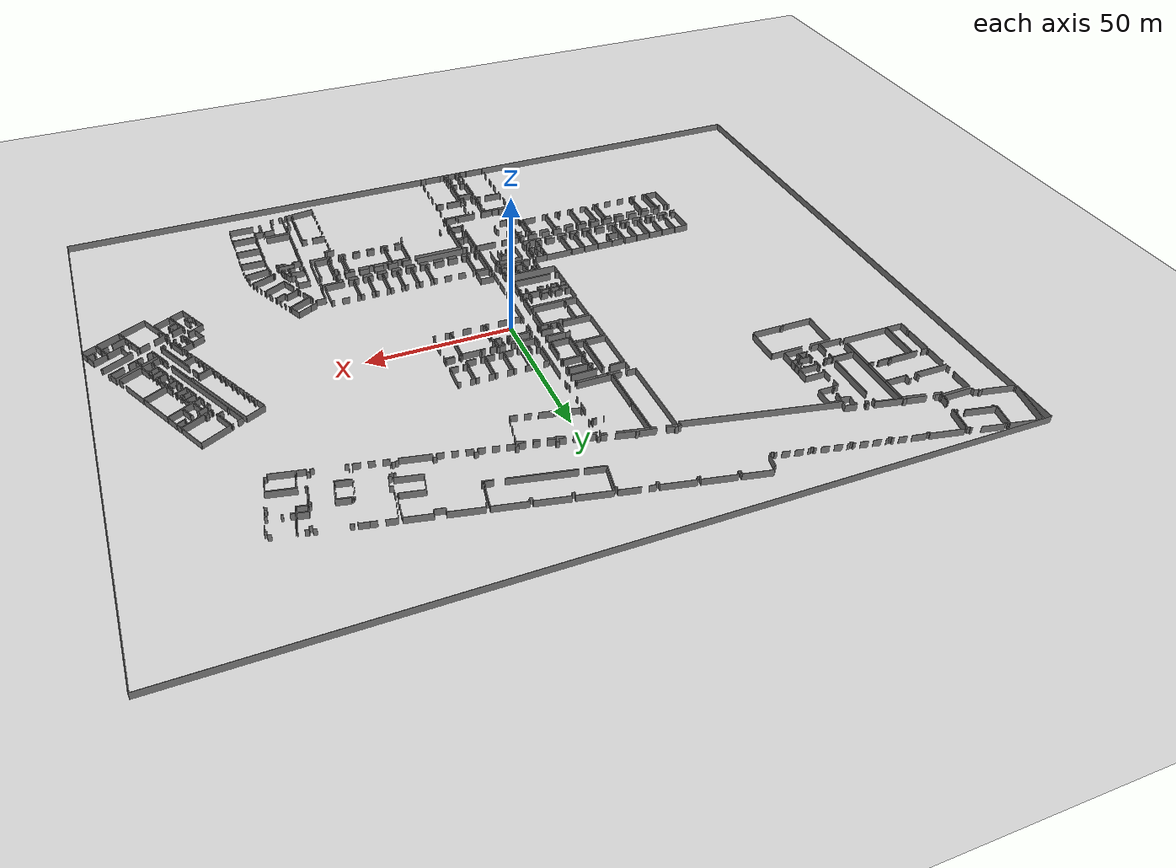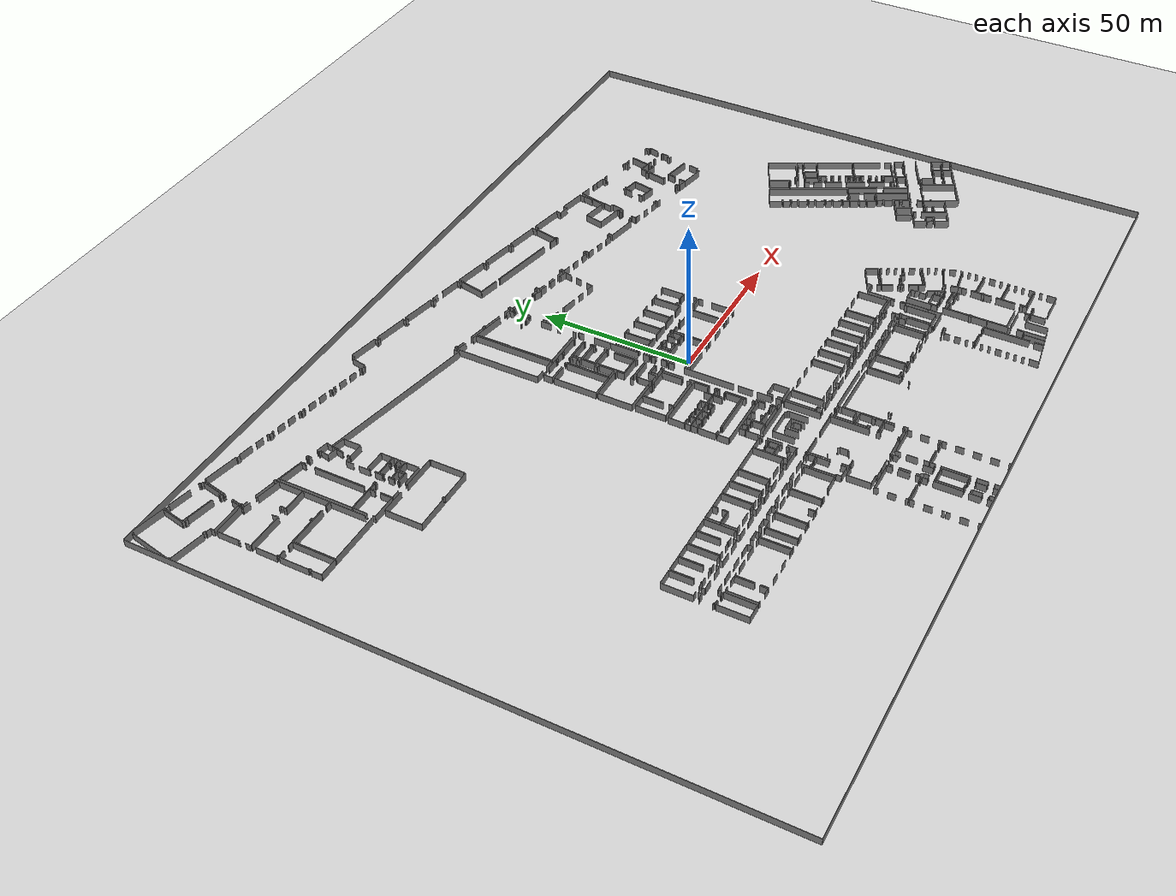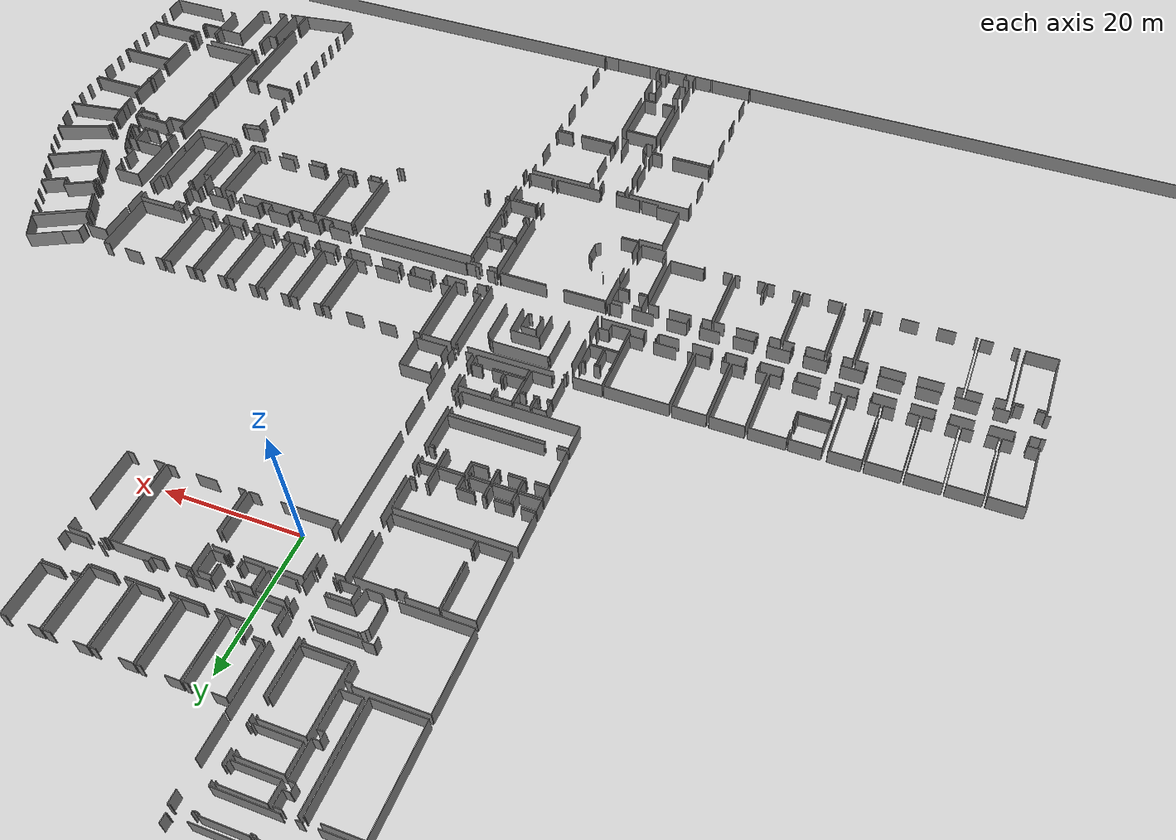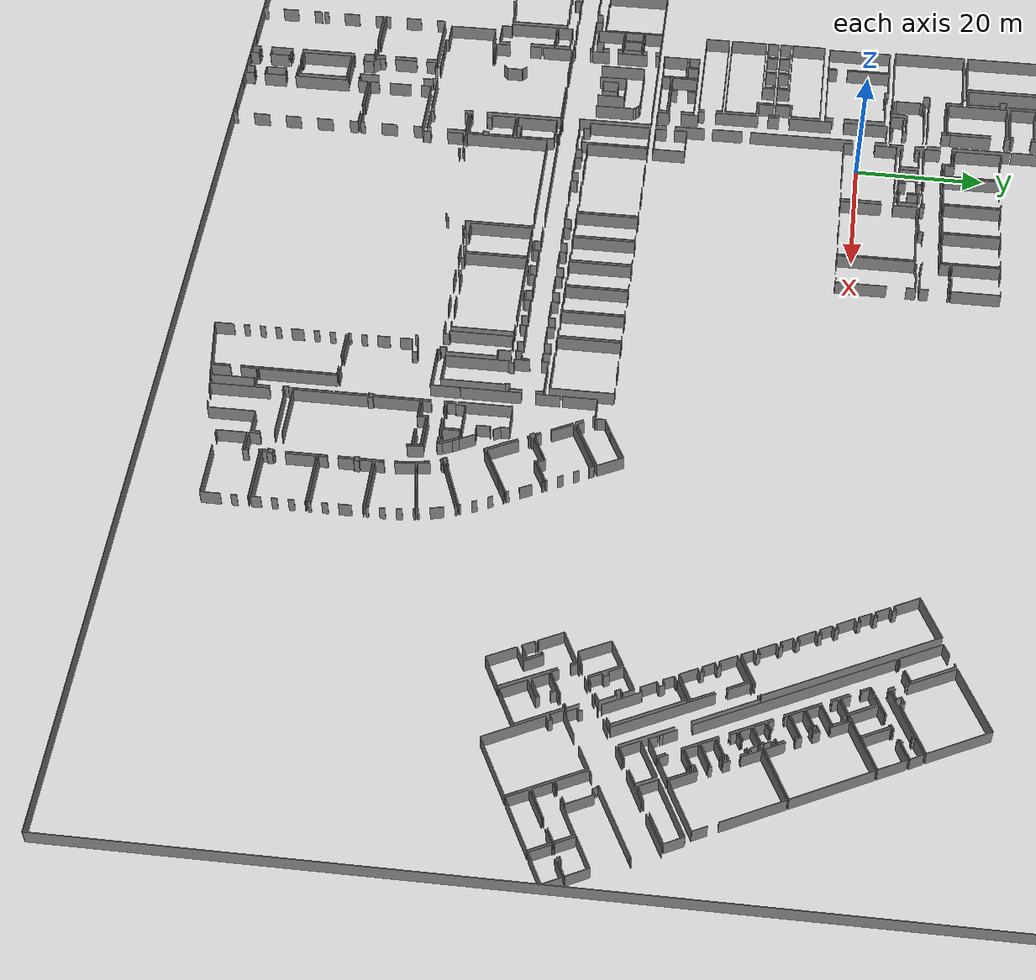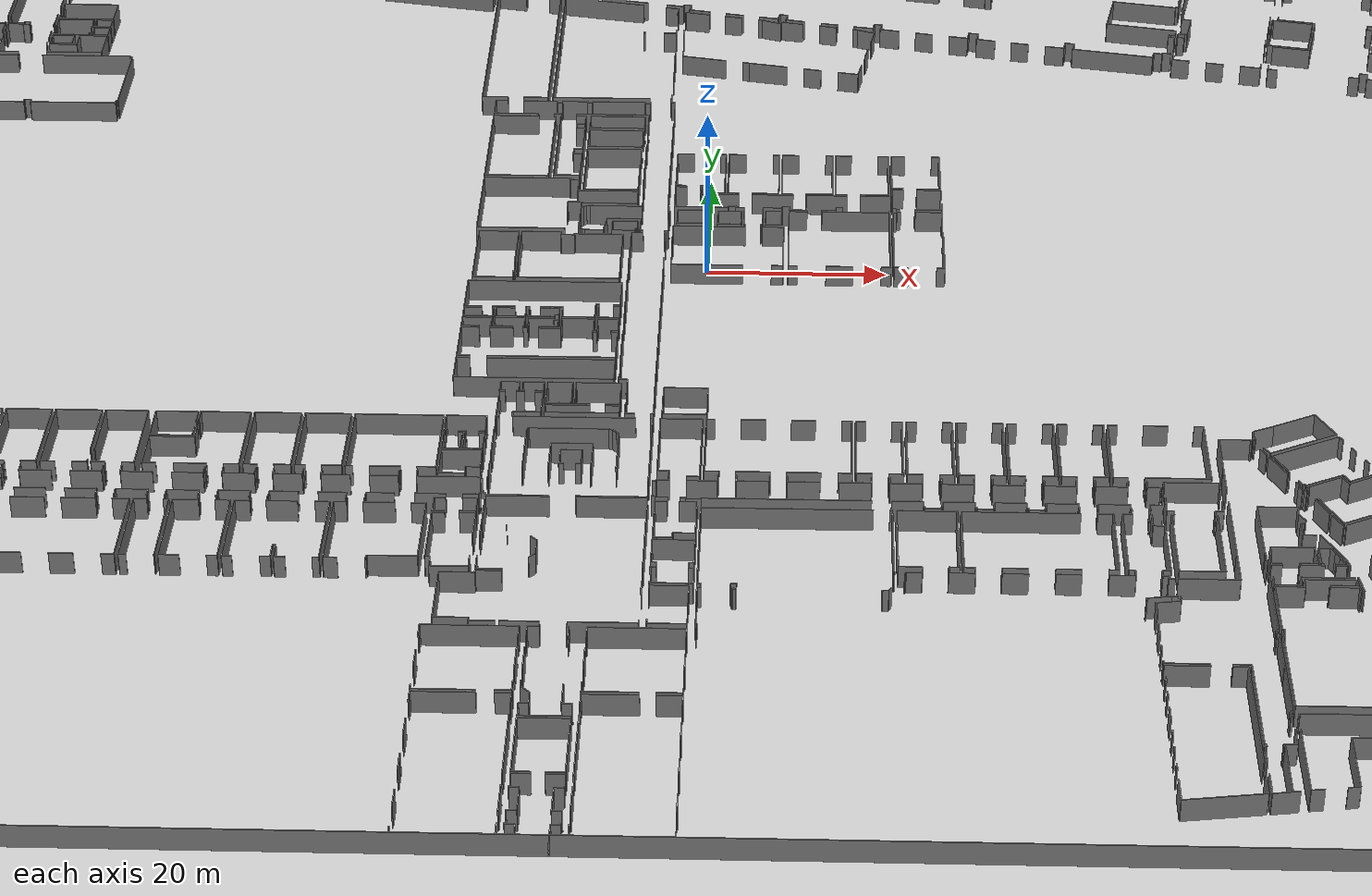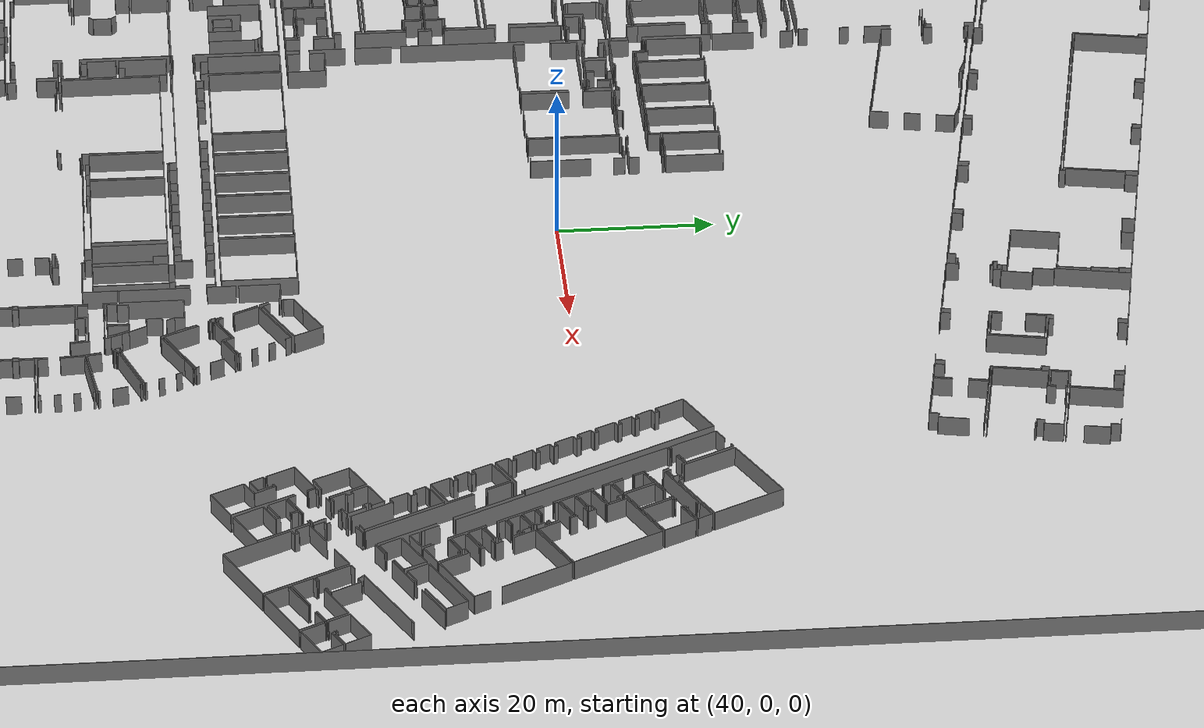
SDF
<sdf version="1.6">
  <world name="default">
    <light name="sun" type="directional">
      <cast_shadows>1</cast_shadows>
      <pose frame="">0 0 10 0 -0 0</pose>
      <diffuse>0.8 0.8 0.8 1</diffuse>
      <specular>0.1 0.1 0.1 1</specular>
      <attenuation>
        <range>1000</range>
        <constant>0.9</constant>
        <linear>0.01</linear>
        <quadratic>0.001</quadratic>
      </attenuation>
      <direction>-0.5 0.5 -1</direction>
    </light>
    <model name="ground_plane">
      <static>1</static>
      <link name="link">
        <collision name="collision">
          <geometry>
            <plane>
              <normal>0 0 1</normal>
              <size>100 100</size>
            </plane>
          </geometry>
          <surface>
            <friction>
              <ode>
                <mu>100</mu>
                <mu2>50</mu2>
              </ode>
              <torsional>
                <ode />
              </torsional>
            </friction>
            <contact>
              <ode />
            </contact>
            <bounce />
          </surface>
          <max_contacts>10</max_contacts>
        </collision>
        <visual name="visual">
          <cast_shadows>0</cast_shadows>
          <geometry>
            <plane>
              <normal>0 0 1</normal>
              <size>100 100</size>
            </plane>
          </geometry>
          <material>
            <script>
              <uri>file://media/materials/scripts/gazebo.material</uri>
              <name>Gazebo/Grey</name>
            </script>
          </material>
        </visual>
        <self_collide>0</self_collide>
        <kinematic>0</kinematic>
        <gravity>1</gravity>
      </link>
    </model>
    <gravity>0 0 -9.8</gravity>
    <magnetic_field>6e-06 2.3e-05 -4.2e-05</magnetic_field>
    <atmosphere type="adiabatic" />
    <physics default="0" name="default_physics" type="ode">
      <max_step_size>0.001</max_step_size>
      <real_time_factor>1</real_time_factor>
      <real_time_update_rate>1000</real_time_update_rate>
    </physics>
    <scene>
      <ambient>0.4 0.4 0.4 1</ambient>
      <background>0.7 0.7 0.7 1</background>
      <shadows>1</shadows>
    </scene>
    <spherical_coordinates>
      <surface_model>EARTH_WGS84</surface_model>
      <latitude_deg>0</latitude_deg>
      <longitude_deg>0</longitude_deg>
      <elevation>0</elevation>
      <heading_deg>0</heading_deg>
    </spherical_coordinates>
  <model name="0510045925_40">
		<static>1</static>
		<link name="Wall_0">
			<collision name="Wall_0_Collision">
				<geometry>
					<box>
						<size>1.88859896353 0.1 2.5</size>
					</box>
				</geometry>
				<pose frame="">0.944299481767 0 1.25 0 0 0</pose>
			</collision>
			<visual name="Wall_0_Visual">
				<pose frame="">0.944299481767 0 1.25 0 0 0</pose>
				<geometry>
					<box>
						<size>1.88859896353 0.1 2.5</size>
					</box>
				</geometry>
				<material>
					<script>
						<uri>file://media/materials/scripts/gazebo.material</uri>
						<name>Gazebo/Grey</name>
					</script>
					<ambient>1 1 1 1</ambient>
				</material>
			</visual>
			<pose frame="">230.382782163 -112.972183447 0 0 0 2.03913168318</pose>
		</link>
		<link name="Wall_1">
			<collision name="Wall_1_Collision">
				<geometry>
					<box>
						<size>0.791682347017 0.1 2.5</size>
					</box>
				</geometry>
				<pose frame="">0.395841173508 0 1.25 0 0 0</pose>
			</collision>
			<visual name="Wall_1_Visual">
				<pose frame="">0.395841173508 0 1.25 0 0 0</pose>
				<geometry>
					<box>
						<size>0.791682347017 0.1 2.5</size>
					</box>
				</geometry>
				<material>
					<script>
						<uri>file://media/materials/scripts/gazebo.material</uri>
						<name>Gazebo/Grey</name>
					</script>
					<ambient>1 1 1 1</ambient>
				</material>
			</visual>
			<pose frame="">229.530265729 -111.286947032 0 0 0 0.492899159813</pose>
		</link>
		<link name="Wall_2">
			<collision name="Wall_2_Collision">
				<geometry>
					<box>
						<size>0.554091668918 0.1 2.5</size>
					</box>
				</geometry>
				<pose frame="">0.277045834459 0 1.25 0 0 0</pose>
			</collision>
			<visual name="Wall_2_Visual">
				<pose frame="">0.277045834459 0 1.25 0 0 0</pose>
				<geometry>
					<box>
						<size>0.554091668918 0.1 2.5</size>
					</box>
				</geometry>
				<material>
					<script>
						<uri>file://media/materials/scripts/gazebo.material</uri>
						<name>Gazebo/Grey</name>
					</script>
					<ambient>1 1 1 1</ambient>
				</material>
			</visual>
			<pose frame="">230.227709957 -110.91233725 0 0 0 2.06107698116</pose>
		</link>
		<link name="Wall_3">
			<collision name="Wall_3_Collision">
				<geometry>
					<box>
						<size>0.772580104799 0.1 2.5</size>
					</box>
				</geometry>
				<pose frame="">0.3862900524 0 1.25 0 0 0</pose>
			</collision>
			<visual name="Wall_3_Visual">
				<pose frame="">0.3862900524 0 1.25 0 0 0</pose>
				<geometry>
					<box>
						<size>0.772580104799 0.1 2.5</size>
					</box>
				</geometry>
				<material>
					<script>
						<uri>file://media/materials/scripts/gazebo.material</uri>
						<name>Gazebo/Grey</name>
					</script>
					<ambient>1 1 1 1</ambient>
				</material>
			</visual>
			<pose frame="">229.966802873 -110.42351717 0 0 0 -2.71085980303</pose>
		</link>
		<link name="Wall_4">
			<collision name="Wall_4_Collision">
				<geometry>
					<box>
						<size>2.72097665282 0.1 2.5</size>
					</box>
				</geometry>
				<pose frame="">1.36048832641 0 1.25 0 0 0</pose>
			</collision>
			<visual name="Wall_4_Visual">
				<pose frame="">1.36048832641 0 1.25 0 0 0</pose>
				<geometry>
					<box>
						<size>2.72097665282 0.1 2.5</size>
					</box>
				</geometry>
				<material>
					<script>
						<uri>file://media/materials/scripts/gazebo.material</uri>
						<name>Gazebo/Grey</name>
					</script>
					<ambient>1 1 1 1</ambient>
				</material>
			</visual>
			<pose frame="">229.264790234 -110.746097815 0 0 0 2.04211940662</pose>
		</link>
		<link name="Wall_5">
			<collision name="Wall_5_Collision">
				<geometry>
					<box>
						<size>0.778104370099 0.1 2.5</size>
					</box>
				</geometry>
				<pose frame="">0.389052185049 0 1.25 0 0 0</pose>
			</collision>
			<visual name="Wall_5_Visual">
				<pose frame="">0.389052185049 0 1.25 0 0 0</pose>
				<geometry>
					<box>
						<size>0.778104370099 0.1 2.5</size>
					</box>
				</geometry>
				<material>
					<script>
						<uri>file://media/materials/scripts/gazebo.material</uri>
						<name>Gazebo/Grey</name>
					</script>
					<ambient>1 1 1 1</ambient>
				</material>
			</visual>
			<pose frame="">228.029288597 -108.321793863 0 0 0 0.473858778521</pose>
		</link>
		<link name="Wall_6">
			<collision name="Wall_6_Collision">
				<geometry>
					<box>
						<size>0.581597389892 0.1 2.5</size>
					</box>
				</geometry>
				<pose frame="">0.290798694946 0 1.25 0 0 0</pose>
			</collision>
			<visual name="Wall_6_Visual">
				<pose frame="">0.290798694946 0 1.25 0 0 0</pose>
				<geometry>
					<box>
						<size>0.581597389892 0.1 2.5</size>
					</box>
				</geometry>
				<material>
					<script>
						<uri>file://media/materials/scripts/gazebo.material</uri>
						<name>Gazebo/Grey</name>
					</script>
					<ambient>1 1 1 1</ambient>
				</material>
			</visual>
			<pose frame="">228.721656811 -107.966726733 0 0 0 2.0869654539</pose>
		</link>
		<link name="Wall_7">
			<collision name="Wall_7_Collision">
				<geometry>
					<box>
						<size>0.726857100754 0.1 2.5</size>
					</box>
				</geometry>
				<pose frame="">0.363428550377 0 1.25 0 0 0</pose>
			</collision>
			<visual name="Wall_7_Visual">
				<pose frame="">0.363428550377 0 1.25 0 0 0</pose>
				<geometry>
					<box>
						<size>0.726857100754 0.1 2.5</size>
					</box>
				</geometry>
				<material>
					<script>
						<uri>file://media/materials/scripts/gazebo.material</uri>
						<name>Gazebo/Grey</name>
					</script>
					<ambient>1 1 1 1</ambient>
				</material>
			</visual>
			<pose frame="">228.434608259 -107.460902008 0 0 0 -2.6538946999</pose>
		</link>
		<link name="Wall_8">
			<collision name="Wall_8_Collision">
				<geometry>
					<box>
						<size>1.91594491801 0.1 2.5</size>
					</box>
				</geometry>
				<pose frame="">0.957972459005 0 1.25 0 0 0</pose>
			</collision>
			<visual name="Wall_8_Visual">
				<pose frame="">0.957972459005 0 1.25 0 0 0</pose>
				<geometry>
					<box>
						<size>1.91594491801 0.1 2.5</size>
					</box>
				</geometry>
				<material>
					<script>
						<uri>file://media/materials/scripts/gazebo.material</uri>
						<name>Gazebo/Grey</name>
					</script>
					<ambient>1 1 1 1</ambient>
				</material>
			</visual>
			<pose frame="">227.792492576 -107.8015025 0 0 0 2.05363930257</pose>
		</link>
		<link name="Wall_9">
			<collision name="Wall_9_Collision">
				<geometry>
					<box>
						<size>0.787025181218 0.1 2.5</size>
					</box>
				</geometry>
				<pose frame="">0.393512590609 0 1.25 0 0 0</pose>
			</collision>
			<visual name="Wall_9_Visual">
				<pose frame="">0.393512590609 0 1.25 0 0 0</pose>
				<geometry>
					<box>
						<size>0.787025181218 0.1 2.5</size>
					</box>
				</geometry>
				<material>
					<script>
						<uri>file://media/materials/scripts/gazebo.material</uri>
						<name>Gazebo/Grey</name>
					</script>
					<ambient>1 1 1 1</ambient>
				</material>
			</visual>
			<pose frame="">226.902921246 -106.104591254 0 0 0 0.511546260567</pose>
		</link>
		<link name="Wall_10">
			<collision name="Wall_10_Collision">
				<geometry>
					<box>
						<size>0.563663164975 0.1 2.5</size>
					</box>
				</geometry>
				<pose frame="">0.281831582488 0 1.25 0 0 0</pose>
			</collision>
			<visual name="Wall_10_Visual">
				<pose frame="">0.281831582488 0 1.25 0 0 0</pose>
				<geometry>
					<box>
						<size>0.563663164975 0.1 2.5</size>
					</box>
				</geometry>
				<material>
					<script>
						<uri>file://media/materials/scripts/gazebo.material</uri>
						<name>Gazebo/Grey</name>
					</script>
					<ambient>1 1 1 1</ambient>
				</material>
			</visual>
			<pose frame="">227.589198244 -105.719321845 0 0 0 2.06324338436</pose>
		</link>
		<link name="Wall_11">
			<collision name="Wall_11_Collision">
				<geometry>
					<box>
						<size>0.741177250141 0.1 2.5</size>
					</box>
				</geometry>
				<pose frame="">0.37058862507 0 1.25 0 0 0</pose>
			</collision>
			<visual name="Wall_11_Visual">
				<pose frame="">0.37058862507 0 1.25 0 0 0</pose>
				<geometry>
					<box>
						<size>0.741177250141 0.1 2.5</size>
					</box>
				</geometry>
				<material>
					<script>
						<uri>file://media/materials/scripts/gazebo.material</uri>
						<name>Gazebo/Grey</name>
					</script>
					<ambient>1 1 1 1</ambient>
				</material>
			</visual>
			<pose frame="">227.322707545 -105.222633943 0 0 0 -2.6802421309</pose>
		</link>
		<link name="Wall_12">
			<collision name="Wall_12_Collision">
				<geometry>
					<box>
						<size>2.69067055951 0.1 2.5</size>
					</box>
				</geometry>
				<pose frame="">1.34533527976 0 1.25 0 0 0</pose>
			</collision>
			<visual name="Wall_12_Visual">
				<pose frame="">1.34533527976 0 1.25 0 0 0</pose>
				<geometry>
					<box>
						<size>2.69067055951 0.1 2.5</size>
					</box>
				</geometry>
				<material>
					<script>
						<uri>file://media/materials/scripts/gazebo.material</uri>
						<name>Gazebo/Grey</name>
					</script>
					<ambient>1 1 1 1</ambient>
				</material>
			</visual>
			<pose frame="">226.659018807 -105.552574808 0 0 0 2.05435607523</pose>
		</link>
		<link name="Wall_13">
			<collision name="Wall_13_Collision">
				<geometry>
					<box>
						<size>0.799349535759 0.1 2.5</size>
					</box>
				</geometry>
				<pose frame="">0.399674767879 0 1.25 0 0 0</pose>
			</collision>
			<visual name="Wall_13_Visual">
				<pose frame="">0.399674767879 0 1.25 0 0 0</pose>
				<geometry>
					<box>
						<size>0.799349535759 0.1 2.5</size>
					</box>
				</geometry>
				<material>
					<script>
						<uri>file://media/materials/scripts/gazebo.material</uri>
						<name>Gazebo/Grey</name>
					</script>
					<ambient>1 1 1 1</ambient>
				</material>
			</visual>
			<pose frame="">225.408035329 -103.170401766 0 0 0 0.484522292641</pose>
		</link>
		<link name="Wall_14">
			<collision name="Wall_14_Collision">
				<geometry>
					<box>
						<size>0.570283938303 0.1 2.5</size>
					</box>
				</geometry>
				<pose frame="">0.285141969151 0 1.25 0 0 0</pose>
			</collision>
			<visual name="Wall_14_Visual">
				<pose frame="">0.285141969151 0 1.25 0 0 0</pose>
				<geometry>
					<box>
						<size>0.570283938303 0.1 2.5</size>
					</box>
				</geometry>
				<material>
					<script>
						<uri>file://media/materials/scripts/gazebo.material</uri>
						<name>Gazebo/Grey</name>
					</script>
					<ambient>1 1 1 1</ambient>
				</material>
			</visual>
			<pose frame="">226.115377782 -102.798076191 0 0 0 2.0762522287</pose>
		</link>
		<link name="Wall_15">
			<collision name="Wall_15_Collision">
				<geometry>
					<box>
						<size>0.782158885172 0.1 2.5</size>
					</box>
				</geometry>
				<pose frame="">0.391079442586 0 1.25 0 0 0</pose>
			</collision>
			<visual name="Wall_15_Visual">
				<pose frame="">0.391079442586 0 1.25 0 0 0</pose>
				<geometry>
					<box>
						<size>0.782158885172 0.1 2.5</size>
					</box>
				</geometry>
				<material>
					<script>
						<uri>file://media/materials/scripts/gazebo.material</uri>
						<name>Gazebo/Grey</name>
					</script>
					<ambient>1 1 1 1</ambient>
				</material>
			</visual>
			<pose frame="">225.839242659 -102.299104084 0 0 0 -2.68273386301</pose>
		</link>
		<link name="Wall_16">
			<collision name="Wall_16_Collision">
				<geometry>
					<box>
						<size>1.90896719742 0.1 2.5</size>
					</box>
				</geometry>
				<pose frame="">0.954483598711 0 1.25 0 0 0</pose>
			</collision>
			<visual name="Wall_16_Visual">
				<pose frame="">0.954483598711 0 1.25 0 0 0</pose>
				<geometry>
					<box>
						<size>1.90896719742 0.1 2.5</size>
					</box>
				</geometry>
				<material>
					<script>
						<uri>file://media/materials/scripts/gazebo.material</uri>
						<name>Gazebo/Grey</name>
					</script>
					<ambient>1 1 1 1</ambient>
				</material>
			</visual>
			<pose frame="">225.137991422 -102.645541991 0 0 0 2.04312489266</pose>
		</link>
		<link name="Wall_17">
			<collision name="Wall_17_Collision">
				<geometry>
					<box>
						<size>0.782379565723 0.1 2.5</size>
					</box>
				</geometry>
				<pose frame="">0.391189782861 0 1.25 0 0 0</pose>
			</collision>
			<visual name="Wall_17_Visual">
				<pose frame="">0.391189782861 0 1.25 0 0 0</pose>
				<geometry>
					<box>
						<size>0.782379565723 0.1 2.5</size>
					</box>
				</geometry>
				<material>
					<script>
						<uri>file://media/materials/scripts/gazebo.material</uri>
						<name>Gazebo/Grey</name>
					</script>
					<ambient>1 1 1 1</ambient>
				</material>
			</visual>
			<pose frame="">224.269485546 -100.945585137 0 0 0 0.48787737505</pose>
		</link>
		<link name="Wall_18">
			<collision name="Wall_18_Collision">
				<geometry>
					<box>
						<size>0.561334838609 0.1 2.5</size>
					</box>
				</geometry>
				<pose frame="">0.280667419305 0 1.25 0 0 0</pose>
			</collision>
			<visual name="Wall_18_Visual">
				<pose frame="">0.280667419305 0 1.25 0 0 0</pose>
				<geometry>
					<box>
						<size>0.561334838609 0.1 2.5</size>
					</box>
				</geometry>
				<material>
					<script>
						<uri>file://media/materials/scripts/gazebo.material</uri>
						<name>Gazebo/Grey</name>
					</script>
					<ambient>1 1 1 1</ambient>
				</material>
			</visual>
			<pose frame="">224.960584757 -100.578843177 0 0 0 2.07732392966</pose>
		</link>
		<link name="Wall_19">
			<collision name="Wall_19_Collision">
				<geometry>
					<box>
						<size>0.754889877876 0.1 2.5</size>
					</box>
				</geometry>
				<pose frame="">0.377444938938 0 1.25 0 0 0</pose>
			</collision>
			<visual name="Wall_19_Visual">
				<pose frame="">0.377444938938 0 1.25 0 0 0</pose>
				<geometry>
					<box>
						<size>0.754889877876 0.1 2.5</size>
					</box>
				</geometry>
				<material>
					<script>
						<uri>file://media/materials/scripts/gazebo.material</uri>
						<name>Gazebo/Grey</name>
					</script>
					<ambient>1 1 1 1</ambient>
				</material>
			</visual>
			<pose frame="">224.688256643 -100.087992691 0 0 0 -2.70711847416</pose>
		</link>
		<link name="Wall_20">
			<collision name="Wall_20_Collision">
				<geometry>
					<box>
						<size>2.73524635126 0.1 2.5</size>
					</box>
				</geometry>
				<pose frame="">1.36762317563 0 1.25 0 0 0</pose>
			</collision>
			<visual name="Wall_20_Visual">
				<pose frame="">1.36762317563 0 1.25 0 0 0</pose>
				<geometry>
					<box>
						<size>2.73524635126 0.1 2.5</size>
					</box>
				</geometry>
				<material>
					<script>
						<uri>file://media/materials/scripts/gazebo.material</uri>
						<name>Gazebo/Grey</name>
					</script>
					<ambient>1 1 1 1</ambient>
				</material>
			</visual>
			<pose frame="">224.003502449 -100.405751123 0 0 0 2.04863620994</pose>
		</link>
		<link name="Wall_21">
			<collision name="Wall_21_Collision">
				<geometry>
					<box>
						<size>0.783026056674 0.1 2.5</size>
					</box>
				</geometry>
				<pose frame="">0.391513028337 0 1.25 0 0 0</pose>
			</collision>
			<visual name="Wall_21_Visual">
				<pose frame="">0.391513028337 0 1.25 0 0 0</pose>
				<geometry>
					<box>
						<size>0.783026056674 0.1 2.5</size>
					</box>
				</geometry>
				<material>
					<script>
						<uri>file://media/materials/scripts/gazebo.material</uri>
						<name>Gazebo/Grey</name>
					</script>
					<ambient>1 1 1 1</ambient>
				</material>
			</visual>
			<pose frame="">222.745666354 -97.9768787594 0 0 0 0.485972448017</pose>
		</link>
		<link name="Wall_22">
			<collision name="Wall_22_Collision">
				<geometry>
					<box>
						<size>0.527831800195 0.1 2.5</size>
					</box>
				</geometry>
				<pose frame="">0.263915900097 0 1.25 0 0 0</pose>
			</collision>
			<visual name="Wall_22_Visual">
				<pose frame="">0.263915900097 0 1.25 0 0 0</pose>
				<geometry>
					<box>
						<size>0.527831800195 0.1 2.5</size>
					</box>
				</geometry>
				<material>
					<script>
						<uri>file://media/materials/scripts/gazebo.material</uri>
						<name>Gazebo/Grey</name>
					</script>
					<ambient>1 1 1 1</ambient>
				</material>
			</visual>
			<pose frame="">223.438034568 -97.6111520012 0 0 0 2.05874545323</pose>
		</link>
		<link name="Wall_23">
			<collision name="Wall_23_Collision">
				<geometry>
					<box>
						<size>0.759749015765 0.1 2.5</size>
					</box>
				</geometry>
				<pose frame="">0.379874507883 0 1.25 0 0 0</pose>
			</collision>
			<visual name="Wall_23_Visual">
				<pose frame="">0.379874507883 0 1.25 0 0 0</pose>
				<geometry>
					<box>
						<size>0.759749015765 0.1 2.5</size>
					</box>
				</geometry>
				<material>
					<script>
						<uri>file://media/materials/scripts/gazebo.material</uri>
						<name>Gazebo/Grey</name>
					</script>
					<ambient>1 1 1 1</ambient>
				</material>
			</visual>
			<pose frame="">223.190578919 -97.1449201797 0 0 0 -2.72876139295</pose>
		</link>
		<link name="Wall_24">
			<collision name="Wall_24_Collision">
				<geometry>
					<box>
						<size>1.88806659486 0.1 2.5</size>
					</box>
				</geometry>
				<pose frame="">0.944033297428 0 1.25 0 0 0</pose>
			</collision>
			<visual name="Wall_24_Visual">
				<pose frame="">0.944033297428 0 1.25 0 0 0</pose>
				<geometry>
					<box>
						<size>1.88806659486 0.1 2.5</size>
					</box>
				</geometry>
				<material>
					<script>
						<uri>file://media/materials/scripts/gazebo.material</uri>
						<name>Gazebo/Grey</name>
					</script>
					<ambient>1 1 1 1</ambient>
				</material>
			</visual>
			<pose frame="">222.494657496 -97.4497347783 0 0 0 2.04213886628</pose>
		</link>
		<link name="Wall_25">
			<collision name="Wall_25_Collision">
				<geometry>
					<box>
						<size>0.787326807375 0.1 2.5</size>
					</box>
				</geometry>
				<pose frame="">0.393663403687 0 1.25 0 0 0</pose>
			</collision>
			<visual name="Wall_25_Visual">
				<pose frame="">0.393663403687 0 1.25 0 0 0</pose>
				<geometry>
					<box>
						<size>0.787326807375 0.1 2.5</size>
					</box>
				</geometry>
				<material>
					<script>
						<uri>file://media/materials/scripts/gazebo.material</uri>
						<name>Gazebo/Grey</name>
					</script>
					<ambient>1 1 1 1</ambient>
				</material>
			</visual>
			<pose frame="">221.63731885 -95.767543971 0 0 0 0.47691096038</pose>
		</link>
		<link name="Wall_26">
			<collision name="Wall_26_Collision">
				<geometry>
					<box>
						<size>0.560734072792 0.1 2.5</size>
					</box>
				</geometry>
				<pose frame="">0.280367036396 0 1.25 0 0 0</pose>
			</collision>
			<visual name="Wall_26_Visual">
				<pose frame="">0.280367036396 0 1.25 0 0 0</pose>
				<geometry>
					<box>
						<size>0.560734072792 0.1 2.5</size>
					</box>
				</geometry>
				<material>
					<script>
						<uri>file://media/materials/scripts/gazebo.material</uri>
						<name>Gazebo/Grey</name>
					</script>
					<ambient>1 1 1 1</ambient>
				</material>
			</visual>
			<pose frame="">222.336793482 -95.4061318241 0 0 0 2.04456504768</pose>
		</link>
		<link name="Wall_27">
			<collision name="Wall_27_Collision">
				<geometry>
					<box>
						<size>0.781128396925 0.1 2.5</size>
					</box>
				</geometry>
				<pose frame="">0.390564198462 0 1.25 0 0 0</pose>
			</collision>
			<visual name="Wall_27_Visual">
				<pose frame="">0.390564198462 0 1.25 0 0 0</pose>
				<geometry>
					<box>
						<size>0.781128396925 0.1 2.5</size>
					</box>
				</geometry>
				<material>
					<script>
						<uri>file://media/materials/scripts/gazebo.material</uri>
						<name>Gazebo/Grey</name>
					</script>
					<ambient>1 1 1 1</ambient>
				</material>
			</visual>
			<pose frame="">222.080962412 -94.9071597168 0 0 0 -2.67809035118</pose>
		</link>
		<link name="Wall_28">
			<collision name="Wall_28_Collision">
				<geometry>
					<box>
						<size>2.24060761237 0.1 2.5</size>
					</box>
				</geometry>
				<pose frame="">1.12030380618 0 1.25 0 0 0</pose>
			</collision>
			<visual name="Wall_28_Visual">
				<pose frame="">1.12030380618 0 1.25 0 0 0</pose>
				<geometry>
					<box>
						<size>2.24060761237 0.1 2.5</size>
					</box>
				</geometry>
				<material>
					<script>
						<uri>file://media/materials/scripts/gazebo.material</uri>
						<name>Gazebo/Grey</name>
					</script>
					<ambient>1 1 1 1</ambient>
				</material>
			</visual>
			<pose frame="">221.382249181 -95.2563894317 0 0 0 2.04675396799</pose>
		</link>
		<link name="Wall_29">
			<collision name="Wall_29_Collision">
				<geometry>
					<box>
						<size>0.801804464238 0.1 2.5</size>
					</box>
				</geometry>
				<pose frame="">0.400902232119 0 1.25 0 0 0</pose>
			</collision>
			<visual name="Wall_29_Visual">
				<pose frame="">0.400902232119 0 1.25 0 0 0</pose>
				<geometry>
					<box>
						<size>0.801804464238 0.1 2.5</size>
					</box>
				</geometry>
				<material>
					<script>
						<uri>file://media/materials/scripts/gazebo.material</uri>
						<name>Gazebo/Grey</name>
					</script>
					<ambient>1 1 1 1</ambient>
				</material>
			</visual>
			<pose frame="">220.355625492 -93.2648156138 0 0 0 0.470442521411</pose>
		</link>
		<link name="Wall_30">
			<collision name="Wall_30_Collision">
				<geometry>
					<box>
						<size>0.570466044514 0.1 2.5</size>
					</box>
				</geometry>
				<pose frame="">0.285233022257 0 1.25 0 0 0</pose>
			</collision>
			<visual name="Wall_30_Visual">
				<pose frame="">0.285233022257 0 1.25 0 0 0</pose>
				<geometry>
					<box>
						<size>0.570466044514 0.1 2.5</size>
					</box>
				</geometry>
				<material>
					<script>
						<uri>file://media/materials/scripts/gazebo.material</uri>
						<name>Gazebo/Grey</name>
					</script>
					<ambient>1 1 1 1</ambient>
				</material>
			</visual>
			<pose frame="">221.070328164 -92.9013730616 0 0 0 2.05434180687</pose>
		</link>
		<link name="Wall_31">
			<collision name="Wall_31_Collision">
				<geometry>
					<box>
						<size>0.802244029599 0.1 2.5</size>
					</box>
				</geometry>
				<pose frame="">0.4011220148 0 1.25 0 0 0</pose>
			</collision>
			<visual name="Wall_31_Visual">
				<pose frame="">0.4011220148 0 1.25 0 0 0</pose>
				<geometry>
					<box>
						<size>0.802244029599 0.1 2.5</size>
					</box>
				</geometry>
				<material>
					<script>
						<uri>file://media/materials/scripts/gazebo.material</uri>
						<name>Gazebo/Grey</name>
					</script>
					<ambient>1 1 1 1</ambient>
				</material>
			</visual>
			<pose frame="">220.805106469 -92.3963097383 0 0 0 -2.69506520563</pose>
		</link>
		<link name="Wall_32">
			<collision name="Wall_32_Collision">
				<geometry>
					<box>
						<size>3.96179362654 0.1 2.5</size>
					</box>
				</geometry>
				<pose frame="">1.98089681327 0 1.25 0 0 0</pose>
			</collision>
			<visual name="Wall_32_Visual">
				<pose frame="">1.98089681327 0 1.25 0 0 0</pose>
				<geometry>
					<box>
						<size>3.96179362654 0.1 2.5</size>
					</box>
				</geometry>
				<material>
					<script>
						<uri>file://media/materials/scripts/gazebo.material</uri>
						<name>Gazebo/Grey</name>
					</script>
					<ambient>1 1 1 1</ambient>
				</material>
			</visual>
			<pose frame="">220.081520774 -92.742747646 0 0 0 2.04435679907</pose>
		</link>
		<link name="Wall_33">
			<collision name="Wall_33_Collision">
				<geometry>
					<box>
						<size>6.96411404976 0.1 2.5</size>
					</box>
				</geometry>
				<pose frame="">3.48205702488 0 1.25 0 0 0</pose>
			</collision>
			<visual name="Wall_33_Visual">
				<pose frame="">3.48205702488 0 1.25 0 0 0</pose>
				<geometry>
					<box>
						<size>6.96411404976 0.1 2.5</size>
					</box>
				</geometry>
				<material>
					<script>
						<uri>file://media/materials/scripts/gazebo.material</uri>
						<name>Gazebo/Grey</name>
					</script>
					<ambient>1 1 1 1</ambient>
				</material>
			</visual>
			<pose frame="">218.27471384 -89.2169488084 0 0 0 0.465880475751</pose>
		</link>
		<link name="Wall_34">
			<collision name="Wall_34_Collision">
				<geometry>
					<box>
						<size>26.6350946096 0.1 2.5</size>
					</box>
				</geometry>
				<pose frame="">13.3175473048 0 1.25 0 0 0</pose>
			</collision>
			<visual name="Wall_34_Visual">
				<pose frame="">13.3175473048 0 1.25 0 0 0</pose>
				<geometry>
					<box>
						<size>26.6350946096 0.1 2.5</size>
					</box>
				</geometry>
				<material>
					<script>
						<uri>file://media/materials/scripts/gazebo.material</uri>
						<name>Gazebo/Grey</name>
					</script>
					<ambient>1 1 1 1</ambient>
				</material>
			</visual>
			<pose frame="">224.496637141 -86.0886018121 0 0 0 -1.0994184397</pose>
		</link>
		<link name="Wall_35">
			<collision name="Wall_35_Collision">
				<geometry>
					<box>
						<size>0.193588526439 0.1 2.5</size>
					</box>
				</geometry>
				<pose frame="">0.0967942632194 0 1.25 0 0 0</pose>
			</collision>
			<visual name="Wall_35_Visual">
				<pose frame="">0.0967942632194 0 1.25 0 0 0</pose>
				<geometry>
					<box>
						<size>0.193588526439 0.1 2.5</size>
					</box>
				</geometry>
				<material>
					<script>
						<uri>file://media/materials/scripts/gazebo.material</uri>
						<name>Gazebo/Grey</name>
					</script>
					<ambient>1 1 1 1</ambient>
				</material>
			</visual>
			<pose frame="">236.592015431 -109.818963986 0 0 0 -2.54268139186</pose>
		</link>
		<link name="Wall_36">
			<collision name="Wall_36_Collision">
				<geometry>
					<box>
						<size>4.93782871065 0.1 2.5</size>
					</box>
				</geometry>
				<pose frame="">2.46891435533 0 1.25 0 0 0</pose>
			</collision>
			<visual name="Wall_36_Visual">
				<pose frame="">2.46891435533 0 1.25 0 0 0</pose>
				<geometry>
					<box>
						<size>4.93782871065 0.1 2.5</size>
					</box>
				</geometry>
				<material>
					<script>
						<uri>file://media/materials/scripts/gazebo.material</uri>
						<name>Gazebo/Grey</name>
					</script>
					<ambient>1 1 1 1</ambient>
				</material>
			</visual>
			<pose frame="">234.784954697 -110.735438187 0 0 0 -2.67148580978</pose>
		</link>
		<link name="Wall_37">
			<collision name="Wall_37_Collision">
				<geometry>
					<box>
						<size>2.68594198004 0.1 2.5</size>
					</box>
				</geometry>
				<pose frame="">1.34297099002 0 1.25 0 0 0</pose>
			</collision>
			<visual name="Wall_37_Visual">
				<pose frame="">1.34297099002 0 1.25 0 0 0</pose>
				<geometry>
					<box>
						<size>2.68594198004 0.1 2.5</size>
					</box>
				</geometry>
				<material>
					<script>
						<uri>file://media/materials/scripts/gazebo.material</uri>
						<name>Gazebo/Grey</name>
					</script>
					<ambient>1 1 1 1</ambient>
				</material>
			</visual>
			<pose frame="">234.472779879 -120.960559377 0 0 0 2.03626103995</pose>
		</link>
		<link name="Wall_38">
			<collision name="Wall_38_Collision">
				<geometry>
					<box>
						<size>0.76813784894 0.1 2.5</size>
					</box>
				</geometry>
				<pose frame="">0.38406892447 0 1.25 0 0 0</pose>
			</collision>
			<visual name="Wall_38_Visual">
				<pose frame="">0.38406892447 0 1.25 0 0 0</pose>
				<geometry>
					<box>
						<size>0.76813784894 0.1 2.5</size>
					</box>
				</geometry>
				<material>
					<script>
						<uri>file://media/materials/scripts/gazebo.material</uri>
						<name>Gazebo/Grey</name>
					</script>
					<ambient>1 1 1 1</ambient>
				</material>
			</visual>
			<pose frame="">233.26722672 -118.560366488 0 0 0 0.504146009762</pose>
		</link>
		<link name="Wall_39">
			<collision name="Wall_39_Collision">
				<geometry>
					<box>
						<size>0.570086011849 0.1 2.5</size>
					</box>
				</geometry>
				<pose frame="">0.285043005925 0 1.25 0 0 0</pose>
			</collision>
			<visual name="Wall_39_Visual">
				<pose frame="">0.285043005925 0 1.25 0 0 0</pose>
				<geometry>
					<box>
						<size>0.570086011849 0.1 2.5</size>
					</box>
				</geometry>
				<material>
					<script>
						<uri>file://media/materials/scripts/gazebo.material</uri>
						<name>Gazebo/Grey</name>
					</script>
					<ambient>1 1 1 1</ambient>
				</material>
			</visual>
			<pose frame="">233.939798482 -118.189309916 0 0 0 2.07746241748</pose>
		</link>
		<link name="Wall_40">
			<collision name="Wall_40_Collision">
				<geometry>
					<box>
						<size>0.750030735713 0.1 2.5</size>
					</box>
				</geometry>
				<pose frame="">0.375015367857 0 1.25 0 0 0</pose>
			</collision>
			<visual name="Wall_40_Visual">
				<pose frame="">0.375015367857 0 1.25 0 0 0</pose>
				<geometry>
					<box>
						<size>0.750030735713 0.1 2.5</size>
					</box>
				</geometry>
				<material>
					<script>
						<uri>file://media/materials/scripts/gazebo.material</uri>
						<name>Gazebo/Grey</name>
					</script>
					<ambient>1 1 1 1</ambient>
				</material>
			</visual>
			<pose frame="">233.663155757 -117.69084541 0 0 0 -2.67552374181</pose>
		</link>
		<link name="Wall_41">
			<collision name="Wall_41_Collision">
				<geometry>
					<box>
						<size>1.91479657271 0.1 2.5</size>
					</box>
				</geometry>
				<pose frame="">0.957398286355 0 1.25 0 0 0</pose>
			</collision>
			<visual name="Wall_41_Visual">
				<pose frame="">0.957398286355 0 1.25 0 0 0</pose>
				<geometry>
					<box>
						<size>1.91479657271 0.1 2.5</size>
					</box>
				</geometry>
				<material>
					<script>
						<uri>file://media/materials/scripts/gazebo.material</uri>
						<name>Gazebo/Grey</name>
					</script>
					<ambient>1 1 1 1</ambient>
				</material>
			</visual>
			<pose frame="">232.993122002 -118.027892693 0 0 0 2.0562002558</pose>
		</link>
		<link name="Wall_42">
			<collision name="Wall_42_Collision">
				<geometry>
					<box>
						<size>0.798350596777 0.1 2.5</size>
					</box>
				</geometry>
				<pose frame="">0.399175298389 0 1.25 0 0 0</pose>
			</collision>
			<visual name="Wall_42_Visual">
				<pose frame="">0.399175298389 0 1.25 0 0 0</pose>
				<geometry>
					<box>
						<size>0.798350596777 0.1 2.5</size>
					</box>
				</geometry>
				<material>
					<script>
						<uri>file://media/materials/scripts/gazebo.material</uri>
						<name>Gazebo/Grey</name>
					</script>
					<ambient>1 1 1 1</ambient>
				</material>
			</visual>
			<pose frame="">232.099743661 -116.334280856 0 0 0 0.500336217475</pose>
		</link>
		<link name="Wall_43">
			<collision name="Wall_43_Collision">
				<geometry>
					<box>
						<size>0.546959511866 0.1 2.5</size>
					</box>
				</geometry>
				<pose frame="">0.273479755933 0 1.25 0 0 0</pose>
			</collision>
			<visual name="Wall_43_Visual">
				<pose frame="">0.273479755933 0 1.25 0 0 0</pose>
				<geometry>
					<box>
						<size>0.546959511866 0.1 2.5</size>
					</box>
				</geometry>
				<material>
					<script>
						<uri>file://media/materials/scripts/gazebo.material</uri>
						<name>Gazebo/Grey</name>
					</script>
					<ambient>1 1 1 1</ambient>
				</material>
			</visual>
			<pose frame="">232.800233497 -115.951295652 0 0 0 2.06910612702</pose>
		</link>
		<link name="Wall_44">
			<collision name="Wall_44_Collision">
				<geometry>
					<box>
						<size>0.783648546966 0.1 2.5</size>
					</box>
				</geometry>
				<pose frame="">0.391824273483 0 1.25 0 0 0</pose>
			</collision>
			<visual name="Wall_44_Visual">
				<pose frame="">0.391824273483 0 1.25 0 0 0</pose>
				<geometry>
					<box>
						<size>0.783648546966 0.1 2.5</size>
					</box>
				</geometry>
				<material>
					<script>
						<uri>file://media/materials/scripts/gazebo.material</uri>
						<name>Gazebo/Grey</name>
					</script>
					<ambient>1 1 1 1</ambient>
				</material>
			</visual>
			<pose frame="">232.538818812 -115.470850994 0 0 0 -2.67026848623</pose>
		</link>
		<link name="Wall_45">
			<collision name="Wall_45_Collision">
				<geometry>
					<box>
						<size>2.71553219411 0.1 2.5</size>
					</box>
				</geometry>
				<pose frame="">1.35776609705 0 1.25 0 0 0</pose>
			</collision>
			<visual name="Wall_45_Visual">
				<pose frame="">1.35776609705 0 1.25 0 0 0</pose>
				<geometry>
					<box>
						<size>2.71553219411 0.1 2.5</size>
					</box>
				</geometry>
				<material>
					<script>
						<uri>file://media/materials/scripts/gazebo.material</uri>
						<name>Gazebo/Grey</name>
					</script>
					<ambient>1 1 1 1</ambient>
				</material>
			</visual>
			<pose frame="">231.840613182 -115.826679526 0 0 0 2.04230199174</pose>
		</link>
		<link name="Wall_46">
			<collision name="Wall_46_Collision">
				<geometry>
					<box>
						<size>4.27559902582 0.1 2.5</size>
					</box>
				</geometry>
				<pose frame="">2.13779951291 0 1.25 0 0 0</pose>
			</collision>
			<visual name="Wall_46_Visual">
				<pose frame="">2.13779951291 0 1.25 0 0 0</pose>
				<geometry>
					<box>
						<size>4.27559902582 0.1 2.5</size>
					</box>
				</geometry>
				<material>
					<script>
						<uri>file://media/materials/scripts/gazebo.material</uri>
						<name>Gazebo/Grey</name>
					</script>
					<ambient>1 1 1 1</ambient>
				</material>
			</visual>
			<pose frame="">230.607141951 -113.407451588 0 0 0 0.468505676917</pose>
		</link>
		<link name="Wall_47">
			<collision name="Wall_47_Collision">
				<geometry>
					<box>
						<size>3.38837195357 0.1 2.5</size>
					</box>
				</geometry>
				<pose frame="">1.69418597679 0 1.25 0 0 0</pose>
			</collision>
			<visual name="Wall_47_Visual">
				<pose frame="">1.69418597679 0 1.25 0 0 0</pose>
				<geometry>
					<box>
						<size>3.38837195357 0.1 2.5</size>
					</box>
				</geometry>
				<material>
					<script>
						<uri>file://media/materials/scripts/gazebo.material</uri>
						<name>Gazebo/Grey</name>
					</script>
					<ambient>1 1 1 1</ambient>
				</material>
			</visual>
			<pose frame="">234.422019746 -111.476789929 0 0 0 -1.09374918479</pose>
		</link>
		<link name="Wall_48">
			<collision name="Wall_48_Collision">
				<geometry>
					<box>
						<size>3.42417733766 0.1 2.5</size>
					</box>
				</geometry>
				<pose frame="">1.71208866883 0 1.25 0 0 0</pose>
			</collision>
			<visual name="Wall_48_Visual">
				<pose frame="">1.71208866883 0 1.25 0 0 0</pose>
				<geometry>
					<box>
						<size>3.42417733766 0.1 2.5</size>
					</box>
				</geometry>
				<material>
					<script>
						<uri>file://media/materials/scripts/gazebo.material</uri>
						<name>Gazebo/Grey</name>
					</script>
					<ambient>1 1 1 1</ambient>
				</material>
			</visual>
			<pose frame="">236.756985863 -116.035303672 0 0 0 -1.10413228568</pose>
		</link>
		<link name="Wall_49">
			<collision name="Wall_49_Collision">
				<geometry>
					<box>
						<size>4.25621784762 0.1 2.5</size>
					</box>
				</geometry>
				<pose frame="">2.12810892381 0 1.25 0 0 0</pose>
			</collision>
			<visual name="Wall_49_Visual">
				<pose frame="">2.12810892381 0 1.25 0 0 0</pose>
				<geometry>
					<box>
						<size>4.25621784762 0.1 2.5</size>
					</box>
				</geometry>
				<material>
					<script>
						<uri>file://media/materials/scripts/gazebo.material</uri>
						<name>Gazebo/Grey</name>
					</script>
					<ambient>1 1 1 1</ambient>
				</material>
			</visual>
			<pose frame="">238.2975559 -119.093347885 0 0 0 -2.68743885221</pose>
		</link>
		<link name="Wall_50">
			<collision name="Wall_50_Collision">
				<geometry>
					<box>
						<size>14.9826140354 0.1 2.5</size>
					</box>
				</geometry>
				<pose frame="">7.49130701768 0 1.25 0 0 0</pose>
			</collision>
			<visual name="Wall_50_Visual">
				<pose frame="">7.49130701768 0 1.25 0 0 0</pose>
				<geometry>
					<box>
						<size>14.9826140354 0.1 2.5</size>
					</box>
				</geometry>
				<material>
					<script>
						<uri>file://media/materials/scripts/gazebo.material</uri>
						<name>Gazebo/Grey</name>
					</script>
					<ambient>1 1 1 1</ambient>
				</material>
			</visual>
			<pose frame="">243.802492323 -129.213141798 0 0 0 2.04202723866</pose>
		</link>
		<link name="Wall_51">
			<collision name="Wall_51_Collision">
				<geometry>
					<box>
						<size>3.32022371351 0.1 2.5</size>
					</box>
				</geometry>
				<pose frame="">1.66011185675 0 1.25 0 0 0</pose>
			</collision>
			<visual name="Wall_51_Visual">
				<pose frame="">1.66011185675 0 1.25 0 0 0</pose>
				<geometry>
					<box>
						<size>3.32022371351 0.1 2.5</size>
					</box>
				</geometry>
				<material>
					<script>
						<uri>file://media/materials/scripts/gazebo.material</uri>
						<name>Gazebo/Grey</name>
					</script>
					<ambient>1 1 1 1</ambient>
				</material>
			</visual>
			<pose frame="">236.175782341 -114.308697749 0 0 0 2.03013656465</pose>
		</link>
		<link name="Wall_52">
			<collision name="Wall_52_Collision">
				<geometry>
					<box>
						<size>0.480639025663 0.1 2.5</size>
					</box>
				</geometry>
				<pose frame="">0.240319512832 0 1.25 0 0 0</pose>
			</collision>
			<visual name="Wall_52_Visual">
				<pose frame="">0.240319512832 0 1.25 0 0 0</pose>
				<geometry>
					<box>
						<size>0.480639025663 0.1 2.5</size>
					</box>
				</geometry>
				<material>
					<script>
						<uri>file://media/materials/scripts/gazebo.material</uri>
						<name>Gazebo/Grey</name>
					</script>
					<ambient>1 1 1 1</ambient>
				</material>
			</visual>
			<pose frame="">234.703738484 -111.332631151 0 0 0 0.491044484923</pose>
		</link>
		<link name="Wall_53">
			<collision name="Wall_53_Collision">
				<geometry>
					<box>
						<size>0.603206230897 0.1 2.5</size>
					</box>
				</geometry>
				<pose frame="">0.301603115448 0 1.25 0 0 0</pose>
			</collision>
			<visual name="Wall_53_Visual">
				<pose frame="">0.301603115448 0 1.25 0 0 0</pose>
				<geometry>
					<box>
						<size>0.603206230897 0.1 2.5</size>
					</box>
				</geometry>
				<material>
					<script>
						<uri>file://media/materials/scripts/gazebo.material</uri>
						<name>Gazebo/Grey</name>
					</script>
					<ambient>1 1 1 1</ambient>
				</material>
			</visual>
			<pose frame="">236.693535697 -110.264637953 0 0 0 0.440312865399</pose>
		</link>
		<link name="Wall_54">
			<collision name="Wall_54_Collision">
				<geometry>
					<box>
						<size>9.79878650992 0.1 2.5</size>
					</box>
				</geometry>
				<pose frame="">4.89939325496 0 1.25 0 0 0</pose>
			</collision>
			<visual name="Wall_54_Visual">
				<pose frame="">4.89939325496 0 1.25 0 0 0</pose>
				<geometry>
					<box>
						<size>9.79878650992 0.1 2.5</size>
					</box>
				</geometry>
				<material>
					<script>
						<uri>file://media/materials/scripts/gazebo.material</uri>
						<name>Gazebo/Grey</name>
					</script>
					<ambient>1 1 1 1</ambient>
				</material>
			</visual>
			<pose frame="">237.239207127 -110.00753788 0 0 0 -1.09687407531</pose>
		</link>
		<link name="Wall_55">
			<collision name="Wall_55_Collision">
				<geometry>
					<box>
						<size>8.03569557212 0.1 2.5</size>
					</box>
				</geometry>
				<pose frame="">4.01784778606 0 1.25 0 0 0</pose>
			</collision>
			<visual name="Wall_55_Visual">
				<pose frame="">4.01784778606 0 1.25 0 0 0</pose>
				<geometry>
					<box>
						<size>8.03569557212 0.1 2.5</size>
					</box>
				</geometry>
				<material>
					<script>
						<uri>file://media/materials/scripts/gazebo.material</uri>
						<name>Gazebo/Grey</name>
					</script>
					<ambient>1 1 1 1</ambient>
				</material>
			</visual>
			<pose frame="">242.799979696 -120.817162001 0 0 0 -1.10147049191</pose>
		</link>
		<link name="Wall_56">
			<collision name="Wall_56_Collision">
				<geometry>
					<box>
						<size>0.104498397889 0.1 2.5</size>
					</box>
				</geometry>
				<pose frame="">0.0522491989443 0 1.25 0 0 0</pose>
			</collision>
			<visual name="Wall_56_Visual">
				<pose frame="">0.0522491989443 0 1.25 0 0 0</pose>
				<geometry>
					<box>
						<size>0.104498397889 0.1 2.5</size>
					</box>
				</geometry>
				<material>
					<script>
						<uri>file://media/materials/scripts/gazebo.material</uri>
						<name>Gazebo/Grey</name>
					</script>
					<ambient>1 1 1 1</ambient>
				</material>
			</visual>
			<pose frame="">243.845638436 -129.308317048 0 0 0 1.99641879513</pose>
		</link>
		<link name="Wall_57">
			<collision name="Wall_57_Collision">
				<geometry>
					<box>
						<size>4.97087910752 0.1 2.5</size>
					</box>
				</geometry>
				<pose frame="">2.48543955376 0 1.25 0 0 0</pose>
			</collision>
			<visual name="Wall_57_Visual">
				<pose frame="">2.48543955376 0 1.25 0 0 0</pose>
				<geometry>
					<box>
						<size>4.97087910752 0.1 2.5</size>
					</box>
				</geometry>
				<material>
					<script>
						<uri>file://media/materials/scripts/gazebo.material</uri>
						<name>Gazebo/Grey</name>
					</script>
					<ambient>1 1 1 1</ambient>
				</material>
			</visual>
			<pose frame="">232.376640187 -134.850562168 0 0 0 2.03649896202</pose>
		</link>
		<link name="Wall_58">
			<collision name="Wall_58_Collision">
				<geometry>
					<box>
						<size>4.10851946526 0.1 2.5</size>
					</box>
				</geometry>
				<pose frame="">2.05425973263 0 1.25 0 0 0</pose>
			</collision>
			<visual name="Wall_58_Visual">
				<pose frame="">2.05425973263 0 1.25 0 0 0</pose>
				<geometry>
					<box>
						<size>4.10851946526 0.1 2.5</size>
					</box>
				</geometry>
				<material>
					<script>
						<uri>file://media/materials/scripts/gazebo.material</uri>
						<name>Gazebo/Grey</name>
					</script>
					<ambient>1 1 1 1</ambient>
				</material>
			</visual>
			<pose frame="">230.144463338 -130.409050532 0 0 0 0.468454600182</pose>
		</link>
		<link name="Wall_59">
			<collision name="Wall_59_Collision">
				<geometry>
					<box>
						<size>5.12687668526 0.1 2.5</size>
					</box>
				</geometry>
				<pose frame="">2.56343834263 0 1.25 0 0 0</pose>
			</collision>
			<visual name="Wall_59_Visual">
				<pose frame="">2.56343834263 0 1.25 0 0 0</pose>
				<geometry>
					<box>
						<size>5.12687668526 0.1 2.5</size>
					</box>
				</geometry>
				<material>
					<script>
						<uri>file://media/materials/scripts/gazebo.material</uri>
						<name>Gazebo/Grey</name>
					</script>
					<ambient>1 1 1 1</ambient>
				</material>
			</visual>
			<pose frame="">233.810360143 -128.554021472 0 0 0 -1.09904581331</pose>
		</link>
		<link name="Wall_60">
			<collision name="Wall_60_Collision">
				<geometry>
					<box>
						<size>2.2424406191 0.1 2.5</size>
					</box>
				</geometry>
				<pose frame="">1.12122030955 0 1.25 0 0 0</pose>
			</collision>
			<visual name="Wall_60_Visual">
				<pose frame="">1.12122030955 0 1.25 0 0 0</pose>
				<geometry>
					<box>
						<size>2.2424406191 0.1 2.5</size>
					</box>
				</geometry>
				<material>
					<script>
						<uri>file://media/materials/scripts/gazebo.material</uri>
						<name>Gazebo/Grey</name>
					</script>
					<ambient>1 1 1 1</ambient>
				</material>
			</visual>
			<pose frame="">234.452475825 -134.002360346 0 0 0 -2.75368818955</pose>
		</link>
		<link name="Wall_61">
			<collision name="Wall_61_Collision">
				<geometry>
					<box>
						<size>1.94840018234 0.1 2.5</size>
					</box>
				</geometry>
				<pose frame="">0.97420009117 0 1.25 0 0 0</pose>
			</collision>
			<visual name="Wall_61_Visual">
				<pose frame="">0.97420009117 0 1.25 0 0 0</pose>
				<geometry>
					<box>
						<size>1.94840018234 0.1 2.5</size>
					</box>
				</geometry>
				<material>
					<script>
						<uri>file://media/materials/scripts/gazebo.material</uri>
						<name>Gazebo/Grey</name>
					</script>
					<ambient>1 1 1 1</ambient>
				</material>
			</visual>
			<pose frame="">236.409278952 -132.93512855 0 0 0 2.03689062787</pose>
		</link>
		<link name="Wall_62">
			<collision name="Wall_62_Collision">
				<geometry>
					<box>
						<size>0.530571853203 0.1 2.5</size>
					</box>
				</geometry>
				<pose frame="">0.265285926601 0 1.25 0 0 0</pose>
			</collision>
			<visual name="Wall_62_Visual">
				<pose frame="">0.265285926601 0 1.25 0 0 0</pose>
				<geometry>
					<box>
						<size>0.530571853203 0.1 2.5</size>
					</box>
				</geometry>
				<material>
					<script>
						<uri>file://media/materials/scripts/gazebo.material</uri>
						<name>Gazebo/Grey</name>
					</script>
					<ambient>1 1 1 1</ambient>
				</material>
			</visual>
			<pose frame="">235.533666658 -131.19456359 0 0 0 0.52401138973</pose>
		</link>
		<link name="Wall_63">
			<collision name="Wall_63_Collision">
				<geometry>
					<box>
						<size>0.772771179375 0.1 2.5</size>
					</box>
				</geometry>
				<pose frame="">0.386385589687 0 1.25 0 0 0</pose>
			</collision>
			<visual name="Wall_63_Visual">
				<pose frame="">0.386385589687 0 1.25 0 0 0</pose>
				<geometry>
					<box>
						<size>0.772771179375 0.1 2.5</size>
					</box>
				</geometry>
				<material>
					<script>
						<uri>file://media/materials/scripts/gazebo.material</uri>
						<name>Gazebo/Grey</name>
					</script>
					<ambient>1 1 1 1</ambient>
				</material>
			</visual>
			<pose frame="">235.993045862 -130.929088094 0 0 0 2.0448724649</pose>
		</link>
		<link name="Wall_64">
			<collision name="Wall_64_Collision">
				<geometry>
					<box>
						<size>0.523483421452 0.1 2.5</size>
					</box>
				</geometry>
				<pose frame="">0.261741710726 0 1.25 0 0 0</pose>
			</collision>
			<visual name="Wall_64_Visual">
				<pose frame="">0.261741710726 0 1.25 0 0 0</pose>
				<geometry>
					<box>
						<size>0.523483421452 0.1 2.5</size>
					</box>
				</geometry>
				<material>
					<script>
						<uri>file://media/materials/scripts/gazebo.material</uri>
						<name>Gazebo/Grey</name>
					</script>
					<ambient>1 1 1 1</ambient>
				</material>
			</visual>
			<pose frame="">235.640262937 -130.241542093 0 0 0 -2.67274127543</pose>
		</link>
		<link name="Wall_65">
			<collision name="Wall_65_Collision">
				<geometry>
					<box>
						<size>2.32954876165 0.1 2.5</size>
					</box>
				</geometry>
				<pose frame="">1.16477438082 0 1.25 0 0 0</pose>
			</collision>
			<visual name="Wall_65_Visual">
				<pose frame="">1.16477438082 0 1.25 0 0 0</pose>
				<geometry>
					<box>
						<size>2.32954876165 0.1 2.5</size>
					</box>
				</geometry>
				<material>
					<script>
						<uri>file://media/materials/scripts/gazebo.material</uri>
						<name>Gazebo/Grey</name>
					</script>
					<ambient>1 1 1 1</ambient>
				</material>
			</visual>
			<pose frame="">235.173269714 -130.478084313 0 0 0 2.03751350324</pose>
		</link>
		<link name="Wall_66">
			<collision name="Wall_66_Collision">
				<geometry>
					<box>
						<size>3.86112657193 0.1 2.5</size>
					</box>
				</geometry>
				<pose frame="">1.93056328597 0 1.25 0 0 0</pose>
			</collision>
			<visual name="Wall_66_Visual">
				<pose frame="">1.93056328597 0 1.25 0 0 0</pose>
				<geometry>
					<box>
						<size>3.86112657193 0.1 2.5</size>
					</box>
				</geometry>
				<material>
					<script>
						<uri>file://media/materials/scripts/gazebo.material</uri>
						<name>Gazebo/Grey</name>
					</script>
					<ambient>1 1 1 1</ambient>
				</material>
			</visual>
			<pose frame="">234.125072968 -128.397680262 0 0 0 0.470526413986</pose>
		</link>
		<link name="Wall_67">
			<collision name="Wall_67_Collision">
				<geometry>
					<box>
						<size>1.72388533755 0.1 2.5</size>
					</box>
				</geometry>
				<pose frame="">0.861942668773 0 1.25 0 0 0</pose>
			</collision>
			<visual name="Wall_67_Visual">
				<pose frame="">0.861942668773 0 1.25 0 0 0</pose>
				<geometry>
					<box>
						<size>1.72388533755 0.1 2.5</size>
					</box>
				</geometry>
				<material>
					<script>
						<uri>file://media/materials/scripts/gazebo.material</uri>
						<name>Gazebo/Grey</name>
					</script>
					<ambient>1 1 1 1</ambient>
				</material>
			</visual>
			<pose frame="">237.566609985 -126.647217076 0 0 0 -1.10675366909</pose>
		</link>
		<link name="Wall_68">
			<collision name="Wall_68_Collision">
				<geometry>
					<box>
						<size>0.662430675133 0.1 2.5</size>
					</box>
				</geometry>
				<pose frame="">0.331215337567 0 1.25 0 0 0</pose>
			</collision>
			<visual name="Wall_68_Visual">
				<pose frame="">0.331215337567 0 1.25 0 0 0</pose>
				<geometry>
					<box>
						<size>0.662430675133 0.1 2.5</size>
					</box>
				</geometry>
				<material>
					<script>
						<uri>file://media/materials/scripts/gazebo.material</uri>
						<name>Gazebo/Grey</name>
					</script>
					<ambient>1 1 1 1</ambient>
				</material>
			</visual>
			<pose frame="">238.338164006 -128.188802315 0 0 0 -2.6573823905</pose>
		</link>
		<link name="Wall_69">
			<collision name="Wall_69_Collision">
				<geometry>
					<box>
						<size>0.801611671793 0.1 2.5</size>
					</box>
				</geometry>
				<pose frame="">0.400805835897 0 1.25 0 0 0</pose>
			</collision>
			<visual name="Wall_69_Visual">
				<pose frame="">0.400805835897 0 1.25 0 0 0</pose>
				<geometry>
					<box>
						<size>0.801611671793 0.1 2.5</size>
					</box>
				</geometry>
				<material>
					<script>
						<uri>file://media/materials/scripts/gazebo.material</uri>
						<name>Gazebo/Grey</name>
					</script>
					<ambient>1 1 1 1</ambient>
				</material>
			</visual>
			<pose frame="">237.75188447 -128.497170123 0 0 0 -1.11861805343</pose>
		</link>
		<link name="Wall_70">
			<collision name="Wall_70_Collision">
				<geometry>
					<box>
						<size>0.689273451419 0.1 2.5</size>
					</box>
				</geometry>
				<pose frame="">0.34463672571 0 1.25 0 0 0</pose>
			</collision>
			<visual name="Wall_70_Visual">
				<pose frame="">0.34463672571 0 1.25 0 0 0</pose>
				<geometry>
					<box>
						<size>0.689273451419 0.1 2.5</size>
					</box>
				</geometry>
				<material>
					<script>
						<uri>file://media/materials/scripts/gazebo.material</uri>
						<name>Gazebo/Grey</name>
					</script>
					<ambient>1 1 1 1</ambient>
				</material>
			</visual>
			<pose frame="">238.102129388 -129.218217812 0 0 0 0.479127268387</pose>
		</link>
		<link name="Wall_71">
			<collision name="Wall_71_Collision">
				<geometry>
					<box>
						<size>2.57526465923 0.1 2.5</size>
					</box>
				</geometry>
				<pose frame="">1.28763232962 0 1.25 0 0 0</pose>
			</collision>
			<visual name="Wall_71_Visual">
				<pose frame="">1.28763232962 0 1.25 0 0 0</pose>
				<geometry>
					<box>
						<size>2.57526465923 0.1 2.5</size>
					</box>
				</geometry>
				<material>
					<script>
						<uri>file://media/materials/scripts/gazebo.material</uri>
						<name>Gazebo/Grey</name>
					</script>
					<ambient>1 1 1 1</ambient>
				</material>
			</visual>
			<pose frame="">238.71378899 -128.900459379 0 0 0 -1.09806927759</pose>
		</link>
		<link name="Wall_72">
			<collision name="Wall_72_Collision">
				<geometry>
					<box>
						<size>1.28890535601 0.1 2.5</size>
					</box>
				</geometry>
				<pose frame="">0.644452678003 0 1.25 0 0 0</pose>
			</collision>
			<visual name="Wall_72_Visual">
				<pose frame="">0.644452678003 0 1.25 0 0 0</pose>
				<geometry>
					<box>
						<size>1.28890535601 0.1 2.5</size>
					</box>
				</geometry>
				<material>
					<script>
						<uri>file://media/materials/scripts/gazebo.material</uri>
						<name>Gazebo/Grey</name>
					</script>
					<ambient>1 1 1 1</ambient>
				</material>
			</visual>
			<pose frame="">239.886348062 -131.193294586 0 0 0 -2.63883571128</pose>
		</link>
		<link name="Wall_73">
			<collision name="Wall_73_Collision">
				<geometry>
					<box>
						<size>0.776444431224 0.1 2.5</size>
					</box>
				</geometry>
				<pose frame="">0.388222215612 0 1.25 0 0 0</pose>
			</collision>
			<visual name="Wall_73_Visual">
				<pose frame="">0.388222215612 0 1.25 0 0 0</pose>
				<geometry>
					<box>
						<size>0.776444431224 0.1 2.5</size>
					</box>
				</geometry>
				<material>
					<script>
						<uri>file://media/materials/scripts/gazebo.material</uri>
						<name>Gazebo/Grey</name>
					</script>
					<ambient>1 1 1 1</ambient>
				</material>
			</visual>
			<pose frame="">237.117382808 -132.616608716 0 0 0 -2.71888776986</pose>
		</link>
		<link name="Wall_74">
			<collision name="Wall_74_Collision">
				<geometry>
					<box>
						<size>1.9160094008 0.1 2.5</size>
					</box>
				</geometry>
				<pose frame="">0.958004700398 0 1.25 0 0 0</pose>
			</collision>
			<visual name="Wall_74_Visual">
				<pose frame="">0.958004700398 0 1.25 0 0 0</pose>
				<geometry>
					<box>
						<size>1.9160094008 0.1 2.5</size>
					</box>
				</geometry>
				<material>
					<script>
						<uri>file://media/materials/scripts/gazebo.material</uri>
						<name>Gazebo/Grey</name>
					</script>
					<ambient>1 1 1 1</ambient>
				</material>
			</visual>
			<pose frame="">232.202025329 -142.435648841 0 0 0 2.04854336282</pose>
		</link>
		<link name="Wall_75">
			<collision name="Wall_75_Collision">
				<geometry>
					<box>
						<size>0.36106202112 0.1 2.5</size>
					</box>
				</geometry>
				<pose frame="">0.18053101056 0 1.25 0 0 0</pose>
			</collision>
			<visual name="Wall_75_Visual">
				<pose frame="">0.18053101056 0 1.25 0 0 0</pose>
				<geometry>
					<box>
						<size>0.36106202112 0.1 2.5</size>
					</box>
				</geometry>
				<material>
					<script>
						<uri>file://media/materials/scripts/gazebo.material</uri>
						<name>Gazebo/Grey</name>
					</script>
					<ambient>1 1 1 1</ambient>
				</material>
			</visual>
			<pose frame="">231.321083221 -140.734169184 0 0 0 0.470563562865</pose>
		</link>
		<link name="Wall_76">
			<collision name="Wall_76_Collision">
				<geometry>
					<box>
						<size>0.270581625165 0.1 2.5</size>
					</box>
				</geometry>
				<pose frame="">0.135290812583 0 1.25 0 0 0</pose>
			</collision>
			<visual name="Wall_76_Visual">
				<pose frame="">0.135290812583 0 1.25 0 0 0</pose>
				<geometry>
					<box>
						<size>0.270581625165 0.1 2.5</size>
					</box>
				</geometry>
				<material>
					<script>
						<uri>file://media/materials/scripts/gazebo.material</uri>
						<name>Gazebo/Grey</name>
					</script>
					<ambient>1 1 1 1</ambient>
				</material>
			</visual>
			<pose frame="">232.995660009 -139.869216517 0 0 0 0.491336711828</pose>
		</link>
		<link name="Wall_77">
			<collision name="Wall_77_Collision">
				<geometry>
					<box>
						<size>1.9690519194 0.1 2.5</size>
					</box>
				</geometry>
				<pose frame="">0.984525959699 0 1.25 0 0 0</pose>
			</collision>
			<visual name="Wall_77_Visual">
				<pose frame="">0.984525959699 0 1.25 0 0 0</pose>
				<geometry>
					<box>
						<size>1.9690519194 0.1 2.5</size>
					</box>
				</geometry>
				<material>
					<script>
						<uri>file://media/materials/scripts/gazebo.material</uri>
						<name>Gazebo/Grey</name>
					</script>
					<ambient>1 1 1 1</ambient>
				</material>
			</visual>
			<pose frame="">233.234232634 -139.741554783 0 0 0 -1.10709107426</pose>
		</link>
		<link name="Wall_78">
			<collision name="Wall_78_Collision">
				<geometry>
					<box>
						<size>2.12828686141 0.1 2.5</size>
					</box>
				</geometry>
				<pose frame="">1.0641434307 0 1.25 0 0 0</pose>
			</collision>
			<visual name="Wall_78_Visual">
				<pose frame="">1.0641434307 0 1.25 0 0 0</pose>
				<geometry>
					<box>
						<size>2.12828686141 0.1 2.5</size>
					</box>
				</geometry>
				<material>
					<script>
						<uri>file://media/materials/scripts/gazebo.material</uri>
						<name>Gazebo/Grey</name>
					</script>
					<ambient>1 1 1 1</ambient>
				</material>
			</visual>
			<pose frame="">234.114920941 -141.502677597 0 0 0 -2.6878113911</pose>
		</link>
		<link name="Wall_79">
			<collision name="Wall_79_Collision">
				<geometry>
					<box>
						<size>4.53891776726 0.1 2.5</size>
					</box>
				</geometry>
				<pose frame="">2.26945888363 0 1.25 0 0 0</pose>
			</collision>
			<visual name="Wall_79_Visual">
				<pose frame="">2.26945888363 0 1.25 0 0 0</pose>
				<geometry>
					<box>
						<size>4.53891776726 0.1 2.5</size>
					</box>
				</geometry>
				<material>
					<script>
						<uri>file://media/materials/scripts/gazebo.material</uri>
						<name>Gazebo/Grey</name>
					</script>
					<ambient>1 1 1 1</ambient>
				</material>
			</visual>
			<pose frame="">234.599680211 -147.111164691 0 0 0 2.04272123</pose>
		</link>
		<link name="Wall_80">
			<collision name="Wall_80_Collision">
				<geometry>
					<box>
						<size>2.4832305824 0.1 2.5</size>
					</box>
				</geometry>
				<pose frame="">1.2416152912 0 1.25 0 0 0</pose>
			</collision>
			<visual name="Wall_80_Visual">
				<pose frame="">1.2416152912 0 1.25 0 0 0</pose>
				<geometry>
					<box>
						<size>2.4832305824 0.1 2.5</size>
					</box>
				</geometry>
				<material>
					<script>
						<uri>file://media/materials/scripts/gazebo.material</uri>
						<name>Gazebo/Grey</name>
					</script>
					<ambient>1 1 1 1</ambient>
				</material>
			</visual>
			<pose frame="">232.536280805 -143.068373899 0 0 0 0.477451815305</pose>
		</link>
		<link name="Wall_81">
			<collision name="Wall_81_Collision">
				<geometry>
					<box>
						<size>2.92623322061 0.1 2.5</size>
					</box>
				</geometry>
				<pose frame="">1.4631166103 0 1.25 0 0 0</pose>
			</collision>
			<visual name="Wall_81_Visual">
				<pose frame="">1.4631166103 0 1.25 0 0 0</pose>
				<geometry>
					<box>
						<size>2.92623322061 0.1 2.5</size>
					</box>
				</geometry>
				<material>
					<script>
						<uri>file://media/materials/scripts/gazebo.material</uri>
						<name>Gazebo/Grey</name>
					</script>
					<ambient>1 1 1 1</ambient>
				</material>
			</visual>
			<pose frame="">234.741808584 -141.927286109 0 0 0 2.05430476286</pose>
		</link>
		<link name="Wall_82">
			<collision name="Wall_82_Collision">
				<geometry>
					<box>
						<size>0.640067212843 0.1 2.5</size>
					</box>
				</geometry>
				<pose frame="">0.320033606422 0 1.25 0 0 0</pose>
			</collision>
			<visual name="Wall_82_Visual">
				<pose frame="">0.320033606422 0 1.25 0 0 0</pose>
				<geometry>
					<box>
						<size>0.640067212843 0.1 2.5</size>
					</box>
				</geometry>
				<material>
					<script>
						<uri>file://media/materials/scripts/gazebo.material</uri>
						<name>Gazebo/Grey</name>
					</script>
					<ambient>1 1 1 1</ambient>
				</material>
			</visual>
			<pose frame="">233.381437019 -139.336488922 0 0 0 -2.60695343576</pose>
		</link>
		<link name="Wall_83">
			<collision name="Wall_83_Collision">
				<geometry>
					<box>
						<size>0.329159012957 0.1 2.5</size>
					</box>
				</geometry>
				<pose frame="">0.164579506478 0 1.25 0 0 0</pose>
			</collision>
			<visual name="Wall_83_Visual">
				<pose frame="">0.164579506478 0 1.25 0 0 0</pose>
				<geometry>
					<box>
						<size>0.329159012957 0.1 2.5</size>
					</box>
				</geometry>
				<material>
					<script>
						<uri>file://media/materials/scripts/gazebo.material</uri>
						<name>Gazebo/Grey</name>
					</script>
					<ambient>1 1 1 1</ambient>
				</material>
			</visual>
			<pose frame="">231.511941321 -140.314129083 0 0 0 -2.67794504459</pose>
		</link>
		<link name="Wall_84">
			<collision name="Wall_84_Collision">
				<geometry>
					<box>
						<size>3.93785061103 0.1 2.5</size>
					</box>
				</geometry>
				<pose frame="">1.96892530552 0 1.25 0 0 0</pose>
			</collision>
			<visual name="Wall_84_Visual">
				<pose frame="">1.96892530552 0 1.25 0 0 0</pose>
				<geometry>
					<box>
						<size>3.93785061103 0.1 2.5</size>
					</box>
				</geometry>
				<material>
					<script>
						<uri>file://media/materials/scripts/gazebo.material</uri>
						<name>Gazebo/Grey</name>
					</script>
					<ambient>1 1 1 1</ambient>
				</material>
			</visual>
			<pose frame="">231.21753255 -140.461333469 0 0 0 2.04110224111</pose>
		</link>
		<link name="Wall_85">
			<collision name="Wall_85_Collision">
				<geometry>
					<box>
						<size>5.08640378387 0.1 2.5</size>
					</box>
				</geometry>
				<pose frame="">2.54320189194 0 1.25 0 0 0</pose>
			</collision>
			<visual name="Wall_85_Visual">
				<pose frame="">2.54320189194 0 1.25 0 0 0</pose>
				<geometry>
					<box>
						<size>5.08640378387 0.1 2.5</size>
					</box>
				</geometry>
				<material>
					<script>
						<uri>file://media/materials/scripts/gazebo.material</uri>
						<name>Gazebo/Grey</name>
					</script>
					<ambient>1 1 1 1</ambient>
				</material>
			</visual>
			<pose frame="">229.433060075 -136.951016472 0 0 0 0.454431382925</pose>
		</link>
		<link name="Wall_86">
			<collision name="Wall_86_Collision">
				<geometry>
					<box>
						<size>1.06643958972 0.1 2.5</size>
					</box>
				</geometry>
				<pose frame="">0.533219794862 0 1.25 0 0 0</pose>
			</collision>
			<visual name="Wall_86_Visual">
				<pose frame="">0.533219794862 0 1.25 0 0 0</pose>
				<geometry>
					<box>
						<size>1.06643958972 0.1 2.5</size>
					</box>
				</geometry>
				<material>
					<script>
						<uri>file://media/materials/scripts/gazebo.material</uri>
						<name>Gazebo/Grey</name>
					</script>
					<ambient>1 1 1 1</ambient>
				</material>
			</visual>
			<pose frame="">234.003248649 -134.718332022 0 0 0 -1.08820272016</pose>
		</link>
		<link name="Wall_87">
			<collision name="Wall_87_Collision">
				<geometry>
					<box>
						<size>8.48780612327 0.1 2.5</size>
					</box>
				</geometry>
				<pose frame="">4.24390306163 0 1.25 0 0 0</pose>
			</collision>
			<visual name="Wall_87_Visual">
				<pose frame="">4.24390306163 0 1.25 0 0 0</pose>
				<geometry>
					<box>
						<size>8.48780612327 0.1 2.5</size>
					</box>
				</geometry>
				<material>
					<script>
						<uri>file://media/materials/scripts/gazebo.material</uri>
						<name>Gazebo/Grey</name>
					</script>
					<ambient>1 1 1 1</ambient>
				</material>
			</visual>
			<pose frame="">235.269713967 -137.262429888 0 0 0 -1.11035812106</pose>
		</link>
		<link name="Wall_88">
			<collision name="Wall_88_Collision">
				<geometry>
					<box>
						<size>4.97659049303 0.1 2.5</size>
					</box>
				</geometry>
				<pose frame="">2.48829524652 0 1.25 0 0 0</pose>
			</collision>
			<visual name="Wall_88_Visual">
				<pose frame="">2.48829524652 0 1.25 0 0 0</pose>
				<geometry>
					<box>
						<size>4.97659049303 0.1 2.5</size>
					</box>
				</geometry>
				<material>
					<script>
						<uri>file://media/materials/scripts/gazebo.material</uri>
						<name>Gazebo/Grey</name>
					</script>
					<ambient>1 1 1 1</ambient>
				</material>
			</visual>
			<pose frame="">239.041191848 -144.86629781 0 0 0 -2.67361162434</pose>
		</link>
		<link name="Wall_89">
			<collision name="Wall_89_Collision">
				<geometry>
					<box>
						<size>2.51071794371 0.1 2.5</size>
					</box>
				</geometry>
				<pose frame="">1.25535897185 0 1.25 0 0 0</pose>
			</collision>
			<visual name="Wall_89_Visual">
				<pose frame="">1.25535897185 0 1.25 0 0 0</pose>
				<geometry>
					<box>
						<size>2.51071794371 0.1 2.5</size>
					</box>
				</geometry>
				<material>
					<script>
						<uri>file://media/materials/scripts/gazebo.material</uri>
						<name>Gazebo/Grey</name>
					</script>
					<ambient>1 1 1 1</ambient>
				</material>
			</visual>
			<pose frame="">237.427019619 -140.512855004 0 0 0 2.04872996989</pose>
		</link>
		<link name="Wall_90">
			<collision name="Wall_90_Collision">
				<geometry>
					<box>
						<size>2.72204122689 0.1 2.5</size>
					</box>
				</geometry>
				<pose frame="">1.36102061345 0 1.25 0 0 0</pose>
			</collision>
			<visual name="Wall_90_Visual">
				<pose frame="">1.36102061345 0 1.25 0 0 0</pose>
				<geometry>
					<box>
						<size>2.72204122689 0.1 2.5</size>
					</box>
				</geometry>
				<material>
					<script>
						<uri>file://media/materials/scripts/gazebo.material</uri>
						<name>Gazebo/Grey</name>
					</script>
					<ambient>1 1 1 1</ambient>
				</material>
			</visual>
			<pose frame="">236.272226593 -138.283469963 0 0 0 0.466316270833</pose>
		</link>
		<link name="Wall_91">
			<collision name="Wall_91_Collision">
				<geometry>
					<box>
						<size>0.907265493769 0.1 2.5</size>
					</box>
				</geometry>
				<pose frame="">0.453632746884 0 1.25 0 0 0</pose>
			</collision>
			<visual name="Wall_91_Visual">
				<pose frame="">0.453632746884 0 1.25 0 0 0</pose>
				<geometry>
					<box>
						<size>0.907265493769 0.1 2.5</size>
					</box>
				</geometry>
				<material>
					<script>
						<uri>file://media/materials/scripts/gazebo.material</uri>
						<name>Gazebo/Grey</name>
					</script>
					<ambient>1 1 1 1</ambient>
				</material>
			</visual>
			<pose frame="">238.703636964 -137.059643156 0 0 0 -1.07837068237</pose>
		</link>
		<link name="Wall_92">
			<collision name="Wall_92_Collision">
				<geometry>
					<box>
						<size>0.118310317208 0.1 2.5</size>
					</box>
				</geometry>
				<pose frame="">0.0591551586041 0 1.25 0 0 0</pose>
			</collision>
			<visual name="Wall_92_Visual">
				<pose frame="">0.0591551586041 0 1.25 0 0 0</pose>
				<geometry>
					<box>
						<size>0.118310317208 0.1 2.5</size>
					</box>
				</geometry>
				<material>
					<script>
						<uri>file://media/materials/scripts/gazebo.material</uri>
						<name>Gazebo/Grey</name>
					</script>
					<ambient>1 1 1 1</ambient>
				</material>
			</visual>
			<pose frame="">239.797517829 -139.201213167 0 0 0 -1.17435504358</pose>
		</link>
		<link name="Wall_93">
			<collision name="Wall_93_Collision">
				<geometry>
					<box>
						<size>2.69888152072 0.1 2.5</size>
					</box>
				</geometry>
				<pose frame="">1.34944076036 0 1.25 0 0 0</pose>
			</collision>
			<visual name="Wall_93_Visual">
				<pose frame="">1.34944076036 0 1.25 0 0 0</pose>
				<geometry>
					<box>
						<size>2.69888152072 0.1 2.5</size>
					</box>
				</geometry>
				<material>
					<script>
						<uri>file://media/materials/scripts/gazebo.material</uri>
						<name>Gazebo/Grey</name>
					</script>
					<ambient>1 1 1 1</ambient>
				</material>
			</visual>
			<pose frame="">239.843201949 -139.310347453 0 0 0 -2.67979549247</pose>
		</link>
		<link name="Wall_94">
			<collision name="Wall_94_Collision">
				<geometry>
					<box>
						<size>4.05276674057 0.1 2.5</size>
					</box>
				</geometry>
				<pose frame="">2.02638337029 0 1.25 0 0 0</pose>
			</collision>
			<visual name="Wall_94_Visual">
				<pose frame="">2.02638337029 0 1.25 0 0 0</pose>
				<geometry>
					<box>
						<size>4.05276674057 0.1 2.5</size>
					</box>
				</geometry>
				<material>
					<script>
						<uri>file://media/materials/scripts/gazebo.material</uri>
						<name>Gazebo/Grey</name>
					</script>
					<ambient>1 1 1 1</ambient>
				</material>
			</visual>
			<pose frame="">239.508185071 -144.596507703 0 0 0 2.04559068451</pose>
		</link>
		<link name="Wall_95">
			<collision name="Wall_95_Collision">
				<geometry>
					<box>
						<size>3.03888859708 0.1 2.5</size>
					</box>
				</geometry>
				<pose frame="">1.51944429854 0 1.25 0 0 0</pose>
			</collision>
			<visual name="Wall_95_Visual">
				<pose frame="">1.51944429854 0 1.25 0 0 0</pose>
				<geometry>
					<box>
						<size>3.03888859708 0.1 2.5</size>
					</box>
				</geometry>
				<material>
					<script>
						<uri>file://media/materials/scripts/gazebo.material</uri>
						<name>Gazebo/Grey</name>
					</script>
					<ambient>1 1 1 1</ambient>
				</material>
			</visual>
			<pose frame="">237.655440217 -140.992030659 0 0 0 0.48008243844</pose>
		</link>
		<link name="Wall_96">
			<collision name="Wall_96_Collision">
				<geometry>
					<box>
						<size>0.61439291027 0.1 2.5</size>
					</box>
				</geometry>
				<pose frame="">0.307196455135 0 1.25 0 0 0</pose>
			</collision>
			<visual name="Wall_96_Visual">
				<pose frame="">0.307196455135 0 1.25 0 0 0</pose>
				<geometry>
					<box>
						<size>0.61439291027 0.1 2.5</size>
					</box>
				</geometry>
				<material>
					<script>
						<uri>file://media/materials/scripts/gazebo.material</uri>
						<name>Gazebo/Grey</name>
					</script>
					<ambient>1 1 1 1</ambient>
				</material>
			</visual>
			<pose frame="">240.350803279 -139.588512982 0 0 0 2.10377706948</pose>
		</link>
		<link name="Wall_97">
			<collision name="Wall_97_Collision">
				<geometry>
					<box>
						<size>0.85958414805 0.1 2.5</size>
					</box>
				</geometry>
				<pose frame="">0.429792074025 0 1.25 0 0 0</pose>
			</collision>
			<visual name="Wall_97_Visual">
				<pose frame="">0.429792074025 0 1.25 0 0 0</pose>
				<geometry>
					<box>
						<size>0.85958414805 0.1 2.5</size>
					</box>
				</geometry>
				<material>
					<script>
						<uri>file://media/materials/scripts/gazebo.material</uri>
						<name>Gazebo/Grey</name>
					</script>
					<ambient>1 1 1 1</ambient>
				</material>
			</visual>
			<pose frame="">239.335600619 -137.691353011 0 0 0 2.01648495817</pose>
		</link>
		<link name="Wall_98">
			<collision name="Wall_98_Collision">
				<geometry>
					<box>
						<size>0.748660339371 0.1 2.5</size>
					</box>
				</geometry>
				<pose frame="">0.374330169686 0 1.25 0 0 0</pose>
			</collision>
			<visual name="Wall_98_Visual">
				<pose frame="">0.374330169686 0 1.25 0 0 0</pose>
				<geometry>
					<box>
						<size>0.748660339371 0.1 2.5</size>
					</box>
				</geometry>
				<material>
					<script>
						<uri>file://media/materials/scripts/gazebo.material</uri>
						<name>Gazebo/Grey</name>
					</script>
					<ambient>1 1 1 1</ambient>
				</material>
			</visual>
			<pose frame="">238.965051648 -136.915738179 0 0 0 0.506110687789</pose>
		</link>
		<link name="Wall_99">
			<collision name="Wall_99_Collision">
				<geometry>
					<box>
						<size>0.535306517013 0.1 2.5</size>
					</box>
				</geometry>
				<pose frame="">0.267653258507 0 1.25 0 0 0</pose>
			</collision>
			<visual name="Wall_99_Visual">
				<pose frame="">0.267653258507 0 1.25 0 0 0</pose>
				<geometry>
					<box>
						<size>0.535306517013 0.1 2.5</size>
					</box>
				</geometry>
				<material>
					<script>
						<uri>file://media/materials/scripts/gazebo.material</uri>
						<name>Gazebo/Grey</name>
					</script>
					<ambient>1 1 1 1</ambient>
				</material>
			</visual>
			<pose frame="">240.967538895 -135.883530875 0 0 0 0.510736526565</pose>
		</link>
		<link name="Wall_100">
			<collision name="Wall_100_Collision">
				<geometry>
					<box>
						<size>7.12234402918 0.1 2.5</size>
					</box>
				</geometry>
				<pose frame="">3.56117201459 0 1.25 0 0 0</pose>
			</collision>
			<visual name="Wall_100_Visual">
				<pose frame="">3.56117201459 0 1.25 0 0 0</pose>
				<geometry>
					<box>
						<size>7.12234402918 0.1 2.5</size>
					</box>
				</geometry>
				<material>
					<script>
						<uri>file://media/materials/scripts/gazebo.material</uri>
						<name>Gazebo/Grey</name>
					</script>
					<ambient>1 1 1 1</ambient>
				</material>
			</visual>
			<pose frame="">241.434532118 -135.621862389 0 0 0 -1.09556284028</pose>
		</link>
		<link name="Wall_101">
			<collision name="Wall_101_Collision">
				<geometry>
					<box>
						<size>5.81924226671 0.1 2.5</size>
					</box>
				</geometry>
				<pose frame="">2.90962113335 0 1.25 0 0 0</pose>
			</collision>
			<visual name="Wall_101_Visual">
				<pose frame="">2.90962113335 0 1.25 0 0 0</pose>
				<geometry>
					<box>
						<size>5.81924226671 0.1 2.5</size>
					</box>
				</geometry>
				<material>
					<script>
						<uri>file://media/materials/scripts/gazebo.material</uri>
						<name>Gazebo/Grey</name>
					</script>
					<ambient>1 1 1 1</ambient>
				</material>
			</visual>
			<pose frame="">244.693332657 -141.954950382 0 0 0 -2.67041612389</pose>
		</link>
		<link name="Wall_102">
			<collision name="Wall_102_Collision">
				<geometry>
					<box>
						<size>1.09773482073 0.1 2.5</size>
					</box>
				</geometry>
				<pose frame="">0.548867410363 0 1.25 0 0 0</pose>
			</collision>
			<visual name="Wall_102_Visual">
				<pose frame="">0.548867410363 0 1.25 0 0 0</pose>
				<geometry>
					<box>
						<size>1.09773482073 0.1 2.5</size>
					</box>
				</geometry>
				<material>
					<script>
						<uri>file://media/materials/scripts/gazebo.material</uri>
						<name>Gazebo/Grey</name>
					</script>
					<ambient>1 1 1 1</ambient>
				</material>
			</visual>
			<pose frame="">236.023501942 -138.04185173 0 0 0 2.05150536182</pose>
		</link>
		<link name="Wall_103">
			<collision name="Wall_103_Collision">
				<geometry>
					<box>
						<size>1.021496316 0.1 2.5</size>
					</box>
				</geometry>
				<pose frame="">0.510748157999 0 1.25 0 0 0</pose>
			</collision>
			<visual name="Wall_103_Visual">
				<pose frame="">0.510748157999 0 1.25 0 0 0</pose>
				<geometry>
					<box>
						<size>1.021496316 0.1 2.5</size>
					</box>
				</geometry>
				<material>
					<script>
						<uri>file://media/materials/scripts/gazebo.material</uri>
						<name>Gazebo/Grey</name>
					</script>
					<ambient>1 1 1 1</ambient>
				</material>
			</visual>
			<pose frame="">234.71389051 -135.504860283 0 0 0 2.0540013441</pose>
		</link>
		<link name="Wall_104">
			<collision name="Wall_104_Collision">
				<geometry>
					<box>
						<size>0.566084959371 0.1 2.5</size>
					</box>
				</geometry>
				<pose frame="">0.283042479685 0 1.25 0 0 0</pose>
			</collision>
			<visual name="Wall_104_Visual">
				<pose frame="">0.283042479685 0 1.25 0 0 0</pose>
				<geometry>
					<box>
						<size>0.566084959371 0.1 2.5</size>
					</box>
				</geometry>
				<material>
					<script>
						<uri>file://media/materials/scripts/gazebo.material</uri>
						<name>Gazebo/Grey</name>
					</script>
					<ambient>1 1 1 1</ambient>
				</material>
			</visual>
			<pose frame="">234.239283267 -134.600314713 0 0 0 0.525040829642</pose>
		</link>
		<link name="Wall_105">
			<collision name="Wall_105_Collision">
				<geometry>
					<box>
						<size>1.17631964687 0.1 2.5</size>
					</box>
				</geometry>
				<pose frame="">0.588159823433 0 1.25 0 0 0</pose>
			</collision>
			<visual name="Wall_105_Visual">
				<pose frame="">0.588159823433 0 1.25 0 0 0</pose>
				<geometry>
					<box>
						<size>1.17631964687 0.1 2.5</size>
					</box>
				</geometry>
				<material>
					<script>
						<uri>file://media/materials/scripts/gazebo.material</uri>
						<name>Gazebo/Grey</name>
					</script>
					<ambient>1 1 1 1</ambient>
				</material>
			</visual>
			<pose frame="">236.29760666 -133.509225654 0 0 0 0.475805651226</pose>
		</link>
		<link name="Wall_106">
			<collision name="Wall_106_Collision">
				<geometry>
					<box>
						<size>0.834958517771 0.1 2.5</size>
					</box>
				</geometry>
				<pose frame="">0.417479258885 0 1.25 0 0 0</pose>
			</collision>
			<visual name="Wall_106_Visual">
				<pose frame="">0.417479258885 0 1.25 0 0 0</pose>
				<geometry>
					<box>
						<size>0.834958517771 0.1 2.5</size>
					</box>
				</geometry>
				<material>
					<script>
						<uri>file://media/materials/scripts/gazebo.material</uri>
						<name>Gazebo/Grey</name>
					</script>
					<ambient>1 1 1 1</ambient>
				</material>
			</visual>
			<pose frame="">238.947285602 -132.165858735 0 0 0 0.472075903171</pose>
		</link>
		<link name="Wall_107">
			<collision name="Wall_107_Collision">
				<geometry>
					<box>
						<size>1.79399776937 0.1 2.5</size>
					</box>
				</geometry>
				<pose frame="">0.896998884685 0 1.25 0 0 0</pose>
			</collision>
			<visual name="Wall_107_Visual">
				<pose frame="">0.896998884685 0 1.25 0 0 0</pose>
				<geometry>
					<box>
						<size>1.79399776937 0.1 2.5</size>
					</box>
				</geometry>
				<material>
					<script>
						<uri>file://media/materials/scripts/gazebo.material</uri>
						<name>Gazebo/Grey</name>
					</script>
					<ambient>1 1 1 1</ambient>
				</material>
			</visual>
			<pose frame="">240.640136037 -133.702875562 0 0 0 -1.08025646826</pose>
		</link>
		<link name="Wall_108">
			<collision name="Wall_108_Collision">
				<geometry>
					<box>
						<size>0.76092982153 0.1 2.5</size>
					</box>
				</geometry>
				<pose frame="">0.380464910765 0 1.25 0 0 0</pose>
			</collision>
			<visual name="Wall_108_Visual">
				<pose frame="">0.380464910765 0 1.25 0 0 0</pose>
				<geometry>
					<box>
						<size>0.76092982153 0.1 2.5</size>
					</box>
				</geometry>
				<material>
					<script>
						<uri>file://media/materials/scripts/gazebo.material</uri>
						<name>Gazebo/Grey</name>
					</script>
					<ambient>1 1 1 1</ambient>
				</material>
			</visual>
			<pose frame="">241.485292251 -135.285322708 0 0 0 -2.64780941601</pose>
		</link>
		<link name="Wall_109">
			<collision name="Wall_109_Collision">
				<geometry>
					<box>
						<size>3.82857357539 0.1 2.5</size>
					</box>
				</geometry>
				<pose frame="">1.9142867877 0 1.25 0 0 0</pose>
			</collision>
			<visual name="Wall_109_Visual">
				<pose frame="">1.9142867877 0 1.25 0 0 0</pose>
				<geometry>
					<box>
						<size>3.82857357539 0.1 2.5</size>
					</box>
				</geometry>
				<material>
					<script>
						<uri>file://media/materials/scripts/gazebo.material</uri>
						<name>Gazebo/Grey</name>
					</script>
					<ambient>1 1 1 1</ambient>
				</material>
			</visual>
			<pose frame="">239.447272912 -136.328443441 0 0 0 -2.67758928877</pose>
		</link>
		<link name="Wall_110">
			<collision name="Wall_110_Collision">
				<geometry>
					<box>
						<size>9.15372497081 0.1 2.5</size>
					</box>
				</geometry>
				<pose frame="">4.5768624854 0 1.25 0 0 0</pose>
			</collision>
			<visual name="Wall_110_Visual">
				<pose frame="">4.5768624854 0 1.25 0 0 0</pose>
				<geometry>
					<box>
						<size>9.15372497081 0.1 2.5</size>
					</box>
				</geometry>
				<material>
					<script>
						<uri>file://media/materials/scripts/gazebo.material</uri>
						<name>Gazebo/Grey</name>
					</script>
					<ambient>1 1 1 1</ambient>
				</material>
			</visual>
			<pose frame="">247.208497246 -146.063983148 0 0 0 2.04596347781</pose>
		</link>
		<link name="Wall_111">
			<collision name="Wall_111_Collision">
				<geometry>
					<box>
						<size>0.86588529786 0.1 2.5</size>
					</box>
				</geometry>
				<pose frame="">0.43294264893 0 1.25 0 0 0</pose>
			</collision>
			<visual name="Wall_111_Visual">
				<pose frame="">0.43294264893 0 1.25 0 0 0</pose>
				<geometry>
					<box>
						<size>0.86588529786 0.1 2.5</size>
					</box>
				</geometry>
				<material>
					<script>
						<uri>file://media/materials/scripts/gazebo.material</uri>
						<name>Gazebo/Grey</name>
					</script>
					<ambient>1 1 1 1</ambient>
				</material>
			</visual>
			<pose frame="">243.020786274 -137.924342022 0 0 0 0.477542886635</pose>
		</link>
		<link name="Wall_112">
			<collision name="Wall_112_Collision">
				<geometry>
					<box>
						<size>0.573424171641 0.1 2.5</size>
					</box>
				</geometry>
				<pose frame="">0.286712085821 0 1.25 0 0 0</pose>
			</collision>
			<visual name="Wall_112_Visual">
				<pose frame="">0.286712085821 0 1.25 0 0 0</pose>
				<geometry>
					<box>
						<size>0.573424171641 0.1 2.5</size>
					</box>
				</geometry>
				<material>
					<script>
						<uri>file://media/materials/scripts/gazebo.material</uri>
						<name>Gazebo/Grey</name>
					</script>
					<ambient>1 1 1 1</ambient>
				</material>
			</visual>
			<pose frame="">243.789802289 -137.526382579 0 0 0 2.03919449388</pose>
		</link>
		<link name="Wall_113">
			<collision name="Wall_113_Collision">
				<geometry>
					<box>
						<size>0.863990697386 0.1 2.5</size>
					</box>
				</geometry>
				<pose frame="">0.431995348693 0 1.25 0 0 0</pose>
			</collision>
			<visual name="Wall_113_Visual">
				<pose frame="">0.431995348693 0 1.25 0 0 0</pose>
				<geometry>
					<box>
						<size>0.863990697386 0.1 2.5</size>
					</box>
				</geometry>
				<material>
					<script>
						<uri>file://media/materials/scripts/gazebo.material</uri>
						<name>Gazebo/Grey</name>
					</script>
					<ambient>1 1 1 1</ambient>
				</material>
			</visual>
			<pose frame="">243.530925611 -137.014720439 0 0 0 -2.68136069079</pose>
		</link>
		<link name="Wall_114">
			<collision name="Wall_114_Collision">
				<geometry>
					<box>
						<size>1.90526122209 0.1 2.5</size>
					</box>
				</geometry>
				<pose frame="">0.952630611044 0 1.25 0 0 0</pose>
			</collision>
			<visual name="Wall_114_Visual">
				<pose frame="">0.952630611044 0 1.25 0 0 0</pose>
				<geometry>
					<box>
						<size>1.90526122209 0.1 2.5</size>
					</box>
				</geometry>
				<material>
					<script>
						<uri>file://media/materials/scripts/gazebo.material</uri>
						<name>Gazebo/Grey</name>
					</script>
					<ambient>1 1 1 1</ambient>
				</material>
			</visual>
			<pose frame="">242.756833583 -137.398467044 0 0 0 2.04981450788</pose>
		</link>
		<link name="Wall_115">
			<collision name="Wall_115_Collision">
				<geometry>
					<box>
						<size>4.18477539962 0.1 2.5</size>
					</box>
				</geometry>
				<pose frame="">2.09238769981 0 1.25 0 0 0</pose>
			</collision>
			<visual name="Wall_115_Visual">
				<pose frame="">2.09238769981 0 1.25 0 0 0</pose>
				<geometry>
					<box>
						<size>4.18477539962 0.1 2.5</size>
					</box>
				</geometry>
				<material>
					<script>
						<uri>file://media/materials/scripts/gazebo.material</uri>
						<name>Gazebo/Grey</name>
					</script>
					<ambient>1 1 1 1</ambient>
				</material>
			</visual>
			<pose frame="">241.878683282 -135.707647014 0 0 0 0.46739057343</pose>
		</link>
		<link name="Wall_116">
			<collision name="Wall_116_Collision">
				<geometry>
					<box>
						<size>3.62508216395 0.1 2.5</size>
					</box>
				</geometry>
				<pose frame="">1.81254108197 0 1.25 0 0 0</pose>
			</collision>
			<visual name="Wall_116_Visual">
				<pose frame="">1.81254108197 0 1.25 0 0 0</pose>
				<geometry>
					<box>
						<size>3.62508216395 0.1 2.5</size>
					</box>
				</geometry>
				<material>
					<script>
						<uri>file://media/materials/scripts/gazebo.material</uri>
						<name>Gazebo/Grey</name>
					</script>
					<ambient>1 1 1 1</ambient>
				</material>
			</visual>
			<pose frame="">247.142509073 -133.036648816 0 0 0 0.472226789187</pose>
		</link>
		<link name="Wall_117">
			<collision name="Wall_117_Collision">
				<geometry>
					<box>
						<size>11.6427029881 0.1 2.5</size>
					</box>
				</geometry>
				<pose frame="">5.82135149405 0 1.25 0 0 0</pose>
			</collision>
			<visual name="Wall_117_Visual">
				<pose frame="">5.82135149405 0 1.25 0 0 0</pose>
				<geometry>
					<box>
						<size>11.6427029881 0.1 2.5</size>
					</box>
				</geometry>
				<material>
					<script>
						<uri>file://media/materials/scripts/gazebo.material</uri>
						<name>Gazebo/Grey</name>
					</script>
					<ambient>1 1 1 1</ambient>
				</material>
			</visual>
			<pose frame="">250.370853532 -131.387705896 0 0 0 -1.09823813976</pose>
		</link>
		<link name="Wall_118">
			<collision name="Wall_118_Collision">
				<geometry>
					<box>
						<size>9.49593076606 0.1 2.5</size>
					</box>
				</geometry>
				<pose frame="">4.74796538303 0 1.25 0 0 0</pose>
			</collision>
			<visual name="Wall_118_Visual">
				<pose frame="">4.74796538303 0 1.25 0 0 0</pose>
				<geometry>
					<box>
						<size>9.49593076606 0.1 2.5</size>
					</box>
				</geometry>
				<material>
					<script>
						<uri>file://media/materials/scripts/gazebo.material</uri>
						<name>Gazebo/Grey</name>
					</script>
					<ambient>1 1 1 1</ambient>
				</material>
			</visual>
			<pose frame="">255.670211416 -141.754447857 0 0 0 -2.67053423118</pose>
		</link>
		<link name="Wall_119">
			<collision name="Wall_119_Collision">
				<geometry>
					<box>
						<size>3.2652839535 0.1 2.5</size>
					</box>
				</geometry>
				<pose frame="">1.63264197675 0 1.25 0 0 0</pose>
			</collision>
			<visual name="Wall_119_Visual">
				<pose frame="">1.63264197675 0 1.25 0 0 0</pose>
				<geometry>
					<box>
						<size>3.2652839535 0.1 2.5</size>
					</box>
				</geometry>
				<material>
					<script>
						<uri>file://media/materials/scripts/gazebo.material</uri>
						<name>Gazebo/Grey</name>
					</script>
					<ambient>1 1 1 1</ambient>
				</material>
			</visual>
			<pose frame="">255.939240121 -141.615618893 0 0 0 2.03847617201</pose>
		</link>
		<link name="Wall_120">
			<collision name="Wall_120_Collision">
				<geometry>
					<box>
						<size>4.62823981104 0.1 2.5</size>
					</box>
				</geometry>
				<pose frame="">2.31411990552 0 1.25 0 0 0</pose>
			</collision>
			<visual name="Wall_120_Visual">
				<pose frame="">2.31411990552 0 1.25 0 0 0</pose>
				<geometry>
					<box>
						<size>4.62823981104 0.1 2.5</size>
					</box>
				</geometry>
				<material>
					<script>
						<uri>file://media/materials/scripts/gazebo.material</uri>
						<name>Gazebo/Grey</name>
					</script>
					<ambient>1 1 1 1</ambient>
				</material>
			</visual>
			<pose frame="">254.467196264 -138.700972057 0 0 0 0.478215400126</pose>
		</link>
		<link name="Wall_121">
			<collision name="Wall_121_Collision">
				<geometry>
					<box>
						<size>2.11153259358 0.1 2.5</size>
					</box>
				</geometry>
				<pose frame="">1.05576629679 0 1.25 0 0 0</pose>
			</collision>
			<visual name="Wall_121_Visual">
				<pose frame="">1.05576629679 0 1.25 0 0 0</pose>
				<geometry>
					<box>
						<size>2.11153259358 0.1 2.5</size>
					</box>
				</geometry>
				<material>
					<script>
						<uri>file://media/materials/scripts/gazebo.material</uri>
						<name>Gazebo/Grey</name>
					</script>
					<ambient>1 1 1 1</ambient>
				</material>
			</visual>
			<pose frame="">259.949290627 -135.884546078 0 0 0 0.469345553034</pose>
		</link>
		<link name="Wall_122">
			<collision name="Wall_122_Collision">
				<geometry>
					<box>
						<size>3.29796468101 0.1 2.5</size>
					</box>
				</geometry>
				<pose frame="">1.64898234051 0 1.25 0 0 0</pose>
			</collision>
			<visual name="Wall_122_Visual">
				<pose frame="">1.64898234051 0 1.25 0 0 0</pose>
				<geometry>
					<box>
						<size>3.29796468101 0.1 2.5</size>
					</box>
				</geometry>
				<material>
					<script>
						<uri>file://media/materials/scripts/gazebo.material</uri>
						<name>Gazebo/Grey</name>
					</script>
					<ambient>1 1 1 1</ambient>
				</material>
			</visual>
			<pose frame="">261.832491561 -134.929494175 0 0 0 -1.10381034914</pose>
		</link>
		<link name="Wall_123">
			<collision name="Wall_123_Collision">
				<geometry>
					<box>
						<size>8.27235218457 0.1 2.5</size>
					</box>
				</geometry>
				<pose frame="">4.13617609229 0 1.25 0 0 0</pose>
			</collision>
			<visual name="Wall_123_Visual">
				<pose frame="">4.13617609229 0 1.25 0 0 0</pose>
				<geometry>
					<box>
						<size>8.27235218457 0.1 2.5</size>
					</box>
				</geometry>
				<material>
					<script>
						<uri>file://media/materials/scripts/gazebo.material</uri>
						<name>Gazebo/Grey</name>
					</script>
					<ambient>1 1 1 1</ambient>
				</material>
			</visual>
			<pose frame="">263.317225451 -137.874343291 0 0 0 -2.67229205394</pose>
		</link>
		<link name="Wall_124">
			<collision name="Wall_124_Collision">
				<geometry>
					<box>
						<size>2.95792235139 0.1 2.5</size>
					</box>
				</geometry>
				<pose frame="">1.47896117569 0 1.25 0 0 0</pose>
			</collision>
			<visual name="Wall_124_Visual">
				<pose frame="">1.47896117569 0 1.25 0 0 0</pose>
				<geometry>
					<box>
						<size>2.95792235139 0.1 2.5</size>
					</box>
				</geometry>
				<material>
					<script>
						<uri>file://media/materials/scripts/gazebo.material</uri>
						<name>Gazebo/Grey</name>
					</script>
					<ambient>1 1 1 1</ambient>
				</material>
			</visual>
			<pose frame="">254.322529885 -138.405040481 0 0 0 2.0390486615</pose>
		</link>
		<link name="Wall_125">
			<collision name="Wall_125_Collision">
				<geometry>
					<box>
						<size>0.813625556482 0.1 2.5</size>
					</box>
				</geometry>
				<pose frame="">0.406812778241 0 1.25 0 0 0</pose>
			</collision>
			<visual name="Wall_125_Visual">
				<pose frame="">0.406812778241 0 1.25 0 0 0</pose>
				<geometry>
					<box>
						<size>0.813625556482 0.1 2.5</size>
					</box>
				</geometry>
				<material>
					<script>
						<uri>file://media/materials/scripts/gazebo.material</uri>
						<name>Gazebo/Grey</name>
					</script>
					<ambient>1 1 1 1</ambient>
				</material>
			</visual>
			<pose frame="">252.987538387 -135.765513566 0 0 0 0.48903986165</pose>
		</link>
		<link name="Wall_126">
			<collision name="Wall_126_Collision">
				<geometry>
					<box>
						<size>5.719314957 0.1 2.5</size>
					</box>
				</geometry>
				<pose frame="">2.8596574785 0 1.25 0 0 0</pose>
			</collision>
			<visual name="Wall_126_Visual">
				<pose frame="">2.8596574785 0 1.25 0 0 0</pose>
				<geometry>
					<box>
						<size>5.719314957 0.1 2.5</size>
					</box>
				</geometry>
				<material>
					<script>
						<uri>file://media/materials/scripts/gazebo.material</uri>
						<name>Gazebo/Grey</name>
					</script>
					<ambient>1 1 1 1</ambient>
				</material>
			</visual>
			<pose frame="">255.246364305 -134.593462095 0 0 0 0.46519556466</pose>
		</link>
		<link name="Wall_127">
			<collision name="Wall_127_Collision">
				<geometry>
					<box>
						<size>2.93678784557 0.1 2.5</size>
					</box>
				</geometry>
				<pose frame="">1.46839392278 0 1.25 0 0 0</pose>
			</collision>
			<visual name="Wall_127_Visual">
				<pose frame="">1.46839392278 0 1.25 0 0 0</pose>
				<geometry>
					<box>
						<size>2.93678784557 0.1 2.5</size>
					</box>
				</geometry>
				<material>
					<script>
						<uri>file://media/materials/scripts/gazebo.material</uri>
						<name>Gazebo/Grey</name>
					</script>
					<ambient>1 1 1 1</ambient>
				</material>
			</visual>
			<pose frame="">260.357909698 -132.027791173 0 0 0 -1.10954494108</pose>
		</link>
		<link name="Wall_128">
			<collision name="Wall_128_Collision">
				<geometry>
					<box>
						<size>2.14376237857 0.1 2.5</size>
					</box>
				</geometry>
				<pose frame="">1.07188118929 0 1.25 0 0 0</pose>
			</collision>
			<visual name="Wall_128_Visual">
				<pose frame="">1.07188118929 0 1.25 0 0 0</pose>
				<geometry>
					<box>
						<size>2.14376237857 0.1 2.5</size>
					</box>
				</geometry>
				<material>
					<script>
						<uri>file://media/materials/scripts/gazebo.material</uri>
						<name>Gazebo/Grey</name>
					</script>
					<ambient>1 1 1 1</ambient>
				</material>
			</visual>
			<pose frame="">261.664983122 -134.657673663 0 0 0 -2.6434175554</pose>
		</link>
		<link name="Wall_129">
			<collision name="Wall_129_Collision">
				<geometry>
					<box>
						<size>4.59074679257 0.1 2.5</size>
					</box>
				</geometry>
				<pose frame="">2.29537339629 0 1.25 0 0 0</pose>
			</collision>
			<visual name="Wall_129_Visual">
				<pose frame="">2.29537339629 0 1.25 0 0 0</pose>
				<geometry>
					<box>
						<size>4.59074679257 0.1 2.5</size>
					</box>
				</geometry>
				<material>
					<script>
						<uri>file://media/materials/scripts/gazebo.material</uri>
						<name>Gazebo/Grey</name>
					</script>
					<ambient>1 1 1 1</ambient>
				</material>
			</visual>
			<pose frame="">258.429024644 -136.352808304 0 0 0 -2.67814283918</pose>
		</link>
		<link name="Wall_130">
			<collision name="Wall_130_Collision">
				<geometry>
					<box>
						<size>3.26661506818 0.1 2.5</size>
					</box>
				</geometry>
				<pose frame="">1.63330753409 0 1.25 0 0 0</pose>
			</collision>
			<visual name="Wall_130_Visual">
				<pose frame="">1.63330753409 0 1.25 0 0 0</pose>
				<geometry>
					<box>
						<size>3.26661506818 0.1 2.5</size>
					</box>
				</geometry>
				<material>
					<script>
						<uri>file://media/materials/scripts/gazebo.material</uri>
						<name>Gazebo/Grey</name>
					</script>
					<ambient>1 1 1 1</ambient>
				</material>
			</visual>
			<pose frame="">263.614172229 -137.707596254 0 0 0 2.04611899082</pose>
		</link>
		<link name="Wall_131">
			<collision name="Wall_131_Collision">
				<geometry>
					<box>
						<size>0.206925224612 0.1 2.5</size>
					</box>
				</geometry>
				<pose frame="">0.103462612306 0 1.25 0 0 0</pose>
			</collision>
			<visual name="Wall_131_Visual">
				<pose frame="">0.103462612306 0 1.25 0 0 0</pose>
				<geometry>
					<box>
						<size>0.206925224612 0.1 2.5</size>
					</box>
				</geometry>
				<material>
					<script>
						<uri>file://media/materials/scripts/gazebo.material</uri>
						<name>Gazebo/Grey</name>
					</script>
					<ambient>1 1 1 1</ambient>
				</material>
			</visual>
			<pose frame="">262.119286313 -134.803101444 0 0 0 0.538316011577</pose>
		</link>
		<link name="Wall_132">
			<collision name="Wall_132_Collision">
				<geometry>
					<box>
						<size>0.154443700212 0.1 2.5</size>
					</box>
				</geometry>
				<pose frame="">0.0772218501061 0 1.25 0 0 0</pose>
			</collision>
			<visual name="Wall_132_Visual">
				<pose frame="">0.0772218501061 0 1.25 0 0 0</pose>
				<geometry>
					<box>
						<size>0.154443700212 0.1 2.5</size>
					</box>
				</geometry>
				<material>
					<script>
						<uri>file://media/materials/scripts/gazebo.material</uri>
						<name>Gazebo/Grey</name>
					</script>
					<ambient>1 1 1 1</ambient>
				</material>
			</visual>
			<pose frame="">263.847668841 -133.911245907 0 0 0 0.513642704664</pose>
		</link>
		<link name="Wall_133">
			<collision name="Wall_133_Collision">
				<geometry>
					<box>
						<size>0.429248586005 0.1 2.5</size>
					</box>
				</geometry>
				<pose frame="">0.214624293003 0 1.25 0 0 0</pose>
			</collision>
			<visual name="Wall_133_Visual">
				<pose frame="">0.214624293003 0 1.25 0 0 0</pose>
				<geometry>
					<box>
						<size>0.429248586005 0.1 2.5</size>
					</box>
				</geometry>
				<material>
					<script>
						<uri>file://media/materials/scripts/gazebo.material</uri>
						<name>Gazebo/Grey</name>
					</script>
					<ambient>1 1 1 1</ambient>
				</material>
			</visual>
			<pose frame="">263.982183193 -133.835359509 0 0 0 -0.981481818457</pose>
		</link>
		<link name="Wall_134">
			<collision name="Wall_134_Collision">
				<geometry>
					<box>
						<size>2.71397418761 0.1 2.5</size>
					</box>
				</geometry>
				<pose frame="">1.3569870938 0 1.25 0 0 0</pose>
			</collision>
			<visual name="Wall_134_Visual">
				<pose frame="">1.3569870938 0 1.25 0 0 0</pose>
				<geometry>
					<box>
						<size>2.71397418761 0.1 2.5</size>
					</box>
				</geometry>
				<material>
					<script>
						<uri>file://media/materials/scripts/gazebo.material</uri>
						<name>Gazebo/Grey</name>
					</script>
					<ambient>1 1 1 1</ambient>
				</material>
			</visual>
			<pose frame="">264.220755818 -134.192203244 0 0 0 0.47284852041</pose>
		</link>
		<link name="Wall_135">
			<collision name="Wall_135_Collision">
				<geometry>
					<box>
						<size>2.8467577352 0.1 2.5</size>
					</box>
				</geometry>
				<pose frame="">1.4233788676 0 1.25 0 0 0</pose>
			</collision>
			<visual name="Wall_135_Visual">
				<pose frame="">1.4233788676 0 1.25 0 0 0</pose>
				<geometry>
					<box>
						<size>2.8467577352 0.1 2.5</size>
					</box>
				</geometry>
				<material>
					<script>
						<uri>file://media/materials/scripts/gazebo.material</uri>
						<name>Gazebo/Grey</name>
					</script>
					<ambient>1 1 1 1</ambient>
				</material>
			</visual>
			<pose frame="">266.636938149 -132.956194005 0 0 0 -1.09877570773</pose>
		</link>
		<link name="Wall_136">
			<collision name="Wall_136_Collision">
				<geometry>
					<box>
						<size>4.85264257059 0.1 2.5</size>
					</box>
				</geometry>
				<pose frame="">2.4263212853 0 1.25 0 0 0</pose>
			</collision>
			<visual name="Wall_136_Visual">
				<pose frame="">2.4263212853 0 1.25 0 0 0</pose>
				<geometry>
					<box>
						<size>4.85264257059 0.1 2.5</size>
					</box>
				</geometry>
				<material>
					<script>
						<uri>file://media/materials/scripts/gazebo.material</uri>
						<name>Gazebo/Grey</name>
					</script>
					<ambient>1 1 1 1</ambient>
				</material>
			</visual>
			<pose frame="">267.93132154 -135.491662648 0 0 0 -2.66737258643</pose>
		</link>
		<link name="Wall_137">
			<collision name="Wall_137_Collision">
				<geometry>
					<box>
						<size>4.82132711584 0.1 2.5</size>
					</box>
				</geometry>
				<pose frame="">2.41066355792 0 1.25 0 0 0</pose>
			</collision>
			<visual name="Wall_137_Visual">
				<pose frame="">2.41066355792 0 1.25 0 0 0</pose>
				<geometry>
					<box>
						<size>4.82132711584 0.1 2.5</size>
					</box>
				</geometry>
				<material>
					<script>
						<uri>file://media/materials/scripts/gazebo.material</uri>
						<name>Gazebo/Grey</name>
					</script>
					<ambient>1 1 1 1</ambient>
				</material>
			</visual>
			<pose frame="">260.624400396 -131.836679272 0 0 0 0.468450171131</pose>
		</link>
		<link name="Wall_138">
			<collision name="Wall_138_Collision">
				<geometry>
					<box>
						<size>3.41353898138 0.1 2.5</size>
					</box>
				</geometry>
				<pose frame="">1.70676949069 0 1.25 0 0 0</pose>
			</collision>
			<visual name="Wall_138_Visual">
				<pose frame="">1.70676949069 0 1.25 0 0 0</pose>
				<geometry>
					<box>
						<size>3.41353898138 0.1 2.5</size>
					</box>
				</geometry>
				<material>
					<script>
						<uri>file://media/materials/scripts/gazebo.material</uri>
						<name>Gazebo/Grey</name>
					</script>
					<ambient>1 1 1 1</ambient>
				</material>
			</visual>
			<pose frame="">264.926321667 -129.659830969 0 0 0 -1.0900236877</pose>
		</link>
		<link name="Wall_139">
			<collision name="Wall_139_Collision">
				<geometry>
					<box>
						<size>2.39699355758 0.1 2.5</size>
					</box>
				</geometry>
				<pose frame="">1.19849677879 0 1.25 0 0 0</pose>
			</collision>
			<visual name="Wall_139_Visual">
				<pose frame="">1.19849677879 0 1.25 0 0 0</pose>
				<geometry>
					<box>
						<size>2.39699355758 0.1 2.5</size>
					</box>
				</geometry>
				<material>
					<script>
						<uri>file://media/materials/scripts/gazebo.material</uri>
						<name>Gazebo/Grey</name>
					</script>
					<ambient>1 1 1 1</ambient>
				</material>
			</visual>
			<pose frame="">266.504961803 -132.686403898 0 0 0 -2.68334323062</pose>
		</link>
		<link name="Wall_140">
			<collision name="Wall_140_Collision">
				<geometry>
					<box>
						<size>0.376455434801 0.1 2.5</size>
					</box>
				</geometry>
				<pose frame="">0.188227717401 0 1.25 0 0 0</pose>
			</collision>
			<visual name="Wall_140_Visual">
				<pose frame="">0.188227717401 0 1.25 0 0 0</pose>
				<geometry>
					<box>
						<size>0.376455434801 0.1 2.5</size>
					</box>
				</geometry>
				<material>
					<script>
						<uri>file://media/materials/scripts/gazebo.material</uri>
						<name>Gazebo/Grey</name>
					</script>
					<ambient>1 1 1 1</ambient>
				</material>
			</visual>
			<pose frame="">264.355270171 -133.746783077 0 0 0 2.15655510464</pose>
		</link>
		<link name="Wall_141">
			<collision name="Wall_141_Collision">
				<geometry>
					<box>
						<size>0.469347703283 0.1 2.5</size>
					</box>
				</geometry>
				<pose frame="">0.234673851641 0 1.25 0 0 0</pose>
			</collision>
			<visual name="Wall_141_Visual">
				<pose frame="">0.234673851641 0 1.25 0 0 0</pose>
				<geometry>
					<box>
						<size>0.469347703283 0.1 2.5</size>
					</box>
				</geometry>
				<material>
					<script>
						<uri>file://media/materials/scripts/gazebo.material</uri>
						<name>Gazebo/Grey</name>
					</script>
					<ambient>1 1 1 1</ambient>
				</material>
			</visual>
			<pose frame="">264.147153626 -133.433085455 0 0 0 -2.68520005635</pose>
		</link>
		<link name="Wall_142">
			<collision name="Wall_142_Collision">
				<geometry>
					<box>
						<size>0.223704806979 0.1 2.5</size>
					</box>
				</geometry>
				<pose frame="">0.111852403489 0 1.25 0 0 0</pose>
			</collision>
			<visual name="Wall_142_Visual">
				<pose frame="">0.111852403489 0 1.25 0 0 0</pose>
				<geometry>
					<box>
						<size>0.223704806979 0.1 2.5</size>
					</box>
				</geometry>
				<material>
					<script>
						<uri>file://media/materials/scripts/gazebo.material</uri>
						<name>Gazebo/Grey</name>
					</script>
					<ambient>1 1 1 1</ambient>
				</material>
			</visual>
			<pose frame="">262.185274485 -134.433821477 0 0 0 -2.70839248516</pose>
		</link>
		<link name="Wall_143">
			<collision name="Wall_143_Collision">
				<geometry>
					<box>
						<size>3.01420864127 0.1 2.5</size>
					</box>
				</geometry>
				<pose frame="">1.50710432064 0 1.25 0 0 0</pose>
			</collision>
			<visual name="Wall_143_Visual">
				<pose frame="">1.50710432064 0 1.25 0 0 0</pose>
				<geometry>
					<box>
						<size>3.01420864127 0.1 2.5</size>
					</box>
				</geometry>
				<material>
					<script>
						<uri>file://media/materials/scripts/gazebo.material</uri>
						<name>Gazebo/Grey</name>
					</script>
					<ambient>1 1 1 1</ambient>
				</material>
			</visual>
			<pose frame="">261.982233953 -134.527727723 0 0 0 2.03809657808</pose>
		</link>
		<link name="Wall_144">
			<collision name="Wall_144_Collision">
				<geometry>
					<box>
						<size>4.73478543903 0.1 2.5</size>
					</box>
				</geometry>
				<pose frame="">2.36739271951 0 1.25 0 0 0</pose>
			</collision>
			<visual name="Wall_144_Visual">
				<pose frame="">2.36739271951 0 1.25 0 0 0</pose>
				<geometry>
					<box>
						<size>4.73478543903 0.1 2.5</size>
					</box>
				</geometry>
				<material>
					<script>
						<uri>file://media/materials/scripts/gazebo.material</uri>
						<name>Gazebo/Grey</name>
					</script>
					<ambient>1 1 1 1</ambient>
				</material>
			</visual>
			<pose frame="">252.820029948 -135.487348037 0 0 0 2.041467841</pose>
		</link>
		<link name="Wall_145">
			<collision name="Wall_145_Collision">
				<geometry>
					<box>
						<size>0.825821656549 0.1 2.5</size>
					</box>
				</geometry>
				<pose frame="">0.412910828274 0 1.25 0 0 0</pose>
			</collision>
			<visual name="Wall_145_Visual">
				<pose frame="">0.412910828274 0 1.25 0 0 0</pose>
				<geometry>
					<box>
						<size>0.825821656549 0.1 2.5</size>
					</box>
				</geometry>
				<material>
					<script>
						<uri>file://media/materials/scripts/gazebo.material</uri>
						<name>Gazebo/Grey</name>
					</script>
					<ambient>1 1 1 1</ambient>
				</material>
			</visual>
			<pose frame="">250.672876323 -131.267404381 0 0 0 0.509844766145</pose>
		</link>
		<link name="Wall_146">
			<collision name="Wall_146_Collision">
				<geometry>
					<box>
						<size>0.187243837946 0.1 2.5</size>
					</box>
				</geometry>
				<pose frame="">0.0936219189729 0 1.25 0 0 0</pose>
			</collision>
			<visual name="Wall_146_Visual">
				<pose frame="">0.0936219189729 0 1.25 0 0 0</pose>
				<geometry>
					<box>
						<size>0.187243837946 0.1 2.5</size>
					</box>
				</geometry>
				<material>
					<script>
						<uri>file://media/materials/scripts/gazebo.material</uri>
						<name>Gazebo/Grey</name>
					</script>
					<ambient>1 1 1 1</ambient>
				</material>
			</visual>
			<pose frame="">252.939316261 -130.07631786 0 0 0 0.520659226743</pose>
		</link>
		<link name="Wall_147">
			<collision name="Wall_147_Collision">
				<geometry>
					<box>
						<size>0.756490508271 0.1 2.5</size>
					</box>
				</geometry>
				<pose frame="">0.378245254136 0 1.25 0 0 0</pose>
			</collision>
			<visual name="Wall_147_Visual">
				<pose frame="">0.378245254136 0 1.25 0 0 0</pose>
				<geometry>
					<box>
						<size>0.756490508271 0.1 2.5</size>
					</box>
				</geometry>
				<material>
					<script>
						<uri>file://media/materials/scripts/gazebo.material</uri>
						<name>Gazebo/Grey</name>
					</script>
					<ambient>1 1 1 1</ambient>
				</material>
			</visual>
			<pose frame="">253.101748687 -129.983173016 0 0 0 -1.03175772323</pose>
		</link>
		<link name="Wall_148">
			<collision name="Wall_148_Collision">
				<geometry>
					<box>
						<size>0.846406039675 0.1 2.5</size>
					</box>
				</geometry>
				<pose frame="">0.423203019838 0 1.25 0 0 0</pose>
			</collision>
			<visual name="Wall_148_Visual">
				<pose frame="">0.423203019838 0 1.25 0 0 0</pose>
				<geometry>
					<box>
						<size>0.846406039675 0.1 2.5</size>
					</box>
				</geometry>
				<material>
					<script>
						<uri>file://media/materials/scripts/gazebo.material</uri>
						<name>Gazebo/Grey</name>
					</script>
					<ambient>1 1 1 1</ambient>
				</material>
			</visual>
			<pose frame="">253.490063704 -130.632395117 0 0 0 0.5041569081</pose>
		</link>
		<link name="Wall_149">
			<collision name="Wall_149_Collision">
				<geometry>
					<box>
						<size>4.03141661853 0.1 2.5</size>
					</box>
				</geometry>
				<pose frame="">2.01570830927 0 1.25 0 0 0</pose>
			</collision>
			<visual name="Wall_149_Visual">
				<pose frame="">2.01570830927 0 1.25 0 0 0</pose>
				<geometry>
					<box>
						<size>4.03141661853 0.1 2.5</size>
					</box>
				</geometry>
				<material>
					<script>
						<uri>file://media/materials/scripts/gazebo.material</uri>
						<name>Gazebo/Grey</name>
					</script>
					<ambient>1 1 1 1</ambient>
				</material>
			</visual>
			<pose frame="">254.231161646 -130.223522246 0 0 0 -1.1045866422</pose>
		</link>
		<link name="Wall_150">
			<collision name="Wall_150_Collision">
				<geometry>
					<box>
						<size>1.12831326719 0.1 2.5</size>
					</box>
				</geometry>
				<pose frame="">0.564156633594 0 1.25 0 0 0</pose>
			</collision>
			<visual name="Wall_150_Visual">
				<pose frame="">0.564156633594 0 1.25 0 0 0</pose>
				<geometry>
					<box>
						<size>1.12831326719 0.1 2.5</size>
					</box>
				</geometry>
				<material>
					<script>
						<uri>file://media/materials/scripts/gazebo.material</uri>
						<name>Gazebo/Grey</name>
					</script>
					<ambient>1 1 1 1</ambient>
				</material>
			</visual>
			<pose frame="">256.043298393 -133.824699881 0 0 0 -2.64091748231</pose>
		</link>
		<link name="Wall_151">
			<collision name="Wall_151_Collision">
				<geometry>
					<box>
						<size>0.803759097512 0.1 2.5</size>
					</box>
				</geometry>
				<pose frame="">0.401879548756 0 1.25 0 0 0</pose>
			</collision>
			<visual name="Wall_151_Visual">
				<pose frame="">0.401879548756 0 1.25 0 0 0</pose>
				<geometry>
					<box>
						<size>0.803759097512 0.1 2.5</size>
					</box>
				</geometry>
				<material>
					<script>
						<uri>file://media/materials/scripts/gazebo.material</uri>
						<name>Gazebo/Grey</name>
					</script>
					<ambient>1 1 1 1</ambient>
				</material>
			</visual>
			<pose frame="">253.54589985 -135.142179133 0 0 0 -2.6977164792</pose>
		</link>
		<link name="Wall_152">
			<collision name="Wall_152_Collision">
				<geometry>
					<box>
						<size>3.0282633978 0.1 2.5</size>
					</box>
				</geometry>
				<pose frame="">1.5141316989 0 1.25 0 0 0</pose>
			</collision>
			<visual name="Wall_152_Visual">
				<pose frame="">1.5141316989 0 1.25 0 0 0</pose>
				<geometry>
					<box>
						<size>3.0282633978 0.1 2.5</size>
					</box>
				</geometry>
				<material>
					<script>
						<uri>file://media/materials/scripts/gazebo.material</uri>
						<name>Gazebo/Grey</name>
					</script>
					<ambient>1 1 1 1</ambient>
				</material>
			</visual>
			<pose frame="">246.830334255 -127.76698561 0 0 0 2.03388171696</pose>
		</link>
		<link name="Wall_153">
			<collision name="Wall_153_Collision">
				<geometry>
					<box>
						<size>5.80992351053 0.1 2.5</size>
					</box>
				</geometry>
				<pose frame="">2.90496175526 0 1.25 0 0 0</pose>
			</collision>
			<visual name="Wall_153_Visual">
				<pose frame="">2.90496175526 0 1.25 0 0 0</pose>
				<geometry>
					<box>
						<size>5.80992351053 0.1 2.5</size>
					</box>
				</geometry>
				<material>
					<script>
						<uri>file://media/materials/scripts/gazebo.material</uri>
						<name>Gazebo/Grey</name>
					</script>
					<ambient>1 1 1 1</ambient>
				</material>
			</visual>
			<pose frame="">245.477576711 -125.057663511 0 0 0 0.470915093289</pose>
		</link>
		<link name="Wall_154">
			<collision name="Wall_154_Collision">
				<geometry>
					<box>
						<size>3.02923167791 0.1 2.5</size>
					</box>
				</geometry>
				<pose frame="">1.51461583895 0 1.25 0 0 0</pose>
			</collision>
			<visual name="Wall_154_Visual">
				<pose frame="">1.51461583895 0 1.25 0 0 0</pose>
				<geometry>
					<box>
						<size>3.02923167791 0.1 2.5</size>
					</box>
				</geometry>
				<material>
					<script>
						<uri>file://media/materials/scripts/gazebo.material</uri>
						<name>Gazebo/Grey</name>
					</script>
					<ambient>1 1 1 1</ambient>
				</material>
			</visual>
			<pose frame="">250.655110276 -122.421689805 0 0 0 -1.11348106721</pose>
		</link>
		<link name="Wall_155">
			<collision name="Wall_155_Collision">
				<geometry>
					<box>
						<size>2.22370619838 0.1 2.5</size>
					</box>
				</geometry>
				<pose frame="">1.11185309919 0 1.25 0 0 0</pose>
			</collision>
			<visual name="Wall_155_Visual">
				<pose frame="">1.11185309919 0 1.25 0 0 0</pose>
				<geometry>
					<box>
						<size>2.22370619838 0.1 2.5</size>
					</box>
				</geometry>
				<material>
					<script>
						<uri>file://media/materials/scripts/gazebo.material</uri>
						<name>Gazebo/Grey</name>
					</script>
					<ambient>1 1 1 1</ambient>
				</material>
			</visual>
			<pose frame="">251.992639781 -125.139641126 0 0 0 -2.65630141408</pose>
		</link>
		<link name="Wall_156">
			<collision name="Wall_156_Collision">
				<geometry>
					<box>
						<size>1.83438126078 0.1 2.5</size>
					</box>
				</geometry>
				<pose frame="">0.917190630389 0 1.25 0 0 0</pose>
			</collision>
			<visual name="Wall_156_Visual">
				<pose frame="">0.917190630389 0 1.25 0 0 0</pose>
				<geometry>
					<box>
						<size>1.83438126078 0.1 2.5</size>
					</box>
				</geometry>
				<material>
					<script>
						<uri>file://media/materials/scripts/gazebo.material</uri>
						<name>Gazebo/Grey</name>
					</script>
					<ambient>1 1 1 1</ambient>
				</material>
			</visual>
			<pose frame="">248.477500571 -126.959645694 0 0 0 -2.68586518094</pose>
		</link>
		<link name="Wall_157">
			<collision name="Wall_157_Collision">
				<geometry>
					<box>
						<size>2.91217068662 0.1 2.5</size>
					</box>
				</geometry>
				<pose frame="">1.45608534331 0 1.25 0 0 0</pose>
			</collision>
			<visual name="Wall_157_Visual">
				<pose frame="">1.45608534331 0 1.25 0 0 0</pose>
				<geometry>
					<box>
						<size>2.91217068662 0.1 2.5</size>
					</box>
				</geometry>
				<material>
					<script>
						<uri>file://media/materials/scripts/gazebo.material</uri>
						<name>Gazebo/Grey</name>
					</script>
					<ambient>1 1 1 1</ambient>
				</material>
			</visual>
			<pose frame="">252.380954798 -124.782797391 0 0 0 2.04407101598</pose>
		</link>
		<link name="Wall_158">
			<collision name="Wall_158_Collision">
				<geometry>
					<box>
						<size>9.00134218647 0.1 2.5</size>
					</box>
				</geometry>
				<pose frame="">4.50067109323 0 1.25 0 0 0</pose>
			</collision>
			<visual name="Wall_158_Visual">
				<pose frame="">4.50067109323 0 1.25 0 0 0</pose>
				<geometry>
					<box>
						<size>9.00134218647 0.1 2.5</size>
					</box>
				</geometry>
				<material>
					<script>
						<uri>file://media/materials/scripts/gazebo.material</uri>
						<name>Gazebo/Grey</name>
					</script>
					<ambient>1 1 1 1</ambient>
				</material>
			</visual>
			<pose frame="">251.05357732 -122.1907312 0 0 0 0.468161852522</pose>
		</link>
		<link name="Wall_159">
			<collision name="Wall_159_Collision">
				<geometry>
					<box>
						<size>2.94026395505 0.1 2.5</size>
					</box>
				</geometry>
				<pose frame="">1.47013197753 0 1.25 0 0 0</pose>
			</collision>
			<visual name="Wall_159_Visual">
				<pose frame="">1.47013197753 0 1.25 0 0 0</pose>
				<geometry>
					<box>
						<size>2.94026395505 0.1 2.5</size>
					</box>
				</geometry>
				<material>
					<script>
						<uri>file://media/materials/scripts/gazebo.material</uri>
						<name>Gazebo/Grey</name>
					</script>
					<ambient>1 1 1 1</ambient>
				</material>
			</visual>
			<pose frame="">259.086368366 -118.128905358 0 0 0 -1.09271068166</pose>
		</link>
		<link name="Wall_160">
			<collision name="Wall_160_Collision">
				<geometry>
					<box>
						<size>4.84379267904 0.1 2.5</size>
					</box>
				</geometry>
				<pose frame="">2.42189633952 0 1.25 0 0 0</pose>
			</collision>
			<visual name="Wall_160_Visual">
				<pose frame="">2.42189633952 0 1.25 0 0 0</pose>
				<geometry>
					<box>
						<size>4.84379267904 0.1 2.5</size>
					</box>
				</geometry>
				<material>
					<script>
						<uri>file://media/materials/scripts/gazebo.material</uri>
						<name>Gazebo/Grey</name>
					</script>
					<ambient>1 1 1 1</ambient>
				</material>
			</visual>
			<pose frame="">260.439125911 -120.739498997 0 0 0 -2.66979037697</pose>
		</link>
		<link name="Wall_161">
			<collision name="Wall_161_Collision">
				<geometry>
					<box>
						<size>2.39802764192 0.1 2.5</size>
					</box>
				</geometry>
				<pose frame="">1.19901382096 0 1.25 0 0 0</pose>
			</collision>
			<visual name="Wall_161_Visual">
				<pose frame="">1.19901382096 0 1.25 0 0 0</pose>
				<geometry>
					<box>
						<size>2.39802764192 0.1 2.5</size>
					</box>
				</geometry>
				<material>
					<script>
						<uri>file://media/materials/scripts/gazebo.material</uri>
						<name>Gazebo/Grey</name>
					</script>
					<ambient>1 1 1 1</ambient>
				</material>
			</visual>
			<pose frame="">254.56871653 -123.800842618 0 0 0 -2.7197038803</pose>
		</link>
		<link name="Wall_162">
			<collision name="Wall_162_Collision">
				<geometry>
					<box>
						<size>5.77723881959 0.1 2.5</size>
					</box>
				</geometry>
				<pose frame="">2.88861940979 0 1.25 0 0 0</pose>
			</collision>
			<visual name="Wall_162_Visual">
				<pose frame="">2.88861940979 0 1.25 0 0 0</pose>
				<geometry>
					<box>
						<size>5.77723881959 0.1 2.5</size>
					</box>
				</geometry>
				<material>
					<script>
						<uri>file://media/materials/scripts/gazebo.material</uri>
						<name>Gazebo/Grey</name>
					</script>
					<ambient>1 1 1 1</ambient>
				</material>
			</visual>
			<pose frame="">240.472627598 -130.787467323 0 0 0 2.04183112509</pose>
		</link>
		<link name="Wall_163">
			<collision name="Wall_163_Collision">
				<geometry>
					<box>
						<size>0.784877274041 0.1 2.5</size>
					</box>
				</geometry>
				<pose frame="">0.392438637021 0 1.25 0 0 0</pose>
			</collision>
			<visual name="Wall_163_Visual">
				<pose frame="">0.392438637021 0 1.25 0 0 0</pose>
				<geometry>
					<box>
						<size>0.784877274041 0.1 2.5</size>
					</box>
				</geometry>
				<material>
					<script>
						<uri>file://media/materials/scripts/gazebo.material</uri>
						<name>Gazebo/Grey</name>
					</script>
					<ambient>1 1 1 1</ambient>
				</material>
			</visual>
			<pose frame="">237.850866729 -125.639374635 0 0 0 -2.68083729972</pose>
		</link>
		<link name="Wall_164">
			<collision name="Wall_164_Collision">
				<geometry>
					<box>
						<size>2.49129827767 0.1 2.5</size>
					</box>
				</geometry>
				<pose frame="">1.24564913884 0 1.25 0 0 0</pose>
			</collision>
			<visual name="Wall_164_Visual">
				<pose frame="">1.24564913884 0 1.25 0 0 0</pose>
				<geometry>
					<box>
						<size>2.49129827767 0.1 2.5</size>
					</box>
				</geometry>
				<material>
					<script>
						<uri>file://media/materials/scripts/gazebo.material</uri>
						<name>Gazebo/Grey</name>
					</script>
					<ambient>1 1 1 1</ambient>
				</material>
			</visual>
			<pose frame="">237.147838887 -125.988350549 0 0 0 2.04474063768</pose>
		</link>
		<link name="Wall_165">
			<collision name="Wall_165_Collision">
				<geometry>
					<box>
						<size>0.790439587767 0.1 2.5</size>
					</box>
				</geometry>
				<pose frame="">0.395219793883 0 1.25 0 0 0</pose>
			</collision>
			<visual name="Wall_165_Visual">
				<pose frame="">0.395219793883 0 1.25 0 0 0</pose>
				<geometry>
					<box>
						<size>0.790439587767 0.1 2.5</size>
					</box>
				</geometry>
				<material>
					<script>
						<uri>file://media/materials/scripts/gazebo.material</uri>
						<name>Gazebo/Grey</name>
					</script>
					<ambient>1 1 1 1</ambient>
				</material>
			</visual>
			<pose frame="">236.010811908 -123.771655542 0 0 0 0.460488515547</pose>
		</link>
		<link name="Wall_166">
			<collision name="Wall_166_Collision">
				<geometry>
					<box>
						<size>0.790671521706 0.1 2.5</size>
					</box>
				</geometry>
				<pose frame="">0.395335760853 0 1.25 0 0 0</pose>
			</collision>
			<visual name="Wall_166_Visual">
				<pose frame="">0.395335760853 0 1.25 0 0 0</pose>
				<geometry>
					<box>
						<size>0.790671521706 0.1 2.5</size>
					</box>
				</geometry>
				<material>
					<script>
						<uri>file://media/materials/scripts/gazebo.material</uri>
						<name>Gazebo/Grey</name>
					</script>
					<ambient>1 1 1 1</ambient>
				</material>
			</visual>
			<pose frame="">236.718915764 -123.420395421 0 0 0 2.0297066758</pose>
		</link>
		<link name="Wall_167">
			<collision name="Wall_167_Collision">
				<geometry>
					<box>
						<size>0.825530857242 0.1 2.5</size>
					</box>
				</geometry>
				<pose frame="">0.412765428621 0 1.25 0 0 0</pose>
			</collision>
			<visual name="Wall_167_Visual">
				<pose frame="">0.412765428621 0 1.25 0 0 0</pose>
				<geometry>
					<box>
						<size>0.825530857242 0.1 2.5</size>
					</box>
				</geometry>
				<material>
					<script>
						<uri>file://media/materials/scripts/gazebo.material</uri>
						<name>Gazebo/Grey</name>
					</script>
					<ambient>1 1 1 1</ambient>
				</material>
			</visual>
			<pose frame="">236.368670846 -122.711530164 0 0 0 -2.68536962973</pose>
		</link>
		<link name="Wall_168">
			<collision name="Wall_168_Collision">
				<geometry>
					<box>
						<size>1.68897668451 0.1 2.5</size>
					</box>
				</geometry>
				<pose frame="">0.844488342253 0 1.25 0 0 0</pose>
			</collision>
			<visual name="Wall_168_Visual">
				<pose frame="">0.844488342253 0 1.25 0 0 0</pose>
				<geometry>
					<box>
						<size>1.68897668451 0.1 2.5</size>
					</box>
				</geometry>
				<material>
					<script>
						<uri>file://media/materials/scripts/gazebo.material</uri>
						<name>Gazebo/Grey</name>
					</script>
					<ambient>1 1 1 1</ambient>
				</material>
			</visual>
			<pose frame="">235.627572904 -123.075226517 0 0 0 2.02671559504</pose>
		</link>
		<link name="Wall_169">
			<collision name="Wall_169_Collision">
				<geometry>
					<box>
						<size>0.772154894335 0.1 2.5</size>
					</box>
				</geometry>
				<pose frame="">0.386077447167 0 1.25 0 0 0</pose>
			</collision>
			<visual name="Wall_169_Visual">
				<pose frame="">0.386077447167 0 1.25 0 0 0</pose>
				<geometry>
					<box>
						<size>0.772154894335 0.1 2.5</size>
					</box>
				</geometry>
				<material>
					<script>
						<uri>file://media/materials/scripts/gazebo.material</uri>
						<name>Gazebo/Grey</name>
					</script>
					<ambient>1 1 1 1</ambient>
				</material>
			</visual>
			<pose frame="">234.883936956 -121.558767544 0 0 0 0.493050897205</pose>
		</link>
		<link name="Wall_170">
			<collision name="Wall_170_Collision">
				<geometry>
					<box>
						<size>0.166859026961 0.1 2.5</size>
					</box>
				</geometry>
				<pose frame="">0.0834295134804 0 1.25 0 0 0</pose>
			</collision>
			<visual name="Wall_170_Visual">
				<pose frame="">0.0834295134804 0 1.25 0 0 0</pose>
				<geometry>
					<box>
						<size>0.166859026961 0.1 2.5</size>
					</box>
				</geometry>
				<material>
					<script>
						<uri>file://media/materials/scripts/gazebo.material</uri>
						<name>Gazebo/Grey</name>
					</script>
					<ambient>1 1 1 1</ambient>
				</material>
			</visual>
			<pose frame="">235.564122738 -121.193294586 0 0 0 1.89591387184</pose>
		</link>
		<link name="Wall_171">
			<collision name="Wall_171_Collision">
				<geometry>
					<box>
						<size>3.22488201347 0.1 2.5</size>
					</box>
				</geometry>
				<pose frame="">1.61244100674 0 1.25 0 0 0</pose>
			</collision>
			<visual name="Wall_171_Visual">
				<pose frame="">1.61244100674 0 1.25 0 0 0</pose>
				<geometry>
					<box>
						<size>3.22488201347 0.1 2.5</size>
					</box>
				</geometry>
				<material>
					<script>
						<uri>file://media/materials/scripts/gazebo.material</uri>
						<name>Gazebo/Grey</name>
					</script>
					<ambient>1 1 1 1</ambient>
				</material>
			</visual>
			<pose frame="">235.510824598 -121.035176772 0 0 0 0.459212892191</pose>
		</link>
		<link name="Wall_172">
			<collision name="Wall_172_Collision">
				<geometry>
					<box>
						<size>10.9094453472 0.1 2.5</size>
					</box>
				</geometry>
				<pose frame="">5.45472267362 0 1.25 0 0 0</pose>
			</collision>
			<visual name="Wall_172_Visual">
				<pose frame="">5.45472267362 0 1.25 0 0 0</pose>
				<geometry>
					<box>
						<size>10.9094453472 0.1 2.5</size>
					</box>
				</geometry>
				<material>
					<script>
						<uri>file://media/materials/scripts/gazebo.material</uri>
						<name>Gazebo/Grey</name>
					</script>
					<ambient>1 1 1 1</ambient>
				</material>
			</visual>
			<pose frame="">238.401614172 -119.605771427 0 0 0 -1.10097903933</pose>
		</link>
		<link name="Wall_173">
			<collision name="Wall_173_Collision">
				<geometry>
					<box>
						<size>1.10144295497 0.1 2.5</size>
					</box>
				</geometry>
				<pose frame="">0.550721477486 0 1.25 0 0 0</pose>
			</collision>
			<visual name="Wall_173_Visual">
				<pose frame="">0.550721477486 0 1.25 0 0 0</pose>
				<geometry>
					<box>
						<size>1.10144295497 0.1 2.5</size>
					</box>
				</geometry>
				<material>
					<script>
						<uri>file://media/materials/scripts/gazebo.material</uri>
						<name>Gazebo/Grey</name>
					</script>
					<ambient>1 1 1 1</ambient>
				</material>
			</visual>
			<pose frame="">243.340575112 -129.333189513 0 0 0 -2.6280484014</pose>
		</link>
		<link name="Wall_174">
			<collision name="Wall_174_Collision">
				<geometry>
					<box>
						<size>0.267988625692 0.1 2.5</size>
					</box>
				</geometry>
				<pose frame="">0.133994312846 0 1.25 0 0 0</pose>
			</collision>
			<visual name="Wall_174_Visual">
				<pose frame="">0.133994312846 0 1.25 0 0 0</pose>
				<geometry>
					<box>
						<size>0.267988625692 0.1 2.5</size>
					</box>
				</geometry>
				<material>
					<script>
						<uri>file://media/materials/scripts/gazebo.material</uri>
						<name>Gazebo/Grey</name>
					</script>
					<ambient>1 1 1 1</ambient>
				</material>
			</visual>
			<pose frame="">240.731504277 -130.718179742 0 0 0 -2.88007518157</pose>
		</link>
		<link name="Wall_175">
			<collision name="Wall_175_Collision">
				<geometry>
					<box>
						<size>1.48871147541 0.1 2.5</size>
					</box>
				</geometry>
				<pose frame="">0.744355737704 0 1.25 0 0 0</pose>
			</collision>
			<visual name="Wall_175_Visual">
				<pose frame="">0.744355737704 0 1.25 0 0 0</pose>
				<geometry>
					<box>
						<size>1.48871147541 0.1 2.5</size>
					</box>
				</geometry>
				<material>
					<script>
						<uri>file://media/materials/scripts/gazebo.material</uri>
						<name>Gazebo/Grey</name>
					</script>
					<ambient>1 1 1 1</ambient>
				</material>
			</visual>
			<pose frame="">242.061419761 -135.258419837 0 0 0 2.03192793013</pose>
		</link>
		<link name="Wall_176">
			<collision name="Wall_176_Collision">
				<geometry>
					<box>
						<size>0.491215500439 0.1 2.5</size>
					</box>
				</geometry>
				<pose frame="">0.245607750219 0 1.25 0 0 0</pose>
			</collision>
			<visual name="Wall_176_Visual">
				<pose frame="">0.245607750219 0 1.25 0 0 0</pose>
				<geometry>
					<box>
						<size>0.491215500439 0.1 2.5</size>
					</box>
				</geometry>
				<material>
					<script>
						<uri>file://media/materials/scripts/gazebo.material</uri>
						<name>Gazebo/Grey</name>
					</script>
					<ambient>1 1 1 1</ambient>
				</material>
			</visual>
			<pose frame="">241.399000025 -133.925204944 0 0 0 0.519594717139</pose>
		</link>
		<link name="Wall_177">
			<collision name="Wall_177_Collision">
				<geometry>
					<box>
						<size>0.514170331652 0.1 2.5</size>
					</box>
				</geometry>
				<pose frame="">0.257085165826 0 1.25 0 0 0</pose>
			</collision>
			<visual name="Wall_177_Visual">
				<pose frame="">0.257085165826 0 1.25 0 0 0</pose>
				<geometry>
					<box>
						<size>0.514170331652 0.1 2.5</size>
					</box>
				</geometry>
				<material>
					<script>
						<uri>file://media/materials/scripts/gazebo.material</uri>
						<name>Gazebo/Grey</name>
					</script>
					<ambient>1 1 1 1</ambient>
				</material>
			</visual>
			<pose frame="">241.825385143 -133.681302505 0 0 0 2.03665143773</pose>
		</link>
		<link name="Wall_178">
			<collision name="Wall_178_Collision">
				<geometry>
					<box>
						<size>0.429302980774 0.1 2.5</size>
					</box>
				</geometry>
				<pose frame="">0.214651490387 0 1.25 0 0 0</pose>
			</collision>
			<visual name="Wall_178_Visual">
				<pose frame="">0.214651490387 0 1.25 0 0 0</pose>
				<geometry>
					<box>
						<size>0.429302980774 0.1 2.5</size>
					</box>
				</geometry>
				<material>
					<script>
						<uri>file://media/materials/scripts/gazebo.material</uri>
						<name>Gazebo/Grey</name>
					</script>
					<ambient>1 1 1 1</ambient>
				</material>
			</visual>
			<pose frame="">240.640136037 -131.32831654 0 0 0 0.505433274809</pose>
		</link>
		<link name="Wall_179">
			<collision name="Wall_179_Collision">
				<geometry>
					<box>
						<size>1.64522794077 0.1 2.5</size>
					</box>
				</geometry>
				<pose frame="">0.822613970384 0 1.25 0 0 0</pose>
			</collision>
			<visual name="Wall_179_Visual">
				<pose frame="">0.822613970384 0 1.25 0 0 0</pose>
				<geometry>
					<box>
						<size>1.64522794077 0.1 2.5</size>
					</box>
				</geometry>
				<material>
					<script>
						<uri>file://media/materials/scripts/gazebo.material</uri>
						<name>Gazebo/Grey</name>
					</script>
					<ambient>1 1 1 1</ambient>
				</material>
			</visual>
			<pose frame="">242.657851324 -130.274536179 0 0 0 0.462957716044</pose>
		</link>
		<link name="Wall_180">
			<collision name="Wall_180_Collision">
				<geometry>
					<box>
						<size>2.27879120139 0.1 2.5</size>
					</box>
				</geometry>
				<pose frame="">1.1393956007 0 1.25 0 0 0</pose>
			</collision>
			<visual name="Wall_180_Visual">
				<pose frame="">1.1393956007 0 1.25 0 0 0</pose>
				<geometry>
					<box>
						<size>2.27879120139 0.1 2.5</size>
					</box>
				</geometry>
				<material>
					<script>
						<uri>file://media/materials/scripts/gazebo.material</uri>
						<name>Gazebo/Grey</name>
					</script>
					<ambient>1 1 1 1</ambient>
				</material>
			</visual>
			<pose frame="">246.634907743 -128.256059491 0 0 0 0.483373043088</pose>
		</link>
		<link name="Wall_181">
			<collision name="Wall_181_Collision">
				<geometry>
					<box>
						<size>5.14508912748 0.1 2.5</size>
					</box>
				</geometry>
				<pose frame="">2.57254456374 0 1.25 0 0 0</pose>
			</collision>
			<visual name="Wall_181_Visual">
				<pose frame="">2.57254456374 0 1.25 0 0 0</pose>
				<geometry>
					<box>
						<size>5.14508912748 0.1 2.5</size>
					</box>
				</geometry>
				<material>
					<script>
						<uri>file://media/materials/scripts/gazebo.material</uri>
						<name>Gazebo/Grey</name>
					</script>
					<ambient>1 1 1 1</ambient>
				</material>
			</visual>
			<pose frame="">250.16019898 -126.409913454 0 0 0 0.457205905873</pose>
		</link>
		<link name="Wall_182">
			<collision name="Wall_182_Collision">
				<geometry>
					<box>
						<size>5.35197619454 0.1 2.5</size>
					</box>
				</geometry>
				<pose frame="">2.67598809727 0 1.25 0 0 0</pose>
			</collision>
			<visual name="Wall_182_Visual">
				<pose frame="">2.67598809727 0 1.25 0 0 0</pose>
				<geometry>
					<box>
						<size>5.35197619454 0.1 2.5</size>
					</box>
				</geometry>
				<material>
					<script>
						<uri>file://media/materials/scripts/gazebo.material</uri>
						<name>Gazebo/Grey</name>
					</script>
					<ambient>1 1 1 1</ambient>
				</material>
			</visual>
			<pose frame="">256.355473211 -123.312276338 0 0 0 0.469034390965</pose>
		</link>
		<link name="Wall_183">
			<collision name="Wall_183_Collision">
				<geometry>
					<box>
						<size>0.515591600117 0.1 2.5</size>
					</box>
				</geometry>
				<pose frame="">0.257795800059 0 1.25 0 0 0</pose>
			</collision>
			<visual name="Wall_183_Visual">
				<pose frame="">0.257795800059 0 1.25 0 0 0</pose>
				<geometry>
					<box>
						<size>0.515591600117 0.1 2.5</size>
					</box>
				</geometry>
				<material>
					<script>
						<uri>file://media/materials/scripts/gazebo.material</uri>
						<name>Gazebo/Grey</name>
					</script>
					<ambient>1 1 1 1</ambient>
				</material>
			</visual>
			<pose frame="">263.017740666 -124.615035151 0 0 0 -2.70392466387</pose>
		</link>
		<link name="Wall_184">
			<collision name="Wall_184_Collision">
				<geometry>
					<box>
						<size>10.9794329733 0.1 2.5</size>
					</box>
				</geometry>
				<pose frame="">5.48971648664 0 1.25 0 0 0</pose>
			</collision>
			<visual name="Wall_184_Visual">
				<pose frame="">5.48971648664 0 1.25 0 0 0</pose>
				<geometry>
					<box>
						<size>10.9794329733 0.1 2.5</size>
					</box>
				</geometry>
				<material>
					<script>
						<uri>file://media/materials/scripts/gazebo.material</uri>
						<name>Gazebo/Grey</name>
					</script>
					<ambient>1 1 1 1</ambient>
				</material>
			</visual>
			<pose frame="">262.550747443 -124.833557524 0 0 0 -2.6655393745</pose>
		</link>
		<link name="Wall_185">
			<collision name="Wall_185_Collision">
				<geometry>
					<box>
						<size>6.65224664636 0.1 2.5</size>
					</box>
				</geometry>
				<pose frame="">3.32612332318 0 1.25 0 0 0</pose>
			</collision>
			<visual name="Wall_185_Visual">
				<pose frame="">3.32612332318 0 1.25 0 0 0</pose>
				<geometry>
					<box>
						<size>6.65224664636 0.1 2.5</size>
					</box>
				</geometry>
				<material>
					<script>
						<uri>file://media/materials/scripts/gazebo.material</uri>
						<name>Gazebo/Grey</name>
					</script>
					<ambient>1 1 1 1</ambient>
				</material>
			</visual>
			<pose frame="">228.663790259 -91.857998528 0 0 0 2.04159313063</pose>
		</link>
		<link name="Wall_186">
			<collision name="Wall_186_Collision">
				<geometry>
					<box>
						<size>1.86283370617 0.1 2.5</size>
					</box>
				</geometry>
				<pose frame="">0.931416853087 0 1.25 0 0 0</pose>
			</collision>
			<visual name="Wall_186_Visual">
				<pose frame="">0.931416853087 0 1.25 0 0 0</pose>
				<geometry>
					<box>
						<size>1.86283370617 0.1 2.5</size>
					</box>
				</geometry>
				<material>
					<script>
						<uri>file://media/materials/scripts/gazebo.material</uri>
						<name>Gazebo/Grey</name>
					</script>
					<ambient>1 1 1 1</ambient>
				</material>
			</visual>
			<pose frame="">225.646354153 -85.9294687952 0 0 0 0.475651176016</pose>
		</link>
		<link name="Wall_187">
			<collision name="Wall_187_Collision">
				<geometry>
					<box>
						<size>0.503315835092 0.1 2.5</size>
					</box>
				</geometry>
				<pose frame="">0.251657917546 0 1.25 0 0 0</pose>
			</collision>
			<visual name="Wall_187_Visual">
				<pose frame="">0.251657917546 0 1.25 0 0 0</pose>
				<geometry>
					<box>
						<size>0.503315835092 0.1 2.5</size>
					</box>
				</geometry>
				<material>
					<script>
						<uri>file://media/materials/scripts/gazebo.material</uri>
						<name>Gazebo/Grey</name>
					</script>
					<ambient>1 1 1 1</ambient>
				</material>
			</visual>
			<pose frame="">228.615568133 -84.3934671709 0 0 0 0.476727602752</pose>
		</link>
		<link name="Wall_188">
			<collision name="Wall_188_Collision">
				<geometry>
					<box>
						<size>6.65425583131 0.1 2.5</size>
					</box>
				</geometry>
				<pose frame="">3.32712791566 0 1.25 0 0 0</pose>
			</collision>
			<visual name="Wall_188_Visual">
				<pose frame="">3.32712791566 0 1.25 0 0 0</pose>
				<geometry>
					<box>
						<size>6.65425583131 0.1 2.5</size>
					</box>
				</geometry>
				<material>
					<script>
						<uri>file://media/materials/scripts/gazebo.material</uri>
						<name>Gazebo/Grey</name>
					</script>
					<ambient>1 1 1 1</ambient>
				</material>
			</visual>
			<pose frame="">229.062764904 -84.1625085658 0 0 0 -1.10075221655</pose>
		</link>
		<link name="Wall_189">
			<collision name="Wall_189_Collision">
				<geometry>
					<box>
						<size>1.82753539018 0.1 2.5</size>
					</box>
				</geometry>
				<pose frame="">0.91376769509 0 1.25 0 0 0</pose>
			</collision>
			<visual name="Wall_189_Visual">
				<pose frame="">0.91376769509 0 1.25 0 0 0</pose>
				<geometry>
					<box>
						<size>1.82753539018 0.1 2.5</size>
					</box>
				</geometry>
				<material>
					<script>
						<uri>file://media/materials/scripts/gazebo.material</uri>
						<name>Gazebo/Grey</name>
					</script>
					<ambient>1 1 1 1</ambient>
				</material>
			</visual>
			<pose frame="">232.076647801 -90.0950991092 0 0 0 -2.64415229598</pose>
		</link>
		<link name="Wall_190">
			<collision name="Wall_190_Collision">
				<geometry>
					<box>
						<size>0.546676322306 0.1 2.5</size>
					</box>
				</geometry>
				<pose frame="">0.273338161153 0 1.25 0 0 0</pose>
			</collision>
			<visual name="Wall_190_Visual">
				<pose frame="">0.273338161153 0 1.25 0 0 0</pose>
				<geometry>
					<box>
						<size>0.546676322306 0.1 2.5</size>
					</box>
				</geometry>
				<material>
					<script>
						<uri>file://media/materials/scripts/gazebo.material</uri>
						<name>Gazebo/Grey</name>
					</script>
					<ambient>1 1 1 1</ambient>
				</material>
			</visual>
			<pose frame="">229.163777569 -91.6369381488 0 0 0 -2.72530100757</pose>
		</link>
		<link name="Wall_191">
			<collision name="Wall_191_Collision">
				<geometry>
					<box>
						<size>10.5384348215 0.1 2.5</size>
					</box>
				</geometry>
				<pose frame="">5.26921741075 0 1.25 0 0 0</pose>
			</collision>
			<visual name="Wall_191_Visual">
				<pose frame="">5.26921741075 0 1.25 0 0 0</pose>
				<geometry>
					<box>
						<size>10.5384348215 0.1 2.5</size>
					</box>
				</geometry>
				<material>
					<script>
						<uri>file://media/materials/scripts/gazebo.material</uri>
						<name>Gazebo/Grey</name>
					</script>
					<ambient>1 1 1 1</ambient>
				</material>
			</visual>
			<pose frame="">229.439151291 -83.9993147382 0 0 0 0.470379156845</pose>
		</link>
		<link name="Wall_192">
			<collision name="Wall_192_Collision">
				<geometry>
					<box>
						<size>9.66241929952 0.1 2.5</size>
					</box>
				</geometry>
				<pose frame="">4.83120964976 0 1.25 0 0 0</pose>
			</collision>
			<visual name="Wall_192_Visual">
				<pose frame="">4.83120964976 0 1.25 0 0 0</pose>
				<geometry>
					<box>
						<size>9.66241929952 0.1 2.5</size>
					</box>
				</geometry>
				<material>
					<script>
						<uri>file://media/materials/scripts/gazebo.material</uri>
						<name>Gazebo/Grey</name>
					</script>
					<ambient>1 1 1 1</ambient>
				</material>
			</visual>
			<pose frame="">238.833075303 -79.2230400244 0 0 0 -1.10202706349</pose>
		</link>
		<link name="Wall_193">
			<collision name="Wall_193_Collision">
				<geometry>
					<box>
						<size>8.05867814222 0.1 2.5</size>
					</box>
				</geometry>
				<pose frame="">4.02933907111 0 1.25 0 0 0</pose>
			</collision>
			<visual name="Wall_193_Visual">
				<pose frame="">4.02933907111 0 1.25 0 0 0</pose>
				<geometry>
					<box>
						<size>8.05867814222 0.1 2.5</size>
					</box>
				</geometry>
				<material>
					<script>
						<uri>file://media/materials/scripts/gazebo.material</uri>
						<name>Gazebo/Grey</name>
					</script>
					<ambient>1 1 1 1</ambient>
				</material>
			</visual>
			<pose frame="">243.19844674 -87.843125809 0 0 0 -2.67374782702</pose>
		</link>
		<link name="Wall_194">
			<collision name="Wall_194_Collision">
				<geometry>
					<box>
						<size>0.730199156979 0.1 2.5</size>
					</box>
				</geometry>
				<pose frame="">0.36509957849 0 1.25 0 0 0</pose>
			</collision>
			<visual name="Wall_194_Visual">
				<pose frame="">0.36509957849 0 1.25 0 0 0</pose>
				<geometry>
					<box>
						<size>0.730199156979 0.1 2.5</size>
					</box>
				</geometry>
				<material>
					<script>
						<uri>file://media/materials/scripts/gazebo.material</uri>
						<name>Gazebo/Grey</name>
					</script>
					<ambient>1 1 1 1</ambient>
				</material>
			</visual>
			<pose frame="">236.005735895 -91.4772975305 0 0 0 2.0750252533</pose>
		</link>
		<link name="Wall_195">
			<collision name="Wall_195_Collision">
				<geometry>
					<box>
						<size>0.988505239638 0.1 2.5</size>
					</box>
				</geometry>
				<pose frame="">0.494252619819 0 1.25 0 0 0</pose>
			</collision>
			<visual name="Wall_195_Visual">
				<pose frame="">0.494252619819 0 1.25 0 0 0</pose>
				<geometry>
					<box>
						<size>0.988505239638 0.1 2.5</size>
					</box>
				</geometry>
				<material>
					<script>
						<uri>file://media/materials/scripts/gazebo.material</uri>
						<name>Gazebo/Grey</name>
					</script>
					<ambient>1 1 1 1</ambient>
				</material>
			</visual>
			<pose frame="">235.652952971 -90.8379736555 0 0 0 -2.68161938791</pose>
		</link>
		<link name="Wall_196">
			<collision name="Wall_196_Collision">
				<geometry>
					<box>
						<size>0.763258778433 0.1 2.5</size>
					</box>
				</geometry>
				<pose frame="">0.381629389216 0 1.25 0 0 0</pose>
			</collision>
			<visual name="Wall_196_Visual">
				<pose frame="">0.381629389216 0 1.25 0 0 0</pose>
				<geometry>
					<box>
						<size>0.763258778433 0.1 2.5</size>
					</box>
				</geometry>
				<material>
					<script>
						<uri>file://media/materials/scripts/gazebo.material</uri>
						<name>Gazebo/Grey</name>
					</script>
					<ambient>1 1 1 1</ambient>
				</material>
			</visual>
			<pose frame="">234.76718865 -91.2767950052 0 0 0 -1.12008672279</pose>
		</link>
		<link name="Wall_197">
			<collision name="Wall_197_Collision">
				<geometry>
					<box>
						<size>1.42061362268 0.1 2.5</size>
					</box>
				</geometry>
				<pose frame="">0.710306811341 0 1.25 0 0 0</pose>
			</collision>
			<visual name="Wall_197_Visual">
				<pose frame="">0.710306811341 0 1.25 0 0 0</pose>
				<geometry>
					<box>
						<size>1.42061362268 0.1 2.5</size>
					</box>
				</geometry>
				<material>
					<script>
						<uri>file://media/materials/scripts/gazebo.material</uri>
						<name>Gazebo/Grey</name>
					</script>
					<ambient>1 1 1 1</ambient>
				</material>
			</visual>
			<pose frame="">235.099667521 -91.9638334052 0 0 0 -2.65972746615</pose>
		</link>
		<link name="Wall_198">
			<collision name="Wall_198_Collision">
				<geometry>
					<box>
						<size>0.546520705868 0.1 2.5</size>
					</box>
				</geometry>
				<pose frame="">0.273260352934 0 1.25 0 0 0</pose>
			</collision>
			<visual name="Wall_198_Visual">
				<pose frame="">0.273260352934 0 1.25 0 0 0</pose>
				<geometry>
					<box>
						<size>0.546520705868 0.1 2.5</size>
					</box>
				</geometry>
				<material>
					<script>
						<uri>file://media/materials/scripts/gazebo.material</uri>
						<name>Gazebo/Grey</name>
					</script>
					<ambient>1 1 1 1</ambient>
				</material>
			</visual>
			<pose frame="">233.840816223 -92.6221923301 0 0 0 2.08015012732</pose>
		</link>
		<link name="Wall_199">
			<collision name="Wall_199_Collision">
				<geometry>
					<box>
						<size>7.23049127737 0.1 2.5</size>
					</box>
				</geometry>
				<pose frame="">3.61524563868 0 1.25 0 0 0</pose>
			</collision>
			<visual name="Wall_199_Visual">
				<pose frame="">3.61524563868 0 1.25 0 0 0</pose>
				<geometry>
					<box>
						<size>7.23049127737 0.1 2.5</size>
					</box>
				</geometry>
				<material>
					<script>
						<uri>file://media/materials/scripts/gazebo.material</uri>
						<name>Gazebo/Grey</name>
					</script>
					<ambient>1 1 1 1</ambient>
				</material>
			</visual>
			<pose frame="">232.678409177 -90.4636176747 0 0 0 2.03532301505</pose>
		</link>
		<link name="Wall_200">
			<collision name="Wall_200_Collision">
				<geometry>
					<box>
						<size>2.70568869587 0.1 2.5</size>
					</box>
				</geometry>
				<pose frame="">1.35284434793 0 1.25 0 0 0</pose>
			</collision>
			<visual name="Wall_200_Visual">
				<pose frame="">1.35284434793 0 1.25 0 0 0</pose>
				<geometry>
					<box>
						<size>2.70568869587 0.1 2.5</size>
					</box>
				</geometry>
				<material>
					<script>
						<uri>file://media/materials/scripts/gazebo.material</uri>
						<name>Gazebo/Grey</name>
					</script>
					<ambient>1 1 1 1</ambient>
				</material>
			</visual>
			<pose frame="">240.957386868 -89.3852186493 0 0 0 0.464738304096</pose>
		</link>
		<link name="Wall_201">
			<collision name="Wall_201_Collision">
				<geometry>
					<box>
						<size>1.99512909354 0.1 2.5</size>
					</box>
				</geometry>
				<pose frame="">0.99756454677 0 1.25 0 0 0</pose>
			</collision>
			<visual name="Wall_201_Visual">
				<pose frame="">0.99756454677 0 1.25 0 0 0</pose>
				<geometry>
					<box>
						<size>1.99512909354 0.1 2.5</size>
					</box>
				</geometry>
				<material>
					<script>
						<uri>file://media/materials/scripts/gazebo.material</uri>
						<name>Gazebo/Grey</name>
					</script>
					<ambient>1 1 1 1</ambient>
				</material>
			</visual>
			<pose frame="">243.376107205 -88.1725590721 0 0 0 -1.08649614078</pose>
		</link>
		<link name="Wall_202">
			<collision name="Wall_202_Collision">
				<geometry>
					<box>
						<size>2.71895594568 0.1 2.5</size>
					</box>
				</geometry>
				<pose frame="">1.35947797284 0 1.25 0 0 0</pose>
			</collision>
			<visual name="Wall_202_Visual">
				<pose frame="">1.35947797284 0 1.25 0 0 0</pose>
				<geometry>
					<box>
						<size>2.71895594568 0.1 2.5</size>
					</box>
				</geometry>
				<material>
					<script>
						<uri>file://media/materials/scripts/gazebo.material</uri>
						<name>Gazebo/Grey</name>
					</script>
					<ambient>1 1 1 1</ambient>
				</material>
			</visual>
			<pose frame="">244.305017639 -89.9382502982 0 0 0 -2.66926195314</pose>
		</link>
		<link name="Wall_203">
			<collision name="Wall_203_Collision">
				<geometry>
					<box>
						<size>0.313564533113 0.1 2.5</size>
					</box>
				</geometry>
				<pose frame="">0.156782266556 0 1.25 0 0 0</pose>
			</collision>
			<visual name="Wall_203_Visual">
				<pose frame="">0.156782266556 0 1.25 0 0 0</pose>
				<geometry>
					<box>
						<size>0.313564533113 0.1 2.5</size>
					</box>
				</geometry>
				<material>
					<script>
						<uri>file://media/materials/scripts/gazebo.material</uri>
						<name>Gazebo/Grey</name>
					</script>
					<ambient>1 1 1 1</ambient>
				</material>
			</visual>
			<pose frame="">241.883759295 -91.1752747392 0 0 0 2.07789483119</pose>
		</link>
		<link name="Wall_204">
			<collision name="Wall_204_Collision">
				<geometry>
					<box>
						<size>0.372066581054 0.1 2.5</size>
					</box>
				</geometry>
				<pose frame="">0.186033290527 0 1.25 0 0 0</pose>
			</collision>
			<visual name="Wall_204_Visual">
				<pose frame="">0.186033290527 0 1.25 0 0 0</pose>
				<geometry>
					<box>
						<size>0.372066581054 0.1 2.5</size>
					</box>
				</geometry>
				<material>
					<script>
						<uri>file://media/materials/scripts/gazebo.material</uri>
						<name>Gazebo/Grey</name>
					</script>
					<ambient>1 1 1 1</ambient>
				</material>
			</visual>
			<pose frame="">241.122357301 -89.718712723 0 0 0 2.03017306487</pose>
		</link>
		<link name="Wall_205">
			<collision name="Wall_205_Collision">
				<geometry>
					<box>
						<size>4.27731627316 0.1 2.5</size>
					</box>
				</geometry>
				<pose frame="">2.13865813658 0 1.25 0 0 0</pose>
			</collision>
			<visual name="Wall_205_Visual">
				<pose frame="">2.13865813658 0 1.25 0 0 0</pose>
				<geometry>
					<box>
						<size>4.27731627316 0.1 2.5</size>
					</box>
				</geometry>
				<material>
					<script>
						<uri>file://media/materials/scripts/gazebo.material</uri>
						<name>Gazebo/Grey</name>
					</script>
					<ambient>1 1 1 1</ambient>
				</material>
			</visual>
			<pose frame="">238.416842212 -98.1030176899 0 0 0 2.03996346365</pose>
		</link>
		<link name="Wall_206">
			<collision name="Wall_206_Collision">
				<geometry>
					<box>
						<size>1.66259343177 0.1 2.5</size>
					</box>
				</geometry>
				<pose frame="">0.831296715885 0 1.25 0 0 0</pose>
			</collision>
			<visual name="Wall_206_Visual">
				<pose frame="">0.831296715885 0 1.25 0 0 0</pose>
				<geometry>
					<box>
						<size>1.66259343177 0.1 2.5</size>
					</box>
				</geometry>
				<material>
					<script>
						<uri>file://media/materials/scripts/gazebo.material</uri>
						<name>Gazebo/Grey</name>
					</script>
					<ambient>1 1 1 1</ambient>
				</material>
			</visual>
			<pose frame="">236.482881145 -94.2878860943 0 0 0 0.480169388332</pose>
		</link>
		<link name="Wall_207">
			<collision name="Wall_207_Collision">
				<geometry>
					<box>
						<size>0.282734396419 0.1 2.5</size>
					</box>
				</geometry>
				<pose frame="">0.14136719821 0 1.25 0 0 0</pose>
			</collision>
			<visual name="Wall_207_Visual">
				<pose frame="">0.14136719821 0 1.25 0 0 0</pose>
				<geometry>
					<box>
						<size>0.282734396419 0.1 2.5</size>
					</box>
				</geometry>
				<material>
					<script>
						<uri>file://media/materials/scripts/gazebo.material</uri>
						<name>Gazebo/Grey</name>
					</script>
					<ambient>1 1 1 1</ambient>
				</material>
			</visual>
			<pose frame="">239.284840486 -92.838938098 0 0 0 0.43554256154</pose>
		</link>
		<link name="Wall_208">
			<collision name="Wall_208_Collision">
				<geometry>
					<box>
						<size>4.28891648338 0.1 2.5</size>
					</box>
				</geometry>
				<pose frame="">2.14445824169 0 1.25 0 0 0</pose>
			</collision>
			<visual name="Wall_208_Visual">
				<pose frame="">2.14445824169 0 1.25 0 0 0</pose>
				<geometry>
					<box>
						<size>4.28891648338 0.1 2.5</size>
					</box>
				</geometry>
				<material>
					<script>
						<uri>file://media/materials/scripts/gazebo.material</uri>
						<name>Gazebo/Grey</name>
					</script>
					<ambient>1 1 1 1</ambient>
				</material>
			</visual>
			<pose frame="">239.541179158 -92.7196517855 0 0 0 -1.0950277785</pose>
		</link>
		<link name="Wall_209">
			<collision name="Wall_209_Collision">
				<geometry>
					<box>
						<size>3.46521680578 0.1 2.5</size>
					</box>
				</geometry>
				<pose frame="">1.73260840289 0 1.25 0 0 0</pose>
			</collision>
			<visual name="Wall_209_Visual">
				<pose frame="">1.73260840289 0 1.25 0 0 0</pose>
				<geometry>
					<box>
						<size>3.46521680578 0.1 2.5</size>
					</box>
				</geometry>
				<material>
					<script>
						<uri>file://media/materials/scripts/gazebo.material</uri>
						<name>Gazebo/Grey</name>
					</script>
					<ambient>1 1 1 1</ambient>
				</material>
			</visual>
			<pose frame="">241.505596305 -96.5322453745 0 0 0 -2.671131956</pose>
		</link>
		<link name="Wall_210">
			<collision name="Wall_210_Collision">
				<geometry>
					<box>
						<size>4.29735811285 0.1 2.5</size>
					</box>
				</geometry>
				<pose frame="">2.14867905642 0 1.25 0 0 0</pose>
			</collision>
			<visual name="Wall_210_Visual">
				<pose frame="">2.14867905642 0 1.25 0 0 0</pose>
				<geometry>
					<box>
						<size>4.29735811285 0.1 2.5</size>
					</box>
				</geometry>
				<material>
					<script>
						<uri>file://media/materials/scripts/gazebo.material</uri>
						<name>Gazebo/Grey</name>
					</script>
					<ambient>1 1 1 1</ambient>
				</material>
			</visual>
			<pose frame="">241.787315043 -96.3870713941 0 0 0 2.04223564288</pose>
		</link>
		<link name="Wall_211">
			<collision name="Wall_211_Collision">
				<geometry>
					<box>
						<size>0.31769528016 0.1 2.5</size>
					</box>
				</geometry>
				<pose frame="">0.15884764008 0 1.25 0 0 0</pose>
			</collision>
			<visual name="Wall_211_Visual">
				<pose frame="">0.15884764008 0 1.25 0 0 0</pose>
				<geometry>
					<box>
						<size>0.31769528016 0.1 2.5</size>
					</box>
				</geometry>
				<material>
					<script>
						<uri>file://media/materials/scripts/gazebo.material</uri>
						<name>Gazebo/Grey</name>
					</script>
					<ambient>1 1 1 1</ambient>
				</material>
			</visual>
			<pose frame="">239.835587929 -92.5584883632 0 0 0 0.462933068215</pose>
		</link>
		<link name="Wall_212">
			<collision name="Wall_212_Collision">
				<geometry>
					<box>
						<size>3.28710663874 0.1 2.5</size>
					</box>
				</geometry>
				<pose frame="">1.64355331937 0 1.25 0 0 0</pose>
			</collision>
			<visual name="Wall_212_Visual">
				<pose frame="">1.64355331937 0 1.25 0 0 0</pose>
				<geometry>
					<box>
						<size>3.28710663874 0.1 2.5</size>
					</box>
				</geometry>
				<material>
					<script>
						<uri>file://media/materials/scripts/gazebo.material</uri>
						<name>Gazebo/Grey</name>
					</script>
					<ambient>1 1 1 1</ambient>
				</material>
			</visual>
			<pose frame="">241.497982285 -91.7143473516 0 0 0 0.469517707322</pose>
		</link>
		<link name="Wall_213">
			<collision name="Wall_213_Collision">
				<geometry>
					<box>
						<size>4.30461598477 0.1 2.5</size>
					</box>
				</geometry>
				<pose frame="">2.15230799238 0 1.25 0 0 0</pose>
			</collision>
			<visual name="Wall_213_Visual">
				<pose frame="">2.15230799238 0 1.25 0 0 0</pose>
				<geometry>
					<box>
						<size>4.30461598477 0.1 2.5</size>
					</box>
				</geometry>
				<material>
					<script>
						<uri>file://media/materials/scripts/gazebo.material</uri>
						<name>Gazebo/Grey</name>
					</script>
					<ambient>1 1 1 1</ambient>
				</material>
			</visual>
			<pose frame="">244.429379965 -90.2270754549 0 0 0 -1.09955472814</pose>
		</link>
		<link name="Wall_214">
			<collision name="Wall_214_Collision">
				<geometry>
					<box>
						<size>5.15071164035 0.1 2.5</size>
					</box>
				</geometry>
				<pose frame="">2.57535582017 0 1.25 0 0 0</pose>
			</collision>
			<visual name="Wall_214_Visual">
				<pose frame="">2.57535582017 0 1.25 0 0 0</pose>
				<geometry>
					<box>
						<size>5.15071164035 0.1 2.5</size>
					</box>
				</geometry>
				<material>
					<script>
						<uri>file://media/materials/scripts/gazebo.material</uri>
						<name>Gazebo/Grey</name>
					</script>
					<ambient>1 1 1 1</ambient>
				</material>
			</visual>
			<pose frame="">246.383645085 -94.0625111038 0 0 0 -2.67336145872</pose>
		</link>
		<link name="Wall_215">
			<collision name="Wall_215_Collision">
				<geometry>
					<box>
						<size>0.597059200058 0.1 2.5</size>
					</box>
				</geometry>
				<pose frame="">0.298529600029 0 1.25 0 0 0</pose>
			</collision>
			<visual name="Wall_215_Visual">
				<pose frame="">0.298529600029 0 1.25 0 0 0</pose>
				<geometry>
					<box>
						<size>0.597059200058 0.1 2.5</size>
					</box>
				</geometry>
				<material>
					<script>
						<uri>file://media/materials/scripts/gazebo.material</uri>
						<name>Gazebo/Grey</name>
					</script>
					<ambient>1 1 1 1</ambient>
				</material>
			</visual>
			<pose frame="">237.295043273 -93.4807999797 0 0 0 0.428280965675</pose>
		</link>
		<link name="Wall_216">
			<collision name="Wall_216_Collision">
				<geometry>
					<box>
						<size>0.933126059611 0.1 2.5</size>
					</box>
				</geometry>
				<pose frame="">0.466563029806 0 1.25 0 0 0</pose>
			</collision>
			<visual name="Wall_216_Visual">
				<pose frame="">0.466563029806 0 1.25 0 0 0</pose>
				<geometry>
					<box>
						<size>0.933126059611 0.1 2.5</size>
					</box>
				</geometry>
				<material>
					<script>
						<uri>file://media/materials/scripts/gazebo.material</uri>
						<name>Gazebo/Grey</name>
					</script>
					<ambient>1 1 1 1</ambient>
				</material>
			</visual>
			<pose frame="">239.1757062 -92.5803152204 0 0 0 0.486517449898</pose>
		</link>
		<link name="Wall_217">
			<collision name="Wall_217_Collision">
				<geometry>
					<box>
						<size>0.266121101512 0.1 2.5</size>
					</box>
				</geometry>
				<pose frame="">0.133060550756 0 1.25 0 0 0</pose>
			</collision>
			<visual name="Wall_217_Visual">
				<pose frame="">0.133060550756 0 1.25 0 0 0</pose>
				<geometry>
					<box>
						<size>0.266121101512 0.1 2.5</size>
					</box>
				</geometry>
				<material>
					<script>
						<uri>file://media/materials/scripts/gazebo.material</uri>
						<name>Gazebo/Grey</name>
					</script>
					<ambient>1 1 1 1</ambient>
				</material>
			</visual>
			<pose frame="">241.358391919 -91.4838963478 0 0 0 0.538783911281</pose>
		</link>
		<link name="Wall_218">
			<collision name="Wall_218_Collision">
				<geometry>
					<box>
						<size>0.236505726272 0.1 2.5</size>
					</box>
				</geometry>
				<pose frame="">0.118252863136 0 1.25 0 0 0</pose>
			</collision>
			<visual name="Wall_218_Visual">
				<pose frame="">0.118252863136 0 1.25 0 0 0</pose>
				<geometry>
					<box>
						<size>0.236505726272 0.1 2.5</size>
					</box>
				</geometry>
				<material>
					<script>
						<uri>file://media/materials/scripts/gazebo.material</uri>
						<name>Gazebo/Grey</name>
					</script>
					<ambient>1 1 1 1</ambient>
				</material>
			</visual>
			<pose frame="">241.586812517 -91.3473515901 0 0 0 2.07476788703</pose>
		</link>
		<link name="Wall_219">
			<collision name="Wall_219_Collision">
				<geometry>
					<box>
						<size>0.32711361369 0.1 2.5</size>
					</box>
				</geometry>
				<pose frame="">0.163556806845 0 1.25 0 0 0</pose>
			</collision>
			<visual name="Wall_219_Visual">
				<pose frame="">0.163556806845 0 1.25 0 0 0</pose>
				<geometry>
					<box>
						<size>0.32711361369 0.1 2.5</size>
					</box>
				</geometry>
				<material>
					<script>
						<uri>file://media/materials/scripts/gazebo.material</uri>
						<name>Gazebo/Grey</name>
					</script>
					<ambient>1 1 1 1</ambient>
				</material>
			</visual>
			<pose frame="">240.863480622 -89.8385066369 0 0 0 2.16353313212</pose>
		</link>
		<link name="Wall_220">
			<collision name="Wall_220_Collision">
				<geometry>
					<box>
						<size>7.57000635437 0.1 2.5</size>
					</box>
				</geometry>
				<pose frame="">3.78500317718 0 1.25 0 0 0</pose>
			</collision>
			<visual name="Wall_220_Visual">
				<pose frame="">3.78500317718 0 1.25 0 0 0</pose>
				<geometry>
					<box>
						<size>7.57000635437 0.1 2.5</size>
					</box>
				</geometry>
				<material>
					<script>
						<uri>file://media/materials/scripts/gazebo.material</uri>
						<name>Gazebo/Grey</name>
					</script>
					<ambient>1 1 1 1</ambient>
				</material>
			</visual>
			<pose frame="">240.680744144 -89.567193726 0 0 0 -2.67512620778</pose>
		</link>
		<link name="Wall_221">
			<collision name="Wall_221_Collision">
				<geometry>
					<box>
						<size>2.83431875262 0.1 2.5</size>
					</box>
				</geometry>
				<pose frame="">1.41715937631 0 1.25 0 0 0</pose>
			</collision>
			<visual name="Wall_221_Visual">
				<pose frame="">1.41715937631 0 1.25 0 0 0</pose>
				<geometry>
					<box>
						<size>2.83431875262 0.1 2.5</size>
					</box>
				</geometry>
				<material>
					<script>
						<uri>file://media/materials/scripts/gazebo.material</uri>
						<name>Gazebo/Grey</name>
					</script>
					<ambient>1 1 1 1</ambient>
				</material>
			</visual>
			<pose frame="">234.777340677 -94.7825435903 0 0 0 0.477183567858</pose>
		</link>
		<link name="Wall_222">
			<collision name="Wall_222_Collision">
				<geometry>
					<box>
						<size>2.38766779166 0.1 2.5</size>
					</box>
				</geometry>
				<pose frame="">1.19383389583 0 1.25 0 0 0</pose>
			</collision>
			<visual name="Wall_222_Visual">
				<pose frame="">1.19383389583 0 1.25 0 0 0</pose>
				<geometry>
					<box>
						<size>2.38766779166 0.1 2.5</size>
					</box>
				</geometry>
				<material>
					<script>
						<uri>file://media/materials/scripts/gazebo.material</uri>
						<name>Gazebo/Grey</name>
					</script>
					<ambient>1 1 1 1</ambient>
				</material>
			</visual>
			<pose frame="">234.026090708 -95.5208497246 0 0 0 0.45993969673</pose>
		</link>
		<link name="Wall_223">
			<collision name="Wall_223_Collision">
				<geometry>
					<box>
						<size>4.22908114276 0.1 2.5</size>
					</box>
				</geometry>
				<pose frame="">2.11454057138 0 1.25 0 0 0</pose>
			</collision>
			<visual name="Wall_223_Visual">
				<pose frame="">2.11454057138 0 1.25 0 0 0</pose>
				<geometry>
					<box>
						<size>4.22908114276 0.1 2.5</size>
					</box>
				</geometry>
				<material>
					<script>
						<uri>file://media/materials/scripts/gazebo.material</uri>
						<name>Gazebo/Grey</name>
					</script>
					<ambient>1 1 1 1</ambient>
				</material>
			</visual>
			<pose frame="">236.165630314 -94.4609781478 0 0 0 -1.09786238857</pose>
		</link>
		<link name="Wall_224">
			<collision name="Wall_224_Collision">
				<geometry>
					<box>
						<size>2.37933894703 0.1 2.5</size>
					</box>
				</geometry>
				<pose frame="">1.18966947351 0 1.25 0 0 0</pose>
			</collision>
			<visual name="Wall_224_Visual">
				<pose frame="">1.18966947351 0 1.25 0 0 0</pose>
				<geometry>
					<box>
						<size>2.37933894703 0.1 2.5</size>
					</box>
				</geometry>
				<material>
					<script>
						<uri>file://media/materials/scripts/gazebo.material</uri>
						<name>Gazebo/Grey</name>
					</script>
					<ambient>1 1 1 1</ambient>
				</material>
			</visual>
			<pose frame="">238.091977361 -98.2258572117 0 0 0 -2.66496929275</pose>
		</link>
		<link name="Wall_225">
			<collision name="Wall_225_Collision">
				<geometry>
					<box>
						<size>1.48373040919 0.1 2.5</size>
					</box>
				</geometry>
				<pose frame="">0.741865204594 0 1.25 0 0 0</pose>
			</collision>
			<visual name="Wall_225_Visual">
				<pose frame="">0.741865204594 0 1.25 0 0 0</pose>
				<geometry>
					<box>
						<size>1.48373040919 0.1 2.5</size>
					</box>
				</geometry>
				<material>
					<script>
						<uri>file://media/materials/scripts/gazebo.material</uri>
						<name>Gazebo/Grey</name>
					</script>
					<ambient>1 1 1 1</ambient>
				</material>
			</visual>
			<pose frame="">235.977817822 -99.3174538717 0 0 0 2.03933985751</pose>
		</link>
		<link name="Wall_226">
			<collision name="Wall_226_Collision">
				<geometry>
					<box>
						<size>1.24356690291 0.1 2.5</size>
					</box>
				</geometry>
				<pose frame="">0.621783451455 0 1.25 0 0 0</pose>
			</collision>
			<visual name="Wall_226_Visual">
				<pose frame="">0.621783451455 0 1.25 0 0 0</pose>
				<geometry>
					<box>
						<size>1.24356690291 0.1 2.5</size>
					</box>
				</geometry>
				<material>
					<script>
						<uri>file://media/materials/scripts/gazebo.material</uri>
						<name>Gazebo/Grey</name>
					</script>
					<ambient>1 1 1 1</ambient>
				</material>
			</visual>
			<pose frame="">234.589528185 -96.6294510292 0 0 0 2.0410155827</pose>
		</link>
		<link name="Wall_227">
			<collision name="Wall_227_Collision">
				<geometry>
					<box>
						<size>2.58731230767 0.1 2.5</size>
					</box>
				</geometry>
				<pose frame="">1.29365615383 0 1.25 0 0 0</pose>
			</collision>
			<visual name="Wall_227_Visual">
				<pose frame="">1.29365615383 0 1.25 0 0 0</pose>
				<geometry>
					<box>
						<size>2.58731230767 0.1 2.5</size>
					</box>
				</geometry>
				<material>
					<script>
						<uri>file://media/materials/scripts/gazebo.material</uri>
						<name>Gazebo/Grey</name>
					</script>
					<ambient>1 1 1 1</ambient>
				</material>
			</visual>
			<pose frame="">236.127560214 -99.617953859 0 0 0 0.461015458905</pose>
		</link>
		<link name="Wall_228">
			<collision name="Wall_228_Collision">
				<geometry>
					<box>
						<size>0.70123631037 0.1 2.5</size>
					</box>
				</geometry>
				<pose frame="">0.350618155185 0 1.25 0 0 0</pose>
			</collision>
			<visual name="Wall_228_Visual">
				<pose frame="">0.350618155185 0 1.25 0 0 0</pose>
				<geometry>
					<box>
						<size>0.70123631037 0.1 2.5</size>
					</box>
				</geometry>
				<material>
					<script>
						<uri>file://media/materials/scripts/gazebo.material</uri>
						<name>Gazebo/Grey</name>
					</script>
					<ambient>1 1 1 1</ambient>
				</material>
			</visual>
			<pose frame="">238.444760285 -98.4669678435 0 0 0 -1.08092416128</pose>
		</link>
		<link name="Wall_229">
			<collision name="Wall_229_Collision">
				<geometry>
					<box>
						<size>0.69720848903 0.1 2.5</size>
					</box>
				</geometry>
				<pose frame="">0.348604244515 0 1.25 0 0 0</pose>
			</collision>
			<visual name="Wall_229_Visual">
				<pose frame="">0.348604244515 0 1.25 0 0 0</pose>
				<geometry>
					<box>
						<size>0.69720848903 0.1 2.5</size>
					</box>
				</geometry>
				<material>
					<script>
						<uri>file://media/materials/scripts/gazebo.material</uri>
						<name>Gazebo/Grey</name>
					</script>
					<ambient>1 1 1 1</ambient>
				</material>
			</visual>
			<pose frame="">238.77470115 -99.0857338646 0 0 0 0.492955175945</pose>
		</link>
		<link name="Wall_230">
			<collision name="Wall_230_Collision">
				<geometry>
					<box>
						<size>1.63285590378 0.1 2.5</size>
					</box>
				</geometry>
				<pose frame="">0.81642795189 0 1.25 0 0 0</pose>
			</collision>
			<visual name="Wall_230_Visual">
				<pose frame="">0.81642795189 0 1.25 0 0 0</pose>
				<geometry>
					<box>
						<size>1.63285590378 0.1 2.5</size>
					</box>
				</geometry>
				<material>
					<script>
						<uri>file://media/materials/scripts/gazebo.material</uri>
						<name>Gazebo/Grey</name>
					</script>
					<ambient>1 1 1 1</ambient>
				</material>
			</visual>
			<pose frame="">239.388898759 -98.7557930002 0 0 0 -1.10666213365</pose>
		</link>
		<link name="Wall_231">
			<collision name="Wall_231_Collision">
				<geometry>
					<box>
						<size>3.27823236941 0.1 2.5</size>
					</box>
				</geometry>
				<pose frame="">1.63911618471 0 1.25 0 0 0</pose>
			</collision>
			<visual name="Wall_231_Visual">
				<pose frame="">1.63911618471 0 1.25 0 0 0</pose>
				<geometry>
					<box>
						<size>3.27823236941 0.1 2.5</size>
					</box>
				</geometry>
				<material>
					<script>
						<uri>file://media/materials/scripts/gazebo.material</uri>
						<name>Gazebo/Grey</name>
					</script>
					<ambient>1 1 1 1</ambient>
				</material>
			</visual>
			<pose frame="">240.119844674 -100.215908226 0 0 0 -2.65876257941</pose>
		</link>
		<link name="Wall_232">
			<collision name="Wall_232_Collision">
				<geometry>
					<box>
						<size>0.131634247658 0.1 2.5</size>
					</box>
				</geometry>
				<pose frame="">0.0658171238288 0 1.25 0 0 0</pose>
			</collision>
			<visual name="Wall_232_Visual">
				<pose frame="">0.0658171238288 0 1.25 0 0 0</pose>
				<geometry>
					<box>
						<size>0.131634247658 0.1 2.5</size>
					</box>
				</geometry>
				<material>
					<script>
						<uri>file://media/materials/scripts/gazebo.material</uri>
						<name>Gazebo/Grey</name>
					</script>
					<ambient>1 1 1 1</ambient>
				</material>
			</visual>
			<pose frame="">237.216365067 -101.737950813 0 0 0 2.16414647295</pose>
		</link>
		<link name="Wall_233">
			<collision name="Wall_233_Collision">
				<geometry>
					<box>
						<size>0.90010988175 0.1 2.5</size>
					</box>
				</geometry>
				<pose frame="">0.450054940875 0 1.25 0 0 0</pose>
			</collision>
			<visual name="Wall_233_Visual">
				<pose frame="">0.450054940875 0 1.25 0 0 0</pose>
				<geometry>
					<box>
						<size>0.90010988175 0.1 2.5</size>
					</box>
				</geometry>
				<material>
					<script>
						<uri>file://media/materials/scripts/gazebo.material</uri>
						<name>Gazebo/Grey</name>
					</script>
					<ambient>1 1 1 1</ambient>
				</material>
			</visual>
			<pose frame="">236.523489252 -100.426308977 0 0 0 2.02624739805</pose>
		</link>
		<link name="Wall_234">
			<collision name="Wall_234_Collision">
				<geometry>
					<box>
						<size>2.02104688602 0.1 2.5</size>
					</box>
				</geometry>
				<pose frame="">1.01052344301 0 1.25 0 0 0</pose>
			</collision>
			<visual name="Wall_234_Visual">
				<pose frame="">1.01052344301 0 1.25 0 0 0</pose>
				<geometry>
					<box>
						<size>2.02104688602 0.1 2.5</size>
					</box>
				</geometry>
				<material>
					<script>
						<uri>file://media/materials/scripts/gazebo.material</uri>
						<name>Gazebo/Grey</name>
					</script>
					<ambient>1 1 1 1</ambient>
				</material>
			</visual>
			<pose frame="">238.269637826 -103.802873024 0 0 0 2.04977636711</pose>
		</link>
		<link name="Wall_235">
			<collision name="Wall_235_Collision">
				<geometry>
					<box>
						<size>3.33983407108 0.1 2.5</size>
					</box>
				</geometry>
				<pose frame="">1.66991703554 0 1.25 0 0 0</pose>
			</collision>
			<visual name="Wall_235_Visual">
				<pose frame="">1.66991703554 0 1.25 0 0 0</pose>
				<geometry>
					<box>
						<size>3.33983407108 0.1 2.5</size>
					</box>
				</geometry>
				<material>
					<script>
						<uri>file://media/materials/scripts/gazebo.material</uri>
						<name>Gazebo/Grey</name>
					</script>
					<ambient>1 1 1 1</ambient>
				</material>
			</visual>
			<pose frame="">237.338189386 -102.009263724 0 0 0 0.472075903171</pose>
		</link>
		<link name="Wall_236">
			<collision name="Wall_236_Collision">
				<geometry>
					<box>
						<size>0.133438580926 0.1 2.5</size>
					</box>
				</geometry>
				<pose frame="">0.066719290463 0 1.25 0 0 0</pose>
			</collision>
			<visual name="Wall_236_Visual">
				<pose frame="">0.066719290463 0 1.25 0 0 0</pose>
				<geometry>
					<box>
						<size>0.133438580926 0.1 2.5</size>
					</box>
				</geometry>
				<material>
					<script>
						<uri>file://media/materials/scripts/gazebo.material</uri>
						<name>Gazebo/Grey</name>
					</script>
					<ambient>1 1 1 1</ambient>
				</material>
			</visual>
			<pose frame="">240.312733179 -100.490520545 0 0 0 -1.00917282712</pose>
		</link>
		<link name="Wall_237">
			<collision name="Wall_237_Collision">
				<geometry>
					<box>
						<size>0.0833336231725 0.1 2.5</size>
					</box>
				</geometry>
				<pose frame="">0.0416668115862 0 1.25 0 0 0</pose>
			</collision>
			<visual name="Wall_237_Visual">
				<pose frame="">0.0416668115862 0 1.25 0 0 0</pose>
				<geometry>
					<box>
						<size>0.0833336231725 0.1 2.5</size>
					</box>
				</geometry>
				<material>
					<script>
						<uri>file://media/materials/scripts/gazebo.material</uri>
						<name>Gazebo/Grey</name>
					</script>
					<ambient>1 1 1 1</ambient>
				</material>
			</visual>
			<pose frame="">241.028451055 -101.936930535 0 0 0 -1.13030534076</pose>
		</link>
		<link name="Wall_238">
			<collision name="Wall_238_Collision">
				<geometry>
					<box>
						<size>0.70031509564 0.1 2.5</size>
					</box>
				</geometry>
				<pose frame="">0.35015754782 0 1.25 0 0 0</pose>
			</collision>
			<visual name="Wall_238_Visual">
				<pose frame="">0.35015754782 0 1.25 0 0 0</pose>
				<geometry>
					<box>
						<size>0.70031509564 0.1 2.5</size>
					</box>
				</geometry>
				<material>
					<script>
						<uri>file://media/materials/scripts/gazebo.material</uri>
						<name>Gazebo/Grey</name>
					</script>
					<ambient>1 1 1 1</ambient>
				</material>
			</visual>
			<pose frame="">241.063983148 -102.012309332 0 0 0 -2.67956578871</pose>
		</link>
		<link name="Wall_239">
			<collision name="Wall_239_Collision">
				<geometry>
					<box>
						<size>0.333976988393 0.1 2.5</size>
					</box>
				</geometry>
				<pose frame="">0.166988494197 0 1.25 0 0 0</pose>
			</collision>
			<visual name="Wall_239_Visual">
				<pose frame="">0.166988494197 0 1.25 0 0 0</pose>
				<geometry>
					<box>
						<size>0.333976988393 0.1 2.5</size>
					</box>
				</geometry>
				<material>
					<script>
						<uri>file://media/materials/scripts/gazebo.material</uri>
						<name>Gazebo/Grey</name>
					</script>
					<ambient>1 1 1 1</ambient>
				</material>
			</visual>
			<pose frame="">240.437095505 -102.32448415 0 0 0 -1.14794240066</pose>
		</link>
		<link name="Wall_240">
			<collision name="Wall_240_Collision">
				<geometry>
					<box>
						<size>2.58624029531 0.1 2.5</size>
					</box>
				</geometry>
				<pose frame="">1.29312014765 0 1.25 0 0 0</pose>
			</collision>
			<visual name="Wall_240_Visual">
				<pose frame="">1.29312014765 0 1.25 0 0 0</pose>
				<geometry>
					<box>
						<size>2.58624029531 0.1 2.5</size>
					</box>
				</geometry>
				<material>
					<script>
						<uri>file://media/materials/scripts/gazebo.material</uri>
						<name>Gazebo/Grey</name>
					</script>
					<ambient>1 1 1 1</ambient>
				</material>
			</visual>
			<pose frame="">240.574147864 -102.629044948 0 0 0 -2.67048413409</pose>
		</link>
		<link name="Wall_241">
			<collision name="Wall_241_Collision">
				<geometry>
					<box>
						<size>1.97302155722 0.1 2.5</size>
					</box>
				</geometry>
				<pose frame="">0.986510778612 0 1.25 0 0 0</pose>
			</collision>
			<visual name="Wall_241_Visual">
				<pose frame="">0.986510778612 0 1.25 0 0 0</pose>
				<geometry>
					<box>
						<size>1.97302155722 0.1 2.5</size>
					</box>
				</geometry>
				<material>
					<script>
						<uri>file://media/materials/scripts/gazebo.material</uri>
						<name>Gazebo/Grey</name>
					</script>
					<ambient>1 1 1 1</ambient>
				</material>
			</visual>
			<pose frame="">239.287378493 -105.865003426 0 0 0 2.04502920376</pose>
		</link>
		<link name="Wall_242">
			<collision name="Wall_242_Collision">
				<geometry>
					<box>
						<size>2.58004899284 0.1 2.5</size>
					</box>
				</geometry>
				<pose frame="">1.29002449642 0 1.25 0 0 0</pose>
			</collision>
			<visual name="Wall_242_Visual">
				<pose frame="">1.29002449642 0 1.25 0 0 0</pose>
				<geometry>
					<box>
						<size>2.58004899284 0.1 2.5</size>
					</box>
				</geometry>
				<material>
					<script>
						<uri>file://media/materials/scripts/gazebo.material</uri>
						<name>Gazebo/Grey</name>
					</script>
					<ambient>1 1 1 1</ambient>
				</material>
			</visual>
			<pose frame="">238.386386132 -104.109718027 0 0 0 0.477197749769</pose>
		</link>
		<link name="Wall_243">
			<collision name="Wall_243_Collision">
				<geometry>
					<box>
						<size>0.303028215887 0.1 2.5</size>
					</box>
				</geometry>
				<pose frame="">0.151514107943 0 1.25 0 0 0</pose>
			</collision>
			<visual name="Wall_243_Visual">
				<pose frame="">0.151514107943 0 1.25 0 0 0</pose>
				<geometry>
					<box>
						<size>0.303028215887 0.1 2.5</size>
					</box>
				</geometry>
				<material>
					<script>
						<uri>file://media/materials/scripts/gazebo.material</uri>
						<name>Gazebo/Grey</name>
					</script>
					<ambient>1 1 1 1</ambient>
				</material>
			</visual>
			<pose frame="">240.678206137 -102.924722723 0 0 0 -1.0539356854</pose>
		</link>
		<link name="Wall_244">
			<collision name="Wall_244_Collision">
				<geometry>
					<box>
						<size>0.787144503482 0.1 2.5</size>
					</box>
				</geometry>
				<pose frame="">0.393572251741 0 1.25 0 0 0</pose>
			</collision>
			<visual name="Wall_244_Visual">
				<pose frame="">0.393572251741 0 1.25 0 0 0</pose>
				<geometry>
					<box>
						<size>0.787144503482 0.1 2.5</size>
					</box>
				</geometry>
				<material>
					<script>
						<uri>file://media/materials/scripts/gazebo.material</uri>
						<name>Gazebo/Grey</name>
					</script>
					<ambient>1 1 1 1</ambient>
				</material>
			</visual>
			<pose frame="">240.827948529 -103.188167813 0 0 0 0.480663560992</pose>
		</link>
		<link name="Wall_245">
			<collision name="Wall_245_Collision">
				<geometry>
					<box>
						<size>0.124539342352 0.1 2.5</size>
					</box>
				</geometry>
				<pose frame="">0.0622696711761 0 1.25 0 0 0</pose>
			</collision>
			<visual name="Wall_245_Visual">
				<pose frame="">0.0622696711761 0 1.25 0 0 0</pose>
				<geometry>
					<box>
						<size>0.124539342352 0.1 2.5</size>
					</box>
				</geometry>
				<material>
					<script>
						<uri>file://media/materials/scripts/gazebo.material</uri>
						<name>Gazebo/Grey</name>
					</script>
					<ambient>1 1 1 1</ambient>
				</material>
			</visual>
			<pose frame="">242.216238167 -104.246008985 0 0 0 -1.0597390149</pose>
		</link>
		<link name="Wall_246">
			<collision name="Wall_246_Collision">
				<geometry>
					<box>
						<size>3.34961884048 0.1 2.5</size>
					</box>
				</geometry>
				<pose frame="">1.67480942024 0 1.25 0 0 0</pose>
			</collision>
			<visual name="Wall_246_Visual">
				<pose frame="">1.67480942024 0 1.25 0 0 0</pose>
				<geometry>
					<box>
						<size>3.34961884048 0.1 2.5</size>
					</box>
				</geometry>
				<material>
					<script>
						<uri>file://media/materials/scripts/gazebo.material</uri>
						<name>Gazebo/Grey</name>
					</script>
					<ambient>1 1 1 1</ambient>
				</material>
			</visual>
			<pose frame="">242.277150326 -104.354635669 0 0 0 -2.67381101643</pose>
		</link>
		<link name="Wall_247">
			<collision name="Wall_247_Collision">
				<geometry>
					<box>
						<size>0.961173510796 0.1 2.5</size>
					</box>
				</geometry>
				<pose frame="">0.480586755398 0 1.25 0 0 0</pose>
			</collision>
			<visual name="Wall_247_Visual">
				<pose frame="">0.480586755398 0 1.25 0 0 0</pose>
				<geometry>
					<box>
						<size>0.961173510796 0.1 2.5</size>
					</box>
				</geometry>
				<material>
					<script>
						<uri>file://media/materials/scripts/gazebo.material</uri>
						<name>Gazebo/Grey</name>
					</script>
					<ambient>1 1 1 1</ambient>
				</material>
			</visual>
			<pose frame="">240.769574376 -108.738788356 0 0 0 2.04223782616</pose>
		</link>
		<link name="Wall_248">
			<collision name="Wall_248_Collision">
				<geometry>
					<box>
						<size>0.421142800994 0.1 2.5</size>
					</box>
				</geometry>
				<pose frame="">0.210571400497 0 1.25 0 0 0</pose>
			</collision>
			<visual name="Wall_248_Visual">
				<pose frame="">0.210571400497 0 1.25 0 0 0</pose>
				<geometry>
					<box>
						<size>0.421142800994 0.1 2.5</size>
					</box>
				</geometry>
				<material>
					<script>
						<uri>file://media/materials/scripts/gazebo.material</uri>
						<name>Gazebo/Grey</name>
					</script>
					<ambient>1 1 1 1</ambient>
				</material>
			</visual>
			<pose frame="">239.609705337 -106.528945966 0 0 0 2.01962022385</pose>
		</link>
		<link name="Wall_249">
			<collision name="Wall_249_Collision">
				<geometry>
					<box>
						<size>3.33296649568 0.1 2.5</size>
					</box>
				</geometry>
				<pose frame="">1.66648324784 0 1.25 0 0 0</pose>
			</collision>
			<visual name="Wall_249_Visual">
				<pose frame="">1.66648324784 0 1.25 0 0 0</pose>
				<geometry>
					<box>
						<size>3.33296649568 0.1 2.5</size>
					</box>
				</geometry>
				<material>
					<script>
						<uri>file://media/materials/scripts/gazebo.material</uri>
						<name>Gazebo/Grey</name>
					</script>
					<ambient>1 1 1 1</ambient>
				</material>
			</visual>
			<pose frame="">239.426968859 -106.149513972 0 0 0 0.469709379188</pose>
		</link>
		<link name="Wall_250">
			<collision name="Wall_250_Collision">
				<geometry>
					<box>
						<size>0.465228734126 0.1 2.5</size>
					</box>
				</geometry>
				<pose frame="">0.232614367063 0 1.25 0 0 0</pose>
			</collision>
			<visual name="Wall_250_Visual">
				<pose frame="">0.232614367063 0 1.25 0 0 0</pose>
				<geometry>
					<box>
						<size>0.465228734126 0.1 2.5</size>
					</box>
				</geometry>
				<material>
					<script>
						<uri>file://media/materials/scripts/gazebo.material</uri>
						<name>Gazebo/Grey</name>
					</script>
					<ambient>1 1 1 1</ambient>
				</material>
			</visual>
			<pose frame="">242.398974645 -104.640922819 0 0 0 -1.07005636324</pose>
		</link>
		<link name="Wall_251">
			<collision name="Wall_251_Collision">
				<geometry>
					<box>
						<size>0.906232725138 0.1 2.5</size>
					</box>
				</geometry>
				<pose frame="">0.453116362569 0 1.25 0 0 0</pose>
			</collision>
			<visual name="Wall_251_Visual">
				<pose frame="">0.453116362569 0 1.25 0 0 0</pose>
				<geometry>
					<box>
						<size>0.906232725138 0.1 2.5</size>
					</box>
				</geometry>
				<material>
					<script>
						<uri>file://media/materials/scripts/gazebo.material</uri>
						<name>Gazebo/Grey</name>
					</script>
					<ambient>1 1 1 1</ambient>
				</material>
			</visual>
			<pose frame="">243.297428999 -106.426918099 0 0 0 -1.09988431652</pose>
		</link>
		<link name="Wall_252">
			<collision name="Wall_252_Collision">
				<geometry>
					<box>
						<size>0.687941438192 0.1 2.5</size>
					</box>
				</geometry>
				<pose frame="">0.343970719096 0 1.25 0 0 0</pose>
			</collision>
			<visual name="Wall_252_Visual">
				<pose frame="">0.343970719096 0 1.25 0 0 0</pose>
				<geometry>
					<box>
						<size>0.687941438192 0.1 2.5</size>
					</box>
				</geometry>
				<material>
					<script>
						<uri>file://media/materials/scripts/gazebo.material</uri>
						<name>Gazebo/Grey</name>
					</script>
					<ambient>1 1 1 1</ambient>
				</material>
			</visual>
			<pose frame="">243.708586076 -107.234511814 0 0 0 -2.60528575272</pose>
		</link>
		<link name="Wall_253">
			<collision name="Wall_253_Collision">
				<geometry>
					<box>
						<size>1.23969100422 0.1 2.5</size>
					</box>
				</geometry>
				<pose frame="">0.619845502112 0 1.25 0 0 0</pose>
			</collision>
			<visual name="Wall_253_Visual">
				<pose frame="">0.619845502112 0 1.25 0 0 0</pose>
				<geometry>
					<box>
						<size>1.23969100422 0.1 2.5</size>
					</box>
				</geometry>
				<material>
					<script>
						<uri>file://media/materials/scripts/gazebo.material</uri>
						<name>Gazebo/Grey</name>
					</script>
					<ambient>1 1 1 1</ambient>
				</material>
			</visual>
			<pose frame="">241.876145276 -108.179919291 0 0 0 -2.67391650019</pose>
		</link>
		<link name="Wall_254">
			<collision name="Wall_254_Collision">
				<geometry>
					<box>
						<size>8.01543723 0.1 2.5</size>
					</box>
				</geometry>
				<pose frame="">4.007718615 0 1.25 0 0 0</pose>
			</collision>
			<visual name="Wall_254_Visual">
				<pose frame="">4.007718615 0 1.25 0 0 0</pose>
				<geometry>
					<box>
						<size>8.01543723 0.1 2.5</size>
					</box>
				</geometry>
				<material>
					<script>
						<uri>file://media/materials/scripts/gazebo.material</uri>
						<name>Gazebo/Grey</name>
					</script>
					<ambient>1 1 1 1</ambient>
				</material>
			</visual>
			<pose frame="">239.373670719 -97.9761173574 0 0 0 0.470501375395</pose>
		</link>
		<link name="Wall_255">
			<collision name="Wall_255_Collision">
				<geometry>
					<box>
						<size>12.2685529928 0.1 2.5</size>
					</box>
				</geometry>
				<pose frame="">6.1342764964 0 1.25 0 0 0</pose>
			</collision>
			<visual name="Wall_255_Visual">
				<pose frame="">6.1342764964 0 1.25 0 0 0</pose>
				<geometry>
					<box>
						<size>12.2685529928 0.1 2.5</size>
					</box>
				</geometry>
				<material>
					<script>
						<uri>file://media/materials/scripts/gazebo.material</uri>
						<name>Gazebo/Grey</name>
					</script>
					<ambient>1 1 1 1</ambient>
				</material>
			</visual>
			<pose frame="">246.518159438 -94.3424532372 0 0 0 -1.09852616814</pose>
		</link>
		<link name="Wall_256">
			<collision name="Wall_256_Collision">
				<geometry>
					<box>
						<size>8.02348324148 0.1 2.5</size>
					</box>
				</geometry>
				<pose frame="">4.01174162074 0 1.25 0 0 0</pose>
			</collision>
			<visual name="Wall_256_Visual">
				<pose frame="">4.01174162074 0 1.25 0 0 0</pose>
				<geometry>
					<box>
						<size>8.02348324148 0.1 2.5</size>
					</box>
				</geometry>
				<material>
					<script>
						<uri>file://media/materials/scripts/gazebo.material</uri>
						<name>Gazebo/Grey</name>
					</script>
					<ambient>1 1 1 1</ambient>
				</material>
			</visual>
			<pose frame="">252.09923606 -105.268064262 0 0 0 -2.67401234549</pose>
		</link>
		<link name="Wall_257">
			<collision name="Wall_257_Collision">
				<geometry>
					<box>
						<size>3.00596214658 0.1 2.5</size>
					</box>
				</geometry>
				<pose frame="">1.50298107329 0 1.25 0 0 0</pose>
			</collision>
			<visual name="Wall_257_Visual">
				<pose frame="">1.50298107329 0 1.25 0 0 0</pose>
				<geometry>
					<box>
						<size>3.00596214658 0.1 2.5</size>
					</box>
				</geometry>
				<material>
					<script>
						<uri>file://media/materials/scripts/gazebo.material</uri>
						<name>Gazebo/Grey</name>
					</script>
					<ambient>1 1 1 1</ambient>
				</material>
			</visual>
			<pose frame="">244.936981295 -108.884469937 0 0 0 2.04516779023</pose>
		</link>
		<link name="Wall_258">
			<collision name="Wall_258_Collision">
				<geometry>
					<box>
						<size>0.878210044572 0.1 2.5</size>
					</box>
				</geometry>
				<pose frame="">0.439105022286 0 1.25 0 0 0</pose>
			</collision>
			<visual name="Wall_258_Visual">
				<pose frame="">0.439105022286 0 1.25 0 0 0</pose>
				<geometry>
					<box>
						<size>0.878210044572 0.1 2.5</size>
					</box>
				</geometry>
				<material>
					<script>
						<uri>file://media/materials/scripts/gazebo.material</uri>
						<name>Gazebo/Grey</name>
					</script>
					<ambient>1 1 1 1</ambient>
				</material>
			</visual>
			<pose frame="">242.853277836 -104.89294688 0 0 0 2.01596103561</pose>
		</link>
		<link name="Wall_259">
			<collision name="Wall_259_Collision">
				<geometry>
					<box>
						<size>1.06688924608 0.1 2.5</size>
					</box>
				</geometry>
				<pose frame="">0.533444623039 0 1.25 0 0 0</pose>
			</collision>
			<visual name="Wall_259_Visual">
				<pose frame="">0.533444623039 0 1.25 0 0 0</pose>
				<geometry>
					<box>
						<size>1.06688924608 0.1 2.5</size>
					</box>
				</geometry>
				<material>
					<script>
						<uri>file://media/materials/scripts/gazebo.material</uri>
						<name>Gazebo/Grey</name>
					</script>
					<ambient>1 1 1 1</ambient>
				</material>
			</visual>
			<pose frame="">241.77462501 -102.721682191 0 0 0 2.05316913574</pose>
		</link>
		<link name="Wall_260">
			<collision name="Wall_260_Collision">
				<geometry>
					<box>
						<size>2.73996596547 0.1 2.5</size>
					</box>
				</geometry>
				<pose frame="">1.36998298273 0 1.25 0 0 0</pose>
			</collision>
			<visual name="Wall_260_Visual">
				<pose frame="">1.36998298273 0 1.25 0 0 0</pose>
				<geometry>
					<box>
						<size>2.73996596547 0.1 2.5</size>
					</box>
				</geometry>
				<material>
					<script>
						<uri>file://media/materials/scripts/gazebo.material</uri>
						<name>Gazebo/Grey</name>
					</script>
					<ambient>1 1 1 1</ambient>
				</material>
			</visual>
			<pose frame="">240.596989924 -100.427831781 0 0 0 2.03361543557</pose>
		</link>
		<link name="Wall_261">
			<collision name="Wall_261_Collision">
				<geometry>
					<box>
						<size>1.71257715447 0.1 2.5</size>
					</box>
				</geometry>
				<pose frame="">0.856288577236 0 1.25 0 0 0</pose>
			</collision>
			<visual name="Wall_261_Visual">
				<pose frame="">0.856288577236 0 1.25 0 0 0</pose>
				<geometry>
					<box>
						<size>1.71257715447 0.1 2.5</size>
					</box>
				</geometry>
				<material>
					<script>
						<uri>file://media/materials/scripts/gazebo.material</uri>
						<name>Gazebo/Grey</name>
					</script>
					<ambient>1 1 1 1</ambient>
				</material>
			</visual>
			<pose frame="">241.688332783 -110.55727012 0 0 0 2.0414692709</pose>
		</link>
		<link name="Wall_262">
			<collision name="Wall_262_Collision">
				<geometry>
					<box>
						<size>1.31204428062 0.1 2.5</size>
					</box>
				</geometry>
				<pose frame="">0.656022140308 0 1.25 0 0 0</pose>
			</collision>
			<visual name="Wall_262_Visual">
				<pose frame="">0.656022140308 0 1.25 0 0 0</pose>
				<geometry>
					<box>
						<size>1.31204428062 0.1 2.5</size>
					</box>
				</geometry>
				<material>
					<script>
						<uri>file://media/materials/scripts/gazebo.material</uri>
						<name>Gazebo/Grey</name>
					</script>
					<ambient>1 1 1 1</ambient>
				</material>
			</visual>
			<pose frame="">240.911702749 -109.030912921 0 0 0 0.494622639121</pose>
		</link>
		<link name="Wall_263">
			<collision name="Wall_263_Collision">
				<geometry>
					<box>
						<size>0.614510899704 0.1 2.5</size>
					</box>
				</geometry>
				<pose frame="">0.307255449852 0 1.25 0 0 0</pose>
			</collision>
			<visual name="Wall_263_Visual">
				<pose frame="">0.307255449852 0 1.25 0 0 0</pose>
				<geometry>
					<box>
						<size>0.614510899704 0.1 2.5</size>
					</box>
				</geometry>
				<material>
					<script>
						<uri>file://media/materials/scripts/gazebo.material</uri>
						<name>Gazebo/Grey</name>
					</script>
					<ambient>1 1 1 1</ambient>
				</material>
			</visual>
			<pose frame="">243.284738966 -107.800487297 0 0 0 0.459584092394</pose>
		</link>
		<link name="Wall_264">
			<collision name="Wall_264_Collision">
				<geometry>
					<box>
						<size>0.310781893716 0.1 2.5</size>
					</box>
				</geometry>
				<pose frame="">0.155390946858 0 1.25 0 0 0</pose>
			</collision>
			<visual name="Wall_264_Visual">
				<pose frame="">0.155390946858 0 1.25 0 0 0</pose>
				<geometry>
					<box>
						<size>0.310781893716 0.1 2.5</size>
					</box>
				</geometry>
				<material>
					<script>
						<uri>file://media/materials/scripts/gazebo.material</uri>
						<name>Gazebo/Grey</name>
					</script>
					<ambient>1 1 1 1</ambient>
				</material>
			</visual>
			<pose frame="">243.835486409 -107.527905383 0 0 0 -1.06806045039</pose>
		</link>
		<link name="Wall_265">
			<collision name="Wall_265_Collision">
				<geometry>
					<box>
						<size>0.446899371646 0.1 2.5</size>
					</box>
				</geometry>
				<pose frame="">0.223449685823 0 1.25 0 0 0</pose>
			</collision>
			<visual name="Wall_265_Visual">
				<pose frame="">0.223449685823 0 1.25 0 0 0</pose>
				<geometry>
					<box>
						<size>0.446899371646 0.1 2.5</size>
					</box>
				</geometry>
				<material>
					<script>
						<uri>file://media/materials/scripts/gazebo.material</uri>
						<name>Gazebo/Grey</name>
					</script>
					<ambient>1 1 1 1</ambient>
				</material>
			</visual>
			<pose frame="">243.985228801 -107.800233497 0 0 0 -2.56902675699</pose>
		</link>
		<link name="Wall_266">
			<collision name="Wall_266_Collision">
				<geometry>
					<box>
						<size>1.03084244967 0.1 2.5</size>
					</box>
				</geometry>
				<pose frame="">0.515421224837 0 1.25 0 0 0</pose>
			</collision>
			<visual name="Wall_266_Visual">
				<pose frame="">0.515421224837 0 1.25 0 0 0</pose>
				<geometry>
					<box>
						<size>1.03084244967 0.1 2.5</size>
					</box>
				</geometry>
				<material>
					<script>
						<uri>file://media/materials/scripts/gazebo.material</uri>
						<name>Gazebo/Grey</name>
					</script>
					<ambient>1 1 1 1</ambient>
				</material>
			</visual>
			<pose frame="">243.609603817 -108.042359331 0 0 0 -1.10340506649</pose>
		</link>
		<link name="Wall_267">
			<collision name="Wall_267_Collision">
				<geometry>
					<box>
						<size>0.234995295227 0.1 2.5</size>
					</box>
				</geometry>
				<pose frame="">0.117497647614 0 1.25 0 0 0</pose>
			</collision>
			<visual name="Wall_267_Visual">
				<pose frame="">0.117497647614 0 1.25 0 0 0</pose>
				<geometry>
					<box>
						<size>0.234995295227 0.1 2.5</size>
					</box>
				</geometry>
				<material>
					<script>
						<uri>file://media/materials/scripts/gazebo.material</uri>
						<name>Gazebo/Grey</name>
					</script>
					<ambient>1 1 1 1</ambient>
				</material>
			</visual>
			<pose frame="">244.074059034 -108.962640542 0 0 0 -2.65862377773</pose>
		</link>
		<link name="Wall_268">
			<collision name="Wall_268_Collision">
				<geometry>
					<box>
						<size>0.325825098561 0.1 2.5</size>
					</box>
				</geometry>
				<pose frame="">0.16291254928 0 1.25 0 0 0</pose>
			</collision>
			<visual name="Wall_268_Visual">
				<pose frame="">0.16291254928 0 1.25 0 0 0</pose>
				<geometry>
					<box>
						<size>0.325825098561 0.1 2.5</size>
					</box>
				</geometry>
				<material>
					<script>
						<uri>file://media/materials/scripts/gazebo.material</uri>
						<name>Gazebo/Grey</name>
					</script>
					<ambient>1 1 1 1</ambient>
				</material>
			</visual>
			<pose frame="">243.865942489 -109.071774828 0 0 0 -1.12805159624</pose>
		</link>
		<link name="Wall_269">
			<collision name="Wall_269_Collision">
				<geometry>
					<box>
						<size>2.60539886946 0.1 2.5</size>
					</box>
				</geometry>
				<pose frame="">1.30269943473 0 1.25 0 0 0</pose>
			</collision>
			<visual name="Wall_269_Visual">
				<pose frame="">1.30269943473 0 1.25 0 0 0</pose>
				<geometry>
					<box>
						<size>2.60539886946 0.1 2.5</size>
					</box>
				</geometry>
				<material>
					<script>
						<uri>file://media/materials/scripts/gazebo.material</uri>
						<name>Gazebo/Grey</name>
					</script>
					<ambient>1 1 1 1</ambient>
				</material>
			</visual>
			<pose frame="">244.005532854 -109.366183599 0 0 0 -2.66679228086</pose>
		</link>
		<link name="Wall_270">
			<collision name="Wall_270_Collision">
				<geometry>
					<box>
						<size>1.69032950101 0.1 2.5</size>
					</box>
				</geometry>
				<pose frame="">0.845164750505 0 1.25 0 0 0</pose>
			</collision>
			<visual name="Wall_270_Visual">
				<pose frame="">0.845164750505 0 1.25 0 0 0</pose>
				<geometry>
					<box>
						<size>1.69032950101 0.1 2.5</size>
					</box>
				</geometry>
				<material>
					<script>
						<uri>file://media/materials/scripts/gazebo.material</uri>
						<name>Gazebo/Grey</name>
					</script>
					<ambient>1 1 1 1</ambient>
				</material>
			</visual>
			<pose frame="">242.617243217 -112.353417426 0 0 0 2.04142743763</pose>
		</link>
		<link name="Wall_271">
			<collision name="Wall_271_Collision">
				<geometry>
					<box>
						<size>2.57152677365 0.1 2.5</size>
					</box>
				</geometry>
				<pose frame="">1.28576338683 0 1.25 0 0 0</pose>
			</collision>
			<visual name="Wall_271_Visual">
				<pose frame="">1.28576338683 0 1.25 0 0 0</pose>
				<geometry>
					<box>
						<size>2.57152677365 0.1 2.5</size>
					</box>
				</geometry>
				<material>
					<script>
						<uri>file://media/materials/scripts/gazebo.material</uri>
						<name>Gazebo/Grey</name>
					</script>
					<ambient>1 1 1 1</ambient>
				</material>
			</visual>
			<pose frame="">241.850765209 -110.846856679 0 0 0 0.464177269968</pose>
		</link>
		<link name="Wall_272">
			<collision name="Wall_272_Collision">
				<geometry>
					<box>
						<size>0.271568609073 0.1 2.5</size>
					</box>
				</geometry>
				<pose frame="">0.135784304537 0 1.25 0 0 0</pose>
			</collision>
			<visual name="Wall_272_Visual">
				<pose frame="">0.135784304537 0 1.25 0 0 0</pose>
				<geometry>
					<box>
						<size>0.271568609073 0.1 2.5</size>
					</box>
				</geometry>
				<material>
					<script>
						<uri>file://media/materials/scripts/gazebo.material</uri>
						<name>Gazebo/Grey</name>
					</script>
					<ambient>1 1 1 1</ambient>
				</material>
			</visual>
			<pose frame="">244.150199234 -109.695616863 0 0 0 -1.08457730088</pose>
		</link>
		<link name="Wall_273">
			<collision name="Wall_273_Collision">
				<geometry>
					<box>
						<size>0.252183881044 0.1 2.5</size>
					</box>
				</geometry>
				<pose frame="">0.126091940522 0 1.25 0 0 0</pose>
			</collision>
			<visual name="Wall_273_Visual">
				<pose frame="">0.126091940522 0 1.25 0 0 0</pose>
				<geometry>
					<box>
						<size>0.252183881044 0.1 2.5</size>
					</box>
				</geometry>
				<material>
					<script>
						<uri>file://media/materials/scripts/gazebo.material</uri>
						<name>Gazebo/Grey</name>
					</script>
					<ambient>1 1 1 1</ambient>
				</material>
			</visual>
			<pose frame="">244.277099566 -109.935712292 0 0 0 0.504165961479</pose>
		</link>
		<link name="Wall_274">
			<collision name="Wall_274_Collision">
				<geometry>
					<box>
						<size>1.09644237243 0.1 2.5</size>
					</box>
				</geometry>
				<pose frame="">0.548221186214 0 1.25 0 0 0</pose>
			</collision>
			<visual name="Wall_274_Visual">
				<pose frame="">0.548221186214 0 1.25 0 0 0</pose>
				<geometry>
					<box>
						<size>1.09644237243 0.1 2.5</size>
					</box>
				</geometry>
				<material>
					<script>
						<uri>file://media/materials/scripts/gazebo.material</uri>
						<name>Gazebo/Grey</name>
					</script>
					<ambient>1 1 1 1</ambient>
				</material>
			</visual>
			<pose frame="">244.497906145 -109.813887972 0 0 0 -1.10507832738</pose>
		</link>
		<link name="Wall_275">
			<collision name="Wall_275_Collision">
				<geometry>
					<box>
						<size>0.456623228855 0.1 2.5</size>
					</box>
				</geometry>
				<pose frame="">0.228311614427 0 1.25 0 0 0</pose>
			</collision>
			<visual name="Wall_275_Visual">
				<pose frame="">0.228311614427 0 1.25 0 0 0</pose>
				<geometry>
					<box>
						<size>0.456623228855 0.1 2.5</size>
					</box>
				</geometry>
				<material>
					<script>
						<uri>file://media/materials/scripts/gazebo.material</uri>
						<name>Gazebo/Grey</name>
					</script>
					<ambient>1 1 1 1</ambient>
				</material>
			</visual>
			<pose frame="">244.990279435 -110.793558539 0 0 0 0.462653326455</pose>
		</link>
		<link name="Wall_276">
			<collision name="Wall_276_Collision">
				<geometry>
					<box>
						<size>0.307320642742 0.1 2.5</size>
					</box>
				</geometry>
				<pose frame="">0.153660321371 0 1.25 0 0 0</pose>
			</collision>
			<visual name="Wall_276_Visual">
				<pose frame="">0.153660321371 0 1.25 0 0 0</pose>
				<geometry>
					<box>
						<size>0.307320642742 0.1 2.5</size>
					</box>
				</geometry>
				<material>
					<script>
						<uri>file://media/materials/scripts/gazebo.material</uri>
						<name>Gazebo/Grey</name>
					</script>
					<ambient>1 1 1 1</ambient>
				</material>
			</visual>
			<pose frame="">245.398898505 -110.589756605 0 0 0 -1.0428407703</pose>
		</link>
		<link name="Wall_277">
			<collision name="Wall_277_Collision">
				<geometry>
					<box>
						<size>0.714445085122 0.1 2.5</size>
					</box>
				</geometry>
				<pose frame="">0.357222542561 0 1.25 0 0 0</pose>
			</collision>
			<visual name="Wall_277_Visual">
				<pose frame="">0.357222542561 0 1.25 0 0 0</pose>
				<geometry>
					<box>
						<size>0.714445085122 0.1 2.5</size>
					</box>
				</geometry>
				<material>
					<script>
						<uri>file://media/materials/scripts/gazebo.material</uri>
						<name>Gazebo/Grey</name>
					</script>
					<ambient>1 1 1 1</ambient>
				</material>
			</visual>
			<pose frame="">245.553716911 -110.855232101 0 0 0 -2.61244422905</pose>
		</link>
		<link name="Wall_278">
			<collision name="Wall_278_Collision">
				<geometry>
					<box>
						<size>1.24167098294 0.1 2.5</size>
					</box>
				</geometry>
				<pose frame="">0.620835491468 0 1.25 0 0 0</pose>
			</collision>
			<visual name="Wall_278_Visual">
				<pose frame="">0.620835491468 0 1.25 0 0 0</pose>
				<geometry>
					<box>
						<size>1.24167098294 0.1 2.5</size>
					</box>
				</geometry>
				<material>
					<script>
						<uri>file://media/materials/scripts/gazebo.material</uri>
						<name>Gazebo/Grey</name>
					</script>
					<ambient>1 1 1 1</ambient>
				</material>
			</visual>
			<pose frame="">243.741580163 -111.826527246 0 0 0 -2.70336020015</pose>
		</link>
		<link name="Wall_279">
			<collision name="Wall_279_Collision">
				<geometry>
					<box>
						<size>0.365175325568 0.1 2.5</size>
					</box>
				</geometry>
				<pose frame="">0.182587662784 0 1.25 0 0 0</pose>
			</collision>
			<visual name="Wall_279_Visual">
				<pose frame="">0.182587662784 0 1.25 0 0 0</pose>
				<geometry>
					<box>
						<size>0.365175325568 0.1 2.5</size>
					</box>
				</geometry>
				<material>
					<script>
						<uri>file://media/materials/scripts/gazebo.material</uri>
						<name>Gazebo/Grey</name>
					</script>
					<ambient>1 1 1 1</ambient>
				</material>
			</visual>
			<pose frame="">244.046140961 -115.169082003 0 0 0 2.06304310122</pose>
		</link>
		<link name="Wall_280">
			<collision name="Wall_280_Collision">
				<geometry>
					<box>
						<size>0.85719501668 0.1 2.5</size>
					</box>
				</geometry>
				<pose frame="">0.42859750834 0 1.25 0 0 0</pose>
			</collision>
			<visual name="Wall_280_Visual">
				<pose frame="">0.42859750834 0 1.25 0 0 0</pose>
				<geometry>
					<box>
						<size>0.85719501668 0.1 2.5</size>
					</box>
				</geometry>
				<material>
					<script>
						<uri>file://media/materials/scripts/gazebo.material</uri>
						<name>Gazebo/Grey</name>
					</script>
					<ambient>1 1 1 1</ambient>
				</material>
			</visual>
			<pose frame="">243.170528667 -113.419634019 0 0 0 2.02769086049</pose>
		</link>
		<link name="Wall_281">
			<collision name="Wall_281_Collision">
				<geometry>
					<box>
						<size>1.2831386792 0.1 2.5</size>
					</box>
				</geometry>
				<pose frame="">0.641569339602 0 1.25 0 0 0</pose>
			</collision>
			<visual name="Wall_281_Visual">
				<pose frame="">0.641569339602 0 1.25 0 0 0</pose>
				<geometry>
					<box>
						<size>1.2831386792 0.1 2.5</size>
					</box>
				</geometry>
				<material>
					<script>
						<uri>file://media/materials/scripts/gazebo.material</uri>
						<name>Gazebo/Grey</name>
					</script>
					<ambient>1 1 1 1</ambient>
				</material>
			</visual>
			<pose frame="">242.792365676 -112.650364204 0 0 0 0.481870841438</pose>
		</link>
		<link name="Wall_282">
			<collision name="Wall_282_Collision">
				<geometry>
					<box>
						<size>0.638480204442 0.1 2.5</size>
					</box>
				</geometry>
				<pose frame="">0.319240102221 0 1.25 0 0 0</pose>
			</collision>
			<visual name="Wall_282_Visual">
				<pose frame="">0.319240102221 0 1.25 0 0 0</pose>
				<geometry>
					<box>
						<size>0.638480204442 0.1 2.5</size>
					</box>
				</geometry>
				<material>
					<script>
						<uri>file://media/materials/scripts/gazebo.material</uri>
						<name>Gazebo/Grey</name>
					</script>
					<ambient>1 1 1 1</ambient>
				</material>
			</visual>
			<pose frame="">245.11464176 -111.453186467 0 0 0 0.47253626379</pose>
		</link>
		<link name="Wall_283">
			<collision name="Wall_283_Collision">
				<geometry>
					<box>
						<size>0.97404661297 0.1 2.5</size>
					</box>
				</geometry>
				<pose frame="">0.487023306485 0 1.25 0 0 0</pose>
			</collision>
			<visual name="Wall_283_Visual">
				<pose frame="">0.487023306485 0 1.25 0 0 0</pose>
				<geometry>
					<box>
						<size>0.97404661297 0.1 2.5</size>
					</box>
				</geometry>
				<material>
					<script>
						<uri>file://media/materials/scripts/gazebo.material</uri>
						<name>Gazebo/Grey</name>
					</script>
					<ambient>1 1 1 1</ambient>
				</material>
			</visual>
			<pose frame="">245.68315525 -111.162584706 0 0 0 -1.07078415853</pose>
		</link>
		<link name="Wall_284">
			<collision name="Wall_284_Collision">
				<geometry>
					<box>
						<size>0.718109012189 0.1 2.5</size>
					</box>
				</geometry>
				<pose frame="">0.359054506095 0 1.25 0 0 0</pose>
			</collision>
			<visual name="Wall_284_Visual">
				<pose frame="">0.359054506095 0 1.25 0 0 0</pose>
				<geometry>
					<box>
						<size>0.718109012189 0.1 2.5</size>
					</box>
				</geometry>
				<material>
					<script>
						<uri>file://media/materials/scripts/gazebo.material</uri>
						<name>Gazebo/Grey</name>
					</script>
					<ambient>1 1 1 1</ambient>
				</material>
			</visual>
			<pose frame="">246.876018375 -113.391208345 0 0 0 -2.65423407408</pose>
		</link>
		<link name="Wall_285">
			<collision name="Wall_285_Collision">
				<geometry>
					<box>
						<size>0.319626041697 0.1 2.5</size>
					</box>
				</geometry>
				<pose frame="">0.159813020849 0 1.25 0 0 0</pose>
			</collision>
			<visual name="Wall_285_Visual">
				<pose frame="">0.159813020849 0 1.25 0 0 0</pose>
				<geometry>
					<box>
						<size>0.319626041697 0.1 2.5</size>
					</box>
				</geometry>
				<material>
					<script>
						<uri>file://media/materials/scripts/gazebo.material</uri>
						<name>Gazebo/Grey</name>
					</script>
					<ambient>1 1 1 1</ambient>
				</material>
			</visual>
			<pose frame="">246.241516713 -113.727494226 0 0 0 -1.10998961924</pose>
		</link>
		<link name="Wall_286">
			<collision name="Wall_286_Collision">
				<geometry>
					<box>
						<size>2.60742115306 0.1 2.5</size>
					</box>
				</geometry>
				<pose frame="">1.30371057653 0 1.25 0 0 0</pose>
			</collision>
			<visual name="Wall_286_Visual">
				<pose frame="">1.30371057653 0 1.25 0 0 0</pose>
				<geometry>
					<box>
						<size>2.60742115306 0.1 2.5</size>
					</box>
				</geometry>
				<material>
					<script>
						<uri>file://media/materials/scripts/gazebo.material</uri>
						<name>Gazebo/Grey</name>
					</script>
					<ambient>1 1 1 1</ambient>
				</material>
			</visual>
			<pose frame="">246.383645085 -114.013781376 0 0 0 -2.68255932492</pose>
		</link>
		<link name="Wall_287">
			<collision name="Wall_287_Collision">
				<geometry>
					<box>
						<size>1.96587456635 0.1 2.5</size>
					</box>
				</geometry>
				<pose frame="">0.982937283176 0 1.25 0 0 0</pose>
			</collision>
			<visual name="Wall_287_Visual">
				<pose frame="">0.982937283176 0 1.25 0 0 0</pose>
				<geometry>
					<box>
						<size>1.96587456635 0.1 2.5</size>
					</box>
				</geometry>
				<material>
					<script>
						<uri>file://media/materials/scripts/gazebo.material</uri>
						<name>Gazebo/Grey</name>
					</script>
					<ambient>1 1 1 1</ambient>
				</material>
			</visual>
			<pose frame="">245.079109667 -117.235527017 0 0 0 2.03530998639</pose>
		</link>
		<link name="Wall_288">
			<collision name="Wall_288_Collision">
				<geometry>
					<box>
						<size>2.57396932929 0.1 2.5</size>
					</box>
				</geometry>
				<pose frame="">1.28698466464 0 1.25 0 0 0</pose>
			</collision>
			<visual name="Wall_288_Visual">
				<pose frame="">1.28698466464 0 1.25 0 0 0</pose>
				<geometry>
					<box>
						<size>2.57396932929 0.1 2.5</size>
					</box>
				</geometry>
				<material>
					<script>
						<uri>file://media/materials/scripts/gazebo.material</uri>
						<name>Gazebo/Grey</name>
					</script>
					<ambient>1 1 1 1</ambient>
				</material>
			</visual>
			<pose frame="">244.19842136 -115.477957412 0 0 0 0.470438526348</pose>
		</link>
		<link name="Wall_289">
			<collision name="Wall_289_Collision">
				<geometry>
					<box>
						<size>0.315118746168 0.1 2.5</size>
					</box>
				</geometry>
				<pose frame="">0.157559373084 0 1.25 0 0 0</pose>
			</collision>
			<visual name="Wall_289_Visual">
				<pose frame="">0.157559373084 0 1.25 0 0 0</pose>
				<geometry>
					<box>
						<size>0.315118746168 0.1 2.5</size>
					</box>
				</geometry>
				<material>
					<script>
						<uri>file://media/materials/scripts/gazebo.material</uri>
						<name>Gazebo/Grey</name>
					</script>
					<ambient>1 1 1 1</ambient>
				</material>
			</visual>
			<pose frame="">246.492779371 -114.311235755 0 0 0 -1.06643582698</pose>
		</link>
		<link name="Wall_290">
			<collision name="Wall_290_Collision">
				<geometry>
					<box>
						<size>0.796044035777 0.1 2.5</size>
					</box>
				</geometry>
				<pose frame="">0.398022017888 0 1.25 0 0 0</pose>
			</collision>
			<visual name="Wall_290_Visual">
				<pose frame="">0.398022017888 0 1.25 0 0 0</pose>
				<geometry>
					<box>
						<size>0.796044035777 0.1 2.5</size>
					</box>
				</geometry>
				<material>
					<script>
						<uri>file://media/materials/scripts/gazebo.material</uri>
						<name>Gazebo/Grey</name>
					</script>
					<ambient>1 1 1 1</ambient>
				</material>
			</visual>
			<pose frame="">246.64505977 -114.587117078 0 0 0 0.474484201763</pose>
		</link>
		<link name="Wall_291">
			<collision name="Wall_291_Collision">
				<geometry>
					<box>
						<size>3.3463504008 0.1 2.5</size>
					</box>
				</geometry>
				<pose frame="">1.6731752004 0 1.25 0 0 0</pose>
			</collision>
			<visual name="Wall_291_Visual">
				<pose frame="">1.6731752004 0 1.25 0 0 0</pose>
				<geometry>
					<box>
						<size>3.3463504008 0.1 2.5</size>
					</box>
				</geometry>
				<material>
					<script>
						<uri>file://media/materials/scripts/gazebo.material</uri>
						<name>Gazebo/Grey</name>
					</script>
					<ambient>1 1 1 1</ambient>
				</material>
			</visual>
			<pose frame="">248.063805487 -115.722367453 0 0 0 -2.67238238573</pose>
		</link>
		<link name="Wall_292">
			<collision name="Wall_292_Collision">
				<geometry>
					<box>
						<size>1.98517592816 0.1 2.5</size>
					</box>
				</geometry>
				<pose frame="">0.99258796408 0 1.25 0 0 0</pose>
			</collision>
			<visual name="Wall_292_Visual">
				<pose frame="">0.99258796408 0 1.25 0 0 0</pose>
				<geometry>
					<box>
						<size>1.98517592816 0.1 2.5</size>
					</box>
				</geometry>
				<material>
					<script>
						<uri>file://media/materials/scripts/gazebo.material</uri>
						<name>Gazebo/Grey</name>
					</script>
					<ambient>1 1 1 1</ambient>
				</material>
			</visual>
			<pose frame="">246.142534453 -119.298165021 0 0 0 2.03187104267</pose>
		</link>
		<link name="Wall_293">
			<collision name="Wall_293_Collision">
				<geometry>
					<box>
						<size>3.3151051525 0.1 2.5</size>
					</box>
				</geometry>
				<pose frame="">1.65755257625 0 1.25 0 0 0</pose>
			</collision>
			<visual name="Wall_293_Visual">
				<pose frame="">1.65755257625 0 1.25 0 0 0</pose>
				<geometry>
					<box>
						<size>3.3151051525 0.1 2.5</size>
					</box>
				</geometry>
				<material>
					<script>
						<uri>file://media/materials/scripts/gazebo.material</uri>
						<name>Gazebo/Grey</name>
					</script>
					<ambient>1 1 1 1</ambient>
				</material>
			</visual>
			<pose frame="">245.259308139 -117.520291363 0 0 0 0.472618127806</pose>
		</link>
		<link name="Wall_294">
			<collision name="Wall_294_Collision">
				<geometry>
					<box>
						<size>0.112595998397 0.1 2.5</size>
					</box>
				</geometry>
				<pose frame="">0.0562979991983 0 1.25 0 0 0</pose>
			</collision>
			<visual name="Wall_294_Visual">
				<pose frame="">0.0562979991983 0 1.25 0 0 0</pose>
				<geometry>
					<box>
						<size>0.112595998397 0.1 2.5</size>
					</box>
				</geometry>
				<material>
					<script>
						<uri>file://media/materials/scripts/gazebo.material</uri>
						<name>Gazebo/Grey</name>
					</script>
					<ambient>1 1 1 1</ambient>
				</material>
			</visual>
			<pose frame="">248.211009873 -116.011192609 0 0 0 -1.10311648158</pose>
		</link>
		<link name="Wall_295">
			<collision name="Wall_295_Collision">
				<geometry>
					<box>
						<size>0.700766616436 0.1 2.5</size>
					</box>
				</geometry>
				<pose frame="">0.350383308218 0 1.25 0 0 0</pose>
			</collision>
			<visual name="Wall_295_Visual">
				<pose frame="">0.350383308218 0 1.25 0 0 0</pose>
				<geometry>
					<box>
						<size>0.700766616436 0.1 2.5</size>
					</box>
				</geometry>
				<material>
					<script>
						<uri>file://media/materials/scripts/gazebo.material</uri>
						<name>Gazebo/Grey</name>
					</script>
					<ambient>1 1 1 1</ambient>
				</material>
			</visual>
			<pose frame="">248.952107815 -117.467247024 0 0 0 -2.64684180659</pose>
		</link>
		<link name="Wall_296">
			<collision name="Wall_296_Collision">
				<geometry>
					<box>
						<size>0.347146616052 0.1 2.5</size>
					</box>
				</geometry>
				<pose frame="">0.173573308026 0 1.25 0 0 0</pose>
			</collision>
			<visual name="Wall_296_Visual">
				<pose frame="">0.173573308026 0 1.25 0 0 0</pose>
				<geometry>
					<box>
						<size>0.347146616052 0.1 2.5</size>
					</box>
				</geometry>
				<material>
					<script>
						<uri>file://media/materials/scripts/gazebo.material</uri>
						<name>Gazebo/Grey</name>
					</script>
					<ambient>1 1 1 1</ambient>
				</material>
			</visual>
			<pose frame="">248.335372199 -117.799979696 0 0 0 -1.12480548306</pose>
		</link>
		<link name="Wall_297">
			<collision name="Wall_297_Collision">
				<geometry>
					<box>
						<size>2.62524200275 0.1 2.5</size>
					</box>
				</geometry>
				<pose frame="">1.31262100138 0 1.25 0 0 0</pose>
			</collision>
			<visual name="Wall_297_Visual">
				<pose frame="">1.31262100138 0 1.25 0 0 0</pose>
				<geometry>
					<box>
						<size>2.62524200275 0.1 2.5</size>
					</box>
				</geometry>
				<material>
					<script>
						<uri>file://media/materials/scripts/gazebo.material</uri>
						<name>Gazebo/Grey</name>
					</script>
					<ambient>1 1 1 1</ambient>
				</material>
			</visual>
			<pose frame="">248.485114591 -118.113169717 0 0 0 -2.67327561595</pose>
		</link>
		<link name="Wall_298">
			<collision name="Wall_298_Collision">
				<geometry>
					<box>
						<size>4.10596994006 0.1 2.5</size>
					</box>
				</geometry>
				<pose frame="">2.05298497003 0 1.25 0 0 0</pose>
			</collision>
			<visual name="Wall_298_Visual">
				<pose frame="">2.05298497003 0 1.25 0 0 0</pose>
				<geometry>
					<box>
						<size>4.10596994006 0.1 2.5</size>
					</box>
				</geometry>
				<material>
					<script>
						<uri>file://media/materials/scripts/gazebo.material</uri>
						<name>Gazebo/Grey</name>
					</script>
					<ambient>1 1 1 1</ambient>
				</material>
			</visual>
			<pose frame="">251.066267354 -120.968934799 0 0 0 2.04171422291</pose>
		</link>
		<link name="Wall_299">
			<collision name="Wall_299_Collision">
				<geometry>
					<box>
						<size>0.505805622994 0.1 2.5</size>
					</box>
				</geometry>
				<pose frame="">0.252902811497 0 1.25 0 0 0</pose>
			</collision>
			<visual name="Wall_299_Visual">
				<pose frame="">0.252902811497 0 1.25 0 0 0</pose>
				<geometry>
					<box>
						<size>0.505805622994 0.1 2.5</size>
					</box>
				</geometry>
				<material>
					<script>
						<uri>file://media/materials/scripts/gazebo.material</uri>
						<name>Gazebo/Grey</name>
					</script>
					<ambient>1 1 1 1</ambient>
				</material>
			</visual>
			<pose frame="">248.507956651 -115.958402071 0 0 0 2.02255042123</pose>
		</link>
		<link name="Wall_300">
			<collision name="Wall_300_Collision">
				<geometry>
					<box>
						<size>1.06194847691 0.1 2.5</size>
					</box>
				</geometry>
				<pose frame="">0.530974238457 0 1.25 0 0 0</pose>
			</collision>
			<visual name="Wall_300_Visual">
				<pose frame="">0.530974238457 0 1.25 0 0 0</pose>
				<geometry>
					<box>
						<size>1.06194847691 0.1 2.5</size>
					</box>
				</geometry>
				<material>
					<script>
						<uri>file://media/materials/scripts/gazebo.material</uri>
						<name>Gazebo/Grey</name>
					</script>
					<ambient>1 1 1 1</ambient>
				</material>
			</visual>
			<pose frame="">247.609502297 -114.148041928 0 0 0 2.03946740786</pose>
		</link>
		<link name="Wall_301">
			<collision name="Wall_301_Collision">
				<geometry>
					<box>
						<size>2.96227146866 0.1 2.5</size>
					</box>
				</geometry>
				<pose frame="">1.48113573433 0 1.25 0 0 0</pose>
			</collision>
			<visual name="Wall_301_Visual">
				<pose frame="">1.48113573433 0 1.25 0 0 0</pose>
				<geometry>
					<box>
						<size>2.96227146866 0.1 2.5</size>
					</box>
				</geometry>
				<material>
					<script>
						<uri>file://media/materials/scripts/gazebo.material</uri>
						<name>Gazebo/Grey</name>
					</script>
					<ambient>1 1 1 1</ambient>
				</material>
			</visual>
			<pose frame="">246.429329205 -111.845054694 0 0 0 2.04118764535</pose>
		</link>
		<link name="Wall_302">
			<collision name="Wall_302_Collision">
				<geometry>
					<box>
						<size>8.04104627552 0.1 2.5</size>
					</box>
				</geometry>
				<pose frame="">4.02052313776 0 1.25 0 0 0</pose>
			</collision>
			<visual name="Wall_302_Visual">
				<pose frame="">4.02052313776 0 1.25 0 0 0</pose>
				<geometry>
					<box>
						<size>8.04104627552 0.1 2.5</size>
					</box>
				</geometry>
				<material>
					<script>
						<uri>file://media/materials/scripts/gazebo.material</uri>
						<name>Gazebo/Grey</name>
					</script>
					<ambient>1 1 1 1</ambient>
				</material>
			</visual>
			<pose frame="">245.086723687 -109.204512576 0 0 0 0.473274504884</pose>
		</link>
		<link name="Wall_303">
			<collision name="Wall_303_Collision">
				<geometry>
					<box>
						<size>9.50793877446 0.1 2.5</size>
					</box>
				</geometry>
				<pose frame="">4.75396938723 0 1.25 0 0 0</pose>
			</collision>
			<visual name="Wall_303_Visual">
				<pose frame="">4.75396938723 0 1.25 0 0 0</pose>
				<geometry>
					<box>
						<size>9.50793877446 0.1 2.5</size>
					</box>
				</geometry>
				<material>
					<script>
						<uri>file://media/materials/scripts/gazebo.material</uri>
						<name>Gazebo/Grey</name>
					</script>
					<ambient>1 1 1 1</ambient>
				</material>
			</visual>
			<pose frame="">252.243902439 -105.539377173 0 0 0 -1.10008152891</pose>
		</link>
		<link name="Wall_304">
			<collision name="Wall_304_Collision">
				<geometry>
					<box>
						<size>2.17960371591 0.1 2.5</size>
					</box>
				</geometry>
				<pose frame="">1.08980185795 0 1.25 0 0 0</pose>
			</collision>
			<visual name="Wall_304_Visual">
				<pose frame="">1.08980185795 0 1.25 0 0 0</pose>
				<geometry>
					<box>
						<size>2.17960371591 0.1 2.5</size>
					</box>
				</geometry>
				<material>
					<script>
						<uri>file://media/materials/scripts/gazebo.material</uri>
						<name>Gazebo/Grey</name>
					</script>
					<ambient>1 1 1 1</ambient>
				</material>
			</visual>
			<pose frame="">257.236161519 -115.395725997 0 0 0 -1.09678558499</pose>
		</link>
		<link name="Wall_305">
			<collision name="Wall_305_Collision">
				<geometry>
					<box>
						<size>8.03365514058 0.1 2.5</size>
					</box>
				</geometry>
				<pose frame="">4.01682757029 0 1.25 0 0 0</pose>
			</collision>
			<visual name="Wall_305_Visual">
				<pose frame="">4.01682757029 0 1.25 0 0 0</pose>
				<geometry>
					<box>
						<size>8.03365514058 0.1 2.5</size>
					</box>
				</geometry>
				<material>
					<script>
						<uri>file://media/materials/scripts/gazebo.material</uri>
						<name>Gazebo/Grey</name>
					</script>
					<ambient>1 1 1 1</ambient>
				</material>
			</visual>
			<pose frame="">258.231060125 -117.335016878 0 0 0 -2.67220886178</pose>
		</link>
		<link name="Wall_306">
			<collision name="Wall_306_Collision">
				<geometry>
					<box>
						<size>3.30419908068 0.1 2.5</size>
					</box>
				</geometry>
				<pose frame="">1.65209954034 0 1.25 0 0 0</pose>
			</collision>
			<visual name="Wall_306_Visual">
				<pose frame="">1.65209954034 0 1.25 0 0 0</pose>
				<geometry>
					<box>
						<size>3.30419908068 0.1 2.5</size>
					</box>
				</geometry>
				<material>
					<script>
						<uri>file://media/materials/scripts/gazebo.material</uri>
						<name>Gazebo/Grey</name>
					</script>
					<ambient>1 1 1 1</ambient>
				</material>
			</visual>
			<pose frame="">247.840460902 -122.615085912 0 0 0 0.46612089584</pose>
		</link>
		<link name="Wall_307">
			<collision name="Wall_307_Collision">
				<geometry>
					<box>
						<size>3.09636525202 0.1 2.5</size>
					</box>
				</geometry>
				<pose frame="">1.54818262601 0 1.25 0 0 0</pose>
			</collision>
			<visual name="Wall_307_Visual">
				<pose frame="">1.54818262601 0 1.25 0 0 0</pose>
				<geometry>
					<box>
						<size>3.09636525202 0.1 2.5</size>
					</box>
				</geometry>
				<material>
					<script>
						<uri>file://media/materials/scripts/gazebo.material</uri>
						<name>Gazebo/Grey</name>
					</script>
					<ambient>1 1 1 1</ambient>
				</material>
			</visual>
			<pose frame="">250.792162635 -121.130098221 0 0 0 2.03389408248</pose>
		</link>
		<link name="Wall_308">
			<collision name="Wall_308_Collision">
				<geometry>
					<box>
						<size>0.711778568931 0.1 2.5</size>
					</box>
				</geometry>
				<pose frame="">0.355889284466 0 1.25 0 0 0</pose>
			</collision>
			<visual name="Wall_308_Visual">
				<pose frame="">0.355889284466 0 1.25 0 0 0</pose>
				<geometry>
					<box>
						<size>0.711778568931 0.1 2.5</size>
					</box>
				</geometry>
				<material>
					<script>
						<uri>file://media/materials/scripts/gazebo.material</uri>
						<name>Gazebo/Grey</name>
					</script>
					<ambient>1 1 1 1</ambient>
				</material>
			</visual>
			<pose frame="">249.408949011 -118.359863963 0 0 0 -2.6792207575</pose>
		</link>
		<link name="Wall_309">
			<collision name="Wall_309_Collision">
				<geometry>
					<box>
						<size>0.33016345064 0.1 2.5</size>
					</box>
				</geometry>
				<pose frame="">0.16508172532 0 1.25 0 0 0</pose>
			</collision>
			<visual name="Wall_309_Visual">
				<pose frame="">0.16508172532 0 1.25 0 0 0</pose>
				<geometry>
					<box>
						<size>0.33016345064 0.1 2.5</size>
					</box>
				</geometry>
				<material>
					<script>
						<uri>file://media/materials/scripts/gazebo.material</uri>
						<name>Gazebo/Grey</name>
					</script>
					<ambient>1 1 1 1</ambient>
				</material>
			</visual>
			<pose frame="">248.771909342 -118.677368595 0 0 0 2.12083978833</pose>
		</link>
		<link name="Wall_310">
			<collision name="Wall_310_Collision">
				<geometry>
					<box>
						<size>2.64622626775 0.1 2.5</size>
					</box>
				</geometry>
				<pose frame="">1.32311313387 0 1.25 0 0 0</pose>
			</collision>
			<visual name="Wall_310_Visual">
				<pose frame="">1.32311313387 0 1.25 0 0 0</pose>
				<geometry>
					<box>
						<size>2.64622626775 0.1 2.5</size>
					</box>
				</geometry>
				<material>
					<script>
						<uri>file://media/materials/scripts/gazebo.material</uri>
						<name>Gazebo/Grey</name>
					</script>
					<ambient>1 1 1 1</ambient>
				</material>
			</visual>
			<pose frame="">248.59932489 -118.395903657 0 0 0 -2.67459942784</pose>
		</link>
		<link name="Wall_311">
			<collision name="Wall_311_Collision">
				<geometry>
					<box>
						<size>1.48274736262 0.1 2.5</size>
					</box>
				</geometry>
				<pose frame="">0.741373681308 0 1.25 0 0 0</pose>
			</collision>
			<visual name="Wall_311_Visual">
				<pose frame="">0.741373681308 0 1.25 0 0 0</pose>
				<geometry>
					<box>
						<size>1.48274736262 0.1 2.5</size>
					</box>
				</geometry>
				<material>
					<script>
						<uri>file://media/materials/scripts/gazebo.material</uri>
						<name>Gazebo/Grey</name>
					</script>
					<ambient>1 1 1 1</ambient>
				</material>
			</visual>
			<pose frame="">247.127281033 -121.315118906 0 0 0 -1.06901798236</pose>
		</link>
		<link name="Wall_312">
			<collision name="Wall_312_Collision">
				<geometry>
					<box>
						<size>1.23339626422 0.1 2.5</size>
					</box>
				</geometry>
				<pose frame="">0.61669813211 0 1.25 0 0 0</pose>
			</collision>
			<visual name="Wall_312_Visual">
				<pose frame="">0.61669813211 0 1.25 0 0 0</pose>
				<geometry>
					<box>
						<size>1.23339626422 0.1 2.5</size>
					</box>
				</geometry>
				<material>
					<script>
						<uri>file://media/materials/scripts/gazebo.material</uri>
						<name>Gazebo/Grey</name>
					</script>
					<ambient>1 1 1 1</ambient>
				</material>
			</visual>
			<pose frame="">245.081647674 -124.060734499 0 0 0 2.04521105145</pose>
		</link>
		<link name="Wall_313">
			<collision name="Wall_313_Collision">
				<geometry>
					<box>
						<size>0.126576322991 0.1 2.5</size>
					</box>
				</geometry>
				<pose frame="">0.0632881614954 0 1.25 0 0 0</pose>
			</collision>
			<visual name="Wall_313_Visual">
				<pose frame="">0.0632881614954 0 1.25 0 0 0</pose>
				<geometry>
					<box>
						<size>0.126576322991 0.1 2.5</size>
					</box>
				</geometry>
				<material>
					<script>
						<uri>file://media/materials/scripts/gazebo.material</uri>
						<name>Gazebo/Grey</name>
					</script>
					<ambient>1 1 1 1</ambient>
				</material>
			</visual>
			<pose frame="">246.868404355 -121.777036116 0 0 0 0.445712312629</pose>
		</link>
		<link name="Wall_314">
			<collision name="Wall_314_Collision">
				<geometry>
					<box>
						<size>1.21479179545 0.1 2.5</size>
					</box>
				</geometry>
				<pose frame="">0.607395897727 0 1.25 0 0 0</pose>
			</collision>
			<visual name="Wall_314_Visual">
				<pose frame="">0.607395897727 0 1.25 0 0 0</pose>
				<geometry>
					<box>
						<size>1.21479179545 0.1 2.5</size>
					</box>
				</geometry>
				<material>
					<script>
						<uri>file://media/materials/scripts/gazebo.material</uri>
						<name>Gazebo/Grey</name>
					</script>
					<ambient>1 1 1 1</ambient>
				</material>
			</visual>
			<pose frame="">246.982614654 -121.722468973 0 0 0 -1.09556261693</pose>
		</link>
		<link name="Wall_315">
			<collision name="Wall_315_Collision">
				<geometry>
					<box>
						<size>2.760182863 0.1 2.5</size>
					</box>
				</geometry>
				<pose frame="">1.3800914315 0 1.25 0 0 0</pose>
			</collision>
			<visual name="Wall_315_Visual">
				<pose frame="">1.3800914315 0 1.25 0 0 0</pose>
				<geometry>
					<box>
						<size>2.760182863 0.1 2.5</size>
					</box>
				</geometry>
				<material>
					<script>
						<uri>file://media/materials/scripts/gazebo.material</uri>
						<name>Gazebo/Grey</name>
					</script>
					<ambient>1 1 1 1</ambient>
				</material>
			</visual>
			<pose frame="">247.538438111 -122.802644603 0 0 0 -2.66832244404</pose>
		</link>
		<link name="Wall_316">
			<collision name="Wall_316_Collision">
				<geometry>
					<box>
						<size>2.06575851296 0.1 2.5</size>
					</box>
				</geometry>
				<pose frame="">1.03287925648 0 1.25 0 0 0</pose>
			</collision>
			<visual name="Wall_316_Visual">
				<pose frame="">1.03287925648 0 1.25 0 0 0</pose>
				<geometry>
					<box>
						<size>2.06575851296 0.1 2.5</size>
					</box>
				</geometry>
				<material>
					<script>
						<uri>file://media/materials/scripts/gazebo.material</uri>
						<name>Gazebo/Grey</name>
					</script>
					<ambient>1 1 1 1</ambient>
				</material>
			</visual>
			<pose frame="">244.15273724 -122.272201213 0 0 0 2.03307031029</pose>
		</link>
		<link name="Wall_317">
			<collision name="Wall_317_Collision">
				<geometry>
					<box>
						<size>29.5999207362 0.1 2.5</size>
					</box>
				</geometry>
				<pose frame="">14.7999603681 0 1.25 0 0 0</pose>
			</collision>
			<visual name="Wall_317_Visual">
				<pose frame="">14.7999603681 0 1.25 0 0 0</pose>
				<geometry>
					<box>
						<size>29.5999207362 0.1 2.5</size>
					</box>
				</geometry>
				<material>
					<script>
						<uri>file://media/materials/scripts/gazebo.material</uri>
						<name>Gazebo/Grey</name>
					</script>
					<ambient>1 1 1 1</ambient>
				</material>
			</visual>
			<pose frame="">242.22131418 -118.496916322 0 0 0 2.04182939386</pose>
		</link>
		<link name="Wall_318">
			<collision name="Wall_318_Collision">
				<geometry>
					<box>
						<size>0.571042979669 0.1 2.5</size>
					</box>
				</geometry>
				<pose frame="">0.285521489835 0 1.25 0 0 0</pose>
			</collision>
			<visual name="Wall_318_Visual">
				<pose frame="">0.285521489835 0 1.25 0 0 0</pose>
				<geometry>
					<box>
						<size>0.571042979669 0.1 2.5</size>
					</box>
				</geometry>
				<material>
					<script>
						<uri>file://media/materials/scripts/gazebo.material</uri>
						<name>Gazebo/Grey</name>
					</script>
					<ambient>1 1 1 1</ambient>
				</material>
			</visual>
			<pose frame="">228.788660186 -92.1204284155 0 0 0 0.458082172525</pose>
		</link>
		<link name="Wall_319">
			<collision name="Wall_319_Collision">
				<geometry>
					<box>
						<size>1.79017309064 0.1 2.5</size>
					</box>
				</geometry>
				<pose frame="">0.89508654532 0 1.25 0 0 0</pose>
			</collision>
			<visual name="Wall_319_Visual">
				<pose frame="">0.89508654532 0 1.25 0 0 0</pose>
				<geometry>
					<box>
						<size>1.79017309064 0.1 2.5</size>
					</box>
				</geometry>
				<material>
					<script>
						<uri>file://media/materials/scripts/gazebo.material</uri>
						<name>Gazebo/Grey</name>
					</script>
					<ambient>1 1 1 1</ambient>
				</material>
			</visual>
			<pose frame="">230.639882236 -91.205730819 0 0 0 0.465169291823</pose>
		</link>
		<link name="Wall_320">
			<collision name="Wall_320_Collision">
				<geometry>
					<box>
						<size>0.390417034789 0.1 2.5</size>
					</box>
				</geometry>
				<pose frame="">0.195208517395 0 1.25 0 0 0</pose>
			</collision>
			<visual name="Wall_320_Visual">
				<pose frame="">0.195208517395 0 1.25 0 0 0</pose>
				<geometry>
					<box>
						<size>0.390417034789 0.1 2.5</size>
					</box>
				</geometry>
				<material>
					<script>
						<uri>file://media/materials/scripts/gazebo.material</uri>
						<name>Gazebo/Grey</name>
					</script>
					<ambient>1 1 1 1</ambient>
				</material>
			</visual>
			<pose frame="">232.239841628 -90.4027055151 0 0 0 -1.04955377956</pose>
		</link>
		<link name="Wall_321">
			<collision name="Wall_321_Collision">
				<geometry>
					<box>
						<size>0.905119679374 0.1 2.5</size>
					</box>
				</geometry>
				<pose frame="">0.452559839687 0 1.25 0 0 0</pose>
			</collision>
			<visual name="Wall_321_Visual">
				<pose frame="">0.452559839687 0 1.25 0 0 0</pose>
				<geometry>
					<box>
						<size>0.905119679374 0.1 2.5</size>
					</box>
				</geometry>
				<material>
					<script>
						<uri>file://media/materials/scripts/gazebo.material</uri>
						<name>Gazebo/Grey</name>
					</script>
					<ambient>1 1 1 1</ambient>
				</material>
			</visual>
			<pose frame="">233.23677064 -92.35113322 0 0 0 -1.07391127632</pose>
		</link>
		<link name="Wall_322">
			<collision name="Wall_322_Collision">
				<geometry>
					<box>
						<size>1.01925933103 0.1 2.5</size>
					</box>
				</geometry>
				<pose frame="">0.509629665517 0 1.25 0 0 0</pose>
			</collision>
			<visual name="Wall_322_Visual">
				<pose frame="">0.509629665517 0 1.25 0 0 0</pose>
				<geometry>
					<box>
						<size>1.01925933103 0.1 2.5</size>
					</box>
				</geometry>
				<material>
					<script>
						<uri>file://media/materials/scripts/gazebo.material</uri>
						<name>Gazebo/Grey</name>
					</script>
					<ambient>1 1 1 1</ambient>
				</material>
			</visual>
			<pose frame="">234.538768052 -94.9084287201 0 0 0 -2.64453130154</pose>
		</link>
		<link name="Wall_323">
			<collision name="Wall_323_Collision">
				<geometry>
					<box>
						<size>1.55408638147 0.1 2.5</size>
					</box>
				</geometry>
				<pose frame="">0.777043190736 0 1.25 0 0 0</pose>
			</collision>
			<visual name="Wall_323_Visual">
				<pose frame="">0.777043190736 0 1.25 0 0 0</pose>
				<geometry>
					<box>
						<size>1.55408638147 0.1 2.5</size>
					</box>
				</geometry>
				<material>
					<script>
						<uri>file://media/materials/scripts/gazebo.material</uri>
						<name>Gazebo/Grey</name>
					</script>
					<ambient>1 1 1 1</ambient>
				</material>
			</visual>
			<pose frame="">233.642851704 -95.3944569935 0 0 0 -1.10868245892</pose>
		</link>
		<link name="Wall_324">
			<collision name="Wall_324_Collision">
				<geometry>
					<box>
						<size>2.7849888703 0.1 2.5</size>
					</box>
				</geometry>
				<pose frame="">1.39249443515 0 1.25 0 0 0</pose>
			</collision>
			<visual name="Wall_324_Visual">
				<pose frame="">1.39249443515 0 1.25 0 0 0</pose>
				<geometry>
					<box>
						<size>2.7849888703 0.1 2.5</size>
					</box>
				</geometry>
				<material>
					<script>
						<uri>file://media/materials/scripts/gazebo.material</uri>
						<name>Gazebo/Grey</name>
					</script>
					<ambient>1 1 1 1</ambient>
				</material>
			</visual>
			<pose frame="">235.013375295 -98.1494632116 0 0 0 -1.09973118184</pose>
		</link>
		<link name="Wall_325">
			<collision name="Wall_325_Collision">
				<geometry>
					<box>
						<size>5.52376576392 0.1 2.5</size>
					</box>
				</geometry>
				<pose frame="">2.76188288196 0 1.25 0 0 0</pose>
			</collision>
			<visual name="Wall_325_Visual">
				<pose frame="">2.76188288196 0 1.25 0 0 0</pose>
				<geometry>
					<box>
						<size>5.52376576392 0.1 2.5</size>
					</box>
				</geometry>
				<material>
					<script>
						<uri>file://media/materials/scripts/gazebo.material</uri>
						<name>Gazebo/Grey</name>
					</script>
					<ambient>1 1 1 1</ambient>
				</material>
			</visual>
			<pose frame="">236.878810182 -101.779066521 0 0 0 -1.10423087789</pose>
		</link>
		<link name="Wall_326">
			<collision name="Wall_326_Collision">
				<geometry>
					<box>
						<size>6.23552060218 0.1 2.5</size>
					</box>
				</geometry>
				<pose frame="">3.11776030109 0 1.25 0 0 0</pose>
			</collision>
			<visual name="Wall_326_Visual">
				<pose frame="">3.11776030109 0 1.25 0 0 0</pose>
				<geometry>
					<box>
						<size>6.23552060218 0.1 2.5</size>
					</box>
				</geometry>
				<material>
					<script>
						<uri>file://media/materials/scripts/gazebo.material</uri>
						<name>Gazebo/Grey</name>
					</script>
					<ambient>1 1 1 1</ambient>
				</material>
			</visual>
			<pose frame="">240.089388594 -108.092104261 0 0 0 -1.10110539541</pose>
		</link>
		<link name="Wall_327">
			<collision name="Wall_327_Collision">
				<geometry>
					<box>
						<size>5.28543065043 0.1 2.5</size>
					</box>
				</geometry>
				<pose frame="">2.64271532521 0 1.25 0 0 0</pose>
			</collision>
			<visual name="Wall_327_Visual">
				<pose frame="">2.64271532521 0 1.25 0 0 0</pose>
				<geometry>
					<box>
						<size>5.28543065043 0.1 2.5</size>
					</box>
				</geometry>
				<material>
					<script>
						<uri>file://media/materials/scripts/gazebo.material</uri>
						<name>Gazebo/Grey</name>
					</script>
					<ambient>1 1 1 1</ambient>
				</material>
			</visual>
			<pose frame="">243.612141824 -114.986345524 0 0 0 -1.10302556116</pose>
		</link>
		<link name="Wall_328">
			<collision name="Wall_328_Collision">
				<geometry>
					<box>
						<size>0.477464014478 0.1 2.5</size>
					</box>
				</geometry>
				<pose frame="">0.238732007239 0 1.25 0 0 0</pose>
			</collision>
			<visual name="Wall_328_Visual">
				<pose frame="">0.238732007239 0 1.25 0 0 0</pose>
				<geometry>
					<box>
						<size>0.477464014478 0.1 2.5</size>
					</box>
				</geometry>
				<material>
					<script>
						<uri>file://media/materials/scripts/gazebo.material</uri>
						<name>Gazebo/Grey</name>
					</script>
					<ambient>1 1 1 1</ambient>
				</material>
			</visual>
			<pose frame="">244.373543819 -122.695540722 0 0 0 2.05156066625</pose>
		</link>
		<link name="Wall_329">
			<collision name="Wall_329_Collision">
				<geometry>
					<box>
						<size>7.60742294215 0.1 2.5</size>
					</box>
				</geometry>
				<pose frame="">3.80371147107 0 1.25 0 0 0</pose>
			</collision>
			<visual name="Wall_329_Visual">
				<pose frame="">3.80371147107 0 1.25 0 0 0</pose>
				<geometry>
					<box>
						<size>7.60742294215 0.1 2.5</size>
					</box>
				</geometry>
				<material>
					<script>
						<uri>file://media/materials/scripts/gazebo.material</uri>
						<name>Gazebo/Grey</name>
					</script>
					<ambient>1 1 1 1</ambient>
				</material>
			</visual>
			<pose frame="">12.3827314028 -9.51135757976 0 0 0 1.38021391377</pose>
		</link>
		<link name="Wall_330">
			<collision name="Wall_330_Collision">
				<geometry>
					<box>
						<size>0.347275593613 0.1 2.5</size>
					</box>
				</geometry>
				<pose frame="">0.173637796807 0 1.25 0 0 0</pose>
			</collision>
			<visual name="Wall_330_Visual">
				<pose frame="">0.173637796807 0 1.25 0 0 0</pose>
				<geometry>
					<box>
						<size>0.347275593613 0.1 2.5</size>
					</box>
				</geometry>
				<material>
					<script>
						<uri>file://media/materials/scripts/gazebo.material</uri>
						<name>Gazebo/Grey</name>
					</script>
					<ambient>1 1 1 1</ambient>
				</material>
			</visual>
			<pose frame="">13.8238115784 -2.04167406919 0 0 0 -0.227642433861</pose>
		</link>
		<link name="Wall_331">
			<collision name="Wall_331_Collision">
				<geometry>
					<box>
						<size>0.416799365609 0.1 2.5</size>
					</box>
				</geometry>
				<pose frame="">0.208399682805 0 1.25 0 0 0</pose>
			</collision>
			<visual name="Wall_331_Visual">
				<pose frame="">0.208399682805 0 1.25 0 0 0</pose>
				<geometry>
					<box>
						<size>0.416799365609 0.1 2.5</size>
					</box>
				</geometry>
				<material>
					<script>
						<uri>file://media/materials/scripts/gazebo.material</uri>
						<name>Gazebo/Grey</name>
					</script>
					<ambient>1 1 1 1</ambient>
				</material>
			</visual>
			<pose frame="">14.1621278648 -2.12004771453 0 0 0 -1.60063821146</pose>
		</link>
		<link name="Wall_332">
			<collision name="Wall_332_Collision">
				<geometry>
					<box>
						<size>0.937758013893 0.1 2.5</size>
					</box>
				</geometry>
				<pose frame="">0.468879006947 0 1.25 0 0 0</pose>
			</collision>
			<visual name="Wall_332_Visual">
				<pose frame="">0.468879006947 0 1.25 0 0 0</pose>
				<geometry>
					<box>
						<size>0.937758013893 0.1 2.5</size>
					</box>
				</geometry>
				<material>
					<script>
						<uri>file://media/materials/scripts/gazebo.material</uri>
						<name>Gazebo/Grey</name>
					</script>
					<ambient>1 1 1 1</ambient>
				</material>
			</visual>
			<pose frame="">14.1496916322 -2.53666150605 0 0 0 -0.194768191306</pose>
		</link>
		<link name="Wall_333">
			<collision name="Wall_333_Collision">
				<geometry>
					<box>
						<size>0.423884058142 0.1 2.5</size>
					</box>
				</geometry>
				<pose frame="">0.211942029071 0 1.25 0 0 0</pose>
			</collision>
			<visual name="Wall_333_Visual">
				<pose frame="">0.211942029071 0 1.25 0 0 0</pose>
				<geometry>
					<box>
						<size>0.423884058142 0.1 2.5</size>
					</box>
				</geometry>
				<material>
					<script>
						<uri>file://media/materials/scripts/gazebo.material</uri>
						<name>Gazebo/Grey</name>
					</script>
					<ambient>1 1 1 1</ambient>
				</material>
			</visual>
			<pose frame="">15.0697190427 -2.71815436156 0 0 0 1.38531964354</pose>
		</link>
		<link name="Wall_334">
			<collision name="Wall_334_Collision">
				<geometry>
					<box>
						<size>7.5165100401 0.1 2.5</size>
					</box>
				</geometry>
				<pose frame="">3.75825502005 0 1.25 0 0 0</pose>
			</collision>
			<visual name="Wall_334_Visual">
				<pose frame="">3.75825502005 0 1.25 0 0 0</pose>
				<geometry>
					<box>
						<size>7.5165100401 0.1 2.5</size>
					</box>
				</geometry>
				<material>
					<script>
						<uri>file://media/materials/scripts/gazebo.material</uri>
						<name>Gazebo/Grey</name>
					</script>
					<ambient>1 1 1 1</ambient>
				</material>
			</visual>
			<pose frame="">15.1478896475 -2.30154057004 0 0 0 -0.191041698393</pose>
		</link>
		<link name="Wall_335">
			<collision name="Wall_335_Collision">
				<geometry>
					<box>
						<size>0.518746375354 0.1 2.5</size>
					</box>
				</geometry>
				<pose frame="">0.259373187677 0 1.25 0 0 0</pose>
			</collision>
			<visual name="Wall_335_Visual">
				<pose frame="">0.259373187677 0 1.25 0 0 0</pose>
				<geometry>
					<box>
						<size>0.518746375354 0.1 2.5</size>
					</box>
				</geometry>
				<material>
					<script>
						<uri>file://media/materials/scripts/gazebo.material</uri>
						<name>Gazebo/Grey</name>
					</script>
					<ambient>1 1 1 1</ambient>
				</material>
			</visual>
			<pose frame="">25.4443288241 -4.26029796198 0 0 0 -0.256584108816</pose>
		</link>
		<link name="Wall_336">
			<collision name="Wall_336_Collision">
				<geometry>
					<box>
						<size>0.415902399275 0.1 2.5</size>
					</box>
				</geometry>
				<pose frame="">0.207951199638 0 1.25 0 0 0</pose>
			</collision>
			<visual name="Wall_336_Visual">
				<pose frame="">0.207951199638 0 1.25 0 0 0</pose>
				<geometry>
					<box>
						<size>0.415902399275 0.1 2.5</size>
					</box>
				</geometry>
				<material>
					<script>
						<uri>file://media/materials/scripts/gazebo.material</uri>
						<name>Gazebo/Grey</name>
					</script>
					<ambient>1 1 1 1</ambient>
				</material>
			</visual>
			<pose frame="">25.9460927388 -4.39194436689 0 0 0 -1.66123521952</pose>
		</link>
		<link name="Wall_337">
			<collision name="Wall_337_Collision">
				<geometry>
					<box>
						<size>0.76681178422 0.1 2.5</size>
					</box>
				</geometry>
				<pose frame="">0.38340589211 0 1.25 0 0 0</pose>
			</collision>
			<visual name="Wall_337_Visual">
				<pose frame="">0.38340589211 0 1.25 0 0 0</pose>
				<geometry>
					<box>
						<size>0.76681178422 0.1 2.5</size>
					</box>
				</geometry>
				<material>
					<script>
						<uri>file://media/materials/scripts/gazebo.material</uri>
						<name>Gazebo/Grey</name>
					</script>
					<ambient>1 1 1 1</ambient>
				</material>
			</visual>
			<pose frame="">25.9085302403 -4.80614705211 0 0 0 -0.231090667196</pose>
		</link>
		<link name="Wall_338">
			<collision name="Wall_338_Collision">
				<geometry>
					<box>
						<size>7.12396081635 0.1 2.5</size>
					</box>
				</geometry>
				<pose frame="">3.56198040818 0 1.25 0 0 0</pose>
			</collision>
			<visual name="Wall_338_Visual">
				<pose frame="">3.56198040818 0 1.25 0 0 0</pose>
				<geometry>
					<box>
						<size>7.12396081635 0.1 2.5</size>
					</box>
				</geometry>
				<material>
					<script>
						<uri>file://media/materials/scripts/gazebo.material</uri>
						<name>Gazebo/Grey</name>
					</script>
					<ambient>1 1 1 1</ambient>
				</material>
			</visual>
			<pose frame="">26.654957996 -4.98177711226 0 0 0 -1.75984943066</pose>
		</link>
		<link name="Wall_339">
			<collision name="Wall_339_Collision">
				<geometry>
					<box>
						<size>0.771983442899 0.1 2.5</size>
					</box>
				</geometry>
				<pose frame="">0.385991721449 0 1.25 0 0 0</pose>
			</collision>
			<visual name="Wall_339_Visual">
				<pose frame="">0.385991721449 0 1.25 0 0 0</pose>
				<geometry>
					<box>
						<size>0.771983442899 0.1 2.5</size>
					</box>
				</geometry>
				<material>
					<script>
						<uri>file://media/materials/scripts/gazebo.material</uri>
						<name>Gazebo/Grey</name>
					</script>
					<ambient>1 1 1 1</ambient>
				</material>
			</visual>
			<pose frame="">25.3161594883 -11.9788076445 0 0 0 2.95876918576</pose>
		</link>
		<link name="Wall_340">
			<collision name="Wall_340_Collision">
				<geometry>
					<box>
						<size>10.1360877931 0.1 2.5</size>
					</box>
				</geometry>
				<pose frame="">5.06804389657 0 1.25 0 0 0</pose>
			</collision>
			<visual name="Wall_340_Visual">
				<pose frame="">5.06804389657 0 1.25 0 0 0</pose>
				<geometry>
					<box>
						<size>10.1360877931 0.1 2.5</size>
					</box>
				</geometry>
				<material>
					<script>
						<uri>file://media/materials/scripts/gazebo.material</uri>
						<name>Gazebo/Grey</name>
					</script>
					<ambient>1 1 1 1</ambient>
				</material>
			</visual>
			<pose frame="">22.3296870638 -11.460292886 0 0 0 2.94811086237</pose>
		</link>
		<link name="Wall_341">
			<collision name="Wall_341_Collision">
				<geometry>
					<box>
						<size>15.027703727 0.1 2.5</size>
					</box>
				</geometry>
				<pose frame="">7.51385186352 0 1.25 0 0 0</pose>
			</collision>
			<visual name="Wall_341_Visual">
				<pose frame="">7.51385186352 0 1.25 0 0 0</pose>
				<geometry>
					<box>
						<size>15.027703727 0.1 2.5</size>
					</box>
				</geometry>
				<material>
					<script>
						<uri>file://media/materials/scripts/gazebo.material</uri>
						<name>Gazebo/Grey</name>
					</script>
					<ambient>1 1 1 1</ambient>
				</material>
			</visual>
			<pose frame="">0.0 -15.0962412122 0 0 0 1.37519795482</pose>
		</link>
		<link name="Wall_342">
			<collision name="Wall_342_Collision">
				<geometry>
					<box>
						<size>0.370624854682 0.1 2.5</size>
					</box>
				</geometry>
				<pose frame="">0.185312427341 0 1.25 0 0 0</pose>
			</collision>
			<visual name="Wall_342_Visual">
				<pose frame="">0.185312427341 0 1.25 0 0 0</pose>
				<geometry>
					<box>
						<size>0.370624854682 0.1 2.5</size>
					</box>
				</geometry>
				<material>
					<script>
						<uri>file://media/materials/scripts/gazebo.material</uri>
						<name>Gazebo/Grey</name>
					</script>
					<ambient>1 1 1 1</ambient>
				</material>
			</visual>
			<pose frame="">2.9206872922 -0.355092510342 0 0 0 -0.254395894322</pose>
		</link>
		<link name="Wall_343">
			<collision name="Wall_343_Collision">
				<geometry>
					<box>
						<size>0.457242621336 0.1 2.5</size>
					</box>
				</geometry>
				<pose frame="">0.228621310668 0 1.25 0 0 0</pose>
			</collision>
			<visual name="Wall_343_Visual">
				<pose frame="">0.228621310668 0 1.25 0 0 0</pose>
				<geometry>
					<box>
						<size>0.457242621336 0.1 2.5</size>
					</box>
				</geometry>
				<material>
					<script>
						<uri>file://media/materials/scripts/gazebo.material</uri>
						<name>Gazebo/Grey</name>
					</script>
					<ambient>1 1 1 1</ambient>
				</material>
			</visual>
			<pose frame="">3.27938377199 -0.448364254714 0 0 0 1.37341165272</pose>
		</link>
		<link name="Wall_344">
			<collision name="Wall_344_Collision">
				<geometry>
					<box>
						<size>10.3484063665 0.1 2.5</size>
					</box>
				</geometry>
				<pose frame="">5.17420318325 0 1.25 0 0 0</pose>
			</collision>
			<visual name="Wall_344_Visual">
				<pose frame="">5.17420318325 0 1.25 0 0 0</pose>
				<geometry>
					<box>
						<size>10.3484063665 0.1 2.5</size>
					</box>
				</geometry>
				<material>
					<script>
						<uri>file://media/materials/scripts/gazebo.material</uri>
						<name>Gazebo/Grey</name>
					</script>
					<ambient>1 1 1 1</ambient>
				</material>
			</visual>
			<pose frame="">3.36905154692 -0.0 0 0 0 -0.193500523835</pose>
		</link>
		<link name="Wall_345">
			<collision name="Wall_345_Collision">
				<geometry>
					<box>
						<size>7.90367572636 0.1 2.5</size>
					</box>
				</geometry>
				<pose frame="">3.95183786318 0 1.25 0 0 0</pose>
			</collision>
			<visual name="Wall_345_Visual">
				<pose frame="">3.95183786318 0 1.25 0 0 0</pose>
				<geometry>
					<box>
						<size>7.90367572636 0.1 2.5</size>
					</box>
				</geometry>
				<material>
					<script>
						<uri>file://media/materials/scripts/gazebo.material</uri>
						<name>Gazebo/Grey</name>
					</script>
					<ambient>1 1 1 1</ambient>
				</material>
			</visual>
			<pose frame="">13.5243267937 -1.98994949367 0 0 0 -1.76579185851</pose>
		</link>
		<link name="Wall_346">
			<collision name="Wall_346_Collision">
				<geometry>
					<box>
						<size>0.787859117336 0.1 2.5</size>
					</box>
				</geometry>
				<pose frame="">0.393929558668 0 1.25 0 0 0</pose>
			</collision>
			<visual name="Wall_346_Visual">
				<pose frame="">0.393929558668 0 1.25 0 0 0</pose>
				<geometry>
					<box>
						<size>0.787859117336 0.1 2.5</size>
					</box>
				</geometry>
				<material>
					<script>
						<uri>file://media/materials/scripts/gazebo.material</uri>
						<name>Gazebo/Grey</name>
					</script>
					<ambient>1 1 1 1</ambient>
				</material>
			</visual>
			<pose frame="">11.9928935814 -9.74383898886 0 0 0 -0.211610815065</pose>
		</link>
		<link name="Wall_347">
			<collision name="Wall_347_Collision">
				<geometry>
					<box>
						<size>0.382879564718 0.1 2.5</size>
					</box>
				</geometry>
				<pose frame="">0.191439782359 0 1.25 0 0 0</pose>
			</collision>
			<visual name="Wall_347_Visual">
				<pose frame="">0.191439782359 0 1.25 0 0 0</pose>
				<geometry>
					<box>
						<size>0.382879564718 0.1 2.5</size>
					</box>
				</geometry>
				<material>
					<script>
						<uri>file://media/materials/scripts/gazebo.material</uri>
						<name>Gazebo/Grey</name>
					</script>
					<ambient>1 1 1 1</ambient>
				</material>
			</visual>
			<pose frame="">12.7631785995 -9.90931702241 0 0 0 -1.81175571896</pose>
		</link>
		<link name="Wall_348">
			<collision name="Wall_348_Collision">
				<geometry>
					<box>
						<size>0.820385867714 0.1 2.5</size>
					</box>
				</geometry>
				<pose frame="">0.410192933857 0 1.25 0 0 0</pose>
			</collision>
			<visual name="Wall_348_Visual">
				<pose frame="">0.410192933857 0 1.25 0 0 0</pose>
				<geometry>
					<box>
						<size>0.820385867714 0.1 2.5</size>
					</box>
				</geometry>
				<material>
					<script>
						<uri>file://media/materials/scripts/gazebo.material</uri>
						<name>Gazebo/Grey</name>
					</script>
					<ambient>1 1 1 1</ambient>
				</material>
			</visual>
			<pose frame="">12.6718103601 -10.2811349966 0 0 0 -0.264488382549</pose>
		</link>
		<link name="Wall_349">
			<collision name="Wall_349_Collision">
				<geometry>
					<box>
						<size>0.436499514681 0.1 2.5</size>
					</box>
				</geometry>
				<pose frame="">0.218249757341 0 1.25 0 0 0</pose>
			</collision>
			<visual name="Wall_349_Visual">
				<pose frame="">0.218249757341 0 1.25 0 0 0</pose>
				<geometry>
					<box>
						<size>0.436499514681 0.1 2.5</size>
					</box>
				</geometry>
				<material>
					<script>
						<uri>file://media/materials/scripts/gazebo.material</uri>
						<name>Gazebo/Grey</name>
					</script>
					<ambient>1 1 1 1</ambient>
				</material>
			</visual>
			<pose frame="">13.4636684348 -10.4955965585 0 0 0 1.41491991973</pose>
		</link>
		<link name="Wall_350">
			<collision name="Wall_350_Collision">
				<geometry>
					<box>
						<size>8.97151002876 0.1 2.5</size>
					</box>
				</geometry>
				<pose frame="">4.48575501438 0 1.25 0 0 0</pose>
			</collision>
			<visual name="Wall_350_Visual">
				<pose frame="">4.48575501438 0 1.25 0 0 0</pose>
				<geometry>
					<box>
						<size>8.97151002876 0.1 2.5</size>
					</box>
				</geometry>
				<material>
					<script>
						<uri>file://media/materials/scripts/gazebo.material</uri>
						<name>Gazebo/Grey</name>
					</script>
					<ambient>1 1 1 1</ambient>
				</material>
			</visual>
			<pose frame="">13.5314332124 -10.0643892287 0 0 0 -0.190377216263</pose>
		</link>
		<link name="Wall_351">
			<collision name="Wall_351_Collision">
				<geometry>
					<box>
						<size>0.433105313268 0.1 2.5</size>
					</box>
				</geometry>
				<pose frame="">0.216552656634 0 1.25 0 0 0</pose>
			</collision>
			<visual name="Wall_351_Visual">
				<pose frame="">0.216552656634 0 1.25 0 0 0</pose>
				<geometry>
					<box>
						<size>0.433105313268 0.1 2.5</size>
					</box>
				</geometry>
				<material>
					<script>
						<uri>file://media/materials/scripts/gazebo.material</uri>
						<name>Gazebo/Grey</name>
					</script>
					<ambient>1 1 1 1</ambient>
				</material>
			</visual>
			<pose frame="">24.4534910281 -12.1866703891 0 0 0 -1.74037657443</pose>
		</link>
		<link name="Wall_352">
			<collision name="Wall_352_Collision">
				<geometry>
					<box>
						<size>0.79938950442 0.1 2.5</size>
					</box>
				</geometry>
				<pose frame="">0.39969475221 0 1.25 0 0 0</pose>
			</collision>
			<visual name="Wall_352_Visual">
				<pose frame="">0.39969475221 0 1.25 0 0 0</pose>
				<geometry>
					<box>
						<size>0.79938950442 0.1 2.5</size>
					</box>
				</geometry>
				<material>
					<script>
						<uri>file://media/materials/scripts/gazebo.material</uri>
						<name>Gazebo/Grey</name>
					</script>
					<ambient>1 1 1 1</ambient>
				</material>
			</visual>
			<pose frame="">24.3803964366 -12.6135631075 0 0 0 -0.202999486243</pose>
		</link>
		<link name="Wall_353">
			<collision name="Wall_353_Collision">
				<geometry>
					<box>
						<size>0.52912441517 0.1 2.5</size>
					</box>
				</geometry>
				<pose frame="">0.264562207585 0 1.25 0 0 0</pose>
			</collision>
			<visual name="Wall_353_Visual">
				<pose frame="">0.264562207585 0 1.25 0 0 0</pose>
				<geometry>
					<box>
						<size>0.52912441517 0.1 2.5</size>
					</box>
				</geometry>
				<material>
					<script>
						<uri>file://media/materials/scripts/gazebo.material</uri>
						<name>Gazebo/Grey</name>
					</script>
					<ambient>1 1 1 1</ambient>
				</material>
			</visual>
			<pose frame="">25.163371488 -12.7747265298 0 0 0 -1.75897295685</pose>
		</link>
		<link name="Wall_354">
			<collision name="Wall_354_Collision">
				<geometry>
					<box>
						<size>2.90908555266 0.1 2.5</size>
					</box>
				</geometry>
				<pose frame="">1.45454277633 0 1.25 0 0 0</pose>
			</collision>
			<visual name="Wall_354_Visual">
				<pose frame="">1.45454277633 0 1.25 0 0 0</pose>
				<geometry>
					<box>
						<size>2.90908555266 0.1 2.5</size>
					</box>
				</geometry>
				<material>
					<script>
						<uri>file://media/materials/scripts/gazebo.material</uri>
						<name>Gazebo/Grey</name>
					</script>
					<ambient>1 1 1 1</ambient>
				</material>
			</visual>
			<pose frame="">24.4674500647 -16.4578817797 0 0 0 -1.77193898178</pose>
		</link>
		<link name="Wall_355">
			<collision name="Wall_355_Collision">
				<geometry>
					<box>
						<size>10.2898877133 0.1 2.5</size>
					</box>
				</geometry>
				<pose frame="">5.14494385666 0 1.25 0 0 0</pose>
			</collision>
			<visual name="Wall_355_Visual">
				<pose frame="">5.14494385666 0 1.25 0 0 0</pose>
				<geometry>
					<box>
						<size>10.2898877133 0.1 2.5</size>
					</box>
				</geometry>
				<material>
					<script>
						<uri>file://media/materials/scripts/gazebo.material</uri>
						<name>Gazebo/Grey</name>
					</script>
					<ambient>1 1 1 1</ambient>
				</material>
			</visual>
			<pose frame="">23.886246542 -19.3083170478 0 0 0 -3.13855884695</pose>
		</link>
		<link name="Wall_356">
			<collision name="Wall_356_Collision">
				<geometry>
					<box>
						<size>1.1418943209 0.1 2.5</size>
					</box>
				</geometry>
				<pose frame="">0.57094716045 0 1.25 0 0 0</pose>
			</collision>
			<visual name="Wall_356_Visual">
				<pose frame="">0.57094716045 0 1.25 0 0 0</pose>
				<geometry>
					<box>
						<size>1.1418943209 0.1 2.5</size>
					</box>
				</geometry>
				<material>
					<script>
						<uri>file://media/materials/scripts/gazebo.material</uri>
						<name>Gazebo/Grey</name>
					</script>
					<ambient>1 1 1 1</ambient>
				</material>
			</visual>
			<pose frame="">13.5964061826 -19.3395345296 0 0 0 1.56190569641</pose>
		</link>
		<link name="Wall_357">
			<collision name="Wall_357_Collision">
				<geometry>
					<box>
						<size>1.52132795228 0.1 2.5</size>
					</box>
				</geometry>
				<pose frame="">0.760663976139 0 1.25 0 0 0</pose>
			</collision>
			<visual name="Wall_357_Visual">
				<pose frame="">0.760663976139 0 1.25 0 0 0</pose>
				<geometry>
					<box>
						<size>1.52132795228 0.1 2.5</size>
					</box>
				</geometry>
				<material>
					<script>
						<uri>file://media/materials/scripts/gazebo.material</uri>
						<name>Gazebo/Grey</name>
					</script>
					<ambient>1 1 1 1</ambient>
				</material>
			</visual>
			<pose frame="">13.6065582092 -18.1976853379 0 0 0 2.95397985268</pose>
		</link>
		<link name="Wall_358">
			<collision name="Wall_358_Collision">
				<geometry>
					<box>
						<size>0.419867311824 0.1 2.5</size>
					</box>
				</geometry>
				<pose frame="">0.209933655912 0 1.25 0 0 0</pose>
			</collision>
			<visual name="Wall_358_Visual">
				<pose frame="">0.209933655912 0 1.25 0 0 0</pose>
				<geometry>
					<box>
						<size>0.419867311824 0.1 2.5</size>
					</box>
				</geometry>
				<material>
					<script>
						<uri>file://media/materials/scripts/gazebo.material</uri>
						<name>Gazebo/Grey</name>
					</script>
					<ambient>1 1 1 1</ambient>
				</material>
			</visual>
			<pose frame="">12.1119260932 -17.9139361945 0 0 0 1.35514336968</pose>
		</link>
		<link name="Wall_359">
			<collision name="Wall_359_Collision">
				<geometry>
					<box>
						<size>0.961225145858 0.1 2.5</size>
					</box>
				</geometry>
				<pose frame="">0.480612572929 0 1.25 0 0 0</pose>
			</collision>
			<visual name="Wall_359_Visual">
				<pose frame="">0.480612572929 0 1.25 0 0 0</pose>
				<geometry>
					<box>
						<size>0.961225145858 0.1 2.5</size>
					</box>
				</geometry>
				<material>
					<script>
						<uri>file://media/materials/scripts/gazebo.material</uri>
						<name>Gazebo/Grey</name>
					</script>
					<ambient>1 1 1 1</ambient>
				</material>
			</visual>
			<pose frame="">12.2017715286 -17.5037943199 0 0 0 2.92767780312</pose>
		</link>
		<link name="Wall_360">
			<collision name="Wall_360_Collision">
				<geometry>
					<box>
						<size>0.417690974482 0.1 2.5</size>
					</box>
				</geometry>
				<pose frame="">0.208845487241 0 1.25 0 0 0</pose>
			</collision>
			<visual name="Wall_360_Visual">
				<pose frame="">0.208845487241 0 1.25 0 0 0</pose>
				<geometry>
					<box>
						<size>0.417690974482 0.1 2.5</size>
					</box>
				</geometry>
				<material>
					<script>
						<uri>file://media/materials/scripts/gazebo.material</uri>
						<name>Gazebo/Grey</name>
					</script>
					<ambient>1 1 1 1</ambient>
				</material>
			</visual>
			<pose frame="">11.2624552676 -17.2997385853 0 0 0 -1.78821304898</pose>
		</link>
		<link name="Wall_361">
			<collision name="Wall_361_Collision">
				<geometry>
					<box>
						<size>11.0045154927 0.1 2.5</size>
					</box>
				</geometry>
				<pose frame="">5.50225774636 0 1.25 0 0 0</pose>
			</collision>
			<visual name="Wall_361_Visual">
				<pose frame="">5.50225774636 0 1.25 0 0 0</pose>
				<geometry>
					<box>
						<size>11.0045154927 0.1 2.5</size>
					</box>
				</geometry>
				<material>
					<script>
						<uri>file://media/materials/scripts/gazebo.material</uri>
						<name>Gazebo/Grey</name>
					</script>
					<ambient>1 1 1 1</ambient>
				</material>
			</visual>
			<pose frame="">11.1723560316 -17.7075962539 0 0 0 2.95045844707</pose>
		</link>
		<link name="Wall_362">
			<collision name="Wall_362_Collision">
				<geometry>
					<box>
						<size>0.452449712933 0.1 2.5</size>
					</box>
				</geometry>
				<pose frame="">0.226224856466 0 1.25 0 0 0</pose>
			</collision>
			<visual name="Wall_362_Visual">
				<pose frame="">0.226224856466 0 1.25 0 0 0</pose>
				<geometry>
					<box>
						<size>0.452449712933 0.1 2.5</size>
					</box>
				</geometry>
				<material>
					<script>
						<uri>file://media/materials/scripts/gazebo.material</uri>
						<name>Gazebo/Grey</name>
					</script>
					<ambient>1 1 1 1</ambient>
				</material>
			</visual>
			<pose frame="">0.368239384787 -15.6170401766 0 0 0 1.46119219326</pose>
		</link>
		<link name="Wall_363">
			<collision name="Wall_363_Collision">
				<geometry>
					<box>
						<size>0.423732110259 0.1 2.5</size>
					</box>
				</geometry>
				<pose frame="">0.21186605513 0 1.25 0 0 0</pose>
			</collision>
			<visual name="Wall_363_Visual">
				<pose frame="">0.21186605513 0 1.25 0 0 0</pose>
				<geometry>
					<box>
						<size>0.423732110259 0.1 2.5</size>
					</box>
				</geometry>
				<material>
					<script>
						<uri>file://media/materials/scripts/gazebo.material</uri>
						<name>Gazebo/Grey</name>
					</script>
					<ambient>1 1 1 1</ambient>
				</material>
			</visual>
			<pose frame="">0.417730514454 -15.1673053983 0 0 0 2.97308616931</pose>
		</link>
		<link name="Wall_364">
			<collision name="Wall_364_Collision">
				<geometry>
					<box>
						<size>0.394903395434 0.1 2.5</size>
					</box>
				</geometry>
				<pose frame="">0.197451697717 0 1.25 0 0 0</pose>
			</collision>
			<visual name="Wall_364_Visual">
				<pose frame="">0.197451697717 0 1.25 0 0 0</pose>
				<geometry>
					<box>
						<size>0.394903395434 0.1 2.5</size>
					</box>
				</geometry>
				<material>
					<script>
						<uri>file://media/materials/scripts/gazebo.material</uri>
						<name>Gazebo/Grey</name>
					</script>
					<ambient>1 1 1 1</ambient>
				</material>
			</visual>
			<pose frame="">27.2072282429 -5.10106342479 0 0 0 -0.175714640924</pose>
		</link>
		<link name="Wall_365">
			<collision name="Wall_365_Collision">
				<geometry>
					<box>
						<size>0.443001117982 0.1 2.5</size>
					</box>
				</geometry>
				<pose frame="">0.221500558991 0 1.25 0 0 0</pose>
			</collision>
			<visual name="Wall_365_Visual">
				<pose frame="">0.221500558991 0 1.25 0 0 0</pose>
				<geometry>
					<box>
						<size>0.443001117982 0.1 2.5</size>
					</box>
				</geometry>
				<material>
					<script>
						<uri>file://media/materials/scripts/gazebo.material</uri>
						<name>Gazebo/Grey</name>
					</script>
					<ambient>1 1 1 1</ambient>
				</material>
			</visual>
			<pose frame="">27.5960508617 -5.17009720565 0 0 0 1.29816277541</pose>
		</link>
		<link name="Wall_366">
			<collision name="Wall_366_Collision">
				<geometry>
					<box>
						<size>11.0122784121 0.1 2.5</size>
					</box>
				</geometry>
				<pose frame="">5.50613920606 0 1.25 0 0 0</pose>
			</collision>
			<visual name="Wall_366_Visual">
				<pose frame="">5.50613920606 0 1.25 0 0 0</pose>
				<geometry>
					<box>
						<size>11.0122784121 0.1 2.5</size>
					</box>
				</geometry>
				<material>
					<script>
						<uri>file://media/materials/scripts/gazebo.material</uri>
						<name>Gazebo/Grey</name>
					</script>
					<ambient>1 1 1 1</ambient>
				</material>
			</visual>
			<pose frame="">27.7153371742 -4.74345828786 0 0 0 -0.191537734971</pose>
		</link>
		<link name="Wall_367">
			<collision name="Wall_367_Collision">
				<geometry>
					<box>
						<size>0.418338643665 0.1 2.5</size>
					</box>
				</geometry>
				<pose frame="">0.209169321833 0 1.25 0 0 0</pose>
			</collision>
			<visual name="Wall_367_Visual">
				<pose frame="">0.209169321833 0 1.25 0 0 0</pose>
				<geometry>
					<box>
						<size>0.418338643665 0.1 2.5</size>
					</box>
				</geometry>
				<material>
					<script>
						<uri>file://media/materials/scripts/gazebo.material</uri>
						<name>Gazebo/Grey</name>
					</script>
					<ambient>1 1 1 1</ambient>
				</material>
			</visual>
			<pose frame="">38.5262302987 -6.83985178041 0 0 0 -1.78104220259</pose>
		</link>
		<link name="Wall_368">
			<collision name="Wall_368_Collision">
				<geometry>
					<box>
						<size>0.962103823468 0.1 2.5</size>
					</box>
				</geometry>
				<pose frame="">0.481051911734 0 1.25 0 0 0</pose>
			</collision>
			<visual name="Wall_368_Visual">
				<pose frame="">0.481051911734 0 1.25 0 0 0</pose>
				<geometry>
					<box>
						<size>0.962103823468 0.1 2.5</size>
					</box>
				</geometry>
				<material>
					<script>
						<uri>file://media/materials/scripts/gazebo.material</uri>
						<name>Gazebo/Grey</name>
					</script>
					<ambient>1 1 1 1</ambient>
				</material>
			</visual>
			<pose frame="">38.43892287 -7.24897845232 0 0 0 -0.222903662613</pose>
		</link>
		<link name="Wall_369">
			<collision name="Wall_369_Collision">
				<geometry>
					<box>
						<size>0.439146736867 0.1 2.5</size>
					</box>
				</geometry>
				<pose frame="">0.219573368434 0 1.25 0 0 0</pose>
			</collision>
			<visual name="Wall_369_Visual">
				<pose frame="">0.219573368434 0 1.25 0 0 0</pose>
				<geometry>
					<box>
						<size>0.439146736867 0.1 2.5</size>
					</box>
				</geometry>
				<material>
					<script>
						<uri>file://media/materials/scripts/gazebo.material</uri>
						<name>Gazebo/Grey</name>
					</script>
					<ambient>1 1 1 1</ambient>
				</material>
			</visual>
			<pose frame="">39.3772239283 -7.46166340956 0 0 0 1.31965009399</pose>
		</link>
		<link name="Wall_370">
			<collision name="Wall_370_Collision">
				<geometry>
					<box>
						<size>4.72189360675 0.1 2.5</size>
					</box>
				</geometry>
				<pose frame="">2.36094680338 0 1.25 0 0 0</pose>
			</collision>
			<visual name="Wall_370_Visual">
				<pose frame="">2.36094680338 0 1.25 0 0 0</pose>
				<geometry>
					<box>
						<size>4.72189360675 0.1 2.5</size>
					</box>
				</geometry>
				<material>
					<script>
						<uri>file://media/materials/scripts/gazebo.material</uri>
						<name>Gazebo/Grey</name>
					</script>
					<ambient>1 1 1 1</ambient>
				</material>
			</visual>
			<pose frame="">39.4863582143 -7.03629349509 0 0 0 -0.184492778064</pose>
		</link>
		<link name="Wall_371">
			<collision name="Wall_371_Collision">
				<geometry>
					<box>
						<size>2.55303206979 0.1 2.5</size>
					</box>
				</geometry>
				<pose frame="">1.2765160349 0 1.25 0 0 0</pose>
			</collision>
			<visual name="Wall_371_Visual">
				<pose frame="">1.2765160349 0 1.25 0 0 0</pose>
				<geometry>
					<box>
						<size>2.55303206979 0.1 2.5</size>
					</box>
				</geometry>
				<material>
					<script>
						<uri>file://media/materials/scripts/gazebo.material</uri>
						<name>Gazebo/Grey</name>
					</script>
					<ambient>1 1 1 1</ambient>
				</material>
			</visual>
			<pose frame="">45.6027004391 -8.18372630136 0 0 0 -0.195796871358</pose>
		</link>
		<link name="Wall_372">
			<collision name="Wall_372_Collision">
				<geometry>
					<box>
						<size>0.758009795037 0.1 2.5</size>
					</box>
				</geometry>
				<pose frame="">0.379004897519 0 1.25 0 0 0</pose>
			</collision>
			<visual name="Wall_372_Visual">
				<pose frame="">0.379004897519 0 1.25 0 0 0</pose>
				<geometry>
					<box>
						<size>0.758009795037 0.1 2.5</size>
					</box>
				</geometry>
				<material>
					<script>
						<uri>file://media/materials/scripts/gazebo.material</uri>
						<name>Gazebo/Grey</name>
					</script>
					<ambient>1 1 1 1</ambient>
				</material>
			</visual>
			<pose frame="">49.52290551 -8.96593995076 0 0 0 -0.213221387632</pose>
		</link>
		<link name="Wall_373">
			<collision name="Wall_373_Collision">
				<geometry>
					<box>
						<size>0.433786025775 0.1 2.5</size>
					</box>
				</geometry>
				<pose frame="">0.216893012888 0 1.25 0 0 0</pose>
			</collision>
			<visual name="Wall_373_Visual">
				<pose frame="">0.216893012888 0 1.25 0 0 0</pose>
				<geometry>
					<box>
						<size>0.433786025775 0.1 2.5</size>
					</box>
				</geometry>
				<material>
					<script>
						<uri>file://media/materials/scripts/gazebo.material</uri>
						<name>Gazebo/Grey</name>
					</script>
					<ambient>1 1 1 1</ambient>
				</material>
			</visual>
			<pose frame="">50.263749651 -9.12634197102 0 0 0 -1.6851364156</pose>
		</link>
		<link name="Wall_374">
			<collision name="Wall_374_Collision">
				<geometry>
					<box>
						<size>0.991232753072 0.1 2.5</size>
					</box>
				</geometry>
				<pose frame="">0.495616376536 0 1.25 0 0 0</pose>
			</collision>
			<visual name="Wall_374_Visual">
				<pose frame="">0.495616376536 0 1.25 0 0 0</pose>
				<geometry>
					<box>
						<size>0.991232753072 0.1 2.5</size>
					</box>
				</geometry>
				<material>
					<script>
						<uri>file://media/materials/scripts/gazebo.material</uri>
						<name>Gazebo/Grey</name>
					</script>
					<ambient>1 1 1 1</ambient>
				</material>
			</visual>
			<pose frame="">50.2142585214 -9.55729550011 0 0 0 -0.209698459398</pose>
		</link>
		<link name="Wall_375">
			<collision name="Wall_375_Collision">
				<geometry>
					<box>
						<size>0.439227184396 0.1 2.5</size>
					</box>
				</geometry>
				<pose frame="">0.219613592198 0 1.25 0 0 0</pose>
			</collision>
			<visual name="Wall_375_Visual">
				<pose frame="">0.219613592198 0 1.25 0 0 0</pose>
				<geometry>
					<box>
						<size>0.439227184396 0.1 2.5</size>
					</box>
				</geometry>
				<material>
					<script>
						<uri>file://media/materials/scripts/gazebo.material</uri>
						<name>Gazebo/Grey</name>
					</script>
					<ambient>1 1 1 1</ambient>
				</material>
			</visual>
			<pose frame="">51.1837770615 -9.76363544072 0 0 0 1.47704986818</pose>
		</link>
		<link name="Wall_376">
			<collision name="Wall_376_Collision">
				<geometry>
					<box>
						<size>0.774790954227 0.1 2.5</size>
					</box>
				</geometry>
				<pose frame="">0.387395477113 0 1.25 0 0 0</pose>
			</collision>
			<visual name="Wall_376_Visual">
				<pose frame="">0.387395477113 0 1.25 0 0 0</pose>
				<geometry>
					<box>
						<size>0.774790954227 0.1 2.5</size>
					</box>
				</geometry>
				<material>
					<script>
						<uri>file://media/materials/scripts/gazebo.material</uri>
						<name>Gazebo/Grey</name>
					</script>
					<ambient>1 1 1 1</ambient>
				</material>
			</visual>
			<pose frame="">51.2248927692 -9.326336895 0 0 0 -0.169510758639</pose>
		</link>
		<link name="Wall_377">
			<collision name="Wall_377_Collision">
				<geometry>
					<box>
						<size>2.52295918724 0.1 2.5</size>
					</box>
				</geometry>
				<pose frame="">1.26147959362 0 1.25 0 0 0</pose>
			</collision>
			<visual name="Wall_377_Visual">
				<pose frame="">1.26147959362 0 1.25 0 0 0</pose>
				<geometry>
					<box>
						<size>2.52295918724 0.1 2.5</size>
					</box>
				</geometry>
				<material>
					<script>
						<uri>file://media/materials/scripts/gazebo.material</uri>
						<name>Gazebo/Grey</name>
					</script>
					<ambient>1 1 1 1</ambient>
				</material>
			</visual>
			<pose frame="">53.4464099896 -9.71465191239 0 0 0 -0.191496679823</pose>
		</link>
		<link name="Wall_378">
			<collision name="Wall_378_Collision">
				<geometry>
					<box>
						<size>2.53235075745 0.1 2.5</size>
					</box>
				</geometry>
				<pose frame="">1.26617537872 0 1.25 0 0 0</pose>
			</collision>
			<visual name="Wall_378_Visual">
				<pose frame="">1.26617537872 0 1.25 0 0 0</pose>
				<geometry>
					<box>
						<size>2.53235075745 0.1 2.5</size>
					</box>
				</geometry>
				<material>
					<script>
						<uri>file://media/materials/scripts/gazebo.material</uri>
						<name>Gazebo/Grey</name>
					</script>
					<ambient>1 1 1 1</ambient>
				</material>
			</visual>
			<pose frame="">57.3633156519 -10.4785919139 0 0 0 -0.1895529688</pose>
		</link>
		<link name="Wall_379">
			<collision name="Wall_379_Collision">
				<geometry>
					<box>
						<size>0.775136067452 0.1 2.5</size>
					</box>
				</geometry>
				<pose frame="">0.387568033726 0 1.25 0 0 0</pose>
			</collision>
			<visual name="Wall_379_Visual">
				<pose frame="">0.387568033726 0 1.25 0 0 0</pose>
				<geometry>
					<box>
						<size>0.775136067452 0.1 2.5</size>
					</box>
				</geometry>
				<material>
					<script>
						<uri>file://media/materials/scripts/gazebo.material</uri>
						<name>Gazebo/Grey</name>
					</script>
					<ambient>1 1 1 1</ambient>
				</material>
			</visual>
			<pose frame="">61.2850435268 -11.2468465267 0 0 0 -0.172092636428</pose>
		</link>
		<link name="Wall_380">
			<collision name="Wall_380_Collision">
				<geometry>
					<box>
						<size>0.458396392379 0.1 2.5</size>
					</box>
				</geometry>
				<pose frame="">0.229198196189 0 1.25 0 0 0</pose>
			</collision>
			<visual name="Wall_380_Visual">
				<pose frame="">0.229198196189 0 1.25 0 0 0</pose>
				<geometry>
					<box>
						<size>0.458396392379 0.1 2.5</size>
					</box>
				</geometry>
				<material>
					<script>
						<uri>file://media/materials/scripts/gazebo.material</uri>
						<name>Gazebo/Grey</name>
					</script>
					<ambient>1 1 1 1</ambient>
				</material>
			</visual>
			<pose frame="">62.0487297277 -11.3795842745 0 0 0 -1.6767455424</pose>
		</link>
		<link name="Wall_381">
			<collision name="Wall_381_Collision">
				<geometry>
					<box>
						<size>0.961773258119 0.1 2.5</size>
					</box>
				</geometry>
				<pose frame="">0.48088662906 0 1.25 0 0 0</pose>
			</collision>
			<visual name="Wall_381_Visual">
				<pose frame="">0.48088662906 0 1.25 0 0 0</pose>
				<geometry>
					<box>
						<size>0.961773258119 0.1 2.5</size>
					</box>
				</geometry>
				<material>
					<script>
						<uri>file://media/materials/scripts/gazebo.material</uri>
						<name>Gazebo/Grey</name>
					</script>
					<ambient>1 1 1 1</ambient>
				</material>
			</visual>
			<pose frame="">62.0002538007 -11.8354102688 0 0 0 -0.227313108857</pose>
		</link>
		<link name="Wall_382">
			<collision name="Wall_382_Collision">
				<geometry>
					<box>
						<size>0.481017547391 0.1 2.5</size>
					</box>
				</geometry>
				<pose frame="">0.240508773696 0 1.25 0 0 0</pose>
			</collision>
			<visual name="Wall_382_Visual">
				<pose frame="">0.240508773696 0 1.25 0 0 0</pose>
				<geometry>
					<box>
						<size>0.481017547391 0.1 2.5</size>
					</box>
				</geometry>
				<material>
					<script>
						<uri>file://media/materials/scripts/gazebo.material</uri>
						<name>Gazebo/Grey</name>
					</script>
					<ambient>1 1 1 1</ambient>
				</material>
			</visual>
			<pose frame="">62.9372858557 -12.0521560366 0 0 0 1.44382353718</pose>
		</link>
		<link name="Wall_383">
			<collision name="Wall_383_Collision">
				<geometry>
					<box>
						<size>0.767528795815 0.1 2.5</size>
					</box>
				</geometry>
				<pose frame="">0.383764397907 0 1.25 0 0 0</pose>
			</collision>
			<visual name="Wall_383_Visual">
				<pose frame="">0.383764397907 0 1.25 0 0 0</pose>
				<geometry>
					<box>
						<size>0.767528795815 0.1 2.5</size>
					</box>
				</geometry>
				<material>
					<script>
						<uri>file://media/materials/scripts/gazebo.material</uri>
						<name>Gazebo/Grey</name>
					</script>
					<ambient>1 1 1 1</ambient>
				</material>
			</visual>
			<pose frame="">62.9981980153 -11.5750107865 0 0 0 -0.192985731107</pose>
		</link>
		<link name="Wall_384">
			<collision name="Wall_384_Collision">
				<geometry>
					<box>
						<size>2.54063787111 0.1 2.5</size>
					</box>
				</geometry>
				<pose frame="">1.27031893556 0 1.25 0 0 0</pose>
			</collision>
			<visual name="Wall_384_Visual">
				<pose frame="">1.27031893556 0 1.25 0 0 0</pose>
				<geometry>
					<box>
						<size>2.54063787111 0.1 2.5</size>
					</box>
				</geometry>
				<material>
					<script>
						<uri>file://media/materials/scripts/gazebo.material</uri>
						<name>Gazebo/Grey</name>
					</script>
					<ambient>1 1 1 1</ambient>
				</material>
			</visual>
			<pose frame="">65.1935737672 -11.9767772392 0 0 0 -0.198904090728</pose>
		</link>
		<link name="Wall_385">
			<collision name="Wall_385_Collision">
				<geometry>
					<box>
						<size>2.54470820267 0.1 2.5</size>
					</box>
				</geometry>
				<pose frame="">1.27235410134 0 1.25 0 0 0</pose>
			</collision>
			<visual name="Wall_385_Visual">
				<pose frame="">1.27235410134 0 1.25 0 0 0</pose>
				<geometry>
					<box>
						<size>2.54470820267 0.1 2.5</size>
					</box>
				</geometry>
				<material>
					<script>
						<uri>file://media/materials/scripts/gazebo.material</uri>
						<name>Gazebo/Grey</name>
					</script>
					<ambient>1 1 1 1</ambient>
				</material>
			</visual>
			<pose frame="">69.135859496 -12.7506154666 0 0 0 -0.188925993385</pose>
		</link>
		<link name="Wall_386">
			<collision name="Wall_386_Collision">
				<geometry>
					<box>
						<size>0.74806126089 0.1 2.5</size>
					</box>
				</geometry>
				<pose frame="">0.374030630445 0 1.25 0 0 0</pose>
			</collision>
			<visual name="Wall_386_Visual">
				<pose frame="">0.374030630445 0 1.25 0 0 0</pose>
				<geometry>
					<box>
						<size>0.74806126089 0.1 2.5</size>
					</box>
				</geometry>
				<material>
					<script>
						<uri>file://media/materials/scripts/gazebo.material</uri>
						<name>Gazebo/Grey</name>
					</script>
					<ambient>1 1 1 1</ambient>
				</material>
			</visual>
			<pose frame="">73.0778914241 -13.5236922921 0 0 0 -0.217491350187</pose>
		</link>
		<link name="Wall_387">
			<collision name="Wall_387_Collision">
				<geometry>
					<box>
						<size>0.444754074904 0.1 2.5</size>
					</box>
				</geometry>
				<pose frame="">0.222377037452 0 1.25 0 0 0</pose>
			</collision>
			<visual name="Wall_387_Visual">
				<pose frame="">0.222377037452 0 1.25 0 0 0</pose>
				<geometry>
					<box>
						<size>0.444754074904 0.1 2.5</size>
					</box>
				</geometry>
				<material>
					<script>
						<uri>file://media/materials/scripts/gazebo.material</uri>
						<name>Gazebo/Grey</name>
					</script>
					<ambient>1 1 1 1</ambient>
				</material>
			</visual>
			<pose frame="">73.8083297378 -13.685109515 0 0 0 -1.69897349978</pose>
		</link>
		<link name="Wall_388">
			<collision name="Wall_388_Collision">
				<geometry>
					<box>
						<size>0.94263261688 0.1 2.5</size>
					</box>
				</geometry>
				<pose frame="">0.47131630844 0 1.25 0 0 0</pose>
			</collision>
			<visual name="Wall_388_Visual">
				<pose frame="">0.47131630844 0 1.25 0 0 0</pose>
				<geometry>
					<box>
						<size>0.94263261688 0.1 2.5</size>
					</box>
				</geometry>
				<material>
					<script>
						<uri>file://media/materials/scripts/gazebo.material</uri>
						<name>Gazebo/Grey</name>
					</script>
					<ambient>1 1 1 1</ambient>
				</material>
			</visual>
			<pose frame="">73.7514783889 -14.1262150707 0 0 0 -0.218201683482</pose>
		</link>
		<link name="Wall_389">
			<collision name="Wall_389_Collision">
				<geometry>
					<box>
						<size>0.466309184936 0.1 2.5</size>
					</box>
				</geometry>
				<pose frame="">0.233154592468 0 1.25 0 0 0</pose>
			</collision>
			<visual name="Wall_389_Visual">
				<pose frame="">0.233154592468 0 1.25 0 0 0</pose>
				<geometry>
					<box>
						<size>0.466309184936 0.1 2.5</size>
					</box>
				</geometry>
				<material>
					<script>
						<uri>file://media/materials/scripts/gazebo.material</uri>
						<name>Gazebo/Grey</name>
					</script>
					<ambient>1 1 1 1</ambient>
				</material>
			</visual>
			<pose frame="">74.6717596 -14.3302708053 0 0 0 1.35578755703</pose>
		</link>
		<link name="Wall_390">
			<collision name="Wall_390_Collision">
				<geometry>
					<box>
						<size>0.781586760896 0.1 2.5</size>
					</box>
				</geometry>
				<pose frame="">0.390793380448 0 1.25 0 0 0</pose>
			</collision>
			<visual name="Wall_390_Visual">
				<pose frame="">0.390793380448 0 1.25 0 0 0</pose>
				<geometry>
					<box>
						<size>0.781586760896 0.1 2.5</size>
					</box>
				</geometry>
				<material>
					<script>
						<uri>file://media/materials/scripts/gazebo.material</uri>
						<name>Gazebo/Grey</name>
					</script>
					<ambient>1 1 1 1</ambient>
				</material>
			</visual>
			<pose frame="">74.7712494607 -13.8746986117 0 0 0 -0.18319359774</pose>
		</link>
		<link name="Wall_391">
			<collision name="Wall_391_Collision">
				<geometry>
					<box>
						<size>2.54336518406 0.1 2.5</size>
					</box>
				</geometry>
				<pose frame="">1.27168259203 0 1.25 0 0 0</pose>
			</collision>
			<visual name="Wall_391_Visual">
				<pose frame="">1.27168259203 0 1.25 0 0 0</pose>
				<geometry>
					<box>
						<size>2.54336518406 0.1 2.5</size>
					</box>
				</geometry>
				<material>
					<script>
						<uri>file://media/materials/scripts/gazebo.material</uri>
						<name>Gazebo/Grey</name>
					</script>
					<ambient>1 1 1 1</ambient>
				</material>
			</visual>
			<pose frame="">76.9937818837 -14.280525875 0 0 0 -0.203168828779</pose>
		</link>
		<link name="Wall_392">
			<collision name="Wall_392_Collision">
				<geometry>
					<box>
						<size>2.50700049669 0.1 2.5</size>
					</box>
				</geometry>
				<pose frame="">1.25350024835 0 1.25 0 0 0</pose>
			</collision>
			<visual name="Wall_392_Visual">
				<pose frame="">1.25350024835 0 1.25 0 0 0</pose>
				<geometry>
					<box>
						<size>2.50700049669 0.1 2.5</size>
					</box>
				</geometry>
				<material>
					<script>
						<uri>file://media/materials/scripts/gazebo.material</uri>
						<name>Gazebo/Grey</name>
					</script>
					<ambient>1 1 1 1</ambient>
				</material>
			</visual>
			<pose frame="">80.9276921906 -15.0883733915 0 0 0 -0.182941223257</pose>
		</link>
		<link name="Wall_393">
			<collision name="Wall_393_Collision">
				<geometry>
					<box>
						<size>0.771572221436 0.1 2.5</size>
					</box>
				</geometry>
				<pose frame="">0.385786110718 0 1.25 0 0 0</pose>
			</collision>
			<visual name="Wall_393_Visual">
				<pose frame="">0.385786110718 0 1.25 0 0 0</pose>
				<geometry>
					<box>
						<size>0.771572221436 0.1 2.5</size>
					</box>
				</geometry>
				<material>
					<script>
						<uri>file://media/materials/scripts/gazebo.material</uri>
						<name>Gazebo/Grey</name>
					</script>
					<ambient>1 1 1 1</ambient>
				</material>
			</visual>
			<pose frame="">84.8575416868 -15.8188117053 0 0 0 -0.235724100473</pose>
		</link>
		<link name="Wall_394">
			<collision name="Wall_394_Collision">
				<geometry>
					<box>
						<size>0.409485566864 0.1 2.5</size>
					</box>
				</geometry>
				<pose frame="">0.204742783432 0 1.25 0 0 0</pose>
			</collision>
			<visual name="Wall_394_Visual">
				<pose frame="">0.204742783432 0 1.25 0 0 0</pose>
				<geometry>
					<box>
						<size>0.409485566864 0.1 2.5</size>
					</box>
				</geometry>
				<material>
					<script>
						<uri>file://media/materials/scripts/gazebo.material</uri>
						<name>Gazebo/Grey</name>
					</script>
					<ambient>1 1 1 1</ambient>
				</material>
			</visual>
			<pose frame="">85.6077764524 -15.9990101774 0 0 0 -1.73767722176</pose>
		</link>
		<link name="Wall_395">
			<collision name="Wall_395_Collision">
				<geometry>
					<box>
						<size>0.946874635006 0.1 2.5</size>
					</box>
				</geometry>
				<pose frame="">0.473437317503 0 1.25 0 0 0</pose>
			</collision>
			<visual name="Wall_395_Visual">
				<pose frame="">0.473437317503 0 1.25 0 0 0</pose>
				<geometry>
					<box>
						<size>0.946874635006 0.1 2.5</size>
					</box>
				</geometry>
				<material>
					<script>
						<uri>file://media/materials/scripts/gazebo.material</uri>
						<name>Gazebo/Grey</name>
					</script>
					<ambient>1 1 1 1</ambient>
				</material>
			</visual>
			<pose frame="">85.5397578742 -16.4028070354 0 0 0 -0.203230535419</pose>
		</link>
		<link name="Wall_396">
			<collision name="Wall_396_Collision">
				<geometry>
					<box>
						<size>0.414343635679 0.1 2.5</size>
					</box>
				</geometry>
				<pose frame="">0.20717181784 0 1.25 0 0 0</pose>
			</collision>
			<visual name="Wall_396_Visual">
				<pose frame="">0.20717181784 0 1.25 0 0 0</pose>
				<geometry>
					<box>
						<size>0.414343635679 0.1 2.5</size>
					</box>
				</geometry>
				<material>
					<script>
						<uri>file://media/materials/scripts/gazebo.material</uri>
						<name>Gazebo/Grey</name>
					</script>
					<ambient>1 1 1 1</ambient>
				</material>
			</visual>
			<pose frame="">86.4671455039 -16.5939189361 0 0 0 1.34468615225</pose>
		</link>
		<link name="Wall_397">
			<collision name="Wall_397_Collision">
				<geometry>
					<box>
						<size>0.592698025316 0.1 2.5</size>
					</box>
				</geometry>
				<pose frame="">0.296349012658 0 1.25 0 0 0</pose>
			</collision>
			<visual name="Wall_397_Visual">
				<pose frame="">0.296349012658 0 1.25 0 0 0</pose>
				<geometry>
					<box>
						<size>0.592698025316 0.1 2.5</size>
					</box>
				</geometry>
				<material>
					<script>
						<uri>file://media/materials/scripts/gazebo.material</uri>
						<name>Gazebo/Grey</name>
					</script>
					<ambient>1 1 1 1</ambient>
				</material>
			</visual>
			<pose frame="">86.5600365473 -16.1901220781 0 0 0 -0.163881518642</pose>
		</link>
		<link name="Wall_398">
			<collision name="Wall_398_Collision">
				<geometry>
					<box>
						<size>5.36197957302 0.1 2.5</size>
					</box>
				</geometry>
				<pose frame="">2.68098978651 0 1.25 0 0 0</pose>
			</collision>
			<visual name="Wall_398_Visual">
				<pose frame="">2.68098978651 0 1.25 0 0 0</pose>
				<geometry>
					<box>
						<size>5.36197957302 0.1 2.5</size>
					</box>
				</geometry>
				<material>
					<script>
						<uri>file://media/materials/scripts/gazebo.material</uri>
						<name>Gazebo/Grey</name>
					</script>
					<ambient>1 1 1 1</ambient>
				</material>
			</visual>
			<pose frame="">87.1447932794 -16.2868201315 0 0 0 1.37891480263</pose>
		</link>
		<link name="Wall_399">
			<collision name="Wall_399_Collision">
				<geometry>
					<box>
						<size>0.784905956937 0.1 2.5</size>
					</box>
				</geometry>
				<pose frame="">0.392452978469 0 1.25 0 0 0</pose>
			</collision>
			<visual name="Wall_399_Visual">
				<pose frame="">0.392452978469 0 1.25 0 0 0</pose>
				<geometry>
					<box>
						<size>0.784905956937 0.1 2.5</size>
					</box>
				</geometry>
				<material>
					<script>
						<uri>file://media/materials/scripts/gazebo.material</uri>
						<name>Gazebo/Grey</name>
					</script>
					<ambient>1 1 1 1</ambient>
				</material>
			</visual>
			<pose frame="">88.1673561585 -11.0232481409 0 0 0 -0.184712323194</pose>
		</link>
		<link name="Wall_400">
			<collision name="Wall_400_Collision">
				<geometry>
					<box>
						<size>1.19008495787 0.1 2.5</size>
					</box>
				</geometry>
				<pose frame="">0.595042478934 0 1.25 0 0 0</pose>
			</collision>
			<visual name="Wall_400_Visual">
				<pose frame="">0.595042478934 0 1.25 0 0 0</pose>
				<geometry>
					<box>
						<size>1.19008495787 0.1 2.5</size>
					</box>
				</geometry>
				<material>
					<script>
						<uri>file://media/materials/scripts/gazebo.material</uri>
						<name>Gazebo/Grey</name>
					</script>
					<ambient>1 1 1 1</ambient>
				</material>
			</visual>
			<pose frame="">88.9389101799 -11.1674069186 0 0 0 1.35871992941</pose>
		</link>
		<link name="Wall_401">
			<collision name="Wall_401_Collision">
				<geometry>
					<box>
						<size>9.59836641296 0.1 2.5</size>
					</box>
				</geometry>
				<pose frame="">4.79918320648 0 1.25 0 0 0</pose>
			</collision>
			<visual name="Wall_401_Visual">
				<pose frame="">4.79918320648 0 1.25 0 0 0</pose>
				<geometry>
					<box>
						<size>9.59836641296 0.1 2.5</size>
					</box>
				</geometry>
				<material>
					<script>
						<uri>file://media/materials/scripts/gazebo.material</uri>
						<name>Gazebo/Grey</name>
					</script>
					<ambient>1 1 1 1</ambient>
				</material>
			</visual>
			<pose frame="">89.1894114363 -10.0039846704 0 0 0 -0.193599606376</pose>
		</link>
		<link name="Wall_402">
			<collision name="Wall_402_Collision">
				<geometry>
					<box>
						<size>1.18694810752 0.1 2.5</size>
					</box>
				</geometry>
				<pose frame="">0.593474053762 0 1.25 0 0 0</pose>
			</collision>
			<visual name="Wall_402_Visual">
				<pose frame="">0.593474053762 0 1.25 0 0 0</pose>
				<geometry>
					<box>
						<size>1.18694810752 0.1 2.5</size>
					</box>
				</geometry>
				<material>
					<script>
						<uri>file://media/materials/scripts/gazebo.material</uri>
						<name>Gazebo/Grey</name>
					</script>
					<ambient>1 1 1 1</ambient>
				</material>
			</visual>
			<pose frame="">98.6084617142 -11.8506383087 0 0 0 -1.73988213014</pose>
		</link>
		<link name="Wall_403">
			<collision name="Wall_403_Collision">
				<geometry>
					<box>
						<size>0.980017837315 0.1 2.5</size>
					</box>
				</geometry>
				<pose frame="">0.490008918657 0 1.25 0 0 0</pose>
			</collision>
			<visual name="Wall_403_Visual">
				<pose frame="">0.490008918657 0 1.25 0 0 0</pose>
				<geometry>
					<box>
						<size>0.980017837315 0.1 2.5</size>
					</box>
				</geometry>
				<material>
					<script>
						<uri>file://media/materials/scripts/gazebo.material</uri>
						<name>Gazebo/Grey</name>
					</script>
					<ambient>1 1 1 1</ambient>
				</material>
			</visual>
			<pose frame="">98.4087205908 -13.0206593741 0 0 0 -0.201814242047</pose>
		</link>
		<link name="Wall_404">
			<collision name="Wall_404_Collision">
				<geometry>
					<box>
						<size>1.20017729571 0.1 2.5</size>
					</box>
				</geometry>
				<pose frame="">0.600088647853 0 1.25 0 0 0</pose>
			</collision>
			<visual name="Wall_404_Visual">
				<pose frame="">0.600088647853 0 1.25 0 0 0</pose>
				<geometry>
					<box>
						<size>1.20017729571 0.1 2.5</size>
					</box>
				</geometry>
				<material>
					<script>
						<uri>file://media/materials/scripts/gazebo.material</uri>
						<name>Gazebo/Grey</name>
					</script>
					<ambient>1 1 1 1</ambient>
				</material>
			</visual>
			<pose frame="">99.3688485064 -13.2171010888 0 0 0 1.4012324368</pose>
		</link>
		<link name="Wall_405">
			<collision name="Wall_405_Collision">
				<geometry>
					<box>
						<size>11.0039111432 0.1 2.5</size>
					</box>
				</geometry>
				<pose frame="">5.50195557162 0 1.25 0 0 0</pose>
			</collision>
			<visual name="Wall_405_Visual">
				<pose frame="">5.50195557162 0 1.25 0 0 0</pose>
				<geometry>
					<box>
						<size>11.0039111432 0.1 2.5</size>
					</box>
				</geometry>
				<material>
					<script>
						<uri>file://media/materials/scripts/gazebo.material</uri>
						<name>Gazebo/Grey</name>
					</script>
					<ambient>1 1 1 1</ambient>
				</material>
			</visual>
			<pose frame="">99.571381437 -12.0341361894 0 0 0 -0.192460578449</pose>
		</link>
		<link name="Wall_406">
			<collision name="Wall_406_Collision">
				<geometry>
					<box>
						<size>1.16762473719 0.1 2.5</size>
					</box>
				</geometry>
				<pose frame="">0.583812368594 0 1.25 0 0 0</pose>
			</collision>
			<visual name="Wall_406_Visual">
				<pose frame="">0.583812368594 0 1.25 0 0 0</pose>
				<geometry>
					<box>
						<size>1.16762473719 0.1 2.5</size>
					</box>
				</geometry>
				<material>
					<script>
						<uri>file://media/materials/scripts/gazebo.material</uri>
						<name>Gazebo/Grey</name>
					</script>
					<ambient>1 1 1 1</ambient>
				</material>
			</visual>
			<pose frame="">110.372122535 -14.1389051039 0 0 0 -1.73322917327</pose>
		</link>
		<link name="Wall_407">
			<collision name="Wall_407_Collision">
				<geometry>
					<box>
						<size>0.953694490058 0.1 2.5</size>
					</box>
				</geometry>
				<pose frame="">0.476847245029 0 1.25 0 0 0</pose>
			</collision>
			<visual name="Wall_407_Visual">
				<pose frame="">0.476847245029 0 1.25 0 0 0</pose>
				<geometry>
					<box>
						<size>0.953694490058 0.1 2.5</size>
					</box>
				</geometry>
				<material>
					<script>
						<uri>file://media/materials/scripts/gazebo.material</uri>
						<name>Gazebo/Grey</name>
					</script>
					<ambient>1 1 1 1</ambient>
				</material>
			</visual>
			<pose frame="">110.18329484 -15.2911601228 0 0 0 -0.191445734444</pose>
		</link>
		<link name="Wall_408">
			<collision name="Wall_408_Collision">
				<geometry>
					<box>
						<size>1.19925465772 0.1 2.5</size>
					</box>
				</geometry>
				<pose frame="">0.599627328858 0 1.25 0 0 0</pose>
			</collision>
			<visual name="Wall_408_Visual">
				<pose frame="">0.599627328858 0 1.25 0 0 0</pose>
				<geometry>
					<box>
						<size>1.19925465772 0.1 2.5</size>
					</box>
				</geometry>
				<material>
					<script>
						<uri>file://media/materials/scripts/gazebo.material</uri>
						<name>Gazebo/Grey</name>
					</script>
					<ambient>1 1 1 1</ambient>
				</material>
			</visual>
			<pose frame="">111.119565493 -15.4726275983 0 0 0 1.39336573392</pose>
		</link>
		<link name="Wall_409">
			<collision name="Wall_409_Collision">
				<geometry>
					<box>
						<size>11.0097340913 0.1 2.5</size>
					</box>
				</geometry>
				<pose frame="">5.50486704563 0 1.25 0 0 0</pose>
			</collision>
			<visual name="Wall_409_Visual">
				<pose frame="">5.50486704563 0 1.25 0 0 0</pose>
				<geometry>
					<box>
						<size>11.0097340913 0.1 2.5</size>
					</box>
				</geometry>
				<material>
					<script>
						<uri>file://media/materials/scripts/gazebo.material</uri>
						<name>Gazebo/Grey</name>
					</script>
					<ambient>1 1 1 1</ambient>
				</material>
			</visual>
			<pose frame="">111.331235248 -14.2922007056 0 0 0 -0.194918079295</pose>
		</link>
		<link name="Wall_410">
			<collision name="Wall_410_Collision">
				<geometry>
					<box>
						<size>1.1505442281 0.1 2.5</size>
					</box>
				</geometry>
				<pose frame="">0.575272114048 0 1.25 0 0 0</pose>
			</collision>
			<visual name="Wall_410_Visual">
				<pose frame="">0.575272114048 0 1.25 0 0 0</pose>
				<geometry>
					<box>
						<size>1.1505442281 0.1 2.5</size>
					</box>
				</geometry>
				<material>
					<script>
						<uri>file://media/materials/scripts/gazebo.material</uri>
						<name>Gazebo/Grey</name>
					</script>
					<ambient>1 1 1 1</ambient>
				</material>
			</visual>
			<pose frame="">122.132483947 -16.4246338925 0 0 0 -1.74327061481</pose>
		</link>
		<link name="Wall_411">
			<collision name="Wall_411_Collision">
				<geometry>
					<box>
						<size>0.946595777767 0.1 2.5</size>
					</box>
				</geometry>
				<pose frame="">0.473297888884 0 1.25 0 0 0</pose>
			</collision>
			<visual name="Wall_411_Visual">
				<pose frame="">0.473297888884 0 1.25 0 0 0</pose>
				<geometry>
					<box>
						<size>0.946595777767 0.1 2.5</size>
					</box>
				</geometry>
				<material>
					<script>
						<uri>file://media/materials/scripts/gazebo.material</uri>
						<name>Gazebo/Grey</name>
					</script>
					<ambient>1 1 1 1</ambient>
				</material>
			</visual>
			<pose frame="">121.93502703 -17.5581076622 0 0 0 -0.229371189647</pose>
		</link>
		<link name="Wall_412">
			<collision name="Wall_412_Collision">
				<geometry>
					<box>
						<size>1.1955683 0.1 2.5</size>
					</box>
				</geometry>
				<pose frame="">0.59778415 0 1.25 0 0 0</pose>
			</collision>
			<visual name="Wall_412_Visual">
				<pose frame="">0.59778415 0 1.25 0 0 0</pose>
				<geometry>
					<box>
						<size>1.1955683 0.1 2.5</size>
					</box>
				</geometry>
				<material>
					<script>
						<uri>file://media/materials/scripts/gazebo.material</uri>
						<name>Gazebo/Grey</name>
					</script>
					<ambient>1 1 1 1</ambient>
				</material>
			</visual>
			<pose frame="">122.856831045 -17.7733306261 0 0 0 1.349709702</pose>
		</link>
		<link name="Wall_413">
			<collision name="Wall_413_Collision">
				<geometry>
					<box>
						<size>2.12935052196 0.1 2.5</size>
					</box>
				</geometry>
				<pose frame="">1.06467526098 0 1.25 0 0 0</pose>
			</collision>
			<visual name="Wall_413_Visual">
				<pose frame="">1.06467526098 0 1.25 0 0 0</pose>
				<geometry>
					<box>
						<size>2.12935052196 0.1 2.5</size>
					</box>
				</geometry>
				<material>
					<script>
						<uri>file://media/materials/scripts/gazebo.material</uri>
						<name>Gazebo/Grey</name>
					</script>
					<ambient>1 1 1 1</ambient>
				</material>
			</visual>
			<pose frame="">123.119007132 -16.60686277 0 0 0 -0.198564329771</pose>
		</link>
		<link name="Wall_414">
			<collision name="Wall_414_Collision">
				<geometry>
					<box>
						<size>6.74380614563 0.1 2.5</size>
					</box>
				</geometry>
				<pose frame="">3.37190307281 0 1.25 0 0 0</pose>
			</collision>
			<visual name="Wall_414_Visual">
				<pose frame="">3.37190307281 0 1.25 0 0 0</pose>
				<geometry>
					<box>
						<size>6.74380614563 0.1 2.5</size>
					</box>
				</geometry>
				<material>
					<script>
						<uri>file://media/materials/scripts/gazebo.material</uri>
						<name>Gazebo/Grey</name>
					</script>
					<ambient>1 1 1 1</ambient>
				</material>
			</visual>
			<pose frame="">127.3054491 -17.4121722799 0 0 0 -0.191409728844</pose>
		</link>
		<link name="Wall_415">
			<collision name="Wall_415_Collision">
				<geometry>
					<box>
						<size>1.17546431972 0.1 2.5</size>
					</box>
				</geometry>
				<pose frame="">0.587732159859 0 1.25 0 0 0</pose>
			</collision>
			<visual name="Wall_415_Visual">
				<pose frame="">0.587732159859 0 1.25 0 0 0</pose>
				<geometry>
					<box>
						<size>1.17546431972 0.1 2.5</size>
					</box>
				</geometry>
				<material>
					<script>
						<uri>file://media/materials/scripts/gazebo.material</uri>
						<name>Gazebo/Grey</name>
					</script>
					<ambient>1 1 1 1</ambient>
				</material>
			</visual>
			<pose frame="">133.926093246 -18.6951346413 0 0 0 -1.75976523876</pose>
		</link>
		<link name="Wall_416">
			<collision name="Wall_416_Collision">
				<geometry>
					<box>
						<size>0.638072084285 0.1 2.5</size>
					</box>
				</geometry>
				<pose frame="">0.319036042143 0 1.25 0 0 0</pose>
			</collision>
			<visual name="Wall_416_Visual">
				<pose frame="">0.319036042143 0 1.25 0 0 0</pose>
				<geometry>
					<box>
						<size>0.638072084285 0.1 2.5</size>
					</box>
				</geometry>
				<material>
					<script>
						<uri>file://media/materials/scripts/gazebo.material</uri>
						<name>Gazebo/Grey</name>
					</script>
					<ambient>1 1 1 1</ambient>
				</material>
			</visual>
			<pose frame="">133.705286668 -19.8496738661 0 0 0 -0.338983720525</pose>
		</link>
		<link name="Wall_417">
			<collision name="Wall_417_Collision">
				<geometry>
					<box>
						<size>8.68907064149 0.1 2.5</size>
					</box>
				</geometry>
				<pose frame="">4.34453532074 0 1.25 0 0 0</pose>
			</collision>
			<visual name="Wall_417_Visual">
				<pose frame="">4.34453532074 0 1.25 0 0 0</pose>
				<geometry>
					<box>
						<size>8.68907064149 0.1 2.5</size>
					</box>
				</geometry>
				<material>
					<script>
						<uri>file://media/materials/scripts/gazebo.material</uri>
						<name>Gazebo/Grey</name>
					</script>
					<ambient>1 1 1 1</ambient>
				</material>
			</visual>
			<pose frame="">134.307048044 -20.0618512221 0 0 0 -1.76744146718</pose>
		</link>
		<link name="Wall_418">
			<collision name="Wall_418_Collision">
				<geometry>
					<box>
						<size>6.83606725752 0.1 2.5</size>
					</box>
				</geometry>
				<pose frame="">3.41803362876 0 1.25 0 0 0</pose>
			</collision>
			<visual name="Wall_418_Visual">
				<pose frame="">3.41803362876 0 1.25 0 0 0</pose>
				<geometry>
					<box>
						<size>6.83606725752 0.1 2.5</size>
					</box>
				</geometry>
				<material>
					<script>
						<uri>file://media/materials/scripts/gazebo.material</uri>
						<name>Gazebo/Grey</name>
					</script>
					<ambient>1 1 1 1</ambient>
				</material>
			</visual>
			<pose frame="">132.609375397 -28.5834623487 0 0 0 -0.196965972208</pose>
		</link>
		<link name="Wall_419">
			<collision name="Wall_419_Collision">
				<geometry>
					<box>
						<size>21.2453132387 0.1 2.5</size>
					</box>
				</geometry>
				<pose frame="">10.6226566194 0 1.25 0 0 0</pose>
			</collision>
			<visual name="Wall_419_Visual">
				<pose frame="">10.6226566194 0 1.25 0 0 0</pose>
				<geometry>
					<box>
						<size>21.2453132387 0.1 2.5</size>
					</box>
				</geometry>
				<material>
					<script>
						<uri>file://media/materials/scripts/gazebo.material</uri>
						<name>Gazebo/Grey</name>
					</script>
					<ambient>1 1 1 1</ambient>
				</material>
			</visual>
			<pose frame="">140.829217533 -30.2237760463 0 0 0 -0.190521608207</pose>
		</link>
		<link name="Wall_420">
			<collision name="Wall_420_Collision">
				<geometry>
					<box>
						<size>2.73906946664 0.1 2.5</size>
					</box>
				</geometry>
				<pose frame="">1.36953473332 0 1.25 0 0 0</pose>
			</collision>
			<visual name="Wall_420_Visual">
				<pose frame="">1.36953473332 0 1.25 0 0 0</pose>
				<geometry>
					<box>
						<size>2.73906946664 0.1 2.5</size>
					</box>
				</geometry>
				<material>
					<script>
						<uri>file://media/materials/scripts/gazebo.material</uri>
						<name>Gazebo/Grey</name>
					</script>
					<ambient>1 1 1 1</ambient>
				</material>
			</visual>
			<pose frame="">164.751453009 -34.8635060024 0 0 0 -0.192434579996</pose>
		</link>
		<link name="Wall_421">
			<collision name="Wall_421_Collision">
				<geometry>
					<box>
						<size>0.0983794367165 0.1 2.5</size>
					</box>
				</geometry>
				<pose frame="">0.0491897183583 0 1.25 0 0 0</pose>
			</collision>
			<visual name="Wall_421_Visual">
				<pose frame="">0.0491897183583 0 1.25 0 0 0</pose>
				<geometry>
					<box>
						<size>0.0983794367165 0.1 2.5</size>
					</box>
				</geometry>
				<material>
					<script>
						<uri>file://media/materials/scripts/gazebo.material</uri>
						<name>Gazebo/Grey</name>
					</script>
					<ambient>1 1 1 1</ambient>
				</material>
			</visual>
			<pose frame="">167.439963453 -35.3873505749 0 0 0 -1.62758275348</pose>
		</link>
		<link name="Wall_422">
			<collision name="Wall_422_Collision">
				<geometry>
					<box>
						<size>0.758522596224 0.1 2.5</size>
					</box>
				</geometry>
				<pose frame="">0.379261298112 0 1.25 0 0 0</pose>
			</collision>
			<visual name="Wall_422_Visual">
				<pose frame="">0.379261298112 0 1.25 0 0 0</pose>
				<geometry>
					<box>
						<size>0.758522596224 0.1 2.5</size>
					</box>
				</geometry>
				<material>
					<script>
						<uri>file://media/materials/scripts/gazebo.material</uri>
						<name>Gazebo/Grey</name>
					</script>
					<ambient>1 1 1 1</ambient>
				</material>
			</visual>
			<pose frame="">167.434379838 -35.4855714322 0 0 0 -0.209994971859</pose>
		</link>
		<link name="Wall_423">
			<collision name="Wall_423_Collision">
				<geometry>
					<box>
						<size>0.752421767799 0.1 2.5</size>
					</box>
				</geometry>
				<pose frame="">0.376210883899 0 1.25 0 0 0</pose>
			</collision>
			<visual name="Wall_423_Visual">
				<pose frame="">0.376210883899 0 1.25 0 0 0</pose>
				<geometry>
					<box>
						<size>0.752421767799 0.1 2.5</size>
					</box>
				</geometry>
				<material>
					<script>
						<uri>file://media/materials/scripts/gazebo.material</uri>
						<name>Gazebo/Grey</name>
					</script>
					<ambient>1 1 1 1</ambient>
				</material>
			</visual>
			<pose frame="">168.176239182 -35.6436892465 0 0 0 1.40304132245</pose>
		</link>
		<link name="Wall_424">
			<collision name="Wall_424_Collision">
				<geometry>
					<box>
						<size>0.507170764828 0.1 2.5</size>
					</box>
				</geometry>
				<pose frame="">0.253585382414 0 1.25 0 0 0</pose>
			</collision>
			<visual name="Wall_424_Visual">
				<pose frame="">0.253585382414 0 1.25 0 0 0</pose>
				<geometry>
					<box>
						<size>0.507170764828 0.1 2.5</size>
					</box>
				</geometry>
				<material>
					<script>
						<uri>file://media/materials/scripts/gazebo.material</uri>
						<name>Gazebo/Grey</name>
					</script>
					<ambient>1 1 1 1</ambient>
				</material>
			</visual>
			<pose frame="">168.301870511 -34.9018299028 0 0 0 2.93546240569</pose>
		</link>
		<link name="Wall_425">
			<collision name="Wall_425_Collision">
				<geometry>
					<box>
						<size>7.72024058221 0.1 2.5</size>
					</box>
				</geometry>
				<pose frame="">3.86012029111 0 1.25 0 0 0</pose>
			</collision>
			<visual name="Wall_425_Visual">
				<pose frame="">3.86012029111 0 1.25 0 0 0</pose>
				<geometry>
					<box>
						<size>7.72024058221 0.1 2.5</size>
					</box>
				</geometry>
				<material>
					<script>
						<uri>file://media/materials/scripts/gazebo.material</uri>
						<name>Gazebo/Grey</name>
					</script>
					<ambient>1 1 1 1</ambient>
				</material>
			</visual>
			<pose frame="">167.80543641 -34.7980254308 0 0 0 1.38112466234</pose>
		</link>
		<link name="Wall_426">
			<collision name="Wall_426_Collision">
				<geometry>
					<box>
						<size>0.743953477851 0.1 2.5</size>
					</box>
				</geometry>
				<pose frame="">0.371976738926 0 1.25 0 0 0</pose>
			</collision>
			<visual name="Wall_426_Visual">
				<pose frame="">0.371976738926 0 1.25 0 0 0</pose>
				<geometry>
					<box>
						<size>0.743953477851 0.1 2.5</size>
					</box>
				</geometry>
				<material>
					<script>
						<uri>file://media/materials/scripts/gazebo.material</uri>
						<name>Gazebo/Grey</name>
					</script>
					<ambient>1 1 1 1</ambient>
				</material>
			</visual>
			<pose frame="">169.260983224 -27.2162381665 0 0 0 -0.161727490538</pose>
		</link>
		<link name="Wall_427">
			<collision name="Wall_427_Collision">
				<geometry>
					<box>
						<size>1.6028851875 0.1 2.5</size>
					</box>
				</geometry>
				<pose frame="">0.801442593749 0 1.25 0 0 0</pose>
			</collision>
			<visual name="Wall_427_Visual">
				<pose frame="">0.801442593749 0 1.25 0 0 0</pose>
				<geometry>
					<box>
						<size>1.6028851875 0.1 2.5</size>
					</box>
				</geometry>
				<material>
					<script>
						<uri>file://media/materials/scripts/gazebo.material</uri>
						<name>Gazebo/Grey</name>
					</script>
					<ambient>1 1 1 1</ambient>
				</material>
			</visual>
			<pose frame="">169.995228547 -27.3360320804 0 0 0 1.37349392597</pose>
		</link>
		<link name="Wall_428">
			<collision name="Wall_428_Collision">
				<geometry>
					<box>
						<size>10.8196131625 0.1 2.5</size>
					</box>
				</geometry>
				<pose frame="">5.40980658126 0 1.25 0 0 0</pose>
			</collision>
			<visual name="Wall_428_Visual">
				<pose frame="">5.40980658126 0 1.25 0 0 0</pose>
				<geometry>
					<box>
						<size>10.8196131625 0.1 2.5</size>
					</box>
				</geometry>
				<material>
					<script>
						<uri>file://media/materials/scripts/gazebo.material</uri>
						<name>Gazebo/Grey</name>
					</script>
					<ambient>1 1 1 1</ambient>
				</material>
			</visual>
			<pose frame="">170.309433771 -25.7642445623 0 0 0 -0.194322496635</pose>
		</link>
		<link name="Wall_429">
			<collision name="Wall_429_Collision">
				<geometry>
					<box>
						<size>1.58691187095 0.1 2.5</size>
					</box>
				</geometry>
				<pose frame="">0.793455935477 0 1.25 0 0 0</pose>
			</collision>
			<visual name="Wall_429_Visual">
				<pose frame="">0.793455935477 0 1.25 0 0 0</pose>
				<geometry>
					<box>
						<size>1.58691187095 0.1 2.5</size>
					</box>
				</geometry>
				<material>
					<script>
						<uri>file://media/materials/scripts/gazebo.material</uri>
						<name>Gazebo/Grey</name>
					</script>
					<ambient>1 1 1 1</ambient>
				</material>
			</visual>
			<pose frame="">180.925407985 -27.8535316363 0 0 0 -1.76587083191</pose>
		</link>
		<link name="Wall_430">
			<collision name="Wall_430_Collision">
				<geometry>
					<box>
						<size>3.41861549968 0.1 2.5</size>
					</box>
				</geometry>
				<pose frame="">1.70930774984 0 1.25 0 0 0</pose>
			</collision>
			<visual name="Wall_430_Visual">
				<pose frame="">1.70930774984 0 1.25 0 0 0</pose>
				<geometry>
					<box>
						<size>3.41861549968 0.1 2.5</size>
					</box>
				</geometry>
				<material>
					<script>
						<uri>file://media/materials/scripts/gazebo.material</uri>
						<name>Gazebo/Grey</name>
					</script>
					<ambient>1 1 1 1</ambient>
				</material>
			</visual>
			<pose frame="">180.617801579 -29.4103449151 0 0 0 -0.171971385868</pose>
		</link>
		<link name="Wall_431">
			<collision name="Wall_431_Collision">
				<geometry>
					<box>
						<size>1.51004869206 0.1 2.5</size>
					</box>
				</geometry>
				<pose frame="">0.75502434603 0 1.25 0 0 0</pose>
			</collision>
			<visual name="Wall_431_Visual">
				<pose frame="">0.75502434603 0 1.25 0 0 0</pose>
				<geometry>
					<box>
						<size>1.51004869206 0.1 2.5</size>
					</box>
				</geometry>
				<material>
					<script>
						<uri>file://media/materials/scripts/gazebo.material</uri>
						<name>Gazebo/Grey</name>
					</script>
					<ambient>1 1 1 1</ambient>
				</material>
			</visual>
			<pose frame="">183.985990203 -29.9953554478 0 0 0 1.39304745408</pose>
		</link>
		<link name="Wall_432">
			<collision name="Wall_432_Collision">
				<geometry>
					<box>
						<size>8.60923568438 0.1 2.5</size>
					</box>
				</geometry>
				<pose frame="">4.30461784219 0 1.25 0 0 0</pose>
			</collision>
			<visual name="Wall_432_Visual">
				<pose frame="">4.30461784219 0 1.25 0 0 0</pose>
				<geometry>
					<box>
						<size>8.60923568438 0.1 2.5</size>
					</box>
				</geometry>
				<material>
					<script>
						<uri>file://media/materials/scripts/gazebo.material</uri>
						<name>Gazebo/Grey</name>
					</script>
					<ambient>1 1 1 1</ambient>
				</material>
			</visual>
			<pose frame="">184.252988503 -28.5090987538 0 0 0 -0.192452346354</pose>
		</link>
		<link name="Wall_433">
			<collision name="Wall_433_Collision">
				<geometry>
					<box>
						<size>1.56854118902 0.1 2.5</size>
					</box>
				</geometry>
				<pose frame="">0.78427059451 0 1.25 0 0 0</pose>
			</collision>
			<visual name="Wall_433_Visual">
				<pose frame="">0.78427059451 0 1.25 0 0 0</pose>
				<geometry>
					<box>
						<size>1.56854118902 0.1 2.5</size>
					</box>
				</geometry>
				<material>
					<script>
						<uri>file://media/materials/scripts/gazebo.material</uri>
						<name>Gazebo/Grey</name>
					</script>
					<ambient>1 1 1 1</ambient>
				</material>
			</visual>
			<pose frame="">192.703281643 -30.1557574681 0 0 0 -1.7675254951</pose>
		</link>
		<link name="Wall_434">
			<collision name="Wall_434_Collision">
				<geometry>
					<box>
						<size>0.226170429399 0.1 2.5</size>
					</box>
				</geometry>
				<pose frame="">0.113085214699 0 1.25 0 0 0</pose>
			</collision>
			<visual name="Wall_434_Visual">
				<pose frame="">0.113085214699 0 1.25 0 0 0</pose>
				<geometry>
					<box>
						<size>0.226170429399 0.1 2.5</size>
					</box>
				</geometry>
				<material>
					<script>
						<uri>file://media/materials/scripts/gazebo.material</uri>
						<name>Gazebo/Grey</name>
					</script>
					<ambient>1 1 1 1</ambient>
				</material>
			</visual>
			<pose frame="">192.396690439 -31.6940432984 0 0 0 -0.256409847279</pose>
		</link>
		<link name="Wall_435">
			<collision name="Wall_435_Collision">
				<geometry>
					<box>
						<size>3.49303819312 0.1 2.5</size>
					</box>
				</geometry>
				<pose frame="">1.74651909656 0 1.25 0 0 0</pose>
			</collision>
			<visual name="Wall_435_Visual">
				<pose frame="">1.74651909656 0 1.25 0 0 0</pose>
				<geometry>
					<box>
						<size>3.49303819312 0.1 2.5</size>
					</box>
				</geometry>
				<material>
					<script>
						<uri>file://media/materials/scripts/gazebo.material</uri>
						<name>Gazebo/Grey</name>
					</script>
					<ambient>1 1 1 1</ambient>
				</material>
			</visual>
			<pose frame="">192.615466613 -31.7514022487 0 0 0 -1.74939555427</pose>
		</link>
		<link name="Wall_436">
			<collision name="Wall_436_Collision">
				<geometry>
					<box>
						<size>0.275662808928 0.1 2.5</size>
					</box>
				</geometry>
				<pose frame="">0.137831404464 0 1.25 0 0 0</pose>
			</collision>
			<visual name="Wall_436_Visual">
				<pose frame="">0.137831404464 0 1.25 0 0 0</pose>
				<geometry>
					<box>
						<size>0.275662808928 0.1 2.5</size>
					</box>
				</geometry>
				<material>
					<script>
						<uri>file://media/materials/scripts/gazebo.material</uri>
						<name>Gazebo/Grey</name>
					</script>
					<ambient>1 1 1 1</ambient>
				</material>
			</visual>
			<pose frame="">191.994923987 -35.1888784549 0 0 0 -0.206784955276</pose>
		</link>
		<link name="Wall_437">
			<collision name="Wall_437_Collision">
				<geometry>
					<box>
						<size>4.12787197165 0.1 2.5</size>
					</box>
				</geometry>
				<pose frame="">2.06393598583 0 1.25 0 0 0</pose>
			</collision>
			<visual name="Wall_437_Visual">
				<pose frame="">2.06393598583 0 1.25 0 0 0</pose>
				<geometry>
					<box>
						<size>4.12787197165 0.1 2.5</size>
					</box>
				</geometry>
				<material>
					<script>
						<uri>file://media/materials/scripts/gazebo.material</uri>
						<name>Gazebo/Grey</name>
					</script>
					<ambient>1 1 1 1</ambient>
				</material>
			</visual>
			<pose frame="">192.264714094 -35.2454760031 0 0 0 -1.76194573611</pose>
		</link>
		<link name="Wall_438">
			<collision name="Wall_438_Collision">
				<geometry>
					<box>
						<size>0.357979517592 0.1 2.5</size>
					</box>
				</geometry>
				<pose frame="">0.178989758796 0 1.25 0 0 0</pose>
			</collision>
			<visual name="Wall_438_Visual">
				<pose frame="">0.178989758796 0 1.25 0 0 0</pose>
				<geometry>
					<box>
						<size>0.357979517592 0.1 2.5</size>
					</box>
				</geometry>
				<material>
					<script>
						<uri>file://media/materials/scripts/gazebo.material</uri>
						<name>Gazebo/Grey</name>
					</script>
					<ambient>1 1 1 1</ambient>
				</material>
			</visual>
			<pose frame="">191.480470039 -39.2981650212 0 0 0 2.94753412251</pose>
		</link>
		<link name="Wall_439">
			<collision name="Wall_439_Collision">
				<geometry>
					<box>
						<size>0.152586766593 0.1 2.5</size>
					</box>
				</geometry>
				<pose frame="">0.0762933832965 0 1.25 0 0 0</pose>
			</collision>
			<visual name="Wall_439_Visual">
				<pose frame="">0.0762933832965 0 1.25 0 0 0</pose>
				<geometry>
					<box>
						<size>0.152586766593 0.1 2.5</size>
					</box>
				</geometry>
				<material>
					<script>
						<uri>file://media/materials/scripts/gazebo.material</uri>
						<name>Gazebo/Grey</name>
					</script>
					<ambient>1 1 1 1</ambient>
				</material>
			</visual>
			<pose frame="">191.129209919 -39.2291312403 0 0 0 -1.73621845238</pose>
		</link>
		<link name="Wall_440">
			<collision name="Wall_440_Collision">
				<geometry>
					<box>
						<size>7.81180008044 0.1 2.5</size>
					</box>
				</geometry>
				<pose frame="">3.90590004022 0 1.25 0 0 0</pose>
			</collision>
			<visual name="Wall_440_Visual">
				<pose frame="">3.90590004022 0 1.25 0 0 0</pose>
				<geometry>
					<box>
						<size>7.81180008044 0.1 2.5</size>
					</box>
				</geometry>
				<material>
					<script>
						<uri>file://media/materials/scripts/gazebo.material</uri>
						<name>Gazebo/Grey</name>
					</script>
					<ambient>1 1 1 1</ambient>
				</material>
			</visual>
			<pose frame="">191.104083653 -39.3796350346 0 0 0 2.95049874155</pose>
		</link>
		<link name="Wall_441">
			<collision name="Wall_441_Collision">
				<geometry>
					<box>
						<size>6.20317735847 0.1 2.5</size>
					</box>
				</geometry>
				<pose frame="">3.10158867924 0 1.25 0 0 0</pose>
			</collision>
			<visual name="Wall_441_Visual">
				<pose frame="">3.10158867924 0 1.25 0 0 0</pose>
				<geometry>
					<box>
						<size>6.20317735847 0.1 2.5</size>
					</box>
				</geometry>
				<material>
					<script>
						<uri>file://media/materials/scripts/gazebo.material</uri>
						<name>Gazebo/Grey</name>
					</script>
					<ambient>1 1 1 1</ambient>
				</material>
			</visual>
			<pose frame="">183.434481358 -37.8959163473 0 0 0 -1.76450885415</pose>
		</link>
		<link name="Wall_442">
			<collision name="Wall_442_Collision">
				<geometry>
					<box>
						<size>8.62499282361 0.1 2.5</size>
					</box>
				</geometry>
				<pose frame="">4.3124964118 0 1.25 0 0 0</pose>
			</collision>
			<visual name="Wall_442_Visual">
				<pose frame="">4.3124964118 0 1.25 0 0 0</pose>
				<geometry>
					<box>
						<size>8.62499282361 0.1 2.5</size>
					</box>
				</geometry>
				<material>
					<script>
						<uri>file://media/materials/scripts/gazebo.material</uri>
						<name>Gazebo/Grey</name>
					</script>
					<ambient>1 1 1 1</ambient>
				</material>
			</visual>
			<pose frame="">182.24034923 -43.9830714956 0 0 0 -0.194585103321</pose>
		</link>
		<link name="Wall_443">
			<collision name="Wall_443_Collision">
				<geometry>
					<box>
						<size>1.19101167062 0.1 2.5</size>
					</box>
				</geometry>
				<pose frame="">0.595505835312 0 1.25 0 0 0</pose>
			</collision>
			<visual name="Wall_443_Visual">
				<pose frame="">0.595505835312 0 1.25 0 0 0</pose>
				<geometry>
					<box>
						<size>1.19101167062 0.1 2.5</size>
					</box>
				</geometry>
				<material>
					<script>
						<uri>file://media/materials/scripts/gazebo.material</uri>
						<name>Gazebo/Grey</name>
					</script>
					<ambient>1 1 1 1</ambient>
				</material>
			</visual>
			<pose frame="">190.702571001 -45.6507956651 0 0 0 -1.75185060366</pose>
		</link>
		<link name="Wall_444">
			<collision name="Wall_444_Collision">
				<geometry>
					<box>
						<size>0.760318213808 0.1 2.5</size>
					</box>
				</geometry>
				<pose frame="">0.380159106904 0 1.25 0 0 0</pose>
			</collision>
			<visual name="Wall_444_Visual">
				<pose frame="">0.380159106904 0 1.25 0 0 0</pose>
				<geometry>
					<box>
						<size>0.760318213808 0.1 2.5</size>
					</box>
				</geometry>
				<material>
					<script>
						<uri>file://media/materials/scripts/gazebo.material</uri>
						<name>Gazebo/Grey</name>
					</script>
					<ambient>1 1 1 1</ambient>
				</material>
			</visual>
			<pose frame="">190.488109439 -46.8223395345 0 0 0 3.00059254441</pose>
		</link>
		<link name="Wall_445">
			<collision name="Wall_445_Collision">
				<geometry>
					<box>
						<size>0.549448897145 0.1 2.5</size>
					</box>
				</geometry>
				<pose frame="">0.274724448573 0 1.25 0 0 0</pose>
			</collision>
			<visual name="Wall_445_Visual">
				<pose frame="">0.274724448573 0 1.25 0 0 0</pose>
				<geometry>
					<box>
						<size>0.549448897145 0.1 2.5</size>
					</box>
				</geometry>
				<material>
					<script>
						<uri>file://media/materials/scripts/gazebo.material</uri>
						<name>Gazebo/Grey</name>
					</script>
					<ambient>1 1 1 1</ambient>
				</material>
			</visual>
			<pose frame="">189.735336667 -46.7154894546 0 0 0 -1.79437529885</pose>
		</link>
		<link name="Wall_446">
			<collision name="Wall_446_Collision">
				<geometry>
					<box>
						<size>0.795565703535 0.1 2.5</size>
					</box>
				</geometry>
				<pose frame="">0.397782851767 0 1.25 0 0 0</pose>
			</collision>
			<visual name="Wall_446_Visual">
				<pose frame="">0.397782851767 0 1.25 0 0 0</pose>
				<geometry>
					<box>
						<size>0.795565703535 0.1 2.5</size>
					</box>
				</geometry>
				<material>
					<script>
						<uri>file://media/materials/scripts/gazebo.material</uri>
						<name>Gazebo/Grey</name>
					</script>
					<ambient>1 1 1 1</ambient>
				</material>
			</visual>
			<pose frame="">189.613512347 -47.2512626583 0 0 0 -0.267651040963</pose>
		</link>
		<link name="Wall_447">
			<collision name="Wall_447_Collision">
				<geometry>
					<box>
						<size>0.262405954594 0.1 2.5</size>
					</box>
				</geometry>
				<pose frame="">0.131202977297 0 1.25 0 0 0</pose>
			</collision>
			<visual name="Wall_447_Visual">
				<pose frame="">0.131202977297 0 1.25 0 0 0</pose>
				<geometry>
					<box>
						<size>0.262405954594 0.1 2.5</size>
					</box>
				</geometry>
				<material>
					<script>
						<uri>file://media/materials/scripts/gazebo.material</uri>
						<name>Gazebo/Grey</name>
					</script>
					<ambient>1 1 1 1</ambient>
				</material>
			</visual>
			<pose frame="">190.380751758 -47.4616634096 0 0 0 -1.73499095775</pose>
		</link>
		<link name="Wall_448">
			<collision name="Wall_448_Collision">
				<geometry>
					<box>
						<size>0.201088622889 0.1 2.5</size>
					</box>
				</geometry>
				<pose frame="">0.100544311445 0 1.25 0 0 0</pose>
			</collision>
			<visual name="Wall_448_Visual">
				<pose frame="">0.100544311445 0 1.25 0 0 0</pose>
				<geometry>
					<box>
						<size>0.201088622889 0.1 2.5</size>
					</box>
				</geometry>
				<material>
					<script>
						<uri>file://media/materials/scripts/gazebo.material</uri>
						<name>Gazebo/Grey</name>
					</script>
					<ambient>1 1 1 1</ambient>
				</material>
			</visual>
			<pose frame="">189.5952387 -51.5443009061 0 0 0 -1.76769683718</pose>
		</link>
		<link name="Wall_449">
			<collision name="Wall_449_Collision">
				<geometry>
					<box>
						<size>1.03167485339 0.1 2.5</size>
					</box>
				</geometry>
				<pose frame="">0.515837426695 0 1.25 0 0 0</pose>
			</collision>
			<visual name="Wall_449_Visual">
				<pose frame="">0.515837426695 0 1.25 0 0 0</pose>
				<geometry>
					<box>
						<size>1.03167485339 0.1 2.5</size>
					</box>
				</geometry>
				<material>
					<script>
						<uri>file://media/materials/scripts/gazebo.material</uri>
						<name>Gazebo/Grey</name>
					</script>
					<ambient>1 1 1 1</ambient>
				</material>
			</visual>
			<pose frame="">189.555899596 -51.7415040227 0 0 0 2.9429909381</pose>
		</link>
		<link name="Wall_450">
			<collision name="Wall_450_Collision">
				<geometry>
					<box>
						<size>0.30288831238 0.1 2.5</size>
					</box>
				</geometry>
				<pose frame="">0.15144415619 0 1.25 0 0 0</pose>
			</collision>
			<visual name="Wall_450_Visual">
				<pose frame="">0.15144415619 0 1.25 0 0 0</pose>
				<geometry>
					<box>
						<size>0.30288831238 0.1 2.5</size>
					</box>
				</geometry>
				<material>
					<script>
						<uri>file://media/materials/scripts/gazebo.material</uri>
						<name>Gazebo/Grey</name>
					</script>
					<ambient>1 1 1 1</ambient>
				</material>
			</visual>
			<pose frame="">188.544503947 -51.5379558894 0 0 0 -1.80073547353</pose>
		</link>
		<link name="Wall_451">
			<collision name="Wall_451_Collision">
				<geometry>
					<box>
						<size>0.990628830482 0.1 2.5</size>
					</box>
				</geometry>
				<pose frame="">0.495314415241 0 1.25 0 0 0</pose>
			</collision>
			<visual name="Wall_451_Visual">
				<pose frame="">0.495314415241 0 1.25 0 0 0</pose>
				<geometry>
					<box>
						<size>0.990628830482 0.1 2.5</size>
					</box>
				</geometry>
				<material>
					<script>
						<uri>file://media/materials/scripts/gazebo.material</uri>
						<name>Gazebo/Grey</name>
					</script>
					<ambient>1 1 1 1</ambient>
				</material>
			</visual>
			<pose frame="">188.475470166 -51.8328722621 0 0 0 2.95032705414</pose>
		</link>
		<link name="Wall_452">
			<collision name="Wall_452_Collision">
				<geometry>
					<box>
						<size>1.10036053214 0.1 2.5</size>
					</box>
				</geometry>
				<pose frame="">0.550180266072 0 1.25 0 0 0</pose>
			</collision>
			<visual name="Wall_452_Visual">
				<pose frame="">0.550180266072 0 1.25 0 0 0</pose>
				<geometry>
					<box>
						<size>1.10036053214 0.1 2.5</size>
					</box>
				</geometry>
				<material>
					<script>
						<uri>file://media/materials/scripts/gazebo.material</uri>
						<name>Gazebo/Grey</name>
					</script>
					<ambient>1 1 1 1</ambient>
				</material>
			</visual>
			<pose frame="">187.502906018 -51.6445521687 0 0 0 -1.79501924223</pose>
		</link>
		<link name="Wall_453">
			<collision name="Wall_453_Collision">
				<geometry>
					<box>
						<size>9.86923206593 0.1 2.5</size>
					</box>
				</geometry>
				<pose frame="">4.93461603296 0 1.25 0 0 0</pose>
			</collision>
			<visual name="Wall_453_Visual">
				<pose frame="">4.93461603296 0 1.25 0 0 0</pose>
				<geometry>
					<box>
						<size>9.86923206593 0.1 2.5</size>
					</box>
				</geometry>
				<material>
					<script>
						<uri>file://media/materials/scripts/gazebo.material</uri>
						<name>Gazebo/Grey</name>
					</script>
					<ambient>1 1 1 1</ambient>
				</material>
			</visual>
			<pose frame="">187.258242177 -52.7173675795 0 0 0 2.95214051959</pose>
		</link>
		<link name="Wall_454">
			<collision name="Wall_454_Collision">
				<geometry>
					<box>
						<size>1.3896081251 0.1 2.5</size>
					</box>
				</geometry>
				<pose frame="">0.694804062549 0 1.25 0 0 0</pose>
			</collision>
			<visual name="Wall_454_Visual">
				<pose frame="">0.694804062549 0 1.25 0 0 0</pose>
				<geometry>
					<box>
						<size>1.3896081251 0.1 2.5</size>
					</box>
				</geometry>
				<material>
					<script>
						<uri>file://media/materials/scripts/gazebo.material</uri>
						<name>Gazebo/Grey</name>
					</script>
					<ambient>1 1 1 1</ambient>
				</material>
			</visual>
			<pose frame="">177.565594782 -50.85878531 0 0 0 1.34158810875</pose>
		</link>
		<link name="Wall_455">
			<collision name="Wall_455_Collision">
				<geometry>
					<box>
						<size>1.13548936894 0.1 2.5</size>
					</box>
				</geometry>
				<pose frame="">0.56774468447 0 1.25 0 0 0</pose>
			</collision>
			<visual name="Wall_455_Visual">
				<pose frame="">0.56774468447 0 1.25 0 0 0</pose>
				<geometry>
					<box>
						<size>1.13548936894 0.1 2.5</size>
					</box>
				</geometry>
				<material>
					<script>
						<uri>file://media/materials/scripts/gazebo.material</uri>
						<name>Gazebo/Grey</name>
					</script>
					<ambient>1 1 1 1</ambient>
				</material>
			</visual>
			<pose frame="">177.881322809 -49.5055201645 0 0 0 2.9287664904</pose>
		</link>
		<link name="Wall_456">
			<collision name="Wall_456_Collision">
				<geometry>
					<box>
						<size>1.38756110321 0.1 2.5</size>
					</box>
				</geometry>
				<pose frame="">0.693780551606 0 1.25 0 0 0</pose>
			</collision>
			<visual name="Wall_456_Visual">
				<pose frame="">0.693780551606 0 1.25 0 0 0</pose>
				<geometry>
					<box>
						<size>1.38756110321 0.1 2.5</size>
					</box>
				</geometry>
				<material>
					<script>
						<uri>file://media/materials/scripts/gazebo.material</uri>
						<name>Gazebo/Grey</name>
					</script>
					<ambient>1 1 1 1</ambient>
				</material>
			</visual>
			<pose frame="">176.771452501 -49.2656785361 0 0 0 -1.76815601478</pose>
		</link>
		<link name="Wall_457">
			<collision name="Wall_457_Collision">
				<geometry>
					<box>
						<size>2.29136058775 0.1 2.5</size>
					</box>
				</geometry>
				<pose frame="">1.14568029387 0 1.25 0 0 0</pose>
			</collision>
			<visual name="Wall_457_Visual">
				<pose frame="">1.14568029387 0 1.25 0 0 0</pose>
				<geometry>
					<box>
						<size>2.29136058775 0.1 2.5</size>
					</box>
				</geometry>
				<material>
					<script>
						<uri>file://media/materials/scripts/gazebo.material</uri>
						<name>Gazebo/Grey</name>
					</script>
					<ambient>1 1 1 1</ambient>
				</material>
			</visual>
			<pose frame="">176.499378188 -50.6263039009 0 0 0 2.96387907801</pose>
		</link>
		<link name="Wall_458">
			<collision name="Wall_458_Collision">
				<geometry>
					<box>
						<size>2.12041304274 0.1 2.5</size>
					</box>
				</geometry>
				<pose frame="">1.06020652137 0 1.25 0 0 0</pose>
			</collision>
			<visual name="Wall_458_Visual">
				<pose frame="">1.06020652137 0 1.25 0 0 0</pose>
				<geometry>
					<box>
						<size>2.12041304274 0.1 2.5</size>
					</box>
				</geometry>
				<material>
					<script>
						<uri>file://media/materials/scripts/gazebo.material</uri>
						<name>Gazebo/Grey</name>
					</script>
					<ambient>1 1 1 1</ambient>
				</material>
			</visual>
			<pose frame="">172.193903708 -49.817187381 0 0 0 2.94889189493</pose>
		</link>
		<link name="Wall_459">
			<collision name="Wall_459_Collision">
				<geometry>
					<box>
						<size>2.31780752852 0.1 2.5</size>
					</box>
				</geometry>
				<pose frame="">1.15890376426 0 1.25 0 0 0</pose>
			</collision>
			<visual name="Wall_459_Visual">
				<pose frame="">1.15890376426 0 1.25 0 0 0</pose>
				<geometry>
					<box>
						<size>2.31780752852 0.1 2.5</size>
					</box>
				</geometry>
				<material>
					<script>
						<uri>file://media/materials/scripts/gazebo.material</uri>
						<name>Gazebo/Grey</name>
					</script>
					<ambient>1 1 1 1</ambient>
				</material>
			</visual>
			<pose frame="">168.121164437 -49.034719931 0 0 0 2.93436148617</pose>
		</link>
		<link name="Wall_460">
			<collision name="Wall_460_Collision">
				<geometry>
					<box>
						<size>1.4012494917 0.1 2.5</size>
					</box>
				</geometry>
				<pose frame="">0.700624745852 0 1.25 0 0 0</pose>
			</collision>
			<visual name="Wall_460_Visual">
				<pose frame="">0.700624745852 0 1.25 0 0 0</pose>
				<geometry>
					<box>
						<size>1.4012494917 0.1 2.5</size>
					</box>
				</geometry>
				<material>
					<script>
						<uri>file://media/materials/scripts/gazebo.material</uri>
						<name>Gazebo/Grey</name>
					</script>
					<ambient>1 1 1 1</ambient>
				</material>
			</visual>
			<pose frame="">165.852947895 -48.5578284815 0 0 0 1.3726192951</pose>
		</link>
		<link name="Wall_461">
			<collision name="Wall_461_Collision">
				<geometry>
					<box>
						<size>1.19364460237 0.1 2.5</size>
					</box>
				</geometry>
				<pose frame="">0.596822301183 0 1.25 0 0 0</pose>
			</collision>
			<visual name="Wall_461_Visual">
				<pose frame="">0.596822301183 0 1.25 0 0 0</pose>
				<geometry>
					<box>
						<size>1.19364460237 0.1 2.5</size>
					</box>
				</geometry>
				<material>
					<script>
						<uri>file://media/materials/scripts/gazebo.material</uri>
						<name>Gazebo/Grey</name>
					</script>
					<ambient>1 1 1 1</ambient>
				</material>
			</visual>
			<pose frame="">166.128829218 -47.1840054821 0 0 0 2.96267103136</pose>
		</link>
		<link name="Wall_462">
			<collision name="Wall_462_Collision">
				<geometry>
					<box>
						<size>1.38241196372 0.1 2.5</size>
					</box>
				</geometry>
				<pose frame="">0.691205981862 0 1.25 0 0 0</pose>
			</collision>
			<visual name="Wall_462_Visual">
				<pose frame="">0.691205981862 0 1.25 0 0 0</pose>
				<geometry>
					<box>
						<size>1.38241196372 0.1 2.5</size>
					</box>
				</geometry>
				<material>
					<script>
						<uri>file://media/materials/scripts/gazebo.material</uri>
						<name>Gazebo/Grey</name>
					</script>
					<ambient>1 1 1 1</ambient>
				</material>
			</visual>
			<pose frame="">164.95423974 -46.9715743255 0 0 0 -1.72284544868</pose>
		</link>
		<link name="Wall_463">
			<collision name="Wall_463_Collision">
				<geometry>
					<box>
						<size>2.28108183206 0.1 2.5</size>
					</box>
				</geometry>
				<pose frame="">1.14054091603 0 1.25 0 0 0</pose>
			</collision>
			<visual name="Wall_463_Visual">
				<pose frame="">1.14054091603 0 1.25 0 0 0</pose>
				<geometry>
					<box>
						<size>2.28108183206 0.1 2.5</size>
					</box>
				</geometry>
				<material>
					<script>
						<uri>file://media/materials/scripts/gazebo.material</uri>
						<name>Gazebo/Grey</name>
					</script>
					<ambient>1 1 1 1</ambient>
				</material>
			</visual>
			<pose frame="">164.744854192 -48.3380371057 0 0 0 2.95639507028</pose>
		</link>
		<link name="Wall_464">
			<collision name="Wall_464_Collision">
				<geometry>
					<box>
						<size>2.15386641982 0.1 2.5</size>
					</box>
				</geometry>
				<pose frame="">1.07693320991 0 1.25 0 0 0</pose>
			</collision>
			<visual name="Wall_464_Visual">
				<pose frame="">1.07693320991 0 1.25 0 0 0</pose>
				<geometry>
					<box>
						<size>2.15386641982 0.1 2.5</size>
					</box>
				</geometry>
				<material>
					<script>
						<uri>file://media/materials/scripts/gazebo.material</uri>
						<name>Gazebo/Grey</name>
					</script>
					<ambient>1 1 1 1</ambient>
				</material>
			</visual>
			<pose frame="">160.440648714 -47.541610619 0 0 0 2.93906680042</pose>
		</link>
		<link name="Wall_465">
			<collision name="Wall_465_Collision">
				<geometry>
					<box>
						<size>2.39232945676 0.1 2.5</size>
					</box>
				</geometry>
				<pose frame="">1.19616472838 0 1.25 0 0 0</pose>
			</collision>
			<visual name="Wall_465_Visual">
				<pose frame="">1.19616472838 0 1.25 0 0 0</pose>
				<geometry>
					<box>
						<size>2.39232945676 0.1 2.5</size>
					</box>
				</geometry>
				<material>
					<script>
						<uri>file://media/materials/scripts/gazebo.material</uri>
						<name>Gazebo/Grey</name>
					</script>
					<ambient>1 1 1 1</ambient>
				</material>
			</visual>
			<pose frame="">156.310804294 -46.747722139 0 0 0 2.92659445058</pose>
		</link>
		<link name="Wall_466">
			<collision name="Wall_466_Collision">
				<geometry>
					<box>
						<size>1.18981158916 0.1 2.5</size>
					</box>
				</geometry>
				<pose frame="">0.594905794578 0 1.25 0 0 0</pose>
			</collision>
			<visual name="Wall_466_Visual">
				<pose frame="">0.594905794578 0 1.25 0 0 0</pose>
				<geometry>
					<box>
						<size>1.18981158916 0.1 2.5</size>
					</box>
				</geometry>
				<material>
					<script>
						<uri>file://media/materials/scripts/gazebo.material</uri>
						<name>Gazebo/Grey</name>
					</script>
					<ambient>1 1 1 1</ambient>
				</material>
			</visual>
			<pose frame="">153.973553971 -46.2373290018 0 0 0 1.35277521406</pose>
		</link>
		<link name="Wall_467">
			<collision name="Wall_467_Collision">
				<geometry>
					<box>
						<size>0.976620869445 0.1 2.5</size>
					</box>
				</geometry>
				<pose frame="">0.488310434722 0 1.25 0 0 0</pose>
			</collision>
			<visual name="Wall_467_Visual">
				<pose frame="">0.488310434722 0 1.25 0 0 0</pose>
				<geometry>
					<box>
						<size>0.976620869445 0.1 2.5</size>
					</box>
				</geometry>
				<material>
					<script>
						<uri>file://media/materials/scripts/gazebo.material</uri>
						<name>Gazebo/Grey</name>
					</script>
					<ambient>1 1 1 1</ambient>
				</material>
			</visual>
			<pose frame="">154.230907845 -45.0756833583 0 0 0 2.97080445637</pose>
		</link>
		<link name="Wall_468">
			<collision name="Wall_468_Collision">
				<geometry>
					<box>
						<size>1.14733733935 0.1 2.5</size>
					</box>
				</geometry>
				<pose frame="">0.573668669673 0 1.25 0 0 0</pose>
			</collision>
			<visual name="Wall_468_Visual">
				<pose frame="">0.573668669673 0 1.25 0 0 0</pose>
				<geometry>
					<box>
						<size>1.14733733935 0.1 2.5</size>
					</box>
				</geometry>
				<material>
					<script>
						<uri>file://media/materials/scripts/gazebo.material</uri>
						<name>Gazebo/Grey</name>
					</script>
					<ambient>1 1 1 1</ambient>
				</material>
			</visual>
			<pose frame="">153.268495723 -44.9096977234 0 0 0 -1.75274708915</pose>
		</link>
		<link name="Wall_469">
			<collision name="Wall_469_Collision">
				<geometry>
					<box>
						<size>2.37189478991 0.1 2.5</size>
					</box>
				</geometry>
				<pose frame="">1.18594739495 0 1.25 0 0 0</pose>
			</collision>
			<visual name="Wall_469_Visual">
				<pose frame="">1.18594739495 0 1.25 0 0 0</pose>
				<geometry>
					<box>
						<size>2.37189478991 0.1 2.5</size>
					</box>
				</geometry>
				<material>
					<script>
						<uri>file://media/materials/scripts/gazebo.material</uri>
						<name>Gazebo/Grey</name>
					</script>
					<ambient>1 1 1 1</ambient>
				</material>
			</visual>
			<pose frame="">153.06088678 -46.0380954798 0 0 0 2.97236279699</pose>
		</link>
		<link name="Wall_470">
			<collision name="Wall_470_Collision">
				<geometry>
					<box>
						<size>2.08778853606 0.1 2.5</size>
					</box>
				</geometry>
				<pose frame="">1.04389426803 0 1.25 0 0 0</pose>
			</collision>
			<visual name="Wall_470_Visual">
				<pose frame="">1.04389426803 0 1.25 0 0 0</pose>
				<geometry>
					<box>
						<size>2.08778853606 0.1 2.5</size>
					</box>
				</geometry>
				<material>
					<script>
						<uri>file://media/materials/scripts/gazebo.material</uri>
						<name>Gazebo/Grey</name>
					</script>
					<ambient>1 1 1 1</ambient>
				</material>
			</visual>
			<pose frame="">148.684601914 -45.2449684018 0 0 0 2.94522224537</pose>
		</link>
		<link name="Wall_471">
			<collision name="Wall_471_Collision">
				<geometry>
					<box>
						<size>2.39437718364 0.1 2.5</size>
					</box>
				</geometry>
				<pose frame="">1.19718859182 0 1.25 0 0 0</pose>
			</collision>
			<visual name="Wall_471_Visual">
				<pose frame="">1.19718859182 0 1.25 0 0 0</pose>
				<geometry>
					<box>
						<size>2.39437718364 0.1 2.5</size>
					</box>
				</geometry>
				<material>
					<script>
						<uri>file://media/materials/scripts/gazebo.material</uri>
						<name>Gazebo/Grey</name>
					</script>
					<ambient>1 1 1 1</ambient>
				</material>
			</visual>
			<pose frame="">144.572777341 -44.4678307657 0 0 0 2.92764905972</pose>
		</link>
		<link name="Wall_472">
			<collision name="Wall_472_Collision">
				<geometry>
					<box>
						<size>1.19253176141 0.1 2.5</size>
					</box>
				</geometry>
				<pose frame="">0.596265880704 0 1.25 0 0 0</pose>
			</collision>
			<visual name="Wall_472_Visual">
				<pose frame="">0.596265880704 0 1.25 0 0 0</pose>
				<geometry>
					<box>
						<size>1.19253176141 0.1 2.5</size>
					</box>
				</geometry>
				<material>
					<script>
						<uri>file://media/materials/scripts/gazebo.material</uri>
						<name>Gazebo/Grey</name>
					</script>
					<ambient>1 1 1 1</ambient>
				</material>
			</visual>
			<pose frame="">142.23298901 -43.9594680338 0 0 0 1.39105704092</pose>
		</link>
		<link name="Wall_473">
			<collision name="Wall_473_Collision">
				<geometry>
					<box>
						<size>0.964458556222 0.1 2.5</size>
					</box>
				</geometry>
				<pose frame="">0.482229278111 0 1.25 0 0 0</pose>
			</collision>
			<visual name="Wall_473_Visual">
				<pose frame="">0.482229278111 0 1.25 0 0 0</pose>
				<geometry>
					<box>
						<size>0.964458556222 0.1 2.5</size>
					</box>
				</geometry>
				<material>
					<script>
						<uri>file://media/materials/scripts/gazebo.material</uri>
						<name>Gazebo/Grey</name>
					</script>
					<ambient>1 1 1 1</ambient>
				</material>
			</visual>
			<pose frame="">142.446181569 -42.7861475597 0 0 0 2.95204168922</pose>
		</link>
		<link name="Wall_474">
			<collision name="Wall_474_Collision">
				<geometry>
					<box>
						<size>1.16625766198 0.1 2.5</size>
					</box>
				</geometry>
				<pose frame="">0.583128830992 0 1.25 0 0 0</pose>
			</collision>
			<visual name="Wall_474_Visual">
				<pose frame="">0.583128830992 0 1.25 0 0 0</pose>
				<geometry>
					<box>
						<size>1.16625766198 0.1 2.5</size>
					</box>
				</geometry>
				<material>
					<script>
						<uri>file://media/materials/scripts/gazebo.material</uri>
						<name>Gazebo/Grey</name>
					</script>
					<ambient>1 1 1 1</ambient>
				</material>
			</visual>
			<pose frame="">141.498997487 -42.6044262836 0 0 0 -1.77681309857</pose>
		</link>
		<link name="Wall_475">
			<collision name="Wall_475_Collision">
				<geometry>
					<box>
						<size>2.36039564743 0.1 2.5</size>
					</box>
				</geometry>
				<pose frame="">1.18019782371 0 1.25 0 0 0</pose>
			</collision>
			<visual name="Wall_475_Visual">
				<pose frame="">1.18019782371 0 1.25 0 0 0</pose>
				<geometry>
					<box>
						<size>2.36039564743 0.1 2.5</size>
					</box>
				</geometry>
				<material>
					<script>
						<uri>file://media/materials/scripts/gazebo.material</uri>
						<name>Gazebo/Grey</name>
					</script>
					<ambient>1 1 1 1</ambient>
				</material>
			</visual>
			<pose frame="">141.260424862 -43.7460216746 0 0 0 2.97087571129</pose>
		</link>
		<link name="Wall_476">
			<collision name="Wall_476_Collision">
				<geometry>
					<box>
						<size>2.17852946456 0.1 2.5</size>
					</box>
				</geometry>
				<pose frame="">1.08926473228 0 1.25 0 0 0</pose>
			</collision>
			<visual name="Wall_476_Visual">
				<pose frame="">1.08926473228 0 1.25 0 0 0</pose>
				<geometry>
					<box>
						<size>2.17852946456 0.1 2.5</size>
					</box>
				</geometry>
				<material>
					<script>
						<uri>file://media/materials/scripts/gazebo.material</uri>
						<name>Gazebo/Grey</name>
					</script>
					<ambient>1 1 1 1</ambient>
				</material>
			</visual>
			<pose frame="">136.928301312 -42.9633004238 0 0 0 2.94246066704</pose>
		</link>
		<link name="Wall_477">
			<collision name="Wall_477_Collision">
				<geometry>
					<box>
						<size>2.65362689212 0.1 2.5</size>
					</box>
				</geometry>
				<pose frame="">1.32681344606 0 1.25 0 0 0</pose>
			</collision>
			<visual name="Wall_477_Visual">
				<pose frame="">1.32681344606 0 1.25 0 0 0</pose>
				<geometry>
					<box>
						<size>2.65362689212 0.1 2.5</size>
					</box>
				</geometry>
				<material>
					<script>
						<uri>file://media/materials/scripts/gazebo.material</uri>
						<name>Gazebo/Grey</name>
					</script>
					<ambient>1 1 1 1</ambient>
				</material>
			</visual>
			<pose frame="">132.750488566 -42.1387020634 0 0 0 2.93536237397</pose>
		</link>
		<link name="Wall_478">
			<collision name="Wall_478_Collision">
				<geometry>
					<box>
						<size>1.18428658175 0.1 2.5</size>
					</box>
				</geometry>
				<pose frame="">0.592143290875 0 1.25 0 0 0</pose>
			</collision>
			<visual name="Wall_478_Visual">
				<pose frame="">0.592143290875 0 1.25 0 0 0</pose>
				<geometry>
					<box>
						<size>1.18428658175 0.1 2.5</size>
					</box>
				</geometry>
				<material>
					<script>
						<uri>file://media/materials/scripts/gazebo.material</uri>
						<name>Gazebo/Grey</name>
					</script>
					<ambient>1 1 1 1</ambient>
				</material>
			</visual>
			<pose frame="">130.153092561 -41.5953148397 0 0 0 1.37604859836</pose>
		</link>
		<link name="Wall_479">
			<collision name="Wall_479_Collision">
				<geometry>
					<box>
						<size>0.963227024145 0.1 2.5</size>
					</box>
				</geometry>
				<pose frame="">0.481613512073 0 1.25 0 0 0</pose>
			</collision>
			<visual name="Wall_479_Visual">
				<pose frame="">0.481613512073 0 1.25 0 0 0</pose>
				<geometry>
					<box>
						<size>0.963227024145 0.1 2.5</size>
					</box>
				</geometry>
				<material>
					<script>
						<uri>file://media/materials/scripts/gazebo.material</uri>
						<name>Gazebo/Grey</name>
					</script>
					<ambient>1 1 1 1</ambient>
				</material>
			</visual>
			<pose frame="">130.382274562 -40.4334153955 0 0 0 2.97081267335</pose>
		</link>
		<link name="Wall_480">
			<collision name="Wall_480_Collision">
				<geometry>
					<box>
						<size>0.472501591577 0.1 2.5</size>
					</box>
				</geometry>
				<pose frame="">0.236250795788 0 1.25 0 0 0</pose>
			</collision>
			<visual name="Wall_480_Visual">
				<pose frame="">0.236250795788 0 1.25 0 0 0</pose>
				<geometry>
					<box>
						<size>0.472501591577 0.1 2.5</size>
					</box>
				</geometry>
				<material>
					<script>
						<uri>file://media/materials/scripts/gazebo.material</uri>
						<name>Gazebo/Grey</name>
					</script>
					<ambient>1 1 1 1</ambient>
				</material>
			</visual>
			<pose frame="">129.433060075 -40.2697139667 0 0 0 -1.81603554229</pose>
		</link>
		<link name="Wall_481">
			<collision name="Wall_481_Collision">
				<geometry>
					<box>
						<size>2.1151331569 0.1 2.5</size>
					</box>
				</geometry>
				<pose frame="">1.05756657845 0 1.25 0 0 0</pose>
			</collision>
			<visual name="Wall_481_Visual">
				<pose frame="">1.05756657845 0 1.25 0 0 0</pose>
				<geometry>
					<box>
						<size>2.1151331569 0.1 2.5</size>
					</box>
				</geometry>
				<material>
					<script>
						<uri>file://media/materials/scripts/gazebo.material</uri>
						<name>Gazebo/Grey</name>
					</script>
					<ambient>1 1 1 1</ambient>
				</material>
			</visual>
			<pose frame="">129.318342174 -40.7280779676 0 0 0 2.95683439136</pose>
		</link>
		<link name="Wall_482">
			<collision name="Wall_482_Collision">
				<geometry>
					<box>
						<size>6.15661132291 0.1 2.5</size>
					</box>
				</geometry>
				<pose frame="">3.07830566145 0 1.25 0 0 0</pose>
			</collision>
			<visual name="Wall_482_Visual">
				<pose frame="">3.07830566145 0 1.25 0 0 0</pose>
				<geometry>
					<box>
						<size>6.15661132291 0.1 2.5</size>
					</box>
				</geometry>
				<material>
					<script>
						<uri>file://media/materials/scripts/gazebo.material</uri>
						<name>Gazebo/Grey</name>
					</script>
					<ambient>1 1 1 1</ambient>
				</material>
			</visual>
			<pose frame="">124.894088983 -39.9098246237 0 0 0 2.94198188191</pose>
		</link>
		<link name="Wall_483">
			<collision name="Wall_483_Collision">
				<geometry>
					<box>
						<size>0.448920073572 0.1 2.5</size>
					</box>
				</geometry>
				<pose frame="">0.224460036786 0 1.25 0 0 0</pose>
			</collision>
			<visual name="Wall_483_Visual">
				<pose frame="">0.224460036786 0 1.25 0 0 0</pose>
				<geometry>
					<box>
						<size>0.448920073572 0.1 2.5</size>
					</box>
				</geometry>
				<material>
					<script>
						<uri>file://media/materials/scripts/gazebo.material</uri>
						<name>Gazebo/Grey</name>
					</script>
					<ambient>1 1 1 1</ambient>
				</material>
			</visual>
			<pose frame="">118.859724372 -38.6890434253 0 0 0 1.48986176769</pose>
		</link>
		<link name="Wall_484">
			<collision name="Wall_484_Collision">
				<geometry>
					<box>
						<size>0.967169067021 0.1 2.5</size>
					</box>
				</geometry>
				<pose frame="">0.48358453351 0 1.25 0 0 0</pose>
			</collision>
			<visual name="Wall_484_Visual">
				<pose frame="">0.48358453351 0 1.25 0 0 0</pose>
				<geometry>
					<box>
						<size>0.967169067021 0.1 2.5</size>
					</box>
				</geometry>
				<material>
					<script>
						<uri>file://media/materials/scripts/gazebo.material</uri>
						<name>Gazebo/Grey</name>
					</script>
					<ambient>1 1 1 1</ambient>
				</material>
			</visual>
			<pose frame="">118.896017868 -38.241592853 0 0 0 2.9418812109</pose>
		</link>
		<link name="Wall_485">
			<collision name="Wall_485_Collision">
				<geometry>
					<box>
						<size>0.441941517191 0.1 2.5</size>
					</box>
				</geometry>
				<pose frame="">0.220970758595 0 1.25 0 0 0</pose>
			</collision>
			<visual name="Wall_485_Visual">
				<pose frame="">0.220970758595 0 1.25 0 0 0</pose>
				<geometry>
					<box>
						<size>0.441941517191 0.1 2.5</size>
					</box>
				</geometry>
				<material>
					<script>
						<uri>file://media/materials/scripts/gazebo.material</uri>
						<name>Gazebo/Grey</name>
					</script>
					<ambient>1 1 1 1</ambient>
				</material>
			</visual>
			<pose frame="">117.948072384 -38.0497195503 0 0 0 -1.68475135438</pose>
		</link>
		<link name="Wall_486">
			<collision name="Wall_486_Collision">
				<geometry>
					<box>
						<size>5.6040845928 0.1 2.5</size>
					</box>
				</geometry>
				<pose frame="">2.8020422964 0 1.25 0 0 0</pose>
			</collision>
			<visual name="Wall_486_Visual">
				<pose frame="">2.8020422964 0 1.25 0 0 0</pose>
				<geometry>
					<box>
						<size>5.6040845928 0.1 2.5</size>
					</box>
				</geometry>
				<material>
					<script>
						<uri>file://media/materials/scripts/gazebo.material</uri>
						<name>Gazebo/Grey</name>
					</script>
					<ambient>1 1 1 1</ambient>
				</material>
			</visual>
			<pose frame="">117.897819852 -38.4887947006 0 0 0 2.9586038853</pose>
		</link>
		<link name="Wall_487">
			<collision name="Wall_487_Collision">
				<geometry>
					<box>
						<size>2.47294851765 0.1 2.5</size>
					</box>
				</geometry>
				<pose frame="">1.23647425883 0 1.25 0 0 0</pose>
			</collision>
			<visual name="Wall_487_Visual">
				<pose frame="">1.23647425883 0 1.25 0 0 0</pose>
				<geometry>
					<box>
						<size>2.47294851765 0.1 2.5</size>
					</box>
				</geometry>
				<material>
					<script>
						<uri>file://media/materials/scripts/gazebo.material</uri>
						<name>Gazebo/Grey</name>
					</script>
					<ambient>1 1 1 1</ambient>
				</material>
			</visual>
			<pose frame="">109.466054161 -36.9142153752 0 0 0 2.9312949735</pose>
		</link>
		<link name="Wall_488">
			<collision name="Wall_488_Collision">
				<geometry>
					<box>
						<size>0.454938948549 0.1 2.5</size>
					</box>
				</geometry>
				<pose frame="">0.227469474275 0 1.25 0 0 0</pose>
			</collision>
			<visual name="Wall_488_Visual">
				<pose frame="">0.227469474275 0 1.25 0 0 0</pose>
				<geometry>
					<box>
						<size>0.454938948549 0.1 2.5</size>
					</box>
				</geometry>
				<material>
					<script>
						<uri>file://media/materials/scripts/gazebo.material</uri>
						<name>Gazebo/Grey</name>
					</script>
					<ambient>1 1 1 1</ambient>
				</material>
			</visual>
			<pose frame="">107.047587625 -36.3979848227 0 0 0 1.37143140406</pose>
		</link>
		<link name="Wall_489">
			<collision name="Wall_489_Collision">
				<geometry>
					<box>
						<size>0.955436572548 0.1 2.5</size>
					</box>
				</geometry>
				<pose frame="">0.477718286274 0 1.25 0 0 0</pose>
			</collision>
			<visual name="Wall_489_Visual">
				<pose frame="">0.477718286274 0 1.25 0 0 0</pose>
				<geometry>
					<box>
						<size>0.955436572548 0.1 2.5</size>
					</box>
				</geometry>
				<material>
					<script>
						<uri>file://media/materials/scripts/gazebo.material</uri>
						<name>Gazebo/Grey</name>
					</script>
					<ambient>1 1 1 1</ambient>
				</material>
			</visual>
			<pose frame="">107.137686861 -35.9520570544 0 0 0 2.92554565117</pose>
		</link>
		<link name="Wall_490">
			<collision name="Wall_490_Collision">
				<geometry>
					<box>
						<size>0.489093044463 0.1 2.5</size>
					</box>
				</geometry>
				<pose frame="">0.244546522231 0 1.25 0 0 0</pose>
			</collision>
			<visual name="Wall_490_Visual">
				<pose frame="">0.244546522231 0 1.25 0 0 0</pose>
				<geometry>
					<box>
						<size>0.489093044463 0.1 2.5</size>
					</box>
				</geometry>
				<material>
					<script>
						<uri>file://media/materials/scripts/gazebo.material</uri>
						<name>Gazebo/Grey</name>
					</script>
					<ambient>1 1 1 1</ambient>
				</material>
			</visual>
			<pose frame="">106.204461816 -35.7472399178 0 0 0 -1.76188218003</pose>
		</link>
		<link name="Wall_491">
			<collision name="Wall_491_Collision">
				<geometry>
					<box>
						<size>1.01992370082 0.1 2.5</size>
					</box>
				</geometry>
				<pose frame="">0.509961850411 0 1.25 0 0 0</pose>
			</collision>
			<visual name="Wall_491_Visual">
				<pose frame="">0.509961850411 0 1.25 0 0 0</pose>
				<geometry>
					<box>
						<size>1.01992370082 0.1 2.5</size>
					</box>
				</geometry>
				<material>
					<script>
						<uri>file://media/materials/scripts/gazebo.material</uri>
						<name>Gazebo/Grey</name>
					</script>
					<ambient>1 1 1 1</ambient>
				</material>
			</visual>
			<pose frame="">106.111570772 -36.2274307759 0 0 0 2.95791091013</pose>
		</link>
		<link name="Wall_492">
			<collision name="Wall_492_Collision">
				<geometry>
					<box>
						<size>1.94081368493 0.1 2.5</size>
					</box>
				</geometry>
				<pose frame="">0.970406842466 0 1.25 0 0 0</pose>
			</collision>
			<visual name="Wall_492_Visual">
				<pose frame="">0.970406842466 0 1.25 0 0 0</pose>
				<geometry>
					<box>
						<size>1.94081368493 0.1 2.5</size>
					</box>
				</geometry>
				<material>
					<script>
						<uri>file://media/materials/scripts/gazebo.material</uri>
						<name>Gazebo/Grey</name>
					</script>
					<ambient>1 1 1 1</ambient>
				</material>
			</visual>
			<pose frame="">105.108804345 -36.0411410878 0 0 0 -1.57079632679</pose>
		</link>
		<link name="Wall_493">
			<collision name="Wall_493_Collision">
				<geometry>
					<box>
						<size>51.6966576645 0.1 2.5</size>
					</box>
				</geometry>
				<pose frame="">25.8483288323 0 1.25 0 0 0</pose>
			</collision>
			<visual name="Wall_493_Visual">
				<pose frame="">25.8483288323 0 1.25 0 0 0</pose>
				<geometry>
					<box>
						<size>51.6966576645 0.1 2.5</size>
					</box>
				</geometry>
				<material>
					<script>
						<uri>file://media/materials/scripts/gazebo.material</uri>
						<name>Gazebo/Grey</name>
					</script>
					<ambient>1 1 1 1</ambient>
				</material>
			</visual>
			<pose frame="">105.108804345 -37.9819547727 0 0 0 2.94925575427</pose>
		</link>
		<link name="Wall_494">
			<collision name="Wall_494_Collision">
				<geometry>
					<box>
						<size>1.93431044433 0.1 2.5</size>
					</box>
				</geometry>
				<pose frame="">0.967155222164 0 1.25 0 0 0</pose>
			</collision>
			<visual name="Wall_494_Visual">
				<pose frame="">0.967155222164 0 1.25 0 0 0</pose>
				<geometry>
					<box>
						<size>1.93431044433 0.1 2.5</size>
					</box>
				</geometry>
				<material>
					<script>
						<uri>file://media/materials/scripts/gazebo.material</uri>
						<name>Gazebo/Grey</name>
					</script>
					<ambient>1 1 1 1</ambient>
				</material>
			</visual>
			<pose frame="">54.3654221974 -28.0999720819 0 0 0 1.38485192495</pose>
		</link>
		<link name="Wall_495">
			<collision name="Wall_495_Collision">
				<geometry>
					<box>
						<size>3.85922779155 0.1 2.5</size>
					</box>
				</geometry>
				<pose frame="">1.92961389577 0 1.25 0 0 0</pose>
			</collision>
			<visual name="Wall_495_Visual">
				<pose frame="">1.92961389577 0 1.25 0 0 0</pose>
				<geometry>
					<box>
						<size>3.85922779155 0.1 2.5</size>
					</box>
				</geometry>
				<material>
					<script>
						<uri>file://media/materials/scripts/gazebo.material</uri>
						<name>Gazebo/Grey</name>
					</script>
					<ambient>1 1 1 1</ambient>
				</material>
			</visual>
			<pose frame="">54.7230273343 -26.1990051014 0 0 0 2.95016867354</pose>
		</link>
		<link name="Wall_496">
			<collision name="Wall_496_Collision">
				<geometry>
					<box>
						<size>0.381421194703 0.1 2.5</size>
					</box>
				</geometry>
				<pose frame="">0.190710597351 0 1.25 0 0 0</pose>
			</collision>
			<visual name="Wall_496_Visual">
				<pose frame="">0.190710597351 0 1.25 0 0 0</pose>
				<geometry>
					<box>
						<size>0.381421194703 0.1 2.5</size>
					</box>
				</geometry>
				<material>
					<script>
						<uri>file://media/materials/scripts/gazebo.material</uri>
						<name>Gazebo/Grey</name>
					</script>
					<ambient>1 1 1 1</ambient>
				</material>
			</visual>
			<pose frame="">48.2201466968 -24.8789878429 0 0 0 1.39623976592</pose>
		</link>
		<link name="Wall_497">
			<collision name="Wall_497_Collision">
				<geometry>
					<box>
						<size>0.952383807945 0.1 2.5</size>
					</box>
				</geometry>
				<pose frame="">0.476191903973 0 1.25 0 0 0</pose>
			</collision>
			<visual name="Wall_497_Visual">
				<pose frame="">0.476191903973 0 1.25 0 0 0</pose>
				<geometry>
					<box>
						<size>0.952383807945 0.1 2.5</size>
					</box>
				</geometry>
				<material>
					<script>
						<uri>file://media/materials/scripts/gazebo.material</uri>
						<name>Gazebo/Grey</name>
					</script>
					<ambient>1 1 1 1</ambient>
				</material>
			</visual>
			<pose frame="">48.2863886703 -24.5033628588 0 0 0 2.94336088614</pose>
		</link>
		<link name="Wall_498">
			<collision name="Wall_498_Collision">
				<geometry>
					<box>
						<size>0.509800697012 0.1 2.5</size>
					</box>
				</geometry>
				<pose frame="">0.254900348506 0 1.25 0 0 0</pose>
			</collision>
			<visual name="Wall_498_Visual">
				<pose frame="">0.254900348506 0 1.25 0 0 0</pose>
				<geometry>
					<box>
						<size>0.509800697012 0.1 2.5</size>
					</box>
				</geometry>
				<material>
					<script>
						<uri>file://media/materials/scripts/gazebo.material</uri>
						<name>Gazebo/Grey</name>
					</script>
					<ambient>1 1 1 1</ambient>
				</material>
			</visual>
			<pose frame="">47.352656024 -24.3158041674 0 0 0 -1.77483111735</pose>
		</link>
		<link name="Wall_499">
			<collision name="Wall_499_Collision">
				<geometry>
					<box>
						<size>9.03785184257 0.1 2.5</size>
					</box>
				</geometry>
				<pose frame="">4.51892592128 0 1.25 0 0 0</pose>
			</collision>
			<visual name="Wall_499_Visual">
				<pose frame="">4.51892592128 0 1.25 0 0 0</pose>
				<geometry>
					<box>
						<size>9.03785184257 0.1 2.5</size>
					</box>
				</geometry>
				<material>
					<script>
						<uri>file://media/materials/scripts/gazebo.material</uri>
						<name>Gazebo/Grey</name>
					</script>
					<ambient>1 1 1 1</ambient>
				</material>
			</visual>
			<pose frame="">45.3072764651 -24.4112332174 0 0 0 2.94241271884</pose>
		</link>
		<link name="Wall_500">
			<collision name="Wall_500_Collision">
				<geometry>
					<box>
						<size>0.406377030415 0.1 2.5</size>
					</box>
				</geometry>
				<pose frame="">0.203188515208 0 1.25 0 0 0</pose>
			</collision>
			<visual name="Wall_500_Visual">
				<pose frame="">0.203188515208 0 1.25 0 0 0</pose>
				<geometry>
					<box>
						<size>0.406377030415 0.1 2.5</size>
					</box>
				</geometry>
				<material>
					<script>
						<uri>file://media/materials/scripts/gazebo.material</uri>
						<name>Gazebo/Grey</name>
					</script>
					<ambient>1 1 1 1</ambient>
				</material>
			</visual>
			<pose frame="">36.448110454 -22.6229537321 0 0 0 1.41591528321</pose>
		</link>
		<link name="Wall_501">
			<collision name="Wall_501_Collision">
				<geometry>
					<box>
						<size>1.01903508116 0.1 2.5</size>
					</box>
				</geometry>
				<pose frame="">0.509517540581 0 1.25 0 0 0</pose>
			</collision>
			<visual name="Wall_501_Visual">
				<pose frame="">0.509517540581 0 1.25 0 0 0</pose>
				<geometry>
					<box>
						<size>1.01903508116 0.1 2.5</size>
					</box>
				</geometry>
				<material>
					<script>
						<uri>file://media/materials/scripts/gazebo.material</uri>
						<name>Gazebo/Grey</name>
					</script>
					<ambient>1 1 1 1</ambient>
				</material>
			</visual>
			<pose frame="">36.5107992183 -22.2214410802 0 0 0 2.9415106351</pose>
		</link>
		<link name="Wall_502">
			<collision name="Wall_502_Collision">
				<geometry>
					<box>
						<size>0.398989256344 0.1 2.5</size>
					</box>
				</geometry>
				<pose frame="">0.199494628172 0 1.25 0 0 0</pose>
			</collision>
			<visual name="Wall_502_Visual">
				<pose frame="">0.199494628172 0 1.25 0 0 0</pose>
				<geometry>
					<box>
						<size>0.398989256344 0.1 2.5</size>
					</box>
				</geometry>
				<material>
					<script>
						<uri>file://media/materials/scripts/gazebo.material</uri>
						<name>Gazebo/Grey</name>
					</script>
					<ambient>1 1 1 1</ambient>
				</material>
			</visual>
			<pose frame="">35.5120936017 -22.0189081495 0 0 0 -1.6331754574</pose>
		</link>
		<link name="Wall_503">
			<collision name="Wall_503_Collision">
				<geometry>
					<box>
						<size>6.80683243617 0.1 2.5</size>
					</box>
				</geometry>
				<pose frame="">3.40341621808 0 1.25 0 0 0</pose>
			</collision>
			<visual name="Wall_503_Visual">
				<pose frame="">3.40341621808 0 1.25 0 0 0</pose>
				<geometry>
					<box>
						<size>6.80683243617 0.1 2.5</size>
					</box>
				</geometry>
				<material>
					<script>
						<uri>file://media/materials/scripts/gazebo.material</uri>
						<name>Gazebo/Grey</name>
					</script>
					<ambient>1 1 1 1</ambient>
				</material>
			</visual>
			<pose frame="">35.4872211365 -22.4171213929 0 0 0 2.95478567318</pose>
		</link>
		<link name="Wall_504">
			<collision name="Wall_504_Collision">
				<geometry>
					<box>
						<size>1.37632695807 0.1 2.5</size>
					</box>
				</geometry>
				<pose frame="">0.688163479036 0 1.25 0 0 0</pose>
			</collision>
			<visual name="Wall_504_Visual">
				<pose frame="">0.688163479036 0 1.25 0 0 0</pose>
				<geometry>
					<box>
						<size>1.37632695807 0.1 2.5</size>
					</box>
				</geometry>
				<material>
					<script>
						<uri>file://media/materials/scripts/gazebo.material</uri>
						<name>Gazebo/Grey</name>
					</script>
					<ambient>1 1 1 1</ambient>
				</material>
			</visual>
			<pose frame="">26.0009136824 -20.6329027182 0 0 0 2.93450481135</pose>
		</link>
		<link name="Wall_505">
			<collision name="Wall_505_Collision">
				<geometry>
					<box>
						<size>0.834318876117 0.1 2.5</size>
					</box>
				</geometry>
				<pose frame="">0.417159438059 0 1.25 0 0 0</pose>
			</collision>
			<visual name="Wall_505_Visual">
				<pose frame="">0.417159438059 0 1.25 0 0 0</pose>
				<geometry>
					<box>
						<size>0.834318876117 0.1 2.5</size>
					</box>
				</geometry>
				<material>
					<script>
						<uri>file://media/materials/scripts/gazebo.material</uri>
						<name>Gazebo/Grey</name>
					</script>
					<ambient>1 1 1 1</ambient>
				</material>
			</visual>
			<pose frame="">24.6539935535 -20.3499149768 0 0 0 1.37423598928</pose>
		</link>
		<link name="Wall_506">
			<collision name="Wall_506_Collision">
				<geometry>
					<box>
						<size>0.376206903017 0.1 2.5</size>
					</box>
				</geometry>
				<pose frame="">0.188103451508 0 1.25 0 0 0</pose>
			</collision>
			<visual name="Wall_506_Visual">
				<pose frame="">0.188103451508 0 1.25 0 0 0</pose>
				<geometry>
					<box>
						<size>0.376206903017 0.1 2.5</size>
					</box>
				</geometry>
				<material>
					<script>
						<uri>file://media/materials/scripts/gazebo.material</uri>
						<name>Gazebo/Grey</name>
					</script>
					<ambient>1 1 1 1</ambient>
				</material>
			</visual>
			<pose frame="">24.8169335804 -19.531661633 0 0 0 2.91985039674</pose>
		</link>
		<link name="Wall_507">
			<collision name="Wall_507_Collision">
				<geometry>
					<box>
						<size>3.02139829381 0.1 2.5</size>
					</box>
				</geometry>
				<pose frame="">1.5106991469 0 1.25 0 0 0</pose>
			</collision>
			<visual name="Wall_507_Visual">
				<pose frame="">1.5106991469 0 1.25 0 0 0</pose>
				<geometry>
					<box>
						<size>3.02139829381 0.1 2.5</size>
					</box>
				</geometry>
				<material>
					<script>
						<uri>file://media/materials/scripts/gazebo.material</uri>
						<name>Gazebo/Grey</name>
					</script>
					<ambient>1 1 1 1</ambient>
				</material>
			</visual>
			<pose frame="">24.4499378188 -19.4489226162 0 0 0 1.38603663327</pose>
		</link>
		<link name="Wall_508">
			<collision name="Wall_508_Collision">
				<geometry>
					<box>
						<size>8.43029860843 0.1 2.5</size>
					</box>
				</geometry>
				<pose frame="">4.21514930422 0 1.25 0 0 0</pose>
			</collision>
			<visual name="Wall_508_Visual">
				<pose frame="">4.21514930422 0 1.25 0 0 0</pose>
				<geometry>
					<box>
						<size>8.43029860843 0.1 2.5</size>
					</box>
				</geometry>
				<material>
					<script>
						<uri>file://media/materials/scripts/gazebo.material</uri>
						<name>Gazebo/Grey</name>
					</script>
					<ambient>1 1 1 1</ambient>
				</material>
			</visual>
			<pose frame="">25.6184360803 -13.3802949164 0 0 0 1.38120033128</pose>
		</link>
		<link name="Wall_509">
			<collision name="Wall_509_Collision">
				<geometry>
					<box>
						<size>9.72059393924 0.1 2.5</size>
					</box>
				</geometry>
				<pose frame="">4.86029696962 0 1.25 0 0 0</pose>
			</collision>
			<visual name="Wall_509_Visual">
				<pose frame="">4.86029696962 0 1.25 0 0 0</pose>
				<geometry>
					<box>
						<size>9.72059393924 0.1 2.5</size>
					</box>
				</geometry>
				<material>
					<script>
						<uri>file://media/materials/scripts/gazebo.material</uri>
						<name>Gazebo/Grey</name>
					</script>
					<ambient>1 1 1 1</ambient>
				</material>
			</visual>
			<pose frame="">132.957082308 -28.3837212253 0 0 0 1.3729552825</pose>
		</link>
		<link name="Wall_510">
			<collision name="Wall_510_Collision">
				<geometry>
					<box>
						<size>11.0465692873 0.1 2.5</size>
					</box>
				</geometry>
				<pose frame="">5.52328464364 0 1.25 0 0 0</pose>
			</collision>
			<visual name="Wall_510_Visual">
				<pose frame="">5.52328464364 0 1.25 0 0 0</pose>
				<geometry>
					<box>
						<size>11.0465692873 0.1 2.5</size>
					</box>
				</geometry>
				<material>
					<script>
						<uri>file://media/materials/scripts/gazebo.material</uri>
						<name>Gazebo/Grey</name>
					</script>
					<ambient>1 1 1 1</ambient>
				</material>
			</visual>
			<pose frame="">134.867693713 -18.8527448542 0 0 0 -0.194845234647</pose>
		</link>
		<link name="Wall_511">
			<collision name="Wall_511_Collision">
				<geometry>
					<box>
						<size>1.19854746049 0.1 2.5</size>
					</box>
				</geometry>
				<pose frame="">0.599273730243 0 1.25 0 0 0</pose>
			</collision>
			<visual name="Wall_511_Visual">
				<pose frame="">0.599273730243 0 1.25 0 0 0</pose>
				<geometry>
					<box>
						<size>1.19854746049 0.1 2.5</size>
					</box>
				</geometry>
				<material>
					<script>
						<uri>file://media/materials/scripts/gazebo.material</uri>
						<name>Gazebo/Grey</name>
					</script>
					<ambient>1 1 1 1</ambient>
				</material>
			</visual>
			<pose frame="">145.705235908 -20.9915230578 0 0 0 -1.75091498814</pose>
		</link>
		<link name="Wall_512">
			<collision name="Wall_512_Collision">
				<geometry>
					<box>
						<size>0.96242594258 0.1 2.5</size>
					</box>
				</geometry>
				<pose frame="">0.48121297129 0 1.25 0 0 0</pose>
			</collision>
			<visual name="Wall_512_Visual">
				<pose frame="">0.48121297129 0 1.25 0 0 0</pose>
				<geometry>
					<box>
						<size>0.96242594258 0.1 2.5</size>
					</box>
				</geometry>
				<material>
					<script>
						<uri>file://media/materials/scripts/gazebo.material</uri>
						<name>Gazebo/Grey</name>
					</script>
					<ambient>1 1 1 1</ambient>
				</material>
			</visual>
			<pose frame="">145.490520545 -22.1706809472 0 0 0 -0.219584251245</pose>
		</link>
		<link name="Wall_513">
			<collision name="Wall_513_Collision">
				<geometry>
					<box>
						<size>1.23331021965 0.1 2.5</size>
					</box>
				</geometry>
				<pose frame="">0.616655109826 0 1.25 0 0 0</pose>
			</collision>
			<visual name="Wall_513_Visual">
				<pose frame="">0.616655109826 0 1.25 0 0 0</pose>
				<geometry>
					<box>
						<size>1.23331021965 0.1 2.5</size>
					</box>
				</geometry>
				<material>
					<script>
						<uri>file://media/materials/scripts/gazebo.material</uri>
						<name>Gazebo/Grey</name>
					</script>
					<ambient>1 1 1 1</ambient>
				</material>
			</visual>
			<pose frame="">146.429836806 -22.3803202964 0 0 0 1.37340076695</pose>
		</link>
		<link name="Wall_514">
			<collision name="Wall_514_Collision">
				<geometry>
					<box>
						<size>10.9782048186 0.1 2.5</size>
					</box>
				</geometry>
				<pose frame="">5.4891024093 0 1.25 0 0 0</pose>
			</collision>
			<visual name="Wall_514_Visual">
				<pose frame="">5.4891024093 0 1.25 0 0 0</pose>
				<geometry>
					<box>
						<size>10.9782048186 0.1 2.5</size>
					</box>
				</geometry>
				<material>
					<script>
						<uri>file://media/materials/scripts/gazebo.material</uri>
						<name>Gazebo/Grey</name>
					</script>
					<ambient>1 1 1 1</ambient>
				</material>
			</visual>
			<pose frame="">146.67170884 -21.1709601279 0 0 0 -0.192893352753</pose>
		</link>
		<link name="Wall_515">
			<collision name="Wall_515_Collision">
				<geometry>
					<box>
						<size>1.18880242303 0.1 2.5</size>
					</box>
				</geometry>
				<pose frame="">0.594401211516 0 1.25 0 0 0</pose>
			</collision>
			<visual name="Wall_515_Visual">
				<pose frame="">0.594401211516 0 1.25 0 0 0</pose>
				<geometry>
					<box>
						<size>1.18880242303 0.1 2.5</size>
					</box>
				</geometry>
				<material>
					<script>
						<uri>file://media/materials/scripts/gazebo.material</uri>
						<name>Gazebo/Grey</name>
					</script>
					<ambient>1 1 1 1</ambient>
				</material>
			</visual>
			<pose frame="">157.446308469 -23.2754752417 0 0 0 -1.75588198171</pose>
		</link>
		<link name="Wall_516">
			<collision name="Wall_516_Collision">
				<geometry>
					<box>
						<size>0.955736102849 0.1 2.5</size>
					</box>
				</geometry>
				<pose frame="">0.477868051425 0 1.25 0 0 0</pose>
			</collision>
			<visual name="Wall_516_Visual">
				<pose frame="">0.477868051425 0 1.25 0 0 0</pose>
				<geometry>
					<box>
						<size>0.955736102849 0.1 2.5</size>
					</box>
				</geometry>
				<material>
					<script>
						<uri>file://media/materials/scripts/gazebo.material</uri>
						<name>Gazebo/Grey</name>
					</script>
					<ambient>1 1 1 1</ambient>
				</material>
			</visual>
			<pose frame="">157.227532296 -24.4439735032 0 0 0 -0.218697749376</pose>
		</link>
		<link name="Wall_517">
			<collision name="Wall_517_Collision">
				<geometry>
					<box>
						<size>1.22917957386 0.1 2.5</size>
					</box>
				</geometry>
				<pose frame="">0.61458978693 0 1.25 0 0 0</pose>
			</collision>
			<visual name="Wall_517_Visual">
				<pose frame="">0.61458978693 0 1.25 0 0 0</pose>
				<geometry>
					<box>
						<size>1.22917957386 0.1 2.5</size>
					</box>
				</geometry>
				<material>
					<script>
						<uri>file://media/materials/scripts/gazebo.material</uri>
						<name>Gazebo/Grey</name>
					</script>
					<ambient>1 1 1 1</ambient>
				</material>
			</visual>
			<pose frame="">158.160503541 -24.6513286465 0 0 0 1.37441311728</pose>
		</link>
		<link name="Wall_518">
			<collision name="Wall_518_Collision">
				<geometry>
					<box>
						<size>10.9433495861 0.1 2.5</size>
					</box>
				</geometry>
				<pose frame="">5.47167479303 0 1.25 0 0 0</pose>
			</collision>
			<visual name="Wall_518_Visual">
				<pose frame="">5.47167479303 0 1.25 0 0 0</pose>
				<geometry>
					<box>
						<size>10.9433495861 0.1 2.5</size>
					</box>
				</geometry>
				<material>
					<script>
						<uri>file://media/materials/scripts/gazebo.material</uri>
						<name>Gazebo/Grey</name>
					</script>
					<ambient>1 1 1 1</ambient>
				</material>
			</visual>
			<pose frame="">158.400345169 -23.4457754879 0 0 0 -0.193161014508</pose>
		</link>
		<link name="Wall_519">
			<collision name="Wall_519_Collision">
				<geometry>
					<box>
						<size>1.61187061946 0.1 2.5</size>
					</box>
				</geometry>
				<pose frame="">0.805935309732 0 1.25 0 0 0</pose>
			</collision>
			<visual name="Wall_519_Visual">
				<pose frame="">0.805935309732 0 1.25 0 0 0</pose>
				<geometry>
					<box>
						<size>1.61187061946 0.1 2.5</size>
					</box>
				</geometry>
				<material>
					<script>
						<uri>file://media/materials/scripts/gazebo.material</uri>
						<name>Gazebo/Grey</name>
					</script>
					<ambient>1 1 1 1</ambient>
				</material>
			</visual>
			<pose frame="">169.140174107 -25.5464835918 0 0 0 -1.7466360463</pose>
		</link>
		<link name="Wall_520">
			<collision name="Wall_520_Collision">
				<geometry>
					<box>
						<size>0.116526571475 0.1 2.5</size>
					</box>
				</geometry>
				<pose frame="">0.0582632857373 0 1.25 0 0 0</pose>
			</collision>
			<visual name="Wall_520_Visual">
				<pose frame="">0.0582632857373 0 1.25 0 0 0</pose>
				<geometry>
					<box>
						<size>0.116526571475 0.1 2.5</size>
					</box>
				</geometry>
				<material>
					<script>
						<uri>file://media/materials/scripts/gazebo.material</uri>
						<name>Gazebo/Grey</name>
					</script>
					<ambient>1 1 1 1</ambient>
				</material>
			</visual>
			<pose frame="">168.858201568 -27.1334991498 0 0 0 -0.188425275042</pose>
		</link>
		<link name="Wall_521">
			<collision name="Wall_521_Collision">
				<geometry>
					<box>
						<size>8.03191645253 0.1 2.5</size>
					</box>
				</geometry>
				<pose frame="">4.01595822627 0 1.25 0 0 0</pose>
			</collision>
			<visual name="Wall_521_Visual">
				<pose frame="">4.01595822627 0 1.25 0 0 0</pose>
				<geometry>
					<box>
						<size>8.03191645253 0.1 2.5</size>
					</box>
				</geometry>
				<material>
					<script>
						<uri>file://media/materials/scripts/gazebo.material</uri>
						<name>Gazebo/Grey</name>
					</script>
					<ambient>1 1 1 1</ambient>
				</material>
			</visual>
			<pose frame="">168.972665668 -27.155326007 0 0 0 -1.75861725624</pose>
		</link>
		<link name="Wall_522">
			<collision name="Wall_522_Collision">
				<geometry>
					<box>
						<size>2.70632295154 0.1 2.5</size>
					</box>
				</geometry>
				<pose frame="">1.35316147577 0 1.25 0 0 0</pose>
			</collision>
			<visual name="Wall_522_Visual">
				<pose frame="">1.35316147577 0 1.25 0 0 0</pose>
				<geometry>
					<box>
						<size>2.70632295154 0.1 2.5</size>
					</box>
				</geometry>
				<material>
					<script>
						<uri>file://media/materials/scripts/gazebo.material</uri>
						<name>Gazebo/Grey</name>
					</script>
					<ambient>1 1 1 1</ambient>
				</material>
			</visual>
			<pose frame="">167.472957539 -35.0459886805 0 0 0 2.96216694152</pose>
		</link>
		<link name="Wall_523">
			<collision name="Wall_523_Collision">
				<geometry>
					<box>
						<size>21.2286154457 0.1 2.5</size>
					</box>
				</geometry>
				<pose frame="">10.6143077228 0 1.25 0 0 0</pose>
			</collision>
			<visual name="Wall_523_Visual">
				<pose frame="">10.6143077228 0 1.25 0 0 0</pose>
				<geometry>
					<box>
						<size>21.2286154457 0.1 2.5</size>
					</box>
				</geometry>
				<material>
					<script>
						<uri>file://media/materials/scripts/gazebo.material</uri>
						<name>Gazebo/Grey</name>
					</script>
					<ambient>1 1 1 1</ambient>
				</material>
			</visual>
			<pose frame="">161.692647395 -33.9680972564 0 0 0 2.94884896456</pose>
		</link>
		<link name="Wall_524">
			<collision name="Wall_524_Collision">
				<geometry>
					<box>
						<size>6.47603364753 0.1 2.5</size>
					</box>
				</geometry>
				<pose frame="">3.23801682376 0 1.25 0 0 0</pose>
			</collision>
			<visual name="Wall_524_Visual">
				<pose frame="">3.23801682376 0 1.25 0 0 0</pose>
				<geometry>
					<box>
						<size>6.47603364753 0.1 2.5</size>
					</box>
				</geometry>
				<material>
					<script>
						<uri>file://media/materials/scripts/gazebo.material</uri>
						<name>Gazebo/Grey</name>
					</script>
					<ambient>1 1 1 1</ambient>
				</material>
			</visual>
			<pose frame="">139.313773762 -29.6212532677 0 0 0 2.94931595208</pose>
		</link>
		<link name="Wall_525">
			<collision name="Wall_525_Collision">
				<geometry>
					<box>
						<size>4.74024572749 0.1 2.5</size>
					</box>
				</geometry>
				<pose frame="">2.37012286374 0 1.25 0 0 0</pose>
			</collision>
			<visual name="Wall_525_Visual">
				<pose frame="">2.37012286374 0 1.25 0 0 0</pose>
				<geometry>
					<box>
						<size>4.74024572749 0.1 2.5</size>
					</box>
				</geometry>
				<material>
					<script>
						<uri>file://media/materials/scripts/gazebo.material</uri>
						<name>Gazebo/Grey</name>
					</script>
					<ambient>1 1 1 1</ambient>
				</material>
			</visual>
			<pose frame="">203.127128753 -42.5158498515 0 0 0 -0.186548449353</pose>
		</link>
		<link name="Wall_526">
			<collision name="Wall_526_Collision">
				<geometry>
					<box>
						<size>6.76536760051 0.1 2.5</size>
					</box>
				</geometry>
				<pose frame="">3.38268380025 0 1.25 0 0 0</pose>
			</collision>
			<visual name="Wall_526_Visual">
				<pose frame="">3.38268380025 0 1.25 0 0 0</pose>
				<geometry>
					<box>
						<size>6.76536760051 0.1 2.5</size>
					</box>
				</geometry>
				<material>
					<script>
						<uri>file://media/materials/scripts/gazebo.material</uri>
						<name>Gazebo/Grey</name>
					</script>
					<ambient>1 1 1 1</ambient>
				</material>
			</visual>
			<pose frame="">207.785132357 -43.3950153549 0 0 0 -1.75910557526</pose>
		</link>
		<link name="Wall_527">
			<collision name="Wall_527_Collision">
				<geometry>
					<box>
						<size>4.92655197553 0.1 2.5</size>
					</box>
				</geometry>
				<pose frame="">2.46327598776 0 1.25 0 0 0</pose>
			</collision>
			<visual name="Wall_527_Visual">
				<pose frame="">2.46327598776 0 1.25 0 0 0</pose>
				<geometry>
					<box>
						<size>4.92655197553 0.1 2.5</size>
					</box>
				</geometry>
				<material>
					<script>
						<uri>file://media/materials/scripts/gazebo.material</uri>
						<name>Gazebo/Grey</name>
					</script>
					<ambient>1 1 1 1</ambient>
				</material>
			</visual>
			<pose frame="">206.518667039 -50.0407857669 0 0 0 2.95274458497</pose>
		</link>
		<link name="Wall_528">
			<collision name="Wall_528_Collision">
				<geometry>
					<box>
						<size>1.31937979695 0.1 2.5</size>
					</box>
				</geometry>
				<pose frame="">0.659689898476 0 1.25 0 0 0</pose>
			</collision>
			<visual name="Wall_528_Visual">
				<pose frame="">0.659689898476 0 1.25 0 0 0</pose>
				<geometry>
					<box>
						<size>1.31937979695 0.1 2.5</size>
					</box>
				</geometry>
				<material>
					<script>
						<uri>file://media/materials/scripts/gazebo.material</uri>
						<name>Gazebo/Grey</name>
					</script>
					<ambient>1 1 1 1</ambient>
				</material>
			</visual>
			<pose frame="">201.679703561 -49.1159361438 0 0 0 1.36053597964</pose>
		</link>
		<link name="Wall_529">
			<collision name="Wall_529_Collision">
				<geometry>
					<box>
						<size>2.47138411512 0.1 2.5</size>
					</box>
				</geometry>
				<pose frame="">1.23569205756 0 1.25 0 0 0</pose>
			</collision>
			<visual name="Wall_529_Visual">
				<pose frame="">1.23569205756 0 1.25 0 0 0</pose>
				<geometry>
					<box>
						<size>2.47138411512 0.1 2.5</size>
					</box>
				</geometry>
				<material>
					<script>
						<uri>file://media/materials/scripts/gazebo.material</uri>
						<name>Gazebo/Grey</name>
					</script>
					<ambient>1 1 1 1</ambient>
				</material>
			</visual>
			<pose frame="">202.486535875 -44.9033527068 0 0 0 1.39416690372</pose>
		</link>
		<link name="Wall_530">
			<collision name="Wall_530_Collision">
				<geometry>
					<box>
						<size>0.211282003441 0.1 2.5</size>
					</box>
				</geometry>
				<pose frame="">0.105641001721 0 1.25 0 0 0</pose>
			</collision>
			<visual name="Wall_530_Visual">
				<pose frame="">0.105641001721 0 1.25 0 0 0</pose>
				<geometry>
					<box>
						<size>0.211282003441 0.1 2.5</size>
					</box>
				</geometry>
				<material>
					<script>
						<uri>file://media/materials/scripts/gazebo.material</uri>
						<name>Gazebo/Grey</name>
					</script>
					<ambient>1 1 1 1</ambient>
				</material>
			</visual>
			<pose frame="">202.920788812 -42.4704195325 0 0 0 -0.216714550968</pose>
		</link>
		<link name="Wall_531">
			<collision name="Wall_531_Collision">
				<geometry>
					<box>
						<size>3.501822435 0.1 2.5</size>
					</box>
				</geometry>
				<pose frame="">1.7509112175 0 1.25 0 0 0</pose>
			</collision>
			<visual name="Wall_531_Visual">
				<pose frame="">1.7509112175 0 1.25 0 0 0</pose>
				<geometry>
					<box>
						<size>3.501822435 0.1 2.5</size>
					</box>
				</geometry>
				<material>
					<script>
						<uri>file://media/materials/scripts/gazebo.material</uri>
						<name>Gazebo/Grey</name>
					</script>
					<ambient>1 1 1 1</ambient>
				</material>
			</visual>
			<pose frame="">193.814167153 -30.3395091495 0 0 0 -0.190089572037</pose>
		</link>
		<link name="Wall_532">
			<collision name="Wall_532_Collision">
				<geometry>
					<box>
						<size>2.14199178741 0.1 2.5</size>
					</box>
				</geometry>
				<pose frame="">1.0709958937 0 1.25 0 0 0</pose>
			</collision>
			<visual name="Wall_532_Visual">
				<pose frame="">1.0709958937 0 1.25 0 0 0</pose>
				<geometry>
					<box>
						<size>2.14199178741 0.1 2.5</size>
					</box>
				</geometry>
				<material>
					<script>
						<uri>file://media/materials/scripts/gazebo.material</uri>
						<name>Gazebo/Grey</name>
					</script>
					<ambient>1 1 1 1</ambient>
				</material>
			</visual>
			<pose frame="">199.298545722 -31.3940509124 0 0 0 -0.19725613521</pose>
		</link>
		<link name="Wall_533">
			<collision name="Wall_533_Collision">
				<geometry>
					<box>
						<size>3.19912818603 0.1 2.5</size>
					</box>
				</geometry>
				<pose frame="">1.59956409301 0 1.25 0 0 0</pose>
			</collision>
			<visual name="Wall_533_Visual">
				<pose frame="">1.59956409301 0 1.25 0 0 0</pose>
				<geometry>
					<box>
						<size>3.19912818603 0.1 2.5</size>
					</box>
				</geometry>
				<material>
					<script>
						<uri>file://media/materials/scripts/gazebo.material</uri>
						<name>Gazebo/Grey</name>
					</script>
					<ambient>1 1 1 1</ambient>
				</material>
			</visual>
			<pose frame="">201.399000025 -31.8138372123 0 0 0 -0.190440746747</pose>
		</link>
		<link name="Wall_534">
			<collision name="Wall_534_Collision">
				<geometry>
					<box>
						<size>1.25648414673 0.1 2.5</size>
					</box>
				</geometry>
				<pose frame="">0.628242073367 0 1.25 0 0 0</pose>
			</collision>
			<visual name="Wall_534_Visual">
				<pose frame="">0.628242073367 0 1.25 0 0 0</pose>
				<geometry>
					<box>
						<size>1.25648414673 0.1 2.5</size>
					</box>
				</geometry>
				<material>
					<script>
						<uri>file://media/materials/scripts/gazebo.material</uri>
						<name>Gazebo/Grey</name>
					</script>
					<ambient>1 1 1 1</ambient>
				</material>
			</visual>
			<pose frame="">204.540290856 -32.4194055988 0 0 0 -1.76141783505</pose>
		</link>
		<link name="Wall_535">
			<collision name="Wall_535_Collision">
				<geometry>
					<box>
						<size>0.907846681436 0.1 2.5</size>
					</box>
				</geometry>
				<pose frame="">0.453923340718 0 1.25 0 0 0</pose>
			</collision>
			<visual name="Wall_535_Visual">
				<pose frame="">0.453923340718 0 1.25 0 0 0</pose>
				<geometry>
					<box>
						<size>0.907846681436 0.1 2.5</size>
					</box>
				</geometry>
				<material>
					<script>
						<uri>file://media/materials/scripts/gazebo.material</uri>
						<name>Gazebo/Grey</name>
					</script>
					<ambient>1 1 1 1</ambient>
				</material>
			</visual>
			<pose frame="">202.833735184 -41.4960787797 0 0 0 -1.76320261942</pose>
		</link>
		<link name="Wall_536">
			<collision name="Wall_536_Collision">
				<geometry>
					<box>
						<size>2.57869825154 0.1 2.5</size>
					</box>
				</geometry>
				<pose frame="">1.28934912577 0 1.25 0 0 0</pose>
			</collision>
			<visual name="Wall_536_Visual">
				<pose frame="">1.28934912577 0 1.25 0 0 0</pose>
				<geometry>
					<box>
						<size>2.57869825154 0.1 2.5</size>
					</box>
				</geometry>
				<material>
					<script>
						<uri>file://media/materials/scripts/gazebo.material</uri>
						<name>Gazebo/Grey</name>
					</script>
					<ambient>1 1 1 1</ambient>
				</material>
			</visual>
			<pose frame="">202.66013553 -42.3871729144 0 0 0 -1.75469927846</pose>
		</link>
		<link name="Wall_537">
			<collision name="Wall_537_Collision">
				<geometry>
					<box>
						<size>1.59186441703 0.1 2.5</size>
					</box>
				</geometry>
				<pose frame="">0.795932208517 0 1.25 0 0 0</pose>
			</collision>
			<visual name="Wall_537_Visual">
				<pose frame="">0.795932208517 0 1.25 0 0 0</pose>
				<geometry>
					<box>
						<size>1.59186441703 0.1 2.5</size>
					</box>
				</geometry>
				<material>
					<script>
						<uri>file://media/materials/scripts/gazebo.material</uri>
						<name>Gazebo/Grey</name>
					</script>
					<ambient>1 1 1 1</ambient>
				</material>
			</visual>
			<pose frame="">201.610415979 -47.7997258953 0 0 0 -1.74789756612</pose>
		</link>
		<link name="Wall_538">
			<collision name="Wall_538_Collision">
				<geometry>
					<box>
						<size>1.16626296425 0.1 2.5</size>
					</box>
				</geometry>
				<pose frame="">0.583131482123 0 1.25 0 0 0</pose>
			</collision>
			<visual name="Wall_538_Visual">
				<pose frame="">0.583131482123 0 1.25 0 0 0</pose>
				<geometry>
					<box>
						<size>1.16626296425 0.1 2.5</size>
					</box>
				</geometry>
				<material>
					<script>
						<uri>file://media/materials/scripts/gazebo.material</uri>
						<name>Gazebo/Grey</name>
					</script>
					<ambient>1 1 1 1</ambient>
				</material>
			</visual>
			<pose frame="">200.395218395 -54.0607344991 0 0 0 -1.7590585512</pose>
		</link>
		<link name="Wall_539">
			<collision name="Wall_539_Collision">
				<geometry>
					<box>
						<size>2.4168100989 0.1 2.5</size>
					</box>
				</geometry>
				<pose frame="">1.20840504945 0 1.25 0 0 0</pose>
			</collision>
			<visual name="Wall_539_Visual">
				<pose frame="">1.20840504945 0 1.25 0 0 0</pose>
				<geometry>
					<box>
						<size>2.4168100989 0.1 2.5</size>
					</box>
				</geometry>
				<material>
					<script>
						<uri>file://media/materials/scripts/gazebo.material</uri>
						<name>Gazebo/Grey</name>
					</script>
					<ambient>1 1 1 1</ambient>
				</material>
			</visual>
			<pose frame="">200.176949824 -55.2063907007 0 0 0 2.96477303388</pose>
		</link>
		<link name="Wall_540">
			<collision name="Wall_540_Collision">
				<geometry>
					<box>
						<size>2.09603457662 0.1 2.5</size>
					</box>
				</geometry>
				<pose frame="">1.04801728831 0 1.25 0 0 0</pose>
			</collision>
			<visual name="Wall_540_Visual">
				<pose frame="">1.04801728831 0 1.25 0 0 0</pose>
				<geometry>
					<box>
						<size>2.09603457662 0.1 2.5</size>
					</box>
				</geometry>
				<material>
					<script>
						<uri>file://media/materials/scripts/gazebo.material</uri>
						<name>Gazebo/Grey</name>
					</script>
					<ambient>1 1 1 1</ambient>
				</material>
			</visual>
			<pose frame="">195.754219436 -54.3957513769 0 0 0 2.95550087749</pose>
		</link>
		<link name="Wall_541">
			<collision name="Wall_541_Collision">
				<geometry>
					<box>
						<size>2.10207746667 0.1 2.5</size>
					</box>
				</geometry>
				<pose frame="">1.05103873334 0 1.25 0 0 0</pose>
			</collision>
			<visual name="Wall_541_Visual">
				<pose frame="">1.05103873334 0 1.25 0 0 0</pose>
				<geometry>
					<box>
						<size>2.10207746667 0.1 2.5</size>
					</box>
				</geometry>
				<material>
					<script>
						<uri>file://media/materials/scripts/gazebo.material</uri>
						<name>Gazebo/Grey</name>
					</script>
					<ambient>1 1 1 1</ambient>
				</material>
			</visual>
			<pose frame="">191.646963275 -53.6033857009 0 0 0 2.94632817595</pose>
		</link>
		<link name="Wall_542">
			<collision name="Wall_542_Collision">
				<geometry>
					<box>
						<size>1.60741721306 0.1 2.5</size>
					</box>
				</geometry>
				<pose frame="">0.803708606532 0 1.25 0 0 0</pose>
			</collision>
			<visual name="Wall_542_Visual">
				<pose frame="">0.803708606532 0 1.25 0 0 0</pose>
				<geometry>
					<box>
						<size>1.60741721306 0.1 2.5</size>
					</box>
				</geometry>
				<material>
					<script>
						<uri>file://media/materials/scripts/gazebo.material</uri>
						<name>Gazebo/Grey</name>
					</script>
					<ambient>1 1 1 1</ambient>
				</material>
			</visual>
			<pose frame="">189.584832872 -53.1955280323 0 0 0 1.38467243127</pose>
		</link>
		<link name="Wall_543">
			<collision name="Wall_543_Collision">
				<geometry>
					<box>
						<size>0.413268852885 0.1 2.5</size>
					</box>
				</geometry>
				<pose frame="">0.206634426442 0 1.25 0 0 0</pose>
			</collision>
			<visual name="Wall_543_Visual">
				<pose frame="">0.206634426442 0 1.25 0 0 0</pose>
				<geometry>
					<box>
						<size>0.413268852885 0.1 2.5</size>
					</box>
				</geometry>
				<material>
					<script>
						<uri>file://media/materials/scripts/gazebo.material</uri>
						<name>Gazebo/Grey</name>
					</script>
					<ambient>1 1 1 1</ambient>
				</material>
			</visual>
			<pose frame="">190.621354788 -47.7317073171 0 0 0 1.35918828143</pose>
		</link>
		<link name="Wall_544">
			<collision name="Wall_544_Collision">
				<geometry>
					<box>
						<size>0.819783101765 0.1 2.5</size>
					</box>
				</geometry>
				<pose frame="">0.409891550883 0 1.25 0 0 0</pose>
			</collision>
			<visual name="Wall_544_Visual">
				<pose frame="">0.409891550883 0 1.25 0 0 0</pose>
				<geometry>
					<box>
						<size>0.819783101765 0.1 2.5</size>
					</box>
				</geometry>
				<material>
					<script>
						<uri>file://media/materials/scripts/gazebo.material</uri>
						<name>Gazebo/Grey</name>
					</script>
					<ambient>1 1 1 1</ambient>
				</material>
			</visual>
			<pose frame="">190.708154615 -47.3276566585 0 0 0 -0.186527082596</pose>
		</link>
		<link name="Wall_545">
			<collision name="Wall_545_Collision">
				<geometry>
					<box>
						<size>0.924305644359 0.1 2.5</size>
					</box>
				</geometry>
				<pose frame="">0.462152822179 0 1.25 0 0 0</pose>
			</collision>
			<visual name="Wall_545_Visual">
				<pose frame="">0.462152822179 0 1.25 0 0 0</pose>
				<geometry>
					<box>
						<size>0.924305644359 0.1 2.5</size>
					</box>
				</geometry>
				<material>
					<script>
						<uri>file://media/materials/scripts/gazebo.material</uri>
						<name>Gazebo/Grey</name>
					</script>
					<ambient>1 1 1 1</ambient>
				</material>
			</visual>
			<pose frame="">191.513717926 -47.4796832568 0 0 0 1.39860551227</pose>
		</link>
		<link name="Wall_546">
			<collision name="Wall_546_Collision">
				<geometry>
					<box>
						<size>0.784672524039 0.1 2.5</size>
					</box>
				</geometry>
				<pose frame="">0.392336262019 0 1.25 0 0 0</pose>
			</collision>
			<visual name="Wall_546_Visual">
				<pose frame="">0.392336262019 0 1.25 0 0 0</pose>
				<geometry>
					<box>
						<size>0.784672524039 0.1 2.5</size>
					</box>
				</geometry>
				<material>
					<script>
						<uri>file://media/materials/scripts/gazebo.material</uri>
						<name>Gazebo/Grey</name>
					</script>
					<ambient>1 1 1 1</ambient>
				</material>
			</visual>
			<pose frame="">191.672089541 -46.5690464709 0 0 0 2.91120576818</pose>
		</link>
		<link name="Wall_547">
			<collision name="Wall_547_Collision">
				<geometry>
					<box>
						<size>0.0697882606838 0.1 2.5</size>
					</box>
				</geometry>
				<pose frame="">0.0348941303419 0 1.25 0 0 0</pose>
			</collision>
			<visual name="Wall_547_Visual">
				<pose frame="">0.0348941303419 0 1.25 0 0 0</pose>
				<geometry>
					<box>
						<size>0.0697882606838 0.1 2.5</size>
					</box>
				</geometry>
				<material>
					<script>
						<uri>file://media/materials/scripts/gazebo.material</uri>
						<name>Gazebo/Grey</name>
					</script>
					<ambient>1 1 1 1</ambient>
				</material>
			</visual>
			<pose frame="">190.908149539 -46.3898632014 0 0 0 1.36198899416</pose>
		</link>
		<link name="Wall_548">
			<collision name="Wall_548_Collision">
				<geometry>
					<box>
						<size>1.09603675378 0.1 2.5</size>
					</box>
				</geometry>
				<pose frame="">0.54801837689 0 1.25 0 0 0</pose>
			</collision>
			<visual name="Wall_548_Visual">
				<pose frame="">0.54801837689 0 1.25 0 0 0</pose>
				<geometry>
					<box>
						<size>1.09603675378 0.1 2.5</size>
					</box>
				</geometry>
				<material>
					<script>
						<uri>file://media/materials/scripts/gazebo.material</uri>
						<name>Gazebo/Grey</name>
					</script>
					<ambient>1 1 1 1</ambient>
				</material>
			</visual>
			<pose frame="">190.922616177 -46.3215908226 0 0 0 -0.194579945129</pose>
		</link>
		<link name="Wall_549">
			<collision name="Wall_549_Collision">
				<geometry>
					<box>
						<size>3.90014681642 0.1 2.5</size>
					</box>
				</geometry>
				<pose frame="">1.95007340821 0 1.25 0 0 0</pose>
			</collision>
			<visual name="Wall_549_Visual">
				<pose frame="">1.95007340821 0 1.25 0 0 0</pose>
				<geometry>
					<box>
						<size>3.90014681642 0.1 2.5</size>
					</box>
				</geometry>
				<material>
					<script>
						<uri>file://media/materials/scripts/gazebo.material</uri>
						<name>Gazebo/Grey</name>
					</script>
					<ambient>1 1 1 1</ambient>
				</material>
			</visual>
			<pose frame="">191.997969595 -46.5335143778 0 0 0 1.36992944493</pose>
		</link>
		<link name="Wall_550">
			<collision name="Wall_550_Collision">
				<geometry>
					<box>
						<size>1.12125560521 0.1 2.5</size>
					</box>
				</geometry>
				<pose frame="">0.560627802603 0 1.25 0 0 0</pose>
			</collision>
			<visual name="Wall_550_Visual">
				<pose frame="">0.560627802603 0 1.25 0 0 0</pose>
				<geometry>
					<box>
						<size>1.12125560521 0.1 2.5</size>
					</box>
				</geometry>
				<material>
					<script>
						<uri>file://media/materials/scripts/gazebo.material</uri>
						<name>Gazebo/Grey</name>
					</script>
					<ambient>1 1 1 1</ambient>
				</material>
			</visual>
			<pose frame="">192.776122433 -42.7117839649 0 0 0 2.92857059098</pose>
		</link>
		<link name="Wall_551">
			<collision name="Wall_551_Collision">
				<geometry>
					<box>
						<size>2.65867420474 0.1 2.5</size>
					</box>
				</geometry>
				<pose frame="">1.32933710237 0 1.25 0 0 0</pose>
			</collision>
			<visual name="Wall_551_Visual">
				<pose frame="">1.32933710237 0 1.25 0 0 0</pose>
				<geometry>
					<box>
						<size>2.65867420474 0.1 2.5</size>
					</box>
				</geometry>
				<material>
					<script>
						<uri>file://media/materials/scripts/gazebo.material</uri>
						<name>Gazebo/Grey</name>
					</script>
					<ambient>1 1 1 1</ambient>
				</material>
			</visual>
			<pose frame="">191.680211162 -42.4747341438 0 0 0 1.3912245917</pose>
		</link>
		<link name="Wall_552">
			<collision name="Wall_552_Collision">
				<geometry>
					<box>
						<size>0.221402934068 0.1 2.5</size>
					</box>
				</geometry>
				<pose frame="">0.110701467034 0 1.25 0 0 0</pose>
			</collision>
			<visual name="Wall_552_Visual">
				<pose frame="">0.110701467034 0 1.25 0 0 0</pose>
				<geometry>
					<box>
						<size>0.221402934068 0.1 2.5</size>
					</box>
				</geometry>
				<material>
					<script>
						<uri>file://media/materials/scripts/gazebo.material</uri>
						<name>Gazebo/Grey</name>
					</script>
					<ambient>1 1 1 1</ambient>
				</material>
			</visual>
			<pose frame="">192.155072206 -39.8588106901 0 0 0 3.01169242938</pose>
		</link>
		<link name="Wall_553">
			<collision name="Wall_553_Collision">
				<geometry>
					<box>
						<size>9.67476962731 0.1 2.5</size>
					</box>
				</geometry>
				<pose frame="">4.83738481366 0 1.25 0 0 0</pose>
			</collision>
			<visual name="Wall_553_Visual">
				<pose frame="">4.83738481366 0 1.25 0 0 0</pose>
				<geometry>
					<box>
						<size>9.67476962731 0.1 2.5</size>
					</box>
				</geometry>
				<material>
					<script>
						<uri>file://media/materials/scripts/gazebo.material</uri>
						<name>Gazebo/Grey</name>
					</script>
					<ambient>1 1 1 1</ambient>
				</material>
			</visual>
			<pose frame="">191.935534631 -39.8301312149 0 0 0 1.37537635757</pose>
		</link>
		<link name="Wall_554">
			<collision name="Wall_554_Collision">
				<geometry>
					<box>
						<size>1.23433750533 0.1 2.5</size>
					</box>
				</geometry>
				<pose frame="">0.617168752663 0 1.25 0 0 0</pose>
			</collision>
			<visual name="Wall_554_Visual">
				<pose frame="">0.617168752663 0 1.25 0 0 0</pose>
				<geometry>
					<box>
						<size>1.23433750533 0.1 2.5</size>
					</box>
				</geometry>
				<material>
					<script>
						<uri>file://media/materials/scripts/gazebo.material</uri>
						<name>Gazebo/Grey</name>
					</script>
					<ambient>1 1 1 1</ambient>
				</material>
			</visual>
			<pose frame="">201.072866171 -55.4063856247 0 0 0 1.36622289199</pose>
		</link>
		<link name="Wall_555">
			<collision name="Wall_555_Collision">
				<geometry>
					<box>
						<size>4.54319277265 0.1 2.5</size>
					</box>
				</geometry>
				<pose frame="">2.27159638633 0 1.25 0 0 0</pose>
			</collision>
			<visual name="Wall_555_Visual">
				<pose frame="">2.27159638633 0 1.25 0 0 0</pose>
				<geometry>
					<box>
						<size>4.54319277265 0.1 2.5</size>
					</box>
				</geometry>
				<material>
					<script>
						<uri>file://media/materials/scripts/gazebo.material</uri>
						<name>Gazebo/Grey</name>
					</script>
					<ambient>1 1 1 1</ambient>
				</material>
			</visual>
			<pose frame="">202.259130479 -49.5463820715 0 0 0 -0.191325997905</pose>
		</link>
		<link name="Wall_556">
			<collision name="Wall_556_Collision">
				<geometry>
					<box>
						<size>7.38607894382 0.1 2.5</size>
					</box>
				</geometry>
				<pose frame="">3.69303947191 0 1.25 0 0 0</pose>
			</collision>
			<visual name="Wall_556_Visual">
				<pose frame="">3.69303947191 0 1.25 0 0 0</pose>
				<geometry>
					<box>
						<size>7.38607894382 0.1 2.5</size>
					</box>
				</geometry>
				<material>
					<script>
						<uri>file://media/materials/scripts/gazebo.material</uri>
						<name>Gazebo/Grey</name>
					</script>
					<ambient>1 1 1 1</ambient>
				</material>
			</visual>
			<pose frame="">206.719423365 -50.410319535 0 0 0 1.37222145069</pose>
		</link>
		<link name="Wall_557">
			<collision name="Wall_557_Collision">
				<geometry>
					<box>
						<size>4.64231017247 0.1 2.5</size>
					</box>
				</geometry>
				<pose frame="">2.32115508623 0 1.25 0 0 0</pose>
			</collision>
			<visual name="Wall_557_Visual">
				<pose frame="">2.32115508623 0 1.25 0 0 0</pose>
				<geometry>
					<box>
						<size>4.64231017247 0.1 2.5</size>
					</box>
				</geometry>
				<material>
					<script>
						<uri>file://media/materials/scripts/gazebo.material</uri>
						<name>Gazebo/Grey</name>
					</script>
					<ambient>1 1 1 1</ambient>
				</material>
			</visual>
			<pose frame="">208.176492982 -43.1693865638 0 0 0 2.94365027659</pose>
		</link>
		<link name="Wall_558">
			<collision name="Wall_558_Collision">
				<geometry>
					<box>
						<size>0.628957274006 0.1 2.5</size>
					</box>
				</geometry>
				<pose frame="">0.314478637003 0 1.25 0 0 0</pose>
			</collision>
			<visual name="Wall_558_Visual">
				<pose frame="">0.314478637003 0 1.25 0 0 0</pose>
				<geometry>
					<box>
						<size>0.628957274006 0.1 2.5</size>
					</box>
				</geometry>
				<material>
					<script>
						<uri>file://media/materials/scripts/gazebo.material</uri>
						<name>Gazebo/Grey</name>
					</script>
					<ambient>1 1 1 1</ambient>
				</material>
			</visual>
			<pose frame="">203.624831857 -42.2564655719 0 0 0 1.3374643916</pose>
		</link>
		<link name="Wall_559">
			<collision name="Wall_559_Collision">
				<geometry>
					<box>
						<size>1.15048852032 0.1 2.5</size>
					</box>
				</geometry>
				<pose frame="">0.575244260162 0 1.25 0 0 0</pose>
			</collision>
			<visual name="Wall_559_Visual">
				<pose frame="">0.575244260162 0 1.25 0 0 0</pose>
				<geometry>
					<box>
						<size>1.15048852032 0.1 2.5</size>
					</box>
				</geometry>
				<material>
					<script>
						<uri>file://media/materials/scripts/gazebo.material</uri>
						<name>Gazebo/Grey</name>
					</script>
					<ambient>1 1 1 1</ambient>
				</material>
			</visual>
			<pose frame="">205.256770133 -33.7272404254 0 0 0 1.37115105196</pose>
		</link>
		<link name="Wall_560">
			<collision name="Wall_560_Collision">
				<geometry>
					<box>
						<size>1.16941178522 0.1 2.5</size>
					</box>
				</geometry>
				<pose frame="">0.58470589261 0 1.25 0 0 0</pose>
			</collision>
			<visual name="Wall_560_Visual">
				<pose frame="">0.58470589261 0 1.25 0 0 0</pose>
				<geometry>
					<box>
						<size>1.16941178522 0.1 2.5</size>
					</box>
				</geometry>
				<material>
					<script>
						<uri>file://media/materials/scripts/gazebo.material</uri>
						<name>Gazebo/Grey</name>
					</script>
					<ambient>1 1 1 1</ambient>
				</material>
			</visual>
			<pose frame="">205.484936931 -32.599604071 0 0 0 -0.20190731948</pose>
		</link>
		<link name="Wall_561">
			<collision name="Wall_561_Collision">
				<geometry>
					<box>
						<size>1.17081968692 0.1 2.5</size>
					</box>
				</geometry>
				<pose frame="">0.585409843461 0 1.25 0 0 0</pose>
			</collision>
			<visual name="Wall_561_Visual">
				<pose frame="">0.585409843461 0 1.25 0 0 0</pose>
				<geometry>
					<box>
						<size>1.17081968692 0.1 2.5</size>
					</box>
				</geometry>
				<material>
					<script>
						<uri>file://media/materials/scripts/gazebo.material</uri>
						<name>Gazebo/Grey</name>
					</script>
					<ambient>1 1 1 1</ambient>
				</material>
			</visual>
			<pose frame="">215.172000711 -34.4762061877 0 0 0 -0.220949631299</pose>
		</link>
		<link name="Wall_562">
			<collision name="Wall_562_Collision">
				<geometry>
					<box>
						<size>1.16593564241 0.1 2.5</size>
					</box>
				</geometry>
				<pose frame="">0.582967821205 0 1.25 0 0 0</pose>
			</collision>
			<visual name="Wall_562_Visual">
				<pose frame="">0.582967821205 0 1.25 0 0 0</pose>
				<geometry>
					<box>
						<size>1.16593564241 0.1 2.5</size>
					</box>
				</geometry>
				<material>
					<script>
						<uri>file://media/materials/scripts/gazebo.material</uri>
						<name>Gazebo/Grey</name>
					</script>
					<ambient>1 1 1 1</ambient>
				</material>
			</visual>
			<pose frame="">216.314357504 -34.7327986599 0 0 0 -1.74671690163</pose>
		</link>
		<link name="Wall_563">
			<collision name="Wall_563_Collision">
				<geometry>
					<box>
						<size>0.941600501198 0.1 2.5</size>
					</box>
				</geometry>
				<pose frame="">0.470800250599 0 1.25 0 0 0</pose>
			</collision>
			<visual name="Wall_563_Visual">
				<pose frame="">0.470800250599 0 1.25 0 0 0</pose>
				<geometry>
					<box>
						<size>0.941600501198 0.1 2.5</size>
					</box>
				</geometry>
				<material>
					<script>
						<uri>file://media/materials/scripts/gazebo.material</uri>
						<name>Gazebo/Grey</name>
					</script>
					<ambient>1 1 1 1</ambient>
				</material>
			</visual>
			<pose frame="">216.110301769 -35.8807390675 0 0 0 -0.213201803526</pose>
		</link>
		<link name="Wall_564">
			<collision name="Wall_564_Collision">
				<geometry>
					<box>
						<size>1.20411134977 0.1 2.5</size>
					</box>
				</geometry>
				<pose frame="">0.602055674885 0 1.25 0 0 0</pose>
			</collision>
			<visual name="Wall_564_Visual">
				<pose frame="">0.602055674885 0 1.25 0 0 0</pose>
				<geometry>
					<box>
						<size>1.20411134977 0.1 2.5</size>
					</box>
				</geometry>
				<material>
					<script>
						<uri>file://media/materials/scripts/gazebo.material</uri>
						<name>Gazebo/Grey</name>
					</script>
					<ambient>1 1 1 1</ambient>
				</material>
			</visual>
			<pose frame="">217.03058298 -36.0799725895 0 0 0 1.36273560705</pose>
		</link>
		<link name="Wall_565">
			<collision name="Wall_565_Collision">
				<geometry>
					<box>
						<size>1.1400838023 0.1 2.5</size>
					</box>
				</geometry>
				<pose frame="">0.570041901151 0 1.25 0 0 0</pose>
			</collision>
			<visual name="Wall_565_Visual">
				<pose frame="">0.570041901151 0 1.25 0 0 0</pose>
				<geometry>
					<box>
						<size>1.1400838023 0.1 2.5</size>
					</box>
				</geometry>
				<material>
					<script>
						<uri>file://media/materials/scripts/gazebo.material</uri>
						<name>Gazebo/Grey</name>
					</script>
					<ambient>1 1 1 1</ambient>
				</material>
			</visual>
			<pose frame="">217.279307632 -34.9018299028 0 0 0 -0.196042144392</pose>
		</link>
		<link name="Wall_566">
			<collision name="Wall_566_Collision">
				<geometry>
					<box>
						<size>6.541583933 0.1 2.5</size>
					</box>
				</geometry>
				<pose frame="">3.2707919665 0 1.25 0 0 0</pose>
			</collision>
			<visual name="Wall_566_Visual">
				<pose frame="">3.2707919665 0 1.25 0 0 0</pose>
				<geometry>
					<box>
						<size>6.541583933 0.1 2.5</size>
					</box>
				</geometry>
				<material>
					<script>
						<uri>file://media/materials/scripts/gazebo.material</uri>
						<name>Gazebo/Grey</name>
					</script>
					<ambient>1 1 1 1</ambient>
				</material>
			</visual>
			<pose frame="">220.378467552 -35.4926778508 0 0 0 -1.76317758567</pose>
		</link>
		<link name="Wall_567">
			<collision name="Wall_567_Collision">
				<geometry>
					<box>
						<size>3.39094272408 0.1 2.5</size>
					</box>
				</geometry>
				<pose frame="">1.69547136204 0 1.25 0 0 0</pose>
			</collision>
			<visual name="Wall_567_Visual">
				<pose frame="">1.69547136204 0 1.25 0 0 0</pose>
				<geometry>
					<box>
						<size>3.39094272408 0.1 2.5</size>
					</box>
				</geometry>
				<material>
					<script>
						<uri>file://media/materials/scripts/gazebo.material</uri>
						<name>Gazebo/Grey</name>
					</script>
					<ambient>1 1 1 1</ambient>
				</material>
			</visual>
			<pose frame="">219.127737875 -41.9135808736 0 0 0 2.94680989348</pose>
		</link>
		<link name="Wall_568">
			<collision name="Wall_568_Collision">
				<geometry>
					<box>
						<size>2.67692676535 0.1 2.5</size>
					</box>
				</geometry>
				<pose frame="">1.33846338267 0 1.25 0 0 0</pose>
			</collision>
			<visual name="Wall_568_Visual">
				<pose frame="">1.33846338267 0 1.25 0 0 0</pose>
				<geometry>
					<box>
						<size>2.67692676535 0.1 2.5</size>
					</box>
				</geometry>
				<material>
					<script>
						<uri>file://media/materials/scripts/gazebo.material</uri>
						<name>Gazebo/Grey</name>
					</script>
					<ambient>1 1 1 1</ambient>
				</material>
			</visual>
			<pose frame="">215.800918758 -41.257252354 0 0 0 -1.76553296132</pose>
		</link>
		<link name="Wall_569">
			<collision name="Wall_569_Collision">
				<geometry>
					<box>
						<size>0.69747378134 0.1 2.5</size>
					</box>
				</geometry>
				<pose frame="">0.34873689067 0 1.25 0 0 0</pose>
			</collision>
			<visual name="Wall_569_Visual">
				<pose frame="">0.34873689067 0 1.25 0 0 0</pose>
				<geometry>
					<box>
						<size>0.69747378134 0.1 2.5</size>
					</box>
				</geometry>
				<material>
					<script>
						<uri>file://media/materials/scripts/gazebo.material</uri>
						<name>Gazebo/Grey</name>
					</script>
					<ambient>1 1 1 1</ambient>
				</material>
			</visual>
			<pose frame="">215.282911601 -43.883581635 0 0 0 2.95418819719</pose>
		</link>
		<link name="Wall_570">
			<collision name="Wall_570_Collision">
				<geometry>
					<box>
						<size>0.984732091051 0.1 2.5</size>
					</box>
				</geometry>
				<pose frame="">0.492366045526 0 1.25 0 0 0</pose>
			</collision>
			<visual name="Wall_570_Visual">
				<pose frame="">0.492366045526 0 1.25 0 0 0</pose>
				<geometry>
					<box>
						<size>0.984732091051 0.1 2.5</size>
					</box>
				</geometry>
				<material>
					<script>
						<uri>file://media/materials/scripts/gazebo.material</uri>
						<name>Gazebo/Grey</name>
					</script>
					<ambient>1 1 1 1</ambient>
				</material>
			</visual>
			<pose frame="">214.597649806 -43.7536356945 0 0 0 -1.78532786652</pose>
		</link>
		<link name="Wall_571">
			<collision name="Wall_571_Collision">
				<geometry>
					<box>
						<size>0.683992227013 0.1 2.5</size>
					</box>
				</geometry>
				<pose frame="">0.341996113507 0 1.25 0 0 0</pose>
			</collision>
			<visual name="Wall_571_Visual">
				<pose frame="">0.341996113507 0 1.25 0 0 0</pose>
				<geometry>
					<box>
						<size>0.683992227013 0.1 2.5</size>
					</box>
				</geometry>
				<material>
					<script>
						<uri>file://media/materials/scripts/gazebo.material</uri>
						<name>Gazebo/Grey</name>
					</script>
					<ambient>1 1 1 1</ambient>
				</material>
			</visual>
			<pose frame="">214.388010457 -44.7157940154 0 0 0 -0.233279079969</pose>
		</link>
		<link name="Wall_572">
			<collision name="Wall_572_Collision">
				<geometry>
					<box>
						<size>6.21746207807 0.1 2.5</size>
					</box>
				</geometry>
				<pose frame="">3.10873103903 0 1.25 0 0 0</pose>
			</collision>
			<visual name="Wall_572_Visual">
				<pose frame="">3.10873103903 0 1.25 0 0 0</pose>
				<geometry>
					<box>
						<size>6.21746207807 0.1 2.5</size>
					</box>
				</geometry>
				<material>
					<script>
						<uri>file://media/materials/scripts/gazebo.material</uri>
						<name>Gazebo/Grey</name>
					</script>
					<ambient>1 1 1 1</ambient>
				</material>
			</visual>
			<pose frame="">215.0534758 -44.8739118296 0 0 0 -1.75699184259</pose>
		</link>
		<link name="Wall_573">
			<collision name="Wall_573_Collision">
				<geometry>
					<box>
						<size>0.863971350161 0.1 2.5</size>
					</box>
				</geometry>
				<pose frame="">0.431985675081 0 1.25 0 0 0</pose>
			</collision>
			<visual name="Wall_573_Visual">
				<pose frame="">0.431985675081 0 1.25 0 0 0</pose>
				<geometry>
					<box>
						<size>0.863971350161 0.1 2.5</size>
					</box>
				</geometry>
				<material>
					<script>
						<uri>file://media/materials/scripts/gazebo.material</uri>
						<name>Gazebo/Grey</name>
					</script>
					<ambient>1 1 1 1</ambient>
				</material>
			</visual>
			<pose frame="">213.902489785 -50.9839090378 0 0 0 -0.235716370116</pose>
		</link>
		<link name="Wall_574">
			<collision name="Wall_574_Collision">
				<geometry>
					<box>
						<size>0.286244396768 0.1 2.5</size>
					</box>
				</geometry>
				<pose frame="">0.143122198384 0 1.25 0 0 0</pose>
			</collision>
			<visual name="Wall_574_Visual">
				<pose frame="">0.143122198384 0 1.25 0 0 0</pose>
				<geometry>
					<box>
						<size>0.286244396768 0.1 2.5</size>
					</box>
				</geometry>
				<material>
					<script>
						<uri>file://media/materials/scripts/gazebo.material</uri>
						<name>Gazebo/Grey</name>
					</script>
					<ambient>1 1 1 1</ambient>
				</material>
			</visual>
			<pose frame="">216.662318215 -51.5333874775 0 0 0 -0.214437388134</pose>
		</link>
		<link name="Wall_575">
			<collision name="Wall_575_Collision">
				<geometry>
					<box>
						<size>2.44325785359 0.1 2.5</size>
					</box>
				</geometry>
				<pose frame="">1.22162892679 0 1.25 0 0 0</pose>
			</collision>
			<visual name="Wall_575_Visual">
				<pose frame="">1.22162892679 0 1.25 0 0 0</pose>
				<geometry>
					<box>
						<size>2.44325785359 0.1 2.5</size>
					</box>
				</geometry>
				<material>
					<script>
						<uri>file://media/materials/scripts/gazebo.material</uri>
						<name>Gazebo/Grey</name>
					</script>
					<ambient>1 1 1 1</ambient>
				</material>
			</visual>
			<pose frame="">216.942006548 -51.5942996371 0 0 0 -1.75602941568</pose>
		</link>
		<link name="Wall_576">
			<collision name="Wall_576_Collision">
				<geometry>
					<box>
						<size>2.34463478816 0.1 2.5</size>
					</box>
				</geometry>
				<pose frame="">1.17231739408 0 1.25 0 0 0</pose>
			</collision>
			<visual name="Wall_576_Visual">
				<pose frame="">1.17231739408 0 1.25 0 0 0</pose>
				<geometry>
					<box>
						<size>2.34463478816 0.1 2.5</size>
					</box>
				</geometry>
				<material>
					<script>
						<uri>file://media/materials/scripts/gazebo.material</uri>
						<name>Gazebo/Grey</name>
					</script>
					<ambient>1 1 1 1</ambient>
				</material>
			</visual>
			<pose frame="">216.142280653 -55.9416512271 0 0 0 -1.77131256434</pose>
		</link>
		<link name="Wall_577">
			<collision name="Wall_577_Collision">
				<geometry>
					<box>
						<size>2.90416692845 0.1 2.5</size>
					</box>
				</geometry>
				<pose frame="">1.45208346422 0 1.25 0 0 0</pose>
			</collision>
			<visual name="Wall_577_Visual">
				<pose frame="">1.45208346422 0 1.25 0 0 0</pose>
				<geometry>
					<box>
						<size>2.90416692845 0.1 2.5</size>
					</box>
				</geometry>
				<material>
					<script>
						<uri>file://media/materials/scripts/gazebo.material</uri>
						<name>Gazebo/Grey</name>
					</script>
					<ambient>1 1 1 1</ambient>
				</material>
			</visual>
			<pose frame="">215.675287429 -58.239308647 0 0 0 2.96413102623</pose>
		</link>
		<link name="Wall_578">
			<collision name="Wall_578_Collision">
				<geometry>
					<box>
						<size>1.24323395001 0.1 2.5</size>
					</box>
				</geometry>
				<pose frame="">0.621616975006 0 1.25 0 0 0</pose>
			</collision>
			<visual name="Wall_578_Visual">
				<pose frame="">0.621616975006 0 1.25 0 0 0</pose>
				<geometry>
					<box>
						<size>1.24323395001 0.1 2.5</size>
					</box>
				</geometry>
				<material>
					<script>
						<uri>file://media/materials/scripts/gazebo.material</uri>
						<name>Gazebo/Grey</name>
					</script>
					<ambient>1 1 1 1</ambient>
				</material>
			</visual>
			<pose frame="">212.81673054 -57.7266313038 0 0 0 1.36291108123</pose>
		</link>
		<link name="Wall_579">
			<collision name="Wall_579_Collision">
				<geometry>
					<box>
						<size>0.976891551578 0.1 2.5</size>
					</box>
				</geometry>
				<pose frame="">0.488445775789 0 1.25 0 0 0</pose>
			</collision>
			<visual name="Wall_579_Visual">
				<pose frame="">0.488445775789 0 1.25 0 0 0</pose>
				<geometry>
					<box>
						<size>0.976891551578 0.1 2.5</size>
					</box>
				</geometry>
				<material>
					<script>
						<uri>file://media/materials/scripts/gazebo.material</uri>
						<name>Gazebo/Grey</name>
					</script>
					<ambient>1 1 1 1</ambient>
				</material>
			</visual>
			<pose frame="">213.073323012 -56.5101647166 0 0 0 2.9560691474</pose>
		</link>
		<link name="Wall_580">
			<collision name="Wall_580_Collision">
				<geometry>
					<box>
						<size>1.16732083581 0.1 2.5</size>
					</box>
				</geometry>
				<pose frame="">0.583660417903 0 1.25 0 0 0</pose>
			</collision>
			<visual name="Wall_580_Visual">
				<pose frame="">0.583660417903 0 1.25 0 0 0</pose>
				<geometry>
					<box>
						<size>1.16732083581 0.1 2.5</size>
					</box>
				</geometry>
				<material>
					<script>
						<uri>file://media/materials/scripts/gazebo.material</uri>
						<name>Gazebo/Grey</name>
					</script>
					<ambient>1 1 1 1</ambient>
				</material>
			</visual>
			<pose frame="">212.113195097 -56.3299662445 0 0 0 -1.76375732591</pose>
		</link>
		<link name="Wall_581">
			<collision name="Wall_581_Collision">
				<geometry>
					<box>
						<size>1.21180951444 0.1 2.5</size>
					</box>
				</geometry>
				<pose frame="">0.605904757221 0 1.25 0 0 0</pose>
			</collision>
			<visual name="Wall_581_Visual">
				<pose frame="">0.605904757221 0 1.25 0 0 0</pose>
				<geometry>
					<box>
						<size>1.21180951444 0.1 2.5</size>
					</box>
				</geometry>
				<material>
					<script>
						<uri>file://media/materials/scripts/gazebo.material</uri>
						<name>Gazebo/Grey</name>
					</script>
					<ambient>1 1 1 1</ambient>
				</material>
			</visual>
			<pose frame="">211.88934291 -57.4756224461 0 0 0 2.97430921373</pose>
		</link>
		<link name="Wall_582">
			<collision name="Wall_582_Collision">
				<geometry>
					<box>
						<size>1.17933358656 0.1 2.5</size>
					</box>
				</geometry>
				<pose frame="">0.589666793279 0 1.25 0 0 0</pose>
			</collision>
			<visual name="Wall_582_Visual">
				<pose frame="">0.589666793279 0 1.25 0 0 0</pose>
				<geometry>
					<box>
						<size>1.17933358656 0.1 2.5</size>
					</box>
				</geometry>
				<material>
					<script>
						<uri>file://media/materials/scripts/gazebo.material</uri>
						<name>Gazebo/Grey</name>
					</script>
					<ambient>1 1 1 1</ambient>
				</material>
			</visual>
			<pose frame="">202.227659196 -55.6457196518 0 0 0 2.9372331241</pose>
		</link>
		<link name="Wall_583">
			<collision name="Wall_583_Collision">
				<geometry>
					<box>
						<size>6.54973172122 0.1 2.5</size>
					</box>
				</geometry>
				<pose frame="">3.27486586061 0 1.25 0 0 0</pose>
			</collision>
			<visual name="Wall_583_Visual">
				<pose frame="">3.27486586061 0 1.25 0 0 0</pose>
				<geometry>
					<box>
						<size>6.54973172122 0.1 2.5</size>
					</box>
				</geometry>
				<material>
					<script>
						<uri>file://media/materials/scripts/gazebo.material</uri>
						<name>Gazebo/Grey</name>
					</script>
					<ambient>1 1 1 1</ambient>
				</material>
			</visual>
			<pose frame="">219.416816832 -41.9516509733 0 0 0 1.37569580502</pose>
		</link>
		<link name="Wall_584">
			<collision name="Wall_584_Collision">
				<geometry>
					<box>
						<size>1.17288163475 0.1 2.5</size>
					</box>
				</geometry>
				<pose frame="">0.586440817376 0 1.25 0 0 0</pose>
			</collision>
			<visual name="Wall_584_Visual">
				<pose frame="">0.586440817376 0 1.25 0 0 0</pose>
				<geometry>
					<box>
						<size>1.17288163475 0.1 2.5</size>
					</box>
				</geometry>
				<material>
					<script>
						<uri>file://media/materials/scripts/gazebo.material</uri>
						<name>Gazebo/Grey</name>
					</script>
					<ambient>1 1 1 1</ambient>
				</material>
			</visual>
			<pose frame="">226.955965585 -36.7708179995 0 0 0 -0.217894407231</pose>
		</link>
		<link name="Wall_585">
			<collision name="Wall_585_Collision">
				<geometry>
					<box>
						<size>1.17462986657 0.1 2.5</size>
					</box>
				</geometry>
				<pose frame="">0.587314933286 0 1.25 0 0 0</pose>
			</collision>
			<visual name="Wall_585_Visual">
				<pose frame="">0.587314933286 0 1.25 0 0 0</pose>
				<geometry>
					<box>
						<size>1.17462986657 0.1 2.5</size>
					</box>
				</geometry>
				<material>
					<script>
						<uri>file://media/materials/scripts/gazebo.material</uri>
						<name>Gazebo/Grey</name>
					</script>
					<ambient>1 1 1 1</ambient>
				</material>
			</visual>
			<pose frame="">228.101114185 -37.0243648638 0 0 0 -1.77069198737</pose>
		</link>
		<link name="Wall_586">
			<collision name="Wall_586_Collision">
				<geometry>
					<box>
						<size>0.796912910688 0.1 2.5</size>
					</box>
				</geometry>
				<pose frame="">0.398456455344 0 1.25 0 0 0</pose>
			</collision>
			<visual name="Wall_586_Visual">
				<pose frame="">0.398456455344 0 1.25 0 0 0</pose>
				<geometry>
					<box>
						<size>0.796912910688 0.1 2.5</size>
					</box>
				</geometry>
				<material>
					<script>
						<uri>file://media/materials/scripts/gazebo.material</uri>
						<name>Gazebo/Grey</name>
					</script>
					<ambient>1 1 1 1</ambient>
				</material>
			</visual>
			<pose frame="">227.867871374 -38.1756046801 0 0 0 -0.205265478569</pose>
		</link>
		<link name="Wall_587">
			<collision name="Wall_587_Collision">
				<geometry>
					<box>
						<size>3.18178775387 0.1 2.5</size>
					</box>
				</geometry>
				<pose frame="">1.59089387693 0 1.25 0 0 0</pose>
			</collision>
			<visual name="Wall_587_Visual">
				<pose frame="">1.59089387693 0 1.25 0 0 0</pose>
				<geometry>
					<box>
						<size>3.18178775387 0.1 2.5</size>
					</box>
				</geometry>
				<material>
					<script>
						<uri>file://media/materials/scripts/gazebo.material</uri>
						<name>Gazebo/Grey</name>
					</script>
					<ambient>1 1 1 1</ambient>
				</material>
			</visual>
			<pose frame="">228.648054618 -38.3380371057 0 0 0 -1.75822679044</pose>
		</link>
		<link name="Wall_588">
			<collision name="Wall_588_Collision">
				<geometry>
					<box>
						<size>0.851144662794 0.1 2.5</size>
					</box>
				</geometry>
				<pose frame="">0.425572331397 0 1.25 0 0 0</pose>
			</collision>
			<visual name="Wall_588_Visual">
				<pose frame="">0.425572331397 0 1.25 0 0 0</pose>
				<geometry>
					<box>
						<size>0.851144662794 0.1 2.5</size>
					</box>
				</geometry>
				<material>
					<script>
						<uri>file://media/materials/scripts/gazebo.material</uri>
						<name>Gazebo/Grey</name>
					</script>
					<ambient>1 1 1 1</ambient>
				</material>
			</visual>
			<pose frame="">227.651887008 -43.5703916144 0 0 0 2.94653627076</pose>
		</link>
		<link name="Wall_589">
			<collision name="Wall_589_Collision">
				<geometry>
					<box>
						<size>0.698909338565 0.1 2.5</size>
					</box>
				</geometry>
				<pose frame="">0.349454669283 0 1.25 0 0 0</pose>
			</collision>
			<visual name="Wall_589_Visual">
				<pose frame="">0.349454669283 0 1.25 0 0 0</pose>
				<geometry>
					<box>
						<size>0.698909338565 0.1 2.5</size>
					</box>
				</geometry>
				<material>
					<script>
						<uri>file://media/materials/scripts/gazebo.material</uri>
						<name>Gazebo/Grey</name>
					</script>
					<ambient>1 1 1 1</ambient>
				</material>
			</visual>
			<pose frame="">223.278140149 -42.7166061775 0 0 0 2.92938336263</pose>
		</link>
		<link name="Wall_590">
			<collision name="Wall_590_Collision">
				<geometry>
					<box>
						<size>1.46287420656 0.1 2.5</size>
					</box>
				</geometry>
				<pose frame="">0.731437103282 0 1.25 0 0 0</pose>
			</collision>
			<visual name="Wall_590_Visual">
				<pose frame="">0.731437103282 0 1.25 0 0 0</pose>
				<geometry>
					<box>
						<size>1.46287420656 0.1 2.5</size>
					</box>
				</geometry>
				<material>
					<script>
						<uri>file://media/materials/scripts/gazebo.material</uri>
						<name>Gazebo/Grey</name>
					</script>
					<ambient>1 1 1 1</ambient>
				</material>
			</visual>
			<pose frame="">220.848760184 -42.2508819573 0 0 0 2.93558864329</pose>
		</link>
		<link name="Wall_591">
			<collision name="Wall_591_Collision">
				<geometry>
					<box>
						<size>2.10824487007 0.1 2.5</size>
					</box>
				</geometry>
				<pose frame="">1.05412243504 0 1.25 0 0 0</pose>
			</collision>
			<visual name="Wall_591_Visual">
				<pose frame="">1.05412243504 0 1.25 0 0 0</pose>
				<geometry>
					<box>
						<size>2.10824487007 0.1 2.5</size>
					</box>
				</geometry>
				<material>
					<script>
						<uri>file://media/materials/scripts/gazebo.material</uri>
						<name>Gazebo/Grey</name>
					</script>
					<ambient>1 1 1 1</ambient>
				</material>
			</visual>
			<pose frame="">215.614121469 -43.7054135682 0 0 0 1.37377851742</pose>
		</link>
		<link name="Wall_592">
			<collision name="Wall_592_Collision">
				<geometry>
					<box>
						<size>3.09318527252 0.1 2.5</size>
					</box>
				</geometry>
				<pose frame="">1.54659263626 0 1.25 0 0 0</pose>
			</collision>
			<visual name="Wall_592_Visual">
				<pose frame="">1.54659263626 0 1.25 0 0 0</pose>
				<geometry>
					<box>
						<size>3.09318527252 0.1 2.5</size>
					</box>
				</geometry>
				<material>
					<script>
						<uri>file://media/materials/scripts/gazebo.material</uri>
						<name>Gazebo/Grey</name>
					</script>
					<ambient>1 1 1 1</ambient>
				</material>
			</visual>
			<pose frame="">216.02680135 -41.6379533514 0 0 0 -0.189188734352</pose>
		</link>
		<link name="Wall_593">
			<collision name="Wall_593_Collision">
				<geometry>
					<box>
						<size>0.199134078442 0.1 2.5</size>
					</box>
				</geometry>
				<pose frame="">0.0995670392212 0 1.25 0 0 0</pose>
			</collision>
			<visual name="Wall_593_Visual">
				<pose frame="">0.0995670392212 0 1.25 0 0 0</pose>
				<geometry>
					<box>
						<size>0.199134078442 0.1 2.5</size>
					</box>
				</geometry>
				<material>
					<script>
						<uri>file://media/materials/scripts/gazebo.material</uri>
						<name>Gazebo/Grey</name>
					</script>
					<ambient>1 1 1 1</ambient>
				</material>
			</visual>
			<pose frame="">219.06479531 -42.2196644755 0 0 0 -1.71016995489</pose>
		</link>
		<link name="Wall_594">
			<collision name="Wall_594_Collision">
				<geometry>
					<box>
						<size>0.768574291554 0.1 2.5</size>
					</box>
				</geometry>
				<pose frame="">0.384287145777 0 1.25 0 0 0</pose>
			</collision>
			<visual name="Wall_594_Visual">
				<pose frame="">0.384287145777 0 1.25 0 0 0</pose>
				<geometry>
					<box>
						<size>0.768574291554 0.1 2.5</size>
					</box>
				</geometry>
				<material>
					<script>
						<uri>file://media/materials/scripts/gazebo.material</uri>
						<name>Gazebo/Grey</name>
					</script>
					<ambient>1 1 1 1</ambient>
				</material>
			</visual>
			<pose frame="">218.855917363 -43.5630313951 0 0 0 -1.79863472697</pose>
		</link>
		<link name="Wall_595">
			<collision name="Wall_595_Collision">
				<geometry>
					<box>
						<size>3.1275332087 0.1 2.5</size>
					</box>
				</geometry>
				<pose frame="">1.56376660435 0 1.25 0 0 0</pose>
			</collision>
			<visual name="Wall_595_Visual">
				<pose frame="">1.56376660435 0 1.25 0 0 0</pose>
				<geometry>
					<box>
						<size>3.1275332087 0.1 2.5</size>
					</box>
				</geometry>
				<material>
					<script>
						<uri>file://media/materials/scripts/gazebo.material</uri>
						<name>Gazebo/Grey</name>
					</script>
					<ambient>1 1 1 1</ambient>
				</material>
			</visual>
			<pose frame="">218.682317708 -44.3117433568 0 0 0 2.9464888426</pose>
		</link>
		<link name="Wall_596">
			<collision name="Wall_596_Collision">
				<geometry>
					<box>
						<size>6.88626815346 0.1 2.5</size>
					</box>
				</geometry>
				<pose frame="">3.44313407673 0 1.25 0 0 0</pose>
			</collision>
			<visual name="Wall_596_Visual">
				<pose frame="">3.44313407673 0 1.25 0 0 0</pose>
				<geometry>
					<box>
						<size>6.88626815346 0.1 2.5</size>
					</box>
				</geometry>
				<material>
					<script>
						<uri>file://media/materials/scripts/gazebo.material</uri>
						<name>Gazebo/Grey</name>
					</script>
					<ambient>1 1 1 1</ambient>
				</material>
			</visual>
			<pose frame="">214.233953453 -50.7585340474 0 0 0 1.37629922575</pose>
		</link>
		<link name="Wall_597">
			<collision name="Wall_597_Collision">
				<geometry>
					<box>
						<size>3.41213736978 0.1 2.5</size>
					</box>
				</geometry>
				<pose frame="">1.70606868489 0 1.25 0 0 0</pose>
			</collision>
			<visual name="Wall_597_Visual">
				<pose frame="">1.70606868489 0 1.25 0 0 0</pose>
				<geometry>
					<box>
						<size>3.41213736978 0.1 2.5</size>
					</box>
				</geometry>
				<material>
					<script>
						<uri>file://media/materials/scripts/gazebo.material</uri>
						<name>Gazebo/Grey</name>
					</script>
					<ambient>1 1 1 1</ambient>
				</material>
			</visual>
			<pose frame="">215.56488414 -44.0021065455 0 0 0 -0.198562556636</pose>
		</link>
		<link name="Wall_598">
			<collision name="Wall_598_Collision">
				<geometry>
					<box>
						<size>1.11084016527 0.1 2.5</size>
					</box>
				</geometry>
				<pose frame="">0.555420082634 0 1.25 0 0 0</pose>
			</collision>
			<visual name="Wall_598_Visual">
				<pose frame="">0.555420082634 0 1.25 0 0 0</pose>
				<geometry>
					<box>
						<size>1.11084016527 0.1 2.5</size>
					</box>
				</geometry>
				<material>
					<script>
						<uri>file://media/materials/scripts/gazebo.material</uri>
						<name>Gazebo/Grey</name>
					</script>
					<ambient>1 1 1 1</ambient>
				</material>
			</visual>
			<pose frame="">218.909976904 -44.675185909 0 0 0 1.36672434152</pose>
		</link>
		<link name="Wall_599">
			<collision name="Wall_599_Collision">
				<geometry>
					<box>
						<size>0.195067730438 0.1 2.5</size>
					</box>
				</geometry>
				<pose frame="">0.0975338652189 0 1.25 0 0 0</pose>
			</collision>
			<visual name="Wall_599_Visual">
				<pose frame="">0.0975338652189 0 1.25 0 0 0</pose>
				<geometry>
					<box>
						<size>0.195067730438 0.1 2.5</size>
					</box>
				</geometry>
				<material>
					<script>
						<uri>file://media/materials/scripts/gazebo.material</uri>
						<name>Gazebo/Grey</name>
					</script>
					<ambient>1 1 1 1</ambient>
				</material>
			</visual>
			<pose frame="">219.347021649 -42.4544300906 0 0 0 1.36906295287</pose>
		</link>
		<link name="Wall_600">
			<collision name="Wall_600_Collision">
				<geometry>
					<box>
						<size>1.48196451121 0.1 2.5</size>
					</box>
				</geometry>
				<pose frame="">0.740982255606 0 1.25 0 0 0</pose>
			</collision>
			<visual name="Wall_600_Visual">
				<pose frame="">0.740982255606 0 1.25 0 0 0</pose>
				<geometry>
					<box>
						<size>1.48196451121 0.1 2.5</size>
					</box>
				</geometry>
				<material>
					<script>
						<uri>file://media/materials/scripts/gazebo.material</uri>
						<name>Gazebo/Grey</name>
					</script>
					<ambient>1 1 1 1</ambient>
				</material>
			</visual>
			<pose frame="">219.386106952 -42.2633181899 0 0 0 -0.190913267279</pose>
		</link>
		<link name="Wall_601">
			<collision name="Wall_601_Collision">
				<geometry>
					<box>
						<size>0.713269009315 0.1 2.5</size>
					</box>
				</geometry>
				<pose frame="">0.356634504657 0 1.25 0 0 0</pose>
			</collision>
			<visual name="Wall_601_Visual">
				<pose frame="">0.356634504657 0 1.25 0 0 0</pose>
				<geometry>
					<box>
						<size>0.713269009315 0.1 2.5</size>
					</box>
				</geometry>
				<material>
					<script>
						<uri>file://media/materials/scripts/gazebo.material</uri>
						<name>Gazebo/Grey</name>
					</script>
					<ambient>1 1 1 1</ambient>
				</material>
			</visual>
			<pose frame="">222.549986041 -42.8876678257 0 0 0 -0.195162486102</pose>
		</link>
		<link name="Wall_602">
			<collision name="Wall_602_Collision">
				<geometry>
					<box>
						<size>0.813867345479 0.1 2.5</size>
					</box>
				</geometry>
				<pose frame="">0.406933672739 0 1.25 0 0 0</pose>
			</collision>
			<visual name="Wall_602_Visual">
				<pose frame="">0.406933672739 0 1.25 0 0 0</pose>
				<geometry>
					<box>
						<size>0.813867345479 0.1 2.5</size>
					</box>
				</geometry>
				<material>
					<script>
						<uri>file://media/materials/scripts/gazebo.material</uri>
						<name>Gazebo/Grey</name>
					</script>
					<ambient>1 1 1 1</ambient>
				</material>
			</visual>
			<pose frame="">226.764599883 -43.6988147509 0 0 0 -0.201248516137</pose>
		</link>
		<link name="Wall_603">
			<collision name="Wall_603_Collision">
				<geometry>
					<box>
						<size>2.40527419099 0.1 2.5</size>
					</box>
				</geometry>
				<pose frame="">1.20263709549 0 1.25 0 0 0</pose>
			</collision>
			<visual name="Wall_603_Visual">
				<pose frame="">1.20263709549 0 1.25 0 0 0</pose>
				<geometry>
					<box>
						<size>2.40527419099 0.1 2.5</size>
					</box>
				</geometry>
				<material>
					<script>
						<uri>file://media/materials/scripts/gazebo.material</uri>
						<name>Gazebo/Grey</name>
					</script>
					<ambient>1 1 1 1</ambient>
				</material>
			</visual>
			<pose frame="">227.562041573 -43.8615009771 0 0 0 -1.75308479478</pose>
		</link>
		<link name="Wall_604">
			<collision name="Wall_604_Collision">
				<geometry>
					<box>
						<size>0.791708749332 0.1 2.5</size>
					</box>
				</geometry>
				<pose frame="">0.395854374666 0 1.25 0 0 0</pose>
			</collision>
			<visual name="Wall_604_Visual">
				<pose frame="">0.395854374666 0 1.25 0 0 0</pose>
				<geometry>
					<box>
						<size>0.791708749332 0.1 2.5</size>
					</box>
				</geometry>
				<material>
					<script>
						<uri>file://media/materials/scripts/gazebo.material</uri>
						<name>Gazebo/Grey</name>
					</script>
					<ambient>1 1 1 1</ambient>
				</material>
			</visual>
			<pose frame="">227.12601203 -46.2269231745 0 0 0 2.93332043999</pose>
		</link>
		<link name="Wall_605">
			<collision name="Wall_605_Collision">
				<geometry>
					<box>
						<size>0.942722438926 0.1 2.5</size>
					</box>
				</geometry>
				<pose frame="">0.471361219463 0 1.25 0 0 0</pose>
			</collision>
			<visual name="Wall_605_Visual">
				<pose frame="">0.471361219463 0 1.25 0 0 0</pose>
				<geometry>
					<box>
						<size>0.942722438926 0.1 2.5</size>
					</box>
				</geometry>
				<material>
					<script>
						<uri>file://media/materials/scripts/gazebo.material</uri>
						<name>Gazebo/Grey</name>
					</script>
					<ambient>1 1 1 1</ambient>
				</material>
			</visual>
			<pose frame="">226.351412401 -46.0632217456 0 0 0 -1.77795977915</pose>
		</link>
		<link name="Wall_606">
			<collision name="Wall_606_Collision">
				<geometry>
					<box>
						<size>0.859984069471 0.1 2.5</size>
					</box>
				</geometry>
				<pose frame="">0.429992034736 0 1.25 0 0 0</pose>
			</collision>
			<visual name="Wall_606_Visual">
				<pose frame="">0.429992034736 0 1.25 0 0 0</pose>
				<geometry>
					<box>
						<size>0.859984069471 0.1 2.5</size>
					</box>
				</geometry>
				<material>
					<script>
						<uri>file://media/materials/scripts/gazebo.material</uri>
						<name>Gazebo/Grey</name>
					</script>
					<ambient>1 1 1 1</ambient>
				</material>
			</visual>
			<pose frame="">226.157508693 -46.9857871628 0 0 0 -0.234098634331</pose>
		</link>
		<link name="Wall_607">
			<collision name="Wall_607_Collision">
				<geometry>
					<box>
						<size>0.170016896011 0.1 2.5</size>
					</box>
				</geometry>
				<pose frame="">0.0850084480056 0 1.25 0 0 0</pose>
			</collision>
			<visual name="Wall_607_Visual">
				<pose frame="">0.0850084480056 0 1.25 0 0 0</pose>
				<geometry>
					<box>
						<size>0.170016896011 0.1 2.5</size>
					</box>
				</geometry>
				<material>
					<script>
						<uri>file://media/materials/scripts/gazebo.material</uri>
						<name>Gazebo/Grey</name>
					</script>
					<ambient>1 1 1 1</ambient>
				</material>
			</visual>
			<pose frame="">226.994035684 -47.1852744854 0 0 0 -1.81505087709</pose>
		</link>
		<link name="Wall_608">
			<collision name="Wall_608_Collision">
				<geometry>
					<box>
						<size>9.32915567101 0.1 2.5</size>
					</box>
				</geometry>
				<pose frame="">4.66457783551 0 1.25 0 0 0</pose>
			</collision>
			<visual name="Wall_608_Visual">
				<pose frame="">4.66457783551 0 1.25 0 0 0</pose>
				<geometry>
					<box>
						<size>9.32915567101 0.1 2.5</size>
					</box>
				</geometry>
				<material>
					<script>
						<uri>file://media/materials/scripts/gazebo.material</uri>
						<name>Gazebo/Grey</name>
					</script>
					<ambient>1 1 1 1</ambient>
				</material>
			</visual>
			<pose frame="">225.865891729 -53.0077155402 0 0 0 2.95054087952</pose>
		</link>
		<link name="Wall_609">
			<collision name="Wall_609_Collision">
				<geometry>
					<box>
						<size>0.573104718352 0.1 2.5</size>
					</box>
				</geometry>
				<pose frame="">0.286552359176 0 1.25 0 0 0</pose>
			</collision>
			<visual name="Wall_609_Visual">
				<pose frame="">0.286552359176 0 1.25 0 0 0</pose>
				<geometry>
					<box>
						<size>0.573104718352 0.1 2.5</size>
					</box>
				</geometry>
				<material>
					<script>
						<uri>file://media/materials/scripts/gazebo.material</uri>
						<name>Gazebo/Grey</name>
					</script>
					<ambient>1 1 1 1</ambient>
				</material>
			</visual>
			<pose frame="">214.795614325 -50.8724905459 0 0 0 2.9414178756</pose>
		</link>
		<link name="Wall_610">
			<collision name="Wall_610_Collision">
				<geometry>
					<box>
						<size>8.68922166414 0.1 2.5</size>
					</box>
				</geometry>
				<pose frame="">4.34461083207 0 1.25 0 0 0</pose>
			</collision>
			<visual name="Wall_610_Visual">
				<pose frame="">4.34461083207 0 1.25 0 0 0</pose>
				<geometry>
					<box>
						<size>8.68922166414 0.1 2.5</size>
					</box>
				</geometry>
				<material>
					<script>
						<uri>file://media/materials/scripts/gazebo.material</uri>
						<name>Gazebo/Grey</name>
					</script>
					<ambient>1 1 1 1</ambient>
				</material>
			</visual>
			<pose frame="">217.261033984 -51.6671404279 0 0 0 -0.193872652518</pose>
		</link>
		<link name="Wall_611">
			<collision name="Wall_611_Collision">
				<geometry>
					<box>
						<size>3.79305871568 0.1 2.5</size>
					</box>
				</geometry>
				<pose frame="">1.89652935784 0 1.25 0 0 0</pose>
			</collision>
			<visual name="Wall_611_Visual">
				<pose frame="">1.89652935784 0 1.25 0 0 0</pose>
				<geometry>
					<box>
						<size>3.79305871568 0.1 2.5</size>
					</box>
				</geometry>
				<material>
					<script>
						<uri>file://media/materials/scripts/gazebo.material</uri>
						<name>Gazebo/Grey</name>
					</script>
					<ambient>1 1 1 1</ambient>
				</material>
			</visual>
			<pose frame="">225.431892592 -55.0739067536 0 0 0 -1.76846745911</pose>
		</link>
		<link name="Wall_612">
			<collision name="Wall_612_Collision">
				<geometry>
					<box>
						<size>0.807952801493 0.1 2.5</size>
					</box>
				</geometry>
				<pose frame="">0.403976400746 0 1.25 0 0 0</pose>
			</collision>
			<visual name="Wall_612_Visual">
				<pose frame="">0.403976400746 0 1.25 0 0 0</pose>
				<geometry>
					<box>
						<size>0.807952801493 0.1 2.5</size>
					</box>
				</geometry>
				<material>
					<script>
						<uri>file://media/materials/scripts/gazebo.material</uri>
						<name>Gazebo/Grey</name>
					</script>
					<ambient>1 1 1 1</ambient>
				</material>
			</visual>
			<pose frame="">224.68698764 -58.7931016979 0 0 0 2.91634776925</pose>
		</link>
		<link name="Wall_613">
			<collision name="Wall_613_Collision">
				<geometry>
					<box>
						<size>1.19121998431 0.1 2.5</size>
					</box>
				</geometry>
				<pose frame="">0.595609992153 0 1.25 0 0 0</pose>
			</collision>
			<visual name="Wall_613_Visual">
				<pose frame="">0.595609992153 0 1.25 0 0 0</pose>
				<geometry>
					<box>
						<size>1.19121998431 0.1 2.5</size>
					</box>
				</geometry>
				<material>
					<script>
						<uri>file://media/materials/scripts/gazebo.material</uri>
						<name>Gazebo/Grey</name>
					</script>
					<ambient>1 1 1 1</ambient>
				</material>
			</visual>
			<pose frame="">223.899444177 -58.6126494251 0 0 0 -1.75745309091</pose>
		</link>
		<link name="Wall_614">
			<collision name="Wall_614_Collision">
				<geometry>
					<box>
						<size>7.83613897044 0.1 2.5</size>
					</box>
				</geometry>
				<pose frame="">3.91806948522 0 1.25 0 0 0</pose>
			</collision>
			<visual name="Wall_614_Visual">
				<pose frame="">3.91806948522 0 1.25 0 0 0</pose>
				<geometry>
					<box>
						<size>7.83613897044 0.1 2.5</size>
					</box>
				</geometry>
				<material>
					<script>
						<uri>file://media/materials/scripts/gazebo.material</uri>
						<name>Gazebo/Grey</name>
					</script>
					<ambient>1 1 1 1</ambient>
				</material>
			</visual>
			<pose frame="">223.678383797 -59.7831780919 0 0 0 2.95047281647</pose>
		</link>
		<link name="Wall_615">
			<collision name="Wall_615_Collision">
				<geometry>
					<box>
						<size>2.38091176209 0.1 2.5</size>
					</box>
				</geometry>
				<pose frame="">1.19045588104 0 1.25 0 0 0</pose>
			</collision>
			<visual name="Wall_615_Visual">
				<pose frame="">1.19045588104 0 1.25 0 0 0</pose>
				<geometry>
					<box>
						<size>2.38091176209 0.1 2.5</size>
					</box>
				</geometry>
				<material>
					<script>
						<uri>file://media/materials/scripts/gazebo.material</uri>
						<name>Gazebo/Grey</name>
					</script>
					<ambient>1 1 1 1</ambient>
				</material>
			</visual>
			<pose frame="">215.984924241 -58.2946371919 0 0 0 1.37185375141</pose>
		</link>
		<link name="Wall_616">
			<collision name="Wall_616_Collision">
				<geometry>
					<box>
						<size>2.43169568061 0.1 2.5</size>
					</box>
				</geometry>
				<pose frame="">1.2158478403 0 1.25 0 0 0</pose>
			</collision>
			<visual name="Wall_616_Visual">
				<pose frame="">1.2158478403 0 1.25 0 0 0</pose>
				<geometry>
					<box>
						<size>2.43169568061 0.1 2.5</size>
					</box>
				</geometry>
				<material>
					<script>
						<uri>file://media/materials/scripts/gazebo.material</uri>
						<name>Gazebo/Grey</name>
					</script>
					<ambient>1 1 1 1</ambient>
				</material>
			</visual>
			<pose frame="">216.793025558 -54.0533742798 0 0 0 1.37712613555</pose>
		</link>
		<link name="Wall_617">
			<collision name="Wall_617_Collision">
				<geometry>
					<box>
						<size>1.32002906761 0.1 2.5</size>
					</box>
				</geometry>
				<pose frame="">0.660014533807 0 1.25 0 0 0</pose>
			</collision>
			<visual name="Wall_617_Visual">
				<pose frame="">0.660014533807 0 1.25 0 0 0</pose>
				<geometry>
					<box>
						<size>1.32002906761 0.1 2.5</size>
					</box>
				</geometry>
				<material>
					<script>
						<uri>file://media/materials/scripts/gazebo.material</uri>
						<name>Gazebo/Grey</name>
					</script>
					<ambient>1 1 1 1</ambient>
				</material>
			</visual>
			<pose frame="">129.645745032 -54.0005837415 0 0 0 1.57502625734</pose>
		</link>
		<link name="Wall_618">
			<collision name="Wall_618_Collision">
				<geometry>
					<box>
						<size>1.15311932206 0.1 2.5</size>
					</box>
				</geometry>
				<pose frame="">0.576559661031 0 1.25 0 0 0</pose>
			</collision>
			<visual name="Wall_618_Visual">
				<pose frame="">0.576559661031 0 1.25 0 0 0</pose>
				<geometry>
					<box>
						<size>1.15311932206 0.1 2.5</size>
					</box>
				</geometry>
				<material>
					<script>
						<uri>file://media/materials/scripts/gazebo.material</uri>
						<name>Gazebo/Grey</name>
					</script>
					<ambient>1 1 1 1</ambient>
				</material>
			</visual>
			<pose frame="">129.646760235 -48.2618969062 0 0 0 1.59567010365</pose>
		</link>
		<link name="Wall_619">
			<collision name="Wall_619_Collision">
				<geometry>
					<box>
						<size>0.398909413856 0.1 2.5</size>
					</box>
				</geometry>
				<pose frame="">0.199454706928 0 1.25 0 0 0</pose>
			</collision>
			<visual name="Wall_619_Visual">
				<pose frame="">0.199454706928 0 1.25 0 0 0</pose>
				<geometry>
					<box>
						<size>0.398909413856 0.1 2.5</size>
					</box>
				</geometry>
				<material>
					<script>
						<uri>file://media/materials/scripts/gazebo.material</uri>
						<name>Gazebo/Grey</name>
					</script>
					<ambient>1 1 1 1</ambient>
				</material>
			</visual>
			<pose frame="">129.632547397 -42.692748915 0 0 0 1.52369742636</pose>
		</link>
		<link name="Wall_620">
			<collision name="Wall_620_Collision">
				<geometry>
					<box>
						<size>3.0720541174 0.1 2.5</size>
					</box>
				</geometry>
				<pose frame="">1.5360270587 0 1.25 0 0 0</pose>
			</collision>
			<visual name="Wall_620_Visual">
				<pose frame="">1.5360270587 0 1.25 0 0 0</pose>
				<geometry>
					<box>
						<size>3.0720541174 0.1 2.5</size>
					</box>
				</geometry>
				<material>
					<script>
						<uri>file://media/materials/scripts/gazebo.material</uri>
						<name>Gazebo/Grey</name>
					</script>
					<ambient>1 1 1 1</ambient>
				</material>
			</visual>
			<pose frame="">129.651328646 -42.294281871 0 0 0 -0.204492235812</pose>
		</link>
		<link name="Wall_621">
			<collision name="Wall_621_Collision">
				<geometry>
					<box>
						<size>2.14410288026 0.1 2.5</size>
					</box>
				</geometry>
				<pose frame="">1.07205144013 0 1.25 0 0 0</pose>
			</collision>
			<visual name="Wall_621_Visual">
				<pose frame="">1.07205144013 0 1.25 0 0 0</pose>
				<geometry>
					<box>
						<size>2.14410288026 0.1 2.5</size>
					</box>
				</geometry>
				<material>
					<script>
						<uri>file://media/materials/scripts/gazebo.material</uri>
						<name>Gazebo/Grey</name>
					</script>
					<ambient>1 1 1 1</ambient>
				</material>
			</visual>
			<pose frame="">134.657800563 -43.2726834344 0 0 0 -0.186809522655</pose>
		</link>
		<link name="Wall_622">
			<collision name="Wall_622_Collision">
				<geometry>
					<box>
						<size>0.533882955692 0.1 2.5</size>
					</box>
				</geometry>
				<pose frame="">0.266941477846 0 1.25 0 0 0</pose>
			</collision>
			<visual name="Wall_622_Visual">
				<pose frame="">0.266941477846 0 1.25 0 0 0</pose>
				<geometry>
					<box>
						<size>0.533882955692 0.1 2.5</size>
					</box>
				</geometry>
				<material>
					<script>
						<uri>file://media/materials/scripts/gazebo.material</uri>
						<name>Gazebo/Grey</name>
					</script>
					<ambient>1 1 1 1</ambient>
				</material>
			</visual>
			<pose frame="">138.814547854 -44.0957589909 0 0 0 -0.194225702855</pose>
		</link>
		<link name="Wall_623">
			<collision name="Wall_623_Collision">
				<geometry>
					<box>
						<size>2.41718475505 0.1 2.5</size>
					</box>
				</geometry>
				<pose frame="">1.20859237753 0 1.25 0 0 0</pose>
			</collision>
			<visual name="Wall_623_Visual">
				<pose frame="">1.20859237753 0 1.25 0 0 0</pose>
				<geometry>
					<box>
						<size>2.41718475505 0.1 2.5</size>
					</box>
				</geometry>
				<material>
					<script>
						<uri>file://media/materials/scripts/gazebo.material</uri>
						<name>Gazebo/Grey</name>
					</script>
					<ambient>1 1 1 1</ambient>
				</material>
			</visual>
			<pose frame="">139.338392427 -44.1988020609 0 0 0 -0.365161066377</pose>
		</link>
		<link name="Wall_624">
			<collision name="Wall_624_Collision">
				<geometry>
					<box>
						<size>0.426457096778 0.1 2.5</size>
					</box>
				</geometry>
				<pose frame="">0.213228548389 0 1.25 0 0 0</pose>
			</collision>
			<visual name="Wall_624_Visual">
				<pose frame="">0.213228548389 0 1.25 0 0 0</pose>
				<geometry>
					<box>
						<size>0.426457096778 0.1 2.5</size>
					</box>
				</geometry>
				<material>
					<script>
						<uri>file://media/materials/scripts/gazebo.material</uri>
						<name>Gazebo/Grey</name>
					</script>
					<ambient>1 1 1 1</ambient>
				</material>
			</visual>
			<pose frame="">141.596203142 -45.0619781224 0 0 0 1.35974455979</pose>
		</link>
		<link name="Wall_625">
			<collision name="Wall_625_Collision">
				<geometry>
					<box>
						<size>2.7614452187 0.1 2.5</size>
					</box>
				</geometry>
				<pose frame="">1.38072260935 0 1.25 0 0 0</pose>
			</collision>
			<visual name="Wall_625_Visual">
				<pose frame="">1.38072260935 0 1.25 0 0 0</pose>
				<geometry>
					<box>
						<size>2.7614452187 0.1 2.5</size>
					</box>
				</geometry>
				<material>
					<script>
						<uri>file://media/materials/scripts/gazebo.material</uri>
						<name>Gazebo/Grey</name>
					</script>
					<ambient>1 1 1 1</ambient>
				</material>
			</visual>
			<pose frame="">141.685540976 -44.6449836299 0 0 0 -0.190762397104</pose>
		</link>
		<link name="Wall_626">
			<collision name="Wall_626_Collision">
				<geometry>
					<box>
						<size>2.10146368191 0.1 2.5</size>
					</box>
				</geometry>
				<pose frame="">1.05073184096 0 1.25 0 0 0</pose>
			</collision>
			<visual name="Wall_626_Visual">
				<pose frame="">1.05073184096 0 1.25 0 0 0</pose>
				<geometry>
					<box>
						<size>2.10146368191 0.1 2.5</size>
					</box>
				</geometry>
				<material>
					<script>
						<uri>file://media/materials/scripts/gazebo.material</uri>
						<name>Gazebo/Grey</name>
					</script>
					<ambient>1 1 1 1</ambient>
				</material>
			</visual>
			<pose frame="">146.447856653 -45.5396309738 0 0 0 -0.206538324658</pose>
		</link>
		<link name="Wall_627">
			<collision name="Wall_627_Collision">
				<geometry>
					<box>
						<size>0.57912668184 0.1 2.5</size>
					</box>
				</geometry>
				<pose frame="">0.28956334092 0 1.25 0 0 0</pose>
			</collision>
			<visual name="Wall_627_Visual">
				<pose frame="">0.28956334092 0 1.25 0 0 0</pose>
				<geometry>
					<box>
						<size>0.57912668184 0.1 2.5</size>
					</box>
				</geometry>
				<material>
					<script>
						<uri>file://media/materials/scripts/gazebo.material</uri>
						<name>Gazebo/Grey</name>
					</script>
					<ambient>1 1 1 1</ambient>
				</material>
			</visual>
			<pose frame="">150.582523286 -46.3436714804 0 0 0 -0.238920063789</pose>
		</link>
		<link name="Wall_628">
			<collision name="Wall_628_Collision">
				<geometry>
					<box>
						<size>2.22261605077 0.1 2.5</size>
					</box>
				</geometry>
				<pose frame="">1.11130802538 0 1.25 0 0 0</pose>
			</collision>
			<visual name="Wall_628_Visual">
				<pose frame="">1.11130802538 0 1.25 0 0 0</pose>
				<geometry>
					<box>
						<size>2.22261605077 0.1 2.5</size>
					</box>
				</geometry>
				<material>
					<script>
						<uri>file://media/materials/scripts/gazebo.material</uri>
						<name>Gazebo/Grey</name>
					</script>
					<ambient>1 1 1 1</ambient>
				</material>
			</visual>
			<pose frame="">151.14519936 -46.4807238395 0 0 0 -0.372109271797</pose>
		</link>
		<link name="Wall_629">
			<collision name="Wall_629_Collision">
				<geometry>
					<box>
						<size>2.38555614409 0.1 2.5</size>
					</box>
				</geometry>
				<pose frame="">1.19277807205 0 1.25 0 0 0</pose>
			</collision>
			<visual name="Wall_629_Visual">
				<pose frame="">1.19277807205 0 1.25 0 0 0</pose>
				<geometry>
					<box>
						<size>2.38555614409 0.1 2.5</size>
					</box>
				</geometry>
				<material>
					<script>
						<uri>file://media/materials/scripts/gazebo.material</uri>
						<name>Gazebo/Grey</name>
					</script>
					<ambient>1 1 1 1</ambient>
				</material>
			</visual>
			<pose frame="">153.215705185 -47.2888251567 0 0 0 -1.7563403424</pose>
		</link>
		<link name="Wall_630">
			<collision name="Wall_630_Collision">
				<geometry>
					<box>
						<size>2.13852279145 0.1 2.5</size>
					</box>
				</geometry>
				<pose frame="">1.06926139573 0 1.25 0 0 0</pose>
			</collision>
			<visual name="Wall_630_Visual">
				<pose frame="">1.06926139573 0 1.25 0 0 0</pose>
				<geometry>
					<box>
						<size>2.13852279145 0.1 2.5</size>
					</box>
				</geometry>
				<material>
					<script>
						<uri>file://media/materials/scripts/gazebo.material</uri>
						<name>Gazebo/Grey</name>
					</script>
					<ambient>1 1 1 1</ambient>
				</material>
			</visual>
			<pose frame="">152.389076419 -51.6219639095 0 0 0 -1.76039463759</pose>
		</link>
		<link name="Wall_631">
			<collision name="Wall_631_Collision">
				<geometry>
					<box>
						<size>2.44872482043 0.1 2.5</size>
					</box>
				</geometry>
				<pose frame="">1.22436241021 0 1.25 0 0 0</pose>
			</collision>
			<visual name="Wall_631_Visual">
				<pose frame="">1.22436241021 0 1.25 0 0 0</pose>
				<geometry>
					<box>
						<size>2.44872482043 0.1 2.5</size>
					</box>
				</geometry>
				<material>
					<script>
						<uri>file://media/materials/scripts/gazebo.material</uri>
						<name>Gazebo/Grey</name>
					</script>
					<ambient>1 1 1 1</ambient>
				</material>
			</visual>
			<pose frame="">151.592396132 -55.7784573996 0 0 0 -1.76384196693</pose>
		</link>
		<link name="Wall_632">
			<collision name="Wall_632_Collision">
				<geometry>
					<box>
						<size>2.47926484808 0.1 2.5</size>
					</box>
				</geometry>
				<pose frame="">1.23963242404 0 1.25 0 0 0</pose>
			</collision>
			<visual name="Wall_632_Visual">
				<pose frame="">1.23963242404 0 1.25 0 0 0</pose>
				<geometry>
					<box>
						<size>2.47926484808 0.1 2.5</size>
					</box>
				</geometry>
				<material>
					<script>
						<uri>file://media/materials/scripts/gazebo.material</uri>
						<name>Gazebo/Grey</name>
					</script>
					<ambient>1 1 1 1</ambient>
				</material>
			</visual>
			<pose frame="">151.122611101 -58.181695896 0 0 0 2.95064162296</pose>
		</link>
		<link name="Wall_633">
			<collision name="Wall_633_Collision">
				<geometry>
					<box>
						<size>2.13470327108 0.1 2.5</size>
					</box>
				</geometry>
				<pose frame="">1.06735163554 0 1.25 0 0 0</pose>
			</collision>
			<visual name="Wall_633_Visual">
				<pose frame="">1.06735163554 0 1.25 0 0 0</pose>
				<geometry>
					<box>
						<size>2.13470327108 0.1 2.5</size>
					</box>
				</geometry>
				<material>
					<script>
						<uri>file://media/materials/scripts/gazebo.material</uri>
						<name>Gazebo/Grey</name>
					</script>
					<ambient>1 1 1 1</ambient>
				</material>
			</visual>
			<pose frame="">146.636938149 -57.3220730438 0 0 0 2.94935012482</pose>
		</link>
		<link name="Wall_634">
			<collision name="Wall_634_Collision">
				<geometry>
					<box>
						<size>4.73452873401 0.1 2.5</size>
					</box>
				</geometry>
				<pose frame="">2.367264367 0 1.25 0 0 0</pose>
			</collision>
			<visual name="Wall_634_Visual">
				<pose frame="">2.367264367 0 1.25 0 0 0</pose>
				<geometry>
					<box>
						<size>4.73452873401 0.1 2.5</size>
					</box>
				</geometry>
				<material>
					<script>
						<uri>file://media/materials/scripts/gazebo.material</uri>
						<name>Gazebo/Grey</name>
					</script>
					<ambient>1 1 1 1</ambient>
				</material>
			</visual>
			<pose frame="">142.498464506 -56.5154945306 0 0 0 2.95307023653</pose>
		</link>
		<link name="Wall_635">
			<collision name="Wall_635_Collision">
				<geometry>
					<box>
						<size>0.762977651063 0.1 2.5</size>
					</box>
				</geometry>
				<pose frame="">0.381488825532 0 1.25 0 0 0</pose>
			</collision>
			<visual name="Wall_635_Visual">
				<pose frame="">0.381488825532 0 1.25 0 0 0</pose>
				<geometry>
					<box>
						<size>0.762977651063 0.1 2.5</size>
					</box>
				</geometry>
				<material>
					<script>
						<uri>file://media/materials/scripts/gazebo.material</uri>
						<name>Gazebo/Grey</name>
					</script>
					<ambient>1 1 1 1</ambient>
				</material>
			</visual>
			<pose frame="">137.847821121 -55.6282074059 0 0 0 2.93454186142</pose>
		</link>
		<link name="Wall_636">
			<collision name="Wall_636_Collision">
				<geometry>
					<box>
						<size>5.48937138572 0.1 2.5</size>
					</box>
				</geometry>
				<pose frame="">2.74468569286 0 1.25 0 0 0</pose>
			</collision>
			<visual name="Wall_636_Visual">
				<pose frame="">2.74468569286 0 1.25 0 0 0</pose>
				<geometry>
					<box>
						<size>5.48937138572 0.1 2.5</size>
					</box>
				</geometry>
				<material>
					<script>
						<uri>file://media/materials/scripts/gazebo.material</uri>
						<name>Gazebo/Grey</name>
					</script>
					<ambient>1 1 1 1</ambient>
				</material>
			</visual>
			<pose frame="">135.027841933 -55.0805055709 0 0 0 2.9435714421</pose>
		</link>
		<link name="Wall_637">
			<collision name="Wall_637_Collision">
				<geometry>
					<box>
						<size>7.06276490444 0.1 2.5</size>
					</box>
				</geometry>
				<pose frame="">3.53138245222 0 1.25 0 0 0</pose>
			</collision>
			<visual name="Wall_637_Visual">
				<pose frame="">3.53138245222 0 1.25 0 0 0</pose>
				<geometry>
					<box>
						<size>7.06276490444 0.1 2.5</size>
					</box>
				</geometry>
				<material>
					<script>
						<uri>file://media/materials/scripts/gazebo.material</uri>
						<name>Gazebo/Grey</name>
					</script>
					<ambient>1 1 1 1</ambient>
				</material>
			</visual>
			<pose frame="">13.5997055912 -27.3218192432 0 0 0 1.57079632679</pose>
		</link>
		<link name="Wall_638">
			<collision name="Wall_638_Collision">
				<geometry>
					<box>
						<size>10.0964442527 0.1 2.5</size>
					</box>
				</geometry>
				<pose frame="">5.04822212634 0 1.25 0 0 0</pose>
			</collision>
			<visual name="Wall_638_Visual">
				<pose frame="">5.04822212634 0 1.25 0 0 0</pose>
				<geometry>
					<box>
						<size>10.0964442527 0.1 2.5</size>
					</box>
				</geometry>
				<material>
					<script>
						<uri>file://media/materials/scripts/gazebo.material</uri>
						<name>Gazebo/Grey</name>
					</script>
					<ambient>1 1 1 1</ambient>
				</material>
			</visual>
			<pose frame="">13.5997055912 -20.2590543387 0 0 0 0.0</pose>
		</link>
		<link name="Wall_639">
			<collision name="Wall_639_Collision">
				<geometry>
					<box>
						<size>0.835649047537 0.1 2.5</size>
					</box>
				</geometry>
				<pose frame="">0.417824523768 0 1.25 0 0 0</pose>
			</collision>
			<visual name="Wall_639_Visual">
				<pose frame="">0.417824523768 0 1.25 0 0 0</pose>
				<geometry>
					<box>
						<size>0.835649047537 0.1 2.5</size>
					</box>
				</geometry>
				<material>
					<script>
						<uri>file://media/materials/scripts/gazebo.material</uri>
						<name>Gazebo/Grey</name>
					</script>
					<ambient>1 1 1 1</ambient>
				</material>
			</visual>
			<pose frame="">23.6961498439 -20.2590543387 0 0 0 -1.78254724764</pose>
		</link>
		<link name="Wall_640">
			<collision name="Wall_640_Collision">
				<geometry>
					<box>
						<size>2.4584078967 0.1 2.5</size>
					</box>
				</geometry>
				<pose frame="">1.22920394835 0 1.25 0 0 0</pose>
			</collision>
			<visual name="Wall_640_Visual">
				<pose frame="">1.22920394835 0 1.25 0 0 0</pose>
				<geometry>
					<box>
						<size>2.4584078967 0.1 2.5</size>
					</box>
				</geometry>
				<material>
					<script>
						<uri>file://media/materials/scripts/gazebo.material</uri>
						<name>Gazebo/Grey</name>
					</script>
					<ambient>1 1 1 1</ambient>
				</material>
			</visual>
			<pose frame="">23.5205197838 -21.0760386792 0 0 0 -0.188385700193</pose>
		</link>
		<link name="Wall_641">
			<collision name="Wall_641_Collision">
				<geometry>
					<box>
						<size>7.67456390388 0.1 2.5</size>
					</box>
				</geometry>
				<pose frame="">3.83728195194 0 1.25 0 0 0</pose>
			</collision>
			<visual name="Wall_641_Visual">
				<pose frame="">3.83728195194 0 1.25 0 0 0</pose>
				<geometry>
					<box>
						<size>7.67456390388 0.1 2.5</size>
					</box>
				</geometry>
				<material>
					<script>
						<uri>file://media/materials/scripts/gazebo.material</uri>
						<name>Gazebo/Grey</name>
					</script>
					<ambient>1 1 1 1</ambient>
				</material>
			</visual>
			<pose frame="">28.6353645847 -22.0453034187 0 0 0 -0.193880339483</pose>
		</link>
		<link name="Wall_642">
			<collision name="Wall_642_Collision">
				<geometry>
					<box>
						<size>8.05284421408 0.1 2.5</size>
					</box>
				</geometry>
				<pose frame="">4.02642210704 0 1.25 0 0 0</pose>
			</collision>
			<visual name="Wall_642_Visual">
				<pose frame="">4.02642210704 0 1.25 0 0 0</pose>
				<geometry>
					<box>
						<size>8.05284421408 0.1 2.5</size>
					</box>
				</geometry>
				<material>
					<script>
						<uri>file://media/materials/scripts/gazebo.material</uri>
						<name>Gazebo/Grey</name>
					</script>
					<ambient>1 1 1 1</ambient>
				</material>
			</visual>
			<pose frame="">36.1661379153 -23.5239460927 0 0 0 -1.57164728313</pose>
		</link>
		<link name="Wall_643">
			<collision name="Wall_643_Collision">
				<geometry>
					<box>
						<size>7.32595619401 0.1 2.5</size>
					</box>
				</geometry>
				<pose frame="">3.662978097 0 1.25 0 0 0</pose>
			</collision>
			<visual name="Wall_643_Visual">
				<pose frame="">3.662978097 0 1.25 0 0 0</pose>
				<geometry>
					<box>
						<size>7.32595619401 0.1 2.5</size>
					</box>
				</geometry>
				<material>
					<script>
						<uri>file://media/materials/scripts/gazebo.material</uri>
						<name>Gazebo/Grey</name>
					</script>
					<ambient>1 1 1 1</ambient>
				</material>
			</visual>
			<pose frame="">36.1592852973 -31.5767873912 0 0 0 3.14159265359</pose>
		</link>
		<link name="Wall_644">
			<collision name="Wall_644_Collision">
				<geometry>
					<box>
						<size>1.84386183092 0.1 2.5</size>
					</box>
				</geometry>
				<pose frame="">0.921930915459 0 1.25 0 0 0</pose>
			</collision>
			<visual name="Wall_644_Visual">
				<pose frame="">0.921930915459 0 1.25 0 0 0</pose>
				<geometry>
					<box>
						<size>1.84386183092 0.1 2.5</size>
					</box>
				</geometry>
				<material>
					<script>
						<uri>file://media/materials/scripts/gazebo.material</uri>
						<name>Gazebo/Grey</name>
					</script>
					<ambient>1 1 1 1</ambient>
				</material>
			</visual>
			<pose frame="">28.8333291033 -31.5767873912 0 0 0 1.57079632679</pose>
		</link>
		<link name="Wall_645">
			<collision name="Wall_645_Collision">
				<geometry>
					<box>
						<size>0.725869901779 0.1 2.5</size>
					</box>
				</geometry>
				<pose frame="">0.36293495089 0 1.25 0 0 0</pose>
			</collision>
			<visual name="Wall_645_Visual">
				<pose frame="">0.36293495089 0 1.25 0 0 0</pose>
				<geometry>
					<box>
						<size>0.725869901779 0.1 2.5</size>
					</box>
				</geometry>
				<material>
					<script>
						<uri>file://media/materials/scripts/gazebo.material</uri>
						<name>Gazebo/Grey</name>
					</script>
					<ambient>1 1 1 1</ambient>
				</material>
			</visual>
			<pose frame="">28.8333291033 -29.7329255603 0 0 0 3.14159265359</pose>
		</link>
		<link name="Wall_646">
			<collision name="Wall_646_Collision">
				<geometry>
					<box>
						<size>1.85477525951 0.1 2.5</size>
					</box>
				</geometry>
				<pose frame="">0.927387629756 0 1.25 0 0 0</pose>
			</collision>
			<visual name="Wall_646_Visual">
				<pose frame="">0.927387629756 0 1.25 0 0 0</pose>
				<geometry>
					<box>
						<size>1.85477525951 0.1 2.5</size>
					</box>
				</geometry>
				<material>
					<script>
						<uri>file://media/materials/scripts/gazebo.material</uri>
						<name>Gazebo/Grey</name>
					</script>
					<ambient>1 1 1 1</ambient>
				</material>
			</visual>
			<pose frame="">25.0844394812 -29.7329255603 0 0 0 -1.57079632679</pose>
		</link>
		<link name="Wall_647">
			<collision name="Wall_647_Collision">
				<geometry>
					<box>
						<size>11.5306718104 0.1 2.5</size>
					</box>
				</geometry>
				<pose frame="">5.76533590518 0 1.25 0 0 0</pose>
			</collision>
			<visual name="Wall_647_Visual">
				<pose frame="">5.76533590518 0 1.25 0 0 0</pose>
				<geometry>
					<box>
						<size>11.5306718104 0.1 2.5</size>
					</box>
				</geometry>
				<material>
					<script>
						<uri>file://media/materials/scripts/gazebo.material</uri>
						<name>Gazebo/Grey</name>
					</script>
					<ambient>1 1 1 1</ambient>
				</material>
			</visual>
			<pose frame="">25.0844394812 -31.5877008198 0 0 0 3.14159265359</pose>
		</link>
		<link name="Wall_648">
			<collision name="Wall_648_Collision">
				<geometry>
					<box>
						<size>1.3565645542 0.1 2.5</size>
					</box>
				</geometry>
				<pose frame="">0.6782822771 0 1.25 0 0 0</pose>
			</collision>
			<visual name="Wall_648_Visual">
				<pose frame="">0.6782822771 0 1.25 0 0 0</pose>
				<geometry>
					<box>
						<size>1.3565645542 0.1 2.5</size>
					</box>
				</geometry>
				<material>
					<script>
						<uri>file://media/materials/scripts/gazebo.material</uri>
						<name>Gazebo/Grey</name>
					</script>
					<ambient>1 1 1 1</ambient>
				</material>
			</visual>
			<pose frame="">13.5537676709 -31.1608081013 0 0 0 1.57079632679</pose>
		</link>
		<link name="Wall_649">
			<collision name="Wall_649_Collision">
				<geometry>
					<box>
						<size>0.63160604218 0.1 2.5</size>
					</box>
				</geometry>
				<pose frame="">0.31580302109 0 1.25 0 0 0</pose>
			</collision>
			<visual name="Wall_649_Visual">
				<pose frame="">0.31580302109 0 1.25 0 0 0</pose>
				<geometry>
					<box>
						<size>0.63160604218 0.1 2.5</size>
					</box>
				</geometry>
				<material>
					<script>
						<uri>file://media/materials/scripts/gazebo.material</uri>
						<name>Gazebo/Grey</name>
					</script>
					<ambient>1 1 1 1</ambient>
				</material>
			</visual>
			<pose frame="">13.5537676709 -27.9517524936 0 0 0 1.49800012882</pose>
		</link>
		<link name="Wall_650">
			<collision name="Wall_650_Collision">
				<geometry>
					<box>
						<size>6.95896043248 0.1 2.5</size>
					</box>
				</geometry>
				<pose frame="">3.47948021624 0 1.25 0 0 0</pose>
			</collision>
			<visual name="Wall_650_Visual">
				<pose frame="">3.47948021624 0 1.25 0 0 0</pose>
				<geometry>
					<box>
						<size>6.95896043248 0.1 2.5</size>
					</box>
				</geometry>
				<material>
					<script>
						<uri>file://media/materials/scripts/gazebo.material</uri>
						<name>Gazebo/Grey</name>
					</script>
					<ambient>1 1 1 1</ambient>
				</material>
			</visual>
			<pose frame="">13.5915839699 -40.0885002919 0 0 0 1.57079632679</pose>
		</link>
		<link name="Wall_651">
			<collision name="Wall_651_Collision">
				<geometry>
					<box>
						<size>11.6585873455 0.1 2.5</size>
					</box>
				</geometry>
				<pose frame="">5.82929367275 0 1.25 0 0 0</pose>
			</collision>
			<visual name="Wall_651_Visual">
				<pose frame="">5.82929367275 0 1.25 0 0 0</pose>
				<geometry>
					<box>
						<size>11.6585873455 0.1 2.5</size>
					</box>
				</geometry>
				<material>
					<script>
						<uri>file://media/materials/scripts/gazebo.material</uri>
						<name>Gazebo/Grey</name>
					</script>
					<ambient>1 1 1 1</ambient>
				</material>
			</visual>
			<pose frame="">13.5915839699 -31.7909951524 0 0 0 0.0</pose>
		</link>
		<link name="Wall_652">
			<collision name="Wall_652_Collision">
				<geometry>
					<box>
						<size>1.01875586914 0.1 2.5</size>
					</box>
				</geometry>
				<pose frame="">0.50937793457 0 1.25 0 0 0</pose>
			</collision>
			<visual name="Wall_652_Visual">
				<pose frame="">0.50937793457 0 1.25 0 0 0</pose>
				<geometry>
					<box>
						<size>1.01875586914 0.1 2.5</size>
					</box>
				</geometry>
				<material>
					<script>
						<uri>file://media/materials/scripts/gazebo.material</uri>
						<name>Gazebo/Grey</name>
					</script>
					<ambient>1 1 1 1</ambient>
				</material>
			</visual>
			<pose frame="">25.2501713154 -31.7909951524 0 0 0 1.57079632679</pose>
		</link>
		<link name="Wall_653">
			<collision name="Wall_653_Collision">
				<geometry>
					<box>
						<size>1.01012664653 0.1 2.5</size>
					</box>
				</geometry>
				<pose frame="">0.505063323266 0 1.25 0 0 0</pose>
			</collision>
			<visual name="Wall_653_Visual">
				<pose frame="">0.505063323266 0 1.25 0 0 0</pose>
				<geometry>
					<box>
						<size>1.01012664653 0.1 2.5</size>
					</box>
				</geometry>
				<material>
					<script>
						<uri>file://media/materials/scripts/gazebo.material</uri>
						<name>Gazebo/Grey</name>
					</script>
					<ambient>1 1 1 1</ambient>
				</material>
			</visual>
			<pose frame="">28.630542372 -30.7722392833 0 0 0 -1.57079632679</pose>
		</link>
		<link name="Wall_654">
			<collision name="Wall_654_Collision">
				<geometry>
					<box>
						<size>7.5548843938 0.1 2.5</size>
					</box>
				</geometry>
				<pose frame="">3.7774421969 0 1.25 0 0 0</pose>
			</collision>
			<visual name="Wall_654_Visual">
				<pose frame="">3.7774421969 0 1.25 0 0 0</pose>
				<geometry>
					<box>
						<size>7.5548843938 0.1 2.5</size>
					</box>
				</geometry>
				<material>
					<script>
						<uri>file://media/materials/scripts/gazebo.material</uri>
						<name>Gazebo/Grey</name>
					</script>
					<ambient>1 1 1 1</ambient>
				</material>
			</visual>
			<pose frame="">28.630542372 -31.7823659298 0 0 0 0.0</pose>
		</link>
		<link name="Wall_655">
			<collision name="Wall_655_Collision">
				<geometry>
					<box>
						<size>8.80739067536 0.1 2.5</size>
					</box>
				</geometry>
				<pose frame="">4.40369533768 0 1.25 0 0 0</pose>
			</collision>
			<visual name="Wall_655_Visual">
				<pose frame="">4.40369533768 0 1.25 0 0 0</pose>
				<geometry>
					<box>
						<size>8.80739067536 0.1 2.5</size>
					</box>
				</geometry>
				<material>
					<script>
						<uri>file://media/materials/scripts/gazebo.material</uri>
						<name>Gazebo/Grey</name>
					</script>
					<ambient>1 1 1 1</ambient>
				</material>
			</visual>
			<pose frame="">36.1854267658 -31.7823659298 0 0 0 -1.57079632679</pose>
		</link>
		<link name="Wall_656">
			<collision name="Wall_656_Collision">
				<geometry>
					<box>
						<size>1.93294586432 0.1 2.5</size>
					</box>
				</geometry>
				<pose frame="">0.966472932159 0 1.25 0 0 0</pose>
			</collision>
			<visual name="Wall_656_Visual">
				<pose frame="">0.966472932159 0 1.25 0 0 0</pose>
				<geometry>
					<box>
						<size>1.93294586432 0.1 2.5</size>
					</box>
				</geometry>
				<material>
					<script>
						<uri>file://media/materials/scripts/gazebo.material</uri>
						<name>Gazebo/Grey</name>
					</script>
					<ambient>1 1 1 1</ambient>
				</material>
			</visual>
			<pose frame="">36.1854267658 -40.5897566052 0 0 0 3.14159265359</pose>
		</link>
		<link name="Wall_657">
			<collision name="Wall_657_Collision">
				<geometry>
					<box>
						<size>3.6387401335 0.1 2.5</size>
					</box>
				</geometry>
				<pose frame="">1.81937006675 0 1.25 0 0 0</pose>
			</collision>
			<visual name="Wall_657_Visual">
				<pose frame="">1.81937006675 0 1.25 0 0 0</pose>
				<geometry>
					<box>
						<size>3.6387401335 0.1 2.5</size>
					</box>
				</geometry>
				<material>
					<script>
						<uri>file://media/materials/scripts/gazebo.material</uri>
						<name>Gazebo/Grey</name>
					</script>
					<ambient>1 1 1 1</ambient>
				</material>
			</visual>
			<pose frame="">32.5207989645 -40.5897566052 0 0 0 3.14159265359</pose>
		</link>
		<link name="Wall_658">
			<collision name="Wall_658_Collision">
				<geometry>
					<box>
						<size>0.607852592574 0.1 2.5</size>
					</box>
				</geometry>
				<pose frame="">0.303926296287 0 1.25 0 0 0</pose>
			</collision>
			<visual name="Wall_658_Visual">
				<pose frame="">0.303926296287 0 1.25 0 0 0</pose>
				<geometry>
					<box>
						<size>0.607852592574 0.1 2.5</size>
					</box>
				</geometry>
				<material>
					<script>
						<uri>file://media/materials/scripts/gazebo.material</uri>
						<name>Gazebo/Grey</name>
					</script>
					<ambient>1 1 1 1</ambient>
				</material>
			</visual>
			<pose frame="">28.882058831 -40.5897566052 0 0 0 1.57079632679</pose>
		</link>
		<link name="Wall_659">
			<collision name="Wall_659_Collision">
				<geometry>
					<box>
						<size>0.746427755641 0.1 2.5</size>
					</box>
				</geometry>
				<pose frame="">0.37321387782 0 1.25 0 0 0</pose>
			</collision>
			<visual name="Wall_659_Visual">
				<pose frame="">0.37321387782 0 1.25 0 0 0</pose>
				<geometry>
					<box>
						<size>0.746427755641 0.1 2.5</size>
					</box>
				</geometry>
				<material>
					<script>
						<uri>file://media/materials/scripts/gazebo.material</uri>
						<name>Gazebo/Grey</name>
					</script>
					<ambient>1 1 1 1</ambient>
				</material>
			</visual>
			<pose frame="">28.882058831 -39.9819040126 0 0 0 3.14159265359</pose>
		</link>
		<link name="Wall_660">
			<collision name="Wall_660_Collision">
				<geometry>
					<box>
						<size>0.583487728738 0.1 2.5</size>
					</box>
				</geometry>
				<pose frame="">0.291743864369 0 1.25 0 0 0</pose>
			</collision>
			<visual name="Wall_660_Visual">
				<pose frame="">0.291743864369 0 1.25 0 0 0</pose>
				<geometry>
					<box>
						<size>0.583487728738 0.1 2.5</size>
					</box>
				</geometry>
				<material>
					<script>
						<uri>file://media/materials/scripts/gazebo.material</uri>
						<name>Gazebo/Grey</name>
					</script>
					<ambient>1 1 1 1</ambient>
				</material>
			</visual>
			<pose frame="">28.1356310754 -39.9819040126 0 0 0 -1.57079632679</pose>
		</link>
		<link name="Wall_661">
			<collision name="Wall_661_Collision">
				<geometry>
					<box>
						<size>10.3558285323 0.1 2.5</size>
					</box>
				</geometry>
				<pose frame="">5.17791426614 0 1.25 0 0 0</pose>
			</collision>
			<visual name="Wall_661_Visual">
				<pose frame="">5.17791426614 0 1.25 0 0 0</pose>
				<geometry>
					<box>
						<size>10.3558285323 0.1 2.5</size>
					</box>
				</geometry>
				<material>
					<script>
						<uri>file://media/materials/scripts/gazebo.material</uri>
						<name>Gazebo/Grey</name>
					</script>
					<ambient>1 1 1 1</ambient>
				</material>
			</visual>
			<pose frame="">28.1356310754 -40.5653917413 0 0 0 3.14159265359</pose>
		</link>
		<link name="Wall_662">
			<collision name="Wall_662_Collision">
				<geometry>
					<box>
						<size>2.13420979163 0.1 2.5</size>
					</box>
				</geometry>
				<pose frame="">1.06710489581 0 1.25 0 0 0</pose>
			</collision>
			<visual name="Wall_662_Visual">
				<pose frame="">1.06710489581 0 1.25 0 0 0</pose>
				<geometry>
					<box>
						<size>2.13420979163 0.1 2.5</size>
					</box>
				</geometry>
				<material>
					<script>
						<uri>file://media/materials/scripts/gazebo.material</uri>
						<name>Gazebo/Grey</name>
					</script>
					<ambient>1 1 1 1</ambient>
				</material>
			</visual>
			<pose frame="">16.0488820081 -40.5653917413 0 0 0 3.14159265359</pose>
		</link>
		<link name="Wall_663">
			<collision name="Wall_663_Collision">
				<geometry>
					<box>
						<size>0.471815436156 0.1 2.5</size>
					</box>
				</geometry>
				<pose frame="">0.235907718078 0 1.25 0 0 0</pose>
			</collision>
			<visual name="Wall_663_Visual">
				<pose frame="">0.235907718078 0 1.25 0 0 0</pose>
				<geometry>
					<box>
						<size>0.471815436156 0.1 2.5</size>
					</box>
				</geometry>
				<material>
					<script>
						<uri>file://media/materials/scripts/gazebo.material</uri>
						<name>Gazebo/Grey</name>
					</script>
					<ambient>1 1 1 1</ambient>
				</material>
			</visual>
			<pose frame="">13.9146722164 -40.5653917413 0 0 0 1.57079632679</pose>
		</link>
		<link name="Wall_664">
			<collision name="Wall_664_Collision">
				<geometry>
					<box>
						<size>0.323128118448 0.1 2.5</size>
					</box>
				</geometry>
				<pose frame="">0.161564059224 0 1.25 0 0 0</pose>
			</collision>
			<visual name="Wall_664_Visual">
				<pose frame="">0.161564059224 0 1.25 0 0 0</pose>
				<geometry>
					<box>
						<size>0.323128118448 0.1 2.5</size>
					</box>
				</geometry>
				<material>
					<script>
						<uri>file://media/materials/scripts/gazebo.material</uri>
						<name>Gazebo/Grey</name>
					</script>
					<ambient>1 1 1 1</ambient>
				</material>
			</visual>
			<pose frame="">13.9146722164 -40.0935763052 0 0 0 3.12588302697</pose>
		</link>
		<link name="Wall_665">
			<collision name="Wall_665_Collision">
				<geometry>
					<box>
						<size>3.46006446537 0.1 2.5</size>
					</box>
				</geometry>
				<pose frame="">1.73003223268 0 1.25 0 0 0</pose>
			</collision>
			<visual name="Wall_665_Visual">
				<pose frame="">1.73003223268 0 1.25 0 0 0</pose>
				<geometry>
					<box>
						<size>3.46006446537 0.1 2.5</size>
					</box>
				</geometry>
				<material>
					<script>
						<uri>file://media/materials/scripts/gazebo.material</uri>
						<name>Gazebo/Grey</name>
					</script>
					<ambient>1 1 1 1</ambient>
				</material>
			</visual>
			<pose frame="">13.6205172458 -54.5929544935 0 0 0 1.57079632679</pose>
		</link>
		<link name="Wall_666">
			<collision name="Wall_666_Collision">
				<geometry>
					<box>
						<size>0.274358518819 0.1 2.5</size>
					</box>
				</geometry>
				<pose frame="">0.13717925941 0 1.25 0 0 0</pose>
			</collision>
			<visual name="Wall_666_Visual">
				<pose frame="">0.13717925941 0 1.25 0 0 0</pose>
				<geometry>
					<box>
						<size>0.274358518819 0.1 2.5</size>
					</box>
				</geometry>
				<material>
					<script>
						<uri>file://media/materials/scripts/gazebo.material</uri>
						<name>Gazebo/Grey</name>
					</script>
					<ambient>1 1 1 1</ambient>
				</material>
			</visual>
			<pose frame="">13.6205172458 -51.1328900282 0 0 0 0.0</pose>
		</link>
		<link name="Wall_667">
			<collision name="Wall_667_Collision">
				<geometry>
					<box>
						<size>0.789320068019 0.1 2.5</size>
					</box>
				</geometry>
				<pose frame="">0.394660034009 0 1.25 0 0 0</pose>
			</collision>
			<visual name="Wall_667_Visual">
				<pose frame="">0.394660034009 0 1.25 0 0 0</pose>
				<geometry>
					<box>
						<size>0.789320068019 0.1 2.5</size>
					</box>
				</geometry>
				<material>
					<script>
						<uri>file://media/materials/scripts/gazebo.material</uri>
						<name>Gazebo/Grey</name>
					</script>
					<ambient>1 1 1 1</ambient>
				</material>
			</visual>
			<pose frame="">13.8948757646 -51.1328900282 0 0 0 1.57079632679</pose>
		</link>
		<link name="Wall_668">
			<collision name="Wall_668_Collision">
				<geometry>
					<box>
						<size>0.271059110175 0.1 2.5</size>
					</box>
				</geometry>
				<pose frame="">0.135529555087 0 1.25 0 0 0</pose>
			</collision>
			<visual name="Wall_668_Visual">
				<pose frame="">0.135529555087 0 1.25 0 0 0</pose>
				<geometry>
					<box>
						<size>0.271059110175 0.1 2.5</size>
					</box>
				</geometry>
				<material>
					<script>
						<uri>file://media/materials/scripts/gazebo.material</uri>
						<name>Gazebo/Grey</name>
					</script>
					<ambient>1 1 1 1</ambient>
				</material>
			</visual>
			<pose frame="">13.8948757646 -50.3435699602 0 0 0 3.14159265359</pose>
		</link>
		<link name="Wall_669">
			<collision name="Wall_669_Collision">
				<geometry>
					<box>
						<size>9.46321159361 0.1 2.5</size>
					</box>
				</geometry>
				<pose frame="">4.73160579681 0 1.25 0 0 0</pose>
			</collision>
			<visual name="Wall_669_Visual">
				<pose frame="">4.73160579681 0 1.25 0 0 0</pose>
				<geometry>
					<box>
						<size>9.46321159361 0.1 2.5</size>
					</box>
				</geometry>
				<material>
					<script>
						<uri>file://media/materials/scripts/gazebo.material</uri>
						<name>Gazebo/Grey</name>
					</script>
					<ambient>1 1 1 1</ambient>
				</material>
			</visual>
			<pose frame="">13.6238166544 -50.3435699602 0 0 0 1.57079632679</pose>
		</link>
		<link name="Wall_670">
			<collision name="Wall_670_Collision">
				<geometry>
					<box>
						<size>0.265729296211 0.1 2.5</size>
					</box>
				</geometry>
				<pose frame="">0.132864648105 0 1.25 0 0 0</pose>
			</collision>
			<visual name="Wall_670_Visual">
				<pose frame="">0.132864648105 0 1.25 0 0 0</pose>
				<geometry>
					<box>
						<size>0.265729296211 0.1 2.5</size>
					</box>
				</geometry>
				<material>
					<script>
						<uri>file://media/materials/scripts/gazebo.material</uri>
						<name>Gazebo/Grey</name>
					</script>
					<ambient>1 1 1 1</ambient>
				</material>
			</visual>
			<pose frame="">13.6238166544 -40.8803583665 0 0 0 0.0</pose>
		</link>
		<link name="Wall_671">
			<collision name="Wall_671_Collision">
				<geometry>
					<box>
						<size>0.107611481942 0.1 2.5</size>
					</box>
				</geometry>
				<pose frame="">0.053805740971 0 1.25 0 0 0</pose>
			</collision>
			<visual name="Wall_671_Visual">
				<pose frame="">0.053805740971 0 1.25 0 0 0</pose>
				<geometry>
					<box>
						<size>0.107611481942 0.1 2.5</size>
					</box>
				</geometry>
				<material>
					<script>
						<uri>file://media/materials/scripts/gazebo.material</uri>
						<name>Gazebo/Grey</name>
					</script>
					<ambient>1 1 1 1</ambient>
				</material>
			</visual>
			<pose frame="">13.8895459506 -40.8803583665 0 0 0 1.57079632679</pose>
		</link>
		<link name="Wall_672">
			<collision name="Wall_672_Collision">
				<geometry>
					<box>
						<size>2.2024821705 0.1 2.5</size>
					</box>
				</geometry>
				<pose frame="">1.10124108525 0 1.25 0 0 0</pose>
			</collision>
			<visual name="Wall_672_Visual">
				<pose frame="">1.10124108525 0 1.25 0 0 0</pose>
				<geometry>
					<box>
						<size>2.2024821705 0.1 2.5</size>
					</box>
				</geometry>
				<material>
					<script>
						<uri>file://media/materials/scripts/gazebo.material</uri>
						<name>Gazebo/Grey</name>
					</script>
					<ambient>1 1 1 1</ambient>
				</material>
			</visual>
			<pose frame="">13.8895459506 -40.7727468846 0 0 0 0.0</pose>
		</link>
		<link name="Wall_673">
			<collision name="Wall_673_Collision">
				<geometry>
					<box>
						<size>1.64132890028 0.1 2.5</size>
					</box>
				</geometry>
				<pose frame="">0.820664450141 0 1.25 0 0 0</pose>
			</collision>
			<visual name="Wall_673_Visual">
				<pose frame="">0.820664450141 0 1.25 0 0 0</pose>
				<geometry>
					<box>
						<size>1.64132890028 0.1 2.5</size>
					</box>
				</geometry>
				<material>
					<script>
						<uri>file://media/materials/scripts/gazebo.material</uri>
						<name>Gazebo/Grey</name>
					</script>
					<ambient>1 1 1 1</ambient>
				</material>
			</visual>
			<pose frame="">17.8183802442 -40.7727468846 0 0 0 0.0</pose>
		</link>
		<link name="Wall_674">
			<collision name="Wall_674_Collision">
				<geometry>
					<box>
						<size>13.8032029644 0.1 2.5</size>
					</box>
				</geometry>
				<pose frame="">6.9016014822 0 1.25 0 0 0</pose>
			</collision>
			<visual name="Wall_674_Visual">
				<pose frame="">6.9016014822 0 1.25 0 0 0</pose>
				<geometry>
					<box>
						<size>13.8032029644 0.1 2.5</size>
					</box>
				</geometry>
				<material>
					<script>
						<uri>file://media/materials/scripts/gazebo.material</uri>
						<name>Gazebo/Grey</name>
					</script>
					<ambient>1 1 1 1</ambient>
				</material>
			</visual>
			<pose frame="">19.4597091444 -40.7727468846 0 0 0 -1.57079632679</pose>
		</link>
		<link name="Wall_675">
			<collision name="Wall_675_Collision">
				<geometry>
					<box>
						<size>5.83921665873 0.1 2.5</size>
					</box>
				</geometry>
				<pose frame="">2.91960832936 0 1.25 0 0 0</pose>
			</collision>
			<visual name="Wall_675_Visual">
				<pose frame="">2.91960832936 0 1.25 0 0 0</pose>
				<geometry>
					<box>
						<size>5.83921665873 0.1 2.5</size>
					</box>
				</geometry>
				<material>
					<script>
						<uri>file://media/materials/scripts/gazebo.material</uri>
						<name>Gazebo/Grey</name>
					</script>
					<ambient>1 1 1 1</ambient>
				</material>
			</visual>
			<pose frame="">19.4597091444 -54.575949849 0 0 0 -3.13868050465</pose>
		</link>
		<link name="Wall_676">
			<collision name="Wall_676_Collision">
				<geometry>
					<box>
						<size>13.657267582 0.1 2.5</size>
					</box>
				</geometry>
				<pose frame="">6.82863379102 0 1.25 0 0 0</pose>
			</collision>
			<visual name="Wall_676_Visual">
				<pose frame="">6.82863379102 0 1.25 0 0 0</pose>
				<geometry>
					<box>
						<size>13.657267582 0.1 2.5</size>
					</box>
				</geometry>
				<material>
					<script>
						<uri>file://media/materials/scripts/gazebo.material</uri>
						<name>Gazebo/Grey</name>
					</script>
					<ambient>1 1 1 1</ambient>
				</material>
			</visual>
			<pose frame="">19.7995482348 -54.5828024669 0 0 0 1.57079632679</pose>
		</link>
		<link name="Wall_677">
			<collision name="Wall_677_Collision">
				<geometry>
					<box>
						<size>12.7808938859 0.1 2.5</size>
					</box>
				</geometry>
				<pose frame="">6.39044694297 0 1.25 0 0 0</pose>
			</collision>
			<visual name="Wall_677_Visual">
				<pose frame="">6.39044694297 0 1.25 0 0 0</pose>
				<geometry>
					<box>
						<size>12.7808938859 0.1 2.5</size>
					</box>
				</geometry>
				<material>
					<script>
						<uri>file://media/materials/scripts/gazebo.material</uri>
						<name>Gazebo/Grey</name>
					</script>
					<ambient>1 1 1 1</ambient>
				</material>
			</visual>
			<pose frame="">19.7995482348 -40.9255348849 0 0 0 0.0</pose>
		</link>
		<link name="Wall_678">
			<collision name="Wall_678_Collision">
				<geometry>
					<box>
						<size>1.88802314662 0.1 2.5</size>
					</box>
				</geometry>
				<pose frame="">0.94401157331 0 1.25 0 0 0</pose>
			</collision>
			<visual name="Wall_678_Visual">
				<pose frame="">0.94401157331 0 1.25 0 0 0</pose>
				<geometry>
					<box>
						<size>1.88802314662 0.1 2.5</size>
					</box>
				</geometry>
				<material>
					<script>
						<uri>file://media/materials/scripts/gazebo.material</uri>
						<name>Gazebo/Grey</name>
					</script>
					<ambient>1 1 1 1</ambient>
				</material>
			</visual>
			<pose frame="">34.2712621507 -40.9255348849 0 0 0 0.0</pose>
		</link>
		<link name="Wall_679">
			<collision name="Wall_679_Collision">
				<geometry>
					<box>
						<size>11.4215375244 0.1 2.5</size>
					</box>
				</geometry>
				<pose frame="">5.71076876221 0 1.25 0 0 0</pose>
			</collision>
			<visual name="Wall_679_Visual">
				<pose frame="">5.71076876221 0 1.25 0 0 0</pose>
				<geometry>
					<box>
						<size>11.4215375244 0.1 2.5</size>
					</box>
				</geometry>
				<material>
					<script>
						<uri>file://media/materials/scripts/gazebo.material</uri>
						<name>Gazebo/Grey</name>
					</script>
					<ambient>1 1 1 1</ambient>
				</material>
			</visual>
			<pose frame="">36.1592852973 -40.9255348849 0 0 0 -1.57079632679</pose>
		</link>
		<link name="Wall_680">
			<collision name="Wall_680_Collision">
				<geometry>
					<box>
						<size>0.355828532271 0.1 2.5</size>
					</box>
				</geometry>
				<pose frame="">0.177914266135 0 1.25 0 0 0</pose>
			</collision>
			<visual name="Wall_680_Visual">
				<pose frame="">0.177914266135 0 1.25 0 0 0</pose>
				<geometry>
					<box>
						<size>0.355828532271 0.1 2.5</size>
					</box>
				</geometry>
				<material>
					<script>
						<uri>file://media/materials/scripts/gazebo.material</uri>
						<name>Gazebo/Grey</name>
					</script>
					<ambient>1 1 1 1</ambient>
				</material>
			</visual>
			<pose frame="">36.1592852973 -54.2059084795 0 0 0 -1.57079632679</pose>
		</link>
		<link name="Wall_681">
			<collision name="Wall_681_Collision">
				<geometry>
					<box>
						<size>16.3597506249 0.1 2.5</size>
					</box>
				</geometry>
				<pose frame="">8.17987531243 0 1.25 0 0 0</pose>
			</collision>
			<visual name="Wall_681_Visual">
				<pose frame="">8.17987531243 0 1.25 0 0 0</pose>
				<geometry>
					<box>
						<size>16.3597506249 0.1 2.5</size>
					</box>
				</geometry>
				<material>
					<script>
						<uri>file://media/materials/scripts/gazebo.material</uri>
						<name>Gazebo/Grey</name>
					</script>
					<ambient>1 1 1 1</ambient>
				</material>
			</visual>
			<pose frame="">36.1592852973 -54.5617370118 0 0 0 -3.1403050141</pose>
		</link>
		<link name="Wall_682">
			<collision name="Wall_682_Collision">
				<geometry>
					<box>
						<size>7.84421715185 0.1 2.5</size>
					</box>
				</geometry>
				<pose frame="">3.92210857592 0 1.25 0 0 0</pose>
			</collision>
			<visual name="Wall_682_Visual">
				<pose frame="">3.92210857592 0 1.25 0 0 0</pose>
				<geometry>
					<box>
						<size>7.84421715185 0.1 2.5</size>
					</box>
				</geometry>
				<material>
					<script>
						<uri>file://media/materials/scripts/gazebo.material</uri>
						<name>Gazebo/Grey</name>
					</script>
					<ambient>1 1 1 1</ambient>
				</material>
			</visual>
			<pose frame="">37.1077383823 -47.738559935 0 0 0 0.0</pose>
		</link>
		<link name="Wall_683">
			<collision name="Wall_683_Collision">
				<geometry>
					<box>
						<size>1.61391842847 0.1 2.5</size>
					</box>
				</geometry>
				<pose frame="">0.806959214233 0 1.25 0 0 0</pose>
			</collision>
			<visual name="Wall_683_Visual">
				<pose frame="">0.806959214233 0 1.25 0 0 0</pose>
				<geometry>
					<box>
						<size>1.61391842847 0.1 2.5</size>
					</box>
				</geometry>
				<material>
					<script>
						<uri>file://media/materials/scripts/gazebo.material</uri>
						<name>Gazebo/Grey</name>
					</script>
					<ambient>1 1 1 1</ambient>
				</material>
			</visual>
			<pose frame="">44.9519555341 -47.738559935 0 0 0 -1.57079632679</pose>
		</link>
		<link name="Wall_684">
			<collision name="Wall_684_Collision">
				<geometry>
					<box>
						<size>3.89533260577 0.1 2.5</size>
					</box>
				</geometry>
				<pose frame="">1.94766630289 0 1.25 0 0 0</pose>
			</collision>
			<visual name="Wall_684_Visual">
				<pose frame="">1.94766630289 0 1.25 0 0 0</pose>
				<geometry>
					<box>
						<size>3.89533260577 0.1 2.5</size>
					</box>
				</geometry>
				<material>
					<script>
						<uri>file://media/materials/scripts/gazebo.material</uri>
						<name>Gazebo/Grey</name>
					</script>
					<ambient>1 1 1 1</ambient>
				</material>
			</visual>
			<pose frame="">44.9519555341 -51.0986269384 0 0 0 -1.57079632679</pose>
		</link>
		<link name="Wall_685">
			<collision name="Wall_685_Collision">
				<geometry>
					<box>
						<size>7.85995279308 0.1 2.5</size>
					</box>
				</geometry>
				<pose frame="">3.92997639654 0 1.25 0 0 0</pose>
			</collision>
			<visual name="Wall_685_Visual">
				<pose frame="">3.92997639654 0 1.25 0 0 0</pose>
				<geometry>
					<box>
						<size>7.85995279308 0.1 2.5</size>
					</box>
				</geometry>
				<material>
					<script>
						<uri>file://media/materials/scripts/gazebo.material</uri>
						<name>Gazebo/Grey</name>
					</script>
					<ambient>1 1 1 1</ambient>
				</material>
			</visual>
			<pose frame="">44.9519555341 -54.9939595442 0 0 0 3.14159265359</pose>
		</link>
		<link name="Wall_686">
			<collision name="Wall_686_Collision">
				<geometry>
					<box>
						<size>0.840334001675 0.1 2.5</size>
					</box>
				</geometry>
				<pose frame="">0.420167000838 0 1.25 0 0 0</pose>
			</collision>
			<visual name="Wall_686_Visual">
				<pose frame="">0.420167000838 0 1.25 0 0 0</pose>
				<geometry>
					<box>
						<size>0.840334001675 0.1 2.5</size>
					</box>
				</geometry>
				<material>
					<script>
						<uri>file://media/materials/scripts/gazebo.material</uri>
						<name>Gazebo/Grey</name>
					</script>
					<ambient>1 1 1 1</ambient>
				</material>
			</visual>
			<pose frame="">37.092002741 -54.9939595442 0 0 0 1.57079632679</pose>
		</link>
		<link name="Wall_687">
			<collision name="Wall_687_Collision">
				<geometry>
					<box>
						<size>4.54585094491 0.1 2.5</size>
					</box>
				</geometry>
				<pose frame="">2.27292547245 0 1.25 0 0 0</pose>
			</collision>
			<visual name="Wall_687_Visual">
				<pose frame="">2.27292547245 0 1.25 0 0 0</pose>
				<geometry>
					<box>
						<size>4.54585094491 0.1 2.5</size>
					</box>
				</geometry>
				<material>
					<script>
						<uri>file://media/materials/scripts/gazebo.material</uri>
						<name>Gazebo/Grey</name>
					</script>
					<ambient>1 1 1 1</ambient>
				</material>
			</visual>
			<pose frame="">37.092002741 -52.2843836451 0 0 0 1.56733478069</pose>
		</link>
		<link name="Wall_688">
			<collision name="Wall_688_Collision">
				<geometry>
					<box>
						<size>2.67911981929 0.1 2.5</size>
					</box>
				</geometry>
				<pose frame="">1.33955990965 0 1.25 0 0 0</pose>
			</collision>
			<visual name="Wall_688_Visual">
				<pose frame="">1.33955990965 0 1.25 0 0 0</pose>
				<geometry>
					<box>
						<size>2.67911981929 0.1 2.5</size>
					</box>
				</geometry>
				<material>
					<script>
						<uri>file://media/materials/scripts/gazebo.material</uri>
						<name>Gazebo/Grey</name>
					</script>
					<ambient>1 1 1 1</ambient>
				</material>
			</visual>
			<pose frame="">51.448491155 -50.7052359077 0 0 0 0.0</pose>
		</link>
		<link name="Wall_689">
			<collision name="Wall_689_Collision">
				<geometry>
					<box>
						<size>1.96873175808 0.1 2.5</size>
					</box>
				</geometry>
				<pose frame="">0.984365879039 0 1.25 0 0 0</pose>
			</collision>
			<visual name="Wall_689_Visual">
				<pose frame="">0.984365879039 0 1.25 0 0 0</pose>
				<geometry>
					<box>
						<size>1.96873175808 0.1 2.5</size>
					</box>
				</geometry>
				<material>
					<script>
						<uri>file://media/materials/scripts/gazebo.material</uri>
						<name>Gazebo/Grey</name>
					</script>
					<ambient>1 1 1 1</ambient>
				</material>
			</visual>
			<pose frame="">54.1276109743 -50.7052359077 0 0 0 -1.57079632679</pose>
		</link>
		<link name="Wall_690">
			<collision name="Wall_690_Collision">
				<geometry>
					<box>
						<size>2.68622623791 0.1 2.5</size>
					</box>
				</geometry>
				<pose frame="">1.34311311896 0 1.25 0 0 0</pose>
			</collision>
			<visual name="Wall_690_Visual">
				<pose frame="">1.34311311896 0 1.25 0 0 0</pose>
				<geometry>
					<box>
						<size>2.68622623791 0.1 2.5</size>
					</box>
				</geometry>
				<material>
					<script>
						<uri>file://media/materials/scripts/gazebo.material</uri>
						<name>Gazebo/Grey</name>
					</script>
					<ambient>1 1 1 1</ambient>
				</material>
			</visual>
			<pose frame="">54.1276109743 -52.6739676658 0 0 0 3.14159265359</pose>
		</link>
		<link name="Wall_691">
			<collision name="Wall_691_Collision">
				<geometry>
					<box>
						<size>0.0890840334002 0.1 2.5</size>
					</box>
				</geometry>
				<pose frame="">0.0445420167001 0 1.25 0 0 0</pose>
			</collision>
			<visual name="Wall_691_Visual">
				<pose frame="">0.0445420167001 0 1.25 0 0 0</pose>
				<geometry>
					<box>
						<size>0.0890840334002 0.1 2.5</size>
					</box>
				</geometry>
				<material>
					<script>
						<uri>file://media/materials/scripts/gazebo.material</uri>
						<name>Gazebo/Grey</name>
					</script>
					<ambient>1 1 1 1</ambient>
				</material>
			</visual>
			<pose frame="">51.4413847364 -52.6739676658 0 0 0 1.57079632679</pose>
		</link>
		<link name="Wall_692">
			<collision name="Wall_692_Collision">
				<geometry>
					<box>
						<size>0.739609278924 0.1 2.5</size>
					</box>
				</geometry>
				<pose frame="">0.369804639462 0 1.25 0 0 0</pose>
			</collision>
			<visual name="Wall_692_Visual">
				<pose frame="">0.369804639462 0 1.25 0 0 0</pose>
				<geometry>
					<box>
						<size>0.739609278924 0.1 2.5</size>
					</box>
				</geometry>
				<material>
					<script>
						<uri>file://media/materials/scripts/gazebo.material</uri>
						<name>Gazebo/Grey</name>
					</script>
					<ambient>1 1 1 1</ambient>
				</material>
			</visual>
			<pose frame="">51.4413847364 -51.4448110454 0 0 0 1.56118783733</pose>
		</link>
		<link name="Wall_693">
			<collision name="Wall_693_Collision">
				<geometry>
					<box>
						<size>3.40194411309 0.1 2.5</size>
					</box>
				</geometry>
				<pose frame="">1.70097205655 0 1.25 0 0 0</pose>
			</collision>
			<visual name="Wall_693_Visual">
				<pose frame="">1.70097205655 0 1.25 0 0 0</pose>
				<geometry>
					<box>
						<size>3.40194411309 0.1 2.5</size>
					</box>
				</geometry>
				<material>
					<script>
						<uri>file://media/materials/scripts/gazebo.material</uri>
						<name>Gazebo/Grey</name>
					</script>
					<ambient>1 1 1 1</ambient>
				</material>
			</visual>
			<pose frame="">54.7900307099 -50.6935610771 0 0 0 0.0</pose>
		</link>
		<link name="Wall_694">
			<collision name="Wall_694_Collision">
				<geometry>
					<box>
						<size>4.30928149032 0.1 2.5</size>
					</box>
				</geometry>
				<pose frame="">2.15464074516 0 1.25 0 0 0</pose>
			</collision>
			<visual name="Wall_694_Visual">
				<pose frame="">2.15464074516 0 1.25 0 0 0</pose>
				<geometry>
					<box>
						<size>4.30928149032 0.1 2.5</size>
					</box>
				</geometry>
				<material>
					<script>
						<uri>file://media/materials/scripts/gazebo.material</uri>
						<name>Gazebo/Grey</name>
					</script>
					<ambient>1 1 1 1</ambient>
				</material>
			</visual>
			<pose frame="">58.191974823 -50.6935610771 0 0 0 -1.57079632679</pose>
		</link>
		<link name="Wall_695">
			<collision name="Wall_695_Collision">
				<geometry>
					<box>
						<size>6.78358417299 0.1 2.5</size>
					</box>
				</geometry>
				<pose frame="">3.3917920865 0 1.25 0 0 0</pose>
			</collision>
			<visual name="Wall_695_Visual">
				<pose frame="">3.3917920865 0 1.25 0 0 0</pose>
				<geometry>
					<box>
						<size>6.78358417299 0.1 2.5</size>
					</box>
				</geometry>
				<material>
					<script>
						<uri>file://media/materials/scripts/gazebo.material</uri>
						<name>Gazebo/Grey</name>
					</script>
					<ambient>1 1 1 1</ambient>
				</material>
			</visual>
			<pose frame="">58.191974823 -55.0028425674 0 0 0 3.14159265359</pose>
		</link>
		<link name="Wall_696">
			<collision name="Wall_696_Collision">
				<geometry>
					<box>
						<size>3.38443186721 0.1 2.5</size>
					</box>
				</geometry>
				<pose frame="">1.69221593361 0 1.25 0 0 0</pose>
			</collision>
			<visual name="Wall_696_Visual">
				<pose frame="">1.69221593361 0 1.25 0 0 0</pose>
				<geometry>
					<box>
						<size>3.38443186721 0.1 2.5</size>
					</box>
				</geometry>
				<material>
					<script>
						<uri>file://media/materials/scripts/gazebo.material</uri>
						<name>Gazebo/Grey</name>
					</script>
					<ambient>1 1 1 1</ambient>
				</material>
			</visual>
			<pose frame="">51.40839065 -53.0117763509 0 0 0 0.0</pose>
		</link>
		<link name="Wall_697">
			<collision name="Wall_697_Collision">
				<geometry>
					<box>
						<size>2.3182169548 0.1 2.5</size>
					</box>
				</geometry>
				<pose frame="">1.1591084774 0 1.25 0 0 0</pose>
			</collision>
			<visual name="Wall_697_Visual">
				<pose frame="">1.1591084774 0 1.25 0 0 0</pose>
				<geometry>
					<box>
						<size>2.3182169548 0.1 2.5</size>
					</box>
				</geometry>
				<material>
					<script>
						<uri>file://media/materials/scripts/gazebo.material</uri>
						<name>Gazebo/Grey</name>
					</script>
					<ambient>1 1 1 1</ambient>
				</material>
			</visual>
			<pose frame="">54.7928225172 -53.0117763509 0 0 0 1.57200061787</pose>
		</link>
		<link name="Wall_698">
			<collision name="Wall_698_Collision">
				<geometry>
					<box>
						<size>2.0106088678 0.1 2.5</size>
					</box>
				</geometry>
				<pose frame="">1.0053044339 0 1.25 0 0 0</pose>
			</collision>
			<visual name="Wall_698_Visual">
				<pose frame="">1.0053044339 0 1.25 0 0 0</pose>
				<geometry>
					<box>
						<size>2.0106088678 0.1 2.5</size>
					</box>
				</geometry>
				<material>
					<script>
						<uri>file://media/materials/scripts/gazebo.material</uri>
						<name>Gazebo/Grey</name>
					</script>
					<ambient>1 1 1 1</ambient>
				</material>
			</visual>
			<pose frame="">56.1912641811 -46.459912185 0 0 0 0.0</pose>
		</link>
		<link name="Wall_699">
			<collision name="Wall_699_Collision">
				<geometry>
					<box>
						<size>1.781680668 0.1 2.5</size>
					</box>
				</geometry>
				<pose frame="">0.890840334002 0 1.25 0 0 0</pose>
			</collision>
			<visual name="Wall_699_Visual">
				<pose frame="">0.890840334002 0 1.25 0 0 0</pose>
				<geometry>
					<box>
						<size>1.781680668 0.1 2.5</size>
					</box>
				</geometry>
				<material>
					<script>
						<uri>file://media/materials/scripts/gazebo.material</uri>
						<name>Gazebo/Grey</name>
					</script>
					<ambient>1 1 1 1</ambient>
				</material>
			</visual>
			<pose frame="">58.2018730489 -46.459912185 0 0 0 -1.57079632679</pose>
		</link>
		<link name="Wall_700">
			<collision name="Wall_700_Collision">
				<geometry>
					<box>
						<size>2.02050709373 0.1 2.5</size>
					</box>
				</geometry>
				<pose frame="">1.01025354686 0 1.25 0 0 0</pose>
			</collision>
			<visual name="Wall_700_Visual">
				<pose frame="">1.01025354686 0 1.25 0 0 0</pose>
				<geometry>
					<box>
						<size>2.02050709373 0.1 2.5</size>
					</box>
				</geometry>
				<material>
					<script>
						<uri>file://media/materials/scripts/gazebo.material</uri>
						<name>Gazebo/Grey</name>
					</script>
					<ambient>1 1 1 1</ambient>
				</material>
			</visual>
			<pose frame="">58.2018730489 -48.241592853 0 0 0 3.14159265359</pose>
		</link>
		<link name="Wall_701">
			<collision name="Wall_701_Collision">
				<geometry>
					<box>
						<size>0.474710449044 0.1 2.5</size>
					</box>
				</geometry>
				<pose frame="">0.237355224522 0 1.25 0 0 0</pose>
			</collision>
			<visual name="Wall_701_Visual">
				<pose frame="">0.237355224522 0 1.25 0 0 0</pose>
				<geometry>
					<box>
						<size>0.474710449044 0.1 2.5</size>
					</box>
				</geometry>
				<material>
					<script>
						<uri>file://media/materials/scripts/gazebo.material</uri>
						<name>Gazebo/Grey</name>
					</script>
					<ambient>1 1 1 1</ambient>
				</material>
			</visual>
			<pose frame="">56.1813659552 -46.9345194284 0 0 0 1.5499437348</pose>
		</link>
		<link name="Wall_702">
			<collision name="Wall_702_Collision">
				<geometry>
					<box>
						<size>2.0004568412 0.1 2.5</size>
					</box>
				</geometry>
				<pose frame="">1.0002284206 0 1.25 0 0 0</pose>
			</collision>
			<visual name="Wall_702_Visual">
				<pose frame="">1.0002284206 0 1.25 0 0 0</pose>
				<geometry>
					<box>
						<size>2.0004568412 0.1 2.5</size>
					</box>
				</geometry>
				<material>
					<script>
						<uri>file://media/materials/scripts/gazebo.material</uri>
						<name>Gazebo/Grey</name>
					</script>
					<ambient>1 1 1 1</ambient>
				</material>
			</visual>
			<pose frame="">56.1960863937 -48.5943757773 0 0 0 0.0</pose>
		</link>
		<link name="Wall_703">
			<collision name="Wall_703_Collision">
				<geometry>
					<box>
						<size>1.78447247532 0.1 2.5</size>
					</box>
				</geometry>
				<pose frame="">0.892236237659 0 1.25 0 0 0</pose>
			</collision>
			<visual name="Wall_703_Visual">
				<pose frame="">0.892236237659 0 1.25 0 0 0</pose>
				<geometry>
					<box>
						<size>1.78447247532 0.1 2.5</size>
					</box>
				</geometry>
				<material>
					<script>
						<uri>file://media/materials/scripts/gazebo.material</uri>
						<name>Gazebo/Grey</name>
					</script>
					<ambient>1 1 1 1</ambient>
				</material>
			</visual>
			<pose frame="">58.1965432349 -48.5943757773 0 0 0 -1.57079632679</pose>
		</link>
		<link name="Wall_704">
			<collision name="Wall_704_Collision">
				<geometry>
					<box>
						<size>1.9852288013 0.1 2.5</size>
					</box>
				</geometry>
				<pose frame="">0.99261440065 0 1.25 0 0 0</pose>
			</collision>
			<visual name="Wall_704_Visual">
				<pose frame="">0.99261440065 0 1.25 0 0 0</pose>
				<geometry>
					<box>
						<size>1.9852288013 0.1 2.5</size>
					</box>
				</geometry>
				<material>
					<script>
						<uri>file://media/materials/scripts/gazebo.material</uri>
						<name>Gazebo/Grey</name>
					</script>
					<ambient>1 1 1 1</ambient>
				</material>
			</visual>
			<pose frame="">58.1965432349 -50.3788482526 0 0 0 3.14159265359</pose>
		</link>
		<link name="Wall_705">
			<collision name="Wall_705_Collision">
				<geometry>
					<box>
						<size>0.574858506129 0.1 2.5</size>
					</box>
				</geometry>
				<pose frame="">0.287429253065 0 1.25 0 0 0</pose>
			</collision>
			<visual name="Wall_705_Visual">
				<pose frame="">0.287429253065 0 1.25 0 0 0</pose>
				<geometry>
					<box>
						<size>0.574858506129 0.1 2.5</size>
					</box>
				</geometry>
				<material>
					<script>
						<uri>file://media/materials/scripts/gazebo.material</uri>
						<name>Gazebo/Grey</name>
					</script>
					<ambient>1 1 1 1</ambient>
				</material>
			</visual>
			<pose frame="">56.2113144336 -50.3788482526 0 0 0 1.57079632679</pose>
		</link>
		<link name="Wall_706">
			<collision name="Wall_706_Collision">
				<geometry>
					<box>
						<size>0.10290701551 0.1 2.5</size>
					</box>
				</geometry>
				<pose frame="">0.0514535077551 0 1.25 0 0 0</pose>
			</collision>
			<visual name="Wall_706_Visual">
				<pose frame="">0.0514535077551 0 1.25 0 0 0</pose>
				<geometry>
					<box>
						<size>0.10290701551 0.1 2.5</size>
					</box>
				</geometry>
				<material>
					<script>
						<uri>file://media/materials/scripts/gazebo.material</uri>
						<name>Gazebo/Grey</name>
					</script>
					<ambient>1 1 1 1</ambient>
				</material>
			</visual>
			<pose frame="">56.2113144336 -48.6961498439 0 0 0 1.71932042076</pose>
		</link>
		<link name="Wall_707">
			<collision name="Wall_707_Collision">
				<geometry>
					<box>
						<size>4.38948250044 0.1 2.5</size>
					</box>
				</geometry>
				<pose frame="">2.19474125022 0 1.25 0 0 0</pose>
			</collision>
			<visual name="Wall_707_Visual">
				<pose frame="">2.19474125022 0 1.25 0 0 0</pose>
				<geometry>
					<box>
						<size>4.38948250044 0.1 2.5</size>
					</box>
				</geometry>
				<material>
					<script>
						<uri>file://media/materials/scripts/gazebo.material</uri>
						<name>Gazebo/Grey</name>
					</script>
					<ambient>1 1 1 1</ambient>
				</material>
			</visual>
			<pose frame="">51.4482373544 -46.4687952082 0 0 0 0.0</pose>
		</link>
		<link name="Wall_708">
			<collision name="Wall_708_Collision">
				<geometry>
					<box>
						<size>0.494911296668 0.1 2.5</size>
					</box>
				</geometry>
				<pose frame="">0.247455648334 0 1.25 0 0 0</pose>
			</collision>
			<visual name="Wall_708_Visual">
				<pose frame="">0.247455648334 0 1.25 0 0 0</pose>
				<geometry>
					<box>
						<size>0.494911296668 0.1 2.5</size>
					</box>
				</geometry>
				<material>
					<script>
						<uri>file://media/materials/scripts/gazebo.material</uri>
						<name>Gazebo/Grey</name>
					</script>
					<ambient>1 1 1 1</ambient>
				</material>
			</visual>
			<pose frame="">55.8377198548 -46.4687952082 0 0 0 -1.57079632679</pose>
		</link>
		<link name="Wall_709">
			<collision name="Wall_709_Collision">
				<geometry>
					<box>
						<size>0.351513920966 0.1 2.5</size>
					</box>
				</geometry>
				<pose frame="">0.175756960483 0 1.25 0 0 0</pose>
			</collision>
			<visual name="Wall_709_Visual">
				<pose frame="">0.175756960483 0 1.25 0 0 0</pose>
				<geometry>
					<box>
						<size>0.351513920966 0.1 2.5</size>
					</box>
				</geometry>
				<material>
					<script>
						<uri>file://media/materials/scripts/gazebo.material</uri>
						<name>Gazebo/Grey</name>
					</script>
					<ambient>1 1 1 1</ambient>
				</material>
			</visual>
			<pose frame="">55.8377198548 -48.280170554 0 0 0 -1.57079632679</pose>
		</link>
		<link name="Wall_710">
			<collision name="Wall_710_Collision">
				<geometry>
					<box>
						<size>0.537803609045 0.1 2.5</size>
					</box>
				</geometry>
				<pose frame="">0.268901804523 0 1.25 0 0 0</pose>
			</collision>
			<visual name="Wall_710_Visual">
				<pose frame="">0.268901804523 0 1.25 0 0 0</pose>
				<geometry>
					<box>
						<size>0.537803609045 0.1 2.5</size>
					</box>
				</geometry>
				<material>
					<script>
						<uri>file://media/materials/scripts/gazebo.material</uri>
						<name>Gazebo/Grey</name>
					</script>
					<ambient>1 1 1 1</ambient>
				</material>
			</visual>
			<pose frame="">55.8377198548 -49.8334306236 0 0 0 -1.57079632679</pose>
		</link>
		<link name="Wall_711">
			<collision name="Wall_711_Collision">
				<geometry>
					<box>
						<size>4.38034567651 0.1 2.5</size>
					</box>
				</geometry>
				<pose frame="">2.19017283825 0 1.25 0 0 0</pose>
			</collision>
			<visual name="Wall_711_Visual">
				<pose frame="">2.19017283825 0 1.25 0 0 0</pose>
				<geometry>
					<box>
						<size>4.38034567651 0.1 2.5</size>
					</box>
				</geometry>
				<material>
					<script>
						<uri>file://media/materials/scripts/gazebo.material</uri>
						<name>Gazebo/Grey</name>
					</script>
					<ambient>1 1 1 1</ambient>
				</material>
			</visual>
			<pose frame="">55.8377198548 -50.3712342326 0 0 0 3.14159265359</pose>
		</link>
		<link name="Wall_712">
			<collision name="Wall_712_Collision">
				<geometry>
					<box>
						<size>0.840334001675 0.1 2.5</size>
					</box>
				</geometry>
				<pose frame="">0.420167000838 0 1.25 0 0 0</pose>
			</collision>
			<visual name="Wall_712_Visual">
				<pose frame="">0.420167000838 0 1.25 0 0 0</pose>
				<geometry>
					<box>
						<size>0.840334001675 0.1 2.5</size>
					</box>
				</geometry>
				<material>
					<script>
						<uri>file://media/materials/scripts/gazebo.material</uri>
						<name>Gazebo/Grey</name>
					</script>
					<ambient>1 1 1 1</ambient>
				</material>
			</visual>
			<pose frame="">51.4573741783 -50.3712342326 0 0 0 1.57079632679</pose>
		</link>
		<link name="Wall_713">
			<collision name="Wall_713_Collision">
				<geometry>
					<box>
						<size>1.52105482733 0.1 2.5</size>
					</box>
				</geometry>
				<pose frame="">0.760527413666 0 1.25 0 0 0</pose>
			</collision>
			<visual name="Wall_713_Visual">
				<pose frame="">0.760527413666 0 1.25 0 0 0</pose>
				<geometry>
					<box>
						<size>1.52105482733 0.1 2.5</size>
					</box>
				</geometry>
				<material>
					<script>
						<uri>file://media/materials/scripts/gazebo.material</uri>
						<name>Gazebo/Grey</name>
					</script>
					<ambient>1 1 1 1</ambient>
				</material>
			</visual>
			<pose frame="">51.4573741783 -47.9898225933 0 0 0 1.57680326272</pose>
		</link>
		<link name="Wall_714">
			<collision name="Wall_714_Collision">
				<geometry>
					<box>
						<size>1.09921067993 0.1 2.5</size>
					</box>
				</geometry>
				<pose frame="">0.549605339966 0 1.25 0 0 0</pose>
			</collision>
			<visual name="Wall_714_Visual">
				<pose frame="">0.549605339966 0 1.25 0 0 0</pose>
				<geometry>
					<box>
						<size>1.09921067993 0.1 2.5</size>
					</box>
				</geometry>
				<material>
					<script>
						<uri>file://media/materials/scripts/gazebo.material</uri>
						<name>Gazebo/Grey</name>
					</script>
					<ambient>1 1 1 1</ambient>
				</material>
			</visual>
			<pose frame="">51.448491155 -46.1487525697 0 0 0 1.57079632679</pose>
		</link>
		<link name="Wall_715">
			<collision name="Wall_715_Collision">
				<geometry>
					<box>
						<size>1.039313723 0.1 2.5</size>
					</box>
				</geometry>
				<pose frame="">0.519656861501 0 1.25 0 0 0</pose>
			</collision>
			<visual name="Wall_715_Visual">
				<pose frame="">0.519656861501 0 1.25 0 0 0</pose>
				<geometry>
					<box>
						<size>1.039313723 0.1 2.5</size>
					</box>
				</geometry>
				<material>
					<script>
						<uri>file://media/materials/scripts/gazebo.material</uri>
						<name>Gazebo/Grey</name>
					</script>
					<ambient>1 1 1 1</ambient>
				</material>
			</visual>
			<pose frame="">51.448491155 -43.2957792949 0 0 0 1.57079632679</pose>
		</link>
		<link name="Wall_716">
			<collision name="Wall_716_Collision">
				<geometry>
					<box>
						<size>6.76835613309 0.1 2.5</size>
					</box>
				</geometry>
				<pose frame="">3.38417806655 0 1.25 0 0 0</pose>
			</collision>
			<visual name="Wall_716_Visual">
				<pose frame="">3.38417806655 0 1.25 0 0 0</pose>
				<geometry>
					<box>
						<size>6.76835613309 0.1 2.5</size>
					</box>
				</geometry>
				<material>
					<script>
						<uri>file://media/materials/scripts/gazebo.material</uri>
						<name>Gazebo/Grey</name>
					</script>
					<ambient>1 1 1 1</ambient>
				</material>
			</visual>
			<pose frame="">51.448491155 -42.2564655719 0 0 0 0.0</pose>
		</link>
		<link name="Wall_717">
			<collision name="Wall_717_Collision">
				<geometry>
					<box>
						<size>3.88949519048 0.1 2.5</size>
					</box>
				</geometry>
				<pose frame="">1.94474759524 0 1.25 0 0 0</pose>
			</collision>
			<visual name="Wall_717_Visual">
				<pose frame="">1.94474759524 0 1.25 0 0 0</pose>
				<geometry>
					<box>
						<size>3.88949519048 0.1 2.5</size>
					</box>
				</geometry>
				<material>
					<script>
						<uri>file://media/materials/scripts/gazebo.material</uri>
						<name>Gazebo/Grey</name>
					</script>
					<ambient>1 1 1 1</ambient>
				</material>
			</visual>
			<pose frame="">58.2168472881 -42.2564655719 0 0 0 -1.57079632679</pose>
		</link>
		<link name="Wall_718">
			<collision name="Wall_718_Collision">
				<geometry>
					<box>
						<size>6.76835670887 0.1 2.5</size>
					</box>
				</geometry>
				<pose frame="">3.38417835444 0 1.25 0 0 0</pose>
			</collision>
			<visual name="Wall_718_Visual">
				<pose frame="">3.38417835444 0 1.25 0 0 0</pose>
				<geometry>
					<box>
						<size>6.76835670887 0.1 2.5</size>
					</box>
				</geometry>
				<material>
					<script>
						<uri>file://media/materials/scripts/gazebo.material</uri>
						<name>Gazebo/Grey</name>
					</script>
					<ambient>1 1 1 1</ambient>
				</material>
			</visual>
			<pose frame="">58.2168472881 -46.1459607624 0 0 0 -3.14118017424</pose>
		</link>
		<link name="Wall_719">
			<collision name="Wall_719_Collision">
				<geometry>
					<box>
						<size>11.333976295 0.1 2.5</size>
					</box>
				</geometry>
				<pose frame="">5.66698814751 0 1.25 0 0 0</pose>
			</collision>
			<visual name="Wall_719_Visual">
				<pose frame="">5.66698814751 0 1.25 0 0 0</pose>
				<geometry>
					<box>
						<size>11.333976295 0.1 2.5</size>
					</box>
				</geometry>
				<material>
					<script>
						<uri>file://media/materials/scripts/gazebo.material</uri>
						<name>Gazebo/Grey</name>
					</script>
					<ambient>1 1 1 1</ambient>
				</material>
			</visual>
			<pose frame="">107.627775945 -95.8355625492 0 0 0 1.57079632679</pose>
		</link>
		<link name="Wall_720">
			<collision name="Wall_720_Collision">
				<geometry>
					<box>
						<size>9.99847719601 0.1 2.5</size>
					</box>
				</geometry>
				<pose frame="">4.99923859801 0 1.25 0 0 0</pose>
			</collision>
			<visual name="Wall_720_Visual">
				<pose frame="">4.99923859801 0 1.25 0 0 0</pose>
				<geometry>
					<box>
						<size>9.99847719601 0.1 2.5</size>
					</box>
				</geometry>
				<material>
					<script>
						<uri>file://media/materials/scripts/gazebo.material</uri>
						<name>Gazebo/Grey</name>
					</script>
					<ambient>1 1 1 1</ambient>
				</material>
			</visual>
			<pose frame="">107.627775945 -84.5015862542 0 0 0 0.0</pose>
		</link>
		<link name="Wall_721">
			<collision name="Wall_721_Collision">
				<geometry>
					<box>
						<size>0.301261389305 0.1 2.5</size>
					</box>
				</geometry>
				<pose frame="">0.150630694652 0 1.25 0 0 0</pose>
			</collision>
			<visual name="Wall_721_Visual">
				<pose frame="">0.150630694652 0 1.25 0 0 0</pose>
				<geometry>
					<box>
						<size>0.301261389305 0.1 2.5</size>
					</box>
				</geometry>
				<material>
					<script>
						<uri>file://media/materials/scripts/gazebo.material</uri>
						<name>Gazebo/Grey</name>
					</script>
					<ambient>1 1 1 1</ambient>
				</material>
			</visual>
			<pose frame="">117.626253141 -84.5015862542 0 0 0 -1.57079632679</pose>
		</link>
		<link name="Wall_722">
			<collision name="Wall_722_Collision">
				<geometry>
					<box>
						<size>0.995913809294 0.1 2.5</size>
					</box>
				</geometry>
				<pose frame="">0.497956904647 0 1.25 0 0 0</pose>
			</collision>
			<visual name="Wall_722_Visual">
				<pose frame="">0.497956904647 0 1.25 0 0 0</pose>
				<geometry>
					<box>
						<size>0.995913809294 0.1 2.5</size>
					</box>
				</geometry>
				<material>
					<script>
						<uri>file://media/materials/scripts/gazebo.material</uri>
						<name>Gazebo/Grey</name>
					</script>
					<ambient>1 1 1 1</ambient>
				</material>
			</visual>
			<pose frame="">117.626253141 -84.8028476435 0 0 0 0.0</pose>
		</link>
		<link name="Wall_723">
			<collision name="Wall_723_Collision">
				<geometry>
					<box>
						<size>2.48800791858 0.1 2.5</size>
					</box>
				</geometry>
				<pose frame="">1.24400395929 0 1.25 0 0 0</pose>
			</collision>
			<visual name="Wall_723_Visual">
				<pose frame="">1.24400395929 0 1.25 0 0 0</pose>
				<geometry>
					<box>
						<size>2.48800791858 0.1 2.5</size>
					</box>
				</geometry>
				<material>
					<script>
						<uri>file://media/materials/scripts/gazebo.material</uri>
						<name>Gazebo/Grey</name>
					</script>
					<ambient>1 1 1 1</ambient>
				</material>
			</visual>
			<pose frame="">118.62216695 -84.8028476435 0 0 0 -1.57079632679</pose>
		</link>
		<link name="Wall_724">
			<collision name="Wall_724_Collision">
				<geometry>
					<box>
						<size>6.96175223979 0.1 2.5</size>
					</box>
				</geometry>
				<pose frame="">3.4808761199 0 1.25 0 0 0</pose>
			</collision>
			<visual name="Wall_724_Visual">
				<pose frame="">3.4808761199 0 1.25 0 0 0</pose>
				<geometry>
					<box>
						<size>6.96175223979 0.1 2.5</size>
					</box>
				</geometry>
				<material>
					<script>
						<uri>file://media/materials/scripts/gazebo.material</uri>
						<name>Gazebo/Grey</name>
					</script>
					<ambient>1 1 1 1</ambient>
				</material>
			</visual>
			<pose frame="">118.62216695 -87.290855562 0 0 0 0.0</pose>
		</link>
		<link name="Wall_725">
			<collision name="Wall_725_Collision">
				<geometry>
					<box>
						<size>0.621304027817 0.1 2.5</size>
					</box>
				</geometry>
				<pose frame="">0.310652013908 0 1.25 0 0 0</pose>
			</collision>
			<visual name="Wall_725_Visual">
				<pose frame="">0.310652013908 0 1.25 0 0 0</pose>
				<geometry>
					<box>
						<size>0.621304027817 0.1 2.5</size>
					</box>
				</geometry>
				<material>
					<script>
						<uri>file://media/materials/scripts/gazebo.material</uri>
						<name>Gazebo/Grey</name>
					</script>
					<ambient>1 1 1 1</ambient>
				</material>
			</visual>
			<pose frame="">125.58391919 -87.290855562 0 0 0 -1.57079632679</pose>
		</link>
		<link name="Wall_726">
			<collision name="Wall_726_Collision">
				<geometry>
					<box>
						<size>6.37344229842 0.1 2.5</size>
					</box>
				</geometry>
				<pose frame="">3.18672114921 0 1.25 0 0 0</pose>
			</collision>
			<visual name="Wall_726_Visual">
				<pose frame="">3.18672114921 0 1.25 0 0 0</pose>
				<geometry>
					<box>
						<size>6.37344229842 0.1 2.5</size>
					</box>
				</geometry>
				<material>
					<script>
						<uri>file://media/materials/scripts/gazebo.material</uri>
						<name>Gazebo/Grey</name>
					</script>
					<ambient>1 1 1 1</ambient>
				</material>
			</visual>
			<pose frame="">125.58391919 -90.0920535012 0 0 0 3.14159265359</pose>
		</link>
		<link name="Wall_727">
			<collision name="Wall_727_Collision">
				<geometry>
					<box>
						<size>0.199233521992 0.1 2.5</size>
					</box>
				</geometry>
				<pose frame="">0.0996167609959 0 1.25 0 0 0</pose>
			</collision>
			<visual name="Wall_727_Visual">
				<pose frame="">0.0996167609959 0 1.25 0 0 0</pose>
				<geometry>
					<box>
						<size>0.199233521992 0.1 2.5</size>
					</box>
				</geometry>
				<material>
					<script>
						<uri>file://media/materials/scripts/gazebo.material</uri>
						<name>Gazebo/Grey</name>
					</script>
					<ambient>1 1 1 1</ambient>
				</material>
			</visual>
			<pose frame="">119.210476891 -90.0920535012 0 0 0 1.57079632679</pose>
		</link>
		<link name="Wall_728">
			<collision name="Wall_728_Collision">
				<geometry>
					<box>
						<size>1.57737113271 0.1 2.5</size>
					</box>
				</geometry>
				<pose frame="">0.788685566356 0 1.25 0 0 0</pose>
			</collision>
			<visual name="Wall_728_Visual">
				<pose frame="">0.788685566356 0 1.25 0 0 0</pose>
				<geometry>
					<box>
						<size>1.57737113271 0.1 2.5</size>
					</box>
				</geometry>
				<material>
					<script>
						<uri>file://media/materials/scripts/gazebo.material</uri>
						<name>Gazebo/Grey</name>
					</script>
					<ambient>1 1 1 1</ambient>
				</material>
			</visual>
			<pose frame="">119.210476891 -89.8928199792 0 0 0 3.14159265359</pose>
		</link>
		<link name="Wall_729">
			<collision name="Wall_729_Collision">
				<geometry>
					<box>
						<size>1.07865282607 0.1 2.5</size>
					</box>
				</geometry>
				<pose frame="">0.539326413035 0 1.25 0 0 0</pose>
			</collision>
			<visual name="Wall_729_Visual">
				<pose frame="">0.539326413035 0 1.25 0 0 0</pose>
				<geometry>
					<box>
						<size>1.07865282607 0.1 2.5</size>
					</box>
				</geometry>
				<material>
					<script>
						<uri>file://media/materials/scripts/gazebo.material</uri>
						<name>Gazebo/Grey</name>
					</script>
					<ambient>1 1 1 1</ambient>
				</material>
			</visual>
			<pose frame="">117.633105759 -89.8928199792 0 0 0 -1.57079632679</pose>
		</link>
		<link name="Wall_730">
			<collision name="Wall_730_Collision">
				<geometry>
					<box>
						<size>10.0053723855 0.1 2.5</size>
					</box>
				</geometry>
				<pose frame="">5.00268619273 0 1.25 0 0 0</pose>
			</collision>
			<visual name="Wall_730_Visual">
				<pose frame="">5.00268619273 0 1.25 0 0 0</pose>
				<geometry>
					<box>
						<size>10.0053723855 0.1 2.5</size>
					</box>
				</geometry>
				<material>
					<script>
						<uri>file://media/materials/scripts/gazebo.material</uri>
						<name>Gazebo/Grey</name>
					</script>
					<ambient>1 1 1 1</ambient>
				</material>
			</visual>
			<pose frame="">117.633105759 -95.8647496256 0 0 0 3.13867550901</pose>
		</link>
		<link name="Wall_731">
			<collision name="Wall_731_Collision">
				<geometry>
					<box>
						<size>3.97071140326 0.1 2.5</size>
					</box>
				</geometry>
				<pose frame="">1.98535570163 0 1.25 0 0 0</pose>
			</collision>
			<visual name="Wall_731_Visual">
				<pose frame="">1.98535570163 0 1.25 0 0 0</pose>
				<geometry>
					<box>
						<size>3.97071140326 0.1 2.5</size>
					</box>
				</geometry>
				<material>
					<script>
						<uri>file://media/materials/scripts/gazebo.material</uri>
						<name>Gazebo/Grey</name>
					</script>
					<ambient>1 1 1 1</ambient>
				</material>
			</visual>
			<pose frame="">45.3146366843 -54.9947209462 0 0 0 1.57079632679</pose>
		</link>
		<link name="Wall_732">
			<collision name="Wall_732_Collision">
				<geometry>
					<box>
						<size>1.56265069414 0.1 2.5</size>
					</box>
				</geometry>
				<pose frame="">0.781325347072 0 1.25 0 0 0</pose>
			</collision>
			<visual name="Wall_732_Visual">
				<pose frame="">0.781325347072 0 1.25 0 0 0</pose>
				<geometry>
					<box>
						<size>1.56265069414 0.1 2.5</size>
					</box>
				</geometry>
				<material>
					<script>
						<uri>file://media/materials/scripts/gazebo.material</uri>
						<name>Gazebo/Grey</name>
					</script>
					<ambient>1 1 1 1</ambient>
				</material>
			</visual>
			<pose frame="">45.3146366843 -49.3062866425 0 0 0 1.57079632679</pose>
		</link>
		<link name="Wall_733">
			<collision name="Wall_733_Collision">
				<geometry>
					<box>
						<size>1.94741250222 0.1 2.5</size>
					</box>
				</geometry>
				<pose frame="">0.97370625111 0 1.25 0 0 0</pose>
			</collision>
			<visual name="Wall_733_Visual">
				<pose frame="">0.97370625111 0 1.25 0 0 0</pose>
				<geometry>
					<box>
						<size>1.94741250222 0.1 2.5</size>
					</box>
				</geometry>
				<material>
					<script>
						<uri>file://media/materials/scripts/gazebo.material</uri>
						<name>Gazebo/Grey</name>
					</script>
					<ambient>1 1 1 1</ambient>
				</material>
			</visual>
			<pose frame="">45.3146366843 -47.7436359483 0 0 0 0.0</pose>
		</link>
		<link name="Wall_734">
			<collision name="Wall_734_Collision">
				<geometry>
					<box>
						<size>0.199741123322 0.1 2.5</size>
					</box>
				</geometry>
				<pose frame="">0.0998705616609 0 1.25 0 0 0</pose>
			</collision>
			<visual name="Wall_734_Visual">
				<pose frame="">0.0998705616609 0 1.25 0 0 0</pose>
				<geometry>
					<box>
						<size>0.199741123322 0.1 2.5</size>
					</box>
				</geometry>
				<material>
					<script>
						<uri>file://media/materials/scripts/gazebo.material</uri>
						<name>Gazebo/Grey</name>
					</script>
					<ambient>1 1 1 1</ambient>
				</material>
			</visual>
			<pose frame="">47.2620491866 -47.7436359483 0 0 0 -1.57079632679</pose>
		</link>
		<link name="Wall_735">
			<collision name="Wall_735_Collision">
				<geometry>
					<box>
						<size>0.776122433441 0.1 2.5</size>
					</box>
				</geometry>
				<pose frame="">0.38806121672 0 1.25 0 0 0</pose>
			</collision>
			<visual name="Wall_735_Visual">
				<pose frame="">0.38806121672 0 1.25 0 0 0</pose>
				<geometry>
					<box>
						<size>0.776122433441 0.1 2.5</size>
					</box>
				</geometry>
				<material>
					<script>
						<uri>file://media/materials/scripts/gazebo.material</uri>
						<name>Gazebo/Grey</name>
					</script>
					<ambient>1 1 1 1</ambient>
				</material>
			</visual>
			<pose frame="">47.2620491866 -47.9433770716 0 0 0 0.0</pose>
		</link>
		<link name="Wall_736">
			<collision name="Wall_736_Collision">
				<geometry>
					<box>
						<size>0.221567980508 0.1 2.5</size>
					</box>
				</geometry>
				<pose frame="">0.110783990254 0 1.25 0 0 0</pose>
			</collision>
			<visual name="Wall_736_Visual">
				<pose frame="">0.110783990254 0 1.25 0 0 0</pose>
				<geometry>
					<box>
						<size>0.221567980508 0.1 2.5</size>
					</box>
				</geometry>
				<material>
					<script>
						<uri>file://media/materials/scripts/gazebo.material</uri>
						<name>Gazebo/Grey</name>
					</script>
					<ambient>1 1 1 1</ambient>
				</material>
			</visual>
			<pose frame="">48.03817162 -47.9433770716 0 0 0 1.57079632679</pose>
		</link>
		<link name="Wall_737">
			<collision name="Wall_737_Collision">
				<geometry>
					<box>
						<size>0.308367807924 0.1 2.5</size>
					</box>
				</geometry>
				<pose frame="">0.154183903962 0 1.25 0 0 0</pose>
			</collision>
			<visual name="Wall_737_Visual">
				<pose frame="">0.154183903962 0 1.25 0 0 0</pose>
				<geometry>
					<box>
						<size>0.308367807924 0.1 2.5</size>
					</box>
				</geometry>
				<material>
					<script>
						<uri>file://media/materials/scripts/gazebo.material</uri>
						<name>Gazebo/Grey</name>
					</script>
					<ambient>1 1 1 1</ambient>
				</material>
			</visual>
			<pose frame="">51.0850486028 -47.7218090911 0 0 0 -1.57079632679</pose>
		</link>
		<link name="Wall_738">
			<collision name="Wall_738_Collision">
				<geometry>
					<box>
						<size>1.95071191087 0.1 2.5</size>
					</box>
				</geometry>
				<pose frame="">0.975355955433 0 1.25 0 0 0</pose>
			</collision>
			<visual name="Wall_738_Visual">
				<pose frame="">0.975355955433 0 1.25 0 0 0</pose>
				<geometry>
					<box>
						<size>1.95071191087 0.1 2.5</size>
					</box>
				</geometry>
				<material>
					<script>
						<uri>file://media/materials/scripts/gazebo.material</uri>
						<name>Gazebo/Grey</name>
					</script>
					<ambient>1 1 1 1</ambient>
				</material>
			</visual>
			<pose frame="">51.0850486028 -49.5326768356 0 0 0 -1.57079632679</pose>
		</link>
		<link name="Wall_739">
			<collision name="Wall_739_Collision">
				<geometry>
					<box>
						<size>0.44897337631 0.1 2.5</size>
					</box>
				</geometry>
				<pose frame="">0.224486688155 0 1.25 0 0 0</pose>
			</collision>
			<visual name="Wall_739_Visual">
				<pose frame="">0.224486688155 0 1.25 0 0 0</pose>
				<geometry>
					<box>
						<size>0.44897337631 0.1 2.5</size>
					</box>
				</geometry>
				<material>
					<script>
						<uri>file://media/materials/scripts/gazebo.material</uri>
						<name>Gazebo/Grey</name>
					</script>
					<ambient>1 1 1 1</ambient>
				</material>
			</visual>
			<pose frame="">51.0850486028 -52.5968122636 0 0 0 -1.57079632679</pose>
		</link>
		<link name="Wall_740">
			<collision name="Wall_740_Collision">
				<geometry>
					<box>
						<size>2.70094667648 0.1 2.5</size>
					</box>
				</geometry>
				<pose frame="">1.35047333824 0 1.25 0 0 0</pose>
			</collision>
			<visual name="Wall_740_Visual">
				<pose frame="">1.35047333824 0 1.25 0 0 0</pose>
				<geometry>
					<box>
						<size>2.70094667648 0.1 2.5</size>
					</box>
				</geometry>
				<material>
					<script>
						<uri>file://media/materials/scripts/gazebo.material</uri>
						<name>Gazebo/Grey</name>
					</script>
					<ambient>1 1 1 1</ambient>
				</material>
			</visual>
			<pose frame="">48.0117763509 -55.0343138499 0 0 0 3.14159265359</pose>
		</link>
		<link name="Wall_741">
			<collision name="Wall_741_Collision">
				<geometry>
					<box>
						<size>0.0397755119513 0.1 2.5</size>
					</box>
				</geometry>
				<pose frame="">0.0198877559756 0 1.25 0 0 0</pose>
			</collision>
			<visual name="Wall_741_Visual">
				<pose frame="">0.0198877559756 0 1.25 0 0 0</pose>
				<geometry>
					<box>
						<size>0.0397755119513 0.1 2.5</size>
					</box>
				</geometry>
				<material>
					<script>
						<uri>file://media/materials/scripts/gazebo.material</uri>
						<name>Gazebo/Grey</name>
					</script>
					<ambient>1 1 1 1</ambient>
				</material>
			</visual>
			<pose frame="">45.3108296744 -55.0343138499 0 0 0 1.47493717969</pose>
		</link>
		<link name="Wall_742">
			<collision name="Wall_742_Collision">
				<geometry>
					<box>
						<size>3.84354589064 0.1 2.5</size>
					</box>
				</geometry>
				<pose frame="">1.92177294532 0 1.25 0 0 0</pose>
			</collision>
			<visual name="Wall_742_Visual">
				<pose frame="">1.92177294532 0 1.25 0 0 0</pose>
				<geometry>
					<box>
						<size>3.84354589064 0.1 2.5</size>
					</box>
				</geometry>
				<material>
					<script>
						<uri>file://media/materials/scripts/gazebo.material</uri>
						<name>Gazebo/Grey</name>
					</script>
					<ambient>1 1 1 1</ambient>
				</material>
			</visual>
			<pose frame="">54.4253191543 -28.6918352326 0 0 0 -0.191542069244</pose>
		</link>
		<link name="Wall_743">
			<collision name="Wall_743_Collision">
				<geometry>
					<box>
						<size>5.86025735387 0.1 2.5</size>
					</box>
				</geometry>
				<pose frame="">2.93012867694 0 1.25 0 0 0</pose>
			</collision>
			<visual name="Wall_743_Visual">
				<pose frame="">2.93012867694 0 1.25 0 0 0</pose>
				<geometry>
					<box>
						<size>5.86025735387 0.1 2.5</size>
					</box>
				</geometry>
				<material>
					<script>
						<uri>file://media/materials/scripts/gazebo.material</uri>
						<name>Gazebo/Grey</name>
					</script>
					<ambient>1 1 1 1</ambient>
				</material>
			</visual>
			<pose frame="">58.1985736403 -29.4235425497 0 0 0 -1.57079632679</pose>
		</link>
		<link name="Wall_744">
			<collision name="Wall_744_Collision">
				<geometry>
					<box>
						<size>5.04301921271 0.1 2.5</size>
					</box>
				</geometry>
				<pose frame="">2.52150960636 0 1.25 0 0 0</pose>
			</collision>
			<visual name="Wall_744_Visual">
				<pose frame="">2.52150960636 0 1.25 0 0 0</pose>
				<geometry>
					<box>
						<size>5.04301921271 0.1 2.5</size>
					</box>
				</geometry>
				<material>
					<script>
						<uri>file://media/materials/scripts/gazebo.material</uri>
						<name>Gazebo/Grey</name>
					</script>
					<ambient>1 1 1 1</ambient>
				</material>
			</visual>
			<pose frame="">58.1985736403 -35.2837999036 0 0 0 3.14159265359</pose>
		</link>
		<link name="Wall_745">
			<collision name="Wall_745_Collision">
				<geometry>
					<box>
						<size>0.960921259951 0.1 2.5</size>
					</box>
				</geometry>
				<pose frame="">0.480460629976 0 1.25 0 0 0</pose>
			</collision>
			<visual name="Wall_745_Visual">
				<pose frame="">0.480460629976 0 1.25 0 0 0</pose>
				<geometry>
					<box>
						<size>0.960921259951 0.1 2.5</size>
					</box>
				</geometry>
				<material>
					<script>
						<uri>file://media/materials/scripts/gazebo.material</uri>
						<name>Gazebo/Grey</name>
					</script>
					<ambient>1 1 1 1</ambient>
				</material>
			</visual>
			<pose frame="">53.1555544276 -35.2837999036 0 0 0 1.38080803888</pose>
		</link>
		<link name="Wall_746">
			<collision name="Wall_746_Collision">
				<geometry>
					<box>
						<size>3.79155980991 0.1 2.5</size>
					</box>
				</geometry>
				<pose frame="">1.89577990496 0 1.25 0 0 0</pose>
			</collision>
			<visual name="Wall_746_Visual">
				<pose frame="">1.89577990496 0 1.25 0 0 0</pose>
				<geometry>
					<box>
						<size>3.79155980991 0.1 2.5</size>
					</box>
				</geometry>
				<material>
					<script>
						<uri>file://media/materials/scripts/gazebo.material</uri>
						<name>Gazebo/Grey</name>
					</script>
					<ambient>1 1 1 1</ambient>
				</material>
			</visual>
			<pose frame="">53.6997030532 -32.4133143829 0 0 0 1.37823177408</pose>
		</link>
		<link name="Wall_747">
			<collision name="Wall_747_Collision">
				<geometry>
					<box>
						<size>24.2912616431 0.1 2.5</size>
					</box>
				</geometry>
				<pose frame="">12.1456308216 0 1.25 0 0 0</pose>
			</collision>
			<visual name="Wall_747_Visual">
				<pose frame="">12.1456308216 0 1.25 0 0 0</pose>
				<geometry>
					<box>
						<size>24.2912616431 0.1 2.5</size>
					</box>
				</geometry>
				<material>
					<script>
						<uri>file://media/materials/scripts/gazebo.material</uri>
						<name>Gazebo/Grey</name>
					</script>
					<ambient>1 1 1 1</ambient>
				</material>
			</visual>
			<pose frame="">37.101139565 -47.4205477018 0 0 0 1.57079632679</pose>
		</link>
		<link name="Wall_748">
			<collision name="Wall_748_Collision">
				<geometry>
					<box>
						<size>7.99162072185 0.1 2.5</size>
					</box>
				</geometry>
				<pose frame="">3.99581036093 0 1.25 0 0 0</pose>
			</collision>
			<visual name="Wall_748_Visual">
				<pose frame="">3.99581036093 0 1.25 0 0 0</pose>
				<geometry>
					<box>
						<size>7.99162072185 0.1 2.5</size>
					</box>
				</geometry>
				<material>
					<script>
						<uri>file://media/materials/scripts/gazebo.material</uri>
						<name>Gazebo/Grey</name>
					</script>
					<ambient>1 1 1 1</ambient>
				</material>
			</visual>
			<pose frame="">37.101139565 -23.1292860587 0 0 0 -0.194181738981</pose>
		</link>
		<link name="Wall_749">
			<collision name="Wall_749_Collision">
				<geometry>
					<box>
						<size>1.24539986295 0.1 2.5</size>
					</box>
				</geometry>
				<pose frame="">0.622699931474 0 1.25 0 0 0</pose>
			</collision>
			<visual name="Wall_749_Visual">
				<pose frame="">0.622699931474 0 1.25 0 0 0</pose>
				<geometry>
					<box>
						<size>1.24539986295 0.1 2.5</size>
					</box>
				</geometry>
				<material>
					<script>
						<uri>file://media/materials/scripts/gazebo.material</uri>
						<name>Gazebo/Grey</name>
					</script>
					<ambient>1 1 1 1</ambient>
				</material>
			</visual>
			<pose frame="">44.9425649095 -24.671378899 0 0 0 -1.57079632679</pose>
		</link>
		<link name="Wall_750">
			<collision name="Wall_750_Collision">
				<geometry>
					<box>
						<size>16.638156392 0.1 2.5</size>
					</box>
				</geometry>
				<pose frame="">8.31907819598 0 1.25 0 0 0</pose>
			</collision>
			<visual name="Wall_750_Visual">
				<pose frame="">8.31907819598 0 1.25 0 0 0</pose>
				<geometry>
					<box>
						<size>16.638156392 0.1 2.5</size>
					</box>
				</geometry>
				<material>
					<script>
						<uri>file://media/materials/scripts/gazebo.material</uri>
						<name>Gazebo/Grey</name>
					</script>
					<ambient>1 1 1 1</ambient>
				</material>
			</visual>
			<pose frame="">44.9425649095 -29.0849724626 0 0 0 -1.57079632679</pose>
		</link>
		<link name="Wall_751">
			<collision name="Wall_751_Collision">
				<geometry>
					<box>
						<size>0.182990279435 0.1 2.5</size>
					</box>
				</geometry>
				<pose frame="">0.0914951397173 0 1.25 0 0 0</pose>
			</collision>
			<visual name="Wall_751_Visual">
				<pose frame="">0.0914951397173 0 1.25 0 0 0</pose>
				<geometry>
					<box>
						<size>0.182990279435 0.1 2.5</size>
					</box>
				</geometry>
				<material>
					<script>
						<uri>file://media/materials/scripts/gazebo.material</uri>
						<name>Gazebo/Grey</name>
					</script>
					<ambient>1 1 1 1</ambient>
				</material>
			</visual>
			<pose frame="">44.9425649095 -47.2362884191 0 0 0 -1.57079632679</pose>
		</link>
		<link name="Wall_752">
			<collision name="Wall_752_Collision">
				<geometry>
					<box>
						<size>7.84142544722 0.1 2.5</size>
					</box>
				</geometry>
				<pose frame="">3.92071272361 0 1.25 0 0 0</pose>
			</collision>
			<visual name="Wall_752_Visual">
				<pose frame="">3.92071272361 0 1.25 0 0 0</pose>
				<geometry>
					<box>
						<size>7.84142544722 0.1 2.5</size>
					</box>
				</geometry>
				<material>
					<script>
						<uri>file://media/materials/scripts/gazebo.material</uri>
						<name>Gazebo/Grey</name>
					</script>
					<ambient>1 1 1 1</ambient>
				</material>
			</visual>
			<pose frame="">44.9425649095 -47.4192786985 0 0 0 -3.14143082034</pose>
		</link>
		<link name="Wall_753">
			<collision name="Wall_753_Collision">
				<geometry>
					<box>
						<size>0.212177355905 0.1 2.5</size>
					</box>
				</geometry>
				<pose frame="">0.106088677952 0 1.25 0 0 0</pose>
			</collision>
			<visual name="Wall_753_Visual">
				<pose frame="">0.106088677952 0 1.25 0 0 0</pose>
				<geometry>
					<box>
						<size>0.212177355905 0.1 2.5</size>
					</box>
				</geometry>
				<material>
					<script>
						<uri>file://media/materials/scripts/gazebo.material</uri>
						<name>Gazebo/Grey</name>
					</script>
					<ambient>1 1 1 1</ambient>
				</material>
			</visual>
			<pose frame="">45.2950940331 -47.4175020939 0 0 0 1.57079632679</pose>
		</link>
		<link name="Wall_754">
			<collision name="Wall_754_Collision">
				<geometry>
					<box>
						<size>16.683586711 0.1 2.5</size>
					</box>
				</geometry>
				<pose frame="">8.3417933555 0 1.25 0 0 0</pose>
			</collision>
			<visual name="Wall_754_Visual">
				<pose frame="">8.3417933555 0 1.25 0 0 0</pose>
				<geometry>
					<box>
						<size>16.683586711 0.1 2.5</size>
					</box>
				</geometry>
				<material>
					<script>
						<uri>file://media/materials/scripts/gazebo.material</uri>
						<name>Gazebo/Grey</name>
					</script>
					<ambient>1 1 1 1</ambient>
				</material>
			</visual>
			<pose frame="">45.2950940331 -45.6812517449 0 0 0 1.57079632679</pose>
		</link>
		<link name="Wall_755">
			<collision name="Wall_755_Collision">
				<geometry>
					<box>
						<size>1.13677317835 0.1 2.5</size>
					</box>
				</geometry>
				<pose frame="">0.568386589173 0 1.25 0 0 0</pose>
			</collision>
			<visual name="Wall_755_Visual">
				<pose frame="">0.568386589173 0 1.25 0 0 0</pose>
				<geometry>
					<box>
						<size>1.13677317835 0.1 2.5</size>
					</box>
				</geometry>
				<material>
					<script>
						<uri>file://media/materials/scripts/gazebo.material</uri>
						<name>Gazebo/Grey</name>
					</script>
					<ambient>1 1 1 1</ambient>
				</material>
			</visual>
			<pose frame="">45.2950940331 -25.8510443897 0 0 0 1.57079632679</pose>
		</link>
		<link name="Wall_756">
			<collision name="Wall_756_Collision">
				<geometry>
					<box>
						<size>0.457829386743 0.1 2.5</size>
					</box>
				</geometry>
				<pose frame="">0.228914693371 0 1.25 0 0 0</pose>
			</collision>
			<visual name="Wall_756_Visual">
				<pose frame="">0.228914693371 0 1.25 0 0 0</pose>
				<geometry>
					<box>
						<size>0.457829386743 0.1 2.5</size>
					</box>
				</geometry>
				<material>
					<script>
						<uri>file://media/materials/scripts/gazebo.material</uri>
						<name>Gazebo/Grey</name>
					</script>
					<ambient>1 1 1 1</ambient>
				</material>
			</visual>
			<pose frame="">47.1577371133 -25.1551229664 0 0 0 -1.74688149853</pose>
		</link>
		<link name="Wall_757">
			<collision name="Wall_757_Collision">
				<geometry>
					<box>
						<size>0.971429231421 0.1 2.5</size>
					</box>
				</geometry>
				<pose frame="">0.485714615711 0 1.25 0 0 0</pose>
			</collision>
			<visual name="Wall_757_Visual">
				<pose frame="">0.485714615711 0 1.25 0 0 0</pose>
				<geometry>
					<box>
						<size>0.971429231421 0.1 2.5</size>
					</box>
				</geometry>
				<material>
					<script>
						<uri>file://media/materials/scripts/gazebo.material</uri>
						<name>Gazebo/Grey</name>
					</script>
					<ambient>1 1 1 1</ambient>
				</material>
			</visual>
			<pose frame="">47.0775361031 -25.6058729474 0 0 0 -0.216713609441</pose>
		</link>
		<link name="Wall_758">
			<collision name="Wall_758_Collision">
				<geometry>
					<box>
						<size>0.470827117813 0.1 2.5</size>
					</box>
				</geometry>
				<pose frame="">0.235413558906 0 1.25 0 0 0</pose>
			</collision>
			<visual name="Wall_758_Visual">
				<pose frame="">0.235413558906 0 1.25 0 0 0</pose>
				<geometry>
					<box>
						<size>0.470827117813 0.1 2.5</size>
					</box>
				</geometry>
				<material>
					<script>
						<uri>file://media/materials/scripts/gazebo.material</uri>
						<name>Gazebo/Grey</name>
					</script>
					<ambient>1 1 1 1</ambient>
				</material>
			</visual>
			<pose frame="">48.0262429888 -25.8147508946 0 0 0 1.35733109937</pose>
		</link>
		<link name="Wall_759">
			<collision name="Wall_759_Collision">
				<geometry>
					<box>
						<size>0.38000435402 0.1 2.5</size>
					</box>
				</geometry>
				<pose frame="">0.19000217701 0 1.25 0 0 0</pose>
			</collision>
			<visual name="Wall_759_Visual">
				<pose frame="">0.19000217701 0 1.25 0 0 0</pose>
				<geometry>
					<box>
						<size>0.38000435402 0.1 2.5</size>
					</box>
				</geometry>
				<material>
					<script>
						<uri>file://media/materials/scripts/gazebo.material</uri>
						<name>Gazebo/Grey</name>
					</script>
					<ambient>1 1 1 1</ambient>
				</material>
			</visual>
			<pose frame="">50.8825156722 -25.966016091 0 0 0 -1.7882337462</pose>
		</link>
		<link name="Wall_760">
			<collision name="Wall_760_Collision">
				<geometry>
					<box>
						<size>0.562434470964 0.1 2.5</size>
					</box>
				</geometry>
				<pose frame="">0.281217235482 0 1.25 0 0 0</pose>
			</collision>
			<visual name="Wall_760_Visual">
				<pose frame="">0.281217235482 0 1.25 0 0 0</pose>
				<geometry>
					<box>
						<size>0.562434470964 0.1 2.5</size>
					</box>
				</geometry>
				<material>
					<script>
						<uri>file://media/materials/scripts/gazebo.material</uri>
						<name>Gazebo/Grey</name>
					</script>
					<ambient>1 1 1 1</ambient>
				</material>
			</visual>
			<pose frame="">50.8005380574 -26.3370726631 0 0 0 -0.244759772904</pose>
		</link>
		<link name="Wall_761">
			<collision name="Wall_761_Collision">
				<geometry>
					<box>
						<size>2.92824926779 0.1 2.5</size>
					</box>
				</geometry>
				<pose frame="">1.4641246339 0 1.25 0 0 0</pose>
			</collision>
			<visual name="Wall_761_Visual">
				<pose frame="">1.4641246339 0 1.25 0 0 0</pose>
				<geometry>
					<box>
						<size>2.92824926779 0.1 2.5</size>
					</box>
				</geometry>
				<material>
					<script>
						<uri>file://media/materials/scripts/gazebo.material</uri>
						<name>Gazebo/Grey</name>
					</script>
					<ambient>1 1 1 1</ambient>
				</material>
			</visual>
			<pose frame="">51.3462094871 -26.4733636202 0 0 0 -1.76123964522</pose>
		</link>
		<link name="Wall_762">
			<collision name="Wall_762_Collision">
				<geometry>
					<box>
						<size>3.15651706407 0.1 2.5</size>
					</box>
				</geometry>
				<pose frame="">1.57825853203 0 1.25 0 0 0</pose>
			</collision>
			<visual name="Wall_762_Visual">
				<pose frame="">1.57825853203 0 1.25 0 0 0</pose>
				<geometry>
					<box>
						<size>3.15651706407 0.1 2.5</size>
					</box>
				</geometry>
				<material>
					<script>
						<uri>file://media/materials/scripts/gazebo.material</uri>
						<name>Gazebo/Grey</name>
					</script>
					<ambient>1 1 1 1</ambient>
				</material>
			</visual>
			<pose frame="">50.7919088348 -29.3486713535 0 0 0 -0.201243150299</pose>
		</link>
		<link name="Wall_763">
			<collision name="Wall_763_Collision">
				<geometry>
					<box>
						<size>2.47475900798 0.1 2.5</size>
					</box>
				</geometry>
				<pose frame="">1.23737950399 0 1.25 0 0 0</pose>
			</collision>
			<visual name="Wall_763_Visual">
				<pose frame="">1.23737950399 0 1.25 0 0 0</pose>
				<geometry>
					<box>
						<size>2.47475900798 0.1 2.5</size>
					</box>
				</geometry>
				<material>
					<script>
						<uri>file://media/materials/scripts/gazebo.material</uri>
						<name>Gazebo/Grey</name>
					</script>
					<ambient>1 1 1 1</ambient>
				</material>
			</visual>
			<pose frame="">53.884723738 -29.9796198066 0 0 0 -1.7636664846</pose>
		</link>
		<link name="Wall_764">
			<collision name="Wall_764_Collision">
				<geometry>
					<box>
						<size>0.97926367791 0.1 2.5</size>
					</box>
				</geometry>
				<pose frame="">0.489631838955 0 1.25 0 0 0</pose>
			</collision>
			<visual name="Wall_764_Visual">
				<pose frame="">0.489631838955 0 1.25 0 0 0</pose>
				<geometry>
					<box>
						<size>0.97926367791 0.1 2.5</size>
					</box>
				</geometry>
				<material>
					<script>
						<uri>file://media/materials/scripts/gazebo.material</uri>
						<name>Gazebo/Grey</name>
					</script>
					<ambient>1 1 1 1</ambient>
				</material>
			</visual>
			<pose frame="">53.0334763077 -34.3254485927 0 0 0 -1.76615874926</pose>
		</link>
		<link name="Wall_765">
			<collision name="Wall_765_Collision">
				<geometry>
					<box>
						<size>1.73218953834 0.1 2.5</size>
					</box>
				</geometry>
				<pose frame="">0.866094769168 0 1.25 0 0 0</pose>
			</collision>
			<visual name="Wall_765_Visual">
				<pose frame="">0.866094769168 0 1.25 0 0 0</pose>
				<geometry>
					<box>
						<size>1.73218953834 0.1 2.5</size>
					</box>
				</geometry>
				<material>
					<script>
						<uri>file://media/materials/scripts/gazebo.material</uri>
						<name>Gazebo/Grey</name>
					</script>
					<ambient>1 1 1 1</ambient>
				</material>
			</visual>
			<pose frame="">52.8433796097 -35.2860841095 0 0 0 3.14159265359</pose>
		</link>
		<link name="Wall_766">
			<collision name="Wall_766_Collision">
				<geometry>
					<box>
						<size>2.56668612472 0.1 2.5</size>
					</box>
				</geometry>
				<pose frame="">1.28334306236 0 1.25 0 0 0</pose>
			</collision>
			<visual name="Wall_766_Visual">
				<pose frame="">1.28334306236 0 1.25 0 0 0</pose>
				<geometry>
					<box>
						<size>2.56668612472 0.1 2.5</size>
					</box>
				</geometry>
				<material>
					<script>
						<uri>file://media/materials/scripts/gazebo.material</uri>
						<name>Gazebo/Grey</name>
					</script>
					<ambient>1 1 1 1</ambient>
				</material>
			</visual>
			<pose frame="">51.1111900713 -35.2860841095 0 0 0 -1.57079632679</pose>
		</link>
		<link name="Wall_767">
			<collision name="Wall_767_Collision">
				<geometry>
					<box>
						<size>3.65879038603 0.1 2.5</size>
					</box>
				</geometry>
				<pose frame="">1.82939519302 0 1.25 0 0 0</pose>
			</collision>
			<visual name="Wall_767_Visual">
				<pose frame="">1.82939519302 0 1.25 0 0 0</pose>
				<geometry>
					<box>
						<size>3.65879038603 0.1 2.5</size>
					</box>
				</geometry>
				<material>
					<script>
						<uri>file://media/materials/scripts/gazebo.material</uri>
						<name>Gazebo/Grey</name>
					</script>
					<ambient>1 1 1 1</ambient>
				</material>
			</visual>
			<pose frame="">51.1111900713 -39.6385117129 0 0 0 -1.57079632679</pose>
		</link>
		<link name="Wall_768">
			<collision name="Wall_768_Collision">
				<geometry>
					<box>
						<size>2.40146189183 0.1 2.5</size>
					</box>
				</geometry>
				<pose frame="">1.20073094592 0 1.25 0 0 0</pose>
			</collision>
			<visual name="Wall_768_Visual">
				<pose frame="">1.20073094592 0 1.25 0 0 0</pose>
				<geometry>
					<box>
						<size>2.40146189183 0.1 2.5</size>
					</box>
				</geometry>
				<material>
					<script>
						<uri>file://media/materials/scripts/gazebo.material</uri>
						<name>Gazebo/Grey</name>
					</script>
					<ambient>1 1 1 1</ambient>
				</material>
			</visual>
			<pose frame="">51.1111900713 -45.063754727 0 0 0 -1.57079632679</pose>
		</link>
		<link name="Wall_769">
			<collision name="Wall_769_Collision">
				<geometry>
					<box>
						<size>0.259891880917 0.1 2.5</size>
					</box>
				</geometry>
				<pose frame="">0.129945940458 0 1.25 0 0 0</pose>
			</collision>
			<visual name="Wall_769_Visual">
				<pose frame="">0.129945940458 0 1.25 0 0 0</pose>
				<geometry>
					<box>
						<size>0.259891880917 0.1 2.5</size>
					</box>
				</geometry>
				<material>
					<script>
						<uri>file://media/materials/scripts/gazebo.material</uri>
						<name>Gazebo/Grey</name>
					</script>
					<ambient>1 1 1 1</ambient>
				</material>
			</visual>
			<pose frame="">48.035887414 -47.4652166189 0 0 0 1.57079632679</pose>
		</link>
		<link name="Wall_770">
			<collision name="Wall_770_Collision">
				<geometry>
					<box>
						<size>0.758863988224 0.1 2.5</size>
					</box>
				</geometry>
				<pose frame="">0.379431994112 0 1.25 0 0 0</pose>
			</collision>
			<visual name="Wall_770_Visual">
				<pose frame="">0.379431994112 0 1.25 0 0 0</pose>
				<geometry>
					<box>
						<size>0.758863988224 0.1 2.5</size>
					</box>
				</geometry>
				<material>
					<script>
						<uri>file://media/materials/scripts/gazebo.material</uri>
						<name>Gazebo/Grey</name>
					</script>
					<ambient>1 1 1 1</ambient>
				</material>
			</visual>
			<pose frame="">48.035887414 -47.205324738 0 0 0 3.14159265359</pose>
		</link>
		<link name="Wall_771">
			<collision name="Wall_771_Collision">
				<geometry>
					<box>
						<size>0.206339940611 0.1 2.5</size>
					</box>
				</geometry>
				<pose frame="">0.103169970305 0 1.25 0 0 0</pose>
			</collision>
			<visual name="Wall_771_Visual">
				<pose frame="">0.103169970305 0 1.25 0 0 0</pose>
				<geometry>
					<box>
						<size>0.206339940611 0.1 2.5</size>
					</box>
				</geometry>
				<material>
					<script>
						<uri>file://media/materials/scripts/gazebo.material</uri>
						<name>Gazebo/Grey</name>
					</script>
					<ambient>1 1 1 1</ambient>
				</material>
			</visual>
			<pose frame="">47.2770234258 -47.205324738 0 0 0 -1.57079632679</pose>
		</link>
		<link name="Wall_772">
			<collision name="Wall_772_Collision">
				<geometry>
					<box>
						<size>1.98193798916 0.1 2.5</size>
					</box>
				</geometry>
				<pose frame="">0.990968994581 0 1.25 0 0 0</pose>
			</collision>
			<visual name="Wall_772_Visual">
				<pose frame="">0.990968994581 0 1.25 0 0 0</pose>
				<geometry>
					<box>
						<size>1.98193798916 0.1 2.5</size>
					</box>
				</geometry>
				<material>
					<script>
						<uri>file://media/materials/scripts/gazebo.material</uri>
						<name>Gazebo/Grey</name>
					</script>
					<ambient>1 1 1 1</ambient>
				</material>
			</visual>
			<pose frame="">47.2770234258 -47.4116646786 0 0 0 -3.1386473426</pose>
		</link>
		<link name="Wall_773">
			<collision name="Wall_773_Collision">
				<geometry>
					<box>
						<size>11.9667013528 0.1 2.5</size>
					</box>
				</geometry>
				<pose frame="">5.98335067638 0 1.25 0 0 0</pose>
			</collision>
			<visual name="Wall_773_Visual">
				<pose frame="">5.98335067638 0 1.25 0 0 0</pose>
				<geometry>
					<box>
						<size>11.9667013528 0.1 2.5</size>
					</box>
				</geometry>
				<material>
					<script>
						<uri>file://media/materials/scripts/gazebo.material</uri>
						<name>Gazebo/Grey</name>
					</script>
					<ambient>1 1 1 1</ambient>
				</material>
			</visual>
			<pose frame="">40.3581634984 -67.8659678688 0 0 0 1.57079632679</pose>
		</link>
		<link name="Wall_774">
			<collision name="Wall_774_Collision">
				<geometry>
					<box>
						<size>7.69726656684 0.1 2.5</size>
					</box>
				</geometry>
				<pose frame="">3.84863328342 0 1.25 0 0 0</pose>
			</collision>
			<visual name="Wall_774_Visual">
				<pose frame="">3.84863328342 0 1.25 0 0 0</pose>
				<geometry>
					<box>
						<size>7.69726656684 0.1 2.5</size>
					</box>
				</geometry>
				<material>
					<script>
						<uri>file://media/materials/scripts/gazebo.material</uri>
						<name>Gazebo/Grey</name>
					</script>
					<ambient>1 1 1 1</ambient>
				</material>
			</visual>
			<pose frame="">40.3581634984 -55.8992665161 0 0 0 0.0</pose>
		</link>
		<link name="Wall_775">
			<collision name="Wall_775_Collision">
				<geometry>
					<box>
						<size>10.8814497094 0.1 2.5</size>
					</box>
				</geometry>
				<pose frame="">5.4407248547 0 1.25 0 0 0</pose>
			</collision>
			<visual name="Wall_775_Visual">
				<pose frame="">5.4407248547 0 1.25 0 0 0</pose>
				<geometry>
					<box>
						<size>10.8814497094 0.1 2.5</size>
					</box>
				</geometry>
				<material>
					<script>
						<uri>file://media/materials/scripts/gazebo.material</uri>
						<name>Gazebo/Grey</name>
					</script>
					<ambient>1 1 1 1</ambient>
				</material>
			</visual>
			<pose frame="">51.0715971676 -55.8992665161 0 0 0 0.0</pose>
		</link>
		<link name="Wall_776">
			<collision name="Wall_776_Collision">
				<geometry>
					<box>
						<size>0.15101139565 0.1 2.5</size>
					</box>
				</geometry>
				<pose frame="">0.0755056978249 0 1.25 0 0 0</pose>
			</collision>
			<visual name="Wall_776_Visual">
				<pose frame="">0.0755056978249 0 1.25 0 0 0</pose>
				<geometry>
					<box>
						<size>0.15101139565 0.1 2.5</size>
					</box>
				</geometry>
				<material>
					<script>
						<uri>file://media/materials/scripts/gazebo.material</uri>
						<name>Gazebo/Grey</name>
					</script>
					<ambient>1 1 1 1</ambient>
				</material>
			</visual>
			<pose frame="">61.953046877 -55.8992665161 0 0 0 -1.57079632679</pose>
		</link>
		<link name="Wall_777">
			<collision name="Wall_777_Collision">
				<geometry>
					<box>
						<size>0.233242811096 0.1 2.5</size>
					</box>
				</geometry>
				<pose frame="">0.116621405548 0 1.25 0 0 0</pose>
			</collision>
			<visual name="Wall_777_Visual">
				<pose frame="">0.116621405548 0 1.25 0 0 0</pose>
				<geometry>
					<box>
						<size>0.233242811096 0.1 2.5</size>
					</box>
				</geometry>
				<material>
					<script>
						<uri>file://media/materials/scripts/gazebo.material</uri>
						<name>Gazebo/Grey</name>
					</script>
					<ambient>1 1 1 1</ambient>
				</material>
			</visual>
			<pose frame="">61.953046877 -56.0502779117 0 0 0 0.0</pose>
		</link>
		<link name="Wall_778">
			<collision name="Wall_778_Collision">
				<geometry>
					<box>
						<size>11.2149437832 0.1 2.5</size>
					</box>
				</geometry>
				<pose frame="">5.60747189158 0 1.25 0 0 0</pose>
			</collision>
			<visual name="Wall_778_Visual">
				<pose frame="">5.60747189158 0 1.25 0 0 0</pose>
				<geometry>
					<box>
						<size>11.2149437832 0.1 2.5</size>
					</box>
				</geometry>
				<material>
					<script>
						<uri>file://media/materials/scripts/gazebo.material</uri>
						<name>Gazebo/Grey</name>
					</script>
					<ambient>1 1 1 1</ambient>
				</material>
			</visual>
			<pose frame="">62.1862896881 -56.0502779117 0 0 0 -1.57079632679</pose>
		</link>
		<link name="Wall_779">
			<collision name="Wall_779_Collision">
				<geometry>
					<box>
						<size>0.199233521992 0.1 2.5</size>
					</box>
				</geometry>
				<pose frame="">0.0996167609959 0 1.25 0 0 0</pose>
			</collision>
			<visual name="Wall_779_Visual">
				<pose frame="">0.0996167609959 0 1.25 0 0 0</pose>
				<geometry>
					<box>
						<size>0.199233521992 0.1 2.5</size>
					</box>
				</geometry>
				<material>
					<script>
						<uri>file://media/materials/scripts/gazebo.material</uri>
						<name>Gazebo/Grey</name>
					</script>
					<ambient>1 1 1 1</ambient>
				</material>
			</visual>
			<pose frame="">62.1862896881 -67.2652216949 0 0 0 3.14159265359</pose>
		</link>
		<link name="Wall_780">
			<collision name="Wall_780_Collision">
				<geometry>
					<box>
						<size>0.564452678866 0.1 2.5</size>
					</box>
				</geometry>
				<pose frame="">0.282226339433 0 1.25 0 0 0</pose>
			</collision>
			<visual name="Wall_780_Visual">
				<pose frame="">0.282226339433 0 1.25 0 0 0</pose>
				<geometry>
					<box>
						<size>0.564452678866 0.1 2.5</size>
					</box>
				</geometry>
				<material>
					<script>
						<uri>file://media/materials/scripts/gazebo.material</uri>
						<name>Gazebo/Grey</name>
					</script>
					<ambient>1 1 1 1</ambient>
				</material>
			</visual>
			<pose frame="">61.9870561661 -67.2652216949 0 0 0 -1.57079632679</pose>
		</link>
		<link name="Wall_781">
			<collision name="Wall_781_Collision">
				<geometry>
					<box>
						<size>10.2345118144 0.1 2.5</size>
					</box>
				</geometry>
				<pose frame="">5.11725590721 0 1.25 0 0 0</pose>
			</collision>
			<visual name="Wall_781_Visual">
				<pose frame="">5.11725590721 0 1.25 0 0 0</pose>
				<geometry>
					<box>
						<size>10.2345118144 0.1 2.5</size>
					</box>
				</geometry>
				<material>
					<script>
						<uri>file://media/materials/scripts/gazebo.material</uri>
						<name>Gazebo/Grey</name>
					</script>
					<ambient>1 1 1 1</ambient>
				</material>
			</visual>
			<pose frame="">61.9870561661 -67.8296743737 0 0 0 3.14159265359</pose>
		</link>
		<link name="Wall_782">
			<collision name="Wall_782_Collision">
				<geometry>
					<box>
						<size>0.554554452933 0.1 2.5</size>
					</box>
				</geometry>
				<pose frame="">0.277277226466 0 1.25 0 0 0</pose>
			</collision>
			<visual name="Wall_782_Visual">
				<pose frame="">0.277277226466 0 1.25 0 0 0</pose>
				<geometry>
					<box>
						<size>0.554554452933 0.1 2.5</size>
					</box>
				</geometry>
				<material>
					<script>
						<uri>file://media/materials/scripts/gazebo.material</uri>
						<name>Gazebo/Grey</name>
					</script>
					<ambient>1 1 1 1</ambient>
				</material>
			</visual>
			<pose frame="">51.7525443517 -67.8296743737 0 0 0 1.57079632679</pose>
		</link>
		<link name="Wall_783">
			<collision name="Wall_783_Collision">
				<geometry>
					<box>
						<size>0.8119083272 0.1 2.5</size>
					</box>
				</geometry>
				<pose frame="">0.4059541636 0 1.25 0 0 0</pose>
			</collision>
			<visual name="Wall_783_Visual">
				<pose frame="">0.4059541636 0 1.25 0 0 0</pose>
				<geometry>
					<box>
						<size>0.8119083272 0.1 2.5</size>
					</box>
				</geometry>
				<material>
					<script>
						<uri>file://media/materials/scripts/gazebo.material</uri>
						<name>Gazebo/Grey</name>
					</script>
					<ambient>1 1 1 1</ambient>
				</material>
			</visual>
			<pose frame="">51.7525443517 -67.2751199208 0 0 0 3.14159265359</pose>
		</link>
		<link name="Wall_784">
			<collision name="Wall_784_Collision">
				<geometry>
					<box>
						<size>0.561407070887 0.1 2.5</size>
					</box>
				</geometry>
				<pose frame="">0.280703535443 0 1.25 0 0 0</pose>
			</collision>
			<visual name="Wall_784_Visual">
				<pose frame="">0.280703535443 0 1.25 0 0 0</pose>
				<geometry>
					<box>
						<size>0.561407070887 0.1 2.5</size>
					</box>
				</geometry>
				<material>
					<script>
						<uri>file://media/materials/scripts/gazebo.material</uri>
						<name>Gazebo/Grey</name>
					</script>
					<ambient>1 1 1 1</ambient>
				</material>
			</visual>
			<pose frame="">50.9406360245 -67.2751199208 0 0 0 -1.57079632679</pose>
		</link>
		<link name="Wall_785">
			<collision name="Wall_785_Collision">
				<geometry>
					<box>
						<size>10.5825134789 0.1 2.5</size>
					</box>
				</geometry>
				<pose frame="">5.29125673943 0 1.25 0 0 0</pose>
			</collision>
			<visual name="Wall_785_Visual">
				<pose frame="">5.29125673943 0 1.25 0 0 0</pose>
				<geometry>
					<box>
						<size>10.5825134789 0.1 2.5</size>
					</box>
				</geometry>
				<material>
					<script>
						<uri>file://media/materials/scripts/gazebo.material</uri>
						<name>Gazebo/Grey</name>
					</script>
					<ambient>1 1 1 1</ambient>
				</material>
			</visual>
			<pose frame="">50.9406360245 -67.8365269917 0 0 0 -3.13881061932</pose>
		</link>
		<link name="Wall_786">
			<collision name="Wall_786_Collision">
				<geometry>
					<box>
						<size>28.0475114845 0.1 2.5</size>
					</box>
				</geometry>
				<pose frame="">14.0237557422 0 1.25 0 0 0</pose>
			</collision>
			<visual name="Wall_786_Visual">
				<pose frame="">14.0237557422 0 1.25 0 0 0</pose>
				<geometry>
					<box>
						<size>28.0475114845 0.1 2.5</size>
					</box>
				</geometry>
				<material>
					<script>
						<uri>file://media/materials/scripts/gazebo.material</uri>
						<name>Gazebo/Grey</name>
					</script>
					<ambient>1 1 1 1</ambient>
				</material>
			</visual>
			<pose frame="">105.88543438 -65.0119793914 0 0 0 1.57079632679</pose>
		</link>
		<link name="Wall_787">
			<collision name="Wall_787_Collision">
				<geometry>
					<box>
						<size>3.55210084339 0.1 2.5</size>
					</box>
				</geometry>
				<pose frame="">1.7760504217 0 1.25 0 0 0</pose>
			</collision>
			<visual name="Wall_787_Visual">
				<pose frame="">1.7760504217 0 1.25 0 0 0</pose>
				<geometry>
					<box>
						<size>3.55210084339 0.1 2.5</size>
					</box>
				</geometry>
				<material>
					<script>
						<uri>file://media/materials/scripts/gazebo.material</uri>
						<name>Gazebo/Grey</name>
					</script>
					<ambient>1 1 1 1</ambient>
				</material>
			</visual>
			<pose frame="">105.88543438 -36.9644679069 0 0 0 -0.197703838524</pose>
		</link>
		<link name="Wall_788">
			<collision name="Wall_788_Collision">
				<geometry>
					<box>
						<size>1.47008746016 0.1 2.5</size>
					</box>
				</geometry>
				<pose frame="">0.73504373008 0 1.25 0 0 0</pose>
			</collision>
			<visual name="Wall_788_Visual">
				<pose frame="">0.73504373008 0 1.25 0 0 0</pose>
				<geometry>
					<box>
						<size>1.47008746016 0.1 2.5</size>
					</box>
				</geometry>
				<material>
					<script>
						<uri>file://media/materials/scripts/gazebo.material</uri>
						<name>Gazebo/Grey</name>
					</script>
					<ambient>1 1 1 1</ambient>
				</material>
			</visual>
			<pose frame="">112.315728027 -38.2217964011 0 0 0 -0.189134083287</pose>
		</link>
		<link name="Wall_789">
			<collision name="Wall_789_Collision">
				<geometry>
					<box>
						<size>26.5277531027 0.1 2.5</size>
					</box>
				</geometry>
				<pose frame="">13.2638765514 0 1.25 0 0 0</pose>
			</collision>
			<visual name="Wall_789_Visual">
				<pose frame="">13.2638765514 0 1.25 0 0 0</pose>
				<geometry>
					<box>
						<size>26.5277531027 0.1 2.5</size>
					</box>
				</geometry>
				<material>
					<script>
						<uri>file://media/materials/scripts/gazebo.material</uri>
						<name>Gazebo/Grey</name>
					</script>
					<ambient>1 1 1 1</ambient>
				</material>
			</visual>
			<pose frame="">113.75960001 -38.4981853252 0 0 0 -1.57079632679</pose>
		</link>
		<link name="Wall_790">
			<collision name="Wall_790_Collision">
				<geometry>
					<box>
						<size>2.9405345042 0.1 2.5</size>
					</box>
				</geometry>
				<pose frame="">1.4702672521 0 1.25 0 0 0</pose>
			</collision>
			<visual name="Wall_790_Visual">
				<pose frame="">1.4702672521 0 1.25 0 0 0</pose>
				<geometry>
					<box>
						<size>2.9405345042 0.1 2.5</size>
					</box>
				</geometry>
				<material>
					<script>
						<uri>file://media/materials/scripts/gazebo.material</uri>
						<name>Gazebo/Grey</name>
					</script>
					<ambient>1 1 1 1</ambient>
				</material>
			</visual>
			<pose frame="">113.75960001 -65.025938428 0 0 0 3.14159265359</pose>
		</link>
		<link name="Wall_791">
			<collision name="Wall_791_Collision">
				<geometry>
					<box>
						<size>3.13040852463 0.1 2.5</size>
					</box>
				</geometry>
				<pose frame="">1.56520426232 0 1.25 0 0 0</pose>
			</collision>
			<visual name="Wall_791_Visual">
				<pose frame="">1.56520426232 0 1.25 0 0 0</pose>
				<geometry>
					<box>
						<size>3.13040852463 0.1 2.5</size>
					</box>
				</geometry>
				<material>
					<script>
						<uri>file://media/materials/scripts/gazebo.material</uri>
						<name>Gazebo/Grey</name>
					</script>
					<ambient>1 1 1 1</ambient>
				</material>
			</visual>
			<pose frame="">109.015811781 -65.025938428 0 0 0 3.13713346473</pose>
		</link>
		<link name="Wall_792">
			<collision name="Wall_792_Collision">
				<geometry>
					<box>
						<size>12.0474099642 0.1 2.5</size>
					</box>
				</geometry>
				<pose frame="">6.02370498211 0 1.25 0 0 0</pose>
			</collision>
			<visual name="Wall_792_Visual">
				<pose frame="">6.02370498211 0 1.25 0 0 0</pose>
				<geometry>
					<box>
						<size>12.0474099642 0.1 2.5</size>
					</box>
				</geometry>
				<material>
					<script>
						<uri>file://media/materials/scripts/gazebo.material</uri>
						<name>Gazebo/Grey</name>
					</script>
					<ambient>1 1 1 1</ambient>
				</material>
			</visual>
			<pose frame="">114.367198802 -50.6765564326 0 0 0 1.57079632679</pose>
		</link>
		<link name="Wall_793">
			<collision name="Wall_793_Collision">
				<geometry>
					<box>
						<size>10.175720697 0.1 2.5</size>
					</box>
				</geometry>
				<pose frame="">5.08786034848 0 1.25 0 0 0</pose>
			</collision>
			<visual name="Wall_793_Visual">
				<pose frame="">5.08786034848 0 1.25 0 0 0</pose>
				<geometry>
					<box>
						<size>10.175720697 0.1 2.5</size>
					</box>
				</geometry>
				<material>
					<script>
						<uri>file://media/materials/scripts/gazebo.material</uri>
						<name>Gazebo/Grey</name>
					</script>
					<ambient>1 1 1 1</ambient>
				</material>
			</visual>
			<pose frame="">114.367198802 -38.6291464684 0 0 0 -0.188654361264</pose>
		</link>
		<link name="Wall_794">
			<collision name="Wall_794_Collision">
				<geometry>
					<box>
						<size>1.33448389635 0.1 2.5</size>
					</box>
				</geometry>
				<pose frame="">0.667241948174 0 1.25 0 0 0</pose>
			</collision>
			<visual name="Wall_794_Visual">
				<pose frame="">0.667241948174 0 1.25 0 0 0</pose>
				<geometry>
					<box>
						<size>1.33448389635 0.1 2.5</size>
					</box>
				</geometry>
				<material>
					<script>
						<uri>file://media/materials/scripts/gazebo.material</uri>
						<name>Gazebo/Grey</name>
					</script>
					<ambient>1 1 1 1</ambient>
				</material>
			</visual>
			<pose frame="">128.700083754 -41.3859292911 0 0 0 -1.57079632679</pose>
		</link>
		<link name="Wall_795">
			<collision name="Wall_795_Collision">
				<geometry>
					<box>
						<size>0.746427755641 0.1 2.5</size>
					</box>
				</geometry>
				<pose frame="">0.37321387782 0 1.25 0 0 0</pose>
			</collision>
			<visual name="Wall_795_Visual">
				<pose frame="">0.37321387782 0 1.25 0 0 0</pose>
				<geometry>
					<box>
						<size>0.746427755641 0.1 2.5</size>
					</box>
				</geometry>
				<material>
					<script>
						<uri>file://media/materials/scripts/gazebo.material</uri>
						<name>Gazebo/Grey</name>
					</script>
					<ambient>1 1 1 1</ambient>
				</material>
			</visual>
			<pose frame="">128.700083754 -47.094667648 0 0 0 -1.57079632679</pose>
		</link>
		<link name="Wall_796">
			<collision name="Wall_796_Collision">
				<geometry>
					<box>
						<size>1.53853963097 0.1 2.5</size>
					</box>
				</geometry>
				<pose frame="">0.769269815487 0 1.25 0 0 0</pose>
			</collision>
			<visual name="Wall_796_Visual">
				<pose frame="">0.769269815487 0 1.25 0 0 0</pose>
				<geometry>
					<box>
						<size>1.53853963097 0.1 2.5</size>
					</box>
				</geometry>
				<material>
					<script>
						<uri>file://media/materials/scripts/gazebo.material</uri>
						<name>Gazebo/Grey</name>
					</script>
					<ambient>1 1 1 1</ambient>
				</material>
			</visual>
			<pose frame="">128.700083754 -47.8410954037 0 0 0 3.14159265359</pose>
		</link>
		<link name="Wall_797">
			<collision name="Wall_797_Collision">
				<geometry>
					<box>
						<size>0.20735514327 0.1 2.5</size>
					</box>
				</geometry>
				<pose frame="">0.103677571635 0 1.25 0 0 0</pose>
			</collision>
			<visual name="Wall_797_Visual">
				<pose frame="">0.103677571635 0 1.25 0 0 0</pose>
				<geometry>
					<box>
						<size>0.20735514327 0.1 2.5</size>
					</box>
				</geometry>
				<material>
					<script>
						<uri>file://media/materials/scripts/gazebo.material</uri>
						<name>Gazebo/Grey</name>
					</script>
					<ambient>1 1 1 1</ambient>
				</material>
			</visual>
			<pose frame="">124.866932311 -47.8410954037 0 0 0 3.14159265359</pose>
		</link>
		<link name="Wall_798">
			<collision name="Wall_798_Collision">
				<geometry>
					<box>
						<size>1.5898602193 0.1 2.5</size>
					</box>
				</geometry>
				<pose frame="">0.794930109648 0 1.25 0 0 0</pose>
			</collision>
			<visual name="Wall_798_Visual">
				<pose frame="">0.794930109648 0 1.25 0 0 0</pose>
				<geometry>
					<box>
						<size>1.5898602193 0.1 2.5</size>
					</box>
				</geometry>
				<material>
					<script>
						<uri>file://media/materials/scripts/gazebo.material</uri>
						<name>Gazebo/Grey</name>
					</script>
					<ambient>1 1 1 1</ambient>
				</material>
			</visual>
			<pose frame="">127.139717266 -41.0811146925 0 0 0 -0.192918585284</pose>
		</link>
		<link name="Wall_799">
			<collision name="Wall_799_Collision">
				<geometry>
					<box>
						<size>14.0070048984 0.1 2.5</size>
					</box>
				</geometry>
				<pose frame="">7.00350244918 0 1.25 0 0 0</pose>
			</collision>
			<visual name="Wall_799_Visual">
				<pose frame="">7.00350244918 0 1.25 0 0 0</pose>
				<geometry>
					<box>
						<size>14.0070048984 0.1 2.5</size>
					</box>
				</geometry>
				<material>
					<script>
						<uri>file://media/materials/scripts/gazebo.material</uri>
						<name>Gazebo/Grey</name>
					</script>
					<ambient>1 1 1 1</ambient>
				</material>
			</visual>
			<pose frame="">114.37024441 -65.0203548133 0 0 0 1.57079632679</pose>
		</link>
		<link name="Wall_800">
			<collision name="Wall_800_Collision">
				<geometry>
					<box>
						<size>0.214461561889 0.1 2.5</size>
					</box>
				</geometry>
				<pose frame="">0.107230780945 0 1.25 0 0 0</pose>
			</collision>
			<visual name="Wall_800_Visual">
				<pose frame="">0.107230780945 0 1.25 0 0 0</pose>
				<geometry>
					<box>
						<size>0.214461561889 0.1 2.5</size>
					</box>
				</geometry>
				<material>
					<script>
						<uri>file://media/materials/scripts/gazebo.material</uri>
						<name>Gazebo/Grey</name>
					</script>
					<ambient>1 1 1 1</ambient>
				</material>
			</visual>
			<pose frame="">124.665922185 -48.1669754575 0 0 0 0.0</pose>
		</link>
		<link name="Wall_801">
			<collision name="Wall_801_Collision">
				<geometry>
					<box>
						<size>1.5491992589 0.1 2.5</size>
					</box>
				</geometry>
				<pose frame="">0.774599629451 0 1.25 0 0 0</pose>
			</collision>
			<visual name="Wall_801_Visual">
				<pose frame="">0.774599629451 0 1.25 0 0 0</pose>
				<geometry>
					<box>
						<size>1.5491992589 0.1 2.5</size>
					</box>
				</geometry>
				<material>
					<script>
						<uri>file://media/materials/scripts/gazebo.material</uri>
						<name>Gazebo/Grey</name>
					</script>
					<ambient>1 1 1 1</ambient>
				</material>
			</visual>
			<pose frame="">127.185908987 -48.1669754575 0 0 0 0.0</pose>
		</link>
		<link name="Wall_802">
			<collision name="Wall_802_Collision">
				<geometry>
					<box>
						<size>0.134514352428 0.1 2.5</size>
					</box>
				</geometry>
				<pose frame="">0.0672571762138 0 1.25 0 0 0</pose>
			</collision>
			<visual name="Wall_802_Visual">
				<pose frame="">0.0672571762138 0 1.25 0 0 0</pose>
				<geometry>
					<box>
						<size>0.134514352428 0.1 2.5</size>
					</box>
				</geometry>
				<material>
					<script>
						<uri>file://media/materials/scripts/gazebo.material</uri>
						<name>Gazebo/Grey</name>
					</script>
					<ambient>1 1 1 1</ambient>
				</material>
			</visual>
			<pose frame="">128.735108246 -48.1669754575 0 0 0 -1.57079632679</pose>
		</link>
		<link name="Wall_803">
			<collision name="Wall_803_Collision">
				<geometry>
					<box>
						<size>3.53595086419 0.1 2.5</size>
					</box>
				</geometry>
				<pose frame="">1.7679754321 0 1.25 0 0 0</pose>
			</collision>
			<visual name="Wall_803_Visual">
				<pose frame="">1.7679754321 0 1.25 0 0 0</pose>
				<geometry>
					<box>
						<size>3.53595086419 0.1 2.5</size>
					</box>
				</geometry>
				<material>
					<script>
						<uri>file://media/materials/scripts/gazebo.material</uri>
						<name>Gazebo/Grey</name>
					</script>
					<ambient>1 1 1 1</ambient>
				</material>
			</visual>
			<pose frame="">128.735108246 -52.6757442704 0 0 0 -1.57079632679</pose>
		</link>
		<link name="Wall_804">
			<collision name="Wall_804_Collision">
				<geometry>
					<box>
						<size>1.20123854724 0.1 2.5</size>
					</box>
				</geometry>
				<pose frame="">0.600619273622 0 1.25 0 0 0</pose>
			</collision>
			<visual name="Wall_804_Visual">
				<pose frame="">0.600619273622 0 1.25 0 0 0</pose>
				<geometry>
					<box>
						<size>1.20123854724 0.1 2.5</size>
					</box>
				</geometry>
				<material>
					<script>
						<uri>file://media/materials/scripts/gazebo.material</uri>
						<name>Gazebo/Grey</name>
					</script>
					<ambient>1 1 1 1</ambient>
				</material>
			</visual>
			<pose frame="">128.735108246 -58.3103728332 0 0 0 -1.57079632679</pose>
		</link>
		<link name="Wall_805">
			<collision name="Wall_805_Collision">
				<geometry>
					<box>
						<size>1.18804091267 0.1 2.5</size>
					</box>
				</geometry>
				<pose frame="">0.594020456334 0 1.25 0 0 0</pose>
			</collision>
			<visual name="Wall_805_Visual">
				<pose frame="">0.594020456334 0 1.25 0 0 0</pose>
				<geometry>
					<box>
						<size>1.18804091267 0.1 2.5</size>
					</box>
				</geometry>
				<material>
					<script>
						<uri>file://media/materials/scripts/gazebo.material</uri>
						<name>Gazebo/Grey</name>
					</script>
					<ambient>1 1 1 1</ambient>
				</material>
			</visual>
			<pose frame="">128.735108246 -63.8318062993 0 0 0 -1.57079632679</pose>
		</link>
		<link name="Wall_806">
			<collision name="Wall_806_Collision">
				<geometry>
					<box>
						<size>0.178421867465 0.1 2.5</size>
					</box>
				</geometry>
				<pose frame="">0.0892109337326 0 1.25 0 0 0</pose>
			</collision>
			<visual name="Wall_806_Visual">
				<pose frame="">0.0892109337326 0 1.25 0 0 0</pose>
				<geometry>
					<box>
						<size>0.178421867465 0.1 2.5</size>
					</box>
				</geometry>
				<material>
					<script>
						<uri>file://media/materials/scripts/gazebo.material</uri>
						<name>Gazebo/Grey</name>
					</script>
					<ambient>1 1 1 1</ambient>
				</material>
			</visual>
			<pose frame="">128.735108246 -65.019847212 0 0 0 3.14159265359</pose>
		</link>
		<link name="Wall_807">
			<collision name="Wall_807_Collision">
				<geometry>
					<box>
						<size>11.7474175892 0.1 2.5</size>
					</box>
				</geometry>
				<pose frame="">5.8737087946 0 1.25 0 0 0</pose>
			</collision>
			<visual name="Wall_807_Visual">
				<pose frame="">5.8737087946 0 1.25 0 0 0</pose>
				<geometry>
					<box>
						<size>11.7474175892 0.1 2.5</size>
					</box>
				</geometry>
				<material>
					<script>
						<uri>file://media/materials/scripts/gazebo.material</uri>
						<name>Gazebo/Grey</name>
					</script>
					<ambient>1 1 1 1</ambient>
				</material>
			</visual>
			<pose frame="">126.117661988 -65.019847212 0 0 0 -3.14154944398</pose>
		</link>
		<link name="Wall_808">
			<collision name="Wall_808_Collision">
				<geometry>
					<box>
						<size>14.2623283673 0.1 2.5</size>
					</box>
				</geometry>
				<pose frame="">7.13116418365 0 1.25 0 0 0</pose>
			</collision>
			<visual name="Wall_808_Visual">
				<pose frame="">7.13116418365 0 1.25 0 0 0</pose>
				<geometry>
					<box>
						<size>14.2623283673 0.1 2.5</size>
					</box>
				</geometry>
				<material>
					<script>
						<uri>file://media/materials/scripts/gazebo.material</uri>
						<name>Gazebo/Grey</name>
					</script>
					<ambient>1 1 1 1</ambient>
				</material>
			</visual>
			<pose frame="">107.607471892 -83.925204944 0 0 0 1.57079632679</pose>
		</link>
		<link name="Wall_809">
			<collision name="Wall_809_Collision">
				<geometry>
					<box>
						<size>5.41585238953 0.1 2.5</size>
					</box>
				</geometry>
				<pose frame="">2.70792619477 0 1.25 0 0 0</pose>
			</collision>
			<visual name="Wall_809_Visual">
				<pose frame="">2.70792619477 0 1.25 0 0 0</pose>
				<geometry>
					<box>
						<size>5.41585238953 0.1 2.5</size>
					</box>
				</geometry>
				<material>
					<script>
						<uri>file://media/materials/scripts/gazebo.material</uri>
						<name>Gazebo/Grey</name>
					</script>
					<ambient>1 1 1 1</ambient>
				</material>
			</visual>
			<pose frame="">107.607471892 -69.6628765767 0 0 0 0.0</pose>
		</link>
		<link name="Wall_810">
			<collision name="Wall_810_Collision">
				<geometry>
					<box>
						<size>0.140097967057 0.1 2.5</size>
					</box>
				</geometry>
				<pose frame="">0.0700489835284 0 1.25 0 0 0</pose>
			</collision>
			<visual name="Wall_810_Visual">
				<pose frame="">0.0700489835284 0 1.25 0 0 0</pose>
				<geometry>
					<box>
						<size>0.140097967057 0.1 2.5</size>
					</box>
				</geometry>
				<material>
					<script>
						<uri>file://media/materials/scripts/gazebo.material</uri>
						<name>Gazebo/Grey</name>
					</script>
					<ambient>1 1 1 1</ambient>
				</material>
			</visual>
			<pose frame="">114.88165275 -69.6628765767 0 0 0 0.0</pose>
		</link>
		<link name="Wall_811">
			<collision name="Wall_811_Collision">
				<geometry>
					<box>
						<size>14.2653739753 0.1 2.5</size>
					</box>
				</geometry>
				<pose frame="">7.13268698764 0 1.25 0 0 0</pose>
			</collision>
			<visual name="Wall_811_Visual">
				<pose frame="">7.13268698764 0 1.25 0 0 0</pose>
				<geometry>
					<box>
						<size>14.2653739753 0.1 2.5</size>
					</box>
				</geometry>
				<material>
					<script>
						<uri>file://media/materials/scripts/gazebo.material</uri>
						<name>Gazebo/Grey</name>
					</script>
					<ambient>1 1 1 1</ambient>
				</material>
			</visual>
			<pose frame="">115.021750717 -69.6628765767 0 0 0 -1.57079632679</pose>
		</link>
		<link name="Wall_812">
			<collision name="Wall_812_Collision">
				<geometry>
					<box>
						<size>7.41427945094 0.1 2.5</size>
					</box>
				</geometry>
				<pose frame="">3.70713972547 0 1.25 0 0 0</pose>
			</collision>
			<visual name="Wall_812_Visual">
				<pose frame="">3.70713972547 0 1.25 0 0 0</pose>
				<geometry>
					<box>
						<size>7.41427945094 0.1 2.5</size>
					</box>
				</geometry>
				<material>
					<script>
						<uri>file://media/materials/scripts/gazebo.material</uri>
						<name>Gazebo/Grey</name>
					</script>
					<ambient>1 1 1 1</ambient>
				</material>
			</visual>
			<pose frame="">115.021750717 -83.928250552 0 0 0 3.14118187759</pose>
		</link>
		<link name="Wall_813">
			<collision name="Wall_813_Collision">
				<geometry>
					<box>
						<size>14.2270500749 0.1 2.5</size>
					</box>
				</geometry>
				<pose frame="">7.11352503744 0 1.25 0 0 0</pose>
			</collision>
			<visual name="Wall_813_Visual">
				<pose frame="">7.11352503744 0 1.25 0 0 0</pose>
				<geometry>
					<box>
						<size>14.2270500749 0.1 2.5</size>
					</box>
				</geometry>
				<material>
					<script>
						<uri>file://media/materials/scripts/gazebo.material</uri>
						<name>Gazebo/Grey</name>
					</script>
					<ambient>1 1 1 1</ambient>
				</material>
			</visual>
			<pose frame="">115.607522652 -83.7409456613 0 0 0 1.57079632679</pose>
		</link>
		<link name="Wall_814">
			<collision name="Wall_814_Collision">
				<geometry>
					<box>
						<size>1.13017436106 0.1 2.5</size>
					</box>
				</geometry>
				<pose frame="">0.565087180528 0 1.25 0 0 0</pose>
			</collision>
			<visual name="Wall_814_Visual">
				<pose frame="">0.565087180528 0 1.25 0 0 0</pose>
				<geometry>
					<box>
						<size>1.13017436106 0.1 2.5</size>
					</box>
				</geometry>
				<material>
					<script>
						<uri>file://media/materials/scripts/gazebo.material</uri>
						<name>Gazebo/Grey</name>
					</script>
					<ambient>1 1 1 1</ambient>
				</material>
			</visual>
			<pose frame="">117.480317758 -69.5138955864 0 0 0 0.0</pose>
		</link>
		<link name="Wall_815">
			<collision name="Wall_815_Collision">
				<geometry>
					<box>
						<size>1.93852947895 0.1 2.5</size>
					</box>
				</geometry>
				<pose frame="">0.969264739474 0 1.25 0 0 0</pose>
			</collision>
			<visual name="Wall_815_Visual">
				<pose frame="">0.969264739474 0 1.25 0 0 0</pose>
				<geometry>
					<box>
						<size>1.93852947895 0.1 2.5</size>
					</box>
				</geometry>
				<material>
					<script>
						<uri>file://media/materials/scripts/gazebo.material</uri>
						<name>Gazebo/Grey</name>
					</script>
					<ambient>1 1 1 1</ambient>
				</material>
			</visual>
			<pose frame="">118.610492119 -69.5138955864 0 0 0 -1.57079632679</pose>
		</link>
		<link name="Wall_816">
			<collision name="Wall_816_Collision">
				<geometry>
					<box>
						<size>0.977640161417 0.1 2.5</size>
					</box>
				</geometry>
				<pose frame="">0.488820080709 0 1.25 0 0 0</pose>
			</collision>
			<visual name="Wall_816_Visual">
				<pose frame="">0.488820080709 0 1.25 0 0 0</pose>
				<geometry>
					<box>
						<size>0.977640161417 0.1 2.5</size>
					</box>
				</geometry>
				<material>
					<script>
						<uri>file://media/materials/scripts/gazebo.material</uri>
						<name>Gazebo/Grey</name>
					</script>
					<ambient>1 1 1 1</ambient>
				</material>
			</visual>
			<pose frame="">118.610492119 -71.4524250654 0 0 0 3.14159265359</pose>
		</link>
		<link name="Wall_817">
			<collision name="Wall_817_Collision">
				<geometry>
					<box>
						<size>1.07839902541 0.1 2.5</size>
					</box>
				</geometry>
				<pose frame="">0.539199512703 0 1.25 0 0 0</pose>
			</collision>
			<visual name="Wall_817_Visual">
				<pose frame="">0.539199512703 0 1.25 0 0 0</pose>
				<geometry>
					<box>
						<size>1.07839902541 0.1 2.5</size>
					</box>
				</geometry>
				<material>
					<script>
						<uri>file://media/materials/scripts/gazebo.material</uri>
						<name>Gazebo/Grey</name>
					</script>
					<ambient>1 1 1 1</ambient>
				</material>
			</visual>
			<pose frame="">117.632851958 -71.4524250654 0 0 0 -1.57079632679</pose>
		</link>
		<link name="Wall_818">
			<collision name="Wall_818_Collision">
				<geometry>
					<box>
						<size>1.01799446715 0.1 2.5</size>
					</box>
				</geometry>
				<pose frame="">0.508997233573 0 1.25 0 0 0</pose>
			</collision>
			<visual name="Wall_818_Visual">
				<pose frame="">0.508997233573 0 1.25 0 0 0</pose>
				<geometry>
					<box>
						<size>1.01799446715 0.1 2.5</size>
					</box>
				</geometry>
				<material>
					<script>
						<uri>file://media/materials/scripts/gazebo.material</uri>
						<name>Gazebo/Grey</name>
					</script>
					<ambient>1 1 1 1</ambient>
				</material>
			</visual>
			<pose frame="">117.632851958 -72.5308240908 0 0 0 0.0</pose>
		</link>
		<link name="Wall_819">
			<collision name="Wall_819_Collision">
				<geometry>
					<box>
						<size>5.04657242202 0.1 2.5</size>
					</box>
				</geometry>
				<pose frame="">2.52328621101 0 1.25 0 0 0</pose>
			</collision>
			<visual name="Wall_819_Visual">
				<pose frame="">2.52328621101 0 1.25 0 0 0</pose>
				<geometry>
					<box>
						<size>5.04657242202 0.1 2.5</size>
					</box>
				</geometry>
				<material>
					<script>
						<uri>file://media/materials/scripts/gazebo.material</uri>
						<name>Gazebo/Grey</name>
					</script>
					<ambient>1 1 1 1</ambient>
				</material>
			</visual>
			<pose frame="">118.650846425 -72.5308240908 0 0 0 -1.57079632679</pose>
		</link>
		<link name="Wall_820">
			<collision name="Wall_820_Collision">
				<geometry>
					<box>
						<size>1.02357808177 0.1 2.5</size>
					</box>
				</geometry>
				<pose frame="">0.511789040887 0 1.25 0 0 0</pose>
			</collision>
			<visual name="Wall_820_Visual">
				<pose frame="">0.511789040887 0 1.25 0 0 0</pose>
				<geometry>
					<box>
						<size>1.02357808177 0.1 2.5</size>
					</box>
				</geometry>
				<material>
					<script>
						<uri>file://media/materials/scripts/gazebo.material</uri>
						<name>Gazebo/Grey</name>
					</script>
					<ambient>1 1 1 1</ambient>
				</material>
			</visual>
			<pose frame="">118.650846425 -77.5773965128 0 0 0 3.14159265359</pose>
		</link>
		<link name="Wall_821">
			<collision name="Wall_821_Collision">
				<geometry>
					<box>
						<size>1.09185046065 0.1 2.5</size>
					</box>
				</geometry>
				<pose frame="">0.545925230324 0 1.25 0 0 0</pose>
			</collision>
			<visual name="Wall_821_Visual">
				<pose frame="">0.545925230324 0 1.25 0 0 0</pose>
				<geometry>
					<box>
						<size>1.09185046065 0.1 2.5</size>
					</box>
				</geometry>
				<material>
					<script>
						<uri>file://media/materials/scripts/gazebo.material</uri>
						<name>Gazebo/Grey</name>
					</script>
					<ambient>1 1 1 1</ambient>
				</material>
			</visual>
			<pose frame="">117.627268343 -77.5773965128 0 0 0 -1.57079632679</pose>
		</link>
		<link name="Wall_822">
			<collision name="Wall_822_Collision">
				<geometry>
					<box>
						<size>1.0045430319 0.1 2.5</size>
					</box>
				</geometry>
				<pose frame="">0.502271515951 0 1.25 0 0 0</pose>
			</collision>
			<visual name="Wall_822_Visual">
				<pose frame="">0.502271515951 0 1.25 0 0 0</pose>
				<geometry>
					<box>
						<size>1.0045430319 0.1 2.5</size>
					</box>
				</geometry>
				<material>
					<script>
						<uri>file://media/materials/scripts/gazebo.material</uri>
						<name>Gazebo/Grey</name>
					</script>
					<ambient>1 1 1 1</ambient>
				</material>
			</visual>
			<pose frame="">117.627268343 -78.6692469734 0 0 0 0.0</pose>
		</link>
		<link name="Wall_823">
			<collision name="Wall_823_Collision">
				<geometry>
					<box>
						<size>5.06154666125 0.1 2.5</size>
					</box>
				</geometry>
				<pose frame="">2.53077333063 0 1.25 0 0 0</pose>
			</collision>
			<visual name="Wall_823_Visual">
				<pose frame="">2.53077333063 0 1.25 0 0 0</pose>
				<geometry>
					<box>
						<size>5.06154666125 0.1 2.5</size>
					</box>
				</geometry>
				<material>
					<script>
						<uri>file://media/materials/scripts/gazebo.material</uri>
						<name>Gazebo/Grey</name>
					</script>
					<ambient>1 1 1 1</ambient>
				</material>
			</visual>
			<pose frame="">118.631811375 -78.6692469734 0 0 0 -1.57079632679</pose>
		</link>
		<link name="Wall_824">
			<collision name="Wall_824_Collision">
				<geometry>
					<box>
						<size>3.02430576291 0.1 2.5</size>
					</box>
				</geometry>
				<pose frame="">1.51215288145 0 1.25 0 0 0</pose>
			</collision>
			<visual name="Wall_824_Visual">
				<pose frame="">1.51215288145 0 1.25 0 0 0</pose>
				<geometry>
					<box>
						<size>3.02430576291 0.1 2.5</size>
					</box>
				</geometry>
				<material>
					<script>
						<uri>file://media/materials/scripts/gazebo.material</uri>
						<name>Gazebo/Grey</name>
					</script>
					<ambient>1 1 1 1</ambient>
				</material>
			</visual>
			<pose frame="">118.631811375 -83.7307936347 0 0 0 -3.13823583505</pose>
		</link>
		<link name="Wall_825">
			<collision name="Wall_825_Collision">
				<geometry>
					<box>
						<size>3.92274307759 0.1 2.5</size>
					</box>
				</geometry>
				<pose frame="">1.96137153879 0 1.25 0 0 0</pose>
			</collision>
			<visual name="Wall_825_Visual">
				<pose frame="">1.96137153879 0 1.25 0 0 0</pose>
				<geometry>
					<box>
						<size>3.92274307759 0.1 2.5</size>
					</box>
				</geometry>
				<material>
					<script>
						<uri>file://media/materials/scripts/gazebo.material</uri>
						<name>Gazebo/Grey</name>
					</script>
					<ambient>1 1 1 1</ambient>
				</material>
			</visual>
			<pose frame="">119.204639476 -76.8695464582 0 0 0 1.57079632679</pose>
		</link>
		<link name="Wall_826">
			<collision name="Wall_826_Collision">
				<geometry>
					<box>
						<size>6.36760488312 0.1 2.5</size>
					</box>
				</geometry>
				<pose frame="">3.18380244156 0 1.25 0 0 0</pose>
			</collision>
			<visual name="Wall_826_Visual">
				<pose frame="">3.18380244156 0 1.25 0 0 0</pose>
				<geometry>
					<box>
						<size>6.36760488312 0.1 2.5</size>
					</box>
				</geometry>
				<material>
					<script>
						<uri>file://media/materials/scripts/gazebo.material</uri>
						<name>Gazebo/Grey</name>
					</script>
					<ambient>1 1 1 1</ambient>
				</material>
			</visual>
			<pose frame="">119.204639476 -72.9468033806 0 0 0 0.0</pose>
		</link>
		<link name="Wall_827">
			<collision name="Wall_827_Collision">
				<geometry>
					<box>
						<size>0.679678180757 0.1 2.5</size>
					</box>
				</geometry>
				<pose frame="">0.339839090378 0 1.25 0 0 0</pose>
			</collision>
			<visual name="Wall_827_Visual">
				<pose frame="">0.339839090378 0 1.25 0 0 0</pose>
				<geometry>
					<box>
						<size>0.679678180757 0.1 2.5</size>
					</box>
				</geometry>
				<material>
					<script>
						<uri>file://media/materials/scripts/gazebo.material</uri>
						<name>Gazebo/Grey</name>
					</script>
					<ambient>1 1 1 1</ambient>
				</material>
			</visual>
			<pose frame="">125.572244359 -72.9468033806 0 0 0 -1.57079632679</pose>
		</link>
		<link name="Wall_828">
			<collision name="Wall_828_Collision">
				<geometry>
					<box>
						<size>0.395675236669 0.1 2.5</size>
					</box>
				</geometry>
				<pose frame="">0.197837618335 0 1.25 0 0 0</pose>
			</collision>
			<visual name="Wall_828_Visual">
				<pose frame="">0.197837618335 0 1.25 0 0 0</pose>
				<geometry>
					<box>
						<size>0.395675236669 0.1 2.5</size>
					</box>
				</geometry>
				<material>
					<script>
						<uri>file://media/materials/scripts/gazebo.material</uri>
						<name>Gazebo/Grey</name>
					</script>
					<ambient>1 1 1 1</ambient>
				</material>
			</visual>
			<pose frame="">125.572244359 -76.4680338062 0 0 0 -1.57079632679</pose>
		</link>
		<link name="Wall_829">
			<collision name="Wall_829_Collision">
				<geometry>
					<box>
						<size>6.36760755881 0.1 2.5</size>
					</box>
				</geometry>
				<pose frame="">3.1838037794 0 1.25 0 0 0</pose>
			</collision>
			<visual name="Wall_829_Visual">
				<pose frame="">3.1838037794 0 1.25 0 0 0</pose>
				<geometry>
					<box>
						<size>6.36760755881 0.1 2.5</size>
					</box>
				</geometry>
				<material>
					<script>
						<uri>file://media/materials/scripts/gazebo.material</uri>
						<name>Gazebo/Grey</name>
					</script>
					<ambient>1 1 1 1</ambient>
				</material>
			</visual>
			<pose frame="">125.572244359 -76.8637090429 0 0 0 -3.14067591743</pose>
		</link>
		<link name="Wall_830">
			<collision name="Wall_830_Collision">
				<geometry>
					<box>
						<size>3.12073297632 0.1 2.5</size>
					</box>
				</geometry>
				<pose frame="">1.56036648816 0 1.25 0 0 0</pose>
			</collision>
			<visual name="Wall_830_Visual">
				<pose frame="">1.56036648816 0 1.25 0 0 0</pose>
				<geometry>
					<box>
						<size>3.12073297632 0.1 2.5</size>
					</box>
				</geometry>
				<material>
					<script>
						<uri>file://media/materials/scripts/gazebo.material</uri>
						<name>Gazebo/Grey</name>
					</script>
					<ambient>1 1 1 1</ambient>
				</material>
			</visual>
			<pose frame="">107.600873074 -69.0844648613 0 0 0 1.57079632679</pose>
		</link>
		<link name="Wall_831">
			<collision name="Wall_831_Collision">
				<geometry>
					<box>
						<size>1.48219588335 0.1 2.5</size>
					</box>
				</geometry>
				<pose frame="">0.741097941677 0 1.25 0 0 0</pose>
			</collision>
			<visual name="Wall_831_Visual">
				<pose frame="">0.741097941677 0 1.25 0 0 0</pose>
				<geometry>
					<box>
						<size>1.48219588335 0.1 2.5</size>
					</box>
				</geometry>
				<material>
					<script>
						<uri>file://media/materials/scripts/gazebo.material</uri>
						<name>Gazebo/Grey</name>
					</script>
					<ambient>1 1 1 1</ambient>
				</material>
			</visual>
			<pose frame="">107.600873074 -65.963731885 0 0 0 0.0</pose>
		</link>
		<link name="Wall_832">
			<collision name="Wall_832_Collision">
				<geometry>
					<box>
						<size>4.11639298495 0.1 2.5</size>
					</box>
				</geometry>
				<pose frame="">2.05819649247 0 1.25 0 0 0</pose>
			</collision>
			<visual name="Wall_832_Visual">
				<pose frame="">2.05819649247 0 1.25 0 0 0</pose>
				<geometry>
					<box>
						<size>4.11639298495 0.1 2.5</size>
					</box>
				</geometry>
				<material>
					<script>
						<uri>file://media/materials/scripts/gazebo.material</uri>
						<name>Gazebo/Grey</name>
					</script>
					<ambient>1 1 1 1</ambient>
				</material>
			</visual>
			<pose frame="">110.895967107 -65.963731885 0 0 0 0.0</pose>
		</link>
		<link name="Wall_833">
			<collision name="Wall_833_Collision">
				<geometry>
					<box>
						<size>0.30253039263 0.1 2.5</size>
					</box>
				</geometry>
				<pose frame="">0.151265196315 0 1.25 0 0 0</pose>
			</collision>
			<visual name="Wall_833_Visual">
				<pose frame="">0.151265196315 0 1.25 0 0 0</pose>
				<geometry>
					<box>
						<size>0.30253039263 0.1 2.5</size>
					</box>
				</geometry>
				<material>
					<script>
						<uri>file://media/materials/scripts/gazebo.material</uri>
						<name>Gazebo/Grey</name>
					</script>
					<ambient>1 1 1 1</ambient>
				</material>
			</visual>
			<pose frame="">115.012360092 -65.963731885 0 0 0 -1.57079632679</pose>
		</link>
		<link name="Wall_834">
			<collision name="Wall_834_Collision">
				<geometry>
					<box>
						<size>0.583995330068 0.1 2.5</size>
					</box>
				</geometry>
				<pose frame="">0.291997665034 0 1.25 0 0 0</pose>
			</collision>
			<visual name="Wall_834_Visual">
				<pose frame="">0.291997665034 0 1.25 0 0 0</pose>
				<geometry>
					<box>
						<size>0.583995330068 0.1 2.5</size>
					</box>
				</geometry>
				<material>
					<script>
						<uri>file://media/materials/scripts/gazebo.material</uri>
						<name>Gazebo/Grey</name>
					</script>
					<ambient>1 1 1 1</ambient>
				</material>
			</visual>
			<pose frame="">115.012360092 -66.2662622776 0 0 0 0.0</pose>
		</link>
		<link name="Wall_835">
			<collision name="Wall_835_Collision">
				<geometry>
					<box>
						<size>0.306591203269 0.1 2.5</size>
					</box>
				</geometry>
				<pose frame="">0.153295601634 0 1.25 0 0 0</pose>
			</collision>
			<visual name="Wall_835_Visual">
				<pose frame="">0.153295601634 0 1.25 0 0 0</pose>
				<geometry>
					<box>
						<size>0.306591203269 0.1 2.5</size>
					</box>
				</geometry>
				<material>
					<script>
						<uri>file://media/materials/scripts/gazebo.material</uri>
						<name>Gazebo/Grey</name>
					</script>
					<ambient>1 1 1 1</ambient>
				</material>
			</visual>
			<pose frame="">115.596355422 -66.2662622776 0 0 0 1.57079632679</pose>
		</link>
		<link name="Wall_836">
			<collision name="Wall_836_Collision">
				<geometry>
					<box>
						<size>3.03444075023 0.1 2.5</size>
					</box>
				</geometry>
				<pose frame="">1.51722037512 0 1.25 0 0 0</pose>
			</collision>
			<visual name="Wall_836_Visual">
				<pose frame="">1.51722037512 0 1.25 0 0 0</pose>
				<geometry>
					<box>
						<size>3.03444075023 0.1 2.5</size>
					</box>
				</geometry>
				<material>
					<script>
						<uri>file://media/materials/scripts/gazebo.material</uri>
						<name>Gazebo/Grey</name>
					</script>
					<ambient>1 1 1 1</ambient>
				</material>
			</visual>
			<pose frame="">115.596355422 -65.9596710743 0 0 0 0.0</pose>
		</link>
		<link name="Wall_837">
			<collision name="Wall_837_Collision">
				<geometry>
					<box>
						<size>0.276896525469 0.1 2.5</size>
					</box>
				</geometry>
				<pose frame="">0.138448262734 0 1.25 0 0 0</pose>
			</collision>
			<visual name="Wall_837_Visual">
				<pose frame="">0.138448262734 0 1.25 0 0 0</pose>
				<geometry>
					<box>
						<size>0.276896525469 0.1 2.5</size>
					</box>
				</geometry>
				<material>
					<script>
						<uri>file://media/materials/scripts/gazebo.material</uri>
						<name>Gazebo/Grey</name>
					</script>
					<ambient>1 1 1 1</ambient>
				</material>
			</visual>
			<pose frame="">118.630796173 -65.9596710743 0 0 0 -1.57079632679</pose>
		</link>
		<link name="Wall_838">
			<collision name="Wall_838_Collision">
				<geometry>
					<box>
						<size>0.567498286846 0.1 2.5</size>
					</box>
				</geometry>
				<pose frame="">0.283749143423 0 1.25 0 0 0</pose>
			</collision>
			<visual name="Wall_838_Visual">
				<pose frame="">0.283749143423 0 1.25 0 0 0</pose>
				<geometry>
					<box>
						<size>0.567498286846 0.1 2.5</size>
					</box>
				</geometry>
				<material>
					<script>
						<uri>file://media/materials/scripts/gazebo.material</uri>
						<name>Gazebo/Grey</name>
					</script>
					<ambient>1 1 1 1</ambient>
				</material>
			</visual>
			<pose frame="">118.630796173 -66.2365675998 0 0 0 0.0</pose>
		</link>
		<link name="Wall_839">
			<collision name="Wall_839_Collision">
				<geometry>
					<box>
						<size>0.277657927464 0.1 2.5</size>
					</box>
				</geometry>
				<pose frame="">0.138828963732 0 1.25 0 0 0</pose>
			</collision>
			<visual name="Wall_839_Visual">
				<pose frame="">0.138828963732 0 1.25 0 0 0</pose>
				<geometry>
					<box>
						<size>0.277657927464 0.1 2.5</size>
					</box>
				</geometry>
				<material>
					<script>
						<uri>file://media/materials/scripts/gazebo.material</uri>
						<name>Gazebo/Grey</name>
					</script>
					<ambient>1 1 1 1</ambient>
				</material>
			</visual>
			<pose frame="">119.19829446 -66.2365675998 0 0 0 1.57079632679</pose>
		</link>
		<link name="Wall_840">
			<collision name="Wall_840_Collision">
				<geometry>
					<box>
						<size>6.35593005254 0.1 2.5</size>
					</box>
				</geometry>
				<pose frame="">3.17796502627 0 1.25 0 0 0</pose>
			</collision>
			<visual name="Wall_840_Visual">
				<pose frame="">3.17796502627 0 1.25 0 0 0</pose>
				<geometry>
					<box>
						<size>6.35593005254 0.1 2.5</size>
					</box>
				</geometry>
				<material>
					<script>
						<uri>file://media/materials/scripts/gazebo.material</uri>
						<name>Gazebo/Grey</name>
					</script>
					<ambient>1 1 1 1</ambient>
				</material>
			</visual>
			<pose frame="">119.19829446 -65.9589096723 0 0 0 0.0</pose>
		</link>
		<link name="Wall_841">
			<collision name="Wall_841_Collision">
				<geometry>
					<box>
						<size>0.280957336108 0.1 2.5</size>
					</box>
				</geometry>
				<pose frame="">0.140478668054 0 1.25 0 0 0</pose>
			</collision>
			<visual name="Wall_841_Visual">
				<pose frame="">0.140478668054 0 1.25 0 0 0</pose>
				<geometry>
					<box>
						<size>0.280957336108 0.1 2.5</size>
					</box>
				</geometry>
				<material>
					<script>
						<uri>file://media/materials/scripts/gazebo.material</uri>
						<name>Gazebo/Grey</name>
					</script>
					<ambient>1 1 1 1</ambient>
				</material>
			</visual>
			<pose frame="">125.554224512 -65.9589096723 0 0 0 -1.57079632679</pose>
		</link>
		<link name="Wall_842">
			<collision name="Wall_842_Collision">
				<geometry>
					<box>
						<size>0.613182406538 0.1 2.5</size>
					</box>
				</geometry>
				<pose frame="">0.306591203269 0 1.25 0 0 0</pose>
			</collision>
			<visual name="Wall_842_Visual">
				<pose frame="">0.306591203269 0 1.25 0 0 0</pose>
				<geometry>
					<box>
						<size>0.613182406538 0.1 2.5</size>
					</box>
				</geometry>
				<material>
					<script>
						<uri>file://media/materials/scripts/gazebo.material</uri>
						<name>Gazebo/Grey</name>
					</script>
					<ambient>1 1 1 1</ambient>
				</material>
			</visual>
			<pose frame="">125.554224512 -66.2398670085 0 0 0 0.0</pose>
		</link>
		<link name="Wall_843">
			<collision name="Wall_843_Collision">
				<geometry>
					<box>
						<size>0.359635542245 0.1 2.5</size>
					</box>
				</geometry>
				<pose frame="">0.179817771123 0 1.25 0 0 0</pose>
			</collision>
			<visual name="Wall_843_Visual">
				<pose frame="">0.179817771123 0 1.25 0 0 0</pose>
				<geometry>
					<box>
						<size>0.359635542245 0.1 2.5</size>
					</box>
				</geometry>
				<material>
					<script>
						<uri>file://media/materials/scripts/gazebo.material</uri>
						<name>Gazebo/Grey</name>
					</script>
					<ambient>1 1 1 1</ambient>
				</material>
			</visual>
			<pose frame="">126.167406919 -66.2398670085 0 0 0 1.57079632679</pose>
		</link>
		<link name="Wall_844">
			<collision name="Wall_844_Collision">
				<geometry>
					<box>
						<size>0.408365269917 0.1 2.5</size>
					</box>
				</geometry>
				<pose frame="">0.204182634958 0 1.25 0 0 0</pose>
			</collision>
			<visual name="Wall_844_Visual">
				<pose frame="">0.204182634958 0 1.25 0 0 0</pose>
				<geometry>
					<box>
						<size>0.408365269917 0.1 2.5</size>
					</box>
				</geometry>
				<material>
					<script>
						<uri>file://media/materials/scripts/gazebo.material</uri>
						<name>Gazebo/Grey</name>
					</script>
					<ambient>1 1 1 1</ambient>
				</material>
			</visual>
			<pose frame="">128.712519987 -65.8802314662 0 0 0 0.0</pose>
		</link>
		<link name="Wall_845">
			<collision name="Wall_845_Collision">
				<geometry>
					<box>
						<size>1.70833227583 0.1 2.5</size>
					</box>
				</geometry>
				<pose frame="">0.854166137915 0 1.25 0 0 0</pose>
			</collision>
			<visual name="Wall_845_Visual">
				<pose frame="">0.854166137915 0 1.25 0 0 0</pose>
				<geometry>
					<box>
						<size>1.70833227583 0.1 2.5</size>
					</box>
				</geometry>
				<material>
					<script>
						<uri>file://media/materials/scripts/gazebo.material</uri>
						<name>Gazebo/Grey</name>
					</script>
					<ambient>1 1 1 1</ambient>
				</material>
			</visual>
			<pose frame="">129.120885257 -65.8802314662 0 0 0 -1.57079632679</pose>
		</link>
		<link name="Wall_846">
			<collision name="Wall_846_Collision">
				<geometry>
					<box>
						<size>5.5841222304 0.1 2.5</size>
					</box>
				</geometry>
				<pose frame="">2.7920611152 0 1.25 0 0 0</pose>
			</collision>
			<visual name="Wall_846_Visual">
				<pose frame="">2.7920611152 0 1.25 0 0 0</pose>
				<geometry>
					<box>
						<size>5.5841222304 0.1 2.5</size>
					</box>
				</geometry>
				<material>
					<script>
						<uri>file://media/materials/scripts/gazebo.material</uri>
						<name>Gazebo/Grey</name>
					</script>
					<ambient>1 1 1 1</ambient>
				</material>
			</visual>
			<pose frame="">129.120885257 -71.1547168854 0 0 0 -1.57079632679</pose>
		</link>
		<link name="Wall_847">
			<collision name="Wall_847_Collision">
				<geometry>
					<box>
						<size>0.327910459125 0.1 2.5</size>
					</box>
				</geometry>
				<pose frame="">0.163955229563 0 1.25 0 0 0</pose>
			</collision>
			<visual name="Wall_847_Visual">
				<pose frame="">0.163955229563 0 1.25 0 0 0</pose>
				<geometry>
					<box>
						<size>0.327910459125 0.1 2.5</size>
					</box>
				</geometry>
				<material>
					<script>
						<uri>file://media/materials/scripts/gazebo.material</uri>
						<name>Gazebo/Grey</name>
					</script>
					<ambient>1 1 1 1</ambient>
				</material>
			</visual>
			<pose frame="">126.140757849 -76.7388391158 0 0 0 1.57079632679</pose>
		</link>
		<link name="Wall_848">
			<collision name="Wall_848_Collision">
				<geometry>
					<box>
						<size>1.9504581102 0.1 2.5</size>
					</box>
				</geometry>
				<pose frame="">0.9752290551 0 1.25 0 0 0</pose>
			</collision>
			<visual name="Wall_848_Visual">
				<pose frame="">0.9752290551 0 1.25 0 0 0</pose>
				<geometry>
					<box>
						<size>1.9504581102 0.1 2.5</size>
					</box>
				</geometry>
				<material>
					<script>
						<uri>file://media/materials/scripts/gazebo.material</uri>
						<name>Gazebo/Grey</name>
					</script>
					<ambient>1 1 1 1</ambient>
				</material>
			</visual>
			<pose frame="">126.140757849 -73.5523717672 0 0 0 1.57079632679</pose>
		</link>
		<link name="Wall_849">
			<collision name="Wall_849_Collision">
				<geometry>
					<box>
						<size>0.656074718916 0.1 2.5</size>
					</box>
				</geometry>
				<pose frame="">0.328037359458 0 1.25 0 0 0</pose>
			</collision>
			<visual name="Wall_849_Visual">
				<pose frame="">0.328037359458 0 1.25 0 0 0</pose>
				<geometry>
					<box>
						<size>0.656074718916 0.1 2.5</size>
					</box>
				</geometry>
				<material>
					<script>
						<uri>file://media/materials/scripts/gazebo.material</uri>
						<name>Gazebo/Grey</name>
					</script>
					<ambient>1 1 1 1</ambient>
				</material>
			</visual>
			<pose frame="">126.140757849 -69.7407933809 0 0 0 1.57079632679</pose>
		</link>
		<link name="Wall_850">
			<collision name="Wall_850_Collision">
				<geometry>
					<box>
						<size>8.71399203066 0.1 2.5</size>
					</box>
				</geometry>
				<pose frame="">4.35699601533 0 1.25 0 0 0</pose>
			</collision>
			<visual name="Wall_850_Visual">
				<pose frame="">4.35699601533 0 1.25 0 0 0</pose>
				<geometry>
					<box>
						<size>8.71399203066 0.1 2.5</size>
					</box>
				</geometry>
				<material>
					<script>
						<uri>file://media/materials/scripts/gazebo.material</uri>
						<name>Gazebo/Grey</name>
					</script>
					<ambient>1 1 1 1</ambient>
				</material>
			</visual>
			<pose frame="">126.140757849 -69.084718662 0 0 0 3.14159265359</pose>
		</link>
		<link name="Wall_851">
			<collision name="Wall_851_Collision">
				<geometry>
					<box>
						<size>0.820537549808 0.1 2.5</size>
					</box>
				</geometry>
				<pose frame="">0.410268774904 0 1.25 0 0 0</pose>
			</collision>
			<visual name="Wall_851_Visual">
				<pose frame="">0.410268774904 0 1.25 0 0 0</pose>
				<geometry>
					<box>
						<size>0.820537549808 0.1 2.5</size>
					</box>
				</geometry>
				<material>
					<script>
						<uri>file://media/materials/scripts/gazebo.material</uri>
						<name>Gazebo/Grey</name>
					</script>
					<ambient>1 1 1 1</ambient>
				</material>
			</visual>
			<pose frame="">115.655237177 -69.084718662 0 0 0 3.14159265359</pose>
		</link>
		<link name="Wall_852">
			<collision name="Wall_852_Collision">
				<geometry>
					<box>
						<size>5.35341743197 0.1 2.5</size>
					</box>
				</geometry>
				<pose frame="">2.67670871598 0 1.25 0 0 0</pose>
			</collision>
			<visual name="Wall_852_Visual">
				<pose frame="">2.67670871598 0 1.25 0 0 0</pose>
				<geometry>
					<box>
						<size>5.35341743197 0.1 2.5</size>
					</box>
				</geometry>
				<material>
					<script>
						<uri>file://media/materials/scripts/gazebo.material</uri>
						<name>Gazebo/Grey</name>
					</script>
					<ambient>1 1 1 1</ambient>
				</material>
			</visual>
			<pose frame="">112.9542905 -69.084718662 0 0 0 3.1415452445</pose>
		</link>
		<link name="Wall_853">
			<collision name="Wall_853_Collision">
				<geometry>
					<box>
						<size>6.48612979366 0.1 2.5</size>
					</box>
				</geometry>
				<pose frame="">3.24306489683 0 1.25 0 0 0</pose>
			</collision>
			<visual name="Wall_853_Visual">
				<pose frame="">3.24306489683 0 1.25 0 0 0</pose>
				<geometry>
					<box>
						<size>6.48612979366 0.1 2.5</size>
					</box>
				</geometry>
				<material>
					<script>
						<uri>file://media/materials/scripts/gazebo.material</uri>
						<name>Gazebo/Grey</name>
					</script>
					<ambient>1 1 1 1</ambient>
				</material>
			</visual>
			<pose frame="">119.215299104 -69.5517118855 0 0 0 0.0</pose>
		</link>
		<link name="Wall_854">
			<collision name="Wall_854_Collision">
				<geometry>
					<box>
						<size>0.288063754727 0.1 2.5</size>
					</box>
				</geometry>
				<pose frame="">0.144031877364 0 1.25 0 0 0</pose>
			</collision>
			<visual name="Wall_854_Visual">
				<pose frame="">0.144031877364 0 1.25 0 0 0</pose>
				<geometry>
					<box>
						<size>0.288063754727 0.1 2.5</size>
					</box>
				</geometry>
				<material>
					<script>
						<uri>file://media/materials/scripts/gazebo.material</uri>
						<name>Gazebo/Grey</name>
					</script>
					<ambient>1 1 1 1</ambient>
				</material>
			</visual>
			<pose frame="">125.701428898 -69.5517118855 0 0 0 -1.57079632679</pose>
		</link>
		<link name="Wall_855">
			<collision name="Wall_855_Collision">
				<geometry>
					<box>
						<size>0.710895662547 0.1 2.5</size>
					</box>
				</geometry>
				<pose frame="">0.355447831273 0 1.25 0 0 0</pose>
			</collision>
			<visual name="Wall_855_Visual">
				<pose frame="">0.355447831273 0 1.25 0 0 0</pose>
				<geometry>
					<box>
						<size>0.710895662547 0.1 2.5</size>
					</box>
				</geometry>
				<material>
					<script>
						<uri>file://media/materials/scripts/gazebo.material</uri>
						<name>Gazebo/Grey</name>
					</script>
					<ambient>1 1 1 1</ambient>
				</material>
			</visual>
			<pose frame="">125.701428898 -71.6696784346 0 0 0 -1.57079632679</pose>
		</link>
		<link name="Wall_856">
			<collision name="Wall_856_Collision">
				<geometry>
					<box>
						<size>6.49704322225 0.1 2.5</size>
					</box>
				</geometry>
				<pose frame="">3.24852161113 0 1.25 0 0 0</pose>
			</collision>
			<visual name="Wall_856_Visual">
				<pose frame="">3.24852161113 0 1.25 0 0 0</pose>
				<geometry>
					<box>
						<size>6.49704322225 0.1 2.5</size>
					</box>
				</geometry>
				<material>
					<script>
						<uri>file://media/materials/scripts/gazebo.material</uri>
						<name>Gazebo/Grey</name>
					</script>
					<ambient>1 1 1 1</ambient>
				</material>
			</visual>
			<pose frame="">125.701428898 -72.3805740971 0 0 0 3.14159265359</pose>
		</link>
		<link name="Wall_857">
			<collision name="Wall_857_Collision">
				<geometry>
					<box>
						<size>2.82888326292 0.1 2.5</size>
					</box>
				</geometry>
				<pose frame="">1.41444163146 0 1.25 0 0 0</pose>
			</collision>
			<visual name="Wall_857_Visual">
				<pose frame="">1.41444163146 0 1.25 0 0 0</pose>
				<geometry>
					<box>
						<size>2.82888326292 0.1 2.5</size>
					</box>
				</geometry>
				<material>
					<script>
						<uri>file://media/materials/scripts/gazebo.material</uri>
						<name>Gazebo/Grey</name>
					</script>
					<ambient>1 1 1 1</ambient>
				</material>
			</visual>
			<pose frame="">119.204385675 -72.3805740971 0 0 0 1.5669384597</pose>
		</link>
		<link name="Wall_858">
			<collision name="Wall_858_Collision">
				<geometry>
					<box>
						<size>9.48960686277 0.1 2.5</size>
					</box>
				</geometry>
				<pose frame="">4.74480343138 0 1.25 0 0 0</pose>
			</collision>
			<visual name="Wall_858_Visual">
				<pose frame="">4.74480343138 0 1.25 0 0 0</pose>
				<geometry>
					<box>
						<size>9.48960686277 0.1 2.5</size>
					</box>
				</geometry>
				<material>
					<script>
						<uri>file://media/materials/scripts/gazebo.material</uri>
						<name>Gazebo/Grey</name>
					</script>
					<ambient>1 1 1 1</ambient>
				</material>
			</visual>
			<pose frame="">119.215299104 -86.9505088703 0 0 0 1.57079632679</pose>
		</link>
		<link name="Wall_859">
			<collision name="Wall_859_Collision">
				<geometry>
					<box>
						<size>6.34704702926 0.1 2.5</size>
					</box>
				</geometry>
				<pose frame="">3.17352351463 0 1.25 0 0 0</pose>
			</collision>
			<visual name="Wall_859_Visual">
				<pose frame="">3.17352351463 0 1.25 0 0 0</pose>
				<geometry>
					<box>
						<size>6.34704702926 0.1 2.5</size>
					</box>
				</geometry>
				<material>
					<script>
						<uri>file://media/materials/scripts/gazebo.material</uri>
						<name>Gazebo/Grey</name>
					</script>
					<ambient>1 1 1 1</ambient>
				</material>
			</visual>
			<pose frame="">119.215299104 -77.4609020076 0 0 0 0.0</pose>
		</link>
		<link name="Wall_860">
			<collision name="Wall_860_Collision">
				<geometry>
					<box>
						<size>0.379431994112 0.1 2.5</size>
					</box>
				</geometry>
				<pose frame="">0.189715997056 0 1.25 0 0 0</pose>
			</collision>
			<visual name="Wall_860_Visual">
				<pose frame="">0.189715997056 0 1.25 0 0 0</pose>
				<geometry>
					<box>
						<size>0.379431994112 0.1 2.5</size>
					</box>
				</geometry>
				<material>
					<script>
						<uri>file://media/materials/scripts/gazebo.material</uri>
						<name>Gazebo/Grey</name>
					</script>
					<ambient>1 1 1 1</ambient>
				</material>
			</visual>
			<pose frame="">125.562346133 -77.4609020076 0 0 0 -1.57079632679</pose>
		</link>
		<link name="Wall_861">
			<collision name="Wall_861_Collision">
				<geometry>
					<box>
						<size>6.82444608005 0.1 2.5</size>
					</box>
				</geometry>
				<pose frame="">3.41222304002 0 1.25 0 0 0</pose>
			</collision>
			<visual name="Wall_861_Visual">
				<pose frame="">3.41222304002 0 1.25 0 0 0</pose>
				<geometry>
					<box>
						<size>6.82444608005 0.1 2.5</size>
					</box>
				</geometry>
				<material>
					<script>
						<uri>file://media/materials/scripts/gazebo.material</uri>
						<name>Gazebo/Grey</name>
					</script>
					<ambient>1 1 1 1</ambient>
				</material>
			</visual>
			<pose frame="">125.562346133 -80.1082967437 0 0 0 -1.57079632679</pose>
		</link>
		<link name="Wall_862">
			<collision name="Wall_862_Collision">
				<geometry>
					<box>
						<size>6.34707189372 0.1 2.5</size>
					</box>
				</geometry>
				<pose frame="">3.17353594686 0 1.25 0 0 0</pose>
			</collision>
			<visual name="Wall_862_Visual">
				<pose frame="">3.17353594686 0 1.25 0 0 0</pose>
				<geometry>
					<box>
						<size>6.34707189372 0.1 2.5</size>
					</box>
				</geometry>
				<material>
					<script>
						<uri>file://media/materials/scripts/gazebo.material</uri>
						<name>Gazebo/Grey</name>
					</script>
					<ambient>1 1 1 1</ambient>
				</material>
			</visual>
			<pose frame="">125.562346133 -86.9327428238 0 0 0 -3.13879355661</pose>
		</link>
		<link name="Wall_863">
			<collision name="Wall_863_Collision">
				<geometry>
					<box>
						<size>6.44120707596 0.1 2.5</size>
					</box>
				</geometry>
				<pose frame="">3.22060353798 0 1.25 0 0 0</pose>
			</collision>
			<visual name="Wall_863_Visual">
				<pose frame="">3.22060353798 0 1.25 0 0 0</pose>
				<geometry>
					<box>
						<size>6.44120707596 0.1 2.5</size>
					</box>
				</geometry>
				<material>
					<script>
						<uri>file://media/materials/scripts/gazebo.material</uri>
						<name>Gazebo/Grey</name>
					</script>
					<ambient>1 1 1 1</ambient>
				</material>
			</visual>
			<pose frame="">126.134920433 -86.4799624375 0 0 0 1.57079632679</pose>
		</link>
		<link name="Wall_864">
			<collision name="Wall_864_Collision">
				<geometry>
					<box>
						<size>0.797695489962 0.1 2.5</size>
					</box>
				</geometry>
				<pose frame="">0.398847744981 0 1.25 0 0 0</pose>
			</collision>
			<visual name="Wall_864_Visual">
				<pose frame="">0.398847744981 0 1.25 0 0 0</pose>
				<geometry>
					<box>
						<size>0.797695489962 0.1 2.5</size>
					</box>
				</geometry>
				<material>
					<script>
						<uri>file://media/materials/scripts/gazebo.material</uri>
						<name>Gazebo/Grey</name>
					</script>
					<ambient>1 1 1 1</ambient>
				</material>
			</visual>
			<pose frame="">126.134920433 -77.7748534301 0 0 0 1.57079632679</pose>
		</link>
		<link name="Wall_865">
			<collision name="Wall_865_Collision">
				<geometry>
					<box>
						<size>9.2424050151 0.1 2.5</size>
					</box>
				</geometry>
				<pose frame="">4.62120250755 0 1.25 0 0 0</pose>
			</collision>
			<visual name="Wall_865_Visual">
				<pose frame="">4.62120250755 0 1.25 0 0 0</pose>
				<geometry>
					<box>
						<size>9.2424050151 0.1 2.5</size>
					</box>
				</geometry>
				<material>
					<script>
						<uri>file://media/materials/scripts/gazebo.material</uri>
						<name>Gazebo/Grey</name>
					</script>
					<ambient>1 1 1 1</ambient>
				</material>
			</visual>
			<pose frame="">129.120885257 -76.9771579402 0 0 0 -1.57079632679</pose>
		</link>
		<link name="Wall_866">
			<collision name="Wall_866_Collision">
				<geometry>
					<box>
						<size>2.15679805081 0.1 2.5</size>
					</box>
				</geometry>
				<pose frame="">1.07839902541 0 1.25 0 0 0</pose>
			</collision>
			<visual name="Wall_866_Visual">
				<pose frame="">1.07839902541 0 1.25 0 0 0</pose>
				<geometry>
					<box>
						<size>2.15679805081 0.1 2.5</size>
					</box>
				</geometry>
				<material>
					<script>
						<uri>file://media/materials/scripts/gazebo.material</uri>
						<name>Gazebo/Grey</name>
					</script>
					<ambient>1 1 1 1</ambient>
				</material>
			</visual>
			<pose frame="">129.120885257 -88.0669779955 0 0 0 -1.57079632679</pose>
		</link>
		<link name="Wall_867">
			<collision name="Wall_867_Collision">
				<geometry>
					<box>
						<size>0.163701428898 0.1 2.5</size>
					</box>
				</geometry>
				<pose frame="">0.0818507144489 0 1.25 0 0 0</pose>
			</collision>
			<visual name="Wall_867_Visual">
				<pose frame="">0.0818507144489 0 1.25 0 0 0</pose>
				<geometry>
					<box>
						<size>0.163701428898 0.1 2.5</size>
					</box>
				</geometry>
				<material>
					<script>
						<uri>file://media/materials/scripts/gazebo.material</uri>
						<name>Gazebo/Grey</name>
					</script>
					<ambient>1 1 1 1</ambient>
				</material>
			</visual>
			<pose frame="">126.163346108 -90.2237760463 0 0 0 1.57079632679</pose>
		</link>
		<link name="Wall_868">
			<collision name="Wall_868_Collision">
				<geometry>
					<box>
						<size>1.3923868336 0.1 2.5</size>
					</box>
				</geometry>
				<pose frame="">0.696193416799 0 1.25 0 0 0</pose>
			</collision>
			<visual name="Wall_868_Visual">
				<pose frame="">0.696193416799 0 1.25 0 0 0</pose>
				<geometry>
					<box>
						<size>1.3923868336 0.1 2.5</size>
					</box>
				</geometry>
				<material>
					<script>
						<uri>file://media/materials/scripts/gazebo.material</uri>
						<name>Gazebo/Grey</name>
					</script>
					<ambient>1 1 1 1</ambient>
				</material>
			</visual>
			<pose frame="">126.163346108 -87.8720590848 0 0 0 1.591212815</pose>
		</link>
		<link name="Wall_869">
			<collision name="Wall_869_Collision">
				<geometry>
					<box>
						<size>2.08624146595 0.1 2.5</size>
					</box>
				</geometry>
				<pose frame="">1.04312073298 0 1.25 0 0 0</pose>
			</collision>
			<visual name="Wall_869_Visual">
				<pose frame="">1.04312073298 0 1.25 0 0 0</pose>
				<geometry>
					<box>
						<size>2.08624146595 0.1 2.5</size>
					</box>
				</geometry>
				<material>
					<script>
						<uri>file://media/materials/scripts/gazebo.material</uri>
						<name>Gazebo/Grey</name>
					</script>
					<ambient>1 1 1 1</ambient>
				</material>
			</visual>
			<pose frame="">122.008375422 -96.104591254 0 0 0 3.14159265359</pose>
		</link>
		<link name="Wall_870">
			<collision name="Wall_870_Collision">
				<geometry>
					<box>
						<size>0.365606354794 0.1 2.5</size>
					</box>
				</geometry>
				<pose frame="">0.182803177397 0 1.25 0 0 0</pose>
			</collision>
			<visual name="Wall_870_Visual">
				<pose frame="">0.182803177397 0 1.25 0 0 0</pose>
				<geometry>
					<box>
						<size>0.365606354794 0.1 2.5</size>
					</box>
				</geometry>
				<material>
					<script>
						<uri>file://media/materials/scripts/gazebo.material</uri>
						<name>Gazebo/Grey</name>
					</script>
					<ambient>1 1 1 1</ambient>
				</material>
			</visual>
			<pose frame="">119.922133956 -96.104591254 0 0 0 2.66956275101</pose>
		</link>
		<link name="Wall_871">
			<collision name="Wall_871_Collision">
				<geometry>
					<box>
						<size>0.332547157772 0.1 2.5</size>
					</box>
				</geometry>
				<pose frame="">0.166273578886 0 1.25 0 0 0</pose>
			</collision>
			<visual name="Wall_871_Visual">
				<pose frame="">0.166273578886 0 1.25 0 0 0</pose>
				<geometry>
					<box>
						<size>0.332547157772 0.1 2.5</size>
					</box>
				</geometry>
				<material>
					<script>
						<uri>file://media/materials/scripts/gazebo.material</uri>
						<name>Gazebo/Grey</name>
					</script>
					<ambient>1 1 1 1</ambient>
				</material>
			</visual>
			<pose frame="">119.596507703 -95.9383518185 0 0 0 2.35673415555</pose>
		</link>
		<link name="Wall_872">
			<collision name="Wall_872_Collision">
				<geometry>
					<box>
						<size>0.451823995962 0.1 2.5</size>
					</box>
				</geometry>
				<pose frame="">0.225911997981 0 1.25 0 0 0</pose>
			</collision>
			<visual name="Wall_872_Visual">
				<pose frame="">0.225911997981 0 1.25 0 0 0</pose>
				<geometry>
					<box>
						<size>0.451823995962 0.1 2.5</size>
					</box>
				</geometry>
				<material>
					<script>
						<uri>file://media/materials/scripts/gazebo.material</uri>
						<name>Gazebo/Grey</name>
					</script>
					<ambient>1 1 1 1</ambient>
				</material>
			</visual>
			<pose frame="">119.361234486 -95.7033324027 0 0 0 1.96455041623</pose>
		</link>
		<link name="Wall_873">
			<collision name="Wall_873_Collision">
				<geometry>
					<box>
						<size>3.82959823355 0.1 2.5</size>
					</box>
				</geometry>
				<pose frame="">1.91479911677 0 1.25 0 0 0</pose>
			</collision>
			<visual name="Wall_873_Visual">
				<pose frame="">1.91479911677 0 1.25 0 0 0</pose>
				<geometry>
					<box>
						<size>3.82959823355 0.1 2.5</size>
					</box>
				</geometry>
				<material>
					<script>
						<uri>file://media/materials/scripts/gazebo.material</uri>
						<name>Gazebo/Grey</name>
					</script>
					<ambient>1 1 1 1</ambient>
				</material>
			</visual>
			<pose frame="">119.187888632 -95.2860841095 0 0 0 1.57079632679</pose>
		</link>
		<link name="Wall_874">
			<collision name="Wall_874_Collision">
				<geometry>
					<box>
						<size>0.487473385201 0.1 2.5</size>
					</box>
				</geometry>
				<pose frame="">0.243736692601 0 1.25 0 0 0</pose>
			</collision>
			<visual name="Wall_874_Visual">
				<pose frame="">0.243736692601 0 1.25 0 0 0</pose>
				<geometry>
					<box>
						<size>0.487473385201 0.1 2.5</size>
					</box>
				</geometry>
				<material>
					<script>
						<uri>file://media/materials/scripts/gazebo.material</uri>
						<name>Gazebo/Grey</name>
					</script>
					<ambient>1 1 1 1</ambient>
				</material>
			</visual>
			<pose frame="">119.187888632 -91.456485876 0 0 0 1.03957381696</pose>
		</link>
		<link name="Wall_875">
			<collision name="Wall_875_Collision">
				<geometry>
					<box>
						<size>0.499589057929 0.1 2.5</size>
					</box>
				</geometry>
				<pose frame="">0.249794528965 0 1.25 0 0 0</pose>
			</collision>
			<visual name="Wall_875_Visual">
				<pose frame="">0.249794528965 0 1.25 0 0 0</pose>
				<geometry>
					<box>
						<size>0.499589057929 0.1 2.5</size>
					</box>
				</geometry>
				<material>
					<script>
						<uri>file://media/materials/scripts/gazebo.material</uri>
						<name>Gazebo/Grey</name>
					</script>
					<ambient>1 1 1 1</ambient>
				</material>
			</visual>
			<pose frame="">119.434836679 -91.0361919748 0 0 0 0.678866593205</pose>
		</link>
		<link name="Wall_876">
			<collision name="Wall_876_Collision">
				<geometry>
					<box>
						<size>0.390326775007 0.1 2.5</size>
					</box>
				</geometry>
				<pose frame="">0.195163387503 0 1.25 0 0 0</pose>
			</collision>
			<visual name="Wall_876_Visual">
				<pose frame="">0.195163387503 0 1.25 0 0 0</pose>
				<geometry>
					<box>
						<size>0.390326775007 0.1 2.5</size>
					</box>
				</geometry>
				<material>
					<script>
						<uri>file://media/materials/scripts/gazebo.material</uri>
						<name>Gazebo/Grey</name>
					</script>
					<ambient>1 1 1 1</ambient>
				</material>
			</visual>
			<pose frame="">119.823659298 -90.7224943529 0 0 0 0.0800633216339</pose>
		</link>
		<link name="Wall_877">
			<collision name="Wall_877_Collision">
				<geometry>
					<box>
						<size>5.99147229766 0.1 2.5</size>
					</box>
				</geometry>
				<pose frame="">2.99573614883 0 1.25 0 0 0</pose>
			</collision>
			<visual name="Wall_877_Visual">
				<pose frame="">2.99573614883 0 1.25 0 0 0</pose>
				<geometry>
					<box>
						<size>5.99147229766 0.1 2.5</size>
					</box>
				</geometry>
				<material>
					<script>
						<uri>file://media/materials/scripts/gazebo.material</uri>
						<name>Gazebo/Grey</name>
					</script>
					<ambient>1 1 1 1</ambient>
				</material>
			</visual>
			<pose frame="">120.212735717 -90.6912768711 0 0 0 0.0</pose>
		</link>
		<link name="Wall_878">
			<collision name="Wall_878_Collision">
				<geometry>
					<box>
						<size>0.20735514327 0.1 2.5</size>
					</box>
				</geometry>
				<pose frame="">0.103677571635 0 1.25 0 0 0</pose>
			</collision>
			<visual name="Wall_878_Visual">
				<pose frame="">0.103677571635 0 1.25 0 0 0</pose>
				<geometry>
					<box>
						<size>0.20735514327 0.1 2.5</size>
					</box>
				</geometry>
				<material>
					<script>
						<uri>file://media/materials/scripts/gazebo.material</uri>
						<name>Gazebo/Grey</name>
					</script>
					<ambient>1 1 1 1</ambient>
				</material>
			</visual>
			<pose frame="">129.138397503 -90.6912768711 0 0 0 0.0</pose>
		</link>
		<link name="Wall_879">
			<collision name="Wall_879_Collision">
				<geometry>
					<box>
						<size>1.41214689982 0.1 2.5</size>
					</box>
				</geometry>
				<pose frame="">0.706073449912 0 1.25 0 0 0</pose>
			</collision>
			<visual name="Wall_879_Visual">
				<pose frame="">0.706073449912 0 1.25 0 0 0</pose>
				<geometry>
					<box>
						<size>1.41214689982 0.1 2.5</size>
					</box>
				</geometry>
				<material>
					<script>
						<uri>file://media/materials/scripts/gazebo.material</uri>
						<name>Gazebo/Grey</name>
					</script>
					<ambient>1 1 1 1</ambient>
				</material>
			</visual>
			<pose frame="">129.345752646 -90.6912768711 0 0 0 -1.57079632679</pose>
		</link>
		<link name="Wall_880">
			<collision name="Wall_880_Collision">
				<geometry>
					<box>
						<size>2.16085886145 0.1 2.5</size>
					</box>
				</geometry>
				<pose frame="">1.08042943073 0 1.25 0 0 0</pose>
			</collision>
			<visual name="Wall_880_Visual">
				<pose frame="">1.08042943073 0 1.25 0 0 0</pose>
				<geometry>
					<box>
						<size>2.16085886145 0.1 2.5</size>
					</box>
				</geometry>
				<material>
					<script>
						<uri>file://media/materials/scripts/gazebo.material</uri>
						<name>Gazebo/Grey</name>
					</script>
					<ambient>1 1 1 1</ambient>
				</material>
			</visual>
			<pose frame="">129.345752646 -93.934341768 0 0 0 -1.57079632679</pose>
		</link>
		<link name="Wall_881">
			<collision name="Wall_881_Collision">
				<geometry>
					<box>
						<size>0.443389761681 0.1 2.5</size>
					</box>
				</geometry>
				<pose frame="">0.221694880841 0 1.25 0 0 0</pose>
			</collision>
			<visual name="Wall_881_Visual">
				<pose frame="">0.221694880841 0 1.25 0 0 0</pose>
				<geometry>
					<box>
						<size>0.443389761681 0.1 2.5</size>
					</box>
				</geometry>
				<material>
					<script>
						<uri>file://media/materials/scripts/gazebo.material</uri>
						<name>Gazebo/Grey</name>
					</script>
					<ambient>1 1 1 1</ambient>
				</material>
			</visual>
			<pose frame="">129.345752646 -96.0952006294 0 0 0 3.14159265359</pose>
		</link>
		<link name="Wall_882">
			<collision name="Wall_882_Collision">
				<geometry>
					<box>
						<size>0.309636811248 0.1 2.5</size>
					</box>
				</geometry>
				<pose frame="">0.154818405624 0 1.25 0 0 0</pose>
			</collision>
			<visual name="Wall_882_Visual">
				<pose frame="">0.154818405624 0 1.25 0 0 0</pose>
				<geometry>
					<box>
						<size>0.309636811248 0.1 2.5</size>
					</box>
				</geometry>
				<material>
					<script>
						<uri>file://media/materials/scripts/gazebo.material</uri>
						<name>Gazebo/Grey</name>
					</script>
					<ambient>1 1 1 1</ambient>
				</material>
			</visual>
			<pose frame="">126.469683511 -96.0952006294 0 0 0 3.14159265359</pose>
		</link>
		<link name="Wall_883">
			<collision name="Wall_883_Collision">
				<geometry>
					<box>
						<size>0.429176924444 0.1 2.5</size>
					</box>
				</geometry>
				<pose frame="">0.214588462222 0 1.25 0 0 0</pose>
			</collision>
			<visual name="Wall_883_Visual">
				<pose frame="">0.214588462222 0 1.25 0 0 0</pose>
				<geometry>
					<box>
						<size>0.429176924444 0.1 2.5</size>
					</box>
				</geometry>
				<material>
					<script>
						<uri>file://media/materials/scripts/gazebo.material</uri>
						<name>Gazebo/Grey</name>
					</script>
					<ambient>1 1 1 1</ambient>
				</material>
			</visual>
			<pose frame="">126.160046699 -96.0952006294 0 0 0 1.57079632679</pose>
		</link>
		<link name="Wall_884">
			<collision name="Wall_884_Collision">
				<geometry>
					<box>
						<size>0.60252277861 0.1 2.5</size>
					</box>
				</geometry>
				<pose frame="">0.301261389305 0 1.25 0 0 0</pose>
			</collision>
			<visual name="Wall_884_Visual">
				<pose frame="">0.301261389305 0 1.25 0 0 0</pose>
				<geometry>
					<box>
						<size>0.60252277861 0.1 2.5</size>
					</box>
				</geometry>
				<material>
					<script>
						<uri>file://media/materials/scripts/gazebo.material</uri>
						<name>Gazebo/Grey</name>
					</script>
					<ambient>1 1 1 1</ambient>
				</material>
			</visual>
			<pose frame="">126.160046699 -94.1317986853 0 0 0 1.57079632679</pose>
		</link>
		<link name="Wall_885">
			<collision name="Wall_885_Collision">
				<geometry>
					<box>
						<size>3.87325194792 0.1 2.5</size>
					</box>
				</geometry>
				<pose frame="">1.93662597396 0 1.25 0 0 0</pose>
			</collision>
			<visual name="Wall_885_Visual">
				<pose frame="">1.93662597396 0 1.25 0 0 0</pose>
				<geometry>
					<box>
						<size>3.87325194792 0.1 2.5</size>
					</box>
				</geometry>
				<material>
					<script>
						<uri>file://media/materials/scripts/gazebo.material</uri>
						<name>Gazebo/Grey</name>
					</script>
					<ambient>1 1 1 1</ambient>
				</material>
			</visual>
			<pose frame="">126.160046699 -93.5292759067 0 0 0 3.14159265359</pose>
		</link>
		<link name="Wall_886">
			<collision name="Wall_886_Collision">
				<geometry>
					<box>
						<size>2.59032169068 0.1 2.5</size>
					</box>
				</geometry>
				<pose frame="">1.29516084534 0 1.25 0 0 0</pose>
			</collision>
			<visual name="Wall_886_Visual">
				<pose frame="">1.29516084534 0 1.25 0 0 0</pose>
				<geometry>
					<box>
						<size>2.59032169068 0.1 2.5</size>
					</box>
				</geometry>
				<material>
					<script>
						<uri>file://media/materials/scripts/gazebo.material</uri>
						<name>Gazebo/Grey</name>
					</script>
					<ambient>1 1 1 1</ambient>
				</material>
			</visual>
			<pose frame="">122.286794751 -93.5292759067 0 0 0 -1.67848883041</pose>
		</link>
		<link name="Wall_887">
			<collision name="Wall_887_Collision">
				<geometry>
					<box>
						<size>2.01720768508 0.1 2.5</size>
					</box>
				</geometry>
				<pose frame="">1.00860384254 0 1.25 0 0 0</pose>
			</collision>
			<visual name="Wall_887_Visual">
				<pose frame="">1.00860384254 0 1.25 0 0 0</pose>
				<geometry>
					<box>
						<size>2.01720768508 0.1 2.5</size>
					</box>
				</geometry>
				<material>
					<script>
						<uri>file://media/materials/scripts/gazebo.material</uri>
						<name>Gazebo/Grey</name>
					</script>
					<ambient>1 1 1 1</ambient>
				</material>
			</visual>
			<pose frame="">122.95809751 -96.102307048 0 0 0 1.57079632679</pose>
		</link>
		<link name="Wall_888">
			<collision name="Wall_888_Collision">
				<geometry>
					<box>
						<size>2.8362224309 0.1 2.5</size>
					</box>
				</geometry>
				<pose frame="">1.41811121545 0 1.25 0 0 0</pose>
			</collision>
			<visual name="Wall_888_Visual">
				<pose frame="">1.41811121545 0 1.25 0 0 0</pose>
				<geometry>
					<box>
						<size>2.8362224309 0.1 2.5</size>
					</box>
				</geometry>
				<material>
					<script>
						<uri>file://media/materials/scripts/gazebo.material</uri>
						<name>Gazebo/Grey</name>
					</script>
					<ambient>1 1 1 1</ambient>
				</material>
			</visual>
			<pose frame="">122.95809751 -94.085099363 0 0 0 0.0</pose>
		</link>
		<link name="Wall_889">
			<collision name="Wall_889_Collision">
				<geometry>
					<box>
						<size>0.0936524453694 0.1 2.5</size>
					</box>
				</geometry>
				<pose frame="">0.0468262226847 0 1.25 0 0 0</pose>
			</collision>
			<visual name="Wall_889_Visual">
				<pose frame="">0.0468262226847 0 1.25 0 0 0</pose>
				<geometry>
					<box>
						<size>0.0936524453694 0.1 2.5</size>
					</box>
				</geometry>
				<material>
					<script>
						<uri>file://media/materials/scripts/gazebo.material</uri>
						<name>Gazebo/Grey</name>
					</script>
					<ambient>1 1 1 1</ambient>
				</material>
			</visual>
			<pose frame="">125.794319941 -94.085099363 0 0 0 -1.57079632679</pose>
		</link>
		<link name="Wall_890">
			<collision name="Wall_890_Collision">
				<geometry>
					<box>
						<size>0.218268571864 0.1 2.5</size>
					</box>
				</geometry>
				<pose frame="">0.109134285932 0 1.25 0 0 0</pose>
			</collision>
			<visual name="Wall_890_Visual">
				<pose frame="">0.109134285932 0 1.25 0 0 0</pose>
				<geometry>
					<box>
						<size>0.218268571864 0.1 2.5</size>
					</box>
				</geometry>
				<material>
					<script>
						<uri>file://media/materials/scripts/gazebo.material</uri>
						<name>Gazebo/Grey</name>
					</script>
					<ambient>1 1 1 1</ambient>
				</material>
			</visual>
			<pose frame="">125.794319941 -95.7170376386 0 0 0 3.14159265359</pose>
		</link>
		<link name="Wall_891">
			<collision name="Wall_891_Collision">
				<geometry>
					<box>
						<size>0.392883429355 0.1 2.5</size>
					</box>
				</geometry>
				<pose frame="">0.196441714677 0 1.25 0 0 0</pose>
			</collision>
			<visual name="Wall_891_Visual">
				<pose frame="">0.196441714677 0 1.25 0 0 0</pose>
				<geometry>
					<box>
						<size>0.392883429355 0.1 2.5</size>
					</box>
				</geometry>
				<material>
					<script>
						<uri>file://media/materials/scripts/gazebo.material</uri>
						<name>Gazebo/Grey</name>
					</script>
					<ambient>1 1 1 1</ambient>
				</material>
			</visual>
			<pose frame="">125.576051369 -95.7170376386 0 0 0 -1.57079632679</pose>
		</link>
		<link name="Wall_892">
			<collision name="Wall_892_Collision">
				<geometry>
					<box>
						<size>2.61796493127 0.1 2.5</size>
					</box>
				</geometry>
				<pose frame="">1.30898246563 0 1.25 0 0 0</pose>
			</collision>
			<visual name="Wall_892_Visual">
				<pose frame="">1.30898246563 0 1.25 0 0 0</pose>
				<geometry>
					<box>
						<size>2.61796493127 0.1 2.5</size>
					</box>
				</geometry>
				<material>
					<script>
						<uri>file://media/materials/scripts/gazebo.material</uri>
						<name>Gazebo/Grey</name>
					</script>
					<ambient>1 1 1 1</ambient>
				</material>
			</visual>
			<pose frame="">125.576051369 -96.109921068 0 0 0 3.13868427594</pose>
		</link>
		<link name="Wall_893">
			<collision name="Wall_893_Collision">
				<geometry>
					<box>
						<size>3.90827643968 0.1 2.5</size>
					</box>
				</geometry>
				<pose frame="">1.95413821984 0 1.25 0 0 0</pose>
			</collision>
			<visual name="Wall_893_Visual">
				<pose frame="">1.95413821984 0 1.25 0 0 0</pose>
				<geometry>
					<box>
						<size>3.90827643968 0.1 2.5</size>
					</box>
				</geometry>
				<material>
					<script>
						<uri>file://media/materials/scripts/gazebo.material</uri>
						<name>Gazebo/Grey</name>
					</script>
					<ambient>1 1 1 1</ambient>
				</material>
			</visual>
			<pose frame="">130.250552016 -91.3686708459 0 0 0 0.0</pose>
		</link>
		<link name="Wall_894">
			<collision name="Wall_894_Collision">
				<geometry>
					<box>
						<size>2.93190528159 0.1 2.5</size>
					</box>
				</geometry>
				<pose frame="">1.4659526408 0 1.25 0 0 0</pose>
			</collision>
			<visual name="Wall_894_Visual">
				<pose frame="">1.4659526408 0 1.25 0 0 0</pose>
				<geometry>
					<box>
						<size>2.93190528159 0.1 2.5</size>
					</box>
				</geometry>
				<material>
					<script>
						<uri>file://media/materials/scripts/gazebo.material</uri>
						<name>Gazebo/Grey</name>
					</script>
					<ambient>1 1 1 1</ambient>
				</material>
			</visual>
			<pose frame="">134.158828456 -91.3686708459 0 0 0 -1.57079632679</pose>
		</link>
		<link name="Wall_895">
			<collision name="Wall_895_Collision">
				<geometry>
					<box>
						<size>3.90751503769 0.1 2.5</size>
					</box>
				</geometry>
				<pose frame="">1.95375751884 0 1.25 0 0 0</pose>
			</collision>
			<visual name="Wall_895_Visual">
				<pose frame="">1.95375751884 0 1.25 0 0 0</pose>
				<geometry>
					<box>
						<size>3.90751503769 0.1 2.5</size>
					</box>
				</geometry>
				<material>
					<script>
						<uri>file://media/materials/scripts/gazebo.material</uri>
						<name>Gazebo/Grey</name>
					</script>
					<ambient>1 1 1 1</ambient>
				</material>
			</visual>
			<pose frame="">134.158828456 -94.3005761275 0 0 0 3.14159265359</pose>
		</link>
		<link name="Wall_896">
			<collision name="Wall_896_Collision">
				<geometry>
					<box>
						<size>0.383746605416 0.1 2.5</size>
					</box>
				</geometry>
				<pose frame="">0.191873302708 0 1.25 0 0 0</pose>
			</collision>
			<visual name="Wall_896_Visual">
				<pose frame="">0.191873302708 0 1.25 0 0 0</pose>
				<geometry>
					<box>
						<size>0.383746605416 0.1 2.5</size>
					</box>
				</geometry>
				<material>
					<script>
						<uri>file://media/materials/scripts/gazebo.material</uri>
						<name>Gazebo/Grey</name>
					</script>
					<ambient>1 1 1 1</ambient>
				</material>
			</visual>
			<pose frame="">130.251313418 -94.3005761275 0 0 0 1.57079632679</pose>
		</link>
		<link name="Wall_897">
			<collision name="Wall_897_Collision">
				<geometry>
					<box>
						<size>0.649222547445 0.1 2.5</size>
					</box>
				</geometry>
				<pose frame="">0.324611273722 0 1.25 0 0 0</pose>
			</collision>
			<visual name="Wall_897_Visual">
				<pose frame="">0.324611273722 0 1.25 0 0 0</pose>
				<geometry>
					<box>
						<size>0.649222547445 0.1 2.5</size>
					</box>
				</geometry>
				<material>
					<script>
						<uri>file://media/materials/scripts/gazebo.material</uri>
						<name>Gazebo/Grey</name>
					</script>
					<ambient>1 1 1 1</ambient>
				</material>
			</visual>
			<pose frame="">130.251313418 -92.0178929469 0 0 0 1.5719691175</pose>
		</link>
		<link name="Wall_898">
			<collision name="Wall_898_Collision">
				<geometry>
					<box>
						<size>2.8471358595 0.1 2.5</size>
					</box>
				</geometry>
				<pose frame="">1.42356792975 0 1.25 0 0 0</pose>
			</collision>
			<visual name="Wall_898_Visual">
				<pose frame="">1.42356792975 0 1.25 0 0 0</pose>
				<geometry>
					<box>
						<size>2.8471358595 0.1 2.5</size>
					</box>
				</geometry>
				<material>
					<script>
						<uri>file://media/materials/scripts/gazebo.material</uri>
						<name>Gazebo/Grey</name>
					</script>
					<ambient>1 1 1 1</ambient>
				</material>
			</visual>
			<pose frame="">134.890028172 -94.4264612573 0 0 0 1.57079632679</pose>
		</link>
		<link name="Wall_899">
			<collision name="Wall_899_Collision">
				<geometry>
					<box>
						<size>2.66236897541 0.1 2.5</size>
					</box>
				</geometry>
				<pose frame="">1.3311844877 0 1.25 0 0 0</pose>
			</collision>
			<visual name="Wall_899_Visual">
				<pose frame="">1.3311844877 0 1.25 0 0 0</pose>
				<geometry>
					<box>
						<size>2.66236897541 0.1 2.5</size>
					</box>
				</geometry>
				<material>
					<script>
						<uri>file://media/materials/scripts/gazebo.material</uri>
						<name>Gazebo/Grey</name>
					</script>
					<ambient>1 1 1 1</ambient>
				</material>
			</visual>
			<pose frame="">134.890028172 -91.5793253978 0 0 0 0.0</pose>
		</link>
		<link name="Wall_900">
			<collision name="Wall_900_Collision">
				<geometry>
					<box>
						<size>0.0784244054719 0.1 2.5</size>
					</box>
				</geometry>
				<pose frame="">0.039212202736 0 1.25 0 0 0</pose>
			</collision>
			<visual name="Wall_900_Visual">
				<pose frame="">0.039212202736 0 1.25 0 0 0</pose>
				<geometry>
					<box>
						<size>0.0784244054719 0.1 2.5</size>
					</box>
				</geometry>
				<material>
					<script>
						<uri>file://media/materials/scripts/gazebo.material</uri>
						<name>Gazebo/Grey</name>
					</script>
					<ambient>1 1 1 1</ambient>
				</material>
			</visual>
			<pose frame="">137.552397147 -91.5793253978 0 0 0 -1.57079632679</pose>
		</link>
		<link name="Wall_901">
			<collision name="Wall_901_Collision">
				<geometry>
					<box>
						<size>1.0342377097 0.1 2.5</size>
					</box>
				</geometry>
				<pose frame="">0.517118854851 0 1.25 0 0 0</pose>
			</collision>
			<visual name="Wall_901_Visual">
				<pose frame="">0.517118854851 0 1.25 0 0 0</pose>
				<geometry>
					<box>
						<size>1.0342377097 0.1 2.5</size>
					</box>
				</geometry>
				<material>
					<script>
						<uri>file://media/materials/scripts/gazebo.material</uri>
						<name>Gazebo/Grey</name>
					</script>
					<ambient>1 1 1 1</ambient>
				</material>
			</visual>
			<pose frame="">137.552397147 -93.388924139 0 0 0 -1.57079632679</pose>
		</link>
		<link name="Wall_902">
			<collision name="Wall_902_Collision">
				<geometry>
					<box>
						<size>2.66237101984 0.1 2.5</size>
					</box>
				</geometry>
				<pose frame="">1.33118550992 0 1.25 0 0 0</pose>
			</collision>
			<visual name="Wall_902_Visual">
				<pose frame="">1.33118550992 0 1.25 0 0 0</pose>
				<geometry>
					<box>
						<size>2.66237101984 0.1 2.5</size>
					</box>
				</geometry>
				<material>
					<script>
						<uri>file://media/materials/scripts/gazebo.material</uri>
						<name>Gazebo/Grey</name>
					</script>
					<ambient>1 1 1 1</ambient>
				</material>
			</visual>
			<pose frame="">137.552397147 -94.4231618487 0 0 0 -3.14035337872</pose>
		</link>
		<link name="Wall_903">
			<collision name="Wall_903_Collision">
				<geometry>
					<box>
						<size>1.089312454 0.1 2.5</size>
					</box>
				</geometry>
				<pose frame="">0.544656226999 0 1.25 0 0 0</pose>
			</collision>
			<visual name="Wall_903_Visual">
				<pose frame="">0.544656226999 0 1.25 0 0 0</pose>
				<geometry>
					<box>
						<size>1.089312454 0.1 2.5</size>
					</box>
				</geometry>
				<material>
					<script>
						<uri>file://media/materials/scripts/gazebo.material</uri>
						<name>Gazebo/Grey</name>
					</script>
					<ambient>1 1 1 1</ambient>
				</material>
			</visual>
			<pose frame="">137.906449075 -94.4361056826 0 0 0 1.57079632679</pose>
		</link>
		<link name="Wall_904">
			<collision name="Wall_904_Collision">
				<geometry>
					<box>
						<size>0.526382579122 0.1 2.5</size>
					</box>
				</geometry>
				<pose frame="">0.263191289561 0 1.25 0 0 0</pose>
			</collision>
			<visual name="Wall_904_Visual">
				<pose frame="">0.263191289561 0 1.25 0 0 0</pose>
				<geometry>
					<box>
						<size>0.526382579122 0.1 2.5</size>
					</box>
				</geometry>
				<material>
					<script>
						<uri>file://media/materials/scripts/gazebo.material</uri>
						<name>Gazebo/Grey</name>
					</script>
					<ambient>1 1 1 1</ambient>
				</material>
			</visual>
			<pose frame="">137.906449075 -91.5067384077 0 0 0 1.57079632679</pose>
		</link>
		<link name="Wall_905">
			<collision name="Wall_905_Collision">
				<geometry>
					<box>
						<size>2.09487068856 0.1 2.5</size>
					</box>
				</geometry>
				<pose frame="">1.04743534428 0 1.25 0 0 0</pose>
			</collision>
			<visual name="Wall_905_Visual">
				<pose frame="">1.04743534428 0 1.25 0 0 0</pose>
				<geometry>
					<box>
						<size>2.09487068856 0.1 2.5</size>
					</box>
				</geometry>
				<material>
					<script>
						<uri>file://media/materials/scripts/gazebo.material</uri>
						<name>Gazebo/Grey</name>
					</script>
					<ambient>1 1 1 1</ambient>
				</material>
			</visual>
			<pose frame="">139.988883531 -90.9803558285 0 0 0 -1.57079632679</pose>
		</link>
		<link name="Wall_906">
			<collision name="Wall_906_Collision">
				<geometry>
					<box>
						<size>0.260907083577 0.1 2.5</size>
					</box>
				</geometry>
				<pose frame="">0.130453541788 0 1.25 0 0 0</pose>
			</collision>
			<visual name="Wall_906_Visual">
				<pose frame="">0.130453541788 0 1.25 0 0 0</pose>
				<geometry>
					<box>
						<size>0.260907083577 0.1 2.5</size>
					</box>
				</geometry>
				<material>
					<script>
						<uri>file://media/materials/scripts/gazebo.material</uri>
						<name>Gazebo/Grey</name>
					</script>
					<ambient>1 1 1 1</ambient>
				</material>
			</visual>
			<pose frame="">139.988883531 -94.184335423 0 0 0 -1.57079632679</pose>
		</link>
		<link name="Wall_907">
			<collision name="Wall_907_Collision">
				<geometry>
					<box>
						<size>0.126646531814 0.1 2.5</size>
					</box>
				</geometry>
				<pose frame="">0.063323265907 0 1.25 0 0 0</pose>
			</collision>
			<visual name="Wall_907_Visual">
				<pose frame="">0.063323265907 0 1.25 0 0 0</pose>
				<geometry>
					<box>
						<size>0.126646531814 0.1 2.5</size>
					</box>
				</geometry>
				<material>
					<script>
						<uri>file://media/materials/scripts/gazebo.material</uri>
						<name>Gazebo/Grey</name>
					</script>
					<ambient>1 1 1 1</ambient>
				</material>
			</visual>
			<pose frame="">139.988883531 -94.4452425065 0 0 0 3.14159265359</pose>
		</link>
		<link name="Wall_908">
			<collision name="Wall_908_Collision">
				<geometry>
					<box>
						<size>0.206086139946 0.1 2.5</size>
					</box>
				</geometry>
				<pose frame="">0.103043069973 0 1.25 0 0 0</pose>
			</collision>
			<visual name="Wall_908_Visual">
				<pose frame="">0.103043069973 0 1.25 0 0 0</pose>
				<geometry>
					<box>
						<size>0.206086139946 0.1 2.5</size>
					</box>
				</geometry>
				<material>
					<script>
						<uri>file://media/materials/scripts/gazebo.material</uri>
						<name>Gazebo/Grey</name>
					</script>
					<ambient>1 1 1 1</ambient>
				</material>
			</visual>
			<pose frame="">139.862236999 -94.4452425065 0 0 0 -1.57079632679</pose>
		</link>
		<link name="Wall_909">
			<collision name="Wall_909_Collision">
				<geometry>
					<box>
						<size>0.206086139946 0.1 2.5</size>
					</box>
				</geometry>
				<pose frame="">0.103043069973 0 1.25 0 0 0</pose>
			</collision>
			<visual name="Wall_909_Visual">
				<pose frame="">0.103043069973 0 1.25 0 0 0</pose>
				<geometry>
					<box>
						<size>0.206086139946 0.1 2.5</size>
					</box>
				</geometry>
				<material>
					<script>
						<uri>file://media/materials/scripts/gazebo.material</uri>
						<name>Gazebo/Grey</name>
					</script>
					<ambient>1 1 1 1</ambient>
				</material>
			</visual>
			<pose frame="">138.059744677 -94.6513286465 0 0 0 1.57079632679</pose>
		</link>
		<link name="Wall_910">
			<collision name="Wall_910_Collision">
				<geometry>
					<box>
						<size>0.153567649693 0.1 2.5</size>
					</box>
				</geometry>
				<pose frame="">0.0767838248464 0 1.25 0 0 0</pose>
			</collision>
			<visual name="Wall_910_Visual">
				<pose frame="">0.0767838248464 0 1.25 0 0 0</pose>
				<geometry>
					<box>
						<size>0.153567649693 0.1 2.5</size>
					</box>
				</geometry>
				<material>
					<script>
						<uri>file://media/materials/scripts/gazebo.material</uri>
						<name>Gazebo/Grey</name>
					</script>
					<ambient>1 1 1 1</ambient>
				</material>
			</visual>
			<pose frame="">138.059744677 -94.4452425065 0 0 0 3.08206043351</pose>
		</link>
		<link name="Wall_911">
			<collision name="Wall_911_Collision">
				<geometry>
					<box>
						<size>1.84360803025 0.1 2.5</size>
					</box>
				</geometry>
				<pose frame="">0.921804015127 0 1.25 0 0 0</pose>
			</collision>
			<visual name="Wall_911_Visual">
				<pose frame="">0.921804015127 0 1.25 0 0 0</pose>
				<geometry>
					<box>
						<size>1.84360803025 0.1 2.5</size>
					</box>
				</geometry>
				<material>
					<script>
						<uri>file://media/materials/scripts/gazebo.material</uri>
						<name>Gazebo/Grey</name>
					</script>
					<ambient>1 1 1 1</ambient>
				</material>
			</visual>
			<pose frame="">140.307403365 -91.4092789523 0 0 0 0.0</pose>
		</link>
		<link name="Wall_912">
			<collision name="Wall_912_Collision">
				<geometry>
					<box>
						<size>3.03088754093 0.1 2.5</size>
					</box>
				</geometry>
				<pose frame="">1.51544377046 0 1.25 0 0 0</pose>
			</collision>
			<visual name="Wall_912_Visual">
				<pose frame="">1.51544377046 0 1.25 0 0 0</pose>
				<geometry>
					<box>
						<size>3.03088754093 0.1 2.5</size>
					</box>
				</geometry>
				<material>
					<script>
						<uri>file://media/materials/scripts/gazebo.material</uri>
						<name>Gazebo/Grey</name>
					</script>
					<ambient>1 1 1 1</ambient>
				</material>
			</visual>
			<pose frame="">142.151011396 -91.4092789523 0 0 0 -1.57079632679</pose>
		</link>
		<link name="Wall_913">
			<collision name="Wall_913_Collision">
				<geometry>
					<box>
						<size>1.8512220502 0.1 2.5</size>
					</box>
				</geometry>
				<pose frame="">0.925611025101 0 1.25 0 0 0</pose>
			</collision>
			<visual name="Wall_913_Visual">
				<pose frame="">0.925611025101 0 1.25 0 0 0</pose>
				<geometry>
					<box>
						<size>1.8512220502 0.1 2.5</size>
					</box>
				</geometry>
				<material>
					<script>
						<uri>file://media/materials/scripts/gazebo.material</uri>
						<name>Gazebo/Grey</name>
					</script>
					<ambient>1 1 1 1</ambient>
				</material>
			</visual>
			<pose frame="">142.151011396 -94.4401664932 0 0 0 3.14159265359</pose>
		</link>
		<link name="Wall_914">
			<collision name="Wall_914_Collision">
				<geometry>
					<box>
						<size>0.273089515495 0.1 2.5</size>
					</box>
				</geometry>
				<pose frame="">0.136544757747 0 1.25 0 0 0</pose>
			</collision>
			<visual name="Wall_914_Visual">
				<pose frame="">0.136544757747 0 1.25 0 0 0</pose>
				<geometry>
					<box>
						<size>0.273089515495 0.1 2.5</size>
					</box>
				</geometry>
				<material>
					<script>
						<uri>file://media/materials/scripts/gazebo.material</uri>
						<name>Gazebo/Grey</name>
					</script>
					<ambient>1 1 1 1</ambient>
				</material>
			</visual>
			<pose frame="">140.299789345 -94.4401664932 0 0 0 1.57079632679</pose>
		</link>
		<link name="Wall_915">
			<collision name="Wall_915_Collision">
				<geometry>
					<box>
						<size>1.63271743139 0.1 2.5</size>
					</box>
				</geometry>
				<pose frame="">0.816358715696 0 1.25 0 0 0</pose>
			</collision>
			<visual name="Wall_915_Visual">
				<pose frame="">0.816358715696 0 1.25 0 0 0</pose>
				<geometry>
					<box>
						<size>1.63271743139 0.1 2.5</size>
					</box>
				</geometry>
				<material>
					<script>
						<uri>file://media/materials/scripts/gazebo.material</uri>
						<name>Gazebo/Grey</name>
					</script>
					<ambient>1 1 1 1</ambient>
				</material>
			</visual>
			<pose frame="">140.299789345 -93.04197863 0 0 0 1.56613290654</pose>
		</link>
		<link name="Wall_916">
			<collision name="Wall_916_Collision">
				<geometry>
					<box>
						<size>1.51671277379 0.1 2.5</size>
					</box>
				</geometry>
				<pose frame="">0.758356386894 0 1.25 0 0 0</pose>
			</collision>
			<visual name="Wall_916_Visual">
				<pose frame="">0.758356386894 0 1.25 0 0 0</pose>
				<geometry>
					<box>
						<size>1.51671277379 0.1 2.5</size>
					</box>
				</geometry>
				<material>
					<script>
						<uri>file://media/materials/scripts/gazebo.material</uri>
						<name>Gazebo/Grey</name>
					</script>
					<ambient>1 1 1 1</ambient>
				</material>
			</visual>
			<pose frame="">129.896753889 -103.425471435 0 0 0 1.57079632679</pose>
		</link>
		<link name="Wall_917">
			<collision name="Wall_917_Collision">
				<geometry>
					<box>
						<size>3.42605517626 0.1 2.5</size>
					</box>
				</geometry>
				<pose frame="">1.71302758813 0 1.25 0 0 0</pose>
			</collision>
			<visual name="Wall_917_Visual">
				<pose frame="">1.71302758813 0 1.25 0 0 0</pose>
				<geometry>
					<box>
						<size>3.42605517626 0.1 2.5</size>
					</box>
				</geometry>
				<material>
					<script>
						<uri>file://media/materials/scripts/gazebo.material</uri>
						<name>Gazebo/Grey</name>
					</script>
					<ambient>1 1 1 1</ambient>
				</material>
			</visual>
			<pose frame="">129.896753889 -98.4240755311 0 0 0 1.57079632679</pose>
		</link>
		<link name="Wall_918">
			<collision name="Wall_918_Collision">
				<geometry>
					<box>
						<size>8.1733966143 0.1 2.5</size>
					</box>
				</geometry>
				<pose frame="">4.08669830715 0 1.25 0 0 0</pose>
			</collision>
			<visual name="Wall_918_Visual">
				<pose frame="">4.08669830715 0 1.25 0 0 0</pose>
				<geometry>
					<box>
						<size>8.1733966143 0.1 2.5</size>
					</box>
				</geometry>
				<material>
					<script>
						<uri>file://media/materials/scripts/gazebo.material</uri>
						<name>Gazebo/Grey</name>
					</script>
					<ambient>1 1 1 1</ambient>
				</material>
			</visual>
			<pose frame="">129.896753889 -94.9980203548 0 0 0 0.0</pose>
		</link>
		<link name="Wall_919">
			<collision name="Wall_919_Collision">
				<geometry>
					<box>
						<size>2.4552676328 0.1 2.5</size>
					</box>
				</geometry>
				<pose frame="">1.2276338164 0 1.25 0 0 0</pose>
			</collision>
			<visual name="Wall_919_Visual">
				<pose frame="">1.2276338164 0 1.25 0 0 0</pose>
				<geometry>
					<box>
						<size>2.4552676328 0.1 2.5</size>
					</box>
				</geometry>
				<material>
					<script>
						<uri>file://media/materials/scripts/gazebo.material</uri>
						<name>Gazebo/Grey</name>
					</script>
					<ambient>1 1 1 1</ambient>
				</material>
			</visual>
			<pose frame="">139.961219258 -94.9980203548 0 0 0 0.0</pose>
		</link>
		<link name="Wall_920">
			<collision name="Wall_920_Collision">
				<geometry>
					<box>
						<size>0.222583183168 0.1 2.5</size>
					</box>
				</geometry>
				<pose frame="">0.111291591584 0 1.25 0 0 0</pose>
			</collision>
			<visual name="Wall_920_Visual">
				<pose frame="">0.111291591584 0 1.25 0 0 0</pose>
				<geometry>
					<box>
						<size>0.222583183168 0.1 2.5</size>
					</box>
				</geometry>
				<material>
					<script>
						<uri>file://media/materials/scripts/gazebo.material</uri>
						<name>Gazebo/Grey</name>
					</script>
					<ambient>1 1 1 1</ambient>
				</material>
			</visual>
			<pose frame="">142.416486891 -94.9980203548 0 0 0 -1.57079632679</pose>
		</link>
		<link name="Wall_921">
			<collision name="Wall_921_Collision">
				<geometry>
					<box>
						<size>6.31836755412 0.1 2.5</size>
					</box>
				</geometry>
				<pose frame="">3.15918377706 0 1.25 0 0 0</pose>
			</collision>
			<visual name="Wall_921_Visual">
				<pose frame="">3.15918377706 0 1.25 0 0 0</pose>
				<geometry>
					<box>
						<size>6.31836755412 0.1 2.5</size>
					</box>
				</geometry>
				<material>
					<script>
						<uri>file://media/materials/scripts/gazebo.material</uri>
						<name>Gazebo/Grey</name>
					</script>
					<ambient>1 1 1 1</ambient>
				</material>
			</visual>
			<pose frame="">142.416486891 -97.0903530367 0 0 0 -1.57079632679</pose>
		</link>
		<link name="Wall_922">
			<collision name="Wall_922_Collision">
				<geometry>
					<box>
						<size>1.32077866044 0.1 2.5</size>
					</box>
				</geometry>
				<pose frame="">0.66038933022 0 1.25 0 0 0</pose>
			</collision>
			<visual name="Wall_922_Visual">
				<pose frame="">0.66038933022 0 1.25 0 0 0</pose>
				<geometry>
					<box>
						<size>1.32077866044 0.1 2.5</size>
					</box>
				</geometry>
				<material>
					<script>
						<uri>file://media/materials/scripts/gazebo.material</uri>
						<name>Gazebo/Grey</name>
					</script>
					<ambient>1 1 1 1</ambient>
				</material>
			</visual>
			<pose frame="">142.416486891 -103.408720591 0 0 0 3.14159265359</pose>
		</link>
		<link name="Wall_923">
			<collision name="Wall_923_Collision">
				<geometry>
					<box>
						<size>8.01377350284 0.1 2.5</size>
					</box>
				</geometry>
				<pose frame="">4.00688675142 0 1.25 0 0 0</pose>
			</collision>
			<visual name="Wall_923_Visual">
				<pose frame="">4.00688675142 0 1.25 0 0 0</pose>
				<geometry>
					<box>
						<size>8.01377350284 0.1 2.5</size>
					</box>
				</geometry>
				<material>
					<script>
						<uri>file://media/materials/scripts/gazebo.material</uri>
						<name>Gazebo/Grey</name>
					</script>
					<ambient>1 1 1 1</ambient>
				</material>
			</visual>
			<pose frame="">137.910509886 -103.408720591 0 0 0 -3.13950239535</pose>
		</link>
		<link name="Wall_924">
			<collision name="Wall_924_Collision">
				<geometry>
					<box>
						<size>6.42496383341 0.1 2.5</size>
					</box>
				</geometry>
				<pose frame="">3.2124819167 0 1.25 0 0 0</pose>
			</collision>
			<visual name="Wall_924_Visual">
				<pose frame="">3.2124819167 0 1.25 0 0 0</pose>
				<geometry>
					<box>
						<size>6.42496383341 0.1 2.5</size>
					</box>
				</geometry>
				<material>
					<script>
						<uri>file://media/materials/scripts/gazebo.material</uri>
						<name>Gazebo/Grey</name>
					</script>
					<ambient>1 1 1 1</ambient>
				</material>
			</visual>
			<pose frame="">142.994644806 -103.430801249 0 0 0 1.57079632679</pose>
		</link>
		<link name="Wall_925">
			<collision name="Wall_925_Collision">
				<geometry>
					<box>
						<size>3.72604756224 0.1 2.5</size>
					</box>
				</geometry>
				<pose frame="">1.86302378112 0 1.25 0 0 0</pose>
			</collision>
			<visual name="Wall_925_Visual">
				<pose frame="">1.86302378112 0 1.25 0 0 0</pose>
				<geometry>
					<box>
						<size>3.72604756224 0.1 2.5</size>
					</box>
				</geometry>
				<material>
					<script>
						<uri>file://media/materials/scripts/gazebo.material</uri>
						<name>Gazebo/Grey</name>
					</script>
					<ambient>1 1 1 1</ambient>
				</material>
			</visual>
			<pose frame="">142.994644806 -95.1388797239 0 0 0 1.57079632679</pose>
		</link>
		<link name="Wall_926">
			<collision name="Wall_926_Collision">
				<geometry>
					<box>
						<size>2.06771401741 0.1 2.5</size>
					</box>
				</geometry>
				<pose frame="">1.03385700871 0 1.25 0 0 0</pose>
			</collision>
			<visual name="Wall_926_Visual">
				<pose frame="">1.03385700871 0 1.25 0 0 0</pose>
				<geometry>
					<box>
						<size>2.06771401741 0.1 2.5</size>
					</box>
				</geometry>
				<material>
					<script>
						<uri>file://media/materials/scripts/gazebo.material</uri>
						<name>Gazebo/Grey</name>
					</script>
					<ambient>1 1 1 1</ambient>
				</material>
			</visual>
			<pose frame="">142.994644806 -91.4128321616 0 0 0 0.0</pose>
		</link>
		<link name="Wall_927">
			<collision name="Wall_927_Collision">
				<geometry>
					<box>
						<size>7.71579401538 0.1 2.5</size>
					</box>
				</geometry>
				<pose frame="">3.85789700769 0 1.25 0 0 0</pose>
			</collision>
			<visual name="Wall_927_Visual">
				<pose frame="">3.85789700769 0 1.25 0 0 0</pose>
				<geometry>
					<box>
						<size>7.71579401538 0.1 2.5</size>
					</box>
				</geometry>
				<material>
					<script>
						<uri>file://media/materials/scripts/gazebo.material</uri>
						<name>Gazebo/Grey</name>
					</script>
					<ambient>1 1 1 1</ambient>
				</material>
			</visual>
			<pose frame="">146.764346083 -91.4128321616 0 0 0 0.0</pose>
		</link>
		<link name="Wall_928">
			<collision name="Wall_928_Collision">
				<geometry>
					<box>
						<size>12.0055328545 0.1 2.5</size>
					</box>
				</geometry>
				<pose frame="">6.00276642725 0 1.25 0 0 0</pose>
			</collision>
			<visual name="Wall_928_Visual">
				<pose frame="">6.00276642725 0 1.25 0 0 0</pose>
				<geometry>
					<box>
						<size>12.0055328545 0.1 2.5</size>
					</box>
				</geometry>
				<material>
					<script>
						<uri>file://media/materials/scripts/gazebo.material</uri>
						<name>Gazebo/Grey</name>
					</script>
					<ambient>1 1 1 1</ambient>
				</material>
			</visual>
			<pose frame="">154.480140098 -91.4128321616 0 0 0 -1.57079632679</pose>
		</link>
		<link name="Wall_929">
			<collision name="Wall_929_Collision">
				<geometry>
					<box>
						<size>1.1487018096 0.1 2.5</size>
					</box>
				</geometry>
				<pose frame="">0.574350904799 0 1.25 0 0 0</pose>
			</collision>
			<visual name="Wall_929_Visual">
				<pose frame="">0.574350904799 0 1.25 0 0 0</pose>
				<geometry>
					<box>
						<size>1.1487018096 0.1 2.5</size>
					</box>
				</geometry>
				<material>
					<script>
						<uri>file://media/materials/scripts/gazebo.material</uri>
						<name>Gazebo/Grey</name>
					</script>
					<ambient>1 1 1 1</ambient>
				</material>
			</visual>
			<pose frame="">154.480140098 -103.418365016 0 0 0 3.14159265359</pose>
		</link>
		<link name="Wall_930">
			<collision name="Wall_930_Collision">
				<geometry>
					<box>
						<size>3.03545595289 0.1 2.5</size>
					</box>
				</geometry>
				<pose frame="">1.51772797645 0 1.25 0 0 0</pose>
			</collision>
			<visual name="Wall_930_Visual">
				<pose frame="">1.51772797645 0 1.25 0 0 0</pose>
				<geometry>
					<box>
						<size>3.03545595289 0.1 2.5</size>
					</box>
				</geometry>
				<material>
					<script>
						<uri>file://media/materials/scripts/gazebo.material</uri>
						<name>Gazebo/Grey</name>
					</script>
					<ambient>1 1 1 1</ambient>
				</material>
			</visual>
			<pose frame="">150.224410548 -103.418365016 0 0 0 3.14159265359</pose>
		</link>
		<link name="Wall_931">
			<collision name="Wall_931_Collision">
				<geometry>
					<box>
						<size>1.05309239277 0.1 2.5</size>
					</box>
				</geometry>
				<pose frame="">0.526546196384 0 1.25 0 0 0</pose>
			</collision>
			<visual name="Wall_931_Visual">
				<pose frame="">0.526546196384 0 1.25 0 0 0</pose>
				<geometry>
					<box>
						<size>1.05309239277 0.1 2.5</size>
					</box>
				</geometry>
				<material>
					<script>
						<uri>file://media/materials/scripts/gazebo.material</uri>
						<name>Gazebo/Grey</name>
					</script>
					<ambient>1 1 1 1</ambient>
				</material>
			</visual>
			<pose frame="">144.047663765 -103.418365016 0 0 0 -3.12978312791</pose>
		</link>
		<link name="Wall_932">
			<collision name="Wall_932_Collision">
				<geometry>
					<box>
						<size>11.9702545621 0.1 2.5</size>
					</box>
				</geometry>
				<pose frame="">5.98512728103 0 1.25 0 0 0</pose>
			</collision>
			<visual name="Wall_932_Visual">
				<pose frame="">5.98512728103 0 1.25 0 0 0</pose>
				<geometry>
					<box>
						<size>11.9702545621 0.1 2.5</size>
					</box>
				</geometry>
				<material>
					<script>
						<uri>file://media/materials/scripts/gazebo.material</uri>
						<name>Gazebo/Grey</name>
					</script>
					<ambient>1 1 1 1</ambient>
				</material>
			</visual>
			<pose frame="">154.815410776 -103.40465978 0 0 0 1.57079632679</pose>
		</link>
		<link name="Wall_933">
			<collision name="Wall_933_Collision">
				<geometry>
					<box>
						<size>0.445927768331 0.1 2.5</size>
					</box>
				</geometry>
				<pose frame="">0.222963884165 0 1.25 0 0 0</pose>
			</collision>
			<visual name="Wall_933_Visual">
				<pose frame="">0.222963884165 0 1.25 0 0 0</pose>
				<geometry>
					<box>
						<size>0.445927768331 0.1 2.5</size>
					</box>
				</geometry>
				<material>
					<script>
						<uri>file://media/materials/scripts/gazebo.material</uri>
						<name>Gazebo/Grey</name>
					</script>
					<ambient>1 1 1 1</ambient>
				</material>
			</visual>
			<pose frame="">154.815410776 -91.4344052181 0 0 0 0.0</pose>
		</link>
		<link name="Wall_934">
			<collision name="Wall_934_Collision">
				<geometry>
					<box>
						<size>0.240349229715 0.1 2.5</size>
					</box>
				</geometry>
				<pose frame="">0.120174614857 0 1.25 0 0 0</pose>
			</collision>
			<visual name="Wall_934_Visual">
				<pose frame="">0.120174614857 0 1.25 0 0 0</pose>
				<geometry>
					<box>
						<size>0.240349229715 0.1 2.5</size>
					</box>
				</geometry>
				<material>
					<script>
						<uri>file://media/materials/scripts/gazebo.material</uri>
						<name>Gazebo/Grey</name>
					</script>
					<ambient>1 1 1 1</ambient>
				</material>
			</visual>
			<pose frame="">155.261338545 -91.4344052181 0 0 0 1.57079632679</pose>
		</link>
		<link name="Wall_935">
			<collision name="Wall_935_Collision">
				<geometry>
					<box>
						<size>0.487804878049 0.1 2.5</size>
					</box>
				</geometry>
				<pose frame="">0.243902439024 0 1.25 0 0 0</pose>
			</collision>
			<visual name="Wall_935_Visual">
				<pose frame="">0.243902439024 0 1.25 0 0 0</pose>
				<geometry>
					<box>
						<size>0.487804878049 0.1 2.5</size>
					</box>
				</geometry>
				<material>
					<script>
						<uri>file://media/materials/scripts/gazebo.material</uri>
						<name>Gazebo/Grey</name>
					</script>
					<ambient>1 1 1 1</ambient>
				</material>
			</visual>
			<pose frame="">155.261338545 -91.1940559884 0 0 0 0.0</pose>
		</link>
		<link name="Wall_936">
			<collision name="Wall_936_Collision">
				<geometry>
					<box>
						<size>3.03317174691 0.1 2.5</size>
					</box>
				</geometry>
				<pose frame="">1.51658587345 0 1.25 0 0 0</pose>
			</collision>
			<visual name="Wall_936_Visual">
				<pose frame="">1.51658587345 0 1.25 0 0 0</pose>
				<geometry>
					<box>
						<size>3.03317174691 0.1 2.5</size>
					</box>
				</geometry>
				<material>
					<script>
						<uri>file://media/materials/scripts/gazebo.material</uri>
						<name>Gazebo/Grey</name>
					</script>
					<ambient>1 1 1 1</ambient>
				</material>
			</visual>
			<pose frame="">157.413060582 -91.1940559884 0 0 0 0.0</pose>
		</link>
		<link name="Wall_937">
			<collision name="Wall_937_Collision">
				<geometry>
					<box>
						<size>1.46366843481 0.1 2.5</size>
					</box>
				</geometry>
				<pose frame="">0.731834217406 0 1.25 0 0 0</pose>
			</collision>
			<visual name="Wall_937_Visual">
				<pose frame="">0.731834217406 0 1.25 0 0 0</pose>
				<geometry>
					<box>
						<size>1.46366843481 0.1 2.5</size>
					</box>
				</geometry>
				<material>
					<script>
						<uri>file://media/materials/scripts/gazebo.material</uri>
						<name>Gazebo/Grey</name>
					</script>
					<ambient>1 1 1 1</ambient>
				</material>
			</visual>
			<pose frame="">160.446232329 -91.1940559884 0 0 0 -1.57079632679</pose>
		</link>
		<link name="Wall_938">
			<collision name="Wall_938_Collision">
				<geometry>
					<box>
						<size>7.80310144413 0.1 2.5</size>
					</box>
				</geometry>
				<pose frame="">3.90155072206 0 1.25 0 0 0</pose>
			</collision>
			<visual name="Wall_938_Visual">
				<pose frame="">3.90155072206 0 1.25 0 0 0</pose>
				<geometry>
					<box>
						<size>7.80310144413 0.1 2.5</size>
					</box>
				</geometry>
				<material>
					<script>
						<uri>file://media/materials/scripts/gazebo.material</uri>
						<name>Gazebo/Grey</name>
					</script>
					<ambient>1 1 1 1</ambient>
				</material>
			</visual>
			<pose frame="">160.446232329 -95.6233851933 0 0 0 -1.57079632679</pose>
		</link>
		<link name="Wall_939">
			<collision name="Wall_939_Collision">
				<geometry>
					<box>
						<size>0.936016852364 0.1 2.5</size>
					</box>
				</geometry>
				<pose frame="">0.468008426182 0 1.25 0 0 0</pose>
			</collision>
			<visual name="Wall_939_Visual">
				<pose frame="">0.468008426182 0 1.25 0 0 0</pose>
				<geometry>
					<box>
						<size>0.936016852364 0.1 2.5</size>
					</box>
				</geometry>
				<material>
					<script>
						<uri>file://media/materials/scripts/gazebo.material</uri>
						<name>Gazebo/Grey</name>
					</script>
					<ambient>1 1 1 1</ambient>
				</material>
			</visual>
			<pose frame="">160.446232329 -103.426486637 0 0 0 3.14159265359</pose>
		</link>
		<link name="Wall_940">
			<collision name="Wall_940_Collision">
				<geometry>
					<box>
						<size>1.58868830774 0.1 2.5</size>
					</box>
				</geometry>
				<pose frame="">0.794344153869 0 1.25 0 0 0</pose>
			</collision>
			<visual name="Wall_940_Visual">
				<pose frame="">0.794344153869 0 1.25 0 0 0</pose>
				<geometry>
					<box>
						<size>1.58868830774 0.1 2.5</size>
					</box>
				</geometry>
				<material>
					<script>
						<uri>file://media/materials/scripts/gazebo.material</uri>
						<name>Gazebo/Grey</name>
					</script>
					<ambient>1 1 1 1</ambient>
				</material>
			</visual>
			<pose frame="">156.403949138 -103.426486637 0 0 0 3.12785330409</pose>
		</link>
		<link name="Wall_941">
			<collision name="Wall_941_Collision">
				<geometry>
					<box>
						<size>1.33067688637 0.1 2.5</size>
					</box>
				</geometry>
				<pose frame="">0.665338443187 0 1.25 0 0 0</pose>
			</collision>
			<visual name="Wall_941_Visual">
				<pose frame="">0.665338443187 0 1.25 0 0 0</pose>
				<geometry>
					<box>
						<size>1.33067688637 0.1 2.5</size>
					</box>
				</geometry>
				<material>
					<script>
						<uri>file://media/materials/scripts/gazebo.material</uri>
						<name>Gazebo/Grey</name>
					</script>
					<ambient>1 1 1 1</ambient>
				</material>
			</visual>
			<pose frame="">154.816425979 -86.1472297657 0 0 0 0.0</pose>
		</link>
		<link name="Wall_942">
			<collision name="Wall_942_Collision">
				<geometry>
					<box>
						<size>2.77048805868 0.1 2.5</size>
					</box>
				</geometry>
				<pose frame="">1.38524402934 0 1.25 0 0 0</pose>
			</collision>
			<visual name="Wall_942_Visual">
				<pose frame="">1.38524402934 0 1.25 0 0 0</pose>
				<geometry>
					<box>
						<size>2.77048805868 0.1 2.5</size>
					</box>
				</geometry>
				<material>
					<script>
						<uri>file://media/materials/scripts/gazebo.material</uri>
						<name>Gazebo/Grey</name>
					</script>
					<ambient>1 1 1 1</ambient>
				</material>
			</visual>
			<pose frame="">157.686657699 -86.1472297657 0 0 0 0.0</pose>
		</link>
		<link name="Wall_943">
			<collision name="Wall_943_Collision">
				<geometry>
					<box>
						<size>0.187812492069 0.1 2.5</size>
					</box>
				</geometry>
				<pose frame="">0.0939062460344 0 1.25 0 0 0</pose>
			</collision>
			<visual name="Wall_943_Visual">
				<pose frame="">0.0939062460344 0 1.25 0 0 0</pose>
				<geometry>
					<box>
						<size>0.187812492069 0.1 2.5</size>
					</box>
				</geometry>
				<material>
					<script>
						<uri>file://media/materials/scripts/gazebo.material</uri>
						<name>Gazebo/Grey</name>
					</script>
					<ambient>1 1 1 1</ambient>
				</material>
			</visual>
			<pose frame="">160.457145758 -86.1472297657 0 0 0 -1.57079632679</pose>
		</link>
		<link name="Wall_944">
			<collision name="Wall_944_Collision">
				<geometry>
					<box>
						<size>1.31544884648 0.1 2.5</size>
					</box>
				</geometry>
				<pose frame="">0.657724423238 0 1.25 0 0 0</pose>
			</collision>
			<visual name="Wall_944_Visual">
				<pose frame="">0.657724423238 0 1.25 0 0 0</pose>
				<geometry>
					<box>
						<size>1.31544884648 0.1 2.5</size>
					</box>
				</geometry>
				<material>
					<script>
						<uri>file://media/materials/scripts/gazebo.material</uri>
						<name>Gazebo/Grey</name>
					</script>
					<ambient>1 1 1 1</ambient>
				</material>
			</visual>
			<pose frame="">160.457145758 -89.3032410345 0 0 0 -1.57079632679</pose>
		</link>
		<link name="Wall_945">
			<collision name="Wall_945_Collision">
				<geometry>
					<box>
						<size>3.13621481688 0.1 2.5</size>
					</box>
				</geometry>
				<pose frame="">1.56810740844 0 1.25 0 0 0</pose>
			</collision>
			<visual name="Wall_945_Visual">
				<pose frame="">1.56810740844 0 1.25 0 0 0</pose>
				<geometry>
					<box>
						<size>3.13621481688 0.1 2.5</size>
					</box>
				</geometry>
				<material>
					<script>
						<uri>file://media/materials/scripts/gazebo.material</uri>
						<name>Gazebo/Grey</name>
					</script>
					<ambient>1 1 1 1</ambient>
				</material>
			</visual>
			<pose frame="">160.457145758 -90.618689881 0 0 0 3.14159265359</pose>
		</link>
		<link name="Wall_946">
			<collision name="Wall_946_Collision">
				<geometry>
					<box>
						<size>0.378162990787 0.1 2.5</size>
					</box>
				</geometry>
				<pose frame="">0.189081495394 0 1.25 0 0 0</pose>
			</collision>
			<visual name="Wall_946_Visual">
				<pose frame="">0.189081495394 0 1.25 0 0 0</pose>
				<geometry>
					<box>
						<size>0.378162990787 0.1 2.5</size>
					</box>
				</geometry>
				<material>
					<script>
						<uri>file://media/materials/scripts/gazebo.material</uri>
						<name>Gazebo/Grey</name>
					</script>
					<ambient>1 1 1 1</ambient>
				</material>
			</visual>
			<pose frame="">155.650922565 -90.618689881 0 0 0 3.14159265359</pose>
		</link>
		<link name="Wall_947">
			<collision name="Wall_947_Collision">
				<geometry>
					<box>
						<size>0.24212583437 0.1 2.5</size>
					</box>
				</geometry>
				<pose frame="">0.121062917185 0 1.25 0 0 0</pose>
			</collision>
			<visual name="Wall_947_Visual">
				<pose frame="">0.121062917185 0 1.25 0 0 0</pose>
				<geometry>
					<box>
						<size>0.24212583437 0.1 2.5</size>
					</box>
				</geometry>
				<material>
					<script>
						<uri>file://media/materials/scripts/gazebo.material</uri>
						<name>Gazebo/Grey</name>
					</script>
					<ambient>1 1 1 1</ambient>
				</material>
			</visual>
			<pose frame="">155.272759575 -90.618689881 0 0 0 1.57079632679</pose>
		</link>
		<link name="Wall_948">
			<collision name="Wall_948_Collision">
				<geometry>
					<box>
						<size>0.441613157026 0.1 2.5</size>
					</box>
				</geometry>
				<pose frame="">0.220806578513 0 1.25 0 0 0</pose>
			</collision>
			<visual name="Wall_948_Visual">
				<pose frame="">0.220806578513 0 1.25 0 0 0</pose>
				<geometry>
					<box>
						<size>0.441613157026 0.1 2.5</size>
					</box>
				</geometry>
				<material>
					<script>
						<uri>file://media/materials/scripts/gazebo.material</uri>
						<name>Gazebo/Grey</name>
					</script>
					<ambient>1 1 1 1</ambient>
				</material>
			</visual>
			<pose frame="">155.272759575 -90.3765640466 0 0 0 3.14159265359</pose>
		</link>
		<link name="Wall_949">
			<collision name="Wall_949_Collision">
				<geometry>
					<box>
						<size>1.52566681399 0.1 2.5</size>
					</box>
				</geometry>
				<pose frame="">0.762833406997 0 1.25 0 0 0</pose>
			</collision>
			<visual name="Wall_949_Visual">
				<pose frame="">0.762833406997 0 1.25 0 0 0</pose>
				<geometry>
					<box>
						<size>1.52566681399 0.1 2.5</size>
					</box>
				</geometry>
				<material>
					<script>
						<uri>file://media/materials/scripts/gazebo.material</uri>
						<name>Gazebo/Grey</name>
					</script>
					<ambient>1 1 1 1</ambient>
				</material>
			</visual>
			<pose frame="">154.831146418 -87.6728255628 0 0 0 1.58044500424</pose>
		</link>
		<link name="Wall_950">
			<collision name="Wall_950_Collision">
				<geometry>
					<box>
						<size>7.44422730388 0.1 2.5</size>
					</box>
				</geometry>
				<pose frame="">3.72211365194 0 1.25 0 0 0</pose>
			</collision>
			<visual name="Wall_950_Visual">
				<pose frame="">3.72211365194 0 1.25 0 0 0</pose>
				<geometry>
					<box>
						<size>7.44422730388 0.1 2.5</size>
					</box>
				</geometry>
				<material>
					<script>
						<uri>file://media/materials/scripts/gazebo.material</uri>
						<name>Gazebo/Grey</name>
					</script>
					<ambient>1 1 1 1</ambient>
				</material>
			</visual>
			<pose frame="">154.815156976 -85.8429227685 0 0 0 1.57079632679</pose>
		</link>
		<link name="Wall_951">
			<collision name="Wall_951_Collision">
				<geometry>
					<box>
						<size>1.6144260298 0.1 2.5</size>
					</box>
				</geometry>
				<pose frame="">0.807213014898 0 1.25 0 0 0</pose>
			</collision>
			<visual name="Wall_951_Visual">
				<pose frame="">0.807213014898 0 1.25 0 0 0</pose>
				<geometry>
					<box>
						<size>1.6144260298 0.1 2.5</size>
					</box>
				</geometry>
				<material>
					<script>
						<uri>file://media/materials/scripts/gazebo.material</uri>
						<name>Gazebo/Grey</name>
					</script>
					<ambient>1 1 1 1</ambient>
				</material>
			</visual>
			<pose frame="">154.815156976 -78.3986954646 0 0 0 0.0</pose>
		</link>
		<link name="Wall_952">
			<collision name="Wall_952_Collision">
				<geometry>
					<box>
						<size>0.880180706073 0.1 2.5</size>
					</box>
				</geometry>
				<pose frame="">0.440090353037 0 1.25 0 0 0</pose>
			</collision>
			<visual name="Wall_952_Visual">
				<pose frame="">0.440090353037 0 1.25 0 0 0</pose>
				<geometry>
					<box>
						<size>0.880180706073 0.1 2.5</size>
					</box>
				</geometry>
				<material>
					<script>
						<uri>file://media/materials/scripts/gazebo.material</uri>
						<name>Gazebo/Grey</name>
					</script>
					<ambient>1 1 1 1</ambient>
				</material>
			</visual>
			<pose frame="">159.542955763 -78.3986954646 0 0 0 0.0</pose>
		</link>
		<link name="Wall_953">
			<collision name="Wall_953_Collision">
				<geometry>
					<box>
						<size>7.4498109185 0.1 2.5</size>
					</box>
				</geometry>
				<pose frame="">3.72490545925 0 1.25 0 0 0</pose>
			</collision>
			<visual name="Wall_953_Visual">
				<pose frame="">3.72490545925 0 1.25 0 0 0</pose>
				<geometry>
					<box>
						<size>7.4498109185 0.1 2.5</size>
					</box>
				</geometry>
				<material>
					<script>
						<uri>file://media/materials/scripts/gazebo.material</uri>
						<name>Gazebo/Grey</name>
					</script>
					<ambient>1 1 1 1</ambient>
				</material>
			</visual>
			<pose frame="">160.423136469 -78.3986954646 0 0 0 -1.57079632679</pose>
		</link>
		<link name="Wall_954">
			<collision name="Wall_954_Collision">
				<geometry>
					<box>
						<size>2.78647750057 0.1 2.5</size>
					</box>
				</geometry>
				<pose frame="">1.39323875029 0 1.25 0 0 0</pose>
			</collision>
			<visual name="Wall_954_Visual">
				<pose frame="">1.39323875029 0 1.25 0 0 0</pose>
				<geometry>
					<box>
						<size>2.78647750057 0.1 2.5</size>
					</box>
				</geometry>
				<material>
					<script>
						<uri>file://media/materials/scripts/gazebo.material</uri>
						<name>Gazebo/Grey</name>
					</script>
					<ambient>1 1 1 1</ambient>
				</material>
			</visual>
			<pose frame="">160.423136469 -85.8485063831 0 0 0 3.14159265359</pose>
		</link>
		<link name="Wall_955">
			<collision name="Wall_955_Collision">
				<geometry>
					<box>
						<size>1.29414163602 0.1 2.5</size>
					</box>
				</geometry>
				<pose frame="">0.647070818008 0 1.25 0 0 0</pose>
			</collision>
			<visual name="Wall_955_Visual">
				<pose frame="">0.647070818008 0 1.25 0 0 0</pose>
				<geometry>
					<box>
						<size>1.29414163602 0.1 2.5</size>
					</box>
				</geometry>
				<material>
					<script>
						<uri>file://media/materials/scripts/gazebo.material</uri>
						<name>Gazebo/Grey</name>
					</script>
					<ambient>1 1 1 1</ambient>
				</material>
			</visual>
			<pose frame="">156.109286566 -85.8485063831 0 0 0 3.13727810888</pose>
		</link>
		<link name="Wall_956">
			<collision name="Wall_956_Collision">
				<geometry>
					<box>
						<size>8.99926397807 0.1 2.5</size>
					</box>
				</geometry>
				<pose frame="">4.49963198904 0 1.25 0 0 0</pose>
			</collision>
			<visual name="Wall_956_Visual">
				<pose frame="">4.49963198904 0 1.25 0 0 0</pose>
				<geometry>
					<box>
						<size>8.99926397807 0.1 2.5</size>
					</box>
				</geometry>
				<material>
					<script>
						<uri>file://media/materials/scripts/gazebo.material</uri>
						<name>Gazebo/Grey</name>
					</script>
					<ambient>1 1 1 1</ambient>
				</material>
			</visual>
			<pose frame="">148.349331235 -87.4027816553 0 0 0 1.57079632679</pose>
		</link>
		<link name="Wall_957">
			<collision name="Wall_957_Collision">
				<geometry>
					<box>
						<size>1.8613740768 0.1 2.5</size>
					</box>
				</geometry>
				<pose frame="">0.9306870384 0 1.25 0 0 0</pose>
			</collision>
			<visual name="Wall_957_Visual">
				<pose frame="">0.9306870384 0 1.25 0 0 0</pose>
				<geometry>
					<box>
						<size>1.8613740768 0.1 2.5</size>
					</box>
				</geometry>
				<material>
					<script>
						<uri>file://media/materials/scripts/gazebo.material</uri>
						<name>Gazebo/Grey</name>
					</script>
					<ambient>1 1 1 1</ambient>
				</material>
			</visual>
			<pose frame="">148.349331235 -78.4035176772 0 0 0 0.0</pose>
		</link>
		<link name="Wall_958">
			<collision name="Wall_958_Collision">
				<geometry>
					<box>
						<size>1.18372630136 0.1 2.5</size>
					</box>
				</geometry>
				<pose frame="">0.591863150681 0 1.25 0 0 0</pose>
			</collision>
			<visual name="Wall_958_Visual">
				<pose frame="">0.591863150681 0 1.25 0 0 0</pose>
				<geometry>
					<box>
						<size>1.18372630136 0.1 2.5</size>
					</box>
				</geometry>
				<material>
					<script>
						<uri>file://media/materials/scripts/gazebo.material</uri>
						<name>Gazebo/Grey</name>
					</script>
					<ambient>1 1 1 1</ambient>
				</material>
			</visual>
			<pose frame="">153.316210248 -78.4035176772 0 0 0 0.0</pose>
		</link>
		<link name="Wall_959">
			<collision name="Wall_959_Collision">
				<geometry>
					<box>
						<size>9.00535519403 0.1 2.5</size>
					</box>
				</geometry>
				<pose frame="">4.50267759702 0 1.25 0 0 0</pose>
			</collision>
			<visual name="Wall_959_Visual">
				<pose frame="">4.50267759702 0 1.25 0 0 0</pose>
				<geometry>
					<box>
						<size>9.00535519403 0.1 2.5</size>
					</box>
				</geometry>
				<material>
					<script>
						<uri>file://media/materials/scripts/gazebo.material</uri>
						<name>Gazebo/Grey</name>
					</script>
					<ambient>1 1 1 1</ambient>
				</material>
			</visual>
			<pose frame="">154.49993655 -78.4035176772 0 0 0 -1.57079632679</pose>
		</link>
		<link name="Wall_960">
			<collision name="Wall_960_Collision">
				<geometry>
					<box>
						<size>3.30600746174 0.1 2.5</size>
					</box>
				</geometry>
				<pose frame="">1.65300373087 0 1.25 0 0 0</pose>
			</collision>
			<visual name="Wall_960_Visual">
				<pose frame="">1.65300373087 0 1.25 0 0 0</pose>
				<geometry>
					<box>
						<size>3.30600746174 0.1 2.5</size>
					</box>
				</geometry>
				<material>
					<script>
						<uri>file://media/materials/scripts/gazebo.material</uri>
						<name>Gazebo/Grey</name>
					</script>
					<ambient>1 1 1 1</ambient>
				</material>
			</visual>
			<pose frame="">154.49993655 -87.4088728712 0 0 0 3.14159265359</pose>
		</link>
		<link name="Wall_961">
			<collision name="Wall_961_Collision">
				<geometry>
					<box>
						<size>1.30201165961 0.1 2.5</size>
					</box>
				</geometry>
				<pose frame="">0.651005829807 0 1.25 0 0 0</pose>
			</collision>
			<visual name="Wall_961_Visual">
				<pose frame="">0.651005829807 0 1.25 0 0 0</pose>
				<geometry>
					<box>
						<size>1.30201165961 0.1 2.5</size>
					</box>
				</geometry>
				<material>
					<script>
						<uri>file://media/materials/scripts/gazebo.material</uri>
						<name>Gazebo/Grey</name>
					</script>
					<ambient>1 1 1 1</ambient>
				</material>
			</visual>
			<pose frame="">149.651328646 -87.4088728712 0 0 0 3.13691432515</pose>
		</link>
		<link name="Wall_962">
			<collision name="Wall_962_Collision">
				<geometry>
					<box>
						<size>7.33382401462 0.1 2.5</size>
					</box>
				</geometry>
				<pose frame="">3.66691200731 0 1.25 0 0 0</pose>
			</collision>
			<visual name="Wall_962_Visual">
				<pose frame="">3.66691200731 0 1.25 0 0 0</pose>
				<geometry>
					<box>
						<size>7.33382401462 0.1 2.5</size>
					</box>
				</geometry>
				<material>
					<script>
						<uri>file://media/materials/scripts/gazebo.material</uri>
						<name>Gazebo/Grey</name>
					</script>
					<ambient>1 1 1 1</ambient>
				</material>
			</visual>
			<pose frame="">129.892185478 -85.7373416918 0 0 0 1.57079632679</pose>
		</link>
		<link name="Wall_963">
			<collision name="Wall_963_Collision">
				<geometry>
					<box>
						<size>1.91289561179 0.1 2.5</size>
					</box>
				</geometry>
				<pose frame="">0.956447805893 0 1.25 0 0 0</pose>
			</collision>
			<visual name="Wall_963_Visual">
				<pose frame="">0.956447805893 0 1.25 0 0 0</pose>
				<geometry>
					<box>
						<size>1.91289561179 0.1 2.5</size>
					</box>
				</geometry>
				<material>
					<script>
						<uri>file://media/materials/scripts/gazebo.material</uri>
						<name>Gazebo/Grey</name>
					</script>
					<ambient>1 1 1 1</ambient>
				</material>
			</visual>
			<pose frame="">129.892185478 -78.4035176772 0 0 0 0.0</pose>
		</link>
		<link name="Wall_964">
			<collision name="Wall_964_Collision">
				<geometry>
					<box>
						<size>0.635516865054 0.1 2.5</size>
					</box>
				</geometry>
				<pose frame="">0.317758432527 0 1.25 0 0 0</pose>
			</collision>
			<visual name="Wall_964_Visual">
				<pose frame="">0.317758432527 0 1.25 0 0 0</pose>
				<geometry>
					<box>
						<size>0.635516865054 0.1 2.5</size>
					</box>
				</geometry>
				<material>
					<script>
						<uri>file://media/materials/scripts/gazebo.material</uri>
						<name>Gazebo/Grey</name>
					</script>
					<ambient>1 1 1 1</ambient>
				</material>
			</visual>
			<pose frame="">134.907540418 -78.4035176772 0 0 0 0.0</pose>
		</link>
		<link name="Wall_965">
			<collision name="Wall_965_Collision">
				<geometry>
					<box>
						<size>8.98378213751 0.1 2.5</size>
					</box>
				</geometry>
				<pose frame="">4.49189106875 0 1.25 0 0 0</pose>
			</collision>
			<visual name="Wall_965_Visual">
				<pose frame="">4.49189106875 0 1.25 0 0 0</pose>
				<geometry>
					<box>
						<size>8.98378213751 0.1 2.5</size>
					</box>
				</geometry>
				<material>
					<script>
						<uri>file://media/materials/scripts/gazebo.material</uri>
						<name>Gazebo/Grey</name>
					</script>
					<ambient>1 1 1 1</ambient>
				</material>
			</visual>
			<pose frame="">135.543057283 -78.4035176772 0 0 0 -1.57079632679</pose>
		</link>
		<link name="Wall_966">
			<collision name="Wall_966_Collision">
				<geometry>
					<box>
						<size>2.33420471562 0.1 2.5</size>
					</box>
				</geometry>
				<pose frame="">1.16710235781 0 1.25 0 0 0</pose>
			</collision>
			<visual name="Wall_966_Visual">
				<pose frame="">1.16710235781 0 1.25 0 0 0</pose>
				<geometry>
					<box>
						<size>2.33420471562 0.1 2.5</size>
					</box>
				</geometry>
				<material>
					<script>
						<uri>file://media/materials/scripts/gazebo.material</uri>
						<name>Gazebo/Grey</name>
					</script>
					<ambient>1 1 1 1</ambient>
				</material>
			</visual>
			<pose frame="">135.543057283 -87.3872998147 0 0 0 3.14159265359</pose>
		</link>
		<link name="Wall_967">
			<collision name="Wall_967_Collision">
				<geometry>
					<box>
						<size>1.64183650161 0.1 2.5</size>
					</box>
				</geometry>
				<pose frame="">0.820918250806 0 1.25 0 0 0</pose>
			</collision>
			<visual name="Wall_967_Visual">
				<pose frame="">0.820918250806 0 1.25 0 0 0</pose>
				<geometry>
					<box>
						<size>1.64183650161 0.1 2.5</size>
					</box>
				</geometry>
				<material>
					<script>
						<uri>file://media/materials/scripts/gazebo.material</uri>
						<name>Gazebo/Grey</name>
					</script>
					<ambient>1 1 1 1</ambient>
				</material>
			</visual>
			<pose frame="">133.208852567 -87.3872998147 0 0 0 1.57079632679</pose>
		</link>
		<link name="Wall_968">
			<collision name="Wall_968_Collision">
				<geometry>
					<box>
						<size>0.54161061902 0.1 2.5</size>
					</box>
				</geometry>
				<pose frame="">0.27080530951 0 1.25 0 0 0</pose>
			</collision>
			<visual name="Wall_968_Visual">
				<pose frame="">0.27080530951 0 1.25 0 0 0</pose>
				<geometry>
					<box>
						<size>0.54161061902 0.1 2.5</size>
					</box>
				</geometry>
				<material>
					<script>
						<uri>file://media/materials/scripts/gazebo.material</uri>
						<name>Gazebo/Grey</name>
					</script>
					<ambient>1 1 1 1</ambient>
				</material>
			</visual>
			<pose frame="">133.208852567 -85.7454633131 0 0 0 3.14159265359</pose>
		</link>
		<link name="Wall_969">
			<collision name="Wall_969_Collision">
				<geometry>
					<box>
						<size>1.2482180925 0.1 2.5</size>
					</box>
				</geometry>
				<pose frame="">0.62410904625 0 1.25 0 0 0</pose>
			</collision>
			<visual name="Wall_969_Visual">
				<pose frame="">0.62410904625 0 1.25 0 0 0</pose>
				<geometry>
					<box>
						<size>1.2482180925 0.1 2.5</size>
					</box>
				</geometry>
				<material>
					<script>
						<uri>file://media/materials/scripts/gazebo.material</uri>
						<name>Gazebo/Grey</name>
					</script>
					<ambient>1 1 1 1</ambient>
				</material>
			</visual>
			<pose frame="">131.140377148 -85.7454633131 0 0 0 3.13508603537</pose>
		</link>
		<link name="Wall_970">
			<collision name="Wall_970_Collision">
				<geometry>
					<box>
						<size>9.00154818406 0.1 2.5</size>
					</box>
				</geometry>
				<pose frame="">4.50077409203 0 1.25 0 0 0</pose>
			</collision>
			<visual name="Wall_970_Visual">
				<pose frame="">4.50077409203 0 1.25 0 0 0</pose>
				<geometry>
					<box>
						<size>9.00154818406 0.1 2.5</size>
					</box>
				</geometry>
				<material>
					<script>
						<uri>file://media/materials/scripts/gazebo.material</uri>
						<name>Gazebo/Grey</name>
					</script>
					<ambient>1 1 1 1</ambient>
				</material>
			</visual>
			<pose frame="">135.888479988 -87.3964366387 0 0 0 1.57079632679</pose>
		</link>
		<link name="Wall_971">
			<collision name="Wall_971_Collision">
				<geometry>
					<box>
						<size>2.05502398416 0.1 2.5</size>
					</box>
				</geometry>
				<pose frame="">1.02751199208 0 1.25 0 0 0</pose>
			</collision>
			<visual name="Wall_971_Visual">
				<pose frame="">1.02751199208 0 1.25 0 0 0</pose>
				<geometry>
					<box>
						<size>2.05502398416 0.1 2.5</size>
					</box>
				</geometry>
				<material>
					<script>
						<uri>file://media/materials/scripts/gazebo.material</uri>
						<name>Gazebo/Grey</name>
					</script>
					<ambient>1 1 1 1</ambient>
				</material>
			</visual>
			<pose frame="">135.888479988 -78.3948884546 0 0 0 0.0</pose>
		</link>
		<link name="Wall_972">
			<collision name="Wall_972_Collision">
				<geometry>
					<box>
						<size>0.714195071191 0.1 2.5</size>
					</box>
				</geometry>
				<pose frame="">0.357097535596 0 1.25 0 0 0</pose>
			</collision>
			<visual name="Wall_972_Visual">
				<pose frame="">0.357097535596 0 1.25 0 0 0</pose>
				<geometry>
					<box>
						<size>0.714195071191 0.1 2.5</size>
					</box>
				</geometry>
				<material>
					<script>
						<uri>file://media/materials/scripts/gazebo.material</uri>
						<name>Gazebo/Grey</name>
					</script>
					<ambient>1 1 1 1</ambient>
				</material>
			</visual>
			<pose frame="">141.059160935 -78.3948884546 0 0 0 0.0</pose>
		</link>
		<link name="Wall_973">
			<collision name="Wall_973_Collision">
				<geometry>
					<box>
						<size>8.99241136012 0.1 2.5</size>
					</box>
				</geometry>
				<pose frame="">4.49620568006 0 1.25 0 0 0</pose>
			</collision>
			<visual name="Wall_973_Visual">
				<pose frame="">4.49620568006 0 1.25 0 0 0</pose>
				<geometry>
					<box>
						<size>8.99241136012 0.1 2.5</size>
					</box>
				</geometry>
				<material>
					<script>
						<uri>file://media/materials/scripts/gazebo.material</uri>
						<name>Gazebo/Grey</name>
					</script>
					<ambient>1 1 1 1</ambient>
				</material>
			</visual>
			<pose frame="">141.773356006 -78.3948884546 0 0 0 -1.57079632679</pose>
		</link>
		<link name="Wall_974">
			<collision name="Wall_974_Collision">
				<geometry>
					<box>
						<size>3.07733306261 0.1 2.5</size>
					</box>
				</geometry>
				<pose frame="">1.53866653131 0 1.25 0 0 0</pose>
			</collision>
			<visual name="Wall_974_Visual">
				<pose frame="">1.53866653131 0 1.25 0 0 0</pose>
				<geometry>
					<box>
						<size>3.07733306261 0.1 2.5</size>
					</box>
				</geometry>
				<material>
					<script>
						<uri>file://media/materials/scripts/gazebo.material</uri>
						<name>Gazebo/Grey</name>
					</script>
					<ambient>1 1 1 1</ambient>
				</material>
			</visual>
			<pose frame="">141.773356006 -87.3872998147 0 0 0 3.14159265359</pose>
		</link>
		<link name="Wall_975">
			<collision name="Wall_975_Collision">
				<geometry>
					<box>
						<size>1.27665004071 0.1 2.5</size>
					</box>
				</geometry>
				<pose frame="">0.638325020353 0 1.25 0 0 0</pose>
			</collision>
			<visual name="Wall_975_Visual">
				<pose frame="">0.638325020353 0 1.25 0 0 0</pose>
				<geometry>
					<box>
						<size>1.27665004071 0.1 2.5</size>
					</box>
				</geometry>
				<material>
					<script>
						<uri>file://media/materials/scripts/gazebo.material</uri>
						<name>Gazebo/Grey</name>
					</script>
					<ambient>1 1 1 1</ambient>
				</material>
			</visual>
			<pose frame="">137.165097333 -87.3872998147 0 0 0 -3.13443571814</pose>
		</link>
		<link name="Wall_976">
			<collision name="Wall_976_Collision">
				<geometry>
					<box>
						<size>8.9700769016 0.1 2.5</size>
					</box>
				</geometry>
				<pose frame="">4.4850384508 0 1.25 0 0 0</pose>
			</collision>
			<visual name="Wall_976_Visual">
				<pose frame="">4.4850384508 0 1.25 0 0 0</pose>
				<geometry>
					<box>
						<size>8.9700769016 0.1 2.5</size>
					</box>
				</geometry>
				<material>
					<script>
						<uri>file://media/materials/scripts/gazebo.material</uri>
						<name>Gazebo/Grey</name>
					</script>
					<ambient>1 1 1 1</ambient>
				</material>
			</visual>
			<pose frame="">142.13375295 -87.3982132433 0 0 0 1.57079632679</pose>
		</link>
		<link name="Wall_977">
			<collision name="Wall_977_Collision">
				<geometry>
					<box>
						<size>1.94436689424 0.1 2.5</size>
					</box>
				</geometry>
				<pose frame="">0.972183447121 0 1.25 0 0 0</pose>
			</collision>
			<visual name="Wall_977_Visual">
				<pose frame="">0.972183447121 0 1.25 0 0 0</pose>
				<geometry>
					<box>
						<size>1.94436689424 0.1 2.5</size>
					</box>
				</geometry>
				<material>
					<script>
						<uri>file://media/materials/scripts/gazebo.material</uri>
						<name>Gazebo/Grey</name>
					</script>
					<ambient>1 1 1 1</ambient>
				</material>
			</visual>
			<pose frame="">142.13375295 -78.4281363417 0 0 0 0.0</pose>
		</link>
		<link name="Wall_978">
			<collision name="Wall_978_Collision">
				<geometry>
					<box>
						<size>0.828151569757 0.1 2.5</size>
					</box>
				</geometry>
				<pose frame="">0.414075784879 0 1.25 0 0 0</pose>
			</collision>
			<visual name="Wall_978_Visual">
				<pose frame="">0.414075784879 0 1.25 0 0 0</pose>
				<geometry>
					<box>
						<size>0.828151569757 0.1 2.5</size>
					</box>
				</geometry>
				<material>
					<script>
						<uri>file://media/materials/scripts/gazebo.material</uri>
						<name>Gazebo/Grey</name>
					</script>
					<ambient>1 1 1 1</ambient>
				</material>
			</visual>
			<pose frame="">147.182863379 -78.4281363417 0 0 0 0.0</pose>
		</link>
		<link name="Wall_979">
			<collision name="Wall_979_Collision">
				<geometry>
					<box>
						<size>8.95916347301 0.1 2.5</size>
					</box>
				</geometry>
				<pose frame="">4.4795817365 0 1.25 0 0 0</pose>
			</collision>
			<visual name="Wall_979_Visual">
				<pose frame="">4.4795817365 0 1.25 0 0 0</pose>
				<geometry>
					<box>
						<size>8.95916347301 0.1 2.5</size>
					</box>
				</geometry>
				<material>
					<script>
						<uri>file://media/materials/scripts/gazebo.material</uri>
						<name>Gazebo/Grey</name>
					</script>
					<ambient>1 1 1 1</ambient>
				</material>
			</visual>
			<pose frame="">148.011014949 -78.4281363417 0 0 0 -1.57079632679</pose>
		</link>
		<link name="Wall_980">
			<collision name="Wall_980_Collision">
				<geometry>
					<box>
						<size>3.09154589985 0.1 2.5</size>
					</box>
				</geometry>
				<pose frame="">1.54577294993 0 1.25 0 0 0</pose>
			</collision>
			<visual name="Wall_980_Visual">
				<pose frame="">1.54577294993 0 1.25 0 0 0</pose>
				<geometry>
					<box>
						<size>3.09154589985 0.1 2.5</size>
					</box>
				</geometry>
				<material>
					<script>
						<uri>file://media/materials/scripts/gazebo.material</uri>
						<name>Gazebo/Grey</name>
					</script>
					<ambient>1 1 1 1</ambient>
				</material>
			</visual>
			<pose frame="">148.011014949 -87.3872998147 0 0 0 3.14159265359</pose>
		</link>
		<link name="Wall_981">
			<collision name="Wall_981_Collision">
				<geometry>
					<box>
						<size>1.29113010698 0.1 2.5</size>
					</box>
				</geometry>
				<pose frame="">0.645565053491 0 1.25 0 0 0</pose>
			</collision>
			<visual name="Wall_981_Visual">
				<pose frame="">0.645565053491 0 1.25 0 0 0</pose>
				<geometry>
					<box>
						<size>1.29113010698 0.1 2.5</size>
					</box>
				</geometry>
				<material>
					<script>
						<uri>file://media/materials/scripts/gazebo.material</uri>
						<name>Gazebo/Grey</name>
					</script>
					<ambient>1 1 1 1</ambient>
				</material>
			</visual>
			<pose frame="">143.424836933 -87.3872998147 0 0 0 -3.1331399357</pose>
		</link>
		<link name="Wall_982">
			<collision name="Wall_982_Collision">
				<geometry>
					<box>
						<size>2.60907083577 0.1 2.5</size>
					</box>
				</geometry>
				<pose frame="">1.30453541788 0 1.25 0 0 0</pose>
			</collision>
			<visual name="Wall_982_Visual">
				<pose frame="">1.30453541788 0 1.25 0 0 0</pose>
				<geometry>
					<box>
						<size>2.60907083577 0.1 2.5</size>
					</box>
				</geometry>
				<material>
					<script>
						<uri>file://media/materials/scripts/gazebo.material</uri>
						<name>Gazebo/Grey</name>
					</script>
					<ambient>1 1 1 1</ambient>
				</material>
			</visual>
			<pose frame="">129.880256846 -90.6285881069 0 0 0 1.57079632679</pose>
		</link>
		<link name="Wall_983">
			<collision name="Wall_983_Collision">
				<geometry>
					<box>
						<size>0.102789269308 0.1 2.5</size>
					</box>
				</geometry>
				<pose frame="">0.0513946346539 0 1.25 0 0 0</pose>
			</collision>
			<visual name="Wall_983_Visual">
				<pose frame="">0.0513946346539 0 1.25 0 0 0</pose>
				<geometry>
					<box>
						<size>0.102789269308 0.1 2.5</size>
					</box>
				</geometry>
				<material>
					<script>
						<uri>file://media/materials/scripts/gazebo.material</uri>
						<name>Gazebo/Grey</name>
					</script>
					<ambient>1 1 1 1</ambient>
				</material>
			</visual>
			<pose frame="">129.880256846 -86.1766706429 0 0 0 1.57079632679</pose>
		</link>
		<link name="Wall_984">
			<collision name="Wall_984_Collision">
				<geometry>
					<box>
						<size>1.3073272252 0.1 2.5</size>
					</box>
				</geometry>
				<pose frame="">0.653663612599 0 1.25 0 0 0</pose>
			</collision>
			<visual name="Wall_984_Visual">
				<pose frame="">0.653663612599 0 1.25 0 0 0</pose>
				<geometry>
					<box>
						<size>1.3073272252 0.1 2.5</size>
					</box>
				</geometry>
				<material>
					<script>
						<uri>file://media/materials/scripts/gazebo.material</uri>
						<name>Gazebo/Grey</name>
					</script>
					<ambient>1 1 1 1</ambient>
				</material>
			</visual>
			<pose frame="">129.880256846 -86.0738813736 0 0 0 0.0</pose>
		</link>
		<link name="Wall_985">
			<collision name="Wall_985_Collision">
				<geometry>
					<box>
						<size>0.143397375701 0.1 2.5</size>
					</box>
				</geometry>
				<pose frame="">0.0716986878506 0 1.25 0 0 0</pose>
			</collision>
			<visual name="Wall_985_Visual">
				<pose frame="">0.0716986878506 0 1.25 0 0 0</pose>
				<geometry>
					<box>
						<size>0.143397375701 0.1 2.5</size>
					</box>
				</geometry>
				<material>
					<script>
						<uri>file://media/materials/scripts/gazebo.material</uri>
						<name>Gazebo/Grey</name>
					</script>
					<ambient>1 1 1 1</ambient>
				</material>
			</visual>
			<pose frame="">132.695921423 -86.0738813736 0 0 0 0.0</pose>
		</link>
		<link name="Wall_986">
			<collision name="Wall_986_Collision">
				<geometry>
					<box>
						<size>1.63523768432 0.1 2.5</size>
					</box>
				</geometry>
				<pose frame="">0.817618842161 0 1.25 0 0 0</pose>
			</collision>
			<visual name="Wall_986_Visual">
				<pose frame="">0.817618842161 0 1.25 0 0 0</pose>
				<geometry>
					<box>
						<size>1.63523768432 0.1 2.5</size>
					</box>
				</geometry>
				<material>
					<script>
						<uri>file://media/materials/scripts/gazebo.material</uri>
						<name>Gazebo/Grey</name>
					</script>
					<ambient>1 1 1 1</ambient>
				</material>
			</visual>
			<pose frame="">132.839318799 -86.0738813736 0 0 0 -1.57079632679</pose>
		</link>
		<link name="Wall_987">
			<collision name="Wall_987_Collision">
				<geometry>
					<box>
						<size>4.356488414 0.1 2.5</size>
					</box>
				</geometry>
				<pose frame="">2.178244207 0 1.25 0 0 0</pose>
			</collision>
			<visual name="Wall_987_Visual">
				<pose frame="">2.178244207 0 1.25 0 0 0</pose>
				<geometry>
					<box>
						<size>4.356488414 0.1 2.5</size>
					</box>
				</geometry>
				<material>
					<script>
						<uri>file://media/materials/scripts/gazebo.material</uri>
						<name>Gazebo/Grey</name>
					</script>
					<ambient>1 1 1 1</ambient>
				</material>
			</visual>
			<pose frame="">132.839318799 -87.7091190579 0 0 0 0.0</pose>
		</link>
		<link name="Wall_988">
			<collision name="Wall_988_Collision">
				<geometry>
					<box>
						<size>4.72043856755 0.1 2.5</size>
					</box>
				</geometry>
				<pose frame="">2.36021928377 0 1.25 0 0 0</pose>
			</collision>
			<visual name="Wall_988_Visual">
				<pose frame="">2.36021928377 0 1.25 0 0 0</pose>
				<geometry>
					<box>
						<size>4.72043856755 0.1 2.5</size>
					</box>
				</geometry>
				<material>
					<script>
						<uri>file://media/materials/scripts/gazebo.material</uri>
						<name>Gazebo/Grey</name>
					</script>
					<ambient>1 1 1 1</ambient>
				</material>
			</visual>
			<pose frame="">138.726225223 -87.7091190579 0 0 0 0.0</pose>
		</link>
		<link name="Wall_989">
			<collision name="Wall_989_Collision">
				<geometry>
					<box>
						<size>4.73566660745 0.1 2.5</size>
					</box>
				</geometry>
				<pose frame="">2.36783330372 0 1.25 0 0 0</pose>
			</collision>
			<visual name="Wall_989_Visual">
				<pose frame="">2.36783330372 0 1.25 0 0 0</pose>
				<geometry>
					<box>
						<size>4.73566660745 0.1 2.5</size>
					</box>
				</geometry>
				<material>
					<script>
						<uri>file://media/materials/scripts/gazebo.material</uri>
						<name>Gazebo/Grey</name>
					</script>
					<ambient>1 1 1 1</ambient>
				</material>
			</visual>
			<pose frame="">144.952463135 -87.7091190579 0 0 0 0.0</pose>
		</link>
		<link name="Wall_990">
			<collision name="Wall_990_Collision">
				<geometry>
					<box>
						<size>3.34813837212 0.1 2.5</size>
					</box>
				</geometry>
				<pose frame="">1.67406918606 0 1.25 0 0 0</pose>
			</collision>
			<visual name="Wall_990_Visual">
				<pose frame="">1.67406918606 0 1.25 0 0 0</pose>
				<geometry>
					<box>
						<size>3.34813837212 0.1 2.5</size>
					</box>
				</geometry>
				<material>
					<script>
						<uri>file://media/materials/scripts/gazebo.material</uri>
						<name>Gazebo/Grey</name>
					</script>
					<ambient>1 1 1 1</ambient>
				</material>
			</visual>
			<pose frame="">151.189614477 -87.7091190579 0 0 0 0.0</pose>
		</link>
		<link name="Wall_991">
			<collision name="Wall_991_Collision">
				<geometry>
					<box>
						<size>0.790589071343 0.1 2.5</size>
					</box>
				</geometry>
				<pose frame="">0.395294535672 0 1.25 0 0 0</pose>
			</collision>
			<visual name="Wall_991_Visual">
				<pose frame="">0.395294535672 0 1.25 0 0 0</pose>
				<geometry>
					<box>
						<size>0.790589071343 0.1 2.5</size>
					</box>
				</geometry>
				<material>
					<script>
						<uri>file://media/materials/scripts/gazebo.material</uri>
						<name>Gazebo/Grey</name>
					</script>
					<ambient>1 1 1 1</ambient>
				</material>
			</visual>
			<pose frame="">149.115047841 -90.3986447044 0 0 0 3.14159265359</pose>
		</link>
		<link name="Wall_992">
			<collision name="Wall_992_Collision">
				<geometry>
					<box>
						<size>0.675363569453 0.1 2.5</size>
					</box>
				</geometry>
				<pose frame="">0.337681784726 0 1.25 0 0 0</pose>
			</collision>
			<visual name="Wall_992_Visual">
				<pose frame="">0.337681784726 0 1.25 0 0 0</pose>
				<geometry>
					<box>
						<size>0.675363569453 0.1 2.5</size>
					</box>
				</geometry>
				<material>
					<script>
						<uri>file://media/materials/scripts/gazebo.material</uri>
						<name>Gazebo/Grey</name>
					</script>
					<ambient>1 1 1 1</ambient>
				</material>
			</visual>
			<pose frame="">148.32445877 -90.3986447044 0 0 0 -1.57079632679</pose>
		</link>
		<link name="Wall_993">
			<collision name="Wall_993_Collision">
				<geometry>
					<box>
						<size>1.60503540519 0.1 2.5</size>
					</box>
				</geometry>
				<pose frame="">0.802517702596 0 1.25 0 0 0</pose>
			</collision>
			<visual name="Wall_993_Visual">
				<pose frame="">0.802517702596 0 1.25 0 0 0</pose>
				<geometry>
					<box>
						<size>1.60503540519 0.1 2.5</size>
					</box>
				</geometry>
				<material>
					<script>
						<uri>file://media/materials/scripts/gazebo.material</uri>
						<name>Gazebo/Grey</name>
					</script>
					<ambient>1 1 1 1</ambient>
				</material>
			</visual>
			<pose frame="">148.32445877 -91.0740082739 0 0 0 3.14159265359</pose>
		</link>
		<link name="Wall_994">
			<collision name="Wall_994_Collision">
				<geometry>
					<box>
						<size>2.01543108043 0.1 2.5</size>
					</box>
				</geometry>
				<pose frame="">1.00771554021 0 1.25 0 0 0</pose>
			</collision>
			<visual name="Wall_994_Visual">
				<pose frame="">1.00771554021 0 1.25 0 0 0</pose>
				<geometry>
					<box>
						<size>2.01543108043 0.1 2.5</size>
					</box>
				</geometry>
				<material>
					<script>
						<uri>file://media/materials/scripts/gazebo.material</uri>
						<name>Gazebo/Grey</name>
					</script>
					<ambient>1 1 1 1</ambient>
				</material>
			</visual>
			<pose frame="">145.020989315 -91.0740082739 0 0 0 3.14159265359</pose>
		</link>
		<link name="Wall_995">
			<collision name="Wall_995_Collision">
				<geometry>
					<box>
						<size>0.697444227304 0.1 2.5</size>
					</box>
				</geometry>
				<pose frame="">0.348722113652 0 1.25 0 0 0</pose>
			</collision>
			<visual name="Wall_995_Visual">
				<pose frame="">0.348722113652 0 1.25 0 0 0</pose>
				<geometry>
					<box>
						<size>0.697444227304 0.1 2.5</size>
					</box>
				</geometry>
				<material>
					<script>
						<uri>file://media/materials/scripts/gazebo.material</uri>
						<name>Gazebo/Grey</name>
					</script>
					<ambient>1 1 1 1</ambient>
				</material>
			</visual>
			<pose frame="">143.005558235 -91.0740082739 0 0 0 1.57079632679</pose>
		</link>
		<link name="Wall_996">
			<collision name="Wall_996_Collision">
				<geometry>
					<box>
						<size>0.835511789041 0.1 2.5</size>
					</box>
				</geometry>
				<pose frame="">0.41775589452 0 1.25 0 0 0</pose>
			</collision>
			<visual name="Wall_996_Visual">
				<pose frame="">0.41775589452 0 1.25 0 0 0</pose>
				<geometry>
					<box>
						<size>0.835511789041 0.1 2.5</size>
					</box>
				</geometry>
				<material>
					<script>
						<uri>file://media/materials/scripts/gazebo.material</uri>
						<name>Gazebo/Grey</name>
					</script>
					<ambient>1 1 1 1</ambient>
				</material>
			</visual>
			<pose frame="">143.005558235 -90.3765640466 0 0 0 3.14159265359</pose>
		</link>
		<link name="Wall_997">
			<collision name="Wall_997_Collision">
				<geometry>
					<box>
						<size>0.270551508845 0.1 2.5</size>
					</box>
				</geometry>
				<pose frame="">0.135275754422 0 1.25 0 0 0</pose>
			</collision>
			<visual name="Wall_997_Visual">
				<pose frame="">0.135275754422 0 1.25 0 0 0</pose>
				<geometry>
					<box>
						<size>0.270551508845 0.1 2.5</size>
					</box>
				</geometry>
				<material>
					<script>
						<uri>file://media/materials/scripts/gazebo.material</uri>
						<name>Gazebo/Grey</name>
					</script>
					<ambient>1 1 1 1</ambient>
				</material>
			</visual>
			<pose frame="">142.170046446 -90.3765640466 0 0 0 -1.57079632679</pose>
		</link>
		<link name="Wall_998">
			<collision name="Wall_998_Collision">
				<geometry>
					<box>
						<size>2.18674652928 0.1 2.5</size>
					</box>
				</geometry>
				<pose frame="">1.09337326464 0 1.25 0 0 0</pose>
			</collision>
			<visual name="Wall_998_Visual">
				<pose frame="">1.09337326464 0 1.25 0 0 0</pose>
				<geometry>
					<box>
						<size>2.18674652928 0.1 2.5</size>
					</box>
				</geometry>
				<material>
					<script>
						<uri>file://media/materials/scripts/gazebo.material</uri>
						<name>Gazebo/Grey</name>
					</script>
					<ambient>1 1 1 1</ambient>
				</material>
			</visual>
			<pose frame="">142.170046446 -90.6471155554 0 0 0 3.14159265359</pose>
		</link>
		<link name="Wall_999">
			<collision name="Wall_999_Collision">
				<geometry>
					<box>
						<size>1.02002487247 0.1 2.5</size>
					</box>
				</geometry>
				<pose frame="">0.510012436233 0 1.25 0 0 0</pose>
			</collision>
			<visual name="Wall_999_Visual">
				<pose frame="">0.510012436233 0 1.25 0 0 0</pose>
				<geometry>
					<box>
						<size>1.02002487247 0.1 2.5</size>
					</box>
				</geometry>
				<material>
					<script>
						<uri>file://media/materials/scripts/gazebo.material</uri>
						<name>Gazebo/Grey</name>
					</script>
					<ambient>1 1 1 1</ambient>
				</material>
			</visual>
			<pose frame="">137.883099414 -90.6471155554 0 0 0 3.14159265359</pose>
		</link>
		<link name="Wall_1000">
			<collision name="Wall_1000_Collision">
				<geometry>
					<box>
						<size>0.275119920814 0.1 2.5</size>
					</box>
				</geometry>
				<pose frame="">0.137559960407 0 1.25 0 0 0</pose>
			</collision>
			<visual name="Wall_1000_Visual">
				<pose frame="">0.137559960407 0 1.25 0 0 0</pose>
				<geometry>
					<box>
						<size>0.275119920814 0.1 2.5</size>
					</box>
				</geometry>
				<material>
					<script>
						<uri>file://media/materials/scripts/gazebo.material</uri>
						<name>Gazebo/Grey</name>
					</script>
					<ambient>1 1 1 1</ambient>
				</material>
			</visual>
			<pose frame="">136.863074541 -90.6471155554 0 0 0 1.57079632679</pose>
		</link>
		<link name="Wall_1001">
			<collision name="Wall_1001_Collision">
				<geometry>
					<box>
						<size>0.831450978402 0.1 2.5</size>
					</box>
				</geometry>
				<pose frame="">0.415725489201 0 1.25 0 0 0</pose>
			</collision>
			<visual name="Wall_1001_Visual">
				<pose frame="">0.415725489201 0 1.25 0 0 0</pose>
				<geometry>
					<box>
						<size>0.831450978402 0.1 2.5</size>
					</box>
				</geometry>
				<material>
					<script>
						<uri>file://media/materials/scripts/gazebo.material</uri>
						<name>Gazebo/Grey</name>
					</script>
					<ambient>1 1 1 1</ambient>
				</material>
			</visual>
			<pose frame="">136.863074541 -90.3719956346 0 0 0 3.14159265359</pose>
		</link>
		<link name="Wall_1002">
			<collision name="Wall_1002_Collision">
				<geometry>
					<box>
						<size>0.246694246339 0.1 2.5</size>
					</box>
				</geometry>
				<pose frame="">0.123347123169 0 1.25 0 0 0</pose>
			</collision>
			<visual name="Wall_1002_Visual">
				<pose frame="">0.123347123169 0 1.25 0 0 0</pose>
				<geometry>
					<box>
						<size>0.246694246339 0.1 2.5</size>
					</box>
				</geometry>
				<material>
					<script>
						<uri>file://media/materials/scripts/gazebo.material</uri>
						<name>Gazebo/Grey</name>
					</script>
					<ambient>1 1 1 1</ambient>
				</material>
			</visual>
			<pose frame="">136.031623563 -90.3719956346 0 0 0 -1.57079632679</pose>
		</link>
		<link name="Wall_1003">
			<collision name="Wall_1003_Collision">
				<geometry>
					<box>
						<size>6.15137468024 0.1 2.5</size>
					</box>
				</geometry>
				<pose frame="">3.07568734012 0 1.25 0 0 0</pose>
			</collision>
			<visual name="Wall_1003_Visual">
				<pose frame="">3.07568734012 0 1.25 0 0 0</pose>
				<geometry>
					<box>
						<size>6.15137468024 0.1 2.5</size>
					</box>
				</geometry>
				<material>
					<script>
						<uri>file://media/materials/scripts/gazebo.material</uri>
						<name>Gazebo/Grey</name>
					</script>
					<ambient>1 1 1 1</ambient>
				</material>
			</visual>
			<pose frame="">136.031623563 -90.618689881 0 0 0 -3.13998354494</pose>
		</link>
		<link name="Wall_1004">
			<collision name="Wall_1004_Collision">
				<geometry>
					<box>
						<size>9.95812289028 0.1 2.5</size>
					</box>
				</geometry>
				<pose frame="">4.97906144514 0 1.25 0 0 0</pose>
			</collision>
			<visual name="Wall_1004_Visual">
				<pose frame="">4.97906144514 0 1.25 0 0 0</pose>
				<geometry>
					<box>
						<size>9.95812289028 0.1 2.5</size>
					</box>
				</geometry>
				<material>
					<script>
						<uri>file://media/materials/scripts/gazebo.material</uri>
						<name>Gazebo/Grey</name>
					</script>
					<ambient>1 1 1 1</ambient>
				</material>
			</visual>
			<pose frame="">107.972944849 -106.659653308 0 0 0 1.57079632679</pose>
		</link>
		<link name="Wall_1005">
			<collision name="Wall_1005_Collision">
				<geometry>
					<box>
						<size>4.50140859369 0.1 2.5</size>
					</box>
				</geometry>
				<pose frame="">2.25070429685 0 1.25 0 0 0</pose>
			</collision>
			<visual name="Wall_1005_Visual">
				<pose frame="">2.25070429685 0 1.25 0 0 0</pose>
				<geometry>
					<box>
						<size>4.50140859369 0.1 2.5</size>
					</box>
				</geometry>
				<material>
					<script>
						<uri>file://media/materials/scripts/gazebo.material</uri>
						<name>Gazebo/Grey</name>
					</script>
					<ambient>1 1 1 1</ambient>
				</material>
			</visual>
			<pose frame="">107.972944849 -96.701530418 0 0 0 0.0</pose>
		</link>
		<link name="Wall_1006">
			<collision name="Wall_1006_Collision">
				<geometry>
					<box>
						<size>6.86936879775 0.1 2.5</size>
					</box>
				</geometry>
				<pose frame="">3.43468439887 0 1.25 0 0 0</pose>
			</collision>
			<visual name="Wall_1006_Visual">
				<pose frame="">3.43468439887 0 1.25 0 0 0</pose>
				<geometry>
					<box>
						<size>6.86936879775 0.1 2.5</size>
					</box>
				</geometry>
				<material>
					<script>
						<uri>file://media/materials/scripts/gazebo.material</uri>
						<name>Gazebo/Grey</name>
					</script>
					<ambient>1 1 1 1</ambient>
				</material>
			</visual>
			<pose frame="">112.474353443 -96.701530418 0 0 0 -1.57079632679</pose>
		</link>
		<link name="Wall_1007">
			<collision name="Wall_1007_Collision">
				<geometry>
					<box>
						<size>1.37356919875 0.1 2.5</size>
					</box>
				</geometry>
				<pose frame="">0.686784599376 0 1.25 0 0 0</pose>
			</collision>
			<visual name="Wall_1007_Visual">
				<pose frame="">0.686784599376 0 1.25 0 0 0</pose>
				<geometry>
					<box>
						<size>1.37356919875 0.1 2.5</size>
					</box>
				</geometry>
				<material>
					<script>
						<uri>file://media/materials/scripts/gazebo.material</uri>
						<name>Gazebo/Grey</name>
					</script>
					<ambient>1 1 1 1</ambient>
				</material>
			</visual>
			<pose frame="">112.474353443 -105.290906322 0 0 0 -1.57079632679</pose>
		</link>
		<link name="Wall_1008">
			<collision name="Wall_1008_Collision">
				<geometry>
					<box>
						<size>4.50141117663 0.1 2.5</size>
					</box>
				</geometry>
				<pose frame="">2.25070558831 0 1.25 0 0 0</pose>
			</collision>
			<visual name="Wall_1008_Visual">
				<pose frame="">2.25070558831 0 1.25 0 0 0</pose>
				<geometry>
					<box>
						<size>4.50141117663 0.1 2.5</size>
					</box>
				</geometry>
				<material>
					<script>
						<uri>file://media/materials/scripts/gazebo.material</uri>
						<name>Gazebo/Grey</name>
					</script>
					<ambient>1 1 1 1</ambient>
				</material>
			</visual>
			<pose frame="">112.474353443 -106.664475521 0 0 0 3.14052138652</pose>
		</link>
		<link name="Wall_1009">
			<collision name="Wall_1009_Collision">
				<geometry>
					<box>
						<size>1.41773051445 0.1 2.5</size>
					</box>
				</geometry>
				<pose frame="">0.708865257227 0 1.25 0 0 0</pose>
			</collision>
			<visual name="Wall_1009_Visual">
				<pose frame="">0.708865257227 0 1.25 0 0 0</pose>
				<geometry>
					<box>
						<size>1.41773051445 0.1 2.5</size>
					</box>
				</geometry>
				<material>
					<script>
						<uri>file://media/materials/scripts/gazebo.material</uri>
						<name>Gazebo/Grey</name>
					</script>
					<ambient>1 1 1 1</ambient>
				</material>
			</visual>
			<pose frame="">112.772315423 -106.663714119 0 0 0 1.57079632679</pose>
		</link>
		<link name="Wall_1010">
			<collision name="Wall_1010_Collision">
				<geometry>
					<box>
						<size>6.83688231263 0.1 2.5</size>
					</box>
				</geometry>
				<pose frame="">3.41844115632 0 1.25 0 0 0</pose>
			</collision>
			<visual name="Wall_1010_Visual">
				<pose frame="">3.41844115632 0 1.25 0 0 0</pose>
				<geometry>
					<box>
						<size>6.83688231263 0.1 2.5</size>
					</box>
				</geometry>
				<material>
					<script>
						<uri>file://media/materials/scripts/gazebo.material</uri>
						<name>Gazebo/Grey</name>
					</script>
					<ambient>1 1 1 1</ambient>
				</material>
			</visual>
			<pose frame="">112.772315423 -103.531052511 0 0 0 1.57079632679</pose>
		</link>
		<link name="Wall_1011">
			<collision name="Wall_1011_Collision">
				<geometry>
					<box>
						<size>4.52120504556 0.1 2.5</size>
					</box>
				</geometry>
				<pose frame="">2.26060252278 0 1.25 0 0 0</pose>
			</collision>
			<visual name="Wall_1011_Visual">
				<pose frame="">2.26060252278 0 1.25 0 0 0</pose>
				<geometry>
					<box>
						<size>4.52120504556 0.1 2.5</size>
					</box>
				</geometry>
				<material>
					<script>
						<uri>file://media/materials/scripts/gazebo.material</uri>
						<name>Gazebo/Grey</name>
					</script>
					<ambient>1 1 1 1</ambient>
				</material>
			</visual>
			<pose frame="">112.772315423 -96.6941701987 0 0 0 0.0</pose>
		</link>
		<link name="Wall_1012">
			<collision name="Wall_1012_Collision">
				<geometry>
					<box>
						<size>0.595923961321 0.1 2.5</size>
					</box>
				</geometry>
				<pose frame="">0.29796198066 0 1.25 0 0 0</pose>
			</collision>
			<visual name="Wall_1012_Visual">
				<pose frame="">0.29796198066 0 1.25 0 0 0</pose>
				<geometry>
					<box>
						<size>0.595923961321 0.1 2.5</size>
					</box>
				</geometry>
				<material>
					<script>
						<uri>file://media/materials/scripts/gazebo.material</uri>
						<name>Gazebo/Grey</name>
					</script>
					<ambient>1 1 1 1</ambient>
				</material>
			</visual>
			<pose frame="">117.293520469 -96.6941701987 0 0 0 -1.57079632679</pose>
		</link>
		<link name="Wall_1013">
			<collision name="Wall_1013_Collision">
				<geometry>
					<box>
						<size>1.5101139565 0.1 2.5</size>
					</box>
				</geometry>
				<pose frame="">0.755056978249 0 1.25 0 0 0</pose>
			</collision>
			<visual name="Wall_1013_Visual">
				<pose frame="">0.755056978249 0 1.25 0 0 0</pose>
				<geometry>
					<box>
						<size>1.5101139565 0.1 2.5</size>
					</box>
				</geometry>
				<material>
					<script>
						<uri>file://media/materials/scripts/gazebo.material</uri>
						<name>Gazebo/Grey</name>
					</script>
					<ambient>1 1 1 1</ambient>
				</material>
			</visual>
			<pose frame="">117.293520469 -97.29009416 0 0 0 0.0</pose>
		</link>
		<link name="Wall_1014">
			<collision name="Wall_1014_Collision">
				<geometry>
					<box>
						<size>0.227659196467 0.1 2.5</size>
					</box>
				</geometry>
				<pose frame="">0.113829598234 0 1.25 0 0 0</pose>
			</collision>
			<visual name="Wall_1014_Visual">
				<pose frame="">0.113829598234 0 1.25 0 0 0</pose>
				<geometry>
					<box>
						<size>0.227659196467 0.1 2.5</size>
					</box>
				</geometry>
				<material>
					<script>
						<uri>file://media/materials/scripts/gazebo.material</uri>
						<name>Gazebo/Grey</name>
					</script>
					<ambient>1 1 1 1</ambient>
				</material>
			</visual>
			<pose frame="">118.803634426 -97.29009416 0 0 0 1.57079632679</pose>
		</link>
		<link name="Wall_1015">
			<collision name="Wall_1015_Collision">
				<geometry>
					<box>
						<size>5.45798329992 0.1 2.5</size>
					</box>
				</geometry>
				<pose frame="">2.72899164996 0 1.25 0 0 0</pose>
			</collision>
			<visual name="Wall_1015_Visual">
				<pose frame="">2.72899164996 0 1.25 0 0 0</pose>
				<geometry>
					<box>
						<size>5.45798329992 0.1 2.5</size>
					</box>
				</geometry>
				<material>
					<script>
						<uri>file://media/materials/scripts/gazebo.material</uri>
						<name>Gazebo/Grey</name>
					</script>
					<ambient>1 1 1 1</ambient>
				</material>
			</visual>
			<pose frame="">118.803634426 -97.0624349636 0 0 0 0.0</pose>
		</link>
		<link name="Wall_1016">
			<collision name="Wall_1016_Collision">
				<geometry>
					<box>
						<size>6.61353772747 0.1 2.5</size>
					</box>
				</geometry>
				<pose frame="">3.30676886373 0 1.25 0 0 0</pose>
			</collision>
			<visual name="Wall_1016_Visual">
				<pose frame="">3.30676886373 0 1.25 0 0 0</pose>
				<geometry>
					<box>
						<size>6.61353772747 0.1 2.5</size>
					</box>
				</geometry>
				<material>
					<script>
						<uri>file://media/materials/scripts/gazebo.material</uri>
						<name>Gazebo/Grey</name>
					</script>
					<ambient>1 1 1 1</ambient>
				</material>
			</visual>
			<pose frame="">124.261617725 -97.0624349636 0 0 0 -1.57079632679</pose>
		</link>
		<link name="Wall_1017">
			<collision name="Wall_1017_Collision">
				<geometry>
					<box>
						<size>1.25707469354 0.1 2.5</size>
					</box>
				</geometry>
				<pose frame="">0.628537346768 0 1.25 0 0 0</pose>
			</collision>
			<visual name="Wall_1017_Visual">
				<pose frame="">0.628537346768 0 1.25 0 0 0</pose>
				<geometry>
					<box>
						<size>1.25707469354 0.1 2.5</size>
					</box>
				</geometry>
				<material>
					<script>
						<uri>file://media/materials/scripts/gazebo.material</uri>
						<name>Gazebo/Grey</name>
					</script>
					<ambient>1 1 1 1</ambient>
				</material>
			</visual>
			<pose frame="">124.261617725 -105.385827771 0 0 0 -1.57079632679</pose>
		</link>
		<link name="Wall_1018">
			<collision name="Wall_1018_Collision">
				<geometry>
					<box>
						<size>11.489321151 0.1 2.5</size>
					</box>
				</geometry>
				<pose frame="">5.74466057551 0 1.25 0 0 0</pose>
			</collision>
			<visual name="Wall_1018_Visual">
				<pose frame="">5.74466057551 0 1.25 0 0 0</pose>
				<geometry>
					<box>
						<size>11.489321151 0.1 2.5</size>
					</box>
				</geometry>
				<material>
					<script>
						<uri>file://media/materials/scripts/gazebo.material</uri>
						<name>Gazebo/Grey</name>
					</script>
					<ambient>1 1 1 1</ambient>
				</material>
			</visual>
			<pose frame="">124.261617725 -106.642902464 0 0 0 -3.13978126146</pose>
		</link>
		<link name="Wall_1019">
			<collision name="Wall_1019_Collision">
				<geometry>
					<box>
						<size>1.71772290043 0.1 2.5</size>
					</box>
				</geometry>
				<pose frame="">0.858861450217 0 1.25 0 0 0</pose>
			</collision>
			<visual name="Wall_1019_Visual">
				<pose frame="">0.858861450217 0 1.25 0 0 0</pose>
				<geometry>
					<box>
						<size>1.71772290043 0.1 2.5</size>
					</box>
				</geometry>
				<material>
					<script>
						<uri>file://media/materials/scripts/gazebo.material</uri>
						<name>Gazebo/Grey</name>
					</script>
					<ambient>1 1 1 1</ambient>
				</material>
			</visual>
			<pose frame="">107.613309307 -114.830765717 0 0 0 1.57079632679</pose>
		</link>
		<link name="Wall_1020">
			<collision name="Wall_1020_Collision">
				<geometry>
					<box>
						<size>1.99639603056 0.1 2.5</size>
					</box>
				</geometry>
				<pose frame="">0.998198015279 0 1.25 0 0 0</pose>
			</collision>
			<visual name="Wall_1020_Visual">
				<pose frame="">0.998198015279 0 1.25 0 0 0</pose>
				<geometry>
					<box>
						<size>1.99639603056 0.1 2.5</size>
					</box>
				</geometry>
				<material>
					<script>
						<uri>file://media/materials/scripts/gazebo.material</uri>
						<name>Gazebo/Grey</name>
					</script>
					<ambient>1 1 1 1</ambient>
				</material>
			</visual>
			<pose frame="">107.613309307 -113.113042816 0 0 0 0.0</pose>
		</link>
		<link name="Wall_1021">
			<collision name="Wall_1021_Collision">
				<geometry>
					<box>
						<size>0.109134285932 0.1 2.5</size>
					</box>
				</geometry>
				<pose frame="">0.0545671429659 0 1.25 0 0 0</pose>
			</collision>
			<visual name="Wall_1021_Visual">
				<pose frame="">0.0545671429659 0 1.25 0 0 0</pose>
				<geometry>
					<box>
						<size>0.109134285932 0.1 2.5</size>
					</box>
				</geometry>
				<material>
					<script>
						<uri>file://media/materials/scripts/gazebo.material</uri>
						<name>Gazebo/Grey</name>
					</script>
					<ambient>1 1 1 1</ambient>
				</material>
			</visual>
			<pose frame="">110.71754524 -113.113042816 0 0 0 0.0</pose>
		</link>
		<link name="Wall_1022">
			<collision name="Wall_1022_Collision">
				<geometry>
					<box>
						<size>1.7085860765 0.1 2.5</size>
					</box>
				</geometry>
				<pose frame="">0.854293038248 0 1.25 0 0 0</pose>
			</collision>
			<visual name="Wall_1022_Visual">
				<pose frame="">0.854293038248 0 1.25 0 0 0</pose>
				<geometry>
					<box>
						<size>1.7085860765 0.1 2.5</size>
					</box>
				</geometry>
				<material>
					<script>
						<uri>file://media/materials/scripts/gazebo.material</uri>
						<name>Gazebo/Grey</name>
					</script>
					<ambient>1 1 1 1</ambient>
				</material>
			</visual>
			<pose frame="">110.826679526 -113.113042816 0 0 0 -1.57079632679</pose>
		</link>
		<link name="Wall_1023">
			<collision name="Wall_1023_Collision">
				<geometry>
					<box>
						<size>3.21338320872 0.1 2.5</size>
					</box>
				</geometry>
				<pose frame="">1.60669160436 0 1.25 0 0 0</pose>
			</collision>
			<visual name="Wall_1023_Visual">
				<pose frame="">1.60669160436 0 1.25 0 0 0</pose>
				<geometry>
					<box>
						<size>3.21338320872 0.1 2.5</size>
					</box>
				</geometry>
				<material>
					<script>
						<uri>file://media/materials/scripts/gazebo.material</uri>
						<name>Gazebo/Grey</name>
					</script>
					<ambient>1 1 1 1</ambient>
				</material>
			</visual>
			<pose frame="">110.826679526 -114.821628893 0 0 0 -3.13874928395</pose>
		</link>
		<link name="Wall_1024">
			<collision name="Wall_1024_Collision">
				<geometry>
					<box>
						<size>1.70173345854 0.1 2.5</size>
					</box>
				</geometry>
				<pose frame="">0.850866729271 0 1.25 0 0 0</pose>
			</collision>
			<visual name="Wall_1024_Visual">
				<pose frame="">0.850866729271 0 1.25 0 0 0</pose>
				<geometry>
					<box>
						<size>1.70173345854 0.1 2.5</size>
					</box>
				</geometry>
				<material>
					<script>
						<uri>file://media/materials/scripts/gazebo.material</uri>
						<name>Gazebo/Grey</name>
					</script>
					<ambient>1 1 1 1</ambient>
				</material>
			</visual>
			<pose frame="">111.141899952 -114.825435903 0 0 0 1.57079632679</pose>
		</link>
		<link name="Wall_1025">
			<collision name="Wall_1025_Collision">
				<geometry>
					<box>
						<size>2.12101215705 0.1 2.5</size>
					</box>
				</geometry>
				<pose frame="">1.06050607853 0 1.25 0 0 0</pose>
			</collision>
			<visual name="Wall_1025_Visual">
				<pose frame="">1.06050607853 0 1.25 0 0 0</pose>
				<geometry>
					<box>
						<size>2.12101215705 0.1 2.5</size>
					</box>
				</geometry>
				<material>
					<script>
						<uri>file://media/materials/scripts/gazebo.material</uri>
						<name>Gazebo/Grey</name>
					</script>
					<ambient>1 1 1 1</ambient>
				</material>
			</visual>
			<pose frame="">111.141899952 -113.123702444 0 0 0 0.0</pose>
		</link>
		<link name="Wall_1026">
			<collision name="Wall_1026_Collision">
				<geometry>
					<box>
						<size>0.0502525316616 0.1 2.5</size>
					</box>
				</geometry>
				<pose frame="">0.0251262658308 0 1.25 0 0 0</pose>
			</collision>
			<visual name="Wall_1026_Visual">
				<pose frame="">0.0251262658308 0 1.25 0 0 0</pose>
				<geometry>
					<box>
						<size>0.0502525316616 0.1 2.5</size>
					</box>
				</geometry>
				<material>
					<script>
						<uri>file://media/materials/scripts/gazebo.material</uri>
						<name>Gazebo/Grey</name>
					</script>
					<ambient>1 1 1 1</ambient>
				</material>
			</visual>
			<pose frame="">114.377350829 -113.123702444 0 0 0 0.0</pose>
		</link>
		<link name="Wall_1027">
			<collision name="Wall_1027_Collision">
				<geometry>
					<box>
						<size>1.70122585721 0.1 2.5</size>
					</box>
				</geometry>
				<pose frame="">0.850612928606 0 1.25 0 0 0</pose>
			</collision>
			<visual name="Wall_1027_Visual">
				<pose frame="">0.850612928606 0 1.25 0 0 0</pose>
				<geometry>
					<box>
						<size>1.70122585721 0.1 2.5</size>
					</box>
				</geometry>
				<material>
					<script>
						<uri>file://media/materials/scripts/gazebo.material</uri>
						<name>Gazebo/Grey</name>
					</script>
					<ambient>1 1 1 1</ambient>
				</material>
			</visual>
			<pose frame="">114.42760336 -113.123702444 0 0 0 -1.57079632679</pose>
		</link>
		<link name="Wall_1028">
			<collision name="Wall_1028_Collision">
				<geometry>
					<box>
						<size>3.28570344775 0.1 2.5</size>
					</box>
				</geometry>
				<pose frame="">1.64285172388 0 1.25 0 0 0</pose>
			</collision>
			<visual name="Wall_1028_Visual">
				<pose frame="">1.64285172388 0 1.25 0 0 0</pose>
				<geometry>
					<box>
						<size>3.28570344775 0.1 2.5</size>
					</box>
				</geometry>
				<material>
					<script>
						<uri>file://media/materials/scripts/gazebo.material</uri>
						<name>Gazebo/Grey</name>
					</script>
					<ambient>1 1 1 1</ambient>
				</material>
			</visual>
			<pose frame="">114.42760336 -114.824928301 0 0 0 -3.14143816572</pose>
		</link>
		<link name="Wall_1029">
			<collision name="Wall_1029_Collision">
				<geometry>
					<box>
						<size>1.72127610974 0.1 2.5</size>
					</box>
				</geometry>
				<pose frame="">0.860638054872 0 1.25 0 0 0</pose>
			</collision>
			<visual name="Wall_1029_Visual">
				<pose frame="">0.860638054872 0 1.25 0 0 0</pose>
				<geometry>
					<box>
						<size>1.72127610974 0.1 2.5</size>
					</box>
				</geometry>
				<material>
					<script>
						<uri>file://media/materials/scripts/gazebo.material</uri>
						<name>Gazebo/Grey</name>
					</script>
					<ambient>1 1 1 1</ambient>
				</material>
			</visual>
			<pose frame="">114.768457653 -114.824928301 0 0 0 1.57079632679</pose>
		</link>
		<link name="Wall_1030">
			<collision name="Wall_1030_Collision">
				<geometry>
					<box>
						<size>0.113195096571 0.1 2.5</size>
					</box>
				</geometry>
				<pose frame="">0.0565975482856 0 1.25 0 0 0</pose>
			</collision>
			<visual name="Wall_1030_Visual">
				<pose frame="">0.0565975482856 0 1.25 0 0 0</pose>
				<geometry>
					<box>
						<size>0.113195096571 0.1 2.5</size>
					</box>
				</geometry>
				<material>
					<script>
						<uri>file://media/materials/scripts/gazebo.material</uri>
						<name>Gazebo/Grey</name>
					</script>
					<ambient>1 1 1 1</ambient>
				</material>
			</visual>
			<pose frame="">114.768457653 -113.103652192 0 0 0 0.0</pose>
		</link>
		<link name="Wall_1031">
			<collision name="Wall_1031_Collision">
				<geometry>
					<box>
						<size>2.08243445598 0.1 2.5</size>
					</box>
				</geometry>
				<pose frame="">1.04121722799 0 1.25 0 0 0</pose>
			</collision>
			<visual name="Wall_1031_Visual">
				<pose frame="">1.04121722799 0 1.25 0 0 0</pose>
				<geometry>
					<box>
						<size>2.08243445598 0.1 2.5</size>
					</box>
				</geometry>
				<material>
					<script>
						<uri>file://media/materials/scripts/gazebo.material</uri>
						<name>Gazebo/Grey</name>
					</script>
					<ambient>1 1 1 1</ambient>
				</material>
			</visual>
			<pose frame="">115.978833025 -113.103652192 0 0 0 0.0</pose>
		</link>
		<link name="Wall_1032">
			<collision name="Wall_1032_Collision">
				<geometry>
					<box>
						<size>1.33930610898 0.1 2.5</size>
					</box>
				</geometry>
				<pose frame="">0.669653054491 0 1.25 0 0 0</pose>
			</collision>
			<visual name="Wall_1032_Visual">
				<pose frame="">0.669653054491 0 1.25 0 0 0</pose>
				<geometry>
					<box>
						<size>1.33930610898 0.1 2.5</size>
					</box>
				</geometry>
				<material>
					<script>
						<uri>file://media/materials/scripts/gazebo.material</uri>
						<name>Gazebo/Grey</name>
					</script>
					<ambient>1 1 1 1</ambient>
				</material>
			</visual>
			<pose frame="">118.061267481 -113.103652192 0 0 0 -1.57079632679</pose>
		</link>
		<link name="Wall_1033">
			<collision name="Wall_1033_Collision">
				<geometry>
					<box>
						<size>0.428415522449 0.1 2.5</size>
					</box>
				</geometry>
				<pose frame="">0.214207761224 0 1.25 0 0 0</pose>
			</collision>
			<visual name="Wall_1033_Visual">
				<pose frame="">0.214207761224 0 1.25 0 0 0</pose>
				<geometry>
					<box>
						<size>0.428415522449 0.1 2.5</size>
					</box>
				</geometry>
				<material>
					<script>
						<uri>file://media/materials/scripts/gazebo.material</uri>
						<name>Gazebo/Grey</name>
					</script>
					<ambient>1 1 1 1</ambient>
				</material>
			</visual>
			<pose frame="">118.061267481 -114.442958301 0 0 0 3.14159265359</pose>
		</link>
		<link name="Wall_1034">
			<collision name="Wall_1034_Collision">
				<geometry>
					<box>
						<size>0.379431994112 0.1 2.5</size>
					</box>
				</geometry>
				<pose frame="">0.189715997056 0 1.25 0 0 0</pose>
			</collision>
			<visual name="Wall_1034_Visual">
				<pose frame="">0.189715997056 0 1.25 0 0 0</pose>
				<geometry>
					<box>
						<size>0.379431994112 0.1 2.5</size>
					</box>
				</geometry>
				<material>
					<script>
						<uri>file://media/materials/scripts/gazebo.material</uri>
						<name>Gazebo/Grey</name>
					</script>
					<ambient>1 1 1 1</ambient>
				</material>
			</visual>
			<pose frame="">117.632851958 -114.442958301 0 0 0 -1.57079632679</pose>
		</link>
		<link name="Wall_1035">
			<collision name="Wall_1035_Collision">
				<geometry>
					<box>
						<size>2.86439542912 0.1 2.5</size>
					</box>
				</geometry>
				<pose frame="">1.43219771456 0 1.25 0 0 0</pose>
			</collision>
			<visual name="Wall_1035_Visual">
				<pose frame="">1.43219771456 0 1.25 0 0 0</pose>
				<geometry>
					<box>
						<size>2.86439542912 0.1 2.5</size>
					</box>
				</geometry>
				<material>
					<script>
						<uri>file://media/materials/scripts/gazebo.material</uri>
						<name>Gazebo/Grey</name>
					</script>
					<ambient>1 1 1 1</ambient>
				</material>
			</visual>
			<pose frame="">117.632851958 -114.822390295 0 0 0 -3.1407066003</pose>
		</link>
		<link name="Wall_1036">
			<collision name="Wall_1036_Collision">
				<geometry>
					<box>
						<size>2.35882338012 0.1 2.5</size>
					</box>
				</geometry>
				<pose frame="">1.17941169006 0 1.25 0 0 0</pose>
			</collision>
			<visual name="Wall_1036_Visual">
				<pose frame="">1.17941169006 0 1.25 0 0 0</pose>
				<geometry>
					<box>
						<size>2.35882338012 0.1 2.5</size>
					</box>
				</geometry>
				<material>
					<script>
						<uri>file://media/materials/scripts/gazebo.material</uri>
						<name>Gazebo/Grey</name>
					</script>
					<ambient>1 1 1 1</ambient>
				</material>
			</visual>
			<pose frame="">122.324864851 -114.837872135 0 0 0 1.57079632679</pose>
		</link>
		<link name="Wall_1037">
			<collision name="Wall_1037_Collision">
				<geometry>
					<box>
						<size>0.701251237278 0.1 2.5</size>
					</box>
				</geometry>
				<pose frame="">0.350625618639 0 1.25 0 0 0</pose>
			</collision>
			<visual name="Wall_1037_Visual">
				<pose frame="">0.350625618639 0 1.25 0 0 0</pose>
				<geometry>
					<box>
						<size>0.701251237278 0.1 2.5</size>
					</box>
				</geometry>
				<material>
					<script>
						<uri>file://media/materials/scripts/gazebo.material</uri>
						<name>Gazebo/Grey</name>
					</script>
					<ambient>1 1 1 1</ambient>
				</material>
			</visual>
			<pose frame="">123.960610137 -112.479048755 0 0 0 0.0</pose>
		</link>
		<link name="Wall_1038">
			<collision name="Wall_1038_Collision">
				<geometry>
					<box>
						<size>0.688815004695 0.1 2.5</size>
					</box>
				</geometry>
				<pose frame="">0.344407502348 0 1.25 0 0 0</pose>
			</collision>
			<visual name="Wall_1038_Visual">
				<pose frame="">0.344407502348 0 1.25 0 0 0</pose>
				<geometry>
					<box>
						<size>0.688815004695 0.1 2.5</size>
					</box>
				</geometry>
				<material>
					<script>
						<uri>file://media/materials/scripts/gazebo.material</uri>
						<name>Gazebo/Grey</name>
					</script>
					<ambient>1 1 1 1</ambient>
				</material>
			</visual>
			<pose frame="">124.661861374 -114.146519124 0 0 0 -1.57079632679</pose>
		</link>
		<link name="Wall_1039">
			<collision name="Wall_1039_Collision">
				<geometry>
					<box>
						<size>2.33699790108 0.1 2.5</size>
					</box>
				</geometry>
				<pose frame="">1.16849895054 0 1.25 0 0 0</pose>
			</collision>
			<visual name="Wall_1039_Visual">
				<pose frame="">1.16849895054 0 1.25 0 0 0</pose>
				<geometry>
					<box>
						<size>2.33699790108 0.1 2.5</size>
					</box>
				</geometry>
				<material>
					<script>
						<uri>file://media/materials/scripts/gazebo.material</uri>
						<name>Gazebo/Grey</name>
					</script>
					<ambient>1 1 1 1</ambient>
				</material>
			</visual>
			<pose frame="">124.661861374 -114.835334129 0 0 0 -3.14050664185</pose>
		</link>
		<link name="Wall_1040">
			<collision name="Wall_1040_Collision">
				<geometry>
					<box>
						<size>5.29352046902 0.1 2.5</size>
					</box>
				</geometry>
				<pose frame="">2.64676023451 0 1.25 0 0 0</pose>
			</collision>
			<visual name="Wall_1040_Visual">
				<pose frame="">2.64676023451 0 1.25 0 0 0</pose>
				<geometry>
					<box>
						<size>5.29352046902 0.1 2.5</size>
					</box>
				</geometry>
				<material>
					<script>
						<uri>file://media/materials/scripts/gazebo.material</uri>
						<name>Gazebo/Grey</name>
					</script>
					<ambient>1 1 1 1</ambient>
				</material>
			</visual>
			<pose frame="">107.607979493 -112.801121799 0 0 0 1.57079632679</pose>
		</link>
		<link name="Wall_1041">
			<collision name="Wall_1041_Collision">
				<geometry>
					<box>
						<size>17.0338316286 0.1 2.5</size>
					</box>
				</geometry>
				<pose frame="">8.51691581432 0 1.25 0 0 0</pose>
			</collision>
			<visual name="Wall_1041_Visual">
				<pose frame="">8.51691581432 0 1.25 0 0 0</pose>
				<geometry>
					<box>
						<size>17.0338316286 0.1 2.5</size>
					</box>
				</geometry>
				<material>
					<script>
						<uri>file://media/materials/scripts/gazebo.material</uri>
						<name>Gazebo/Grey</name>
					</script>
					<ambient>1 1 1 1</ambient>
				</material>
			</visual>
			<pose frame="">107.607979493 -107.50760133 0 0 0 0.0</pose>
		</link>
		<link name="Wall_1042">
			<collision name="Wall_1042_Collision">
				<geometry>
					<box>
						<size>4.63769955077 0.1 2.5</size>
					</box>
				</geometry>
				<pose frame="">2.31884977539 0 1.25 0 0 0</pose>
			</collision>
			<visual name="Wall_1042_Visual">
				<pose frame="">2.31884977539 0 1.25 0 0 0</pose>
				<geometry>
					<box>
						<size>4.63769955077 0.1 2.5</size>
					</box>
				</geometry>
				<material>
					<script>
						<uri>file://media/materials/scripts/gazebo.material</uri>
						<name>Gazebo/Grey</name>
					</script>
					<ambient>1 1 1 1</ambient>
				</material>
			</visual>
			<pose frame="">124.641811122 -107.50760133 0 0 0 -1.57079632679</pose>
		</link>
		<link name="Wall_1043">
			<collision name="Wall_1043_Collision">
				<geometry>
					<box>
						<size>0.763686200858 0.1 2.5</size>
					</box>
				</geometry>
				<pose frame="">0.381843100429 0 1.25 0 0 0</pose>
			</collision>
			<visual name="Wall_1043_Visual">
				<pose frame="">0.381843100429 0 1.25 0 0 0</pose>
				<geometry>
					<box>
						<size>0.763686200858 0.1 2.5</size>
					</box>
				</geometry>
				<material>
					<script>
						<uri>file://media/materials/scripts/gazebo.material</uri>
						<name>Gazebo/Grey</name>
					</script>
					<ambient>1 1 1 1</ambient>
				</material>
			</visual>
			<pose frame="">124.641811122 -112.145300881 0 0 0 3.14159265359</pose>
		</link>
		<link name="Wall_1044">
			<collision name="Wall_1044_Collision">
				<geometry>
					<box>
						<size>0.376386386132 0.1 2.5</size>
					</box>
				</geometry>
				<pose frame="">0.188193193066 0 1.25 0 0 0</pose>
			</collision>
			<visual name="Wall_1044_Visual">
				<pose frame="">0.188193193066 0 1.25 0 0 0</pose>
				<geometry>
					<box>
						<size>0.376386386132 0.1 2.5</size>
					</box>
				</geometry>
				<material>
					<script>
						<uri>file://media/materials/scripts/gazebo.material</uri>
						<name>Gazebo/Grey</name>
					</script>
					<ambient>1 1 1 1</ambient>
				</material>
			</visual>
			<pose frame="">122.379178193 -112.145300881 0 0 0 3.14159265359</pose>
		</link>
		<link name="Wall_1045">
			<collision name="Wall_1045_Collision">
				<geometry>
					<box>
						<size>2.65830816477 0.1 2.5</size>
					</box>
				</geometry>
				<pose frame="">1.32915408238 0 1.25 0 0 0</pose>
			</collision>
			<visual name="Wall_1045_Visual">
				<pose frame="">1.32915408238 0 1.25 0 0 0</pose>
				<geometry>
					<box>
						<size>2.65830816477 0.1 2.5</size>
					</box>
				</geometry>
				<material>
					<script>
						<uri>file://media/materials/scripts/gazebo.material</uri>
						<name>Gazebo/Grey</name>
					</script>
					<ambient>1 1 1 1</ambient>
				</material>
			</visual>
			<pose frame="">122.002791807 -112.145300881 0 0 0 -1.57079632679</pose>
		</link>
		<link name="Wall_1046">
			<collision name="Wall_1046_Collision">
				<geometry>
					<box>
						<size>3.57782797391 0.1 2.5</size>
					</box>
				</geometry>
				<pose frame="">1.78891398695 0 1.25 0 0 0</pose>
			</collision>
			<visual name="Wall_1046_Visual">
				<pose frame="">1.78891398695 0 1.25 0 0 0</pose>
				<geometry>
					<box>
						<size>3.57782797391 0.1 2.5</size>
					</box>
				</geometry>
				<material>
					<script>
						<uri>file://media/materials/scripts/gazebo.material</uri>
						<name>Gazebo/Grey</name>
					</script>
					<ambient>1 1 1 1</ambient>
				</material>
			</visual>
			<pose frame="">122.002791807 -114.803609045 0 0 0 3.14159265359</pose>
		</link>
		<link name="Wall_1047">
			<collision name="Wall_1047_Collision">
				<geometry>
					<box>
						<size>2.00350244918 0.1 2.5</size>
					</box>
				</geometry>
				<pose frame="">1.00175122459 0 1.25 0 0 0</pose>
			</collision>
			<visual name="Wall_1047_Visual">
				<pose frame="">1.00175122459 0 1.25 0 0 0</pose>
				<geometry>
					<box>
						<size>2.00350244918 0.1 2.5</size>
					</box>
				</geometry>
				<material>
					<script>
						<uri>file://media/materials/scripts/gazebo.material</uri>
						<name>Gazebo/Grey</name>
					</script>
					<ambient>1 1 1 1</ambient>
				</material>
			</visual>
			<pose frame="">118.424963833 -114.803609045 0 0 0 1.57079632679</pose>
		</link>
		<link name="Wall_1048">
			<collision name="Wall_1048_Collision">
				<geometry>
					<box>
						<size>2.47201847669 0.1 2.5</size>
					</box>
				</geometry>
				<pose frame="">1.23600923834 0 1.25 0 0 0</pose>
			</collision>
			<visual name="Wall_1048_Visual">
				<pose frame="">1.23600923834 0 1.25 0 0 0</pose>
				<geometry>
					<box>
						<size>2.47201847669 0.1 2.5</size>
					</box>
				</geometry>
				<material>
					<script>
						<uri>file://media/materials/scripts/gazebo.material</uri>
						<name>Gazebo/Grey</name>
					</script>
					<ambient>1 1 1 1</ambient>
				</material>
			</visual>
			<pose frame="">118.424963833 -112.800106596 0 0 0 3.14159265359</pose>
		</link>
		<link name="Wall_1049">
			<collision name="Wall_1049_Collision">
				<geometry>
					<box>
						<size>0.521814167153 0.1 2.5</size>
					</box>
				</geometry>
				<pose frame="">0.260907083577 0 1.25 0 0 0</pose>
			</collision>
			<visual name="Wall_1049_Visual">
				<pose frame="">0.260907083577 0 1.25 0 0 0</pose>
				<geometry>
					<box>
						<size>0.521814167153 0.1 2.5</size>
					</box>
				</geometry>
				<material>
					<script>
						<uri>file://media/materials/scripts/gazebo.material</uri>
						<name>Gazebo/Grey</name>
					</script>
					<ambient>1 1 1 1</ambient>
				</material>
			</visual>
			<pose frame="">114.865155707 -112.800106596 0 0 0 3.14159265359</pose>
		</link>
		<link name="Wall_1050">
			<collision name="Wall_1050_Collision">
				<geometry>
					<box>
						<size>2.51491078907 0.1 2.5</size>
					</box>
				</geometry>
				<pose frame="">1.25745539453 0 1.25 0 0 0</pose>
			</collision>
			<visual name="Wall_1050_Visual">
				<pose frame="">1.25745539453 0 1.25 0 0 0</pose>
				<geometry>
					<box>
						<size>2.51491078907 0.1 2.5</size>
					</box>
				</geometry>
				<material>
					<script>
						<uri>file://media/materials/scripts/gazebo.material</uri>
						<name>Gazebo/Grey</name>
					</script>
					<ambient>1 1 1 1</ambient>
				</material>
			</visual>
			<pose frame="">113.22534961 -112.800106596 0 0 0 3.14159265359</pose>
		</link>
		<link name="Wall_1051">
			<collision name="Wall_1051_Collision">
				<geometry>
					<box>
						<size>1.97761504193 0.1 2.5</size>
					</box>
				</geometry>
				<pose frame="">0.988807520963 0 1.25 0 0 0</pose>
			</collision>
			<visual name="Wall_1051_Visual">
				<pose frame="">0.988807520963 0 1.25 0 0 0</pose>
				<geometry>
					<box>
						<size>1.97761504193 0.1 2.5</size>
					</box>
				</geometry>
				<material>
					<script>
						<uri>file://media/materials/scripts/gazebo.material</uri>
						<name>Gazebo/Grey</name>
					</script>
					<ambient>1 1 1 1</ambient>
				</material>
			</visual>
			<pose frame="">109.585594274 -112.800106596 0 0 0 -3.14107930661</pose>
		</link>
		<link name="Wall_1052">
			<collision name="Wall_1052_Collision">
				<geometry>
					<box>
						<size>1.68701301997 0.1 2.5</size>
					</box>
				</geometry>
				<pose frame="">0.843506509987 0 1.25 0 0 0</pose>
			</collision>
			<visual name="Wall_1052_Visual">
				<pose frame="">0.843506509987 0 1.25 0 0 0</pose>
				<geometry>
					<box>
						<size>1.68701301997 0.1 2.5</size>
					</box>
				</geometry>
				<material>
					<script>
						<uri>file://media/materials/scripts/gazebo.material</uri>
						<name>Gazebo/Grey</name>
					</script>
					<ambient>1 1 1 1</ambient>
				</material>
			</visual>
			<pose frame="">107.613563108 -116.85863303 0 0 0 1.57079632679</pose>
		</link>
		<link name="Wall_1053">
			<collision name="Wall_1053_Collision">
				<geometry>
					<box>
						<size>3.20068018578 0.1 2.5</size>
					</box>
				</geometry>
				<pose frame="">1.60034009289 0 1.25 0 0 0</pose>
			</collision>
			<visual name="Wall_1053_Visual">
				<pose frame="">1.60034009289 0 1.25 0 0 0</pose>
				<geometry>
					<box>
						<size>3.20068018578 0.1 2.5</size>
					</box>
				</geometry>
				<material>
					<script>
						<uri>file://media/materials/scripts/gazebo.material</uri>
						<name>Gazebo/Grey</name>
					</script>
					<ambient>1 1 1 1</ambient>
				</material>
			</visual>
			<pose frame="">107.613563108 -115.17162001 0 0 0 0.0</pose>
		</link>
		<link name="Wall_1054">
			<collision name="Wall_1054_Collision">
				<geometry>
					<box>
						<size>1.69056622928 0.1 2.5</size>
					</box>
				</geometry>
				<pose frame="">0.845283114642 0 1.25 0 0 0</pose>
			</collision>
			<visual name="Wall_1054_Visual">
				<pose frame="">0.845283114642 0 1.25 0 0 0</pose>
				<geometry>
					<box>
						<size>1.69056622928 0.1 2.5</size>
					</box>
				</geometry>
				<material>
					<script>
						<uri>file://media/materials/scripts/gazebo.material</uri>
						<name>Gazebo/Grey</name>
					</script>
					<ambient>1 1 1 1</ambient>
				</material>
			</visual>
			<pose frame="">110.814243293 -115.17162001 0 0 0 -1.57079632679</pose>
		</link>
		<link name="Wall_1055">
			<collision name="Wall_1055_Collision">
				<geometry>
					<box>
						<size>0.117002106546 0.1 2.5</size>
					</box>
				</geometry>
				<pose frame="">0.0585010532728 0 1.25 0 0 0</pose>
			</collision>
			<visual name="Wall_1055_Visual">
				<pose frame="">0.0585010532728 0 1.25 0 0 0</pose>
				<geometry>
					<box>
						<size>0.117002106546 0.1 2.5</size>
					</box>
				</geometry>
				<material>
					<script>
						<uri>file://media/materials/scripts/gazebo.material</uri>
						<name>Gazebo/Grey</name>
					</script>
					<ambient>1 1 1 1</ambient>
				</material>
			</visual>
			<pose frame="">110.814243293 -116.862186239 0 0 0 3.14159265359</pose>
		</link>
		<link name="Wall_1056">
			<collision name="Wall_1056_Collision">
				<geometry>
					<box>
						<size>1.96365895952 0.1 2.5</size>
					</box>
				</geometry>
				<pose frame="">0.981829479759 0 1.25 0 0 0</pose>
			</collision>
			<visual name="Wall_1056_Visual">
				<pose frame="">0.981829479759 0 1.25 0 0 0</pose>
				<geometry>
					<box>
						<size>1.96365895952 0.1 2.5</size>
					</box>
				</geometry>
				<material>
					<script>
						<uri>file://media/materials/scripts/gazebo.material</uri>
						<name>Gazebo/Grey</name>
					</script>
					<ambient>1 1 1 1</ambient>
				</material>
			</visual>
			<pose frame="">109.577218852 -116.862186239 0 0 0 3.13978316868</pose>
		</link>
		<link name="Wall_1057">
			<collision name="Wall_1057_Collision">
				<geometry>
					<box>
						<size>1.67736859471 0.1 2.5</size>
					</box>
				</geometry>
				<pose frame="">0.838684297353 0 1.25 0 0 0</pose>
			</collision>
			<visual name="Wall_1057_Visual">
				<pose frame="">0.838684297353 0 1.25 0 0 0</pose>
				<geometry>
					<box>
						<size>1.67736859471 0.1 2.5</size>
					</box>
				</geometry>
				<material>
					<script>
						<uri>file://media/materials/scripts/gazebo.material</uri>
						<name>Gazebo/Grey</name>
					</script>
					<ambient>1 1 1 1</ambient>
				</material>
			</visual>
			<pose frame="">111.138854344 -116.85863303 0 0 0 1.57079632679</pose>
		</link>
		<link name="Wall_1058">
			<collision name="Wall_1058_Collision">
				<geometry>
					<box>
						<size>3.29484023248 0.1 2.5</size>
					</box>
				</geometry>
				<pose frame="">1.64742011624 0 1.25 0 0 0</pose>
			</collision>
			<visual name="Wall_1058_Visual">
				<pose frame="">1.64742011624 0 1.25 0 0 0</pose>
				<geometry>
					<box>
						<size>3.29484023248 0.1 2.5</size>
					</box>
				</geometry>
				<material>
					<script>
						<uri>file://media/materials/scripts/gazebo.material</uri>
						<name>Gazebo/Grey</name>
					</script>
					<ambient>1 1 1 1</ambient>
				</material>
			</visual>
			<pose frame="">111.138854344 -115.181264435 0 0 0 0.0</pose>
		</link>
		<link name="Wall_1059">
			<collision name="Wall_1059_Collision">
				<geometry>
					<box>
						<size>1.68904342529 0.1 2.5</size>
					</box>
				</geometry>
				<pose frame="">0.844521712647 0 1.25 0 0 0</pose>
			</collision>
			<visual name="Wall_1059_Visual">
				<pose frame="">0.844521712647 0 1.25 0 0 0</pose>
				<geometry>
					<box>
						<size>1.68904342529 0.1 2.5</size>
					</box>
				</geometry>
				<material>
					<script>
						<uri>file://media/materials/scripts/gazebo.material</uri>
						<name>Gazebo/Grey</name>
					</script>
					<ambient>1 1 1 1</ambient>
				</material>
			</visual>
			<pose frame="">114.433694576 -115.181264435 0 0 0 -1.57079632679</pose>
		</link>
		<link name="Wall_1060">
			<collision name="Wall_1060_Collision">
				<geometry>
					<box>
						<size>0.0855308240908 0.1 2.5</size>
					</box>
				</geometry>
				<pose frame="">0.0427654120454 0 1.25 0 0 0</pose>
			</collision>
			<visual name="Wall_1060_Visual">
				<pose frame="">0.0427654120454 0 1.25 0 0 0</pose>
				<geometry>
					<box>
						<size>0.0855308240908 0.1 2.5</size>
					</box>
				</geometry>
				<material>
					<script>
						<uri>file://media/materials/scripts/gazebo.material</uri>
						<name>Gazebo/Grey</name>
					</script>
					<ambient>1 1 1 1</ambient>
				</material>
			</visual>
			<pose frame="">114.433694576 -116.87030786 0 0 0 3.14159265359</pose>
		</link>
		<link name="Wall_1061">
			<collision name="Wall_1061_Collision">
				<geometry>
					<box>
						<size>2.09261905007 0.1 2.5</size>
					</box>
				</geometry>
				<pose frame="">1.04630952504 0 1.25 0 0 0</pose>
			</collision>
			<visual name="Wall_1061_Visual">
				<pose frame="">1.04630952504 0 1.25 0 0 0</pose>
				<geometry>
					<box>
						<size>2.09261905007 0.1 2.5</size>
					</box>
				</geometry>
				<material>
					<script>
						<uri>file://media/materials/scripts/gazebo.material</uri>
						<name>Gazebo/Grey</name>
					</script>
					<ambient>1 1 1 1</ambient>
				</material>
			</visual>
			<pose frame="">113.231440826 -116.87030786 0 0 0 3.1360135726</pose>
		</link>
		<link name="Wall_1062">
			<collision name="Wall_1062_Collision">
				<geometry>
					<box>
						<size>1.7027486612 0.1 2.5</size>
					</box>
				</geometry>
				<pose frame="">0.851374330601 0 1.25 0 0 0</pose>
			</collision>
			<visual name="Wall_1062_Visual">
				<pose frame="">0.851374330601 0 1.25 0 0 0</pose>
				<geometry>
					<box>
						<size>1.7027486612 0.1 2.5</size>
					</box>
				</geometry>
				<material>
					<script>
						<uri>file://media/materials/scripts/gazebo.material</uri>
						<name>Gazebo/Grey</name>
					</script>
					<ambient>1 1 1 1</ambient>
				</material>
			</visual>
			<pose frame="">114.77860968 -116.884013096 0 0 0 1.57079632679</pose>
		</link>
		<link name="Wall_1063">
			<collision name="Wall_1063_Collision">
				<geometry>
					<box>
						<size>2.84307504886 0.1 2.5</size>
					</box>
				</geometry>
				<pose frame="">1.42153752443 0 1.25 0 0 0</pose>
			</collision>
			<visual name="Wall_1063_Visual">
				<pose frame="">1.42153752443 0 1.25 0 0 0</pose>
				<geometry>
					<box>
						<size>2.84307504886 0.1 2.5</size>
					</box>
				</geometry>
				<material>
					<script>
						<uri>file://media/materials/scripts/gazebo.material</uri>
						<name>Gazebo/Grey</name>
					</script>
					<ambient>1 1 1 1</ambient>
				</material>
			</visual>
			<pose frame="">114.77860968 -115.181264435 0 0 0 0.0</pose>
		</link>
		<link name="Wall_1064">
			<collision name="Wall_1064_Collision">
				<geometry>
					<box>
						<size>0.359127940915 0.1 2.5</size>
					</box>
				</geometry>
				<pose frame="">0.179563970458 0 1.25 0 0 0</pose>
			</collision>
			<visual name="Wall_1064_Visual">
				<pose frame="">0.179563970458 0 1.25 0 0 0</pose>
				<geometry>
					<box>
						<size>0.359127940915 0.1 2.5</size>
					</box>
				</geometry>
				<material>
					<script>
						<uri>file://media/materials/scripts/gazebo.material</uri>
						<name>Gazebo/Grey</name>
					</script>
					<ambient>1 1 1 1</ambient>
				</material>
			</visual>
			<pose frame="">117.621684729 -115.181264435 0 0 0 -1.57079632679</pose>
		</link>
		<link name="Wall_1065">
			<collision name="Wall_1065_Collision">
				<geometry>
					<box>
						<size>0.439328951042 0.1 2.5</size>
					</box>
				</geometry>
				<pose frame="">0.219664475521 0 1.25 0 0 0</pose>
			</collision>
			<visual name="Wall_1065_Visual">
				<pose frame="">0.219664475521 0 1.25 0 0 0</pose>
				<geometry>
					<box>
						<size>0.439328951042 0.1 2.5</size>
					</box>
				</geometry>
				<material>
					<script>
						<uri>file://media/materials/scripts/gazebo.material</uri>
						<name>Gazebo/Grey</name>
					</script>
					<ambient>1 1 1 1</ambient>
				</material>
			</visual>
			<pose frame="">117.621684729 -115.540392376 0 0 0 0.0</pose>
		</link>
		<link name="Wall_1066">
			<collision name="Wall_1066_Collision">
				<geometry>
					<box>
						<size>1.30326641456 0.1 2.5</size>
					</box>
				</geometry>
				<pose frame="">0.651633207279 0 1.25 0 0 0</pose>
			</collision>
			<visual name="Wall_1066_Visual">
				<pose frame="">0.651633207279 0 1.25 0 0 0</pose>
				<geometry>
					<box>
						<size>1.30326641456 0.1 2.5</size>
					</box>
				</geometry>
				<material>
					<script>
						<uri>file://media/materials/scripts/gazebo.material</uri>
						<name>Gazebo/Grey</name>
					</script>
					<ambient>1 1 1 1</ambient>
				</material>
			</visual>
			<pose frame="">118.06101368 -115.540392376 0 0 0 -1.57079632679</pose>
		</link>
		<link name="Wall_1067">
			<collision name="Wall_1067_Collision">
				<geometry>
					<box>
						<size>2.09512448923 0.1 2.5</size>
					</box>
				</geometry>
				<pose frame="">1.04756224461 0 1.25 0 0 0</pose>
			</collision>
			<visual name="Wall_1067_Visual">
				<pose frame="">1.04756224461 0 1.25 0 0 0</pose>
				<geometry>
					<box>
						<size>2.09512448923 0.1 2.5</size>
					</box>
				</geometry>
				<material>
					<script>
						<uri>file://media/materials/scripts/gazebo.material</uri>
						<name>Gazebo/Grey</name>
					</script>
					<ambient>1 1 1 1</ambient>
				</material>
			</visual>
			<pose frame="">118.06101368 -116.84365879 0 0 0 3.14159265359</pose>
		</link>
		<link name="Wall_1068">
			<collision name="Wall_1068_Collision">
				<geometry>
					<box>
						<size>0.100115274627 0.1 2.5</size>
					</box>
				</geometry>
				<pose frame="">0.0500576373136 0 1.25 0 0 0</pose>
			</collision>
			<visual name="Wall_1068_Visual">
				<pose frame="">0.0500576373136 0 1.25 0 0 0</pose>
				<geometry>
					<box>
						<size>0.100115274627 0.1 2.5</size>
					</box>
				</geometry>
				<material>
					<script>
						<uri>file://media/materials/scripts/gazebo.material</uri>
						<name>Gazebo/Grey</name>
					</script>
					<ambient>1 1 1 1</ambient>
				</material>
			</visual>
			<pose frame="">114.87023172 -116.84365879 0 0 0 -2.72671451487</pose>
		</link>
		<link name="Wall_1069">
			<collision name="Wall_1069_Collision">
				<geometry>
					<box>
						<size>2.31237785843 0.1 2.5</size>
					</box>
				</geometry>
				<pose frame="">1.15618892922 0 1.25 0 0 0</pose>
			</collision>
			<visual name="Wall_1069_Visual">
				<pose frame="">1.15618892922 0 1.25 0 0 0</pose>
				<geometry>
					<box>
						<size>2.31237785843 0.1 2.5</size>
					</box>
				</geometry>
				<material>
					<script>
						<uri>file://media/materials/scripts/gazebo.material</uri>
						<name>Gazebo/Grey</name>
					</script>
					<ambient>1 1 1 1</ambient>
				</material>
			</visual>
			<pose frame="">122.336285881 -115.165528794 0 0 0 0.0</pose>
		</link>
		<link name="Wall_1070">
			<collision name="Wall_1070_Collision">
				<geometry>
					<box>
						<size>0.72028628715 0.1 2.5</size>
					</box>
				</geometry>
				<pose frame="">0.360143143575 0 1.25 0 0 0</pose>
			</collision>
			<visual name="Wall_1070_Visual">
				<pose frame="">0.360143143575 0 1.25 0 0 0</pose>
				<geometry>
					<box>
						<size>0.72028628715 0.1 2.5</size>
					</box>
				</geometry>
				<material>
					<script>
						<uri>file://media/materials/scripts/gazebo.material</uri>
						<name>Gazebo/Grey</name>
					</script>
					<ambient>1 1 1 1</ambient>
				</material>
			</visual>
			<pose frame="">124.648663739 -115.165528794 0 0 0 -1.57079632679</pose>
		</link>
		<link name="Wall_1071">
			<collision name="Wall_1071_Collision">
				<geometry>
					<box>
						<size>0.724854699119 0.1 2.5</size>
					</box>
				</geometry>
				<pose frame="">0.36242734956 0 1.25 0 0 0</pose>
			</collision>
			<visual name="Wall_1071_Visual">
				<pose frame="">0.36242734956 0 1.25 0 0 0</pose>
				<geometry>
					<box>
						<size>0.724854699119 0.1 2.5</size>
					</box>
				</geometry>
				<material>
					<script>
						<uri>file://media/materials/scripts/gazebo.material</uri>
						<name>Gazebo/Grey</name>
					</script>
					<ambient>1 1 1 1</ambient>
				</material>
			</visual>
			<pose frame="">124.648663739 -117.517245755 0 0 0 3.14159265359</pose>
		</link>
		<link name="Wall_1072">
			<collision name="Wall_1072_Collision">
				<geometry>
					<box>
						<size>2.35189182985 0.1 2.5</size>
					</box>
				</geometry>
				<pose frame="">1.17594591492 0 1.25 0 0 0</pose>
			</collision>
			<visual name="Wall_1072_Visual">
				<pose frame="">1.17594591492 0 1.25 0 0 0</pose>
				<geometry>
					<box>
						<size>2.35189182985 0.1 2.5</size>
					</box>
				</geometry>
				<material>
					<script>
						<uri>file://media/materials/scripts/gazebo.material</uri>
						<name>Gazebo/Grey</name>
					</script>
					<ambient>1 1 1 1</ambient>
				</material>
			</visual>
			<pose frame="">122.364965356 -117.517245755 0 0 0 1.58299084424</pose>
		</link>
		<link name="Wall_1073">
			<collision name="Wall_1073_Collision">
				<geometry>
					<box>
						<size>5.69579452298 0.1 2.5</size>
					</box>
				</geometry>
				<pose frame="">2.84789726149 0 1.25 0 0 0</pose>
			</collision>
			<visual name="Wall_1073_Visual">
				<pose frame="">2.84789726149 0 1.25 0 0 0</pose>
				<geometry>
					<box>
						<size>5.69579452298 0.1 2.5</size>
					</box>
				</geometry>
				<material>
					<script>
						<uri>file://media/materials/scripts/gazebo.material</uri>
						<name>Gazebo/Grey</name>
					</script>
					<ambient>1 1 1 1</ambient>
				</material>
			</visual>
			<pose frame="">107.609248496 -122.91228649 0 0 0 1.57079632679</pose>
		</link>
		<link name="Wall_1074">
			<collision name="Wall_1074_Collision">
				<geometry>
					<box>
						<size>1.98852820994 0.1 2.5</size>
					</box>
				</geometry>
				<pose frame="">0.994264104972 0 1.25 0 0 0</pose>
			</collision>
			<visual name="Wall_1074_Visual">
				<pose frame="">0.994264104972 0 1.25 0 0 0</pose>
				<geometry>
					<box>
						<size>1.98852820994 0.1 2.5</size>
					</box>
				</geometry>
				<material>
					<script>
						<uri>file://media/materials/scripts/gazebo.material</uri>
						<name>Gazebo/Grey</name>
					</script>
					<ambient>1 1 1 1</ambient>
				</material>
			</visual>
			<pose frame="">107.609248496 -117.216491967 0 0 0 0.0</pose>
		</link>
		<link name="Wall_1075">
			<collision name="Wall_1075_Collision">
				<geometry>
					<box>
						<size>2.52303241034 0.1 2.5</size>
					</box>
				</geometry>
				<pose frame="">1.26151620517 0 1.25 0 0 0</pose>
			</collision>
			<visual name="Wall_1075_Visual">
				<pose frame="">1.26151620517 0 1.25 0 0 0</pose>
				<geometry>
					<box>
						<size>2.52303241034 0.1 2.5</size>
					</box>
				</geometry>
				<material>
					<script>
						<uri>file://media/materials/scripts/gazebo.material</uri>
						<name>Gazebo/Grey</name>
					</script>
					<ambient>1 1 1 1</ambient>
				</material>
			</visual>
			<pose frame="">110.74825512 -117.216491967 0 0 0 0.0</pose>
		</link>
		<link name="Wall_1076">
			<collision name="Wall_1076_Collision">
				<geometry>
					<box>
						<size>0.502779117281 0.1 2.5</size>
					</box>
				</geometry>
				<pose frame="">0.251389558641 0 1.25 0 0 0</pose>
			</collision>
			<visual name="Wall_1076_Visual">
				<pose frame="">0.251389558641 0 1.25 0 0 0</pose>
				<geometry>
					<box>
						<size>0.502779117281 0.1 2.5</size>
					</box>
				</geometry>
				<material>
					<script>
						<uri>file://media/materials/scripts/gazebo.material</uri>
						<name>Gazebo/Grey</name>
					</script>
					<ambient>1 1 1 1</ambient>
				</material>
			</visual>
			<pose frame="">114.362376589 -117.216491967 0 0 0 0.0</pose>
		</link>
		<link name="Wall_1077">
			<collision name="Wall_1077_Collision">
				<geometry>
					<box>
						<size>2.42709575899 0.1 2.5</size>
					</box>
				</geometry>
				<pose frame="">1.2135478795 0 1.25 0 0 0</pose>
			</collision>
			<visual name="Wall_1077_Visual">
				<pose frame="">1.2135478795 0 1.25 0 0 0</pose>
				<geometry>
					<box>
						<size>2.42709575899 0.1 2.5</size>
					</box>
				</geometry>
				<material>
					<script>
						<uri>file://media/materials/scripts/gazebo.material</uri>
						<name>Gazebo/Grey</name>
					</script>
					<ambient>1 1 1 1</ambient>
				</material>
			</visual>
			<pose frame="">115.991269257 -117.216491967 0 0 0 0.0</pose>
		</link>
		<link name="Wall_1078">
			<collision name="Wall_1078_Collision">
				<geometry>
					<box>
						<size>2.0352275323 0.1 2.5</size>
					</box>
				</geometry>
				<pose frame="">1.01761376615 0 1.25 0 0 0</pose>
			</collision>
			<visual name="Wall_1078_Visual">
				<pose frame="">1.01761376615 0 1.25 0 0 0</pose>
				<geometry>
					<box>
						<size>2.0352275323 0.1 2.5</size>
					</box>
				</geometry>
				<material>
					<script>
						<uri>file://media/materials/scripts/gazebo.material</uri>
						<name>Gazebo/Grey</name>
					</script>
					<ambient>1 1 1 1</ambient>
				</material>
			</visual>
			<pose frame="">118.418365016 -117.216491967 0 0 0 1.57079632679</pose>
		</link>
		<link name="Wall_1079">
			<collision name="Wall_1079_Collision">
				<geometry>
					<box>
						<size>3.55092510342 0.1 2.5</size>
					</box>
				</geometry>
				<pose frame="">1.77546255171 0 1.25 0 0 0</pose>
			</collision>
			<visual name="Wall_1079_Visual">
				<pose frame="">1.77546255171 0 1.25 0 0 0</pose>
				<geometry>
					<box>
						<size>3.55092510342 0.1 2.5</size>
					</box>
				</geometry>
				<material>
					<script>
						<uri>file://media/materials/scripts/gazebo.material</uri>
						<name>Gazebo/Grey</name>
					</script>
					<ambient>1 1 1 1</ambient>
				</material>
			</visual>
			<pose frame="">118.418365016 -115.181264435 0 0 0 0.0</pose>
		</link>
		<link name="Wall_1080">
			<collision name="Wall_1080_Collision">
				<geometry>
					<box>
						<size>2.67810461663 0.1 2.5</size>
					</box>
				</geometry>
				<pose frame="">1.33905230832 0 1.25 0 0 0</pose>
			</collision>
			<visual name="Wall_1080_Visual">
				<pose frame="">1.33905230832 0 1.25 0 0 0</pose>
				<geometry>
					<box>
						<size>2.67810461663 0.1 2.5</size>
					</box>
				</geometry>
				<material>
					<script>
						<uri>file://media/materials/scripts/gazebo.material</uri>
						<name>Gazebo/Grey</name>
					</script>
					<ambient>1 1 1 1</ambient>
				</material>
			</visual>
			<pose frame="">121.96929012 -115.181264435 0 0 0 -1.57079632679</pose>
		</link>
		<link name="Wall_1081">
			<collision name="Wall_1081_Collision">
				<geometry>
					<box>
						<size>0.447704372985 0.1 2.5</size>
					</box>
				</geometry>
				<pose frame="">0.223852186493 0 1.25 0 0 0</pose>
			</collision>
			<visual name="Wall_1081_Visual">
				<pose frame="">0.223852186493 0 1.25 0 0 0</pose>
				<geometry>
					<box>
						<size>0.447704372985 0.1 2.5</size>
					</box>
				</geometry>
				<material>
					<script>
						<uri>file://media/materials/scripts/gazebo.material</uri>
						<name>Gazebo/Grey</name>
					</script>
					<ambient>1 1 1 1</ambient>
				</material>
			</visual>
			<pose frame="">121.96929012 -117.859369052 0 0 0 0.0</pose>
		</link>
		<link name="Wall_1082">
			<collision name="Wall_1082_Collision">
				<geometry>
					<box>
						<size>0.69262201467 0.1 2.5</size>
					</box>
				</geometry>
				<pose frame="">0.346311007335 0 1.25 0 0 0</pose>
			</collision>
			<visual name="Wall_1082_Visual">
				<pose frame="">0.346311007335 0 1.25 0 0 0</pose>
				<geometry>
					<box>
						<size>0.69262201467 0.1 2.5</size>
					</box>
				</geometry>
				<material>
					<script>
						<uri>file://media/materials/scripts/gazebo.material</uri>
						<name>Gazebo/Grey</name>
					</script>
					<ambient>1 1 1 1</ambient>
				</material>
			</visual>
			<pose frame="">123.939290881 -117.859369052 0 0 0 0.0</pose>
		</link>
		<link name="Wall_1083">
			<collision name="Wall_1083_Collision">
				<geometry>
					<box>
						<size>5.05063323266 0.1 2.5</size>
					</box>
				</geometry>
				<pose frame="">2.52531661633 0 1.25 0 0 0</pose>
			</collision>
			<visual name="Wall_1083_Visual">
				<pose frame="">2.52531661633 0 1.25 0 0 0</pose>
				<geometry>
					<box>
						<size>5.05063323266 0.1 2.5</size>
					</box>
				</geometry>
				<material>
					<script>
						<uri>file://media/materials/scripts/gazebo.material</uri>
						<name>Gazebo/Grey</name>
					</script>
					<ambient>1 1 1 1</ambient>
				</material>
			</visual>
			<pose frame="">124.631912896 -117.859369052 0 0 0 -1.57079632679</pose>
		</link>
		<link name="Wall_1084">
			<collision name="Wall_1084_Collision">
				<geometry>
					<box>
						<size>13.7892439278 0.1 2.5</size>
					</box>
				</geometry>
				<pose frame="">6.89462196391 0 1.25 0 0 0</pose>
			</collision>
			<visual name="Wall_1084_Visual">
				<pose frame="">6.89462196391 0 1.25 0 0 0</pose>
				<geometry>
					<box>
						<size>13.7892439278 0.1 2.5</size>
					</box>
				</geometry>
				<material>
					<script>
						<uri>file://media/materials/scripts/gazebo.material</uri>
						<name>Gazebo/Grey</name>
					</script>
					<ambient>1 1 1 1</ambient>
				</material>
			</visual>
			<pose frame="">124.631912896 -122.910002284 0 0 0 3.14159265359</pose>
		</link>
		<link name="Wall_1085">
			<collision name="Wall_1085_Collision">
				<geometry>
					<box>
						<size>1.43549837835 0.1 2.5</size>
					</box>
				</geometry>
				<pose frame="">0.717749189175 0 1.25 0 0 0</pose>
			</collision>
			<visual name="Wall_1085_Visual">
				<pose frame="">0.717749189175 0 1.25 0 0 0</pose>
				<geometry>
					<box>
						<size>1.43549837835 0.1 2.5</size>
					</box>
				</geometry>
				<material>
					<script>
						<uri>file://media/materials/scripts/gazebo.material</uri>
						<name>Gazebo/Grey</name>
					</script>
					<ambient>1 1 1 1</ambient>
				</material>
			</visual>
			<pose frame="">109.044745057 -122.910002284 0 0 0 -3.14000142438</pose>
		</link>
		<link name="Wall_1086">
			<collision name="Wall_1086_Collision">
				<geometry>
					<box>
						<size>3.77553869191 0.1 2.5</size>
					</box>
				</geometry>
				<pose frame="">1.88776934596 0 1.25 0 0 0</pose>
			</collision>
			<visual name="Wall_1086_Visual">
				<pose frame="">1.88776934596 0 1.25 0 0 0</pose>
				<geometry>
					<box>
						<size>3.77553869191 0.1 2.5</size>
					</box>
				</geometry>
				<material>
					<script>
						<uri>file://media/materials/scripts/gazebo.material</uri>
						<name>Gazebo/Grey</name>
					</script>
					<ambient>1 1 1 1</ambient>
				</material>
			</visual>
			<pose frame="">107.604680084 -127.161417223 0 0 0 1.57079632679</pose>
		</link>
		<link name="Wall_1087">
			<collision name="Wall_1087_Collision">
				<geometry>
					<box>
						<size>1.46417603614 0.1 2.5</size>
					</box>
				</geometry>
				<pose frame="">0.732088018071 0 1.25 0 0 0</pose>
			</collision>
			<visual name="Wall_1087_Visual">
				<pose frame="">0.732088018071 0 1.25 0 0 0</pose>
				<geometry>
					<box>
						<size>1.46417603614 0.1 2.5</size>
					</box>
				</geometry>
				<material>
					<script>
						<uri>file://media/materials/scripts/gazebo.material</uri>
						<name>Gazebo/Grey</name>
					</script>
					<ambient>1 1 1 1</ambient>
				</material>
			</visual>
			<pose frame="">107.604680084 -123.385878531 0 0 0 0.0</pose>
		</link>
		<link name="Wall_1088">
			<collision name="Wall_1088_Collision">
				<geometry>
					<box>
						<size>13.7661480673 0.1 2.5</size>
					</box>
				</geometry>
				<pose frame="">6.88307403365 0 1.25 0 0 0</pose>
			</collision>
			<visual name="Wall_1088_Visual">
				<pose frame="">6.88307403365 0 1.25 0 0 0</pose>
				<geometry>
					<box>
						<size>13.7661480673 0.1 2.5</size>
					</box>
				</geometry>
				<material>
					<script>
						<uri>file://media/materials/scripts/gazebo.material</uri>
						<name>Gazebo/Grey</name>
					</script>
					<ambient>1 1 1 1</ambient>
				</material>
			</visual>
			<pose frame="">110.86627243 -123.385878531 0 0 0 0.0</pose>
		</link>
		<link name="Wall_1089">
			<collision name="Wall_1089_Collision">
				<geometry>
					<box>
						<size>0.998451815944 0.1 2.5</size>
					</box>
				</geometry>
				<pose frame="">0.499225907972 0 1.25 0 0 0</pose>
			</collision>
			<visual name="Wall_1089_Visual">
				<pose frame="">0.499225907972 0 1.25 0 0 0</pose>
				<geometry>
					<box>
						<size>0.998451815944 0.1 2.5</size>
					</box>
				</geometry>
				<material>
					<script>
						<uri>file://media/materials/scripts/gazebo.material</uri>
						<name>Gazebo/Grey</name>
					</script>
					<ambient>1 1 1 1</ambient>
				</material>
			</visual>
			<pose frame="">124.632420497 -123.385878531 0 0 0 -1.57079632679</pose>
		</link>
		<link name="Wall_1090">
			<collision name="Wall_1090_Collision">
				<geometry>
					<box>
						<size>0.940585264333 0.1 2.5</size>
					</box>
				</geometry>
				<pose frame="">0.470292632167 0 1.25 0 0 0</pose>
			</collision>
			<visual name="Wall_1090_Visual">
				<pose frame="">0.470292632167 0 1.25 0 0 0</pose>
				<geometry>
					<box>
						<size>0.940585264333 0.1 2.5</size>
					</box>
				</geometry>
				<material>
					<script>
						<uri>file://media/materials/scripts/gazebo.material</uri>
						<name>Gazebo/Grey</name>
					</script>
					<ambient>1 1 1 1</ambient>
				</material>
			</visual>
			<pose frame="">124.632420497 -126.249765234 0 0 0 -1.57079632679</pose>
		</link>
		<link name="Wall_1091">
			<collision name="Wall_1091_Collision">
				<geometry>
					<box>
						<size>17.0277649942 0.1 2.5</size>
					</box>
				</geometry>
				<pose frame="">8.51388249708 0 1.25 0 0 0</pose>
			</collision>
			<visual name="Wall_1091_Visual">
				<pose frame="">8.51388249708 0 1.25 0 0 0</pose>
				<geometry>
					<box>
						<size>17.0277649942 0.1 2.5</size>
					</box>
				</geometry>
				<material>
					<script>
						<uri>file://media/materials/scripts/gazebo.material</uri>
						<name>Gazebo/Grey</name>
					</script>
					<ambient>1 1 1 1</ambient>
				</material>
			</visual>
			<pose frame="">124.632420497 -127.190350499 0 0 0 3.13989347054</pose>
		</link>
		<link name="Wall_1092">
			<collision name="Wall_1092_Collision">
				<geometry>
					<box>
						<size>1.36443237481 0.1 2.5</size>
					</box>
				</geometry>
				<pose frame="">0.682216187406 0 1.25 0 0 0</pose>
			</collision>
			<visual name="Wall_1092_Visual">
				<pose frame="">0.682216187406 0 1.25 0 0 0</pose>
				<geometry>
					<box>
						<size>1.36443237481 0.1 2.5</size>
					</box>
				</geometry>
				<material>
					<script>
						<uri>file://media/materials/scripts/gazebo.material</uri>
						<name>Gazebo/Grey</name>
					</script>
					<ambient>1 1 1 1</ambient>
				</material>
			</visual>
			<pose frame="">125.203725794 -96.6581305043 0 0 0 0.0</pose>
		</link>
		<link name="Wall_1093">
			<collision name="Wall_1093_Collision">
				<geometry>
					<box>
						<size>0.160655820918 0.1 2.5</size>
					</box>
				</geometry>
				<pose frame="">0.0803279104591 0 1.25 0 0 0</pose>
			</collision>
			<visual name="Wall_1093_Visual">
				<pose frame="">0.0803279104591 0 1.25 0 0 0</pose>
				<geometry>
					<box>
						<size>0.160655820918 0.1 2.5</size>
					</box>
				</geometry>
				<material>
					<script>
						<uri>file://media/materials/scripts/gazebo.material</uri>
						<name>Gazebo/Grey</name>
					</script>
					<ambient>1 1 1 1</ambient>
				</material>
			</visual>
			<pose frame="">128.947793203 -96.6581305043 0 0 0 0.0</pose>
		</link>
		<link name="Wall_1094">
			<collision name="Wall_1094_Collision">
				<geometry>
					<box>
						<size>1.8562980635 0.1 2.5</size>
					</box>
				</geometry>
				<pose frame="">0.92814903175 0 1.25 0 0 0</pose>
			</collision>
			<visual name="Wall_1094_Visual">
				<pose frame="">0.92814903175 0 1.25 0 0 0</pose>
				<geometry>
					<box>
						<size>1.8562980635 0.1 2.5</size>
					</box>
				</geometry>
				<material>
					<script>
						<uri>file://media/materials/scripts/gazebo.material</uri>
						<name>Gazebo/Grey</name>
					</script>
					<ambient>1 1 1 1</ambient>
				</material>
			</visual>
			<pose frame="">129.108449024 -96.6581305043 0 0 0 -1.57079632679</pose>
		</link>
		<link name="Wall_1095">
			<collision name="Wall_1095_Collision">
				<geometry>
					<box>
						<size>16.4906982056 0.1 2.5</size>
					</box>
				</geometry>
				<pose frame="">8.24534910281 0 1.25 0 0 0</pose>
			</collision>
			<visual name="Wall_1095_Visual">
				<pose frame="">8.24534910281 0 1.25 0 0 0</pose>
				<geometry>
					<box>
						<size>16.4906982056 0.1 2.5</size>
					</box>
				</geometry>
				<material>
					<script>
						<uri>file://media/materials/scripts/gazebo.material</uri>
						<name>Gazebo/Grey</name>
					</script>
					<ambient>1 1 1 1</ambient>
				</material>
			</visual>
			<pose frame="">129.108449024 -101.964848608 0 0 0 -1.57079632679</pose>
		</link>
		<link name="Wall_1096">
			<collision name="Wall_1096_Collision">
				<geometry>
					<box>
						<size>4.83058805614 0.1 2.5</size>
					</box>
				</geometry>
				<pose frame="">2.41529402807 0 1.25 0 0 0</pose>
			</collision>
			<visual name="Wall_1096_Visual">
				<pose frame="">2.41529402807 0 1.25 0 0 0</pose>
				<geometry>
					<box>
						<size>4.83058805614 0.1 2.5</size>
					</box>
				</geometry>
				<material>
					<script>
						<uri>file://media/materials/scripts/gazebo.material</uri>
						<name>Gazebo/Grey</name>
					</script>
					<ambient>1 1 1 1</ambient>
				</material>
			</visual>
			<pose frame="">129.108449024 -119.757544225 0 0 0 -1.57079632679</pose>
		</link>
		<link name="Wall_1097">
			<collision name="Wall_1097_Collision">
				<geometry>
					<box>
						<size>4.8163752189 0.1 2.5</size>
					</box>
				</geometry>
				<pose frame="">2.40818760945 0 1.25 0 0 0</pose>
			</collision>
			<visual name="Wall_1097_Visual">
				<pose frame="">2.40818760945 0 1.25 0 0 0</pose>
				<geometry>
					<box>
						<size>4.8163752189 0.1 2.5</size>
					</box>
				</geometry>
				<material>
					<script>
						<uri>file://media/materials/scripts/gazebo.material</uri>
						<name>Gazebo/Grey</name>
					</script>
					<ambient>1 1 1 1</ambient>
				</material>
			</visual>
			<pose frame="">129.108449024 -125.875155453 0 0 0 -1.57079632679</pose>
		</link>
		<link name="Wall_1098">
			<collision name="Wall_1098_Collision">
				<geometry>
					<box>
						<size>1.73218953834 0.1 2.5</size>
					</box>
				</geometry>
				<pose frame="">0.866094769168 0 1.25 0 0 0</pose>
			</collision>
			<visual name="Wall_1098_Visual">
				<pose frame="">0.866094769168 0 1.25 0 0 0</pose>
				<geometry>
					<box>
						<size>1.73218953834 0.1 2.5</size>
					</box>
				</geometry>
				<material>
					<script>
						<uri>file://media/materials/scripts/gazebo.material</uri>
						<name>Gazebo/Grey</name>
					</script>
					<ambient>1 1 1 1</ambient>
				</material>
			</visual>
			<pose frame="">129.108449024 -132.002664907 0 0 0 -1.57079632679</pose>
		</link>
		<link name="Wall_1099">
			<collision name="Wall_1099_Collision">
				<geometry>
					<box>
						<size>0.29745437933 0.1 2.5</size>
					</box>
				</geometry>
				<pose frame="">0.148727189665 0 1.25 0 0 0</pose>
			</collision>
			<visual name="Wall_1099_Visual">
				<pose frame="">0.148727189665 0 1.25 0 0 0</pose>
				<geometry>
					<box>
						<size>0.29745437933 0.1 2.5</size>
					</box>
				</geometry>
				<material>
					<script>
						<uri>file://media/materials/scripts/gazebo.material</uri>
						<name>Gazebo/Grey</name>
					</script>
					<ambient>1 1 1 1</ambient>
				</material>
			</visual>
			<pose frame="">129.108449024 -133.734854445 0 0 0 3.14159265359</pose>
		</link>
		<link name="Wall_1100">
			<collision name="Wall_1100_Collision">
				<geometry>
					<box>
						<size>1.08144463338 0.1 2.5</size>
					</box>
				</geometry>
				<pose frame="">0.540722316692 0 1.25 0 0 0</pose>
			</collision>
			<visual name="Wall_1100_Visual">
				<pose frame="">0.540722316692 0 1.25 0 0 0</pose>
				<geometry>
					<box>
						<size>1.08144463338 0.1 2.5</size>
					</box>
				</geometry>
				<material>
					<script>
						<uri>file://media/materials/scripts/gazebo.material</uri>
						<name>Gazebo/Grey</name>
					</script>
					<ambient>1 1 1 1</ambient>
				</material>
			</visual>
			<pose frame="">127.214080861 -133.734854445 0 0 0 3.14159265359</pose>
		</link>
		<link name="Wall_1101">
			<collision name="Wall_1101_Collision">
				<geometry>
					<box>
						<size>1.94741250222 0.1 2.5</size>
					</box>
				</geometry>
				<pose frame="">0.97370625111 0 1.25 0 0 0</pose>
			</collision>
			<visual name="Wall_1101_Visual">
				<pose frame="">0.97370625111 0 1.25 0 0 0</pose>
				<geometry>
					<box>
						<size>1.94741250222 0.1 2.5</size>
					</box>
				</geometry>
				<material>
					<script>
						<uri>file://media/materials/scripts/gazebo.material</uri>
						<name>Gazebo/Grey</name>
					</script>
					<ambient>1 1 1 1</ambient>
				</material>
			</visual>
			<pose frame="">126.132636228 -133.734854445 0 0 0 1.57079632679</pose>
		</link>
		<link name="Wall_1102">
			<collision name="Wall_1102_Collision">
				<geometry>
					<box>
						<size>2.73013375295 0.1 2.5</size>
					</box>
				</geometry>
				<pose frame="">1.36506687648 0 1.25 0 0 0</pose>
			</collision>
			<visual name="Wall_1102_Visual">
				<pose frame="">1.36506687648 0 1.25 0 0 0</pose>
				<geometry>
					<box>
						<size>2.73013375295 0.1 2.5</size>
					</box>
				</geometry>
				<material>
					<script>
						<uri>file://media/materials/scripts/gazebo.material</uri>
						<name>Gazebo/Grey</name>
					</script>
					<ambient>1 1 1 1</ambient>
				</material>
			</visual>
			<pose frame="">126.132636228 -129.907794218 0 0 0 1.57079632679</pose>
		</link>
		<link name="Wall_1103">
			<collision name="Wall_1103_Collision">
				<geometry>
					<box>
						<size>0.927387629756 0.1 2.5</size>
					</box>
				</geometry>
				<pose frame="">0.463693814878 0 1.25 0 0 0</pose>
			</collision>
			<visual name="Wall_1103_Visual">
				<pose frame="">0.463693814878 0 1.25 0 0 0</pose>
				<geometry>
					<box>
						<size>0.927387629756 0.1 2.5</size>
					</box>
				</geometry>
				<material>
					<script>
						<uri>file://media/materials/scripts/gazebo.material</uri>
						<name>Gazebo/Grey</name>
					</script>
					<ambient>1 1 1 1</ambient>
				</material>
			</visual>
			<pose frame="">126.132636228 -127.177660465 0 0 0 3.14159265359</pose>
		</link>
		<link name="Wall_1104">
			<collision name="Wall_1104_Collision">
				<geometry>
					<box>
						<size>0.971802746123 0.1 2.5</size>
					</box>
				</geometry>
				<pose frame="">0.485901373062 0 1.25 0 0 0</pose>
			</collision>
			<visual name="Wall_1104_Visual">
				<pose frame="">0.485901373062 0 1.25 0 0 0</pose>
				<geometry>
					<box>
						<size>0.971802746123 0.1 2.5</size>
					</box>
				</geometry>
				<material>
					<script>
						<uri>file://media/materials/scripts/gazebo.material</uri>
						<name>Gazebo/Grey</name>
					</script>
					<ambient>1 1 1 1</ambient>
				</material>
			</visual>
			<pose frame="">125.205248598 -127.177660465 0 0 0 1.57079632679</pose>
		</link>
		<link name="Wall_1105">
			<collision name="Wall_1105_Collision">
				<geometry>
					<box>
						<size>6.86251617979 0.1 2.5</size>
					</box>
				</geometry>
				<pose frame="">3.4312580899 0 1.25 0 0 0</pose>
			</collision>
			<visual name="Wall_1105_Visual">
				<pose frame="">3.4312580899 0 1.25 0 0 0</pose>
				<geometry>
					<box>
						<size>6.86251617979 0.1 2.5</size>
					</box>
				</geometry>
				<material>
					<script>
						<uri>file://media/materials/scripts/gazebo.material</uri>
						<name>Gazebo/Grey</name>
					</script>
					<ambient>1 1 1 1</ambient>
				</material>
			</visual>
			<pose frame="">125.205248598 -124.341691835 0 0 0 1.57079632679</pose>
		</link>
		<link name="Wall_1106">
			<collision name="Wall_1106_Collision">
				<geometry>
					<box>
						<size>1.75985381082 0.1 2.5</size>
					</box>
				</geometry>
				<pose frame="">0.879926905408 0 1.25 0 0 0</pose>
			</collision>
			<visual name="Wall_1106_Visual">
				<pose frame="">0.879926905408 0 1.25 0 0 0</pose>
				<geometry>
					<box>
						<size>1.75985381082 0.1 2.5</size>
					</box>
				</geometry>
				<material>
					<script>
						<uri>file://media/materials/scripts/gazebo.material</uri>
						<name>Gazebo/Grey</name>
					</script>
					<ambient>1 1 1 1</ambient>
				</material>
			</visual>
			<pose frame="">125.205248598 -115.860435014 0 0 0 1.57079632679</pose>
		</link>
		<link name="Wall_1107">
			<collision name="Wall_1107_Collision">
				<geometry>
					<box>
						<size>6.76302631913 0.1 2.5</size>
					</box>
				</geometry>
				<pose frame="">3.38151315956 0 1.25 0 0 0</pose>
			</collision>
			<visual name="Wall_1107_Visual">
				<pose frame="">3.38151315956 0 1.25 0 0 0</pose>
				<geometry>
					<box>
						<size>6.76302631913 0.1 2.5</size>
					</box>
				</geometry>
				<material>
					<script>
						<uri>file://media/materials/scripts/gazebo.material</uri>
						<name>Gazebo/Grey</name>
					</script>
					<ambient>1 1 1 1</ambient>
				</material>
			</visual>
			<pose frame="">125.205248598 -112.388695718 0 0 0 1.57079632679</pose>
		</link>
		<link name="Wall_1108">
			<collision name="Wall_1108_Collision">
				<geometry>
					<box>
						<size>6.93205772925 0.1 2.5</size>
					</box>
				</geometry>
				<pose frame="">3.46602886463 0 1.25 0 0 0</pose>
			</collision>
			<visual name="Wall_1108_Visual">
				<pose frame="">3.46602886463 0 1.25 0 0 0</pose>
				<geometry>
					<box>
						<size>6.93205772925 0.1 2.5</size>
					</box>
				</geometry>
				<material>
					<script>
						<uri>file://media/materials/scripts/gazebo.material</uri>
						<name>Gazebo/Grey</name>
					</script>
					<ambient>1 1 1 1</ambient>
				</material>
			</visual>
			<pose frame="">125.205248598 -103.590188066 0 0 0 1.5710160024</pose>
		</link>
		<link name="Wall_1109">
			<collision name="Wall_1109_Collision">
				<geometry>
					<box>
						<size>4.05268901805 0.1 2.5</size>
					</box>
				</geometry>
				<pose frame="">2.02634450902 0 1.25 0 0 0</pose>
			</collision>
			<visual name="Wall_1109_Visual">
				<pose frame="">2.02634450902 0 1.25 0 0 0</pose>
				<geometry>
					<box>
						<size>4.05268901805 0.1 2.5</size>
					</box>
				</geometry>
				<material>
					<script>
						<uri>file://media/materials/scripts/gazebo.material</uri>
						<name>Gazebo/Grey</name>
					</script>
					<ambient>1 1 1 1</ambient>
				</material>
			</visual>
			<pose frame="">117.693002716 -132.020430954 0 0 0 1.57079632679</pose>
		</link>
		<link name="Wall_1110">
			<collision name="Wall_1110_Collision">
				<geometry>
					<box>
						<size>2.68292682927 0.1 2.5</size>
					</box>
				</geometry>
				<pose frame="">1.34146341463 0 1.25 0 0 0</pose>
			</collision>
			<visual name="Wall_1110_Visual">
				<pose frame="">1.34146341463 0 1.25 0 0 0</pose>
				<geometry>
					<box>
						<size>2.68292682927 0.1 2.5</size>
					</box>
				</geometry>
				<material>
					<script>
						<uri>file://media/materials/scripts/gazebo.material</uri>
						<name>Gazebo/Grey</name>
					</script>
					<ambient>1 1 1 1</ambient>
				</material>
			</visual>
			<pose frame="">117.693002716 -127.967741935 0 0 0 0.0</pose>
		</link>
		<link name="Wall_1111">
			<collision name="Wall_1111_Collision">
				<geometry>
					<box>
						<size>1.33752950433 0.1 2.5</size>
					</box>
				</geometry>
				<pose frame="">0.668764752164 0 1.25 0 0 0</pose>
			</collision>
			<visual name="Wall_1111_Visual">
				<pose frame="">0.668764752164 0 1.25 0 0 0</pose>
				<geometry>
					<box>
						<size>1.33752950433 0.1 2.5</size>
					</box>
				</geometry>
				<material>
					<script>
						<uri>file://media/materials/scripts/gazebo.material</uri>
						<name>Gazebo/Grey</name>
					</script>
					<ambient>1 1 1 1</ambient>
				</material>
			</visual>
			<pose frame="">120.375929545 -127.967741935 0 0 0 -1.57079632679</pose>
		</link>
		<link name="Wall_1112">
			<collision name="Wall_1112_Collision">
				<geometry>
					<box>
						<size>0.946422679627 0.1 2.5</size>
					</box>
				</geometry>
				<pose frame="">0.473211339814 0 1.25 0 0 0</pose>
			</collision>
			<visual name="Wall_1112_Visual">
				<pose frame="">0.473211339814 0 1.25 0 0 0</pose>
				<geometry>
					<box>
						<size>0.946422679627 0.1 2.5</size>
					</box>
				</geometry>
				<material>
					<script>
						<uri>file://media/materials/scripts/gazebo.material</uri>
						<name>Gazebo/Grey</name>
					</script>
					<ambient>1 1 1 1</ambient>
				</material>
			</visual>
			<pose frame="">120.375929545 -131.049389609 0 0 0 -1.57079632679</pose>
		</link>
		<link name="Wall_1113">
			<collision name="Wall_1113_Collision">
				<geometry>
					<box>
						<size>2.68303977791 0.1 2.5</size>
					</box>
				</geometry>
				<pose frame="">1.34151988896 0 1.25 0 0 0</pose>
			</collision>
			<visual name="Wall_1113_Visual">
				<pose frame="">1.34151988896 0 1.25 0 0 0</pose>
				<geometry>
					<box>
						<size>2.68303977791 0.1 2.5</size>
					</box>
				</geometry>
				<material>
					<script>
						<uri>file://media/materials/scripts/gazebo.material</uri>
						<name>Gazebo/Grey</name>
					</script>
					<ambient>1 1 1 1</ambient>
				</material>
			</visual>
			<pose frame="">120.375929545 -131.995812289 0 0 0 -3.13241686344</pose>
		</link>
		<link name="Wall_1114">
			<collision name="Wall_1114_Collision">
				<geometry>
					<box>
						<size>1.38981244131 0.1 2.5</size>
					</box>
				</geometry>
				<pose frame="">0.694906220654 0 1.25 0 0 0</pose>
			</collision>
			<visual name="Wall_1114_Visual">
				<pose frame="">0.694906220654 0 1.25 0 0 0</pose>
				<geometry>
					<box>
						<size>1.38981244131 0.1 2.5</size>
					</box>
				</geometry>
				<material>
					<script>
						<uri>file://media/materials/scripts/gazebo.material</uri>
						<name>Gazebo/Grey</name>
					</script>
					<ambient>1 1 1 1</ambient>
				</material>
			</visual>
			<pose frame="">117.69071851 -133.718611203 0 0 0 1.57079632679</pose>
		</link>
		<link name="Wall_1115">
			<collision name="Wall_1115_Collision">
				<geometry>
					<box>
						<size>4.76916829522 0.1 2.5</size>
					</box>
				</geometry>
				<pose frame="">2.38458414761 0 1.25 0 0 0</pose>
			</collision>
			<visual name="Wall_1115_Visual">
				<pose frame="">2.38458414761 0 1.25 0 0 0</pose>
				<geometry>
					<box>
						<size>4.76916829522 0.1 2.5</size>
					</box>
				</geometry>
				<material>
					<script>
						<uri>file://media/materials/scripts/gazebo.material</uri>
						<name>Gazebo/Grey</name>
					</script>
					<ambient>1 1 1 1</ambient>
				</material>
			</visual>
			<pose frame="">117.69071851 -132.328798761 0 0 0 0.0</pose>
		</link>
		<link name="Wall_1116">
			<collision name="Wall_1116_Collision">
				<geometry>
					<box>
						<size>1.52762620238 0.1 2.5</size>
					</box>
				</geometry>
				<pose frame="">0.76381310119 0 1.25 0 0 0</pose>
			</collision>
			<visual name="Wall_1116_Visual">
				<pose frame="">0.76381310119 0 1.25 0 0 0</pose>
				<geometry>
					<box>
						<size>1.52762620238 0.1 2.5</size>
					</box>
				</geometry>
				<material>
					<script>
						<uri>file://media/materials/scripts/gazebo.material</uri>
						<name>Gazebo/Grey</name>
					</script>
					<ambient>1 1 1 1</ambient>
				</material>
			</visual>
			<pose frame="">123.990051014 -132.328798761 0 0 0 0.0</pose>
		</link>
		<link name="Wall_1117">
			<collision name="Wall_1117_Collision">
				<geometry>
					<box>
						<size>1.38092941804 0.1 2.5</size>
					</box>
				</geometry>
				<pose frame="">0.690464709018 0 1.25 0 0 0</pose>
			</collision>
			<visual name="Wall_1117_Visual">
				<pose frame="">0.690464709018 0 1.25 0 0 0</pose>
				<geometry>
					<box>
						<size>1.38092941804 0.1 2.5</size>
					</box>
				</geometry>
				<material>
					<script>
						<uri>file://media/materials/scripts/gazebo.material</uri>
						<name>Gazebo/Grey</name>
					</script>
					<ambient>1 1 1 1</ambient>
				</material>
			</visual>
			<pose frame="">125.517677216 -132.328798761 0 0 0 -1.57079632679</pose>
		</link>
		<link name="Wall_1118">
			<collision name="Wall_1118_Collision">
				<geometry>
					<box>
						<size>7.82696374742 0.1 2.5</size>
					</box>
				</geometry>
				<pose frame="">3.91348187371 0 1.25 0 0 0</pose>
			</collision>
			<visual name="Wall_1118_Visual">
				<pose frame="">3.91348187371 0 1.25 0 0 0</pose>
				<geometry>
					<box>
						<size>7.82696374742 0.1 2.5</size>
					</box>
				</geometry>
				<material>
					<script>
						<uri>file://media/materials/scripts/gazebo.material</uri>
						<name>Gazebo/Grey</name>
					</script>
					<ambient>1 1 1 1</ambient>
				</material>
			</visual>
			<pose frame="">125.517677216 -133.709728179 0 0 0 -3.14045772752</pose>
		</link>
		<link name="Wall_1119">
			<collision name="Wall_1119_Collision">
				<geometry>
					<box>
						<size>1.00505063323 0.1 2.5</size>
					</box>
				</geometry>
				<pose frame="">0.502525316616 0 1.25 0 0 0</pose>
			</collision>
			<visual name="Wall_1119_Visual">
				<pose frame="">0.502525316616 0 1.25 0 0 0</pose>
				<geometry>
					<box>
						<size>1.00505063323 0.1 2.5</size>
					</box>
				</geometry>
				<material>
					<script>
						<uri>file://media/materials/scripts/gazebo.material</uri>
						<name>Gazebo/Grey</name>
					</script>
					<ambient>1 1 1 1</ambient>
				</material>
			</visual>
			<pose frame="">120.733027081 -132.013324535 0 0 0 1.57079632679</pose>
		</link>
		<link name="Wall_1120">
			<collision name="Wall_1120_Collision">
				<geometry>
					<box>
						<size>1.31621024847 0.1 2.5</size>
					</box>
				</geometry>
				<pose frame="">0.658105124235 0 1.25 0 0 0</pose>
			</collision>
			<visual name="Wall_1120_Visual">
				<pose frame="">0.658105124235 0 1.25 0 0 0</pose>
				<geometry>
					<box>
						<size>1.31621024847 0.1 2.5</size>
					</box>
				</geometry>
				<material>
					<script>
						<uri>file://media/materials/scripts/gazebo.material</uri>
						<name>Gazebo/Grey</name>
					</script>
					<ambient>1 1 1 1</ambient>
				</material>
			</visual>
			<pose frame="">120.733027081 -129.276084363 0 0 0 1.57079632679</pose>
		</link>
		<link name="Wall_1121">
			<collision name="Wall_1121_Collision">
				<geometry>
					<box>
						<size>4.79099515241 0.1 2.5</size>
					</box>
				</geometry>
				<pose frame="">2.3954975762 0 1.25 0 0 0</pose>
			</collision>
			<visual name="Wall_1121_Visual">
				<pose frame="">2.3954975762 0 1.25 0 0 0</pose>
				<geometry>
					<box>
						<size>4.79099515241 0.1 2.5</size>
					</box>
				</geometry>
				<material>
					<script>
						<uri>file://media/materials/scripts/gazebo.material</uri>
						<name>Gazebo/Grey</name>
					</script>
					<ambient>1 1 1 1</ambient>
				</material>
			</visual>
			<pose frame="">120.733027081 -127.959874115 0 0 0 0.0</pose>
		</link>
		<link name="Wall_1122">
			<collision name="Wall_1122_Collision">
				<geometry>
					<box>
						<size>2.00527905383 0.1 2.5</size>
					</box>
				</geometry>
				<pose frame="">1.00263952692 0 1.25 0 0 0</pose>
			</collision>
			<visual name="Wall_1122_Visual">
				<pose frame="">1.00263952692 0 1.25 0 0 0</pose>
				<geometry>
					<box>
						<size>2.00527905383 0.1 2.5</size>
					</box>
				</geometry>
				<material>
					<script>
						<uri>file://media/materials/scripts/gazebo.material</uri>
						<name>Gazebo/Grey</name>
					</script>
					<ambient>1 1 1 1</ambient>
				</material>
			</visual>
			<pose frame="">125.524022233 -127.959874115 0 0 0 -1.57079632679</pose>
		</link>
		<link name="Wall_1123">
			<collision name="Wall_1123_Collision">
				<geometry>
					<box>
						<size>0.226897794472 0.1 2.5</size>
					</box>
				</geometry>
				<pose frame="">0.113448897236 0 1.25 0 0 0</pose>
			</collision>
			<visual name="Wall_1123_Visual">
				<pose frame="">0.113448897236 0 1.25 0 0 0</pose>
				<geometry>
					<box>
						<size>0.226897794472 0.1 2.5</size>
					</box>
				</geometry>
				<material>
					<script>
						<uri>file://media/materials/scripts/gazebo.material</uri>
						<name>Gazebo/Grey</name>
					</script>
					<ambient>1 1 1 1</ambient>
				</material>
			</visual>
			<pose frame="">125.524022233 -131.776020913 0 0 0 -1.57079632679</pose>
		</link>
		<link name="Wall_1124">
			<collision name="Wall_1124_Collision">
				<geometry>
					<box>
						<size>1.56036648816 0.1 2.5</size>
					</box>
				</geometry>
				<pose frame="">0.78018324408 0 1.25 0 0 0</pose>
			</collision>
			<visual name="Wall_1124_Visual">
				<pose frame="">0.78018324408 0 1.25 0 0 0</pose>
				<geometry>
					<box>
						<size>1.56036648816 0.1 2.5</size>
					</box>
				</geometry>
				<material>
					<script>
						<uri>file://media/materials/scripts/gazebo.material</uri>
						<name>Gazebo/Grey</name>
					</script>
					<ambient>1 1 1 1</ambient>
				</material>
			</visual>
			<pose frame="">125.524022233 -132.002918708 0 0 0 3.14159265359</pose>
		</link>
		<link name="Wall_1125">
			<collision name="Wall_1125_Collision">
				<geometry>
					<box>
						<size>1.71090192726 0.1 2.5</size>
					</box>
				</geometry>
				<pose frame="">0.855450963632 0 1.25 0 0 0</pose>
			</collision>
			<visual name="Wall_1125_Visual">
				<pose frame="">0.855450963632 0 1.25 0 0 0</pose>
				<geometry>
					<box>
						<size>1.71090192726 0.1 2.5</size>
					</box>
				</geometry>
				<material>
					<script>
						<uri>file://media/materials/scripts/gazebo.material</uri>
						<name>Gazebo/Grey</name>
					</script>
					<ambient>1 1 1 1</ambient>
				</material>
			</visual>
			<pose frame="">122.443897363 -132.002918708 0 0 0 -3.13551054494</pose>
		</link>
		<link name="Wall_1126">
			<collision name="Wall_1126_Collision">
				<geometry>
					<box>
						<size>4.67196264054 0.1 2.5</size>
					</box>
				</geometry>
				<pose frame="">2.33598132027 0 1.25 0 0 0</pose>
			</collision>
			<visual name="Wall_1126_Visual">
				<pose frame="">2.33598132027 0 1.25 0 0 0</pose>
				<geometry>
					<box>
						<size>4.67196264054 0.1 2.5</size>
					</box>
				</geometry>
				<material>
					<script>
						<uri>file://media/materials/scripts/gazebo.material</uri>
						<name>Gazebo/Grey</name>
					</script>
					<ambient>1 1 1 1</ambient>
				</material>
			</visual>
			<pose frame="">130.042435471 -128.683967412 0 0 0 0.0</pose>
		</link>
		<link name="Wall_1127">
			<collision name="Wall_1127_Collision">
				<geometry>
					<box>
						<size>5.02652216949 0.1 2.5</size>
					</box>
				</geometry>
				<pose frame="">2.51326108474 0 1.25 0 0 0</pose>
			</collision>
			<visual name="Wall_1127_Visual">
				<pose frame="">2.51326108474 0 1.25 0 0 0</pose>
				<geometry>
					<box>
						<size>5.02652216949 0.1 2.5</size>
					</box>
				</geometry>
				<material>
					<script>
						<uri>file://media/materials/scripts/gazebo.material</uri>
						<name>Gazebo/Grey</name>
					</script>
					<ambient>1 1 1 1</ambient>
				</material>
			</visual>
			<pose frame="">134.714398112 -128.683967412 0 0 0 -1.57079632679</pose>
		</link>
		<link name="Wall_1128">
			<collision name="Wall_1128_Collision">
				<geometry>
					<box>
						<size>4.6585112053 0.1 2.5</size>
					</box>
				</geometry>
				<pose frame="">2.32925560265 0 1.25 0 0 0</pose>
			</collision>
			<visual name="Wall_1128_Visual">
				<pose frame="">2.32925560265 0 1.25 0 0 0</pose>
				<geometry>
					<box>
						<size>4.6585112053 0.1 2.5</size>
					</box>
				</geometry>
				<material>
					<script>
						<uri>file://media/materials/scripts/gazebo.material</uri>
						<name>Gazebo/Grey</name>
					</script>
					<ambient>1 1 1 1</ambient>
				</material>
			</visual>
			<pose frame="">134.714398112 -133.710489581 0 0 0 3.14159265359</pose>
		</link>
		<link name="Wall_1129">
			<collision name="Wall_1129_Collision">
				<geometry>
					<box>
						<size>1.7570620035 0.1 2.5</size>
					</box>
				</geometry>
				<pose frame="">0.878531001751 0 1.25 0 0 0</pose>
			</collision>
			<visual name="Wall_1129_Visual">
				<pose frame="">0.878531001751 0 1.25 0 0 0</pose>
				<geometry>
					<box>
						<size>1.7570620035 0.1 2.5</size>
					</box>
				</geometry>
				<material>
					<script>
						<uri>file://media/materials/scripts/gazebo.material</uri>
						<name>Gazebo/Grey</name>
					</script>
					<ambient>1 1 1 1</ambient>
				</material>
			</visual>
			<pose frame="">130.055886906 -133.710489581 0 0 0 1.57079632679</pose>
		</link>
		<link name="Wall_1130">
			<collision name="Wall_1130_Collision">
				<geometry>
					<box>
						<size>1.9944109878 0.1 2.5</size>
					</box>
				</geometry>
				<pose frame="">0.997205493898 0 1.25 0 0 0</pose>
			</collision>
			<visual name="Wall_1130_Visual">
				<pose frame="">0.997205493898 0 1.25 0 0 0</pose>
				<geometry>
					<box>
						<size>1.9944109878 0.1 2.5</size>
					</box>
				</geometry>
				<material>
					<script>
						<uri>file://media/materials/scripts/gazebo.material</uri>
						<name>Gazebo/Grey</name>
					</script>
					<ambient>1 1 1 1</ambient>
				</material>
			</visual>
			<pose frame="">130.055886906 -130.678333037 0 0 0 1.57754094328</pose>
		</link>
		<link name="Wall_1131">
			<collision name="Wall_1131_Collision">
				<geometry>
					<box>
						<size>1.65554173752 0.1 2.5</size>
					</box>
				</geometry>
				<pose frame="">0.82777086876 0 1.25 0 0 0</pose>
			</collision>
			<visual name="Wall_1131_Visual">
				<pose frame="">0.82777086876 0 1.25 0 0 0</pose>
				<geometry>
					<box>
						<size>1.65554173752 0.1 2.5</size>
					</box>
				</geometry>
				<material>
					<script>
						<uri>file://media/materials/scripts/gazebo.material</uri>
						<name>Gazebo/Grey</name>
					</script>
					<ambient>1 1 1 1</ambient>
				</material>
			</visual>
			<pose frame="">112.714195071 -129.628867288 0 0 0 1.57079632679</pose>
		</link>
		<link name="Wall_1132">
			<collision name="Wall_1132_Collision">
				<geometry>
					<box>
						<size>2.0243141037 0.1 2.5</size>
					</box>
				</geometry>
				<pose frame="">1.01215705185 0 1.25 0 0 0</pose>
			</collision>
			<visual name="Wall_1132_Visual">
				<pose frame="">1.01215705185 0 1.25 0 0 0</pose>
				<geometry>
					<box>
						<size>2.0243141037 0.1 2.5</size>
					</box>
				</geometry>
				<material>
					<script>
						<uri>file://media/materials/scripts/gazebo.material</uri>
						<name>Gazebo/Grey</name>
					</script>
					<ambient>1 1 1 1</ambient>
				</material>
			</visual>
			<pose frame="">112.714195071 -127.97332555 0 0 0 0.0</pose>
		</link>
		<link name="Wall_1133">
			<collision name="Wall_1133_Collision">
				<geometry>
					<box>
						<size>1.64361310627 0.1 2.5</size>
					</box>
				</geometry>
				<pose frame="">0.821806553133 0 1.25 0 0 0</pose>
			</collision>
			<visual name="Wall_1133_Visual">
				<pose frame="">0.821806553133 0 1.25 0 0 0</pose>
				<geometry>
					<box>
						<size>1.64361310627 0.1 2.5</size>
					</box>
				</geometry>
				<material>
					<script>
						<uri>file://media/materials/scripts/gazebo.material</uri>
						<name>Gazebo/Grey</name>
					</script>
					<ambient>1 1 1 1</ambient>
				</material>
			</visual>
			<pose frame="">114.738509175 -127.97332555 0 0 0 -1.57079632679</pose>
		</link>
		<link name="Wall_1134">
			<collision name="Wall_1134_Collision">
				<geometry>
					<box>
						<size>0.290094160047 0.1 2.5</size>
					</box>
				</geometry>
				<pose frame="">0.145047080023 0 1.25 0 0 0</pose>
			</collision>
			<visual name="Wall_1134_Visual">
				<pose frame="">0.145047080023 0 1.25 0 0 0</pose>
				<geometry>
					<box>
						<size>0.290094160047 0.1 2.5</size>
					</box>
				</geometry>
				<material>
					<script>
						<uri>file://media/materials/scripts/gazebo.material</uri>
						<name>Gazebo/Grey</name>
					</script>
					<ambient>1 1 1 1</ambient>
				</material>
			</visual>
			<pose frame="">114.738509175 -129.616938656 0 0 0 3.14159265359</pose>
		</link>
		<link name="Wall_1135">
			<collision name="Wall_1135_Collision">
				<geometry>
					<box>
						<size>0.623702314874 0.1 2.5</size>
					</box>
				</geometry>
				<pose frame="">0.311851157437 0 1.25 0 0 0</pose>
			</collision>
			<visual name="Wall_1135_Visual">
				<pose frame="">0.311851157437 0 1.25 0 0 0</pose>
				<geometry>
					<box>
						<size>0.623702314874 0.1 2.5</size>
					</box>
				</geometry>
				<material>
					<script>
						<uri>file://media/materials/scripts/gazebo.material</uri>
						<name>Gazebo/Grey</name>
					</script>
					<ambient>1 1 1 1</ambient>
				</material>
			</visual>
			<pose frame="">113.337783305 -129.616938656 0 0 0 -3.12246596717</pose>
		</link>
		<link name="Wall_1136">
			<collision name="Wall_1136_Collision">
				<geometry>
					<box>
						<size>1.6679779701 0.1 2.5</size>
					</box>
				</geometry>
				<pose frame="">0.833988985051 0 1.25 0 0 0</pose>
			</collision>
			<visual name="Wall_1136_Visual">
				<pose frame="">0.833988985051 0 1.25 0 0 0</pose>
				<geometry>
					<box>
						<size>1.6679779701 0.1 2.5</size>
					</box>
				</geometry>
				<material>
					<script>
						<uri>file://media/materials/scripts/gazebo.material</uri>
						<name>Gazebo/Grey</name>
					</script>
					<ambient>1 1 1 1</ambient>
				</material>
			</visual>
			<pose frame="">115.069719043 -129.631659095 0 0 0 1.57079632679</pose>
		</link>
		<link name="Wall_1137">
			<collision name="Wall_1137_Collision">
				<geometry>
					<box>
						<size>2.27050074871 0.1 2.5</size>
					</box>
				</geometry>
				<pose frame="">1.13525037436 0 1.25 0 0 0</pose>
			</collision>
			<visual name="Wall_1137_Visual">
				<pose frame="">1.13525037436 0 1.25 0 0 0</pose>
				<geometry>
					<box>
						<size>2.27050074871 0.1 2.5</size>
					</box>
				</geometry>
				<material>
					<script>
						<uri>file://media/materials/scripts/gazebo.material</uri>
						<name>Gazebo/Grey</name>
					</script>
					<ambient>1 1 1 1</ambient>
				</material>
			</visual>
			<pose frame="">115.069719043 -127.963681125 0 0 0 0.0</pose>
		</link>
		<link name="Wall_1138">
			<collision name="Wall_1138_Collision">
				<geometry>
					<box>
						<size>1.66543996345 0.1 2.5</size>
					</box>
				</geometry>
				<pose frame="">0.832719981726 0 1.25 0 0 0</pose>
			</collision>
			<visual name="Wall_1138_Visual">
				<pose frame="">0.832719981726 0 1.25 0 0 0</pose>
				<geometry>
					<box>
						<size>1.66543996345 0.1 2.5</size>
					</box>
				</geometry>
				<material>
					<script>
						<uri>file://media/materials/scripts/gazebo.material</uri>
						<name>Gazebo/Grey</name>
					</script>
					<ambient>1 1 1 1</ambient>
				</material>
			</visual>
			<pose frame="">117.340219791 -127.963681125 0 0 0 -1.57079632679</pose>
		</link>
		<link name="Wall_1139">
			<collision name="Wall_1139_Collision">
				<geometry>
					<box>
						<size>0.881449709398 0.1 2.5</size>
					</box>
				</geometry>
				<pose frame="">0.440724854699 0 1.25 0 0 0</pose>
			</collision>
			<visual name="Wall_1139_Visual">
				<pose frame="">0.440724854699 0 1.25 0 0 0</pose>
				<geometry>
					<box>
						<size>0.881449709398 0.1 2.5</size>
					</box>
				</geometry>
				<material>
					<script>
						<uri>file://media/materials/scripts/gazebo.material</uri>
						<name>Gazebo/Grey</name>
					</script>
					<ambient>1 1 1 1</ambient>
				</material>
			</visual>
			<pose frame="">117.340219791 -129.629121088 0 0 0 3.14159265359</pose>
		</link>
		<link name="Wall_1140">
			<collision name="Wall_1140_Collision">
				<geometry>
					<box>
						<size>0.2682793083 0.1 2.5</size>
					</box>
				</geometry>
				<pose frame="">0.13413965415 0 1.25 0 0 0</pose>
			</collision>
			<visual name="Wall_1140_Visual">
				<pose frame="">0.13413965415 0 1.25 0 0 0</pose>
				<geometry>
					<box>
						<size>0.2682793083 0.1 2.5</size>
					</box>
				</geometry>
				<material>
					<script>
						<uri>file://media/materials/scripts/gazebo.material</uri>
						<name>Gazebo/Grey</name>
					</script>
					<ambient>1 1 1 1</ambient>
				</material>
			</visual>
			<pose frame="">115.337986346 -129.629121088 0 0 0 -3.1321321979</pose>
		</link>
		<link name="Wall_1141">
			<collision name="Wall_1141_Collision">
				<geometry>
					<box>
						<size>3.82350701759 0.1 2.5</size>
					</box>
				</geometry>
				<pose frame="">1.91175350879 0 1.25 0 0 0</pose>
			</collision>
			<visual name="Wall_1141_Visual">
				<pose frame="">1.91175350879 0 1.25 0 0 0</pose>
				<geometry>
					<box>
						<size>3.82350701759 0.1 2.5</size>
					</box>
				</geometry>
				<material>
					<script>
						<uri>file://media/materials/scripts/gazebo.material</uri>
						<name>Gazebo/Grey</name>
					</script>
					<ambient>1 1 1 1</ambient>
				</material>
			</visual>
			<pose frame="">112.718002081 -133.745767874 0 0 0 1.57079632679</pose>
		</link>
		<link name="Wall_1142">
			<collision name="Wall_1142_Collision">
				<geometry>
					<box>
						<size>0.62917184843 0.1 2.5</size>
					</box>
				</geometry>
				<pose frame="">0.314585924215 0 1.25 0 0 0</pose>
			</collision>
			<visual name="Wall_1142_Visual">
				<pose frame="">0.314585924215 0 1.25 0 0 0</pose>
				<geometry>
					<box>
						<size>0.62917184843 0.1 2.5</size>
					</box>
				</geometry>
				<material>
					<script>
						<uri>file://media/materials/scripts/gazebo.material</uri>
						<name>Gazebo/Grey</name>
					</script>
					<ambient>1 1 1 1</ambient>
				</material>
			</visual>
			<pose frame="">112.718002081 -129.922260856 0 0 0 0.0</pose>
		</link>
		<link name="Wall_1143">
			<collision name="Wall_1143_Collision">
				<geometry>
					<box>
						<size>0.906068373899 0.1 2.5</size>
					</box>
				</geometry>
				<pose frame="">0.45303418695 0 1.25 0 0 0</pose>
			</collision>
			<visual name="Wall_1143_Visual">
				<pose frame="">0.45303418695 0 1.25 0 0 0</pose>
				<geometry>
					<box>
						<size>0.906068373899 0.1 2.5</size>
					</box>
				</geometry>
				<material>
					<script>
						<uri>file://media/materials/scripts/gazebo.material</uri>
						<name>Gazebo/Grey</name>
					</script>
					<ambient>1 1 1 1</ambient>
				</material>
			</visual>
			<pose frame="">114.466688663 -129.922260856 0 0 0 0.0</pose>
		</link>
		<link name="Wall_1144">
			<collision name="Wall_1144_Collision">
				<geometry>
					<box>
						<size>0.854546838913 0.1 2.5</size>
					</box>
				</geometry>
				<pose frame="">0.427273419456 0 1.25 0 0 0</pose>
			</collision>
			<visual name="Wall_1144_Visual">
				<pose frame="">0.427273419456 0 1.25 0 0 0</pose>
				<geometry>
					<box>
						<size>0.854546838913 0.1 2.5</size>
					</box>
				</geometry>
				<material>
					<script>
						<uri>file://media/materials/scripts/gazebo.material</uri>
						<name>Gazebo/Grey</name>
					</script>
					<ambient>1 1 1 1</ambient>
				</material>
			</visual>
			<pose frame="">116.475520926 -129.922260856 0 0 0 0.0</pose>
		</link>
		<link name="Wall_1145">
			<collision name="Wall_1145_Collision">
				<geometry>
					<box>
						<size>3.78772112383 0.1 2.5</size>
					</box>
				</geometry>
				<pose frame="">1.89386056191 0 1.25 0 0 0</pose>
			</collision>
			<visual name="Wall_1145_Visual">
				<pose frame="">1.89386056191 0 1.25 0 0 0</pose>
				<geometry>
					<box>
						<size>3.78772112383 0.1 2.5</size>
					</box>
				</geometry>
				<material>
					<script>
						<uri>file://media/materials/scripts/gazebo.material</uri>
						<name>Gazebo/Grey</name>
					</script>
					<ambient>1 1 1 1</ambient>
				</material>
			</visual>
			<pose frame="">117.330067765 -129.922260856 0 0 0 -1.57079632679</pose>
		</link>
		<link name="Wall_1146">
			<collision name="Wall_1146_Collision">
				<geometry>
					<box>
						<size>2.87632293597 0.1 2.5</size>
					</box>
				</geometry>
				<pose frame="">1.43816146798 0 1.25 0 0 0</pose>
			</collision>
			<visual name="Wall_1146_Visual">
				<pose frame="">1.43816146798 0 1.25 0 0 0</pose>
				<geometry>
					<box>
						<size>2.87632293597 0.1 2.5</size>
					</box>
				</geometry>
				<material>
					<script>
						<uri>file://media/materials/scripts/gazebo.material</uri>
						<name>Gazebo/Grey</name>
					</script>
					<ambient>1 1 1 1</ambient>
				</material>
			</visual>
			<pose frame="">117.330067765 -133.70998198 0 0 0 3.14159265359</pose>
		</link>
		<link name="Wall_1147">
			<collision name="Wall_1147_Collision">
				<geometry>
					<box>
						<size>0.078424405472 0.1 2.5</size>
					</box>
				</geometry>
				<pose frame="">0.039212202736 0 1.25 0 0 0</pose>
			</collision>
			<visual name="Wall_1147_Visual">
				<pose frame="">0.039212202736 0 1.25 0 0 0</pose>
				<geometry>
					<box>
						<size>0.078424405472 0.1 2.5</size>
					</box>
				</geometry>
				<material>
					<script>
						<uri>file://media/materials/scripts/gazebo.material</uri>
						<name>Gazebo/Grey</name>
					</script>
					<ambient>1 1 1 1</ambient>
				</material>
			</visual>
			<pose frame="">114.453744829 -133.70998198 0 0 0 -1.57079632679</pose>
		</link>
		<link name="Wall_1148">
			<collision name="Wall_1148_Collision">
				<geometry>
					<box>
						<size>0.122078119845 0.1 2.5</size>
					</box>
				</geometry>
				<pose frame="">0.0610390599223 0 1.25 0 0 0</pose>
			</collision>
			<visual name="Wall_1148_Visual">
				<pose frame="">0.0610390599223 0 1.25 0 0 0</pose>
				<geometry>
					<box>
						<size>0.122078119845 0.1 2.5</size>
					</box>
				</geometry>
				<material>
					<script>
						<uri>file://media/materials/scripts/gazebo.material</uri>
						<name>Gazebo/Grey</name>
					</script>
					<ambient>1 1 1 1</ambient>
				</material>
			</visual>
			<pose frame="">114.453744829 -133.788406386 0 0 0 3.14159265359</pose>
		</link>
		<link name="Wall_1149">
			<collision name="Wall_1149_Collision">
				<geometry>
					<box>
						<size>0.275627522144 0.1 2.5</size>
					</box>
				</geometry>
				<pose frame="">0.137813761072 0 1.25 0 0 0</pose>
			</collision>
			<visual name="Wall_1149_Visual">
				<pose frame="">0.137813761072 0 1.25 0 0 0</pose>
				<geometry>
					<box>
						<size>0.275627522144 0.1 2.5</size>
					</box>
				</geometry>
				<material>
					<script>
						<uri>file://media/materials/scripts/gazebo.material</uri>
						<name>Gazebo/Grey</name>
					</script>
					<ambient>1 1 1 1</ambient>
				</material>
			</visual>
			<pose frame="">112.9923606 -133.788406386 0 0 0 3.14159265359</pose>
		</link>
		<link name="Wall_1150">
			<collision name="Wall_1150_Collision">
				<geometry>
					<box>
						<size>0.0426573915111 0.1 2.5</size>
					</box>
				</geometry>
				<pose frame="">0.0213286957555 0 1.25 0 0 0</pose>
			</collision>
			<visual name="Wall_1150_Visual">
				<pose frame="">0.0213286957555 0 1.25 0 0 0</pose>
				<geometry>
					<box>
						<size>0.0426573915111 0.1 2.5</size>
					</box>
				</geometry>
				<material>
					<script>
						<uri>file://media/materials/scripts/gazebo.material</uri>
						<name>Gazebo/Grey</name>
					</script>
					<ambient>1 1 1 1</ambient>
				</material>
			</visual>
			<pose frame="">112.716733078 -133.788406386 0 0 0 1.54104320478</pose>
		</link>
		<link name="Wall_1151">
			<collision name="Wall_1151_Collision">
				<geometry>
					<box>
						<size>9.59214233141 0.1 2.5</size>
					</box>
				</geometry>
				<pose frame="">4.79607116571 0 1.25 0 0 0</pose>
			</collision>
			<visual name="Wall_1151_Visual">
				<pose frame="">4.79607116571 0 1.25 0 0 0</pose>
				<geometry>
					<box>
						<size>9.59214233141 0.1 2.5</size>
					</box>
				</geometry>
				<material>
					<script>
						<uri>file://media/materials/scripts/gazebo.material</uri>
						<name>Gazebo/Grey</name>
					</script>
					<ambient>1 1 1 1</ambient>
				</material>
			</visual>
			<pose frame="">50.806121672 -144.222659323 0 0 0 1.57079632679</pose>
		</link>
		<link name="Wall_1152">
			<collision name="Wall_1152_Collision">
				<geometry>
					<box>
						<size>4.84810030202 0.1 2.5</size>
					</box>
				</geometry>
				<pose frame="">2.42405015101 0 1.25 0 0 0</pose>
			</collision>
			<visual name="Wall_1152_Visual">
				<pose frame="">2.42405015101 0 1.25 0 0 0</pose>
				<geometry>
					<box>
						<size>4.84810030202 0.1 2.5</size>
					</box>
				</geometry>
				<material>
					<script>
						<uri>file://media/materials/scripts/gazebo.material</uri>
						<name>Gazebo/Grey</name>
					</script>
					<ambient>1 1 1 1</ambient>
				</material>
			</visual>
			<pose frame="">50.806121672 -134.630516992 0 0 0 0.0</pose>
		</link>
		<link name="Wall_1153">
			<collision name="Wall_1153_Collision">
				<geometry>
					<box>
						<size>7.35285906449 0.1 2.5</size>
					</box>
				</geometry>
				<pose frame="">3.67642953225 0 1.25 0 0 0</pose>
			</collision>
			<visual name="Wall_1153_Visual">
				<pose frame="">3.67642953225 0 1.25 0 0 0</pose>
				<geometry>
					<box>
						<size>7.35285906449 0.1 2.5</size>
					</box>
				</geometry>
				<material>
					<script>
						<uri>file://media/materials/scripts/gazebo.material</uri>
						<name>Gazebo/Grey</name>
					</script>
					<ambient>1 1 1 1</ambient>
				</material>
			</visual>
			<pose frame="">55.6542219741 -134.630516992 0 0 0 -1.57079632679</pose>
		</link>
		<link name="Wall_1154">
			<collision name="Wall_1154_Collision">
				<geometry>
					<box>
						<size>0.295677774676 0.1 2.5</size>
					</box>
				</geometry>
				<pose frame="">0.147838887338 0 1.25 0 0 0</pose>
			</collision>
			<visual name="Wall_1154_Visual">
				<pose frame="">0.147838887338 0 1.25 0 0 0</pose>
				<geometry>
					<box>
						<size>0.295677774676 0.1 2.5</size>
					</box>
				</geometry>
				<material>
					<script>
						<uri>file://media/materials/scripts/gazebo.material</uri>
						<name>Gazebo/Grey</name>
					</script>
					<ambient>1 1 1 1</ambient>
				</material>
			</visual>
			<pose frame="">55.6542219741 -143.925458745 0 0 0 -1.57079632679</pose>
		</link>
		<link name="Wall_1155">
			<collision name="Wall_1155_Collision">
				<geometry>
					<box>
						<size>1.5499606609 0.1 2.5</size>
					</box>
				</geometry>
				<pose frame="">0.774980330448 0 1.25 0 0 0</pose>
			</collision>
			<visual name="Wall_1155_Visual">
				<pose frame="">0.774980330448 0 1.25 0 0 0</pose>
				<geometry>
					<box>
						<size>1.5499606609 0.1 2.5</size>
					</box>
				</geometry>
				<material>
					<script>
						<uri>file://media/materials/scripts/gazebo.material</uri>
						<name>Gazebo/Grey</name>
					</script>
					<ambient>1 1 1 1</ambient>
				</material>
			</visual>
			<pose frame="">55.6542219741 -144.221136519 0 0 0 3.14159265359</pose>
		</link>
		<link name="Wall_1156">
			<collision name="Wall_1156_Collision">
				<geometry>
					<box>
						<size>1.6080817342 0.1 2.5</size>
					</box>
				</geometry>
				<pose frame="">0.804040867098 0 1.25 0 0 0</pose>
			</collision>
			<visual name="Wall_1156_Visual">
				<pose frame="">0.804040867098 0 1.25 0 0 0</pose>
				<geometry>
					<box>
						<size>1.6080817342 0.1 2.5</size>
					</box>
				</geometry>
				<material>
					<script>
						<uri>file://media/materials/scripts/gazebo.material</uri>
						<name>Gazebo/Grey</name>
					</script>
					<ambient>1 1 1 1</ambient>
				</material>
			</visual>
			<pose frame="">52.4142026852 -144.221136519 0 0 0 -3.14064568418</pose>
		</link>
		<link name="Wall_1157">
			<collision name="Wall_1157_Collision">
				<geometry>
					<box>
						<size>4.8468312987 0.1 2.5</size>
					</box>
				</geometry>
				<pose frame="">2.42341564935 0 1.25 0 0 0</pose>
			</collision>
			<visual name="Wall_1157_Visual">
				<pose frame="">2.42341564935 0 1.25 0 0 0</pose>
				<geometry>
					<box>
						<size>4.8468312987 0.1 2.5</size>
					</box>
				</geometry>
				<material>
					<script>
						<uri>file://media/materials/scripts/gazebo.material</uri>
						<name>Gazebo/Grey</name>
					</script>
					<ambient>1 1 1 1</ambient>
				</material>
			</visual>
			<pose frame="">56.0636024466 -134.622395371 0 0 0 0.0</pose>
		</link>
		<link name="Wall_1158">
			<collision name="Wall_1158_Collision">
				<geometry>
					<box>
						<size>7.38559935027 0.1 2.5</size>
					</box>
				</geometry>
				<pose frame="">3.69279967514 0 1.25 0 0 0</pose>
			</collision>
			<visual name="Wall_1158_Visual">
				<pose frame="">3.69279967514 0 1.25 0 0 0</pose>
				<geometry>
					<box>
						<size>7.38559935027 0.1 2.5</size>
					</box>
				</geometry>
				<material>
					<script>
						<uri>file://media/materials/scripts/gazebo.material</uri>
						<name>Gazebo/Grey</name>
					</script>
					<ambient>1 1 1 1</ambient>
				</material>
			</visual>
			<pose frame="">60.9104337453 -134.622395371 0 0 0 -1.57079632679</pose>
		</link>
		<link name="Wall_1159">
			<collision name="Wall_1159_Collision">
				<geometry>
					<box>
						<size>0.322834445826 0.1 2.5</size>
					</box>
				</geometry>
				<pose frame="">0.161417222913 0 1.25 0 0 0</pose>
			</collision>
			<visual name="Wall_1159_Visual">
				<pose frame="">0.161417222913 0 1.25 0 0 0</pose>
				<geometry>
					<box>
						<size>0.322834445826 0.1 2.5</size>
					</box>
				</geometry>
				<material>
					<script>
						<uri>file://media/materials/scripts/gazebo.material</uri>
						<name>Gazebo/Grey</name>
					</script>
					<ambient>1 1 1 1</ambient>
				</material>
			</visual>
			<pose frame="">60.9104337453 -143.89677927 0 0 0 -1.57079632679</pose>
		</link>
		<link name="Wall_1160">
			<collision name="Wall_1160_Collision">
				<geometry>
					<box>
						<size>1.53447882033 0.1 2.5</size>
					</box>
				</geometry>
				<pose frame="">0.767239410167 0 1.25 0 0 0</pose>
			</collision>
			<visual name="Wall_1160_Visual">
				<pose frame="">0.767239410167 0 1.25 0 0 0</pose>
				<geometry>
					<box>
						<size>1.53447882033 0.1 2.5</size>
					</box>
				</geometry>
				<material>
					<script>
						<uri>file://media/materials/scripts/gazebo.material</uri>
						<name>Gazebo/Grey</name>
					</script>
					<ambient>1 1 1 1</ambient>
				</material>
			</visual>
			<pose frame="">60.9104337453 -144.219613715 0 0 0 3.14159265359</pose>
		</link>
		<link name="Wall_1161">
			<collision name="Wall_1161_Collision">
				<geometry>
					<box>
						<size>1.55782848151 0.1 2.5</size>
					</box>
				</geometry>
				<pose frame="">0.778914240755 0 1.25 0 0 0</pose>
			</collision>
			<visual name="Wall_1161_Visual">
				<pose frame="">0.778914240755 0 1.25 0 0 0</pose>
				<geometry>
					<box>
						<size>1.55782848151 0.1 2.5</size>
					</box>
				</geometry>
				<material>
					<script>
						<uri>file://media/materials/scripts/gazebo.material</uri>
						<name>Gazebo/Grey</name>
					</script>
					<ambient>1 1 1 1</ambient>
				</material>
			</visual>
			<pose frame="">57.6361513667 -144.219613715 0 0 0 3.14159265359</pose>
		</link>
		<link name="Wall_1162">
			<collision name="Wall_1162_Collision">
				<geometry>
					<box>
						<size>0.343138499023 0.1 2.5</size>
					</box>
				</geometry>
				<pose frame="">0.171569249511 0 1.25 0 0 0</pose>
			</collision>
			<visual name="Wall_1162_Visual">
				<pose frame="">0.171569249511 0 1.25 0 0 0</pose>
				<geometry>
					<box>
						<size>0.343138499023 0.1 2.5</size>
					</box>
				</geometry>
				<material>
					<script>
						<uri>file://media/materials/scripts/gazebo.material</uri>
						<name>Gazebo/Grey</name>
					</script>
					<ambient>1 1 1 1</ambient>
				</material>
			</visual>
			<pose frame="">56.0783228852 -144.219613715 0 0 0 1.57079632679</pose>
		</link>
		<link name="Wall_1163">
			<collision name="Wall_1163_Collision">
				<geometry>
					<box>
						<size>7.31607277735 0.1 2.5</size>
					</box>
				</geometry>
				<pose frame="">3.65803638868 0 1.25 0 0 0</pose>
			</collision>
			<visual name="Wall_1163_Visual">
				<pose frame="">3.65803638868 0 1.25 0 0 0</pose>
				<geometry>
					<box>
						<size>7.31607277735 0.1 2.5</size>
					</box>
				</geometry>
				<material>
					<script>
						<uri>file://media/materials/scripts/gazebo.material</uri>
						<name>Gazebo/Grey</name>
					</script>
					<ambient>1 1 1 1</ambient>
				</material>
			</visual>
			<pose frame="">56.0783228852 -141.938453339 0 0 0 1.57280839651</pose>
		</link>
		<link name="Wall_1164">
			<collision name="Wall_1164_Collision">
				<geometry>
					<box>
						<size>4.83337986346 0.1 2.5</size>
					</box>
				</geometry>
				<pose frame="">2.41668993173 0 1.25 0 0 0</pose>
			</collision>
			<visual name="Wall_1164_Visual">
				<pose frame="">2.41668993173 0 1.25 0 0 0</pose>
				<geometry>
					<box>
						<size>4.83337986346 0.1 2.5</size>
					</box>
				</geometry>
				<material>
					<script>
						<uri>file://media/materials/scripts/gazebo.material</uri>
						<name>Gazebo/Grey</name>
					</script>
					<ambient>1 1 1 1</ambient>
				</material>
			</visual>
			<pose frame="">61.3020481714 -134.629501789 0 0 0 0.0</pose>
		</link>
		<link name="Wall_1165">
			<collision name="Wall_1165_Collision">
				<geometry>
					<box>
						<size>9.61219258394 0.1 2.5</size>
					</box>
				</geometry>
				<pose frame="">4.80609629197 0 1.25 0 0 0</pose>
			</collision>
			<visual name="Wall_1165_Visual">
				<pose frame="">4.80609629197 0 1.25 0 0 0</pose>
				<geometry>
					<box>
						<size>9.61219258394 0.1 2.5</size>
					</box>
				</geometry>
				<material>
					<script>
						<uri>file://media/materials/scripts/gazebo.material</uri>
						<name>Gazebo/Grey</name>
					</script>
					<ambient>1 1 1 1</ambient>
				</material>
			</visual>
			<pose frame="">66.1354280348 -134.629501789 0 0 0 -1.57079632679</pose>
		</link>
		<link name="Wall_1166">
			<collision name="Wall_1166_Collision">
				<geometry>
					<box>
						<size>1.60579680719 0.1 2.5</size>
					</box>
				</geometry>
				<pose frame="">0.802898403594 0 1.25 0 0 0</pose>
			</collision>
			<visual name="Wall_1166_Visual">
				<pose frame="">0.802898403594 0 1.25 0 0 0</pose>
				<geometry>
					<box>
						<size>1.60579680719 0.1 2.5</size>
					</box>
				</geometry>
				<material>
					<script>
						<uri>file://media/materials/scripts/gazebo.material</uri>
						<name>Gazebo/Grey</name>
					</script>
					<ambient>1 1 1 1</ambient>
				</material>
			</visual>
			<pose frame="">66.1354280348 -144.241694373 0 0 0 3.14159265359</pose>
		</link>
		<link name="Wall_1167">
			<collision name="Wall_1167_Collision">
				<geometry>
					<box>
						<size>1.56671150478 0.1 2.5</size>
					</box>
				</geometry>
				<pose frame="">0.783355752392 0 1.25 0 0 0</pose>
			</collision>
			<visual name="Wall_1167_Visual">
				<pose frame="">0.783355752392 0 1.25 0 0 0</pose>
				<geometry>
					<box>
						<size>1.56671150478 0.1 2.5</size>
					</box>
				</geometry>
				<material>
					<script>
						<uri>file://media/materials/scripts/gazebo.material</uri>
						<name>Gazebo/Grey</name>
					</script>
					<ambient>1 1 1 1</ambient>
				</material>
			</visual>
			<pose frame="">62.8730742875 -144.241694373 0 0 0 3.14159265359</pose>
		</link>
		<link name="Wall_1168">
			<collision name="Wall_1168_Collision">
				<geometry>
					<box>
						<size>0.362173548895 0.1 2.5</size>
					</box>
				</geometry>
				<pose frame="">0.181086774447 0 1.25 0 0 0</pose>
			</collision>
			<visual name="Wall_1168_Visual">
				<pose frame="">0.181086774447 0 1.25 0 0 0</pose>
				<geometry>
					<box>
						<size>0.362173548895 0.1 2.5</size>
					</box>
				</geometry>
				<material>
					<script>
						<uri>file://media/materials/scripts/gazebo.material</uri>
						<name>Gazebo/Grey</name>
					</script>
					<ambient>1 1 1 1</ambient>
				</material>
			</visual>
			<pose frame="">61.3063627827 -144.241694373 0 0 0 1.57079632679</pose>
		</link>
		<link name="Wall_1169">
			<collision name="Wall_1169_Collision">
				<geometry>
					<box>
						<size>7.30235400681 0.1 2.5</size>
					</box>
				</geometry>
				<pose frame="">3.65117700341 0 1.25 0 0 0</pose>
			</collision>
			<visual name="Wall_1169_Visual">
				<pose frame="">3.65117700341 0 1.25 0 0 0</pose>
				<geometry>
					<box>
						<size>7.30235400681 0.1 2.5</size>
					</box>
				</geometry>
				<material>
					<script>
						<uri>file://media/materials/scripts/gazebo.material</uri>
						<name>Gazebo/Grey</name>
					</script>
					<ambient>1 1 1 1</ambient>
				</material>
			</visual>
			<pose frame="">61.3063627827 -141.931854521 0 0 0 1.57138717894</pose>
		</link>
		<link name="Wall_1170">
			<collision name="Wall_1170_Collision">
				<geometry>
					<box>
						<size>4.8663739499 0.1 2.5</size>
					</box>
				</geometry>
				<pose frame="">2.43318697495 0 1.25 0 0 0</pose>
			</collision>
			<visual name="Wall_1170_Visual">
				<pose frame="">2.43318697495 0 1.25 0 0 0</pose>
				<geometry>
					<box>
						<size>4.8663739499 0.1 2.5</size>
					</box>
				</geometry>
				<material>
					<script>
						<uri>file://media/materials/scripts/gazebo.material</uri>
						<name>Gazebo/Grey</name>
					</script>
					<ambient>1 1 1 1</ambient>
				</material>
			</visual>
			<pose frame="">66.5227278495 -134.635085404 0 0 0 0.0</pose>
		</link>
		<link name="Wall_1171">
			<collision name="Wall_1171_Collision">
				<geometry>
					<box>
						<size>7.36377249308 0.1 2.5</size>
					</box>
				</geometry>
				<pose frame="">3.68188624654 0 1.25 0 0 0</pose>
			</collision>
			<visual name="Wall_1171_Visual">
				<pose frame="">3.68188624654 0 1.25 0 0 0</pose>
				<geometry>
					<box>
						<size>7.36377249308 0.1 2.5</size>
					</box>
				</geometry>
				<material>
					<script>
						<uri>file://media/materials/scripts/gazebo.material</uri>
						<name>Gazebo/Grey</name>
					</script>
					<ambient>1 1 1 1</ambient>
				</material>
			</visual>
			<pose frame="">71.3891017994 -134.635085404 0 0 0 -1.57079632679</pose>
		</link>
		<link name="Wall_1172">
			<collision name="Wall_1172_Collision">
				<geometry>
					<box>
						<size>0.350498718307 0.1 2.5</size>
					</box>
				</geometry>
				<pose frame="">0.175249359153 0 1.25 0 0 0</pose>
			</collision>
			<visual name="Wall_1172_Visual">
				<pose frame="">0.175249359153 0 1.25 0 0 0</pose>
				<geometry>
					<box>
						<size>0.350498718307 0.1 2.5</size>
					</box>
				</geometry>
				<material>
					<script>
						<uri>file://media/materials/scripts/gazebo.material</uri>
						<name>Gazebo/Grey</name>
					</script>
					<ambient>1 1 1 1</ambient>
				</material>
			</visual>
			<pose frame="">71.3891017994 -143.885865841 0 0 0 -1.57079632679</pose>
		</link>
		<link name="Wall_1173">
			<collision name="Wall_1173_Collision">
				<geometry>
					<box>
						<size>1.58853836197 0.1 2.5</size>
					</box>
				</geometry>
				<pose frame="">0.794269180985 0 1.25 0 0 0</pose>
			</collision>
			<visual name="Wall_1173_Visual">
				<pose frame="">0.794269180985 0 1.25 0 0 0</pose>
				<geometry>
					<box>
						<size>1.58853836197 0.1 2.5</size>
					</box>
				</geometry>
				<material>
					<script>
						<uri>file://media/materials/scripts/gazebo.material</uri>
						<name>Gazebo/Grey</name>
					</script>
					<ambient>1 1 1 1</ambient>
				</material>
			</visual>
			<pose frame="">71.3891017994 -144.236364559 0 0 0 3.14159265359</pose>
		</link>
		<link name="Wall_1174">
			<collision name="Wall_1174_Collision">
				<geometry>
					<box>
						<size>1.53219461435 0.1 2.5</size>
					</box>
				</geometry>
				<pose frame="">0.766097307175 0 1.25 0 0 0</pose>
			</collision>
			<visual name="Wall_1174_Visual">
				<pose frame="">0.766097307175 0 1.25 0 0 0</pose>
				<geometry>
					<box>
						<size>1.53219461435 0.1 2.5</size>
					</box>
				</geometry>
				<material>
					<script>
						<uri>file://media/materials/scripts/gazebo.material</uri>
						<name>Gazebo/Grey</name>
					</script>
					<ambient>1 1 1 1</ambient>
				</material>
			</visual>
			<pose frame="">68.0589832745 -144.236364559 0 0 0 3.14159265359</pose>
		</link>
		<link name="Wall_1175">
			<collision name="Wall_1175_Collision">
				<geometry>
					<box>
						<size>9.6012800141 0.1 2.5</size>
					</box>
				</geometry>
				<pose frame="">4.80064000705 0 1.25 0 0 0</pose>
			</collision>
			<visual name="Wall_1175_Visual">
				<pose frame="">4.80064000705 0 1.25 0 0 0</pose>
				<geometry>
					<box>
						<size>9.6012800141 0.1 2.5</size>
					</box>
				</geometry>
				<material>
					<script>
						<uri>file://media/materials/scripts/gazebo.material</uri>
						<name>Gazebo/Grey</name>
					</script>
					<ambient>1 1 1 1</ambient>
				</material>
			</visual>
			<pose frame="">66.5267886602 -144.236364559 0 0 0 1.57121927152</pose>
		</link>
		<link name="Wall_1176">
			<collision name="Wall_1176_Collision">
				<geometry>
					<box>
						<size>4.47780513185 0.1 2.5</size>
					</box>
				</geometry>
				<pose frame="">2.23890256592 0 1.25 0 0 0</pose>
			</collision>
			<visual name="Wall_1176_Visual">
				<pose frame="">2.23890256592 0 1.25 0 0 0</pose>
				<geometry>
					<box>
						<size>4.47780513185 0.1 2.5</size>
					</box>
				</geometry>
				<material>
					<script>
						<uri>file://media/materials/scripts/gazebo.material</uri>
						<name>Gazebo/Grey</name>
					</script>
					<ambient>1 1 1 1</ambient>
				</material>
			</visual>
			<pose frame="">71.7715794015 -134.630516992 0 0 0 0.0</pose>
		</link>
		<link name="Wall_1177">
			<collision name="Wall_1177_Collision">
				<geometry>
					<box>
						<size>9.60305576001 0.1 2.5</size>
					</box>
				</geometry>
				<pose frame="">4.80152788 0 1.25 0 0 0</pose>
			</collision>
			<visual name="Wall_1177_Visual">
				<pose frame="">4.80152788 0 1.25 0 0 0</pose>
				<geometry>
					<box>
						<size>9.60305576001 0.1 2.5</size>
					</box>
				</geometry>
				<material>
					<script>
						<uri>file://media/materials/scripts/gazebo.material</uri>
						<name>Gazebo/Grey</name>
					</script>
					<ambient>1 1 1 1</ambient>
				</material>
			</visual>
			<pose frame="">76.2493845334 -134.630516992 0 0 0 -1.57079632679</pose>
		</link>
		<link name="Wall_1178">
			<collision name="Wall_1178_Collision">
				<geometry>
					<box>
						<size>1.29311438796 0.1 2.5</size>
					</box>
				</geometry>
				<pose frame="">0.64655719398 0 1.25 0 0 0</pose>
			</collision>
			<visual name="Wall_1178_Visual">
				<pose frame="">0.64655719398 0 1.25 0 0 0</pose>
				<geometry>
					<box>
						<size>1.29311438796 0.1 2.5</size>
					</box>
				</geometry>
				<material>
					<script>
						<uri>file://media/materials/scripts/gazebo.material</uri>
						<name>Gazebo/Grey</name>
					</script>
					<ambient>1 1 1 1</ambient>
				</material>
			</visual>
			<pose frame="">76.2493845334 -144.233572752 0 0 0 3.14159265359</pose>
		</link>
		<link name="Wall_1179">
			<collision name="Wall_1179_Collision">
				<geometry>
					<box>
						<size>1.47407426207 0.1 2.5</size>
					</box>
				</geometry>
				<pose frame="">0.737037131037 0 1.25 0 0 0</pose>
			</collision>
			<visual name="Wall_1179_Visual">
				<pose frame="">0.737037131037 0 1.25 0 0 0</pose>
				<geometry>
					<box>
						<size>1.47407426207 0.1 2.5</size>
					</box>
				</geometry>
				<material>
					<script>
						<uri>file://media/materials/scripts/gazebo.material</uri>
						<name>Gazebo/Grey</name>
					</script>
					<ambient>1 1 1 1</ambient>
				</material>
			</visual>
			<pose frame="">73.2674805208 -144.233572752 0 0 0 3.14159265359</pose>
		</link>
		<link name="Wall_1180">
			<collision name="Wall_1180_Collision">
				<geometry>
					<box>
						<size>0.358112738255 0.1 2.5</size>
					</box>
				</geometry>
				<pose frame="">0.179056369128 0 1.25 0 0 0</pose>
			</collision>
			<visual name="Wall_1180_Visual">
				<pose frame="">0.179056369128 0 1.25 0 0 0</pose>
				<geometry>
					<box>
						<size>0.358112738255 0.1 2.5</size>
					</box>
				</geometry>
				<material>
					<script>
						<uri>file://media/materials/scripts/gazebo.material</uri>
						<name>Gazebo/Grey</name>
					</script>
					<ambient>1 1 1 1</ambient>
				</material>
			</visual>
			<pose frame="">71.7934062587 -144.233572752 0 0 0 1.57079632679</pose>
		</link>
		<link name="Wall_1181">
			<collision name="Wall_1181_Collision">
				<geometry>
					<box>
						<size>7.30365435017 0.1 2.5</size>
					</box>
				</geometry>
				<pose frame="">3.65182717509 0 1.25 0 0 0</pose>
			</collision>
			<visual name="Wall_1181_Visual">
				<pose frame="">3.65182717509 0 1.25 0 0 0</pose>
				<geometry>
					<box>
						<size>7.30365435017 0.1 2.5</size>
					</box>
				</geometry>
				<material>
					<script>
						<uri>file://media/materials/scripts/gazebo.material</uri>
						<name>Gazebo/Grey</name>
					</script>
					<ambient>1 1 1 1</ambient>
				</material>
			</visual>
			<pose frame="">71.7934062587 -141.934138727 0 0 0 1.57378481566</pose>
		</link>
		<link name="Wall_1182">
			<collision name="Wall_1182_Collision">
				<geometry>
					<box>
						<size>9.61726859724 0.1 2.5</size>
					</box>
				</geometry>
				<pose frame="">4.80863429862 0 1.25 0 0 0</pose>
			</collision>
			<visual name="Wall_1182_Visual">
				<pose frame="">4.80863429862 0 1.25 0 0 0</pose>
				<geometry>
					<box>
						<size>9.61726859724 0.1 2.5</size>
					</box>
				</geometry>
				<material>
					<script>
						<uri>file://media/materials/scripts/gazebo.material</uri>
						<name>Gazebo/Grey</name>
					</script>
					<ambient>1 1 1 1</ambient>
				</material>
			</visual>
			<pose frame="">50.808405878 -160.352960585 0 0 0 1.57079632679</pose>
		</link>
		<link name="Wall_1183">
			<collision name="Wall_1183_Collision">
				<geometry>
					<box>
						<size>1.37331539809 0.1 2.5</size>
					</box>
				</geometry>
				<pose frame="">0.686657699043 0 1.25 0 0 0</pose>
			</collision>
			<visual name="Wall_1183_Visual">
				<pose frame="">0.686657699043 0 1.25 0 0 0</pose>
				<geometry>
					<box>
						<size>1.37331539809 0.1 2.5</size>
					</box>
				</geometry>
				<material>
					<script>
						<uri>file://media/materials/scripts/gazebo.material</uri>
						<name>Gazebo/Grey</name>
					</script>
					<ambient>1 1 1 1</ambient>
				</material>
			</visual>
			<pose frame="">50.808405878 -150.735691988 0 0 0 0.0</pose>
		</link>
		<link name="Wall_1184">
			<collision name="Wall_1184_Collision">
				<geometry>
					<box>
						<size>1.386259232 0.1 2.5</size>
					</box>
				</geometry>
				<pose frame="">0.693129616 0 1.25 0 0 0</pose>
			</collision>
			<visual name="Wall_1184_Visual">
				<pose frame="">0.693129616 0 1.25 0 0 0</pose>
				<geometry>
					<box>
						<size>1.386259232 0.1 2.5</size>
					</box>
				</geometry>
				<material>
					<script>
						<uri>file://media/materials/scripts/gazebo.material</uri>
						<name>Gazebo/Grey</name>
					</script>
					<ambient>1 1 1 1</ambient>
				</material>
			</visual>
			<pose frame="">53.9953808279 -150.735691988 0 0 0 0.0</pose>
		</link>
		<link name="Wall_1185">
			<collision name="Wall_1185_Collision">
				<geometry>
					<box>
						<size>9.60990837796 0.1 2.5</size>
					</box>
				</geometry>
				<pose frame="">4.80495418898 0 1.25 0 0 0</pose>
			</collision>
			<visual name="Wall_1185_Visual">
				<pose frame="">4.80495418898 0 1.25 0 0 0</pose>
				<geometry>
					<box>
						<size>9.60990837796 0.1 2.5</size>
					</box>
				</geometry>
				<material>
					<script>
						<uri>file://media/materials/scripts/gazebo.material</uri>
						<name>Gazebo/Grey</name>
					</script>
					<ambient>1 1 1 1</ambient>
				</material>
			</visual>
			<pose frame="">55.3816400599 -150.735691988 0 0 0 -1.57079632679</pose>
		</link>
		<link name="Wall_1186">
			<collision name="Wall_1186_Collision">
				<geometry>
					<box>
						<size>4.57324010468 0.1 2.5</size>
					</box>
				</geometry>
				<pose frame="">2.28662005234 0 1.25 0 0 0</pose>
			</collision>
			<visual name="Wall_1186_Visual">
				<pose frame="">2.28662005234 0 1.25 0 0 0</pose>
				<geometry>
					<box>
						<size>4.57324010468 0.1 2.5</size>
					</box>
				</geometry>
				<material>
					<script>
						<uri>file://media/materials/scripts/gazebo.material</uri>
						<name>Gazebo/Grey</name>
					</script>
					<ambient>1 1 1 1</ambient>
				</material>
			</visual>
			<pose frame="">55.3816400599 -160.345600365 0 0 0 -3.13998324269</pose>
		</link>
		<link name="Wall_1187">
			<collision name="Wall_1187_Collision">
				<geometry>
					<box>
						<size>9.57615288952 0.1 2.5</size>
					</box>
				</geometry>
				<pose frame="">4.78807644476 0 1.25 0 0 0</pose>
			</collision>
			<visual name="Wall_1187_Visual">
				<pose frame="">4.78807644476 0 1.25 0 0 0</pose>
				<geometry>
					<box>
						<size>9.57615288952 0.1 2.5</size>
					</box>
				</geometry>
				<material>
					<script>
						<uri>file://media/materials/scripts/gazebo.material</uri>
						<name>Gazebo/Grey</name>
					</script>
					<ambient>1 1 1 1</ambient>
				</material>
			</visual>
			<pose frame="">56.1899951778 -160.329610924 0 0 0 1.57079632679</pose>
		</link>
		<link name="Wall_1188">
			<collision name="Wall_1188_Collision">
				<geometry>
					<box>
						<size>1.52813380371 0.1 2.5</size>
					</box>
				</geometry>
				<pose frame="">0.764066901855 0 1.25 0 0 0</pose>
			</collision>
			<visual name="Wall_1188_Visual">
				<pose frame="">0.764066901855 0 1.25 0 0 0</pose>
				<geometry>
					<box>
						<size>1.52813380371 0.1 2.5</size>
					</box>
				</geometry>
				<material>
					<script>
						<uri>file://media/materials/scripts/gazebo.material</uri>
						<name>Gazebo/Grey</name>
					</script>
					<ambient>1 1 1 1</ambient>
				</material>
			</visual>
			<pose frame="">56.1899951778 -150.753458034 0 0 0 0.0</pose>
		</link>
		<link name="Wall_1189">
			<collision name="Wall_1189_Collision">
				<geometry>
					<box>
						<size>2.13776300094 0.1 2.5</size>
					</box>
				</geometry>
				<pose frame="">1.06888150047 0 1.25 0 0 0</pose>
			</collision>
			<visual name="Wall_1189_Visual">
				<pose frame="">1.06888150047 0 1.25 0 0 0</pose>
				<geometry>
					<box>
						<size>2.13776300094 0.1 2.5</size>
					</box>
				</geometry>
				<material>
					<script>
						<uri>file://media/materials/scripts/gazebo.material</uri>
						<name>Gazebo/Grey</name>
					</script>
					<ambient>1 1 1 1</ambient>
				</material>
			</visual>
			<pose frame="">59.420623842 -150.753458034 0 0 0 0.0</pose>
		</link>
		<link name="Wall_1190">
			<collision name="Wall_1190_Collision">
				<geometry>
					<box>
						<size>5.90721047689 0.1 2.5</size>
					</box>
				</geometry>
				<pose frame="">2.95360523845 0 1.25 0 0 0</pose>
			</collision>
			<visual name="Wall_1190_Visual">
				<pose frame="">2.95360523845 0 1.25 0 0 0</pose>
				<geometry>
					<box>
						<size>5.90721047689 0.1 2.5</size>
					</box>
				</geometry>
				<material>
					<script>
						<uri>file://media/materials/scripts/gazebo.material</uri>
						<name>Gazebo/Grey</name>
					</script>
					<ambient>1 1 1 1</ambient>
				</material>
			</visual>
			<pose frame="">61.558386843 -150.753458034 0 0 0 -1.57079632679</pose>
		</link>
		<link name="Wall_1191">
			<collision name="Wall_1191_Collision">
				<geometry>
					<box>
						<size>2.28090657598 0.1 2.5</size>
					</box>
				</geometry>
				<pose frame="">1.14045328799 0 1.25 0 0 0</pose>
			</collision>
			<visual name="Wall_1191_Visual">
				<pose frame="">1.14045328799 0 1.25 0 0 0</pose>
				<geometry>
					<box>
						<size>2.28090657598 0.1 2.5</size>
					</box>
				</geometry>
				<material>
					<script>
						<uri>file://media/materials/scripts/gazebo.material</uri>
						<name>Gazebo/Grey</name>
					</script>
					<ambient>1 1 1 1</ambient>
				</material>
			</visual>
			<pose frame="">61.558386843 -158.0687546 0 0 0 -1.57079632679</pose>
		</link>
		<link name="Wall_1192">
			<collision name="Wall_1192_Collision">
				<geometry>
					<box>
						<size>1.77406664805 0.1 2.5</size>
					</box>
				</geometry>
				<pose frame="">0.887033324027 0 1.25 0 0 0</pose>
			</collision>
			<visual name="Wall_1192_Visual">
				<pose frame="">0.887033324027 0 1.25 0 0 0</pose>
				<geometry>
					<box>
						<size>1.77406664805 0.1 2.5</size>
					</box>
				</geometry>
				<material>
					<script>
						<uri>file://media/materials/scripts/gazebo.material</uri>
						<name>Gazebo/Grey</name>
					</script>
					<ambient>1 1 1 1</ambient>
				</material>
			</visual>
			<pose frame="">61.558386843 -160.349661176 0 0 0 3.14159265359</pose>
		</link>
		<link name="Wall_1193">
			<collision name="Wall_1193_Collision">
				<geometry>
					<box>
						<size>0.847423849738 0.1 2.5</size>
					</box>
				</geometry>
				<pose frame="">0.423711924869 0 1.25 0 0 0</pose>
			</collision>
			<visual name="Wall_1193_Visual">
				<pose frame="">0.423711924869 0 1.25 0 0 0</pose>
				<geometry>
					<box>
						<size>0.847423849738 0.1 2.5</size>
					</box>
				</geometry>
				<material>
					<script>
						<uri>file://media/materials/scripts/gazebo.material</uri>
						<name>Gazebo/Grey</name>
					</script>
					<ambient>1 1 1 1</ambient>
				</material>
			</visual>
			<pose frame="">57.0371817974 -160.349661176 0 0 0 3.11793020448</pose>
		</link>
		<link name="Wall_1194">
			<collision name="Wall_1194_Collision">
				<geometry>
					<box>
						<size>2.34359534022 0.1 2.5</size>
					</box>
				</geometry>
				<pose frame="">1.17179767011 0 1.25 0 0 0</pose>
			</collision>
			<visual name="Wall_1194_Visual">
				<pose frame="">1.17179767011 0 1.25 0 0 0</pose>
				<geometry>
					<box>
						<size>2.34359534022 0.1 2.5</size>
					</box>
				</geometry>
				<material>
					<script>
						<uri>file://media/materials/scripts/gazebo.material</uri>
						<name>Gazebo/Grey</name>
					</script>
					<ambient>1 1 1 1</ambient>
				</material>
			</visual>
			<pose frame="">61.9586304916 -160.360828405 0 0 0 1.57079632679</pose>
		</link>
		<link name="Wall_1195">
			<collision name="Wall_1195_Collision">
				<geometry>
					<box>
						<size>5.83665389203 0.1 2.5</size>
					</box>
				</geometry>
				<pose frame="">2.91832694602 0 1.25 0 0 0</pose>
			</collision>
			<visual name="Wall_1195_Visual">
				<pose frame="">2.91832694602 0 1.25 0 0 0</pose>
				<geometry>
					<box>
						<size>5.83665389203 0.1 2.5</size>
					</box>
				</geometry>
				<material>
					<script>
						<uri>file://media/materials/scripts/gazebo.material</uri>
						<name>Gazebo/Grey</name>
					</script>
					<ambient>1 1 1 1</ambient>
				</material>
			</visual>
			<pose frame="">61.9586304916 -156.598994949 0 0 0 1.57079632679</pose>
		</link>
		<link name="Wall_1196">
			<collision name="Wall_1196_Collision">
				<geometry>
					<box>
						<size>0.92814903175 0.1 2.5</size>
					</box>
				</geometry>
				<pose frame="">0.464074515875 0 1.25 0 0 0</pose>
			</collision>
			<visual name="Wall_1196_Visual">
				<pose frame="">0.464074515875 0 1.25 0 0 0</pose>
				<geometry>
					<box>
						<size>0.92814903175 0.1 2.5</size>
					</box>
				</geometry>
				<material>
					<script>
						<uri>file://media/materials/scripts/gazebo.material</uri>
						<name>Gazebo/Grey</name>
					</script>
					<ambient>1 1 1 1</ambient>
				</material>
			</visual>
			<pose frame="">61.9586304916 -150.762341057 0 0 0 0.0</pose>
		</link>
		<link name="Wall_1197">
			<collision name="Wall_1197_Collision">
				<geometry>
					<box>
						<size>3.52072282429 0.1 2.5</size>
					</box>
				</geometry>
				<pose frame="">1.76036141215 0 1.25 0 0 0</pose>
			</collision>
			<visual name="Wall_1197_Visual">
				<pose frame="">1.76036141215 0 1.25 0 0 0</pose>
				<geometry>
					<box>
						<size>3.52072282429 0.1 2.5</size>
					</box>
				</geometry>
				<material>
					<script>
						<uri>file://media/materials/scripts/gazebo.material</uri>
						<name>Gazebo/Grey</name>
					</script>
					<ambient>1 1 1 1</ambient>
				</material>
			</visual>
			<pose frame="">64.6088170351 -150.762341057 0 0 0 0.0</pose>
		</link>
		<link name="Wall_1198">
			<collision name="Wall_1198_Collision">
				<geometry>
					<box>
						<size>3.52529123626 0.1 2.5</size>
					</box>
				</geometry>
				<pose frame="">1.76264561813 0 1.25 0 0 0</pose>
			</collision>
			<visual name="Wall_1198_Visual">
				<pose frame="">1.76264561813 0 1.25 0 0 0</pose>
				<geometry>
					<box>
						<size>3.52529123626 0.1 2.5</size>
					</box>
				</geometry>
				<material>
					<script>
						<uri>file://media/materials/scripts/gazebo.material</uri>
						<name>Gazebo/Grey</name>
					</script>
					<ambient>1 1 1 1</ambient>
				</material>
			</visual>
			<pose frame="">69.8109692647 -150.762341057 0 0 0 0.0</pose>
		</link>
		<link name="Wall_1199">
			<collision name="Wall_1199_Collision">
				<geometry>
					<box>
						<size>1.75046318621 0.1 2.5</size>
					</box>
				</geometry>
				<pose frame="">0.875231593107 0 1.25 0 0 0</pose>
			</collision>
			<visual name="Wall_1199_Visual">
				<pose frame="">0.875231593107 0 1.25 0 0 0</pose>
				<geometry>
					<box>
						<size>1.75046318621 0.1 2.5</size>
					</box>
				</geometry>
				<material>
					<script>
						<uri>file://media/materials/scripts/gazebo.material</uri>
						<name>Gazebo/Grey</name>
					</script>
					<ambient>1 1 1 1</ambient>
				</material>
			</visual>
			<pose frame="">75.0214969163 -150.762341057 0 0 0 0.0</pose>
		</link>
		<link name="Wall_1200">
			<collision name="Wall_1200_Collision">
				<geometry>
					<box>
						<size>9.61625339458 0.1 2.5</size>
					</box>
				</geometry>
				<pose frame="">4.80812669729 0 1.25 0 0 0</pose>
			</collision>
			<visual name="Wall_1200_Visual">
				<pose frame="">4.80812669729 0 1.25 0 0 0</pose>
				<geometry>
					<box>
						<size>9.61625339458 0.1 2.5</size>
					</box>
				</geometry>
				<material>
					<script>
						<uri>file://media/materials/scripts/gazebo.material</uri>
						<name>Gazebo/Grey</name>
					</script>
					<ambient>1 1 1 1</ambient>
				</material>
			</visual>
			<pose frame="">76.7719601025 -150.762341057 0 0 0 -1.57079632679</pose>
		</link>
		<link name="Wall_1201">
			<collision name="Wall_1201_Collision">
				<geometry>
					<box>
						<size>1.31341844116 0.1 2.5</size>
					</box>
				</geometry>
				<pose frame="">0.656709220578 0 1.25 0 0 0</pose>
			</collision>
			<visual name="Wall_1201_Visual">
				<pose frame="">0.656709220578 0 1.25 0 0 0</pose>
				<geometry>
					<box>
						<size>1.31341844116 0.1 2.5</size>
					</box>
				</geometry>
				<material>
					<script>
						<uri>file://media/materials/scripts/gazebo.material</uri>
						<name>Gazebo/Grey</name>
					</script>
					<ambient>1 1 1 1</ambient>
				</material>
			</visual>
			<pose frame="">76.7719601025 -160.378594452 0 0 0 3.14159265359</pose>
		</link>
		<link name="Wall_1202">
			<collision name="Wall_1202_Collision">
				<geometry>
					<box>
						<size>2.47125707469 0.1 2.5</size>
					</box>
				</geometry>
				<pose frame="">1.23562853735 0 1.25 0 0 0</pose>
			</collision>
			<visual name="Wall_1202_Visual">
				<pose frame="">1.23562853735 0 1.25 0 0 0</pose>
				<geometry>
					<box>
						<size>2.47125707469 0.1 2.5</size>
					</box>
				</geometry>
				<material>
					<script>
						<uri>file://media/materials/scripts/gazebo.material</uri>
						<name>Gazebo/Grey</name>
					</script>
					<ambient>1 1 1 1</ambient>
				</material>
			</visual>
			<pose frame="">72.7091190579 -160.378594452 0 0 0 3.14159265359</pose>
		</link>
		<link name="Wall_1203">
			<collision name="Wall_1203_Collision">
				<geometry>
					<box>
						<size>2.53013882896 0.1 2.5</size>
					</box>
				</geometry>
				<pose frame="">1.26506941448 0 1.25 0 0 0</pose>
			</collision>
			<visual name="Wall_1203_Visual">
				<pose frame="">1.26506941448 0 1.25 0 0 0</pose>
				<geometry>
					<box>
						<size>2.53013882896 0.1 2.5</size>
					</box>
				</geometry>
				<material>
					<script>
						<uri>file://media/materials/scripts/gazebo.material</uri>
						<name>Gazebo/Grey</name>
					</script>
					<ambient>1 1 1 1</ambient>
				</material>
			</visual>
			<pose frame="">67.5206720642 -160.378594452 0 0 0 3.14159265359</pose>
		</link>
		<link name="Wall_1204">
			<collision name="Wall_1204_Collision">
				<geometry>
					<box>
						<size>0.331939446138 0.1 2.5</size>
					</box>
				</geometry>
				<pose frame="">0.165969723069 0 1.25 0 0 0</pose>
			</collision>
			<visual name="Wall_1204_Visual">
				<pose frame="">0.165969723069 0 1.25 0 0 0</pose>
				<geometry>
					<box>
						<size>0.331939446138 0.1 2.5</size>
					</box>
				</geometry>
				<material>
					<script>
						<uri>file://media/materials/scripts/gazebo.material</uri>
						<name>Gazebo/Grey</name>
					</script>
					<ambient>1 1 1 1</ambient>
				</material>
			</visual>
			<pose frame="">62.29009416 -160.378594452 0 0 0 3.08804511711</pose>
		</link>
		<link name="Wall_1205">
			<collision name="Wall_1205_Collision">
				<geometry>
					<box>
						<size>9.60787797264 0.1 2.5</size>
					</box>
				</geometry>
				<pose frame="">4.80393898632 0 1.25 0 0 0</pose>
			</collision>
			<visual name="Wall_1205_Visual">
				<pose frame="">4.80393898632 0 1.25 0 0 0</pose>
				<geometry>
					<box>
						<size>9.60787797264 0.1 2.5</size>
					</box>
				</geometry>
				<material>
					<script>
						<uri>file://media/materials/scripts/gazebo.material</uri>
						<name>Gazebo/Grey</name>
					</script>
					<ambient>1 1 1 1</ambient>
				</material>
			</visual>
			<pose frame="">77.1859089871 -160.346361767 0 0 0 1.57079632679</pose>
		</link>
		<link name="Wall_1206">
			<collision name="Wall_1206_Collision">
				<geometry>
					<box>
						<size>1.35884876018 0.1 2.5</size>
					</box>
				</geometry>
				<pose frame="">0.679424380092 0 1.25 0 0 0</pose>
			</collision>
			<visual name="Wall_1206_Visual">
				<pose frame="">0.679424380092 0 1.25 0 0 0</pose>
				<geometry>
					<box>
						<size>1.35884876018 0.1 2.5</size>
					</box>
				</geometry>
				<material>
					<script>
						<uri>file://media/materials/scripts/gazebo.material</uri>
						<name>Gazebo/Grey</name>
					</script>
					<ambient>1 1 1 1</ambient>
				</material>
			</visual>
			<pose frame="">77.1859089871 -150.738483795 0 0 0 0.0</pose>
		</link>
		<link name="Wall_1207">
			<collision name="Wall_1207_Collision">
				<geometry>
					<box>
						<size>0.575112306794 0.1 2.5</size>
					</box>
				</geometry>
				<pose frame="">0.287556153397 0 1.25 0 0 0</pose>
			</collision>
			<visual name="Wall_1207_Visual">
				<pose frame="">0.287556153397 0 1.25 0 0 0</pose>
				<geometry>
					<box>
						<size>0.575112306794 0.1 2.5</size>
					</box>
				</geometry>
				<material>
					<script>
						<uri>file://media/materials/scripts/gazebo.material</uri>
						<name>Gazebo/Grey</name>
					</script>
					<ambient>1 1 1 1</ambient>
				</material>
			</visual>
			<pose frame="">80.1926854648 -150.738483795 0 0 0 0.0</pose>
		</link>
		<link name="Wall_1208">
			<collision name="Wall_1208_Collision">
				<geometry>
					<box>
						<size>9.61955280323 0.1 2.5</size>
					</box>
				</geometry>
				<pose frame="">4.80977640161 0 1.25 0 0 0</pose>
			</collision>
			<visual name="Wall_1208_Visual">
				<pose frame="">4.80977640161 0 1.25 0 0 0</pose>
				<geometry>
					<box>
						<size>9.61955280323 0.1 2.5</size>
					</box>
				</geometry>
				<material>
					<script>
						<uri>file://media/materials/scripts/gazebo.material</uri>
						<name>Gazebo/Grey</name>
					</script>
					<ambient>1 1 1 1</ambient>
				</material>
			</visual>
			<pose frame="">80.7677977716 -150.738483795 0 0 0 -1.57079632679</pose>
		</link>
		<link name="Wall_1209">
			<collision name="Wall_1209_Collision">
				<geometry>
					<box>
						<size>0.0657343722241 0.1 2.5</size>
					</box>
				</geometry>
				<pose frame="">0.032867186112 0 1.25 0 0 0</pose>
			</collision>
			<visual name="Wall_1209_Visual">
				<pose frame="">0.032867186112 0 1.25 0 0 0</pose>
				<geometry>
					<box>
						<size>0.0657343722241 0.1 2.5</size>
					</box>
				</geometry>
				<material>
					<script>
						<uri>file://media/materials/scripts/gazebo.material</uri>
						<name>Gazebo/Grey</name>
					</script>
					<ambient>1 1 1 1</ambient>
				</material>
			</visual>
			<pose frame="">80.7677977716 -160.358036598 0 0 0 3.14159265359</pose>
		</link>
		<link name="Wall_1210">
			<collision name="Wall_1210_Collision">
				<geometry>
					<box>
						<size>0.777986642006 0.1 2.5</size>
					</box>
				</geometry>
				<pose frame="">0.388993321003 0 1.25 0 0 0</pose>
			</collision>
			<visual name="Wall_1210_Visual">
				<pose frame="">0.388993321003 0 1.25 0 0 0</pose>
				<geometry>
					<box>
						<size>0.777986642006 0.1 2.5</size>
					</box>
				</geometry>
				<material>
					<script>
						<uri>file://media/materials/scripts/gazebo.material</uri>
						<name>Gazebo/Grey</name>
					</script>
					<ambient>1 1 1 1</ambient>
				</material>
			</visual>
			<pose frame="">77.9638080252 -160.358036598 0 0 0 3.12658562367</pose>
		</link>
		<link name="Wall_1211">
			<collision name="Wall_1211_Collision">
				<geometry>
					<box>
						<size>9.60026395269 0.1 2.5</size>
					</box>
				</geometry>
				<pose frame="">4.80013197635 0 1.25 0 0 0</pose>
			</collision>
			<visual name="Wall_1211_Visual">
				<pose frame="">4.80013197635 0 1.25 0 0 0</pose>
				<geometry>
					<box>
						<size>9.60026395269 0.1 2.5</size>
					</box>
				</geometry>
				<material>
					<script>
						<uri>file://media/materials/scripts/gazebo.material</uri>
						<name>Gazebo/Grey</name>
					</script>
					<ambient>1 1 1 1</ambient>
				</material>
			</visual>
			<pose frame="">81.1373315398 -160.350168777 0 0 0 1.57079632679</pose>
		</link>
		<link name="Wall_1212">
			<collision name="Wall_1212_Collision">
				<geometry>
					<box>
						<size>2.64003451689 0.1 2.5</size>
					</box>
				</geometry>
				<pose frame="">1.32001725845 0 1.25 0 0 0</pose>
			</collision>
			<visual name="Wall_1212_Visual">
				<pose frame="">1.32001725845 0 1.25 0 0 0</pose>
				<geometry>
					<box>
						<size>2.64003451689 0.1 2.5</size>
					</box>
				</geometry>
				<material>
					<script>
						<uri>file://media/materials/scripts/gazebo.material</uri>
						<name>Gazebo/Grey</name>
					</script>
					<ambient>1 1 1 1</ambient>
				</material>
			</visual>
			<pose frame="">81.1373315398 -150.749904825 0 0 0 0.0</pose>
		</link>
		<link name="Wall_1213">
			<collision name="Wall_1213_Collision">
				<geometry>
					<box>
						<size>1.57483312606 0.1 2.5</size>
					</box>
				</geometry>
				<pose frame="">0.787416563031 0 1.25 0 0 0</pose>
			</collision>
			<visual name="Wall_1213_Visual">
				<pose frame="">0.787416563031 0 1.25 0 0 0</pose>
				<geometry>
					<box>
						<size>1.57483312606 0.1 2.5</size>
					</box>
				</geometry>
				<material>
					<script>
						<uri>file://media/materials/scripts/gazebo.material</uri>
						<name>Gazebo/Grey</name>
					</script>
					<ambient>1 1 1 1</ambient>
				</material>
			</visual>
			<pose frame="">85.4379838075 -150.749904825 0 0 0 0.0</pose>
		</link>
		<link name="Wall_1214">
			<collision name="Wall_1214_Collision">
				<geometry>
					<box>
						<size>9.59391893607 0.1 2.5</size>
					</box>
				</geometry>
				<pose frame="">4.79695946803 0 1.25 0 0 0</pose>
			</collision>
			<visual name="Wall_1214_Visual">
				<pose frame="">4.79695946803 0 1.25 0 0 0</pose>
				<geometry>
					<box>
						<size>9.59391893607 0.1 2.5</size>
					</box>
				</geometry>
				<material>
					<script>
						<uri>file://media/materials/scripts/gazebo.material</uri>
						<name>Gazebo/Grey</name>
					</script>
					<ambient>1 1 1 1</ambient>
				</material>
			</visual>
			<pose frame="">87.0128169336 -150.749904825 0 0 0 -1.57079632679</pose>
		</link>
		<link name="Wall_1215">
			<collision name="Wall_1215_Collision">
				<geometry>
					<box>
						<size>1.08372883937 0.1 2.5</size>
					</box>
				</geometry>
				<pose frame="">0.541864419685 0 1.25 0 0 0</pose>
			</collision>
			<visual name="Wall_1215_Visual">
				<pose frame="">0.541864419685 0 1.25 0 0 0</pose>
				<geometry>
					<box>
						<size>1.08372883937 0.1 2.5</size>
					</box>
				</geometry>
				<material>
					<script>
						<uri>file://media/materials/scripts/gazebo.material</uri>
						<name>Gazebo/Grey</name>
					</script>
					<ambient>1 1 1 1</ambient>
				</material>
			</visual>
			<pose frame="">87.0128169336 -160.343823761 0 0 0 3.14159265359</pose>
		</link>
		<link name="Wall_1216">
			<collision name="Wall_1216_Collision">
				<geometry>
					<box>
						<size>2.09691069356 0.1 2.5</size>
					</box>
				</geometry>
				<pose frame="">1.04845534678 0 1.25 0 0 0</pose>
			</collision>
			<visual name="Wall_1216_Visual">
				<pose frame="">1.04845534678 0 1.25 0 0 0</pose>
				<geometry>
					<box>
						<size>2.09691069356 0.1 2.5</size>
					</box>
				</geometry>
				<material>
					<script>
						<uri>file://media/materials/scripts/gazebo.material</uri>
						<name>Gazebo/Grey</name>
					</script>
					<ambient>1 1 1 1</ambient>
				</material>
			</visual>
			<pose frame="">83.2342326337 -160.343823761 0 0 0 -3.13856676111</pose>
		</link>
		<link name="Wall_1217">
			<collision name="Wall_1217_Collision">
				<geometry>
					<box>
						<size>9.61853760057 0.1 2.5</size>
					</box>
				</geometry>
				<pose frame="">4.80926880028 0 1.25 0 0 0</pose>
			</collision>
			<visual name="Wall_1217_Visual">
				<pose frame="">4.80926880028 0 1.25 0 0 0</pose>
				<geometry>
					<box>
						<size>9.61853760057 0.1 2.5</size>
					</box>
				</geometry>
				<material>
					<script>
						<uri>file://media/materials/scripts/gazebo.material</uri>
						<name>Gazebo/Grey</name>
					</script>
					<ambient>1 1 1 1</ambient>
				</material>
			</visual>
			<pose frame="">87.4298114261 -160.353975787 0 0 0 1.57079632679</pose>
		</link>
		<link name="Wall_1218">
			<collision name="Wall_1218_Collision">
				<geometry>
					<box>
						<size>1.55732088018 0.1 2.5</size>
					</box>
				</geometry>
				<pose frame="">0.77866044009 0 1.25 0 0 0</pose>
			</collision>
			<visual name="Wall_1218_Visual">
				<pose frame="">0.77866044009 0 1.25 0 0 0</pose>
				<geometry>
					<box>
						<size>1.55732088018 0.1 2.5</size>
					</box>
				</geometry>
				<material>
					<script>
						<uri>file://media/materials/scripts/gazebo.material</uri>
						<name>Gazebo/Grey</name>
					</script>
					<ambient>1 1 1 1</ambient>
				</material>
			</visual>
			<pose frame="">87.4298114261 -150.735438187 0 0 0 0.0</pose>
		</link>
		<link name="Wall_1219">
			<collision name="Wall_1219_Collision">
				<geometry>
					<box>
						<size>3.20677140174 0.1 2.5</size>
					</box>
				</geometry>
				<pose frame="">1.60338570087 0 1.25 0 0 0</pose>
			</collision>
			<visual name="Wall_1219_Visual">
				<pose frame="">1.60338570087 0 1.25 0 0 0</pose>
				<geometry>
					<box>
						<size>3.20677140174 0.1 2.5</size>
					</box>
				</geometry>
				<material>
					<script>
						<uri>file://media/materials/scripts/gazebo.material</uri>
						<name>Gazebo/Grey</name>
					</script>
					<ambient>1 1 1 1</ambient>
				</material>
			</visual>
			<pose frame="">90.6294764092 -150.735438187 0 0 0 0.0</pose>
		</link>
		<link name="Wall_1220">
			<collision name="Wall_1220_Collision">
				<geometry>
					<box>
						<size>1.51798177711 0.1 2.5</size>
					</box>
				</geometry>
				<pose frame="">0.758990888556 0 1.25 0 0 0</pose>
			</collision>
			<visual name="Wall_1220_Visual">
				<pose frame="">0.758990888556 0 1.25 0 0 0</pose>
				<geometry>
					<box>
						<size>1.51798177711 0.1 2.5</size>
					</box>
				</geometry>
				<material>
					<script>
						<uri>file://media/materials/scripts/gazebo.material</uri>
						<name>Gazebo/Grey</name>
					</script>
					<ambient>1 1 1 1</ambient>
				</material>
			</visual>
			<pose frame="">95.5765589706 -150.735438187 0 0 0 0.0</pose>
		</link>
		<link name="Wall_1221">
			<collision name="Wall_1221_Collision">
				<geometry>
					<box>
						<size>9.62183700921 0.1 2.5</size>
					</box>
				</geometry>
				<pose frame="">4.81091850461 0 1.25 0 0 0</pose>
			</collision>
			<visual name="Wall_1221_Visual">
				<pose frame="">4.81091850461 0 1.25 0 0 0</pose>
				<geometry>
					<box>
						<size>9.62183700921 0.1 2.5</size>
					</box>
				</geometry>
				<material>
					<script>
						<uri>file://media/materials/scripts/gazebo.material</uri>
						<name>Gazebo/Grey</name>
					</script>
					<ambient>1 1 1 1</ambient>
				</material>
			</visual>
			<pose frame="">97.0945407477 -150.735438187 0 0 0 -1.57079632679</pose>
		</link>
		<link name="Wall_1222">
			<collision name="Wall_1222_Collision">
				<geometry>
					<box>
						<size>0.702012639273 0.1 2.5</size>
					</box>
				</geometry>
				<pose frame="">0.351006319637 0 1.25 0 0 0</pose>
			</collision>
			<visual name="Wall_1222_Visual">
				<pose frame="">0.351006319637 0 1.25 0 0 0</pose>
				<geometry>
					<box>
						<size>0.702012639273 0.1 2.5</size>
					</box>
				</geometry>
				<material>
					<script>
						<uri>file://media/materials/scripts/gazebo.material</uri>
						<name>Gazebo/Grey</name>
					</script>
					<ambient>1 1 1 1</ambient>
				</material>
			</visual>
			<pose frame="">97.0945407477 -160.357275196 0 0 0 3.14159265359</pose>
		</link>
		<link name="Wall_1223">
			<collision name="Wall_1223_Collision">
				<geometry>
					<box>
						<size>1.13550417502 0.1 2.5</size>
					</box>
				</geometry>
				<pose frame="">0.56775208751 0 1.25 0 0 0</pose>
			</collision>
			<visual name="Wall_1223_Visual">
				<pose frame="">0.56775208751 0 1.25 0 0 0</pose>
				<geometry>
					<box>
						<size>1.13550417502 0.1 2.5</size>
					</box>
				</geometry>
				<material>
					<script>
						<uri>file://media/materials/scripts/gazebo.material</uri>
						<name>Gazebo/Grey</name>
					</script>
					<ambient>1 1 1 1</ambient>
				</material>
			</visual>
			<pose frame="">93.7258445217 -160.357275196 0 0 0 3.14159265359</pose>
		</link>
		<link name="Wall_1224">
			<collision name="Wall_1224_Collision">
				<geometry>
					<box>
						<size>1.97913758534 0.1 2.5</size>
					</box>
				</geometry>
				<pose frame="">0.98956879267 0 1.25 0 0 0</pose>
			</collision>
			<visual name="Wall_1224_Visual">
				<pose frame="">0.98956879267 0 1.25 0 0 0</pose>
				<geometry>
					<box>
						<size>1.97913758534 0.1 2.5</size>
					</box>
				</geometry>
				<material>
					<script>
						<uri>file://media/materials/scripts/gazebo.material</uri>
						<name>Gazebo/Grey</name>
					</script>
					<ambient>1 1 1 1</ambient>
				</material>
			</visual>
			<pose frame="">92.5903403467 -160.357275196 0 0 0 1.57079632679</pose>
		</link>
		<link name="Wall_1225">
			<collision name="Wall_1225_Collision">
				<geometry>
					<box>
						<size>0.317758432527 0.1 2.5</size>
					</box>
				</geometry>
				<pose frame="">0.158879216264 0 1.25 0 0 0</pose>
			</collision>
			<visual name="Wall_1225_Visual">
				<pose frame="">0.158879216264 0 1.25 0 0 0</pose>
				<geometry>
					<box>
						<size>0.317758432527 0.1 2.5</size>
					</box>
				</geometry>
				<material>
					<script>
						<uri>file://media/materials/scripts/gazebo.material</uri>
						<name>Gazebo/Grey</name>
					</script>
					<ambient>1 1 1 1</ambient>
				</material>
			</visual>
			<pose frame="">92.5903403467 -158.378137611 0 0 0 3.14159265359</pose>
		</link>
		<link name="Wall_1226">
			<collision name="Wall_1226_Collision">
				<geometry>
					<box>
						<size>1.96822415675 0.1 2.5</size>
					</box>
				</geometry>
				<pose frame="">0.984112078374 0 1.25 0 0 0</pose>
			</collision>
			<visual name="Wall_1226_Visual">
				<pose frame="">0.984112078374 0 1.25 0 0 0</pose>
				<geometry>
					<box>
						<size>1.96822415675 0.1 2.5</size>
					</box>
				</geometry>
				<material>
					<script>
						<uri>file://media/materials/scripts/gazebo.material</uri>
						<name>Gazebo/Grey</name>
					</script>
					<ambient>1 1 1 1</ambient>
				</material>
			</visual>
			<pose frame="">92.2725819142 -158.378137611 0 0 0 -1.57079632679</pose>
		</link>
		<link name="Wall_1227">
			<collision name="Wall_1227_Collision">
				<geometry>
					<box>
						<size>1.06418618817 0.1 2.5</size>
					</box>
				</geometry>
				<pose frame="">0.532093094084 0 1.25 0 0 0</pose>
			</collision>
			<visual name="Wall_1227_Visual">
				<pose frame="">0.532093094084 0 1.25 0 0 0</pose>
				<geometry>
					<box>
						<size>1.06418618817 0.1 2.5</size>
					</box>
				</geometry>
				<material>
					<script>
						<uri>file://media/materials/scripts/gazebo.material</uri>
						<name>Gazebo/Grey</name>
					</script>
					<ambient>1 1 1 1</ambient>
				</material>
			</visual>
			<pose frame="">92.2725819142 -160.346361767 0 0 0 3.14159265359</pose>
		</link>
		<link name="Wall_1228">
			<collision name="Wall_1228_Collision">
				<geometry>
					<box>
						<size>1.02309881305 0.1 2.5</size>
					</box>
				</geometry>
				<pose frame="">0.511549406523 0 1.25 0 0 0</pose>
			</collision>
			<visual name="Wall_1228_Visual">
				<pose frame="">0.511549406523 0 1.25 0 0 0</pose>
				<geometry>
					<box>
						<size>1.02309881305 0.1 2.5</size>
					</box>
				</geometry>
				<material>
					<script>
						<uri>file://media/materials/scripts/gazebo.material</uri>
						<name>Gazebo/Grey</name>
					</script>
					<ambient>1 1 1 1</ambient>
				</material>
			</visual>
			<pose frame="">88.4528819066 -160.346361767 0 0 0 -3.13415046899</pose>
		</link>
		<link name="Wall_1229">
			<collision name="Wall_1229_Collision">
				<geometry>
					<box>
						<size>9.61726859724 0.1 2.5</size>
					</box>
				</geometry>
				<pose frame="">4.80863429862 0 1.25 0 0 0</pose>
			</collision>
			<visual name="Wall_1229_Visual">
				<pose frame="">4.80863429862 0 1.25 0 0 0</pose>
				<geometry>
					<box>
						<size>9.61726859724 0.1 2.5</size>
					</box>
				</geometry>
				<material>
					<script>
						<uri>file://media/materials/scripts/gazebo.material</uri>
						<name>Gazebo/Grey</name>
					</script>
					<ambient>1 1 1 1</ambient>
				</material>
			</visual>
			<pose frame="">97.4795563564 -160.341793355 0 0 0 1.57079632679</pose>
		</link>
		<link name="Wall_1230">
			<collision name="Wall_1230_Collision">
				<geometry>
					<box>
						<size>1.31646404914 0.1 2.5</size>
					</box>
				</geometry>
				<pose frame="">0.658232024568 0 1.25 0 0 0</pose>
			</collision>
			<visual name="Wall_1230_Visual">
				<pose frame="">0.658232024568 0 1.25 0 0 0</pose>
				<geometry>
					<box>
						<size>1.31646404914 0.1 2.5</size>
					</box>
				</geometry>
				<material>
					<script>
						<uri>file://media/materials/scripts/gazebo.material</uri>
						<name>Gazebo/Grey</name>
					</script>
					<ambient>1 1 1 1</ambient>
				</material>
			</visual>
			<pose frame="">97.4795563564 -150.724524758 0 0 0 0.0</pose>
		</link>
		<link name="Wall_1231">
			<collision name="Wall_1231_Collision">
				<geometry>
					<box>
						<size>3.28316540189 0.1 2.5</size>
					</box>
				</geometry>
				<pose frame="">1.64158270095 0 1.25 0 0 0</pose>
			</collision>
			<visual name="Wall_1231_Visual">
				<pose frame="">1.64158270095 0 1.25 0 0 0</pose>
				<geometry>
					<box>
						<size>3.28316540189 0.1 2.5</size>
					</box>
				</geometry>
				<material>
					<script>
						<uri>file://media/materials/scripts/gazebo.material</uri>
						<name>Gazebo/Grey</name>
					</script>
					<ambient>1 1 1 1</ambient>
				</material>
			</visual>
			<pose frame="">100.444455724 -150.724524758 0 0 0 0.0</pose>
		</link>
		<link name="Wall_1232">
			<collision name="Wall_1232_Collision">
				<geometry>
					<box>
						<size>1.4948859166 0.1 2.5</size>
					</box>
				</geometry>
				<pose frame="">0.747442958301 0 1.25 0 0 0</pose>
			</collision>
			<visual name="Wall_1232_Visual">
				<pose frame="">0.747442958301 0 1.25 0 0 0</pose>
				<geometry>
					<box>
						<size>1.4948859166 0.1 2.5</size>
					</box>
				</geometry>
				<material>
					<script>
						<uri>file://media/materials/scripts/gazebo.material</uri>
						<name>Gazebo/Grey</name>
					</script>
					<ambient>1 1 1 1</ambient>
				</material>
			</visual>
			<pose frame="">105.326057714 -150.724524758 0 0 0 0.0</pose>
		</link>
		<link name="Wall_1233">
			<collision name="Wall_1233_Collision">
				<geometry>
					<box>
						<size>9.1685490216 0.1 2.5</size>
					</box>
				</geometry>
				<pose frame="">4.5842745108 0 1.25 0 0 0</pose>
			</collision>
			<visual name="Wall_1233_Visual">
				<pose frame="">4.5842745108 0 1.25 0 0 0</pose>
				<geometry>
					<box>
						<size>9.1685490216 0.1 2.5</size>
					</box>
				</geometry>
				<material>
					<script>
						<uri>file://media/materials/scripts/gazebo.material</uri>
						<name>Gazebo/Grey</name>
					</script>
					<ambient>1 1 1 1</ambient>
				</material>
			</visual>
			<pose frame="">106.820943631 -150.724524758 0 0 0 -1.57079632679</pose>
		</link>
		<link name="Wall_1234">
			<collision name="Wall_1234_Collision">
				<geometry>
					<box>
						<size>5.0445420167 0.1 2.5</size>
					</box>
				</geometry>
				<pose frame="">2.52227100835 0 1.25 0 0 0</pose>
			</collision>
			<visual name="Wall_1234_Visual">
				<pose frame="">2.52227100835 0 1.25 0 0 0</pose>
				<geometry>
					<box>
						<size>5.0445420167 0.1 2.5</size>
					</box>
				</geometry>
				<material>
					<script>
						<uri>file://media/materials/scripts/gazebo.material</uri>
						<name>Gazebo/Grey</name>
					</script>
					<ambient>1 1 1 1</ambient>
				</material>
			</visual>
			<pose frame="">106.820943631 -159.89307378 0 0 0 3.14159265359</pose>
		</link>
		<link name="Wall_1235">
			<collision name="Wall_1235_Collision">
				<geometry>
					<box>
						<size>0.460902007563 0.1 2.5</size>
					</box>
				</geometry>
				<pose frame="">0.230451003782 0 1.25 0 0 0</pose>
			</collision>
			<visual name="Wall_1235_Visual">
				<pose frame="">0.230451003782 0 1.25 0 0 0</pose>
				<geometry>
					<box>
						<size>0.460902007563 0.1 2.5</size>
					</box>
				</geometry>
				<material>
					<script>
						<uri>file://media/materials/scripts/gazebo.material</uri>
						<name>Gazebo/Grey</name>
					</script>
					<ambient>1 1 1 1</ambient>
				</material>
			</visual>
			<pose frame="">101.776401614 -159.89307378 0 0 0 -1.57079632679</pose>
		</link>
		<link name="Wall_1236">
			<collision name="Wall_1236_Collision">
				<geometry>
					<box>
						<size>0.144158777696 0.1 2.5</size>
					</box>
				</geometry>
				<pose frame="">0.072079388848 0 1.25 0 0 0</pose>
			</collision>
			<visual name="Wall_1236_Visual">
				<pose frame="">0.072079388848 0 1.25 0 0 0</pose>
				<geometry>
					<box>
						<size>0.144158777696 0.1 2.5</size>
					</box>
				</geometry>
				<material>
					<script>
						<uri>file://media/materials/scripts/gazebo.material</uri>
						<name>Gazebo/Grey</name>
					</script>
					<ambient>1 1 1 1</ambient>
				</material>
			</visual>
			<pose frame="">101.776401614 -160.353975787 0 0 0 3.14159265359</pose>
		</link>
		<link name="Wall_1237">
			<collision name="Wall_1237_Collision">
				<geometry>
					<box>
						<size>1.4231124727 0.1 2.5</size>
					</box>
				</geometry>
				<pose frame="">0.711556236352 0 1.25 0 0 0</pose>
			</collision>
			<visual name="Wall_1237_Visual">
				<pose frame="">0.711556236352 0 1.25 0 0 0</pose>
				<geometry>
					<box>
						<size>1.4231124727 0.1 2.5</size>
					</box>
				</geometry>
				<material>
					<script>
						<uri>file://media/materials/scripts/gazebo.material</uri>
						<name>Gazebo/Grey</name>
					</script>
					<ambient>1 1 1 1</ambient>
				</material>
			</visual>
			<pose frame="">98.9026166849 -160.353975787 0 0 0 3.13303213505</pose>
		</link>
		<link name="Wall_1238">
			<collision name="Wall_1238_Collision">
				<geometry>
					<box>
						<size>4.47678992919 0.1 2.5</size>
					</box>
				</geometry>
				<pose frame="">2.23839496459 0 1.25 0 0 0</pose>
			</collision>
			<visual name="Wall_1238_Visual">
				<pose frame="">2.23839496459 0 1.25 0 0 0</pose>
				<geometry>
					<box>
						<size>4.47678992919 0.1 2.5</size>
					</box>
				</geometry>
				<material>
					<script>
						<uri>file://media/materials/scripts/gazebo.material</uri>
						<name>Gazebo/Grey</name>
					</script>
					<ambient>1 1 1 1</ambient>
				</material>
			</visual>
			<pose frame="">77.0506332327 -139.123042562 0 0 0 1.57079632679</pose>
		</link>
		<link name="Wall_1239">
			<collision name="Wall_1239_Collision">
				<geometry>
					<box>
						<size>4.45775487932 0.1 2.5</size>
					</box>
				</geometry>
				<pose frame="">2.22887743966 0 1.25 0 0 0</pose>
			</collision>
			<visual name="Wall_1239_Visual">
				<pose frame="">2.22887743966 0 1.25 0 0 0</pose>
				<geometry>
					<box>
						<size>4.45775487932 0.1 2.5</size>
					</box>
				</geometry>
				<material>
					<script>
						<uri>file://media/materials/scripts/gazebo.material</uri>
						<name>Gazebo/Grey</name>
					</script>
					<ambient>1 1 1 1</ambient>
				</material>
			</visual>
			<pose frame="">77.0506332327 -134.646252633 0 0 0 0.0</pose>
		</link>
		<link name="Wall_1240">
			<collision name="Wall_1240_Collision">
				<geometry>
					<box>
						<size>1.58803076064 0.1 2.5</size>
					</box>
				</geometry>
				<pose frame="">0.79401538032 0 1.25 0 0 0</pose>
			</collision>
			<visual name="Wall_1240_Visual">
				<pose frame="">0.79401538032 0 1.25 0 0 0</pose>
				<geometry>
					<box>
						<size>1.58803076064 0.1 2.5</size>
					</box>
				</geometry>
				<material>
					<script>
						<uri>file://media/materials/scripts/gazebo.material</uri>
						<name>Gazebo/Grey</name>
					</script>
					<ambient>1 1 1 1</ambient>
				</material>
			</visual>
			<pose frame="">81.508388112 -134.646252633 0 0 0 -1.57079632679</pose>
		</link>
		<link name="Wall_1241">
			<collision name="Wall_1241_Collision">
				<geometry>
					<box>
						<size>1.58117814269 0.1 2.5</size>
					</box>
				</geometry>
				<pose frame="">0.790589071343 0 1.25 0 0 0</pose>
			</collision>
			<visual name="Wall_1241_Visual">
				<pose frame="">0.790589071343 0 1.25 0 0 0</pose>
				<geometry>
					<box>
						<size>1.58117814269 0.1 2.5</size>
					</box>
				</geometry>
				<material>
					<script>
						<uri>file://media/materials/scripts/gazebo.material</uri>
						<name>Gazebo/Grey</name>
					</script>
					<ambient>1 1 1 1</ambient>
				</material>
			</visual>
			<pose frame="">81.508388112 -137.529174386 0 0 0 -1.57079632679</pose>
		</link>
		<link name="Wall_1242">
			<collision name="Wall_1242_Collision">
				<geometry>
					<box>
						<size>4.45777294184 0.1 2.5</size>
					</box>
				</geometry>
				<pose frame="">2.22888647092 0 1.25 0 0 0</pose>
			</collision>
			<visual name="Wall_1242_Visual">
				<pose frame="">2.22888647092 0 1.25 0 0 0</pose>
				<geometry>
					<box>
						<size>4.45777294184 0.1 2.5</size>
					</box>
				</geometry>
				<material>
					<script>
						<uri>file://media/materials/scripts/gazebo.material</uri>
						<name>Gazebo/Grey</name>
					</script>
					<ambient>1 1 1 1</ambient>
				</material>
			</visual>
			<pose frame="">81.508388112 -139.110352529 0 0 0 -3.13874592933</pose>
		</link>
		<link name="Wall_1243">
			<collision name="Wall_1243_Collision">
				<geometry>
					<box>
						<size>4.84708509936 0.1 2.5</size>
					</box>
				</geometry>
				<pose frame="">2.42354254968 0 1.25 0 0 0</pose>
			</collision>
			<visual name="Wall_1243_Visual">
				<pose frame="">2.42354254968 0 1.25 0 0 0</pose>
				<geometry>
					<box>
						<size>4.84708509936 0.1 2.5</size>
					</box>
				</geometry>
				<material>
					<script>
						<uri>file://media/materials/scripts/gazebo.material</uri>
						<name>Gazebo/Grey</name>
					</script>
					<ambient>1 1 1 1</ambient>
				</material>
			</visual>
			<pose frame="">77.0440344154 -144.22900434 0 0 0 1.57079632679</pose>
		</link>
		<link name="Wall_1244">
			<collision name="Wall_1244_Collision">
				<geometry>
					<box>
						<size>4.73059059415 0.1 2.5</size>
					</box>
				</geometry>
				<pose frame="">2.36529529707 0 1.25 0 0 0</pose>
			</collision>
			<visual name="Wall_1244_Visual">
				<pose frame="">2.36529529707 0 1.25 0 0 0</pose>
				<geometry>
					<box>
						<size>4.73059059415 0.1 2.5</size>
					</box>
				</geometry>
				<material>
					<script>
						<uri>file://media/materials/scripts/gazebo.material</uri>
						<name>Gazebo/Grey</name>
					</script>
					<ambient>1 1 1 1</ambient>
				</material>
			</visual>
			<pose frame="">77.0440344154 -139.381919241 0 0 0 0.0</pose>
		</link>
		<link name="Wall_1245">
			<collision name="Wall_1245_Collision">
				<geometry>
					<box>
						<size>1.8953833659 0.1 2.5</size>
					</box>
				</geometry>
				<pose frame="">0.947691682952 0 1.25 0 0 0</pose>
			</collision>
			<visual name="Wall_1245_Visual">
				<pose frame="">0.947691682952 0 1.25 0 0 0</pose>
				<geometry>
					<box>
						<size>1.8953833659 0.1 2.5</size>
					</box>
				</geometry>
				<material>
					<script>
						<uri>file://media/materials/scripts/gazebo.material</uri>
						<name>Gazebo/Grey</name>
					</script>
					<ambient>1 1 1 1</ambient>
				</material>
			</visual>
			<pose frame="">81.7746250095 -139.381919241 0 0 0 1.57079632679</pose>
		</link>
		<link name="Wall_1246">
			<collision name="Wall_1246_Collision">
				<geometry>
					<box>
						<size>1.57077231542 0.1 2.5</size>
					</box>
				</geometry>
				<pose frame="">0.785386157712 0 1.25 0 0 0</pose>
			</collision>
			<visual name="Wall_1246_Visual">
				<pose frame="">0.785386157712 0 1.25 0 0 0</pose>
				<geometry>
					<box>
						<size>1.57077231542 0.1 2.5</size>
					</box>
				</geometry>
				<material>
					<script>
						<uri>file://media/materials/scripts/gazebo.material</uri>
						<name>Gazebo/Grey</name>
					</script>
					<ambient>1 1 1 1</ambient>
				</material>
			</visual>
			<pose frame="">81.7746250095 -136.20230451 0 0 0 1.57079632679</pose>
		</link>
		<link name="Wall_1247">
			<collision name="Wall_1247_Collision">
				<geometry>
					<box>
						<size>5.24682114667 0.1 2.5</size>
					</box>
				</geometry>
				<pose frame="">2.62341057334 0 1.25 0 0 0</pose>
			</collision>
			<visual name="Wall_1247_Visual">
				<pose frame="">2.62341057334 0 1.25 0 0 0</pose>
				<geometry>
					<box>
						<size>5.24682114667 0.1 2.5</size>
					</box>
				</geometry>
				<material>
					<script>
						<uri>file://media/materials/scripts/gazebo.material</uri>
						<name>Gazebo/Grey</name>
					</script>
					<ambient>1 1 1 1</ambient>
				</material>
			</visual>
			<pose frame="">81.7746250095 -134.631532195 0 0 0 0.0</pose>
		</link>
		<link name="Wall_1248">
			<collision name="Wall_1248_Collision">
				<geometry>
					<box>
						<size>9.60610136799 0.1 2.5</size>
					</box>
				</geometry>
				<pose frame="">4.80305068399 0 1.25 0 0 0</pose>
			</collision>
			<visual name="Wall_1248_Visual">
				<pose frame="">4.80305068399 0 1.25 0 0 0</pose>
				<geometry>
					<box>
						<size>9.60610136799 0.1 2.5</size>
					</box>
				</geometry>
				<material>
					<script>
						<uri>file://media/materials/scripts/gazebo.material</uri>
						<name>Gazebo/Grey</name>
					</script>
					<ambient>1 1 1 1</ambient>
				</material>
			</visual>
			<pose frame="">87.0214461562 -134.631532195 0 0 0 -1.57079632679</pose>
		</link>
		<link name="Wall_1249">
			<collision name="Wall_1249_Collision">
				<geometry>
					<box>
						<size>1.61696403645 0.1 2.5</size>
					</box>
				</geometry>
				<pose frame="">0.808482018223 0 1.25 0 0 0</pose>
			</collision>
			<visual name="Wall_1249_Visual">
				<pose frame="">0.808482018223 0 1.25 0 0 0</pose>
				<geometry>
					<box>
						<size>1.61696403645 0.1 2.5</size>
					</box>
				</geometry>
				<material>
					<script>
						<uri>file://media/materials/scripts/gazebo.material</uri>
						<name>Gazebo/Grey</name>
					</script>
					<ambient>1 1 1 1</ambient>
				</material>
			</visual>
			<pose frame="">87.0214461562 -144.237633563 0 0 0 3.14159265359</pose>
		</link>
		<link name="Wall_1250">
			<collision name="Wall_1250_Collision">
				<geometry>
					<box>
						<size>3.46133346869 0.1 2.5</size>
					</box>
				</geometry>
				<pose frame="">1.73066673435 0 1.25 0 0 0</pose>
			</collision>
			<visual name="Wall_1250_Visual">
				<pose frame="">1.73066673435 0 1.25 0 0 0</pose>
				<geometry>
					<box>
						<size>3.46133346869 0.1 2.5</size>
					</box>
				</geometry>
				<material>
					<script>
						<uri>file://media/materials/scripts/gazebo.material</uri>
						<name>Gazebo/Grey</name>
					</script>
					<ambient>1 1 1 1</ambient>
				</material>
			</visual>
			<pose frame="">83.7321895383 -144.237633563 0 0 0 3.14159265359</pose>
		</link>
		<link name="Wall_1251">
			<collision name="Wall_1251_Collision">
				<geometry>
					<box>
						<size>1.44643573016 0.1 2.5</size>
					</box>
				</geometry>
				<pose frame="">0.72321786508 0 1.25 0 0 0</pose>
			</collision>
			<visual name="Wall_1251_Visual">
				<pose frame="">0.72321786508 0 1.25 0 0 0</pose>
				<geometry>
					<box>
						<size>1.44643573016 0.1 2.5</size>
					</box>
				</geometry>
				<material>
					<script>
						<uri>file://media/materials/scripts/gazebo.material</uri>
						<name>Gazebo/Grey</name>
					</script>
					<ambient>1 1 1 1</ambient>
				</material>
			</visual>
			<pose frame="">78.490444405 -144.237633563 0 0 0 3.13562676543</pose>
		</link>
		<link name="Wall_1252">
			<collision name="Wall_1252_Collision">
				<geometry>
					<box>
						<size>9.60610136799 0.1 2.5</size>
					</box>
				</geometry>
				<pose frame="">4.80305068399 0 1.25 0 0 0</pose>
			</collision>
			<visual name="Wall_1252_Visual">
				<pose frame="">4.80305068399 0 1.25 0 0 0</pose>
				<geometry>
					<box>
						<size>9.60610136799 0.1 2.5</size>
					</box>
				</geometry>
				<material>
					<script>
						<uri>file://media/materials/scripts/gazebo.material</uri>
						<name>Gazebo/Grey</name>
					</script>
					<ambient>1 1 1 1</ambient>
				</material>
			</visual>
			<pose frame="">87.4361564427 -144.230273343 0 0 0 1.57079632679</pose>
		</link>
		<link name="Wall_1253">
			<collision name="Wall_1253_Collision">
				<geometry>
					<box>
						<size>4.91332707292 0.1 2.5</size>
					</box>
				</geometry>
				<pose frame="">2.45666353646 0 1.25 0 0 0</pose>
			</collision>
			<visual name="Wall_1253_Visual">
				<pose frame="">2.45666353646 0 1.25 0 0 0</pose>
				<geometry>
					<box>
						<size>4.91332707292 0.1 2.5</size>
					</box>
				</geometry>
				<material>
					<script>
						<uri>file://media/materials/scripts/gazebo.material</uri>
						<name>Gazebo/Grey</name>
					</script>
					<ambient>1 1 1 1</ambient>
				</material>
			</visual>
			<pose frame="">87.4361564427 -134.624171975 0 0 0 0.0</pose>
		</link>
		<link name="Wall_1254">
			<collision name="Wall_1254_Collision">
				<geometry>
					<box>
						<size>9.60305576001 0.1 2.5</size>
					</box>
				</geometry>
				<pose frame="">4.80152788 0 1.25 0 0 0</pose>
			</collision>
			<visual name="Wall_1254_Visual">
				<pose frame="">4.80152788 0 1.25 0 0 0</pose>
				<geometry>
					<box>
						<size>9.60305576001 0.1 2.5</size>
					</box>
				</geometry>
				<material>
					<script>
						<uri>file://media/materials/scripts/gazebo.material</uri>
						<name>Gazebo/Grey</name>
					</script>
					<ambient>1 1 1 1</ambient>
				</material>
			</visual>
			<pose frame="">92.3494835156 -134.624171975 0 0 0 -1.57079632679</pose>
		</link>
		<link name="Wall_1255">
			<collision name="Wall_1255_Collision">
				<geometry>
					<box>
						<size>1.74843278089 0.1 2.5</size>
					</box>
				</geometry>
				<pose frame="">0.874216390447 0 1.25 0 0 0</pose>
			</collision>
			<visual name="Wall_1255_Visual">
				<pose frame="">0.874216390447 0 1.25 0 0 0</pose>
				<geometry>
					<box>
						<size>1.74843278089 0.1 2.5</size>
					</box>
				</geometry>
				<material>
					<script>
						<uri>file://media/materials/scripts/gazebo.material</uri>
						<name>Gazebo/Grey</name>
					</script>
					<ambient>1 1 1 1</ambient>
				</material>
			</visual>
			<pose frame="">92.3494835156 -144.227227735 0 0 0 3.14159265359</pose>
		</link>
		<link name="Wall_1256">
			<collision name="Wall_1256_Collision">
				<geometry>
					<box>
						<size>1.5141778301 0.1 2.5</size>
					</box>
				</geometry>
				<pose frame="">0.75708891505 0 1.25 0 0 0</pose>
			</collision>
			<visual name="Wall_1256_Visual">
				<pose frame="">0.75708891505 0 1.25 0 0 0</pose>
				<geometry>
					<box>
						<size>1.5141778301 0.1 2.5</size>
					</box>
				</geometry>
				<material>
					<script>
						<uri>file://media/materials/scripts/gazebo.material</uri>
						<name>Gazebo/Grey</name>
					</script>
					<ambient>1 1 1 1</ambient>
				</material>
			</visual>
			<pose frame="">88.9503312099 -144.227227735 0 0 0 -3.13958125838</pose>
		</link>
		<link name="Wall_1257">
			<collision name="Wall_1257_Collision">
				<geometry>
					<box>
						<size>9.60813177331 0.1 2.5</size>
					</box>
				</geometry>
				<pose frame="">4.80406588665 0 1.25 0 0 0</pose>
			</collision>
			<visual name="Wall_1257_Visual">
				<pose frame="">4.80406588665 0 1.25 0 0 0</pose>
				<geometry>
					<box>
						<size>9.60813177331 0.1 2.5</size>
					</box>
				</geometry>
				<material>
					<script>
						<uri>file://media/materials/scripts/gazebo.material</uri>
						<name>Gazebo/Grey</name>
					</script>
					<ambient>1 1 1 1</ambient>
				</material>
			</visual>
			<pose frame="">92.7428745463 -144.229511941 0 0 0 1.57079632679</pose>
		</link>
		<link name="Wall_1258">
			<collision name="Wall_1258_Collision">
				<geometry>
					<box>
						<size>4.8366792721 0.1 2.5</size>
					</box>
				</geometry>
				<pose frame="">2.41833963605 0 1.25 0 0 0</pose>
			</collision>
			<visual name="Wall_1258_Visual">
				<pose frame="">2.41833963605 0 1.25 0 0 0</pose>
				<geometry>
					<box>
						<size>4.8366792721 0.1 2.5</size>
					</box>
				</geometry>
				<material>
					<script>
						<uri>file://media/materials/scripts/gazebo.material</uri>
						<name>Gazebo/Grey</name>
					</script>
					<ambient>1 1 1 1</ambient>
				</material>
			</visual>
			<pose frame="">92.7428745463 -134.621380168 0 0 0 0.0</pose>
		</link>
		<link name="Wall_1259">
			<collision name="Wall_1259_Collision">
				<geometry>
					<box>
						<size>9.61549199259 0.1 2.5</size>
					</box>
				</geometry>
				<pose frame="">4.80774599629 0 1.25 0 0 0</pose>
			</collision>
			<visual name="Wall_1259_Visual">
				<pose frame="">4.80774599629 0 1.25 0 0 0</pose>
				<geometry>
					<box>
						<size>9.61549199259 0.1 2.5</size>
					</box>
				</geometry>
				<material>
					<script>
						<uri>file://media/materials/scripts/gazebo.material</uri>
						<name>Gazebo/Grey</name>
					</script>
					<ambient>1 1 1 1</ambient>
				</material>
			</visual>
			<pose frame="">97.5795538184 -134.621380168 0 0 0 -1.57079632679</pose>
		</link>
		<link name="Wall_1260">
			<collision name="Wall_1260_Collision">
				<geometry>
					<box>
						<size>2.08776426994 0.1 2.5</size>
					</box>
				</geometry>
				<pose frame="">1.04388213497 0 1.25 0 0 0</pose>
			</collision>
			<visual name="Wall_1260_Visual">
				<pose frame="">1.04388213497 0 1.25 0 0 0</pose>
				<geometry>
					<box>
						<size>2.08776426994 0.1 2.5</size>
					</box>
				</geometry>
				<material>
					<script>
						<uri>file://media/materials/scripts/gazebo.material</uri>
						<name>Gazebo/Grey</name>
					</script>
					<ambient>1 1 1 1</ambient>
				</material>
			</visual>
			<pose frame="">97.5795538184 -144.236872161 0 0 0 3.14159265359</pose>
		</link>
		<link name="Wall_1261">
			<collision name="Wall_1261_Collision">
				<geometry>
					<box>
						<size>1.13425905222 0.1 2.5</size>
					</box>
				</geometry>
				<pose frame="">0.567129526109 0 1.25 0 0 0</pose>
			</collision>
			<visual name="Wall_1261_Visual">
				<pose frame="">0.567129526109 0 1.25 0 0 0</pose>
				<geometry>
					<box>
						<size>1.13425905222 0.1 2.5</size>
					</box>
				</geometry>
				<material>
					<script>
						<uri>file://media/materials/scripts/gazebo.material</uri>
						<name>Gazebo/Grey</name>
					</script>
					<ambient>1 1 1 1</ambient>
				</material>
			</visual>
			<pose frame="">93.877109718 -144.236872161 0 0 0 3.13510359721</pose>
		</link>
		<link name="Wall_1262">
			<collision name="Wall_1262_Collision">
				<geometry>
					<box>
						<size>9.60254815868 0.1 2.5</size>
					</box>
				</geometry>
				<pose frame="">4.80127407934 0 1.25 0 0 0</pose>
			</collision>
			<visual name="Wall_1262_Visual">
				<pose frame="">4.80127407934 0 1.25 0 0 0</pose>
				<geometry>
					<box>
						<size>9.60254815868 0.1 2.5</size>
					</box>
				</geometry>
				<material>
					<script>
						<uri>file://media/materials/scripts/gazebo.material</uri>
						<name>Gazebo/Grey</name>
					</script>
					<ambient>1 1 1 1</ambient>
				</material>
			</visual>
			<pose frame="">97.9668536332 -144.241440573 0 0 0 1.57079632679</pose>
		</link>
		<link name="Wall_1263">
			<collision name="Wall_1263_Collision">
				<geometry>
					<box>
						<size>9.28478972615 0.1 2.5</size>
					</box>
				</geometry>
				<pose frame="">4.64239486307 0 1.25 0 0 0</pose>
			</collision>
			<visual name="Wall_1263_Visual">
				<pose frame="">4.64239486307 0 1.25 0 0 0</pose>
				<geometry>
					<box>
						<size>9.28478972615 0.1 2.5</size>
					</box>
				</geometry>
				<material>
					<script>
						<uri>file://media/materials/scripts/gazebo.material</uri>
						<name>Gazebo/Grey</name>
					</script>
					<ambient>1 1 1 1</ambient>
				</material>
			</visual>
			<pose frame="">97.9668536332 -134.638892414 0 0 0 0.0</pose>
		</link>
		<link name="Wall_1264">
			<collision name="Wall_1264_Collision">
				<geometry>
					<box>
						<size>9.58808152077 0.1 2.5</size>
					</box>
				</geometry>
				<pose frame="">4.79404076039 0 1.25 0 0 0</pose>
			</collision>
			<visual name="Wall_1264_Visual">
				<pose frame="">4.79404076039 0 1.25 0 0 0</pose>
				<geometry>
					<box>
						<size>9.58808152077 0.1 2.5</size>
					</box>
				</geometry>
				<material>
					<script>
						<uri>file://media/materials/scripts/gazebo.material</uri>
						<name>Gazebo/Grey</name>
					</script>
					<ambient>1 1 1 1</ambient>
				</material>
			</visual>
			<pose frame="">107.251643359 -134.638892414 0 0 0 -1.57079632679</pose>
		</link>
		<link name="Wall_1265">
			<collision name="Wall_1265_Collision">
				<geometry>
					<box>
						<size>1.93649907363 0.1 2.5</size>
					</box>
				</geometry>
				<pose frame="">0.968249536814 0 1.25 0 0 0</pose>
			</collision>
			<visual name="Wall_1265_Visual">
				<pose frame="">0.968249536814 0 1.25 0 0 0</pose>
				<geometry>
					<box>
						<size>1.93649907363 0.1 2.5</size>
					</box>
				</geometry>
				<material>
					<script>
						<uri>file://media/materials/scripts/gazebo.material</uri>
						<name>Gazebo/Grey</name>
					</script>
					<ambient>1 1 1 1</ambient>
				</material>
			</visual>
			<pose frame="">107.251643359 -144.226973935 0 0 0 3.14159265359</pose>
		</link>
		<link name="Wall_1266">
			<collision name="Wall_1266_Collision">
				<geometry>
					<box>
						<size>3.24154209284 0.1 2.5</size>
					</box>
				</geometry>
				<pose frame="">1.62077104642 0 1.25 0 0 0</pose>
			</collision>
			<visual name="Wall_1266_Visual">
				<pose frame="">1.62077104642 0 1.25 0 0 0</pose>
				<geometry>
					<box>
						<size>3.24154209284 0.1 2.5</size>
					</box>
				</geometry>
				<material>
					<script>
						<uri>file://media/materials/scripts/gazebo.material</uri>
						<name>Gazebo/Grey</name>
					</script>
					<ambient>1 1 1 1</ambient>
				</material>
			</visual>
			<pose frame="">103.679652801 -144.226973935 0 0 0 3.14159265359</pose>
		</link>
		<link name="Wall_1267">
			<collision name="Wall_1267_Collision">
				<geometry>
					<box>
						<size>0.749866724478 0.1 2.5</size>
					</box>
				</geometry>
				<pose frame="">0.374933362239 0 1.25 0 0 0</pose>
			</collision>
			<visual name="Wall_1267_Visual">
				<pose frame="">0.374933362239 0 1.25 0 0 0</pose>
				<geometry>
					<box>
						<size>0.749866724478 0.1 2.5</size>
					</box>
				</geometry>
				<material>
					<script>
						<uri>file://media/materials/scripts/gazebo.material</uri>
						<name>Gazebo/Grey</name>
					</script>
					<ambient>1 1 1 1</ambient>
				</material>
			</visual>
			<pose frame="">98.7165807974 -144.226973935 0 0 0 -3.12229917786</pose>
		</link>
		<link name="Wall_1268">
			<collision name="Wall_1268_Collision">
				<geometry>
					<box>
						<size>0.620288825157 0.1 2.5</size>
					</box>
				</geometry>
				<pose frame="">0.310144412578 0 1.25 0 0 0</pose>
			</collision>
			<visual name="Wall_1268_Visual">
				<pose frame="">0.310144412578 0 1.25 0 0 0</pose>
				<geometry>
					<box>
						<size>0.620288825157 0.1 2.5</size>
					</box>
				</geometry>
				<material>
					<script>
						<uri>file://media/materials/scripts/gazebo.material</uri>
						<name>Gazebo/Grey</name>
					</script>
					<ambient>1 1 1 1</ambient>
				</material>
			</visual>
			<pose frame="">50.3424278572 -145.968300297 0 0 0 0.0</pose>
		</link>
		<link name="Wall_1269">
			<collision name="Wall_1269_Collision">
				<geometry>
					<box>
						<size>0.0568513489506 0.1 2.5</size>
					</box>
				</geometry>
				<pose frame="">0.0284256744753 0 1.25 0 0 0</pose>
			</collision>
			<visual name="Wall_1269_Visual">
				<pose frame="">0.0284256744753 0 1.25 0 0 0</pose>
				<geometry>
					<box>
						<size>0.0568513489506 0.1 2.5</size>
					</box>
				</geometry>
				<material>
					<script>
						<uri>file://media/materials/scripts/gazebo.material</uri>
						<name>Gazebo/Grey</name>
					</script>
					<ambient>1 1 1 1</ambient>
				</material>
			</visual>
			<pose frame="">50.9627166823 -145.968300297 0 0 0 1.57079632679</pose>
		</link>
		<link name="Wall_1270">
			<collision name="Wall_1270_Collision">
				<geometry>
					<box>
						<size>1.3420979163 0.1 2.5</size>
					</box>
				</geometry>
				<pose frame="">0.671048958148 0 1.25 0 0 0</pose>
			</collision>
			<visual name="Wall_1270_Visual">
				<pose frame="">0.671048958148 0 1.25 0 0 0</pose>
				<geometry>
					<box>
						<size>1.3420979163 0.1 2.5</size>
					</box>
				</geometry>
				<material>
					<script>
						<uri>file://media/materials/scripts/gazebo.material</uri>
						<name>Gazebo/Grey</name>
					</script>
					<ambient>1 1 1 1</ambient>
				</material>
			</visual>
			<pose frame="">50.9627166823 -145.911448948 0 0 0 0.0</pose>
		</link>
		<link name="Wall_1271">
			<collision name="Wall_1271_Collision">
				<geometry>
					<box>
						<size>0.983985178041 0.1 2.5</size>
					</box>
				</geometry>
				<pose frame="">0.491992589021 0 1.25 0 0 0</pose>
			</collision>
			<visual name="Wall_1271_Visual">
				<pose frame="">0.491992589021 0 1.25 0 0 0</pose>
				<geometry>
					<box>
						<size>0.983985178041 0.1 2.5</size>
					</box>
				</geometry>
				<material>
					<script>
						<uri>file://media/materials/scripts/gazebo.material</uri>
						<name>Gazebo/Grey</name>
					</script>
					<ambient>1 1 1 1</ambient>
				</material>
			</visual>
			<pose frame="">52.3048145986 -145.911448948 0 0 0 1.57079632679</pose>
		</link>
		<link name="Wall_1272">
			<collision name="Wall_1272_Collision">
				<geometry>
					<box>
						<size>0.190858100048 0.1 2.5</size>
					</box>
				</geometry>
				<pose frame="">0.0954290500241 0 1.25 0 0 0</pose>
			</collision>
			<visual name="Wall_1272_Visual">
				<pose frame="">0.0954290500241 0 1.25 0 0 0</pose>
				<geometry>
					<box>
						<size>0.190858100048 0.1 2.5</size>
					</box>
				</geometry>
				<material>
					<script>
						<uri>file://media/materials/scripts/gazebo.material</uri>
						<name>Gazebo/Grey</name>
					</script>
					<ambient>1 1 1 1</ambient>
				</material>
			</visual>
			<pose frame="">52.3048145986 -144.92746377 0 0 0 0.0</pose>
		</link>
		<link name="Wall_1273">
			<collision name="Wall_1273_Collision">
				<geometry>
					<box>
						<size>0.0931448440395 0.1 2.5</size>
					</box>
				</geometry>
				<pose frame="">0.0465724220197 0 1.25 0 0 0</pose>
			</collision>
			<visual name="Wall_1273_Visual">
				<pose frame="">0.0465724220197 0 1.25 0 0 0</pose>
				<geometry>
					<box>
						<size>0.0931448440395 0.1 2.5</size>
					</box>
				</geometry>
				<material>
					<script>
						<uri>file://media/materials/scripts/gazebo.material</uri>
						<name>Gazebo/Grey</name>
					</script>
					<ambient>1 1 1 1</ambient>
				</material>
			</visual>
			<pose frame="">54.1314179843 -144.92746377 0 0 0 0.0</pose>
		</link>
		<link name="Wall_1274">
			<collision name="Wall_1274_Collision">
				<geometry>
					<box>
						<size>0.992360599985 0.1 2.5</size>
					</box>
				</geometry>
				<pose frame="">0.496180299992 0 1.25 0 0 0</pose>
			</collision>
			<visual name="Wall_1274_Visual">
				<pose frame="">0.496180299992 0 1.25 0 0 0</pose>
				<geometry>
					<box>
						<size>0.992360599985 0.1 2.5</size>
					</box>
				</geometry>
				<material>
					<script>
						<uri>file://media/materials/scripts/gazebo.material</uri>
						<name>Gazebo/Grey</name>
					</script>
					<ambient>1 1 1 1</ambient>
				</material>
			</visual>
			<pose frame="">54.2245628284 -144.92746377 0 0 0 -1.57079632679</pose>
		</link>
		<link name="Wall_1275">
			<collision name="Wall_1275_Collision">
				<geometry>
					<box>
						<size>3.31286007969 0.1 2.5</size>
					</box>
				</geometry>
				<pose frame="">1.65643003985 0 1.25 0 0 0</pose>
			</collision>
			<visual name="Wall_1275_Visual">
				<pose frame="">1.65643003985 0 1.25 0 0 0</pose>
				<geometry>
					<box>
						<size>3.31286007969 0.1 2.5</size>
					</box>
				</geometry>
				<material>
					<script>
						<uri>file://media/materials/scripts/gazebo.material</uri>
						<name>Gazebo/Grey</name>
					</script>
					<ambient>1 1 1 1</ambient>
				</material>
			</visual>
			<pose frame="">54.2245628284 -145.91982437 0 0 0 0.0</pose>
		</link>
		<link name="Wall_1276">
			<collision name="Wall_1276_Collision">
				<geometry>
					<box>
						<size>3.22631405294 0.1 2.5</size>
					</box>
				</geometry>
				<pose frame="">1.61315702647 0 1.25 0 0 0</pose>
			</collision>
			<visual name="Wall_1276_Visual">
				<pose frame="">1.61315702647 0 1.25 0 0 0</pose>
				<geometry>
					<box>
						<size>3.22631405294 0.1 2.5</size>
					</box>
				</geometry>
				<material>
					<script>
						<uri>file://media/materials/scripts/gazebo.material</uri>
						<name>Gazebo/Grey</name>
					</script>
					<ambient>1 1 1 1</ambient>
				</material>
			</visual>
			<pose frame="">59.5079312708 -145.91982437 0 0 0 0.0</pose>
		</link>
		<link name="Wall_1277">
			<collision name="Wall_1277_Collision">
				<geometry>
					<box>
						<size>0.970787543463 0.1 2.5</size>
					</box>
				</geometry>
				<pose frame="">0.485393771732 0 1.25 0 0 0</pose>
			</collision>
			<visual name="Wall_1277_Visual">
				<pose frame="">0.485393771732 0 1.25 0 0 0</pose>
				<geometry>
					<box>
						<size>0.970787543463 0.1 2.5</size>
					</box>
				</geometry>
				<material>
					<script>
						<uri>file://media/materials/scripts/gazebo.material</uri>
						<name>Gazebo/Grey</name>
					</script>
					<ambient>1 1 1 1</ambient>
				</material>
			</visual>
			<pose frame="">62.7342453237 -145.91982437 0 0 0 1.57079632679</pose>
		</link>
		<link name="Wall_1278">
			<collision name="Wall_1278_Collision">
				<geometry>
					<box>
						<size>0.129945940458 0.1 2.5</size>
					</box>
				</geometry>
				<pose frame="">0.0649729702292 0 1.25 0 0 0</pose>
			</collision>
			<visual name="Wall_1278_Visual">
				<pose frame="">0.0649729702292 0 1.25 0 0 0</pose>
				<geometry>
					<box>
						<size>0.129945940458 0.1 2.5</size>
					</box>
				</geometry>
				<material>
					<script>
						<uri>file://media/materials/scripts/gazebo.material</uri>
						<name>Gazebo/Grey</name>
					</script>
					<ambient>1 1 1 1</ambient>
				</material>
			</visual>
			<pose frame="">62.7342453237 -144.949036826 0 0 0 0.0</pose>
		</link>
		<link name="Wall_1279">
			<collision name="Wall_1279_Collision">
				<geometry>
					<box>
						<size>0.103550671303 0.1 2.5</size>
					</box>
				</geometry>
				<pose frame="">0.0517753356514 0 1.25 0 0 0</pose>
			</collision>
			<visual name="Wall_1279_Visual">
				<pose frame="">0.0517753356514 0 1.25 0 0 0</pose>
				<geometry>
					<box>
						<size>0.103550671303 0.1 2.5</size>
					</box>
				</geometry>
				<material>
					<script>
						<uri>file://media/materials/scripts/gazebo.material</uri>
						<name>Gazebo/Grey</name>
					</script>
					<ambient>1 1 1 1</ambient>
				</material>
			</visual>
			<pose frame="">64.5753153473 -144.949036826 0 0 0 0.0</pose>
		</link>
		<link name="Wall_1280">
			<collision name="Wall_1280_Collision">
				<geometry>
					<box>
						<size>0.976624958757 0.1 2.5</size>
					</box>
				</geometry>
				<pose frame="">0.488312479379 0 1.25 0 0 0</pose>
			</collision>
			<visual name="Wall_1280_Visual">
				<pose frame="">0.488312479379 0 1.25 0 0 0</pose>
				<geometry>
					<box>
						<size>0.976624958757 0.1 2.5</size>
					</box>
				</geometry>
				<material>
					<script>
						<uri>file://media/materials/scripts/gazebo.material</uri>
						<name>Gazebo/Grey</name>
					</script>
					<ambient>1 1 1 1</ambient>
				</material>
			</visual>
			<pose frame="">64.6788660186 -144.949036826 0 0 0 -1.57079632679</pose>
		</link>
		<link name="Wall_1281">
			<collision name="Wall_1281_Collision">
				<geometry>
					<box>
						<size>3.30372325575 0.1 2.5</size>
					</box>
				</geometry>
				<pose frame="">1.65186162788 0 1.25 0 0 0</pose>
			</collision>
			<visual name="Wall_1281_Visual">
				<pose frame="">1.65186162788 0 1.25 0 0 0</pose>
				<geometry>
					<box>
						<size>3.30372325575 0.1 2.5</size>
					</box>
				</geometry>
				<material>
					<script>
						<uri>file://media/materials/scripts/gazebo.material</uri>
						<name>Gazebo/Grey</name>
					</script>
					<ambient>1 1 1 1</ambient>
				</material>
			</visual>
			<pose frame="">64.6788660186 -145.925661785 0 0 0 0.0</pose>
		</link>
		<link name="Wall_1282">
			<collision name="Wall_1282_Collision">
				<geometry>
					<box>
						<size>3.26616075734 0.1 2.5</size>
					</box>
				</geometry>
				<pose frame="">1.63308037867 0 1.25 0 0 0</pose>
			</collision>
			<visual name="Wall_1282_Visual">
				<pose frame="">1.63308037867 0 1.25 0 0 0</pose>
				<geometry>
					<box>
						<size>3.26616075734 0.1 2.5</size>
					</box>
				</geometry>
				<material>
					<script>
						<uri>file://media/materials/scripts/gazebo.material</uri>
						<name>Gazebo/Grey</name>
					</script>
					<ambient>1 1 1 1</ambient>
				</material>
			</visual>
			<pose frame="">69.91604274 -145.925661785 0 0 0 0.0</pose>
		</link>
		<link name="Wall_1283">
			<collision name="Wall_1283_Collision">
				<geometry>
					<box>
						<size>0.974340752773 0.1 2.5</size>
					</box>
				</geometry>
				<pose frame="">0.487170376386 0 1.25 0 0 0</pose>
			</collision>
			<visual name="Wall_1283_Visual">
				<pose frame="">0.487170376386 0 1.25 0 0 0</pose>
				<geometry>
					<box>
						<size>0.974340752773 0.1 2.5</size>
					</box>
				</geometry>
				<material>
					<script>
						<uri>file://media/materials/scripts/gazebo.material</uri>
						<name>Gazebo/Grey</name>
					</script>
					<ambient>1 1 1 1</ambient>
				</material>
			</visual>
			<pose frame="">73.1822034974 -145.925661785 0 0 0 1.57079632679</pose>
		</link>
		<link name="Wall_1284">
			<collision name="Wall_1284_Collision">
				<geometry>
					<box>
						<size>0.14999619299 0.1 2.5</size>
					</box>
				</geometry>
				<pose frame="">0.074998096495 0 1.25 0 0 0</pose>
			</collision>
			<visual name="Wall_1284_Visual">
				<pose frame="">0.074998096495 0 1.25 0 0 0</pose>
				<geometry>
					<box>
						<size>0.14999619299 0.1 2.5</size>
					</box>
				</geometry>
				<material>
					<script>
						<uri>file://media/materials/scripts/gazebo.material</uri>
						<name>Gazebo/Grey</name>
					</script>
					<ambient>1 1 1 1</ambient>
				</material>
			</visual>
			<pose frame="">73.1822034974 -144.951321032 0 0 0 0.0</pose>
		</link>
		<link name="Wall_1285">
			<collision name="Wall_1285_Collision">
				<geometry>
					<box>
						<size>0.103043069973 0.1 2.5</size>
					</box>
				</geometry>
				<pose frame="">0.0515215349864 0 1.25 0 0 0</pose>
			</collision>
			<visual name="Wall_1285_Visual">
				<pose frame="">0.0515215349864 0 1.25 0 0 0</pose>
				<geometry>
					<box>
						<size>0.103043069973 0.1 2.5</size>
					</box>
				</geometry>
				<material>
					<script>
						<uri>file://media/materials/scripts/gazebo.material</uri>
						<name>Gazebo/Grey</name>
					</script>
					<ambient>1 1 1 1</ambient>
				</material>
			</visual>
			<pose frame="">74.9930712418 -144.951321032 0 0 0 0.0</pose>
		</link>
		<link name="Wall_1286">
			<collision name="Wall_1286_Collision">
				<geometry>
					<box>
						<size>0.961143118195 0.1 2.5</size>
					</box>
				</geometry>
				<pose frame="">0.480571559097 0 1.25 0 0 0</pose>
			</collision>
			<visual name="Wall_1286_Visual">
				<pose frame="">0.480571559097 0 1.25 0 0 0</pose>
				<geometry>
					<box>
						<size>0.961143118195 0.1 2.5</size>
					</box>
				</geometry>
				<material>
					<script>
						<uri>file://media/materials/scripts/gazebo.material</uri>
						<name>Gazebo/Grey</name>
					</script>
					<ambient>1 1 1 1</ambient>
				</material>
			</visual>
			<pose frame="">75.0961143118 -144.951321032 0 0 0 -1.57079632679</pose>
		</link>
		<link name="Wall_1287">
			<collision name="Wall_1287_Collision">
				<geometry>
					<box>
						<size>3.29712443847 0.1 2.5</size>
					</box>
				</geometry>
				<pose frame="">1.64856221923 0 1.25 0 0 0</pose>
			</collision>
			<visual name="Wall_1287_Visual">
				<pose frame="">1.64856221923 0 1.25 0 0 0</pose>
				<geometry>
					<box>
						<size>3.29712443847 0.1 2.5</size>
					</box>
				</geometry>
				<material>
					<script>
						<uri>file://media/materials/scripts/gazebo.material</uri>
						<name>Gazebo/Grey</name>
					</script>
					<ambient>1 1 1 1</ambient>
				</material>
			</visual>
			<pose frame="">75.0961143118 -145.912464151 0 0 0 0.0</pose>
		</link>
		<link name="Wall_1288">
			<collision name="Wall_1288_Collision">
				<geometry>
					<box>
						<size>3.23392807289 0.1 2.5</size>
					</box>
				</geometry>
				<pose frame="">1.61696403645 0 1.25 0 0 0</pose>
			</collision>
			<visual name="Wall_1288_Visual">
				<pose frame="">1.61696403645 0 1.25 0 0 0</pose>
				<geometry>
					<box>
						<size>3.23392807289 0.1 2.5</size>
					</box>
				</geometry>
				<material>
					<script>
						<uri>file://media/materials/scripts/gazebo.material</uri>
						<name>Gazebo/Grey</name>
					</script>
					<ambient>1 1 1 1</ambient>
				</material>
			</visual>
			<pose frame="">80.3431892592 -145.912464151 0 0 0 0.0</pose>
		</link>
		<link name="Wall_1289">
			<collision name="Wall_1289_Collision">
				<geometry>
					<box>
						<size>0.961143118195 0.1 2.5</size>
					</box>
				</geometry>
				<pose frame="">0.480571559097 0 1.25 0 0 0</pose>
			</collision>
			<visual name="Wall_1289_Visual">
				<pose frame="">0.480571559097 0 1.25 0 0 0</pose>
				<geometry>
					<box>
						<size>0.961143118195 0.1 2.5</size>
					</box>
				</geometry>
				<material>
					<script>
						<uri>file://media/materials/scripts/gazebo.material</uri>
						<name>Gazebo/Grey</name>
					</script>
					<ambient>1 1 1 1</ambient>
				</material>
			</visual>
			<pose frame="">83.577117332 -145.912464151 0 0 0 1.57079632679</pose>
		</link>
		<link name="Wall_1290">
			<collision name="Wall_1290_Collision">
				<geometry>
					<box>
						<size>0.148473389 0.1 2.5</size>
					</box>
				</geometry>
				<pose frame="">0.0742366945001 0 1.25 0 0 0</pose>
			</collision>
			<visual name="Wall_1290_Visual">
				<pose frame="">0.0742366945001 0 1.25 0 0 0</pose>
				<geometry>
					<box>
						<size>0.148473389 0.1 2.5</size>
					</box>
				</geometry>
				<material>
					<script>
						<uri>file://media/materials/scripts/gazebo.material</uri>
						<name>Gazebo/Grey</name>
					</script>
					<ambient>1 1 1 1</ambient>
				</material>
			</visual>
			<pose frame="">83.577117332 -144.951321032 0 0 0 0.0</pose>
		</link>
		<link name="Wall_1291">
			<collision name="Wall_1291_Collision">
				<geometry>
					<box>
						<size>0.0852770234258 0.1 2.5</size>
					</box>
				</geometry>
				<pose frame="">0.0426385117129 0 1.25 0 0 0</pose>
			</collision>
			<visual name="Wall_1291_Visual">
				<pose frame="">0.0426385117129 0 1.25 0 0 0</pose>
				<geometry>
					<box>
						<size>0.0852770234258 0.1 2.5</size>
					</box>
				</geometry>
				<material>
					<script>
						<uri>file://media/materials/scripts/gazebo.material</uri>
						<name>Gazebo/Grey</name>
					</script>
					<ambient>1 1 1 1</ambient>
				</material>
			</visual>
			<pose frame="">85.4400142128 -144.951321032 0 0 0 0.0</pose>
		</link>
		<link name="Wall_1292">
			<collision name="Wall_1292_Collision">
				<geometry>
					<box>
						<size>0.956828506891 0.1 2.5</size>
					</box>
				</geometry>
				<pose frame="">0.478414253445 0 1.25 0 0 0</pose>
			</collision>
			<visual name="Wall_1292_Visual">
				<pose frame="">0.478414253445 0 1.25 0 0 0</pose>
				<geometry>
					<box>
						<size>0.956828506891 0.1 2.5</size>
					</box>
				</geometry>
				<material>
					<script>
						<uri>file://media/materials/scripts/gazebo.material</uri>
						<name>Gazebo/Grey</name>
					</script>
					<ambient>1 1 1 1</ambient>
				</material>
			</visual>
			<pose frame="">85.5252912363 -144.951321032 0 0 0 -1.57079632679</pose>
		</link>
		<link name="Wall_1293">
			<collision name="Wall_1293_Collision">
				<geometry>
					<box>
						<size>3.30245425243 0.1 2.5</size>
					</box>
				</geometry>
				<pose frame="">1.65122712622 0 1.25 0 0 0</pose>
			</collision>
			<visual name="Wall_1293_Visual">
				<pose frame="">1.65122712622 0 1.25 0 0 0</pose>
				<geometry>
					<box>
						<size>3.30245425243 0.1 2.5</size>
					</box>
				</geometry>
				<material>
					<script>
						<uri>file://media/materials/scripts/gazebo.material</uri>
						<name>Gazebo/Grey</name>
					</script>
					<ambient>1 1 1 1</ambient>
				</material>
			</visual>
			<pose frame="">85.5252912363 -145.908149539 0 0 0 0.0</pose>
		</link>
		<link name="Wall_1294">
			<collision name="Wall_1294_Collision">
				<geometry>
					<box>
						<size>0.95987411487 0.1 2.5</size>
					</box>
				</geometry>
				<pose frame="">0.479937057435 0 1.25 0 0 0</pose>
			</collision>
			<visual name="Wall_1294_Visual">
				<pose frame="">0.479937057435 0 1.25 0 0 0</pose>
				<geometry>
					<box>
						<size>0.95987411487 0.1 2.5</size>
					</box>
				</geometry>
				<material>
					<script>
						<uri>file://media/materials/scripts/gazebo.material</uri>
						<name>Gazebo/Grey</name>
					</script>
					<ambient>1 1 1 1</ambient>
				</material>
			</visual>
			<pose frame="">88.8277454887 -145.908149539 0 0 0 1.57079632679</pose>
		</link>
		<link name="Wall_1295">
			<collision name="Wall_1295_Collision">
				<geometry>
					<box>
						<size>0.15101139565 0.1 2.5</size>
					</box>
				</geometry>
				<pose frame="">0.0755056978249 0 1.25 0 0 0</pose>
			</collision>
			<visual name="Wall_1295_Visual">
				<pose frame="">0.0755056978249 0 1.25 0 0 0</pose>
				<geometry>
					<box>
						<size>0.15101139565 0.1 2.5</size>
					</box>
				</geometry>
				<material>
					<script>
						<uri>file://media/materials/scripts/gazebo.material</uri>
						<name>Gazebo/Grey</name>
					</script>
					<ambient>1 1 1 1</ambient>
				</material>
			</visual>
			<pose frame="">88.8277454887 -144.948275424 0 0 0 0.0</pose>
		</link>
		<link name="Wall_1296">
			<collision name="Wall_1296_Collision">
				<geometry>
					<box>
						<size>0.119032511865 0.1 2.5</size>
					</box>
				</geometry>
				<pose frame="">0.0595162559326 0 1.25 0 0 0</pose>
			</collision>
			<visual name="Wall_1296_Visual">
				<pose frame="">0.0595162559326 0 1.25 0 0 0</pose>
				<geometry>
					<box>
						<size>0.119032511865 0.1 2.5</size>
					</box>
				</geometry>
				<material>
					<script>
						<uri>file://media/materials/scripts/gazebo.material</uri>
						<name>Gazebo/Grey</name>
					</script>
					<ambient>1 1 1 1</ambient>
				</material>
			</visual>
			<pose frame="">90.6079033527 -144.948275424 0 0 0 0.0</pose>
		</link>
		<link name="Wall_1297">
			<collision name="Wall_1297_Collision">
				<geometry>
					<box>
						<size>0.975355955433 0.1 2.5</size>
					</box>
				</geometry>
				<pose frame="">0.487677977716 0 1.25 0 0 0</pose>
			</collision>
			<visual name="Wall_1297_Visual">
				<pose frame="">0.487677977716 0 1.25 0 0 0</pose>
				<geometry>
					<box>
						<size>0.975355955433 0.1 2.5</size>
					</box>
				</geometry>
				<material>
					<script>
						<uri>file://media/materials/scripts/gazebo.material</uri>
						<name>Gazebo/Grey</name>
					</script>
					<ambient>1 1 1 1</ambient>
				</material>
			</visual>
			<pose frame="">90.7269358646 -144.948275424 0 0 0 -1.57079632679</pose>
		</link>
		<link name="Wall_1298">
			<collision name="Wall_1298_Collision">
				<geometry>
					<box>
						<size>3.00373086977 0.1 2.5</size>
					</box>
				</geometry>
				<pose frame="">1.50186543489 0 1.25 0 0 0</pose>
			</collision>
			<visual name="Wall_1298_Visual">
				<pose frame="">1.50186543489 0 1.25 0 0 0</pose>
				<geometry>
					<box>
						<size>3.00373086977 0.1 2.5</size>
					</box>
				</geometry>
				<material>
					<script>
						<uri>file://media/materials/scripts/gazebo.material</uri>
						<name>Gazebo/Grey</name>
					</script>
					<ambient>1 1 1 1</ambient>
				</material>
			</visual>
			<pose frame="">90.7269358646 -145.92363138 0 0 0 0.0</pose>
		</link>
		<link name="Wall_1299">
			<collision name="Wall_1299_Collision">
				<geometry>
					<box>
						<size>1.00428923124 0.1 2.5</size>
					</box>
				</geometry>
				<pose frame="">0.502144615619 0 1.25 0 0 0</pose>
			</collision>
			<visual name="Wall_1299_Visual">
				<pose frame="">0.502144615619 0 1.25 0 0 0</pose>
				<geometry>
					<box>
						<size>1.00428923124 0.1 2.5</size>
					</box>
				</geometry>
				<material>
					<script>
						<uri>file://media/materials/scripts/gazebo.material</uri>
						<name>Gazebo/Grey</name>
					</script>
					<ambient>1 1 1 1</ambient>
				</material>
			</visual>
			<pose frame="">93.7306667343 -145.92363138 0 0 0 1.57079632679</pose>
		</link>
		<link name="Wall_1300">
			<collision name="Wall_1300_Collision">
				<geometry>
					<box>
						<size>0.199233521992 0.1 2.5</size>
					</box>
				</geometry>
				<pose frame="">0.0996167609959 0 1.25 0 0 0</pose>
			</collision>
			<visual name="Wall_1300_Visual">
				<pose frame="">0.0996167609959 0 1.25 0 0 0</pose>
				<geometry>
					<box>
						<size>0.199233521992 0.1 2.5</size>
					</box>
				</geometry>
				<material>
					<script>
						<uri>file://media/materials/scripts/gazebo.material</uri>
						<name>Gazebo/Grey</name>
					</script>
					<ambient>1 1 1 1</ambient>
				</material>
			</visual>
			<pose frame="">93.7306667343 -144.919342149 0 0 0 0.0</pose>
		</link>
		<link name="Wall_1301">
			<collision name="Wall_1301_Collision">
				<geometry>
					<box>
						<size>0.09009923606 0.1 2.5</size>
					</box>
				</geometry>
				<pose frame="">0.04504961803 0 1.25 0 0 0</pose>
			</collision>
			<visual name="Wall_1301_Visual">
				<pose frame="">0.04504961803 0 1.25 0 0 0</pose>
				<geometry>
					<box>
						<size>0.09009923606 0.1 2.5</size>
					</box>
				</geometry>
				<material>
					<script>
						<uri>file://media/materials/scripts/gazebo.material</uri>
						<name>Gazebo/Grey</name>
					</script>
					<ambient>1 1 1 1</ambient>
				</material>
			</visual>
			<pose frame="">95.5631075353 -144.919342149 0 0 0 0.0</pose>
		</link>
		<link name="Wall_1302">
			<collision name="Wall_1302_Collision">
				<geometry>
					<box>
						<size>0.988807390675 0.1 2.5</size>
					</box>
				</geometry>
				<pose frame="">0.494403695338 0 1.25 0 0 0</pose>
			</collision>
			<visual name="Wall_1302_Visual">
				<pose frame="">0.494403695338 0 1.25 0 0 0</pose>
				<geometry>
					<box>
						<size>0.988807390675 0.1 2.5</size>
					</box>
				</geometry>
				<material>
					<script>
						<uri>file://media/materials/scripts/gazebo.material</uri>
						<name>Gazebo/Grey</name>
					</script>
					<ambient>1 1 1 1</ambient>
				</material>
			</visual>
			<pose frame="">95.6532067714 -144.919342149 0 0 0 -1.57079632679</pose>
		</link>
		<link name="Wall_1303">
			<collision name="Wall_1303_Collision">
				<geometry>
					<box>
						<size>2.99104083653 0.1 2.5</size>
					</box>
				</geometry>
				<pose frame="">1.49552041826 0 1.25 0 0 0</pose>
			</collision>
			<visual name="Wall_1303_Visual">
				<pose frame="">1.49552041826 0 1.25 0 0 0</pose>
				<geometry>
					<box>
						<size>2.99104083653 0.1 2.5</size>
					</box>
				</geometry>
				<material>
					<script>
						<uri>file://media/materials/scripts/gazebo.material</uri>
						<name>Gazebo/Grey</name>
					</script>
					<ambient>1 1 1 1</ambient>
				</material>
			</visual>
			<pose frame="">95.6532067714 -145.908149539 0 0 0 0.0</pose>
		</link>
		<link name="Wall_1304">
			<collision name="Wall_1304_Collision">
				<geometry>
					<box>
						<size>2.96388416538 0.1 2.5</size>
					</box>
				</geometry>
				<pose frame="">1.48194208269 0 1.25 0 0 0</pose>
			</collision>
			<visual name="Wall_1304_Visual">
				<pose frame="">1.48194208269 0 1.25 0 0 0</pose>
				<geometry>
					<box>
						<size>2.96388416538 0.1 2.5</size>
					</box>
				</geometry>
				<material>
					<script>
						<uri>file://media/materials/scripts/gazebo.material</uri>
						<name>Gazebo/Grey</name>
					</script>
					<ambient>1 1 1 1</ambient>
				</material>
			</visual>
			<pose frame="">100.592421512 -145.908149539 0 0 0 0.0</pose>
		</link>
		<link name="Wall_1305">
			<collision name="Wall_1305_Collision">
				<geometry>
					<box>
						<size>0.978909164742 0.1 2.5</size>
					</box>
				</geometry>
				<pose frame="">0.489454582371 0 1.25 0 0 0</pose>
			</collision>
			<visual name="Wall_1305_Visual">
				<pose frame="">0.489454582371 0 1.25 0 0 0</pose>
				<geometry>
					<box>
						<size>0.978909164742 0.1 2.5</size>
					</box>
				</geometry>
				<material>
					<script>
						<uri>file://media/materials/scripts/gazebo.material</uri>
						<name>Gazebo/Grey</name>
					</script>
					<ambient>1 1 1 1</ambient>
				</material>
			</visual>
			<pose frame="">103.556305678 -145.908149539 0 0 0 1.57079632679</pose>
		</link>
		<link name="Wall_1306">
			<collision name="Wall_1306_Collision">
				<geometry>
					<box>
						<size>0.138575163067 0.1 2.5</size>
					</box>
				</geometry>
				<pose frame="">0.0692875815335 0 1.25 0 0 0</pose>
			</collision>
			<visual name="Wall_1306_Visual">
				<pose frame="">0.0692875815335 0 1.25 0 0 0</pose>
				<geometry>
					<box>
						<size>0.138575163067 0.1 2.5</size>
					</box>
				</geometry>
				<material>
					<script>
						<uri>file://media/materials/scripts/gazebo.material</uri>
						<name>Gazebo/Grey</name>
					</script>
					<ambient>1 1 1 1</ambient>
				</material>
			</visual>
			<pose frame="">103.556305678 -144.929240375 0 0 0 0.0</pose>
		</link>
		<link name="Wall_1307">
			<collision name="Wall_1307_Collision">
				<geometry>
					<box>
						<size>0.0969518540139 0.1 2.5</size>
					</box>
				</geometry>
				<pose frame="">0.0484759270069 0 1.25 0 0 0</pose>
			</collision>
			<visual name="Wall_1307_Visual">
				<pose frame="">0.0484759270069 0 1.25 0 0 0</pose>
				<geometry>
					<box>
						<size>0.0969518540139 0.1 2.5</size>
					</box>
				</geometry>
				<material>
					<script>
						<uri>file://media/materials/scripts/gazebo.material</uri>
						<name>Gazebo/Grey</name>
					</script>
					<ambient>1 1 1 1</ambient>
				</material>
			</visual>
			<pose frame="">105.341793355 -144.929240375 0 0 0 0.0</pose>
		</link>
		<link name="Wall_1308">
			<collision name="Wall_1308_Collision">
				<geometry>
					<box>
						<size>0.995406207964 0.1 2.5</size>
					</box>
				</geometry>
				<pose frame="">0.497703103982 0 1.25 0 0 0</pose>
			</collision>
			<visual name="Wall_1308_Visual">
				<pose frame="">0.497703103982 0 1.25 0 0 0</pose>
				<geometry>
					<box>
						<size>0.995406207964 0.1 2.5</size>
					</box>
				</geometry>
				<material>
					<script>
						<uri>file://media/materials/scripts/gazebo.material</uri>
						<name>Gazebo/Grey</name>
					</script>
					<ambient>1 1 1 1</ambient>
				</material>
			</visual>
			<pose frame="">105.43874521 -144.929240375 0 0 0 -1.57079632679</pose>
		</link>
		<link name="Wall_1309">
			<collision name="Wall_1309_Collision">
				<geometry>
					<box>
						<size>6.56125479049 0.1 2.5</size>
					</box>
				</geometry>
				<pose frame="">3.28062739524 0 1.25 0 0 0</pose>
			</collision>
			<visual name="Wall_1309_Visual">
				<pose frame="">3.28062739524 0 1.25 0 0 0</pose>
				<geometry>
					<box>
						<size>6.56125479049 0.1 2.5</size>
					</box>
				</geometry>
				<material>
					<script>
						<uri>file://media/materials/scripts/gazebo.material</uri>
						<name>Gazebo/Grey</name>
					</script>
					<ambient>1 1 1 1</ambient>
				</material>
			</visual>
			<pose frame="">105.43874521 -145.924646583 0 0 0 0.0</pose>
		</link>
		<link name="Wall_1310">
			<collision name="Wall_1310_Collision">
				<geometry>
					<box>
						<size>0.257100073602 0.1 2.5</size>
					</box>
				</geometry>
				<pose frame="">0.128550036801 0 1.25 0 0 0</pose>
			</collision>
			<visual name="Wall_1310_Visual">
				<pose frame="">0.128550036801 0 1.25 0 0 0</pose>
				<geometry>
					<box>
						<size>0.257100073602 0.1 2.5</size>
					</box>
				</geometry>
				<material>
					<script>
						<uri>file://media/materials/scripts/gazebo.material</uri>
						<name>Gazebo/Grey</name>
					</script>
					<ambient>1 1 1 1</ambient>
				</material>
			</visual>
			<pose frame="">112.0 -145.924646583 0 0 0 -1.57079632679</pose>
		</link>
		<link name="Wall_1311">
			<collision name="Wall_1311_Collision">
				<geometry>
					<box>
						<size>0.241872033705 0.1 2.5</size>
					</box>
				</geometry>
				<pose frame="">0.120936016852 0 1.25 0 0 0</pose>
			</collision>
			<visual name="Wall_1311_Visual">
				<pose frame="">0.120936016852 0 1.25 0 0 0</pose>
				<geometry>
					<box>
						<size>0.241872033705 0.1 2.5</size>
					</box>
				</geometry>
				<material>
					<script>
						<uri>file://media/materials/scripts/gazebo.material</uri>
						<name>Gazebo/Grey</name>
					</script>
					<ambient>1 1 1 1</ambient>
				</material>
			</visual>
			<pose frame="">112.0 -146.181746656 0 0 0 0.0</pose>
		</link>
		<link name="Wall_1312">
			<collision name="Wall_1312_Collision">
				<geometry>
					<box>
						<size>0.226643993807 0.1 2.5</size>
					</box>
				</geometry>
				<pose frame="">0.113321996904 0 1.25 0 0 0</pose>
			</collision>
			<visual name="Wall_1312_Visual">
				<pose frame="">0.113321996904 0 1.25 0 0 0</pose>
				<geometry>
					<box>
						<size>0.226643993807 0.1 2.5</size>
					</box>
				</geometry>
				<material>
					<script>
						<uri>file://media/materials/scripts/gazebo.material</uri>
						<name>Gazebo/Grey</name>
					</script>
					<ambient>1 1 1 1</ambient>
				</material>
			</visual>
			<pose frame="">112.241872034 -148.773305246 0 0 0 3.14159265359</pose>
		</link>
		<link name="Wall_1313">
			<collision name="Wall_1313_Collision">
				<geometry>
					<box>
						<size>0.234004213091 0.1 2.5</size>
					</box>
				</geometry>
				<pose frame="">0.117002106546 0 1.25 0 0 0</pose>
			</collision>
			<visual name="Wall_1313_Visual">
				<pose frame="">0.117002106546 0 1.25 0 0 0</pose>
				<geometry>
					<box>
						<size>0.234004213091 0.1 2.5</size>
					</box>
				</geometry>
				<material>
					<script>
						<uri>file://media/materials/scripts/gazebo.material</uri>
						<name>Gazebo/Grey</name>
					</script>
					<ambient>1 1 1 1</ambient>
				</material>
			</visual>
			<pose frame="">112.01522804 -148.773305246 0 0 0 -1.57079632679</pose>
		</link>
		<link name="Wall_1314">
			<collision name="Wall_1314_Collision">
				<geometry>
					<box>
						<size>1.633968681 0.1 2.5</size>
					</box>
				</geometry>
				<pose frame="">0.816984340499 0 1.25 0 0 0</pose>
			</collision>
			<visual name="Wall_1314_Visual">
				<pose frame="">0.816984340499 0 1.25 0 0 0</pose>
				<geometry>
					<box>
						<size>1.633968681 0.1 2.5</size>
					</box>
				</geometry>
				<material>
					<script>
						<uri>file://media/materials/scripts/gazebo.material</uri>
						<name>Gazebo/Grey</name>
					</script>
					<ambient>1 1 1 1</ambient>
				</material>
			</visual>
			<pose frame="">112.01522804 -149.007309459 0 0 0 3.14159265359</pose>
		</link>
		<link name="Wall_1315">
			<collision name="Wall_1315_Collision">
				<geometry>
					<box>
						<size>3.22834445826 0.1 2.5</size>
					</box>
				</geometry>
				<pose frame="">1.61417222913 0 1.25 0 0 0</pose>
			</collision>
			<visual name="Wall_1315_Visual">
				<pose frame="">1.61417222913 0 1.25 0 0 0</pose>
				<geometry>
					<box>
						<size>3.22834445826 0.1 2.5</size>
					</box>
				</geometry>
				<material>
					<script>
						<uri>file://media/materials/scripts/gazebo.material</uri>
						<name>Gazebo/Grey</name>
					</script>
					<ambient>1 1 1 1</ambient>
				</material>
			</visual>
			<pose frame="">108.730539834 -149.007309459 0 0 0 3.14159265359</pose>
		</link>
		<link name="Wall_1316">
			<collision name="Wall_1316_Collision">
				<geometry>
					<box>
						<size>2.88139894927 0.1 2.5</size>
					</box>
				</geometry>
				<pose frame="">1.44069947463 0 1.25 0 0 0</pose>
			</collision>
			<visual name="Wall_1316_Visual">
				<pose frame="">1.44069947463 0 1.25 0 0 0</pose>
				<geometry>
					<box>
						<size>2.88139894927 0.1 2.5</size>
					</box>
				</geometry>
				<material>
					<script>
						<uri>file://media/materials/scripts/gazebo.material</uri>
						<name>Gazebo/Grey</name>
					</script>
					<ambient>1 1 1 1</ambient>
				</material>
			</visual>
			<pose frame="">103.466714043 -149.007309459 0 0 0 3.14159265359</pose>
		</link>
		<link name="Wall_1317">
			<collision name="Wall_1317_Collision">
				<geometry>
					<box>
						<size>1.00302022791 0.1 2.5</size>
					</box>
				</geometry>
				<pose frame="">0.501510113956 0 1.25 0 0 0</pose>
			</collision>
			<visual name="Wall_1317_Visual">
				<pose frame="">0.501510113956 0 1.25 0 0 0</pose>
				<geometry>
					<box>
						<size>1.00302022791 0.1 2.5</size>
					</box>
				</geometry>
				<material>
					<script>
						<uri>file://media/materials/scripts/gazebo.material</uri>
						<name>Gazebo/Grey</name>
					</script>
					<ambient>1 1 1 1</ambient>
				</material>
			</visual>
			<pose frame="">100.585315094 -149.007309459 0 0 0 -1.57079632679</pose>
		</link>
		<link name="Wall_1318">
			<collision name="Wall_1318_Collision">
				<geometry>
					<box>
						<size>0.144412578361 0.1 2.5</size>
					</box>
				</geometry>
				<pose frame="">0.0722062891805 0 1.25 0 0 0</pose>
			</collision>
			<visual name="Wall_1318_Visual">
				<pose frame="">0.0722062891805 0 1.25 0 0 0</pose>
				<geometry>
					<box>
						<size>0.144412578361 0.1 2.5</size>
					</box>
				</geometry>
				<material>
					<script>
						<uri>file://media/materials/scripts/gazebo.material</uri>
						<name>Gazebo/Grey</name>
					</script>
					<ambient>1 1 1 1</ambient>
				</material>
			</visual>
			<pose frame="">100.585315094 -150.010329687 0 0 0 3.14159265359</pose>
		</link>
		<link name="Wall_1319">
			<collision name="Wall_1319_Collision">
				<geometry>
					<box>
						<size>0.0928910433745 0.1 2.5</size>
					</box>
				</geometry>
				<pose frame="">0.0464455216873 0 1.25 0 0 0</pose>
			</collision>
			<visual name="Wall_1319_Visual">
				<pose frame="">0.0464455216873 0 1.25 0 0 0</pose>
				<geometry>
					<box>
						<size>0.0928910433745 0.1 2.5</size>
					</box>
				</geometry>
				<material>
					<script>
						<uri>file://media/materials/scripts/gazebo.material</uri>
						<name>Gazebo/Grey</name>
					</script>
					<ambient>1 1 1 1</ambient>
				</material>
			</visual>
			<pose frame="">98.7307936347 -150.010329687 0 0 0 3.14159265359</pose>
		</link>
		<link name="Wall_1320">
			<collision name="Wall_1320_Collision">
				<geometry>
					<box>
						<size>0.952513895586 0.1 2.5</size>
					</box>
				</geometry>
				<pose frame="">0.476256947793 0 1.25 0 0 0</pose>
			</collision>
			<visual name="Wall_1320_Visual">
				<pose frame="">0.476256947793 0 1.25 0 0 0</pose>
				<geometry>
					<box>
						<size>0.952513895586 0.1 2.5</size>
					</box>
				</geometry>
				<material>
					<script>
						<uri>file://media/materials/scripts/gazebo.material</uri>
						<name>Gazebo/Grey</name>
					</script>
					<ambient>1 1 1 1</ambient>
				</material>
			</visual>
			<pose frame="">98.6379025913 -150.010329687 0 0 0 1.57079632679</pose>
		</link>
		<link name="Wall_1321">
			<collision name="Wall_1321_Collision">
				<geometry>
					<box>
						<size>2.92632166696 0.1 2.5</size>
					</box>
				</geometry>
				<pose frame="">1.46316083348 0 1.25 0 0 0</pose>
			</collision>
			<visual name="Wall_1321_Visual">
				<pose frame="">1.46316083348 0 1.25 0 0 0</pose>
				<geometry>
					<box>
						<size>2.92632166696 0.1 2.5</size>
					</box>
				</geometry>
				<material>
					<script>
						<uri>file://media/materials/scripts/gazebo.material</uri>
						<name>Gazebo/Grey</name>
					</script>
					<ambient>1 1 1 1</ambient>
				</material>
			</visual>
			<pose frame="">98.6379025913 -149.057815791 0 0 0 3.14159265359</pose>
		</link>
		<link name="Wall_1322">
			<collision name="Wall_1322_Collision">
				<geometry>
					<box>
						<size>2.97860460394 0.1 2.5</size>
					</box>
				</geometry>
				<pose frame="">1.48930230197 0 1.25 0 0 0</pose>
			</collision>
			<visual name="Wall_1322_Visual">
				<pose frame="">1.48930230197 0 1.25 0 0 0</pose>
				<geometry>
					<box>
						<size>2.97860460394 0.1 2.5</size>
					</box>
				</geometry>
				<material>
					<script>
						<uri>file://media/materials/scripts/gazebo.material</uri>
						<name>Gazebo/Grey</name>
					</script>
					<ambient>1 1 1 1</ambient>
				</material>
			</visual>
			<pose frame="">93.7390421563 -149.057815791 0 0 0 3.14159265359</pose>
		</link>
		<link name="Wall_1323">
			<collision name="Wall_1323_Collision">
				<geometry>
					<box>
						<size>0.96393492551 0.1 2.5</size>
					</box>
				</geometry>
				<pose frame="">0.481967462755 0 1.25 0 0 0</pose>
			</collision>
			<visual name="Wall_1323_Visual">
				<pose frame="">0.481967462755 0 1.25 0 0 0</pose>
				<geometry>
					<box>
						<size>0.96393492551 0.1 2.5</size>
					</box>
				</geometry>
				<material>
					<script>
						<uri>file://media/materials/scripts/gazebo.material</uri>
						<name>Gazebo/Grey</name>
					</script>
					<ambient>1 1 1 1</ambient>
				</material>
			</visual>
			<pose frame="">90.7604375523 -149.057815791 0 0 0 -1.57079632679</pose>
		</link>
		<link name="Wall_1324">
			<collision name="Wall_1324_Collision">
				<geometry>
					<box>
						<size>0.124362325829 0.1 2.5</size>
					</box>
				</geometry>
				<pose frame="">0.0621811629146 0 1.25 0 0 0</pose>
			</collision>
			<visual name="Wall_1324_Visual">
				<pose frame="">0.0621811629146 0 1.25 0 0 0</pose>
				<geometry>
					<box>
						<size>0.124362325829 0.1 2.5</size>
					</box>
				</geometry>
				<material>
					<script>
						<uri>file://media/materials/scripts/gazebo.material</uri>
						<name>Gazebo/Grey</name>
					</script>
					<ambient>1 1 1 1</ambient>
				</material>
			</visual>
			<pose frame="">90.7604375523 -150.021750717 0 0 0 3.14159265359</pose>
		</link>
		<link name="Wall_1325">
			<collision name="Wall_1325_Collision">
				<geometry>
					<box>
						<size>0.0926372427096 0.1 2.5</size>
					</box>
				</geometry>
				<pose frame="">0.0463186213548 0 1.25 0 0 0</pose>
			</collision>
			<visual name="Wall_1325_Visual">
				<pose frame="">0.0463186213548 0 1.25 0 0 0</pose>
				<geometry>
					<box>
						<size>0.0926372427096 0.1 2.5</size>
					</box>
				</geometry>
				<material>
					<script>
						<uri>file://media/materials/scripts/gazebo.material</uri>
						<name>Gazebo/Grey</name>
					</script>
					<ambient>1 1 1 1</ambient>
				</material>
			</visual>
			<pose frame="">88.9384025786 -150.021750717 0 0 0 3.14159265359</pose>
		</link>
		<link name="Wall_1326">
			<collision name="Wall_1326_Collision">
				<geometry>
					<box>
						<size>0.979416766072 0.1 2.5</size>
					</box>
				</geometry>
				<pose frame="">0.489708383036 0 1.25 0 0 0</pose>
			</collision>
			<visual name="Wall_1326_Visual">
				<pose frame="">0.489708383036 0 1.25 0 0 0</pose>
				<geometry>
					<box>
						<size>0.979416766072 0.1 2.5</size>
					</box>
				</geometry>
				<material>
					<script>
						<uri>file://media/materials/scripts/gazebo.material</uri>
						<name>Gazebo/Grey</name>
					</script>
					<ambient>1 1 1 1</ambient>
				</material>
			</visual>
			<pose frame="">88.8457653359 -150.021750717 0 0 0 1.57079632679</pose>
		</link>
		<link name="Wall_1327">
			<collision name="Wall_1327_Collision">
				<geometry>
					<box>
						<size>3.29458643182 0.1 2.5</size>
					</box>
				</geometry>
				<pose frame="">1.64729321591 0 1.25 0 0 0</pose>
			</collision>
			<visual name="Wall_1327_Visual">
				<pose frame="">1.64729321591 0 1.25 0 0 0</pose>
				<geometry>
					<box>
						<size>3.29458643182 0.1 2.5</size>
					</box>
				</geometry>
				<material>
					<script>
						<uri>file://media/materials/scripts/gazebo.material</uri>
						<name>Gazebo/Grey</name>
					</script>
					<ambient>1 1 1 1</ambient>
				</material>
			</visual>
			<pose frame="">88.8457653359 -149.042333951 0 0 0 3.14159265359</pose>
		</link>
		<link name="Wall_1328">
			<collision name="Wall_1328_Collision">
				<geometry>
					<box>
						<size>0.971802746123 0.1 2.5</size>
					</box>
				</geometry>
				<pose frame="">0.485901373062 0 1.25 0 0 0</pose>
			</collision>
			<visual name="Wall_1328_Visual">
				<pose frame="">0.485901373062 0 1.25 0 0 0</pose>
				<geometry>
					<box>
						<size>0.971802746123 0.1 2.5</size>
					</box>
				</geometry>
				<material>
					<script>
						<uri>file://media/materials/scripts/gazebo.material</uri>
						<name>Gazebo/Grey</name>
					</script>
					<ambient>1 1 1 1</ambient>
				</material>
			</visual>
			<pose frame="">85.5511789041 -149.042333951 0 0 0 -1.57079632679</pose>
		</link>
		<link name="Wall_1329">
			<collision name="Wall_1329_Collision">
				<geometry>
					<box>
						<size>0.131722545113 0.1 2.5</size>
					</box>
				</geometry>
				<pose frame="">0.0658612725565 0 1.25 0 0 0</pose>
			</collision>
			<visual name="Wall_1329_Visual">
				<pose frame="">0.0658612725565 0 1.25 0 0 0</pose>
				<geometry>
					<box>
						<size>0.131722545113 0.1 2.5</size>
					</box>
				</geometry>
				<material>
					<script>
						<uri>file://media/materials/scripts/gazebo.material</uri>
						<name>Gazebo/Grey</name>
					</script>
					<ambient>1 1 1 1</ambient>
				</material>
			</visual>
			<pose frame="">85.5511789041 -150.014136697 0 0 0 3.14159265359</pose>
		</link>
		<link name="Wall_1330">
			<collision name="Wall_1330_Collision">
				<geometry>
					<box>
						<size>0.119540113195 0.1 2.5</size>
					</box>
				</geometry>
				<pose frame="">0.0597700565976 0 1.25 0 0 0</pose>
			</collision>
			<visual name="Wall_1330_Visual">
				<pose frame="">0.0597700565976 0 1.25 0 0 0</pose>
				<geometry>
					<box>
						<size>0.119540113195 0.1 2.5</size>
					</box>
				</geometry>
				<material>
					<script>
						<uri>file://media/materials/scripts/gazebo.material</uri>
						<name>Gazebo/Grey</name>
					</script>
					<ambient>1 1 1 1</ambient>
				</material>
			</visual>
			<pose frame="">83.7380269536 -150.014136697 0 0 0 3.14159265359</pose>
		</link>
		<link name="Wall_1331">
			<collision name="Wall_1331_Collision">
				<geometry>
					<box>
						<size>0.943377071648 0.1 2.5</size>
					</box>
				</geometry>
				<pose frame="">0.471688535824 0 1.25 0 0 0</pose>
			</collision>
			<visual name="Wall_1331_Visual">
				<pose frame="">0.471688535824 0 1.25 0 0 0</pose>
				<geometry>
					<box>
						<size>0.943377071648 0.1 2.5</size>
					</box>
				</geometry>
				<material>
					<script>
						<uri>file://media/materials/scripts/gazebo.material</uri>
						<name>Gazebo/Grey</name>
					</script>
					<ambient>1 1 1 1</ambient>
				</material>
			</visual>
			<pose frame="">83.6184868404 -150.014136697 0 0 0 1.57079632679</pose>
		</link>
		<link name="Wall_1332">
			<collision name="Wall_1332_Collision">
				<geometry>
					<box>
						<size>3.30473845841 0.1 2.5</size>
					</box>
				</geometry>
				<pose frame="">1.65236922921 0 1.25 0 0 0</pose>
			</collision>
			<visual name="Wall_1332_Visual">
				<pose frame="">1.65236922921 0 1.25 0 0 0</pose>
				<geometry>
					<box>
						<size>3.30473845841 0.1 2.5</size>
					</box>
				</geometry>
				<material>
					<script>
						<uri>file://media/materials/scripts/gazebo.material</uri>
						<name>Gazebo/Grey</name>
					</script>
					<ambient>1 1 1 1</ambient>
				</material>
			</visual>
			<pose frame="">83.6184868404 -149.070759625 0 0 0 3.14159265359</pose>
		</link>
		<link name="Wall_1333">
			<collision name="Wall_1333_Collision">
				<geometry>
					<box>
						<size>0.953529098246 0.1 2.5</size>
					</box>
				</geometry>
				<pose frame="">0.476764549123 0 1.25 0 0 0</pose>
			</collision>
			<visual name="Wall_1333_Visual">
				<pose frame="">0.476764549123 0 1.25 0 0 0</pose>
				<geometry>
					<box>
						<size>0.953529098246 0.1 2.5</size>
					</box>
				</geometry>
				<material>
					<script>
						<uri>file://media/materials/scripts/gazebo.material</uri>
						<name>Gazebo/Grey</name>
					</script>
					<ambient>1 1 1 1</ambient>
				</material>
			</visual>
			<pose frame="">80.313748382 -149.070759625 0 0 0 -1.57079632679</pose>
		</link>
		<link name="Wall_1334">
			<collision name="Wall_1334_Collision">
				<geometry>
					<box>
						<size>0.126392731149 0.1 2.5</size>
					</box>
				</geometry>
				<pose frame="">0.0631963655745 0 1.25 0 0 0</pose>
			</collision>
			<visual name="Wall_1334_Visual">
				<pose frame="">0.0631963655745 0 1.25 0 0 0</pose>
				<geometry>
					<box>
						<size>0.126392731149 0.1 2.5</size>
					</box>
				</geometry>
				<material>
					<script>
						<uri>file://media/materials/scripts/gazebo.material</uri>
						<name>Gazebo/Grey</name>
					</script>
					<ambient>1 1 1 1</ambient>
				</material>
			</visual>
			<pose frame="">80.313748382 -150.024288724 0 0 0 3.14159265359</pose>
		</link>
		<link name="Wall_1335">
			<collision name="Wall_1335_Collision">
				<geometry>
					<box>
						<size>0.0824852161113 0.1 2.5</size>
					</box>
				</geometry>
				<pose frame="">0.0412426080556 0 1.25 0 0 0</pose>
			</collision>
			<visual name="Wall_1335_Visual">
				<pose frame="">0.0412426080556 0 1.25 0 0 0</pose>
				<geometry>
					<box>
						<size>0.0824852161113 0.1 2.5</size>
					</box>
				</geometry>
				<material>
					<script>
						<uri>file://media/materials/scripts/gazebo.material</uri>
						<name>Gazebo/Grey</name>
					</script>
					<ambient>1 1 1 1</ambient>
				</material>
			</visual>
			<pose frame="">78.5044034415 -150.024288724 0 0 0 3.14159265359</pose>
		</link>
		<link name="Wall_1336">
			<collision name="Wall_1336_Collision">
				<geometry>
					<box>
						<size>0.972564148118 0.1 2.5</size>
					</box>
				</geometry>
				<pose frame="">0.486282074059 0 1.25 0 0 0</pose>
			</collision>
			<visual name="Wall_1336_Visual">
				<pose frame="">0.486282074059 0 1.25 0 0 0</pose>
				<geometry>
					<box>
						<size>0.972564148118 0.1 2.5</size>
					</box>
				</geometry>
				<material>
					<script>
						<uri>file://media/materials/scripts/gazebo.material</uri>
						<name>Gazebo/Grey</name>
					</script>
					<ambient>1 1 1 1</ambient>
				</material>
			</visual>
			<pose frame="">78.4219182254 -150.024288724 0 0 0 1.57079632679</pose>
		</link>
		<link name="Wall_1337">
			<collision name="Wall_1337_Collision">
				<geometry>
					<box>
						<size>3.31260627903 0.1 2.5</size>
					</box>
				</geometry>
				<pose frame="">1.65630313951 0 1.25 0 0 0</pose>
			</collision>
			<visual name="Wall_1337_Visual">
				<pose frame="">1.65630313951 0 1.25 0 0 0</pose>
				<geometry>
					<box>
						<size>3.31260627903 0.1 2.5</size>
					</box>
				</geometry>
				<material>
					<script>
						<uri>file://media/materials/scripts/gazebo.material</uri>
						<name>Gazebo/Grey</name>
					</script>
					<ambient>1 1 1 1</ambient>
				</material>
			</visual>
			<pose frame="">78.4219182254 -149.051724576 0 0 0 3.14159265359</pose>
		</link>
		<link name="Wall_1338">
			<collision name="Wall_1338_Collision">
				<geometry>
					<box>
						<size>0.983477576711 0.1 2.5</size>
					</box>
				</geometry>
				<pose frame="">0.491738788356 0 1.25 0 0 0</pose>
			</collision>
			<visual name="Wall_1338_Visual">
				<pose frame="">0.491738788356 0 1.25 0 0 0</pose>
				<geometry>
					<box>
						<size>0.983477576711 0.1 2.5</size>
					</box>
				</geometry>
				<material>
					<script>
						<uri>file://media/materials/scripts/gazebo.material</uri>
						<name>Gazebo/Grey</name>
					</script>
					<ambient>1 1 1 1</ambient>
				</material>
			</visual>
			<pose frame="">75.1093119464 -149.051724576 0 0 0 -1.57079632679</pose>
		</link>
		<link name="Wall_1339">
			<collision name="Wall_1339_Collision">
				<geometry>
					<box>
						<size>0.0982208573386 0.1 2.5</size>
					</box>
				</geometry>
				<pose frame="">0.0491104286693 0 1.25 0 0 0</pose>
			</collision>
			<visual name="Wall_1339_Visual">
				<pose frame="">0.0491104286693 0 1.25 0 0 0</pose>
				<geometry>
					<box>
						<size>0.0982208573386 0.1 2.5</size>
					</box>
				</geometry>
				<material>
					<script>
						<uri>file://media/materials/scripts/gazebo.material</uri>
						<name>Gazebo/Grey</name>
					</script>
					<ambient>1 1 1 1</ambient>
				</material>
			</visual>
			<pose frame="">75.1093119464 -150.035202152 0 0 0 3.14159265359</pose>
		</link>
		<link name="Wall_1340">
			<collision name="Wall_1340_Collision">
				<geometry>
					<box>
						<size>0.0982208573386 0.1 2.5</size>
					</box>
				</geometry>
				<pose frame="">0.0491104286693 0 1.25 0 0 0</pose>
			</collision>
			<visual name="Wall_1340_Visual">
				<pose frame="">0.0491104286693 0 1.25 0 0 0</pose>
				<geometry>
					<box>
						<size>0.0982208573386 0.1 2.5</size>
					</box>
				</geometry>
				<material>
					<script>
						<uri>file://media/materials/scripts/gazebo.material</uri>
						<name>Gazebo/Grey</name>
					</script>
					<ambient>1 1 1 1</ambient>
				</material>
			</visual>
			<pose frame="">73.2981904013 -150.035202152 0 0 0 3.14159265359</pose>
		</link>
		<link name="Wall_1341">
			<collision name="Wall_1341_Collision">
				<geometry>
					<box>
						<size>0.965457729499 0.1 2.5</size>
					</box>
				</geometry>
				<pose frame="">0.48272886475 0 1.25 0 0 0</pose>
			</collision>
			<visual name="Wall_1341_Visual">
				<pose frame="">0.48272886475 0 1.25 0 0 0</pose>
				<geometry>
					<box>
						<size>0.965457729499 0.1 2.5</size>
					</box>
				</geometry>
				<material>
					<script>
						<uri>file://media/materials/scripts/gazebo.material</uri>
						<name>Gazebo/Grey</name>
					</script>
					<ambient>1 1 1 1</ambient>
				</material>
			</visual>
			<pose frame="">73.1999695439 -150.035202152 0 0 0 1.57079632679</pose>
		</link>
		<link name="Wall_1342">
			<collision name="Wall_1342_Collision">
				<geometry>
					<box>
						<size>3.29128702317 0.1 2.5</size>
					</box>
				</geometry>
				<pose frame="">1.64564351159 0 1.25 0 0 0</pose>
			</collision>
			<visual name="Wall_1342_Visual">
				<pose frame="">1.64564351159 0 1.25 0 0 0</pose>
				<geometry>
					<box>
						<size>3.29128702317 0.1 2.5</size>
					</box>
				</geometry>
				<material>
					<script>
						<uri>file://media/materials/scripts/gazebo.material</uri>
						<name>Gazebo/Grey</name>
					</script>
					<ambient>1 1 1 1</ambient>
				</material>
			</visual>
			<pose frame="">73.1999695439 -149.069744423 0 0 0 3.14159265359</pose>
		</link>
		<link name="Wall_1343">
			<collision name="Wall_1343_Collision">
				<geometry>
					<box>
						<size>3.22707545494 0.1 2.5</size>
					</box>
				</geometry>
				<pose frame="">1.61353772747 0 1.25 0 0 0</pose>
			</collision>
			<visual name="Wall_1343_Visual">
				<pose frame="">1.61353772747 0 1.25 0 0 0</pose>
				<geometry>
					<box>
						<size>3.22707545494 0.1 2.5</size>
					</box>
				</geometry>
				<material>
					<script>
						<uri>file://media/materials/scripts/gazebo.material</uri>
						<name>Gazebo/Grey</name>
					</script>
					<ambient>1 1 1 1</ambient>
				</material>
			</visual>
			<pose frame="">67.9607624172 -149.069744423 0 0 0 3.14159265359</pose>
		</link>
		<link name="Wall_1344">
			<collision name="Wall_1344_Collision">
				<geometry>
					<box>
						<size>3.21489302302 0.1 2.5</size>
					</box>
				</geometry>
				<pose frame="">1.60744651151 0 1.25 0 0 0</pose>
			</collision>
			<visual name="Wall_1344_Visual">
				<pose frame="">1.60744651151 0 1.25 0 0 0</pose>
				<geometry>
					<box>
						<size>3.21489302302 0.1 2.5</size>
					</box>
				</geometry>
				<material>
					<script>
						<uri>file://media/materials/scripts/gazebo.material</uri>
						<name>Gazebo/Grey</name>
					</script>
					<ambient>1 1 1 1</ambient>
				</material>
			</visual>
			<pose frame="">62.7147026725 -149.069744423 0 0 0 3.14159265359</pose>
		</link>
		<link name="Wall_1345">
			<collision name="Wall_1345_Collision">
				<geometry>
					<box>
						<size>2.00451765184 0.1 2.5</size>
					</box>
				</geometry>
				<pose frame="">1.00225882592 0 1.25 0 0 0</pose>
			</collision>
			<visual name="Wall_1345_Visual">
				<pose frame="">1.00225882592 0 1.25 0 0 0</pose>
				<geometry>
					<box>
						<size>2.00451765184 0.1 2.5</size>
					</box>
				</geometry>
				<material>
					<script>
						<uri>file://media/materials/scripts/gazebo.material</uri>
						<name>Gazebo/Grey</name>
					</script>
					<ambient>1 1 1 1</ambient>
				</material>
			</visual>
			<pose frame="">57.4539224893 -149.069744423 0 0 0 3.14159265359</pose>
		</link>
		<link name="Wall_1346">
			<collision name="Wall_1346_Collision">
				<geometry>
					<box>
						<size>0.944392274308 0.1 2.5</size>
					</box>
				</geometry>
				<pose frame="">0.472196137154 0 1.25 0 0 0</pose>
			</collision>
			<visual name="Wall_1346_Visual">
				<pose frame="">0.472196137154 0 1.25 0 0 0</pose>
				<geometry>
					<box>
						<size>0.944392274308 0.1 2.5</size>
					</box>
				</geometry>
				<material>
					<script>
						<uri>file://media/materials/scripts/gazebo.material</uri>
						<name>Gazebo/Grey</name>
					</script>
					<ambient>1 1 1 1</ambient>
				</material>
			</visual>
			<pose frame="">55.4494048374 -149.069744423 0 0 0 -1.57079632679</pose>
		</link>
		<link name="Wall_1347">
			<collision name="Wall_1347_Collision">
				<geometry>
					<box>
						<size>0.312428618563 0.1 2.5</size>
					</box>
				</geometry>
				<pose frame="">0.156214309281 0 1.25 0 0 0</pose>
			</collision>
			<visual name="Wall_1347_Visual">
				<pose frame="">0.156214309281 0 1.25 0 0 0</pose>
				<geometry>
					<box>
						<size>0.312428618563 0.1 2.5</size>
					</box>
				</geometry>
				<material>
					<script>
						<uri>file://media/materials/scripts/gazebo.material</uri>
						<name>Gazebo/Grey</name>
					</script>
					<ambient>1 1 1 1</ambient>
				</material>
			</visual>
			<pose frame="">55.4494048374 -150.014136697 0 0 0 3.14159265359</pose>
		</link>
		<link name="Wall_1348">
			<collision name="Wall_1348_Collision">
				<geometry>
					<box>
						<size>0.351260120302 0.1 2.5</size>
					</box>
				</geometry>
				<pose frame="">0.175630060151 0 1.25 0 0 0</pose>
			</collision>
			<visual name="Wall_1348_Visual">
				<pose frame="">0.175630060151 0 1.25 0 0 0</pose>
				<geometry>
					<box>
						<size>0.351260120302 0.1 2.5</size>
					</box>
				</geometry>
				<material>
					<script>
						<uri>file://media/materials/scripts/gazebo.material</uri>
						<name>Gazebo/Grey</name>
					</script>
					<ambient>1 1 1 1</ambient>
				</material>
			</visual>
			<pose frame="">55.1369762189 -150.014136697 0 0 0 -1.57079632679</pose>
		</link>
		<link name="Wall_1349">
			<collision name="Wall_1349_Collision">
				<geometry>
					<box>
						<size>1.16063044085 0.1 2.5</size>
					</box>
				</geometry>
				<pose frame="">0.580315220426 0 1.25 0 0 0</pose>
			</collision>
			<visual name="Wall_1349_Visual">
				<pose frame="">0.580315220426 0 1.25 0 0 0</pose>
				<geometry>
					<box>
						<size>1.16063044085 0.1 2.5</size>
					</box>
				</geometry>
				<material>
					<script>
						<uri>file://media/materials/scripts/gazebo.material</uri>
						<name>Gazebo/Grey</name>
					</script>
					<ambient>1 1 1 1</ambient>
				</material>
			</visual>
			<pose frame="">55.1369762189 -150.365396817 0 0 0 3.14159265359</pose>
		</link>
		<link name="Wall_1350">
			<collision name="Wall_1350_Collision">
				<geometry>
					<box>
						<size>1.15504682622 0.1 2.5</size>
					</box>
				</geometry>
				<pose frame="">0.577523413111 0 1.25 0 0 0</pose>
			</collision>
			<visual name="Wall_1350_Visual">
				<pose frame="">0.577523413111 0 1.25 0 0 0</pose>
				<geometry>
					<box>
						<size>1.15504682622 0.1 2.5</size>
					</box>
				</geometry>
				<material>
					<script>
						<uri>file://media/materials/scripts/gazebo.material</uri>
						<name>Gazebo/Grey</name>
					</script>
					<ambient>1 1 1 1</ambient>
				</material>
			</visual>
			<pose frame="">52.1614172229 -150.365396817 0 0 0 3.14159265359</pose>
		</link>
		<link name="Wall_1351">
			<collision name="Wall_1351_Collision">
				<geometry>
					<box>
						<size>0.361158346235 0.1 2.5</size>
					</box>
				</geometry>
				<pose frame="">0.180579173117 0 1.25 0 0 0</pose>
			</collision>
			<visual name="Wall_1351_Visual">
				<pose frame="">0.180579173117 0 1.25 0 0 0</pose>
				<geometry>
					<box>
						<size>0.361158346235 0.1 2.5</size>
					</box>
				</geometry>
				<material>
					<script>
						<uri>file://media/materials/scripts/gazebo.material</uri>
						<name>Gazebo/Grey</name>
					</script>
					<ambient>1 1 1 1</ambient>
				</material>
			</visual>
			<pose frame="">51.0063703967 -150.365396817 0 0 0 1.57079632679</pose>
		</link>
		<link name="Wall_1352">
			<collision name="Wall_1352_Collision">
				<geometry>
					<box>
						<size>0.663944916481 0.1 2.5</size>
					</box>
				</geometry>
				<pose frame="">0.33197245824 0 1.25 0 0 0</pose>
			</collision>
			<visual name="Wall_1352_Visual">
				<pose frame="">0.33197245824 0 1.25 0 0 0</pose>
				<geometry>
					<box>
						<size>0.663944916481 0.1 2.5</size>
					</box>
				</geometry>
				<material>
					<script>
						<uri>file://media/materials/scripts/gazebo.material</uri>
						<name>Gazebo/Grey</name>
					</script>
					<ambient>1 1 1 1</ambient>
				</material>
			</visual>
			<pose frame="">51.0063703967 -150.004238471 0 0 0 3.138916819</pose>
		</link>
		<link name="Wall_1353">
			<collision name="Wall_1353_Collision">
				<geometry>
					<box>
						<size>7.57214283901 0.1 2.5</size>
					</box>
				</geometry>
				<pose frame="">3.78607141951 0 1.25 0 0 0</pose>
			</collision>
			<visual name="Wall_1353_Visual">
				<pose frame="">3.78607141951 0 1.25 0 0 0</pose>
				<geometry>
					<box>
						<size>7.57214283901 0.1 2.5</size>
					</box>
				</geometry>
				<material>
					<script>
						<uri>file://media/materials/scripts/gazebo.material</uri>
						<name>Gazebo/Grey</name>
					</script>
					<ambient>1 1 1 1</ambient>
				</material>
			</visual>
			<pose frame="">107.540214715 -159.894850385 0 0 0 1.57079632679</pose>
		</link>
		<link name="Wall_1354">
			<collision name="Wall_1354_Collision">
				<geometry>
					<box>
						<size>1.3174792518 0.1 2.5</size>
					</box>
				</geometry>
				<pose frame="">0.658739625898 0 1.25 0 0 0</pose>
			</collision>
			<visual name="Wall_1354_Visual">
				<pose frame="">0.658739625898 0 1.25 0 0 0</pose>
				<geometry>
					<box>
						<size>1.3174792518 0.1 2.5</size>
					</box>
				</geometry>
				<material>
					<script>
						<uri>file://media/materials/scripts/gazebo.material</uri>
						<name>Gazebo/Grey</name>
					</script>
					<ambient>1 1 1 1</ambient>
				</material>
			</visual>
			<pose frame="">107.540214715 -152.322707545 0 0 0 0.0</pose>
		</link>
		<link name="Wall_1355">
			<collision name="Wall_1355_Collision">
				<geometry>
					<box>
						<size>1.63802949164 0.1 2.5</size>
					</box>
				</geometry>
				<pose frame="">0.819014745819 0 1.25 0 0 0</pose>
			</collision>
			<visual name="Wall_1355_Visual">
				<pose frame="">0.819014745819 0 1.25 0 0 0</pose>
				<geometry>
					<box>
						<size>1.63802949164 0.1 2.5</size>
					</box>
				</geometry>
				<material>
					<script>
						<uri>file://media/materials/scripts/gazebo.material</uri>
						<name>Gazebo/Grey</name>
					</script>
					<ambient>1 1 1 1</ambient>
				</material>
			</visual>
			<pose frame="">110.331260628 -152.322707545 0 0 0 0.0</pose>
		</link>
		<link name="Wall_1356">
			<collision name="Wall_1356_Collision">
				<geometry>
					<box>
						<size>3.8719829446 0.1 2.5</size>
					</box>
				</geometry>
				<pose frame="">1.9359914723 0 1.25 0 0 0</pose>
			</collision>
			<visual name="Wall_1356_Visual">
				<pose frame="">1.9359914723 0 1.25 0 0 0</pose>
				<geometry>
					<box>
						<size>3.8719829446 0.1 2.5</size>
					</box>
				</geometry>
				<material>
					<script>
						<uri>file://media/materials/scripts/gazebo.material</uri>
						<name>Gazebo/Grey</name>
					</script>
					<ambient>1 1 1 1</ambient>
				</material>
			</visual>
			<pose frame="">111.96929012 -152.322707545 0 0 0 -1.57079632679</pose>
		</link>
		<link name="Wall_1357">
			<collision name="Wall_1357_Collision">
				<geometry>
					<box>
						<size>1.85883607015 0.1 2.5</size>
					</box>
				</geometry>
				<pose frame="">0.929418035075 0 1.25 0 0 0</pose>
			</collision>
			<visual name="Wall_1357_Visual">
				<pose frame="">0.929418035075 0 1.25 0 0 0</pose>
				<geometry>
					<box>
						<size>1.85883607015 0.1 2.5</size>
					</box>
				</geometry>
				<material>
					<script>
						<uri>file://media/materials/scripts/gazebo.material</uri>
						<name>Gazebo/Grey</name>
					</script>
					<ambient>1 1 1 1</ambient>
				</material>
			</visual>
			<pose frame="">111.96929012 -159.629374889 0 0 0 -1.57079632679</pose>
		</link>
		<link name="Wall_1358">
			<collision name="Wall_1358_Collision">
				<geometry>
					<box>
						<size>3.9016776224 0.1 2.5</size>
					</box>
				</geometry>
				<pose frame="">1.9508388112 0 1.25 0 0 0</pose>
			</collision>
			<visual name="Wall_1358_Visual">
				<pose frame="">1.9508388112 0 1.25 0 0 0</pose>
				<geometry>
					<box>
						<size>3.9016776224 0.1 2.5</size>
					</box>
				</geometry>
				<material>
					<script>
						<uri>file://media/materials/scripts/gazebo.material</uri>
						<name>Gazebo/Grey</name>
					</script>
					<ambient>1 1 1 1</ambient>
				</material>
			</visual>
			<pose frame="">111.96929012 -161.488210959 0 0 0 3.14159265359</pose>
		</link>
		<link name="Wall_1359">
			<collision name="Wall_1359_Collision">
				<geometry>
					<box>
						<size>1.59716758458 0.1 2.5</size>
					</box>
				</geometry>
				<pose frame="">0.79858379229 0 1.25 0 0 0</pose>
			</collision>
			<visual name="Wall_1359_Visual">
				<pose frame="">0.79858379229 0 1.25 0 0 0</pose>
				<geometry>
					<box>
						<size>1.59716758458 0.1 2.5</size>
					</box>
				</geometry>
				<material>
					<script>
						<uri>file://media/materials/scripts/gazebo.material</uri>
						<name>Gazebo/Grey</name>
					</script>
					<ambient>1 1 1 1</ambient>
				</material>
			</visual>
			<pose frame="">108.067612497 -161.488210959 0 0 0 1.57079632679</pose>
		</link>
		<link name="Wall_1360">
			<collision name="Wall_1360_Collision">
				<geometry>
					<box>
						<size>0.527411522015 0.1 2.5</size>
					</box>
				</geometry>
				<pose frame="">0.263705761007 0 1.25 0 0 0</pose>
			</collision>
			<visual name="Wall_1360_Visual">
				<pose frame="">0.263705761007 0 1.25 0 0 0</pose>
				<geometry>
					<box>
						<size>0.527411522015 0.1 2.5</size>
					</box>
				</geometry>
				<material>
					<script>
						<uri>file://media/materials/scripts/gazebo.material</uri>
						<name>Gazebo/Grey</name>
					</script>
					<ambient>1 1 1 1</ambient>
				</material>
			</visual>
			<pose frame="">108.067612497 -159.891043375 0 0 0 -3.13437429966</pose>
		</link>
		<link name="Wall_1361">
			<collision name="Wall_1361_Collision">
				<geometry>
					<box>
						<size>2.28141417731 0.1 2.5</size>
					</box>
				</geometry>
				<pose frame="">1.14070708865 0 1.25 0 0 0</pose>
			</collision>
			<visual name="Wall_1361_Visual">
				<pose frame="">1.14070708865 0 1.25 0 0 0</pose>
				<geometry>
					<box>
						<size>2.28141417731 0.1 2.5</size>
					</box>
				</geometry>
				<material>
					<script>
						<uri>file://media/materials/scripts/gazebo.material</uri>
						<name>Gazebo/Grey</name>
					</script>
					<ambient>1 1 1 1</ambient>
				</material>
			</visual>
			<pose frame="">107.564325779 -151.989213472 0 0 0 1.57079632679</pose>
		</link>
		<link name="Wall_1362">
			<collision name="Wall_1362_Collision">
				<geometry>
					<box>
						<size>1.16266084617 0.1 2.5</size>
					</box>
				</geometry>
				<pose frame="">0.581330423086 0 1.25 0 0 0</pose>
			</collision>
			<visual name="Wall_1362_Visual">
				<pose frame="">0.581330423086 0 1.25 0 0 0</pose>
				<geometry>
					<box>
						<size>1.16266084617 0.1 2.5</size>
					</box>
				</geometry>
				<material>
					<script>
						<uri>file://media/materials/scripts/gazebo.material</uri>
						<name>Gazebo/Grey</name>
					</script>
					<ambient>1 1 1 1</ambient>
				</material>
			</visual>
			<pose frame="">107.564325779 -149.707799294 0 0 0 0.0</pose>
		</link>
		<link name="Wall_1363">
			<collision name="Wall_1363_Collision">
				<geometry>
					<box>
						<size>1.55021446156 0.1 2.5</size>
					</box>
				</geometry>
				<pose frame="">0.775107230781 0 1.25 0 0 0</pose>
			</collision>
			<visual name="Wall_1363_Visual">
				<pose frame="">0.775107230781 0 1.25 0 0 0</pose>
				<geometry>
					<box>
						<size>1.55021446156 0.1 2.5</size>
					</box>
				</geometry>
				<material>
					<script>
						<uri>file://media/materials/scripts/gazebo.material</uri>
						<name>Gazebo/Grey</name>
					</script>
					<ambient>1 1 1 1</ambient>
				</material>
			</visual>
			<pose frame="">110.420344661 -149.707799294 0 0 0 0.0</pose>
		</link>
		<link name="Wall_1364">
			<collision name="Wall_1364_Collision">
				<geometry>
					<box>
						<size>2.27659196467 0.1 2.5</size>
					</box>
				</geometry>
				<pose frame="">1.13829598234 0 1.25 0 0 0</pose>
			</collision>
			<visual name="Wall_1364_Visual">
				<pose frame="">1.13829598234 0 1.25 0 0 0</pose>
				<geometry>
					<box>
						<size>2.27659196467 0.1 2.5</size>
					</box>
				</geometry>
				<material>
					<script>
						<uri>file://media/materials/scripts/gazebo.material</uri>
						<name>Gazebo/Grey</name>
					</script>
					<ambient>1 1 1 1</ambient>
				</material>
			</visual>
			<pose frame="">111.970559123 -149.707799294 0 0 0 -1.57079632679</pose>
		</link>
		<link name="Wall_1365">
			<collision name="Wall_1365_Collision">
				<geometry>
					<box>
						<size>1.65452653486 0.1 2.5</size>
					</box>
				</geometry>
				<pose frame="">0.82726326743 0 1.25 0 0 0</pose>
			</collision>
			<visual name="Wall_1365_Visual">
				<pose frame="">0.82726326743 0 1.25 0 0 0</pose>
				<geometry>
					<box>
						<size>1.65452653486 0.1 2.5</size>
					</box>
				</geometry>
				<material>
					<script>
						<uri>file://media/materials/scripts/gazebo.material</uri>
						<name>Gazebo/Grey</name>
					</script>
					<ambient>1 1 1 1</ambient>
				</material>
			</visual>
			<pose frame="">111.970559123 -151.984391259 0 0 0 3.14159265359</pose>
		</link>
		<link name="Wall_1366">
			<collision name="Wall_1366_Collision">
				<geometry>
					<box>
						<size>1.2311964693 0.1 2.5</size>
					</box>
				</geometry>
				<pose frame="">0.615598234649 0 1.25 0 0 0</pose>
			</collision>
			<visual name="Wall_1366_Visual">
				<pose frame="">0.615598234649 0 1.25 0 0 0</pose>
				<geometry>
					<box>
						<size>1.2311964693 0.1 2.5</size>
					</box>
				</geometry>
				<material>
					<script>
						<uri>file://media/materials/scripts/gazebo.material</uri>
						<name>Gazebo/Grey</name>
					</script>
					<ambient>1 1 1 1</ambient>
				</material>
			</visual>
			<pose frame="">108.795512804 -151.984391259 0 0 0 -3.13767595542</pose>
		</link>
		<link name="Wall_1367">
			<collision name="Wall_1367_Collision">
				<geometry>
					<box>
						<size>2.25476510748 0.1 2.5</size>
					</box>
				</geometry>
				<pose frame="">1.12738255374 0 1.25 0 0 0</pose>
			</collision>
			<visual name="Wall_1367_Visual">
				<pose frame="">1.12738255374 0 1.25 0 0 0</pose>
				<geometry>
					<box>
						<size>2.25476510748 0.1 2.5</size>
					</box>
				</geometry>
				<material>
					<script>
						<uri>file://media/materials/scripts/gazebo.material</uri>
						<name>Gazebo/Grey</name>
					</script>
					<ambient>1 1 1 1</ambient>
				</material>
			</visual>
			<pose frame="">112.69084541 -161.846069897 0 0 0 1.57079632679</pose>
		</link>
		<link name="Wall_1368">
			<collision name="Wall_1368_Collision">
				<geometry>
					<box>
						<size>1.81797416309 0.1 2.5</size>
					</box>
				</geometry>
				<pose frame="">0.908987081546 0 1.25 0 0 0</pose>
			</collision>
			<visual name="Wall_1368_Visual">
				<pose frame="">0.908987081546 0 1.25 0 0 0</pose>
				<geometry>
					<box>
						<size>1.81797416309 0.1 2.5</size>
					</box>
				</geometry>
				<material>
					<script>
						<uri>file://media/materials/scripts/gazebo.material</uri>
						<name>Gazebo/Grey</name>
					</script>
					<ambient>1 1 1 1</ambient>
				</material>
			</visual>
			<pose frame="">112.69084541 -156.149513972 0 0 0 1.57079632679</pose>
		</link>
		<link name="Wall_1369">
			<collision name="Wall_1369_Collision">
				<geometry>
					<box>
						<size>0.0644653688993 0.1 2.5</size>
					</box>
				</geometry>
				<pose frame="">0.0322326844496 0 1.25 0 0 0</pose>
			</collision>
			<visual name="Wall_1369_Visual">
				<pose frame="">0.0322326844496 0 1.25 0 0 0</pose>
				<geometry>
					<box>
						<size>0.0644653688993 0.1 2.5</size>
					</box>
				</geometry>
				<material>
					<script>
						<uri>file://media/materials/scripts/gazebo.material</uri>
						<name>Gazebo/Grey</name>
					</script>
					<ambient>1 1 1 1</ambient>
				</material>
			</visual>
			<pose frame="">115.227583056 -154.331539809 0 0 0 0.0</pose>
		</link>
		<link name="Wall_1370">
			<collision name="Wall_1370_Collision">
				<geometry>
					<box>
						<size>2.6443901004 0.1 2.5</size>
					</box>
				</geometry>
				<pose frame="">1.3221950502 0 1.25 0 0 0</pose>
			</collision>
			<visual name="Wall_1370_Visual">
				<pose frame="">1.3221950502 0 1.25 0 0 0</pose>
				<geometry>
					<box>
						<size>2.6443901004 0.1 2.5</size>
					</box>
				</geometry>
				<material>
					<script>
						<uri>file://media/materials/scripts/gazebo.material</uri>
						<name>Gazebo/Grey</name>
					</script>
					<ambient>1 1 1 1</ambient>
				</material>
			</visual>
			<pose frame="">115.335194538 -161.831349458 0 0 0 -3.13602595804</pose>
		</link>
		<link name="Wall_1371">
			<collision name="Wall_1371_Collision">
				<geometry>
					<box>
						<size>2.92708306896 0.1 2.5</size>
					</box>
				</geometry>
				<pose frame="">1.46354153448 0 1.25 0 0 0</pose>
			</collision>
			<visual name="Wall_1371_Visual">
				<pose frame="">1.46354153448 0 1.25 0 0 0</pose>
				<geometry>
					<box>
						<size>2.92708306896 0.1 2.5</size>
					</box>
				</geometry>
				<material>
					<script>
						<uri>file://media/materials/scripts/gazebo.material</uri>
						<name>Gazebo/Grey</name>
					</script>
					<ambient>1 1 1 1</ambient>
				</material>
			</visual>
			<pose frame="">107.517372656 -140.726301363 0 0 0 1.57079632679</pose>
		</link>
		<link name="Wall_1372">
			<collision name="Wall_1372_Collision">
				<geometry>
					<box>
						<size>0.18121367478 0.1 2.5</size>
					</box>
				</geometry>
				<pose frame="">0.0906068373899 0 1.25 0 0 0</pose>
			</collision>
			<visual name="Wall_1372_Visual">
				<pose frame="">0.0906068373899 0 1.25 0 0 0</pose>
				<geometry>
					<box>
						<size>0.18121367478 0.1 2.5</size>
					</box>
				</geometry>
				<material>
					<script>
						<uri>file://media/materials/scripts/gazebo.material</uri>
						<name>Gazebo/Grey</name>
					</script>
					<ambient>1 1 1 1</ambient>
				</material>
			</visual>
			<pose frame="">107.517372656 -137.799218294 0 0 0 0.0</pose>
		</link>
		<link name="Wall_1373">
			<collision name="Wall_1373_Collision">
				<geometry>
					<box>
						<size>0.428923123779 0.1 2.5</size>
					</box>
				</geometry>
				<pose frame="">0.214461561889 0 1.25 0 0 0</pose>
			</collision>
			<visual name="Wall_1373_Visual">
				<pose frame="">0.214461561889 0 1.25 0 0 0</pose>
				<geometry>
					<box>
						<size>0.428923123779 0.1 2.5</size>
					</box>
				</geometry>
				<material>
					<script>
						<uri>file://media/materials/scripts/gazebo.material</uri>
						<name>Gazebo/Grey</name>
					</script>
					<ambient>1 1 1 1</ambient>
				</material>
			</visual>
			<pose frame="">108.995253928 -137.799218294 0 0 0 0.0</pose>
		</link>
		<link name="Wall_1374">
			<collision name="Wall_1374_Collision">
				<geometry>
					<box>
						<size>2.92403746098 0.1 2.5</size>
					</box>
				</geometry>
				<pose frame="">1.46201873049 0 1.25 0 0 0</pose>
			</collision>
			<visual name="Wall_1374_Visual">
				<pose frame="">1.46201873049 0 1.25 0 0 0</pose>
				<geometry>
					<box>
						<size>2.92403746098 0.1 2.5</size>
					</box>
				</geometry>
				<material>
					<script>
						<uri>file://media/materials/scripts/gazebo.material</uri>
						<name>Gazebo/Grey</name>
					</script>
					<ambient>1 1 1 1</ambient>
				</material>
			</visual>
			<pose frame="">109.424177051 -137.799218294 0 0 0 -1.57079632679</pose>
		</link>
		<link name="Wall_1375">
			<collision name="Wall_1375_Collision">
				<geometry>
					<box>
						<size>1.9068068281 0.1 2.5</size>
					</box>
				</geometry>
				<pose frame="">0.953403414048 0 1.25 0 0 0</pose>
			</collision>
			<visual name="Wall_1375_Visual">
				<pose frame="">0.953403414048 0 1.25 0 0 0</pose>
				<geometry>
					<box>
						<size>1.9068068281 0.1 2.5</size>
					</box>
				</geometry>
				<material>
					<script>
						<uri>file://media/materials/scripts/gazebo.material</uri>
						<name>Gazebo/Grey</name>
					</script>
					<ambient>1 1 1 1</ambient>
				</material>
			</visual>
			<pose frame="">109.424177051 -140.723255755 0 0 0 -3.13999542348</pose>
		</link>
		<link name="Wall_1376">
			<collision name="Wall_1376_Collision">
				<geometry>
					<box>
						<size>2.91616964036 0.1 2.5</size>
					</box>
				</geometry>
				<pose frame="">1.45808482018 0 1.25 0 0 0</pose>
			</collision>
			<visual name="Wall_1376_Visual">
				<pose frame="">1.45808482018 0 1.25 0 0 0</pose>
				<geometry>
					<box>
						<size>2.91616964036 0.1 2.5</size>
					</box>
				</geometry>
				<material>
					<script>
						<uri>file://media/materials/scripts/gazebo.material</uri>
						<name>Gazebo/Grey</name>
					</script>
					<ambient>1 1 1 1</ambient>
				</material>
			</visual>
			<pose frame="">109.688129743 -140.718941144 0 0 0 1.57079632679</pose>
		</link>
		<link name="Wall_1377">
			<collision name="Wall_1377_Collision">
				<geometry>
					<box>
						<size>0.189842897388 0.1 2.5</size>
					</box>
				</geometry>
				<pose frame="">0.0949214486942 0 1.25 0 0 0</pose>
			</collision>
			<visual name="Wall_1377_Visual">
				<pose frame="">0.0949214486942 0 1.25 0 0 0</pose>
				<geometry>
					<box>
						<size>0.189842897388 0.1 2.5</size>
					</box>
				</geometry>
				<material>
					<script>
						<uri>file://media/materials/scripts/gazebo.material</uri>
						<name>Gazebo/Grey</name>
					</script>
					<ambient>1 1 1 1</ambient>
				</material>
			</visual>
			<pose frame="">109.688129743 -137.802771503 0 0 0 0.0</pose>
		</link>
		<link name="Wall_1378">
			<collision name="Wall_1378_Collision">
				<geometry>
					<box>
						<size>0.591863150681 0.1 2.5</size>
					</box>
				</geometry>
				<pose frame="">0.295931575341 0 1.25 0 0 0</pose>
			</collision>
			<visual name="Wall_1378_Visual">
				<pose frame="">0.295931575341 0 1.25 0 0 0</pose>
				<geometry>
					<box>
						<size>0.591863150681 0.1 2.5</size>
					</box>
				</geometry>
				<material>
					<script>
						<uri>file://media/materials/scripts/gazebo.material</uri>
						<name>Gazebo/Grey</name>
					</script>
					<ambient>1 1 1 1</ambient>
				</material>
			</visual>
			<pose frame="">111.163473008 -137.802771503 0 0 0 0.0</pose>
		</link>
		<link name="Wall_1379">
			<collision name="Wall_1379_Collision">
				<geometry>
					<box>
						<size>2.92048425167 0.1 2.5</size>
					</box>
				</geometry>
				<pose frame="">1.46024212583 0 1.25 0 0 0</pose>
			</collision>
			<visual name="Wall_1379_Visual">
				<pose frame="">1.46024212583 0 1.25 0 0 0</pose>
				<geometry>
					<box>
						<size>2.92048425167 0.1 2.5</size>
					</box>
				</geometry>
				<material>
					<script>
						<uri>file://media/materials/scripts/gazebo.material</uri>
						<name>Gazebo/Grey</name>
					</script>
					<ambient>1 1 1 1</ambient>
				</material>
			</visual>
			<pose frame="">111.755336159 -137.802771503 0 0 0 -1.57079632679</pose>
		</link>
		<link name="Wall_1380">
			<collision name="Wall_1380_Collision">
				<geometry>
					<box>
						<size>2.06721091874 0.1 2.5</size>
					</box>
				</geometry>
				<pose frame="">1.03360545937 0 1.25 0 0 0</pose>
			</collision>
			<visual name="Wall_1380_Visual">
				<pose frame="">1.03360545937 0 1.25 0 0 0</pose>
				<geometry>
					<box>
						<size>2.06721091874 0.1 2.5</size>
					</box>
				</geometry>
				<material>
					<script>
						<uri>file://media/materials/scripts/gazebo.material</uri>
						<name>Gazebo/Grey</name>
					</script>
					<ambient>1 1 1 1</ambient>
				</material>
			</visual>
			<pose frame="">111.755336159 -140.723255755 0 0 0 3.13950548658</pose>
		</link>
		<link name="Wall_1381">
			<collision name="Wall_1381_Collision">
				<geometry>
					<box>
						<size>2.86033349407 0.1 2.5</size>
					</box>
				</geometry>
				<pose frame="">1.43016674704 0 1.25 0 0 0</pose>
			</collision>
			<visual name="Wall_1381_Visual">
				<pose frame="">1.43016674704 0 1.25 0 0 0</pose>
				<geometry>
					<box>
						<size>2.86033349407 0.1 2.5</size>
					</box>
				</geometry>
				<material>
					<script>
						<uri>file://media/materials/scripts/gazebo.material</uri>
						<name>Gazebo/Grey</name>
					</script>
					<ambient>1 1 1 1</ambient>
				</material>
			</visual>
			<pose frame="">107.514327048 -137.494911297 0 0 0 1.57079632679</pose>
		</link>
		<link name="Wall_1382">
			<collision name="Wall_1382_Collision">
				<geometry>
					<box>
						<size>4.24456232075 0.1 2.5</size>
					</box>
				</geometry>
				<pose frame="">2.12228116038 0 1.25 0 0 0</pose>
			</collision>
			<visual name="Wall_1382_Visual">
				<pose frame="">2.12228116038 0 1.25 0 0 0</pose>
				<geometry>
					<box>
						<size>4.24456232075 0.1 2.5</size>
					</box>
				</geometry>
				<material>
					<script>
						<uri>file://media/materials/scripts/gazebo.material</uri>
						<name>Gazebo/Grey</name>
					</script>
					<ambient>1 1 1 1</ambient>
				</material>
			</visual>
			<pose frame="">107.514327048 -134.634577803 0 0 0 0.0</pose>
		</link>
		<link name="Wall_1383">
			<collision name="Wall_1383_Collision">
				<geometry>
					<box>
						<size>0.683231390066 0.1 2.5</size>
					</box>
				</geometry>
				<pose frame="">0.341615695033 0 1.25 0 0 0</pose>
			</collision>
			<visual name="Wall_1383_Visual">
				<pose frame="">0.341615695033 0 1.25 0 0 0</pose>
				<geometry>
					<box>
						<size>0.683231390066 0.1 2.5</size>
					</box>
				</geometry>
				<material>
					<script>
						<uri>file://media/materials/scripts/gazebo.material</uri>
						<name>Gazebo/Grey</name>
					</script>
					<ambient>1 1 1 1</ambient>
				</material>
			</visual>
			<pose frame="">111.758889368 -134.634577803 0 0 0 -1.57079632679</pose>
		</link>
		<link name="Wall_1384">
			<collision name="Wall_1384_Collision">
				<geometry>
					<box>
						<size>0.764193802188 0.1 2.5</size>
					</box>
				</geometry>
				<pose frame="">0.382096901094 0 1.25 0 0 0</pose>
			</collision>
			<visual name="Wall_1384_Visual">
				<pose frame="">0.382096901094 0 1.25 0 0 0</pose>
				<geometry>
					<box>
						<size>0.764193802188 0.1 2.5</size>
					</box>
				</geometry>
				<material>
					<script>
						<uri>file://media/materials/scripts/gazebo.material</uri>
						<name>Gazebo/Grey</name>
					</script>
					<ambient>1 1 1 1</ambient>
				</material>
			</visual>
			<pose frame="">111.758889368 -136.751275348 0 0 0 -1.57079632679</pose>
		</link>
		<link name="Wall_1385">
			<collision name="Wall_1385_Collision">
				<geometry>
					<box>
						<size>0.614197609198 0.1 2.5</size>
					</box>
				</geometry>
				<pose frame="">0.307098804599 0 1.25 0 0 0</pose>
			</collision>
			<visual name="Wall_1385_Visual">
				<pose frame="">0.307098804599 0 1.25 0 0 0</pose>
				<geometry>
					<box>
						<size>0.614197609198 0.1 2.5</size>
					</box>
				</geometry>
				<material>
					<script>
						<uri>file://media/materials/scripts/gazebo.material</uri>
						<name>Gazebo/Grey</name>
					</script>
					<ambient>1 1 1 1</ambient>
				</material>
			</visual>
			<pose frame="">111.758889368 -137.515469151 0 0 0 3.14159265359</pose>
		</link>
		<link name="Wall_1386">
			<collision name="Wall_1386_Collision">
				<geometry>
					<box>
						<size>0.888556128017 0.1 2.5</size>
					</box>
				</geometry>
				<pose frame="">0.444278064009 0 1.25 0 0 0</pose>
			</collision>
			<visual name="Wall_1386_Visual">
				<pose frame="">0.444278064009 0 1.25 0 0 0</pose>
				<geometry>
					<box>
						<size>0.888556128017 0.1 2.5</size>
					</box>
				</geometry>
				<material>
					<script>
						<uri>file://media/materials/scripts/gazebo.material</uri>
						<name>Gazebo/Grey</name>
					</script>
					<ambient>1 1 1 1</ambient>
				</material>
			</visual>
			<pose frame="">109.850815969 -137.515469151 0 0 0 3.14159265359</pose>
		</link>
		<link name="Wall_1387">
			<collision name="Wall_1387_Collision">
				<geometry>
					<box>
						<size>0.170276793542 0.1 2.5</size>
					</box>
				</geometry>
				<pose frame="">0.0851383967708 0 1.25 0 0 0</pose>
			</collision>
			<visual name="Wall_1387_Visual">
				<pose frame="">0.0851383967708 0 1.25 0 0 0</pose>
				<geometry>
					<box>
						<size>0.170276793542 0.1 2.5</size>
					</box>
				</geometry>
				<material>
					<script>
						<uri>file://media/materials/scripts/gazebo.material</uri>
						<name>Gazebo/Grey</name>
					</script>
					<ambient>1 1 1 1</ambient>
				</material>
			</visual>
			<pose frame="">107.68335829 -137.515469151 0 0 0 3.02056543378</pose>
		</link>
		<link name="Wall_1388">
			<collision name="Wall_1388_Collision">
				<geometry>
					<box>
						<size>4.27577980254 0.1 2.5</size>
					</box>
				</geometry>
				<pose frame="">2.13788990127 0 1.25 0 0 0</pose>
			</collision>
			<visual name="Wall_1388_Visual">
				<pose frame="">2.13788990127 0 1.25 0 0 0</pose>
				<geometry>
					<box>
						<size>4.27577980254 0.1 2.5</size>
					</box>
				</geometry>
				<material>
					<script>
						<uri>file://media/materials/scripts/gazebo.material</uri>
						<name>Gazebo/Grey</name>
					</script>
					<ambient>1 1 1 1</ambient>
				</material>
			</visual>
			<pose frame="">107.539199513 -145.260704043 0 0 0 1.57079632679</pose>
		</link>
		<link name="Wall_1389">
			<collision name="Wall_1389_Collision">
				<geometry>
					<box>
						<size>4.22958808152 0.1 2.5</size>
					</box>
				</geometry>
				<pose frame="">2.11479404076 0 1.25 0 0 0</pose>
			</collision>
			<visual name="Wall_1389_Visual">
				<pose frame="">2.11479404076 0 1.25 0 0 0</pose>
				<geometry>
					<box>
						<size>4.22958808152 0.1 2.5</size>
					</box>
				</geometry>
				<material>
					<script>
						<uri>file://media/materials/scripts/gazebo.material</uri>
						<name>Gazebo/Grey</name>
					</script>
					<ambient>1 1 1 1</ambient>
				</material>
			</visual>
			<pose frame="">107.539199513 -140.984924241 0 0 0 0.0</pose>
		</link>
		<link name="Wall_1390">
			<collision name="Wall_1390_Collision">
				<geometry>
					<box>
						<size>0.628918047765 0.1 2.5</size>
					</box>
				</geometry>
				<pose frame="">0.314459023883 0 1.25 0 0 0</pose>
			</collision>
			<visual name="Wall_1390_Visual">
				<pose frame="">0.314459023883 0 1.25 0 0 0</pose>
				<geometry>
					<box>
						<size>0.628918047765 0.1 2.5</size>
					</box>
				</geometry>
				<material>
					<script>
						<uri>file://media/materials/scripts/gazebo.material</uri>
						<name>Gazebo/Grey</name>
					</script>
					<ambient>1 1 1 1</ambient>
				</material>
			</visual>
			<pose frame="">111.768787594 -140.984924241 0 0 0 -1.57079632679</pose>
		</link>
		<link name="Wall_1391">
			<collision name="Wall_1391_Collision">
				<geometry>
					<box>
						<size>1.06621659349 0.1 2.5</size>
					</box>
				</geometry>
				<pose frame="">0.533108296744 0 1.25 0 0 0</pose>
			</collision>
			<visual name="Wall_1391_Visual">
				<pose frame="">0.533108296744 0 1.25 0 0 0</pose>
				<geometry>
					<box>
						<size>1.06621659349 0.1 2.5</size>
					</box>
				</geometry>
				<material>
					<script>
						<uri>file://media/materials/scripts/gazebo.material</uri>
						<name>Gazebo/Grey</name>
					</script>
					<ambient>1 1 1 1</ambient>
				</material>
			</visual>
			<pose frame="">111.768787594 -143.033857009 0 0 0 -1.57079632679</pose>
		</link>
		<link name="Wall_1392">
			<collision name="Wall_1392_Collision">
				<geometry>
					<box>
						<size>1.47838887338 0.1 2.5</size>
					</box>
				</geometry>
				<pose frame="">0.739194436689 0 1.25 0 0 0</pose>
			</collision>
			<visual name="Wall_1392_Visual">
				<pose frame="">0.739194436689 0 1.25 0 0 0</pose>
				<geometry>
					<box>
						<size>1.47838887338 0.1 2.5</size>
					</box>
				</geometry>
				<material>
					<script>
						<uri>file://media/materials/scripts/gazebo.material</uri>
						<name>Gazebo/Grey</name>
					</script>
					<ambient>1 1 1 1</ambient>
				</material>
			</visual>
			<pose frame="">111.768787594 -144.100073602 0 0 0 3.14159265359</pose>
		</link>
		<link name="Wall_1393">
			<collision name="Wall_1393_Collision">
				<geometry>
					<box>
						<size>1.16139184285 0.1 2.5</size>
					</box>
				</geometry>
				<pose frame="">0.580695921423 0 1.25 0 0 0</pose>
			</collision>
			<visual name="Wall_1393_Visual">
				<pose frame="">0.580695921423 0 1.25 0 0 0</pose>
				<geometry>
					<box>
						<size>1.16139184285 0.1 2.5</size>
					</box>
				</geometry>
				<material>
					<script>
						<uri>file://media/materials/scripts/gazebo.material</uri>
						<name>Gazebo/Grey</name>
					</script>
					<ambient>1 1 1 1</ambient>
				</material>
			</visual>
			<pose frame="">110.290398721 -144.100073602 0 0 0 -1.57079632679</pose>
		</link>
		<link name="Wall_1394">
			<collision name="Wall_1394_Collision">
				<geometry>
					<box>
						<size>2.7511993135 0.1 2.5</size>
					</box>
				</geometry>
				<pose frame="">1.37559965675 0 1.25 0 0 0</pose>
			</collision>
			<visual name="Wall_1394_Visual">
				<pose frame="">1.37559965675 0 1.25 0 0 0</pose>
				<geometry>
					<box>
						<size>2.7511993135 0.1 2.5</size>
					</box>
				</geometry>
				<material>
					<script>
						<uri>file://media/materials/scripts/gazebo.material</uri>
						<name>Gazebo/Grey</name>
					</script>
					<ambient>1 1 1 1</ambient>
				</material>
			</visual>
			<pose frame="">110.290398721 -145.261465445 0 0 0 3.14131590083</pose>
		</link>
		<link name="Wall_1395">
			<collision name="Wall_1395_Collision">
				<geometry>
					<box>
						<size>2.51897159971 0.1 2.5</size>
					</box>
				</geometry>
				<pose frame="">1.25948579985 0 1.25 0 0 0</pose>
			</collision>
			<visual name="Wall_1395_Visual">
				<pose frame="">1.25948579985 0 1.25 0 0 0</pose>
				<geometry>
					<box>
						<size>2.51897159971 0.1 2.5</size>
					</box>
				</geometry>
				<material>
					<script>
						<uri>file://media/materials/scripts/gazebo.material</uri>
						<name>Gazebo/Grey</name>
					</script>
					<ambient>1 1 1 1</ambient>
				</material>
			</visual>
			<pose frame="">119.798786833 -143.235882338 0 0 0 1.57079632679</pose>
		</link>
		<link name="Wall_1396">
			<collision name="Wall_1396_Collision">
				<geometry>
					<box>
						<size>2.23902946626 0.1 2.5</size>
					</box>
				</geometry>
				<pose frame="">1.11951473313 0 1.25 0 0 0</pose>
			</collision>
			<visual name="Wall_1396_Visual">
				<pose frame="">1.11951473313 0 1.25 0 0 0</pose>
				<geometry>
					<box>
						<size>2.23902946626 0.1 2.5</size>
					</box>
				</geometry>
				<material>
					<script>
						<uri>file://media/materials/scripts/gazebo.material</uri>
						<name>Gazebo/Grey</name>
					</script>
					<ambient>1 1 1 1</ambient>
				</material>
			</visual>
			<pose frame="">119.798786833 -140.716910738 0 0 0 0.0</pose>
		</link>
		<link name="Wall_1397">
			<collision name="Wall_1397_Collision">
				<geometry>
					<box>
						<size>2.49384533387 0.1 2.5</size>
					</box>
				</geometry>
				<pose frame="">1.24692266694 0 1.25 0 0 0</pose>
			</collision>
			<visual name="Wall_1397_Visual">
				<pose frame="">1.24692266694 0 1.25 0 0 0</pose>
				<geometry>
					<box>
						<size>2.49384533387 0.1 2.5</size>
					</box>
				</geometry>
				<material>
					<script>
						<uri>file://media/materials/scripts/gazebo.material</uri>
						<name>Gazebo/Grey</name>
					</script>
					<ambient>1 1 1 1</ambient>
				</material>
			</visual>
			<pose frame="">122.037816299 -140.716910738 0 0 0 -1.57079632679</pose>
		</link>
		<link name="Wall_1398">
			<collision name="Wall_1398_Collision">
				<geometry>
					<box>
						<size>0.547701834979 0.1 2.5</size>
					</box>
				</geometry>
				<pose frame="">0.273850917489 0 1.25 0 0 0</pose>
			</collision>
			<visual name="Wall_1398_Visual">
				<pose frame="">0.273850917489 0 1.25 0 0 0</pose>
				<geometry>
					<box>
						<size>0.547701834979 0.1 2.5</size>
					</box>
				</geometry>
				<material>
					<script>
						<uri>file://media/materials/scripts/gazebo.material</uri>
						<name>Gazebo/Grey</name>
					</script>
					<ambient>1 1 1 1</ambient>
				</material>
			</visual>
			<pose frame="">122.037816299 -143.210756072 0 0 0 3.14159265359</pose>
		</link>
		<link name="Wall_1399">
			<collision name="Wall_1399_Collision">
				<geometry>
					<box>
						<size>0.512785699622 0.1 2.5</size>
					</box>
				</geometry>
				<pose frame="">0.256392849811 0 1.25 0 0 0</pose>
			</collision>
			<visual name="Wall_1399_Visual">
				<pose frame="">0.256392849811 0 1.25 0 0 0</pose>
				<geometry>
					<box>
						<size>0.512785699622 0.1 2.5</size>
					</box>
				</geometry>
				<material>
					<script>
						<uri>file://media/materials/scripts/gazebo.material</uri>
						<name>Gazebo/Grey</name>
					</script>
					<ambient>1 1 1 1</ambient>
				</material>
			</visual>
			<pose frame="">120.310956575 -143.210756072 0 0 0 -3.09257348001</pose>
		</link>
		<link name="Wall_1400">
			<collision name="Wall_1400_Collision">
				<geometry>
					<box>
						<size>8.24141519251 0.1 2.5</size>
					</box>
				</geometry>
				<pose frame="">4.12070759625 0 1.25 0 0 0</pose>
			</collision>
			<visual name="Wall_1400_Visual">
				<pose frame="">4.12070759625 0 1.25 0 0 0</pose>
				<geometry>
					<box>
						<size>8.24141519251 0.1 2.5</size>
					</box>
				</geometry>
				<material>
					<script>
						<uri>file://media/materials/scripts/gazebo.material</uri>
						<name>Gazebo/Grey</name>
					</script>
					<ambient>1 1 1 1</ambient>
				</material>
			</visual>
			<pose frame="">116.339483769 -136.746960737 0 0 0 0.0</pose>
		</link>
		<link name="Wall_1401">
			<collision name="Wall_1401_Collision">
				<geometry>
					<box>
						<size>0.511794122539 0.1 2.5</size>
					</box>
				</geometry>
				<pose frame="">0.25589706127 0 1.25 0 0 0</pose>
			</collision>
			<visual name="Wall_1401_Visual">
				<pose frame="">0.25589706127 0 1.25 0 0 0</pose>
				<geometry>
					<box>
						<size>0.511794122539 0.1 2.5</size>
					</box>
				</geometry>
				<material>
					<script>
						<uri>file://media/materials/scripts/gazebo.material</uri>
						<name>Gazebo/Grey</name>
					</script>
					<ambient>1 1 1 1</ambient>
				</material>
			</visual>
			<pose frame="">124.580898962 -136.746960737 0 0 0 -0.411728952649</pose>
		</link>
		<link name="Wall_1402">
			<collision name="Wall_1402_Collision">
				<geometry>
					<box>
						<size>0.602443714622 0.1 2.5</size>
					</box>
				</geometry>
				<pose frame="">0.301221857311 0 1.25 0 0 0</pose>
			</collision>
			<visual name="Wall_1402_Visual">
				<pose frame="">0.301221857311 0 1.25 0 0 0</pose>
				<geometry>
					<box>
						<size>0.602443714622 0.1 2.5</size>
					</box>
				</geometry>
				<material>
					<script>
						<uri>file://media/materials/scripts/gazebo.material</uri>
						<name>Gazebo/Grey</name>
					</script>
					<ambient>1 1 1 1</ambient>
				</material>
			</visual>
			<pose frame="">125.049922591 -136.951777874 0 0 0 -0.751729817812</pose>
		</link>
		<link name="Wall_1403">
			<collision name="Wall_1403_Collision">
				<geometry>
					<box>
						<size>0.487084804529 0.1 2.5</size>
					</box>
				</geometry>
				<pose frame="">0.243542402264 0 1.25 0 0 0</pose>
			</collision>
			<visual name="Wall_1403_Visual">
				<pose frame="">0.243542402264 0 1.25 0 0 0</pose>
				<geometry>
					<box>
						<size>0.487084804529 0.1 2.5</size>
					</box>
				</geometry>
				<material>
					<script>
						<uri>file://media/materials/scripts/gazebo.material</uri>
						<name>Gazebo/Grey</name>
					</script>
					<ambient>1 1 1 1</ambient>
				</material>
			</visual>
			<pose frame="">125.490012944 -137.363188752 0 0 0 -1.09386588216</pose>
		</link>
		<link name="Wall_1404">
			<collision name="Wall_1404_Collision">
				<geometry>
					<box>
						<size>6.05746047055 0.1 2.5</size>
					</box>
				</geometry>
				<pose frame="">3.02873023527 0 1.25 0 0 0</pose>
			</collision>
			<visual name="Wall_1404_Visual">
				<pose frame="">3.02873023527 0 1.25 0 0 0</pose>
				<geometry>
					<box>
						<size>6.05746047055 0.1 2.5</size>
					</box>
				</geometry>
				<material>
					<script>
						<uri>file://media/materials/scripts/gazebo.material</uri>
						<name>Gazebo/Grey</name>
					</script>
					<ambient>1 1 1 1</ambient>
				</material>
			</visual>
			<pose frame="">125.71361133 -137.795918885 0 0 0 -1.57079632679</pose>
		</link>
		<link name="Wall_1405">
			<collision name="Wall_1405_Collision">
				<geometry>
					<box>
						<size>4.33643816147 0.1 2.5</size>
					</box>
				</geometry>
				<pose frame="">2.16821908073 0 1.25 0 0 0</pose>
			</collision>
			<visual name="Wall_1405_Visual">
				<pose frame="">2.16821908073 0 1.25 0 0 0</pose>
				<geometry>
					<box>
						<size>4.33643816147 0.1 2.5</size>
					</box>
				</geometry>
				<material>
					<script>
						<uri>file://media/materials/scripts/gazebo.material</uri>
						<name>Gazebo/Grey</name>
					</script>
					<ambient>1 1 1 1</ambient>
				</material>
			</visual>
			<pose frame="">123.112662115 -143.853379356 0 0 0 1.57079632679</pose>
		</link>
		<link name="Wall_1406">
			<collision name="Wall_1406_Collision">
				<geometry>
					<box>
						<size>4.35750361666 0.1 2.5</size>
					</box>
				</geometry>
				<pose frame="">2.17875180833 0 1.25 0 0 0</pose>
			</collision>
			<visual name="Wall_1406_Visual">
				<pose frame="">2.17875180833 0 1.25 0 0 0</pose>
				<geometry>
					<box>
						<size>4.35750361666 0.1 2.5</size>
					</box>
				</geometry>
				<material>
					<script>
						<uri>file://media/materials/scripts/gazebo.material</uri>
						<name>Gazebo/Grey</name>
					</script>
					<ambient>1 1 1 1</ambient>
				</material>
			</visual>
			<pose frame="">123.112662115 -139.516941194 0 0 0 3.14159265359</pose>
		</link>
		<link name="Wall_1407">
			<collision name="Wall_1407_Collision">
				<geometry>
					<box>
						<size>4.3260323342 0.1 2.5</size>
					</box>
				</geometry>
				<pose frame="">2.1630161671 0 1.25 0 0 0</pose>
			</collision>
			<visual name="Wall_1407_Visual">
				<pose frame="">2.1630161671 0 1.25 0 0 0</pose>
				<geometry>
					<box>
						<size>4.3260323342 0.1 2.5</size>
					</box>
				</geometry>
				<material>
					<script>
						<uri>file://media/materials/scripts/gazebo.material</uri>
						<name>Gazebo/Grey</name>
					</script>
					<ambient>1 1 1 1</ambient>
				</material>
			</visual>
			<pose frame="">118.755158499 -139.516941194 0 0 0 -1.57079632679</pose>
		</link>
		<link name="Wall_1408">
			<collision name="Wall_1408_Collision">
				<geometry>
					<box>
						<size>6.91149970813 0.1 2.5</size>
					</box>
				</geometry>
				<pose frame="">3.45574985406 0 1.25 0 0 0</pose>
			</collision>
			<visual name="Wall_1408_Visual">
				<pose frame="">3.45574985406 0 1.25 0 0 0</pose>
				<geometry>
					<box>
						<size>6.91149970813 0.1 2.5</size>
					</box>
				</geometry>
				<material>
					<script>
						<uri>file://media/materials/scripts/gazebo.material</uri>
						<name>Gazebo/Grey</name>
					</script>
					<ambient>1 1 1 1</ambient>
				</material>
			</visual>
			<pose frame="">116.0839065 -143.842973529 0 0 0 1.57079632679</pose>
		</link>
		<link name="Wall_1409">
			<collision name="Wall_1409_Collision">
				<geometry>
					<box>
						<size>0.168667489703 0.1 2.5</size>
					</box>
				</geometry>
				<pose frame="">0.0843337448514 0 1.25 0 0 0</pose>
			</collision>
			<visual name="Wall_1409_Visual">
				<pose frame="">0.0843337448514 0 1.25 0 0 0</pose>
				<geometry>
					<box>
						<size>0.168667489703 0.1 2.5</size>
					</box>
				</geometry>
				<material>
					<script>
						<uri>file://media/materials/scripts/gazebo.material</uri>
						<name>Gazebo/Grey</name>
					</script>
					<ambient>1 1 1 1</ambient>
				</material>
			</visual>
			<pose frame="">116.0839065 -136.93147382 0 0 0 0.863149326429</pose>
		</link>
		<link name="Wall_1410">
			<collision name="Wall_1410_Collision">
				<geometry>
					<box>
						<size>0.156434502965 0.1 2.5</size>
					</box>
				</geometry>
				<pose frame="">0.0782172514823 0 1.25 0 0 0</pose>
			</collision>
			<visual name="Wall_1410_Visual">
				<pose frame="">0.0782172514823 0 1.25 0 0 0</pose>
				<geometry>
					<box>
						<size>0.156434502965 0.1 2.5</size>
					</box>
				</geometry>
				<material>
					<script>
						<uri>file://media/materials/scripts/gazebo.material</uri>
						<name>Gazebo/Grey</name>
					</script>
					<ambient>1 1 1 1</ambient>
				</material>
			</visual>
			<pose frame="">116.193548387 -136.803304485 0 0 0 0.368455137718</pose>
		</link>
		<link name="Wall_1411">
			<collision name="Wall_1411_Collision">
				<geometry>
					<box>
						<size>2.72987995229 0.1 2.5</size>
					</box>
				</geometry>
				<pose frame="">1.36493997614 0 1.25 0 0 0</pose>
			</collision>
			<visual name="Wall_1411_Visual">
				<pose frame="">1.36493997614 0 1.25 0 0 0</pose>
				<geometry>
					<box>
						<size>2.72987995229 0.1 2.5</size>
					</box>
				</geometry>
				<material>
					<script>
						<uri>file://media/materials/scripts/gazebo.material</uri>
						<name>Gazebo/Grey</name>
					</script>
					<ambient>1 1 1 1</ambient>
				</material>
			</visual>
			<pose frame="">112.707088653 -145.723890257 0 0 0 1.57079632679</pose>
		</link>
		<link name="Wall_1412">
			<collision name="Wall_1412_Collision">
				<geometry>
					<box>
						<size>4.83515646811 0.1 2.5</size>
					</box>
				</geometry>
				<pose frame="">2.41757823405 0 1.25 0 0 0</pose>
			</collision>
			<visual name="Wall_1412_Visual">
				<pose frame="">2.41757823405 0 1.25 0 0 0</pose>
				<geometry>
					<box>
						<size>4.83515646811 0.1 2.5</size>
					</box>
				</geometry>
				<material>
					<script>
						<uri>file://media/materials/scripts/gazebo.material</uri>
						<name>Gazebo/Grey</name>
					</script>
					<ambient>1 1 1 1</ambient>
				</material>
			</visual>
			<pose frame="">112.707088653 -141.537702089 0 0 0 1.57079632679</pose>
		</link>
		<link name="Wall_1413">
			<collision name="Wall_1413_Collision">
				<geometry>
					<box>
						<size>0.662673536205 0.1 2.5</size>
					</box>
				</geometry>
				<pose frame="">0.331336768102 0 1.25 0 0 0</pose>
			</collision>
			<visual name="Wall_1413_Visual">
				<pose frame="">0.331336768102 0 1.25 0 0 0</pose>
				<geometry>
					<box>
						<size>0.662673536205 0.1 2.5</size>
					</box>
				</geometry>
				<material>
					<script>
						<uri>file://media/materials/scripts/gazebo.material</uri>
						<name>Gazebo/Grey</name>
					</script>
					<ambient>1 1 1 1</ambient>
				</material>
			</visual>
			<pose frame="">112.707088653 -135.280246694 0 0 0 1.57079632679</pose>
		</link>
		<link name="Wall_1414">
			<collision name="Wall_1414_Collision">
				<geometry>
					<box>
						<size>0.336032080404 0.1 2.5</size>
					</box>
				</geometry>
				<pose frame="">0.168016040202 0 1.25 0 0 0</pose>
			</collision>
			<visual name="Wall_1414_Visual">
				<pose frame="">0.168016040202 0 1.25 0 0 0</pose>
				<geometry>
					<box>
						<size>0.336032080404 0.1 2.5</size>
					</box>
				</geometry>
				<material>
					<script>
						<uri>file://media/materials/scripts/gazebo.material</uri>
						<name>Gazebo/Grey</name>
					</script>
					<ambient>1 1 1 1</ambient>
				</material>
			</visual>
			<pose frame="">112.707088653 -134.617573158 0 0 0 0.0</pose>
		</link>
		<link name="Wall_1415">
			<collision name="Wall_1415_Collision">
				<geometry>
					<box>
						<size>12.8783533413 0.1 2.5</size>
					</box>
				</geometry>
				<pose frame="">6.43917667064 0 1.25 0 0 0</pose>
			</collision>
			<visual name="Wall_1415_Visual">
				<pose frame="">6.43917667064 0 1.25 0 0 0</pose>
				<geometry>
					<box>
						<size>12.8783533413 0.1 2.5</size>
					</box>
				</geometry>
				<material>
					<script>
						<uri>file://media/materials/scripts/gazebo.material</uri>
						<name>Gazebo/Grey</name>
					</script>
					<ambient>1 1 1 1</ambient>
				</material>
			</visual>
			<pose frame="">114.464404457 -134.617573158 0 0 0 0.0</pose>
		</link>
		<link name="Wall_1416">
			<collision name="Wall_1416_Collision">
				<geometry>
					<box>
						<size>0.257100073602 0.1 2.5</size>
					</box>
				</geometry>
				<pose frame="">0.128550036801 0 1.25 0 0 0</pose>
			</collision>
			<visual name="Wall_1416_Visual">
				<pose frame="">0.128550036801 0 1.25 0 0 0</pose>
				<geometry>
					<box>
						<size>0.257100073602 0.1 2.5</size>
					</box>
				</geometry>
				<material>
					<script>
						<uri>file://media/materials/scripts/gazebo.material</uri>
						<name>Gazebo/Grey</name>
					</script>
					<ambient>1 1 1 1</ambient>
				</material>
			</visual>
			<pose frame="">128.838912718 -134.617573158 0 0 0 0.0</pose>
		</link>
		<link name="Wall_1417">
			<collision name="Wall_1417_Collision">
				<geometry>
					<box>
						<size>11.5821933453 0.1 2.5</size>
					</box>
				</geometry>
				<pose frame="">5.79109667267 0 1.25 0 0 0</pose>
			</collision>
			<visual name="Wall_1417_Visual">
				<pose frame="">5.79109667267 0 1.25 0 0 0</pose>
				<geometry>
					<box>
						<size>11.5821933453 0.1 2.5</size>
					</box>
				</geometry>
				<material>
					<script>
						<uri>file://media/materials/scripts/gazebo.material</uri>
						<name>Gazebo/Grey</name>
					</script>
					<ambient>1 1 1 1</ambient>
				</material>
			</visual>
			<pose frame="">129.096012792 -134.617573158 0 0 0 -1.57079632679</pose>
		</link>
		<link name="Wall_1418">
			<collision name="Wall_1418_Collision">
				<geometry>
					<box>
						<size>0.197710718002 0.1 2.5</size>
					</box>
				</geometry>
				<pose frame="">0.098855359001 0 1.25 0 0 0</pose>
			</collision>
			<visual name="Wall_1418_Visual">
				<pose frame="">0.098855359001 0 1.25 0 0 0</pose>
				<geometry>
					<box>
						<size>0.197710718002 0.1 2.5</size>
					</box>
				</geometry>
				<material>
					<script>
						<uri>file://media/materials/scripts/gazebo.material</uri>
						<name>Gazebo/Grey</name>
					</script>
					<ambient>1 1 1 1</ambient>
				</material>
			</visual>
			<pose frame="">129.096012792 -148.843861831 0 0 0 -1.57079632679</pose>
		</link>
		<link name="Wall_1419">
			<collision name="Wall_1419_Collision">
				<geometry>
					<box>
						<size>7.24753178853 0.1 2.5</size>
					</box>
				</geometry>
				<pose frame="">3.62376589427 0 1.25 0 0 0</pose>
			</collision>
			<visual name="Wall_1419_Visual">
				<pose frame="">3.62376589427 0 1.25 0 0 0</pose>
				<geometry>
					<box>
						<size>7.24753178853 0.1 2.5</size>
					</box>
				</geometry>
				<material>
					<script>
						<uri>file://media/materials/scripts/gazebo.material</uri>
						<name>Gazebo/Grey</name>
					</script>
					<ambient>1 1 1 1</ambient>
				</material>
			</visual>
			<pose frame="">129.096012792 -149.041572549 0 0 0 3.14159265359</pose>
		</link>
		<link name="Wall_1420">
			<collision name="Wall_1420_Collision">
				<geometry>
					<box>
						<size>6.47648536839 0.1 2.5</size>
					</box>
				</geometry>
				<pose frame="">3.2382426842 0 1.25 0 0 0</pose>
			</collision>
			<visual name="Wall_1420_Visual">
				<pose frame="">3.2382426842 0 1.25 0 0 0</pose>
				<geometry>
					<box>
						<size>6.47648536839 0.1 2.5</size>
					</box>
				</geometry>
				<material>
					<script>
						<uri>file://media/materials/scripts/gazebo.material</uri>
						<name>Gazebo/Grey</name>
					</script>
					<ambient>1 1 1 1</ambient>
				</material>
			</visual>
			<pose frame="">119.153625542 -149.041572549 0 0 0 3.14159265359</pose>
		</link>
		<link name="Wall_1421">
			<collision name="Wall_1421_Collision">
				<geometry>
					<box>
						<size>0.309383010583 0.1 2.5</size>
					</box>
				</geometry>
				<pose frame="">0.154691505292 0 1.25 0 0 0</pose>
			</collision>
			<visual name="Wall_1421_Visual">
				<pose frame="">0.154691505292 0 1.25 0 0 0</pose>
				<geometry>
					<box>
						<size>0.309383010583 0.1 2.5</size>
					</box>
				</geometry>
				<material>
					<script>
						<uri>file://media/materials/scripts/gazebo.material</uri>
						<name>Gazebo/Grey</name>
					</script>
					<ambient>1 1 1 1</ambient>
				</material>
			</visual>
			<pose frame="">112.677140174 -149.041572549 0 0 0 1.57079632679</pose>
		</link>
		<link name="Wall_1422">
			<collision name="Wall_1422_Collision">
				<geometry>
					<box>
						<size>0.415790251359 0.1 2.5</size>
					</box>
				</geometry>
				<pose frame="">0.20789512568 0 1.25 0 0 0</pose>
			</collision>
			<visual name="Wall_1422_Visual">
				<pose frame="">0.20789512568 0 1.25 0 0 0</pose>
				<geometry>
					<box>
						<size>0.415790251359 0.1 2.5</size>
					</box>
				</geometry>
				<material>
					<script>
						<uri>file://media/materials/scripts/gazebo.material</uri>
						<name>Gazebo/Grey</name>
					</script>
					<ambient>1 1 1 1</ambient>
				</material>
			</visual>
			<pose frame="">112.677140174 -146.138600543 0 0 0 1.49870604926</pose>
		</link>
		<link name="Wall_1423">
			<collision name="Wall_1423_Collision">
				<geometry>
					<box>
						<size>0.88101464045 0.1 2.5</size>
					</box>
				</geometry>
				<pose frame="">0.440507320225 0 1.25 0 0 0</pose>
			</collision>
			<visual name="Wall_1423_Visual">
				<pose frame="">0.440507320225 0 1.25 0 0 0</pose>
				<geometry>
					<box>
						<size>0.88101464045 0.1 2.5</size>
					</box>
				</geometry>
				<material>
					<script>
						<uri>file://media/materials/scripts/gazebo.material</uri>
						<name>Gazebo/Grey</name>
					</script>
					<ambient>1 1 1 1</ambient>
				</material>
			</visual>
			<pose frame="">117.785893759 -159.832923022 0 0 0 0.777861129505</pose>
		</link>
		<link name="Wall_1424">
			<collision name="Wall_1424_Collision">
				<geometry>
					<box>
						<size>2.39384787188 0.1 2.5</size>
					</box>
				</geometry>
				<pose frame="">1.19692393594 0 1.25 0 0 0</pose>
			</collision>
			<visual name="Wall_1424_Visual">
				<pose frame="">1.19692393594 0 1.25 0 0 0</pose>
				<geometry>
					<box>
						<size>2.39384787188 0.1 2.5</size>
					</box>
				</geometry>
				<material>
					<script>
						<uri>file://media/materials/scripts/gazebo.material</uri>
						<name>Gazebo/Grey</name>
					</script>
					<ambient>1 1 1 1</ambient>
				</material>
			</visual>
			<pose frame="">118.413542803 -159.214664602 0 0 0 1.57079632679</pose>
		</link>
		<link name="Wall_1425">
			<collision name="Wall_1425_Collision">
				<geometry>
					<box>
						<size>0.923754825408 0.1 2.5</size>
					</box>
				</geometry>
				<pose frame="">0.461877412704 0 1.25 0 0 0</pose>
			</collision>
			<visual name="Wall_1425_Visual">
				<pose frame="">0.461877412704 0 1.25 0 0 0</pose>
				<geometry>
					<box>
						<size>0.923754825408 0.1 2.5</size>
					</box>
				</geometry>
				<material>
					<script>
						<uri>file://media/materials/scripts/gazebo.material</uri>
						<name>Gazebo/Grey</name>
					</script>
					<ambient>1 1 1 1</ambient>
				</material>
			</visual>
			<pose frame="">118.413542803 -156.820816731 0 0 0 2.3668799199</pose>
		</link>
		<link name="Wall_1426">
			<collision name="Wall_1426_Collision">
				<geometry>
					<box>
						<size>4.78439633512 0.1 2.5</size>
					</box>
				</geometry>
				<pose frame="">2.39219816756 0 1.25 0 0 0</pose>
			</collision>
			<visual name="Wall_1426_Visual">
				<pose frame="">2.39219816756 0 1.25 0 0 0</pose>
				<geometry>
					<box>
						<size>4.78439633512 0.1 2.5</size>
					</box>
				</geometry>
				<material>
					<script>
						<uri>file://media/materials/scripts/gazebo.material</uri>
						<name>Gazebo/Grey</name>
					</script>
					<ambient>1 1 1 1</ambient>
				</material>
			</visual>
			<pose frame="">112.718002081 -154.001345144 0 0 0 1.57079632679</pose>
		</link>
		<link name="Wall_1427">
			<collision name="Wall_1427_Collision">
				<geometry>
					<box>
						<size>6.47547016573 0.1 2.5</size>
					</box>
				</geometry>
				<pose frame="">3.23773508287 0 1.25 0 0 0</pose>
			</collision>
			<visual name="Wall_1427_Visual">
				<pose frame="">3.23773508287 0 1.25 0 0 0</pose>
				<geometry>
					<box>
						<size>6.47547016573 0.1 2.5</size>
					</box>
				</geometry>
				<material>
					<script>
						<uri>file://media/materials/scripts/gazebo.material</uri>
						<name>Gazebo/Grey</name>
					</script>
					<ambient>1 1 1 1</ambient>
				</material>
			</visual>
			<pose frame="">112.718002081 -149.216948808 0 0 0 0.0</pose>
		</link>
		<link name="Wall_1428">
			<collision name="Wall_1428_Collision">
				<geometry>
					<box>
						<size>7.24245577523 0.1 2.5</size>
					</box>
				</geometry>
				<pose frame="">3.62122788762 0 1.25 0 0 0</pose>
			</collision>
			<visual name="Wall_1428_Visual">
				<pose frame="">3.62122788762 0 1.25 0 0 0</pose>
				<geometry>
					<box>
						<size>7.24245577523 0.1 2.5</size>
					</box>
				</geometry>
				<material>
					<script>
						<uri>file://media/materials/scripts/gazebo.material</uri>
						<name>Gazebo/Grey</name>
					</script>
					<ambient>1 1 1 1</ambient>
				</material>
			</visual>
			<pose frame="">121.898225933 -149.216948808 0 0 0 0.0</pose>
		</link>
		<link name="Wall_1429">
			<collision name="Wall_1429_Collision">
				<geometry>
					<box>
						<size>12.0644146088 0.1 2.5</size>
					</box>
				</geometry>
				<pose frame="">6.03220730438 0 1.25 0 0 0</pose>
			</collision>
			<visual name="Wall_1429_Visual">
				<pose frame="">6.03220730438 0 1.25 0 0 0</pose>
				<geometry>
					<box>
						<size>12.0644146088 0.1 2.5</size>
					</box>
				</geometry>
				<material>
					<script>
						<uri>file://media/materials/scripts/gazebo.material</uri>
						<name>Gazebo/Grey</name>
					</script>
					<ambient>1 1 1 1</ambient>
				</material>
			</visual>
			<pose frame="">129.140681709 -149.216948808 0 0 0 -1.57079632679</pose>
		</link>
		<link name="Wall_1430">
			<collision name="Wall_1430_Collision">
				<geometry>
					<box>
						<size>1.26798812213 0.1 2.5</size>
					</box>
				</geometry>
				<pose frame="">0.633994061064 0 1.25 0 0 0</pose>
			</collision>
			<visual name="Wall_1430_Visual">
				<pose frame="">0.633994061064 0 1.25 0 0 0</pose>
				<geometry>
					<box>
						<size>1.26798812213 0.1 2.5</size>
					</box>
				</geometry>
				<material>
					<script>
						<uri>file://media/materials/scripts/gazebo.material</uri>
						<name>Gazebo/Grey</name>
					</script>
					<ambient>1 1 1 1</ambient>
				</material>
			</visual>
			<pose frame="">129.140681709 -163.502119236 0 0 0 -1.57079632679</pose>
		</link>
		<link name="Wall_1431">
			<collision name="Wall_1431_Collision">
				<geometry>
					<box>
						<size>0.54110301769 0.1 2.5</size>
					</box>
				</geometry>
				<pose frame="">0.270551508845 0 1.25 0 0 0</pose>
			</collision>
			<visual name="Wall_1431_Visual">
				<pose frame="">0.270551508845 0 1.25 0 0 0</pose>
				<geometry>
					<box>
						<size>0.54110301769 0.1 2.5</size>
					</box>
				</geometry>
				<material>
					<script>
						<uri>file://media/materials/scripts/gazebo.material</uri>
						<name>Gazebo/Grey</name>
					</script>
					<ambient>1 1 1 1</ambient>
				</material>
			</visual>
			<pose frame="">129.140681709 -169.807035354 0 0 0 -1.57079632679</pose>
		</link>
		<link name="Wall_1432">
			<collision name="Wall_1432_Collision">
				<geometry>
					<box>
						<size>6.92723534936 0.1 2.5</size>
					</box>
				</geometry>
				<pose frame="">3.46361767468 0 1.25 0 0 0</pose>
			</collision>
			<visual name="Wall_1432_Visual">
				<pose frame="">3.46361767468 0 1.25 0 0 0</pose>
				<geometry>
					<box>
						<size>6.92723534936 0.1 2.5</size>
					</box>
				</geometry>
				<material>
					<script>
						<uri>file://media/materials/scripts/gazebo.material</uri>
						<name>Gazebo/Grey</name>
					</script>
					<ambient>1 1 1 1</ambient>
				</material>
			</visual>
			<pose frame="">129.140681709 -170.348138372 0 0 0 3.14159265359</pose>
		</link>
		<link name="Wall_1433">
			<collision name="Wall_1433_Collision">
				<geometry>
					<box>
						<size>3.87680515723 0.1 2.5</size>
					</box>
				</geometry>
				<pose frame="">1.93840257861 0 1.25 0 0 0</pose>
			</collision>
			<visual name="Wall_1433_Visual">
				<pose frame="">1.93840257861 0 1.25 0 0 0</pose>
				<geometry>
					<box>
						<size>3.87680515723 0.1 2.5</size>
					</box>
				</geometry>
				<material>
					<script>
						<uri>file://media/materials/scripts/gazebo.material</uri>
						<name>Gazebo/Grey</name>
					</script>
					<ambient>1 1 1 1</ambient>
				</material>
			</visual>
			<pose frame="">119.526204919 -170.348138372 0 0 0 3.14159265359</pose>
		</link>
		<link name="Wall_1434">
			<collision name="Wall_1434_Collision">
				<geometry>
					<box>
						<size>3.58544199386 0.1 2.5</size>
					</box>
				</geometry>
				<pose frame="">1.79272099693 0 1.25 0 0 0</pose>
			</collision>
			<visual name="Wall_1434_Visual">
				<pose frame="">1.79272099693 0 1.25 0 0 0</pose>
				<geometry>
					<box>
						<size>3.58544199386 0.1 2.5</size>
					</box>
				</geometry>
				<material>
					<script>
						<uri>file://media/materials/scripts/gazebo.material</uri>
						<name>Gazebo/Grey</name>
					</script>
					<ambient>1 1 1 1</ambient>
				</material>
			</visual>
			<pose frame="">109.102357808 -162.460775107 0 0 0 0.0</pose>
		</link>
		<link name="Wall_1435">
			<collision name="Wall_1435_Collision">
				<geometry>
					<box>
						<size>0.344915103678 0.1 2.5</size>
					</box>
				</geometry>
				<pose frame="">0.172457551839 0 1.25 0 0 0</pose>
			</collision>
			<visual name="Wall_1435_Visual">
				<pose frame="">0.172457551839 0 1.25 0 0 0</pose>
				<geometry>
					<box>
						<size>0.344915103678 0.1 2.5</size>
					</box>
				</geometry>
				<material>
					<script>
						<uri>file://media/materials/scripts/gazebo.material</uri>
						<name>Gazebo/Grey</name>
					</script>
					<ambient>1 1 1 1</ambient>
				</material>
			</visual>
			<pose frame="">112.687799802 -162.460775107 0 0 0 1.57079632679</pose>
		</link>
		<link name="Wall_1436">
			<collision name="Wall_1436_Collision">
				<geometry>
					<box>
						<size>2.62150706835 0.1 2.5</size>
					</box>
				</geometry>
				<pose frame="">1.31075353417 0 1.25 0 0 0</pose>
			</collision>
			<visual name="Wall_1436_Visual">
				<pose frame="">1.31075353417 0 1.25 0 0 0</pose>
				<geometry>
					<box>
						<size>2.62150706835 0.1 2.5</size>
					</box>
				</geometry>
				<material>
					<script>
						<uri>file://media/materials/scripts/gazebo.material</uri>
						<name>Gazebo/Grey</name>
					</script>
					<ambient>1 1 1 1</ambient>
				</material>
			</visual>
			<pose frame="">112.687799802 -162.115860004 0 0 0 0.0</pose>
		</link>
		<link name="Wall_1437">
			<collision name="Wall_1437_Collision">
				<geometry>
					<box>
						<size>2.65120174615 0.1 2.5</size>
					</box>
				</geometry>
				<pose frame="">1.32560087307 0 1.25 0 0 0</pose>
			</collision>
			<visual name="Wall_1437_Visual">
				<pose frame="">1.32560087307 0 1.25 0 0 0</pose>
				<geometry>
					<box>
						<size>2.65120174615 0.1 2.5</size>
					</box>
				</geometry>
				<material>
					<script>
						<uri>file://media/materials/scripts/gazebo.material</uri>
						<name>Gazebo/Grey</name>
					</script>
					<ambient>1 1 1 1</ambient>
				</material>
			</visual>
			<pose frame="">115.30930687 -170.36260501 0 0 0 3.14159265359</pose>
		</link>
		<link name="Wall_1438">
			<collision name="Wall_1438_Collision">
				<geometry>
					<box>
						<size>0.467754625517 0.1 2.5</size>
					</box>
				</geometry>
				<pose frame="">0.233877312759 0 1.25 0 0 0</pose>
			</collision>
			<visual name="Wall_1438_Visual">
				<pose frame="">0.233877312759 0 1.25 0 0 0</pose>
				<geometry>
					<box>
						<size>0.467754625517 0.1 2.5</size>
					</box>
				</geometry>
				<material>
					<script>
						<uri>file://media/materials/scripts/gazebo.material</uri>
						<name>Gazebo/Grey</name>
					</script>
					<ambient>1 1 1 1</ambient>
				</material>
			</visual>
			<pose frame="">112.658105124 -170.36260501 0 0 0 1.57079632679</pose>
		</link>
		<link name="Wall_1439">
			<collision name="Wall_1439_Collision">
				<geometry>
					<box>
						<size>3.5242760336 0.1 2.5</size>
					</box>
				</geometry>
				<pose frame="">1.7621380168 0 1.25 0 0 0</pose>
			</collision>
			<visual name="Wall_1439_Visual">
				<pose frame="">1.7621380168 0 1.25 0 0 0</pose>
				<geometry>
					<box>
						<size>3.5242760336 0.1 2.5</size>
					</box>
				</geometry>
				<material>
					<script>
						<uri>file://media/materials/scripts/gazebo.material</uri>
						<name>Gazebo/Grey</name>
					</script>
					<ambient>1 1 1 1</ambient>
				</material>
			</visual>
			<pose frame="">112.658105124 -169.894850385 0 0 0 3.14159265359</pose>
		</link>
		<link name="Wall_1440">
			<collision name="Wall_1440_Collision">
				<geometry>
					<box>
						<size>7.43414189196 0.1 2.5</size>
					</box>
				</geometry>
				<pose frame="">3.71707094598 0 1.25 0 0 0</pose>
			</collision>
			<visual name="Wall_1440_Visual">
				<pose frame="">3.71707094598 0 1.25 0 0 0</pose>
				<geometry>
					<box>
						<size>7.43414189196 0.1 2.5</size>
					</box>
				</geometry>
				<material>
					<script>
						<uri>file://media/materials/scripts/gazebo.material</uri>
						<name>Gazebo/Grey</name>
					</script>
					<ambient>1 1 1 1</ambient>
				</material>
			</visual>
			<pose frame="">109.133829091 -169.894850385 0 0 0 1.57502968377</pose>
		</link>
		<link name="Wall_1441">
			<collision name="Wall_1441_Collision">
				<geometry>
					<box>
						<size>4.26512017461 0.1 2.5</size>
					</box>
				</geometry>
				<pose frame="">2.13256008731 0 1.25 0 0 0</pose>
			</collision>
			<visual name="Wall_1441_Visual">
				<pose frame="">2.13256008731 0 1.25 0 0 0</pose>
				<geometry>
					<box>
						<size>4.26512017461 0.1 2.5</size>
					</box>
				</geometry>
				<material>
					<script>
						<uri>file://media/materials/scripts/gazebo.material</uri>
						<name>Gazebo/Grey</name>
					</script>
					<ambient>1 1 1 1</ambient>
				</material>
			</visual>
			<pose frame="">129.884063856 -156.414481866 0 0 0 0.0</pose>
		</link>
		<link name="Wall_1442">
			<collision name="Wall_1442_Collision">
				<geometry>
					<box>
						<size>3.8466028781 0.1 2.5</size>
					</box>
				</geometry>
				<pose frame="">1.92330143905 0 1.25 0 0 0</pose>
			</collision>
			<visual name="Wall_1442_Visual">
				<pose frame="">1.92330143905 0 1.25 0 0 0</pose>
				<geometry>
					<box>
						<size>3.8466028781 0.1 2.5</size>
					</box>
				</geometry>
				<material>
					<script>
						<uri>file://media/materials/scripts/gazebo.material</uri>
						<name>Gazebo/Grey</name>
					</script>
					<ambient>1 1 1 1</ambient>
				</material>
			</visual>
			<pose frame="">134.149184031 -156.414481866 0 0 0 -1.57079632679</pose>
		</link>
		<link name="Wall_1443">
			<collision name="Wall_1443_Collision">
				<geometry>
					<box>
						<size>0.498718306642 0.1 2.5</size>
					</box>
				</geometry>
				<pose frame="">0.249359153321 0 1.25 0 0 0</pose>
			</collision>
			<visual name="Wall_1443_Visual">
				<pose frame="">0.249359153321 0 1.25 0 0 0</pose>
				<geometry>
					<box>
						<size>0.498718306642 0.1 2.5</size>
					</box>
				</geometry>
				<material>
					<script>
						<uri>file://media/materials/scripts/gazebo.material</uri>
						<name>Gazebo/Grey</name>
					</script>
					<ambient>1 1 1 1</ambient>
				</material>
			</visual>
			<pose frame="">134.149184031 -160.261084744 0 0 0 3.14159265359</pose>
		</link>
		<link name="Wall_1444">
			<collision name="Wall_1444_Collision">
				<geometry>
					<box>
						<size>0.955051902236 0.1 2.5</size>
					</box>
				</geometry>
				<pose frame="">0.477525951118 0 1.25 0 0 0</pose>
			</collision>
			<visual name="Wall_1444_Visual">
				<pose frame="">0.477525951118 0 1.25 0 0 0</pose>
				<geometry>
					<box>
						<size>0.955051902236 0.1 2.5</size>
					</box>
				</geometry>
				<material>
					<script>
						<uri>file://media/materials/scripts/gazebo.material</uri>
						<name>Gazebo/Grey</name>
					</script>
					<ambient>1 1 1 1</ambient>
				</material>
			</visual>
			<pose frame="">133.650465724 -160.261084744 0 0 0 -1.57079632679</pose>
		</link>
		<link name="Wall_1445">
			<collision name="Wall_1445_Collision">
				<geometry>
					<box>
						<size>0.507093728586 0.1 2.5</size>
					</box>
				</geometry>
				<pose frame="">0.253546864293 0 1.25 0 0 0</pose>
			</collision>
			<visual name="Wall_1445_Visual">
				<pose frame="">0.253546864293 0 1.25 0 0 0</pose>
				<geometry>
					<box>
						<size>0.507093728586 0.1 2.5</size>
					</box>
				</geometry>
				<material>
					<script>
						<uri>file://media/materials/scripts/gazebo.material</uri>
						<name>Gazebo/Grey</name>
					</script>
					<ambient>1 1 1 1</ambient>
				</material>
			</visual>
			<pose frame="">133.650465724 -161.216136646 0 0 0 0.0</pose>
		</link>
		<link name="Wall_1446">
			<collision name="Wall_1446_Collision">
				<geometry>
					<box>
						<size>2.50780437045 0.1 2.5</size>
					</box>
				</geometry>
				<pose frame="">1.25390218522 0 1.25 0 0 0</pose>
			</collision>
			<visual name="Wall_1446_Visual">
				<pose frame="">1.25390218522 0 1.25 0 0 0</pose>
				<geometry>
					<box>
						<size>2.50780437045 0.1 2.5</size>
					</box>
				</geometry>
				<material>
					<script>
						<uri>file://media/materials/scripts/gazebo.material</uri>
						<name>Gazebo/Grey</name>
					</script>
					<ambient>1 1 1 1</ambient>
				</material>
			</visual>
			<pose frame="">134.157559453 -161.216136646 0 0 0 -1.57079632679</pose>
		</link>
		<link name="Wall_1447">
			<collision name="Wall_1447_Collision">
				<geometry>
					<box>
						<size>4.25446054669 0.1 2.5</size>
					</box>
				</geometry>
				<pose frame="">2.12723027334 0 1.25 0 0 0</pose>
			</collision>
			<visual name="Wall_1447_Visual">
				<pose frame="">2.12723027334 0 1.25 0 0 0</pose>
				<geometry>
					<box>
						<size>4.25446054669 0.1 2.5</size>
					</box>
				</geometry>
				<material>
					<script>
						<uri>file://media/materials/scripts/gazebo.material</uri>
						<name>Gazebo/Grey</name>
					</script>
					<ambient>1 1 1 1</ambient>
				</material>
			</visual>
			<pose frame="">134.157559453 -163.723941017 0 0 0 3.14159265359</pose>
		</link>
		<link name="Wall_1448">
			<collision name="Wall_1448_Collision">
				<geometry>
					<box>
						<size>0.269536306185 0.1 2.5</size>
					</box>
				</geometry>
				<pose frame="">0.134768153093 0 1.25 0 0 0</pose>
			</collision>
			<visual name="Wall_1448_Visual">
				<pose frame="">0.134768153093 0 1.25 0 0 0</pose>
				<geometry>
					<box>
						<size>0.269536306185 0.1 2.5</size>
					</box>
				</geometry>
				<material>
					<script>
						<uri>file://media/materials/scripts/gazebo.material</uri>
						<name>Gazebo/Grey</name>
					</script>
					<ambient>1 1 1 1</ambient>
				</material>
			</visual>
			<pose frame="">129.903098906 -163.723941017 0 0 0 1.57079632679</pose>
		</link>
		<link name="Wall_1449">
			<collision name="Wall_1449_Collision">
				<geometry>
					<box>
						<size>0.184259282759 0.1 2.5</size>
					</box>
				</geometry>
				<pose frame="">0.0921296413797 0 1.25 0 0 0</pose>
			</collision>
			<visual name="Wall_1449_Visual">
				<pose frame="">0.0921296413797 0 1.25 0 0 0</pose>
				<geometry>
					<box>
						<size>0.184259282759 0.1 2.5</size>
					</box>
				</geometry>
				<material>
					<script>
						<uri>file://media/materials/scripts/gazebo.material</uri>
						<name>Gazebo/Grey</name>
					</script>
					<ambient>1 1 1 1</ambient>
				</material>
			</visual>
			<pose frame="">129.903098906 -161.222481663 0 0 0 1.57079632679</pose>
		</link>
		<link name="Wall_1450">
			<collision name="Wall_1450_Collision">
				<geometry>
					<box>
						<size>0.579934519428 0.1 2.5</size>
					</box>
				</geometry>
				<pose frame="">0.289967259714 0 1.25 0 0 0</pose>
			</collision>
			<visual name="Wall_1450_Visual">
				<pose frame="">0.289967259714 0 1.25 0 0 0</pose>
				<geometry>
					<box>
						<size>0.579934519428 0.1 2.5</size>
					</box>
				</geometry>
				<material>
					<script>
						<uri>file://media/materials/scripts/gazebo.material</uri>
						<name>Gazebo/Grey</name>
					</script>
					<ambient>1 1 1 1</ambient>
				</material>
			</visual>
			<pose frame="">129.903098906 -161.03822238 0 0 0 0.0</pose>
		</link>
		<link name="Wall_1451">
			<collision name="Wall_1451_Collision">
				<geometry>
					<box>
						<size>0.786528260704 0.1 2.5</size>
					</box>
				</geometry>
				<pose frame="">0.393264130352 0 1.25 0 0 0</pose>
			</collision>
			<visual name="Wall_1451_Visual">
				<pose frame="">0.393264130352 0 1.25 0 0 0</pose>
				<geometry>
					<box>
						<size>0.786528260704 0.1 2.5</size>
					</box>
				</geometry>
				<material>
					<script>
						<uri>file://media/materials/scripts/gazebo.material</uri>
						<name>Gazebo/Grey</name>
					</script>
					<ambient>1 1 1 1</ambient>
				</material>
			</visual>
			<pose frame="">130.483033426 -161.03822238 0 0 0 1.57079632679</pose>
		</link>
		<link name="Wall_1452">
			<collision name="Wall_1452_Collision">
				<geometry>
					<box>
						<size>0.574350904799 0.1 2.5</size>
					</box>
				</geometry>
				<pose frame="">0.2871754524 0 1.25 0 0 0</pose>
			</collision>
			<visual name="Wall_1452_Visual">
				<pose frame="">0.2871754524 0 1.25 0 0 0</pose>
				<geometry>
					<box>
						<size>0.574350904799 0.1 2.5</size>
					</box>
				</geometry>
				<material>
					<script>
						<uri>file://media/materials/scripts/gazebo.material</uri>
						<name>Gazebo/Grey</name>
					</script>
					<ambient>1 1 1 1</ambient>
				</material>
			</visual>
			<pose frame="">130.483033426 -160.251694119 0 0 0 3.14159265359</pose>
		</link>
		<link name="Wall_1453">
			<collision name="Wall_1453_Collision">
				<geometry>
					<box>
						<size>3.83729122651 0.1 2.5</size>
					</box>
				</geometry>
				<pose frame="">1.91864561325 0 1.25 0 0 0</pose>
			</collision>
			<visual name="Wall_1453_Visual">
				<pose frame="">1.91864561325 0 1.25 0 0 0</pose>
				<geometry>
					<box>
						<size>3.83729122651 0.1 2.5</size>
					</box>
				</geometry>
				<material>
					<script>
						<uri>file://media/materials/scripts/gazebo.material</uri>
						<name>Gazebo/Grey</name>
					</script>
					<ambient>1 1 1 1</ambient>
				</material>
			</visual>
			<pose frame="">129.908682521 -160.251694119 0 0 0 1.57721200701</pose>
		</link>
		<link name="Wall_1454">
			<collision name="Wall_1454_Collision">
				<geometry>
					<box>
						<size>3.86792213396 0.1 2.5</size>
					</box>
				</geometry>
				<pose frame="">1.93396106698 0 1.25 0 0 0</pose>
			</collision>
			<visual name="Wall_1454_Visual">
				<pose frame="">1.93396106698 0 1.25 0 0 0</pose>
				<geometry>
					<box>
						<size>3.86792213396 0.1 2.5</size>
					</box>
				</geometry>
				<material>
					<script>
						<uri>file://media/materials/scripts/gazebo.material</uri>
						<name>Gazebo/Grey</name>
					</script>
					<ambient>1 1 1 1</ambient>
				</material>
			</visual>
			<pose frame="">129.891170275 -164.115301642 0 0 0 0.0</pose>
		</link>
		<link name="Wall_1455">
			<collision name="Wall_1455_Collision">
				<geometry>
					<box>
						<size>2.8819065506 0.1 2.5</size>
					</box>
				</geometry>
				<pose frame="">1.4409532753 0 1.25 0 0 0</pose>
			</collision>
			<visual name="Wall_1455_Visual">
				<pose frame="">1.4409532753 0 1.25 0 0 0</pose>
				<geometry>
					<box>
						<size>2.8819065506 0.1 2.5</size>
					</box>
				</geometry>
				<material>
					<script>
						<uri>file://media/materials/scripts/gazebo.material</uri>
						<name>Gazebo/Grey</name>
					</script>
					<ambient>1 1 1 1</ambient>
				</material>
			</visual>
			<pose frame="">133.759092409 -164.115301642 0 0 0 -1.57079632679</pose>
		</link>
		<link name="Wall_1456">
			<collision name="Wall_1456_Collision">
				<geometry>
					<box>
						<size>0.702520240603 0.1 2.5</size>
					</box>
				</geometry>
				<pose frame="">0.351260120302 0 1.25 0 0 0</pose>
			</collision>
			<visual name="Wall_1456_Visual">
				<pose frame="">0.351260120302 0 1.25 0 0 0</pose>
				<geometry>
					<box>
						<size>0.702520240603 0.1 2.5</size>
					</box>
				</geometry>
				<material>
					<script>
						<uri>file://media/materials/scripts/gazebo.material</uri>
						<name>Gazebo/Grey</name>
					</script>
					<ambient>1 1 1 1</ambient>
				</material>
			</visual>
			<pose frame="">133.759092409 -169.658561965 0 0 0 -1.57079632679</pose>
		</link>
		<link name="Wall_1457">
			<collision name="Wall_1457_Collision">
				<geometry>
					<box>
						<size>3.86842973529 0.1 2.5</size>
					</box>
				</geometry>
				<pose frame="">1.93421486764 0 1.25 0 0 0</pose>
			</collision>
			<visual name="Wall_1457_Visual">
				<pose frame="">1.93421486764 0 1.25 0 0 0</pose>
				<geometry>
					<box>
						<size>3.86842973529 0.1 2.5</size>
					</box>
				</geometry>
				<material>
					<script>
						<uri>file://media/materials/scripts/gazebo.material</uri>
						<name>Gazebo/Grey</name>
					</script>
					<ambient>1 1 1 1</ambient>
				</material>
			</visual>
			<pose frame="">133.759092409 -170.361082206 0 0 0 3.14159265359</pose>
		</link>
		<link name="Wall_1458">
			<collision name="Wall_1458_Collision">
				<geometry>
					<box>
						<size>0.590086546027 0.1 2.5</size>
					</box>
				</geometry>
				<pose frame="">0.295043273013 0 1.25 0 0 0</pose>
			</collision>
			<visual name="Wall_1458_Visual">
				<pose frame="">0.295043273013 0 1.25 0 0 0</pose>
				<geometry>
					<box>
						<size>0.590086546027 0.1 2.5</size>
					</box>
				</geometry>
				<material>
					<script>
						<uri>file://media/materials/scripts/gazebo.material</uri>
						<name>Gazebo/Grey</name>
					</script>
					<ambient>1 1 1 1</ambient>
				</material>
			</visual>
			<pose frame="">129.890662674 -170.361082206 0 0 0 1.57079632679</pose>
		</link>
		<link name="Wall_1459">
			<collision name="Wall_1459_Collision">
				<geometry>
					<box>
						<size>0.61952763111 0.1 2.5</size>
					</box>
				</geometry>
				<pose frame="">0.309763815555 0 1.25 0 0 0</pose>
			</collision>
			<visual name="Wall_1459_Visual">
				<pose frame="">0.309763815555 0 1.25 0 0 0</pose>
				<geometry>
					<box>
						<size>0.61952763111 0.1 2.5</size>
					</box>
				</geometry>
				<material>
					<script>
						<uri>file://media/materials/scripts/gazebo.material</uri>
						<name>Gazebo/Grey</name>
					</script>
					<ambient>1 1 1 1</ambient>
				</material>
			</visual>
			<pose frame="">129.890662674 -164.734829065 0 0 0 1.56997699064</pose>
		</link>
		<link name="Wall_1460">
			<collision name="Wall_1460_Collision">
				<geometry>
					<box>
						<size>0.773076825461 0.1 2.5</size>
					</box>
				</geometry>
				<pose frame="">0.386538412731 0 1.25 0 0 0</pose>
			</collision>
			<visual name="Wall_1460_Visual">
				<pose frame="">0.386538412731 0 1.25 0 0 0</pose>
				<geometry>
					<box>
						<size>0.773076825461 0.1 2.5</size>
					</box>
				</geometry>
				<material>
					<script>
						<uri>file://media/materials/scripts/gazebo.material</uri>
						<name>Gazebo/Grey</name>
					</script>
					<ambient>1 1 1 1</ambient>
				</material>
			</visual>
			<pose frame="">108.053145859 -181.223496866 0 0 0 1.57079632679</pose>
		</link>
		<link name="Wall_1461">
			<collision name="Wall_1461_Collision">
				<geometry>
					<box>
						<size>2.49968274917 0.1 2.5</size>
					</box>
				</geometry>
				<pose frame="">1.24984137458 0 1.25 0 0 0</pose>
			</collision>
			<visual name="Wall_1461_Visual">
				<pose frame="">1.24984137458 0 1.25 0 0 0</pose>
				<geometry>
					<box>
						<size>2.49968274917 0.1 2.5</size>
					</box>
				</geometry>
				<material>
					<script>
						<uri>file://media/materials/scripts/gazebo.material</uri>
						<name>Gazebo/Grey</name>
					</script>
					<ambient>1 1 1 1</ambient>
				</material>
			</visual>
			<pose frame="">108.053145859 -177.711403264 0 0 0 1.57079632679</pose>
		</link>
		<link name="Wall_1462">
			<collision name="Wall_1462_Collision">
				<geometry>
					<box>
						<size>1.3565645542 0.1 2.5</size>
					</box>
				</geometry>
				<pose frame="">0.6782822771 0 1.25 0 0 0</pose>
			</collision>
			<visual name="Wall_1462_Visual">
				<pose frame="">0.6782822771 0 1.25 0 0 0</pose>
				<geometry>
					<box>
						<size>1.3565645542 0.1 2.5</size>
					</box>
				</geometry>
				<material>
					<script>
						<uri>file://media/materials/scripts/gazebo.material</uri>
						<name>Gazebo/Grey</name>
					</script>
					<ambient>1 1 1 1</ambient>
				</material>
			</visual>
			<pose frame="">108.053145859 -172.501890815 0 0 0 1.57079632679</pose>
		</link>
		<link name="Wall_1463">
			<collision name="Wall_1463_Collision">
				<geometry>
					<box>
						<size>9.60001015203 0.1 2.5</size>
					</box>
				</geometry>
				<pose frame="">4.80000507601 0 1.25 0 0 0</pose>
			</collision>
			<visual name="Wall_1463_Visual">
				<pose frame="">4.80000507601 0 1.25 0 0 0</pose>
				<geometry>
					<box>
						<size>9.60001015203 0.1 2.5</size>
					</box>
				</geometry>
				<material>
					<script>
						<uri>file://media/materials/scripts/gazebo.material</uri>
						<name>Gazebo/Grey</name>
					</script>
					<ambient>1 1 1 1</ambient>
				</material>
			</visual>
			<pose frame="">108.053145859 -171.145326261 0 0 0 0.0</pose>
		</link>
		<link name="Wall_1464">
			<collision name="Wall_1464_Collision">
				<geometry>
					<box>
						<size>1.68219080734 0.1 2.5</size>
					</box>
				</geometry>
				<pose frame="">0.84109540367 0 1.25 0 0 0</pose>
			</collision>
			<visual name="Wall_1464_Visual">
				<pose frame="">0.84109540367 0 1.25 0 0 0</pose>
				<geometry>
					<box>
						<size>1.68219080734 0.1 2.5</size>
					</box>
				</geometry>
				<material>
					<script>
						<uri>file://media/materials/scripts/gazebo.material</uri>
						<name>Gazebo/Grey</name>
					</script>
					<ambient>1 1 1 1</ambient>
				</material>
			</visual>
			<pose frame="">117.653156011 -171.145326261 0 0 0 -1.57079632679</pose>
		</link>
		<link name="Wall_1465">
			<collision name="Wall_1465_Collision">
				<geometry>
					<box>
						<size>3.55879292404 0.1 2.5</size>
					</box>
				</geometry>
				<pose frame="">1.77939646202 0 1.25 0 0 0</pose>
			</collision>
			<visual name="Wall_1465_Visual">
				<pose frame="">1.77939646202 0 1.25 0 0 0</pose>
				<geometry>
					<box>
						<size>3.55879292404 0.1 2.5</size>
					</box>
				</geometry>
				<material>
					<script>
						<uri>file://media/materials/scripts/gazebo.material</uri>
						<name>Gazebo/Grey</name>
					</script>
					<ambient>1 1 1 1</ambient>
				</material>
			</visual>
			<pose frame="">117.653156011 -174.491180427 0 0 0 -1.57079632679</pose>
		</link>
		<link name="Wall_1466">
			<collision name="Wall_1466_Collision">
				<geometry>
					<box>
						<size>1.52737240172 0.1 2.5</size>
					</box>
				</geometry>
				<pose frame="">0.763686200858 0 1.25 0 0 0</pose>
			</collision>
			<visual name="Wall_1466_Visual">
				<pose frame="">0.763686200858 0 1.25 0 0 0</pose>
				<geometry>
					<box>
						<size>1.52737240172 0.1 2.5</size>
					</box>
				</geometry>
				<material>
					<script>
						<uri>file://media/materials/scripts/gazebo.material</uri>
						<name>Gazebo/Grey</name>
					</script>
					<ambient>1 1 1 1</ambient>
				</material>
			</visual>
			<pose frame="">117.653156011 -179.696124464 0 0 0 -1.57079632679</pose>
		</link>
		<link name="Wall_1467">
			<collision name="Wall_1467_Collision">
				<geometry>
					<box>
						<size>1.60021319256 0.1 2.5</size>
					</box>
				</geometry>
				<pose frame="">0.800106596279 0 1.25 0 0 0</pose>
			</collision>
			<visual name="Wall_1467_Visual">
				<pose frame="">0.800106596279 0 1.25 0 0 0</pose>
				<geometry>
					<box>
						<size>1.60021319256 0.1 2.5</size>
					</box>
				</geometry>
				<material>
					<script>
						<uri>file://media/materials/scripts/gazebo.material</uri>
						<name>Gazebo/Grey</name>
					</script>
					<ambient>1 1 1 1</ambient>
				</material>
			</visual>
			<pose frame="">117.653156011 -181.223496866 0 0 0 3.14159265359</pose>
		</link>
		<link name="Wall_1468">
			<collision name="Wall_1468_Collision">
				<geometry>
					<box>
						<size>6.24349635796 0.1 2.5</size>
					</box>
				</geometry>
				<pose frame="">3.12174817898 0 1.25 0 0 0</pose>
			</collision>
			<visual name="Wall_1468_Visual">
				<pose frame="">3.12174817898 0 1.25 0 0 0</pose>
				<geometry>
					<box>
						<size>6.24349635796 0.1 2.5</size>
					</box>
				</geometry>
				<material>
					<script>
						<uri>file://media/materials/scripts/gazebo.material</uri>
						<name>Gazebo/Grey</name>
					</script>
					<ambient>1 1 1 1</ambient>
				</material>
			</visual>
			<pose frame="">114.296642217 -181.223496866 0 0 0 3.14159265359</pose>
		</link>
		<link name="Wall_1469">
			<collision name="Wall_1469_Collision">
				<geometry>
					<box>
						<size>1.17306667343 0.1 2.5</size>
					</box>
				</geometry>
				<pose frame="">0.586533336717 0 1.25 0 0 0</pose>
			</collision>
			<visual name="Wall_1469_Visual">
				<pose frame="">0.586533336717 0 1.25 0 0 0</pose>
				<geometry>
					<box>
						<size>1.17306667343 0.1 2.5</size>
					</box>
				</geometry>
				<material>
					<script>
						<uri>file://media/materials/scripts/gazebo.material</uri>
						<name>Gazebo/Grey</name>
					</script>
					<ambient>1 1 1 1</ambient>
				</material>
			</visual>
			<pose frame="">118.4122738 -171.155985889 0 0 0 0.0</pose>
		</link>
		<link name="Wall_1470">
			<collision name="Wall_1470_Collision">
				<geometry>
					<box>
						<size>0.42029390117 0.1 2.5</size>
					</box>
				</geometry>
				<pose frame="">0.210146950585 0 1.25 0 0 0</pose>
			</collision>
			<visual name="Wall_1470_Visual">
				<pose frame="">0.210146950585 0 1.25 0 0 0</pose>
				<geometry>
					<box>
						<size>0.42029390117 0.1 2.5</size>
					</box>
				</geometry>
				<material>
					<script>
						<uri>file://media/materials/scripts/gazebo.material</uri>
						<name>Gazebo/Grey</name>
					</script>
					<ambient>1 1 1 1</ambient>
				</material>
			</visual>
			<pose frame="">119.585340474 -171.155985889 0 0 0 1.57079632679</pose>
		</link>
		<link name="Wall_1471">
			<collision name="Wall_1471_Collision">
				<geometry>
					<box>
						<size>0.401005050633 0.1 2.5</size>
					</box>
				</geometry>
				<pose frame="">0.200502525317 0 1.25 0 0 0</pose>
			</collision>
			<visual name="Wall_1471_Visual">
				<pose frame="">0.200502525317 0 1.25 0 0 0</pose>
				<geometry>
					<box>
						<size>0.401005050633 0.1 2.5</size>
					</box>
				</geometry>
				<material>
					<script>
						<uri>file://media/materials/scripts/gazebo.material</uri>
						<name>Gazebo/Grey</name>
					</script>
					<ambient>1 1 1 1</ambient>
				</material>
			</visual>
			<pose frame="">122.219791376 -170.735691988 0 0 0 -1.57079632679</pose>
		</link>
		<link name="Wall_1472">
			<collision name="Wall_1472_Collision">
				<geometry>
					<box>
						<size>0.235273216416 0.1 2.5</size>
					</box>
				</geometry>
				<pose frame="">0.117636608208 0 1.25 0 0 0</pose>
			</collision>
			<visual name="Wall_1472_Visual">
				<pose frame="">0.117636608208 0 1.25 0 0 0</pose>
				<geometry>
					<box>
						<size>0.235273216416 0.1 2.5</size>
					</box>
				</geometry>
				<material>
					<script>
						<uri>file://media/materials/scripts/gazebo.material</uri>
						<name>Gazebo/Grey</name>
					</script>
					<ambient>1 1 1 1</ambient>
				</material>
			</visual>
			<pose frame="">122.219791376 -171.136697038 0 0 0 0.0</pose>
		</link>
		<link name="Wall_1473">
			<collision name="Wall_1473_Collision">
				<geometry>
					<box>
						<size>1.53524022233 0.1 2.5</size>
					</box>
				</geometry>
				<pose frame="">0.767620111165 0 1.25 0 0 0</pose>
			</collision>
			<visual name="Wall_1473_Visual">
				<pose frame="">0.767620111165 0 1.25 0 0 0</pose>
				<geometry>
					<box>
						<size>1.53524022233 0.1 2.5</size>
					</box>
				</geometry>
				<material>
					<script>
						<uri>file://media/materials/scripts/gazebo.material</uri>
						<name>Gazebo/Grey</name>
					</script>
					<ambient>1 1 1 1</ambient>
				</material>
			</visual>
			<pose frame="">122.455064592 -171.136697038 0 0 0 -1.57079632679</pose>
		</link>
		<link name="Wall_1474">
			<collision name="Wall_1474_Collision">
				<geometry>
					<box>
						<size>3.02682673029 0.1 2.5</size>
					</box>
				</geometry>
				<pose frame="">1.51341336514 0 1.25 0 0 0</pose>
			</collision>
			<visual name="Wall_1474_Visual">
				<pose frame="">1.51341336514 0 1.25 0 0 0</pose>
				<geometry>
					<box>
						<size>3.02682673029 0.1 2.5</size>
					</box>
				</geometry>
				<material>
					<script>
						<uri>file://media/materials/scripts/gazebo.material</uri>
						<name>Gazebo/Grey</name>
					</script>
					<ambient>1 1 1 1</ambient>
				</material>
			</visual>
			<pose frame="">122.455064592 -180.076825461 0 0 0 -1.57079632679</pose>
		</link>
		<link name="Wall_1475">
			<collision name="Wall_1475_Collision">
				<geometry>
					<box>
						<size>1.00048222126 0.1 2.5</size>
					</box>
				</geometry>
				<pose frame="">0.500241110632 0 1.25 0 0 0</pose>
			</collision>
			<visual name="Wall_1475_Visual">
				<pose frame="">0.500241110632 0 1.25 0 0 0</pose>
				<geometry>
					<box>
						<size>1.00048222126 0.1 2.5</size>
					</box>
				</geometry>
				<material>
					<script>
						<uri>file://media/materials/scripts/gazebo.material</uri>
						<name>Gazebo/Grey</name>
					</script>
					<ambient>1 1 1 1</ambient>
				</material>
			</visual>
			<pose frame="">122.455064592 -183.103652192 0 0 0 0.0</pose>
		</link>
		<link name="Wall_1476">
			<collision name="Wall_1476_Collision">
				<geometry>
					<box>
						<size>0.158625415599 0.1 2.5</size>
					</box>
				</geometry>
				<pose frame="">0.0793127077993 0 1.25 0 0 0</pose>
			</collision>
			<visual name="Wall_1476_Visual">
				<pose frame="">0.0793127077993 0 1.25 0 0 0</pose>
				<geometry>
					<box>
						<size>0.158625415599 0.1 2.5</size>
					</box>
				</geometry>
				<material>
					<script>
						<uri>file://media/materials/scripts/gazebo.material</uri>
						<name>Gazebo/Grey</name>
					</script>
					<ambient>1 1 1 1</ambient>
				</material>
			</visual>
			<pose frame="">123.455546814 -183.103652192 0 0 0 -1.57079632679</pose>
		</link>
		<link name="Wall_1477">
			<collision name="Wall_1477_Collision">
				<geometry>
					<box>
						<size>0.123854724499 0.1 2.5</size>
					</box>
				</geometry>
				<pose frame="">0.0619273622497 0 1.25 0 0 0</pose>
			</collision>
			<visual name="Wall_1477_Visual">
				<pose frame="">0.0619273622497 0 1.25 0 0 0</pose>
				<geometry>
					<box>
						<size>0.123854724499 0.1 2.5</size>
					</box>
				</geometry>
				<material>
					<script>
						<uri>file://media/materials/scripts/gazebo.material</uri>
						<name>Gazebo/Grey</name>
					</script>
					<ambient>1 1 1 1</ambient>
				</material>
			</visual>
			<pose frame="">123.455546814 -184.885079059 0 0 0 -1.57079632679</pose>
		</link>
		<link name="Wall_1478">
			<collision name="Wall_1478_Collision">
				<geometry>
					<box>
						<size>5.06941448187 0.1 2.5</size>
					</box>
				</geometry>
				<pose frame="">2.53470724093 0 1.25 0 0 0</pose>
			</collision>
			<visual name="Wall_1478_Visual">
				<pose frame="">2.53470724093 0 1.25 0 0 0</pose>
				<geometry>
					<box>
						<size>5.06941448187 0.1 2.5</size>
					</box>
				</geometry>
				<material>
					<script>
						<uri>file://media/materials/scripts/gazebo.material</uri>
						<name>Gazebo/Grey</name>
					</script>
					<ambient>1 1 1 1</ambient>
				</material>
			</visual>
			<pose frame="">123.455546814 -185.008933783 0 0 0 3.14159265359</pose>
		</link>
		<link name="Wall_1479">
			<collision name="Wall_1479_Collision">
				<geometry>
					<box>
						<size>0.169031242862 0.1 2.5</size>
					</box>
				</geometry>
				<pose frame="">0.0845156214309 0 1.25 0 0 0</pose>
			</collision>
			<visual name="Wall_1479_Visual">
				<pose frame="">0.0845156214309 0 1.25 0 0 0</pose>
				<geometry>
					<box>
						<size>0.169031242862 0.1 2.5</size>
					</box>
				</geometry>
				<material>
					<script>
						<uri>file://media/materials/scripts/gazebo.material</uri>
						<name>Gazebo/Grey</name>
					</script>
					<ambient>1 1 1 1</ambient>
				</material>
			</visual>
			<pose frame="">118.386132332 -185.008933783 0 0 0 1.57079632679</pose>
		</link>
		<link name="Wall_1480">
			<collision name="Wall_1480_Collision">
				<geometry>
					<box>
						<size>0.0997436613284 0.1 2.5</size>
					</box>
				</geometry>
				<pose frame="">0.0498718306642 0 1.25 0 0 0</pose>
			</collision>
			<visual name="Wall_1480_Visual">
				<pose frame="">0.0498718306642 0 1.25 0 0 0</pose>
				<geometry>
					<box>
						<size>0.0997436613284 0.1 2.5</size>
					</box>
				</geometry>
				<material>
					<script>
						<uri>file://media/materials/scripts/gazebo.material</uri>
						<name>Gazebo/Grey</name>
					</script>
					<ambient>1 1 1 1</ambient>
				</material>
			</visual>
			<pose frame="">118.386132332 -183.225476511 0 0 0 1.57079632679</pose>
		</link>
		<link name="Wall_1481">
			<collision name="Wall_1481_Collision">
				<geometry>
					<box>
						<size>0.952513895586 0.1 2.5</size>
					</box>
				</geometry>
				<pose frame="">0.476256947793 0 1.25 0 0 0</pose>
			</collision>
			<visual name="Wall_1481_Visual">
				<pose frame="">0.476256947793 0 1.25 0 0 0</pose>
				<geometry>
					<box>
						<size>0.952513895586 0.1 2.5</size>
					</box>
				</geometry>
				<material>
					<script>
						<uri>file://media/materials/scripts/gazebo.material</uri>
						<name>Gazebo/Grey</name>
					</script>
					<ambient>1 1 1 1</ambient>
				</material>
			</visual>
			<pose frame="">118.386132332 -183.125732849 0 0 0 0.0</pose>
		</link>
		<link name="Wall_1482">
			<collision name="Wall_1482_Collision">
				<geometry>
					<box>
						<size>1.64589731225 0.1 2.5</size>
					</box>
				</geometry>
				<pose frame="">0.822948656125 0 1.25 0 0 0</pose>
			</collision>
			<visual name="Wall_1482_Visual">
				<pose frame="">0.822948656125 0 1.25 0 0 0</pose>
				<geometry>
					<box>
						<size>1.64589731225 0.1 2.5</size>
					</box>
				</geometry>
				<material>
					<script>
						<uri>file://media/materials/scripts/gazebo.material</uri>
						<name>Gazebo/Grey</name>
					</script>
					<ambient>1 1 1 1</ambient>
				</material>
			</visual>
			<pose frame="">119.338646227 -183.125732849 0 0 0 1.57079632679</pose>
		</link>
		<link name="Wall_1483">
			<collision name="Wall_1483_Collision">
				<geometry>
					<box>
						<size>1.31180980662 0.1 2.5</size>
					</box>
				</geometry>
				<pose frame="">0.655904903312 0 1.25 0 0 0</pose>
			</collision>
			<visual name="Wall_1483_Visual">
				<pose frame="">0.655904903312 0 1.25 0 0 0</pose>
				<geometry>
					<box>
						<size>1.31180980662 0.1 2.5</size>
					</box>
				</geometry>
				<material>
					<script>
						<uri>file://media/materials/scripts/gazebo.material</uri>
						<name>Gazebo/Grey</name>
					</script>
					<ambient>1 1 1 1</ambient>
				</material>
			</visual>
			<pose frame="">119.338646227 -181.479835537 0 0 0 2.34347113795</pose>
		</link>
		<link name="Wall_1484">
			<collision name="Wall_1484_Collision">
				<geometry>
					<box>
						<size>0.865967868836 0.1 2.5</size>
					</box>
				</geometry>
				<pose frame="">0.432983934418 0 1.25 0 0 0</pose>
			</collision>
			<visual name="Wall_1484_Visual">
				<pose frame="">0.432983934418 0 1.25 0 0 0</pose>
				<geometry>
					<box>
						<size>0.865967868836 0.1 2.5</size>
					</box>
				</geometry>
				<material>
					<script>
						<uri>file://media/materials/scripts/gazebo.material</uri>
						<name>Gazebo/Grey</name>
					</script>
					<ambient>1 1 1 1</ambient>
				</material>
			</visual>
			<pose frame="">118.422933428 -180.540519276 0 0 0 1.57079632679</pose>
		</link>
		<link name="Wall_1485">
			<collision name="Wall_1485_Collision">
				<geometry>
					<box>
						<size>3.5590467247 0.1 2.5</size>
					</box>
				</geometry>
				<pose frame="">1.77952336235 0 1.25 0 0 0</pose>
			</collision>
			<visual name="Wall_1485_Visual">
				<pose frame="">1.77952336235 0 1.25 0 0 0</pose>
				<geometry>
					<box>
						<size>3.5590467247 0.1 2.5</size>
					</box>
				</geometry>
				<material>
					<script>
						<uri>file://media/materials/scripts/gazebo.material</uri>
						<name>Gazebo/Grey</name>
					</script>
					<ambient>1 1 1 1</ambient>
				</material>
			</visual>
			<pose frame="">118.422933428 -177.981700972 0 0 0 1.57079632679</pose>
		</link>
		<link name="Wall_1486">
			<collision name="Wall_1486_Collision">
				<geometry>
					<box>
						<size>1.60913152336 0.1 2.5</size>
					</box>
				</geometry>
				<pose frame="">0.80456576168 0 1.25 0 0 0</pose>
			</collision>
			<visual name="Wall_1486_Visual">
				<pose frame="">0.80456576168 0 1.25 0 0 0</pose>
				<geometry>
					<box>
						<size>1.60913152336 0.1 2.5</size>
					</box>
				</geometry>
				<material>
					<script>
						<uri>file://media/materials/scripts/gazebo.material</uri>
						<name>Gazebo/Grey</name>
					</script>
					<ambient>1 1 1 1</ambient>
				</material>
			</visual>
			<pose frame="">118.422933428 -172.765082105 0 0 0 1.57742083557</pose>
		</link>
		<link name="Wall_1487">
			<collision name="Wall_1487_Collision">
				<geometry>
					<box>
						<size>2.61490825106 0.1 2.5</size>
					</box>
				</geometry>
				<pose frame="">1.30745412553 0 1.25 0 0 0</pose>
			</collision>
			<visual name="Wall_1487_Visual">
				<pose frame="">1.30745412553 0 1.25 0 0 0</pose>
				<geometry>
					<box>
						<size>2.61490825106 0.1 2.5</size>
					</box>
				</geometry>
				<material>
					<script>
						<uri>file://media/materials/scripts/gazebo.material</uri>
						<name>Gazebo/Grey</name>
					</script>
					<ambient>1 1 1 1</ambient>
				</material>
			</visual>
			<pose frame="">115.041039568 -202.100631964 0 0 0 0.0</pose>
		</link>
		<link name="Wall_1488">
			<collision name="Wall_1488_Collision">
				<geometry>
					<box>
						<size>1.50859115251 0.1 2.5</size>
					</box>
				</geometry>
				<pose frame="">0.754295576254 0 1.25 0 0 0</pose>
			</collision>
			<visual name="Wall_1488_Visual">
				<pose frame="">0.754295576254 0 1.25 0 0 0</pose>
				<geometry>
					<box>
						<size>1.50859115251 0.1 2.5</size>
					</box>
				</geometry>
				<material>
					<script>
						<uri>file://media/materials/scripts/gazebo.material</uri>
						<name>Gazebo/Grey</name>
					</script>
					<ambient>1 1 1 1</ambient>
				</material>
			</visual>
			<pose frame="">117.655947819 -202.100631964 0 0 0 1.57079632679</pose>
		</link>
		<link name="Wall_1489">
			<collision name="Wall_1489_Collision">
				<geometry>
					<box>
						<size>3.61970508363 0.1 2.5</size>
					</box>
				</geometry>
				<pose frame="">1.80985254181 0 1.25 0 0 0</pose>
			</collision>
			<visual name="Wall_1489_Visual">
				<pose frame="">1.80985254181 0 1.25 0 0 0</pose>
				<geometry>
					<box>
						<size>3.61970508363 0.1 2.5</size>
					</box>
				</geometry>
				<material>
					<script>
						<uri>file://media/materials/scripts/gazebo.material</uri>
						<name>Gazebo/Grey</name>
					</script>
					<ambient>1 1 1 1</ambient>
				</material>
			</visual>
			<pose frame="">117.655947819 -198.872795107 0 0 0 1.57079632679</pose>
		</link>
		<link name="Wall_1490">
			<collision name="Wall_1490_Collision">
				<geometry>
					<box>
						<size>8.78860942616 0.1 2.5</size>
					</box>
				</geometry>
				<pose frame="">4.39430471308 0 1.25 0 0 0</pose>
			</collision>
			<visual name="Wall_1490_Visual">
				<pose frame="">4.39430471308 0 1.25 0 0 0</pose>
				<geometry>
					<box>
						<size>8.78860942616 0.1 2.5</size>
					</box>
				</geometry>
				<material>
					<script>
						<uri>file://media/materials/scripts/gazebo.material</uri>
						<name>Gazebo/Grey</name>
					</script>
					<ambient>1 1 1 1</ambient>
				</material>
			</visual>
			<pose frame="">117.655947819 -193.651354027 0 0 0 1.57079632679</pose>
		</link>
		<link name="Wall_1491">
			<collision name="Wall_1491_Collision">
				<geometry>
					<box>
						<size>1.60452780386 0.1 2.5</size>
					</box>
				</geometry>
				<pose frame="">0.802263901931 0 1.25 0 0 0</pose>
			</collision>
			<visual name="Wall_1491_Visual">
				<pose frame="">0.802263901931 0 1.25 0 0 0</pose>
				<geometry>
					<box>
						<size>1.60452780386 0.1 2.5</size>
					</box>
				</geometry>
				<material>
					<script>
						<uri>file://media/materials/scripts/gazebo.material</uri>
						<name>Gazebo/Grey</name>
					</script>
					<ambient>1 1 1 1</ambient>
				</material>
			</visual>
			<pose frame="">117.655947819 -183.226745514 0 0 0 1.57079632679</pose>
		</link>
		<link name="Wall_1492">
			<collision name="Wall_1492_Collision">
				<geometry>
					<box>
						<size>1.60478160453 0.1 2.5</size>
					</box>
				</geometry>
				<pose frame="">0.802390802264 0 1.25 0 0 0</pose>
			</collision>
			<visual name="Wall_1492_Visual">
				<pose frame="">0.802390802264 0 1.25 0 0 0</pose>
				<geometry>
					<box>
						<size>1.60478160453 0.1 2.5</size>
					</box>
				</geometry>
				<material>
					<script>
						<uri>file://media/materials/scripts/gazebo.material</uri>
						<name>Gazebo/Grey</name>
					</script>
					<ambient>1 1 1 1</ambient>
				</material>
			</visual>
			<pose frame="">117.655947819 -181.62221771 0 0 0 3.14159265359</pose>
		</link>
		<link name="Wall_1493">
			<collision name="Wall_1493_Collision">
				<geometry>
					<box>
						<size>6.20187304891 0.1 2.5</size>
					</box>
				</geometry>
				<pose frame="">3.10093652445 0 1.25 0 0 0</pose>
			</collision>
			<visual name="Wall_1493_Visual">
				<pose frame="">3.10093652445 0 1.25 0 0 0</pose>
				<geometry>
					<box>
						<size>6.20187304891 0.1 2.5</size>
					</box>
				</geometry>
				<material>
					<script>
						<uri>file://media/materials/scripts/gazebo.material</uri>
						<name>Gazebo/Grey</name>
					</script>
					<ambient>1 1 1 1</ambient>
				</material>
			</visual>
			<pose frame="">114.284205985 -181.62221771 0 0 0 3.14159265359</pose>
		</link>
		<link name="Wall_1494">
			<collision name="Wall_1494_Collision">
				<geometry>
					<box>
						<size>1.36265577016 0.1 2.5</size>
					</box>
				</geometry>
				<pose frame="">0.681327885079 0 1.25 0 0 0</pose>
			</collision>
			<visual name="Wall_1494_Visual">
				<pose frame="">0.681327885079 0 1.25 0 0 0</pose>
				<geometry>
					<box>
						<size>1.36265577016 0.1 2.5</size>
					</box>
				</geometry>
				<material>
					<script>
						<uri>file://media/materials/scripts/gazebo.material</uri>
						<name>Gazebo/Grey</name>
					</script>
					<ambient>1 1 1 1</ambient>
				</material>
			</visual>
			<pose frame="">108.082332936 -181.62221771 0 0 0 -1.57079632679</pose>
		</link>
		<link name="Wall_1495">
			<collision name="Wall_1495_Collision">
				<geometry>
					<box>
						<size>2.55551889546 0.1 2.5</size>
					</box>
				</geometry>
				<pose frame="">1.27775944773 0 1.25 0 0 0</pose>
			</collision>
			<visual name="Wall_1495_Visual">
				<pose frame="">1.27775944773 0 1.25 0 0 0</pose>
				<geometry>
					<box>
						<size>2.55551889546 0.1 2.5</size>
					</box>
				</geometry>
				<material>
					<script>
						<uri>file://media/materials/scripts/gazebo.material</uri>
						<name>Gazebo/Grey</name>
					</script>
					<ambient>1 1 1 1</ambient>
				</material>
			</visual>
			<pose frame="">108.082332936 -185.739372097 0 0 0 -1.57079632679</pose>
		</link>
		<link name="Wall_1496">
			<collision name="Wall_1496_Collision">
				<geometry>
					<box>
						<size>0.772660683675 0.1 2.5</size>
					</box>
				</geometry>
				<pose frame="">0.386330341837 0 1.25 0 0 0</pose>
			</collision>
			<visual name="Wall_1496_Visual">
				<pose frame="">0.386330341837 0 1.25 0 0 0</pose>
				<geometry>
					<box>
						<size>0.772660683675 0.1 2.5</size>
					</box>
				</geometry>
				<material>
					<script>
						<uri>file://media/materials/scripts/gazebo.material</uri>
						<name>Gazebo/Grey</name>
					</script>
					<ambient>1 1 1 1</ambient>
				</material>
			</visual>
			<pose frame="">108.082332936 -190.974010812 0 0 0 -1.60069211638</pose>
		</link>
		<link name="Wall_1497">
			<collision name="Wall_1497_Collision">
				<geometry>
					<box>
						<size>0.796426486637 0.1 2.5</size>
					</box>
				</geometry>
				<pose frame="">0.398213243319 0 1.25 0 0 0</pose>
			</collision>
			<visual name="Wall_1497_Visual">
				<pose frame="">0.398213243319 0 1.25 0 0 0</pose>
				<geometry>
					<box>
						<size>0.796426486637 0.1 2.5</size>
					</box>
				</geometry>
				<material>
					<script>
						<uri>file://media/materials/scripts/gazebo.material</uri>
						<name>Gazebo/Grey</name>
					</script>
					<ambient>1 1 1 1</ambient>
				</material>
			</visual>
			<pose frame="">108.081063932 -202.127788635 0 0 0 1.57079632679</pose>
		</link>
		<link name="Wall_1498">
			<collision name="Wall_1498_Collision">
				<geometry>
					<box>
						<size>2.51389558641 0.1 2.5</size>
					</box>
				</geometry>
				<pose frame="">1.2569477932 0 1.25 0 0 0</pose>
			</collision>
			<visual name="Wall_1498_Visual">
				<pose frame="">1.2569477932 0 1.25 0 0 0</pose>
				<geometry>
					<box>
						<size>2.51389558641 0.1 2.5</size>
					</box>
				</geometry>
				<material>
					<script>
						<uri>file://media/materials/scripts/gazebo.material</uri>
						<name>Gazebo/Grey</name>
					</script>
					<ambient>1 1 1 1</ambient>
				</material>
			</visual>
			<pose frame="">108.081063932 -198.663663359 0 0 0 1.57079632679</pose>
		</link>
		<link name="Wall_1499">
			<collision name="Wall_1499_Collision">
				<geometry>
					<box>
						<size>1.31088043451 0.1 2.5</size>
					</box>
				</geometry>
				<pose frame="">0.655440217253 0 1.25 0 0 0</pose>
			</collision>
			<visual name="Wall_1499_Visual">
				<pose frame="">0.655440217253 0 1.25 0 0 0</pose>
				<geometry>
					<box>
						<size>1.31088043451 0.1 2.5</size>
					</box>
				</geometry>
				<material>
					<script>
						<uri>file://media/materials/scripts/gazebo.material</uri>
						<name>Gazebo/Grey</name>
					</script>
					<ambient>1 1 1 1</ambient>
				</material>
			</visual>
			<pose frame="">108.081063932 -193.38917794 0 0 0 1.57079632679</pose>
		</link>
		<link name="Wall_1500">
			<collision name="Wall_1500_Collision">
				<geometry>
					<box>
						<size>6.61328404856 0.1 2.5</size>
					</box>
				</geometry>
				<pose frame="">3.30664202428 0 1.25 0 0 0</pose>
			</collision>
			<visual name="Wall_1500_Visual">
				<pose frame="">3.30664202428 0 1.25 0 0 0</pose>
				<geometry>
					<box>
						<size>6.61328404856 0.1 2.5</size>
					</box>
				</geometry>
				<material>
					<script>
						<uri>file://media/materials/scripts/gazebo.material</uri>
						<name>Gazebo/Grey</name>
					</script>
					<ambient>1 1 1 1</ambient>
				</material>
			</visual>
			<pose frame="">114.694347859 -202.129057638 0 0 0 3.14140076658</pose>
		</link>
		<link name="Wall_1501">
			<collision name="Wall_1501_Collision">
				<geometry>
					<box>
						<size>1.41468490647 0.1 2.5</size>
					</box>
				</geometry>
				<pose frame="">0.707342453237 0 1.25 0 0 0</pose>
			</collision>
			<visual name="Wall_1501_Visual">
				<pose frame="">0.707342453237 0 1.25 0 0 0</pose>
				<geometry>
					<box>
						<size>1.41468490647 0.1 2.5</size>
					</box>
				</geometry>
				<material>
					<script>
						<uri>file://media/materials/scripts/gazebo.material</uri>
						<name>Gazebo/Grey</name>
					</script>
					<ambient>1 1 1 1</ambient>
				</material>
			</visual>
			<pose frame="">119.318849775 -202.111291592 0 0 0 1.57079632679</pose>
		</link>
		<link name="Wall_1502">
			<collision name="Wall_1502_Collision">
				<geometry>
					<box>
						<size>0.947691682952 0.1 2.5</size>
					</box>
				</geometry>
				<pose frame="">0.473845841476 0 1.25 0 0 0</pose>
			</collision>
			<visual name="Wall_1502_Visual">
				<pose frame="">0.473845841476 0 1.25 0 0 0</pose>
				<geometry>
					<box>
						<size>0.947691682952 0.1 2.5</size>
					</box>
				</geometry>
				<material>
					<script>
						<uri>file://media/materials/scripts/gazebo.material</uri>
						<name>Gazebo/Grey</name>
					</script>
					<ambient>1 1 1 1</ambient>
				</material>
			</visual>
			<pose frame="">119.318849775 -200.696606685 0 0 0 3.14159265359</pose>
		</link>
		<link name="Wall_1503">
			<collision name="Wall_1503_Collision">
				<geometry>
					<box>
						<size>0.120047714525 0.1 2.5</size>
					</box>
				</geometry>
				<pose frame="">0.0600238572625 0 1.25 0 0 0</pose>
			</collision>
			<visual name="Wall_1503_Visual">
				<pose frame="">0.0600238572625 0 1.25 0 0 0</pose>
				<geometry>
					<box>
						<size>0.120047714525 0.1 2.5</size>
					</box>
				</geometry>
				<material>
					<script>
						<uri>file://media/materials/scripts/gazebo.material</uri>
						<name>Gazebo/Grey</name>
					</script>
					<ambient>1 1 1 1</ambient>
				</material>
			</visual>
			<pose frame="">118.371158092 -200.696606685 0 0 0 1.57079632679</pose>
		</link>
		<link name="Wall_1504">
			<collision name="Wall_1504_Collision">
				<geometry>
					<box>
						<size>0.0878150300753 0.1 2.5</size>
					</box>
				</geometry>
				<pose frame="">0.0439075150377 0 1.25 0 0 0</pose>
			</collision>
			<visual name="Wall_1504_Visual">
				<pose frame="">0.0439075150377 0 1.25 0 0 0</pose>
				<geometry>
					<box>
						<size>0.0878150300753 0.1 2.5</size>
					</box>
				</geometry>
				<material>
					<script>
						<uri>file://media/materials/scripts/gazebo.material</uri>
						<name>Gazebo/Grey</name>
					</script>
					<ambient>1 1 1 1</ambient>
				</material>
			</visual>
			<pose frame="">118.371158092 -198.834978808 0 0 0 1.57079632679</pose>
		</link>
		<link name="Wall_1505">
			<collision name="Wall_1505_Collision">
				<geometry>
					<box>
						<size>0.982208573386 0.1 2.5</size>
					</box>
				</geometry>
				<pose frame="">0.491104286693 0 1.25 0 0 0</pose>
			</collision>
			<visual name="Wall_1505_Visual">
				<pose frame="">0.491104286693 0 1.25 0 0 0</pose>
				<geometry>
					<box>
						<size>0.982208573386 0.1 2.5</size>
					</box>
				</geometry>
				<material>
					<script>
						<uri>file://media/materials/scripts/gazebo.material</uri>
						<name>Gazebo/Grey</name>
					</script>
					<ambient>1 1 1 1</ambient>
				</material>
			</visual>
			<pose frame="">118.371158092 -198.747163778 0 0 0 0.0</pose>
		</link>
		<link name="Wall_1506">
			<collision name="Wall_1506_Collision">
				<geometry>
					<box>
						<size>3.01210629172 0.1 2.5</size>
					</box>
				</geometry>
				<pose frame="">1.50605314586 0 1.25 0 0 0</pose>
			</collision>
			<visual name="Wall_1506_Visual">
				<pose frame="">1.50605314586 0 1.25 0 0 0</pose>
				<geometry>
					<box>
						<size>3.01210629172 0.1 2.5</size>
					</box>
				</geometry>
				<material>
					<script>
						<uri>file://media/materials/scripts/gazebo.material</uri>
						<name>Gazebo/Grey</name>
					</script>
					<ambient>1 1 1 1</ambient>
				</material>
			</visual>
			<pose frame="">119.353366666 -198.747163778 0 0 0 1.57079632679</pose>
		</link>
		<link name="Wall_1507">
			<collision name="Wall_1507_Collision">
				<geometry>
					<box>
						<size>3.01642090302 0.1 2.5</size>
					</box>
				</geometry>
				<pose frame="">1.50821045151 0 1.25 0 0 0</pose>
			</collision>
			<visual name="Wall_1507_Visual">
				<pose frame="">1.50821045151 0 1.25 0 0 0</pose>
				<geometry>
					<box>
						<size>3.01642090302 0.1 2.5</size>
					</box>
				</geometry>
				<material>
					<script>
						<uri>file://media/materials/scripts/gazebo.material</uri>
						<name>Gazebo/Grey</name>
					</script>
					<ambient>1 1 1 1</ambient>
				</material>
			</visual>
			<pose frame="">122.483744067 -195.735057486 0 0 0 -1.57079632679</pose>
		</link>
		<link name="Wall_1508">
			<collision name="Wall_1508_Collision">
				<geometry>
					<box>
						<size>0.943884672978 0.1 2.5</size>
					</box>
				</geometry>
				<pose frame="">0.471942336489 0 1.25 0 0 0</pose>
			</collision>
			<visual name="Wall_1508_Visual">
				<pose frame="">0.471942336489 0 1.25 0 0 0</pose>
				<geometry>
					<box>
						<size>0.943884672978 0.1 2.5</size>
					</box>
				</geometry>
				<material>
					<script>
						<uri>file://media/materials/scripts/gazebo.material</uri>
						<name>Gazebo/Grey</name>
					</script>
					<ambient>1 1 1 1</ambient>
				</material>
			</visual>
			<pose frame="">122.483744067 -198.751478389 0 0 0 0.0</pose>
		</link>
		<link name="Wall_1509">
			<collision name="Wall_1509_Collision">
				<geometry>
					<box>
						<size>0.132991548438 0.1 2.5</size>
					</box>
				</geometry>
				<pose frame="">0.0664957742189 0 1.25 0 0 0</pose>
			</collision>
			<visual name="Wall_1509_Visual">
				<pose frame="">0.0664957742189 0 1.25 0 0 0</pose>
				<geometry>
					<box>
						<size>0.132991548438 0.1 2.5</size>
					</box>
				</geometry>
				<material>
					<script>
						<uri>file://media/materials/scripts/gazebo.material</uri>
						<name>Gazebo/Grey</name>
					</script>
					<ambient>1 1 1 1</ambient>
				</material>
			</visual>
			<pose frame="">123.42762874 -198.751478389 0 0 0 -1.57079632679</pose>
		</link>
		<link name="Wall_1510">
			<collision name="Wall_1510_Collision">
				<geometry>
					<box>
						<size>0.120047714525 0.1 2.5</size>
					</box>
				</geometry>
				<pose frame="">0.0600238572625 0 1.25 0 0 0</pose>
			</collision>
			<visual name="Wall_1510_Visual">
				<pose frame="">0.0600238572625 0 1.25 0 0 0</pose>
				<geometry>
					<box>
						<size>0.120047714525 0.1 2.5</size>
					</box>
				</geometry>
				<material>
					<script>
						<uri>file://media/materials/scripts/gazebo.material</uri>
						<name>Gazebo/Grey</name>
					</script>
					<ambient>1 1 1 1</ambient>
				</material>
			</visual>
			<pose frame="">123.42762874 -200.562092333 0 0 0 -1.57079632679</pose>
		</link>
		<link name="Wall_1511">
			<collision name="Wall_1511_Collision">
				<geometry>
					<box>
						<size>0.928402832415 0.1 2.5</size>
					</box>
				</geometry>
				<pose frame="">0.464201416208 0 1.25 0 0 0</pose>
			</collision>
			<visual name="Wall_1511_Visual">
				<pose frame="">0.464201416208 0 1.25 0 0 0</pose>
				<geometry>
					<box>
						<size>0.928402832415 0.1 2.5</size>
					</box>
				</geometry>
				<material>
					<script>
						<uri>file://media/materials/scripts/gazebo.material</uri>
						<name>Gazebo/Grey</name>
					</script>
					<ambient>1 1 1 1</ambient>
				</material>
			</visual>
			<pose frame="">123.42762874 -200.682140047 0 0 0 3.14159265359</pose>
		</link>
		<link name="Wall_1512">
			<collision name="Wall_1512_Collision">
				<geometry>
					<box>
						<size>1.45097840156 0.1 2.5</size>
					</box>
				</geometry>
				<pose frame="">0.725489200782 0 1.25 0 0 0</pose>
			</collision>
			<visual name="Wall_1512_Visual">
				<pose frame="">0.725489200782 0 1.25 0 0 0</pose>
				<geometry>
					<box>
						<size>1.45097840156 0.1 2.5</size>
					</box>
				</geometry>
				<material>
					<script>
						<uri>file://media/materials/scripts/gazebo.material</uri>
						<name>Gazebo/Grey</name>
					</script>
					<ambient>1 1 1 1</ambient>
				</material>
			</visual>
			<pose frame="">122.499225908 -200.682140047 0 0 0 -1.57079632679</pose>
		</link>
		<link name="Wall_1513">
			<collision name="Wall_1513_Collision">
				<geometry>
					<box>
						<size>0.207101342606 0.1 2.5</size>
					</box>
				</geometry>
				<pose frame="">0.103550671303 0 1.25 0 0 0</pose>
			</collision>
			<visual name="Wall_1513_Visual">
				<pose frame="">0.103550671303 0 1.25 0 0 0</pose>
				<geometry>
					<box>
						<size>0.207101342606 0.1 2.5</size>
					</box>
				</geometry>
				<material>
					<script>
						<uri>file://media/materials/scripts/gazebo.material</uri>
						<name>Gazebo/Grey</name>
					</script>
					<ambient>1 1 1 1</ambient>
				</material>
			</visual>
			<pose frame="">122.499225908 -202.133118449 0 0 0 3.14159265359</pose>
		</link>
		<link name="Wall_1514">
			<collision name="Wall_1514_Collision">
				<geometry>
					<box>
						<size>0.251956064245 0.1 2.5</size>
					</box>
				</geometry>
				<pose frame="">0.125978032123 0 1.25 0 0 0</pose>
			</collision>
			<visual name="Wall_1514_Visual">
				<pose frame="">0.125978032123 0 1.25 0 0 0</pose>
				<geometry>
					<box>
						<size>0.251956064245 0.1 2.5</size>
					</box>
				</geometry>
				<material>
					<script>
						<uri>file://media/materials/scripts/gazebo.material</uri>
						<name>Gazebo/Grey</name>
					</script>
					<ambient>1 1 1 1</ambient>
				</material>
			</visual>
			<pose frame="">119.569858633 -202.133118449 0 0 0 3.05485431491</pose>
		</link>
		<link name="Wall_1515">
			<collision name="Wall_1515_Collision">
				<geometry>
					<box>
						<size>1.88523133931 0.1 2.5</size>
					</box>
				</geometry>
				<pose frame="">0.942615669653 0 1.25 0 0 0</pose>
			</collision>
			<visual name="Wall_1515_Visual">
				<pose frame="">0.942615669653 0 1.25 0 0 0</pose>
				<geometry>
					<box>
						<size>1.88523133931 0.1 2.5</size>
					</box>
				</geometry>
				<material>
					<script>
						<uri>file://media/materials/scripts/gazebo.material</uri>
						<name>Gazebo/Grey</name>
					</script>
					<ambient>1 1 1 1</ambient>
				</material>
			</visual>
			<pose frame="">118.400091368 -193.547549555 0 0 0 0.0</pose>
		</link>
		<link name="Wall_1516">
			<collision name="Wall_1516_Collision">
				<geometry>
					<box>
						<size>1.87127230273 0.1 2.5</size>
					</box>
				</geometry>
				<pose frame="">0.935636151367 0 1.25 0 0 0</pose>
			</collision>
			<visual name="Wall_1516_Visual">
				<pose frame="">0.935636151367 0 1.25 0 0 0</pose>
				<geometry>
					<box>
						<size>1.87127230273 0.1 2.5</size>
					</box>
				</geometry>
				<material>
					<script>
						<uri>file://media/materials/scripts/gazebo.material</uri>
						<name>Gazebo/Grey</name>
					</script>
					<ambient>1 1 1 1</ambient>
				</material>
			</visual>
			<pose frame="">121.57640669 -193.547549555 0 0 0 0.0</pose>
		</link>
		<link name="Wall_1517">
			<collision name="Wall_1517_Collision">
				<geometry>
					<box>
						<size>0.14898099033 0.1 2.5</size>
					</box>
				</geometry>
				<pose frame="">0.0744904951651 0 1.25 0 0 0</pose>
			</collision>
			<visual name="Wall_1517_Visual">
				<pose frame="">0.0744904951651 0 1.25 0 0 0</pose>
				<geometry>
					<box>
						<size>0.14898099033 0.1 2.5</size>
					</box>
				</geometry>
				<material>
					<script>
						<uri>file://media/materials/scripts/gazebo.material</uri>
						<name>Gazebo/Grey</name>
					</script>
					<ambient>1 1 1 1</ambient>
				</material>
			</visual>
			<pose frame="">123.447678993 -193.547549555 0 0 0 -1.57079632679</pose>
		</link>
		<link name="Wall_1518">
			<collision name="Wall_1518_Collision">
				<geometry>
					<box>
						<size>0.161417222913 0.1 2.5</size>
					</box>
				</geometry>
				<pose frame="">0.0807086114566 0 1.25 0 0 0</pose>
			</collision>
			<visual name="Wall_1518_Visual">
				<pose frame="">0.0807086114566 0 1.25 0 0 0</pose>
				<geometry>
					<box>
						<size>0.161417222913 0.1 2.5</size>
					</box>
				</geometry>
				<material>
					<script>
						<uri>file://media/materials/scripts/gazebo.material</uri>
						<name>Gazebo/Grey</name>
					</script>
					<ambient>1 1 1 1</ambient>
				</material>
			</visual>
			<pose frame="">123.447678993 -195.302834953 0 0 0 -1.57079632679</pose>
		</link>
		<link name="Wall_1519">
			<collision name="Wall_1519_Collision">
				<geometry>
					<box>
						<size>0.987792188016 0.1 2.5</size>
					</box>
				</geometry>
				<pose frame="">0.493896094008 0 1.25 0 0 0</pose>
			</collision>
			<visual name="Wall_1519_Visual">
				<pose frame="">0.493896094008 0 1.25 0 0 0</pose>
				<geometry>
					<box>
						<size>0.987792188016 0.1 2.5</size>
					</box>
				</geometry>
				<material>
					<script>
						<uri>file://media/materials/scripts/gazebo.material</uri>
						<name>Gazebo/Grey</name>
					</script>
					<ambient>1 1 1 1</ambient>
				</material>
			</visual>
			<pose frame="">123.447678993 -195.464252176 0 0 0 3.14159265359</pose>
		</link>
		<link name="Wall_1520">
			<collision name="Wall_1520_Collision">
				<geometry>
					<box>
						<size>0.975355955433 0.1 2.5</size>
					</box>
				</geometry>
				<pose frame="">0.487677977716 0 1.25 0 0 0</pose>
			</collision>
			<visual name="Wall_1520_Visual">
				<pose frame="">0.487677977716 0 1.25 0 0 0</pose>
				<geometry>
					<box>
						<size>0.975355955433 0.1 2.5</size>
					</box>
				</geometry>
				<material>
					<script>
						<uri>file://media/materials/scripts/gazebo.material</uri>
						<name>Gazebo/Grey</name>
					</script>
					<ambient>1 1 1 1</ambient>
				</material>
			</visual>
			<pose frame="">119.363011091 -195.464252176 0 0 0 3.14159265359</pose>
		</link>
		<link name="Wall_1521">
			<collision name="Wall_1521_Collision">
				<geometry>
					<box>
						<size>0.170300246187 0.1 2.5</size>
					</box>
				</geometry>
				<pose frame="">0.0851501230933 0 1.25 0 0 0</pose>
			</collision>
			<visual name="Wall_1521_Visual">
				<pose frame="">0.0851501230933 0 1.25 0 0 0</pose>
				<geometry>
					<box>
						<size>0.170300246187 0.1 2.5</size>
					</box>
				</geometry>
				<material>
					<script>
						<uri>file://media/materials/scripts/gazebo.material</uri>
						<name>Gazebo/Grey</name>
					</script>
					<ambient>1 1 1 1</ambient>
				</material>
			</visual>
			<pose frame="">118.387655136 -195.464252176 0 0 0 1.57079632679</pose>
		</link>
		<link name="Wall_1522">
			<collision name="Wall_1522_Collision">
				<geometry>
					<box>
						<size>0.128518652384 0.1 2.5</size>
					</box>
				</geometry>
				<pose frame="">0.0642593261922 0 1.25 0 0 0</pose>
			</collision>
			<visual name="Wall_1522_Visual">
				<pose frame="">0.0642593261922 0 1.25 0 0 0</pose>
				<geometry>
					<box>
						<size>0.128518652384 0.1 2.5</size>
					</box>
				</geometry>
				<material>
					<script>
						<uri>file://media/materials/scripts/gazebo.material</uri>
						<name>Gazebo/Grey</name>
					</script>
					<ambient>1 1 1 1</ambient>
				</material>
			</visual>
			<pose frame="">118.387655136 -193.67546509 0 0 0 1.473878699</pose>
		</link>
		<link name="Wall_1523">
			<collision name="Wall_1523_Collision">
				<geometry>
					<box>
						<size>7.93177838126 0.1 2.5</size>
					</box>
				</geometry>
				<pose frame="">3.96588919063 0 1.25 0 0 0</pose>
			</collision>
			<visual name="Wall_1523_Visual">
				<pose frame="">3.96588919063 0 1.25 0 0 0</pose>
				<geometry>
					<box>
						<size>7.93177838126 0.1 2.5</size>
					</box>
				</geometry>
				<material>
					<script>
						<uri>file://media/materials/scripts/gazebo.material</uri>
						<name>Gazebo/Grey</name>
					</script>
					<ambient>1 1 1 1</ambient>
				</material>
			</visual>
			<pose frame="">118.404152179 -193.258724398 0 0 0 1.57079632679</pose>
		</link>
		<link name="Wall_1524">
			<collision name="Wall_1524_Collision">
				<geometry>
					<box>
						<size>5.02347656151 0.1 2.5</size>
					</box>
				</geometry>
				<pose frame="">2.51173828075 0 1.25 0 0 0</pose>
			</collision>
			<visual name="Wall_1524_Visual">
				<pose frame="">2.51173828075 0 1.25 0 0 0</pose>
				<geometry>
					<box>
						<size>5.02347656151 0.1 2.5</size>
					</box>
				</geometry>
				<material>
					<script>
						<uri>file://media/materials/scripts/gazebo.material</uri>
						<name>Gazebo/Grey</name>
					</script>
					<ambient>1 1 1 1</ambient>
				</material>
			</visual>
			<pose frame="">118.404152179 -185.326946017 0 0 0 0.0</pose>
		</link>
		<link name="Wall_1525">
			<collision name="Wall_1525_Collision">
				<geometry>
					<box>
						<size>7.92264155732 0.1 2.5</size>
					</box>
				</geometry>
				<pose frame="">3.96132077866 0 1.25 0 0 0</pose>
			</collision>
			<visual name="Wall_1525_Visual">
				<pose frame="">3.96132077866 0 1.25 0 0 0</pose>
				<geometry>
					<box>
						<size>7.92264155732 0.1 2.5</size>
					</box>
				</geometry>
				<material>
					<script>
						<uri>file://media/materials/scripts/gazebo.material</uri>
						<name>Gazebo/Grey</name>
					</script>
					<ambient>1 1 1 1</ambient>
				</material>
			</visual>
			<pose frame="">123.42762874 -185.326946017 0 0 0 -1.57079632679</pose>
		</link>
		<link name="Wall_1526">
			<collision name="Wall_1526_Collision">
				<geometry>
					<box>
						<size>1.88827694729 0.1 2.5</size>
					</box>
				</geometry>
				<pose frame="">0.944138473643 0 1.25 0 0 0</pose>
			</collision>
			<visual name="Wall_1526_Visual">
				<pose frame="">0.944138473643 0 1.25 0 0 0</pose>
				<geometry>
					<box>
						<size>1.88827694729 0.1 2.5</size>
					</box>
				</geometry>
				<material>
					<script>
						<uri>file://media/materials/scripts/gazebo.material</uri>
						<name>Gazebo/Grey</name>
					</script>
					<ambient>1 1 1 1</ambient>
				</material>
			</visual>
			<pose frame="">123.42762874 -193.249587574 0 0 0 3.14159265359</pose>
		</link>
		<link name="Wall_1527">
			<collision name="Wall_1527_Collision">
				<geometry>
					<box>
						<size>1.85225978805 0.1 2.5</size>
					</box>
				</geometry>
				<pose frame="">0.926129894027 0 1.25 0 0 0</pose>
			</collision>
			<visual name="Wall_1527_Visual">
				<pose frame="">0.926129894027 0 1.25 0 0 0</pose>
				<geometry>
					<box>
						<size>1.85225978805 0.1 2.5</size>
					</box>
				</geometry>
				<material>
					<script>
						<uri>file://media/materials/scripts/gazebo.material</uri>
						<name>Gazebo/Grey</name>
					</script>
					<ambient>1 1 1 1</ambient>
				</material>
			</visual>
			<pose frame="">120.256389432 -193.249587574 0 0 0 -3.13665983528</pose>
		</link>
		<link name="Wall_1528">
			<collision name="Wall_1528_Collision">
				<geometry>
					<box>
						<size>1.54970686023 0.1 2.5</size>
					</box>
				</geometry>
				<pose frame="">0.774853430116 0 1.25 0 0 0</pose>
			</collision>
			<visual name="Wall_1528_Visual">
				<pose frame="">0.774853430116 0 1.25 0 0 0</pose>
				<geometry>
					<box>
						<size>1.54970686023 0.1 2.5</size>
					</box>
				</geometry>
				<material>
					<script>
						<uri>file://media/materials/scripts/gazebo.material</uri>
						<name>Gazebo/Grey</name>
					</script>
					<ambient>1 1 1 1</ambient>
				</material>
			</visual>
			<pose frame="">124.183954722 -202.128550037 0 0 0 1.57079632679</pose>
		</link>
		<link name="Wall_1529">
			<collision name="Wall_1529_Collision">
				<geometry>
					<box>
						<size>3.53620466486 0.1 2.5</size>
					</box>
				</geometry>
				<pose frame="">1.76810233243 0 1.25 0 0 0</pose>
			</collision>
			<visual name="Wall_1529_Visual">
				<pose frame="">1.76810233243 0 1.25 0 0 0</pose>
				<geometry>
					<box>
						<size>3.53620466486 0.1 2.5</size>
					</box>
				</geometry>
				<material>
					<script>
						<uri>file://media/materials/scripts/gazebo.material</uri>
						<name>Gazebo/Grey</name>
					</script>
					<ambient>1 1 1 1</ambient>
				</material>
			</visual>
			<pose frame="">124.183954722 -198.81695896 0 0 0 1.57079632679</pose>
		</link>
		<link name="Wall_1530">
			<collision name="Wall_1530_Collision">
				<geometry>
					<box>
						<size>8.812212888 0.1 2.5</size>
					</box>
				</geometry>
				<pose frame="">4.406106444 0 1.25 0 0 0</pose>
			</collision>
			<visual name="Wall_1530_Visual">
				<pose frame="">4.406106444 0 1.25 0 0 0</pose>
				<geometry>
					<box>
						<size>8.812212888 0.1 2.5</size>
					</box>
				</geometry>
				<material>
					<script>
						<uri>file://media/materials/scripts/gazebo.material</uri>
						<name>Gazebo/Grey</name>
					</script>
					<ambient>1 1 1 1</ambient>
				</material>
			</visual>
			<pose frame="">124.183954722 -193.651100226 0 0 0 1.57079632679</pose>
		</link>
		<link name="Wall_1531">
			<collision name="Wall_1531_Collision">
				<geometry>
					<box>
						<size>1.60173599655 0.1 2.5</size>
					</box>
				</geometry>
				<pose frame="">0.800867998274 0 1.25 0 0 0</pose>
			</collision>
			<visual name="Wall_1531_Visual">
				<pose frame="">0.800867998274 0 1.25 0 0 0</pose>
				<geometry>
					<box>
						<size>1.60173599655 0.1 2.5</size>
					</box>
				</geometry>
				<material>
					<script>
						<uri>file://media/materials/scripts/gazebo.material</uri>
						<name>Gazebo/Grey</name>
					</script>
					<ambient>1 1 1 1</ambient>
				</material>
			</visual>
			<pose frame="">124.183954722 -183.223953707 0 0 0 1.57079632679</pose>
		</link>
		<link name="Wall_1532">
			<collision name="Wall_1532_Collision">
				<geometry>
					<box>
						<size>5.52168726682 0.1 2.5</size>
					</box>
				</geometry>
				<pose frame="">2.76084363341 0 1.25 0 0 0</pose>
			</collision>
			<visual name="Wall_1532_Visual">
				<pose frame="">2.76084363341 0 1.25 0 0 0</pose>
				<geometry>
					<box>
						<size>5.52168726682 0.1 2.5</size>
					</box>
				</geometry>
				<material>
					<script>
						<uri>file://media/materials/scripts/gazebo.material</uri>
						<name>Gazebo/Grey</name>
					</script>
					<ambient>1 1 1 1</ambient>
				</material>
			</visual>
			<pose frame="">124.183954722 -181.62221771 0 0 0 0.0</pose>
		</link>
		<link name="Wall_1533">
			<collision name="Wall_1533_Collision">
				<geometry>
					<box>
						<size>2.54257506155 0.1 2.5</size>
					</box>
				</geometry>
				<pose frame="">1.27128753077 0 1.25 0 0 0</pose>
			</collision>
			<visual name="Wall_1533_Visual">
				<pose frame="">1.27128753077 0 1.25 0 0 0</pose>
				<geometry>
					<box>
						<size>2.54257506155 0.1 2.5</size>
					</box>
				</geometry>
				<material>
					<script>
						<uri>file://media/materials/scripts/gazebo.material</uri>
						<name>Gazebo/Grey</name>
					</script>
					<ambient>1 1 1 1</ambient>
				</material>
			</visual>
			<pose frame="">131.216771148 -181.62221771 0 0 0 0.0</pose>
		</link>
		<link name="Wall_1534">
			<collision name="Wall_1534_Collision">
				<geometry>
					<box>
						<size>1.36138676683 0.1 2.5</size>
					</box>
				</geometry>
				<pose frame="">0.680693383417 0 1.25 0 0 0</pose>
			</collision>
			<visual name="Wall_1534_Visual">
				<pose frame="">0.680693383417 0 1.25 0 0 0</pose>
				<geometry>
					<box>
						<size>1.36138676683 0.1 2.5</size>
					</box>
				</geometry>
				<material>
					<script>
						<uri>file://media/materials/scripts/gazebo.material</uri>
						<name>Gazebo/Grey</name>
					</script>
					<ambient>1 1 1 1</ambient>
				</material>
			</visual>
			<pose frame="">133.759346209 -181.62221771 0 0 0 -1.57079632679</pose>
		</link>
		<link name="Wall_1535">
			<collision name="Wall_1535_Collision">
				<geometry>
					<box>
						<size>2.56668612472 0.1 2.5</size>
					</box>
				</geometry>
				<pose frame="">1.28334306236 0 1.25 0 0 0</pose>
			</collision>
			<visual name="Wall_1535_Visual">
				<pose frame="">1.28334306236 0 1.25 0 0 0</pose>
				<geometry>
					<box>
						<size>2.56668612472 0.1 2.5</size>
					</box>
				</geometry>
				<material>
					<script>
						<uri>file://media/materials/scripts/gazebo.material</uri>
						<name>Gazebo/Grey</name>
					</script>
					<ambient>1 1 1 1</ambient>
				</material>
			</visual>
			<pose frame="">133.759346209 -185.707139413 0 0 0 -1.57079632679</pose>
		</link>
		<link name="Wall_1536">
			<collision name="Wall_1536_Collision">
				<geometry>
					<box>
						<size>2.48597751326 0.1 2.5</size>
					</box>
				</geometry>
				<pose frame="">1.24298875663 0 1.25 0 0 0</pose>
			</collision>
			<visual name="Wall_1536_Visual">
				<pose frame="">1.24298875663 0 1.25 0 0 0</pose>
				<geometry>
					<box>
						<size>2.48597751326 0.1 2.5</size>
					</box>
				</geometry>
				<material>
					<script>
						<uri>file://media/materials/scripts/gazebo.material</uri>
						<name>Gazebo/Grey</name>
					</script>
					<ambient>1 1 1 1</ambient>
				</material>
			</visual>
			<pose frame="">133.759346209 -190.97324941 0 0 0 -1.57079632679</pose>
		</link>
		<link name="Wall_1537">
			<collision name="Wall_1537_Collision">
				<geometry>
					<box>
						<size>2.56161011142 0.1 2.5</size>
					</box>
				</geometry>
				<pose frame="">1.28080505571 0 1.25 0 0 0</pose>
			</collision>
			<visual name="Wall_1537_Visual">
				<pose frame="">1.28080505571 0 1.25 0 0 0</pose>
				<geometry>
					<box>
						<size>2.56161011142 0.1 2.5</size>
					</box>
				</geometry>
				<material>
					<script>
						<uri>file://media/materials/scripts/gazebo.material</uri>
						<name>Gazebo/Grey</name>
					</script>
					<ambient>1 1 1 1</ambient>
				</material>
			</visual>
			<pose frame="">133.759346209 -196.121595899 0 0 0 -1.57079632679</pose>
		</link>
		<link name="Wall_1538">
			<collision name="Wall_1538_Collision">
				<geometry>
					<box>
						<size>0.707342453237 0.1 2.5</size>
					</box>
				</geometry>
				<pose frame="">0.353671226619 0 1.25 0 0 0</pose>
			</collision>
			<visual name="Wall_1538_Visual">
				<pose frame="">0.353671226619 0 1.25 0 0 0</pose>
				<geometry>
					<box>
						<size>0.707342453237 0.1 2.5</size>
					</box>
				</geometry>
				<material>
					<script>
						<uri>file://media/materials/scripts/gazebo.material</uri>
						<name>Gazebo/Grey</name>
					</script>
					<ambient>1 1 1 1</ambient>
				</material>
			</visual>
			<pose frame="">133.759346209 -201.421207584 0 0 0 -1.57079632679</pose>
		</link>
		<link name="Wall_1539">
			<collision name="Wall_1539_Collision">
				<geometry>
					<box>
						<size>2.20172076851 0.1 2.5</size>
					</box>
				</geometry>
				<pose frame="">1.10086038425 0 1.25 0 0 0</pose>
			</collision>
			<visual name="Wall_1539_Visual">
				<pose frame="">1.10086038425 0 1.25 0 0 0</pose>
				<geometry>
					<box>
						<size>2.20172076851 0.1 2.5</size>
					</box>
				</geometry>
				<material>
					<script>
						<uri>file://media/materials/scripts/gazebo.material</uri>
						<name>Gazebo/Grey</name>
					</script>
					<ambient>1 1 1 1</ambient>
				</material>
			</visual>
			<pose frame="">133.759346209 -202.128550037 0 0 0 3.14159265359</pose>
		</link>
		<link name="Wall_1540">
			<collision name="Wall_1540_Collision">
				<geometry>
					<box>
						<size>1.64462830893 0.1 2.5</size>
					</box>
				</geometry>
				<pose frame="">0.822314154463 0 1.25 0 0 0</pose>
			</collision>
			<visual name="Wall_1540_Visual">
				<pose frame="">0.822314154463 0 1.25 0 0 0</pose>
				<geometry>
					<box>
						<size>1.64462830893 0.1 2.5</size>
					</box>
				</geometry>
				<material>
					<script>
						<uri>file://media/materials/scripts/gazebo.material</uri>
						<name>Gazebo/Grey</name>
					</script>
					<ambient>1 1 1 1</ambient>
				</material>
			</visual>
			<pose frame="">125.828583031 -202.128550037 0 0 0 3.14159265359</pose>
		</link>
		<link name="Wall_1541">
			<collision name="Wall_1541_Collision">
				<geometry>
					<box>
						<size>1.50554554453 0.1 2.5</size>
					</box>
				</geometry>
				<pose frame="">0.752772772265 0 1.25 0 0 0</pose>
			</collision>
			<visual name="Wall_1541_Visual">
				<pose frame="">0.752772772265 0 1.25 0 0 0</pose>
				<geometry>
					<box>
						<size>1.50554554453 0.1 2.5</size>
					</box>
				</geometry>
				<material>
					<script>
						<uri>file://media/materials/scripts/gazebo.material</uri>
						<name>Gazebo/Grey</name>
					</script>
					<ambient>1 1 1 1</ambient>
				</material>
			</visual>
			<pose frame="">124.184969925 -181.239486307 0 0 0 1.57079632679</pose>
		</link>
		<link name="Wall_1542">
			<collision name="Wall_1542_Collision">
				<geometry>
					<box>
						<size>3.46514047867 0.1 2.5</size>
					</box>
				</geometry>
				<pose frame="">1.73257023933 0 1.25 0 0 0</pose>
			</collision>
			<visual name="Wall_1542_Visual">
				<pose frame="">1.73257023933 0 1.25 0 0 0</pose>
				<geometry>
					<box>
						<size>3.46514047867 0.1 2.5</size>
					</box>
				</geometry>
				<material>
					<script>
						<uri>file://media/materials/scripts/gazebo.material</uri>
						<name>Gazebo/Grey</name>
					</script>
					<ambient>1 1 1 1</ambient>
				</material>
			</visual>
			<pose frame="">124.184969925 -177.969010939 0 0 0 1.57079632679</pose>
		</link>
		<link name="Wall_1543">
			<collision name="Wall_1543_Collision">
				<geometry>
					<box>
						<size>1.64742011624 0.1 2.5</size>
					</box>
				</geometry>
				<pose frame="">0.82371005812 0 1.25 0 0 0</pose>
			</collision>
			<visual name="Wall_1543_Visual">
				<pose frame="">0.82371005812 0 1.25 0 0 0</pose>
				<geometry>
					<box>
						<size>1.64742011624 0.1 2.5</size>
					</box>
				</geometry>
				<material>
					<script>
						<uri>file://media/materials/scripts/gazebo.material</uri>
						<name>Gazebo/Grey</name>
					</script>
					<ambient>1 1 1 1</ambient>
				</material>
			</visual>
			<pose frame="">124.184969925 -172.801121799 0 0 0 1.57079632679</pose>
		</link>
		<link name="Wall_1544">
			<collision name="Wall_1544_Collision">
				<geometry>
					<box>
						<size>9.58884292277 0.1 2.5</size>
					</box>
				</geometry>
				<pose frame="">4.79442146138 0 1.25 0 0 0</pose>
			</collision>
			<visual name="Wall_1544_Visual">
				<pose frame="">4.79442146138 0 1.25 0 0 0</pose>
				<geometry>
					<box>
						<size>9.58884292277 0.1 2.5</size>
					</box>
				</geometry>
				<material>
					<script>
						<uri>file://media/materials/scripts/gazebo.material</uri>
						<name>Gazebo/Grey</name>
					</script>
					<ambient>1 1 1 1</ambient>
				</material>
			</visual>
			<pose frame="">124.184969925 -171.153701683 0 0 0 0.0</pose>
		</link>
		<link name="Wall_1545">
			<collision name="Wall_1545_Collision">
				<geometry>
					<box>
						<size>1.36519377681 0.1 2.5</size>
					</box>
				</geometry>
				<pose frame="">0.682596888404 0 1.25 0 0 0</pose>
			</collision>
			<visual name="Wall_1545_Visual">
				<pose frame="">0.682596888404 0 1.25 0 0 0</pose>
				<geometry>
					<box>
						<size>1.36519377681 0.1 2.5</size>
					</box>
				</geometry>
				<material>
					<script>
						<uri>file://media/materials/scripts/gazebo.material</uri>
						<name>Gazebo/Grey</name>
					</script>
					<ambient>1 1 1 1</ambient>
				</material>
			</visual>
			<pose frame="">133.773812847 -171.153701683 0 0 0 -1.57079632679</pose>
		</link>
		<link name="Wall_1546">
			<collision name="Wall_1546_Collision">
				<geometry>
					<box>
						<size>2.56617852339 0.1 2.5</size>
					</box>
				</geometry>
				<pose frame="">1.28308926169 0 1.25 0 0 0</pose>
			</collision>
			<visual name="Wall_1546_Visual">
				<pose frame="">1.28308926169 0 1.25 0 0 0</pose>
				<geometry>
					<box>
						<size>2.56617852339 0.1 2.5</size>
					</box>
				</geometry>
				<material>
					<script>
						<uri>file://media/materials/scripts/gazebo.material</uri>
						<name>Gazebo/Grey</name>
					</script>
					<ambient>1 1 1 1</ambient>
				</material>
			</visual>
			<pose frame="">133.773812847 -175.216796528 0 0 0 -1.57079632679</pose>
		</link>
		<link name="Wall_1547">
			<collision name="Wall_1547_Collision">
				<geometry>
					<box>
						<size>0.734245323723 0.1 2.5</size>
					</box>
				</geometry>
				<pose frame="">0.367122661861 0 1.25 0 0 0</pose>
			</collision>
			<visual name="Wall_1547_Visual">
				<pose frame="">0.367122661861 0 1.25 0 0 0</pose>
				<geometry>
					<box>
						<size>0.734245323723 0.1 2.5</size>
					</box>
				</geometry>
				<material>
					<script>
						<uri>file://media/materials/scripts/gazebo.material</uri>
						<name>Gazebo/Grey</name>
					</script>
					<ambient>1 1 1 1</ambient>
				</material>
			</visual>
			<pose frame="">133.773812847 -180.477576711 0 0 0 -1.57079632679</pose>
		</link>
		<link name="Wall_1548">
			<collision name="Wall_1548_Collision">
				<geometry>
					<box>
						<size>2.55729550011 0.1 2.5</size>
					</box>
				</geometry>
				<pose frame="">1.27864775006 0 1.25 0 0 0</pose>
			</collision>
			<visual name="Wall_1548_Visual">
				<pose frame="">1.27864775006 0 1.25 0 0 0</pose>
				<geometry>
					<box>
						<size>2.55729550011 0.1 2.5</size>
					</box>
				</geometry>
				<material>
					<script>
						<uri>file://media/materials/scripts/gazebo.material</uri>
						<name>Gazebo/Grey</name>
					</script>
					<ambient>1 1 1 1</ambient>
				</material>
			</visual>
			<pose frame="">133.773812847 -181.211822035 0 0 0 3.14159265359</pose>
		</link>
		<link name="Wall_1549">
			<collision name="Wall_1549_Collision">
				<geometry>
					<box>
						<size>5.48064137911 0.1 2.5</size>
					</box>
				</geometry>
				<pose frame="">2.74032068955 0 1.25 0 0 0</pose>
			</collision>
			<visual name="Wall_1549_Visual">
				<pose frame="">2.74032068955 0 1.25 0 0 0</pose>
				<geometry>
					<box>
						<size>5.48064137911 0.1 2.5</size>
					</box>
				</geometry>
				<material>
					<script>
						<uri>file://media/materials/scripts/gazebo.material</uri>
						<name>Gazebo/Grey</name>
					</script>
					<ambient>1 1 1 1</ambient>
				</material>
			</visual>
			<pose frame="">129.665541484 -181.211822035 0 0 0 -3.13654499802</pose>
		</link>
		<link name="Wall_1550">
			<collision name="Wall_1550_Collision">
				<geometry>
					<box>
						<size>6.29197228497 0.1 2.5</size>
					</box>
				</geometry>
				<pose frame="">3.14598614248 0 1.25 0 0 0</pose>
			</collision>
			<visual name="Wall_1550_Visual">
				<pose frame="">3.14598614248 0 1.25 0 0 0</pose>
				<geometry>
					<box>
						<size>6.29197228497 0.1 2.5</size>
					</box>
				</geometry>
				<material>
					<script>
						<uri>file://media/materials/scripts/gazebo.material</uri>
						<name>Gazebo/Grey</name>
					</script>
					<ambient>1 1 1 1</ambient>
				</material>
			</visual>
			<pose frame="">129.907667318 -156.048755108 0 0 0 1.57079632679</pose>
		</link>
		<link name="Wall_1551">
			<collision name="Wall_1551_Collision">
				<geometry>
					<box>
						<size>1.25859749753 0.1 2.5</size>
					</box>
				</geometry>
				<pose frame="">0.629298748763 0 1.25 0 0 0</pose>
			</collision>
			<visual name="Wall_1551_Visual">
				<pose frame="">0.629298748763 0 1.25 0 0 0</pose>
				<geometry>
					<box>
						<size>1.25859749753 0.1 2.5</size>
					</box>
				</geometry>
				<material>
					<script>
						<uri>file://media/materials/scripts/gazebo.material</uri>
						<name>Gazebo/Grey</name>
					</script>
					<ambient>1 1 1 1</ambient>
				</material>
			</visual>
			<pose frame="">129.907667318 -149.756782823 0 0 0 0.0</pose>
		</link>
		<link name="Wall_1552">
			<collision name="Wall_1552_Collision">
				<geometry>
					<box>
						<size>1.72838252836 0.1 2.5</size>
					</box>
				</geometry>
				<pose frame="">0.864191264181 0 1.25 0 0 0</pose>
			</collision>
			<visual name="Wall_1552_Visual">
				<pose frame="">0.864191264181 0 1.25 0 0 0</pose>
				<geometry>
					<box>
						<size>1.72838252836 0.1 2.5</size>
					</box>
				</geometry>
				<material>
					<script>
						<uri>file://media/materials/scripts/gazebo.material</uri>
						<name>Gazebo/Grey</name>
					</script>
					<ambient>1 1 1 1</ambient>
				</material>
			</visual>
			<pose frame="">132.387807416 -149.756782823 0 0 0 0.0</pose>
		</link>
		<link name="Wall_1553">
			<collision name="Wall_1553_Collision">
				<geometry>
					<box>
						<size>0.984746580036 0.1 2.5</size>
					</box>
				</geometry>
				<pose frame="">0.492373290018 0 1.25 0 0 0</pose>
			</collision>
			<visual name="Wall_1553_Visual">
				<pose frame="">0.492373290018 0 1.25 0 0 0</pose>
				<geometry>
					<box>
						<size>0.984746580036 0.1 2.5</size>
					</box>
				</geometry>
				<material>
					<script>
						<uri>file://media/materials/scripts/gazebo.material</uri>
						<name>Gazebo/Grey</name>
					</script>
					<ambient>1 1 1 1</ambient>
				</material>
			</visual>
			<pose frame="">134.116189944 -149.756782823 0 0 0 -1.57079632679</pose>
		</link>
		<link name="Wall_1554">
			<collision name="Wall_1554_Collision">
				<geometry>
					<box>
						<size>0.0380700997437 0.1 2.5</size>
					</box>
				</geometry>
				<pose frame="">0.0190350498718 0 1.25 0 0 0</pose>
			</collision>
			<visual name="Wall_1554_Visual">
				<pose frame="">0.0190350498718 0 1.25 0 0 0</pose>
				<geometry>
					<box>
						<size>0.0380700997437 0.1 2.5</size>
					</box>
				</geometry>
				<material>
					<script>
						<uri>file://media/materials/scripts/gazebo.material</uri>
						<name>Gazebo/Grey</name>
					</script>
					<ambient>1 1 1 1</ambient>
				</material>
			</visual>
			<pose frame="">134.116189944 -150.741529403 0 0 0 0.0</pose>
		</link>
		<link name="Wall_1555">
			<collision name="Wall_1555_Collision">
				<geometry>
					<box>
						<size>4.48998756377 0.1 2.5</size>
					</box>
				</geometry>
				<pose frame="">2.24499378188 0 1.25 0 0 0</pose>
			</collision>
			<visual name="Wall_1555_Visual">
				<pose frame="">2.24499378188 0 1.25 0 0 0</pose>
				<geometry>
					<box>
						<size>4.48998756377 0.1 2.5</size>
					</box>
				</geometry>
				<material>
					<script>
						<uri>file://media/materials/scripts/gazebo.material</uri>
						<name>Gazebo/Grey</name>
					</script>
					<ambient>1 1 1 1</ambient>
				</material>
			</visual>
			<pose frame="">134.154260044 -150.741529403 0 0 0 -1.57079632679</pose>
		</link>
		<link name="Wall_1556">
			<collision name="Wall_1556_Collision">
				<geometry>
					<box>
						<size>2.27253115403 0.1 2.5</size>
					</box>
				</geometry>
				<pose frame="">1.13626557702 0 1.25 0 0 0</pose>
			</collision>
			<visual name="Wall_1556_Visual">
				<pose frame="">1.13626557702 0 1.25 0 0 0</pose>
				<geometry>
					<box>
						<size>2.27253115403 0.1 2.5</size>
					</box>
				</geometry>
				<material>
					<script>
						<uri>file://media/materials/scripts/gazebo.material</uri>
						<name>Gazebo/Grey</name>
					</script>
					<ambient>1 1 1 1</ambient>
				</material>
			</visual>
			<pose frame="">134.154260044 -155.231516967 0 0 0 3.14159265359</pose>
		</link>
		<link name="Wall_1557">
			<collision name="Wall_1557_Collision">
				<geometry>
					<box>
						<size>0.799979695947 0.1 2.5</size>
					</box>
				</geometry>
				<pose frame="">0.399989847973 0 1.25 0 0 0</pose>
			</collision>
			<visual name="Wall_1557_Visual">
				<pose frame="">0.399989847973 0 1.25 0 0 0</pose>
				<geometry>
					<box>
						<size>0.799979695947 0.1 2.5</size>
					</box>
				</geometry>
				<material>
					<script>
						<uri>file://media/materials/scripts/gazebo.material</uri>
						<name>Gazebo/Grey</name>
					</script>
					<ambient>1 1 1 1</ambient>
				</material>
			</visual>
			<pose frame="">131.88172889 -155.231516967 0 0 0 -1.57079632679</pose>
		</link>
		<link name="Wall_1558">
			<collision name="Wall_1558_Collision">
				<geometry>
					<box>
						<size>1.9741370125 0.1 2.5</size>
					</box>
				</geometry>
				<pose frame="">0.987068506252 0 1.25 0 0 0</pose>
			</collision>
			<visual name="Wall_1558_Visual">
				<pose frame="">0.987068506252 0 1.25 0 0 0</pose>
				<geometry>
					<box>
						<size>1.9741370125 0.1 2.5</size>
					</box>
				</geometry>
				<material>
					<script>
						<uri>file://media/materials/scripts/gazebo.material</uri>
						<name>Gazebo/Grey</name>
					</script>
					<ambient>1 1 1 1</ambient>
				</material>
			</visual>
			<pose frame="">131.88172889 -156.031496663 0 0 0 -3.13285026897</pose>
		</link>
		<link name="Wall_1559">
			<collision name="Wall_1559_Collision">
				<geometry>
					<box>
						<size>4.40471054034 0.1 2.5</size>
					</box>
				</geometry>
				<pose frame="">2.20235527017 0 1.25 0 0 0</pose>
			</collision>
			<visual name="Wall_1559_Visual">
				<pose frame="">2.20235527017 0 1.25 0 0 0</pose>
				<geometry>
					<box>
						<size>4.40471054034 0.1 2.5</size>
					</box>
				</geometry>
				<material>
					<script>
						<uri>file://media/materials/scripts/gazebo.material</uri>
						<name>Gazebo/Grey</name>
					</script>
					<ambient>1 1 1 1</ambient>
				</material>
			</visual>
			<pose frame="">129.90462171 -134.630516992 0 0 0 0.0</pose>
		</link>
		<link name="Wall_1560">
			<collision name="Wall_1560_Collision">
				<geometry>
					<box>
						<size>10.6040455826 0.1 2.5</size>
					</box>
				</geometry>
				<pose frame="">5.3020227913 0 1.25 0 0 0</pose>
			</collision>
			<visual name="Wall_1560_Visual">
				<pose frame="">5.3020227913 0 1.25 0 0 0</pose>
				<geometry>
					<box>
						<size>10.6040455826 0.1 2.5</size>
					</box>
				</geometry>
				<material>
					<script>
						<uri>file://media/materials/scripts/gazebo.material</uri>
						<name>Gazebo/Grey</name>
					</script>
					<ambient>1 1 1 1</ambient>
				</material>
			</visual>
			<pose frame="">134.30933225 -134.630516992 0 0 0 -1.57079632679</pose>
		</link>
		<link name="Wall_1561">
			<collision name="Wall_1561_Collision">
				<geometry>
					<box>
						<size>1.37052359077 0.1 2.5</size>
					</box>
				</geometry>
				<pose frame="">0.685261795386 0 1.25 0 0 0</pose>
			</collision>
			<visual name="Wall_1561_Visual">
				<pose frame="">0.685261795386 0 1.25 0 0 0</pose>
				<geometry>
					<box>
						<size>1.37052359077 0.1 2.5</size>
					</box>
				</geometry>
				<material>
					<script>
						<uri>file://media/materials/scripts/gazebo.material</uri>
						<name>Gazebo/Grey</name>
					</script>
					<ambient>1 1 1 1</ambient>
				</material>
			</visual>
			<pose frame="">134.30933225 -145.234562575 0 0 0 3.14159265359</pose>
		</link>
		<link name="Wall_1562">
			<collision name="Wall_1562_Collision">
				<geometry>
					<box>
						<size>0.113956498566 0.1 2.5</size>
					</box>
				</geometry>
				<pose frame="">0.056978249283 0 1.25 0 0 0</pose>
			</collision>
			<visual name="Wall_1562_Visual">
				<pose frame="">0.056978249283 0 1.25 0 0 0</pose>
				<geometry>
					<box>
						<size>0.113956498566 0.1 2.5</size>
					</box>
				</geometry>
				<material>
					<script>
						<uri>file://media/materials/scripts/gazebo.material</uri>
						<name>Gazebo/Grey</name>
					</script>
					<ambient>1 1 1 1</ambient>
				</material>
			</visual>
			<pose frame="">131.24062841 -145.234562575 0 0 0 3.14159265359</pose>
		</link>
		<link name="Wall_1563">
			<collision name="Wall_1563_Collision">
				<geometry>
					<box>
						<size>0.99312200198 0.1 2.5</size>
					</box>
				</geometry>
				<pose frame="">0.49656100099 0 1.25 0 0 0</pose>
			</collision>
			<visual name="Wall_1563_Visual">
				<pose frame="">0.49656100099 0 1.25 0 0 0</pose>
				<geometry>
					<box>
						<size>0.99312200198 0.1 2.5</size>
					</box>
				</geometry>
				<material>
					<script>
						<uri>file://media/materials/scripts/gazebo.material</uri>
						<name>Gazebo/Grey</name>
					</script>
					<ambient>1 1 1 1</ambient>
				</material>
			</visual>
			<pose frame="">131.126671912 -145.234562575 0 0 0 1.57079632679</pose>
		</link>
		<link name="Wall_1564">
			<collision name="Wall_1564_Collision">
				<geometry>
					<box>
						<size>1.20428415522 0.1 2.5</size>
					</box>
				</geometry>
				<pose frame="">0.602142077612 0 1.25 0 0 0</pose>
			</collision>
			<visual name="Wall_1564_Visual">
				<pose frame="">0.602142077612 0 1.25 0 0 0</pose>
				<geometry>
					<box>
						<size>1.20428415522 0.1 2.5</size>
					</box>
				</geometry>
				<material>
					<script>
						<uri>file://media/materials/scripts/gazebo.material</uri>
						<name>Gazebo/Grey</name>
					</script>
					<ambient>1 1 1 1</ambient>
				</material>
			</visual>
			<pose frame="">131.126671912 -144.241440573 0 0 0 3.14159265359</pose>
		</link>
		<link name="Wall_1565">
			<collision name="Wall_1565_Collision">
				<geometry>
					<box>
						<size>9.61094000111 0.1 2.5</size>
					</box>
				</geometry>
				<pose frame="">4.80547000055 0 1.25 0 0 0</pose>
			</collision>
			<visual name="Wall_1565_Visual">
				<pose frame="">4.80547000055 0 1.25 0 0 0</pose>
				<geometry>
					<box>
						<size>9.61094000111 0.1 2.5</size>
					</box>
				</geometry>
				<material>
					<script>
						<uri>file://media/materials/scripts/gazebo.material</uri>
						<name>Gazebo/Grey</name>
					</script>
					<ambient>1 1 1 1</ambient>
				</material>
			</visual>
			<pose frame="">129.922387757 -144.241440573 0 0 0 1.57264485115</pose>
		</link>
		<link name="Wall_1566">
			<collision name="Wall_1566_Collision">
				<geometry>
					<box>
						<size>9.6096545773 0.1 2.5</size>
					</box>
				</geometry>
				<pose frame="">4.80482728865 0 1.25 0 0 0</pose>
			</collision>
			<visual name="Wall_1566_Visual">
				<pose frame="">4.80482728865 0 1.25 0 0 0</pose>
				<geometry>
					<box>
						<size>9.6096545773 0.1 2.5</size>
					</box>
				</geometry>
				<material>
					<script>
						<uri>file://media/materials/scripts/gazebo.material</uri>
						<name>Gazebo/Grey</name>
					</script>
					<ambient>1 1 1 1</ambient>
				</material>
			</visual>
			<pose frame="">134.689779447 -144.222151722 0 0 0 1.57079632679</pose>
		</link>
		<link name="Wall_1567">
			<collision name="Wall_1567_Collision">
				<geometry>
					<box>
						<size>0.962158320855 0.1 2.5</size>
					</box>
				</geometry>
				<pose frame="">0.481079160427 0 1.25 0 0 0</pose>
			</collision>
			<visual name="Wall_1567_Visual">
				<pose frame="">0.481079160427 0 1.25 0 0 0</pose>
				<geometry>
					<box>
						<size>0.962158320855 0.1 2.5</size>
					</box>
				</geometry>
				<material>
					<script>
						<uri>file://media/materials/scripts/gazebo.material</uri>
						<name>Gazebo/Grey</name>
					</script>
					<ambient>1 1 1 1</ambient>
				</material>
			</visual>
			<pose frame="">134.689779447 -134.612497145 0 0 0 0.0</pose>
		</link>
		<link name="Wall_1568">
			<collision name="Wall_1568_Collision">
				<geometry>
					<box>
						<size>2.55323468947 0.1 2.5</size>
					</box>
				</geometry>
				<pose frame="">1.27661734474 0 1.25 0 0 0</pose>
			</collision>
			<visual name="Wall_1568_Visual">
				<pose frame="">1.27661734474 0 1.25 0 0 0</pose>
				<geometry>
					<box>
						<size>2.55323468947 0.1 2.5</size>
					</box>
				</geometry>
				<material>
					<script>
						<uri>file://media/materials/scripts/gazebo.material</uri>
						<name>Gazebo/Grey</name>
					</script>
					<ambient>1 1 1 1</ambient>
				</material>
			</visual>
			<pose frame="">138.349585036 -134.612497145 0 0 0 0.0</pose>
		</link>
		<link name="Wall_1569">
			<collision name="Wall_1569_Collision">
				<geometry>
					<box>
						<size>2.52582421766 0.1 2.5</size>
					</box>
				</geometry>
				<pose frame="">1.26291210883 0 1.25 0 0 0</pose>
			</collision>
			<visual name="Wall_1569_Visual">
				<pose frame="">1.26291210883 0 1.25 0 0 0</pose>
				<geometry>
					<box>
						<size>2.52582421766 0.1 2.5</size>
					</box>
				</geometry>
				<material>
					<script>
						<uri>file://media/materials/scripts/gazebo.material</uri>
						<name>Gazebo/Grey</name>
					</script>
					<ambient>1 1 1 1</ambient>
				</material>
			</visual>
			<pose frame="">143.578386335 -134.612497145 0 0 0 0.0</pose>
		</link>
		<link name="Wall_1570">
			<collision name="Wall_1570_Collision">
				<geometry>
					<box>
						<size>1.02560848709 0.1 2.5</size>
					</box>
				</geometry>
				<pose frame="">0.512804243547 0 1.25 0 0 0</pose>
			</collision>
			<visual name="Wall_1570_Visual">
				<pose frame="">0.512804243547 0 1.25 0 0 0</pose>
				<geometry>
					<box>
						<size>1.02560848709 0.1 2.5</size>
					</box>
				</geometry>
				<material>
					<script>
						<uri>file://media/materials/scripts/gazebo.material</uri>
						<name>Gazebo/Grey</name>
					</script>
					<ambient>1 1 1 1</ambient>
				</material>
			</visual>
			<pose frame="">148.864546585 -134.612497145 0 0 0 0.0</pose>
		</link>
		<link name="Wall_1571">
			<collision name="Wall_1571_Collision">
				<geometry>
					<box>
						<size>9.61016217862 0.1 2.5</size>
					</box>
				</geometry>
				<pose frame="">4.80508108931 0 1.25 0 0 0</pose>
			</collision>
			<visual name="Wall_1571_Visual">
				<pose frame="">4.80508108931 0 1.25 0 0 0</pose>
				<geometry>
					<box>
						<size>9.61016217862 0.1 2.5</size>
					</box>
				</geometry>
				<material>
					<script>
						<uri>file://media/materials/scripts/gazebo.material</uri>
						<name>Gazebo/Grey</name>
					</script>
					<ambient>1 1 1 1</ambient>
				</material>
			</visual>
			<pose frame="">149.890155072 -134.612497145 0 0 0 -1.57079632679</pose>
		</link>
		<link name="Wall_1572">
			<collision name="Wall_1572_Collision">
				<geometry>
					<box>
						<size>1.48219588335 0.1 2.5</size>
					</box>
				</geometry>
				<pose frame="">0.741097941677 0 1.25 0 0 0</pose>
			</collision>
			<visual name="Wall_1572_Visual">
				<pose frame="">0.741097941677 0 1.25 0 0 0</pose>
				<geometry>
					<box>
						<size>1.48219588335 0.1 2.5</size>
					</box>
				</geometry>
				<material>
					<script>
						<uri>file://media/materials/scripts/gazebo.material</uri>
						<name>Gazebo/Grey</name>
					</script>
					<ambient>1 1 1 1</ambient>
				</material>
			</visual>
			<pose frame="">149.890155072 -144.222659323 0 0 0 3.14159265359</pose>
		</link>
		<link name="Wall_1573">
			<collision name="Wall_1573_Collision">
				<geometry>
					<box>
						<size>3.53265145555 0.1 2.5</size>
					</box>
				</geometry>
				<pose frame="">1.76632572777 0 1.25 0 0 0</pose>
			</collision>
			<visual name="Wall_1573_Visual">
				<pose frame="">1.76632572777 0 1.25 0 0 0</pose>
				<geometry>
					<box>
						<size>3.53265145555 0.1 2.5</size>
					</box>
				</geometry>
				<material>
					<script>
						<uri>file://media/materials/scripts/gazebo.material</uri>
						<name>Gazebo/Grey</name>
					</script>
					<ambient>1 1 1 1</ambient>
				</material>
			</visual>
			<pose frame="">146.676784853 -144.222659323 0 0 0 3.14159265359</pose>
		</link>
		<link name="Wall_1574">
			<collision name="Wall_1574_Collision">
				<geometry>
					<box>
						<size>3.5293520469 0.1 2.5</size>
					</box>
				</geometry>
				<pose frame="">1.76467602345 0 1.25 0 0 0</pose>
			</collision>
			<visual name="Wall_1574_Visual">
				<pose frame="">1.76467602345 0 1.25 0 0 0</pose>
				<geometry>
					<box>
						<size>3.5293520469 0.1 2.5</size>
					</box>
				</geometry>
				<material>
					<script>
						<uri>file://media/materials/scripts/gazebo.material</uri>
						<name>Gazebo/Grey</name>
					</script>
					<ambient>1 1 1 1</ambient>
				</material>
			</visual>
			<pose frame="">141.483769447 -144.222659323 0 0 0 3.14159265359</pose>
		</link>
		<link name="Wall_1575">
			<collision name="Wall_1575_Collision">
				<geometry>
					<box>
						<size>1.58853844307 0.1 2.5</size>
					</box>
				</geometry>
				<pose frame="">0.794269221535 0 1.25 0 0 0</pose>
			</collision>
			<visual name="Wall_1575_Visual">
				<pose frame="">0.794269221535 0 1.25 0 0 0</pose>
				<geometry>
					<box>
						<size>1.58853844307 0.1 2.5</size>
					</box>
				</geometry>
				<material>
					<script>
						<uri>file://media/materials/scripts/gazebo.material</uri>
						<name>Gazebo/Grey</name>
					</script>
					<ambient>1 1 1 1</ambient>
				</material>
			</visual>
			<pose frame="">136.278317809 -144.222659323 0 0 0 3.14127311374</pose>
		</link>
		<link name="Wall_1576">
			<collision name="Wall_1576_Collision">
				<geometry>
					<box>
						<size>1.42661353773 0.1 2.5</size>
					</box>
				</geometry>
				<pose frame="">0.713306768864 0 1.25 0 0 0</pose>
			</collision>
			<visual name="Wall_1576_Visual">
				<pose frame="">0.713306768864 0 1.25 0 0 0</pose>
				<geometry>
					<box>
						<size>1.42661353773 0.1 2.5</size>
					</box>
				</geometry>
				<material>
					<script>
						<uri>file://media/materials/scripts/gazebo.material</uri>
						<name>Gazebo/Grey</name>
					</script>
					<ambient>1 1 1 1</ambient>
				</material>
			</visual>
			<pose frame="">129.880003046 -145.966016091 0 0 0 0.0</pose>
		</link>
		<link name="Wall_1577">
			<collision name="Wall_1577_Collision">
				<geometry>
					<box>
						<size>3.14509784016 0.1 2.5</size>
					</box>
				</geometry>
				<pose frame="">1.57254892008 0 1.25 0 0 0</pose>
			</collision>
			<visual name="Wall_1577_Visual">
				<pose frame="">1.57254892008 0 1.25 0 0 0</pose>
				<geometry>
					<box>
						<size>3.14509784016 0.1 2.5</size>
					</box>
				</geometry>
				<material>
					<script>
						<uri>file://media/materials/scripts/gazebo.material</uri>
						<name>Gazebo/Grey</name>
					</script>
					<ambient>1 1 1 1</ambient>
				</material>
			</visual>
			<pose frame="">132.981447171 -145.966016091 0 0 0 0.0</pose>
		</link>
		<link name="Wall_1578">
			<collision name="Wall_1578_Collision">
				<geometry>
					<box>
						<size>1.01291845385 0.1 2.5</size>
					</box>
				</geometry>
				<pose frame="">0.506459226923 0 1.25 0 0 0</pose>
			</collision>
			<visual name="Wall_1578_Visual">
				<pose frame="">0.506459226923 0 1.25 0 0 0</pose>
				<geometry>
					<box>
						<size>1.01291845385 0.1 2.5</size>
					</box>
				</geometry>
				<material>
					<script>
						<uri>file://media/materials/scripts/gazebo.material</uri>
						<name>Gazebo/Grey</name>
					</script>
					<ambient>1 1 1 1</ambient>
				</material>
			</visual>
			<pose frame="">136.126545012 -145.966016091 0 0 0 1.57079632679</pose>
		</link>
		<link name="Wall_1579">
			<collision name="Wall_1579_Collision">
				<geometry>
					<box>
						<size>0.156595010279 0.1 2.5</size>
					</box>
				</geometry>
				<pose frame="">0.0782975051395 0 1.25 0 0 0</pose>
			</collision>
			<visual name="Wall_1579_Visual">
				<pose frame="">0.0782975051395 0 1.25 0 0 0</pose>
				<geometry>
					<box>
						<size>0.156595010279 0.1 2.5</size>
					</box>
				</geometry>
				<material>
					<script>
						<uri>file://media/materials/scripts/gazebo.material</uri>
						<name>Gazebo/Grey</name>
					</script>
					<ambient>1 1 1 1</ambient>
				</material>
			</visual>
			<pose frame="">136.126545012 -144.953097637 0 0 0 0.0</pose>
		</link>
		<link name="Wall_1580">
			<collision name="Wall_1580_Collision">
				<geometry>
					<box>
						<size>0.0908606380549 0.1 2.5</size>
					</box>
				</geometry>
				<pose frame="">0.0454303190274 0 1.25 0 0 0</pose>
			</collision>
			<visual name="Wall_1580_Visual">
				<pose frame="">0.0454303190274 0 1.25 0 0 0</pose>
				<geometry>
					<box>
						<size>0.0908606380549 0.1 2.5</size>
					</box>
				</geometry>
				<material>
					<script>
						<uri>file://media/materials/scripts/gazebo.material</uri>
						<name>Gazebo/Grey</name>
					</script>
					<ambient>1 1 1 1</ambient>
				</material>
			</visual>
			<pose frame="">137.964823228 -144.953097637 0 0 0 0.0</pose>
		</link>
		<link name="Wall_1581">
			<collision name="Wall_1581_Collision">
				<geometry>
					<box>
						<size>0.981954772721 0.1 2.5</size>
					</box>
				</geometry>
				<pose frame="">0.490977386361 0 1.25 0 0 0</pose>
			</collision>
			<visual name="Wall_1581_Visual">
				<pose frame="">0.490977386361 0 1.25 0 0 0</pose>
				<geometry>
					<box>
						<size>0.981954772721 0.1 2.5</size>
					</box>
				</geometry>
				<material>
					<script>
						<uri>file://media/materials/scripts/gazebo.material</uri>
						<name>Gazebo/Grey</name>
					</script>
					<ambient>1 1 1 1</ambient>
				</material>
			</visual>
			<pose frame="">138.055683866 -144.953097637 0 0 0 -1.57079632679</pose>
		</link>
		<link name="Wall_1582">
			<collision name="Wall_1582_Collision">
				<geometry>
					<box>
						<size>3.30524605974 0.1 2.5</size>
					</box>
				</geometry>
				<pose frame="">1.65262302987 0 1.25 0 0 0</pose>
			</collision>
			<visual name="Wall_1582_Visual">
				<pose frame="">1.65262302987 0 1.25 0 0 0</pose>
				<geometry>
					<box>
						<size>3.30524605974 0.1 2.5</size>
					</box>
				</geometry>
				<material>
					<script>
						<uri>file://media/materials/scripts/gazebo.material</uri>
						<name>Gazebo/Grey</name>
					</script>
					<ambient>1 1 1 1</ambient>
				</material>
			</visual>
			<pose frame="">138.055683866 -145.93505241 0 0 0 0.0</pose>
		</link>
		<link name="Wall_1583">
			<collision name="Wall_1583_Collision">
				<geometry>
					<box>
						<size>0.986776985356 0.1 2.5</size>
					</box>
				</geometry>
				<pose frame="">0.493388492678 0 1.25 0 0 0</pose>
			</collision>
			<visual name="Wall_1583_Visual">
				<pose frame="">0.493388492678 0 1.25 0 0 0</pose>
				<geometry>
					<box>
						<size>0.986776985356 0.1 2.5</size>
					</box>
				</geometry>
				<material>
					<script>
						<uri>file://media/materials/scripts/gazebo.material</uri>
						<name>Gazebo/Grey</name>
					</script>
					<ambient>1 1 1 1</ambient>
				</material>
			</visual>
			<pose frame="">141.360929926 -145.93505241 0 0 0 1.57079632679</pose>
		</link>
		<link name="Wall_1584">
			<collision name="Wall_1584_Collision">
				<geometry>
					<box>
						<size>0.154564604959 0.1 2.5</size>
					</box>
				</geometry>
				<pose frame="">0.0772823024796 0 1.25 0 0 0</pose>
			</collision>
			<visual name="Wall_1584_Visual">
				<pose frame="">0.0772823024796 0 1.25 0 0 0</pose>
				<geometry>
					<box>
						<size>0.154564604959 0.1 2.5</size>
					</box>
				</geometry>
				<material>
					<script>
						<uri>file://media/materials/scripts/gazebo.material</uri>
						<name>Gazebo/Grey</name>
					</script>
					<ambient>1 1 1 1</ambient>
				</material>
			</visual>
			<pose frame="">141.360929926 -144.948275424 0 0 0 0.0</pose>
		</link>
		<link name="Wall_1585">
			<collision name="Wall_1585_Collision">
				<geometry>
					<box>
						<size>0.109134285932 0.1 2.5</size>
					</box>
				</geometry>
				<pose frame="">0.0545671429659 0 1.25 0 0 0</pose>
			</collision>
			<visual name="Wall_1585_Visual">
				<pose frame="">0.0545671429659 0 1.25 0 0 0</pose>
				<geometry>
					<box>
						<size>0.109134285932 0.1 2.5</size>
					</box>
				</geometry>
				<material>
					<script>
						<uri>file://media/materials/scripts/gazebo.material</uri>
						<name>Gazebo/Grey</name>
					</script>
					<ambient>1 1 1 1</ambient>
				</material>
			</visual>
			<pose frame="">143.147432806 -144.948275424 0 0 0 0.0</pose>
		</link>
		<link name="Wall_1586">
			<collision name="Wall_1586_Collision">
				<geometry>
					<box>
						<size>0.981954772722 0.1 2.5</size>
					</box>
				</geometry>
				<pose frame="">0.490977386361 0 1.25 0 0 0</pose>
			</collision>
			<visual name="Wall_1586_Visual">
				<pose frame="">0.490977386361 0 1.25 0 0 0</pose>
				<geometry>
					<box>
						<size>0.981954772722 0.1 2.5</size>
					</box>
				</geometry>
				<material>
					<script>
						<uri>file://media/materials/scripts/gazebo.material</uri>
						<name>Gazebo/Grey</name>
					</script>
					<ambient>1 1 1 1</ambient>
				</material>
			</visual>
			<pose frame="">143.256567092 -144.948275424 0 0 0 -1.57079632679</pose>
		</link>
		<link name="Wall_1587">
			<collision name="Wall_1587_Collision">
				<geometry>
					<box>
						<size>3.33316413289 0.1 2.5</size>
					</box>
				</geometry>
				<pose frame="">1.66658206645 0 1.25 0 0 0</pose>
			</collision>
			<visual name="Wall_1587_Visual">
				<pose frame="">1.66658206645 0 1.25 0 0 0</pose>
				<geometry>
					<box>
						<size>3.33316413289 0.1 2.5</size>
					</box>
				</geometry>
				<material>
					<script>
						<uri>file://media/materials/scripts/gazebo.material</uri>
						<name>Gazebo/Grey</name>
					</script>
					<ambient>1 1 1 1</ambient>
				</material>
			</visual>
			<pose frame="">143.256567092 -145.930230197 0 0 0 0.0</pose>
		</link>
		<link name="Wall_1588">
			<collision name="Wall_1588_Collision">
				<geometry>
					<box>
						<size>3.27199817264 0.1 2.5</size>
					</box>
				</geometry>
				<pose frame="">1.63599908632 0 1.25 0 0 0</pose>
			</collision>
			<visual name="Wall_1588_Visual">
				<pose frame="">1.63599908632 0 1.25 0 0 0</pose>
				<geometry>
					<box>
						<size>3.27199817264 0.1 2.5</size>
					</box>
				</geometry>
				<material>
					<script>
						<uri>file://media/materials/scripts/gazebo.material</uri>
						<name>Gazebo/Grey</name>
					</script>
					<ambient>1 1 1 1</ambient>
				</material>
			</visual>
			<pose frame="">148.515570671 -145.930230197 0 0 0 0.0</pose>
		</link>
		<link name="Wall_1589">
			<collision name="Wall_1589_Collision">
				<geometry>
					<box>
						<size>0.99159919799 0.1 2.5</size>
					</box>
				</geometry>
				<pose frame="">0.495799598995 0 1.25 0 0 0</pose>
			</collision>
			<visual name="Wall_1589_Visual">
				<pose frame="">0.495799598995 0 1.25 0 0 0</pose>
				<geometry>
					<box>
						<size>0.99159919799 0.1 2.5</size>
					</box>
				</geometry>
				<material>
					<script>
						<uri>file://media/materials/scripts/gazebo.material</uri>
						<name>Gazebo/Grey</name>
					</script>
					<ambient>1 1 1 1</ambient>
				</material>
			</visual>
			<pose frame="">151.787568843 -145.930230197 0 0 0 1.57079632679</pose>
		</link>
		<link name="Wall_1590">
			<collision name="Wall_1590_Collision">
				<geometry>
					<box>
						<size>0.138067561737 0.1 2.5</size>
					</box>
				</geometry>
				<pose frame="">0.0690337808685 0 1.25 0 0 0</pose>
			</collision>
			<visual name="Wall_1590_Visual">
				<pose frame="">0.0690337808685 0 1.25 0 0 0</pose>
				<geometry>
					<box>
						<size>0.138067561737 0.1 2.5</size>
					</box>
				</geometry>
				<material>
					<script>
						<uri>file://media/materials/scripts/gazebo.material</uri>
						<name>Gazebo/Grey</name>
					</script>
					<ambient>1 1 1 1</ambient>
				</material>
			</visual>
			<pose frame="">151.787568843 -144.938630999 0 0 0 0.0</pose>
		</link>
		<link name="Wall_1591">
			<collision name="Wall_1591_Collision">
				<geometry>
					<box>
						<size>0.114717900561 0.1 2.5</size>
					</box>
				</geometry>
				<pose frame="">0.0573589502805 0 1.25 0 0 0</pose>
			</collision>
			<visual name="Wall_1591_Visual">
				<pose frame="">0.0573589502805 0 1.25 0 0 0</pose>
				<geometry>
					<box>
						<size>0.114717900561 0.1 2.5</size>
					</box>
				</geometry>
				<material>
					<script>
						<uri>file://media/materials/scripts/gazebo.material</uri>
						<name>Gazebo/Grey</name>
					</script>
					<ambient>1 1 1 1</ambient>
				</material>
			</visual>
			<pose frame="">153.586254156 -144.938630999 0 0 0 0.0</pose>
		</link>
		<link name="Wall_1592">
			<collision name="Wall_1592_Collision">
				<geometry>
					<box>
						<size>0.977640161417 0.1 2.5</size>
					</box>
				</geometry>
				<pose frame="">0.488820080709 0 1.25 0 0 0</pose>
			</collision>
			<visual name="Wall_1592_Visual">
				<pose frame="">0.488820080709 0 1.25 0 0 0</pose>
				<geometry>
					<box>
						<size>0.977640161417 0.1 2.5</size>
					</box>
				</geometry>
				<material>
					<script>
						<uri>file://media/materials/scripts/gazebo.material</uri>
						<name>Gazebo/Grey</name>
					</script>
					<ambient>1 1 1 1</ambient>
				</material>
			</visual>
			<pose frame="">153.700972057 -144.938630999 0 0 0 -1.57079632679</pose>
		</link>
		<link name="Wall_1593">
			<collision name="Wall_1593_Collision">
				<geometry>
					<box>
						<size>3.30296185376 0.1 2.5</size>
					</box>
				</geometry>
				<pose frame="">1.65148092688 0 1.25 0 0 0</pose>
			</collision>
			<visual name="Wall_1593_Visual">
				<pose frame="">1.65148092688 0 1.25 0 0 0</pose>
				<geometry>
					<box>
						<size>3.30296185376 0.1 2.5</size>
					</box>
				</geometry>
				<material>
					<script>
						<uri>file://media/materials/scripts/gazebo.material</uri>
						<name>Gazebo/Grey</name>
					</script>
					<ambient>1 1 1 1</ambient>
				</material>
			</visual>
			<pose frame="">153.700972057 -145.916271161 0 0 0 0.0</pose>
		</link>
		<link name="Wall_1594">
			<collision name="Wall_1594_Collision">
				<geometry>
					<box>
						<size>0.979416766072 0.1 2.5</size>
					</box>
				</geometry>
				<pose frame="">0.489708383036 0 1.25 0 0 0</pose>
			</collision>
			<visual name="Wall_1594_Visual">
				<pose frame="">0.489708383036 0 1.25 0 0 0</pose>
				<geometry>
					<box>
						<size>0.979416766072 0.1 2.5</size>
					</box>
				</geometry>
				<material>
					<script>
						<uri>file://media/materials/scripts/gazebo.material</uri>
						<name>Gazebo/Grey</name>
					</script>
					<ambient>1 1 1 1</ambient>
				</material>
			</visual>
			<pose frame="">157.00393391 -145.916271161 0 0 0 1.57079632679</pose>
		</link>
		<link name="Wall_1595">
			<collision name="Wall_1595_Collision">
				<geometry>
					<box>
						<size>0.109895687927 0.1 2.5</size>
					</box>
				</geometry>
				<pose frame="">0.0549478439633 0 1.25 0 0 0</pose>
			</collision>
			<visual name="Wall_1595_Visual">
				<pose frame="">0.0549478439633 0 1.25 0 0 0</pose>
				<geometry>
					<box>
						<size>0.109895687927 0.1 2.5</size>
					</box>
				</geometry>
				<material>
					<script>
						<uri>file://media/materials/scripts/gazebo.material</uri>
						<name>Gazebo/Grey</name>
					</script>
					<ambient>1 1 1 1</ambient>
				</material>
			</visual>
			<pose frame="">157.00393391 -144.936854395 0 0 0 0.0</pose>
		</link>
		<link name="Wall_1596">
			<collision name="Wall_1596_Collision">
				<geometry>
					<box>
						<size>0.127915535139 0.1 2.5</size>
					</box>
				</geometry>
				<pose frame="">0.0639577675693 0 1.25 0 0 0</pose>
			</collision>
			<visual name="Wall_1596_Visual">
				<pose frame="">0.0639577675693 0 1.25 0 0 0</pose>
				<geometry>
					<box>
						<size>0.127915535139 0.1 2.5</size>
					</box>
				</geometry>
				<material>
					<script>
						<uri>file://media/materials/scripts/gazebo.material</uri>
						<name>Gazebo/Grey</name>
					</script>
					<ambient>1 1 1 1</ambient>
				</material>
			</visual>
			<pose frame="">158.813786452 -144.936854395 0 0 0 0.0</pose>
		</link>
		<link name="Wall_1597">
			<collision name="Wall_1597_Collision">
				<geometry>
					<box>
						<size>0.985761782696 0.1 2.5</size>
					</box>
				</geometry>
				<pose frame="">0.492880891348 0 1.25 0 0 0</pose>
			</collision>
			<visual name="Wall_1597_Visual">
				<pose frame="">0.492880891348 0 1.25 0 0 0</pose>
				<geometry>
					<box>
						<size>0.985761782696 0.1 2.5</size>
					</box>
				</geometry>
				<material>
					<script>
						<uri>file://media/materials/scripts/gazebo.material</uri>
						<name>Gazebo/Grey</name>
					</script>
					<ambient>1 1 1 1</ambient>
				</material>
			</visual>
			<pose frame="">158.941701987 -144.936854395 0 0 0 -1.57079632679</pose>
		</link>
		<link name="Wall_1598">
			<collision name="Wall_1598_Collision">
				<geometry>
					<box>
						<size>3.27453617928 0.1 2.5</size>
					</box>
				</geometry>
				<pose frame="">1.63726808964 0 1.25 0 0 0</pose>
			</collision>
			<visual name="Wall_1598_Visual">
				<pose frame="">1.63726808964 0 1.25 0 0 0</pose>
				<geometry>
					<box>
						<size>3.27453617928 0.1 2.5</size>
					</box>
				</geometry>
				<material>
					<script>
						<uri>file://media/materials/scripts/gazebo.material</uri>
						<name>Gazebo/Grey</name>
					</script>
					<ambient>1 1 1 1</ambient>
				</material>
			</visual>
			<pose frame="">158.941701987 -145.922616177 0 0 0 0.0</pose>
		</link>
		<link name="Wall_1599">
			<collision name="Wall_1599_Collision">
				<geometry>
					<box>
						<size>0.988807390675 0.1 2.5</size>
					</box>
				</geometry>
				<pose frame="">0.494403695338 0 1.25 0 0 0</pose>
			</collision>
			<visual name="Wall_1599_Visual">
				<pose frame="">0.494403695338 0 1.25 0 0 0</pose>
				<geometry>
					<box>
						<size>0.988807390675 0.1 2.5</size>
					</box>
				</geometry>
				<material>
					<script>
						<uri>file://media/materials/scripts/gazebo.material</uri>
						<name>Gazebo/Grey</name>
					</script>
					<ambient>1 1 1 1</ambient>
				</material>
			</visual>
			<pose frame="">162.216238167 -145.922616177 0 0 0 1.57079632679</pose>
		</link>
		<link name="Wall_1600">
			<collision name="Wall_1600_Collision">
				<geometry>
					<box>
						<size>0.153295601634 0.1 2.5</size>
					</box>
				</geometry>
				<pose frame="">0.0766478008172 0 1.25 0 0 0</pose>
			</collision>
			<visual name="Wall_1600_Visual">
				<pose frame="">0.0766478008172 0 1.25 0 0 0</pose>
				<geometry>
					<box>
						<size>0.153295601634 0.1 2.5</size>
					</box>
				</geometry>
				<material>
					<script>
						<uri>file://media/materials/scripts/gazebo.material</uri>
						<name>Gazebo/Grey</name>
					</script>
					<ambient>1 1 1 1</ambient>
				</material>
			</visual>
			<pose frame="">162.216238167 -144.933808787 0 0 0 0.0</pose>
		</link>
		<link name="Wall_1601">
			<collision name="Wall_1601_Collision">
				<geometry>
					<box>
						<size>0.107611481942 0.1 2.5</size>
					</box>
				</geometry>
				<pose frame="">0.053805740971 0 1.25 0 0 0</pose>
			</collision>
			<visual name="Wall_1601_Visual">
				<pose frame="">0.053805740971 0 1.25 0 0 0</pose>
				<geometry>
					<box>
						<size>0.107611481942 0.1 2.5</size>
					</box>
				</geometry>
				<material>
					<script>
						<uri>file://media/materials/scripts/gazebo.material</uri>
						<name>Gazebo/Grey</name>
					</script>
					<ambient>1 1 1 1</ambient>
				</material>
			</visual>
			<pose frame="">164.027613512 -144.933808787 0 0 0 0.0</pose>
		</link>
		<link name="Wall_1602">
			<collision name="Wall_1602_Collision">
				<geometry>
					<box>
						<size>1.01571026116 0.1 2.5</size>
					</box>
				</geometry>
				<pose frame="">0.50785513058 0 1.25 0 0 0</pose>
			</collision>
			<visual name="Wall_1602_Visual">
				<pose frame="">0.50785513058 0 1.25 0 0 0</pose>
				<geometry>
					<box>
						<size>1.01571026116 0.1 2.5</size>
					</box>
				</geometry>
				<material>
					<script>
						<uri>file://media/materials/scripts/gazebo.material</uri>
						<name>Gazebo/Grey</name>
					</script>
					<ambient>1 1 1 1</ambient>
				</material>
			</visual>
			<pose frame="">164.135224994 -144.933808787 0 0 0 -1.57079632679</pose>
		</link>
		<link name="Wall_1603">
			<collision name="Wall_1603_Collision">
				<geometry>
					<box>
						<size>3.29991624578 0.1 2.5</size>
					</box>
				</geometry>
				<pose frame="">1.64995812289 0 1.25 0 0 0</pose>
			</collision>
			<visual name="Wall_1603_Visual">
				<pose frame="">1.64995812289 0 1.25 0 0 0</pose>
				<geometry>
					<box>
						<size>3.29991624578 0.1 2.5</size>
					</box>
				</geometry>
				<material>
					<script>
						<uri>file://media/materials/scripts/gazebo.material</uri>
						<name>Gazebo/Grey</name>
					</script>
					<ambient>1 1 1 1</ambient>
				</material>
			</visual>
			<pose frame="">164.135224994 -145.949519048 0 0 0 0.0</pose>
		</link>
		<link name="Wall_1604">
			<collision name="Wall_1604_Collision">
				<geometry>
					<box>
						<size>1.0146950585 0.1 2.5</size>
					</box>
				</geometry>
				<pose frame="">0.507347529251 0 1.25 0 0 0</pose>
			</collision>
			<visual name="Wall_1604_Visual">
				<pose frame="">0.507347529251 0 1.25 0 0 0</pose>
				<geometry>
					<box>
						<size>1.0146950585 0.1 2.5</size>
					</box>
				</geometry>
				<material>
					<script>
						<uri>file://media/materials/scripts/gazebo.material</uri>
						<name>Gazebo/Grey</name>
					</script>
					<ambient>1 1 1 1</ambient>
				</material>
			</visual>
			<pose frame="">167.43514124 -145.949519048 0 0 0 1.57079632679</pose>
		</link>
		<link name="Wall_1605">
			<collision name="Wall_1605_Collision">
				<geometry>
					<box>
						<size>0.126392731149 0.1 2.5</size>
					</box>
				</geometry>
				<pose frame="">0.0631963655745 0 1.25 0 0 0</pose>
			</collision>
			<visual name="Wall_1605_Visual">
				<pose frame="">0.0631963655745 0 1.25 0 0 0</pose>
				<geometry>
					<box>
						<size>0.126392731149 0.1 2.5</size>
					</box>
				</geometry>
				<material>
					<script>
						<uri>file://media/materials/scripts/gazebo.material</uri>
						<name>Gazebo/Grey</name>
					</script>
					<ambient>1 1 1 1</ambient>
				</material>
			</visual>
			<pose frame="">167.43514124 -144.934823989 0 0 0 0.0</pose>
		</link>
		<link name="Wall_1606">
			<collision name="Wall_1606_Collision">
				<geometry>
					<box>
						<size>0.109134285932 0.1 2.5</size>
					</box>
				</geometry>
				<pose frame="">0.0545671429659 0 1.25 0 0 0</pose>
			</collision>
			<visual name="Wall_1606_Visual">
				<pose frame="">0.0545671429659 0 1.25 0 0 0</pose>
				<geometry>
					<box>
						<size>0.109134285932 0.1 2.5</size>
					</box>
				</geometry>
				<material>
					<script>
						<uri>file://media/materials/scripts/gazebo.material</uri>
						<name>Gazebo/Grey</name>
					</script>
					<ambient>1 1 1 1</ambient>
				</material>
			</visual>
			<pose frame="">169.266059237 -144.934823989 0 0 0 0.0</pose>
		</link>
		<link name="Wall_1607">
			<collision name="Wall_1607_Collision">
				<geometry>
					<box>
						<size>1.01367985584 0.1 2.5</size>
					</box>
				</geometry>
				<pose frame="">0.506839927921 0 1.25 0 0 0</pose>
			</collision>
			<visual name="Wall_1607_Visual">
				<pose frame="">0.506839927921 0 1.25 0 0 0</pose>
				<geometry>
					<box>
						<size>1.01367985584 0.1 2.5</size>
					</box>
				</geometry>
				<material>
					<script>
						<uri>file://media/materials/scripts/gazebo.material</uri>
						<name>Gazebo/Grey</name>
					</script>
					<ambient>1 1 1 1</ambient>
				</material>
			</visual>
			<pose frame="">169.375193523 -144.934823989 0 0 0 -1.57079632679</pose>
		</link>
		<link name="Wall_1608">
			<collision name="Wall_1608_Collision">
				<geometry>
					<box>
						<size>3.29712443847 0.1 2.5</size>
					</box>
				</geometry>
				<pose frame="">1.64856221923 0 1.25 0 0 0</pose>
			</collision>
			<visual name="Wall_1608_Visual">
				<pose frame="">1.64856221923 0 1.25 0 0 0</pose>
				<geometry>
					<box>
						<size>3.29712443847 0.1 2.5</size>
					</box>
				</geometry>
				<material>
					<script>
						<uri>file://media/materials/scripts/gazebo.material</uri>
						<name>Gazebo/Grey</name>
					</script>
					<ambient>1 1 1 1</ambient>
				</material>
			</visual>
			<pose frame="">169.375193523 -145.948503845 0 0 0 0.0</pose>
		</link>
		<link name="Wall_1609">
			<collision name="Wall_1609_Collision">
				<geometry>
					<box>
						<size>1.02230907845 0.1 2.5</size>
					</box>
				</geometry>
				<pose frame="">0.511154539225 0 1.25 0 0 0</pose>
			</collision>
			<visual name="Wall_1609_Visual">
				<pose frame="">0.511154539225 0 1.25 0 0 0</pose>
				<geometry>
					<box>
						<size>1.02230907845 0.1 2.5</size>
					</box>
				</geometry>
				<material>
					<script>
						<uri>file://media/materials/scripts/gazebo.material</uri>
						<name>Gazebo/Grey</name>
					</script>
					<ambient>1 1 1 1</ambient>
				</material>
			</visual>
			<pose frame="">172.672317961 -145.948503845 0 0 0 1.57079632679</pose>
		</link>
		<link name="Wall_1610">
			<collision name="Wall_1610_Collision">
				<geometry>
					<box>
						<size>0.125377528489 0.1 2.5</size>
					</box>
				</geometry>
				<pose frame="">0.0626887642446 0 1.25 0 0 0</pose>
			</collision>
			<visual name="Wall_1610_Visual">
				<pose frame="">0.0626887642446 0 1.25 0 0 0</pose>
				<geometry>
					<box>
						<size>0.125377528489 0.1 2.5</size>
					</box>
				</geometry>
				<material>
					<script>
						<uri>file://media/materials/scripts/gazebo.material</uri>
						<name>Gazebo/Grey</name>
					</script>
					<ambient>1 1 1 1</ambient>
				</material>
			</visual>
			<pose frame="">172.672317961 -144.926194767 0 0 0 0.0</pose>
		</link>
		<link name="Wall_1611">
			<collision name="Wall_1611_Collision">
				<geometry>
					<box>
						<size>0.0926372427096 0.1 2.5</size>
					</box>
				</geometry>
				<pose frame="">0.0463186213548 0 1.25 0 0 0</pose>
			</collision>
			<visual name="Wall_1611_Visual">
				<pose frame="">0.0463186213548 0 1.25 0 0 0</pose>
				<geometry>
					<box>
						<size>0.0926372427096 0.1 2.5</size>
					</box>
				</geometry>
				<material>
					<script>
						<uri>file://media/materials/scripts/gazebo.material</uri>
						<name>Gazebo/Grey</name>
					</script>
					<ambient>1 1 1 1</ambient>
				</material>
			</visual>
			<pose frame="">174.482678105 -144.926194767 0 0 0 0.0</pose>
		</link>
		<link name="Wall_1612">
			<collision name="Wall_1612_Collision">
				<geometry>
					<box>
						<size>1.01367985584 0.1 2.5</size>
					</box>
				</geometry>
				<pose frame="">0.506839927921 0 1.25 0 0 0</pose>
			</collision>
			<visual name="Wall_1612_Visual">
				<pose frame="">0.506839927921 0 1.25 0 0 0</pose>
				<geometry>
					<box>
						<size>1.01367985584 0.1 2.5</size>
					</box>
				</geometry>
				<material>
					<script>
						<uri>file://media/materials/scripts/gazebo.material</uri>
						<name>Gazebo/Grey</name>
					</script>
					<ambient>1 1 1 1</ambient>
				</material>
			</visual>
			<pose frame="">174.575315347 -144.926194767 0 0 0 -1.57079632679</pose>
		</link>
		<link name="Wall_1613">
			<collision name="Wall_1613_Collision">
				<geometry>
					<box>
						<size>3.27859698992 0.1 2.5</size>
					</box>
				</geometry>
				<pose frame="">1.63929849496 0 1.25 0 0 0</pose>
			</collision>
			<visual name="Wall_1613_Visual">
				<pose frame="">1.63929849496 0 1.25 0 0 0</pose>
				<geometry>
					<box>
						<size>3.27859698992 0.1 2.5</size>
					</box>
				</geometry>
				<material>
					<script>
						<uri>file://media/materials/scripts/gazebo.material</uri>
						<name>Gazebo/Grey</name>
					</script>
					<ambient>1 1 1 1</ambient>
				</material>
			</visual>
			<pose frame="">174.575315347 -145.939874622 0 0 0 0.0</pose>
		</link>
		<link name="Wall_1614">
			<collision name="Wall_1614_Collision">
				<geometry>
					<box>
						<size>1.0053044339 0.1 2.5</size>
					</box>
				</geometry>
				<pose frame="">0.502652216949 0 1.25 0 0 0</pose>
			</collision>
			<visual name="Wall_1614_Visual">
				<pose frame="">0.502652216949 0 1.25 0 0 0</pose>
				<geometry>
					<box>
						<size>1.0053044339 0.1 2.5</size>
					</box>
				</geometry>
				<material>
					<script>
						<uri>file://media/materials/scripts/gazebo.material</uri>
						<name>Gazebo/Grey</name>
					</script>
					<ambient>1 1 1 1</ambient>
				</material>
			</visual>
			<pose frame="">177.853912337 -145.939874622 0 0 0 1.57079632679</pose>
		</link>
		<link name="Wall_1615">
			<collision name="Wall_1615_Collision">
				<geometry>
					<box>
						<size>0.158371614934 0.1 2.5</size>
					</box>
				</geometry>
				<pose frame="">0.0791858074668 0 1.25 0 0 0</pose>
			</collision>
			<visual name="Wall_1615_Visual">
				<pose frame="">0.0791858074668 0 1.25 0 0 0</pose>
				<geometry>
					<box>
						<size>0.158371614934 0.1 2.5</size>
					</box>
				</geometry>
				<material>
					<script>
						<uri>file://media/materials/scripts/gazebo.material</uri>
						<name>Gazebo/Grey</name>
					</script>
					<ambient>1 1 1 1</ambient>
				</material>
			</visual>
			<pose frame="">177.853912337 -144.934570189 0 0 0 0.0</pose>
		</link>
		<link name="Wall_1616">
			<collision name="Wall_1616_Collision">
				<geometry>
					<box>
						<size>0.109134285932 0.1 2.5</size>
					</box>
				</geometry>
				<pose frame="">0.0545671429659 0 1.25 0 0 0</pose>
			</collision>
			<visual name="Wall_1616_Visual">
				<pose frame="">0.0545671429659 0 1.25 0 0 0</pose>
				<geometry>
					<box>
						<size>0.109134285932 0.1 2.5</size>
					</box>
				</geometry>
				<material>
					<script>
						<uri>file://media/materials/scripts/gazebo.material</uri>
						<name>Gazebo/Grey</name>
					</script>
					<ambient>1 1 1 1</ambient>
				</material>
			</visual>
			<pose frame="">179.692444354 -144.934570189 0 0 0 0.0</pose>
		</link>
		<link name="Wall_1617">
			<collision name="Wall_1617_Collision">
				<geometry>
					<box>
						<size>0.992868201315 0.1 2.5</size>
					</box>
				</geometry>
				<pose frame="">0.496434100657 0 1.25 0 0 0</pose>
			</collision>
			<visual name="Wall_1617_Visual">
				<pose frame="">0.496434100657 0 1.25 0 0 0</pose>
				<geometry>
					<box>
						<size>0.992868201315 0.1 2.5</size>
					</box>
				</geometry>
				<material>
					<script>
						<uri>file://media/materials/scripts/gazebo.material</uri>
						<name>Gazebo/Grey</name>
					</script>
					<ambient>1 1 1 1</ambient>
				</material>
			</visual>
			<pose frame="">179.80157864 -144.934570189 0 0 0 -1.57079632679</pose>
		</link>
		<link name="Wall_1618">
			<collision name="Wall_1618_Collision">
				<geometry>
					<box>
						<size>1.36950838811 0.1 2.5</size>
					</box>
				</geometry>
				<pose frame="">0.684754194056 0 1.25 0 0 0</pose>
			</collision>
			<visual name="Wall_1618_Visual">
				<pose frame="">0.684754194056 0 1.25 0 0 0</pose>
				<geometry>
					<box>
						<size>1.36950838811 0.1 2.5</size>
					</box>
				</geometry>
				<material>
					<script>
						<uri>file://media/materials/scripts/gazebo.material</uri>
						<name>Gazebo/Grey</name>
					</script>
					<ambient>1 1 1 1</ambient>
				</material>
			</visual>
			<pose frame="">179.80157864 -145.92743839 0 0 0 0.0</pose>
		</link>
		<link name="Wall_1619">
			<collision name="Wall_1619_Collision">
				<geometry>
					<box>
						<size>0.11979391386 0.1 2.5</size>
					</box>
				</geometry>
				<pose frame="">0.05989695693 0 1.25 0 0 0</pose>
			</collision>
			<visual name="Wall_1619_Visual">
				<pose frame="">0.05989695693 0 1.25 0 0 0</pose>
				<geometry>
					<box>
						<size>0.11979391386 0.1 2.5</size>
					</box>
				</geometry>
				<material>
					<script>
						<uri>file://media/materials/scripts/gazebo.material</uri>
						<name>Gazebo/Grey</name>
					</script>
					<ambient>1 1 1 1</ambient>
				</material>
			</visual>
			<pose frame="">181.171087028 -145.92743839 0 0 0 -1.57079632679</pose>
		</link>
		<link name="Wall_1620">
			<collision name="Wall_1620_Collision">
				<geometry>
					<box>
						<size>1.28600796934 0.1 2.5</size>
					</box>
				</geometry>
				<pose frame="">0.64300398467 0 1.25 0 0 0</pose>
			</collision>
			<visual name="Wall_1620_Visual">
				<pose frame="">0.64300398467 0 1.25 0 0 0</pose>
				<geometry>
					<box>
						<size>1.28600796934 0.1 2.5</size>
					</box>
				</geometry>
				<material>
					<script>
						<uri>file://media/materials/scripts/gazebo.material</uri>
						<name>Gazebo/Grey</name>
					</script>
					<ambient>1 1 1 1</ambient>
				</material>
			</visual>
			<pose frame="">181.171087028 -147.780690845 0 0 0 -1.57079632679</pose>
		</link>
		<link name="Wall_1621">
			<collision name="Wall_1621_Collision">
				<geometry>
					<box>
						<size>1.35326514555 0.1 2.5</size>
					</box>
				</geometry>
				<pose frame="">0.676632572777 0 1.25 0 0 0</pose>
			</collision>
			<visual name="Wall_1621_Visual">
				<pose frame="">0.676632572777 0 1.25 0 0 0</pose>
				<geometry>
					<box>
						<size>1.35326514555 0.1 2.5</size>
					</box>
				</geometry>
				<material>
					<script>
						<uri>file://media/materials/scripts/gazebo.material</uri>
						<name>Gazebo/Grey</name>
					</script>
					<ambient>1 1 1 1</ambient>
				</material>
			</visual>
			<pose frame="">181.171087028 -149.066698815 0 0 0 3.14159265359</pose>
		</link>
		<link name="Wall_1622">
			<collision name="Wall_1622_Collision">
				<geometry>
					<box>
						<size>0.938808659679 0.1 2.5</size>
					</box>
				</geometry>
				<pose frame="">0.469404329839 0 1.25 0 0 0</pose>
			</collision>
			<visual name="Wall_1622_Visual">
				<pose frame="">0.469404329839 0 1.25 0 0 0</pose>
				<geometry>
					<box>
						<size>0.938808659679 0.1 2.5</size>
					</box>
				</geometry>
				<material>
					<script>
						<uri>file://media/materials/scripts/gazebo.material</uri>
						<name>Gazebo/Grey</name>
					</script>
					<ambient>1 1 1 1</ambient>
				</material>
			</visual>
			<pose frame="">179.817821883 -149.066698815 0 0 0 -1.57079632679</pose>
		</link>
		<link name="Wall_1623">
			<collision name="Wall_1623_Collision">
				<geometry>
					<box>
						<size>0.165731834217 0.1 2.5</size>
					</box>
				</geometry>
				<pose frame="">0.0828659171087 0 1.25 0 0 0</pose>
			</collision>
			<visual name="Wall_1623_Visual">
				<pose frame="">0.0828659171087 0 1.25 0 0 0</pose>
				<geometry>
					<box>
						<size>0.165731834217 0.1 2.5</size>
					</box>
				</geometry>
				<material>
					<script>
						<uri>file://media/materials/scripts/gazebo.material</uri>
						<name>Gazebo/Grey</name>
					</script>
					<ambient>1 1 1 1</ambient>
				</material>
			</visual>
			<pose frame="">179.817821883 -150.005507474 0 0 0 3.14159265359</pose>
		</link>
		<link name="Wall_1624">
			<collision name="Wall_1624_Collision">
				<geometry>
					<box>
						<size>0.130961143118 0.1 2.5</size>
					</box>
				</geometry>
				<pose frame="">0.0654805715591 0 1.25 0 0 0</pose>
			</collision>
			<visual name="Wall_1624_Visual">
				<pose frame="">0.0654805715591 0 1.25 0 0 0</pose>
				<geometry>
					<box>
						<size>0.130961143118 0.1 2.5</size>
					</box>
				</geometry>
				<material>
					<script>
						<uri>file://media/materials/scripts/gazebo.material</uri>
						<name>Gazebo/Grey</name>
					</script>
					<ambient>1 1 1 1</ambient>
				</material>
			</visual>
			<pose frame="">178.012283952 -150.005507474 0 0 0 3.14159265359</pose>
		</link>
		<link name="Wall_1625">
			<collision name="Wall_1625_Collision">
				<geometry>
					<box>
						<size>0.925357224436 0.1 2.5</size>
					</box>
				</geometry>
				<pose frame="">0.462678612218 0 1.25 0 0 0</pose>
			</collision>
			<visual name="Wall_1625_Visual">
				<pose frame="">0.462678612218 0 1.25 0 0 0</pose>
				<geometry>
					<box>
						<size>0.925357224436 0.1 2.5</size>
					</box>
				</geometry>
				<material>
					<script>
						<uri>file://media/materials/scripts/gazebo.material</uri>
						<name>Gazebo/Grey</name>
					</script>
					<ambient>1 1 1 1</ambient>
				</material>
			</visual>
			<pose frame="">177.881322809 -150.005507474 0 0 0 1.57079632679</pose>
		</link>
		<link name="Wall_1626">
			<collision name="Wall_1626_Collision">
				<geometry>
					<box>
						<size>3.29484023248 0.1 2.5</size>
					</box>
				</geometry>
				<pose frame="">1.64742011624 0 1.25 0 0 0</pose>
			</collision>
			<visual name="Wall_1626_Visual">
				<pose frame="">1.64742011624 0 1.25 0 0 0</pose>
				<geometry>
					<box>
						<size>3.29484023248 0.1 2.5</size>
					</box>
				</geometry>
				<material>
					<script>
						<uri>file://media/materials/scripts/gazebo.material</uri>
						<name>Gazebo/Grey</name>
					</script>
					<ambient>1 1 1 1</ambient>
				</material>
			</visual>
			<pose frame="">177.881322809 -149.08015025 0 0 0 3.14159265359</pose>
		</link>
		<link name="Wall_1627">
			<collision name="Wall_1627_Collision">
				<geometry>
					<box>
						<size>0.944899875638 0.1 2.5</size>
					</box>
				</geometry>
				<pose frame="">0.472449937819 0 1.25 0 0 0</pose>
			</collision>
			<visual name="Wall_1627_Visual">
				<pose frame="">0.472449937819 0 1.25 0 0 0</pose>
				<geometry>
					<box>
						<size>0.944899875638 0.1 2.5</size>
					</box>
				</geometry>
				<material>
					<script>
						<uri>file://media/materials/scripts/gazebo.material</uri>
						<name>Gazebo/Grey</name>
					</script>
					<ambient>1 1 1 1</ambient>
				</material>
			</visual>
			<pose frame="">174.586482577 -149.08015025 0 0 0 -1.57079632679</pose>
		</link>
		<link name="Wall_1628">
			<collision name="Wall_1628_Collision">
				<geometry>
					<box>
						<size>0.0949214486942 0.1 2.5</size>
					</box>
				</geometry>
				<pose frame="">0.0474607243471 0 1.25 0 0 0</pose>
			</collision>
			<visual name="Wall_1628_Visual">
				<pose frame="">0.0474607243471 0 1.25 0 0 0</pose>
				<geometry>
					<box>
						<size>0.0949214486942 0.1 2.5</size>
					</box>
				</geometry>
				<material>
					<script>
						<uri>file://media/materials/scripts/gazebo.material</uri>
						<name>Gazebo/Grey</name>
					</script>
					<ambient>1 1 1 1</ambient>
				</material>
			</visual>
			<pose frame="">174.586482577 -150.025050126 0 0 0 3.14159265359</pose>
		</link>
		<link name="Wall_1629">
			<collision name="Wall_1629_Collision">
				<geometry>
					<box>
						<size>0.104312073298 0.1 2.5</size>
					</box>
				</geometry>
				<pose frame="">0.0521560366488 0 1.25 0 0 0</pose>
			</collision>
			<visual name="Wall_1629_Visual">
				<pose frame="">0.0521560366488 0 1.25 0 0 0</pose>
				<geometry>
					<box>
						<size>0.104312073298 0.1 2.5</size>
					</box>
				</geometry>
				<material>
					<script>
						<uri>file://media/materials/scripts/gazebo.material</uri>
						<name>Gazebo/Grey</name>
					</script>
					<ambient>1 1 1 1</ambient>
				</material>
			</visual>
			<pose frame="">172.781198447 -150.025050126 0 0 0 3.14159265359</pose>
		</link>
		<link name="Wall_1630">
			<collision name="Wall_1630_Collision">
				<geometry>
					<box>
						<size>0.944646074973 0.1 2.5</size>
					</box>
				</geometry>
				<pose frame="">0.472323037486 0 1.25 0 0 0</pose>
			</collision>
			<visual name="Wall_1630_Visual">
				<pose frame="">0.472323037486 0 1.25 0 0 0</pose>
				<geometry>
					<box>
						<size>0.944646074973 0.1 2.5</size>
					</box>
				</geometry>
				<material>
					<script>
						<uri>file://media/materials/scripts/gazebo.material</uri>
						<name>Gazebo/Grey</name>
					</script>
					<ambient>1 1 1 1</ambient>
				</material>
			</visual>
			<pose frame="">172.676886373 -150.025050126 0 0 0 1.57079632679</pose>
		</link>
		<link name="Wall_1631">
			<collision name="Wall_1631_Collision">
				<geometry>
					<box>
						<size>3.31082967437 0.1 2.5</size>
					</box>
				</geometry>
				<pose frame="">1.65541483719 0 1.25 0 0 0</pose>
			</collision>
			<visual name="Wall_1631_Visual">
				<pose frame="">1.65541483719 0 1.25 0 0 0</pose>
				<geometry>
					<box>
						<size>3.31082967437 0.1 2.5</size>
					</box>
				</geometry>
				<material>
					<script>
						<uri>file://media/materials/scripts/gazebo.material</uri>
						<name>Gazebo/Grey</name>
					</script>
					<ambient>1 1 1 1</ambient>
				</material>
			</visual>
			<pose frame="">172.676886373 -149.080404051 0 0 0 3.14159265359</pose>
		</link>
		<link name="Wall_1632">
			<collision name="Wall_1632_Collision">
				<geometry>
					<box>
						<size>0.939823862339 0.1 2.5</size>
					</box>
				</geometry>
				<pose frame="">0.469911931169 0 1.25 0 0 0</pose>
			</collision>
			<visual name="Wall_1632_Visual">
				<pose frame="">0.469911931169 0 1.25 0 0 0</pose>
				<geometry>
					<box>
						<size>0.939823862339 0.1 2.5</size>
					</box>
				</geometry>
				<material>
					<script>
						<uri>file://media/materials/scripts/gazebo.material</uri>
						<name>Gazebo/Grey</name>
					</script>
					<ambient>1 1 1 1</ambient>
				</material>
			</visual>
			<pose frame="">169.366056699 -149.080404051 0 0 0 -1.57079632679</pose>
		</link>
		<link name="Wall_1633">
			<collision name="Wall_1633_Collision">
				<geometry>
					<box>
						<size>0.144158777696 0.1 2.5</size>
					</box>
				</geometry>
				<pose frame="">0.072079388848 0 1.25 0 0 0</pose>
			</collision>
			<visual name="Wall_1633_Visual">
				<pose frame="">0.072079388848 0 1.25 0 0 0</pose>
				<geometry>
					<box>
						<size>0.144158777696 0.1 2.5</size>
					</box>
				</geometry>
				<material>
					<script>
						<uri>file://media/materials/scripts/gazebo.material</uri>
						<name>Gazebo/Grey</name>
					</script>
					<ambient>1 1 1 1</ambient>
				</material>
			</visual>
			<pose frame="">169.366056699 -150.020227913 0 0 0 3.14159265359</pose>
		</link>
		<link name="Wall_1634">
			<collision name="Wall_1634_Collision">
				<geometry>
					<box>
						<size>0.244663841019 0.1 2.5</size>
					</box>
				</geometry>
				<pose frame="">0.12233192051 0 1.25 0 0 0</pose>
			</collision>
			<visual name="Wall_1634_Visual">
				<pose frame="">0.12233192051 0 1.25 0 0 0</pose>
				<geometry>
					<box>
						<size>0.244663841019 0.1 2.5</size>
					</box>
				</geometry>
				<material>
					<script>
						<uri>file://media/materials/scripts/gazebo.material</uri>
						<name>Gazebo/Grey</name>
					</script>
					<ambient>1 1 1 1</ambient>
				</material>
			</visual>
			<pose frame="">169.221897921 -150.020227913 0 0 0 -1.57079632679</pose>
		</link>
		<link name="Wall_1635">
			<collision name="Wall_1635_Collision">
				<geometry>
					<box>
						<size>1.61290322581 0.1 2.5</size>
					</box>
				</geometry>
				<pose frame="">0.806451612903 0 1.25 0 0 0</pose>
			</collision>
			<visual name="Wall_1635_Visual">
				<pose frame="">0.806451612903 0 1.25 0 0 0</pose>
				<geometry>
					<box>
						<size>1.61290322581 0.1 2.5</size>
					</box>
				</geometry>
				<material>
					<script>
						<uri>file://media/materials/scripts/gazebo.material</uri>
						<name>Gazebo/Grey</name>
					</script>
					<ambient>1 1 1 1</ambient>
				</material>
			</visual>
			<pose frame="">169.221897921 -150.264891754 0 0 0 3.14159265359</pose>
		</link>
		<link name="Wall_1636">
			<collision name="Wall_1636_Collision">
				<geometry>
					<box>
						<size>0.243902439024 0.1 2.5</size>
					</box>
				</geometry>
				<pose frame="">0.121951219512 0 1.25 0 0 0</pose>
			</collision>
			<visual name="Wall_1636_Visual">
				<pose frame="">0.121951219512 0 1.25 0 0 0</pose>
				<geometry>
					<box>
						<size>0.243902439024 0.1 2.5</size>
					</box>
				</geometry>
				<material>
					<script>
						<uri>file://media/materials/scripts/gazebo.material</uri>
						<name>Gazebo/Grey</name>
					</script>
					<ambient>1 1 1 1</ambient>
				</material>
			</visual>
			<pose frame="">167.608994696 -150.264891754 0 0 0 1.57079632679</pose>
		</link>
		<link name="Wall_1637">
			<collision name="Wall_1637_Collision">
				<geometry>
					<box>
						<size>0.155579807619 0.1 2.5</size>
					</box>
				</geometry>
				<pose frame="">0.0777899038095 0 1.25 0 0 0</pose>
			</collision>
			<visual name="Wall_1637_Visual">
				<pose frame="">0.0777899038095 0 1.25 0 0 0</pose>
				<geometry>
					<box>
						<size>0.155579807619 0.1 2.5</size>
					</box>
				</geometry>
				<material>
					<script>
						<uri>file://media/materials/scripts/gazebo.material</uri>
						<name>Gazebo/Grey</name>
					</script>
					<ambient>1 1 1 1</ambient>
				</material>
			</visual>
			<pose frame="">167.608994696 -150.020989315 0 0 0 3.14159265359</pose>
		</link>
		<link name="Wall_1638">
			<collision name="Wall_1638_Collision">
				<geometry>
					<box>
						<size>0.955305702901 0.1 2.5</size>
					</box>
				</geometry>
				<pose frame="">0.47765285145 0 1.25 0 0 0</pose>
			</collision>
			<visual name="Wall_1638_Visual">
				<pose frame="">0.47765285145 0 1.25 0 0 0</pose>
				<geometry>
					<box>
						<size>0.955305702901 0.1 2.5</size>
					</box>
				</geometry>
				<material>
					<script>
						<uri>file://media/materials/scripts/gazebo.material</uri>
						<name>Gazebo/Grey</name>
					</script>
					<ambient>1 1 1 1</ambient>
				</material>
			</visual>
			<pose frame="">167.453414888 -150.020989315 0 0 0 1.57079632679</pose>
		</link>
		<link name="Wall_1639">
			<collision name="Wall_1639_Collision">
				<geometry>
					<box>
						<size>3.28595720921 0.1 2.5</size>
					</box>
				</geometry>
				<pose frame="">1.6429786046 0 1.25 0 0 0</pose>
			</collision>
			<visual name="Wall_1639_Visual">
				<pose frame="">1.6429786046 0 1.25 0 0 0</pose>
				<geometry>
					<box>
						<size>3.28595720921 0.1 2.5</size>
					</box>
				</geometry>
				<material>
					<script>
						<uri>file://media/materials/scripts/gazebo.material</uri>
						<name>Gazebo/Grey</name>
					</script>
					<ambient>1 1 1 1</ambient>
				</material>
			</visual>
			<pose frame="">167.453414888 -149.065683612 0 0 0 3.14159265359</pose>
		</link>
		<link name="Wall_1640">
			<collision name="Wall_1640_Collision">
				<geometry>
					<box>
						<size>0.938554859014 0.1 2.5</size>
					</box>
				</geometry>
				<pose frame="">0.469277429507 0 1.25 0 0 0</pose>
			</collision>
			<visual name="Wall_1640_Visual">
				<pose frame="">0.469277429507 0 1.25 0 0 0</pose>
				<geometry>
					<box>
						<size>0.938554859014 0.1 2.5</size>
					</box>
				</geometry>
				<material>
					<script>
						<uri>file://media/materials/scripts/gazebo.material</uri>
						<name>Gazebo/Grey</name>
					</script>
					<ambient>1 1 1 1</ambient>
				</material>
			</visual>
			<pose frame="">164.167457679 -149.065683612 0 0 0 -1.57079632679</pose>
		</link>
		<link name="Wall_1641">
			<collision name="Wall_1641_Collision">
				<geometry>
					<box>
						<size>0.112179893911 0.1 2.5</size>
					</box>
				</geometry>
				<pose frame="">0.0560899469557 0 1.25 0 0 0</pose>
			</collision>
			<visual name="Wall_1641_Visual">
				<pose frame="">0.0560899469557 0 1.25 0 0 0</pose>
				<geometry>
					<box>
						<size>0.112179893911 0.1 2.5</size>
					</box>
				</geometry>
				<material>
					<script>
						<uri>file://media/materials/scripts/gazebo.material</uri>
						<name>Gazebo/Grey</name>
					</script>
					<ambient>1 1 1 1</ambient>
				</material>
			</visual>
			<pose frame="">164.167457679 -150.004238471 0 0 0 3.14159265359</pose>
		</link>
		<link name="Wall_1642">
			<collision name="Wall_1642_Collision">
				<geometry>
					<box>
						<size>0.259891880917 0.1 2.5</size>
					</box>
				</geometry>
				<pose frame="">0.129945940458 0 1.25 0 0 0</pose>
			</collision>
			<visual name="Wall_1642_Visual">
				<pose frame="">0.129945940458 0 1.25 0 0 0</pose>
				<geometry>
					<box>
						<size>0.259891880917 0.1 2.5</size>
					</box>
				</geometry>
				<material>
					<script>
						<uri>file://media/materials/scripts/gazebo.material</uri>
						<name>Gazebo/Grey</name>
					</script>
					<ambient>1 1 1 1</ambient>
				</material>
			</visual>
			<pose frame="">164.055277785 -150.004238471 0 0 0 -1.57079632679</pose>
		</link>
		<link name="Wall_1643">
			<collision name="Wall_1643_Collision">
				<geometry>
					<box>
						<size>1.65604933885 0.1 2.5</size>
					</box>
				</geometry>
				<pose frame="">0.828024669425 0 1.25 0 0 0</pose>
			</collision>
			<visual name="Wall_1643_Visual">
				<pose frame="">0.828024669425 0 1.25 0 0 0</pose>
				<geometry>
					<box>
						<size>1.65604933885 0.1 2.5</size>
					</box>
				</geometry>
				<material>
					<script>
						<uri>file://media/materials/scripts/gazebo.material</uri>
						<name>Gazebo/Grey</name>
					</script>
					<ambient>1 1 1 1</ambient>
				</material>
			</visual>
			<pose frame="">164.055277785 -150.264130352 0 0 0 3.14159265359</pose>
		</link>
		<link name="Wall_1644">
			<collision name="Wall_1644_Collision">
				<geometry>
					<box>
						<size>0.24212583437 0.1 2.5</size>
					</box>
				</geometry>
				<pose frame="">0.121062917185 0 1.25 0 0 0</pose>
			</collision>
			<visual name="Wall_1644_Visual">
				<pose frame="">0.121062917185 0 1.25 0 0 0</pose>
				<geometry>
					<box>
						<size>0.24212583437 0.1 2.5</size>
					</box>
				</geometry>
				<material>
					<script>
						<uri>file://media/materials/scripts/gazebo.material</uri>
						<name>Gazebo/Grey</name>
					</script>
					<ambient>1 1 1 1</ambient>
				</material>
			</visual>
			<pose frame="">162.399228446 -150.264130352 0 0 0 1.57079632679</pose>
		</link>
		<link name="Wall_1645">
			<collision name="Wall_1645_Collision">
				<geometry>
					<box>
						<size>0.15101139565 0.1 2.5</size>
					</box>
				</geometry>
				<pose frame="">0.075505697825 0 1.25 0 0 0</pose>
			</collision>
			<visual name="Wall_1645_Visual">
				<pose frame="">0.075505697825 0 1.25 0 0 0</pose>
				<geometry>
					<box>
						<size>0.15101139565 0.1 2.5</size>
					</box>
				</geometry>
				<material>
					<script>
						<uri>file://media/materials/scripts/gazebo.material</uri>
						<name>Gazebo/Grey</name>
					</script>
					<ambient>1 1 1 1</ambient>
				</material>
			</visual>
			<pose frame="">162.399228446 -150.022004518 0 0 0 3.14159265359</pose>
		</link>
		<link name="Wall_1646">
			<collision name="Wall_1646_Collision">
				<geometry>
					<box>
						<size>0.927641430421 0.1 2.5</size>
					</box>
				</geometry>
				<pose frame="">0.46382071521 0 1.25 0 0 0</pose>
			</collision>
			<visual name="Wall_1646_Visual">
				<pose frame="">0.46382071521 0 1.25 0 0 0</pose>
				<geometry>
					<box>
						<size>0.927641430421 0.1 2.5</size>
					</box>
				</geometry>
				<material>
					<script>
						<uri>file://media/materials/scripts/gazebo.material</uri>
						<name>Gazebo/Grey</name>
					</script>
					<ambient>1 1 1 1</ambient>
				</material>
			</visual>
			<pose frame="">162.24821705 -150.022004518 0 0 0 1.57079632679</pose>
		</link>
		<link name="Wall_1647">
			<collision name="Wall_1647_Collision">
				<geometry>
					<box>
						<size>3.2968706378 0.1 2.5</size>
					</box>
				</geometry>
				<pose frame="">1.6484353189 0 1.25 0 0 0</pose>
			</collision>
			<visual name="Wall_1647_Visual">
				<pose frame="">1.6484353189 0 1.25 0 0 0</pose>
				<geometry>
					<box>
						<size>3.2968706378 0.1 2.5</size>
					</box>
				</geometry>
				<material>
					<script>
						<uri>file://media/materials/scripts/gazebo.material</uri>
						<name>Gazebo/Grey</name>
					</script>
					<ambient>1 1 1 1</ambient>
				</material>
			</visual>
			<pose frame="">162.24821705 -149.094363087 0 0 0 3.14159265359</pose>
		</link>
		<link name="Wall_1648">
			<collision name="Wall_1648_Collision">
				<geometry>
					<box>
						<size>0.913682393848 0.1 2.5</size>
					</box>
				</geometry>
				<pose frame="">0.456841196924 0 1.25 0 0 0</pose>
			</collision>
			<visual name="Wall_1648_Visual">
				<pose frame="">0.456841196924 0 1.25 0 0 0</pose>
				<geometry>
					<box>
						<size>0.913682393848 0.1 2.5</size>
					</box>
				</geometry>
				<material>
					<script>
						<uri>file://media/materials/scripts/gazebo.material</uri>
						<name>Gazebo/Grey</name>
					</script>
					<ambient>1 1 1 1</ambient>
				</material>
			</visual>
			<pose frame="">158.951346413 -149.094363087 0 0 0 -1.57079632679</pose>
		</link>
		<link name="Wall_1649">
			<collision name="Wall_1649_Collision">
				<geometry>
					<box>
						<size>0.147204385676 0.1 2.5</size>
					</box>
				</geometry>
				<pose frame="">0.0736021928378 0 1.25 0 0 0</pose>
			</collision>
			<visual name="Wall_1649_Visual">
				<pose frame="">0.0736021928378 0 1.25 0 0 0</pose>
				<geometry>
					<box>
						<size>0.147204385676 0.1 2.5</size>
					</box>
				</geometry>
				<material>
					<script>
						<uri>file://media/materials/scripts/gazebo.material</uri>
						<name>Gazebo/Grey</name>
					</script>
					<ambient>1 1 1 1</ambient>
				</material>
			</visual>
			<pose frame="">158.951346413 -150.008045481 0 0 0 3.14159265359</pose>
		</link>
		<link name="Wall_1650">
			<collision name="Wall_1650_Collision">
				<geometry>
					<box>
						<size>0.251008857643 0.1 2.5</size>
					</box>
				</geometry>
				<pose frame="">0.125504428822 0 1.25 0 0 0</pose>
			</collision>
			<visual name="Wall_1650_Visual">
				<pose frame="">0.125504428822 0 1.25 0 0 0</pose>
				<geometry>
					<box>
						<size>0.251008857643 0.1 2.5</size>
					</box>
				</geometry>
				<material>
					<script>
						<uri>file://media/materials/scripts/gazebo.material</uri>
						<name>Gazebo/Grey</name>
					</script>
					<ambient>1 1 1 1</ambient>
				</material>
			</visual>
			<pose frame="">158.804142027 -150.008045481 0 0 0 -1.57079632679</pose>
		</link>
		<link name="Wall_1651">
			<collision name="Wall_1651_Collision">
				<geometry>
					<box>
						<size>1.64995812289 0.1 2.5</size>
					</box>
				</geometry>
				<pose frame="">0.824979061445 0 1.25 0 0 0</pose>
			</collision>
			<visual name="Wall_1651_Visual">
				<pose frame="">0.824979061445 0 1.25 0 0 0</pose>
				<geometry>
					<box>
						<size>1.64995812289 0.1 2.5</size>
					</box>
				</geometry>
				<material>
					<script>
						<uri>file://media/materials/scripts/gazebo.material</uri>
						<name>Gazebo/Grey</name>
					</script>
					<ambient>1 1 1 1</ambient>
				</material>
			</visual>
			<pose frame="">158.804142027 -150.259054339 0 0 0 3.14159265359</pose>
		</link>
		<link name="Wall_1652">
			<collision name="Wall_1652_Collision">
				<geometry>
					<box>
						<size>0.246440445674 0.1 2.5</size>
					</box>
				</geometry>
				<pose frame="">0.123220222837 0 1.25 0 0 0</pose>
			</collision>
			<visual name="Wall_1652_Visual">
				<pose frame="">0.123220222837 0 1.25 0 0 0</pose>
				<geometry>
					<box>
						<size>0.246440445674 0.1 2.5</size>
					</box>
				</geometry>
				<material>
					<script>
						<uri>file://media/materials/scripts/gazebo.material</uri>
						<name>Gazebo/Grey</name>
					</script>
					<ambient>1 1 1 1</ambient>
				</material>
			</visual>
			<pose frame="">157.154183904 -150.259054339 0 0 0 1.57079632679</pose>
		</link>
		<link name="Wall_1653">
			<collision name="Wall_1653_Collision">
				<geometry>
					<box>
						<size>0.140097967057 0.1 2.5</size>
					</box>
				</geometry>
				<pose frame="">0.0700489835284 0 1.25 0 0 0</pose>
			</collision>
			<visual name="Wall_1653_Visual">
				<pose frame="">0.0700489835284 0 1.25 0 0 0</pose>
				<geometry>
					<box>
						<size>0.140097967057 0.1 2.5</size>
					</box>
				</geometry>
				<material>
					<script>
						<uri>file://media/materials/scripts/gazebo.material</uri>
						<name>Gazebo/Grey</name>
					</script>
					<ambient>1 1 1 1</ambient>
				</material>
			</visual>
			<pose frame="">157.154183904 -150.012613893 0 0 0 3.14159265359</pose>
		</link>
		<link name="Wall_1654">
			<collision name="Wall_1654_Collision">
				<geometry>
					<box>
						<size>0.940585264333 0.1 2.5</size>
					</box>
				</geometry>
				<pose frame="">0.470292632167 0 1.25 0 0 0</pose>
			</collision>
			<visual name="Wall_1654_Visual">
				<pose frame="">0.470292632167 0 1.25 0 0 0</pose>
				<geometry>
					<box>
						<size>0.940585264333 0.1 2.5</size>
					</box>
				</geometry>
				<material>
					<script>
						<uri>file://media/materials/scripts/gazebo.material</uri>
						<name>Gazebo/Grey</name>
					</script>
					<ambient>1 1 1 1</ambient>
				</material>
			</visual>
			<pose frame="">157.014085937 -150.012613893 0 0 0 1.57079632679</pose>
		</link>
		<link name="Wall_1655">
			<collision name="Wall_1655_Collision">
				<geometry>
					<box>
						<size>3.22834445826 0.1 2.5</size>
					</box>
				</geometry>
				<pose frame="">1.61417222913 0 1.25 0 0 0</pose>
			</collision>
			<visual name="Wall_1655_Visual">
				<pose frame="">1.61417222913 0 1.25 0 0 0</pose>
				<geometry>
					<box>
						<size>3.22834445826 0.1 2.5</size>
					</box>
				</geometry>
				<material>
					<script>
						<uri>file://media/materials/scripts/gazebo.material</uri>
						<name>Gazebo/Grey</name>
					</script>
					<ambient>1 1 1 1</ambient>
				</material>
			</visual>
			<pose frame="">157.014085937 -149.072028629 0 0 0 3.14159265359</pose>
		</link>
		<link name="Wall_1656">
			<collision name="Wall_1656_Collision">
				<geometry>
					<box>
						<size>17.2455013832 0.1 2.5</size>
					</box>
				</geometry>
				<pose frame="">8.62275069161 0 1.25 0 0 0</pose>
			</collision>
			<visual name="Wall_1656_Visual">
				<pose frame="">8.62275069161 0 1.25 0 0 0</pose>
				<geometry>
					<box>
						<size>17.2455013832 0.1 2.5</size>
					</box>
				</geometry>
				<material>
					<script>
						<uri>file://media/materials/scripts/gazebo.material</uri>
						<name>Gazebo/Grey</name>
					</script>
					<ambient>1 1 1 1</ambient>
				</material>
			</visual>
			<pose frame="">151.811426106 -149.072028629 0 0 0 3.14159265359</pose>
		</link>
		<link name="Wall_1657">
			<collision name="Wall_1657_Collision">
				<geometry>
					<box>
						<size>0.18070607345 0.1 2.5</size>
					</box>
				</geometry>
				<pose frame="">0.0903530367249 0 1.25 0 0 0</pose>
			</collision>
			<visual name="Wall_1657_Visual">
				<pose frame="">0.0903530367249 0 1.25 0 0 0</pose>
				<geometry>
					<box>
						<size>0.18070607345 0.1 2.5</size>
					</box>
				</geometry>
				<material>
					<script>
						<uri>file://media/materials/scripts/gazebo.material</uri>
						<name>Gazebo/Grey</name>
					</script>
					<ambient>1 1 1 1</ambient>
				</material>
			</visual>
			<pose frame="">134.565924723 -149.072028629 0 0 0 -1.57079632679</pose>
		</link>
		<link name="Wall_1658">
			<collision name="Wall_1658_Collision">
				<geometry>
					<box>
						<size>1.56544250146 0.1 2.5</size>
					</box>
				</geometry>
				<pose frame="">0.78272125073 0 1.25 0 0 0</pose>
			</collision>
			<visual name="Wall_1658_Visual">
				<pose frame="">0.78272125073 0 1.25 0 0 0</pose>
				<geometry>
					<box>
						<size>1.56544250146 0.1 2.5</size>
					</box>
				</geometry>
				<material>
					<script>
						<uri>file://media/materials/scripts/gazebo.material</uri>
						<name>Gazebo/Grey</name>
					</script>
					<ambient>1 1 1 1</ambient>
				</material>
			</visual>
			<pose frame="">134.565924723 -149.252734702 0 0 0 3.14159265359</pose>
		</link>
		<link name="Wall_1659">
			<collision name="Wall_1659_Collision">
				<geometry>
					<box>
						<size>0.252531661633 0.1 2.5</size>
					</box>
				</geometry>
				<pose frame="">0.126265830816 0 1.25 0 0 0</pose>
			</collision>
			<visual name="Wall_1659_Visual">
				<pose frame="">0.126265830816 0 1.25 0 0 0</pose>
				<geometry>
					<box>
						<size>0.252531661633 0.1 2.5</size>
					</box>
				</geometry>
				<material>
					<script>
						<uri>file://media/materials/scripts/gazebo.material</uri>
						<name>Gazebo/Grey</name>
					</script>
					<ambient>1 1 1 1</ambient>
				</material>
			</visual>
			<pose frame="">133.000482221 -149.252734702 0 0 0 1.57079632679</pose>
		</link>
		<link name="Wall_1660">
			<collision name="Wall_1660_Collision">
				<geometry>
					<box>
						<size>0.584502931398 0.1 2.5</size>
					</box>
				</geometry>
				<pose frame="">0.292251465699 0 1.25 0 0 0</pose>
			</collision>
			<visual name="Wall_1660_Visual">
				<pose frame="">0.292251465699 0 1.25 0 0 0</pose>
				<geometry>
					<box>
						<size>0.584502931398 0.1 2.5</size>
					</box>
				</geometry>
				<material>
					<script>
						<uri>file://media/materials/scripts/gazebo.material</uri>
						<name>Gazebo/Grey</name>
					</script>
					<ambient>1 1 1 1</ambient>
				</material>
			</visual>
			<pose frame="">133.000482221 -149.000203041 0 0 0 3.14159265359</pose>
		</link>
		<link name="Wall_1661">
			<collision name="Wall_1661_Collision">
				<geometry>
					<box>
						<size>1.27458693942 0.1 2.5</size>
					</box>
				</geometry>
				<pose frame="">0.637293469709 0 1.25 0 0 0</pose>
			</collision>
			<visual name="Wall_1661_Visual">
				<pose frame="">0.637293469709 0 1.25 0 0 0</pose>
				<geometry>
					<box>
						<size>1.27458693942 0.1 2.5</size>
					</box>
				</geometry>
				<material>
					<script>
						<uri>file://media/materials/scripts/gazebo.material</uri>
						<name>Gazebo/Grey</name>
					</script>
					<ambient>1 1 1 1</ambient>
				</material>
			</visual>
			<pose frame="">131.171087028 -149.000203041 0 0 0 3.14159265359</pose>
		</link>
		<link name="Wall_1662">
			<collision name="Wall_1662_Collision">
				<geometry>
					<box>
						<size>0.164209030228 0.1 2.5</size>
					</box>
				</geometry>
				<pose frame="">0.0821045151138 0 1.25 0 0 0</pose>
			</collision>
			<visual name="Wall_1662_Visual">
				<pose frame="">0.0821045151138 0 1.25 0 0 0</pose>
				<geometry>
					<box>
						<size>0.164209030228 0.1 2.5</size>
					</box>
				</geometry>
				<material>
					<script>
						<uri>file://media/materials/scripts/gazebo.material</uri>
						<name>Gazebo/Grey</name>
					</script>
					<ambient>1 1 1 1</ambient>
				</material>
			</visual>
			<pose frame="">129.896500089 -149.000203041 0 0 0 1.57079632679</pose>
		</link>
		<link name="Wall_1663">
			<collision name="Wall_1663_Collision">
				<geometry>
					<box>
						<size>0.382223801426 0.1 2.5</size>
					</box>
				</geometry>
				<pose frame="">0.191111900713 0 1.25 0 0 0</pose>
			</collision>
			<visual name="Wall_1663_Visual">
				<pose frame="">0.191111900713 0 1.25 0 0 0</pose>
				<geometry>
					<box>
						<size>0.382223801426 0.1 2.5</size>
					</box>
				</geometry>
				<material>
					<script>
						<uri>file://media/materials/scripts/gazebo.material</uri>
						<name>Gazebo/Grey</name>
					</script>
					<ambient>1 1 1 1</ambient>
				</material>
			</visual>
			<pose frame="">129.896500089 -148.83599401 0 0 0 3.14159265359</pose>
		</link>
		<link name="Wall_1664">
			<collision name="Wall_1664_Collision">
				<geometry>
					<box>
						<size>0.350752518972 0.1 2.5</size>
					</box>
				</geometry>
				<pose frame="">0.175376259486 0 1.25 0 0 0</pose>
			</collision>
			<visual name="Wall_1664_Visual">
				<pose frame="">0.175376259486 0 1.25 0 0 0</pose>
				<geometry>
					<box>
						<size>0.350752518972 0.1 2.5</size>
					</box>
				</geometry>
				<material>
					<script>
						<uri>file://media/materials/scripts/gazebo.material</uri>
						<name>Gazebo/Grey</name>
					</script>
					<ambient>1 1 1 1</ambient>
				</material>
			</visual>
			<pose frame="">129.514276287 -146.121595899 0 0 0 0.0</pose>
		</link>
		<link name="Wall_1665">
			<collision name="Wall_1665_Collision">
				<geometry>
					<box>
						<size>0.156298766404 0.1 2.5</size>
					</box>
				</geometry>
				<pose frame="">0.078149383202 0 1.25 0 0 0</pose>
			</collision>
			<visual name="Wall_1665_Visual">
				<pose frame="">0.078149383202 0 1.25 0 0 0</pose>
				<geometry>
					<box>
						<size>0.156298766404 0.1 2.5</size>
					</box>
				</geometry>
				<material>
					<script>
						<uri>file://media/materials/scripts/gazebo.material</uri>
						<name>Gazebo/Grey</name>
					</script>
					<ambient>1 1 1 1</ambient>
				</material>
			</visual>
			<pose frame="">129.865028806 -146.121595899 0 0 0 1.474843928</pose>
		</link>
		<link name="Wall_1666">
			<collision name="Wall_1666_Collision">
				<geometry>
					<box>
						<size>9.61066977995 0.1 2.5</size>
					</box>
				</geometry>
				<pose frame="">4.80533488998 0 1.25 0 0 0</pose>
			</collision>
			<visual name="Wall_1666_Visual">
				<pose frame="">4.80533488998 0 1.25 0 0 0</pose>
				<geometry>
					<box>
						<size>9.61066977995 0.1 2.5</size>
					</box>
				</geometry>
				<material>
					<script>
						<uri>file://media/materials/scripts/gazebo.material</uri>
						<name>Gazebo/Grey</name>
					</script>
					<ambient>1 1 1 1</ambient>
				</material>
			</visual>
			<pose frame="">150.278977691 -144.223420725 0 0 0 1.57079632679</pose>
		</link>
		<link name="Wall_1667">
			<collision name="Wall_1667_Collision">
				<geometry>
					<box>
						<size>1.07966802873 0.1 2.5</size>
					</box>
				</geometry>
				<pose frame="">0.539834014365 0 1.25 0 0 0</pose>
			</collision>
			<visual name="Wall_1667_Visual">
				<pose frame="">0.539834014365 0 1.25 0 0 0</pose>
				<geometry>
					<box>
						<size>1.07966802873 0.1 2.5</size>
					</box>
				</geometry>
				<material>
					<script>
						<uri>file://media/materials/scripts/gazebo.material</uri>
						<name>Gazebo/Grey</name>
					</script>
					<ambient>1 1 1 1</ambient>
				</material>
			</visual>
			<pose frame="">150.278977691 -134.612750945 0 0 0 0.0</pose>
		</link>
		<link name="Wall_1668">
			<collision name="Wall_1668_Collision">
				<geometry>
					<box>
						<size>1.07230780945 0.1 2.5</size>
					</box>
				</geometry>
				<pose frame="">0.536153904723 0 1.25 0 0 0</pose>
			</collision>
			<visual name="Wall_1668_Visual">
				<pose frame="">0.536153904723 0 1.25 0 0 0</pose>
				<geometry>
					<box>
						<size>1.07230780945 0.1 2.5</size>
					</box>
				</geometry>
				<material>
					<script>
						<uri>file://media/materials/scripts/gazebo.material</uri>
						<name>Gazebo/Grey</name>
					</script>
					<ambient>1 1 1 1</ambient>
				</material>
			</visual>
			<pose frame="">154.044110556 -134.612750945 0 0 0 0.0</pose>
		</link>
		<link name="Wall_1669">
			<collision name="Wall_1669_Collision">
				<geometry>
					<box>
						<size>9.61066977995 0.1 2.5</size>
					</box>
				</geometry>
				<pose frame="">4.80533488998 0 1.25 0 0 0</pose>
			</collision>
			<visual name="Wall_1669_Visual">
				<pose frame="">4.80533488998 0 1.25 0 0 0</pose>
				<geometry>
					<box>
						<size>9.61066977995 0.1 2.5</size>
					</box>
				</geometry>
				<material>
					<script>
						<uri>file://media/materials/scripts/gazebo.material</uri>
						<name>Gazebo/Grey</name>
					</script>
					<ambient>1 1 1 1</ambient>
				</material>
			</visual>
			<pose frame="">155.116418365 -134.612750945 0 0 0 -1.57079632679</pose>
		</link>
		<link name="Wall_1670">
			<collision name="Wall_1670_Collision">
				<geometry>
					<box>
						<size>1.55173726555 0.1 2.5</size>
					</box>
				</geometry>
				<pose frame="">0.775868632776 0 1.25 0 0 0</pose>
			</collision>
			<visual name="Wall_1670_Visual">
				<pose frame="">0.775868632776 0 1.25 0 0 0</pose>
				<geometry>
					<box>
						<size>1.55173726555 0.1 2.5</size>
					</box>
				</geometry>
				<material>
					<script>
						<uri>file://media/materials/scripts/gazebo.material</uri>
						<name>Gazebo/Grey</name>
					</script>
					<ambient>1 1 1 1</ambient>
				</material>
			</visual>
			<pose frame="">155.116418365 -144.223420725 0 0 0 3.14159265359</pose>
		</link>
		<link name="Wall_1671">
			<collision name="Wall_1671_Collision">
				<geometry>
					<box>
						<size>1.64995812289 0.1 2.5</size>
					</box>
				</geometry>
				<pose frame="">0.824979061445 0 1.25 0 0 0</pose>
			</collision>
			<visual name="Wall_1671_Visual">
				<pose frame="">0.824979061445 0 1.25 0 0 0</pose>
				<geometry>
					<box>
						<size>1.64995812289 0.1 2.5</size>
					</box>
				</geometry>
				<material>
					<script>
						<uri>file://media/materials/scripts/gazebo.material</uri>
						<name>Gazebo/Grey</name>
					</script>
					<ambient>1 1 1 1</ambient>
				</material>
			</visual>
			<pose frame="">151.928935814 -144.223420725 0 0 0 3.14159265359</pose>
		</link>
		<link name="Wall_1672">
			<collision name="Wall_1672_Collision">
				<geometry>
					<box>
						<size>9.61777619857 0.1 2.5</size>
					</box>
				</geometry>
				<pose frame="">4.80888809929 0 1.25 0 0 0</pose>
			</collision>
			<visual name="Wall_1672_Visual">
				<pose frame="">4.80888809929 0 1.25 0 0 0</pose>
				<geometry>
					<box>
						<size>9.61777619857 0.1 2.5</size>
					</box>
				</geometry>
				<material>
					<script>
						<uri>file://media/materials/scripts/gazebo.material</uri>
						<name>Gazebo/Grey</name>
					</script>
					<ambient>1 1 1 1</ambient>
				</material>
			</visual>
			<pose frame="">155.53442806 -144.225451131 0 0 0 1.57079632679</pose>
		</link>
		<link name="Wall_1673">
			<collision name="Wall_1673_Collision">
				<geometry>
					<box>
						<size>1.09311946397 0.1 2.5</size>
					</box>
				</geometry>
				<pose frame="">0.546559731987 0 1.25 0 0 0</pose>
			</collision>
			<visual name="Wall_1673_Visual">
				<pose frame="">0.546559731987 0 1.25 0 0 0</pose>
				<geometry>
					<box>
						<size>1.09311946397 0.1 2.5</size>
					</box>
				</geometry>
				<material>
					<script>
						<uri>file://media/materials/scripts/gazebo.material</uri>
						<name>Gazebo/Grey</name>
					</script>
					<ambient>1 1 1 1</ambient>
				</material>
			</visual>
			<pose frame="">155.53442806 -134.607674932 0 0 0 0.0</pose>
		</link>
		<link name="Wall_1674">
			<collision name="Wall_1674_Collision">
				<geometry>
					<box>
						<size>1.02890789574 0.1 2.5</size>
					</box>
				</geometry>
				<pose frame="">0.514453947869 0 1.25 0 0 0</pose>
			</collision>
			<visual name="Wall_1674_Visual">
				<pose frame="">0.514453947869 0 1.25 0 0 0</pose>
				<geometry>
					<box>
						<size>1.02890789574 0.1 2.5</size>
					</box>
				</geometry>
				<material>
					<script>
						<uri>file://media/materials/scripts/gazebo.material</uri>
						<name>Gazebo/Grey</name>
					</script>
					<ambient>1 1 1 1</ambient>
				</material>
			</visual>
			<pose frame="">159.309459151 -134.607674932 0 0 0 0.0</pose>
		</link>
		<link name="Wall_1675">
			<collision name="Wall_1675_Collision">
				<geometry>
					<box>
						<size>9.62868962717 0.1 2.5</size>
					</box>
				</geometry>
				<pose frame="">4.81434481358 0 1.25 0 0 0</pose>
			</collision>
			<visual name="Wall_1675_Visual">
				<pose frame="">4.81434481358 0 1.25 0 0 0</pose>
				<geometry>
					<box>
						<size>9.62868962717 0.1 2.5</size>
					</box>
				</geometry>
				<material>
					<script>
						<uri>file://media/materials/scripts/gazebo.material</uri>
						<name>Gazebo/Grey</name>
					</script>
					<ambient>1 1 1 1</ambient>
				</material>
			</visual>
			<pose frame="">160.338367047 -134.607674932 0 0 0 -1.57079632679</pose>
		</link>
		<link name="Wall_1676">
			<collision name="Wall_1676_Collision">
				<geometry>
					<box>
						<size>1.57229511941 0.1 2.5</size>
					</box>
				</geometry>
				<pose frame="">0.786147559707 0 1.25 0 0 0</pose>
			</collision>
			<visual name="Wall_1676_Visual">
				<pose frame="">0.786147559707 0 1.25 0 0 0</pose>
				<geometry>
					<box>
						<size>1.57229511941 0.1 2.5</size>
					</box>
				</geometry>
				<material>
					<script>
						<uri>file://media/materials/scripts/gazebo.material</uri>
						<name>Gazebo/Grey</name>
					</script>
					<ambient>1 1 1 1</ambient>
				</material>
			</visual>
			<pose frame="">160.338367047 -144.236364559 0 0 0 3.14159265359</pose>
		</link>
		<link name="Wall_1677">
			<collision name="Wall_1677_Collision">
				<geometry>
					<box>
						<size>1.58857584974 0.1 2.5</size>
					</box>
				</geometry>
				<pose frame="">0.79428792487 0 1.25 0 0 0</pose>
			</collision>
			<visual name="Wall_1677_Visual">
				<pose frame="">0.79428792487 0 1.25 0 0 0</pose>
				<geometry>
					<box>
						<size>1.58857584974 0.1 2.5</size>
					</box>
				</geometry>
				<material>
					<script>
						<uri>file://media/materials/scripts/gazebo.material</uri>
						<name>Gazebo/Grey</name>
					</script>
					<ambient>1 1 1 1</ambient>
				</material>
			</visual>
			<pose frame="">157.122966422 -144.236364559 0 0 0 3.13472265463</pose>
		</link>
		<link name="Wall_1678">
			<collision name="Wall_1678_Collision">
				<geometry>
					<box>
						<size>9.61650719525 0.1 2.5</size>
					</box>
				</geometry>
				<pose frame="">4.80825359762 0 1.25 0 0 0</pose>
			</collision>
			<visual name="Wall_1678_Visual">
				<pose frame="">4.80825359762 0 1.25 0 0 0</pose>
				<geometry>
					<box>
						<size>9.61650719525 0.1 2.5</size>
					</box>
				</geometry>
				<material>
					<script>
						<uri>file://media/materials/scripts/gazebo.material</uri>
						<name>Gazebo/Grey</name>
					</script>
					<ambient>1 1 1 1</ambient>
				</material>
			</visual>
			<pose frame="">160.766274968 -144.232049948 0 0 0 1.57079632679</pose>
		</link>
		<link name="Wall_1679">
			<collision name="Wall_1679_Collision">
				<geometry>
					<box>
						<size>1.04591254029 0.1 2.5</size>
					</box>
				</geometry>
				<pose frame="">0.522956270145 0 1.25 0 0 0</pose>
			</collision>
			<visual name="Wall_1679_Visual">
				<pose frame="">0.522956270145 0 1.25 0 0 0</pose>
				<geometry>
					<box>
						<size>1.04591254029 0.1 2.5</size>
					</box>
				</geometry>
				<material>
					<script>
						<uri>file://media/materials/scripts/gazebo.material</uri>
						<name>Gazebo/Grey</name>
					</script>
					<ambient>1 1 1 1</ambient>
				</material>
			</visual>
			<pose frame="">160.766274968 -134.615542753 0 0 0 0.0</pose>
		</link>
		<link name="Wall_1680">
			<collision name="Wall_1680_Collision">
				<geometry>
					<box>
						<size>1.08119083272 0.1 2.5</size>
					</box>
				</geometry>
				<pose frame="">0.54059541636 0 1.25 0 0 0</pose>
			</collision>
			<visual name="Wall_1680_Visual">
				<pose frame="">0.54059541636 0 1.25 0 0 0</pose>
				<geometry>
					<box>
						<size>1.08119083272 0.1 2.5</size>
					</box>
				</geometry>
				<material>
					<script>
						<uri>file://media/materials/scripts/gazebo.material</uri>
						<name>Gazebo/Grey</name>
					</script>
					<ambient>1 1 1 1</ambient>
				</material>
			</visual>
			<pose frame="">164.524809015 -134.615542753 0 0 0 0.0</pose>
		</link>
		<link name="Wall_1681">
			<collision name="Wall_1681_Collision">
				<geometry>
					<box>
						<size>9.60660896932 0.1 2.5</size>
					</box>
				</geometry>
				<pose frame="">4.80330448466 0 1.25 0 0 0</pose>
			</collision>
			<visual name="Wall_1681_Visual">
				<pose frame="">4.80330448466 0 1.25 0 0 0</pose>
				<geometry>
					<box>
						<size>9.60660896932 0.1 2.5</size>
					</box>
				</geometry>
				<material>
					<script>
						<uri>file://media/materials/scripts/gazebo.material</uri>
						<name>Gazebo/Grey</name>
					</script>
					<ambient>1 1 1 1</ambient>
				</material>
			</visual>
			<pose frame="">165.605999848 -134.615542753 0 0 0 -1.57079632679</pose>
		</link>
		<link name="Wall_1682">
			<collision name="Wall_1682_Collision">
				<geometry>
					<box>
						<size>1.59158396995 0.1 2.5</size>
					</box>
				</geometry>
				<pose frame="">0.795791984975 0 1.25 0 0 0</pose>
			</collision>
			<visual name="Wall_1682_Visual">
				<pose frame="">0.795791984975 0 1.25 0 0 0</pose>
				<geometry>
					<box>
						<size>1.59158396995 0.1 2.5</size>
					</box>
				</geometry>
				<material>
					<script>
						<uri>file://media/materials/scripts/gazebo.material</uri>
						<name>Gazebo/Grey</name>
					</script>
					<ambient>1 1 1 1</ambient>
				</material>
			</visual>
			<pose frame="">165.605999848 -144.222151722 0 0 0 3.14159265359</pose>
		</link>
		<link name="Wall_1683">
			<collision name="Wall_1683_Collision">
				<geometry>
					<box>
						<size>1.58552365099 0.1 2.5</size>
					</box>
				</geometry>
				<pose frame="">0.792761825493 0 1.25 0 0 0</pose>
			</collision>
			<visual name="Wall_1683_Visual">
				<pose frame="">0.792761825493 0 1.25 0 0 0</pose>
				<geometry>
					<box>
						<size>1.58552365099 0.1 2.5</size>
					</box>
				</geometry>
				<material>
					<script>
						<uri>file://media/materials/scripts/gazebo.material</uri>
						<name>Gazebo/Grey</name>
					</script>
					<ambient>1 1 1 1</ambient>
				</material>
			</visual>
			<pose frame="">162.351767722 -144.222151722 0 0 0 -3.13534973806</pose>
		</link>
		<link name="Wall_1684">
			<collision name="Wall_1684_Collision">
				<geometry>
					<box>
						<size>9.59239613208 0.1 2.5</size>
					</box>
				</geometry>
				<pose frame="">4.79619806604 0 1.25 0 0 0</pose>
			</collision>
			<visual name="Wall_1684_Visual">
				<pose frame="">4.79619806604 0 1.25 0 0 0</pose>
				<geometry>
					<box>
						<size>9.59239613208 0.1 2.5</size>
					</box>
				</geometry>
				<material>
					<script>
						<uri>file://media/materials/scripts/gazebo.material</uri>
						<name>Gazebo/Grey</name>
					</script>
					<ambient>1 1 1 1</ambient>
				</material>
			</visual>
			<pose frame="">165.984924241 -144.220628918 0 0 0 1.57079632679</pose>
		</link>
		<link name="Wall_1685">
			<collision name="Wall_1685_Collision">
				<geometry>
					<box>
						<size>1.05581076622 0.1 2.5</size>
					</box>
				</geometry>
				<pose frame="">0.527905383112 0 1.25 0 0 0</pose>
			</collision>
			<visual name="Wall_1685_Visual">
				<pose frame="">0.527905383112 0 1.25 0 0 0</pose>
				<geometry>
					<box>
						<size>1.05581076622 0.1 2.5</size>
					</box>
				</geometry>
				<material>
					<script>
						<uri>file://media/materials/scripts/gazebo.material</uri>
						<name>Gazebo/Grey</name>
					</script>
					<ambient>1 1 1 1</ambient>
				</material>
			</visual>
			<pose frame="">165.984924241 -134.628232786 0 0 0 0.0</pose>
		</link>
		<link name="Wall_1686">
			<collision name="Wall_1686_Collision">
				<geometry>
					<box>
						<size>1.08677444735 0.1 2.5</size>
					</box>
				</geometry>
				<pose frame="">0.543387223675 0 1.25 0 0 0</pose>
			</collision>
			<visual name="Wall_1686_Visual">
				<pose frame="">0.543387223675 0 1.25 0 0 0</pose>
				<geometry>
					<box>
						<size>1.08677444735 0.1 2.5</size>
					</box>
				</geometry>
				<material>
					<script>
						<uri>file://media/materials/scripts/gazebo.material</uri>
						<name>Gazebo/Grey</name>
					</script>
					<ambient>1 1 1 1</ambient>
				</material>
			</visual>
			<pose frame="">169.76325474 -134.628232786 0 0 0 0.0</pose>
		</link>
		<link name="Wall_1687">
			<collision name="Wall_1687_Collision">
				<geometry>
					<box>
						<size>9.5944265374 0.1 2.5</size>
					</box>
				</geometry>
				<pose frame="">4.7972132687 0 1.25 0 0 0</pose>
			</collision>
			<visual name="Wall_1687_Visual">
				<pose frame="">4.7972132687 0 1.25 0 0 0</pose>
				<geometry>
					<box>
						<size>9.5944265374 0.1 2.5</size>
					</box>
				</geometry>
				<material>
					<script>
						<uri>file://media/materials/scripts/gazebo.material</uri>
						<name>Gazebo/Grey</name>
					</script>
					<ambient>1 1 1 1</ambient>
				</material>
			</visual>
			<pose frame="">170.850029187 -134.628232786 0 0 0 -1.57079632679</pose>
		</link>
		<link name="Wall_1688">
			<collision name="Wall_1688_Collision">
				<geometry>
					<box>
						<size>1.61239562448 0.1 2.5</size>
					</box>
				</geometry>
				<pose frame="">0.806197812238 0 1.25 0 0 0</pose>
			</collision>
			<visual name="Wall_1688_Visual">
				<pose frame="">0.806197812238 0 1.25 0 0 0</pose>
				<geometry>
					<box>
						<size>1.61239562448 0.1 2.5</size>
					</box>
				</geometry>
				<material>
					<script>
						<uri>file://media/materials/scripts/gazebo.material</uri>
						<name>Gazebo/Grey</name>
					</script>
					<ambient>1 1 1 1</ambient>
				</material>
			</visual>
			<pose frame="">170.850029187 -144.222659323 0 0 0 3.14159265359</pose>
		</link>
		<link name="Wall_1689">
			<collision name="Wall_1689_Collision">
				<geometry>
					<box>
						<size>1.56848942362 0.1 2.5</size>
					</box>
				</geometry>
				<pose frame="">0.784244711808 0 1.25 0 0 0</pose>
			</collision>
			<visual name="Wall_1689_Visual">
				<pose frame="">0.784244711808 0 1.25 0 0 0</pose>
				<geometry>
					<box>
						<size>1.56848942362 0.1 2.5</size>
					</box>
				</geometry>
				<material>
					<script>
						<uri>file://media/materials/scripts/gazebo.material</uri>
						<name>Gazebo/Grey</name>
					</script>
					<ambient>1 1 1 1</ambient>
				</material>
			</visual>
			<pose frame="">167.55341235 -144.222659323 0 0 0 3.14029815593</pose>
		</link>
		<link name="Wall_1690">
			<collision name="Wall_1690_Collision">
				<geometry>
					<box>
						<size>9.61295398594 0.1 2.5</size>
					</box>
				</geometry>
				<pose frame="">4.80647699297 0 1.25 0 0 0</pose>
			</collision>
			<visual name="Wall_1690_Visual">
				<pose frame="">4.80647699297 0 1.25 0 0 0</pose>
				<geometry>
					<box>
						<size>9.61295398594 0.1 2.5</size>
					</box>
				</geometry>
				<material>
					<script>
						<uri>file://media/materials/scripts/gazebo.material</uri>
						<name>Gazebo/Grey</name>
					</script>
					<ambient>1 1 1 1</ambient>
				</material>
			</visual>
			<pose frame="">171.212202736 -144.234080353 0 0 0 1.57079632679</pose>
		</link>
		<link name="Wall_1691">
			<collision name="Wall_1691_Collision">
				<geometry>
					<box>
						<size>1.11773812847 0.1 2.5</size>
					</box>
				</geometry>
				<pose frame="">0.558869064237 0 1.25 0 0 0</pose>
			</collision>
			<visual name="Wall_1691_Visual">
				<pose frame="">0.558869064237 0 1.25 0 0 0</pose>
				<geometry>
					<box>
						<size>1.11773812847 0.1 2.5</size>
					</box>
				</geometry>
				<material>
					<script>
						<uri>file://media/materials/scripts/gazebo.material</uri>
						<name>Gazebo/Grey</name>
					</script>
					<ambient>1 1 1 1</ambient>
				</material>
			</visual>
			<pose frame="">171.212202736 -134.621126367 0 0 0 0.0</pose>
		</link>
		<link name="Wall_1692">
			<collision name="Wall_1692_Collision">
				<geometry>
					<box>
						<size>1.05784117154 0.1 2.5</size>
					</box>
				</geometry>
				<pose frame="">0.528920585772 0 1.25 0 0 0</pose>
			</collision>
			<visual name="Wall_1692_Visual">
				<pose frame="">0.528920585772 0 1.25 0 0 0</pose>
				<geometry>
					<box>
						<size>1.05784117154 0.1 2.5</size>
					</box>
				</geometry>
				<material>
					<script>
						<uri>file://media/materials/scripts/gazebo.material</uri>
						<name>Gazebo/Grey</name>
					</script>
					<ambient>1 1 1 1</ambient>
				</material>
			</visual>
			<pose frame="">174.991802239 -134.621126367 0 0 0 0.0</pose>
		</link>
		<link name="Wall_1693">
			<collision name="Wall_1693_Collision">
				<geometry>
					<box>
						<size>9.60610136799 0.1 2.5</size>
					</box>
				</geometry>
				<pose frame="">4.80305068399 0 1.25 0 0 0</pose>
			</collision>
			<visual name="Wall_1693_Visual">
				<pose frame="">4.80305068399 0 1.25 0 0 0</pose>
				<geometry>
					<box>
						<size>9.60610136799 0.1 2.5</size>
					</box>
				</geometry>
				<material>
					<script>
						<uri>file://media/materials/scripts/gazebo.material</uri>
						<name>Gazebo/Grey</name>
					</script>
					<ambient>1 1 1 1</ambient>
				</material>
			</visual>
			<pose frame="">176.04964341 -134.621126367 0 0 0 -1.57079632679</pose>
		</link>
		<link name="Wall_1694">
			<collision name="Wall_1694_Collision">
				<geometry>
					<box>
						<size>1.60325880054 0.1 2.5</size>
					</box>
				</geometry>
				<pose frame="">0.801629400269 0 1.25 0 0 0</pose>
			</collision>
			<visual name="Wall_1694_Visual">
				<pose frame="">0.801629400269 0 1.25 0 0 0</pose>
				<geometry>
					<box>
						<size>1.60325880054 0.1 2.5</size>
					</box>
				</geometry>
				<material>
					<script>
						<uri>file://media/materials/scripts/gazebo.material</uri>
						<name>Gazebo/Grey</name>
					</script>
					<ambient>1 1 1 1</ambient>
				</material>
			</visual>
			<pose frame="">176.04964341 -144.227227735 0 0 0 3.14159265359</pose>
		</link>
		<link name="Wall_1695">
			<collision name="Wall_1695_Collision">
				<geometry>
					<box>
						<size>1.57383284195 0.1 2.5</size>
					</box>
				</geometry>
				<pose frame="">0.786916420974 0 1.25 0 0 0</pose>
			</collision>
			<visual name="Wall_1695_Visual">
				<pose frame="">0.786916420974 0 1.25 0 0 0</pose>
				<geometry>
					<box>
						<size>1.57383284195 0.1 2.5</size>
					</box>
				</geometry>
				<material>
					<script>
						<uri>file://media/materials/scripts/gazebo.material</uri>
						<name>Gazebo/Grey</name>
					</script>
					<ambient>1 1 1 1</ambient>
				</material>
			</visual>
			<pose frame="">172.786020659 -144.227227735 0 0 0 -3.13723854468</pose>
		</link>
		<link name="Wall_1696">
			<collision name="Wall_1696_Collision">
				<geometry>
					<box>
						<size>9.63224283648 0.1 2.5</size>
					</box>
				</geometry>
				<pose frame="">4.81612141824 0 1.25 0 0 0</pose>
			</collision>
			<visual name="Wall_1696_Visual">
				<pose frame="">4.81612141824 0 1.25 0 0 0</pose>
				<geometry>
					<box>
						<size>9.63224283648 0.1 2.5</size>
					</box>
				</geometry>
				<material>
					<script>
						<uri>file://media/materials/scripts/gazebo.material</uri>
						<name>Gazebo/Grey</name>
					</script>
					<ambient>1 1 1 1</ambient>
				</material>
			</visual>
			<pose frame="">176.471967717 -144.246262785 0 0 0 1.57079632679</pose>
		</link>
		<link name="Wall_1697">
			<collision name="Wall_1697_Collision">
				<geometry>
					<box>
						<size>1.05555696556 0.1 2.5</size>
					</box>
				</geometry>
				<pose frame="">0.52777848278 0 1.25 0 0 0</pose>
			</collision>
			<visual name="Wall_1697_Visual">
				<pose frame="">0.52777848278 0 1.25 0 0 0</pose>
				<geometry>
					<box>
						<size>1.05555696556 0.1 2.5</size>
					</box>
				</geometry>
				<material>
					<script>
						<uri>file://media/materials/scripts/gazebo.material</uri>
						<name>Gazebo/Grey</name>
					</script>
					<ambient>1 1 1 1</ambient>
				</material>
			</visual>
			<pose frame="">176.471967717 -134.614019949 0 0 0 0.0</pose>
		</link>
		<link name="Wall_1698">
			<collision name="Wall_1698_Collision">
				<geometry>
					<box>
						<size>2.55120428416 0.1 2.5</size>
					</box>
				</geometry>
				<pose frame="">1.27560214208 0 1.25 0 0 0</pose>
			</collision>
			<visual name="Wall_1698_Visual">
				<pose frame="">1.27560214208 0 1.25 0 0 0</pose>
				<geometry>
					<box>
						<size>2.55120428416 0.1 2.5</size>
					</box>
				</geometry>
				<material>
					<script>
						<uri>file://media/materials/scripts/gazebo.material</uri>
						<name>Gazebo/Grey</name>
					</script>
					<ambient>1 1 1 1</ambient>
				</material>
			</visual>
			<pose frame="">180.22897896 -134.614019949 0 0 0 0.0</pose>
		</link>
		<link name="Wall_1699">
			<collision name="Wall_1699_Collision">
				<geometry>
					<box>
						<size>0.997944214614 0.1 2.5</size>
					</box>
				</geometry>
				<pose frame="">0.498972107307 0 1.25 0 0 0</pose>
			</collision>
			<visual name="Wall_1699_Visual">
				<pose frame="">0.498972107307 0 1.25 0 0 0</pose>
				<geometry>
					<box>
						<size>0.997944214614 0.1 2.5</size>
					</box>
				</geometry>
				<material>
					<script>
						<uri>file://media/materials/scripts/gazebo.material</uri>
						<name>Gazebo/Grey</name>
					</script>
					<ambient>1 1 1 1</ambient>
				</material>
			</visual>
			<pose frame="">185.46945509 -134.614019949 0 0 0 0.0</pose>
		</link>
		<link name="Wall_1700">
			<collision name="Wall_1700_Collision">
				<geometry>
					<box>
						<size>9.61143118195 0.1 2.5</size>
					</box>
				</geometry>
				<pose frame="">4.80571559097 0 1.25 0 0 0</pose>
			</collision>
			<visual name="Wall_1700_Visual">
				<pose frame="">4.80571559097 0 1.25 0 0 0</pose>
				<geometry>
					<box>
						<size>9.61143118195 0.1 2.5</size>
					</box>
				</geometry>
				<material>
					<script>
						<uri>file://media/materials/scripts/gazebo.material</uri>
						<name>Gazebo/Grey</name>
					</script>
					<ambient>1 1 1 1</ambient>
				</material>
			</visual>
			<pose frame="">186.467399305 -134.614019949 0 0 0 -1.57079632679</pose>
		</link>
		<link name="Wall_1701">
			<collision name="Wall_1701_Collision">
				<geometry>
					<box>
						<size>6.82343087739 0.1 2.5</size>
					</box>
				</geometry>
				<pose frame="">3.41171543869 0 1.25 0 0 0</pose>
			</collision>
			<visual name="Wall_1701_Visual">
				<pose frame="">3.41171543869 0 1.25 0 0 0</pose>
				<geometry>
					<box>
						<size>6.82343087739 0.1 2.5</size>
					</box>
				</geometry>
				<material>
					<script>
						<uri>file://media/materials/scripts/gazebo.material</uri>
						<name>Gazebo/Grey</name>
					</script>
					<ambient>1 1 1 1</ambient>
				</material>
			</visual>
			<pose frame="">186.467399305 -144.225451131 0 0 0 3.14159265359</pose>
		</link>
		<link name="Wall_1702">
			<collision name="Wall_1702_Collision">
				<geometry>
					<box>
						<size>1.53766527327 0.1 2.5</size>
					</box>
				</geometry>
				<pose frame="">0.768832636636 0 1.25 0 0 0</pose>
			</collision>
			<visual name="Wall_1702_Visual">
				<pose frame="">0.768832636636 0 1.25 0 0 0</pose>
				<geometry>
					<box>
						<size>1.53766527327 0.1 2.5</size>
					</box>
				</geometry>
				<material>
					<script>
						<uri>file://media/materials/scripts/gazebo.material</uri>
						<name>Gazebo/Grey</name>
					</script>
					<ambient>1 1 1 1</ambient>
				</material>
			</visual>
			<pose frame="">178.009492145 -144.225451131 0 0 0 -3.12805765977</pose>
		</link>
		<link name="Wall_1703">
			<collision name="Wall_1703_Collision">
				<geometry>
					<box>
						<size>9.57818329484 0.1 2.5</size>
					</box>
				</geometry>
				<pose frame="">4.78909164742 0 1.25 0 0 0</pose>
			</collision>
			<visual name="Wall_1703_Visual">
				<pose frame="">4.78909164742 0 1.25 0 0 0</pose>
				<geometry>
					<box>
						<size>9.57818329484 0.1 2.5</size>
					</box>
				</geometry>
				<material>
					<script>
						<uri>file://media/materials/scripts/gazebo.material</uri>
						<name>Gazebo/Grey</name>
					</script>
					<ambient>1 1 1 1</ambient>
				</material>
			</visual>
			<pose frame="">160.767797772 -160.332910332 0 0 0 1.57079632679</pose>
		</link>
		<link name="Wall_1704">
			<collision name="Wall_1704_Collision">
				<geometry>
					<box>
						<size>12.0479175655 0.1 2.5</size>
					</box>
				</geometry>
				<pose frame="">6.02395878277 0 1.25 0 0 0</pose>
			</collision>
			<visual name="Wall_1704_Visual">
				<pose frame="">6.02395878277 0 1.25 0 0 0</pose>
				<geometry>
					<box>
						<size>12.0479175655 0.1 2.5</size>
					</box>
				</geometry>
				<material>
					<script>
						<uri>file://media/materials/scripts/gazebo.material</uri>
						<name>Gazebo/Grey</name>
					</script>
					<ambient>1 1 1 1</ambient>
				</material>
			</visual>
			<pose frame="">160.767797772 -150.754727037 0 0 0 0.0</pose>
		</link>
		<link name="Wall_1705">
			<collision name="Wall_1705_Collision">
				<geometry>
					<box>
						<size>1.55402147154 0.1 2.5</size>
					</box>
				</geometry>
				<pose frame="">0.777010735768 0 1.25 0 0 0</pose>
			</collision>
			<visual name="Wall_1705_Visual">
				<pose frame="">0.777010735768 0 1.25 0 0 0</pose>
				<geometry>
					<box>
						<size>1.55402147154 0.1 2.5</size>
					</box>
				</geometry>
				<material>
					<script>
						<uri>file://media/materials/scripts/gazebo.material</uri>
						<name>Gazebo/Grey</name>
					</script>
					<ambient>1 1 1 1</ambient>
				</material>
			</visual>
			<pose frame="">174.489023121 -150.754727037 0 0 0 0.0</pose>
		</link>
		<link name="Wall_1706">
			<collision name="Wall_1706_Collision">
				<geometry>
					<box>
						<size>9.59645694272 0.1 2.5</size>
					</box>
				</geometry>
				<pose frame="">4.79822847136 0 1.25 0 0 0</pose>
			</collision>
			<visual name="Wall_1706_Visual">
				<pose frame="">4.79822847136 0 1.25 0 0 0</pose>
				<geometry>
					<box>
						<size>9.59645694272 0.1 2.5</size>
					</box>
				</geometry>
				<material>
					<script>
						<uri>file://media/materials/scripts/gazebo.material</uri>
						<name>Gazebo/Grey</name>
					</script>
					<ambient>1 1 1 1</ambient>
				</material>
			</visual>
			<pose frame="">176.043044593 -150.754727037 0 0 0 -1.57079632679</pose>
		</link>
		<link name="Wall_1707">
			<collision name="Wall_1707_Collision">
				<geometry>
					<box>
						<size>1.04642014162 0.1 2.5</size>
					</box>
				</geometry>
				<pose frame="">0.52321007081 0 1.25 0 0 0</pose>
			</collision>
			<visual name="Wall_1707_Visual">
				<pose frame="">0.52321007081 0 1.25 0 0 0</pose>
				<geometry>
					<box>
						<size>1.04642014162 0.1 2.5</size>
					</box>
				</geometry>
				<material>
					<script>
						<uri>file://media/materials/scripts/gazebo.material</uri>
						<name>Gazebo/Grey</name>
					</script>
					<ambient>1 1 1 1</ambient>
				</material>
			</visual>
			<pose frame="">176.043044593 -160.35118398 0 0 0 3.14159265359</pose>
		</link>
		<link name="Wall_1708">
			<collision name="Wall_1708_Collision">
				<geometry>
					<box>
						<size>2.55856450344 0.1 2.5</size>
					</box>
				</geometry>
				<pose frame="">1.27928225172 0 1.25 0 0 0</pose>
			</collision>
			<visual name="Wall_1708_Visual">
				<pose frame="">1.27928225172 0 1.25 0 0 0</pose>
				<geometry>
					<box>
						<size>2.55856450344 0.1 2.5</size>
					</box>
				</geometry>
				<material>
					<script>
						<uri>file://media/materials/scripts/gazebo.material</uri>
						<name>Gazebo/Grey</name>
					</script>
					<ambient>1 1 1 1</ambient>
				</material>
			</visual>
			<pose frame="">172.322326844 -160.35118398 0 0 0 3.14159265359</pose>
		</link>
		<link name="Wall_1709">
			<collision name="Wall_1709_Collision">
				<geometry>
					<box>
						<size>2.58318316794 0.1 2.5</size>
					</box>
				</geometry>
				<pose frame="">1.29159158397 0 1.25 0 0 0</pose>
			</collision>
			<visual name="Wall_1709_Visual">
				<pose frame="">1.29159158397 0 1.25 0 0 0</pose>
				<geometry>
					<box>
						<size>2.58318316794 0.1 2.5</size>
					</box>
				</geometry>
				<material>
					<script>
						<uri>file://media/materials/scripts/gazebo.material</uri>
						<name>Gazebo/Grey</name>
					</script>
					<ambient>1 1 1 1</ambient>
				</material>
			</visual>
			<pose frame="">167.079820309 -160.35118398 0 0 0 3.14159265359</pose>
		</link>
		<link name="Wall_1710">
			<collision name="Wall_1710_Collision">
				<geometry>
					<box>
						<size>0.447196771656 0.1 2.5</size>
					</box>
				</geometry>
				<pose frame="">0.223598385828 0 1.25 0 0 0</pose>
			</collision>
			<visual name="Wall_1710_Visual">
				<pose frame="">0.223598385828 0 1.25 0 0 0</pose>
				<geometry>
					<box>
						<size>0.447196771656 0.1 2.5</size>
					</box>
				</geometry>
				<material>
					<script>
						<uri>file://media/materials/scripts/gazebo.material</uri>
						<name>Gazebo/Grey</name>
					</script>
					<ambient>1 1 1 1</ambient>
				</material>
			</visual>
			<pose frame="">164.496637141 -160.35118398 0 0 0 -1.57079632679</pose>
		</link>
		<link name="Wall_1711">
			<collision name="Wall_1711_Collision">
				<geometry>
					<box>
						<size>0.0888302327352 0.1 2.5</size>
					</box>
				</geometry>
				<pose frame="">0.0444151163676 0 1.25 0 0 0</pose>
			</collision>
			<visual name="Wall_1711_Visual">
				<pose frame="">0.0444151163676 0 1.25 0 0 0</pose>
				<geometry>
					<box>
						<size>0.0888302327352 0.1 2.5</size>
					</box>
				</geometry>
				<material>
					<script>
						<uri>file://media/materials/scripts/gazebo.material</uri>
						<name>Gazebo/Grey</name>
					</script>
					<ambient>1 1 1 1</ambient>
				</material>
			</visual>
			<pose frame="">164.496637141 -160.798380752 0 0 0 3.14159265359</pose>
		</link>
		<link name="Wall_1712">
			<collision name="Wall_1712_Collision">
				<geometry>
					<box>
						<size>0.463440014213 0.1 2.5</size>
					</box>
				</geometry>
				<pose frame="">0.231720007106 0 1.25 0 0 0</pose>
			</collision>
			<visual name="Wall_1712_Visual">
				<pose frame="">0.231720007106 0 1.25 0 0 0</pose>
				<geometry>
					<box>
						<size>0.463440014213 0.1 2.5</size>
					</box>
				</geometry>
				<material>
					<script>
						<uri>file://media/materials/scripts/gazebo.material</uri>
						<name>Gazebo/Grey</name>
					</script>
					<ambient>1 1 1 1</ambient>
				</material>
			</visual>
			<pose frame="">161.87005406 -160.798380752 0 0 0 1.57079632679</pose>
		</link>
		<link name="Wall_1713">
			<collision name="Wall_1713_Collision">
				<geometry>
					<box>
						<size>1.10225815796 0.1 2.5</size>
					</box>
				</geometry>
				<pose frame="">0.551129078979 0 1.25 0 0 0</pose>
			</collision>
			<visual name="Wall_1713_Visual">
				<pose frame="">0.551129078979 0 1.25 0 0 0</pose>
				<geometry>
					<box>
						<size>1.10225815796 0.1 2.5</size>
					</box>
				</geometry>
				<material>
					<script>
						<uri>file://media/materials/scripts/gazebo.material</uri>
						<name>Gazebo/Grey</name>
					</script>
					<ambient>1 1 1 1</ambient>
				</material>
			</visual>
			<pose frame="">161.87005406 -160.334940738 0 0 0 3.139750611</pose>
		</link>
		<link name="Wall_1714">
			<collision name="Wall_1714_Collision">
				<geometry>
					<box>
						<size>1.14134159031 0.1 2.5</size>
					</box>
				</geometry>
				<pose frame="">0.570670795157 0 1.25 0 0 0</pose>
			</collision>
			<visual name="Wall_1714_Visual">
				<pose frame="">0.570670795157 0 1.25 0 0 0</pose>
				<geometry>
					<box>
						<size>1.14134159031 0.1 2.5</size>
					</box>
				</geometry>
				<material>
					<script>
						<uri>file://media/materials/scripts/gazebo.material</uri>
						<name>Gazebo/Grey</name>
					</script>
					<ambient>1 1 1 1</ambient>
				</material>
			</visual>
			<pose frame="">134.691809853 -170.796857948 0 0 0 1.57079632679</pose>
		</link>
		<link name="Wall_1715">
			<collision name="Wall_1715_Collision">
				<geometry>
					<box>
						<size>0.132991548438 0.1 2.5</size>
					</box>
				</geometry>
				<pose frame="">0.0664957742189 0 1.25 0 0 0</pose>
			</collision>
			<visual name="Wall_1715_Visual">
				<pose frame="">0.0664957742189 0 1.25 0 0 0</pose>
				<geometry>
					<box>
						<size>0.132991548438 0.1 2.5</size>
					</box>
				</geometry>
				<material>
					<script>
						<uri>file://media/materials/scripts/gazebo.material</uri>
						<name>Gazebo/Grey</name>
					</script>
					<ambient>1 1 1 1</ambient>
				</material>
			</visual>
			<pose frame="">134.691809853 -169.655516357 0 0 0 3.14159265359</pose>
		</link>
		<link name="Wall_1716">
			<collision name="Wall_1716_Collision">
				<geometry>
					<box>
						<size>2.57861475597 0.1 2.5</size>
					</box>
				</geometry>
				<pose frame="">1.28930737799 0 1.25 0 0 0</pose>
			</collision>
			<visual name="Wall_1716_Visual">
				<pose frame="">1.28930737799 0 1.25 0 0 0</pose>
				<geometry>
					<box>
						<size>2.57861475597 0.1 2.5</size>
					</box>
				</geometry>
				<material>
					<script>
						<uri>file://media/materials/scripts/gazebo.material</uri>
						<name>Gazebo/Grey</name>
					</script>
					<ambient>1 1 1 1</ambient>
				</material>
			</visual>
			<pose frame="">134.558818304 -166.919291389 0 0 0 1.57079632679</pose>
		</link>
		<link name="Wall_1717">
			<collision name="Wall_1717_Collision">
				<geometry>
					<box>
						<size>0.433999137078 0.1 2.5</size>
					</box>
				</geometry>
				<pose frame="">0.216999568539 0 1.25 0 0 0</pose>
			</collision>
			<visual name="Wall_1717_Visual">
				<pose frame="">0.216999568539 0 1.25 0 0 0</pose>
				<geometry>
					<box>
						<size>0.433999137078 0.1 2.5</size>
					</box>
				</geometry>
				<material>
					<script>
						<uri>file://media/materials/scripts/gazebo.material</uri>
						<name>Gazebo/Grey</name>
					</script>
					<ambient>1 1 1 1</ambient>
				</material>
			</visual>
			<pose frame="">134.558818304 -164.340676633 0 0 0 0.0</pose>
		</link>
		<link name="Wall_1718">
			<collision name="Wall_1718_Collision">
				<geometry>
					<box>
						<size>0.171569249511 0.1 2.5</size>
					</box>
				</geometry>
				<pose frame="">0.0857846247557 0 1.25 0 0 0</pose>
			</collision>
			<visual name="Wall_1718_Visual">
				<pose frame="">0.0857846247557 0 1.25 0 0 0</pose>
				<geometry>
					<box>
						<size>0.171569249511 0.1 2.5</size>
					</box>
				</geometry>
				<material>
					<script>
						<uri>file://media/materials/scripts/gazebo.material</uri>
						<name>Gazebo/Grey</name>
					</script>
					<ambient>1 1 1 1</ambient>
				</material>
			</visual>
			<pose frame="">137.894012842 -164.340676633 0 0 0 0.0</pose>
		</link>
		<link name="Wall_1719">
			<collision name="Wall_1719_Collision">
				<geometry>
					<box>
						<size>0.206086139946 0.1 2.5</size>
					</box>
				</geometry>
				<pose frame="">0.103043069973 0 1.25 0 0 0</pose>
			</collision>
			<visual name="Wall_1719_Visual">
				<pose frame="">0.103043069973 0 1.25 0 0 0</pose>
				<geometry>
					<box>
						<size>0.206086139946 0.1 2.5</size>
					</box>
				</geometry>
				<material>
					<script>
						<uri>file://media/materials/scripts/gazebo.material</uri>
						<name>Gazebo/Grey</name>
					</script>
					<ambient>1 1 1 1</ambient>
				</material>
			</visual>
			<pose frame="">138.065582092 -164.340676633 0 0 0 -1.57079632679</pose>
		</link>
		<link name="Wall_1720">
			<collision name="Wall_1720_Collision">
				<geometry>
					<box>
						<size>0.311921017233 0.1 2.5</size>
					</box>
				</geometry>
				<pose frame="">0.155960508617 0 1.25 0 0 0</pose>
			</collision>
			<visual name="Wall_1720_Visual">
				<pose frame="">0.155960508617 0 1.25 0 0 0</pose>
				<geometry>
					<box>
						<size>0.311921017233 0.1 2.5</size>
					</box>
				</geometry>
				<material>
					<script>
						<uri>file://media/materials/scripts/gazebo.material</uri>
						<name>Gazebo/Grey</name>
					</script>
					<ambient>1 1 1 1</ambient>
				</material>
			</visual>
			<pose frame="">138.065582092 -164.546762773 0 0 0 0.0</pose>
		</link>
		<link name="Wall_1721">
			<collision name="Wall_1721_Collision">
				<geometry>
					<box>
						<size>0.0609121595898 0.1 2.5</size>
					</box>
				</geometry>
				<pose frame="">0.0304560797949 0 1.25 0 0 0</pose>
			</collision>
			<visual name="Wall_1721_Visual">
				<pose frame="">0.0304560797949 0 1.25 0 0 0</pose>
				<geometry>
					<box>
						<size>0.0609121595898 0.1 2.5</size>
					</box>
				</geometry>
				<material>
					<script>
						<uri>file://media/materials/scripts/gazebo.material</uri>
						<name>Gazebo/Grey</name>
					</script>
					<ambient>1 1 1 1</ambient>
				</material>
			</visual>
			<pose frame="">138.377503109 -164.546762773 0 0 0 1.57079632679</pose>
		</link>
		<link name="Wall_1722">
			<collision name="Wall_1722_Collision">
				<geometry>
					<box>
						<size>0.108626684602 0.1 2.5</size>
					</box>
				</geometry>
				<pose frame="">0.054313342301 0 1.25 0 0 0</pose>
			</collision>
			<visual name="Wall_1722_Visual">
				<pose frame="">0.054313342301 0 1.25 0 0 0</pose>
				<geometry>
					<box>
						<size>0.108626684602 0.1 2.5</size>
					</box>
				</geometry>
				<material>
					<script>
						<uri>file://media/materials/scripts/gazebo.material</uri>
						<name>Gazebo/Grey</name>
					</script>
					<ambient>1 1 1 1</ambient>
				</material>
			</visual>
			<pose frame="">152.666988148 -164.485850613 0 0 0 1.57079632679</pose>
		</link>
		<link name="Wall_1723">
			<collision name="Wall_1723_Collision">
				<geometry>
					<box>
						<size>0.621811629146 0.1 2.5</size>
					</box>
				</geometry>
				<pose frame="">0.310905814573 0 1.25 0 0 0</pose>
			</collision>
			<visual name="Wall_1723_Visual">
				<pose frame="">0.310905814573 0 1.25 0 0 0</pose>
				<geometry>
					<box>
						<size>0.621811629146 0.1 2.5</size>
					</box>
				</geometry>
				<material>
					<script>
						<uri>file://media/materials/scripts/gazebo.material</uri>
						<name>Gazebo/Grey</name>
					</script>
					<ambient>1 1 1 1</ambient>
				</material>
			</visual>
			<pose frame="">152.666988148 -164.377223928 0 0 0 0.0</pose>
		</link>
		<link name="Wall_1724">
			<collision name="Wall_1724_Collision">
				<geometry>
					<box>
						<size>0.511980551243 0.1 2.5</size>
					</box>
				</geometry>
				<pose frame="">0.255990275622 0 1.25 0 0 0</pose>
			</collision>
			<visual name="Wall_1724_Visual">
				<pose frame="">0.255990275622 0 1.25 0 0 0</pose>
				<geometry>
					<box>
						<size>0.511980551243 0.1 2.5</size>
					</box>
				</geometry>
				<material>
					<script>
						<uri>file://media/materials/scripts/gazebo.material</uri>
						<name>Gazebo/Grey</name>
					</script>
					<ambient>1 1 1 1</ambient>
				</material>
			</visual>
			<pose frame="">153.288799777 -164.377223928 0 0 0 1.02102494817</pose>
		</link>
		<link name="Wall_1725">
			<collision name="Wall_1725_Collision">
				<geometry>
					<box>
						<size>0.0917235743611 0.1 2.5</size>
					</box>
				</geometry>
				<pose frame="">0.0458617871806 0 1.25 0 0 0</pose>
			</collision>
			<visual name="Wall_1725_Visual">
				<pose frame="">0.0458617871806 0 1.25 0 0 0</pose>
				<geometry>
					<box>
						<size>0.0917235743611 0.1 2.5</size>
					</box>
				</geometry>
				<material>
					<script>
						<uri>file://media/materials/scripts/gazebo.material</uri>
						<name>Gazebo/Grey</name>
					</script>
					<ambient>1 1 1 1</ambient>
				</material>
			</visual>
			<pose frame="">154.990787036 -161.518159438 0 0 0 2.54514819379</pose>
		</link>
		<link name="Wall_1726">
			<collision name="Wall_1726_Collision">
				<geometry>
					<box>
						<size>0.209064128685 0.1 2.5</size>
					</box>
				</geometry>
				<pose frame="">0.104532064343 0 1.25 0 0 0</pose>
			</collision>
			<visual name="Wall_1726_Visual">
				<pose frame="">0.104532064343 0 1.25 0 0 0</pose>
				<geometry>
					<box>
						<size>0.209064128685 0.1 2.5</size>
					</box>
				</geometry>
				<material>
					<script>
						<uri>file://media/materials/scripts/gazebo.material</uri>
						<name>Gazebo/Grey</name>
					</script>
					<ambient>1 1 1 1</ambient>
				</material>
			</visual>
			<pose frame="">154.914900637 -161.466637903 0 0 0 0.979763429492</pose>
		</link>
		<link name="Wall_1727">
			<collision name="Wall_1727_Collision">
				<geometry>
					<box>
						<size>1.57864013604 0.1 2.5</size>
					</box>
				</geometry>
				<pose frame="">0.789320068019 0 1.25 0 0 0</pose>
			</collision>
			<visual name="Wall_1727_Visual">
				<pose frame="">0.789320068019 0 1.25 0 0 0</pose>
				<geometry>
					<box>
						<size>1.57864013604 0.1 2.5</size>
					</box>
				</geometry>
				<material>
					<script>
						<uri>file://media/materials/scripts/gazebo.material</uri>
						<name>Gazebo/Grey</name>
					</script>
					<ambient>1 1 1 1</ambient>
				</material>
			</visual>
			<pose frame="">155.031395142 -161.293038248 0 0 0 0.0</pose>
		</link>
		<link name="Wall_1728">
			<collision name="Wall_1728_Collision">
				<geometry>
					<box>
						<size>0.153803202964 0.1 2.5</size>
					</box>
				</geometry>
				<pose frame="">0.0769016014822 0 1.25 0 0 0</pose>
			</collision>
			<visual name="Wall_1728_Visual">
				<pose frame="">0.0769016014822 0 1.25 0 0 0</pose>
				<geometry>
					<box>
						<size>0.153803202964 0.1 2.5</size>
					</box>
				</geometry>
				<material>
					<script>
						<uri>file://media/materials/scripts/gazebo.material</uri>
						<name>Gazebo/Grey</name>
					</script>
					<ambient>1 1 1 1</ambient>
				</material>
			</visual>
			<pose frame="">156.610035278 -161.293038248 0 0 0 1.57079632679</pose>
		</link>
		<link name="Wall_1729">
			<collision name="Wall_1729_Collision">
				<geometry>
					<box>
						<size>0.118524910535 0.1 2.5</size>
					</box>
				</geometry>
				<pose frame="">0.0592624552676 0 1.25 0 0 0</pose>
			</collision>
			<visual name="Wall_1729_Visual">
				<pose frame="">0.0592624552676 0 1.25 0 0 0</pose>
				<geometry>
					<box>
						<size>0.118524910535 0.1 2.5</size>
					</box>
				</geometry>
				<material>
					<script>
						<uri>file://media/materials/scripts/gazebo.material</uri>
						<name>Gazebo/Grey</name>
					</script>
					<ambient>1 1 1 1</ambient>
				</material>
			</visual>
			<pose frame="">159.249054593 -161.139235045 0 0 0 -1.57079632679</pose>
		</link>
		<link name="Wall_1730">
			<collision name="Wall_1730_Collision">
				<geometry>
					<box>
						<size>2.59561940052 0.1 2.5</size>
					</box>
				</geometry>
				<pose frame="">1.29780970026 0 1.25 0 0 0</pose>
			</collision>
			<visual name="Wall_1730_Visual">
				<pose frame="">1.29780970026 0 1.25 0 0 0</pose>
				<geometry>
					<box>
						<size>2.59561940052 0.1 2.5</size>
					</box>
				</geometry>
				<material>
					<script>
						<uri>file://media/materials/scripts/gazebo.material</uri>
						<name>Gazebo/Grey</name>
					</script>
					<ambient>1 1 1 1</ambient>
				</material>
			</visual>
			<pose frame="">159.249054593 -161.257759955 0 0 0 0.0</pose>
		</link>
		<link name="Wall_1731">
			<collision name="Wall_1731_Collision">
				<geometry>
					<box>
						<size>0.11928631253 0.1 2.5</size>
					</box>
				</geometry>
				<pose frame="">0.0596431562651 0 1.25 0 0 0</pose>
			</collision>
			<visual name="Wall_1731_Visual">
				<pose frame="">0.0596431562651 0 1.25 0 0 0</pose>
				<geometry>
					<box>
						<size>0.11928631253 0.1 2.5</size>
					</box>
				</geometry>
				<material>
					<script>
						<uri>file://media/materials/scripts/gazebo.material</uri>
						<name>Gazebo/Grey</name>
					</script>
					<ambient>1 1 1 1</ambient>
				</material>
			</visual>
			<pose frame="">161.844673993 -161.257759955 0 0 0 1.57079632679</pose>
		</link>
		<link name="Wall_1732">
			<collision name="Wall_1732_Collision">
				<geometry>
					<box>
						<size>0.12283952184 0.1 2.5</size>
					</box>
				</geometry>
				<pose frame="">0.0614197609198 0 1.25 0 0 0</pose>
			</collision>
			<visual name="Wall_1732_Visual">
				<pose frame="">0.0614197609198 0 1.25 0 0 0</pose>
				<geometry>
					<box>
						<size>0.12283952184 0.1 2.5</size>
					</box>
				</geometry>
				<material>
					<script>
						<uri>file://media/materials/scripts/gazebo.material</uri>
						<name>Gazebo/Grey</name>
					</script>
					<ambient>1 1 1 1</ambient>
				</material>
			</visual>
			<pose frame="">164.476079287 -161.138473643 0 0 0 -1.57079632679</pose>
		</link>
		<link name="Wall_1733">
			<collision name="Wall_1733_Collision">
				<geometry>
					<box>
						<size>2.61846146037 0.1 2.5</size>
					</box>
				</geometry>
				<pose frame="">1.30923073018 0 1.25 0 0 0</pose>
			</collision>
			<visual name="Wall_1733_Visual">
				<pose frame="">1.30923073018 0 1.25 0 0 0</pose>
				<geometry>
					<box>
						<size>2.61846146037 0.1 2.5</size>
					</box>
				</geometry>
				<material>
					<script>
						<uri>file://media/materials/scripts/gazebo.material</uri>
						<name>Gazebo/Grey</name>
					</script>
					<ambient>1 1 1 1</ambient>
				</material>
			</visual>
			<pose frame="">164.476079287 -161.261313165 0 0 0 0.0</pose>
		</link>
		<link name="Wall_1734">
			<collision name="Wall_1734_Collision">
				<geometry>
					<box>
						<size>2.5400370549 0.1 2.5</size>
					</box>
				</geometry>
				<pose frame="">1.27001852745 0 1.25 0 0 0</pose>
			</collision>
			<visual name="Wall_1734_Visual">
				<pose frame="">1.27001852745 0 1.25 0 0 0</pose>
				<geometry>
					<box>
						<size>2.5400370549 0.1 2.5</size>
					</box>
				</geometry>
				<material>
					<script>
						<uri>file://media/materials/scripts/gazebo.material</uri>
						<name>Gazebo/Grey</name>
					</script>
					<ambient>1 1 1 1</ambient>
				</material>
			</visual>
			<pose frame="">169.75944773 -161.261313165 0 0 0 0.0</pose>
		</link>
		<link name="Wall_1735">
			<collision name="Wall_1735_Collision">
				<geometry>
					<box>
						<size>2.59536559986 0.1 2.5</size>
					</box>
				</geometry>
				<pose frame="">1.29768279993 0 1.25 0 0 0</pose>
			</collision>
			<visual name="Wall_1735_Visual">
				<pose frame="">1.29768279993 0 1.25 0 0 0</pose>
				<geometry>
					<box>
						<size>2.59536559986 0.1 2.5</size>
					</box>
				</geometry>
				<material>
					<script>
						<uri>file://media/materials/scripts/gazebo.material</uri>
						<name>Gazebo/Grey</name>
					</script>
					<ambient>1 1 1 1</ambient>
				</material>
			</visual>
			<pose frame="">174.980635009 -161.261313165 0 0 0 0.0</pose>
		</link>
		<link name="Wall_1736">
			<collision name="Wall_1736_Collision">
				<geometry>
					<box>
						<size>0.919519809142 0.1 2.5</size>
					</box>
				</geometry>
				<pose frame="">0.459759904571 0 1.25 0 0 0</pose>
			</collision>
			<visual name="Wall_1736_Visual">
				<pose frame="">0.459759904571 0 1.25 0 0 0</pose>
				<geometry>
					<box>
						<size>0.919519809142 0.1 2.5</size>
					</box>
				</geometry>
				<material>
					<script>
						<uri>file://media/materials/scripts/gazebo.material</uri>
						<name>Gazebo/Grey</name>
					</script>
					<ambient>1 1 1 1</ambient>
				</material>
			</visual>
			<pose frame="">177.576000609 -161.261313165 0 0 0 1.57079632679</pose>
		</link>
		<link name="Wall_1737">
			<collision name="Wall_1737_Collision">
				<geometry>
					<box>
						<size>0.625111037791 0.1 2.5</size>
					</box>
				</geometry>
				<pose frame="">0.312555518895 0 1.25 0 0 0</pose>
			</collision>
			<visual name="Wall_1737_Visual">
				<pose frame="">0.312555518895 0 1.25 0 0 0</pose>
				<geometry>
					<box>
						<size>0.625111037791 0.1 2.5</size>
					</box>
				</geometry>
				<material>
					<script>
						<uri>file://media/materials/scripts/gazebo.material</uri>
						<name>Gazebo/Grey</name>
					</script>
					<ambient>1 1 1 1</ambient>
				</material>
			</visual>
			<pose frame="">177.576000609 -160.341793355 0 0 0 3.14159265359</pose>
		</link>
		<link name="Wall_1738">
			<collision name="Wall_1738_Collision">
				<geometry>
					<box>
						<size>9.60813177331 0.1 2.5</size>
					</box>
				</geometry>
				<pose frame="">4.80406588665 0 1.25 0 0 0</pose>
			</collision>
			<visual name="Wall_1738_Visual">
				<pose frame="">4.80406588665 0 1.25 0 0 0</pose>
				<geometry>
					<box>
						<size>9.60813177331 0.1 2.5</size>
					</box>
				</geometry>
				<material>
					<script>
						<uri>file://media/materials/scripts/gazebo.material</uri>
						<name>Gazebo/Grey</name>
					</script>
					<ambient>1 1 1 1</ambient>
				</material>
			</visual>
			<pose frame="">176.950889571 -160.341793355 0 0 0 1.57079632679</pose>
		</link>
		<link name="Wall_1739">
			<collision name="Wall_1739_Collision">
				<geometry>
					<box>
						<size>1.08322123804 0.1 2.5</size>
					</box>
				</geometry>
				<pose frame="">0.54161061902 0 1.25 0 0 0</pose>
			</collision>
			<visual name="Wall_1739_Visual">
				<pose frame="">0.54161061902 0 1.25 0 0 0</pose>
				<geometry>
					<box>
						<size>1.08322123804 0.1 2.5</size>
					</box>
				</geometry>
				<material>
					<script>
						<uri>file://media/materials/scripts/gazebo.material</uri>
						<name>Gazebo/Grey</name>
					</script>
					<ambient>1 1 1 1</ambient>
				</material>
			</visual>
			<pose frame="">176.950889571 -150.733661582 0 0 0 0.0</pose>
		</link>
		<link name="Wall_1740">
			<collision name="Wall_1740_Collision">
				<geometry>
					<box>
						<size>0.213446359229 0.1 2.5</size>
					</box>
				</geometry>
				<pose frame="">0.106723179615 0 1.25 0 0 0</pose>
			</collision>
			<visual name="Wall_1740_Visual">
				<pose frame="">0.106723179615 0 1.25 0 0 0</pose>
				<geometry>
					<box>
						<size>0.213446359229 0.1 2.5</size>
					</box>
				</geometry>
				<material>
					<script>
						<uri>file://media/materials/scripts/gazebo.material</uri>
						<name>Gazebo/Grey</name>
					</script>
					<ambient>1 1 1 1</ambient>
				</material>
			</visual>
			<pose frame="">179.68330753 -150.733661582 0 0 0 0.0</pose>
		</link>
		<link name="Wall_1741">
			<collision name="Wall_1741_Collision">
				<geometry>
					<box>
						<size>1.95604172483 0.1 2.5</size>
					</box>
				</geometry>
				<pose frame="">0.978020862415 0 1.25 0 0 0</pose>
			</collision>
			<visual name="Wall_1741_Visual">
				<pose frame="">0.978020862415 0 1.25 0 0 0</pose>
				<geometry>
					<box>
						<size>1.95604172483 0.1 2.5</size>
					</box>
				</geometry>
				<material>
					<script>
						<uri>file://media/materials/scripts/gazebo.material</uri>
						<name>Gazebo/Grey</name>
					</script>
					<ambient>1 1 1 1</ambient>
				</material>
			</visual>
			<pose frame="">179.896753889 -150.733661582 0 0 0 -1.57079632679</pose>
		</link>
		<link name="Wall_1742">
			<collision name="Wall_1742_Collision">
				<geometry>
					<box>
						<size>1.18651810868 0.1 2.5</size>
					</box>
				</geometry>
				<pose frame="">0.593259054339 0 1.25 0 0 0</pose>
			</collision>
			<visual name="Wall_1742_Visual">
				<pose frame="">0.593259054339 0 1.25 0 0 0</pose>
				<geometry>
					<box>
						<size>1.18651810868 0.1 2.5</size>
					</box>
				</geometry>
				<material>
					<script>
						<uri>file://media/materials/scripts/gazebo.material</uri>
						<name>Gazebo/Grey</name>
					</script>
					<ambient>1 1 1 1</ambient>
				</material>
			</visual>
			<pose frame="">179.896753889 -152.689703307 0 0 0 0.0</pose>
		</link>
		<link name="Wall_1743">
			<collision name="Wall_1743_Collision">
				<geometry>
					<box>
						<size>7.64244562321 0.1 2.5</size>
					</box>
				</geometry>
				<pose frame="">3.8212228116 0 1.25 0 0 0</pose>
			</collision>
			<visual name="Wall_1743_Visual">
				<pose frame="">3.8212228116 0 1.25 0 0 0</pose>
				<geometry>
					<box>
						<size>7.64244562321 0.1 2.5</size>
					</box>
				</geometry>
				<material>
					<script>
						<uri>file://media/materials/scripts/gazebo.material</uri>
						<name>Gazebo/Grey</name>
					</script>
					<ambient>1 1 1 1</ambient>
				</material>
			</visual>
			<pose frame="">181.083271998 -152.689703307 0 0 0 -1.57079632679</pose>
		</link>
		<link name="Wall_1744">
			<collision name="Wall_1744_Collision">
				<geometry>
					<box>
						<size>0.8712976828 0.1 2.5</size>
					</box>
				</geometry>
				<pose frame="">0.4356488414 0 1.25 0 0 0</pose>
			</collision>
			<visual name="Wall_1744_Visual">
				<pose frame="">0.4356488414 0 1.25 0 0 0</pose>
				<geometry>
					<box>
						<size>0.8712976828 0.1 2.5</size>
					</box>
				</geometry>
				<material>
					<script>
						<uri>file://media/materials/scripts/gazebo.material</uri>
						<name>Gazebo/Grey</name>
					</script>
					<ambient>1 1 1 1</ambient>
				</material>
			</visual>
			<pose frame="">181.083271998 -160.33214893 0 0 0 3.14159265359</pose>
		</link>
		<link name="Wall_1745">
			<collision name="Wall_1745_Collision">
				<geometry>
					<box>
						<size>0.939823862339 0.1 2.5</size>
					</box>
				</geometry>
				<pose frame="">0.469911931169 0 1.25 0 0 0</pose>
			</collision>
			<visual name="Wall_1745_Visual">
				<pose frame="">0.469911931169 0 1.25 0 0 0</pose>
				<geometry>
					<box>
						<size>0.939823862339 0.1 2.5</size>
					</box>
				</geometry>
				<material>
					<script>
						<uri>file://media/materials/scripts/gazebo.material</uri>
						<name>Gazebo/Grey</name>
					</script>
					<ambient>1 1 1 1</ambient>
				</material>
			</visual>
			<pose frame="">180.211974315 -160.33214893 0 0 0 -1.57079632679</pose>
		</link>
		<link name="Wall_1746">
			<collision name="Wall_1746_Collision">
				<geometry>
					<box>
						<size>0.548717037639 0.1 2.5</size>
					</box>
				</geometry>
				<pose frame="">0.274358518819 0 1.25 0 0 0</pose>
			</collision>
			<visual name="Wall_1746_Visual">
				<pose frame="">0.274358518819 0 1.25 0 0 0</pose>
				<geometry>
					<box>
						<size>0.548717037639 0.1 2.5</size>
					</box>
				</geometry>
				<material>
					<script>
						<uri>file://media/materials/scripts/gazebo.material</uri>
						<name>Gazebo/Grey</name>
					</script>
					<ambient>1 1 1 1</ambient>
				</material>
			</visual>
			<pose frame="">180.211974315 -161.271972793 0 0 0 0.0</pose>
		</link>
		<link name="Wall_1747">
			<collision name="Wall_1747_Collision">
				<geometry>
					<box>
						<size>0.387299814726 0.1 2.5</size>
					</box>
				</geometry>
				<pose frame="">0.193649907363 0 1.25 0 0 0</pose>
			</collision>
			<visual name="Wall_1747_Visual">
				<pose frame="">0.193649907363 0 1.25 0 0 0</pose>
				<geometry>
					<box>
						<size>0.387299814726 0.1 2.5</size>
					</box>
				</geometry>
				<material>
					<script>
						<uri>file://media/materials/scripts/gazebo.material</uri>
						<name>Gazebo/Grey</name>
					</script>
					<ambient>1 1 1 1</ambient>
				</material>
			</visual>
			<pose frame="">180.760691353 -161.271972793 0 0 0 -1.57079632679</pose>
		</link>
		<link name="Wall_1748">
			<collision name="Wall_1748_Collision">
				<geometry>
					<box>
						<size>0.635009263724 0.1 2.5</size>
					</box>
				</geometry>
				<pose frame="">0.317504631862 0 1.25 0 0 0</pose>
			</collision>
			<visual name="Wall_1748_Visual">
				<pose frame="">0.317504631862 0 1.25 0 0 0</pose>
				<geometry>
					<box>
						<size>0.635009263724 0.1 2.5</size>
					</box>
				</geometry>
				<material>
					<script>
						<uri>file://media/materials/scripts/gazebo.material</uri>
						<name>Gazebo/Grey</name>
					</script>
					<ambient>1 1 1 1</ambient>
				</material>
			</visual>
			<pose frame="">180.760691353 -161.659272607 0 0 0 0.0</pose>
		</link>
		<link name="Wall_1749">
			<collision name="Wall_1749_Collision">
				<geometry>
					<box>
						<size>0.569021090835 0.1 2.5</size>
					</box>
				</geometry>
				<pose frame="">0.284510545418 0 1.25 0 0 0</pose>
			</collision>
			<visual name="Wall_1749_Visual">
				<pose frame="">0.284510545418 0 1.25 0 0 0</pose>
				<geometry>
					<box>
						<size>0.569021090835 0.1 2.5</size>
					</box>
				</geometry>
				<material>
					<script>
						<uri>file://media/materials/scripts/gazebo.material</uri>
						<name>Gazebo/Grey</name>
					</script>
					<ambient>1 1 1 1</ambient>
				</material>
			</visual>
			<pose frame="">181.395700617 -164.582802467 0 0 0 3.14159265359</pose>
		</link>
		<link name="Wall_1750">
			<collision name="Wall_1750_Collision">
				<geometry>
					<box>
						<size>2.52662034332 0.1 2.5</size>
					</box>
				</geometry>
				<pose frame="">1.26331017166 0 1.25 0 0 0</pose>
			</collision>
			<visual name="Wall_1750_Visual">
				<pose frame="">1.26331017166 0 1.25 0 0 0</pose>
				<geometry>
					<box>
						<size>2.52662034332 0.1 2.5</size>
					</box>
				</geometry>
				<material>
					<script>
						<uri>file://media/materials/scripts/gazebo.material</uri>
						<name>Gazebo/Grey</name>
					</script>
					<ambient>1 1 1 1</ambient>
				</material>
			</visual>
			<pose frame="">180.826679526 -164.582802467 0 0 0 -2.99135665802</pose>
		</link>
		<link name="Wall_1751">
			<collision name="Wall_1751_Collision">
				<geometry>
					<box>
						<size>0.414456485876 0.1 2.5</size>
					</box>
				</geometry>
				<pose frame="">0.207228242938 0 1.25 0 0 0</pose>
			</collision>
			<visual name="Wall_1751_Visual">
				<pose frame="">0.207228242938 0 1.25 0 0 0</pose>
				<geometry>
					<box>
						<size>0.414456485876 0.1 2.5</size>
					</box>
				</geometry>
				<material>
					<script>
						<uri>file://media/materials/scripts/gazebo.material</uri>
						<name>Gazebo/Grey</name>
					</script>
					<ambient>1 1 1 1</ambient>
				</material>
			</visual>
			<pose frame="">178.328519581 -164.960965458 0 0 0 -1.57079632679</pose>
		</link>
		<link name="Wall_1752">
			<collision name="Wall_1752_Collision">
				<geometry>
					<box>
						<size>0.194055961872 0.1 2.5</size>
					</box>
				</geometry>
				<pose frame="">0.0970279809358 0 1.25 0 0 0</pose>
			</collision>
			<visual name="Wall_1752_Visual">
				<pose frame="">0.0970279809358 0 1.25 0 0 0</pose>
				<geometry>
					<box>
						<size>0.194055961872 0.1 2.5</size>
					</box>
				</geometry>
				<material>
					<script>
						<uri>file://media/materials/scripts/gazebo.material</uri>
						<name>Gazebo/Grey</name>
					</script>
					<ambient>1 1 1 1</ambient>
				</material>
			</visual>
			<pose frame="">134.675820411 -170.990254054 0 0 0 1.48830677289</pose>
		</link>
		<link name="Wall_1753">
			<collision name="Wall_1753_Collision">
				<geometry>
					<box>
						<size>12.967183574 0.1 2.5</size>
					</box>
				</geometry>
				<pose frame="">6.48359178701 0 1.25 0 0 0</pose>
			</collision>
			<visual name="Wall_1753_Visual">
				<pose frame="">6.48359178701 0 1.25 0 0 0</pose>
				<geometry>
					<box>
						<size>12.967183574 0.1 2.5</size>
					</box>
				</geometry>
				<material>
					<script>
						<uri>file://media/materials/scripts/gazebo.material</uri>
						<name>Gazebo/Grey</name>
					</script>
					<ambient>1 1 1 1</ambient>
				</material>
			</visual>
			<pose frame="">134.547904876 -163.702875562 0 0 0 1.57079632679</pose>
		</link>
		<link name="Wall_1754">
			<collision name="Wall_1754_Collision">
				<geometry>
					<box>
						<size>17.4216390447 0.1 2.5</size>
					</box>
				</geometry>
				<pose frame="">8.71081952235 0 1.25 0 0 0</pose>
			</collision>
			<visual name="Wall_1754_Visual">
				<pose frame="">8.71081952235 0 1.25 0 0 0</pose>
				<geometry>
					<box>
						<size>17.4216390447 0.1 2.5</size>
					</box>
				</geometry>
				<material>
					<script>
						<uri>file://media/materials/scripts/gazebo.material</uri>
						<name>Gazebo/Grey</name>
					</script>
					<ambient>1 1 1 1</ambient>
				</material>
			</visual>
			<pose frame="">134.547904876 -150.735691988 0 0 0 0.0</pose>
		</link>
		<link name="Wall_1755">
			<collision name="Wall_1755_Collision">
				<geometry>
					<box>
						<size>0.2672521002 0.1 2.5</size>
					</box>
				</geometry>
				<pose frame="">0.1336260501 0 1.25 0 0 0</pose>
			</collision>
			<visual name="Wall_1755_Visual">
				<pose frame="">0.1336260501 0 1.25 0 0 0</pose>
				<geometry>
					<box>
						<size>0.2672521002 0.1 2.5</size>
					</box>
				</geometry>
				<material>
					<script>
						<uri>file://media/materials/scripts/gazebo.material</uri>
						<name>Gazebo/Grey</name>
					</script>
					<ambient>1 1 1 1</ambient>
				</material>
			</visual>
			<pose frame="">153.594375777 -150.735691988 0 0 0 0.0</pose>
		</link>
		<link name="Wall_1756">
			<collision name="Wall_1756_Collision">
				<geometry>
					<box>
						<size>10.5076013299 0.1 2.5</size>
					</box>
				</geometry>
				<pose frame="">5.25380066496 0 1.25 0 0 0</pose>
			</collision>
			<visual name="Wall_1756_Visual">
				<pose frame="">5.25380066496 0 1.25 0 0 0</pose>
				<geometry>
					<box>
						<size>10.5076013299 0.1 2.5</size>
					</box>
				</geometry>
				<material>
					<script>
						<uri>file://media/materials/scripts/gazebo.material</uri>
						<name>Gazebo/Grey</name>
					</script>
					<ambient>1 1 1 1</ambient>
				</material>
			</visual>
			<pose frame="">153.861627877 -150.735691988 0 0 0 -1.57079632679</pose>
		</link>
		<link name="Wall_1757">
			<collision name="Wall_1757_Collision">
				<geometry>
					<box>
						<size>0.0738647146601 0.1 2.5</size>
					</box>
				</geometry>
				<pose frame="">0.0369323573301 0 1.25 0 0 0</pose>
			</collision>
			<visual name="Wall_1757_Visual">
				<pose frame="">0.0369323573301 0 1.25 0 0 0</pose>
				<geometry>
					<box>
						<size>0.0738647146601 0.1 2.5</size>
					</box>
				</geometry>
				<material>
					<script>
						<uri>file://media/materials/scripts/gazebo.material</uri>
						<name>Gazebo/Grey</name>
					</script>
					<ambient>1 1 1 1</ambient>
				</material>
			</visual>
			<pose frame="">153.861627877 -161.243293317 0 0 0 -0.537473132839</pose>
		</link>
		<link name="Wall_1758">
			<collision name="Wall_1758_Collision">
				<geometry>
					<box>
						<size>0.595923961321 0.1 2.5</size>
					</box>
				</geometry>
				<pose frame="">0.29796198066 0 1.25 0 0 0</pose>
			</collision>
			<visual name="Wall_1758_Visual">
				<pose frame="">0.29796198066 0 1.25 0 0 0</pose>
				<geometry>
					<box>
						<size>0.595923961321 0.1 2.5</size>
					</box>
				</geometry>
				<material>
					<script>
						<uri>file://media/materials/scripts/gazebo.material</uri>
						<name>Gazebo/Grey</name>
					</script>
					<ambient>1 1 1 1</ambient>
				</material>
			</visual>
			<pose frame="">138.458719322 -163.678256897 0 0 0 3.14159265359</pose>
		</link>
		<link name="Wall_1759">
			<collision name="Wall_1759_Collision">
				<geometry>
					<box>
						<size>0.330448465775 0.1 2.5</size>
					</box>
				</geometry>
				<pose frame="">0.165224232887 0 1.25 0 0 0</pose>
			</collision>
			<visual name="Wall_1759_Visual">
				<pose frame="">0.165224232887 0 1.25 0 0 0</pose>
				<geometry>
					<box>
						<size>0.330448465775 0.1 2.5</size>
					</box>
				</geometry>
				<material>
					<script>
						<uri>file://media/materials/scripts/gazebo.material</uri>
						<name>Gazebo/Grey</name>
					</script>
					<ambient>1 1 1 1</ambient>
				</material>
			</visual>
			<pose frame="">137.862795361 -163.678256897 0 0 0 -1.57079632679</pose>
		</link>
		<link name="Wall_1760">
			<collision name="Wall_1760_Collision">
				<geometry>
					<box>
						<size>0.294662572016 0.1 2.5</size>
					</box>
				</geometry>
				<pose frame="">0.147331286008 0 1.25 0 0 0</pose>
			</collision>
			<visual name="Wall_1760_Visual">
				<pose frame="">0.147331286008 0 1.25 0 0 0</pose>
				<geometry>
					<box>
						<size>0.294662572016 0.1 2.5</size>
					</box>
				</geometry>
				<material>
					<script>
						<uri>file://media/materials/scripts/gazebo.material</uri>
						<name>Gazebo/Grey</name>
					</script>
					<ambient>1 1 1 1</ambient>
				</material>
			</visual>
			<pose frame="">134.961346159 -164.008705363 0 0 0 1.57079632679</pose>
		</link>
		<link name="Wall_1761">
			<collision name="Wall_1761_Collision">
				<geometry>
					<box>
						<size>0.413592071584 0.1 2.5</size>
					</box>
				</geometry>
				<pose frame="">0.206796035792 0 1.25 0 0 0</pose>
			</collision>
			<visual name="Wall_1761_Visual">
				<pose frame="">0.206796035792 0 1.25 0 0 0</pose>
				<geometry>
					<box>
						<size>0.413592071584 0.1 2.5</size>
					</box>
				</geometry>
				<material>
					<script>
						<uri>file://media/materials/scripts/gazebo.material</uri>
						<name>Gazebo/Grey</name>
					</script>
					<ambient>1 1 1 1</ambient>
				</material>
			</visual>
			<pose frame="">134.961346159 -163.714042791 0 0 0 3.11458878348</pose>
		</link>
		<link name="Wall_1762">
			<collision name="Wall_1762_Collision">
				<geometry>
					<box>
						<size>9.59036572676 0.1 2.5</size>
					</box>
				</geometry>
				<pose frame="">4.79518286338 0 1.25 0 0 0</pose>
			</collision>
			<visual name="Wall_1762_Visual">
				<pose frame="">4.79518286338 0 1.25 0 0 0</pose>
				<geometry>
					<box>
						<size>9.59036572676 0.1 2.5</size>
					</box>
				</geometry>
				<material>
					<script>
						<uri>file://media/materials/scripts/gazebo.material</uri>
						<name>Gazebo/Grey</name>
					</script>
					<ambient>1 1 1 1</ambient>
				</material>
			</visual>
			<pose frame="">154.292581407 -160.340270552 0 0 0 1.57079632679</pose>
		</link>
		<link name="Wall_1763">
			<collision name="Wall_1763_Collision">
				<geometry>
					<box>
						<size>6.08004872973 0.1 2.5</size>
					</box>
				</geometry>
				<pose frame="">3.04002436486 0 1.25 0 0 0</pose>
			</collision>
			<visual name="Wall_1763_Visual">
				<pose frame="">3.04002436486 0 1.25 0 0 0</pose>
				<geometry>
					<box>
						<size>6.08004872973 0.1 2.5</size>
					</box>
				</geometry>
				<material>
					<script>
						<uri>file://media/materials/scripts/gazebo.material</uri>
						<name>Gazebo/Grey</name>
					</script>
					<ambient>1 1 1 1</ambient>
				</material>
			</visual>
			<pose frame="">154.292581407 -150.749904825 0 0 0 0.0</pose>
		</link>
		<link name="Wall_1764">
			<collision name="Wall_1764_Collision">
				<geometry>
					<box>
						<size>9.57336108221 0.1 2.5</size>
					</box>
				</geometry>
				<pose frame="">4.7866805411 0 1.25 0 0 0</pose>
			</collision>
			<visual name="Wall_1764_Visual">
				<pose frame="">4.7866805411 0 1.25 0 0 0</pose>
				<geometry>
					<box>
						<size>9.57336108221 0.1 2.5</size>
					</box>
				</geometry>
				<material>
					<script>
						<uri>file://media/materials/scripts/gazebo.material</uri>
						<name>Gazebo/Grey</name>
					</script>
					<ambient>1 1 1 1</ambient>
				</material>
			</visual>
			<pose frame="">160.372630136 -150.749904825 0 0 0 -1.57079632679</pose>
		</link>
		<link name="Wall_1765">
			<collision name="Wall_1765_Collision">
				<geometry>
					<box>
						<size>1.09819547727 0.1 2.5</size>
					</box>
				</geometry>
				<pose frame="">0.549097738636 0 1.25 0 0 0</pose>
			</collision>
			<visual name="Wall_1765_Visual">
				<pose frame="">0.549097738636 0 1.25 0 0 0</pose>
				<geometry>
					<box>
						<size>1.09819547727 0.1 2.5</size>
					</box>
				</geometry>
				<material>
					<script>
						<uri>file://media/materials/scripts/gazebo.material</uri>
						<name>Gazebo/Grey</name>
					</script>
					<ambient>1 1 1 1</ambient>
				</material>
			</visual>
			<pose frame="">160.372630136 -160.323265907 0 0 0 3.14159265359</pose>
		</link>
		<link name="Wall_1766">
			<collision name="Wall_1766_Collision">
				<geometry>
					<box>
						<size>0.505063323266 0.1 2.5</size>
					</box>
				</geometry>
				<pose frame="">0.252531661633 0 1.25 0 0 0</pose>
			</collision>
			<visual name="Wall_1766_Visual">
				<pose frame="">0.252531661633 0 1.25 0 0 0</pose>
				<geometry>
					<box>
						<size>0.505063323266 0.1 2.5</size>
					</box>
				</geometry>
				<material>
					<script>
						<uri>file://media/materials/scripts/gazebo.material</uri>
						<name>Gazebo/Grey</name>
					</script>
					<ambient>1 1 1 1</ambient>
				</material>
			</visual>
			<pose frame="">159.274434659 -160.323265907 0 0 0 -1.57079632679</pose>
		</link>
		<link name="Wall_1767">
			<collision name="Wall_1767_Collision">
				<geometry>
					<box>
						<size>0.471054034162 0.1 2.5</size>
					</box>
				</geometry>
				<pose frame="">0.235527017081 0 1.25 0 0 0</pose>
			</collision>
			<visual name="Wall_1767_Visual">
				<pose frame="">0.235527017081 0 1.25 0 0 0</pose>
				<geometry>
					<box>
						<size>0.471054034162 0.1 2.5</size>
					</box>
				</geometry>
				<material>
					<script>
						<uri>file://media/materials/scripts/gazebo.material</uri>
						<name>Gazebo/Grey</name>
					</script>
					<ambient>1 1 1 1</ambient>
				</material>
			</visual>
			<pose frame="">156.653435192 -160.82832923 0 0 0 1.57079632679</pose>
		</link>
		<link name="Wall_1768">
			<collision name="Wall_1768_Collision">
				<geometry>
					<box>
						<size>2.36091502476 0.1 2.5</size>
					</box>
				</geometry>
				<pose frame="">1.18045751238 0 1.25 0 0 0</pose>
			</collision>
			<visual name="Wall_1768_Visual">
				<pose frame="">1.18045751238 0 1.25 0 0 0</pose>
				<geometry>
					<box>
						<size>2.36091502476 0.1 2.5</size>
					</box>
				</geometry>
				<material>
					<script>
						<uri>file://media/materials/scripts/gazebo.material</uri>
						<name>Gazebo/Grey</name>
					</script>
					<ambient>1 1 1 1</ambient>
				</material>
			</visual>
			<pose frame="">156.653435192 -160.357275196 0 0 0 3.13439002605</pose>
		</link>
		<link name="Wall_1769">
			<collision name="Wall_1769_Collision">
				<geometry>
					<box>
						<size>9.58275170681 0.1 2.5</size>
					</box>
				</geometry>
				<pose frame="">4.7913758534 0 1.25 0 0 0</pose>
			</collision>
			<visual name="Wall_1769_Visual">
				<pose frame="">4.7913758534 0 1.25 0 0 0</pose>
				<geometry>
					<box>
						<size>9.58275170681 0.1 2.5</size>
					</box>
				</geometry>
				<material>
					<script>
						<uri>file://media/materials/scripts/gazebo.material</uri>
						<name>Gazebo/Grey</name>
					</script>
					<ambient>1 1 1 1</ambient>
				</material>
			</visual>
			<pose frame="">181.876145276 -160.332656532 0 0 0 1.57079632679</pose>
		</link>
		<link name="Wall_1770">
			<collision name="Wall_1770_Collision">
				<geometry>
					<box>
						<size>0.281972538768 0.1 2.5</size>
					</box>
				</geometry>
				<pose frame="">0.140986269384 0 1.25 0 0 0</pose>
			</collision>
			<visual name="Wall_1770_Visual">
				<pose frame="">0.140986269384 0 1.25 0 0 0</pose>
				<geometry>
					<box>
						<size>0.281972538768 0.1 2.5</size>
					</box>
				</geometry>
				<material>
					<script>
						<uri>file://media/materials/scripts/gazebo.material</uri>
						<name>Gazebo/Grey</name>
					</script>
					<ambient>1 1 1 1</ambient>
				</material>
			</visual>
			<pose frame="">181.876145276 -150.749904825 0 0 0 0.0</pose>
		</link>
		<link name="Wall_1771">
			<collision name="Wall_1771_Collision">
				<geometry>
					<box>
						<size>0.725616101114 0.1 2.5</size>
					</box>
				</geometry>
				<pose frame="">0.362808050557 0 1.25 0 0 0</pose>
			</collision>
			<visual name="Wall_1771_Visual">
				<pose frame="">0.362808050557 0 1.25 0 0 0</pose>
				<geometry>
					<box>
						<size>0.725616101114 0.1 2.5</size>
					</box>
				</geometry>
				<material>
					<script>
						<uri>file://media/materials/scripts/gazebo.material</uri>
						<name>Gazebo/Grey</name>
					</script>
					<ambient>1 1 1 1</ambient>
				</material>
			</visual>
			<pose frame="">182.158117814 -150.749904825 0 0 0 1.57079632679</pose>
		</link>
		<link name="Wall_1772">
			<collision name="Wall_1772_Collision">
				<geometry>
					<box>
						<size>0.682723788736 0.1 2.5</size>
					</box>
				</geometry>
				<pose frame="">0.341361894368 0 1.25 0 0 0</pose>
			</collision>
			<visual name="Wall_1772_Visual">
				<pose frame="">0.341361894368 0 1.25 0 0 0</pose>
				<geometry>
					<box>
						<size>0.682723788736 0.1 2.5</size>
					</box>
				</geometry>
				<material>
					<script>
						<uri>file://media/materials/scripts/gazebo.material</uri>
						<name>Gazebo/Grey</name>
					</script>
					<ambient>1 1 1 1</ambient>
				</material>
			</visual>
			<pose frame="">182.158117814 -150.024288724 0 0 0 3.14159265359</pose>
		</link>
		<link name="Wall_1773">
			<collision name="Wall_1773_Collision">
				<geometry>
					<box>
						<size>2.32989010431 0.1 2.5</size>
					</box>
				</geometry>
				<pose frame="">1.16494505216 0 1.25 0 0 0</pose>
			</collision>
			<visual name="Wall_1773_Visual">
				<pose frame="">1.16494505216 0 1.25 0 0 0</pose>
				<geometry>
					<box>
						<size>2.32989010431 0.1 2.5</size>
					</box>
				</geometry>
				<material>
					<script>
						<uri>file://media/materials/scripts/gazebo.material</uri>
						<name>Gazebo/Grey</name>
					</script>
					<ambient>1 1 1 1</ambient>
				</material>
			</visual>
			<pose frame="">181.475394026 -150.024288724 0 0 0 1.57079632679</pose>
		</link>
		<link name="Wall_1774">
			<collision name="Wall_1774_Collision">
				<geometry>
					<box>
						<size>1.03855232101 0.1 2.5</size>
					</box>
				</geometry>
				<pose frame="">0.519276160504 0 1.25 0 0 0</pose>
			</collision>
			<visual name="Wall_1774_Visual">
				<pose frame="">0.519276160504 0 1.25 0 0 0</pose>
				<geometry>
					<box>
						<size>1.03855232101 0.1 2.5</size>
					</box>
				</geometry>
				<material>
					<script>
						<uri>file://media/materials/scripts/gazebo.material</uri>
						<name>Gazebo/Grey</name>
					</script>
					<ambient>1 1 1 1</ambient>
				</material>
			</visual>
			<pose frame="">181.475394026 -146.009923606 0 0 0 1.57079632679</pose>
		</link>
		<link name="Wall_1775">
			<collision name="Wall_1775_Collision">
				<geometry>
					<box>
						<size>5.73817923403 0.1 2.5</size>
					</box>
				</geometry>
				<pose frame="">2.86908961701 0 1.25 0 0 0</pose>
			</collision>
			<visual name="Wall_1775_Visual">
				<pose frame="">2.86908961701 0 1.25 0 0 0</pose>
				<geometry>
					<box>
						<size>5.73817923403 0.1 2.5</size>
					</box>
				</geometry>
				<material>
					<script>
						<uri>file://media/materials/scripts/gazebo.material</uri>
						<name>Gazebo/Grey</name>
					</script>
					<ambient>1 1 1 1</ambient>
				</material>
			</visual>
			<pose frame="">181.475394026 -144.971371285 0 0 0 0.0</pose>
		</link>
		<link name="Wall_1776">
			<collision name="Wall_1776_Collision">
				<geometry>
					<box>
						<size>1.18448770336 0.1 2.5</size>
					</box>
				</geometry>
				<pose frame="">0.592243851679 0 1.25 0 0 0</pose>
			</collision>
			<visual name="Wall_1776_Visual">
				<pose frame="">0.592243851679 0 1.25 0 0 0</pose>
				<geometry>
					<box>
						<size>1.18448770336 0.1 2.5</size>
					</box>
				</geometry>
				<material>
					<script>
						<uri>file://media/materials/scripts/gazebo.material</uri>
						<name>Gazebo/Grey</name>
					</script>
					<ambient>1 1 1 1</ambient>
				</material>
			</visual>
			<pose frame="">187.21357326 -144.971371285 0 0 0 -1.57079632679</pose>
		</link>
		<link name="Wall_1777">
			<collision name="Wall_1777_Collision">
				<geometry>
					<box>
						<size>1.82964899368 0.1 2.5</size>
					</box>
				</geometry>
				<pose frame="">0.91482449684 0 1.25 0 0 0</pose>
			</collision>
			<visual name="Wall_1777_Visual">
				<pose frame="">0.91482449684 0 1.25 0 0 0</pose>
				<geometry>
					<box>
						<size>1.82964899368 0.1 2.5</size>
					</box>
				</geometry>
				<material>
					<script>
						<uri>file://media/materials/scripts/gazebo.material</uri>
						<name>Gazebo/Grey</name>
					</script>
					<ambient>1 1 1 1</ambient>
				</material>
			</visual>
			<pose frame="">187.21357326 -148.184995305 0 0 0 -1.57079632679</pose>
		</link>
		<link name="Wall_1778">
			<collision name="Wall_1778_Collision">
				<geometry>
					<box>
						<size>0.917489403822 0.1 2.5</size>
					</box>
				</geometry>
				<pose frame="">0.458744701911 0 1.25 0 0 0</pose>
			</collision>
			<visual name="Wall_1778_Visual">
				<pose frame="">0.458744701911 0 1.25 0 0 0</pose>
				<geometry>
					<box>
						<size>0.917489403822 0.1 2.5</size>
					</box>
				</geometry>
				<material>
					<script>
						<uri>file://media/materials/scripts/gazebo.material</uri>
						<name>Gazebo/Grey</name>
					</script>
					<ambient>1 1 1 1</ambient>
				</material>
			</visual>
			<pose frame="">187.21357326 -150.014644298 0 0 0 3.14159265359</pose>
		</link>
		<link name="Wall_1779">
			<collision name="Wall_1779_Collision">
				<geometry>
					<box>
						<size>0.740082739017 0.1 2.5</size>
					</box>
				</geometry>
				<pose frame="">0.370041369508 0 1.25 0 0 0</pose>
			</collision>
			<visual name="Wall_1779_Visual">
				<pose frame="">0.370041369508 0 1.25 0 0 0</pose>
				<geometry>
					<box>
						<size>0.740082739017 0.1 2.5</size>
					</box>
				</geometry>
				<material>
					<script>
						<uri>file://media/materials/scripts/gazebo.material</uri>
						<name>Gazebo/Grey</name>
					</script>
					<ambient>1 1 1 1</ambient>
				</material>
			</visual>
			<pose frame="">186.296083856 -150.014644298 0 0 0 -1.57079632679</pose>
		</link>
		<link name="Wall_1780">
			<collision name="Wall_1780_Collision">
				<geometry>
					<box>
						<size>0.18019847212 0.1 2.5</size>
					</box>
				</geometry>
				<pose frame="">0.09009923606 0 1.25 0 0 0</pose>
			</collision>
			<visual name="Wall_1780_Visual">
				<pose frame="">0.09009923606 0 1.25 0 0 0</pose>
				<geometry>
					<box>
						<size>0.18019847212 0.1 2.5</size>
					</box>
				</geometry>
				<material>
					<script>
						<uri>file://media/materials/scripts/gazebo.material</uri>
						<name>Gazebo/Grey</name>
					</script>
					<ambient>1 1 1 1</ambient>
				</material>
			</visual>
			<pose frame="">186.296083856 -150.754727037 0 0 0 0.0</pose>
		</link>
		<link name="Wall_1781">
			<collision name="Wall_1781_Collision">
				<geometry>
					<box>
						<size>9.58224410548 0.1 2.5</size>
					</box>
				</geometry>
				<pose frame="">4.79112205274 0 1.25 0 0 0</pose>
			</collision>
			<visual name="Wall_1781_Visual">
				<pose frame="">4.79112205274 0 1.25 0 0 0</pose>
				<geometry>
					<box>
						<size>9.58224410548 0.1 2.5</size>
					</box>
				</geometry>
				<material>
					<script>
						<uri>file://media/materials/scripts/gazebo.material</uri>
						<name>Gazebo/Grey</name>
					</script>
					<ambient>1 1 1 1</ambient>
				</material>
			</visual>
			<pose frame="">186.476282328 -150.754727037 0 0 0 -1.57079632679</pose>
		</link>
		<link name="Wall_1782">
			<collision name="Wall_1782_Collision">
				<geometry>
					<box>
						<size>4.60013907576 0.1 2.5</size>
					</box>
				</geometry>
				<pose frame="">2.30006953788 0 1.25 0 0 0</pose>
			</collision>
			<visual name="Wall_1782_Visual">
				<pose frame="">2.30006953788 0 1.25 0 0 0</pose>
				<geometry>
					<box>
						<size>4.60013907576 0.1 2.5</size>
					</box>
				</geometry>
				<material>
					<script>
						<uri>file://media/materials/scripts/gazebo.material</uri>
						<name>Gazebo/Grey</name>
					</script>
					<ambient>1 1 1 1</ambient>
				</material>
			</visual>
			<pose frame="">186.476282328 -160.336971143 0 0 0 3.14065472283</pose>
		</link>
		<link name="Wall_1783">
			<collision name="Wall_1783_Collision">
				<geometry>
					<box>
						<size>5.07861176226 0.1 2.5</size>
					</box>
				</geometry>
				<pose frame="">2.53930588113 0 1.25 0 0 0</pose>
			</collision>
			<visual name="Wall_1783_Visual">
				<pose frame="">2.53930588113 0 1.25 0 0 0</pose>
				<geometry>
					<box>
						<size>5.07861176226 0.1 2.5</size>
					</box>
				</geometry>
				<material>
					<script>
						<uri>file://media/materials/scripts/gazebo.material</uri>
						<name>Gazebo/Grey</name>
					</script>
					<ambient>1 1 1 1</ambient>
				</material>
			</visual>
			<pose frame="">193.761630415 -134.356919875 0 0 0 0.47368258572</pose>
		</link>
		<link name="Wall_1784">
			<collision name="Wall_1784_Collision">
				<geometry>
					<box>
						<size>4.08932687263 0.1 2.5</size>
					</box>
				</geometry>
				<pose frame="">2.04466343631 0 1.25 0 0 0</pose>
			</collision>
			<visual name="Wall_1784_Visual">
				<pose frame="">2.04466343631 0 1.25 0 0 0</pose>
				<geometry>
					<box>
						<size>4.08932687263 0.1 2.5</size>
					</box>
				</geometry>
				<material>
					<script>
						<uri>file://media/materials/scripts/gazebo.material</uri>
						<name>Gazebo/Grey</name>
					</script>
					<ambient>1 1 1 1</ambient>
				</material>
			</visual>
			<pose frame="">198.281058856 -132.040227405 0 0 0 -1.09857202744</pose>
		</link>
		<link name="Wall_1785">
			<collision name="Wall_1785_Collision">
				<geometry>
					<box>
						<size>8.12931181482 0.1 2.5</size>
					</box>
				</geometry>
				<pose frame="">4.06465590741 0 1.25 0 0 0</pose>
			</collision>
			<visual name="Wall_1785_Visual">
				<pose frame="">4.06465590741 0 1.25 0 0 0</pose>
				<geometry>
					<box>
						<size>8.12931181482 0.1 2.5</size>
					</box>
				</geometry>
				<material>
					<script>
						<uri>file://media/materials/scripts/gazebo.material</uri>
						<name>Gazebo/Grey</name>
					</script>
					<ambient>1 1 1 1</ambient>
				</material>
			</visual>
			<pose frame="">200.14116393 -135.682013147 0 0 0 -2.66889741312</pose>
		</link>
		<link name="Wall_1786">
			<collision name="Wall_1786_Collision">
				<geometry>
					<box>
						<size>1.14283598722 0.1 2.5</size>
					</box>
				</geometry>
				<pose frame="">0.571417993608 0 1.25 0 0 0</pose>
			</collision>
			<visual name="Wall_1786_Visual">
				<pose frame="">0.571417993608 0 1.25 0 0 0</pose>
				<geometry>
					<box>
						<size>1.14283598722 0.1 2.5</size>
					</box>
				</geometry>
				<material>
					<script>
						<uri>file://media/materials/scripts/gazebo.material</uri>
						<name>Gazebo/Grey</name>
					</script>
					<ambient>1 1 1 1</ambient>
				</material>
			</visual>
			<pose frame="">192.903276567 -139.383188244 0 0 0 2.07110013863</pose>
		</link>
		<link name="Wall_1787">
			<collision name="Wall_1787_Collision">
				<geometry>
					<box>
						<size>0.269756081567 0.1 2.5</size>
					</box>
				</geometry>
				<pose frame="">0.134878040784 0 1.25 0 0 0</pose>
			</collision>
			<visual name="Wall_1787_Visual">
				<pose frame="">0.134878040784 0 1.25 0 0 0</pose>
				<geometry>
					<box>
						<size>0.269756081567 0.1 2.5</size>
					</box>
				</geometry>
				<material>
					<script>
						<uri>file://media/materials/scripts/gazebo.material</uri>
						<name>Gazebo/Grey</name>
					</script>
					<ambient>1 1 1 1</ambient>
				</material>
			</visual>
			<pose frame="">191.623359813 -136.926651608 0 0 0 1.98730113189</pose>
		</link>
		<link name="Wall_1788">
			<collision name="Wall_1788_Collision">
				<geometry>
					<box>
						<size>1.27564668014 0.1 2.5</size>
					</box>
				</geometry>
				<pose frame="">0.637823340068 0 1.25 0 0 0</pose>
			</collision>
			<visual name="Wall_1788_Visual">
				<pose frame="">0.637823340068 0 1.25 0 0 0</pose>
				<geometry>
					<box>
						<size>1.27564668014 0.1 2.5</size>
					</box>
				</geometry>
				<material>
					<script>
						<uri>file://media/materials/scripts/gazebo.material</uri>
						<name>Gazebo/Grey</name>
					</script>
					<ambient>1 1 1 1</ambient>
				</material>
			</visual>
			<pose frame="">191.514225527 -136.679957361 0 0 0 1.56243997534</pose>
		</link>
		<link name="Wall_1789">
			<collision name="Wall_1789_Collision">
				<geometry>
					<box>
						<size>2.46984820582 0.1 2.5</size>
					</box>
				</geometry>
				<pose frame="">1.23492410291 0 1.25 0 0 0</pose>
			</collision>
			<visual name="Wall_1789_Visual">
				<pose frame="">1.23492410291 0 1.25 0 0 0</pose>
				<geometry>
					<box>
						<size>2.46984820582 0.1 2.5</size>
					</box>
				</geometry>
				<material>
					<script>
						<uri>file://media/materials/scripts/gazebo.material</uri>
						<name>Gazebo/Grey</name>
					</script>
					<ambient>1 1 1 1</ambient>
				</material>
			</visual>
			<pose frame="">191.524885155 -135.404355219 0 0 0 0.437955658448</pose>
		</link>
		<link name="Wall_1790">
			<collision name="Wall_1790_Collision">
				<geometry>
					<box>
						<size>5.1765255549 0.1 2.5</size>
					</box>
				</geometry>
				<pose frame="">2.58826277745 0 1.25 0 0 0</pose>
			</collision>
			<visual name="Wall_1790_Visual">
				<pose frame="">2.58826277745 0 1.25 0 0 0</pose>
				<geometry>
					<box>
						<size>5.1765255549 0.1 2.5</size>
					</box>
				</geometry>
				<material>
					<script>
						<uri>file://media/materials/scripts/gazebo.material</uri>
						<name>Gazebo/Grey</name>
					</script>
					<ambient>1 1 1 1</ambient>
				</material>
			</visual>
			<pose frame="">187.824217659 -142.139209665 0 0 0 1.56912933481</pose>
		</link>
		<link name="Wall_1791">
			<collision name="Wall_1791_Collision">
				<geometry>
					<box>
						<size>3.27199817264 0.1 2.5</size>
					</box>
				</geometry>
				<pose frame="">1.63599908632 0 1.25 0 0 0</pose>
			</collision>
			<visual name="Wall_1791_Visual">
				<pose frame="">1.63599908632 0 1.25 0 0 0</pose>
				<geometry>
					<box>
						<size>3.27199817264 0.1 2.5</size>
					</box>
				</geometry>
				<material>
					<script>
						<uri>file://media/materials/scripts/gazebo.material</uri>
						<name>Gazebo/Grey</name>
					</script>
					<ambient>1 1 1 1</ambient>
				</material>
			</visual>
			<pose frame="">187.832846882 -136.962691302 0 0 0 0.0</pose>
		</link>
		<link name="Wall_1792">
			<collision name="Wall_1792_Collision">
				<geometry>
					<box>
						<size>0.318721193554 0.1 2.5</size>
					</box>
				</geometry>
				<pose frame="">0.159360596777 0 1.25 0 0 0</pose>
			</collision>
			<visual name="Wall_1792_Visual">
				<pose frame="">0.159360596777 0 1.25 0 0 0</pose>
				<geometry>
					<box>
						<size>0.318721193554 0.1 2.5</size>
					</box>
				</geometry>
				<material>
					<script>
						<uri>file://media/materials/scripts/gazebo.material</uri>
						<name>Gazebo/Grey</name>
					</script>
					<ambient>1 1 1 1</ambient>
				</material>
			</visual>
			<pose frame="">191.104845055 -136.962691302 0 0 0 -1.0690346114</pose>
		</link>
		<link name="Wall_1793">
			<collision name="Wall_1793_Collision">
				<geometry>
					<box>
						<size>1.2517577445 0.1 2.5</size>
					</box>
				</geometry>
				<pose frame="">0.625878872251 0 1.25 0 0 0</pose>
			</collision>
			<visual name="Wall_1793_Visual">
				<pose frame="">0.625878872251 0 1.25 0 0 0</pose>
				<geometry>
					<box>
						<size>1.2517577445 0.1 2.5</size>
					</box>
				</geometry>
				<material>
					<script>
						<uri>file://media/materials/scripts/gazebo.material</uri>
						<name>Gazebo/Grey</name>
					</script>
					<ambient>1 1 1 1</ambient>
				</material>
			</visual>
			<pose frame="">191.974366133 -138.582193345 0 0 0 -1.11567226908</pose>
		</link>
		<link name="Wall_1794">
			<collision name="Wall_1794_Collision">
				<geometry>
					<box>
						<size>8.23932052762 0.1 2.5</size>
					</box>
				</geometry>
				<pose frame="">4.11966026381 0 1.25 0 0 0</pose>
			</collision>
			<visual name="Wall_1794_Visual">
				<pose frame="">4.11966026381 0 1.25 0 0 0</pose>
				<geometry>
					<box>
						<size>8.23932052762 0.1 2.5</size>
					</box>
				</geometry>
				<material>
					<script>
						<uri>file://media/materials/scripts/gazebo.material</uri>
						<name>Gazebo/Grey</name>
					</script>
					<ambient>1 1 1 1</ambient>
				</material>
			</visual>
			<pose frame="">193.014187457 -139.861094896 0 0 0 0.471334572719</pose>
		</link>
		<link name="Wall_1795">
			<collision name="Wall_1795_Collision">
				<geometry>
					<box>
						<size>0.753893418735 0.1 2.5</size>
					</box>
				</geometry>
				<pose frame="">0.376946709367 0 1.25 0 0 0</pose>
			</collision>
			<visual name="Wall_1795_Visual">
				<pose frame="">0.376946709367 0 1.25 0 0 0</pose>
				<geometry>
					<box>
						<size>0.753893418735 0.1 2.5</size>
					</box>
				</geometry>
				<material>
					<script>
						<uri>file://media/materials/scripts/gazebo.material</uri>
						<name>Gazebo/Grey</name>
					</script>
					<ambient>1 1 1 1</ambient>
				</material>
			</visual>
			<pose frame="">200.35511789 -136.119819294 0 0 0 -1.11106318139</pose>
		</link>
		<link name="Wall_1796">
			<collision name="Wall_1796_Collision">
				<geometry>
					<box>
						<size>0.897021962788 0.1 2.5</size>
					</box>
				</geometry>
				<pose frame="">0.448510981394 0 1.25 0 0 0</pose>
			</collision>
			<visual name="Wall_1796_Visual">
				<pose frame="">0.448510981394 0 1.25 0 0 0</pose>
				<geometry>
					<box>
						<size>0.897021962788 0.1 2.5</size>
					</box>
				</geometry>
				<material>
					<script>
						<uri>file://media/materials/scripts/gazebo.material</uri>
						<name>Gazebo/Grey</name>
					</script>
					<ambient>1 1 1 1</ambient>
				</material>
			</visual>
			<pose frame="">201.376411766 -138.12205274 0 0 0 -1.10322617686</pose>
		</link>
		<link name="Wall_1797">
			<collision name="Wall_1797_Collision">
				<geometry>
					<box>
						<size>0.842309041607 0.1 2.5</size>
					</box>
				</geometry>
				<pose frame="">0.421154520804 0 1.25 0 0 0</pose>
			</collision>
			<visual name="Wall_1797_Visual">
				<pose frame="">0.421154520804 0 1.25 0 0 0</pose>
				<geometry>
					<box>
						<size>0.842309041607 0.1 2.5</size>
					</box>
				</geometry>
				<material>
					<script>
						<uri>file://media/materials/scripts/gazebo.material</uri>
						<name>Gazebo/Grey</name>
					</script>
					<ambient>1 1 1 1</ambient>
				</material>
			</visual>
			<pose frame="">202.510139337 -140.304230857 0 0 0 -1.10957426215</pose>
		</link>
		<link name="Wall_1798">
			<collision name="Wall_1798_Collision">
				<geometry>
					<box>
						<size>0.247111281047 0.1 2.5</size>
					</box>
				</geometry>
				<pose frame="">0.123555640523 0 1.25 0 0 0</pose>
			</collision>
			<visual name="Wall_1798_Visual">
				<pose frame="">0.123555640523 0 1.25 0 0 0</pose>
				<geometry>
					<box>
						<size>0.247111281047 0.1 2.5</size>
					</box>
				</geometry>
				<material>
					<script>
						<uri>file://media/materials/scripts/gazebo.material</uri>
						<name>Gazebo/Grey</name>
					</script>
					<ambient>1 1 1 1</ambient>
				</material>
			</visual>
			<pose frame="">203.588284561 -142.441740057 0 0 0 -1.09612481895</pose>
		</link>
		<link name="Wall_1799">
			<collision name="Wall_1799_Collision">
				<geometry>
					<box>
						<size>3.54072024602 0.1 2.5</size>
					</box>
				</geometry>
				<pose frame="">1.77036012301 0 1.25 0 0 0</pose>
			</collision>
			<visual name="Wall_1799_Visual">
				<pose frame="">1.77036012301 0 1.25 0 0 0</pose>
				<geometry>
					<box>
						<size>3.54072024602 0.1 2.5</size>
					</box>
				</geometry>
				<material>
					<script>
						<uri>file://media/materials/scripts/gazebo.material</uri>
						<name>Gazebo/Grey</name>
					</script>
					<ambient>1 1 1 1</ambient>
				</material>
			</visual>
			<pose frame="">203.701225857 -142.661531433 0 0 0 -2.66685326724</pose>
		</link>
		<link name="Wall_1800">
			<collision name="Wall_1800_Collision">
				<geometry>
					<box>
						<size>1.27436632297 0.1 2.5</size>
					</box>
				</geometry>
				<pose frame="">0.637183161486 0 1.25 0 0 0</pose>
			</collision>
			<visual name="Wall_1800_Visual">
				<pose frame="">0.637183161486 0 1.25 0 0 0</pose>
				<geometry>
					<box>
						<size>1.27436632297 0.1 2.5</size>
					</box>
				</geometry>
				<material>
					<script>
						<uri>file://media/materials/scripts/gazebo.material</uri>
						<name>Gazebo/Grey</name>
					</script>
					<ambient>1 1 1 1</ambient>
				</material>
			</visual>
			<pose frame="">200.552067206 -144.280018274 0 0 0 2.0630381182</pose>
		</link>
		<link name="Wall_1801">
			<collision name="Wall_1801_Collision">
				<geometry>
					<box>
						<size>4.43210162426 0.1 2.5</size>
					</box>
				</geometry>
				<pose frame="">2.21605081213 0 1.25 0 0 0</pose>
			</collision>
			<visual name="Wall_1801_Visual">
				<pose frame="">2.21605081213 0 1.25 0 0 0</pose>
				<geometry>
					<box>
						<size>4.43210162426 0.1 2.5</size>
					</box>
				</geometry>
				<material>
					<script>
						<uri>file://media/materials/scripts/gazebo.material</uri>
						<name>Gazebo/Grey</name>
					</script>
					<ambient>1 1 1 1</ambient>
				</material>
			</visual>
			<pose frame="">199.949798228 -143.156950331 0 0 0 -2.6817608425</pose>
		</link>
		<link name="Wall_1802">
			<collision name="Wall_1802_Collision">
				<geometry>
					<box>
						<size>0.208212626875 0.1 2.5</size>
					</box>
				</geometry>
				<pose frame="">0.104106313437 0 1.25 0 0 0</pose>
			</collision>
			<visual name="Wall_1802_Visual">
				<pose frame="">0.104106313437 0 1.25 0 0 0</pose>
				<geometry>
					<box>
						<size>0.208212626875 0.1 2.5</size>
					</box>
				</geometry>
				<material>
					<script>
						<uri>file://media/materials/scripts/gazebo.material</uri>
						<name>Gazebo/Grey</name>
					</script>
					<ambient>1 1 1 1</ambient>
				</material>
			</visual>
			<pose frame="">195.978071623 -145.123905485 0 0 0 2.09553657682</pose>
		</link>
		<link name="Wall_1803">
			<collision name="Wall_1803_Collision">
				<geometry>
					<box>
						<size>0.252465843436 0.1 2.5</size>
					</box>
				</geometry>
				<pose frame="">0.126232921718 0 1.25 0 0 0</pose>
			</collision>
			<visual name="Wall_1803_Visual">
				<pose frame="">0.126232921718 0 1.25 0 0 0</pose>
				<geometry>
					<box>
						<size>0.252465843436 0.1 2.5</size>
					</box>
				</geometry>
				<material>
					<script>
						<uri>file://media/materials/scripts/gazebo.material</uri>
						<name>Gazebo/Grey</name>
					</script>
					<ambient>1 1 1 1</ambient>
				</material>
			</visual>
			<pose frame="">195.873759549 -144.943707013 0 0 0 -2.69458020059</pose>
		</link>
		<link name="Wall_1804">
			<collision name="Wall_1804_Collision">
				<geometry>
					<box>
						<size>0.831318528219 0.1 2.5</size>
					</box>
				</geometry>
				<pose frame="">0.41565926411 0 1.25 0 0 0</pose>
			</collision>
			<visual name="Wall_1804_Visual">
				<pose frame="">0.41565926411 0 1.25 0 0 0</pose>
				<geometry>
					<box>
						<size>0.831318528219 0.1 2.5</size>
					</box>
				</geometry>
				<material>
					<script>
						<uri>file://media/materials/scripts/gazebo.material</uri>
						<name>Gazebo/Grey</name>
					</script>
					<ambient>1 1 1 1</ambient>
				</material>
			</visual>
			<pose frame="">195.646100353 -145.052841298 0 0 0 2.04168029228</pose>
		</link>
		<link name="Wall_1805">
			<collision name="Wall_1805_Collision">
				<geometry>
					<box>
						<size>3.42667240961 0.1 2.5</size>
					</box>
				</geometry>
				<pose frame="">1.7133362048 0 1.25 0 0 0</pose>
			</collision>
			<visual name="Wall_1805_Visual">
				<pose frame="">1.7133362048 0 1.25 0 0 0</pose>
				<geometry>
					<box>
						<size>3.42667240961 0.1 2.5</size>
					</box>
				</geometry>
				<material>
					<script>
						<uri>file://media/materials/scripts/gazebo.material</uri>
						<name>Gazebo/Grey</name>
					</script>
					<ambient>1 1 1 1</ambient>
				</material>
			</visual>
			<pose frame="">194.555265095 -142.921677115 0 0 0 2.03725943018</pose>
		</link>
		<link name="Wall_1806">
			<collision name="Wall_1806_Collision">
				<geometry>
					<box>
						<size>4.12377671291 0.1 2.5</size>
					</box>
				</geometry>
				<pose frame="">2.06188835645 0 1.25 0 0 0</pose>
			</collision>
			<visual name="Wall_1806_Visual">
				<pose frame="">2.06188835645 0 1.25 0 0 0</pose>
				<geometry>
					<box>
						<size>4.12377671291 0.1 2.5</size>
					</box>
				</geometry>
				<material>
					<script>
						<uri>file://media/materials/scripts/gazebo.material</uri>
						<name>Gazebo/Grey</name>
					</script>
					<ambient>1 1 1 1</ambient>
				</material>
			</visual>
			<pose frame="">196.128067816 -145.414507246 0 0 0 0.470446106003</pose>
		</link>
		<link name="Wall_1807">
			<collision name="Wall_1807_Collision">
				<geometry>
					<box>
						<size>1.31591320064 0.1 2.5</size>
					</box>
				</geometry>
				<pose frame="">0.657956600318 0 1.25 0 0 0</pose>
			</collision>
			<visual name="Wall_1807_Visual">
				<pose frame="">0.657956600318 0 1.25 0 0 0</pose>
				<geometry>
					<box>
						<size>1.31591320064 0.1 2.5</size>
					</box>
				</geometry>
				<material>
					<script>
						<uri>file://media/materials/scripts/gazebo.material</uri>
						<name>Gazebo/Grey</name>
					</script>
					<ambient>1 1 1 1</ambient>
				</material>
			</visual>
			<pose frame="">199.803862846 -143.545265349 0 0 0 -1.0967117639</pose>
		</link>
		<link name="Wall_1808">
			<collision name="Wall_1808_Collision">
				<geometry>
					<box>
						<size>3.83531071145 0.1 2.5</size>
					</box>
				</geometry>
				<pose frame="">1.91765535572 0 1.25 0 0 0</pose>
			</collision>
			<visual name="Wall_1808_Visual">
				<pose frame="">1.91765535572 0 1.25 0 0 0</pose>
				<geometry>
					<box>
						<size>3.83531071145 0.1 2.5</size>
					</box>
				</geometry>
				<material>
					<script>
						<uri>file://media/materials/scripts/gazebo.material</uri>
						<name>Gazebo/Grey</name>
					</script>
					<ambient>1 1 1 1</ambient>
				</material>
			</visual>
			<pose frame="">200.40460902 -144.716047816 0 0 0 0.472614784073</pose>
		</link>
		<link name="Wall_1809">
			<collision name="Wall_1809_Collision">
				<geometry>
					<box>
						<size>0.242578873041 0.1 2.5</size>
					</box>
				</geometry>
				<pose frame="">0.12128943652 0 1.25 0 0 0</pose>
			</collision>
			<visual name="Wall_1809_Visual">
				<pose frame="">0.12128943652 0 1.25 0 0 0</pose>
				<geometry>
					<box>
						<size>0.242578873041 0.1 2.5</size>
					</box>
				</geometry>
				<material>
					<script>
						<uri>file://media/materials/scripts/gazebo.material</uri>
						<name>Gazebo/Grey</name>
					</script>
					<ambient>1 1 1 1</ambient>
				</material>
			</visual>
			<pose frame="">203.819496967 -142.970153042 0 0 0 -1.03737473849</pose>
		</link>
		<link name="Wall_1810">
			<collision name="Wall_1810_Collision">
				<geometry>
					<box>
						<size>1.87617219558 0.1 2.5</size>
					</box>
				</geometry>
				<pose frame="">0.938086097789 0 1.25 0 0 0</pose>
			</collision>
			<visual name="Wall_1810_Visual">
				<pose frame="">0.938086097789 0 1.25 0 0 0</pose>
				<geometry>
					<box>
						<size>1.87617219558 0.1 2.5</size>
					</box>
				</geometry>
				<material>
					<script>
						<uri>file://media/materials/scripts/gazebo.material</uri>
						<name>Gazebo/Grey</name>
					</script>
					<ambient>1 1 1 1</ambient>
				</material>
			</visual>
			<pose frame="">204.666683587 -144.547270374 0 0 0 -1.1163444172</pose>
		</link>
		<link name="Wall_1811">
			<collision name="Wall_1811_Collision">
				<geometry>
					<box>
						<size>0.439257027635 0.1 2.5</size>
					</box>
				</geometry>
				<pose frame="">0.219628513818 0 1.25 0 0 0</pose>
			</collision>
			<visual name="Wall_1811_Visual">
				<pose frame="">0.219628513818 0 1.25 0 0 0</pose>
				<geometry>
					<box>
						<size>0.439257027635 0.1 2.5</size>
					</box>
				</geometry>
				<material>
					<script>
						<uri>file://media/materials/scripts/gazebo.material</uri>
						<name>Gazebo/Grey</name>
					</script>
					<ambient>1 1 1 1</ambient>
				</material>
			</visual>
			<pose frame="">206.226796274 -147.618512221 0 0 0 -1.10714871779</pose>
		</link>
		<link name="Wall_1812">
			<collision name="Wall_1812_Collision">
				<geometry>
					<box>
						<size>8.25032160723 0.1 2.5</size>
					</box>
				</geometry>
				<pose frame="">4.12516080361 0 1.25 0 0 0</pose>
			</collision>
			<visual name="Wall_1812_Visual">
				<pose frame="">4.12516080361 0 1.25 0 0 0</pose>
				<geometry>
					<box>
						<size>8.25032160723 0.1 2.5</size>
					</box>
				</geometry>
				<material>
					<script>
						<uri>file://media/materials/scripts/gazebo.material</uri>
						<name>Gazebo/Grey</name>
					</script>
					<ambient>1 1 1 1</ambient>
				</material>
			</visual>
			<pose frame="">206.423237989 -148.01139565 0 0 0 -2.67252459607</pose>
		</link>
		<link name="Wall_1813">
			<collision name="Wall_1813_Collision">
				<geometry>
					<box>
						<size>4.86951748035 0.1 2.5</size>
					</box>
				</geometry>
				<pose frame="">2.43475874018 0 1.25 0 0 0</pose>
			</collision>
			<visual name="Wall_1813_Visual">
				<pose frame="">2.43475874018 0 1.25 0 0 0</pose>
				<geometry>
					<box>
						<size>4.86951748035 0.1 2.5</size>
					</box>
				</geometry>
				<material>
					<script>
						<uri>file://media/materials/scripts/gazebo.material</uri>
						<name>Gazebo/Grey</name>
					</script>
					<ambient>1 1 1 1</ambient>
				</material>
			</visual>
			<pose frame="">199.064033908 -151.740996421 0 0 0 2.04148328247</pose>
		</link>
		<link name="Wall_1814">
			<collision name="Wall_1814_Collision">
				<geometry>
					<box>
						<size>0.369115963655 0.1 2.5</size>
					</box>
				</geometry>
				<pose frame="">0.184557981828 0 1.25 0 0 0</pose>
			</collision>
			<visual name="Wall_1814_Visual">
				<pose frame="">0.184557981828 0 1.25 0 0 0</pose>
				<geometry>
					<box>
						<size>0.369115963655 0.1 2.5</size>
					</box>
				</geometry>
				<material>
					<script>
						<uri>file://media/materials/scripts/gazebo.material</uri>
						<name>Gazebo/Grey</name>
					</script>
					<ambient>1 1 1 1</ambient>
				</material>
			</visual>
			<pose frame="">196.16410751 -146.06499835 0 0 0 2.05966159718</pose>
		</link>
		<link name="Wall_1815">
			<collision name="Wall_1815_Collision">
				<geometry>
					<box>
						<size>0.245527188292 0.1 2.5</size>
					</box>
				</geometry>
				<pose frame="">0.122763594146 0 1.25 0 0 0</pose>
			</collision>
			<visual name="Wall_1815_Visual">
				<pose frame="">0.122763594146 0 1.25 0 0 0</pose>
				<geometry>
					<box>
						<size>0.245527188292 0.1 2.5</size>
					</box>
				</geometry>
				<material>
					<script>
						<uri>file://media/materials/scripts/gazebo.material</uri>
						<name>Gazebo/Grey</name>
					</script>
					<ambient>1 1 1 1</ambient>
				</material>
			</visual>
			<pose frame="">195.990761656 -145.739118296 0 0 0 0.508504125957</pose>
		</link>
		<link name="Wall_1816">
			<collision name="Wall_1816_Collision">
				<geometry>
					<box>
						<size>0.219105101264 0.1 2.5</size>
					</box>
				</geometry>
				<pose frame="">0.109552550632 0 1.25 0 0 0</pose>
			</collision>
			<visual name="Wall_1816_Visual">
				<pose frame="">0.109552550632 0 1.25 0 0 0</pose>
				<geometry>
					<box>
						<size>0.219105101264 0.1 2.5</size>
					</box>
				</geometry>
				<material>
					<script>
						<uri>file://media/materials/scripts/gazebo.material</uri>
						<name>Gazebo/Grey</name>
					</script>
					<ambient>1 1 1 1</ambient>
				</material>
			</visual>
			<pose frame="">196.205223218 -145.619578183 0 0 0 1.93065159534</pose>
		</link>
		<link name="Wall_1817">
			<collision name="Wall_1817_Collision">
				<geometry>
					<box>
						<size>8.04801908581 0.1 2.5</size>
					</box>
				</geometry>
				<pose frame="">4.02400954291 0 1.25 0 0 0</pose>
			</collision>
			<visual name="Wall_1817_Visual">
				<pose frame="">4.02400954291 0 1.25 0 0 0</pose>
				<geometry>
					<box>
						<size>8.04801908581 0.1 2.5</size>
					</box>
				</geometry>
				<material>
					<script>
						<uri>file://media/materials/scripts/gazebo.material</uri>
						<name>Gazebo/Grey</name>
					</script>
					<ambient>1 1 1 1</ambient>
				</material>
			</visual>
			<pose frame="">190.59927413 -149.092332682 0 0 0 -1.57079632679</pose>
		</link>
		<link name="Wall_1818">
			<collision name="Wall_1818_Collision">
				<geometry>
					<box>
						<size>8.95535646303 0.1 2.5</size>
					</box>
				</geometry>
				<pose frame="">4.47767823152 0 1.25 0 0 0</pose>
			</collision>
			<visual name="Wall_1818_Visual">
				<pose frame="">4.47767823152 0 1.25 0 0 0</pose>
				<geometry>
					<box>
						<size>8.95535646303 0.1 2.5</size>
					</box>
				</geometry>
				<material>
					<script>
						<uri>file://media/materials/scripts/gazebo.material</uri>
						<name>Gazebo/Grey</name>
					</script>
					<ambient>1 1 1 1</ambient>
				</material>
			</visual>
			<pose frame="">187.816349839 -157.140351768 0 0 0 1.57079632679</pose>
		</link>
		<link name="Wall_1819">
			<collision name="Wall_1819_Collision">
				<geometry>
					<box>
						<size>3.60168523642 0.1 2.5</size>
					</box>
				</geometry>
				<pose frame="">1.80084261821 0 1.25 0 0 0</pose>
			</collision>
			<visual name="Wall_1819_Visual">
				<pose frame="">1.80084261821 0 1.25 0 0 0</pose>
				<geometry>
					<box>
						<size>3.60168523642 0.1 2.5</size>
					</box>
				</geometry>
				<material>
					<script>
						<uri>file://media/materials/scripts/gazebo.material</uri>
						<name>Gazebo/Grey</name>
					</script>
					<ambient>1 1 1 1</ambient>
				</material>
			</visual>
			<pose frame="">187.816349839 -146.082002995 0 0 0 1.57079632679</pose>
		</link>
		<link name="Wall_1820">
			<collision name="Wall_1820_Collision">
				<geometry>
					<box>
						<size>3.50888587217 0.1 2.5</size>
					</box>
				</geometry>
				<pose frame="">1.75444293609 0 1.25 0 0 0</pose>
			</collision>
			<visual name="Wall_1820_Visual">
				<pose frame="">1.75444293609 0 1.25 0 0 0</pose>
				<geometry>
					<box>
						<size>3.50888587217 0.1 2.5</size>
					</box>
				</geometry>
				<material>
					<script>
						<uri>file://media/materials/scripts/gazebo.material</uri>
						<name>Gazebo/Grey</name>
					</script>
					<ambient>1 1 1 1</ambient>
				</material>
			</visual>
			<pose frame="">192.703281643 -139.956016345 0 0 0 -1.09456527227</pose>
		</link>
		<link name="Wall_1821">
			<collision name="Wall_1821_Collision">
				<geometry>
					<box>
						<size>0.777887155331 0.1 2.5</size>
					</box>
				</geometry>
				<pose frame="">0.388943577665 0 1.25 0 0 0</pose>
			</collision>
			<visual name="Wall_1821_Visual">
				<pose frame="">0.388943577665 0 1.25 0 0 0</pose>
				<geometry>
					<box>
						<size>0.777887155331 0.1 2.5</size>
					</box>
				</geometry>
				<material>
					<script>
						<uri>file://media/materials/scripts/gazebo.material</uri>
						<name>Gazebo/Grey</name>
					</script>
					<ambient>1 1 1 1</ambient>
				</material>
			</visual>
			<pose frame="">195.023273521 -144.488134819 0 0 0 -1.13385379663</pose>
		</link>
		<link name="Wall_1822">
			<collision name="Wall_1822_Collision">
				<geometry>
					<box>
						<size>0.212268716618 0.1 2.5</size>
					</box>
				</geometry>
				<pose frame="">0.106134358309 0 1.25 0 0 0</pose>
			</collision>
			<visual name="Wall_1822_Visual">
				<pose frame="">0.106134358309 0 1.25 0 0 0</pose>
				<geometry>
					<box>
						<size>0.212268716618 0.1 2.5</size>
					</box>
				</geometry>
				<material>
					<script>
						<uri>file://media/materials/scripts/gazebo.material</uri>
						<name>Gazebo/Grey</name>
					</script>
					<ambient>1 1 1 1</ambient>
				</material>
			</visual>
			<pose frame="">195.352452983 -145.192939266 0 0 0 -2.5346868293</pose>
		</link>
		<link name="Wall_1823">
			<collision name="Wall_1823_Collision">
				<geometry>
					<box>
						<size>0.719958051142 0.1 2.5</size>
					</box>
				</geometry>
				<pose frame="">0.359979025571 0 1.25 0 0 0</pose>
			</collision>
			<visual name="Wall_1823_Visual">
				<pose frame="">0.359979025571 0 1.25 0 0 0</pose>
				<geometry>
					<box>
						<size>0.719958051142 0.1 2.5</size>
					</box>
				</geometry>
				<material>
					<script>
						<uri>file://media/materials/scripts/gazebo.material</uri>
						<name>Gazebo/Grey</name>
					</script>
					<ambient>1 1 1 1</ambient>
				</material>
			</visual>
			<pose frame="">195.178091927 -145.314002183 0 0 0 -1.08160625321</pose>
		</link>
		<link name="Wall_1824">
			<collision name="Wall_1824_Collision">
				<geometry>
					<box>
						<size>0.221331060436 0.1 2.5</size>
					</box>
				</geometry>
				<pose frame="">0.110665530218 0 1.25 0 0 0</pose>
			</collision>
			<visual name="Wall_1824_Visual">
				<pose frame="">0.110665530218 0 1.25 0 0 0</pose>
				<geometry>
					<box>
						<size>0.221331060436 0.1 2.5</size>
					</box>
				</geometry>
				<material>
					<script>
						<uri>file://media/materials/scripts/gazebo.material</uri>
						<name>Gazebo/Grey</name>
					</script>
					<ambient>1 1 1 1</ambient>
				</material>
			</visual>
			<pose frame="">195.516408213 -145.949519048 0 0 0 0.463647609001</pose>
		</link>
		<link name="Wall_1825">
			<collision name="Wall_1825_Collision">
				<geometry>
					<box>
						<size>0.423774459512 0.1 2.5</size>
					</box>
				</geometry>
				<pose frame="">0.211887229756 0 1.25 0 0 0</pose>
			</collision>
			<visual name="Wall_1825_Visual">
				<pose frame="">0.211887229756 0 1.25 0 0 0</pose>
				<geometry>
					<box>
						<size>0.423774459512 0.1 2.5</size>
					</box>
				</geometry>
				<material>
					<script>
						<uri>file://media/materials/scripts/gazebo.material</uri>
						<name>Gazebo/Grey</name>
					</script>
					<ambient>1 1 1 1</ambient>
				</material>
			</visual>
			<pose frame="">195.714372732 -145.850536788 0 0 0 -1.0283225977</pose>
		</link>
		<link name="Wall_1826">
			<collision name="Wall_1826_Collision">
				<geometry>
					<box>
						<size>2.80547367877 0.1 2.5</size>
					</box>
				</geometry>
				<pose frame="">1.40273683938 0 1.25 0 0 0</pose>
			</collision>
			<visual name="Wall_1826_Visual">
				<pose frame="">1.40273683938 0 1.25 0 0 0</pose>
				<geometry>
					<box>
						<size>2.80547367877 0.1 2.5</size>
					</box>
				</geometry>
				<material>
					<script>
						<uri>file://media/materials/scripts/gazebo.material</uri>
						<name>Gazebo/Grey</name>
					</script>
					<ambient>1 1 1 1</ambient>
				</material>
			</visual>
			<pose frame="">196.603690262 -147.585771935 0 0 0 -1.13850860152</pose>
		</link>
		<link name="Wall_1827">
			<collision name="Wall_1827_Collision">
				<geometry>
					<box>
						<size>1.1773244121 0.1 2.5</size>
					</box>
				</geometry>
				<pose frame="">0.588662206051 0 1.25 0 0 0</pose>
			</collision>
			<visual name="Wall_1827_Visual">
				<pose frame="">0.588662206051 0 1.25 0 0 0</pose>
				<geometry>
					<box>
						<size>1.1773244121 0.1 2.5</size>
					</box>
				</geometry>
				<material>
					<script>
						<uri>file://media/materials/scripts/gazebo.material</uri>
						<name>Gazebo/Grey</name>
					</script>
					<ambient>1 1 1 1</ambient>
				</material>
			</visual>
			<pose frame="">195.26336895 -151.356488414 0 0 0 2.08932745141</pose>
		</link>
		<link name="Wall_1828">
			<collision name="Wall_1828_Collision">
				<geometry>
					<box>
						<size>1.2789324003 0.1 2.5</size>
					</box>
				</geometry>
				<pose frame="">0.639466200151 0 1.25 0 0 0</pose>
			</collision>
			<visual name="Wall_1828_Visual">
				<pose frame="">0.639466200151 0 1.25 0 0 0</pose>
				<geometry>
					<box>
						<size>1.2789324003 0.1 2.5</size>
					</box>
				</geometry>
				<material>
					<script>
						<uri>file://media/materials/scripts/gazebo.material</uri>
						<name>Gazebo/Grey</name>
					</script>
					<ambient>1 1 1 1</ambient>
				</material>
			</visual>
			<pose frame="">194.679881221 -150.333925535 0 0 0 1.56385061591</pose>
		</link>
		<link name="Wall_1829">
			<collision name="Wall_1829_Collision">
				<geometry>
					<box>
						<size>4.08966029582 0.1 2.5</size>
					</box>
				</geometry>
				<pose frame="">2.04483014791 0 1.25 0 0 0</pose>
			</collision>
			<visual name="Wall_1829_Visual">
				<pose frame="">2.04483014791 0 1.25 0 0 0</pose>
				<geometry>
					<box>
						<size>4.08966029582 0.1 2.5</size>
					</box>
				</geometry>
				<material>
					<script>
						<uri>file://media/materials/scripts/gazebo.material</uri>
						<name>Gazebo/Grey</name>
					</script>
					<ambient>1 1 1 1</ambient>
				</material>
			</visual>
			<pose frame="">194.688764245 -149.055023984 0 0 0 -3.13246983835</pose>
		</link>
		<link name="Wall_1830">
			<collision name="Wall_1830_Collision">
				<geometry>
					<box>
						<size>4.44811045405 0.1 2.5</size>
					</box>
				</geometry>
				<pose frame="">2.22405522702 0 1.25 0 0 0</pose>
			</collision>
			<visual name="Wall_1830_Visual">
				<pose frame="">2.22405522702 0 1.25 0 0 0</pose>
				<geometry>
					<box>
						<size>4.44811045405 0.1 2.5</size>
					</box>
				</geometry>
				<material>
					<script>
						<uri>file://media/materials/scripts/gazebo.material</uri>
						<name>Gazebo/Grey</name>
					</script>
					<ambient>1 1 1 1</ambient>
				</material>
			</visual>
			<pose frame="">191.212710337 -156.001548184 0 0 0 0.0</pose>
		</link>
		<link name="Wall_1831">
			<collision name="Wall_1831_Collision">
				<geometry>
					<box>
						<size>2.7131291084 0.1 2.5</size>
					</box>
				</geometry>
				<pose frame="">1.3565645542 0 1.25 0 0 0</pose>
			</collision>
			<visual name="Wall_1831_Visual">
				<pose frame="">1.3565645542 0 1.25 0 0 0</pose>
				<geometry>
					<box>
						<size>2.7131291084 0.1 2.5</size>
					</box>
				</geometry>
				<material>
					<script>
						<uri>file://media/materials/scripts/gazebo.material</uri>
						<name>Gazebo/Grey</name>
					</script>
					<ambient>1 1 1 1</ambient>
				</material>
			</visual>
			<pose frame="">195.660820791 -156.001548184 0 0 0 -1.57079632679</pose>
		</link>
		<link name="Wall_1832">
			<collision name="Wall_1832_Collision">
				<geometry>
					<box>
						<size>1.86974949874 0.1 2.5</size>
					</box>
				</geometry>
				<pose frame="">0.934874749372 0 1.25 0 0 0</pose>
			</collision>
			<visual name="Wall_1832_Visual">
				<pose frame="">0.934874749372 0 1.25 0 0 0</pose>
				<geometry>
					<box>
						<size>1.86974949874 0.1 2.5</size>
					</box>
				</geometry>
				<material>
					<script>
						<uri>file://media/materials/scripts/gazebo.material</uri>
						<name>Gazebo/Grey</name>
					</script>
					<ambient>1 1 1 1</ambient>
				</material>
			</visual>
			<pose frame="">195.660820791 -158.714677292 0 0 0 3.14159265359</pose>
		</link>
		<link name="Wall_1833">
			<collision name="Wall_1833_Collision">
				<geometry>
					<box>
						<size>1.10631709855 0.1 2.5</size>
					</box>
				</geometry>
				<pose frame="">0.553158549275 0 1.25 0 0 0</pose>
			</collision>
			<visual name="Wall_1833_Visual">
				<pose frame="">0.553158549275 0 1.25 0 0 0</pose>
				<geometry>
					<box>
						<size>1.10631709855 0.1 2.5</size>
					</box>
				</geometry>
				<material>
					<script>
						<uri>file://media/materials/scripts/gazebo.material</uri>
						<name>Gazebo/Grey</name>
					</script>
					<ambient>1 1 1 1</ambient>
				</material>
			</visual>
			<pose frame="">192.099489861 -158.714677292 0 0 0 3.14159265359</pose>
		</link>
		<link name="Wall_1834">
			<collision name="Wall_1834_Collision">
				<geometry>
					<box>
						<size>1.32940788305 0.1 2.5</size>
					</box>
				</geometry>
				<pose frame="">0.664703941524 0 1.25 0 0 0</pose>
			</collision>
			<visual name="Wall_1834_Visual">
				<pose frame="">0.664703941524 0 1.25 0 0 0</pose>
				<geometry>
					<box>
						<size>1.32940788305 0.1 2.5</size>
					</box>
				</geometry>
				<material>
					<script>
						<uri>file://media/materials/scripts/gazebo.material</uri>
						<name>Gazebo/Grey</name>
					</script>
					<ambient>1 1 1 1</ambient>
				</material>
			</visual>
			<pose frame="">190.993172762 -158.714677292 0 0 0 1.57079632679</pose>
		</link>
		<link name="Wall_1835">
			<collision name="Wall_1835_Collision">
				<geometry>
					<box>
						<size>0.199487322657 0.1 2.5</size>
					</box>
				</geometry>
				<pose frame="">0.0997436613284 0 1.25 0 0 0</pose>
			</collision>
			<visual name="Wall_1835_Visual">
				<pose frame="">0.0997436613284 0 1.25 0 0 0</pose>
				<geometry>
					<box>
						<size>0.199487322657 0.1 2.5</size>
					</box>
				</geometry>
				<material>
					<script>
						<uri>file://media/materials/scripts/gazebo.material</uri>
						<name>Gazebo/Grey</name>
					</script>
					<ambient>1 1 1 1</ambient>
				</material>
			</visual>
			<pose frame="">190.993172762 -157.385269409 0 0 0 0.0</pose>
		</link>
		<link name="Wall_1836">
			<collision name="Wall_1836_Collision">
				<geometry>
					<box>
						<size>1.38386648276 0.1 2.5</size>
					</box>
				</geometry>
				<pose frame="">0.691933241381 0 1.25 0 0 0</pose>
			</collision>
			<visual name="Wall_1836_Visual">
				<pose frame="">0.691933241381 0 1.25 0 0 0</pose>
				<geometry>
					<box>
						<size>1.38386648276 0.1 2.5</size>
					</box>
				</geometry>
				<material>
					<script>
						<uri>file://media/materials/scripts/gazebo.material</uri>
						<name>Gazebo/Grey</name>
					</script>
					<ambient>1 1 1 1</ambient>
				</material>
			</visual>
			<pose frame="">191.192660085 -157.385269409 0 0 0 1.55630724542</pose>
		</link>
		<link name="Wall_1837">
			<collision name="Wall_1837_Collision">
				<geometry>
					<box>
						<size>2.64257252354 0.1 2.5</size>
					</box>
				</geometry>
				<pose frame="">1.32128626177 0 1.25 0 0 0</pose>
			</collision>
			<visual name="Wall_1837_Visual">
				<pose frame="">1.32128626177 0 1.25 0 0 0</pose>
				<geometry>
					<box>
						<size>2.64257252354 0.1 2.5</size>
					</box>
				</geometry>
				<material>
					<script>
						<uri>file://media/materials/scripts/gazebo.material</uri>
						<name>Gazebo/Grey</name>
					</script>
					<ambient>1 1 1 1</ambient>
				</material>
			</visual>
			<pose frame="">195.98467044 -158.711124083 0 0 0 1.57079632679</pose>
		</link>
		<link name="Wall_1838">
			<collision name="Wall_1838_Collision">
				<geometry>
					<box>
						<size>1.18880231466 0.1 2.5</size>
					</box>
				</geometry>
				<pose frame="">0.594401157331 0 1.25 0 0 0</pose>
			</collision>
			<visual name="Wall_1838_Visual">
				<pose frame="">0.594401157331 0 1.25 0 0 0</pose>
				<geometry>
					<box>
						<size>1.18880231466 0.1 2.5</size>
					</box>
				</geometry>
				<material>
					<script>
						<uri>file://media/materials/scripts/gazebo.material</uri>
						<name>Gazebo/Grey</name>
					</script>
					<ambient>1 1 1 1</ambient>
				</material>
			</visual>
			<pose frame="">195.98467044 -156.06855156 0 0 0 0.0</pose>
		</link>
		<link name="Wall_1839">
			<collision name="Wall_1839_Collision">
				<geometry>
					<box>
						<size>0.86552014304 0.1 2.5</size>
					</box>
				</geometry>
				<pose frame="">0.43276007152 0 1.25 0 0 0</pose>
			</collision>
			<visual name="Wall_1839_Visual">
				<pose frame="">0.43276007152 0 1.25 0 0 0</pose>
				<geometry>
					<box>
						<size>0.86552014304 0.1 2.5</size>
					</box>
				</geometry>
				<material>
					<script>
						<uri>file://media/materials/scripts/gazebo.material</uri>
						<name>Gazebo/Grey</name>
					</script>
					<ambient>1 1 1 1</ambient>
				</material>
			</visual>
			<pose frame="">197.173472754 -156.06855156 0 0 0 -1.08144271938</pose>
		</link>
		<link name="Wall_1840">
			<collision name="Wall_1840_Collision">
				<geometry>
					<box>
						<size>0.921106952745 0.1 2.5</size>
					</box>
				</geometry>
				<pose frame="">0.460553476372 0 1.25 0 0 0</pose>
			</collision>
			<visual name="Wall_1840_Visual">
				<pose frame="">0.460553476372 0 1.25 0 0 0</pose>
				<geometry>
					<box>
						<size>0.921106952745 0.1 2.5</size>
					</box>
				</geometry>
				<material>
					<script>
						<uri>file://media/materials/scripts/gazebo.material</uri>
						<name>Gazebo/Grey</name>
					</script>
					<ambient>1 1 1 1</ambient>
				</material>
			</visual>
			<pose frame="">197.58031522 -156.832491561 0 0 0 -1.15226425327</pose>
		</link>
		<link name="Wall_1841">
			<collision name="Wall_1841_Collision">
				<geometry>
					<box>
						<size>1.09408194477 0.1 2.5</size>
					</box>
				</geometry>
				<pose frame="">0.547040972383 0 1.25 0 0 0</pose>
			</collision>
			<visual name="Wall_1841_Visual">
				<pose frame="">0.547040972383 0 1.25 0 0 0</pose>
				<geometry>
					<box>
						<size>1.09408194477 0.1 2.5</size>
					</box>
				</geometry>
				<material>
					<script>
						<uri>file://media/materials/scripts/gazebo.material</uri>
						<name>Gazebo/Grey</name>
					</script>
					<ambient>1 1 1 1</ambient>
				</material>
			</visual>
			<pose frame="">197.954671201 -157.674094566 0 0 0 -1.20721995922</pose>
		</link>
		<link name="Wall_1842">
			<collision name="Wall_1842_Collision">
				<geometry>
					<box>
						<size>0.95987411487 0.1 2.5</size>
					</box>
				</geometry>
				<pose frame="">0.479937057435 0 1.25 0 0 0</pose>
			</collision>
			<visual name="Wall_1842_Visual">
				<pose frame="">0.479937057435 0 1.25 0 0 0</pose>
				<geometry>
					<box>
						<size>0.95987411487 0.1 2.5</size>
					</box>
				</geometry>
				<material>
					<script>
						<uri>file://media/materials/scripts/gazebo.material</uri>
						<name>Gazebo/Grey</name>
					</script>
					<ambient>1 1 1 1</ambient>
				</material>
			</visual>
			<pose frame="">198.343747621 -158.696657445 0 0 0 3.14159265359</pose>
		</link>
		<link name="Wall_1843">
			<collision name="Wall_1843_Collision">
				<geometry>
					<box>
						<size>0.294763987388 0.1 2.5</size>
					</box>
				</geometry>
				<pose frame="">0.147381993694 0 1.25 0 0 0</pose>
			</collision>
			<visual name="Wall_1843_Visual">
				<pose frame="">0.147381993694 0 1.25 0 0 0</pose>
				<geometry>
					<box>
						<size>0.294763987388 0.1 2.5</size>
					</box>
				</geometry>
				<material>
					<script>
						<uri>file://media/materials/scripts/gazebo.material</uri>
						<name>Gazebo/Grey</name>
					</script>
					<ambient>1 1 1 1</ambient>
				</material>
			</visual>
			<pose frame="">196.279079211 -158.696657445 0 0 0 -3.0924942138</pose>
		</link>
		<link name="Wall_1844">
			<collision name="Wall_1844_Collision">
				<geometry>
					<box>
						<size>1.34438212228 0.1 2.5</size>
					</box>
				</geometry>
				<pose frame="">0.672191061141 0 1.25 0 0 0</pose>
			</collision>
			<visual name="Wall_1844_Visual">
				<pose frame="">0.672191061141 0 1.25 0 0 0</pose>
				<geometry>
					<box>
						<size>1.34438212228 0.1 2.5</size>
					</box>
				</geometry>
				<material>
					<script>
						<uri>file://media/materials/scripts/gazebo.material</uri>
						<name>Gazebo/Grey</name>
					</script>
					<ambient>1 1 1 1</ambient>
				</material>
			</visual>
			<pose frame="">190.98073653 -162.375751884 0 0 0 1.57079632679</pose>
		</link>
		<link name="Wall_1845">
			<collision name="Wall_1845_Collision">
				<geometry>
					<box>
						<size>0.0873074287455 0.1 2.5</size>
					</box>
				</geometry>
				<pose frame="">0.0436537143727 0 1.25 0 0 0</pose>
			</collision>
			<visual name="Wall_1845_Visual">
				<pose frame="">0.0436537143727 0 1.25 0 0 0</pose>
				<geometry>
					<box>
						<size>0.0873074287455 0.1 2.5</size>
					</box>
				</geometry>
				<material>
					<script>
						<uri>file://media/materials/scripts/gazebo.material</uri>
						<name>Gazebo/Grey</name>
					</script>
					<ambient>1 1 1 1</ambient>
				</material>
			</visual>
			<pose frame="">190.98073653 -159.138016802 0 0 0 1.57079632679</pose>
		</link>
		<link name="Wall_1846">
			<collision name="Wall_1846_Collision">
				<geometry>
					<box>
						<size>1.13525037436 0.1 2.5</size>
					</box>
				</geometry>
				<pose frame="">0.567625187178 0 1.25 0 0 0</pose>
			</collision>
			<visual name="Wall_1846_Visual">
				<pose frame="">0.567625187178 0 1.25 0 0 0</pose>
				<geometry>
					<box>
						<size>1.13525037436 0.1 2.5</size>
					</box>
				</geometry>
				<material>
					<script>
						<uri>file://media/materials/scripts/gazebo.material</uri>
						<name>Gazebo/Grey</name>
					</script>
					<ambient>1 1 1 1</ambient>
				</material>
			</visual>
			<pose frame="">190.98073653 -159.050709373 0 0 0 0.0</pose>
		</link>
		<link name="Wall_1847">
			<collision name="Wall_1847_Collision">
				<geometry>
					<box>
						<size>2.46364305474 0.1 2.5</size>
					</box>
				</geometry>
				<pose frame="">1.23182152737 0 1.25 0 0 0</pose>
			</collision>
			<visual name="Wall_1847_Visual">
				<pose frame="">1.23182152737 0 1.25 0 0 0</pose>
				<geometry>
					<box>
						<size>2.46364305474 0.1 2.5</size>
					</box>
				</geometry>
				<material>
					<script>
						<uri>file://media/materials/scripts/gazebo.material</uri>
						<name>Gazebo/Grey</name>
					</script>
					<ambient>1 1 1 1</ambient>
				</material>
			</visual>
			<pose frame="">193.829902794 -159.050709373 0 0 0 0.0</pose>
		</link>
		<link name="Wall_1848">
			<collision name="Wall_1848_Collision">
				<geometry>
					<box>
						<size>1.07535341743 0.1 2.5</size>
					</box>
				</geometry>
				<pose frame="">0.537676708713 0 1.25 0 0 0</pose>
			</collision>
			<visual name="Wall_1848_Visual">
				<pose frame="">0.537676708713 0 1.25 0 0 0</pose>
				<geometry>
					<box>
						<size>1.07535341743 0.1 2.5</size>
					</box>
				</geometry>
				<material>
					<script>
						<uri>file://media/materials/scripts/gazebo.material</uri>
						<name>Gazebo/Grey</name>
					</script>
					<ambient>1 1 1 1</ambient>
				</material>
			</visual>
			<pose frame="">197.41610619 -159.050709373 0 0 0 0.0</pose>
		</link>
		<link name="Wall_1849">
			<collision name="Wall_1849_Collision">
				<geometry>
					<box>
						<size>0.119936860304 0.1 2.5</size>
					</box>
				</geometry>
				<pose frame="">0.0599684301519 0 1.25 0 0 0</pose>
			</collision>
			<visual name="Wall_1849_Visual">
				<pose frame="">0.0599684301519 0 1.25 0 0 0</pose>
				<geometry>
					<box>
						<size>0.119936860304 0.1 2.5</size>
					</box>
				</geometry>
				<material>
					<script>
						<uri>file://media/materials/scripts/gazebo.material</uri>
						<name>Gazebo/Grey</name>
					</script>
					<ambient>1 1 1 1</ambient>
				</material>
			</visual>
			<pose frame="">198.491459608 -159.050709373 0 0 0 -1.14311804596</pose>
		</link>
		<link name="Wall_1850">
			<collision name="Wall_1850_Collision">
				<geometry>
					<box>
						<size>5.38032029644 0.1 2.5</size>
					</box>
				</geometry>
				<pose frame="">2.69016014822 0 1.25 0 0 0</pose>
			</collision>
			<visual name="Wall_1850_Visual">
				<pose frame="">2.69016014822 0 1.25 0 0 0</pose>
				<geometry>
					<box>
						<size>5.38032029644 0.1 2.5</size>
					</box>
				</geometry>
				<material>
					<script>
						<uri>file://media/materials/scripts/gazebo.material</uri>
						<name>Gazebo/Grey</name>
					</script>
					<ambient>1 1 1 1</ambient>
				</material>
			</visual>
			<pose frame="">199.052866679 -161.06867846 0 0 0 3.14159265359</pose>
		</link>
		<link name="Wall_1851">
			<collision name="Wall_1851_Collision">
				<geometry>
					<box>
						<size>1.30098220857 0.1 2.5</size>
					</box>
				</geometry>
				<pose frame="">0.650491104287 0 1.25 0 0 0</pose>
			</collision>
			<visual name="Wall_1851_Visual">
				<pose frame="">0.650491104287 0 1.25 0 0 0</pose>
				<geometry>
					<box>
						<size>1.30098220857 0.1 2.5</size>
					</box>
				</geometry>
				<material>
					<script>
						<uri>file://media/materials/scripts/gazebo.material</uri>
						<name>Gazebo/Grey</name>
					</script>
					<ambient>1 1 1 1</ambient>
				</material>
			</visual>
			<pose frame="">193.672546382 -161.06867846 0 0 0 -1.57079632679</pose>
		</link>
		<link name="Wall_1852">
			<collision name="Wall_1852_Collision">
				<geometry>
					<box>
						<size>2.69181674435 0.1 2.5</size>
					</box>
				</geometry>
				<pose frame="">1.34590837217 0 1.25 0 0 0</pose>
			</collision>
			<visual name="Wall_1852_Visual">
				<pose frame="">1.34590837217 0 1.25 0 0 0</pose>
				<geometry>
					<box>
						<size>2.69181674435 0.1 2.5</size>
					</box>
				</geometry>
				<material>
					<script>
						<uri>file://media/materials/scripts/gazebo.material</uri>
						<name>Gazebo/Grey</name>
					</script>
					<ambient>1 1 1 1</ambient>
				</material>
			</visual>
			<pose frame="">193.672546382 -162.369660669 0 0 0 -3.13932978738</pose>
		</link>
		<link name="Wall_1853">
			<collision name="Wall_1853_Collision">
				<geometry>
					<box>
						<size>11.1733204741 0.1 2.5</size>
					</box>
				</geometry>
				<pose frame="">5.58666023705 0 1.25 0 0 0</pose>
			</collision>
			<visual name="Wall_1853_Visual">
				<pose frame="">5.58666023705 0 1.25 0 0 0</pose>
				<geometry>
					<box>
						<size>11.1733204741 0.1 2.5</size>
					</box>
				</geometry>
				<material>
					<script>
						<uri>file://media/materials/scripts/gazebo.material</uri>
						<name>Gazebo/Grey</name>
					</script>
					<ambient>1 1 1 1</ambient>
				</material>
			</visual>
			<pose frame="">190.991649958 -181.581102002 0 0 0 1.57079632679</pose>
		</link>
		<link name="Wall_1854">
			<collision name="Wall_1854_Collision">
				<geometry>
					<box>
						<size>0.203548133296 0.1 2.5</size>
					</box>
				</geometry>
				<pose frame="">0.101774066648 0 1.25 0 0 0</pose>
			</collision>
			<visual name="Wall_1854_Visual">
				<pose frame="">0.101774066648 0 1.25 0 0 0</pose>
				<geometry>
					<box>
						<size>0.203548133296 0.1 2.5</size>
					</box>
				</geometry>
				<material>
					<script>
						<uri>file://media/materials/scripts/gazebo.material</uri>
						<name>Gazebo/Grey</name>
					</script>
					<ambient>1 1 1 1</ambient>
				</material>
			</visual>
			<pose frame="">190.991649958 -170.407781528 0 0 0 0.0</pose>
		</link>
		<link name="Wall_1855">
			<collision name="Wall_1855_Collision">
				<geometry>
					<box>
						<size>0.74947336362 0.1 2.5</size>
					</box>
				</geometry>
				<pose frame="">0.37473668181 0 1.25 0 0 0</pose>
			</collision>
			<visual name="Wall_1855_Visual">
				<pose frame="">0.37473668181 0 1.25 0 0 0</pose>
				<geometry>
					<box>
						<size>0.74947336362 0.1 2.5</size>
					</box>
				</geometry>
				<material>
					<script>
						<uri>file://media/materials/scripts/gazebo.material</uri>
						<name>Gazebo/Grey</name>
					</script>
					<ambient>1 1 1 1</ambient>
				</material>
			</visual>
			<pose frame="">191.195198091 -170.407781528 0 0 0 1.57079632679</pose>
		</link>
		<link name="Wall_1856">
			<collision name="Wall_1856_Collision">
				<geometry>
					<box>
						<size>0.204563335956 0.1 2.5</size>
					</box>
				</geometry>
				<pose frame="">0.102281667978 0 1.25 0 0 0</pose>
			</collision>
			<visual name="Wall_1856_Visual">
				<pose frame="">0.102281667978 0 1.25 0 0 0</pose>
				<geometry>
					<box>
						<size>0.204563335956 0.1 2.5</size>
					</box>
				</geometry>
				<material>
					<script>
						<uri>file://media/materials/scripts/gazebo.material</uri>
						<name>Gazebo/Grey</name>
					</script>
					<ambient>1 1 1 1</ambient>
				</material>
			</visual>
			<pose frame="">191.195198091 -169.658308165 0 0 0 3.14159265359</pose>
		</link>
		<link name="Wall_1857">
			<collision name="Wall_1857_Collision">
				<geometry>
					<box>
						<size>6.98256389432 0.1 2.5</size>
					</box>
				</geometry>
				<pose frame="">3.49128194716 0 1.25 0 0 0</pose>
			</collision>
			<visual name="Wall_1857_Visual">
				<pose frame="">3.49128194716 0 1.25 0 0 0</pose>
				<geometry>
					<box>
						<size>6.98256389432 0.1 2.5</size>
					</box>
				</geometry>
				<material>
					<script>
						<uri>file://media/materials/scripts/gazebo.material</uri>
						<name>Gazebo/Grey</name>
					</script>
					<ambient>1 1 1 1</ambient>
				</material>
			</visual>
			<pose frame="">190.990634755 -169.658308165 0 0 0 1.57079632679</pose>
		</link>
		<link name="Wall_1858">
			<collision name="Wall_1858_Collision">
				<geometry>
					<box>
						<size>2.99459404584 0.1 2.5</size>
					</box>
				</geometry>
				<pose frame="">1.49729702292 0 1.25 0 0 0</pose>
			</collision>
			<visual name="Wall_1858_Visual">
				<pose frame="">1.49729702292 0 1.25 0 0 0</pose>
				<geometry>
					<box>
						<size>2.99459404584 0.1 2.5</size>
					</box>
				</geometry>
				<material>
					<script>
						<uri>file://media/materials/scripts/gazebo.material</uri>
						<name>Gazebo/Grey</name>
					</script>
					<ambient>1 1 1 1</ambient>
				</material>
			</visual>
			<pose frame="">190.990634755 -162.67574427 0 0 0 0.0</pose>
		</link>
		<link name="Wall_1859">
			<collision name="Wall_1859_Collision">
				<geometry>
					<box>
						<size>1.26062790285 0.1 2.5</size>
					</box>
				</geometry>
				<pose frame="">0.630313951423 0 1.25 0 0 0</pose>
			</collision>
			<visual name="Wall_1859_Visual">
				<pose frame="">0.630313951423 0 1.25 0 0 0</pose>
				<geometry>
					<box>
						<size>1.26062790285 0.1 2.5</size>
					</box>
				</geometry>
				<material>
					<script>
						<uri>file://media/materials/scripts/gazebo.material</uri>
						<name>Gazebo/Grey</name>
					</script>
					<ambient>1 1 1 1</ambient>
				</material>
			</visual>
			<pose frame="">193.985228801 -162.67574427 0 0 0 1.57079632679</pose>
		</link>
		<link name="Wall_1860">
			<collision name="Wall_1860_Collision">
				<geometry>
					<box>
						<size>5.12829623614 0.1 2.5</size>
					</box>
				</geometry>
				<pose frame="">2.56414811807 0 1.25 0 0 0</pose>
			</collision>
			<visual name="Wall_1860_Visual">
				<pose frame="">2.56414811807 0 1.25 0 0 0</pose>
				<geometry>
					<box>
						<size>5.12829623614 0.1 2.5</size>
					</box>
				</geometry>
				<material>
					<script>
						<uri>file://media/materials/scripts/gazebo.material</uri>
						<name>Gazebo/Grey</name>
					</script>
					<ambient>1 1 1 1</ambient>
				</material>
			</visual>
			<pose frame="">193.985228801 -161.415116368 0 0 0 0.0</pose>
		</link>
		<link name="Wall_1861">
			<collision name="Wall_1861_Collision">
				<geometry>
					<box>
						<size>0.939683894865 0.1 2.5</size>
					</box>
				</geometry>
				<pose frame="">0.469841947433 0 1.25 0 0 0</pose>
			</collision>
			<visual name="Wall_1861_Visual">
				<pose frame="">0.469841947433 0 1.25 0 0 0</pose>
				<geometry>
					<box>
						<size>0.939683894865 0.1 2.5</size>
					</box>
				</geometry>
				<material>
					<script>
						<uri>file://media/materials/scripts/gazebo.material</uri>
						<name>Gazebo/Grey</name>
					</script>
					<ambient>1 1 1 1</ambient>
				</material>
			</visual>
			<pose frame="">199.113525037 -161.415116368 0 0 0 -1.44895388977</pose>
		</link>
		<link name="Wall_1862">
			<collision name="Wall_1862_Collision">
				<geometry>
					<box>
						<size>2.82530900231 0.1 2.5</size>
					</box>
				</geometry>
				<pose frame="">1.41265450115 0 1.25 0 0 0</pose>
			</collision>
			<visual name="Wall_1862_Visual">
				<pose frame="">1.41265450115 0 1.25 0 0 0</pose>
				<geometry>
					<box>
						<size>2.82530900231 0.1 2.5</size>
					</box>
				</geometry>
				<material>
					<script>
						<uri>file://media/materials/scripts/gazebo.material</uri>
						<name>Gazebo/Grey</name>
					</script>
					<ambient>1 1 1 1</ambient>
				</material>
			</visual>
			<pose frame="">199.227735337 -162.347833811 0 0 0 3.14159265359</pose>
		</link>
		<link name="Wall_1863">
			<collision name="Wall_1863_Collision">
				<geometry>
					<box>
						<size>0.339331489049 0.1 2.5</size>
					</box>
				</geometry>
				<pose frame="">0.169665744524 0 1.25 0 0 0</pose>
			</collision>
			<visual name="Wall_1863_Visual">
				<pose frame="">0.169665744524 0 1.25 0 0 0</pose>
				<geometry>
					<box>
						<size>0.339331489049 0.1 2.5</size>
					</box>
				</geometry>
				<material>
					<script>
						<uri>file://media/materials/scripts/gazebo.material</uri>
						<name>Gazebo/Grey</name>
					</script>
					<ambient>1 1 1 1</ambient>
				</material>
			</visual>
			<pose frame="">196.402426334 -162.347833811 0 0 0 -1.57079632679</pose>
		</link>
		<link name="Wall_1864">
			<collision name="Wall_1864_Collision">
				<geometry>
					<box>
						<size>2.8760691353 0.1 2.5</size>
					</box>
				</geometry>
				<pose frame="">1.43803456765 0 1.25 0 0 0</pose>
			</collision>
			<visual name="Wall_1864_Visual">
				<pose frame="">1.43803456765 0 1.25 0 0 0</pose>
				<geometry>
					<box>
						<size>2.8760691353 0.1 2.5</size>
					</box>
				</geometry>
				<material>
					<script>
						<uri>file://media/materials/scripts/gazebo.material</uri>
						<name>Gazebo/Grey</name>
					</script>
					<ambient>1 1 1 1</ambient>
				</material>
			</visual>
			<pose frame="">196.402426334 -162.6871653 0 0 0 0.0</pose>
		</link>
		<link name="Wall_1865">
			<collision name="Wall_1865_Collision">
				<geometry>
					<box>
						<size>0.704621086714 0.1 2.5</size>
					</box>
				</geometry>
				<pose frame="">0.352310543357 0 1.25 0 0 0</pose>
			</collision>
			<visual name="Wall_1865_Visual">
				<pose frame="">0.352310543357 0 1.25 0 0 0</pose>
				<geometry>
					<box>
						<size>0.704621086714 0.1 2.5</size>
					</box>
				</geometry>
				<material>
					<script>
						<uri>file://media/materials/scripts/gazebo.material</uri>
						<name>Gazebo/Grey</name>
					</script>
					<ambient>1 1 1 1</ambient>
				</material>
			</visual>
			<pose frame="">199.27849547 -162.6871653 0 0 0 -1.44402879169</pose>
		</link>
		<link name="Wall_1866">
			<collision name="Wall_1866_Collision">
				<geometry>
					<box>
						<size>8.37592954878 0.1 2.5</size>
					</box>
				</geometry>
				<pose frame="">4.18796477439 0 1.25 0 0 0</pose>
			</collision>
			<visual name="Wall_1866_Visual">
				<pose frame="">4.18796477439 0 1.25 0 0 0</pose>
				<geometry>
					<box>
						<size>8.37592954878 0.1 2.5</size>
					</box>
				</geometry>
				<material>
					<script>
						<uri>file://media/materials/scripts/gazebo.material</uri>
						<name>Gazebo/Grey</name>
					</script>
					<ambient>1 1 1 1</ambient>
				</material>
			</visual>
			<pose frame="">199.367579503 -181.581355803 0 0 0 3.1415623524</pose>
		</link>
		<link name="Wall_1867">
			<collision name="Wall_1867_Collision">
				<geometry>
					<box>
						<size>8.95535646303 0.1 2.5</size>
					</box>
				</geometry>
				<pose frame="">4.47767823152 0 1.25 0 0 0</pose>
			</collision>
			<visual name="Wall_1867_Visual">
				<pose frame="">4.47767823152 0 1.25 0 0 0</pose>
				<geometry>
					<box>
						<size>8.95535646303 0.1 2.5</size>
					</box>
				</geometry>
				<material>
					<script>
						<uri>file://media/materials/scripts/gazebo.material</uri>
						<name>Gazebo/Grey</name>
					</script>
					<ambient>1 1 1 1</ambient>
				</material>
			</visual>
			<pose frame="">191.087586609 -193.963275044 0 0 0 1.57079632679</pose>
		</link>
		<link name="Wall_1868">
			<collision name="Wall_1868_Collision">
				<geometry>
					<box>
						<size>0.110149488592 0.1 2.5</size>
					</box>
				</geometry>
				<pose frame="">0.0550747442958 0 1.25 0 0 0</pose>
			</collision>
			<visual name="Wall_1868_Visual">
				<pose frame="">0.0550747442958 0 1.25 0 0 0</pose>
				<geometry>
					<box>
						<size>0.110149488592 0.1 2.5</size>
					</box>
				</geometry>
				<material>
					<script>
						<uri>file://media/materials/scripts/gazebo.material</uri>
						<name>Gazebo/Grey</name>
					</script>
					<ambient>1 1 1 1</ambient>
				</material>
			</visual>
			<pose frame="">191.087586609 -183.070150504 0 0 0 0.0</pose>
		</link>
		<link name="Wall_1869">
			<collision name="Wall_1869_Collision">
				<geometry>
					<box>
						<size>0.346437907667 0.1 2.5</size>
					</box>
				</geometry>
				<pose frame="">0.173218953834 0 1.25 0 0 0</pose>
			</collision>
			<visual name="Wall_1869_Visual">
				<pose frame="">0.173218953834 0 1.25 0 0 0</pose>
				<geometry>
					<box>
						<size>0.346437907667 0.1 2.5</size>
					</box>
				</geometry>
				<material>
					<script>
						<uri>file://media/materials/scripts/gazebo.material</uri>
						<name>Gazebo/Grey</name>
					</script>
					<ambient>1 1 1 1</ambient>
				</material>
			</visual>
			<pose frame="">191.197736098 -183.070150504 0 0 0 1.57079632679</pose>
		</link>
		<link name="Wall_1870">
			<collision name="Wall_1870_Collision">
				<geometry>
					<box>
						<size>8.10080962412 0.1 2.5</size>
					</box>
				</geometry>
				<pose frame="">4.05040481206 0 1.25 0 0 0</pose>
			</collision>
			<visual name="Wall_1870_Visual">
				<pose frame="">4.05040481206 0 1.25 0 0 0</pose>
				<geometry>
					<box>
						<size>8.10080962412 0.1 2.5</size>
					</box>
				</geometry>
				<material>
					<script>
						<uri>file://media/materials/scripts/gazebo.material</uri>
						<name>Gazebo/Grey</name>
					</script>
					<ambient>1 1 1 1</ambient>
				</material>
			</visual>
			<pose frame="">191.197736098 -182.723712596 0 0 0 0.0</pose>
		</link>
		<link name="Wall_1871">
			<collision name="Wall_1871_Collision">
				<geometry>
					<box>
						<size>1.43270475369 0.1 2.5</size>
					</box>
				</geometry>
				<pose frame="">0.716352376843 0 1.25 0 0 0</pose>
			</collision>
			<visual name="Wall_1871_Visual">
				<pose frame="">0.716352376843 0 1.25 0 0 0</pose>
				<geometry>
					<box>
						<size>1.43270475369 0.1 2.5</size>
					</box>
				</geometry>
				<material>
					<script>
						<uri>file://media/materials/scripts/gazebo.material</uri>
						<name>Gazebo/Grey</name>
					</script>
					<ambient>1 1 1 1</ambient>
				</material>
			</visual>
			<pose frame="">199.298545722 -184.782035989 0 0 0 -1.57079632679</pose>
		</link>
		<link name="Wall_1872">
			<collision name="Wall_1872_Collision">
				<geometry>
					<box>
						<size>3.63214131621 0.1 2.5</size>
					</box>
				</geometry>
				<pose frame="">1.81607065811 0 1.25 0 0 0</pose>
			</collision>
			<visual name="Wall_1872_Visual">
				<pose frame="">1.81607065811 0 1.25 0 0 0</pose>
				<geometry>
					<box>
						<size>3.63214131621 0.1 2.5</size>
					</box>
				</geometry>
				<material>
					<script>
						<uri>file://media/materials/scripts/gazebo.material</uri>
						<name>Gazebo/Grey</name>
					</script>
					<ambient>1 1 1 1</ambient>
				</material>
			</visual>
			<pose frame="">199.298545722 -186.214740743 0 0 0 3.14159265359</pose>
		</link>
		<link name="Wall_1873">
			<collision name="Wall_1873_Collision">
				<geometry>
					<box>
						<size>7.11834725007 0.1 2.5</size>
					</box>
				</geometry>
				<pose frame="">3.55917362503 0 1.25 0 0 0</pose>
			</collision>
			<visual name="Wall_1873_Visual">
				<pose frame="">3.55917362503 0 1.25 0 0 0</pose>
				<geometry>
					<box>
						<size>7.11834725007 0.1 2.5</size>
					</box>
				</geometry>
				<material>
					<script>
						<uri>file://media/materials/scripts/gazebo.material</uri>
						<name>Gazebo/Grey</name>
					</script>
					<ambient>1 1 1 1</ambient>
				</material>
			</visual>
			<pose frame="">195.666404406 -186.214740743 0 0 0 -1.57079632679</pose>
		</link>
		<link name="Wall_1874">
			<collision name="Wall_1874_Collision">
				<geometry>
					<box>
						<size>1.2085874142 0.1 2.5</size>
					</box>
				</geometry>
				<pose frame="">0.604293707099 0 1.25 0 0 0</pose>
			</collision>
			<visual name="Wall_1874_Visual">
				<pose frame="">0.604293707099 0 1.25 0 0 0</pose>
				<geometry>
					<box>
						<size>1.2085874142 0.1 2.5</size>
					</box>
				</geometry>
				<material>
					<script>
						<uri>file://media/materials/scripts/gazebo.material</uri>
						<name>Gazebo/Grey</name>
					</script>
					<ambient>1 1 1 1</ambient>
				</material>
			</visual>
			<pose frame="">195.666404406 -193.333087993 0 0 0 -2.98407372627</pose>
		</link>
		<link name="Wall_1875">
			<collision name="Wall_1875_Collision">
				<geometry>
					<box>
						<size>1.31461162057 0.1 2.5</size>
					</box>
				</geometry>
				<pose frame="">0.657305810285 0 1.25 0 0 0</pose>
			</collision>
			<visual name="Wall_1875_Visual">
				<pose frame="">0.657305810285 0 1.25 0 0 0</pose>
				<geometry>
					<box>
						<size>1.31461162057 0.1 2.5</size>
					</box>
				</geometry>
				<material>
					<script>
						<uri>file://media/materials/scripts/gazebo.material</uri>
						<name>Gazebo/Grey</name>
					</script>
					<ambient>1 1 1 1</ambient>
				</material>
			</visual>
			<pose frame="">192.392375828 -193.802873024 0 0 0 -3.01927309685</pose>
		</link>
		<link name="Wall_1876">
			<collision name="Wall_1876_Collision">
				<geometry>
					<box>
						<size>4.49354077308 0.1 2.5</size>
					</box>
				</geometry>
				<pose frame="">2.24677038654 0 1.25 0 0 0</pose>
			</collision>
			<visual name="Wall_1876_Visual">
				<pose frame="">2.24677038654 0 1.25 0 0 0</pose>
				<geometry>
					<box>
						<size>4.49354077308 0.1 2.5</size>
					</box>
				</geometry>
				<material>
					<script>
						<uri>file://media/materials/scripts/gazebo.material</uri>
						<name>Gazebo/Grey</name>
					</script>
					<ambient>1 1 1 1</ambient>
				</material>
			</visual>
			<pose frame="">199.758178726 -191.182381158 0 0 0 1.57079632679</pose>
		</link>
		<link name="Wall_1877">
			<collision name="Wall_1877_Collision">
				<geometry>
					<box>
						<size>3.20930940839 0.1 2.5</size>
					</box>
				</geometry>
				<pose frame="">1.6046547042 0 1.25 0 0 0</pose>
			</collision>
			<visual name="Wall_1877_Visual">
				<pose frame="">1.6046547042 0 1.25 0 0 0</pose>
				<geometry>
					<box>
						<size>3.20930940839 0.1 2.5</size>
					</box>
				</geometry>
				<material>
					<script>
						<uri>file://media/materials/scripts/gazebo.material</uri>
						<name>Gazebo/Grey</name>
					</script>
					<ambient>1 1 1 1</ambient>
				</material>
			</visual>
			<pose frame="">199.758178726 -186.688840385 0 0 0 0.0</pose>
		</link>
		<link name="Wall_1878">
			<collision name="Wall_1878_Collision">
				<geometry>
					<box>
						<size>0.84211060633 0.1 2.5</size>
					</box>
				</geometry>
				<pose frame="">0.421055303165 0 1.25 0 0 0</pose>
			</collision>
			<visual name="Wall_1878_Visual">
				<pose frame="">0.421055303165 0 1.25 0 0 0</pose>
				<geometry>
					<box>
						<size>0.84211060633 0.1 2.5</size>
					</box>
				</geometry>
				<material>
					<script>
						<uri>file://media/materials/scripts/gazebo.material</uri>
						<name>Gazebo/Grey</name>
					</script>
					<ambient>1 1 1 1</ambient>
				</material>
			</visual>
			<pose frame="">202.967488135 -186.688840385 0 0 0 1.57079632679</pose>
		</link>
		<link name="Wall_1879">
			<collision name="Wall_1879_Collision">
				<geometry>
					<box>
						<size>0.14898099033 0.1 2.5</size>
					</box>
				</geometry>
				<pose frame="">0.0744904951651 0 1.25 0 0 0</pose>
			</collision>
			<visual name="Wall_1879_Visual">
				<pose frame="">0.0744904951651 0 1.25 0 0 0</pose>
				<geometry>
					<box>
						<size>0.14898099033 0.1 2.5</size>
					</box>
				</geometry>
				<material>
					<script>
						<uri>file://media/materials/scripts/gazebo.material</uri>
						<name>Gazebo/Grey</name>
					</script>
					<ambient>1 1 1 1</ambient>
				</material>
			</visual>
			<pose frame="">202.967488135 -184.355650872 0 0 0 1.57079632679</pose>
		</link>
		<link name="Wall_1880">
			<collision name="Wall_1880_Collision">
				<geometry>
					<box>
						<size>8.25283622243 0.1 2.5</size>
					</box>
				</geometry>
				<pose frame="">4.12641811122 0 1.25 0 0 0</pose>
			</collision>
			<visual name="Wall_1880_Visual">
				<pose frame="">4.12641811122 0 1.25 0 0 0</pose>
				<geometry>
					<box>
						<size>8.25283622243 0.1 2.5</size>
					</box>
				</geometry>
				<material>
					<script>
						<uri>file://media/materials/scripts/gazebo.material</uri>
						<name>Gazebo/Grey</name>
					</script>
					<ambient>1 1 1 1</ambient>
				</material>
			</visual>
			<pose frame="">202.967488135 -184.206669881 0 0 0 0.0</pose>
		</link>
		<link name="Wall_1881">
			<collision name="Wall_1881_Collision">
				<geometry>
					<box>
						<size>0.0898454353951 0.1 2.5</size>
					</box>
				</geometry>
				<pose frame="">0.0449227176975 0 1.25 0 0 0</pose>
			</collision>
			<visual name="Wall_1881_Visual">
				<pose frame="">0.0449227176975 0 1.25 0 0 0</pose>
				<geometry>
					<box>
						<size>0.0898454353951 0.1 2.5</size>
					</box>
				</geometry>
				<material>
					<script>
						<uri>file://media/materials/scripts/gazebo.material</uri>
						<name>Gazebo/Grey</name>
					</script>
					<ambient>1 1 1 1</ambient>
				</material>
			</visual>
			<pose frame="">211.220324357 -184.206669881 0 0 0 -1.57079632679</pose>
		</link>
		<link name="Wall_1882">
			<collision name="Wall_1882_Collision">
				<geometry>
					<box>
						<size>0.907083576559 0.1 2.5</size>
					</box>
				</geometry>
				<pose frame="">0.453541788279 0 1.25 0 0 0</pose>
			</collision>
			<visual name="Wall_1882_Visual">
				<pose frame="">0.453541788279 0 1.25 0 0 0</pose>
				<geometry>
					<box>
						<size>0.907083576559 0.1 2.5</size>
					</box>
				</geometry>
				<material>
					<script>
						<uri>file://media/materials/scripts/gazebo.material</uri>
						<name>Gazebo/Grey</name>
					</script>
					<ambient>1 1 1 1</ambient>
				</material>
			</visual>
			<pose frame="">211.220324357 -185.814497094 0 0 0 -1.57079632679</pose>
		</link>
		<link name="Wall_1883">
			<collision name="Wall_1883_Collision">
				<geometry>
					<box>
						<size>2.96236136139 0.1 2.5</size>
					</box>
				</geometry>
				<pose frame="">1.48118068069 0 1.25 0 0 0</pose>
			</collision>
			<visual name="Wall_1883_Visual">
				<pose frame="">1.48118068069 0 1.25 0 0 0</pose>
				<geometry>
					<box>
						<size>2.96236136139 0.1 2.5</size>
					</box>
				</geometry>
				<material>
					<script>
						<uri>file://media/materials/scripts/gazebo.material</uri>
						<name>Gazebo/Grey</name>
					</script>
					<ambient>1 1 1 1</ambient>
				</material>
			</visual>
			<pose frame="">211.220324357 -188.216720388 0 0 0 -1.57079632679</pose>
		</link>
		<link name="Wall_1884">
			<collision name="Wall_1884_Collision">
				<geometry>
					<box>
						<size>8.62668460191 0.1 2.5</size>
					</box>
				</geometry>
				<pose frame="">4.31334230096 0 1.25 0 0 0</pose>
			</collision>
			<visual name="Wall_1884_Visual">
				<pose frame="">4.31334230096 0 1.25 0 0 0</pose>
				<geometry>
					<box>
						<size>8.62668460191 0.1 2.5</size>
					</box>
				</geometry>
				<material>
					<script>
						<uri>file://media/materials/scripts/gazebo.material</uri>
						<name>Gazebo/Grey</name>
					</script>
					<ambient>1 1 1 1</ambient>
				</material>
			</visual>
			<pose frame="">211.220324357 -191.179081749 0 0 0 3.14159265359</pose>
		</link>
		<link name="Wall_1885">
			<collision name="Wall_1885_Collision">
				<geometry>
					<box>
						<size>0.746181249551 0.1 2.5</size>
					</box>
				</geometry>
				<pose frame="">0.373090624776 0 1.25 0 0 0</pose>
			</collision>
			<visual name="Wall_1885_Visual">
				<pose frame="">0.373090624776 0 1.25 0 0 0</pose>
				<geometry>
					<box>
						<size>0.746181249551 0.1 2.5</size>
					</box>
				</geometry>
				<material>
					<script>
						<uri>file://media/materials/scripts/gazebo.material</uri>
						<name>Gazebo/Grey</name>
					</script>
					<ambient>1 1 1 1</ambient>
				</material>
			</visual>
			<pose frame="">200.504352681 -191.179081749 0 0 0 -3.1371709137</pose>
		</link>
		<link name="Wall_1886">
			<collision name="Wall_1886_Collision">
				<geometry>
					<box>
						<size>8.24065379051 0.1 2.5</size>
					</box>
				</geometry>
				<pose frame="">4.12032689526 0 1.25 0 0 0</pose>
			</collision>
			<visual name="Wall_1886_Visual">
				<pose frame="">4.12032689526 0 1.25 0 0 0</pose>
				<geometry>
					<box>
						<size>8.24065379051 0.1 2.5</size>
					</box>
				</geometry>
				<material>
					<script>
						<uri>file://media/materials/scripts/gazebo.material</uri>
						<name>Gazebo/Grey</name>
					</script>
					<ambient>1 1 1 1</ambient>
				</material>
			</visual>
			<pose frame="">202.975102155 -175.949265247 0 0 0 0.0</pose>
		</link>
		<link name="Wall_1887">
			<collision name="Wall_1887_Collision">
				<geometry>
					<box>
						<size>0.127154133144 0.1 2.5</size>
					</box>
				</geometry>
				<pose frame="">0.0635770665719 0 1.25 0 0 0</pose>
			</collision>
			<visual name="Wall_1887_Visual">
				<pose frame="">0.0635770665719 0 1.25 0 0 0</pose>
				<geometry>
					<box>
						<size>0.127154133144 0.1 2.5</size>
					</box>
				</geometry>
				<material>
					<script>
						<uri>file://media/materials/scripts/gazebo.material</uri>
						<name>Gazebo/Grey</name>
					</script>
					<ambient>1 1 1 1</ambient>
				</material>
			</visual>
			<pose frame="">211.215755945 -175.949265247 0 0 0 -1.57079632679</pose>
		</link>
		<link name="Wall_1888">
			<collision name="Wall_1888_Collision">
				<geometry>
					<box>
						<size>0.882464912058 0.1 2.5</size>
					</box>
				</geometry>
				<pose frame="">0.441232456029 0 1.25 0 0 0</pose>
			</collision>
			<visual name="Wall_1888_Visual">
				<pose frame="">0.441232456029 0 1.25 0 0 0</pose>
				<geometry>
					<box>
						<size>0.882464912058 0.1 2.5</size>
					</box>
				</geometry>
				<material>
					<script>
						<uri>file://media/materials/scripts/gazebo.material</uri>
						<name>Gazebo/Grey</name>
					</script>
					<ambient>1 1 1 1</ambient>
				</material>
			</visual>
			<pose frame="">211.215755945 -177.570797695 0 0 0 -1.57079632679</pose>
		</link>
		<link name="Wall_1889">
			<collision name="Wall_1889_Collision">
				<geometry>
					<box>
						<size>0.862414659526 0.1 2.5</size>
					</box>
				</geometry>
				<pose frame="">0.431207329763 0 1.25 0 0 0</pose>
			</collision>
			<visual name="Wall_1889_Visual">
				<pose frame="">0.431207329763 0 1.25 0 0 0</pose>
				<geometry>
					<box>
						<size>0.862414659526 0.1 2.5</size>
					</box>
				</geometry>
				<material>
					<script>
						<uri>file://media/materials/scripts/gazebo.material</uri>
						<name>Gazebo/Grey</name>
					</script>
					<ambient>1 1 1 1</ambient>
				</material>
			</visual>
			<pose frame="">211.215755945 -180.017436106 0 0 0 -1.57079632679</pose>
		</link>
		<link name="Wall_1890">
			<collision name="Wall_1890_Collision">
				<geometry>
					<box>
						<size>1.45630821553 0.1 2.5</size>
					</box>
				</geometry>
				<pose frame="">0.728154107764 0 1.25 0 0 0</pose>
			</collision>
			<visual name="Wall_1890_Visual">
				<pose frame="">0.728154107764 0 1.25 0 0 0</pose>
				<geometry>
					<box>
						<size>1.45630821553 0.1 2.5</size>
					</box>
				</geometry>
				<material>
					<script>
						<uri>file://media/materials/scripts/gazebo.material</uri>
						<name>Gazebo/Grey</name>
					</script>
					<ambient>1 1 1 1</ambient>
				</material>
			</visual>
			<pose frame="">211.215755945 -182.391741326 0 0 0 -1.57079632679</pose>
		</link>
		<link name="Wall_1891">
			<collision name="Wall_1891_Collision">
				<geometry>
					<box>
						<size>8.23836958453 0.1 2.5</size>
					</box>
				</geometry>
				<pose frame="">4.11918479226 0 1.25 0 0 0</pose>
			</collision>
			<visual name="Wall_1891_Visual">
				<pose frame="">4.11918479226 0 1.25 0 0 0</pose>
				<geometry>
					<box>
						<size>8.23836958453 0.1 2.5</size>
					</box>
				</geometry>
				<material>
					<script>
						<uri>file://media/materials/scripts/gazebo.material</uri>
						<name>Gazebo/Grey</name>
					</script>
					<ambient>1 1 1 1</ambient>
				</material>
			</visual>
			<pose frame="">211.215755945 -183.848049542 0 0 0 3.14159265359</pose>
		</link>
		<link name="Wall_1892">
			<collision name="Wall_1892_Collision">
				<geometry>
					<box>
						<size>0.774092028121 0.1 2.5</size>
					</box>
				</geometry>
				<pose frame="">0.387046014061 0 1.25 0 0 0</pose>
			</collision>
			<visual name="Wall_1892_Visual">
				<pose frame="">0.387046014061 0 1.25 0 0 0</pose>
				<geometry>
					<box>
						<size>0.774092028121 0.1 2.5</size>
					</box>
				</geometry>
				<material>
					<script>
						<uri>file://media/materials/scripts/gazebo.material</uri>
						<name>Gazebo/Grey</name>
					</script>
					<ambient>1 1 1 1</ambient>
				</material>
			</visual>
			<pose frame="">202.977386361 -183.848049542 0 0 0 1.57079632679</pose>
		</link>
		<link name="Wall_1893">
			<collision name="Wall_1893_Collision">
				<geometry>
					<box>
						<size>0.186797289409 0.1 2.5</size>
					</box>
				</geometry>
				<pose frame="">0.0933986447045 0 1.25 0 0 0</pose>
			</collision>
			<visual name="Wall_1893_Visual">
				<pose frame="">0.0933986447045 0 1.25 0 0 0</pose>
				<geometry>
					<box>
						<size>0.186797289409 0.1 2.5</size>
					</box>
				</geometry>
				<material>
					<script>
						<uri>file://media/materials/scripts/gazebo.material</uri>
						<name>Gazebo/Grey</name>
					</script>
					<ambient>1 1 1 1</ambient>
				</material>
			</visual>
			<pose frame="">202.977386361 -183.073957514 0 0 0 0.0</pose>
		</link>
		<link name="Wall_1894">
			<collision name="Wall_1894_Collision">
				<geometry>
					<box>
						<size>0.783482652725 0.1 2.5</size>
					</box>
				</geometry>
				<pose frame="">0.391741326362 0 1.25 0 0 0</pose>
			</collision>
			<visual name="Wall_1894_Visual">
				<pose frame="">0.391741326362 0 1.25 0 0 0</pose>
				<geometry>
					<box>
						<size>0.783482652725 0.1 2.5</size>
					</box>
				</geometry>
				<material>
					<script>
						<uri>file://media/materials/scripts/gazebo.material</uri>
						<name>Gazebo/Grey</name>
					</script>
					<ambient>1 1 1 1</ambient>
				</material>
			</visual>
			<pose frame="">203.16418365 -183.073957514 0 0 0 1.57079632679</pose>
		</link>
		<link name="Wall_1895">
			<collision name="Wall_1895_Collision">
				<geometry>
					<box>
						<size>0.170300246187 0.1 2.5</size>
					</box>
				</geometry>
				<pose frame="">0.0851501230933 0 1.25 0 0 0</pose>
			</collision>
			<visual name="Wall_1895_Visual">
				<pose frame="">0.0851501230933 0 1.25 0 0 0</pose>
				<geometry>
					<box>
						<size>0.170300246187 0.1 2.5</size>
					</box>
				</geometry>
				<material>
					<script>
						<uri>file://media/materials/scripts/gazebo.material</uri>
						<name>Gazebo/Grey</name>
					</script>
					<ambient>1 1 1 1</ambient>
				</material>
			</visual>
			<pose frame="">203.16418365 -182.290474861 0 0 0 3.14159265359</pose>
		</link>
		<link name="Wall_1896">
			<collision name="Wall_1896_Collision">
				<geometry>
					<box>
						<size>0.287048552067 0.1 2.5</size>
					</box>
				</geometry>
				<pose frame="">0.143524276034 0 1.25 0 0 0</pose>
			</collision>
			<visual name="Wall_1896_Visual">
				<pose frame="">0.143524276034 0 1.25 0 0 0</pose>
				<geometry>
					<box>
						<size>0.287048552067 0.1 2.5</size>
					</box>
				</geometry>
				<material>
					<script>
						<uri>file://media/materials/scripts/gazebo.material</uri>
						<name>Gazebo/Grey</name>
					</script>
					<ambient>1 1 1 1</ambient>
				</material>
			</visual>
			<pose frame="">202.993883404 -182.290474861 0 0 0 1.57079632679</pose>
		</link>
		<link name="Wall_1897">
			<collision name="Wall_1897_Collision">
				<geometry>
					<box>
						<size>4.50576234786 0.1 2.5</size>
					</box>
				</geometry>
				<pose frame="">2.25288117393 0 1.25 0 0 0</pose>
			</collision>
			<visual name="Wall_1897_Visual">
				<pose frame="">2.25288117393 0 1.25 0 0 0</pose>
				<geometry>
					<box>
						<size>4.50576234786 0.1 2.5</size>
					</box>
				</geometry>
				<material>
					<script>
						<uri>file://media/materials/scripts/gazebo.material</uri>
						<name>Gazebo/Grey</name>
					</script>
					<ambient>1 1 1 1</ambient>
				</material>
			</visual>
			<pose frame="">202.993883404 -180.454988452 0 0 0 1.57496461224</pose>
		</link>
		<link name="Wall_1898">
			<collision name="Wall_1898_Collision">
				<geometry>
					<box>
						<size>1.31950965712 0.1 2.5</size>
					</box>
				</geometry>
				<pose frame="">0.659754828558 0 1.25 0 0 0</pose>
			</collision>
			<visual name="Wall_1898_Visual">
				<pose frame="">0.659754828558 0 1.25 0 0 0</pose>
				<geometry>
					<box>
						<size>1.31950965712 0.1 2.5</size>
					</box>
				</geometry>
				<material>
					<script>
						<uri>file://media/materials/scripts/gazebo.material</uri>
						<name>Gazebo/Grey</name>
					</script>
					<ambient>1 1 1 1</ambient>
				</material>
			</visual>
			<pose frame="">202.95784371 -175.619324383 0 0 0 1.57079632679</pose>
		</link>
		<link name="Wall_1899">
			<collision name="Wall_1899_Collision">
				<geometry>
					<box>
						<size>2.35882338012 0.1 2.5</size>
					</box>
				</geometry>
				<pose frame="">1.17941169006 0 1.25 0 0 0</pose>
			</collision>
			<visual name="Wall_1899_Visual">
				<pose frame="">1.17941169006 0 1.25 0 0 0</pose>
				<geometry>
					<box>
						<size>2.35882338012 0.1 2.5</size>
					</box>
				</geometry>
				<material>
					<script>
						<uri>file://media/materials/scripts/gazebo.material</uri>
						<name>Gazebo/Grey</name>
					</script>
					<ambient>1 1 1 1</ambient>
				</material>
			</visual>
			<pose frame="">202.95784371 -172.779802543 0 0 0 1.57079632679</pose>
		</link>
		<link name="Wall_1900">
			<collision name="Wall_1900_Collision">
				<geometry>
					<box>
						<size>0.229435801122 0.1 2.5</size>
					</box>
				</geometry>
				<pose frame="">0.114717900561 0 1.25 0 0 0</pose>
			</collision>
			<visual name="Wall_1900_Visual">
				<pose frame="">0.114717900561 0 1.25 0 0 0</pose>
				<geometry>
					<box>
						<size>0.229435801122 0.1 2.5</size>
					</box>
				</geometry>
				<material>
					<script>
						<uri>file://media/materials/scripts/gazebo.material</uri>
						<name>Gazebo/Grey</name>
					</script>
					<ambient>1 1 1 1</ambient>
				</material>
			</visual>
			<pose frame="">202.95784371 -170.420979163 0 0 0 0.0</pose>
		</link>
		<link name="Wall_1901">
			<collision name="Wall_1901_Collision">
				<geometry>
					<box>
						<size>0.762163396868 0.1 2.5</size>
					</box>
				</geometry>
				<pose frame="">0.381081698434 0 1.25 0 0 0</pose>
			</collision>
			<visual name="Wall_1901_Visual">
				<pose frame="">0.381081698434 0 1.25 0 0 0</pose>
				<geometry>
					<box>
						<size>0.762163396868 0.1 2.5</size>
					</box>
				</geometry>
				<material>
					<script>
						<uri>file://media/materials/scripts/gazebo.material</uri>
						<name>Gazebo/Grey</name>
					</script>
					<ambient>1 1 1 1</ambient>
				</material>
			</visual>
			<pose frame="">203.187279511 -170.420979163 0 0 0 1.57079632679</pose>
		</link>
		<link name="Wall_1902">
			<collision name="Wall_1902_Collision">
				<geometry>
					<box>
						<size>0.207608943935 0.1 2.5</size>
					</box>
				</geometry>
				<pose frame="">0.103804471968 0 1.25 0 0 0</pose>
			</collision>
			<visual name="Wall_1902_Visual">
				<pose frame="">0.103804471968 0 1.25 0 0 0</pose>
				<geometry>
					<box>
						<size>0.207608943935 0.1 2.5</size>
					</box>
				</geometry>
				<material>
					<script>
						<uri>file://media/materials/scripts/gazebo.material</uri>
						<name>Gazebo/Grey</name>
					</script>
					<ambient>1 1 1 1</ambient>
				</material>
			</visual>
			<pose frame="">203.187279511 -169.658815766 0 0 0 3.14159265359</pose>
		</link>
		<link name="Wall_1903">
			<collision name="Wall_1903_Collision">
				<geometry>
					<box>
						<size>1.91517981777 0.1 2.5</size>
					</box>
				</geometry>
				<pose frame="">0.957589908886 0 1.25 0 0 0</pose>
			</collision>
			<visual name="Wall_1903_Visual">
				<pose frame="">0.957589908886 0 1.25 0 0 0</pose>
				<geometry>
					<box>
						<size>1.91517981777 0.1 2.5</size>
					</box>
				</geometry>
				<material>
					<script>
						<uri>file://media/materials/scripts/gazebo.material</uri>
						<name>Gazebo/Grey</name>
					</script>
					<ambient>1 1 1 1</ambient>
				</material>
			</visual>
			<pose frame="">202.979670567 -169.658815766 0 0 0 1.57079632679</pose>
		</link>
		<link name="Wall_1904">
			<collision name="Wall_1904_Collision">
				<geometry>
					<box>
						<size>8.24496840182 0.1 2.5</size>
					</box>
				</geometry>
				<pose frame="">4.12248420091 0 1.25 0 0 0</pose>
			</collision>
			<visual name="Wall_1904_Visual">
				<pose frame="">4.12248420091 0 1.25 0 0 0</pose>
				<geometry>
					<box>
						<size>8.24496840182 0.1 2.5</size>
					</box>
				</geometry>
				<material>
					<script>
						<uri>file://media/materials/scripts/gazebo.material</uri>
						<name>Gazebo/Grey</name>
					</script>
					<ambient>1 1 1 1</ambient>
				</material>
			</visual>
			<pose frame="">202.979670567 -167.743635948 0 0 0 0.0</pose>
		</link>
		<link name="Wall_1905">
			<collision name="Wall_1905_Collision">
				<geometry>
					<box>
						<size>0.0888302327352 0.1 2.5</size>
					</box>
				</geometry>
				<pose frame="">0.0444151163676 0 1.25 0 0 0</pose>
			</collision>
			<visual name="Wall_1905_Visual">
				<pose frame="">0.0444151163676 0 1.25 0 0 0</pose>
				<geometry>
					<box>
						<size>0.0888302327352 0.1 2.5</size>
					</box>
				</geometry>
				<material>
					<script>
						<uri>file://media/materials/scripts/gazebo.material</uri>
						<name>Gazebo/Grey</name>
					</script>
					<ambient>1 1 1 1</ambient>
				</material>
			</visual>
			<pose frame="">211.224638969 -167.743635948 0 0 0 -1.57079632679</pose>
		</link>
		<link name="Wall_1906">
			<collision name="Wall_1906_Collision">
				<geometry>
					<box>
						<size>1.88294713332 0.1 2.5</size>
					</box>
				</geometry>
				<pose frame="">0.941473566661 0 1.25 0 0 0</pose>
			</collision>
			<visual name="Wall_1906_Visual">
				<pose frame="">0.941473566661 0 1.25 0 0 0</pose>
				<geometry>
					<box>
						<size>1.88294713332 0.1 2.5</size>
					</box>
				</geometry>
				<material>
					<script>
						<uri>file://media/materials/scripts/gazebo.material</uri>
						<name>Gazebo/Grey</name>
					</script>
					<ambient>1 1 1 1</ambient>
				</material>
			</visual>
			<pose frame="">211.224638969 -169.385726251 0 0 0 -1.57079632679</pose>
		</link>
		<link name="Wall_1907">
			<collision name="Wall_1907_Collision">
				<geometry>
					<box>
						<size>0.87028248014 0.1 2.5</size>
					</box>
				</geometry>
				<pose frame="">0.43514124007 0 1.25 0 0 0</pose>
			</collision>
			<visual name="Wall_1907_Visual">
				<pose frame="">0.43514124007 0 1.25 0 0 0</pose>
				<geometry>
					<box>
						<size>0.87028248014 0.1 2.5</size>
					</box>
				</geometry>
				<material>
					<script>
						<uri>file://media/materials/scripts/gazebo.material</uri>
						<name>Gazebo/Grey</name>
					</script>
					<ambient>1 1 1 1</ambient>
				</material>
			</visual>
			<pose frame="">211.224638969 -172.786655161 0 0 0 -1.57079632679</pose>
		</link>
		<link name="Wall_1908">
			<collision name="Wall_1908_Collision">
				<geometry>
					<box>
						<size>0.408619070582 0.1 2.5</size>
					</box>
				</geometry>
				<pose frame="">0.204309535291 0 1.25 0 0 0</pose>
			</collision>
			<visual name="Wall_1908_Visual">
				<pose frame="">0.204309535291 0 1.25 0 0 0</pose>
				<geometry>
					<box>
						<size>0.408619070582 0.1 2.5</size>
					</box>
				</geometry>
				<material>
					<script>
						<uri>file://media/materials/scripts/gazebo.material</uri>
						<name>Gazebo/Grey</name>
					</script>
					<ambient>1 1 1 1</ambient>
				</material>
			</visual>
			<pose frame="">211.224638969 -175.207913505 0 0 0 -1.57079632679</pose>
		</link>
		<link name="Wall_1909">
			<collision name="Wall_1909_Collision">
				<geometry>
					<box>
						<size>8.26679573042 0.1 2.5</size>
					</box>
				</geometry>
				<pose frame="">4.13339786521 0 1.25 0 0 0</pose>
			</collision>
			<visual name="Wall_1909_Visual">
				<pose frame="">4.13339786521 0 1.25 0 0 0</pose>
				<geometry>
					<box>
						<size>8.26679573042 0.1 2.5</size>
					</box>
				</geometry>
				<material>
					<script>
						<uri>file://media/materials/scripts/gazebo.material</uri>
						<name>Gazebo/Grey</name>
					</script>
					<ambient>1 1 1 1</ambient>
				</material>
			</visual>
			<pose frame="">211.224638969 -175.616532575 0 0 0 -3.14125494023</pose>
		</link>
		<link name="Wall_1910">
			<collision name="Wall_1910_Collision">
				<geometry>
					<box>
						<size>8.28931608329 0.1 2.5</size>
					</box>
				</geometry>
				<pose frame="">4.14465804164 0 1.25 0 0 0</pose>
			</collision>
			<visual name="Wall_1910_Visual">
				<pose frame="">4.14465804164 0 1.25 0 0 0</pose>
				<geometry>
					<box>
						<size>8.28931608329 0.1 2.5</size>
					</box>
				</geometry>
				<material>
					<script>
						<uri>file://media/materials/scripts/gazebo.material</uri>
						<name>Gazebo/Grey</name>
					</script>
					<ambient>1 1 1 1</ambient>
				</material>
			</visual>
			<pose frame="">202.693891018 -161.59150783 0 0 0 0.145209519486</pose>
		</link>
		<link name="Wall_1911">
			<collision name="Wall_1911_Collision">
				<geometry>
					<box>
						<size>0.263213805147 0.1 2.5</size>
					</box>
				</geometry>
				<pose frame="">0.131606902573 0 1.25 0 0 0</pose>
			</collision>
			<visual name="Wall_1911_Visual">
				<pose frame="">0.131606902573 0 1.25 0 0 0</pose>
				<geometry>
					<box>
						<size>0.263213805147 0.1 2.5</size>
					</box>
				</geometry>
				<material>
					<script>
						<uri>file://media/materials/scripts/gazebo.material</uri>
						<name>Gazebo/Grey</name>
					</script>
					<ambient>1 1 1 1</ambient>
				</material>
			</visual>
			<pose frame="">210.895967107 -160.392045887 0 0 0 -1.43830851312</pose>
		</link>
		<link name="Wall_1912">
			<collision name="Wall_1912_Collision">
				<geometry>
					<box>
						<size>0.881055144846 0.1 2.5</size>
					</box>
				</geometry>
				<pose frame="">0.440527572423 0 1.25 0 0 0</pose>
			</collision>
			<visual name="Wall_1912_Visual">
				<pose frame="">0.440527572423 0 1.25 0 0 0</pose>
				<geometry>
					<box>
						<size>0.881055144846 0.1 2.5</size>
					</box>
				</geometry>
				<material>
					<script>
						<uri>file://media/materials/scripts/gazebo.material</uri>
						<name>Gazebo/Grey</name>
					</script>
					<ambient>1 1 1 1</ambient>
				</material>
			</visual>
			<pose frame="">211.084541001 -162.168650542 0 0 0 -1.50102814328</pose>
		</link>
		<link name="Wall_1913">
			<collision name="Wall_1913_Collision">
				<geometry>
					<box>
						<size>0.856482336326 0.1 2.5</size>
					</box>
				</geometry>
				<pose frame="">0.428241168163 0 1.25 0 0 0</pose>
			</collision>
			<visual name="Wall_1913_Visual">
				<pose frame="">0.428241168163 0 1.25 0 0 0</pose>
				<geometry>
					<box>
						<size>0.856482336326 0.1 2.5</size>
					</box>
				</geometry>
				<material>
					<script>
						<uri>file://media/materials/scripts/gazebo.material</uri>
						<name>Gazebo/Grey</name>
					</script>
					<ambient>1 1 1 1</ambient>
				</material>
			</visual>
			<pose frame="">211.203065912 -164.575442248 0 0 0 -1.55153374219</pose>
		</link>
		<link name="Wall_1914">
			<collision name="Wall_1914_Collision">
				<geometry>
					<box>
						<size>0.380879969437 0.1 2.5</size>
					</box>
				</geometry>
				<pose frame="">0.190439984719 0 1.25 0 0 0</pose>
			</collision>
			<visual name="Wall_1914_Visual">
				<pose frame="">0.190439984719 0 1.25 0 0 0</pose>
				<geometry>
					<box>
						<size>0.380879969437 0.1 2.5</size>
					</box>
				</geometry>
				<material>
					<script>
						<uri>file://media/materials/scripts/gazebo.material</uri>
						<name>Gazebo/Grey</name>
					</script>
					<ambient>1 1 1 1</ambient>
				</material>
			</visual>
			<pose frame="">211.210933733 -167.001269003 0 0 0 -1.60145338545</pose>
		</link>
		<link name="Wall_1915">
			<collision name="Wall_1915_Collision">
				<geometry>
					<box>
						<size>8.218319332 0.1 2.5</size>
					</box>
				</geometry>
				<pose frame="">4.109159666 0 1.25 0 0 0</pose>
			</collision>
			<visual name="Wall_1915_Visual">
				<pose frame="">4.109159666 0 1.25 0 0 0</pose>
				<geometry>
					<box>
						<size>8.218319332 0.1 2.5</size>
					</box>
				</geometry>
				<material>
					<script>
						<uri>file://media/materials/scripts/gazebo.material</uri>
						<name>Gazebo/Grey</name>
					</script>
					<ambient>1 1 1 1</ambient>
				</material>
			</visual>
			<pose frame="">211.199258902 -167.381970001 0 0 0 3.14159265359</pose>
		</link>
		<link name="Wall_1916">
			<collision name="Wall_1916_Collision">
				<geometry>
					<box>
						<size>1.29387578995 0.1 2.5</size>
					</box>
				</geometry>
				<pose frame="">0.646937894977 0 1.25 0 0 0</pose>
			</collision>
			<visual name="Wall_1916_Visual">
				<pose frame="">0.646937894977 0 1.25 0 0 0</pose>
				<geometry>
					<box>
						<size>1.29387578995 0.1 2.5</size>
					</box>
				</geometry>
				<material>
					<script>
						<uri>file://media/materials/scripts/gazebo.material</uri>
						<name>Gazebo/Grey</name>
					</script>
					<ambient>1 1 1 1</ambient>
				</material>
			</visual>
			<pose frame="">202.98093957 -167.381970001 0 0 0 1.57079632679</pose>
		</link>
		<link name="Wall_1917">
			<collision name="Wall_1917_Collision">
				<geometry>
					<box>
						<size>2.97673885721 0.1 2.5</size>
					</box>
				</geometry>
				<pose frame="">1.4883694286 0 1.25 0 0 0</pose>
			</collision>
			<visual name="Wall_1917_Visual">
				<pose frame="">1.4883694286 0 1.25 0 0 0</pose>
				<geometry>
					<box>
						<size>2.97673885721 0.1 2.5</size>
					</box>
				</geometry>
				<material>
					<script>
						<uri>file://media/materials/scripts/gazebo.material</uri>
						<name>Gazebo/Grey</name>
					</script>
					<ambient>1 1 1 1</ambient>
				</material>
			</visual>
			<pose frame="">202.932209842 -164.558691404 0 0 0 1.65094247449</pose>
		</link>
		<link name="Wall_1918">
			<collision name="Wall_1918_Collision">
				<geometry>
					<box>
						<size>1.85416316134 0.1 2.5</size>
					</box>
				</geometry>
				<pose frame="">0.927081580671 0 1.25 0 0 0</pose>
			</collision>
			<visual name="Wall_1918_Visual">
				<pose frame="">0.927081580671 0 1.25 0 0 0</pose>
				<geometry>
					<box>
						<size>1.85416316134 0.1 2.5</size>
					</box>
				</geometry>
				<material>
					<script>
						<uri>file://media/materials/scripts/gazebo.material</uri>
						<name>Gazebo/Grey</name>
					</script>
					<ambient>1 1 1 1</ambient>
				</material>
			</visual>
			<pose frame="">202.666226746 -161.315118906 0 0 0 1.74580155781</pose>
		</link>
		<link name="Wall_1919">
			<collision name="Wall_1919_Collision">
				<geometry>
					<box>
						<size>0.274732391146 0.1 2.5</size>
					</box>
				</geometry>
				<pose frame="">0.137366195573 0 1.25 0 0 0</pose>
			</collision>
			<visual name="Wall_1919_Visual">
				<pose frame="">0.137366195573 0 1.25 0 0 0</pose>
				<geometry>
					<box>
						<size>0.274732391146 0.1 2.5</size>
					</box>
				</geometry>
				<material>
					<script>
						<uri>file://media/materials/scripts/gazebo.material</uri>
						<name>Gazebo/Grey</name>
					</script>
					<ambient>1 1 1 1</ambient>
				</material>
			</visual>
			<pose frame="">201.909393163 -158.000736022 0 0 0 1.91767309429</pose>
		</link>
		<link name="Wall_1920">
			<collision name="Wall_1920_Collision">
				<geometry>
					<box>
						<size>0.243886592474 0.1 2.5</size>
					</box>
				</geometry>
				<pose frame="">0.121943296237 0 1.25 0 0 0</pose>
			</collision>
			<visual name="Wall_1920_Visual">
				<pose frame="">0.121943296237 0 1.25 0 0 0</pose>
				<geometry>
					<box>
						<size>0.243886592474 0.1 2.5</size>
					</box>
				</geometry>
				<material>
					<script>
						<uri>file://media/materials/scripts/gazebo.material</uri>
						<name>Gazebo/Grey</name>
					</script>
					<ambient>1 1 1 1</ambient>
				</material>
			</visual>
			<pose frame="">201.815994518 -157.742366945 0 0 0 0.423613119344</pose>
		</link>
		<link name="Wall_1921">
			<collision name="Wall_1921_Collision">
				<geometry>
					<box>
						<size>0.162287218413 0.1 2.5</size>
					</box>
				</geometry>
				<pose frame="">0.0811436092067 0 1.25 0 0 0</pose>
			</collision>
			<visual name="Wall_1921_Visual">
				<pose frame="">0.0811436092067 0 1.25 0 0 0</pose>
				<geometry>
					<box>
						<size>0.162287218413 0.1 2.5</size>
					</box>
				</geometry>
				<material>
					<script>
						<uri>file://media/materials/scripts/gazebo.material</uri>
						<name>Gazebo/Grey</name>
					</script>
					<ambient>1 1 1 1</ambient>
				</material>
			</visual>
			<pose frame="">202.0383239 -157.642115682 0 0 0 1.88562315405</pose>
		</link>
		<link name="Wall_1922">
			<collision name="Wall_1922_Collision">
				<geometry>
					<box>
						<size>8.02119525661 0.1 2.5</size>
					</box>
				</geometry>
				<pose frame="">4.0105976283 0 1.25 0 0 0</pose>
			</collision>
			<visual name="Wall_1922_Visual">
				<pose frame="">4.0105976283 0 1.25 0 0 0</pose>
				<geometry>
					<box>
						<size>8.02119525661 0.1 2.5</size>
					</box>
				</geometry>
				<material>
					<script>
						<uri>file://media/materials/scripts/gazebo.material</uri>
						<name>Gazebo/Grey</name>
					</script>
					<ambient>1 1 1 1</ambient>
				</material>
			</visual>
			<pose frame="">201.988071369 -157.487804878 0 0 0 0.360392728864</pose>
		</link>
		<link name="Wall_1923">
			<collision name="Wall_1923_Collision">
				<geometry>
					<box>
						<size>0.258056873041 0.1 2.5</size>
					</box>
				</geometry>
				<pose frame="">0.129028436521 0 1.25 0 0 0</pose>
			</collision>
			<visual name="Wall_1923_Visual">
				<pose frame="">0.129028436521 0 1.25 0 0 0</pose>
				<geometry>
					<box>
						<size>0.258056873041 0.1 2.5</size>
					</box>
				</geometry>
				<material>
					<script>
						<uri>file://media/materials/scripts/gazebo.material</uri>
						<name>Gazebo/Grey</name>
					</script>
					<ambient>1 1 1 1</ambient>
				</material>
			</visual>
			<pose frame="">209.493972234 -154.659196467 0 0 0 -1.17714002277</pose>
		</link>
		<link name="Wall_1924">
			<collision name="Wall_1924_Collision">
				<geometry>
					<box>
						<size>1.98009159774 0.1 2.5</size>
					</box>
				</geometry>
				<pose frame="">0.990045798869 0 1.25 0 0 0</pose>
			</collision>
			<visual name="Wall_1924_Visual">
				<pose frame="">0.990045798869 0 1.25 0 0 0</pose>
				<geometry>
					<box>
						<size>1.98009159774 0.1 2.5</size>
					</box>
				</geometry>
				<material>
					<script>
						<uri>file://media/materials/scripts/gazebo.material</uri>
						<name>Gazebo/Grey</name>
					</script>
					<ambient>1 1 1 1</ambient>
				</material>
			</visual>
			<pose frame="">210.033552448 -156.383010583 0 0 0 -1.33125796813</pose>
		</link>
		<link name="Wall_1925">
			<collision name="Wall_1925_Collision">
				<geometry>
					<box>
						<size>0.249614470076 0.1 2.5</size>
					</box>
				</geometry>
				<pose frame="">0.124807235038 0 1.25 0 0 0</pose>
			</collision>
			<visual name="Wall_1925_Visual">
				<pose frame="">0.124807235038 0 1.25 0 0 0</pose>
				<geometry>
					<box>
						<size>0.249614470076 0.1 2.5</size>
					</box>
				</geometry>
				<material>
					<script>
						<uri>file://media/materials/scripts/gazebo.material</uri>
						<name>Gazebo/Grey</name>
					</script>
					<ambient>1 1 1 1</ambient>
				</material>
			</visual>
			<pose frame="">210.792670237 -159.819979188 0 0 0 -1.41768317654</pose>
		</link>
		<link name="Wall_1926">
			<collision name="Wall_1926_Collision">
				<geometry>
					<box>
						<size>8.25941270745 0.1 2.5</size>
					</box>
				</geometry>
				<pose frame="">4.12970635372 0 1.25 0 0 0</pose>
			</collision>
			<visual name="Wall_1926_Visual">
				<pose frame="">4.12970635372 0 1.25 0 0 0</pose>
				<geometry>
					<box>
						<size>8.25941270745 0.1 2.5</size>
					</box>
				</geometry>
				<material>
					<script>
						<uri>file://media/materials/scripts/gazebo.material</uri>
						<name>Gazebo/Grey</name>
					</script>
					<ambient>1 1 1 1</ambient>
				</material>
			</visual>
			<pose frame="">210.830740337 -160.066673435 0 0 0 -2.98985680164</pose>
		</link>
		<link name="Wall_1927">
			<collision name="Wall_1927_Collision">
				<geometry>
					<box>
						<size>2.32003129059 0.1 2.5</size>
					</box>
				</geometry>
				<pose frame="">1.16001564529 0 1.25 0 0 0</pose>
			</collision>
			<visual name="Wall_1927_Visual">
				<pose frame="">1.16001564529 0 1.25 0 0 0</pose>
				<geometry>
					<box>
						<size>2.32003129059 0.1 2.5</size>
					</box>
				</geometry>
				<material>
					<script>
						<uri>file://media/materials/scripts/gazebo.material</uri>
						<name>Gazebo/Grey</name>
					</script>
					<ambient>1 1 1 1</ambient>
				</material>
			</visual>
			<pose frame="">204.500697952 -149.340295932 0 0 0 0.468539937874</pose>
		</link>
		<link name="Wall_1928">
			<collision name="Wall_1928_Collision">
				<geometry>
					<box>
						<size>0.138544712938 0.1 2.5</size>
					</box>
				</geometry>
				<pose frame="">0.0692723564692 0 1.25 0 0 0</pose>
			</collision>
			<visual name="Wall_1928_Visual">
				<pose frame="">0.0692723564692 0 1.25 0 0 0</pose>
				<geometry>
					<box>
						<size>0.138544712938 0.1 2.5</size>
					</box>
				</geometry>
				<material>
					<script>
						<uri>file://media/materials/scripts/gazebo.material</uri>
						<name>Gazebo/Grey</name>
					</script>
					<ambient>1 1 1 1</ambient>
				</material>
			</visual>
			<pose frame="">206.570696175 -148.292606787 0 0 0 -1.03006265751</pose>
		</link>
		<link name="Wall_1929">
			<collision name="Wall_1929_Collision">
				<geometry>
					<box>
						<size>0.801624649277 0.1 2.5</size>
					</box>
				</geometry>
				<pose frame="">0.400812324638 0 1.25 0 0 0</pose>
			</collision>
			<visual name="Wall_1929_Visual">
				<pose frame="">0.400812324638 0 1.25 0 0 0</pose>
				<geometry>
					<box>
						<size>0.801624649277 0.1 2.5</size>
					</box>
				</geometry>
				<material>
					<script>
						<uri>file://media/materials/scripts/gazebo.material</uri>
						<name>Gazebo/Grey</name>
					</script>
					<ambient>1 1 1 1</ambient>
				</material>
			</visual>
			<pose frame="">207.330321565 -149.773279866 0 0 0 -1.05785497112</pose>
		</link>
		<link name="Wall_1930">
			<collision name="Wall_1930_Collision">
				<geometry>
					<box>
						<size>0.782031718551 0.1 2.5</size>
					</box>
				</geometry>
				<pose frame="">0.391015859276 0 1.25 0 0 0</pose>
			</collision>
			<visual name="Wall_1930_Visual">
				<pose frame="">0.391015859276 0 1.25 0 0 0</pose>
				<geometry>
					<box>
						<size>0.782031718551 0.1 2.5</size>
					</box>
				</geometry>
				<material>
					<script>
						<uri>file://media/materials/scripts/gazebo.material</uri>
						<name>Gazebo/Grey</name>
					</script>
					<ambient>1 1 1 1</ambient>
				</material>
			</visual>
			<pose frame="">208.398060963 -151.899368036 0 0 0 -1.18516735241</pose>
		</link>
		<link name="Wall_1931">
			<collision name="Wall_1931_Collision">
				<geometry>
					<box>
						<size>0.258632964664 0.1 2.5</size>
					</box>
				</geometry>
				<pose frame="">0.129316482332 0 1.25 0 0 0</pose>
			</collision>
			<visual name="Wall_1931_Visual">
				<pose frame="">0.129316482332 0 1.25 0 0 0</pose>
				<geometry>
					<box>
						<size>0.258632964664 0.1 2.5</size>
					</box>
				</geometry>
				<material>
					<script>
						<uri>file://media/materials/scripts/gazebo.material</uri>
						<name>Gazebo/Grey</name>
					</script>
					<ambient>1 1 1 1</ambient>
				</material>
			</visual>
			<pose frame="">209.298291922 -154.094489988 0 0 0 -1.23166701319</pose>
		</link>
		<link name="Wall_1932">
			<collision name="Wall_1932_Collision">
				<geometry>
					<box>
						<size>8.01324685131 0.1 2.5</size>
					</box>
				</geometry>
				<pose frame="">4.00662342566 0 1.25 0 0 0</pose>
			</collision>
			<visual name="Wall_1932_Visual">
				<pose frame="">4.00662342566 0 1.25 0 0 0</pose>
				<geometry>
					<box>
						<size>8.01324685131 0.1 2.5</size>
					</box>
				</geometry>
				<material>
					<script>
						<uri>file://media/materials/scripts/gazebo.material</uri>
						<name>Gazebo/Grey</name>
					</script>
					<ambient>1 1 1 1</ambient>
				</material>
			</visual>
			<pose frame="">209.384330347 -154.338392427 0 0 0 -2.7804198438</pose>
		</link>
		<link name="Wall_1933">
			<collision name="Wall_1933_Collision">
				<geometry>
					<box>
						<size>0.228954788229 0.1 2.5</size>
					</box>
				</geometry>
				<pose frame="">0.114477394114 0 1.25 0 0 0</pose>
			</collision>
			<visual name="Wall_1933_Visual">
				<pose frame="">0.114477394114 0 1.25 0 0 0</pose>
				<geometry>
					<box>
						<size>0.228954788229 0.1 2.5</size>
					</box>
				</geometry>
				<material>
					<script>
						<uri>file://media/materials/scripts/gazebo.material</uri>
						<name>Gazebo/Grey</name>
					</script>
					<ambient>1 1 1 1</ambient>
				</material>
			</visual>
			<pose frame="">201.888073907 -157.170046446 0 0 0 2.02155421836</pose>
		</link>
		<link name="Wall_1934">
			<collision name="Wall_1934_Collision">
				<geometry>
					<box>
						<size>0.27599104001 0.1 2.5</size>
					</box>
				</geometry>
				<pose frame="">0.137995520005 0 1.25 0 0 0</pose>
			</collision>
			<visual name="Wall_1934_Visual">
				<pose frame="">0.137995520005 0 1.25 0 0 0</pose>
				<geometry>
					<box>
						<size>0.27599104001 0.1 2.5</size>
					</box>
				</geometry>
				<material>
					<script>
						<uri>file://media/materials/scripts/gazebo.material</uri>
						<name>Gazebo/Grey</name>
					</script>
					<ambient>1 1 1 1</ambient>
				</material>
			</visual>
			<pose frame="">201.788330245 -156.963960306 0 0 0 -2.76194010141</pose>
		</link>
		<link name="Wall_1935">
			<collision name="Wall_1935_Collision">
				<geometry>
					<box>
						<size>5.9408730229 0.1 2.5</size>
					</box>
				</geometry>
				<pose frame="">2.97043651145 0 1.25 0 0 0</pose>
			</collision>
			<visual name="Wall_1935_Visual">
				<pose frame="">2.97043651145 0 1.25 0 0 0</pose>
				<geometry>
					<box>
						<size>5.9408730229 0.1 2.5</size>
					</box>
				</geometry>
				<material>
					<script>
						<uri>file://media/materials/scripts/gazebo.material</uri>
						<name>Gazebo/Grey</name>
					</script>
					<ambient>1 1 1 1</ambient>
				</material>
			</visual>
			<pose frame="">199.216060506 -152.054440243 0 0 0 0.474461509743</pose>
		</link>
		<link name="Wall_1936">
			<collision name="Wall_1936_Collision">
				<geometry>
					<box>
						<size>2.03395852897 0.1 2.5</size>
					</box>
				</geometry>
				<pose frame="">1.01697926449 0 1.25 0 0 0</pose>
			</collision>
			<visual name="Wall_1936_Visual">
				<pose frame="">1.01697926449 0 1.25 0 0 0</pose>
				<geometry>
					<box>
						<size>2.03395852897 0.1 2.5</size>
					</box>
				</geometry>
				<material>
					<script>
						<uri>file://media/materials/scripts/gazebo.material</uri>
						<name>Gazebo/Grey</name>
					</script>
					<ambient>1 1 1 1</ambient>
				</material>
			</visual>
			<pose frame="">194.688764245 -153.850587549 0 0 0 1.57079632679</pose>
		</link>
		<link name="Wall_1937">
			<collision name="Wall_1937_Collision">
				<geometry>
					<box>
						<size>0.364457754879 0.1 2.5</size>
					</box>
				</geometry>
				<pose frame="">0.18222887744 0 1.25 0 0 0</pose>
			</collision>
			<visual name="Wall_1937_Visual">
				<pose frame="">0.18222887744 0 1.25 0 0 0</pose>
				<geometry>
					<box>
						<size>0.364457754879 0.1 2.5</size>
					</box>
				</geometry>
				<material>
					<script>
						<uri>file://media/materials/scripts/gazebo.material</uri>
						<name>Gazebo/Grey</name>
					</script>
					<ambient>1 1 1 1</ambient>
				</material>
			</visual>
			<pose frame="">194.688764245 -151.81662902 0 0 0 0.0</pose>
		</link>
		<link name="Wall_1938">
			<collision name="Wall_1938_Collision">
				<geometry>
					<box>
						<size>1.38556068597 0.1 2.5</size>
					</box>
				</geometry>
				<pose frame="">0.692780342985 0 1.25 0 0 0</pose>
			</collision>
			<visual name="Wall_1938_Visual">
				<pose frame="">0.692780342985 0 1.25 0 0 0</pose>
				<geometry>
					<box>
						<size>1.38556068597 0.1 2.5</size>
					</box>
				</geometry>
				<material>
					<script>
						<uri>file://media/materials/scripts/gazebo.material</uri>
						<name>Gazebo/Grey</name>
					</script>
					<ambient>1 1 1 1</ambient>
				</material>
			</visual>
			<pose frame="">196.074262075 -153.863785183 0 0 0 3.13206738755</pose>
		</link>
		<link name="Wall_1939">
			<collision name="Wall_1939_Collision">
				<geometry>
					<box>
						<size>2.47219287381 0.1 2.5</size>
					</box>
				</geometry>
				<pose frame="">1.2360964369 0 1.25 0 0 0</pose>
			</collision>
			<visual name="Wall_1939_Visual">
				<pose frame="">1.2360964369 0 1.25 0 0 0</pose>
				<geometry>
					<box>
						<size>2.47219287381 0.1 2.5</size>
					</box>
				</geometry>
				<material>
					<script>
						<uri>file://media/materials/scripts/gazebo.material</uri>
						<name>Gazebo/Grey</name>
					</script>
					<ambient>1 1 1 1</ambient>
				</material>
			</visual>
			<pose frame="">197.547067333 -156.017791427 0 0 0 2.04743737322</pose>
		</link>
		<link name="Wall_1940">
			<collision name="Wall_1940_Collision">
				<geometry>
					<box>
						<size>2.08144786411 0.1 2.5</size>
					</box>
				</geometry>
				<pose frame="">1.04072393206 0 1.25 0 0 0</pose>
			</collision>
			<visual name="Wall_1940_Visual">
				<pose frame="">1.04072393206 0 1.25 0 0 0</pose>
				<geometry>
					<box>
						<size>2.08144786411 0.1 2.5</size>
					</box>
				</geometry>
				<material>
					<script>
						<uri>file://media/materials/scripts/gazebo.material</uri>
						<name>Gazebo/Grey</name>
					</script>
					<ambient>1 1 1 1</ambient>
				</material>
			</visual>
			<pose frame="">197.972944849 -150.340778153 0 0 0 -1.08833446681</pose>
		</link>
		<link name="Wall_1941">
			<collision name="Wall_1941_Collision">
				<geometry>
					<box>
						<size>0.202610201061 0.1 2.5</size>
					</box>
				</geometry>
				<pose frame="">0.101305100531 0 1.25 0 0 0</pose>
			</collision>
			<visual name="Wall_1941_Visual">
				<pose frame="">0.101305100531 0 1.25 0 0 0</pose>
				<geometry>
					<box>
						<size>0.202610201061 0.1 2.5</size>
					</box>
				</geometry>
				<material>
					<script>
						<uri>file://media/materials/scripts/gazebo.material</uri>
						<name>Gazebo/Grey</name>
					</script>
					<ambient>1 1 1 1</ambient>
				</material>
			</visual>
			<pose frame="">201.279713713 -157.159640618 0 0 0 -2.76038843988</pose>
		</link>
		<link name="Wall_1942">
			<collision name="Wall_1942_Collision">
				<geometry>
					<box>
						<size>0.708540185169 0.1 2.5</size>
					</box>
				</geometry>
				<pose frame="">0.354270092585 0 1.25 0 0 0</pose>
			</collision>
			<visual name="Wall_1942_Visual">
				<pose frame="">0.354270092585 0 1.25 0 0 0</pose>
				<geometry>
					<box>
						<size>0.708540185169 0.1 2.5</size>
					</box>
				</geometry>
				<material>
					<script>
						<uri>file://media/materials/scripts/gazebo.material</uri>
						<name>Gazebo/Grey</name>
					</script>
					<ambient>1 1 1 1</ambient>
				</material>
			</visual>
			<pose frame="">201.09164742 -157.235019416 0 0 0 -1.2182305073</pose>
		</link>
		<link name="Wall_1943">
			<collision name="Wall_1943_Collision">
				<geometry>
					<box>
						<size>0.20755820863 0.1 2.5</size>
					</box>
				</geometry>
				<pose frame="">0.103779104315 0 1.25 0 0 0</pose>
			</collision>
			<visual name="Wall_1943_Visual">
				<pose frame="">0.103779104315 0 1.25 0 0 0</pose>
				<geometry>
					<box>
						<size>0.20755820863 0.1 2.5</size>
					</box>
				</geometry>
				<material>
					<script>
						<uri>file://media/materials/scripts/gazebo.material</uri>
						<name>Gazebo/Grey</name>
					</script>
					<ambient>1 1 1 1</ambient>
				</material>
			</visual>
			<pose frame="">201.336311261 -157.899977158 0 0 0 0.436848774643</pose>
		</link>
		<link name="Wall_1944">
			<collision name="Wall_1944_Collision">
				<geometry>
					<box>
						<size>0.343488610381 0.1 2.5</size>
					</box>
				</geometry>
				<pose frame="">0.17174430519 0 1.25 0 0 0</pose>
			</collision>
			<visual name="Wall_1944_Visual">
				<pose frame="">0.17174430519 0 1.25 0 0 0</pose>
				<geometry>
					<box>
						<size>0.343488610381 0.1 2.5</size>
					</box>
				</geometry>
				<material>
					<script>
						<uri>file://media/materials/scripts/gazebo.material</uri>
						<name>Gazebo/Grey</name>
					</script>
					<ambient>1 1 1 1</ambient>
				</material>
			</visual>
			<pose frame="">201.524377554 -157.812162128 0 0 0 -1.1971504348</pose>
		</link>
		<link name="Wall_1945">
			<collision name="Wall_1945_Collision">
				<geometry>
					<box>
						<size>2.28666880757 0.1 2.5</size>
					</box>
				</geometry>
				<pose frame="">1.14333440379 0 1.25 0 0 0</pose>
			</collision>
			<visual name="Wall_1945_Visual">
				<pose frame="">1.14333440379 0 1.25 0 0 0</pose>
				<geometry>
					<box>
						<size>2.28666880757 0.1 2.5</size>
					</box>
				</geometry>
				<material>
					<script>
						<uri>file://media/materials/scripts/gazebo.material</uri>
						<name>Gazebo/Grey</name>
					</script>
					<ambient>1 1 1 1</ambient>
				</material>
			</visual>
			<pose frame="">202.045176518 -159.601710616 0 0 0 -1.38763700469</pose>
		</link>
		<link name="Wall_1946">
			<collision name="Wall_1946_Collision">
				<geometry>
					<box>
						<size>1.28043491922 0.1 2.5</size>
					</box>
				</geometry>
				<pose frame="">0.640217459608 0 1.25 0 0 0</pose>
			</collision>
			<visual name="Wall_1946_Visual">
				<pose frame="">0.640217459608 0 1.25 0 0 0</pose>
				<geometry>
					<box>
						<size>1.28043491922 0.1 2.5</size>
					</box>
				</geometry>
				<material>
					<script>
						<uri>file://media/materials/scripts/gazebo.material</uri>
						<name>Gazebo/Grey</name>
					</script>
					<ambient>1 1 1 1</ambient>
				</material>
			</visual>
			<pose frame="">202.46166341 -161.850130707 0 0 0 -1.49102956769</pose>
		</link>
		<link name="Wall_1947">
			<collision name="Wall_1947_Collision">
				<geometry>
					<box>
						<size>1.49510161006 0.1 2.5</size>
					</box>
				</geometry>
				<pose frame="">0.74755080503 0 1.25 0 0 0</pose>
			</collision>
			<visual name="Wall_1947_Visual">
				<pose frame="">0.74755080503 0 1.25 0 0 0</pose>
				<geometry>
					<box>
						<size>1.49510161006 0.1 2.5</size>
					</box>
				</geometry>
				<material>
					<script>
						<uri>file://media/materials/scripts/gazebo.material</uri>
						<name>Gazebo/Grey</name>
					</script>
					<ambient>1 1 1 1</ambient>
				</material>
			</visual>
			<pose frame="">202.563691277 -163.126494251 0 0 0 -1.5225672705</pose>
		</link>
		<link name="Wall_1948">
			<collision name="Wall_1948_Collision">
				<geometry>
					<box>
						<size>3.56716834598 0.1 2.5</size>
					</box>
				</geometry>
				<pose frame="">1.78358417299 0 1.25 0 0 0</pose>
			</collision>
			<visual name="Wall_1948_Visual">
				<pose frame="">1.78358417299 0 1.25 0 0 0</pose>
				<geometry>
					<box>
						<size>3.56716834598 0.1 2.5</size>
					</box>
				</geometry>
				<material>
					<script>
						<uri>file://media/materials/scripts/gazebo.material</uri>
						<name>Gazebo/Grey</name>
					</script>
					<ambient>1 1 1 1</ambient>
				</material>
			</visual>
			<pose frame="">202.657089922 -166.105352656 0 0 0 -1.57079632679</pose>
		</link>
		<link name="Wall_1949">
			<collision name="Wall_1949_Collision">
				<geometry>
					<box>
						<size>0.251262658308 0.1 2.5</size>
					</box>
				</geometry>
				<pose frame="">0.125631329154 0 1.25 0 0 0</pose>
			</collision>
			<visual name="Wall_1949_Visual">
				<pose frame="">0.125631329154 0 1.25 0 0 0</pose>
				<geometry>
					<box>
						<size>0.251262658308 0.1 2.5</size>
					</box>
				</geometry>
				<material>
					<script>
						<uri>file://media/materials/scripts/gazebo.material</uri>
						<name>Gazebo/Grey</name>
					</script>
					<ambient>1 1 1 1</ambient>
				</material>
			</visual>
			<pose frame="">202.657089922 -169.672521002 0 0 0 3.14159265359</pose>
		</link>
		<link name="Wall_1950">
			<collision name="Wall_1950_Collision">
				<geometry>
					<box>
						<size>0.738306134362 0.1 2.5</size>
					</box>
				</geometry>
				<pose frame="">0.369153067181 0 1.25 0 0 0</pose>
			</collision>
			<visual name="Wall_1950_Visual">
				<pose frame="">0.369153067181 0 1.25 0 0 0</pose>
				<geometry>
					<box>
						<size>0.738306134362 0.1 2.5</size>
					</box>
				</geometry>
				<material>
					<script>
						<uri>file://media/materials/scripts/gazebo.material</uri>
						<name>Gazebo/Grey</name>
					</script>
					<ambient>1 1 1 1</ambient>
				</material>
			</visual>
			<pose frame="">202.405827263 -169.672521002 0 0 0 -1.57079632679</pose>
		</link>
		<link name="Wall_1951">
			<collision name="Wall_1951_Collision">
				<geometry>
					<box>
						<size>0.220552777848 0.1 2.5</size>
					</box>
				</geometry>
				<pose frame="">0.110276388924 0 1.25 0 0 0</pose>
			</collision>
			<visual name="Wall_1951_Visual">
				<pose frame="">0.110276388924 0 1.25 0 0 0</pose>
				<geometry>
					<box>
						<size>0.220552777848 0.1 2.5</size>
					</box>
				</geometry>
				<material>
					<script>
						<uri>file://media/materials/scripts/gazebo.material</uri>
						<name>Gazebo/Grey</name>
					</script>
					<ambient>1 1 1 1</ambient>
				</material>
			</visual>
			<pose frame="">202.405827263 -170.410827136 0 0 0 0.0</pose>
		</link>
		<link name="Wall_1952">
			<collision name="Wall_1952_Collision">
				<geometry>
					<box>
						<size>2.40882211111 0.1 2.5</size>
					</box>
				</geometry>
				<pose frame="">1.20441105556 0 1.25 0 0 0</pose>
			</collision>
			<visual name="Wall_1952_Visual">
				<pose frame="">1.20441105556 0 1.25 0 0 0</pose>
				<geometry>
					<box>
						<size>2.40882211111 0.1 2.5</size>
					</box>
				</geometry>
				<material>
					<script>
						<uri>file://media/materials/scripts/gazebo.material</uri>
						<name>Gazebo/Grey</name>
					</script>
					<ambient>1 1 1 1</ambient>
				</material>
			</visual>
			<pose frame="">202.626380041 -170.410827136 0 0 0 -1.57079632679</pose>
		</link>
		<link name="Wall_1953">
			<collision name="Wall_1953_Collision">
				<geometry>
					<box>
						<size>6.18969061699 0.1 2.5</size>
					</box>
				</geometry>
				<pose frame="">3.09484530849 0 1.25 0 0 0</pose>
			</collision>
			<visual name="Wall_1953_Visual">
				<pose frame="">3.09484530849 0 1.25 0 0 0</pose>
				<geometry>
					<box>
						<size>6.18969061699 0.1 2.5</size>
					</box>
				</geometry>
				<material>
					<script>
						<uri>file://media/materials/scripts/gazebo.material</uri>
						<name>Gazebo/Grey</name>
					</script>
					<ambient>1 1 1 1</ambient>
				</material>
			</visual>
			<pose frame="">202.626380041 -174.322656785 0 0 0 -1.57079632679</pose>
		</link>
		<link name="Wall_1954">
			<collision name="Wall_1954_Collision">
				<geometry>
					<box>
						<size>0.241872033705 0.1 2.5</size>
					</box>
				</geometry>
				<pose frame="">0.120936016852 0 1.25 0 0 0</pose>
			</collision>
			<visual name="Wall_1954_Visual">
				<pose frame="">0.120936016852 0 1.25 0 0 0</pose>
				<geometry>
					<box>
						<size>0.241872033705 0.1 2.5</size>
					</box>
				</geometry>
				<material>
					<script>
						<uri>file://media/materials/scripts/gazebo.material</uri>
						<name>Gazebo/Grey</name>
					</script>
					<ambient>1 1 1 1</ambient>
				</material>
			</visual>
			<pose frame="">202.626380041 -182.01154793 0 0 0 -1.57079632679</pose>
		</link>
		<link name="Wall_1955">
			<collision name="Wall_1955_Collision">
				<geometry>
					<box>
						<size>0.226897794472 0.1 2.5</size>
					</box>
				</geometry>
				<pose frame="">0.113448897236 0 1.25 0 0 0</pose>
			</collision>
			<visual name="Wall_1955_Visual">
				<pose frame="">0.113448897236 0 1.25 0 0 0</pose>
				<geometry>
					<box>
						<size>0.226897794472 0.1 2.5</size>
					</box>
				</geometry>
				<material>
					<script>
						<uri>file://media/materials/scripts/gazebo.material</uri>
						<name>Gazebo/Grey</name>
					</script>
					<ambient>1 1 1 1</ambient>
				</material>
			</visual>
			<pose frame="">202.626380041 -182.253419964 0 0 0 3.14159265359</pose>
		</link>
		<link name="Wall_1956">
			<collision name="Wall_1956_Collision">
				<geometry>
					<box>
						<size>0.812669729195 0.1 2.5</size>
					</box>
				</geometry>
				<pose frame="">0.406334864597 0 1.25 0 0 0</pose>
			</collision>
			<visual name="Wall_1956_Visual">
				<pose frame="">0.406334864597 0 1.25 0 0 0</pose>
				<geometry>
					<box>
						<size>0.812669729195 0.1 2.5</size>
					</box>
				</geometry>
				<material>
					<script>
						<uri>file://media/materials/scripts/gazebo.material</uri>
						<name>Gazebo/Grey</name>
					</script>
					<ambient>1 1 1 1</ambient>
				</material>
			</visual>
			<pose frame="">202.399482247 -182.253419964 0 0 0 -1.57079632679</pose>
		</link>
		<link name="Wall_1957">
			<collision name="Wall_1957_Collision">
				<geometry>
					<box>
						<size>0.223598385828 0.1 2.5</size>
					</box>
				</geometry>
				<pose frame="">0.111799192914 0 1.25 0 0 0</pose>
			</collision>
			<visual name="Wall_1957_Visual">
				<pose frame="">0.111799192914 0 1.25 0 0 0</pose>
				<geometry>
					<box>
						<size>0.223598385828 0.1 2.5</size>
					</box>
				</geometry>
				<material>
					<script>
						<uri>file://media/materials/scripts/gazebo.material</uri>
						<name>Gazebo/Grey</name>
					</script>
					<ambient>1 1 1 1</ambient>
				</material>
			</visual>
			<pose frame="">202.399482247 -183.066089693 0 0 0 0.0</pose>
		</link>
		<link name="Wall_1958">
			<collision name="Wall_1958_Collision">
				<geometry>
					<box>
						<size>1.30326641456 0.1 2.5</size>
					</box>
				</geometry>
				<pose frame="">0.651633207279 0 1.25 0 0 0</pose>
			</collision>
			<visual name="Wall_1958_Visual">
				<pose frame="">0.651633207279 0 1.25 0 0 0</pose>
				<geometry>
					<box>
						<size>1.30326641456 0.1 2.5</size>
					</box>
				</geometry>
				<material>
					<script>
						<uri>file://media/materials/scripts/gazebo.material</uri>
						<name>Gazebo/Grey</name>
					</script>
					<ambient>1 1 1 1</ambient>
				</material>
			</visual>
			<pose frame="">202.623080632 -183.066089693 0 0 0 -1.57079632679</pose>
		</link>
		<link name="Wall_1959">
			<collision name="Wall_1959_Collision">
				<geometry>
					<box>
						<size>0.446435369661 0.1 2.5</size>
					</box>
				</geometry>
				<pose frame="">0.22321768483 0 1.25 0 0 0</pose>
			</collision>
			<visual name="Wall_1959_Visual">
				<pose frame="">0.22321768483 0 1.25 0 0 0</pose>
				<geometry>
					<box>
						<size>0.446435369661 0.1 2.5</size>
					</box>
				</geometry>
				<material>
					<script>
						<uri>file://media/materials/scripts/gazebo.material</uri>
						<name>Gazebo/Grey</name>
					</script>
					<ambient>1 1 1 1</ambient>
				</material>
			</visual>
			<pose frame="">202.623080632 -185.896474709 0 0 0 -1.57079632679</pose>
		</link>
		<link name="Wall_1960">
			<collision name="Wall_1960_Collision">
				<geometry>
					<box>
						<size>2.8608410954 0.1 2.5</size>
					</box>
				</geometry>
				<pose frame="">1.4304205477 0 1.25 0 0 0</pose>
			</collision>
			<visual name="Wall_1960_Visual">
				<pose frame="">1.4304205477 0 1.25 0 0 0</pose>
				<geometry>
					<box>
						<size>2.8608410954 0.1 2.5</size>
					</box>
				</geometry>
				<material>
					<script>
						<uri>file://media/materials/scripts/gazebo.material</uri>
						<name>Gazebo/Grey</name>
					</script>
					<ambient>1 1 1 1</ambient>
				</material>
			</visual>
			<pose frame="">202.623080632 -186.342910078 0 0 0 3.14159265359</pose>
		</link>
		<link name="Wall_1961">
			<collision name="Wall_1961_Collision">
				<geometry>
					<box>
						<size>1.59564478059 0.1 2.5</size>
					</box>
				</geometry>
				<pose frame="">0.797822390295 0 1.25 0 0 0</pose>
			</collision>
			<visual name="Wall_1961_Visual">
				<pose frame="">0.797822390295 0 1.25 0 0 0</pose>
				<geometry>
					<box>
						<size>1.59564478059 0.1 2.5</size>
					</box>
				</geometry>
				<material>
					<script>
						<uri>file://media/materials/scripts/gazebo.material</uri>
						<name>Gazebo/Grey</name>
					</script>
					<ambient>1 1 1 1</ambient>
				</material>
			</visual>
			<pose frame="">199.762239537 -186.342910078 0 0 0 1.57079632679</pose>
		</link>
		<link name="Wall_1962">
			<collision name="Wall_1962_Collision">
				<geometry>
					<box>
						<size>2.37758231871 0.1 2.5</size>
					</box>
				</geometry>
				<pose frame="">1.18879115936 0 1.25 0 0 0</pose>
			</collision>
			<visual name="Wall_1962_Visual">
				<pose frame="">1.18879115936 0 1.25 0 0 0</pose>
				<geometry>
					<box>
						<size>2.37758231871 0.1 2.5</size>
					</box>
				</geometry>
				<material>
					<script>
						<uri>file://media/materials/scripts/gazebo.material</uri>
						<name>Gazebo/Grey</name>
					</script>
					<ambient>1 1 1 1</ambient>
				</material>
			</visual>
			<pose frame="">199.680769524 -163.271668232 0 0 0 1.71476158394</pose>
		</link>
		<link name="Wall_1963">
			<collision name="Wall_1963_Collision">
				<geometry>
					<box>
						<size>0.796076240733 0.1 2.5</size>
					</box>
				</geometry>
				<pose frame="">0.398038120366 0 1.25 0 0 0</pose>
			</collision>
			<visual name="Wall_1963_Visual">
				<pose frame="">0.398038120366 0 1.25 0 0 0</pose>
				<geometry>
					<box>
						<size>0.796076240733 0.1 2.5</size>
					</box>
				</geometry>
				<material>
					<script>
						<uri>file://media/materials/scripts/gazebo.material</uri>
						<name>Gazebo/Grey</name>
					</script>
					<ambient>1 1 1 1</ambient>
				</material>
			</visual>
			<pose frame="">198.809725641 -159.058069592 0 0 0 1.85816116622</pose>
		</link>
		<link name="Wall_1964">
			<collision name="Wall_1964_Collision">
				<geometry>
					<box>
						<size>1.47653812898 0.1 2.5</size>
					</box>
				</geometry>
				<pose frame="">0.738269064488 0 1.25 0 0 0</pose>
			</collision>
			<visual name="Wall_1964_Visual">
				<pose frame="">0.738269064488 0 1.25 0 0 0</pose>
				<geometry>
					<box>
						<size>1.47653812898 0.1 2.5</size>
					</box>
				</geometry>
				<material>
					<script>
						<uri>file://media/materials/scripts/gazebo.material</uri>
						<name>Gazebo/Grey</name>
					</script>
					<ambient>1 1 1 1</ambient>
				</material>
			</visual>
			<pose frame="">198.58409685 -158.294637192 0 0 0 1.96790133897</pose>
		</link>
		<link name="Wall_1965">
			<collision name="Wall_1965_Collision">
				<geometry>
					<box>
						<size>1.0270034421 0.1 2.5</size>
					</box>
				</geometry>
				<pose frame="">0.513501721048 0 1.25 0 0 0</pose>
			</collision>
			<visual name="Wall_1965_Visual">
				<pose frame="">0.513501721048 0 1.25 0 0 0</pose>
				<geometry>
					<box>
						<size>1.0270034421 0.1 2.5</size>
					</box>
				</geometry>
				<material>
					<script>
						<uri>file://media/materials/scripts/gazebo.material</uri>
						<name>Gazebo/Grey</name>
					</script>
					<ambient>1 1 1 1</ambient>
				</material>
			</visual>
			<pose frame="">198.013045354 -156.932996624 0 0 0 2.04173823613</pose>
		</link>
		<link name="Wall_1966">
			<collision name="Wall_1966_Collision">
				<geometry>
					<box>
						<size>2.89865739448 0.1 2.5</size>
					</box>
				</geometry>
				<pose frame="">1.44932869724 0 1.25 0 0 0</pose>
			</collision>
			<visual name="Wall_1966_Visual">
				<pose frame="">1.44932869724 0 1.25 0 0 0</pose>
				<geometry>
					<box>
						<size>2.89865739448 0.1 2.5</size>
					</box>
				</geometry>
				<material>
					<script>
						<uri>file://media/materials/scripts/gazebo.material</uri>
						<name>Gazebo/Grey</name>
					</script>
					<ambient>1 1 1 1</ambient>
				</material>
			</visual>
			<pose frame="">187.529301287 -194.515545291 0 0 0 1.57079632679</pose>
		</link>
		<link name="Wall_1967">
			<collision name="Wall_1967_Collision">
				<geometry>
					<box>
						<size>2.43115656963 0.1 2.5</size>
					</box>
				</geometry>
				<pose frame="">1.21557828482 0 1.25 0 0 0</pose>
			</collision>
			<visual name="Wall_1967_Visual">
				<pose frame="">1.21557828482 0 1.25 0 0 0</pose>
				<geometry>
					<box>
						<size>2.43115656963 0.1 2.5</size>
					</box>
				</geometry>
				<material>
					<script>
						<uri>file://media/materials/scripts/gazebo.material</uri>
						<name>Gazebo/Grey</name>
					</script>
					<ambient>1 1 1 1</ambient>
				</material>
			</visual>
			<pose frame="">187.529301287 -190.084947083 0 0 0 1.57079632679</pose>
		</link>
		<link name="Wall_1968">
			<collision name="Wall_1968_Collision">
				<geometry>
					<box>
						<size>0.229435801122 0.1 2.5</size>
					</box>
				</geometry>
				<pose frame="">0.114717900561 0 1.25 0 0 0</pose>
			</collision>
			<visual name="Wall_1968_Visual">
				<pose frame="">0.114717900561 0 1.25 0 0 0</pose>
				<geometry>
					<box>
						<size>0.229435801122 0.1 2.5</size>
					</box>
				</geometry>
				<material>
					<script>
						<uri>file://media/materials/scripts/gazebo.material</uri>
						<name>Gazebo/Grey</name>
					</script>
					<ambient>1 1 1 1</ambient>
				</material>
			</visual>
			<pose frame="">187.529301287 -187.653790513 0 0 0 0.0</pose>
		</link>
		<link name="Wall_1969">
			<collision name="Wall_1969_Collision">
				<geometry>
					<box>
						<size>0.153295601635 0.1 2.5</size>
					</box>
				</geometry>
				<pose frame="">0.0766478008173 0 1.25 0 0 0</pose>
			</collision>
			<visual name="Wall_1969_Visual">
				<pose frame="">0.0766478008173 0 1.25 0 0 0</pose>
				<geometry>
					<box>
						<size>0.153295601635 0.1 2.5</size>
					</box>
				</geometry>
				<material>
					<script>
						<uri>file://media/materials/scripts/gazebo.material</uri>
						<name>Gazebo/Grey</name>
					</script>
					<ambient>1 1 1 1</ambient>
				</material>
			</visual>
			<pose frame="">189.265297835 -187.653790513 0 0 0 0.0</pose>
		</link>
		<link name="Wall_1970">
			<collision name="Wall_1970_Collision">
				<geometry>
					<box>
						<size>6.49196720895 0.1 2.5</size>
					</box>
				</geometry>
				<pose frame="">3.24598360448 0 1.25 0 0 0</pose>
			</collision>
			<visual name="Wall_1970_Visual">
				<pose frame="">3.24598360448 0 1.25 0 0 0</pose>
				<geometry>
					<box>
						<size>6.49196720895 0.1 2.5</size>
					</box>
				</geometry>
				<material>
					<script>
						<uri>file://media/materials/scripts/gazebo.material</uri>
						<name>Gazebo/Grey</name>
					</script>
					<ambient>1 1 1 1</ambient>
				</material>
			</visual>
			<pose frame="">189.418593437 -187.653790513 0 0 0 -1.57079632679</pose>
		</link>
		<link name="Wall_1971">
			<collision name="Wall_1971_Collision">
				<geometry>
					<box>
						<size>0.731199715743 0.1 2.5</size>
					</box>
				</geometry>
				<pose frame="">0.365599857872 0 1.25 0 0 0</pose>
			</collision>
			<visual name="Wall_1971_Visual">
				<pose frame="">0.365599857872 0 1.25 0 0 0</pose>
				<geometry>
					<box>
						<size>0.731199715743 0.1 2.5</size>
					</box>
				</geometry>
				<material>
					<script>
						<uri>file://media/materials/scripts/gazebo.material</uri>
						<name>Gazebo/Grey</name>
					</script>
					<ambient>1 1 1 1</ambient>
				</material>
			</visual>
			<pose frame="">189.418593437 -194.145757722 0 0 0 0.0</pose>
		</link>
		<link name="Wall_1972">
			<collision name="Wall_1972_Collision">
				<geometry>
					<box>
						<size>2.64645431931 0.1 2.5</size>
					</box>
				</geometry>
				<pose frame="">1.32322715966 0 1.25 0 0 0</pose>
			</collision>
			<visual name="Wall_1972_Visual">
				<pose frame="">1.32322715966 0 1.25 0 0 0</pose>
				<geometry>
					<box>
						<size>2.64645431931 0.1 2.5</size>
					</box>
				</geometry>
				<material>
					<script>
						<uri>file://media/materials/scripts/gazebo.material</uri>
						<name>Gazebo/Grey</name>
					</script>
					<ambient>1 1 1 1</ambient>
				</material>
			</visual>
			<pose frame="">190.149793152 -194.145757722 0 0 0 -3.00140448898</pose>
		</link>
		<link name="Wall_1973">
			<collision name="Wall_1973_Collision">
				<geometry>
					<box>
						<size>2.95144793279 0.1 2.5</size>
					</box>
				</geometry>
				<pose frame="">1.4757239664 0 1.25 0 0 0</pose>
			</collision>
			<visual name="Wall_1973_Visual">
				<pose frame="">1.4757239664 0 1.25 0 0 0</pose>
				<geometry>
					<box>
						<size>2.95144793279 0.1 2.5</size>
					</box>
				</geometry>
				<material>
					<script>
						<uri>file://media/materials/scripts/gazebo.material</uri>
						<name>Gazebo/Grey</name>
					</script>
					<ambient>1 1 1 1</ambient>
				</material>
			</visual>
			<pose frame="">179.217837111 -195.663231898 0 0 0 1.57079632679</pose>
		</link>
		<link name="Wall_1974">
			<collision name="Wall_1974_Collision">
				<geometry>
					<box>
						<size>0.817238141164 0.1 2.5</size>
					</box>
				</geometry>
				<pose frame="">0.408619070582 0 1.25 0 0 0</pose>
			</collision>
			<visual name="Wall_1974_Visual">
				<pose frame="">0.408619070582 0 1.25 0 0 0</pose>
				<geometry>
					<box>
						<size>0.817238141164 0.1 2.5</size>
					</box>
				</geometry>
				<material>
					<script>
						<uri>file://media/materials/scripts/gazebo.material</uri>
						<name>Gazebo/Grey</name>
					</script>
					<ambient>1 1 1 1</ambient>
				</material>
			</visual>
			<pose frame="">179.217837111 -191.189995178 0 0 0 1.57079632679</pose>
		</link>
		<link name="Wall_1975">
			<collision name="Wall_1975_Collision">
				<geometry>
					<box>
						<size>0.81393873252 0.1 2.5</size>
					</box>
				</geometry>
				<pose frame="">0.40696936626 0 1.25 0 0 0</pose>
			</collision>
			<visual name="Wall_1975_Visual">
				<pose frame="">0.40696936626 0 1.25 0 0 0</pose>
				<geometry>
					<box>
						<size>0.81393873252 0.1 2.5</size>
					</box>
				</geometry>
				<material>
					<script>
						<uri>file://media/materials/scripts/gazebo.material</uri>
						<name>Gazebo/Grey</name>
					</script>
					<ambient>1 1 1 1</ambient>
				</material>
			</visual>
			<pose frame="">179.217837111 -188.758331007 0 0 0 1.57079632679</pose>
		</link>
		<link name="Wall_1976">
			<collision name="Wall_1976_Collision">
				<geometry>
					<box>
						<size>0.861653257532 0.1 2.5</size>
					</box>
				</geometry>
				<pose frame="">0.430826628766 0 1.25 0 0 0</pose>
			</collision>
			<visual name="Wall_1976_Visual">
				<pose frame="">0.430826628766 0 1.25 0 0 0</pose>
				<geometry>
					<box>
						<size>0.861653257532 0.1 2.5</size>
					</box>
				</geometry>
				<material>
					<script>
						<uri>file://media/materials/scripts/gazebo.material</uri>
						<name>Gazebo/Grey</name>
					</script>
					<ambient>1 1 1 1</ambient>
				</material>
			</visual>
			<pose frame="">179.217837111 -186.411436258 0 0 0 1.57079632679</pose>
		</link>
		<link name="Wall_1977">
			<collision name="Wall_1977_Collision">
				<geometry>
					<box>
						<size>1.86721149209 0.1 2.5</size>
					</box>
				</geometry>
				<pose frame="">0.933605746047 0 1.25 0 0 0</pose>
			</collision>
			<visual name="Wall_1977_Visual">
				<pose frame="">0.933605746047 0 1.25 0 0 0</pose>
				<geometry>
					<box>
						<size>1.86721149209 0.1 2.5</size>
					</box>
				</geometry>
				<material>
					<script>
						<uri>file://media/materials/scripts/gazebo.material</uri>
						<name>Gazebo/Grey</name>
					</script>
					<ambient>1 1 1 1</ambient>
				</material>
			</visual>
			<pose frame="">179.217837111 -183.984340499 0 0 0 1.57079632679</pose>
		</link>
		<link name="Wall_1978">
			<collision name="Wall_1978_Collision">
				<geometry>
					<box>
						<size>0.827136367097 0.1 2.5</size>
					</box>
				</geometry>
				<pose frame="">0.413568183549 0 1.25 0 0 0</pose>
			</collision>
			<visual name="Wall_1978_Visual">
				<pose frame="">0.413568183549 0 1.25 0 0 0</pose>
				<geometry>
					<box>
						<size>0.827136367097 0.1 2.5</size>
					</box>
				</geometry>
				<material>
					<script>
						<uri>file://media/materials/scripts/gazebo.material</uri>
						<name>Gazebo/Grey</name>
					</script>
					<ambient>1 1 1 1</ambient>
				</material>
			</visual>
			<pose frame="">179.217837111 -180.546610492 0 0 0 1.57079632679</pose>
		</link>
		<link name="Wall_1979">
			<collision name="Wall_1979_Collision">
				<geometry>
					<box>
						<size>0.829928174412 0.1 2.5</size>
					</box>
				</geometry>
				<pose frame="">0.414964087206 0 1.25 0 0 0</pose>
			</collision>
			<visual name="Wall_1979_Visual">
				<pose frame="">0.414964087206 0 1.25 0 0 0</pose>
				<geometry>
					<box>
						<size>0.829928174412 0.1 2.5</size>
					</box>
				</geometry>
				<material>
					<script>
						<uri>file://media/materials/scripts/gazebo.material</uri>
						<name>Gazebo/Grey</name>
					</script>
					<ambient>1 1 1 1</ambient>
				</material>
			</visual>
			<pose frame="">179.217837111 -178.154285424 0 0 0 1.57079632679</pose>
		</link>
		<link name="Wall_1980">
			<collision name="Wall_1980_Collision">
				<geometry>
					<box>
						<size>4.42679119819 0.1 2.5</size>
					</box>
				</geometry>
				<pose frame="">2.2133955991 0 1.25 0 0 0</pose>
			</collision>
			<visual name="Wall_1980_Visual">
				<pose frame="">2.2133955991 0 1.25 0 0 0</pose>
				<geometry>
					<box>
						<size>4.42679119819 0.1 2.5</size>
					</box>
				</geometry>
				<material>
					<script>
						<uri>file://media/materials/scripts/gazebo.material</uri>
						<name>Gazebo/Grey</name>
					</script>
					<ambient>1 1 1 1</ambient>
				</material>
			</visual>
			<pose frame="">179.217837111 -175.666531306 0 0 0 0.0</pose>
		</link>
		<link name="Wall_1981">
			<collision name="Wall_1981_Collision">
				<geometry>
					<box>
						<size>1.46696784346 0.1 2.5</size>
					</box>
				</geometry>
				<pose frame="">0.733483921728 0 1.25 0 0 0</pose>
			</collision>
			<visual name="Wall_1981_Visual">
				<pose frame="">0.733483921728 0 1.25 0 0 0</pose>
				<geometry>
					<box>
						<size>1.46696784346 0.1 2.5</size>
					</box>
				</geometry>
				<material>
					<script>
						<uri>file://media/materials/scripts/gazebo.material</uri>
						<name>Gazebo/Grey</name>
					</script>
					<ambient>1 1 1 1</ambient>
				</material>
			</visual>
			<pose frame="">185.743052207 -175.666531306 0 0 0 0.0</pose>
		</link>
		<link name="Wall_1982">
			<collision name="Wall_1982_Collision">
				<geometry>
					<box>
						<size>14.4704449126 0.1 2.5</size>
					</box>
				</geometry>
				<pose frame="">7.23522245628 0 1.25 0 0 0</pose>
			</collision>
			<visual name="Wall_1982_Visual">
				<pose frame="">7.23522245628 0 1.25 0 0 0</pose>
				<geometry>
					<box>
						<size>14.4704449126 0.1 2.5</size>
					</box>
				</geometry>
				<material>
					<script>
						<uri>file://media/materials/scripts/gazebo.material</uri>
						<name>Gazebo/Grey</name>
					</script>
					<ambient>1 1 1 1</ambient>
				</material>
			</visual>
			<pose frame="">187.21002005 -175.666531306 0 0 0 -1.57079632679</pose>
		</link>
		<link name="Wall_1983">
			<collision name="Wall_1983_Collision">
				<geometry>
					<box>
						<size>2.91236263039 0.1 2.5</size>
					</box>
				</geometry>
				<pose frame="">1.4561813152 0 1.25 0 0 0</pose>
			</collision>
			<visual name="Wall_1983_Visual">
				<pose frame="">1.4561813152 0 1.25 0 0 0</pose>
				<geometry>
					<box>
						<size>2.91236263039 0.1 2.5</size>
					</box>
				</geometry>
				<material>
					<script>
						<uri>file://media/materials/scripts/gazebo.material</uri>
						<name>Gazebo/Grey</name>
					</script>
					<ambient>1 1 1 1</ambient>
				</material>
			</visual>
			<pose frame="">187.21002005 -191.629324129 0 0 0 -1.57079632679</pose>
		</link>
		<link name="Wall_1984">
			<collision name="Wall_1984_Collision">
				<geometry>
					<box>
						<size>8.0704926514 0.1 2.5</size>
					</box>
				</geometry>
				<pose frame="">4.0352463257 0 1.25 0 0 0</pose>
			</collision>
			<visual name="Wall_1984_Visual">
				<pose frame="">4.0352463257 0 1.25 0 0 0</pose>
				<geometry>
					<box>
						<size>8.0704926514 0.1 2.5</size>
					</box>
				</geometry>
				<material>
					<script>
						<uri>file://media/materials/scripts/gazebo.material</uri>
						<name>Gazebo/Grey</name>
					</script>
					<ambient>1 1 1 1</ambient>
				</material>
			</visual>
			<pose frame="">187.21002005 -194.541686759 0 0 0 -3.00217281196</pose>
		</link>
		<link name="Wall_1985">
			<collision name="Wall_1985_Collision">
				<geometry>
					<box>
						<size>11.7398035583 0.1 2.5</size>
					</box>
				</geometry>
				<pose frame="">5.86990177914 0 1.25 0 0 0</pose>
			</collision>
			<visual name="Wall_1985_Visual">
				<pose frame="">5.86990177914 0 1.25 0 0 0</pose>
				<geometry>
					<box>
						<size>11.7398035583 0.1 2.5</size>
					</box>
				</geometry>
				<material>
					<script>
						<uri>file://media/materials/scripts/gazebo.material</uri>
						<name>Gazebo/Grey</name>
					</script>
					<ambient>1 1 1 1</ambient>
				</material>
			</visual>
			<pose frame="">187.537169107 -187.332986472 0 0 0 1.57079632679</pose>
		</link>
		<link name="Wall_1986">
			<collision name="Wall_1986_Collision">
				<geometry>
					<box>
						<size>6.65998324916 0.1 2.5</size>
					</box>
				</geometry>
				<pose frame="">3.32999162458 0 1.25 0 0 0</pose>
			</collision>
			<visual name="Wall_1986_Visual">
				<pose frame="">3.32999162458 0 1.25 0 0 0</pose>
				<geometry>
					<box>
						<size>6.65998324916 0.1 2.5</size>
					</box>
				</geometry>
				<material>
					<script>
						<uri>file://media/materials/scripts/gazebo.material</uri>
						<name>Gazebo/Grey</name>
					</script>
					<ambient>1 1 1 1</ambient>
				</material>
			</visual>
			<pose frame="">190.650795665 -175.593182914 0 0 0 -1.57079632679</pose>
		</link>
		<link name="Wall_1987">
			<collision name="Wall_1987_Collision">
				<geometry>
					<box>
						<size>0.216491967209 0.1 2.5</size>
					</box>
				</geometry>
				<pose frame="">0.108245983604 0 1.25 0 0 0</pose>
			</collision>
			<visual name="Wall_1987_Visual">
				<pose frame="">0.108245983604 0 1.25 0 0 0</pose>
				<geometry>
					<box>
						<size>0.216491967209 0.1 2.5</size>
					</box>
				</geometry>
				<material>
					<script>
						<uri>file://media/materials/scripts/gazebo.material</uri>
						<name>Gazebo/Grey</name>
					</script>
					<ambient>1 1 1 1</ambient>
				</material>
			</visual>
			<pose frame="">190.650795665 -182.253166163 0 0 0 3.14159265359</pose>
		</link>
		<link name="Wall_1988">
			<collision name="Wall_1988_Collision">
				<geometry>
					<box>
						<size>0.80835511789 0.1 2.5</size>
					</box>
				</geometry>
				<pose frame="">0.404177558945 0 1.25 0 0 0</pose>
			</collision>
			<visual name="Wall_1988_Visual">
				<pose frame="">0.404177558945 0 1.25 0 0 0</pose>
				<geometry>
					<box>
						<size>0.80835511789 0.1 2.5</size>
					</box>
				</geometry>
				<material>
					<script>
						<uri>file://media/materials/scripts/gazebo.material</uri>
						<name>Gazebo/Grey</name>
					</script>
					<ambient>1 1 1 1</ambient>
				</material>
			</visual>
			<pose frame="">190.434303698 -182.253166163 0 0 0 -1.57079632679</pose>
		</link>
		<link name="Wall_1989">
			<collision name="Wall_1989_Collision">
				<geometry>
					<box>
						<size>0.186289688079 0.1 2.5</size>
					</box>
				</geometry>
				<pose frame="">0.0931448440395 0 1.25 0 0 0</pose>
			</collision>
			<visual name="Wall_1989_Visual">
				<pose frame="">0.0931448440395 0 1.25 0 0 0</pose>
				<geometry>
					<box>
						<size>0.186289688079 0.1 2.5</size>
					</box>
				</geometry>
				<material>
					<script>
						<uri>file://media/materials/scripts/gazebo.material</uri>
						<name>Gazebo/Grey</name>
					</script>
					<ambient>1 1 1 1</ambient>
				</material>
			</visual>
			<pose frame="">190.434303698 -183.061521281 0 0 0 0.0</pose>
		</link>
		<link name="Wall_1990">
			<collision name="Wall_1990_Collision">
				<geometry>
					<box>
						<size>2.2524809015 0.1 2.5</size>
					</box>
				</geometry>
				<pose frame="">1.12624045075 0 1.25 0 0 0</pose>
			</collision>
			<visual name="Wall_1990_Visual">
				<pose frame="">1.12624045075 0 1.25 0 0 0</pose>
				<geometry>
					<box>
						<size>2.2524809015 0.1 2.5</size>
					</box>
				</geometry>
				<material>
					<script>
						<uri>file://media/materials/scripts/gazebo.material</uri>
						<name>Gazebo/Grey</name>
					</script>
					<ambient>1 1 1 1</ambient>
				</material>
			</visual>
			<pose frame="">190.620593386 -185.074921956 0 0 0 -1.57079632679</pose>
		</link>
		<link name="Wall_1991">
			<collision name="Wall_1991_Collision">
				<geometry>
					<box>
						<size>1.36950838811 0.1 2.5</size>
					</box>
				</geometry>
				<pose frame="">0.684754194056 0 1.25 0 0 0</pose>
			</collision>
			<visual name="Wall_1991_Visual">
				<pose frame="">0.684754194056 0 1.25 0 0 0</pose>
				<geometry>
					<box>
						<size>1.36950838811 0.1 2.5</size>
					</box>
				</geometry>
				<material>
					<script>
						<uri>file://media/materials/scripts/gazebo.material</uri>
						<name>Gazebo/Grey</name>
					</script>
					<ambient>1 1 1 1</ambient>
				</material>
			</visual>
			<pose frame="">190.620593386 -187.327402858 0 0 0 3.14159265359</pose>
		</link>
		<link name="Wall_1992">
			<collision name="Wall_1992_Collision">
				<geometry>
					<box>
						<size>0.209459983555 0.1 2.5</size>
					</box>
				</geometry>
				<pose frame="">0.104729991777 0 1.25 0 0 0</pose>
			</collision>
			<visual name="Wall_1992_Visual">
				<pose frame="">0.104729991777 0 1.25 0 0 0</pose>
				<geometry>
					<box>
						<size>0.209459983555 0.1 2.5</size>
					</box>
				</geometry>
				<material>
					<script>
						<uri>file://media/materials/scripts/gazebo.material</uri>
						<name>Gazebo/Grey</name>
					</script>
					<ambient>1 1 1 1</ambient>
				</material>
			</visual>
			<pose frame="">187.746554656 -187.327402858 0 0 0 -3.11493230522</pose>
		</link>
		<link name="Wall_1993">
			<collision name="Wall_1993_Collision">
				<geometry>
					<box>
						<size>0.412679881221 0.1 2.5</size>
					</box>
				</geometry>
				<pose frame="">0.206339940611 0 1.25 0 0 0</pose>
			</collision>
			<visual name="Wall_1993_Visual">
				<pose frame="">0.206339940611 0 1.25 0 0 0</pose>
				<geometry>
					<box>
						<size>0.412679881221 0.1 2.5</size>
					</box>
				</geometry>
				<material>
					<script>
						<uri>file://media/materials/scripts/gazebo.material</uri>
						<name>Gazebo/Grey</name>
					</script>
					<ambient>1 1 1 1</ambient>
				</material>
			</visual>
			<pose frame="">179.189665237 -175.325677013 0 0 0 1.57079632679</pose>
		</link>
		<link name="Wall_1994">
			<collision name="Wall_1994_Collision">
				<geometry>
					<box>
						<size>0.853024034923 0.1 2.5</size>
					</box>
				</geometry>
				<pose frame="">0.426512017461 0 1.25 0 0 0</pose>
			</collision>
			<visual name="Wall_1994_Visual">
				<pose frame="">0.426512017461 0 1.25 0 0 0</pose>
				<geometry>
					<box>
						<size>0.853024034923 0.1 2.5</size>
					</box>
				</geometry>
				<material>
					<script>
						<uri>file://media/materials/scripts/gazebo.material</uri>
						<name>Gazebo/Grey</name>
					</script>
					<ambient>1 1 1 1</ambient>
				</material>
			</visual>
			<pose frame="">179.189665237 -173.376741707 0 0 0 1.57079632679</pose>
		</link>
		<link name="Wall_1995">
			<collision name="Wall_1995_Collision">
				<geometry>
					<box>
						<size>1.9164488211 0.1 2.5</size>
					</box>
				</geometry>
				<pose frame="">0.958224410548 0 1.25 0 0 0</pose>
			</collision>
			<visual name="Wall_1995_Visual">
				<pose frame="">0.958224410548 0 1.25 0 0 0</pose>
				<geometry>
					<box>
						<size>1.9164488211 0.1 2.5</size>
					</box>
				</geometry>
				<material>
					<script>
						<uri>file://media/materials/scripts/gazebo.material</uri>
						<name>Gazebo/Grey</name>
					</script>
					<ambient>1 1 1 1</ambient>
				</material>
			</visual>
			<pose frame="">179.189665237 -170.972488008 0 0 0 1.57079632679</pose>
		</link>
		<link name="Wall_1996">
			<collision name="Wall_1996_Collision">
				<geometry>
					<box>
						<size>1.83218700033 0.1 2.5</size>
					</box>
				</geometry>
				<pose frame="">0.916093500165 0 1.25 0 0 0</pose>
			</collision>
			<visual name="Wall_1996_Visual">
				<pose frame="">0.916093500165 0 1.25 0 0 0</pose>
				<geometry>
					<box>
						<size>1.83218700033 0.1 2.5</size>
					</box>
				</geometry>
				<material>
					<script>
						<uri>file://media/materials/scripts/gazebo.material</uri>
						<name>Gazebo/Grey</name>
					</script>
					<ambient>1 1 1 1</ambient>
				</material>
			</visual>
			<pose frame="">179.189665237 -167.523844572 0 0 0 1.57079632679</pose>
		</link>
		<link name="Wall_1997">
			<collision name="Wall_1997_Collision">
				<geometry>
					<box>
						<size>2.49916884599 0.1 2.5</size>
					</box>
				</geometry>
				<pose frame="">1.24958442299 0 1.25 0 0 0</pose>
			</collision>
			<visual name="Wall_1997_Visual">
				<pose frame="">1.24958442299 0 1.25 0 0 0</pose>
				<geometry>
					<box>
						<size>2.49916884599 0.1 2.5</size>
					</box>
				</geometry>
				<material>
					<script>
						<uri>file://media/materials/scripts/gazebo.material</uri>
						<name>Gazebo/Grey</name>
					</script>
					<ambient>1 1 1 1</ambient>
				</material>
			</visual>
			<pose frame="">179.189665237 -165.691657572 0 0 0 0.14614819232</pose>
		</link>
		<link name="Wall_1998">
			<collision name="Wall_1998_Collision">
				<geometry>
					<box>
						<size>0.764193802188 0.1 2.5</size>
					</box>
				</geometry>
				<pose frame="">0.382096901094 0 1.25 0 0 0</pose>
			</collision>
			<visual name="Wall_1998_Visual">
				<pose frame="">0.382096901094 0 1.25 0 0 0</pose>
				<geometry>
					<box>
						<size>0.764193802188 0.1 2.5</size>
					</box>
				</geometry>
				<material>
					<script>
						<uri>file://media/materials/scripts/gazebo.material</uri>
						<name>Gazebo/Grey</name>
					</script>
					<ambient>1 1 1 1</ambient>
				</material>
			</visual>
			<pose frame="">181.662191315 -165.327707419 0 0 0 1.57079632679</pose>
		</link>
		<link name="Wall_1999">
			<collision name="Wall_1999_Collision">
				<geometry>
					<box>
						<size>6.14045328799 0.1 2.5</size>
					</box>
				</geometry>
				<pose frame="">3.07022664399 0 1.25 0 0 0</pose>
			</collision>
			<visual name="Wall_1999_Visual">
				<pose frame="">3.07022664399 0 1.25 0 0 0</pose>
				<geometry>
					<box>
						<size>6.14045328799 0.1 2.5</size>
					</box>
				</geometry>
				<material>
					<script>
						<uri>file://media/materials/scripts/gazebo.material</uri>
						<name>Gazebo/Grey</name>
					</script>
					<ambient>1 1 1 1</ambient>
				</material>
			</visual>
			<pose frame="">181.662191315 -161.659272607 0 0 0 0.0</pose>
		</link>
		<link name="Wall_2000">
			<collision name="Wall_2000_Collision">
				<geometry>
					<box>
						<size>4.34455978275 0.1 2.5</size>
					</box>
				</geometry>
				<pose frame="">2.17227989137 0 1.25 0 0 0</pose>
			</collision>
			<visual name="Wall_2000_Visual">
				<pose frame="">2.17227989137 0 1.25 0 0 0</pose>
				<geometry>
					<box>
						<size>4.34455978275 0.1 2.5</size>
					</box>
				</geometry>
				<material>
					<script>
						<uri>file://media/materials/scripts/gazebo.material</uri>
						<name>Gazebo/Grey</name>
					</script>
					<ambient>1 1 1 1</ambient>
				</material>
			</visual>
			<pose frame="">187.802644603 -161.659272607 0 0 0 1.57079632679</pose>
		</link>
		<link name="Wall_2001">
			<collision name="Wall_2001_Collision">
				<geometry>
					<box>
						<size>1.84284662826 0.1 2.5</size>
					</box>
				</geometry>
				<pose frame="">0.921423314129 0 1.25 0 0 0</pose>
			</collision>
			<visual name="Wall_2001_Visual">
				<pose frame="">0.921423314129 0 1.25 0 0 0</pose>
				<geometry>
					<box>
						<size>1.84284662826 0.1 2.5</size>
					</box>
				</geometry>
				<material>
					<script>
						<uri>file://media/materials/scripts/gazebo.material</uri>
						<name>Gazebo/Grey</name>
					</script>
					<ambient>1 1 1 1</ambient>
				</material>
			</visual>
			<pose frame="">190.648511459 -157.314712825 0 0 0 -1.57079632679</pose>
		</link>
		<link name="Wall_2002">
			<collision name="Wall_2002_Collision">
				<geometry>
					<box>
						<size>8.59952793076 0.1 2.5</size>
					</box>
				</geometry>
				<pose frame="">4.29976396538 0 1.25 0 0 0</pose>
			</collision>
			<visual name="Wall_2002_Visual">
				<pose frame="">4.29976396538 0 1.25 0 0 0</pose>
				<geometry>
					<box>
						<size>8.59952793076 0.1 2.5</size>
					</box>
				</geometry>
				<material>
					<script>
						<uri>file://media/materials/scripts/gazebo.material</uri>
						<name>Gazebo/Grey</name>
					</script>
					<ambient>1 1 1 1</ambient>
				</material>
			</visual>
			<pose frame="">190.648511459 -161.056242227 0 0 0 -1.57079632679</pose>
		</link>
		<link name="Wall_2003">
			<collision name="Wall_2003_Collision">
				<geometry>
					<box>
						<size>0.222329382503 0.1 2.5</size>
					</box>
				</geometry>
				<pose frame="">0.111164691252 0 1.25 0 0 0</pose>
			</collision>
			<visual name="Wall_2003_Visual">
				<pose frame="">0.111164691252 0 1.25 0 0 0</pose>
				<geometry>
					<box>
						<size>0.222329382503 0.1 2.5</size>
					</box>
				</geometry>
				<material>
					<script>
						<uri>file://media/materials/scripts/gazebo.material</uri>
						<name>Gazebo/Grey</name>
					</script>
					<ambient>1 1 1 1</ambient>
				</material>
			</visual>
			<pose frame="">190.648511459 -169.655770158 0 0 0 3.14159265359</pose>
		</link>
		<link name="Wall_2004">
			<collision name="Wall_2004_Collision">
				<geometry>
					<box>
						<size>0.75150376894 0.1 2.5</size>
					</box>
				</geometry>
				<pose frame="">0.37575188447 0 1.25 0 0 0</pose>
			</collision>
			<visual name="Wall_2004_Visual">
				<pose frame="">0.37575188447 0 1.25 0 0 0</pose>
				<geometry>
					<box>
						<size>0.75150376894 0.1 2.5</size>
					</box>
				</geometry>
				<material>
					<script>
						<uri>file://media/materials/scripts/gazebo.material</uri>
						<name>Gazebo/Grey</name>
					</script>
					<ambient>1 1 1 1</ambient>
				</material>
			</visual>
			<pose frame="">190.426182077 -169.655770158 0 0 0 -1.57079632679</pose>
		</link>
		<link name="Wall_2005">
			<collision name="Wall_2005_Collision">
				<geometry>
					<box>
						<size>0.214461561889 0.1 2.5</size>
					</box>
				</geometry>
				<pose frame="">0.107230780945 0 1.25 0 0 0</pose>
			</collision>
			<visual name="Wall_2005_Visual">
				<pose frame="">0.107230780945 0 1.25 0 0 0</pose>
				<geometry>
					<box>
						<size>0.214461561889 0.1 2.5</size>
					</box>
				</geometry>
				<material>
					<script>
						<uri>file://media/materials/scripts/gazebo.material</uri>
						<name>Gazebo/Grey</name>
					</script>
					<ambient>1 1 1 1</ambient>
				</material>
			</visual>
			<pose frame="">190.426182077 -170.407273927 0 0 0 0.0</pose>
		</link>
		<link name="Wall_2006">
			<collision name="Wall_2006_Collision">
				<geometry>
					<box>
						<size>4.94073754473 0.1 2.5</size>
					</box>
				</geometry>
				<pose frame="">2.47036877237 0 1.25 0 0 0</pose>
			</collision>
			<visual name="Wall_2006_Visual">
				<pose frame="">2.47036877237 0 1.25 0 0 0</pose>
				<geometry>
					<box>
						<size>4.94073754473 0.1 2.5</size>
					</box>
				</geometry>
				<material>
					<script>
						<uri>file://media/materials/scripts/gazebo.material</uri>
						<name>Gazebo/Grey</name>
					</script>
					<ambient>1 1 1 1</ambient>
				</material>
			</visual>
			<pose frame="">190.640643638 -170.407273927 0 0 0 -1.57079632679</pose>
		</link>
		<link name="Wall_2007">
			<collision name="Wall_2007_Collision">
				<geometry>
					<box>
						<size>1.79868531256 0.1 2.5</size>
					</box>
				</geometry>
				<pose frame="">0.899342656278 0 1.25 0 0 0</pose>
			</collision>
			<visual name="Wall_2007_Visual">
				<pose frame="">0.899342656278 0 1.25 0 0 0</pose>
				<geometry>
					<box>
						<size>1.79868531256 0.1 2.5</size>
					</box>
				</geometry>
				<material>
					<script>
						<uri>file://media/materials/scripts/gazebo.material</uri>
						<name>Gazebo/Grey</name>
					</script>
					<ambient>1 1 1 1</ambient>
				</material>
			</visual>
			<pose frame="">187.509251034 -175.348011472 0 0 0 3.14159265359</pose>
		</link>
		<link name="Wall_2008">
			<collision name="Wall_2008_Collision">
				<geometry>
					<box>
						<size>4.41542665559 0.1 2.5</size>
					</box>
				</geometry>
				<pose frame="">2.20771332779 0 1.25 0 0 0</pose>
			</collision>
			<visual name="Wall_2008_Visual">
				<pose frame="">2.20771332779 0 1.25 0 0 0</pose>
				<geometry>
					<box>
						<size>4.41542665559 0.1 2.5</size>
					</box>
				</geometry>
				<material>
					<script>
						<uri>file://media/materials/scripts/gazebo.material</uri>
						<name>Gazebo/Grey</name>
					</script>
					<ambient>1 1 1 1</ambient>
				</material>
			</visual>
			<pose frame="">183.605035405 -175.348011472 0 0 0 3.13653435334</pose>
		</link>
		<link name="Wall_2009">
			<collision name="Wall_2009_Collision">
				<geometry>
					<box>
						<size>202.133118449 0.1 2.5</size>
					</box>
				</geometry>
				<pose frame="">101.066559224 0 1.25 0 0 0</pose>
			</collision>
			<visual name="Wall_2009_Visual">
				<pose frame="">101.066559224 0 1.25 0 0 0</pose>
				<geometry>
					<box>
						<size>202.133118449 0.1 2.5</size>
					</box>
				</geometry>
				<material>
					<script>
						<uri>file://media/materials/scripts/gazebo.material</uri>
						<name>Gazebo/Grey</name>
					</script>
					<ambient>1 1 1 1</ambient>
				</material>
			</visual>
			<pose frame="">267.93132154 -202.133118449 0 0 0 1.57079632679</pose>
		</link>
		<link name="Wall_2010">
			<collision name="Wall_2010_Collision">
				<geometry>
					<box>
						<size>267.93132154 0.1 2.5</size>
					</box>
				</geometry>
				<pose frame="">133.96566077 0 1.25 0 0 0</pose>
			</collision>
			<visual name="Wall_2010_Visual">
				<pose frame="">133.96566077 0 1.25 0 0 0</pose>
				<geometry>
					<box>
						<size>267.93132154 0.1 2.5</size>
					</box>
				</geometry>
				<material>
					<script>
						<uri>file://media/materials/scripts/gazebo.material</uri>
						<name>Gazebo/Grey</name>
					</script>
					<ambient>1 1 1 1</ambient>
				</material>
			</visual>
			<pose frame="">267.93132154 -202.133118449 0 0 0 3.14159265359</pose>
		</link>
		<link name="Wall_2011">
			<collision name="Wall_2011_Collision">
				<geometry>
					<box>
						<size>202.133118449 0.1 2.5</size>
					</box>
				</geometry>
				<pose frame="">101.066559224 0 1.25 0 0 0</pose>
			</collision>
			<visual name="Wall_2011_Visual">
				<pose frame="">101.066559224 0 1.25 0 0 0</pose>
				<geometry>
					<box>
						<size>202.133118449 0.1 2.5</size>
					</box>
				</geometry>
				<material>
					<script>
						<uri>file://media/materials/scripts/gazebo.material</uri>
						<name>Gazebo/Grey</name>
					</script>
					<ambient>1 1 1 1</ambient>
				</material>
			</visual>
			<pose frame="">0.0 -202.133118449 0 0 0 1.57079632679</pose>
		</link>
		<link name="Wall_2012">
			<collision name="Wall_2012_Collision">
				<geometry>
					<box>
						<size>267.93132154 0.1 2.5</size>
					</box>
				</geometry>
				<pose frame="">133.96566077 0 1.25 0 0 0</pose>
			</collision>
			<visual name="Wall_2012_Visual">
				<pose frame="">133.96566077 0 1.25 0 0 0</pose>
				<geometry>
					<box>
						<size>267.93132154 0.1 2.5</size>
					</box>
				</geometry>
				<material>
					<script>
						<uri>file://media/materials/scripts/gazebo.material</uri>
						<name>Gazebo/Grey</name>
					</script>
					<ambient>1 1 1 1</ambient>
				</material>
			</visual>
			<pose frame="">0.0 -0.0 0 0 0 0.0</pose>
		</link>
		<pose frame="">-133.95 101.083118449 0 0 0 0</pose>
	</model>
</world>
</sdf>
